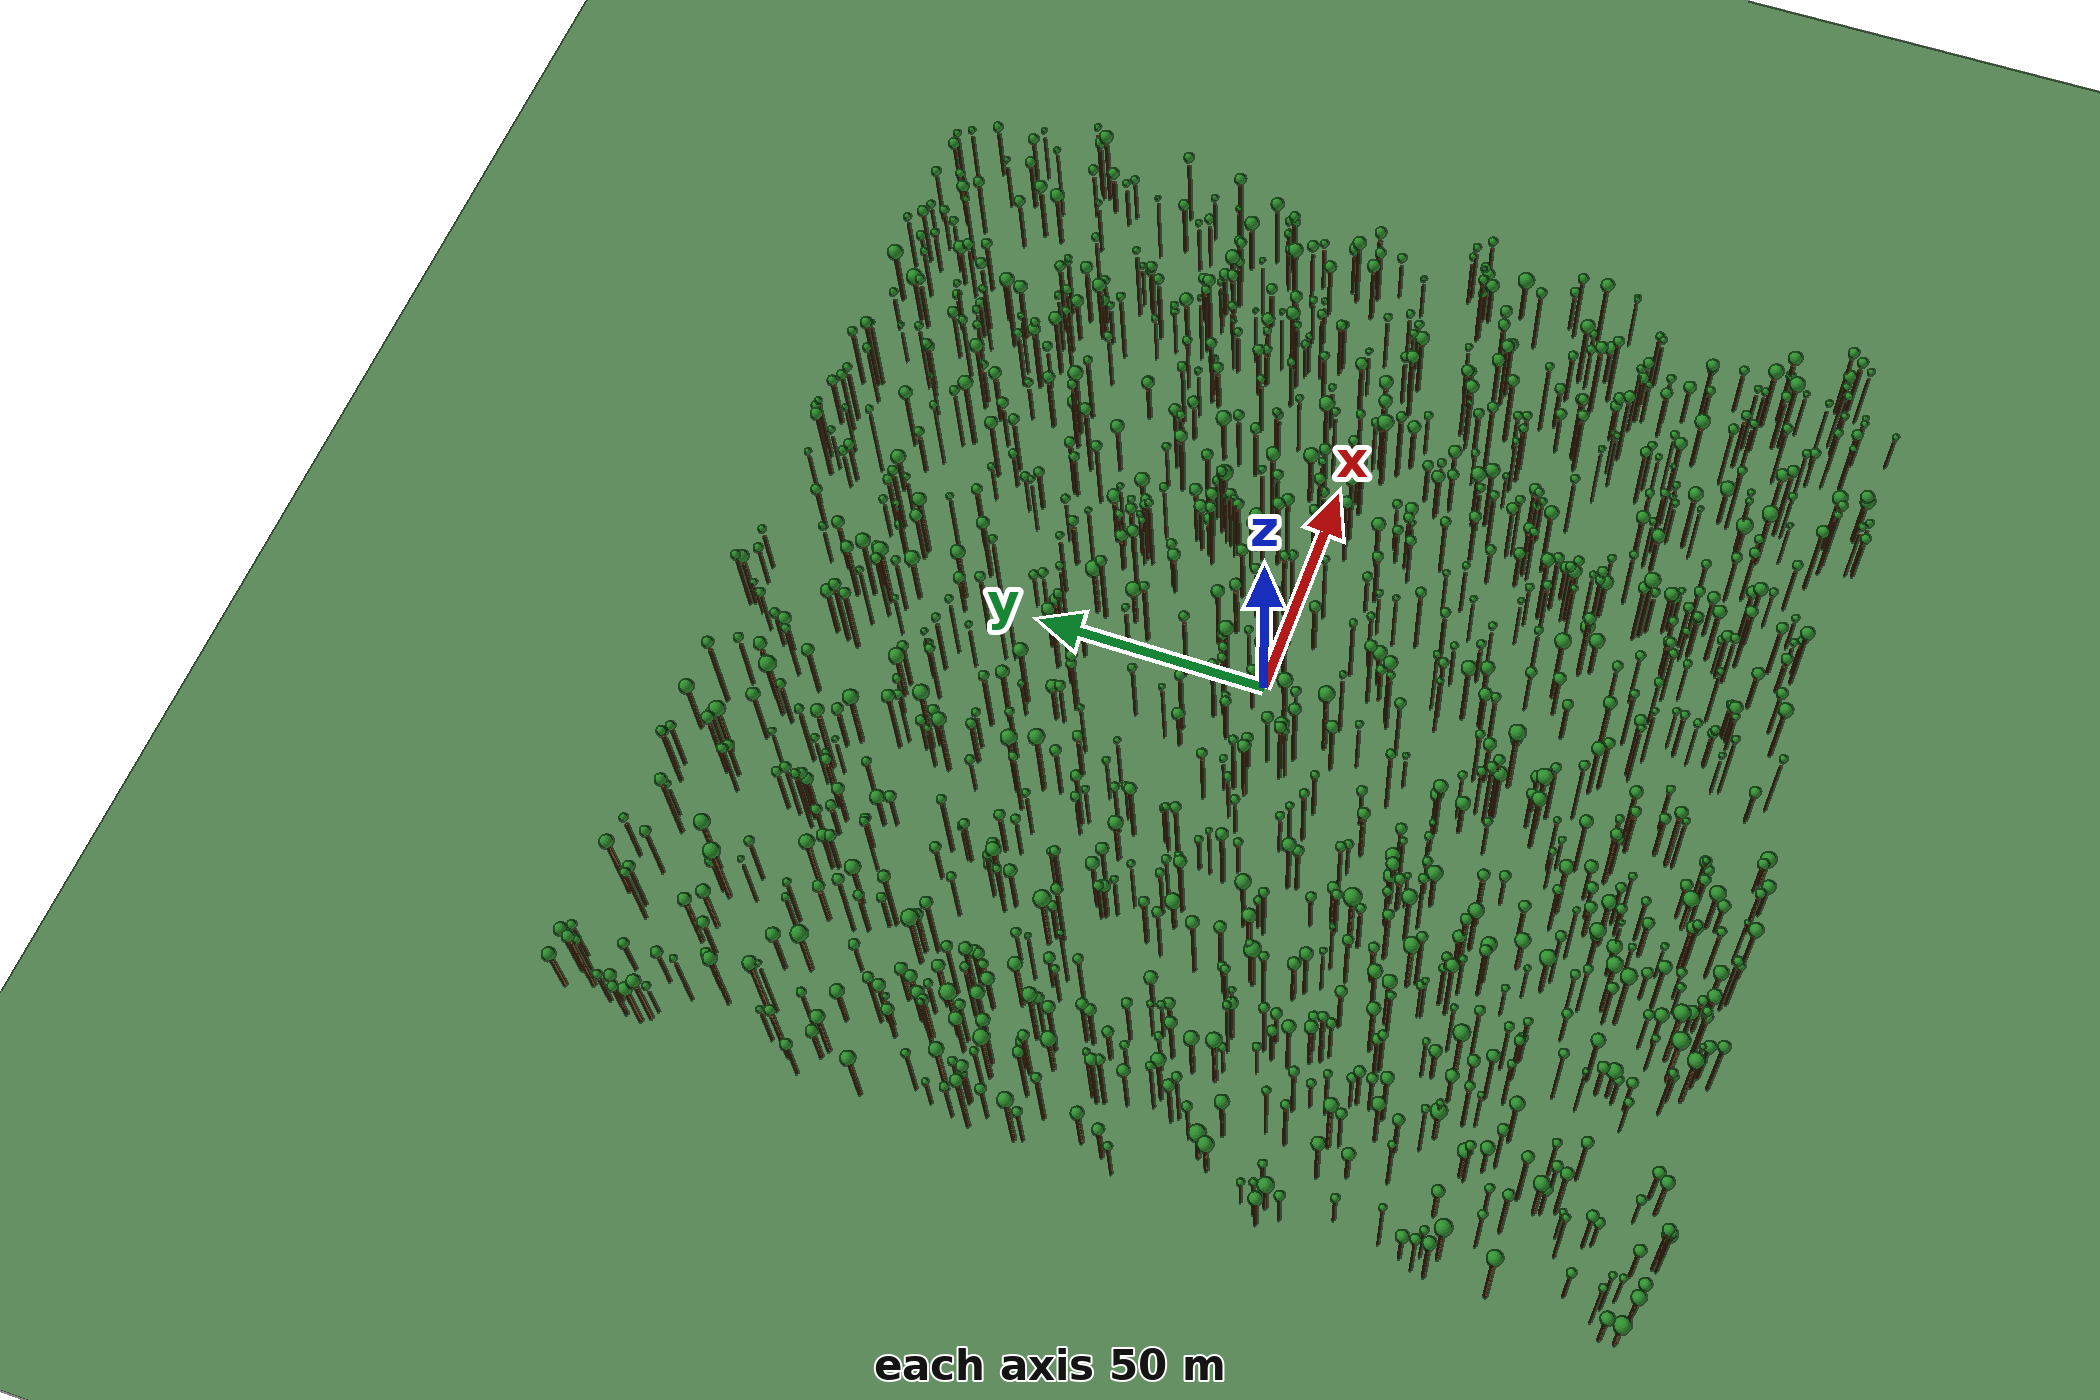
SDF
<?xml version="1.0" ?>
<sdf version="1.6">

<world name="real_forest">

  <!-- Sun -->
  <include>
    <uri>model://sun</uri>
  </include>

  <!-- Grass Ground -->
  <model name="grass_ground">
    <static>true</static>

    <link name="link">

      <collision name="collision">
        <geometry>
          <plane>
            <normal>0 0 1</normal>
            <size>500 500</size>
          </plane>
        </geometry>
      </collision>

      <visual name="visual">
        <geometry>
          <plane>
            <normal>0 0 1</normal>
            <size>500 500</size>
          </plane>
        </geometry>

        <material>
          <ambient>0.25 0.45 0.25 1</ambient>
          <diffuse>0.3 0.5 0.3 1</diffuse>
        </material>

      </visual>

    </link>

  </model>

  <model name="tree_0">
    <static>true</static>

    <link name="trunk_link">

      <!-- Tree Trunk -->
      <collision name="trunk_collision">
        <pose>31.529134701828468 22.47053448138601 6.874889457162214 0 0 0</pose>

        <geometry>
          <cylinder>
            <radius>0.3867742616346008</radius>
            <length>13.749778914324429</length>
          </cylinder>
        </geometry>
      </collision>

      <visual name="trunk_visual">
        <pose>31.529134701828468 22.47053448138601 6.874889457162214 0 0 0</pose>

        <geometry>
          <cylinder>
            <radius>0.3867742616346008</radius>
            <length>13.749778914324429</length>
          </cylinder>
        </geometry>

        <material>
          <ambient>0.35 0.2 0.1 1</ambient>
          <diffuse>0.45 0.28 0.12 1</diffuse>
        </material>

      </visual>

      <!-- Tree Crown -->
      <collision name="crown_collision">
        <pose>31.529134701828468 22.47053448138601 16.80270175032577 0 0 0</pose>

        <geometry>
          <sphere>
            <radius>1.3187069996053271</radius>
          </sphere>
        </geometry>
      </collision>

      <visual name="crown_visual">
        <pose>31.529134701828468 22.47053448138601 16.80270175032577 0 0 0</pose>

        <geometry>
          <sphere>
            <radius>1.3187069996053271</radius>
          </sphere>
        </geometry>

        <material>
          <ambient>0.1 0.45 0.1 1</ambient>
          <diffuse>0.15 0.55 0.15 1</diffuse>
        </material>

      </visual>

    </link>

  </model>

  <model name="tree_1">
    <static>true</static>

    <link name="trunk_link">

      <!-- Tree Trunk -->
      <collision name="trunk_collision">
        <pose>-84.01624281196703 35.13107407162801 10.270593623367935 0 0 0</pose>

        <geometry>
          <cylinder>
            <radius>0.31250764369110084</radius>
            <length>20.54118724673587</length>
          </cylinder>
        </geometry>
      </collision>

      <visual name="trunk_visual">
        <pose>-84.01624281196703 35.13107407162801 10.270593623367935 0 0 0</pose>

        <geometry>
          <cylinder>
            <radius>0.31250764369110084</radius>
            <length>20.54118724673587</length>
          </cylinder>
        </geometry>

        <material>
          <ambient>0.35 0.2 0.1 1</ambient>
          <diffuse>0.45 0.28 0.12 1</diffuse>
        </material>

      </visual>

      <!-- Tree Crown -->
      <collision name="crown_collision">
        <pose>-84.01624281196703 35.13107407162801 23.748602928418528 0 0 0</pose>

        <geometry>
          <sphere>
            <radius>1.0705489537205826</radius>
          </sphere>
        </geometry>
      </collision>

      <visual name="crown_visual">
        <pose>-84.01624281196703 35.13107407162801 23.748602928418528 0 0 0</pose>

        <geometry>
          <sphere>
            <radius>1.0705489537205826</radius>
          </sphere>
        </geometry>

        <material>
          <ambient>0.1 0.45 0.1 1</ambient>
          <diffuse>0.15 0.55 0.15 1</diffuse>
        </material>

      </visual>

    </link>

  </model>

  <model name="tree_2">
    <static>true</static>

    <link name="trunk_link">

      <!-- Tree Trunk -->
      <collision name="trunk_collision">
        <pose>-92.63422932500492 11.647837677196321 6.4110613679702615 0 0 0</pose>

        <geometry>
          <cylinder>
            <radius>0.42327184614077057</radius>
            <length>12.822122735940523</length>
          </cylinder>
        </geometry>
      </collision>

      <visual name="trunk_visual">
        <pose>-92.63422932500492 11.647837677196321 6.4110613679702615 0 0 0</pose>

        <geometry>
          <cylinder>
            <radius>0.42327184614077057</radius>
            <length>12.822122735940523</length>
          </cylinder>
        </geometry>

        <material>
          <ambient>0.35 0.2 0.1 1</ambient>
          <diffuse>0.45 0.28 0.12 1</diffuse>
        </material>

      </visual>

      <!-- Tree Crown -->
      <collision name="crown_collision">
        <pose>-92.63422932500492 11.647837677196321 16.154692013008624 0 0 0</pose>

        <geometry>
          <sphere>
            <radius>1.5691918624339711</radius>
          </sphere>
        </geometry>
      </collision>

      <visual name="crown_visual">
        <pose>-92.63422932500492 11.647837677196321 16.154692013008624 0 0 0</pose>

        <geometry>
          <sphere>
            <radius>1.5691918624339711</radius>
          </sphere>
        </geometry>

        <material>
          <ambient>0.1 0.45 0.1 1</ambient>
          <diffuse>0.15 0.55 0.15 1</diffuse>
        </material>

      </visual>

    </link>

  </model>

  <model name="tree_3">
    <static>true</static>

    <link name="trunk_link">

      <!-- Tree Trunk -->
      <collision name="trunk_collision">
        <pose>21.66588924683657 -72.71391092037274 8.737389356198026 0 0 0</pose>

        <geometry>
          <cylinder>
            <radius>0.26640891476083767</radius>
            <length>17.474778712396052</length>
          </cylinder>
        </geometry>
      </collision>

      <visual name="trunk_visual">
        <pose>21.66588924683657 -72.71391092037274 8.737389356198026 0 0 0</pose>

        <geometry>
          <cylinder>
            <radius>0.26640891476083767</radius>
            <length>17.474778712396052</length>
          </cylinder>
        </geometry>

        <material>
          <ambient>0.35 0.2 0.1 1</ambient>
          <diffuse>0.45 0.28 0.12 1</diffuse>
        </material>

      </visual>

      <!-- Tree Crown -->
      <collision name="crown_collision">
        <pose>21.66588924683657 -72.71391092037274 20.071915426759713 0 0 0</pose>

        <geometry>
          <sphere>
            <radius>0.9756759925453038</radius>
          </sphere>
        </geometry>
      </collision>

      <visual name="crown_visual">
        <pose>21.66588924683657 -72.71391092037274 20.071915426759713 0 0 0</pose>

        <geometry>
          <sphere>
            <radius>0.9756759925453038</radius>
          </sphere>
        </geometry>

        <material>
          <ambient>0.1 0.45 0.1 1</ambient>
          <diffuse>0.15 0.55 0.15 1</diffuse>
        </material>

      </visual>

    </link>

  </model>

  <model name="tree_4">
    <static>true</static>

    <link name="trunk_link">

      <!-- Tree Trunk -->
      <collision name="trunk_collision">
        <pose>37.92876721888436 25.758510346680026 9.352637727365384 0 0 0</pose>

        <geometry>
          <cylinder>
            <radius>0.4116242542921624</radius>
            <length>18.705275454730767</length>
          </cylinder>
        </geometry>
      </collision>

      <visual name="trunk_visual">
        <pose>37.92876721888436 25.758510346680026 9.352637727365384 0 0 0</pose>

        <geometry>
          <cylinder>
            <radius>0.4116242542921624</radius>
            <length>18.705275454730767</length>
          </cylinder>
        </geometry>

        <material>
          <ambient>0.35 0.2 0.1 1</ambient>
          <diffuse>0.45 0.28 0.12 1</diffuse>
        </material>

      </visual>

      <!-- Tree Crown -->
      <collision name="crown_collision">
        <pose>37.92876721888436 25.758510346680026 20.94555592380899 0 0 0</pose>

        <geometry>
          <sphere>
            <radius>1.173979852084271</radius>
          </sphere>
        </geometry>
      </collision>

      <visual name="crown_visual">
        <pose>37.92876721888436 25.758510346680026 20.94555592380899 0 0 0</pose>

        <geometry>
          <sphere>
            <radius>1.173979852084271</radius>
          </sphere>
        </geometry>

        <material>
          <ambient>0.1 0.45 0.1 1</ambient>
          <diffuse>0.15 0.55 0.15 1</diffuse>
        </material>

      </visual>

    </link>

  </model>

  <model name="tree_5">
    <static>true</static>

    <link name="trunk_link">

      <!-- Tree Trunk -->
      <collision name="trunk_collision">
        <pose>54.02118923643968 -23.53458030708103 5.618222237404904 0 0 0</pose>

        <geometry>
          <cylinder>
            <radius>0.32647394652605066</radius>
            <length>11.236444474809808</length>
          </cylinder>
        </geometry>
      </collision>

      <visual name="trunk_visual">
        <pose>54.02118923643968 -23.53458030708103 5.618222237404904 0 0 0</pose>

        <geometry>
          <cylinder>
            <radius>0.32647394652605066</radius>
            <length>11.236444474809808</length>
          </cylinder>
        </geometry>

        <material>
          <ambient>0.35 0.2 0.1 1</ambient>
          <diffuse>0.45 0.28 0.12 1</diffuse>
        </material>

      </visual>

      <!-- Tree Crown -->
      <collision name="crown_collision">
        <pose>54.02118923643968 -23.53458030708103 14.390618446895662 0 0 0</pose>

        <geometry>
          <sphere>
            <radius>1.1439666047922152</radius>
          </sphere>
        </geometry>
      </collision>

      <visual name="crown_visual">
        <pose>54.02118923643968 -23.53458030708103 14.390618446895662 0 0 0</pose>

        <geometry>
          <sphere>
            <radius>1.1439666047922152</radius>
          </sphere>
        </geometry>

        <material>
          <ambient>0.1 0.45 0.1 1</ambient>
          <diffuse>0.15 0.55 0.15 1</diffuse>
        </material>

      </visual>

    </link>

  </model>

  <model name="tree_6">
    <static>true</static>

    <link name="trunk_link">

      <!-- Tree Trunk -->
      <collision name="trunk_collision">
        <pose>-6.609136272057867 88.91885009876549 8.267204112638225 0 0 0</pose>

        <geometry>
          <cylinder>
            <radius>0.4297588451187523</radius>
            <length>16.53440822527645</length>
          </cylinder>
        </geometry>
      </collision>

      <visual name="trunk_visual">
        <pose>-6.609136272057867 88.91885009876549 8.267204112638225 0 0 0</pose>

        <geometry>
          <cylinder>
            <radius>0.4297588451187523</radius>
            <length>16.53440822527645</length>
          </cylinder>
        </geometry>

        <material>
          <ambient>0.35 0.2 0.1 1</ambient>
          <diffuse>0.45 0.28 0.12 1</diffuse>
        </material>

      </visual>

      <!-- Tree Crown -->
      <collision name="crown_collision">
        <pose>-6.609136272057867 88.91885009876549 19.422571393077845 0 0 0</pose>

        <geometry>
          <sphere>
            <radius>1.2967133466578296</radius>
          </sphere>
        </geometry>
      </collision>

      <visual name="crown_visual">
        <pose>-6.609136272057867 88.91885009876549 19.422571393077845 0 0 0</pose>

        <geometry>
          <sphere>
            <radius>1.2967133466578296</radius>
          </sphere>
        </geometry>

        <material>
          <ambient>0.1 0.45 0.1 1</ambient>
          <diffuse>0.15 0.55 0.15 1</diffuse>
        </material>

      </visual>

    </link>

  </model>

  <model name="tree_7">
    <static>true</static>

    <link name="trunk_link">

      <!-- Tree Trunk -->
      <collision name="trunk_collision">
        <pose>12.966262345774254 -52.61798918688688 6.425202495834324 0 0 0</pose>

        <geometry>
          <cylinder>
            <radius>0.2928709256275329</radius>
            <length>12.850404991668649</length>
          </cylinder>
        </geometry>
      </collision>

      <visual name="trunk_visual">
        <pose>12.966262345774254 -52.61798918688688 6.425202495834324 0 0 0</pose>

        <geometry>
          <cylinder>
            <radius>0.2928709256275329</radius>
            <length>12.850404991668649</length>
          </cylinder>
        </geometry>

        <material>
          <ambient>0.35 0.2 0.1 1</ambient>
          <diffuse>0.45 0.28 0.12 1</diffuse>
        </material>

      </visual>

      <!-- Tree Crown -->
      <collision name="crown_collision">
        <pose>12.966262345774254 -52.61798918688688 16.109504292367788 0 0 0</pose>

        <geometry>
          <sphere>
            <radius>1.1049477932079814</radius>
          </sphere>
        </geometry>
      </collision>

      <visual name="crown_visual">
        <pose>12.966262345774254 -52.61798918688688 16.109504292367788 0 0 0</pose>

        <geometry>
          <sphere>
            <radius>1.1049477932079814</radius>
          </sphere>
        </geometry>

        <material>
          <ambient>0.1 0.45 0.1 1</ambient>
          <diffuse>0.15 0.55 0.15 1</diffuse>
        </material>

      </visual>

    </link>

  </model>

  <model name="tree_8">
    <static>true</static>

    <link name="trunk_link">

      <!-- Tree Trunk -->
      <collision name="trunk_collision">
        <pose>49.87181699455621 -42.83246659785016 7.99003888319433 0 0 0</pose>

        <geometry>
          <cylinder>
            <radius>0.25148937480035044</radius>
            <length>15.98007776638866</length>
          </cylinder>
        </geometry>
      </collision>

      <visual name="trunk_visual">
        <pose>49.87181699455621 -42.83246659785016 7.99003888319433 0 0 0</pose>

        <geometry>
          <cylinder>
            <radius>0.25148937480035044</radius>
            <length>15.98007776638866</length>
          </cylinder>
        </geometry>

        <material>
          <ambient>0.35 0.2 0.1 1</ambient>
          <diffuse>0.45 0.28 0.12 1</diffuse>
        </material>

      </visual>

      <!-- Tree Crown -->
      <collision name="crown_collision">
        <pose>49.87181699455621 -42.83246659785016 18.307181590388517 0 0 0</pose>

        <geometry>
          <sphere>
            <radius>0.9380472752596682</radius>
          </sphere>
        </geometry>
      </collision>

      <visual name="crown_visual">
        <pose>49.87181699455621 -42.83246659785016 18.307181590388517 0 0 0</pose>

        <geometry>
          <sphere>
            <radius>0.9380472752596682</radius>
          </sphere>
        </geometry>

        <material>
          <ambient>0.1 0.45 0.1 1</ambient>
          <diffuse>0.15 0.55 0.15 1</diffuse>
        </material>

      </visual>

    </link>

  </model>

  <model name="tree_9">
    <static>true</static>

    <link name="trunk_link">

      <!-- Tree Trunk -->
      <collision name="trunk_collision">
        <pose>-105.04539253020221 55.333811885684895 5.28793874663461 0 0 0</pose>

        <geometry>
          <cylinder>
            <radius>0.40779683419814683</radius>
            <length>10.57587749326922</length>
          </cylinder>
        </geometry>
      </collision>

      <visual name="trunk_visual">
        <pose>-105.04539253020221 55.333811885684895 5.28793874663461 0 0 0</pose>

        <geometry>
          <cylinder>
            <radius>0.40779683419814683</radius>
            <length>10.57587749326922</length>
          </cylinder>
        </geometry>

        <material>
          <ambient>0.35 0.2 0.1 1</ambient>
          <diffuse>0.45 0.28 0.12 1</diffuse>
        </material>

      </visual>

      <!-- Tree Crown -->
      <collision name="crown_collision">
        <pose>-105.04539253020221 55.333811885684895 14.022501535516497 0 0 0</pose>

        <geometry>
          <sphere>
            <radius>1.252526521458858</radius>
          </sphere>
        </geometry>
      </collision>

      <visual name="crown_visual">
        <pose>-105.04539253020221 55.333811885684895 14.022501535516497 0 0 0</pose>

        <geometry>
          <sphere>
            <radius>1.252526521458858</radius>
          </sphere>
        </geometry>

        <material>
          <ambient>0.1 0.45 0.1 1</ambient>
          <diffuse>0.15 0.55 0.15 1</diffuse>
        </material>

      </visual>

    </link>

  </model>

  <model name="tree_10">
    <static>true</static>

    <link name="trunk_link">

      <!-- Tree Trunk -->
      <collision name="trunk_collision">
        <pose>50.903505081066584 -30.353346388520663 7.022483644388343 0 0 0</pose>

        <geometry>
          <cylinder>
            <radius>0.28593582704315507</radius>
            <length>14.044967288776686</length>
          </cylinder>
        </geometry>
      </collision>

      <visual name="trunk_visual">
        <pose>50.903505081066584 -30.353346388520663 7.022483644388343 0 0 0</pose>

        <geometry>
          <cylinder>
            <radius>0.28593582704315507</radius>
            <length>14.044967288776686</length>
          </cylinder>
        </geometry>

        <material>
          <ambient>0.35 0.2 0.1 1</ambient>
          <diffuse>0.45 0.28 0.12 1</diffuse>
        </material>

      </visual>

      <!-- Tree Crown -->
      <collision name="crown_collision">
        <pose>50.903505081066584 -30.353346388520663 17.445008453565983 0 0 0</pose>

        <geometry>
          <sphere>
            <radius>0.9441232396035144</radius>
          </sphere>
        </geometry>
      </collision>

      <visual name="crown_visual">
        <pose>50.903505081066584 -30.353346388520663 17.445008453565983 0 0 0</pose>

        <geometry>
          <sphere>
            <radius>0.9441232396035144</radius>
          </sphere>
        </geometry>

        <material>
          <ambient>0.1 0.45 0.1 1</ambient>
          <diffuse>0.15 0.55 0.15 1</diffuse>
        </material>

      </visual>

    </link>

  </model>

  <model name="tree_11">
    <static>true</static>

    <link name="trunk_link">

      <!-- Tree Trunk -->
      <collision name="trunk_collision">
        <pose>51.897666774106426 101.55526767127182 5.314692011359782 0 0 0</pose>

        <geometry>
          <cylinder>
            <radius>0.22870019087980048</radius>
            <length>10.629384022719565</length>
          </cylinder>
        </geometry>
      </collision>

      <visual name="trunk_visual">
        <pose>51.897666774106426 101.55526767127182 5.314692011359782 0 0 0</pose>

        <geometry>
          <cylinder>
            <radius>0.22870019087980048</radius>
            <length>10.629384022719565</length>
          </cylinder>
        </geometry>

        <material>
          <ambient>0.35 0.2 0.1 1</ambient>
          <diffuse>0.45 0.28 0.12 1</diffuse>
        </material>

      </visual>

      <!-- Tree Crown -->
      <collision name="crown_collision">
        <pose>51.897666774106426 101.55526767127182 13.93009142107594 0 0 0</pose>

        <geometry>
          <sphere>
            <radius>0.6715809662442573</radius>
          </sphere>
        </geometry>
      </collision>

      <visual name="crown_visual">
        <pose>51.897666774106426 101.55526767127182 13.93009142107594 0 0 0</pose>

        <geometry>
          <sphere>
            <radius>0.6715809662442573</radius>
          </sphere>
        </geometry>

        <material>
          <ambient>0.1 0.45 0.1 1</ambient>
          <diffuse>0.15 0.55 0.15 1</diffuse>
        </material>

      </visual>

    </link>

  </model>

  <model name="tree_12">
    <static>true</static>

    <link name="trunk_link">

      <!-- Tree Trunk -->
      <collision name="trunk_collision">
        <pose>99.63093035457663 -84.89369931287959 10.483590613203468 0 0 0</pose>

        <geometry>
          <cylinder>
            <radius>0.422642804184973</radius>
            <length>20.967181226406936</length>
          </cylinder>
        </geometry>
      </collision>

      <visual name="trunk_visual">
        <pose>99.63093035457663 -84.89369931287959 10.483590613203468 0 0 0</pose>

        <geometry>
          <cylinder>
            <radius>0.422642804184973</radius>
            <length>20.967181226406936</length>
          </cylinder>
        </geometry>

        <material>
          <ambient>0.35 0.2 0.1 1</ambient>
          <diffuse>0.45 0.28 0.12 1</diffuse>
        </material>

      </visual>

      <!-- Tree Crown -->
      <collision name="crown_collision">
        <pose>99.63093035457663 -84.89369931287959 23.84615174804456 0 0 0</pose>

        <geometry>
          <sphere>
            <radius>1.4710947264172918</radius>
          </sphere>
        </geometry>
      </collision>

      <visual name="crown_visual">
        <pose>99.63093035457663 -84.89369931287959 23.84615174804456 0 0 0</pose>

        <geometry>
          <sphere>
            <radius>1.4710947264172918</radius>
          </sphere>
        </geometry>

        <material>
          <ambient>0.1 0.45 0.1 1</ambient>
          <diffuse>0.15 0.55 0.15 1</diffuse>
        </material>

      </visual>

    </link>

  </model>

  <model name="tree_13">
    <static>true</static>

    <link name="trunk_link">

      <!-- Tree Trunk -->
      <collision name="trunk_collision">
        <pose>-77.1287811322416 106.92667881676311 7.22556625343614 0 0 0</pose>

        <geometry>
          <cylinder>
            <radius>0.32442940306246704</radius>
            <length>14.45113250687228</length>
          </cylinder>
        </geometry>
      </collision>

      <visual name="trunk_visual">
        <pose>-77.1287811322416 106.92667881676311 7.22556625343614 0 0 0</pose>

        <geometry>
          <cylinder>
            <radius>0.32442940306246704</radius>
            <length>14.45113250687228</length>
          </cylinder>
        </geometry>

        <material>
          <ambient>0.35 0.2 0.1 1</ambient>
          <diffuse>0.45 0.28 0.12 1</diffuse>
        </material>

      </visual>

      <!-- Tree Crown -->
      <collision name="crown_collision">
        <pose>-77.1287811322416 106.92667881676311 17.765654771329473 0 0 0</pose>

        <geometry>
          <sphere>
            <radius>0.8639786847333426</radius>
          </sphere>
        </geometry>
      </collision>

      <visual name="crown_visual">
        <pose>-77.1287811322416 106.92667881676311 17.765654771329473 0 0 0</pose>

        <geometry>
          <sphere>
            <radius>0.8639786847333426</radius>
          </sphere>
        </geometry>

        <material>
          <ambient>0.1 0.45 0.1 1</ambient>
          <diffuse>0.15 0.55 0.15 1</diffuse>
        </material>

      </visual>

    </link>

  </model>

  <model name="tree_14">
    <static>true</static>

    <link name="trunk_link">

      <!-- Tree Trunk -->
      <collision name="trunk_collision">
        <pose>-104.97072530516104 65.77625817293284 6.814315532148688 0 0 0</pose>

        <geometry>
          <cylinder>
            <radius>0.26324712043351706</radius>
            <length>13.628631064297377</length>
          </cylinder>
        </geometry>
      </collision>

      <visual name="trunk_visual">
        <pose>-104.97072530516104 65.77625817293284 6.814315532148688 0 0 0</pose>

        <geometry>
          <cylinder>
            <radius>0.26324712043351706</radius>
            <length>13.628631064297377</length>
          </cylinder>
        </geometry>

        <material>
          <ambient>0.35 0.2 0.1 1</ambient>
          <diffuse>0.45 0.28 0.12 1</diffuse>
        </material>

      </visual>

      <!-- Tree Crown -->
      <collision name="crown_collision">
        <pose>-104.97072530516104 65.77625817293284 16.43089351904898 0 0 0</pose>

        <geometry>
          <sphere>
            <radius>0.7267768616267813</radius>
          </sphere>
        </geometry>
      </collision>

      <visual name="crown_visual">
        <pose>-104.97072530516104 65.77625817293284 16.43089351904898 0 0 0</pose>

        <geometry>
          <sphere>
            <radius>0.7267768616267813</radius>
          </sphere>
        </geometry>

        <material>
          <ambient>0.1 0.45 0.1 1</ambient>
          <diffuse>0.15 0.55 0.15 1</diffuse>
        </material>

      </visual>

    </link>

  </model>

  <model name="tree_15">
    <static>true</static>

    <link name="trunk_link">

      <!-- Tree Trunk -->
      <collision name="trunk_collision">
        <pose>-20.5165262174243 102.85415705136143 6.64365406428477 0 0 0</pose>

        <geometry>
          <cylinder>
            <radius>0.25535367461257935</radius>
            <length>13.28730812856954</length>
          </cylinder>
        </geometry>
      </collision>

      <visual name="trunk_visual">
        <pose>-20.5165262174243 102.85415705136143 6.64365406428477 0 0 0</pose>

        <geometry>
          <cylinder>
            <radius>0.25535367461257935</radius>
            <length>13.28730812856954</length>
          </cylinder>
        </geometry>

        <material>
          <ambient>0.35 0.2 0.1 1</ambient>
          <diffuse>0.45 0.28 0.12 1</diffuse>
        </material>

      </visual>

      <!-- Tree Crown -->
      <collision name="crown_collision">
        <pose>-20.5165262174243 102.85415705136143 15.675922412447381 0 0 0</pose>

        <geometry>
          <sphere>
            <radius>1.0123153221180274</radius>
          </sphere>
        </geometry>
      </collision>

      <visual name="crown_visual">
        <pose>-20.5165262174243 102.85415705136143 15.675922412447381 0 0 0</pose>

        <geometry>
          <sphere>
            <radius>1.0123153221180274</radius>
          </sphere>
        </geometry>

        <material>
          <ambient>0.1 0.45 0.1 1</ambient>
          <diffuse>0.15 0.55 0.15 1</diffuse>
        </material>

      </visual>

    </link>

  </model>

  <model name="tree_16">
    <static>true</static>

    <link name="trunk_link">

      <!-- Tree Trunk -->
      <collision name="trunk_collision">
        <pose>26.844345605753517 21.634632538149503 5.64427331724319 0 0 0</pose>

        <geometry>
          <cylinder>
            <radius>0.35435196926751567</radius>
            <length>11.28854663448638</length>
          </cylinder>
        </geometry>
      </collision>

      <visual name="trunk_visual">
        <pose>26.844345605753517 21.634632538149503 5.64427331724319 0 0 0</pose>

        <geometry>
          <cylinder>
            <radius>0.35435196926751567</radius>
            <length>11.28854663448638</length>
          </cylinder>
        </geometry>

        <material>
          <ambient>0.35 0.2 0.1 1</ambient>
          <diffuse>0.45 0.28 0.12 1</diffuse>
        </material>

      </visual>

      <!-- Tree Crown -->
      <collision name="crown_collision">
        <pose>26.844345605753517 21.634632538149503 14.703950452061044 0 0 0</pose>

        <geometry>
          <sphere>
            <radius>1.1305339254666007</radius>
          </sphere>
        </geometry>
      </collision>

      <visual name="crown_visual">
        <pose>26.844345605753517 21.634632538149503 14.703950452061044 0 0 0</pose>

        <geometry>
          <sphere>
            <radius>1.1305339254666007</radius>
          </sphere>
        </geometry>

        <material>
          <ambient>0.1 0.45 0.1 1</ambient>
          <diffuse>0.15 0.55 0.15 1</diffuse>
        </material>

      </visual>

    </link>

  </model>

  <model name="tree_17">
    <static>true</static>

    <link name="trunk_link">

      <!-- Tree Trunk -->
      <collision name="trunk_collision">
        <pose>-55.11264617796665 -32.59204451640355 8.960271028347655 0 0 0</pose>

        <geometry>
          <cylinder>
            <radius>0.22676003795838945</radius>
            <length>17.92054205669531</length>
          </cylinder>
        </geometry>
      </collision>

      <visual name="trunk_visual">
        <pose>-55.11264617796665 -32.59204451640355 8.960271028347655 0 0 0</pose>

        <geometry>
          <cylinder>
            <radius>0.22676003795838945</radius>
            <length>17.92054205669531</length>
          </cylinder>
        </geometry>

        <material>
          <ambient>0.35 0.2 0.1 1</ambient>
          <diffuse>0.45 0.28 0.12 1</diffuse>
        </material>

      </visual>

      <!-- Tree Crown -->
      <collision name="crown_collision">
        <pose>-55.11264617796665 -32.59204451640355 20.977290082034322 0 0 0</pose>

        <geometry>
          <sphere>
            <radius>0.6251684062845273</radius>
          </sphere>
        </geometry>
      </collision>

      <visual name="crown_visual">
        <pose>-55.11264617796665 -32.59204451640355 20.977290082034322 0 0 0</pose>

        <geometry>
          <sphere>
            <radius>0.6251684062845273</radius>
          </sphere>
        </geometry>

        <material>
          <ambient>0.1 0.45 0.1 1</ambient>
          <diffuse>0.15 0.55 0.15 1</diffuse>
        </material>

      </visual>

    </link>

  </model>

  <model name="tree_18">
    <static>true</static>

    <link name="trunk_link">

      <!-- Tree Trunk -->
      <collision name="trunk_collision">
        <pose>-3.348859725423523 -54.26811130313128 6.868736289075838 0 0 0</pose>

        <geometry>
          <cylinder>
            <radius>0.39688436641818303</radius>
            <length>13.737472578151676</length>
          </cylinder>
        </geometry>
      </collision>

      <visual name="trunk_visual">
        <pose>-3.348859725423523 -54.26811130313128 6.868736289075838 0 0 0</pose>

        <geometry>
          <cylinder>
            <radius>0.39688436641818303</radius>
            <length>13.737472578151676</length>
          </cylinder>
        </geometry>

        <material>
          <ambient>0.35 0.2 0.1 1</ambient>
          <diffuse>0.45 0.28 0.12 1</diffuse>
        </material>

      </visual>

      <!-- Tree Crown -->
      <collision name="crown_collision">
        <pose>-3.348859725423523 -54.26811130313128 17.164097131687136 0 0 0</pose>

        <geometry>
          <sphere>
            <radius>1.101101138428924</radius>
          </sphere>
        </geometry>
      </collision>

      <visual name="crown_visual">
        <pose>-3.348859725423523 -54.26811130313128 17.164097131687136 0 0 0</pose>

        <geometry>
          <sphere>
            <radius>1.101101138428924</radius>
          </sphere>
        </geometry>

        <material>
          <ambient>0.1 0.45 0.1 1</ambient>
          <diffuse>0.15 0.55 0.15 1</diffuse>
        </material>

      </visual>

    </link>

  </model>

  <model name="tree_19">
    <static>true</static>

    <link name="trunk_link">

      <!-- Tree Trunk -->
      <collision name="trunk_collision">
        <pose>64.56340119362386 -84.25543291404034 9.780086911424899 0 0 0</pose>

        <geometry>
          <cylinder>
            <radius>0.25725726284941136</radius>
            <length>19.560173822849798</length>
          </cylinder>
        </geometry>
      </collision>

      <visual name="trunk_visual">
        <pose>64.56340119362386 -84.25543291404034 9.780086911424899 0 0 0</pose>

        <geometry>
          <cylinder>
            <radius>0.25725726284941136</radius>
            <length>19.560173822849798</length>
          </cylinder>
        </geometry>

        <material>
          <ambient>0.35 0.2 0.1 1</ambient>
          <diffuse>0.45 0.28 0.12 1</diffuse>
        </material>

      </visual>

      <!-- Tree Crown -->
      <collision name="crown_collision">
        <pose>64.56340119362386 -84.25543291404034 23.031736304132032 0 0 0</pose>

        <geometry>
          <sphere>
            <radius>0.7189542038252453</radius>
          </sphere>
        </geometry>
      </collision>

      <visual name="crown_visual">
        <pose>64.56340119362386 -84.25543291404034 23.031736304132032 0 0 0</pose>

        <geometry>
          <sphere>
            <radius>0.7189542038252453</radius>
          </sphere>
        </geometry>

        <material>
          <ambient>0.1 0.45 0.1 1</ambient>
          <diffuse>0.15 0.55 0.15 1</diffuse>
        </material>

      </visual>

    </link>

  </model>

  <model name="tree_20">
    <static>true</static>

    <link name="trunk_link">

      <!-- Tree Trunk -->
      <collision name="trunk_collision">
        <pose>-82.08345079903327 -0.4129953732970222 8.181237780336083 0 0 0</pose>

        <geometry>
          <cylinder>
            <radius>0.3020889517072256</radius>
            <length>16.362475560672166</length>
          </cylinder>
        </geometry>
      </collision>

      <visual name="trunk_visual">
        <pose>-82.08345079903327 -0.4129953732970222 8.181237780336083 0 0 0</pose>

        <geometry>
          <cylinder>
            <radius>0.3020889517072256</radius>
            <length>16.362475560672166</length>
          </cylinder>
        </geometry>

        <material>
          <ambient>0.35 0.2 0.1 1</ambient>
          <diffuse>0.45 0.28 0.12 1</diffuse>
        </material>

      </visual>

      <!-- Tree Crown -->
      <collision name="crown_collision">
        <pose>-82.08345079903327 -0.4129953732970222 19.309712893858375 0 0 0</pose>

        <geometry>
          <sphere>
            <radius>1.0346456161368214</radius>
          </sphere>
        </geometry>
      </collision>

      <visual name="crown_visual">
        <pose>-82.08345079903327 -0.4129953732970222 19.309712893858375 0 0 0</pose>

        <geometry>
          <sphere>
            <radius>1.0346456161368214</radius>
          </sphere>
        </geometry>

        <material>
          <ambient>0.1 0.45 0.1 1</ambient>
          <diffuse>0.15 0.55 0.15 1</diffuse>
        </material>

      </visual>

    </link>

  </model>

  <model name="tree_21">
    <static>true</static>

    <link name="trunk_link">

      <!-- Tree Trunk -->
      <collision name="trunk_collision">
        <pose>27.74673000408157 23.640816601757194 6.951958451049868 0 0 0</pose>

        <geometry>
          <cylinder>
            <radius>0.35143487422821773</radius>
            <length>13.903916902099736</length>
          </cylinder>
        </geometry>
      </collision>

      <visual name="trunk_visual">
        <pose>27.74673000408157 23.640816601757194 6.951958451049868 0 0 0</pose>

        <geometry>
          <cylinder>
            <radius>0.35143487422821773</radius>
            <length>13.903916902099736</length>
          </cylinder>
        </geometry>

        <material>
          <ambient>0.35 0.2 0.1 1</ambient>
          <diffuse>0.45 0.28 0.12 1</diffuse>
        </material>

      </visual>

      <!-- Tree Crown -->
      <collision name="crown_collision">
        <pose>27.74673000408157 23.640816601757194 17.068527479697593 0 0 0</pose>

        <geometry>
          <sphere>
            <radius>1.3875285910663215</radius>
          </sphere>
        </geometry>
      </collision>

      <visual name="crown_visual">
        <pose>27.74673000408157 23.640816601757194 17.068527479697593 0 0 0</pose>

        <geometry>
          <sphere>
            <radius>1.3875285910663215</radius>
          </sphere>
        </geometry>

        <material>
          <ambient>0.1 0.45 0.1 1</ambient>
          <diffuse>0.15 0.55 0.15 1</diffuse>
        </material>

      </visual>

    </link>

  </model>

  <model name="tree_22">
    <static>true</static>

    <link name="trunk_link">

      <!-- Tree Trunk -->
      <collision name="trunk_collision">
        <pose>-10.89248330576389 53.542222302286774 8.281078490810247 0 0 0</pose>

        <geometry>
          <cylinder>
            <radius>0.26000457642983865</radius>
            <length>16.562156981620493</length>
          </cylinder>
        </geometry>
      </collision>

      <visual name="trunk_visual">
        <pose>-10.89248330576389 53.542222302286774 8.281078490810247 0 0 0</pose>

        <geometry>
          <cylinder>
            <radius>0.26000457642983865</radius>
            <length>16.562156981620493</length>
          </cylinder>
        </geometry>

        <material>
          <ambient>0.35 0.2 0.1 1</ambient>
          <diffuse>0.45 0.28 0.12 1</diffuse>
        </material>

      </visual>

      <!-- Tree Crown -->
      <collision name="crown_collision">
        <pose>-10.89248330576389 53.542222302286774 19.778856182964898 0 0 0</pose>

        <geometry>
          <sphere>
            <radius>0.7503073287706611</radius>
          </sphere>
        </geometry>
      </collision>

      <visual name="crown_visual">
        <pose>-10.89248330576389 53.542222302286774 19.778856182964898 0 0 0</pose>

        <geometry>
          <sphere>
            <radius>0.7503073287706611</radius>
          </sphere>
        </geometry>

        <material>
          <ambient>0.1 0.45 0.1 1</ambient>
          <diffuse>0.15 0.55 0.15 1</diffuse>
        </material>

      </visual>

    </link>

  </model>

  <model name="tree_23">
    <static>true</static>

    <link name="trunk_link">

      <!-- Tree Trunk -->
      <collision name="trunk_collision">
        <pose>-55.291721078382665 -55.34886922656517 10.874738856062724 0 0 0</pose>

        <geometry>
          <cylinder>
            <radius>0.23705907895353312</radius>
            <length>21.749477712125447</length>
          </cylinder>
        </geometry>
      </collision>

      <visual name="trunk_visual">
        <pose>-55.291721078382665 -55.34886922656517 10.874738856062724 0 0 0</pose>

        <geometry>
          <cylinder>
            <radius>0.23705907895353312</radius>
            <length>21.749477712125447</length>
          </cylinder>
        </geometry>

        <material>
          <ambient>0.35 0.2 0.1 1</ambient>
          <diffuse>0.45 0.28 0.12 1</diffuse>
        </material>

      </visual>

      <!-- Tree Crown -->
      <collision name="crown_collision">
        <pose>-55.291721078382665 -55.34886922656517 24.048328782546157 0 0 0</pose>

        <geometry>
          <sphere>
            <radius>0.933823068571815</radius>
          </sphere>
        </geometry>
      </collision>

      <visual name="crown_visual">
        <pose>-55.291721078382665 -55.34886922656517 24.048328782546157 0 0 0</pose>

        <geometry>
          <sphere>
            <radius>0.933823068571815</radius>
          </sphere>
        </geometry>

        <material>
          <ambient>0.1 0.45 0.1 1</ambient>
          <diffuse>0.15 0.55 0.15 1</diffuse>
        </material>

      </visual>

    </link>

  </model>

  <model name="tree_24">
    <static>true</static>

    <link name="trunk_link">

      <!-- Tree Trunk -->
      <collision name="trunk_collision">
        <pose>70.1011386543654 103.17116783220166 7.063663062166823 0 0 0</pose>

        <geometry>
          <cylinder>
            <radius>0.32598511015744347</radius>
            <length>14.127326124333646</length>
          </cylinder>
        </geometry>
      </collision>

      <visual name="trunk_visual">
        <pose>70.1011386543654 103.17116783220166 7.063663062166823 0 0 0</pose>

        <geometry>
          <cylinder>
            <radius>0.32598511015744347</radius>
            <length>14.127326124333646</length>
          </cylinder>
        </geometry>

        <material>
          <ambient>0.35 0.2 0.1 1</ambient>
          <diffuse>0.45 0.28 0.12 1</diffuse>
        </material>

      </visual>

      <!-- Tree Crown -->
      <collision name="crown_collision">
        <pose>70.1011386543654 103.17116783220166 16.78641005867289 0 0 0</pose>

        <geometry>
          <sphere>
            <radius>0.8555925477867037</radius>
          </sphere>
        </geometry>
      </collision>

      <visual name="crown_visual">
        <pose>70.1011386543654 103.17116783220166 16.78641005867289 0 0 0</pose>

        <geometry>
          <sphere>
            <radius>0.8555925477867037</radius>
          </sphere>
        </geometry>

        <material>
          <ambient>0.1 0.45 0.1 1</ambient>
          <diffuse>0.15 0.55 0.15 1</diffuse>
        </material>

      </visual>

    </link>

  </model>

  <model name="tree_25">
    <static>true</static>

    <link name="trunk_link">

      <!-- Tree Trunk -->
      <collision name="trunk_collision">
        <pose>104.23073644838158 41.783675198392416 6.66758462202663 0 0 0</pose>

        <geometry>
          <cylinder>
            <radius>0.24910574039070849</radius>
            <length>13.33516924405326</length>
          </cylinder>
        </geometry>
      </collision>

      <visual name="trunk_visual">
        <pose>104.23073644838158 41.783675198392416 6.66758462202663 0 0 0</pose>

        <geometry>
          <cylinder>
            <radius>0.24910574039070849</radius>
            <length>13.33516924405326</length>
          </cylinder>
        </geometry>

        <material>
          <ambient>0.35 0.2 0.1 1</ambient>
          <diffuse>0.45 0.28 0.12 1</diffuse>
        </material>

      </visual>

      <!-- Tree Crown -->
      <collision name="crown_collision">
        <pose>104.23073644838158 41.783675198392416 15.860773087293015 0 0 0</pose>

        <geometry>
          <sphere>
            <radius>0.674389330511451</radius>
          </sphere>
        </geometry>
      </collision>

      <visual name="crown_visual">
        <pose>104.23073644838158 41.783675198392416 15.860773087293015 0 0 0</pose>

        <geometry>
          <sphere>
            <radius>0.674389330511451</radius>
          </sphere>
        </geometry>

        <material>
          <ambient>0.1 0.45 0.1 1</ambient>
          <diffuse>0.15 0.55 0.15 1</diffuse>
        </material>

      </visual>

    </link>

  </model>

  <model name="tree_26">
    <static>true</static>

    <link name="trunk_link">

      <!-- Tree Trunk -->
      <collision name="trunk_collision">
        <pose>89.55239326684034 -56.757388281336766 6.078390925450698 0 0 0</pose>

        <geometry>
          <cylinder>
            <radius>0.3162045389749766</radius>
            <length>12.156781850901396</length>
          </cylinder>
        </geometry>
      </collision>

      <visual name="trunk_visual">
        <pose>89.55239326684034 -56.757388281336766 6.078390925450698 0 0 0</pose>

        <geometry>
          <cylinder>
            <radius>0.3162045389749766</radius>
            <length>12.156781850901396</length>
          </cylinder>
        </geometry>

        <material>
          <ambient>0.35 0.2 0.1 1</ambient>
          <diffuse>0.45 0.28 0.12 1</diffuse>
        </material>

      </visual>

      <!-- Tree Crown -->
      <collision name="crown_collision">
        <pose>89.55239326684034 -56.757388281336766 14.339963421962771 0 0 0</pose>

        <geometry>
          <sphere>
            <radius>0.7923845594426965</radius>
          </sphere>
        </geometry>
      </collision>

      <visual name="crown_visual">
        <pose>89.55239326684034 -56.757388281336766 14.339963421962771 0 0 0</pose>

        <geometry>
          <sphere>
            <radius>0.7923845594426965</radius>
          </sphere>
        </geometry>

        <material>
          <ambient>0.1 0.45 0.1 1</ambient>
          <diffuse>0.15 0.55 0.15 1</diffuse>
        </material>

      </visual>

    </link>

  </model>

  <model name="tree_27">
    <static>true</static>

    <link name="trunk_link">

      <!-- Tree Trunk -->
      <collision name="trunk_collision">
        <pose>35.91334781288353 -12.759230370667552 7.265848294591291 0 0 0</pose>

        <geometry>
          <cylinder>
            <radius>0.39594307474426815</radius>
            <length>14.531696589182582</length>
          </cylinder>
        </geometry>
      </collision>

      <visual name="trunk_visual">
        <pose>35.91334781288353 -12.759230370667552 7.265848294591291 0 0 0</pose>

        <geometry>
          <cylinder>
            <radius>0.39594307474426815</radius>
            <length>14.531696589182582</length>
          </cylinder>
        </geometry>

        <material>
          <ambient>0.35 0.2 0.1 1</ambient>
          <diffuse>0.45 0.28 0.12 1</diffuse>
        </material>

      </visual>

      <!-- Tree Crown -->
      <collision name="crown_collision">
        <pose>35.91334781288353 -12.759230370667552 16.69620950892328 0 0 0</pose>

        <geometry>
          <sphere>
            <radius>1.407355507203327</radius>
          </sphere>
        </geometry>
      </collision>

      <visual name="crown_visual">
        <pose>35.91334781288353 -12.759230370667552 16.69620950892328 0 0 0</pose>

        <geometry>
          <sphere>
            <radius>1.407355507203327</radius>
          </sphere>
        </geometry>

        <material>
          <ambient>0.1 0.45 0.1 1</ambient>
          <diffuse>0.15 0.55 0.15 1</diffuse>
        </material>

      </visual>

    </link>

  </model>

  <model name="tree_28">
    <static>true</static>

    <link name="trunk_link">

      <!-- Tree Trunk -->
      <collision name="trunk_collision">
        <pose>105.67253060620007 66.9789937808942 5.733122598410087 0 0 0</pose>

        <geometry>
          <cylinder>
            <radius>0.27457671218204566</radius>
            <length>11.466245196820173</length>
          </cylinder>
        </geometry>
      </collision>

      <visual name="trunk_visual">
        <pose>105.67253060620007 66.9789937808942 5.733122598410087 0 0 0</pose>

        <geometry>
          <cylinder>
            <radius>0.27457671218204566</radius>
            <length>11.466245196820173</length>
          </cylinder>
        </geometry>

        <material>
          <ambient>0.35 0.2 0.1 1</ambient>
          <diffuse>0.45 0.28 0.12 1</diffuse>
        </material>

      </visual>

      <!-- Tree Crown -->
      <collision name="crown_collision">
        <pose>105.67253060620007 66.9789937808942 13.803700919948191 0 0 0</pose>

        <geometry>
          <sphere>
            <radius>0.9203696257281656</radius>
          </sphere>
        </geometry>
      </collision>

      <visual name="crown_visual">
        <pose>105.67253060620007 66.9789937808942 13.803700919948191 0 0 0</pose>

        <geometry>
          <sphere>
            <radius>0.9203696257281656</radius>
          </sphere>
        </geometry>

        <material>
          <ambient>0.1 0.45 0.1 1</ambient>
          <diffuse>0.15 0.55 0.15 1</diffuse>
        </material>

      </visual>

    </link>

  </model>

  <model name="tree_29">
    <static>true</static>

    <link name="trunk_link">

      <!-- Tree Trunk -->
      <collision name="trunk_collision">
        <pose>19.46003593313779 11.611361977339456 8.240375393087612 0 0 0</pose>

        <geometry>
          <cylinder>
            <radius>0.40090701709411397</radius>
            <length>16.480750786175225</length>
          </cylinder>
        </geometry>
      </collision>

      <visual name="trunk_visual">
        <pose>19.46003593313779 11.611361977339456 8.240375393087612 0 0 0</pose>

        <geometry>
          <cylinder>
            <radius>0.40090701709411397</radius>
            <length>16.480750786175225</length>
          </cylinder>
        </geometry>

        <material>
          <ambient>0.35 0.2 0.1 1</ambient>
          <diffuse>0.45 0.28 0.12 1</diffuse>
        </material>

      </visual>

      <!-- Tree Crown -->
      <collision name="crown_collision">
        <pose>19.46003593313779 11.611361977339456 19.06000174834748 0 0 0</pose>

        <geometry>
          <sphere>
            <radius>1.226267092730553</radius>
          </sphere>
        </geometry>
      </collision>

      <visual name="crown_visual">
        <pose>19.46003593313779 11.611361977339456 19.06000174834748 0 0 0</pose>

        <geometry>
          <sphere>
            <radius>1.226267092730553</radius>
          </sphere>
        </geometry>

        <material>
          <ambient>0.1 0.45 0.1 1</ambient>
          <diffuse>0.15 0.55 0.15 1</diffuse>
        </material>

      </visual>

    </link>

  </model>

  <model name="tree_30">
    <static>true</static>

    <link name="trunk_link">

      <!-- Tree Trunk -->
      <collision name="trunk_collision">
        <pose>53.66000213231044 -97.63527491211923 7.651928628025781 0 0 0</pose>

        <geometry>
          <cylinder>
            <radius>0.32550024669395794</radius>
            <length>15.303857256051563</length>
          </cylinder>
        </geometry>
      </collision>

      <visual name="trunk_visual">
        <pose>53.66000213231044 -97.63527491211923 7.651928628025781 0 0 0</pose>

        <geometry>
          <cylinder>
            <radius>0.32550024669395794</radius>
            <length>15.303857256051563</length>
          </cylinder>
        </geometry>

        <material>
          <ambient>0.35 0.2 0.1 1</ambient>
          <diffuse>0.45 0.28 0.12 1</diffuse>
        </material>

      </visual>

      <!-- Tree Crown -->
      <collision name="crown_collision">
        <pose>53.66000213231044 -97.63527491211923 18.31019433445597 0 0 0</pose>

        <geometry>
          <sphere>
            <radius>1.0135653201139074</radius>
          </sphere>
        </geometry>
      </collision>

      <visual name="crown_visual">
        <pose>53.66000213231044 -97.63527491211923 18.31019433445597 0 0 0</pose>

        <geometry>
          <sphere>
            <radius>1.0135653201139074</radius>
          </sphere>
        </geometry>

        <material>
          <ambient>0.1 0.45 0.1 1</ambient>
          <diffuse>0.15 0.55 0.15 1</diffuse>
        </material>

      </visual>

    </link>

  </model>

  <model name="tree_31">
    <static>true</static>

    <link name="trunk_link">

      <!-- Tree Trunk -->
      <collision name="trunk_collision">
        <pose>30.62839202877919 -0.2916527030248517 10.367198314812796 0 0 0</pose>

        <geometry>
          <cylinder>
            <radius>0.3675191654166787</radius>
            <length>20.734396629625593</length>
          </cylinder>
        </geometry>
      </collision>

      <visual name="trunk_visual">
        <pose>30.62839202877919 -0.2916527030248517 10.367198314812796 0 0 0</pose>

        <geometry>
          <cylinder>
            <radius>0.3675191654166787</radius>
            <length>20.734396629625593</length>
          </cylinder>
        </geometry>

        <material>
          <ambient>0.35 0.2 0.1 1</ambient>
          <diffuse>0.45 0.28 0.12 1</diffuse>
        </material>

      </visual>

      <!-- Tree Crown -->
      <collision name="crown_collision">
        <pose>30.62839202877919 -0.2916527030248517 24.03253492556741 0 0 0</pose>

        <geometry>
          <sphere>
            <radius>1.069424272397877</radius>
          </sphere>
        </geometry>
      </collision>

      <visual name="crown_visual">
        <pose>30.62839202877919 -0.2916527030248517 24.03253492556741 0 0 0</pose>

        <geometry>
          <sphere>
            <radius>1.069424272397877</radius>
          </sphere>
        </geometry>

        <material>
          <ambient>0.1 0.45 0.1 1</ambient>
          <diffuse>0.15 0.55 0.15 1</diffuse>
        </material>

      </visual>

    </link>

  </model>

  <model name="tree_32">
    <static>true</static>

    <link name="trunk_link">

      <!-- Tree Trunk -->
      <collision name="trunk_collision">
        <pose>-29.708928068753636 68.69406218407025 6.131784974694674 0 0 0</pose>

        <geometry>
          <cylinder>
            <radius>0.24261254103383814</radius>
            <length>12.263569949389348</length>
          </cylinder>
        </geometry>
      </collision>

      <visual name="trunk_visual">
        <pose>-29.708928068753636 68.69406218407025 6.131784974694674 0 0 0</pose>

        <geometry>
          <cylinder>
            <radius>0.24261254103383814</radius>
            <length>12.263569949389348</length>
          </cylinder>
        </geometry>

        <material>
          <ambient>0.35 0.2 0.1 1</ambient>
          <diffuse>0.45 0.28 0.12 1</diffuse>
        </material>

      </visual>

      <!-- Tree Crown -->
      <collision name="crown_collision">
        <pose>-29.708928068753636 68.69406218407025 15.204883736531205 0 0 0</pose>

        <geometry>
          <sphere>
            <radius>0.9111579493032371</radius>
          </sphere>
        </geometry>
      </collision>

      <visual name="crown_visual">
        <pose>-29.708928068753636 68.69406218407025 15.204883736531205 0 0 0</pose>

        <geometry>
          <sphere>
            <radius>0.9111579493032371</radius>
          </sphere>
        </geometry>

        <material>
          <ambient>0.1 0.45 0.1 1</ambient>
          <diffuse>0.15 0.55 0.15 1</diffuse>
        </material>

      </visual>

    </link>

  </model>

  <model name="tree_33">
    <static>true</static>

    <link name="trunk_link">

      <!-- Tree Trunk -->
      <collision name="trunk_collision">
        <pose>12.811497427957406 87.99372352571476 7.211903495264557 0 0 0</pose>

        <geometry>
          <cylinder>
            <radius>0.3787558682175779</radius>
            <length>14.423806990529114</length>
          </cylinder>
        </geometry>
      </collision>

      <visual name="trunk_visual">
        <pose>12.811497427957406 87.99372352571476 7.211903495264557 0 0 0</pose>

        <geometry>
          <cylinder>
            <radius>0.3787558682175779</radius>
            <length>14.423806990529114</length>
          </cylinder>
        </geometry>

        <material>
          <ambient>0.35 0.2 0.1 1</ambient>
          <diffuse>0.45 0.28 0.12 1</diffuse>
        </material>

      </visual>

      <!-- Tree Crown -->
      <collision name="crown_collision">
        <pose>12.811497427957406 87.99372352571476 16.885224714688682 0 0 0</pose>

        <geometry>
          <sphere>
            <radius>1.0657115921546307</radius>
          </sphere>
        </geometry>
      </collision>

      <visual name="crown_visual">
        <pose>12.811497427957406 87.99372352571476 16.885224714688682 0 0 0</pose>

        <geometry>
          <sphere>
            <radius>1.0657115921546307</radius>
          </sphere>
        </geometry>

        <material>
          <ambient>0.1 0.45 0.1 1</ambient>
          <diffuse>0.15 0.55 0.15 1</diffuse>
        </material>

      </visual>

    </link>

  </model>

  <model name="tree_34">
    <static>true</static>

    <link name="trunk_link">

      <!-- Tree Trunk -->
      <collision name="trunk_collision">
        <pose>9.119458137459986 -61.619024503630264 6.159237272856769 0 0 0</pose>

        <geometry>
          <cylinder>
            <radius>0.38360966751621406</radius>
            <length>12.318474545713539</length>
          </cylinder>
        </geometry>
      </collision>

      <visual name="trunk_visual">
        <pose>9.119458137459986 -61.619024503630264 6.159237272856769 0 0 0</pose>

        <geometry>
          <cylinder>
            <radius>0.38360966751621406</radius>
            <length>12.318474545713539</length>
          </cylinder>
        </geometry>

        <material>
          <ambient>0.35 0.2 0.1 1</ambient>
          <diffuse>0.45 0.28 0.12 1</diffuse>
        </material>

      </visual>

      <!-- Tree Crown -->
      <collision name="crown_collision">
        <pose>9.119458137459986 -61.619024503630264 14.435997999279644 0 0 0</pose>

        <geometry>
          <sphere>
            <radius>1.0951501481116392</radius>
          </sphere>
        </geometry>
      </collision>

      <visual name="crown_visual">
        <pose>9.119458137459986 -61.619024503630264 14.435997999279644 0 0 0</pose>

        <geometry>
          <sphere>
            <radius>1.0951501481116392</radius>
          </sphere>
        </geometry>

        <material>
          <ambient>0.1 0.45 0.1 1</ambient>
          <diffuse>0.15 0.55 0.15 1</diffuse>
        </material>

      </visual>

    </link>

  </model>

  <model name="tree_35">
    <static>true</static>

    <link name="trunk_link">

      <!-- Tree Trunk -->
      <collision name="trunk_collision">
        <pose>-102.23991366161992 -23.278181743961326 6.180259474863922 0 0 0</pose>

        <geometry>
          <cylinder>
            <radius>0.42173700487494353</radius>
            <length>12.360518949727844</length>
          </cylinder>
        </geometry>
      </collision>

      <visual name="trunk_visual">
        <pose>-102.23991366161992 -23.278181743961326 6.180259474863922 0 0 0</pose>

        <geometry>
          <cylinder>
            <radius>0.42173700487494353</radius>
            <length>12.360518949727844</length>
          </cylinder>
        </geometry>

        <material>
          <ambient>0.35 0.2 0.1 1</ambient>
          <diffuse>0.45 0.28 0.12 1</diffuse>
        </material>

      </visual>

      <!-- Tree Crown -->
      <collision name="crown_collision">
        <pose>-102.23991366161992 -23.278181743961326 15.068343456294322 0 0 0</pose>

        <geometry>
          <sphere>
            <radius>1.5811418808969224</radius>
          </sphere>
        </geometry>
      </collision>

      <visual name="crown_visual">
        <pose>-102.23991366161992 -23.278181743961326 15.068343456294322 0 0 0</pose>

        <geometry>
          <sphere>
            <radius>1.5811418808969224</radius>
          </sphere>
        </geometry>

        <material>
          <ambient>0.1 0.45 0.1 1</ambient>
          <diffuse>0.15 0.55 0.15 1</diffuse>
        </material>

      </visual>

    </link>

  </model>

  <model name="tree_36">
    <static>true</static>

    <link name="trunk_link">

      <!-- Tree Trunk -->
      <collision name="trunk_collision">
        <pose>-56.86024705721254 23.85985728103867 8.304419677404923 0 0 0</pose>

        <geometry>
          <cylinder>
            <radius>0.4020693288638141</radius>
            <length>16.608839354809845</length>
          </cylinder>
        </geometry>
      </collision>

      <visual name="trunk_visual">
        <pose>-56.86024705721254 23.85985728103867 8.304419677404923 0 0 0</pose>

        <geometry>
          <cylinder>
            <radius>0.4020693288638141</radius>
            <length>16.608839354809845</length>
          </cylinder>
        </geometry>

        <material>
          <ambient>0.35 0.2 0.1 1</ambient>
          <diffuse>0.45 0.28 0.12 1</diffuse>
        </material>

      </visual>

      <!-- Tree Crown -->
      <collision name="crown_collision">
        <pose>-56.86024705721254 23.85985728103867 19.09047876248141 0 0 0</pose>

        <geometry>
          <sphere>
            <radius>1.0334358541789062</radius>
          </sphere>
        </geometry>
      </collision>

      <visual name="crown_visual">
        <pose>-56.86024705721254 23.85985728103867 19.09047876248141 0 0 0</pose>

        <geometry>
          <sphere>
            <radius>1.0334358541789062</radius>
          </sphere>
        </geometry>

        <material>
          <ambient>0.1 0.45 0.1 1</ambient>
          <diffuse>0.15 0.55 0.15 1</diffuse>
        </material>

      </visual>

    </link>

  </model>

  <model name="tree_37">
    <static>true</static>

    <link name="trunk_link">

      <!-- Tree Trunk -->
      <collision name="trunk_collision">
        <pose>63.979992251392616 93.30351544997924 5.043440161088427 0 0 0</pose>

        <geometry>
          <cylinder>
            <radius>0.2673375907421078</radius>
            <length>10.086880322176855</length>
          </cylinder>
        </geometry>
      </collision>

      <visual name="trunk_visual">
        <pose>63.979992251392616 93.30351544997924 5.043440161088427 0 0 0</pose>

        <geometry>
          <cylinder>
            <radius>0.2673375907421078</radius>
            <length>10.086880322176855</length>
          </cylinder>
        </geometry>

        <material>
          <ambient>0.35 0.2 0.1 1</ambient>
          <diffuse>0.45 0.28 0.12 1</diffuse>
        </material>

      </visual>

      <!-- Tree Crown -->
      <collision name="crown_collision">
        <pose>63.979992251392616 93.30351544997924 13.175933406070541 0 0 0</pose>

        <geometry>
          <sphere>
            <radius>0.9918370944225748</radius>
          </sphere>
        </geometry>
      </collision>

      <visual name="crown_visual">
        <pose>63.979992251392616 93.30351544997924 13.175933406070541 0 0 0</pose>

        <geometry>
          <sphere>
            <radius>0.9918370944225748</radius>
          </sphere>
        </geometry>

        <material>
          <ambient>0.1 0.45 0.1 1</ambient>
          <diffuse>0.15 0.55 0.15 1</diffuse>
        </material>

      </visual>

    </link>

  </model>

  <model name="tree_38">
    <static>true</static>

    <link name="trunk_link">

      <!-- Tree Trunk -->
      <collision name="trunk_collision">
        <pose>-54.02456172079248 95.50237807457214 5.455002451325482 0 0 0</pose>

        <geometry>
          <cylinder>
            <radius>0.3405854633356364</radius>
            <length>10.910004902650964</length>
          </cylinder>
        </geometry>
      </collision>

      <visual name="trunk_visual">
        <pose>-54.02456172079248 95.50237807457214 5.455002451325482 0 0 0</pose>

        <geometry>
          <cylinder>
            <radius>0.3405854633356364</radius>
            <length>10.910004902650964</length>
          </cylinder>
        </geometry>

        <material>
          <ambient>0.35 0.2 0.1 1</ambient>
          <diffuse>0.45 0.28 0.12 1</diffuse>
        </material>

      </visual>

      <!-- Tree Crown -->
      <collision name="crown_collision">
        <pose>-54.02456172079248 95.50237807457214 13.236322916223443 0 0 0</pose>

        <geometry>
          <sphere>
            <radius>1.1649037878299573</radius>
          </sphere>
        </geometry>
      </collision>

      <visual name="crown_visual">
        <pose>-54.02456172079248 95.50237807457214 13.236322916223443 0 0 0</pose>

        <geometry>
          <sphere>
            <radius>1.1649037878299573</radius>
          </sphere>
        </geometry>

        <material>
          <ambient>0.1 0.45 0.1 1</ambient>
          <diffuse>0.15 0.55 0.15 1</diffuse>
        </material>

      </visual>

    </link>

  </model>

  <model name="tree_39">
    <static>true</static>

    <link name="trunk_link">

      <!-- Tree Trunk -->
      <collision name="trunk_collision">
        <pose>-54.79262024569187 -40.97817895435743 6.471201177231696 0 0 0</pose>

        <geometry>
          <cylinder>
            <radius>0.412204384420484</radius>
            <length>12.942402354463391</length>
          </cylinder>
        </geometry>
      </collision>

      <visual name="trunk_visual">
        <pose>-54.79262024569187 -40.97817895435743 6.471201177231696 0 0 0</pose>

        <geometry>
          <cylinder>
            <radius>0.412204384420484</radius>
            <length>12.942402354463391</length>
          </cylinder>
        </geometry>

        <material>
          <ambient>0.35 0.2 0.1 1</ambient>
          <diffuse>0.45 0.28 0.12 1</diffuse>
        </material>

      </visual>

      <!-- Tree Crown -->
      <collision name="crown_collision">
        <pose>-54.79262024569187 -40.97817895435743 16.34939589249594 0 0 0</pose>

        <geometry>
          <sphere>
            <radius>1.0362633656878626</radius>
          </sphere>
        </geometry>
      </collision>

      <visual name="crown_visual">
        <pose>-54.79262024569187 -40.97817895435743 16.34939589249594 0 0 0</pose>

        <geometry>
          <sphere>
            <radius>1.0362633656878626</radius>
          </sphere>
        </geometry>

        <material>
          <ambient>0.1 0.45 0.1 1</ambient>
          <diffuse>0.15 0.55 0.15 1</diffuse>
        </material>

      </visual>

    </link>

  </model>

  <model name="tree_40">
    <static>true</static>

    <link name="trunk_link">

      <!-- Tree Trunk -->
      <collision name="trunk_collision">
        <pose>12.538458047670687 -6.5924502111612355 7.383441730800619 0 0 0</pose>

        <geometry>
          <cylinder>
            <radius>0.43021296665409947</radius>
            <length>14.766883461601237</length>
          </cylinder>
        </geometry>
      </collision>

      <visual name="trunk_visual">
        <pose>12.538458047670687 -6.5924502111612355 7.383441730800619 0 0 0</pose>

        <geometry>
          <cylinder>
            <radius>0.43021296665409947</radius>
            <length>14.766883461601237</length>
          </cylinder>
        </geometry>

        <material>
          <ambient>0.35 0.2 0.1 1</ambient>
          <diffuse>0.45 0.28 0.12 1</diffuse>
        </material>

      </visual>

      <!-- Tree Crown -->
      <collision name="crown_collision">
        <pose>12.538458047670687 -6.5924502111612355 17.372664992444278 0 0 0</pose>

        <geometry>
          <sphere>
            <radius>1.2064696044432022</radius>
          </sphere>
        </geometry>
      </collision>

      <visual name="crown_visual">
        <pose>12.538458047670687 -6.5924502111612355 17.372664992444278 0 0 0</pose>

        <geometry>
          <sphere>
            <radius>1.2064696044432022</radius>
          </sphere>
        </geometry>

        <material>
          <ambient>0.1 0.45 0.1 1</ambient>
          <diffuse>0.15 0.55 0.15 1</diffuse>
        </material>

      </visual>

    </link>

  </model>

  <model name="tree_41">
    <static>true</static>

    <link name="trunk_link">

      <!-- Tree Trunk -->
      <collision name="trunk_collision">
        <pose>76.47939261981679 39.58579792719695 10.188911012461912 0 0 0</pose>

        <geometry>
          <cylinder>
            <radius>0.3809176162135492</radius>
            <length>20.377822024923823</length>
          </cylinder>
        </geometry>
      </collision>

      <visual name="trunk_visual">
        <pose>76.47939261981679 39.58579792719695 10.188911012461912 0 0 0</pose>

        <geometry>
          <cylinder>
            <radius>0.3809176162135492</radius>
            <length>20.377822024923823</length>
          </cylinder>
        </geometry>

        <material>
          <ambient>0.35 0.2 0.1 1</ambient>
          <diffuse>0.45 0.28 0.12 1</diffuse>
        </material>

      </visual>

      <!-- Tree Crown -->
      <collision name="crown_collision">
        <pose>76.47939261981679 39.58579792719695 22.59898670582113 0 0 0</pose>

        <geometry>
          <sphere>
            <radius>1.0086159283416851</radius>
          </sphere>
        </geometry>
      </collision>

      <visual name="crown_visual">
        <pose>76.47939261981679 39.58579792719695 22.59898670582113 0 0 0</pose>

        <geometry>
          <sphere>
            <radius>1.0086159283416851</radius>
          </sphere>
        </geometry>

        <material>
          <ambient>0.1 0.45 0.1 1</ambient>
          <diffuse>0.15 0.55 0.15 1</diffuse>
        </material>

      </visual>

    </link>

  </model>

  <model name="tree_42">
    <static>true</static>

    <link name="trunk_link">

      <!-- Tree Trunk -->
      <collision name="trunk_collision">
        <pose>-9.015995493275653 42.46968793143063 8.662389109159598 0 0 0</pose>

        <geometry>
          <cylinder>
            <radius>0.4320748505752702</radius>
            <length>17.324778218319196</length>
          </cylinder>
        </geometry>
      </collision>

      <visual name="trunk_visual">
        <pose>-9.015995493275653 42.46968793143063 8.662389109159598 0 0 0</pose>

        <geometry>
          <cylinder>
            <radius>0.4320748505752702</radius>
            <length>17.324778218319196</length>
          </cylinder>
        </geometry>

        <material>
          <ambient>0.35 0.2 0.1 1</ambient>
          <diffuse>0.45 0.28 0.12 1</diffuse>
        </material>

      </visual>

      <!-- Tree Crown -->
      <collision name="crown_collision">
        <pose>-9.015995493275653 42.46968793143063 19.85662950898794 0 0 0</pose>

        <geometry>
          <sphere>
            <radius>1.3180249941739572</radius>
          </sphere>
        </geometry>
      </collision>

      <visual name="crown_visual">
        <pose>-9.015995493275653 42.46968793143063 19.85662950898794 0 0 0</pose>

        <geometry>
          <sphere>
            <radius>1.3180249941739572</radius>
          </sphere>
        </geometry>

        <material>
          <ambient>0.1 0.45 0.1 1</ambient>
          <diffuse>0.15 0.55 0.15 1</diffuse>
        </material>

      </visual>

    </link>

  </model>

  <model name="tree_43">
    <static>true</static>

    <link name="trunk_link">

      <!-- Tree Trunk -->
      <collision name="trunk_collision">
        <pose>-16.260736588385072 89.4803709071218 7.018713032567545 0 0 0</pose>

        <geometry>
          <cylinder>
            <radius>0.40645712668962053</radius>
            <length>14.03742606513509</length>
          </cylinder>
        </geometry>
      </collision>

      <visual name="trunk_visual">
        <pose>-16.260736588385072 89.4803709071218 7.018713032567545 0 0 0</pose>

        <geometry>
          <cylinder>
            <radius>0.40645712668962053</radius>
            <length>14.03742606513509</length>
          </cylinder>
        </geometry>

        <material>
          <ambient>0.35 0.2 0.1 1</ambient>
          <diffuse>0.45 0.28 0.12 1</diffuse>
        </material>

      </visual>

      <!-- Tree Crown -->
      <collision name="crown_collision">
        <pose>-16.260736588385072 89.4803709071218 16.96467181698776 0 0 0</pose>

        <geometry>
          <sphere>
            <radius>1.4117153635776882</radius>
          </sphere>
        </geometry>
      </collision>

      <visual name="crown_visual">
        <pose>-16.260736588385072 89.4803709071218 16.96467181698776 0 0 0</pose>

        <geometry>
          <sphere>
            <radius>1.4117153635776882</radius>
          </sphere>
        </geometry>

        <material>
          <ambient>0.1 0.45 0.1 1</ambient>
          <diffuse>0.15 0.55 0.15 1</diffuse>
        </material>

      </visual>

    </link>

  </model>

  <model name="tree_44">
    <static>true</static>

    <link name="trunk_link">

      <!-- Tree Trunk -->
      <collision name="trunk_collision">
        <pose>75.83968358198098 -40.91591273666289 5.982707617649215 0 0 0</pose>

        <geometry>
          <cylinder>
            <radius>0.3170970935219411</radius>
            <length>11.96541523529843</length>
          </cylinder>
        </geometry>
      </collision>

      <visual name="trunk_visual">
        <pose>75.83968358198098 -40.91591273666289 5.982707617649215 0 0 0</pose>

        <geometry>
          <cylinder>
            <radius>0.3170970935219411</radius>
            <length>11.96541523529843</length>
          </cylinder>
        </geometry>

        <material>
          <ambient>0.35 0.2 0.1 1</ambient>
          <diffuse>0.45 0.28 0.12 1</diffuse>
        </material>

      </visual>

      <!-- Tree Crown -->
      <collision name="crown_collision">
        <pose>75.83968358198098 -40.91591273666289 14.795860953609324 0 0 0</pose>

        <geometry>
          <sphere>
            <radius>1.1635763520936646</radius>
          </sphere>
        </geometry>
      </collision>

      <visual name="crown_visual">
        <pose>75.83968358198098 -40.91591273666289 14.795860953609324 0 0 0</pose>

        <geometry>
          <sphere>
            <radius>1.1635763520936646</radius>
          </sphere>
        </geometry>

        <material>
          <ambient>0.1 0.45 0.1 1</ambient>
          <diffuse>0.15 0.55 0.15 1</diffuse>
        </material>

      </visual>

    </link>

  </model>

  <model name="tree_45">
    <static>true</static>

    <link name="trunk_link">

      <!-- Tree Trunk -->
      <collision name="trunk_collision">
        <pose>71.22236440293003 -54.06853851938216 8.521634741171287 0 0 0</pose>

        <geometry>
          <cylinder>
            <radius>0.24996465572379298</radius>
            <length>17.043269482342573</length>
          </cylinder>
        </geometry>
      </collision>

      <visual name="trunk_visual">
        <pose>71.22236440293003 -54.06853851938216 8.521634741171287 0 0 0</pose>

        <geometry>
          <cylinder>
            <radius>0.24996465572379298</radius>
            <length>17.043269482342573</length>
          </cylinder>
        </geometry>

        <material>
          <ambient>0.35 0.2 0.1 1</ambient>
          <diffuse>0.45 0.28 0.12 1</diffuse>
        </material>

      </visual>

      <!-- Tree Crown -->
      <collision name="crown_collision">
        <pose>71.22236440293003 -54.06853851938216 19.618426918322193 0 0 0</pose>

        <geometry>
          <sphere>
            <radius>0.7628168213703489</radius>
          </sphere>
        </geometry>
      </collision>

      <visual name="crown_visual">
        <pose>71.22236440293003 -54.06853851938216 19.618426918322193 0 0 0</pose>

        <geometry>
          <sphere>
            <radius>0.7628168213703489</radius>
          </sphere>
        </geometry>

        <material>
          <ambient>0.1 0.45 0.1 1</ambient>
          <diffuse>0.15 0.55 0.15 1</diffuse>
        </material>

      </visual>

    </link>

  </model>

  <model name="tree_46">
    <static>true</static>

    <link name="trunk_link">

      <!-- Tree Trunk -->
      <collision name="trunk_collision">
        <pose>-66.37384246130455 103.06692978281845 5.755044629275305 0 0 0</pose>

        <geometry>
          <cylinder>
            <radius>0.22742433815067115</radius>
            <length>11.51008925855061</length>
          </cylinder>
        </geometry>
      </collision>

      <visual name="trunk_visual">
        <pose>-66.37384246130455 103.06692978281845 5.755044629275305 0 0 0</pose>

        <geometry>
          <cylinder>
            <radius>0.22742433815067115</radius>
            <length>11.51008925855061</length>
          </cylinder>
        </geometry>

        <material>
          <ambient>0.35 0.2 0.1 1</ambient>
          <diffuse>0.45 0.28 0.12 1</diffuse>
        </material>

      </visual>

      <!-- Tree Crown -->
      <collision name="crown_collision">
        <pose>-66.37384246130455 103.06692978281845 14.532545335412053 0 0 0</pose>

        <geometry>
          <sphere>
            <radius>0.747527662148099</radius>
          </sphere>
        </geometry>
      </collision>

      <visual name="crown_visual">
        <pose>-66.37384246130455 103.06692978281845 14.532545335412053 0 0 0</pose>

        <geometry>
          <sphere>
            <radius>0.747527662148099</radius>
          </sphere>
        </geometry>

        <material>
          <ambient>0.1 0.45 0.1 1</ambient>
          <diffuse>0.15 0.55 0.15 1</diffuse>
        </material>

      </visual>

    </link>

  </model>

  <model name="tree_47">
    <static>true</static>

    <link name="trunk_link">

      <!-- Tree Trunk -->
      <collision name="trunk_collision">
        <pose>-102.52768803649869 -107.82194642421265 8.35377271184261 0 0 0</pose>

        <geometry>
          <cylinder>
            <radius>0.37332579130963084</radius>
            <length>16.70754542368522</length>
          </cylinder>
        </geometry>
      </collision>

      <visual name="trunk_visual">
        <pose>-102.52768803649869 -107.82194642421265 8.35377271184261 0 0 0</pose>

        <geometry>
          <cylinder>
            <radius>0.37332579130963084</radius>
            <length>16.70754542368522</length>
          </cylinder>
        </geometry>

        <material>
          <ambient>0.35 0.2 0.1 1</ambient>
          <diffuse>0.45 0.28 0.12 1</diffuse>
        </material>

      </visual>

      <!-- Tree Crown -->
      <collision name="crown_collision">
        <pose>-102.52768803649869 -107.82194642421265 19.26669318982836 0 0 0</pose>

        <geometry>
          <sphere>
            <radius>1.2260072457820523</radius>
          </sphere>
        </geometry>
      </collision>

      <visual name="crown_visual">
        <pose>-102.52768803649869 -107.82194642421265 19.26669318982836 0 0 0</pose>

        <geometry>
          <sphere>
            <radius>1.2260072457820523</radius>
          </sphere>
        </geometry>

        <material>
          <ambient>0.1 0.45 0.1 1</ambient>
          <diffuse>0.15 0.55 0.15 1</diffuse>
        </material>

      </visual>

    </link>

  </model>

  <model name="tree_48">
    <static>true</static>

    <link name="trunk_link">

      <!-- Tree Trunk -->
      <collision name="trunk_collision">
        <pose>86.55631922795934 15.809500234568276 6.336437170141599 0 0 0</pose>

        <geometry>
          <cylinder>
            <radius>0.2667154955317579</radius>
            <length>12.672874340283197</length>
          </cylinder>
        </geometry>
      </collision>

      <visual name="trunk_visual">
        <pose>86.55631922795934 15.809500234568276 6.336437170141599 0 0 0</pose>

        <geometry>
          <cylinder>
            <radius>0.2667154955317579</radius>
            <length>12.672874340283197</length>
          </cylinder>
        </geometry>

        <material>
          <ambient>0.35 0.2 0.1 1</ambient>
          <diffuse>0.45 0.28 0.12 1</diffuse>
        </material>

      </visual>

      <!-- Tree Crown -->
      <collision name="crown_collision">
        <pose>86.55631922795934 15.809500234568276 16.034992987058903 0 0 0</pose>

        <geometry>
          <sphere>
            <radius>0.7240412358337065</radius>
          </sphere>
        </geometry>
      </collision>

      <visual name="crown_visual">
        <pose>86.55631922795934 15.809500234568276 16.034992987058903 0 0 0</pose>

        <geometry>
          <sphere>
            <radius>0.7240412358337065</radius>
          </sphere>
        </geometry>

        <material>
          <ambient>0.1 0.45 0.1 1</ambient>
          <diffuse>0.15 0.55 0.15 1</diffuse>
        </material>

      </visual>

    </link>

  </model>

  <model name="tree_49">
    <static>true</static>

    <link name="trunk_link">

      <!-- Tree Trunk -->
      <collision name="trunk_collision">
        <pose>75.85609872759986 97.24347280195624 5.042322175194097 0 0 0</pose>

        <geometry>
          <cylinder>
            <radius>0.3624614362733391</radius>
            <length>10.084644350388194</length>
          </cylinder>
        </geometry>
      </collision>

      <visual name="trunk_visual">
        <pose>75.85609872759986 97.24347280195624 5.042322175194097 0 0 0</pose>

        <geometry>
          <cylinder>
            <radius>0.3624614362733391</radius>
            <length>10.084644350388194</length>
          </cylinder>
        </geometry>

        <material>
          <ambient>0.35 0.2 0.1 1</ambient>
          <diffuse>0.45 0.28 0.12 1</diffuse>
        </material>

      </visual>

      <!-- Tree Crown -->
      <collision name="crown_collision">
        <pose>75.85609872759986 97.24347280195624 13.545446687532362 0 0 0</pose>

        <geometry>
          <sphere>
            <radius>1.4463980245694779</radius>
          </sphere>
        </geometry>
      </collision>

      <visual name="crown_visual">
        <pose>75.85609872759986 97.24347280195624 13.545446687532362 0 0 0</pose>

        <geometry>
          <sphere>
            <radius>1.4463980245694779</radius>
          </sphere>
        </geometry>

        <material>
          <ambient>0.1 0.45 0.1 1</ambient>
          <diffuse>0.15 0.55 0.15 1</diffuse>
        </material>

      </visual>

    </link>

  </model>

  <model name="tree_50">
    <static>true</static>

    <link name="trunk_link">

      <!-- Tree Trunk -->
      <collision name="trunk_collision">
        <pose>20.77102146973141 89.47908729135187 5.056705070421771 0 0 0</pose>

        <geometry>
          <cylinder>
            <radius>0.4296661737801041</radius>
            <length>10.113410140843541</length>
          </cylinder>
        </geometry>
      </collision>

      <visual name="trunk_visual">
        <pose>20.77102146973141 89.47908729135187 5.056705070421771 0 0 0</pose>

        <geometry>
          <cylinder>
            <radius>0.4296661737801041</radius>
            <length>10.113410140843541</length>
          </cylinder>
        </geometry>

        <material>
          <ambient>0.35 0.2 0.1 1</ambient>
          <diffuse>0.45 0.28 0.12 1</diffuse>
        </material>

      </visual>

      <!-- Tree Crown -->
      <collision name="crown_collision">
        <pose>20.77102146973141 89.47908729135187 13.103663758990486 0 0 0</pose>

        <geometry>
          <sphere>
            <radius>1.540930828886125</radius>
          </sphere>
        </geometry>
      </collision>

      <visual name="crown_visual">
        <pose>20.77102146973141 89.47908729135187 13.103663758990486 0 0 0</pose>

        <geometry>
          <sphere>
            <radius>1.540930828886125</radius>
          </sphere>
        </geometry>

        <material>
          <ambient>0.1 0.45 0.1 1</ambient>
          <diffuse>0.15 0.55 0.15 1</diffuse>
        </material>

      </visual>

    </link>

  </model>

  <model name="tree_51">
    <static>true</static>

    <link name="trunk_link">

      <!-- Tree Trunk -->
      <collision name="trunk_collision">
        <pose>35.707827169512825 -53.790131839781644 9.633821654298476 0 0 0</pose>

        <geometry>
          <cylinder>
            <radius>0.2672757529538229</radius>
            <length>19.267643308596952</length>
          </cylinder>
        </geometry>
      </collision>

      <visual name="trunk_visual">
        <pose>35.707827169512825 -53.790131839781644 9.633821654298476 0 0 0</pose>

        <geometry>
          <cylinder>
            <radius>0.2672757529538229</radius>
            <length>19.267643308596952</length>
          </cylinder>
        </geometry>

        <material>
          <ambient>0.35 0.2 0.1 1</ambient>
          <diffuse>0.45 0.28 0.12 1</diffuse>
        </material>

      </visual>

      <!-- Tree Crown -->
      <collision name="crown_collision">
        <pose>35.707827169512825 -53.790131839781644 22.439560525547456 0 0 0</pose>

        <geometry>
          <sphere>
            <radius>1.058352818971208</radius>
          </sphere>
        </geometry>
      </collision>

      <visual name="crown_visual">
        <pose>35.707827169512825 -53.790131839781644 22.439560525547456 0 0 0</pose>

        <geometry>
          <sphere>
            <radius>1.058352818971208</radius>
          </sphere>
        </geometry>

        <material>
          <ambient>0.1 0.45 0.1 1</ambient>
          <diffuse>0.15 0.55 0.15 1</diffuse>
        </material>

      </visual>

    </link>

  </model>

  <model name="tree_52">
    <static>true</static>

    <link name="trunk_link">

      <!-- Tree Trunk -->
      <collision name="trunk_collision">
        <pose>78.4867223086004 20.451967133621935 8.87666859973827 0 0 0</pose>

        <geometry>
          <cylinder>
            <radius>0.4443049272184341</radius>
            <length>17.75333719947654</length>
          </cylinder>
        </geometry>
      </collision>

      <visual name="trunk_visual">
        <pose>78.4867223086004 20.451967133621935 8.87666859973827 0 0 0</pose>

        <geometry>
          <cylinder>
            <radius>0.4443049272184341</radius>
            <length>17.75333719947654</length>
          </cylinder>
        </geometry>

        <material>
          <ambient>0.35 0.2 0.1 1</ambient>
          <diffuse>0.45 0.28 0.12 1</diffuse>
        </material>

      </visual>

      <!-- Tree Crown -->
      <collision name="crown_collision">
        <pose>78.4867223086004 20.451967133621935 20.160575021827913 0 0 0</pose>

        <geometry>
          <sphere>
            <radius>1.4453257356677467</radius>
          </sphere>
        </geometry>
      </collision>

      <visual name="crown_visual">
        <pose>78.4867223086004 20.451967133621935 20.160575021827913 0 0 0</pose>

        <geometry>
          <sphere>
            <radius>1.4453257356677467</radius>
          </sphere>
        </geometry>

        <material>
          <ambient>0.1 0.45 0.1 1</ambient>
          <diffuse>0.15 0.55 0.15 1</diffuse>
        </material>

      </visual>

    </link>

  </model>

  <model name="tree_53">
    <static>true</static>

    <link name="trunk_link">

      <!-- Tree Trunk -->
      <collision name="trunk_collision">
        <pose>-24.396477539013134 -3.984507837842145 9.487992135301411 0 0 0</pose>

        <geometry>
          <cylinder>
            <radius>0.43217747604522017</radius>
            <length>18.975984270602822</length>
          </cylinder>
        </geometry>
      </collision>

      <visual name="trunk_visual">
        <pose>-24.396477539013134 -3.984507837842145 9.487992135301411 0 0 0</pose>

        <geometry>
          <cylinder>
            <radius>0.43217747604522017</radius>
            <length>18.975984270602822</length>
          </cylinder>
        </geometry>

        <material>
          <ambient>0.35 0.2 0.1 1</ambient>
          <diffuse>0.45 0.28 0.12 1</diffuse>
        </material>

      </visual>

      <!-- Tree Crown -->
      <collision name="crown_collision">
        <pose>-24.396477539013134 -3.984507837842145 21.650264532480442 0 0 0</pose>

        <geometry>
          <sphere>
            <radius>1.3100893676947174</radius>
          </sphere>
        </geometry>
      </collision>

      <visual name="crown_visual">
        <pose>-24.396477539013134 -3.984507837842145 21.650264532480442 0 0 0</pose>

        <geometry>
          <sphere>
            <radius>1.3100893676947174</radius>
          </sphere>
        </geometry>

        <material>
          <ambient>0.1 0.45 0.1 1</ambient>
          <diffuse>0.15 0.55 0.15 1</diffuse>
        </material>

      </visual>

    </link>

  </model>

  <model name="tree_54">
    <static>true</static>

    <link name="trunk_link">

      <!-- Tree Trunk -->
      <collision name="trunk_collision">
        <pose>-107.61748145279499 -34.5841196255291 8.399909904804298 0 0 0</pose>

        <geometry>
          <cylinder>
            <radius>0.24243051452556202</radius>
            <length>16.799819809608596</length>
          </cylinder>
        </geometry>
      </collision>

      <visual name="trunk_visual">
        <pose>-107.61748145279499 -34.5841196255291 8.399909904804298 0 0 0</pose>

        <geometry>
          <cylinder>
            <radius>0.24243051452556202</radius>
            <length>16.799819809608596</length>
          </cylinder>
        </geometry>

        <material>
          <ambient>0.35 0.2 0.1 1</ambient>
          <diffuse>0.45 0.28 0.12 1</diffuse>
        </material>

      </visual>

      <!-- Tree Crown -->
      <collision name="crown_collision">
        <pose>-107.61748145279499 -34.5841196255291 19.561926474220428 0 0 0</pose>

        <geometry>
          <sphere>
            <radius>0.780870557036754</radius>
          </sphere>
        </geometry>
      </collision>

      <visual name="crown_visual">
        <pose>-107.61748145279499 -34.5841196255291 19.561926474220428 0 0 0</pose>

        <geometry>
          <sphere>
            <radius>0.780870557036754</radius>
          </sphere>
        </geometry>

        <material>
          <ambient>0.1 0.45 0.1 1</ambient>
          <diffuse>0.15 0.55 0.15 1</diffuse>
        </material>

      </visual>

    </link>

  </model>

  <model name="tree_55">
    <static>true</static>

    <link name="trunk_link">

      <!-- Tree Trunk -->
      <collision name="trunk_collision">
        <pose>3.9261469911382534 -47.68743709354085 7.540868111127134 0 0 0</pose>

        <geometry>
          <cylinder>
            <radius>0.3444034675480784</radius>
            <length>15.081736222254268</length>
          </cylinder>
        </geometry>
      </collision>

      <visual name="trunk_visual">
        <pose>3.9261469911382534 -47.68743709354085 7.540868111127134 0 0 0</pose>

        <geometry>
          <cylinder>
            <radius>0.3444034675480784</radius>
            <length>15.081736222254268</length>
          </cylinder>
        </geometry>

        <material>
          <ambient>0.35 0.2 0.1 1</ambient>
          <diffuse>0.45 0.28 0.12 1</diffuse>
        </material>

      </visual>

      <!-- Tree Crown -->
      <collision name="crown_collision">
        <pose>3.9261469911382534 -47.68743709354085 18.423864410834362 0 0 0</pose>

        <geometry>
          <sphere>
            <radius>0.9535981531523501</radius>
          </sphere>
        </geometry>
      </collision>

      <visual name="crown_visual">
        <pose>3.9261469911382534 -47.68743709354085 18.423864410834362 0 0 0</pose>

        <geometry>
          <sphere>
            <radius>0.9535981531523501</radius>
          </sphere>
        </geometry>

        <material>
          <ambient>0.1 0.45 0.1 1</ambient>
          <diffuse>0.15 0.55 0.15 1</diffuse>
        </material>

      </visual>

    </link>

  </model>

  <model name="tree_56">
    <static>true</static>

    <link name="trunk_link">

      <!-- Tree Trunk -->
      <collision name="trunk_collision">
        <pose>-35.078971961653096 50.207816122192156 7.31388448805161 0 0 0</pose>

        <geometry>
          <cylinder>
            <radius>0.42432960444901896</radius>
            <length>14.62776897610322</length>
          </cylinder>
        </geometry>
      </collision>

      <visual name="trunk_visual">
        <pose>-35.078971961653096 50.207816122192156 7.31388448805161 0 0 0</pose>

        <geometry>
          <cylinder>
            <radius>0.42432960444901896</radius>
            <length>14.62776897610322</length>
          </cylinder>
        </geometry>

        <material>
          <ambient>0.35 0.2 0.1 1</ambient>
          <diffuse>0.45 0.28 0.12 1</diffuse>
        </material>

      </visual>

      <!-- Tree Crown -->
      <collision name="crown_collision">
        <pose>-35.078971961653096 50.207816122192156 16.742588086341936 0 0 0</pose>

        <geometry>
          <sphere>
            <radius>1.071982852555924</radius>
          </sphere>
        </geometry>
      </collision>

      <visual name="crown_visual">
        <pose>-35.078971961653096 50.207816122192156 16.742588086341936 0 0 0</pose>

        <geometry>
          <sphere>
            <radius>1.071982852555924</radius>
          </sphere>
        </geometry>

        <material>
          <ambient>0.1 0.45 0.1 1</ambient>
          <diffuse>0.15 0.55 0.15 1</diffuse>
        </material>

      </visual>

    </link>

  </model>

  <model name="tree_57">
    <static>true</static>

    <link name="trunk_link">

      <!-- Tree Trunk -->
      <collision name="trunk_collision">
        <pose>-68.33193057090557 41.0222669019999 8.045026471446585 0 0 0</pose>

        <geometry>
          <cylinder>
            <radius>0.2983475768234462</radius>
            <length>16.09005294289317</length>
          </cylinder>
        </geometry>
      </collision>

      <visual name="trunk_visual">
        <pose>-68.33193057090557 41.0222669019999 8.045026471446585 0 0 0</pose>

        <geometry>
          <cylinder>
            <radius>0.2983475768234462</radius>
            <length>16.09005294289317</length>
          </cylinder>
        </geometry>

        <material>
          <ambient>0.35 0.2 0.1 1</ambient>
          <diffuse>0.45 0.28 0.12 1</diffuse>
        </material>

      </visual>

      <!-- Tree Crown -->
      <collision name="crown_collision">
        <pose>-68.33193057090557 41.0222669019999 18.70003183955501 0 0 0</pose>

        <geometry>
          <sphere>
            <radius>0.9174946160439733</radius>
          </sphere>
        </geometry>
      </collision>

      <visual name="crown_visual">
        <pose>-68.33193057090557 41.0222669019999 18.70003183955501 0 0 0</pose>

        <geometry>
          <sphere>
            <radius>0.9174946160439733</radius>
          </sphere>
        </geometry>

        <material>
          <ambient>0.1 0.45 0.1 1</ambient>
          <diffuse>0.15 0.55 0.15 1</diffuse>
        </material>

      </visual>

    </link>

  </model>

  <model name="tree_58">
    <static>true</static>

    <link name="trunk_link">

      <!-- Tree Trunk -->
      <collision name="trunk_collision">
        <pose>-80.53966882411035 30.81843762639025 6.812910734099909 0 0 0</pose>

        <geometry>
          <cylinder>
            <radius>0.42923145195336837</radius>
            <length>13.625821468199819</length>
          </cylinder>
        </geometry>
      </collision>

      <visual name="trunk_visual">
        <pose>-80.53966882411035 30.81843762639025 6.812910734099909 0 0 0</pose>

        <geometry>
          <cylinder>
            <radius>0.42923145195336837</radius>
            <length>13.625821468199819</length>
          </cylinder>
        </geometry>

        <material>
          <ambient>0.35 0.2 0.1 1</ambient>
          <diffuse>0.45 0.28 0.12 1</diffuse>
        </material>

      </visual>

      <!-- Tree Crown -->
      <collision name="crown_collision">
        <pose>-80.53966882411035 30.81843762639025 15.69573450317591 0 0 0</pose>

        <geometry>
          <sphere>
            <radius>1.1754001556370925</radius>
          </sphere>
        </geometry>
      </collision>

      <visual name="crown_visual">
        <pose>-80.53966882411035 30.81843762639025 15.69573450317591 0 0 0</pose>

        <geometry>
          <sphere>
            <radius>1.1754001556370925</radius>
          </sphere>
        </geometry>

        <material>
          <ambient>0.1 0.45 0.1 1</ambient>
          <diffuse>0.15 0.55 0.15 1</diffuse>
        </material>

      </visual>

    </link>

  </model>

  <model name="tree_59">
    <static>true</static>

    <link name="trunk_link">

      <!-- Tree Trunk -->
      <collision name="trunk_collision">
        <pose>22.32514493102238 35.24643288015801 6.43350298157913 0 0 0</pose>

        <geometry>
          <cylinder>
            <radius>0.24553407121692894</radius>
            <length>12.86700596315826</length>
          </cylinder>
        </geometry>
      </collision>

      <visual name="trunk_visual">
        <pose>22.32514493102238 35.24643288015801 6.43350298157913 0 0 0</pose>

        <geometry>
          <cylinder>
            <radius>0.24553407121692894</radius>
            <length>12.86700596315826</length>
          </cylinder>
        </geometry>

        <material>
          <ambient>0.35 0.2 0.1 1</ambient>
          <diffuse>0.45 0.28 0.12 1</diffuse>
        </material>

      </visual>

      <!-- Tree Crown -->
      <collision name="crown_collision">
        <pose>22.32514493102238 35.24643288015801 16.325675075562522 0 0 0</pose>

        <geometry>
          <sphere>
            <radius>0.6913718780611954</radius>
          </sphere>
        </geometry>
      </collision>

      <visual name="crown_visual">
        <pose>22.32514493102238 35.24643288015801 16.325675075562522 0 0 0</pose>

        <geometry>
          <sphere>
            <radius>0.6913718780611954</radius>
          </sphere>
        </geometry>

        <material>
          <ambient>0.1 0.45 0.1 1</ambient>
          <diffuse>0.15 0.55 0.15 1</diffuse>
        </material>

      </visual>

    </link>

  </model>

  <model name="tree_60">
    <static>true</static>

    <link name="trunk_link">

      <!-- Tree Trunk -->
      <collision name="trunk_collision">
        <pose>3.9980908702403752 -77.28599086765604 10.26061885453748 0 0 0</pose>

        <geometry>
          <cylinder>
            <radius>0.23269222987601215</radius>
            <length>20.52123770907496</length>
          </cylinder>
        </geometry>
      </collision>

      <visual name="trunk_visual">
        <pose>3.9980908702403752 -77.28599086765604 10.26061885453748 0 0 0</pose>

        <geometry>
          <cylinder>
            <radius>0.23269222987601215</radius>
            <length>20.52123770907496</length>
          </cylinder>
        </geometry>

        <material>
          <ambient>0.35 0.2 0.1 1</ambient>
          <diffuse>0.45 0.28 0.12 1</diffuse>
        </material>

      </visual>

      <!-- Tree Crown -->
      <collision name="crown_collision">
        <pose>3.9980908702403752 -77.28599086765604 23.61118033180734 0 0 0</pose>

        <geometry>
          <sphere>
            <radius>0.7853332828482126</radius>
          </sphere>
        </geometry>
      </collision>

      <visual name="crown_visual">
        <pose>3.9980908702403752 -77.28599086765604 23.61118033180734 0 0 0</pose>

        <geometry>
          <sphere>
            <radius>0.7853332828482126</radius>
          </sphere>
        </geometry>

        <material>
          <ambient>0.1 0.45 0.1 1</ambient>
          <diffuse>0.15 0.55 0.15 1</diffuse>
        </material>

      </visual>

    </link>

  </model>

  <model name="tree_61">
    <static>true</static>

    <link name="trunk_link">

      <!-- Tree Trunk -->
      <collision name="trunk_collision">
        <pose>-36.97801273952561 -108.71223387495431 8.586309920295164 0 0 0</pose>

        <geometry>
          <cylinder>
            <radius>0.30340439834882005</radius>
            <length>17.17261984059033</length>
          </cylinder>
        </geometry>
      </collision>

      <visual name="trunk_visual">
        <pose>-36.97801273952561 -108.71223387495431 8.586309920295164 0 0 0</pose>

        <geometry>
          <cylinder>
            <radius>0.30340439834882005</radius>
            <length>17.17261984059033</length>
          </cylinder>
        </geometry>

        <material>
          <ambient>0.35 0.2 0.1 1</ambient>
          <diffuse>0.45 0.28 0.12 1</diffuse>
        </material>

      </visual>

      <!-- Tree Crown -->
      <collision name="crown_collision">
        <pose>-36.97801273952561 -108.71223387495431 19.35095865284586 0 0 0</pose>

        <geometry>
          <sphere>
            <radius>0.8578881042027782</radius>
          </sphere>
        </geometry>
      </collision>

      <visual name="crown_visual">
        <pose>-36.97801273952561 -108.71223387495431 19.35095865284586 0 0 0</pose>

        <geometry>
          <sphere>
            <radius>0.8578881042027782</radius>
          </sphere>
        </geometry>

        <material>
          <ambient>0.1 0.45 0.1 1</ambient>
          <diffuse>0.15 0.55 0.15 1</diffuse>
        </material>

      </visual>

    </link>

  </model>

  <model name="tree_62">
    <static>true</static>

    <link name="trunk_link">

      <!-- Tree Trunk -->
      <collision name="trunk_collision">
        <pose>-74.44131485335174 15.655951585072657 10.899490302714845 0 0 0</pose>

        <geometry>
          <cylinder>
            <radius>0.24915920458739382</radius>
            <length>21.79898060542969</length>
          </cylinder>
        </geometry>
      </collision>

      <visual name="trunk_visual">
        <pose>-74.44131485335174 15.655951585072657 10.899490302714845 0 0 0</pose>

        <geometry>
          <cylinder>
            <radius>0.24915920458739382</radius>
            <length>21.79898060542969</length>
          </cylinder>
        </geometry>

        <material>
          <ambient>0.35 0.2 0.1 1</ambient>
          <diffuse>0.45 0.28 0.12 1</diffuse>
        </material>

      </visual>

      <!-- Tree Crown -->
      <collision name="crown_collision">
        <pose>-74.44131485335174 15.655951585072657 23.815440519417493 0 0 0</pose>

        <geometry>
          <sphere>
            <radius>0.6594781921750632</radius>
          </sphere>
        </geometry>
      </collision>

      <visual name="crown_visual">
        <pose>-74.44131485335174 15.655951585072657 23.815440519417493 0 0 0</pose>

        <geometry>
          <sphere>
            <radius>0.6594781921750632</radius>
          </sphere>
        </geometry>

        <material>
          <ambient>0.1 0.45 0.1 1</ambient>
          <diffuse>0.15 0.55 0.15 1</diffuse>
        </material>

      </visual>

    </link>

  </model>

  <model name="tree_63">
    <static>true</static>

    <link name="trunk_link">

      <!-- Tree Trunk -->
      <collision name="trunk_collision">
        <pose>56.91949388754378 90.96172042239428 7.121703653834492 0 0 0</pose>

        <geometry>
          <cylinder>
            <radius>0.3160733465726653</radius>
            <length>14.243407307668985</length>
          </cylinder>
        </geometry>
      </collision>

      <visual name="trunk_visual">
        <pose>56.91949388754378 90.96172042239428 7.121703653834492 0 0 0</pose>

        <geometry>
          <cylinder>
            <radius>0.3160733465726653</radius>
            <length>14.243407307668985</length>
          </cylinder>
        </geometry>

        <material>
          <ambient>0.35 0.2 0.1 1</ambient>
          <diffuse>0.45 0.28 0.12 1</diffuse>
        </material>

      </visual>

      <!-- Tree Crown -->
      <collision name="crown_collision">
        <pose>56.91949388754378 90.96172042239428 17.021896928542485 0 0 0</pose>

        <geometry>
          <sphere>
            <radius>1.216812042215127</radius>
          </sphere>
        </geometry>
      </collision>

      <visual name="crown_visual">
        <pose>56.91949388754378 90.96172042239428 17.021896928542485 0 0 0</pose>

        <geometry>
          <sphere>
            <radius>1.216812042215127</radius>
          </sphere>
        </geometry>

        <material>
          <ambient>0.1 0.45 0.1 1</ambient>
          <diffuse>0.15 0.55 0.15 1</diffuse>
        </material>

      </visual>

    </link>

  </model>

  <model name="tree_64">
    <static>true</static>

    <link name="trunk_link">

      <!-- Tree Trunk -->
      <collision name="trunk_collision">
        <pose>74.92866176004256 46.51393343199891 5.099248158130238 0 0 0</pose>

        <geometry>
          <cylinder>
            <radius>0.24445906034790543</radius>
            <length>10.198496316260476</length>
          </cylinder>
        </geometry>
      </collision>

      <visual name="trunk_visual">
        <pose>74.92866176004256 46.51393343199891 5.099248158130238 0 0 0</pose>

        <geometry>
          <cylinder>
            <radius>0.24445906034790543</radius>
            <length>10.198496316260476</length>
          </cylinder>
        </geometry>

        <material>
          <ambient>0.35 0.2 0.1 1</ambient>
          <diffuse>0.45 0.28 0.12 1</diffuse>
        </material>

      </visual>

      <!-- Tree Crown -->
      <collision name="crown_collision">
        <pose>74.92866176004256 46.51393343199891 13.555556735182636 0 0 0</pose>

        <geometry>
          <sphere>
            <radius>0.9163779982940389</radius>
          </sphere>
        </geometry>
      </collision>

      <visual name="crown_visual">
        <pose>74.92866176004256 46.51393343199891 13.555556735182636 0 0 0</pose>

        <geometry>
          <sphere>
            <radius>0.9163779982940389</radius>
          </sphere>
        </geometry>

        <material>
          <ambient>0.1 0.45 0.1 1</ambient>
          <diffuse>0.15 0.55 0.15 1</diffuse>
        </material>

      </visual>

    </link>

  </model>

  <model name="tree_65">
    <static>true</static>

    <link name="trunk_link">

      <!-- Tree Trunk -->
      <collision name="trunk_collision">
        <pose>-6.247340950679771 -47.292836279960206 9.121360271694762 0 0 0</pose>

        <geometry>
          <cylinder>
            <radius>0.3067565186018161</radius>
            <length>18.242720543389524</length>
          </cylinder>
        </geometry>
      </collision>

      <visual name="trunk_visual">
        <pose>-6.247340950679771 -47.292836279960206 9.121360271694762 0 0 0</pose>

        <geometry>
          <cylinder>
            <radius>0.3067565186018161</radius>
            <length>18.242720543389524</length>
          </cylinder>
        </geometry>

        <material>
          <ambient>0.35 0.2 0.1 1</ambient>
          <diffuse>0.45 0.28 0.12 1</diffuse>
        </material>

      </visual>

      <!-- Tree Crown -->
      <collision name="crown_collision">
        <pose>-6.247340950679771 -47.292836279960206 20.670962863422712 0 0 0</pose>

        <geometry>
          <sphere>
            <radius>0.9192557452162482</radius>
          </sphere>
        </geometry>
      </collision>

      <visual name="crown_visual">
        <pose>-6.247340950679771 -47.292836279960206 20.670962863422712 0 0 0</pose>

        <geometry>
          <sphere>
            <radius>0.9192557452162482</radius>
          </sphere>
        </geometry>

        <material>
          <ambient>0.1 0.45 0.1 1</ambient>
          <diffuse>0.15 0.55 0.15 1</diffuse>
        </material>

      </visual>

    </link>

  </model>

  <model name="tree_66">
    <static>true</static>

    <link name="trunk_link">

      <!-- Tree Trunk -->
      <collision name="trunk_collision">
        <pose>-27.010256124201007 -84.17501659784973 10.18442888769892 0 0 0</pose>

        <geometry>
          <cylinder>
            <radius>0.2316341530324872</radius>
            <length>20.36885777539784</length>
          </cylinder>
        </geometry>
      </collision>

      <visual name="trunk_visual">
        <pose>-27.010256124201007 -84.17501659784973 10.18442888769892 0 0 0</pose>

        <geometry>
          <cylinder>
            <radius>0.2316341530324872</radius>
            <length>20.36885777539784</length>
          </cylinder>
        </geometry>

        <material>
          <ambient>0.35 0.2 0.1 1</ambient>
          <diffuse>0.45 0.28 0.12 1</diffuse>
        </material>

      </visual>

      <!-- Tree Crown -->
      <collision name="crown_collision">
        <pose>-27.010256124201007 -84.17501659784973 22.596193913299118 0 0 0</pose>

        <geometry>
          <sphere>
            <radius>0.7783060238233076</radius>
          </sphere>
        </geometry>
      </collision>

      <visual name="crown_visual">
        <pose>-27.010256124201007 -84.17501659784973 22.596193913299118 0 0 0</pose>

        <geometry>
          <sphere>
            <radius>0.7783060238233076</radius>
          </sphere>
        </geometry>

        <material>
          <ambient>0.1 0.45 0.1 1</ambient>
          <diffuse>0.15 0.55 0.15 1</diffuse>
        </material>

      </visual>

    </link>

  </model>

  <model name="tree_67">
    <static>true</static>

    <link name="trunk_link">

      <!-- Tree Trunk -->
      <collision name="trunk_collision">
        <pose>65.76378565783372 -108.06733748209177 8.462226836315663 0 0 0</pose>

        <geometry>
          <cylinder>
            <radius>0.23107559643887532</radius>
            <length>16.924453672631326</length>
          </cylinder>
        </geometry>
      </collision>

      <visual name="trunk_visual">
        <pose>65.76378565783372 -108.06733748209177 8.462226836315663 0 0 0</pose>

        <geometry>
          <cylinder>
            <radius>0.23107559643887532</radius>
            <length>16.924453672631326</length>
          </cylinder>
        </geometry>

        <material>
          <ambient>0.35 0.2 0.1 1</ambient>
          <diffuse>0.45 0.28 0.12 1</diffuse>
        </material>

      </visual>

      <!-- Tree Crown -->
      <collision name="crown_collision">
        <pose>65.76378565783372 -108.06733748209177 20.255318750592753 0 0 0</pose>

        <geometry>
          <sphere>
            <radius>0.8512912249772528</radius>
          </sphere>
        </geometry>
      </collision>

      <visual name="crown_visual">
        <pose>65.76378565783372 -108.06733748209177 20.255318750592753 0 0 0</pose>

        <geometry>
          <sphere>
            <radius>0.8512912249772528</radius>
          </sphere>
        </geometry>

        <material>
          <ambient>0.1 0.45 0.1 1</ambient>
          <diffuse>0.15 0.55 0.15 1</diffuse>
        </material>

      </visual>

    </link>

  </model>

  <model name="tree_68">
    <static>true</static>

    <link name="trunk_link">

      <!-- Tree Trunk -->
      <collision name="trunk_collision">
        <pose>-23.77233707963073 -1.487677248894144 9.665119478688617 0 0 0</pose>

        <geometry>
          <cylinder>
            <radius>0.35518963504565215</radius>
            <length>19.330238957377233</length>
          </cylinder>
        </geometry>
      </collision>

      <visual name="trunk_visual">
        <pose>-23.77233707963073 -1.487677248894144 9.665119478688617 0 0 0</pose>

        <geometry>
          <cylinder>
            <radius>0.35518963504565215</radius>
            <length>19.330238957377233</length>
          </cylinder>
        </geometry>

        <material>
          <ambient>0.35 0.2 0.1 1</ambient>
          <diffuse>0.45 0.28 0.12 1</diffuse>
        </material>

      </visual>

      <!-- Tree Crown -->
      <collision name="crown_collision">
        <pose>-23.77233707963073 -1.487677248894144 21.623925885543485 0 0 0</pose>

        <geometry>
          <sphere>
            <radius>0.9213486750189028</radius>
          </sphere>
        </geometry>
      </collision>

      <visual name="crown_visual">
        <pose>-23.77233707963073 -1.487677248894144 21.623925885543485 0 0 0</pose>

        <geometry>
          <sphere>
            <radius>0.9213486750189028</radius>
          </sphere>
        </geometry>

        <material>
          <ambient>0.1 0.45 0.1 1</ambient>
          <diffuse>0.15 0.55 0.15 1</diffuse>
        </material>

      </visual>

    </link>

  </model>

  <model name="tree_69">
    <static>true</static>

    <link name="trunk_link">

      <!-- Tree Trunk -->
      <collision name="trunk_collision">
        <pose>-107.71065294320753 99.18543521418371 5.414330449346228 0 0 0</pose>

        <geometry>
          <cylinder>
            <radius>0.3435316442143881</radius>
            <length>10.828660898692457</length>
          </cylinder>
        </geometry>
      </collision>

      <visual name="trunk_visual">
        <pose>-107.71065294320753 99.18543521418371 5.414330449346228 0 0 0</pose>

        <geometry>
          <cylinder>
            <radius>0.3435316442143881</radius>
            <length>10.828660898692457</length>
          </cylinder>
        </geometry>

        <material>
          <ambient>0.35 0.2 0.1 1</ambient>
          <diffuse>0.45 0.28 0.12 1</diffuse>
        </material>

      </visual>

      <!-- Tree Crown -->
      <collision name="crown_collision">
        <pose>-107.71065294320753 99.18543521418371 13.563701304073964 0 0 0</pose>

        <geometry>
          <sphere>
            <radius>0.9563401505773117</radius>
          </sphere>
        </geometry>
      </collision>

      <visual name="crown_visual">
        <pose>-107.71065294320753 99.18543521418371 13.563701304073964 0 0 0</pose>

        <geometry>
          <sphere>
            <radius>0.9563401505773117</radius>
          </sphere>
        </geometry>

        <material>
          <ambient>0.1 0.45 0.1 1</ambient>
          <diffuse>0.15 0.55 0.15 1</diffuse>
        </material>

      </visual>

    </link>

  </model>

  <model name="tree_70">
    <static>true</static>

    <link name="trunk_link">

      <!-- Tree Trunk -->
      <collision name="trunk_collision">
        <pose>5.310133456195899 -23.279570412287256 5.3319499533846235 0 0 0</pose>

        <geometry>
          <cylinder>
            <radius>0.31697510141591817</radius>
            <length>10.663899906769247</length>
          </cylinder>
        </geometry>
      </collision>

      <visual name="trunk_visual">
        <pose>5.310133456195899 -23.279570412287256 5.3319499533846235 0 0 0</pose>

        <geometry>
          <cylinder>
            <radius>0.31697510141591817</radius>
            <length>10.663899906769247</length>
          </cylinder>
        </geometry>

        <material>
          <ambient>0.35 0.2 0.1 1</ambient>
          <diffuse>0.45 0.28 0.12 1</diffuse>
        </material>

      </visual>

      <!-- Tree Crown -->
      <collision name="crown_collision">
        <pose>5.310133456195899 -23.279570412287256 12.849227389418107 0 0 0</pose>

        <geometry>
          <sphere>
            <radius>1.01235672502514</radius>
          </sphere>
        </geometry>
      </collision>

      <visual name="crown_visual">
        <pose>5.310133456195899 -23.279570412287256 12.849227389418107 0 0 0</pose>

        <geometry>
          <sphere>
            <radius>1.01235672502514</radius>
          </sphere>
        </geometry>

        <material>
          <ambient>0.1 0.45 0.1 1</ambient>
          <diffuse>0.15 0.55 0.15 1</diffuse>
        </material>

      </visual>

    </link>

  </model>

  <model name="tree_71">
    <static>true</static>

    <link name="trunk_link">

      <!-- Tree Trunk -->
      <collision name="trunk_collision">
        <pose>31.441742056446913 -50.401593313076155 8.427659793610571 0 0 0</pose>

        <geometry>
          <cylinder>
            <radius>0.29497243901236714</radius>
            <length>16.855319587221143</length>
          </cylinder>
        </geometry>
      </collision>

      <visual name="trunk_visual">
        <pose>31.441742056446913 -50.401593313076155 8.427659793610571 0 0 0</pose>

        <geometry>
          <cylinder>
            <radius>0.29497243901236714</radius>
            <length>16.855319587221143</length>
          </cylinder>
        </geometry>

        <material>
          <ambient>0.35 0.2 0.1 1</ambient>
          <diffuse>0.45 0.28 0.12 1</diffuse>
        </material>

      </visual>

      <!-- Tree Crown -->
      <collision name="crown_collision">
        <pose>31.441742056446913 -50.401593313076155 19.89518560960378 0 0 0</pose>

        <geometry>
          <sphere>
            <radius>1.0245562510514707</radius>
          </sphere>
        </geometry>
      </collision>

      <visual name="crown_visual">
        <pose>31.441742056446913 -50.401593313076155 19.89518560960378 0 0 0</pose>

        <geometry>
          <sphere>
            <radius>1.0245562510514707</radius>
          </sphere>
        </geometry>

        <material>
          <ambient>0.1 0.45 0.1 1</ambient>
          <diffuse>0.15 0.55 0.15 1</diffuse>
        </material>

      </visual>

    </link>

  </model>

  <model name="tree_72">
    <static>true</static>

    <link name="trunk_link">

      <!-- Tree Trunk -->
      <collision name="trunk_collision">
        <pose>66.66840819144329 -27.784791060400323 10.640282590664388 0 0 0</pose>

        <geometry>
          <cylinder>
            <radius>0.37789602002153666</radius>
            <length>21.280565181328775</length>
          </cylinder>
        </geometry>
      </collision>

      <visual name="trunk_visual">
        <pose>66.66840819144329 -27.784791060400323 10.640282590664388 0 0 0</pose>

        <geometry>
          <cylinder>
            <radius>0.37789602002153666</radius>
            <length>21.280565181328775</length>
          </cylinder>
        </geometry>

        <material>
          <ambient>0.35 0.2 0.1 1</ambient>
          <diffuse>0.45 0.28 0.12 1</diffuse>
        </material>

      </visual>

      <!-- Tree Crown -->
      <collision name="crown_collision">
        <pose>66.66840819144329 -27.784791060400323 24.12863397238271 0 0 0</pose>

        <geometry>
          <sphere>
            <radius>1.1149338589234514</radius>
          </sphere>
        </geometry>
      </collision>

      <visual name="crown_visual">
        <pose>66.66840819144329 -27.784791060400323 24.12863397238271 0 0 0</pose>

        <geometry>
          <sphere>
            <radius>1.1149338589234514</radius>
          </sphere>
        </geometry>

        <material>
          <ambient>0.1 0.45 0.1 1</ambient>
          <diffuse>0.15 0.55 0.15 1</diffuse>
        </material>

      </visual>

    </link>

  </model>

  <model name="tree_73">
    <static>true</static>

    <link name="trunk_link">

      <!-- Tree Trunk -->
      <collision name="trunk_collision">
        <pose>0.5285123756363248 -3.97637766172609 9.322735841183658 0 0 0</pose>

        <geometry>
          <cylinder>
            <radius>0.40899801999641416</radius>
            <length>18.645471682367315</length>
          </cylinder>
        </geometry>
      </collision>

      <visual name="trunk_visual">
        <pose>0.5285123756363248 -3.97637766172609 9.322735841183658 0 0 0</pose>

        <geometry>
          <cylinder>
            <radius>0.40899801999641416</radius>
            <length>18.645471682367315</length>
          </cylinder>
        </geometry>

        <material>
          <ambient>0.35 0.2 0.1 1</ambient>
          <diffuse>0.45 0.28 0.12 1</diffuse>
        </material>

      </visual>

      <!-- Tree Crown -->
      <collision name="crown_collision">
        <pose>0.5285123756363248 -3.97637766172609 21.427200647008444 0 0 0</pose>

        <geometry>
          <sphere>
            <radius>1.19129817378728</radius>
          </sphere>
        </geometry>
      </collision>

      <visual name="crown_visual">
        <pose>0.5285123756363248 -3.97637766172609 21.427200647008444 0 0 0</pose>

        <geometry>
          <sphere>
            <radius>1.19129817378728</radius>
          </sphere>
        </geometry>

        <material>
          <ambient>0.1 0.45 0.1 1</ambient>
          <diffuse>0.15 0.55 0.15 1</diffuse>
        </material>

      </visual>

    </link>

  </model>

  <model name="tree_74">
    <static>true</static>

    <link name="trunk_link">

      <!-- Tree Trunk -->
      <collision name="trunk_collision">
        <pose>57.10461409039496 -48.725282573215786 9.128282891310501 0 0 0</pose>

        <geometry>
          <cylinder>
            <radius>0.30254073468049475</radius>
            <length>18.256565782621003</length>
          </cylinder>
        </geometry>
      </collision>

      <visual name="trunk_visual">
        <pose>57.10461409039496 -48.725282573215786 9.128282891310501 0 0 0</pose>

        <geometry>
          <cylinder>
            <radius>0.30254073468049475</radius>
            <length>18.256565782621003</length>
          </cylinder>
        </geometry>

        <material>
          <ambient>0.35 0.2 0.1 1</ambient>
          <diffuse>0.45 0.28 0.12 1</diffuse>
        </material>

      </visual>

      <!-- Tree Crown -->
      <collision name="crown_collision">
        <pose>57.10461409039496 -48.725282573215786 21.19347223905287 0 0 0</pose>

        <geometry>
          <sphere>
            <radius>0.9191204348595535</radius>
          </sphere>
        </geometry>
      </collision>

      <visual name="crown_visual">
        <pose>57.10461409039496 -48.725282573215786 21.19347223905287 0 0 0</pose>

        <geometry>
          <sphere>
            <radius>0.9191204348595535</radius>
          </sphere>
        </geometry>

        <material>
          <ambient>0.1 0.45 0.1 1</ambient>
          <diffuse>0.15 0.55 0.15 1</diffuse>
        </material>

      </visual>

    </link>

  </model>

  <model name="tree_75">
    <static>true</static>

    <link name="trunk_link">

      <!-- Tree Trunk -->
      <collision name="trunk_collision">
        <pose>-48.94855107829656 -36.329282542273106 7.835527022042465 0 0 0</pose>

        <geometry>
          <cylinder>
            <radius>0.3592004989664106</radius>
            <length>15.67105404408493</length>
          </cylinder>
        </geometry>
      </collision>

      <visual name="trunk_visual">
        <pose>-48.94855107829656 -36.329282542273106 7.835527022042465 0 0 0</pose>

        <geometry>
          <cylinder>
            <radius>0.3592004989664106</radius>
            <length>15.67105404408493</length>
          </cylinder>
        </geometry>

        <material>
          <ambient>0.35 0.2 0.1 1</ambient>
          <diffuse>0.45 0.28 0.12 1</diffuse>
        </material>

      </visual>

      <!-- Tree Crown -->
      <collision name="crown_collision">
        <pose>-48.94855107829656 -36.329282542273106 19.037949136860508 0 0 0</pose>

        <geometry>
          <sphere>
            <radius>0.9252050179212271</radius>
          </sphere>
        </geometry>
      </collision>

      <visual name="crown_visual">
        <pose>-48.94855107829656 -36.329282542273106 19.037949136860508 0 0 0</pose>

        <geometry>
          <sphere>
            <radius>0.9252050179212271</radius>
          </sphere>
        </geometry>

        <material>
          <ambient>0.1 0.45 0.1 1</ambient>
          <diffuse>0.15 0.55 0.15 1</diffuse>
        </material>

      </visual>

    </link>

  </model>

  <model name="tree_76">
    <static>true</static>

    <link name="trunk_link">

      <!-- Tree Trunk -->
      <collision name="trunk_collision">
        <pose>-84.91099722353388 -86.55733284116621 5.879051047353265 0 0 0</pose>

        <geometry>
          <cylinder>
            <radius>0.29273650549604685</radius>
            <length>11.75810209470653</length>
          </cylinder>
        </geometry>
      </collision>

      <visual name="trunk_visual">
        <pose>-84.91099722353388 -86.55733284116621 5.879051047353265 0 0 0</pose>

        <geometry>
          <cylinder>
            <radius>0.29273650549604685</radius>
            <length>11.75810209470653</length>
          </cylinder>
        </geometry>

        <material>
          <ambient>0.35 0.2 0.1 1</ambient>
          <diffuse>0.45 0.28 0.12 1</diffuse>
        </material>

      </visual>

      <!-- Tree Crown -->
      <collision name="crown_collision">
        <pose>-84.91099722353388 -86.55733284116621 14.982232599205364 0 0 0</pose>

        <geometry>
          <sphere>
            <radius>1.0772551979814522</radius>
          </sphere>
        </geometry>
      </collision>

      <visual name="crown_visual">
        <pose>-84.91099722353388 -86.55733284116621 14.982232599205364 0 0 0</pose>

        <geometry>
          <sphere>
            <radius>1.0772551979814522</radius>
          </sphere>
        </geometry>

        <material>
          <ambient>0.1 0.45 0.1 1</ambient>
          <diffuse>0.15 0.55 0.15 1</diffuse>
        </material>

      </visual>

    </link>

  </model>

  <model name="tree_77">
    <static>true</static>

    <link name="trunk_link">

      <!-- Tree Trunk -->
      <collision name="trunk_collision">
        <pose>-5.85836149470353 81.50447715284204 9.366227639326432 0 0 0</pose>

        <geometry>
          <cylinder>
            <radius>0.4470537470931503</radius>
            <length>18.732455278652864</length>
          </cylinder>
        </geometry>
      </collision>

      <visual name="trunk_visual">
        <pose>-5.85836149470353 81.50447715284204 9.366227639326432 0 0 0</pose>

        <geometry>
          <cylinder>
            <radius>0.4470537470931503</radius>
            <length>18.732455278652864</length>
          </cylinder>
        </geometry>

        <material>
          <ambient>0.35 0.2 0.1 1</ambient>
          <diffuse>0.45 0.28 0.12 1</diffuse>
        </material>

      </visual>

      <!-- Tree Crown -->
      <collision name="crown_collision">
        <pose>-5.85836149470353 81.50447715284204 21.320763817352148 0 0 0</pose>

        <geometry>
          <sphere>
            <radius>1.5675284381721295</radius>
          </sphere>
        </geometry>
      </collision>

      <visual name="crown_visual">
        <pose>-5.85836149470353 81.50447715284204 21.320763817352148 0 0 0</pose>

        <geometry>
          <sphere>
            <radius>1.5675284381721295</radius>
          </sphere>
        </geometry>

        <material>
          <ambient>0.1 0.45 0.1 1</ambient>
          <diffuse>0.15 0.55 0.15 1</diffuse>
        </material>

      </visual>

    </link>

  </model>

  <model name="tree_78">
    <static>true</static>

    <link name="trunk_link">

      <!-- Tree Trunk -->
      <collision name="trunk_collision">
        <pose>-44.2899795624449 93.4149575610335 8.269080515311213 0 0 0</pose>

        <geometry>
          <cylinder>
            <radius>0.34475964631979134</radius>
            <length>16.538161030622426</length>
          </cylinder>
        </geometry>
      </collision>

      <visual name="trunk_visual">
        <pose>-44.2899795624449 93.4149575610335 8.269080515311213 0 0 0</pose>

        <geometry>
          <cylinder>
            <radius>0.34475964631979134</radius>
            <length>16.538161030622426</length>
          </cylinder>
        </geometry>

        <material>
          <ambient>0.35 0.2 0.1 1</ambient>
          <diffuse>0.45 0.28 0.12 1</diffuse>
        </material>

      </visual>

      <!-- Tree Crown -->
      <collision name="crown_collision">
        <pose>-44.2899795624449 93.4149575610335 19.268751027063335 0 0 0</pose>

        <geometry>
          <sphere>
            <radius>1.353195220839533</radius>
          </sphere>
        </geometry>
      </collision>

      <visual name="crown_visual">
        <pose>-44.2899795624449 93.4149575610335 19.268751027063335 0 0 0</pose>

        <geometry>
          <sphere>
            <radius>1.353195220839533</radius>
          </sphere>
        </geometry>

        <material>
          <ambient>0.1 0.45 0.1 1</ambient>
          <diffuse>0.15 0.55 0.15 1</diffuse>
        </material>

      </visual>

    </link>

  </model>

  <model name="tree_79">
    <static>true</static>

    <link name="trunk_link">

      <!-- Tree Trunk -->
      <collision name="trunk_collision">
        <pose>25.785378780732344 -63.10131168513729 5.542735993991064 0 0 0</pose>

        <geometry>
          <cylinder>
            <radius>0.417785380533368</radius>
            <length>11.085471987982128</length>
          </cylinder>
        </geometry>
      </collision>

      <visual name="trunk_visual">
        <pose>25.785378780732344 -63.10131168513729 5.542735993991064 0 0 0</pose>

        <geometry>
          <cylinder>
            <radius>0.417785380533368</radius>
            <length>11.085471987982128</length>
          </cylinder>
        </geometry>

        <material>
          <ambient>0.35 0.2 0.1 1</ambient>
          <diffuse>0.45 0.28 0.12 1</diffuse>
        </material>

      </visual>

      <!-- Tree Crown -->
      <collision name="crown_collision">
        <pose>25.785378780732344 -63.10131168513729 13.498966866073625 0 0 0</pose>

        <geometry>
          <sphere>
            <radius>1.5755045452821403</radius>
          </sphere>
        </geometry>
      </collision>

      <visual name="crown_visual">
        <pose>25.785378780732344 -63.10131168513729 13.498966866073625 0 0 0</pose>

        <geometry>
          <sphere>
            <radius>1.5755045452821403</radius>
          </sphere>
        </geometry>

        <material>
          <ambient>0.1 0.45 0.1 1</ambient>
          <diffuse>0.15 0.55 0.15 1</diffuse>
        </material>

      </visual>

    </link>

  </model>

  <model name="tree_80">
    <static>true</static>

    <link name="trunk_link">

      <!-- Tree Trunk -->
      <collision name="trunk_collision">
        <pose>-30.588678581747445 -38.642095584762615 8.311724179064608 0 0 0</pose>

        <geometry>
          <cylinder>
            <radius>0.2902411409985583</radius>
            <length>16.623448358129217</length>
          </cylinder>
        </geometry>
      </collision>

      <visual name="trunk_visual">
        <pose>-30.588678581747445 -38.642095584762615 8.311724179064608 0 0 0</pose>

        <geometry>
          <cylinder>
            <radius>0.2902411409985583</radius>
            <length>16.623448358129217</length>
          </cylinder>
        </geometry>

        <material>
          <ambient>0.35 0.2 0.1 1</ambient>
          <diffuse>0.45 0.28 0.12 1</diffuse>
        </material>

      </visual>

      <!-- Tree Crown -->
      <collision name="crown_collision">
        <pose>-30.588678581747445 -38.642095584762615 19.78578246669206 0 0 0</pose>

        <geometry>
          <sphere>
            <radius>1.0909882455791156</radius>
          </sphere>
        </geometry>
      </collision>

      <visual name="crown_visual">
        <pose>-30.588678581747445 -38.642095584762615 19.78578246669206 0 0 0</pose>

        <geometry>
          <sphere>
            <radius>1.0909882455791156</radius>
          </sphere>
        </geometry>

        <material>
          <ambient>0.1 0.45 0.1 1</ambient>
          <diffuse>0.15 0.55 0.15 1</diffuse>
        </material>

      </visual>

    </link>

  </model>

  <model name="tree_81">
    <static>true</static>

    <link name="trunk_link">

      <!-- Tree Trunk -->
      <collision name="trunk_collision">
        <pose>-99.11999174402453 69.31164396171806 10.418959714624688 0 0 0</pose>

        <geometry>
          <cylinder>
            <radius>0.4434820002937365</radius>
            <length>20.837919429249375</length>
          </cylinder>
        </geometry>
      </collision>

      <visual name="trunk_visual">
        <pose>-99.11999174402453 69.31164396171806 10.418959714624688 0 0 0</pose>

        <geometry>
          <cylinder>
            <radius>0.4434820002937365</radius>
            <length>20.837919429249375</length>
          </cylinder>
        </geometry>

        <material>
          <ambient>0.35 0.2 0.1 1</ambient>
          <diffuse>0.45 0.28 0.12 1</diffuse>
        </material>

      </visual>

      <!-- Tree Crown -->
      <collision name="crown_collision">
        <pose>-99.11999174402453 69.31164396171806 23.127837788840218 0 0 0</pose>

        <geometry>
          <sphere>
            <radius>1.4128522229483915</radius>
          </sphere>
        </geometry>
      </collision>

      <visual name="crown_visual">
        <pose>-99.11999174402453 69.31164396171806 23.127837788840218 0 0 0</pose>

        <geometry>
          <sphere>
            <radius>1.4128522229483915</radius>
          </sphere>
        </geometry>

        <material>
          <ambient>0.1 0.45 0.1 1</ambient>
          <diffuse>0.15 0.55 0.15 1</diffuse>
        </material>

      </visual>

    </link>

  </model>

  <model name="tree_82">
    <static>true</static>

    <link name="trunk_link">

      <!-- Tree Trunk -->
      <collision name="trunk_collision">
        <pose>62.16733683290468 -84.46676624021882 10.102651497574527 0 0 0</pose>

        <geometry>
          <cylinder>
            <radius>0.27143069924924446</radius>
            <length>20.205302995149054</length>
          </cylinder>
        </geometry>
      </collision>

      <visual name="trunk_visual">
        <pose>62.16733683290468 -84.46676624021882 10.102651497574527 0 0 0</pose>

        <geometry>
          <cylinder>
            <radius>0.27143069924924446</radius>
            <length>20.205302995149054</length>
          </cylinder>
        </geometry>

        <material>
          <ambient>0.35 0.2 0.1 1</ambient>
          <diffuse>0.45 0.28 0.12 1</diffuse>
        </material>

      </visual>

      <!-- Tree Crown -->
      <collision name="crown_collision">
        <pose>62.16733683290468 -84.46676624021882 23.35879954530663 0 0 0</pose>

        <geometry>
          <sphere>
            <radius>0.7435520889764002</radius>
          </sphere>
        </geometry>
      </collision>

      <visual name="crown_visual">
        <pose>62.16733683290468 -84.46676624021882 23.35879954530663 0 0 0</pose>

        <geometry>
          <sphere>
            <radius>0.7435520889764002</radius>
          </sphere>
        </geometry>

        <material>
          <ambient>0.1 0.45 0.1 1</ambient>
          <diffuse>0.15 0.55 0.15 1</diffuse>
        </material>

      </visual>

    </link>

  </model>

  <model name="tree_83">
    <static>true</static>

    <link name="trunk_link">

      <!-- Tree Trunk -->
      <collision name="trunk_collision">
        <pose>24.562490265903307 -14.06588890925751 5.597247445683075 0 0 0</pose>

        <geometry>
          <cylinder>
            <radius>0.31357862000266606</radius>
            <length>11.19449489136615</length>
          </cylinder>
        </geometry>
      </collision>

      <visual name="trunk_visual">
        <pose>24.562490265903307 -14.06588890925751 5.597247445683075 0 0 0</pose>

        <geometry>
          <cylinder>
            <radius>0.31357862000266606</radius>
            <length>11.19449489136615</length>
          </cylinder>
        </geometry>

        <material>
          <ambient>0.35 0.2 0.1 1</ambient>
          <diffuse>0.45 0.28 0.12 1</diffuse>
        </material>

      </visual>

      <!-- Tree Crown -->
      <collision name="crown_collision">
        <pose>24.562490265903307 -14.06588890925751 14.219503912426784 0 0 0</pose>

        <geometry>
          <sphere>
            <radius>0.9665239118386193</radius>
          </sphere>
        </geometry>
      </collision>

      <visual name="crown_visual">
        <pose>24.562490265903307 -14.06588890925751 14.219503912426784 0 0 0</pose>

        <geometry>
          <sphere>
            <radius>0.9665239118386193</radius>
          </sphere>
        </geometry>

        <material>
          <ambient>0.1 0.45 0.1 1</ambient>
          <diffuse>0.15 0.55 0.15 1</diffuse>
        </material>

      </visual>

    </link>

  </model>

  <model name="tree_84">
    <static>true</static>

    <link name="trunk_link">

      <!-- Tree Trunk -->
      <collision name="trunk_collision">
        <pose>-88.56470435522174 -88.70342641340437 10.462352318884701 0 0 0</pose>

        <geometry>
          <cylinder>
            <radius>0.39766057720431386</radius>
            <length>20.924704637769402</length>
          </cylinder>
        </geometry>
      </collision>

      <visual name="trunk_visual">
        <pose>-88.56470435522174 -88.70342641340437 10.462352318884701 0 0 0</pose>

        <geometry>
          <cylinder>
            <radius>0.39766057720431386</radius>
            <length>20.924704637769402</length>
          </cylinder>
        </geometry>

        <material>
          <ambient>0.35 0.2 0.1 1</ambient>
          <diffuse>0.45 0.28 0.12 1</diffuse>
        </material>

      </visual>

      <!-- Tree Crown -->
      <collision name="crown_collision">
        <pose>-88.56470435522174 -88.70342641340437 23.18154173731105 0 0 0</pose>

        <geometry>
          <sphere>
            <radius>1.2222959704549068</radius>
          </sphere>
        </geometry>
      </collision>

      <visual name="crown_visual">
        <pose>-88.56470435522174 -88.70342641340437 23.18154173731105 0 0 0</pose>

        <geometry>
          <sphere>
            <radius>1.2222959704549068</radius>
          </sphere>
        </geometry>

        <material>
          <ambient>0.1 0.45 0.1 1</ambient>
          <diffuse>0.15 0.55 0.15 1</diffuse>
        </material>

      </visual>

    </link>

  </model>

  <model name="tree_85">
    <static>true</static>

    <link name="trunk_link">

      <!-- Tree Trunk -->
      <collision name="trunk_collision">
        <pose>80.42023789160493 -36.17148972392603 10.900886698087804 0 0 0</pose>

        <geometry>
          <cylinder>
            <radius>0.3355534161909976</radius>
            <length>21.80177339617561</length>
          </cylinder>
        </geometry>
      </collision>

      <visual name="trunk_visual">
        <pose>80.42023789160493 -36.17148972392603 10.900886698087804 0 0 0</pose>

        <geometry>
          <cylinder>
            <radius>0.3355534161909976</radius>
            <length>21.80177339617561</length>
          </cylinder>
        </geometry>

        <material>
          <ambient>0.35 0.2 0.1 1</ambient>
          <diffuse>0.45 0.28 0.12 1</diffuse>
        </material>

      </visual>

      <!-- Tree Crown -->
      <collision name="crown_collision">
        <pose>80.42023789160493 -36.17148972392603 24.133823837052077 0 0 0</pose>

        <geometry>
          <sphere>
            <radius>0.8697375317612844</radius>
          </sphere>
        </geometry>
      </collision>

      <visual name="crown_visual">
        <pose>80.42023789160493 -36.17148972392603 24.133823837052077 0 0 0</pose>

        <geometry>
          <sphere>
            <radius>0.8697375317612844</radius>
          </sphere>
        </geometry>

        <material>
          <ambient>0.1 0.45 0.1 1</ambient>
          <diffuse>0.15 0.55 0.15 1</diffuse>
        </material>

      </visual>

    </link>

  </model>

  <model name="tree_86">
    <static>true</static>

    <link name="trunk_link">

      <!-- Tree Trunk -->
      <collision name="trunk_collision">
        <pose>-30.9596764928106 -39.417485568831054 6.624601862370329 0 0 0</pose>

        <geometry>
          <cylinder>
            <radius>0.27341179986409037</radius>
            <length>13.249203724740658</length>
          </cylinder>
        </geometry>
      </collision>

      <visual name="trunk_visual">
        <pose>-30.9596764928106 -39.417485568831054 6.624601862370329 0 0 0</pose>

        <geometry>
          <cylinder>
            <radius>0.27341179986409037</radius>
            <length>13.249203724740658</length>
          </cylinder>
        </geometry>

        <material>
          <ambient>0.35 0.2 0.1 1</ambient>
          <diffuse>0.45 0.28 0.12 1</diffuse>
        </material>

      </visual>

      <!-- Tree Crown -->
      <collision name="crown_collision">
        <pose>-30.9596764928106 -39.417485568831054 15.322650061231002 0 0 0</pose>

        <geometry>
          <sphere>
            <radius>0.7615329093569865</radius>
          </sphere>
        </geometry>
      </collision>

      <visual name="crown_visual">
        <pose>-30.9596764928106 -39.417485568831054 15.322650061231002 0 0 0</pose>

        <geometry>
          <sphere>
            <radius>0.7615329093569865</radius>
          </sphere>
        </geometry>

        <material>
          <ambient>0.1 0.45 0.1 1</ambient>
          <diffuse>0.15 0.55 0.15 1</diffuse>
        </material>

      </visual>

    </link>

  </model>

  <model name="tree_87">
    <static>true</static>

    <link name="trunk_link">

      <!-- Tree Trunk -->
      <collision name="trunk_collision">
        <pose>-77.71467115094131 44.469365370240325 7.797017603092141 0 0 0</pose>

        <geometry>
          <cylinder>
            <radius>0.42395164145407815</radius>
            <length>15.594035206184282</length>
          </cylinder>
        </geometry>
      </collision>

      <visual name="trunk_visual">
        <pose>-77.71467115094131 44.469365370240325 7.797017603092141 0 0 0</pose>

        <geometry>
          <cylinder>
            <radius>0.42395164145407815</radius>
            <length>15.594035206184282</length>
          </cylinder>
        </geometry>

        <material>
          <ambient>0.35 0.2 0.1 1</ambient>
          <diffuse>0.45 0.28 0.12 1</diffuse>
        </material>

      </visual>

      <!-- Tree Crown -->
      <collision name="crown_collision">
        <pose>-77.71467115094131 44.469365370240325 18.161615233428467 0 0 0</pose>

        <geometry>
          <sphere>
            <radius>1.173468812868449</radius>
          </sphere>
        </geometry>
      </collision>

      <visual name="crown_visual">
        <pose>-77.71467115094131 44.469365370240325 18.161615233428467 0 0 0</pose>

        <geometry>
          <sphere>
            <radius>1.173468812868449</radius>
          </sphere>
        </geometry>

        <material>
          <ambient>0.1 0.45 0.1 1</ambient>
          <diffuse>0.15 0.55 0.15 1</diffuse>
        </material>

      </visual>

    </link>

  </model>

  <model name="tree_88">
    <static>true</static>

    <link name="trunk_link">

      <!-- Tree Trunk -->
      <collision name="trunk_collision">
        <pose>-59.314784104056145 -105.42063753019708 9.736977044012109 0 0 0</pose>

        <geometry>
          <cylinder>
            <radius>0.4101535780315073</radius>
            <length>19.473954088024218</length>
          </cylinder>
        </geometry>
      </collision>

      <visual name="trunk_visual">
        <pose>-59.314784104056145 -105.42063753019708 9.736977044012109 0 0 0</pose>

        <geometry>
          <cylinder>
            <radius>0.4101535780315073</radius>
            <length>19.473954088024218</length>
          </cylinder>
        </geometry>

        <material>
          <ambient>0.35 0.2 0.1 1</ambient>
          <diffuse>0.45 0.28 0.12 1</diffuse>
        </material>

      </visual>

      <!-- Tree Crown -->
      <collision name="crown_collision">
        <pose>-59.314784104056145 -105.42063753019708 22.207892372825835 0 0 0</pose>

        <geometry>
          <sphere>
            <radius>1.621407351777027</radius>
          </sphere>
        </geometry>
      </collision>

      <visual name="crown_visual">
        <pose>-59.314784104056145 -105.42063753019708 22.207892372825835 0 0 0</pose>

        <geometry>
          <sphere>
            <radius>1.621407351777027</radius>
          </sphere>
        </geometry>

        <material>
          <ambient>0.1 0.45 0.1 1</ambient>
          <diffuse>0.15 0.55 0.15 1</diffuse>
        </material>

      </visual>

    </link>

  </model>

  <model name="tree_89">
    <static>true</static>

    <link name="trunk_link">

      <!-- Tree Trunk -->
      <collision name="trunk_collision">
        <pose>-12.772566901601351 -60.49533166351013 6.60018900247854 0 0 0</pose>

        <geometry>
          <cylinder>
            <radius>0.3736597629809758</radius>
            <length>13.20037800495708</length>
          </cylinder>
        </geometry>
      </collision>

      <visual name="trunk_visual">
        <pose>-12.772566901601351 -60.49533166351013 6.60018900247854 0 0 0</pose>

        <geometry>
          <cylinder>
            <radius>0.3736597629809758</radius>
            <length>13.20037800495708</length>
          </cylinder>
        </geometry>

        <material>
          <ambient>0.35 0.2 0.1 1</ambient>
          <diffuse>0.45 0.28 0.12 1</diffuse>
        </material>

      </visual>

      <!-- Tree Crown -->
      <collision name="crown_collision">
        <pose>-12.772566901601351 -60.49533166351013 15.309886314660364 0 0 0</pose>

        <geometry>
          <sphere>
            <radius>1.0925586241784513</radius>
          </sphere>
        </geometry>
      </collision>

      <visual name="crown_visual">
        <pose>-12.772566901601351 -60.49533166351013 15.309886314660364 0 0 0</pose>

        <geometry>
          <sphere>
            <radius>1.0925586241784513</radius>
          </sphere>
        </geometry>

        <material>
          <ambient>0.1 0.45 0.1 1</ambient>
          <diffuse>0.15 0.55 0.15 1</diffuse>
        </material>

      </visual>

    </link>

  </model>

  <model name="tree_90">
    <static>true</static>

    <link name="trunk_link">

      <!-- Tree Trunk -->
      <collision name="trunk_collision">
        <pose>83.42525872257977 -51.68729114544507 6.517004715883756 0 0 0</pose>

        <geometry>
          <cylinder>
            <radius>0.33532360837268915</radius>
            <length>13.034009431767512</length>
          </cylinder>
        </geometry>
      </collision>

      <visual name="trunk_visual">
        <pose>83.42525872257977 -51.68729114544507 6.517004715883756 0 0 0</pose>

        <geometry>
          <cylinder>
            <radius>0.33532360837268915</radius>
            <length>13.034009431767512</length>
          </cylinder>
        </geometry>

        <material>
          <ambient>0.35 0.2 0.1 1</ambient>
          <diffuse>0.45 0.28 0.12 1</diffuse>
        </material>

      </visual>

      <!-- Tree Crown -->
      <collision name="crown_collision">
        <pose>83.42525872257977 -51.68729114544507 15.356710285717954 0 0 0</pose>

        <geometry>
          <sphere>
            <radius>1.1789801906599262</radius>
          </sphere>
        </geometry>
      </collision>

      <visual name="crown_visual">
        <pose>83.42525872257977 -51.68729114544507 15.356710285717954 0 0 0</pose>

        <geometry>
          <sphere>
            <radius>1.1789801906599262</radius>
          </sphere>
        </geometry>

        <material>
          <ambient>0.1 0.45 0.1 1</ambient>
          <diffuse>0.15 0.55 0.15 1</diffuse>
        </material>

      </visual>

    </link>

  </model>

  <model name="tree_91">
    <static>true</static>

    <link name="trunk_link">

      <!-- Tree Trunk -->
      <collision name="trunk_collision">
        <pose>-104.06988030476505 24.460598345839202 8.278966839529481 0 0 0</pose>

        <geometry>
          <cylinder>
            <radius>0.44612237892577855</radius>
            <length>16.557933679058962</length>
          </cylinder>
        </geometry>
      </collision>

      <visual name="trunk_visual">
        <pose>-104.06988030476505 24.460598345839202 8.278966839529481 0 0 0</pose>

        <geometry>
          <cylinder>
            <radius>0.44612237892577855</radius>
            <length>16.557933679058962</length>
          </cylinder>
        </geometry>

        <material>
          <ambient>0.35 0.2 0.1 1</ambient>
          <diffuse>0.45 0.28 0.12 1</diffuse>
        </material>

      </visual>

      <!-- Tree Crown -->
      <collision name="crown_collision">
        <pose>-104.06988030476505 24.460598345839202 19.449661064840637 0 0 0</pose>

        <geometry>
          <sphere>
            <radius>1.1906611052999443</radius>
          </sphere>
        </geometry>
      </collision>

      <visual name="crown_visual">
        <pose>-104.06988030476505 24.460598345839202 19.449661064840637 0 0 0</pose>

        <geometry>
          <sphere>
            <radius>1.1906611052999443</radius>
          </sphere>
        </geometry>

        <material>
          <ambient>0.1 0.45 0.1 1</ambient>
          <diffuse>0.15 0.55 0.15 1</diffuse>
        </material>

      </visual>

    </link>

  </model>

  <model name="tree_92">
    <static>true</static>

    <link name="trunk_link">

      <!-- Tree Trunk -->
      <collision name="trunk_collision">
        <pose>10.907945427662597 9.99281746010088 8.188342350371556 0 0 0</pose>

        <geometry>
          <cylinder>
            <radius>0.42811938551533496</radius>
            <length>16.376684700743112</length>
          </cylinder>
        </geometry>
      </collision>

      <visual name="trunk_visual">
        <pose>10.907945427662597 9.99281746010088 8.188342350371556 0 0 0</pose>

        <geometry>
          <cylinder>
            <radius>0.42811938551533496</radius>
            <length>16.376684700743112</length>
          </cylinder>
        </geometry>

        <material>
          <ambient>0.35 0.2 0.1 1</ambient>
          <diffuse>0.45 0.28 0.12 1</diffuse>
        </material>

      </visual>

      <!-- Tree Crown -->
      <collision name="crown_collision">
        <pose>10.907945427662597 9.99281746010088 19.85799241455909 0 0 0</pose>

        <geometry>
          <sphere>
            <radius>1.26940957915698</radius>
          </sphere>
        </geometry>
      </collision>

      <visual name="crown_visual">
        <pose>10.907945427662597 9.99281746010088 19.85799241455909 0 0 0</pose>

        <geometry>
          <sphere>
            <radius>1.26940957915698</radius>
          </sphere>
        </geometry>

        <material>
          <ambient>0.1 0.45 0.1 1</ambient>
          <diffuse>0.15 0.55 0.15 1</diffuse>
        </material>

      </visual>

    </link>

  </model>

  <model name="tree_93">
    <static>true</static>

    <link name="trunk_link">

      <!-- Tree Trunk -->
      <collision name="trunk_collision">
        <pose>71.01318937980986 -91.24875186367767 10.892954880967029 0 0 0</pose>

        <geometry>
          <cylinder>
            <radius>0.3800089982932532</radius>
            <length>21.785909761934057</length>
          </cylinder>
        </geometry>
      </collision>

      <visual name="trunk_visual">
        <pose>71.01318937980986 -91.24875186367767 10.892954880967029 0 0 0</pose>

        <geometry>
          <cylinder>
            <radius>0.3800089982932532</radius>
            <length>21.785909761934057</length>
          </cylinder>
        </geometry>

        <material>
          <ambient>0.35 0.2 0.1 1</ambient>
          <diffuse>0.45 0.28 0.12 1</diffuse>
        </material>

      </visual>

      <!-- Tree Crown -->
      <collision name="crown_collision">
        <pose>71.01318937980986 -91.24875186367767 25.18845506205695 0 0 0</pose>

        <geometry>
          <sphere>
            <radius>1.2410342945130466</radius>
          </sphere>
        </geometry>
      </collision>

      <visual name="crown_visual">
        <pose>71.01318937980986 -91.24875186367767 25.18845506205695 0 0 0</pose>

        <geometry>
          <sphere>
            <radius>1.2410342945130466</radius>
          </sphere>
        </geometry>

        <material>
          <ambient>0.1 0.45 0.1 1</ambient>
          <diffuse>0.15 0.55 0.15 1</diffuse>
        </material>

      </visual>

    </link>

  </model>

  <model name="tree_94">
    <static>true</static>

    <link name="trunk_link">

      <!-- Tree Trunk -->
      <collision name="trunk_collision">
        <pose>89.62943711633565 -39.39653762012831 7.462394375637112 0 0 0</pose>

        <geometry>
          <cylinder>
            <radius>0.38237087874215575</radius>
            <length>14.924788751274225</length>
          </cylinder>
        </geometry>
      </collision>

      <visual name="trunk_visual">
        <pose>89.62943711633565 -39.39653762012831 7.462394375637112 0 0 0</pose>

        <geometry>
          <cylinder>
            <radius>0.38237087874215575</radius>
            <length>14.924788751274225</length>
          </cylinder>
        </geometry>

        <material>
          <ambient>0.35 0.2 0.1 1</ambient>
          <diffuse>0.45 0.28 0.12 1</diffuse>
        </material>

      </visual>

      <!-- Tree Crown -->
      <collision name="crown_collision">
        <pose>89.62943711633565 -39.39653762012831 16.960201444505238 0 0 0</pose>

        <geometry>
          <sphere>
            <radius>1.0235387874795039</radius>
          </sphere>
        </geometry>
      </collision>

      <visual name="crown_visual">
        <pose>89.62943711633565 -39.39653762012831 16.960201444505238 0 0 0</pose>

        <geometry>
          <sphere>
            <radius>1.0235387874795039</radius>
          </sphere>
        </geometry>

        <material>
          <ambient>0.1 0.45 0.1 1</ambient>
          <diffuse>0.15 0.55 0.15 1</diffuse>
        </material>

      </visual>

    </link>

  </model>

  <model name="tree_95">
    <static>true</static>

    <link name="trunk_link">

      <!-- Tree Trunk -->
      <collision name="trunk_collision">
        <pose>-81.77004675000077 -62.52761282715953 6.386244489253713 0 0 0</pose>

        <geometry>
          <cylinder>
            <radius>0.42916733769271503</radius>
            <length>12.772488978507425</length>
          </cylinder>
        </geometry>
      </collision>

      <visual name="trunk_visual">
        <pose>-81.77004675000077 -62.52761282715953 6.386244489253713 0 0 0</pose>

        <geometry>
          <cylinder>
            <radius>0.42916733769271503</radius>
            <length>12.772488978507425</length>
          </cylinder>
        </geometry>

        <material>
          <ambient>0.35 0.2 0.1 1</ambient>
          <diffuse>0.45 0.28 0.12 1</diffuse>
        </material>

      </visual>

      <!-- Tree Crown -->
      <collision name="crown_collision">
        <pose>-81.77004675000077 -62.52761282715953 14.88148864465791 0 0 0</pose>

        <geometry>
          <sphere>
            <radius>1.612928096135224</radius>
          </sphere>
        </geometry>
      </collision>

      <visual name="crown_visual">
        <pose>-81.77004675000077 -62.52761282715953 14.88148864465791 0 0 0</pose>

        <geometry>
          <sphere>
            <radius>1.612928096135224</radius>
          </sphere>
        </geometry>

        <material>
          <ambient>0.1 0.45 0.1 1</ambient>
          <diffuse>0.15 0.55 0.15 1</diffuse>
        </material>

      </visual>

    </link>

  </model>

  <model name="tree_96">
    <static>true</static>

    <link name="trunk_link">

      <!-- Tree Trunk -->
      <collision name="trunk_collision">
        <pose>60.315783153264704 68.25607812997606 9.123590864643301 0 0 0</pose>

        <geometry>
          <cylinder>
            <radius>0.38548838702967647</radius>
            <length>18.247181729286602</length>
          </cylinder>
        </geometry>
      </collision>

      <visual name="trunk_visual">
        <pose>60.315783153264704 68.25607812997606 9.123590864643301 0 0 0</pose>

        <geometry>
          <cylinder>
            <radius>0.38548838702967647</radius>
            <length>18.247181729286602</length>
          </cylinder>
        </geometry>

        <material>
          <ambient>0.35 0.2 0.1 1</ambient>
          <diffuse>0.45 0.28 0.12 1</diffuse>
        </material>

      </visual>

      <!-- Tree Crown -->
      <collision name="crown_collision">
        <pose>60.315783153264704 68.25607812997606 20.557210835729975 0 0 0</pose>

        <geometry>
          <sphere>
            <radius>1.4504695073170866</radius>
          </sphere>
        </geometry>
      </collision>

      <visual name="crown_visual">
        <pose>60.315783153264704 68.25607812997606 20.557210835729975 0 0 0</pose>

        <geometry>
          <sphere>
            <radius>1.4504695073170866</radius>
          </sphere>
        </geometry>

        <material>
          <ambient>0.1 0.45 0.1 1</ambient>
          <diffuse>0.15 0.55 0.15 1</diffuse>
        </material>

      </visual>

    </link>

  </model>

  <model name="tree_97">
    <static>true</static>

    <link name="trunk_link">

      <!-- Tree Trunk -->
      <collision name="trunk_collision">
        <pose>-14.513740837113886 23.250745248965075 8.936147946831227 0 0 0</pose>

        <geometry>
          <cylinder>
            <radius>0.2954348477437238</radius>
            <length>17.872295893662454</length>
          </cylinder>
        </geometry>
      </collision>

      <visual name="trunk_visual">
        <pose>-14.513740837113886 23.250745248965075 8.936147946831227 0 0 0</pose>

        <geometry>
          <cylinder>
            <radius>0.2954348477437238</radius>
            <length>17.872295893662454</length>
          </cylinder>
        </geometry>

        <material>
          <ambient>0.35 0.2 0.1 1</ambient>
          <diffuse>0.45 0.28 0.12 1</diffuse>
        </material>

      </visual>

      <!-- Tree Crown -->
      <collision name="crown_collision">
        <pose>-14.513740837113886 23.250745248965075 20.5389939003564 0 0 0</pose>

        <geometry>
          <sphere>
            <radius>0.8687811361897019</radius>
          </sphere>
        </geometry>
      </collision>

      <visual name="crown_visual">
        <pose>-14.513740837113886 23.250745248965075 20.5389939003564 0 0 0</pose>

        <geometry>
          <sphere>
            <radius>0.8687811361897019</radius>
          </sphere>
        </geometry>

        <material>
          <ambient>0.1 0.45 0.1 1</ambient>
          <diffuse>0.15 0.55 0.15 1</diffuse>
        </material>

      </visual>

    </link>

  </model>

  <model name="tree_98">
    <static>true</static>

    <link name="trunk_link">

      <!-- Tree Trunk -->
      <collision name="trunk_collision">
        <pose>-57.57750554234705 82.82390791807495 6.887377349036792 0 0 0</pose>

        <geometry>
          <cylinder>
            <radius>0.3209569565362665</radius>
            <length>13.774754698073584</length>
          </cylinder>
        </geometry>
      </collision>

      <visual name="trunk_visual">
        <pose>-57.57750554234705 82.82390791807495 6.887377349036792 0 0 0</pose>

        <geometry>
          <cylinder>
            <radius>0.3209569565362665</radius>
            <length>13.774754698073584</length>
          </cylinder>
        </geometry>

        <material>
          <ambient>0.35 0.2 0.1 1</ambient>
          <diffuse>0.45 0.28 0.12 1</diffuse>
        </material>

      </visual>

      <!-- Tree Crown -->
      <collision name="crown_collision">
        <pose>-57.57750554234705 82.82390791807495 16.631726506409294 0 0 0</pose>

        <geometry>
          <sphere>
            <radius>1.016351701994265</radius>
          </sphere>
        </geometry>
      </collision>

      <visual name="crown_visual">
        <pose>-57.57750554234705 82.82390791807495 16.631726506409294 0 0 0</pose>

        <geometry>
          <sphere>
            <radius>1.016351701994265</radius>
          </sphere>
        </geometry>

        <material>
          <ambient>0.1 0.45 0.1 1</ambient>
          <diffuse>0.15 0.55 0.15 1</diffuse>
        </material>

      </visual>

    </link>

  </model>

  <model name="tree_99">
    <static>true</static>

    <link name="trunk_link">

      <!-- Tree Trunk -->
      <collision name="trunk_collision">
        <pose>-83.65041610612042 -75.21516386680257 8.966971023936384 0 0 0</pose>

        <geometry>
          <cylinder>
            <radius>0.2942185552962137</radius>
            <length>17.93394204787277</length>
          </cylinder>
        </geometry>
      </collision>

      <visual name="trunk_visual">
        <pose>-83.65041610612042 -75.21516386680257 8.966971023936384 0 0 0</pose>

        <geometry>
          <cylinder>
            <radius>0.2942185552962137</radius>
            <length>17.93394204787277</length>
          </cylinder>
        </geometry>

        <material>
          <ambient>0.35 0.2 0.1 1</ambient>
          <diffuse>0.45 0.28 0.12 1</diffuse>
        </material>

      </visual>

      <!-- Tree Crown -->
      <collision name="crown_collision">
        <pose>-83.65041610612042 -75.21516386680257 21.389934607470995 0 0 0</pose>

        <geometry>
          <sphere>
            <radius>1.1451430274263075</radius>
          </sphere>
        </geometry>
      </collision>

      <visual name="crown_visual">
        <pose>-83.65041610612042 -75.21516386680257 21.389934607470995 0 0 0</pose>

        <geometry>
          <sphere>
            <radius>1.1451430274263075</radius>
          </sphere>
        </geometry>

        <material>
          <ambient>0.1 0.45 0.1 1</ambient>
          <diffuse>0.15 0.55 0.15 1</diffuse>
        </material>

      </visual>

    </link>

  </model>

  <model name="tree_100">
    <static>true</static>

    <link name="trunk_link">

      <!-- Tree Trunk -->
      <collision name="trunk_collision">
        <pose>13.905496517648643 -58.452234120719396 6.565997551985547 0 0 0</pose>

        <geometry>
          <cylinder>
            <radius>0.3578431292746474</radius>
            <length>13.131995103971095</length>
          </cylinder>
        </geometry>
      </collision>

      <visual name="trunk_visual">
        <pose>13.905496517648643 -58.452234120719396 6.565997551985547 0 0 0</pose>

        <geometry>
          <cylinder>
            <radius>0.3578431292746474</radius>
            <length>13.131995103971095</length>
          </cylinder>
        </geometry>

        <material>
          <ambient>0.35 0.2 0.1 1</ambient>
          <diffuse>0.45 0.28 0.12 1</diffuse>
        </material>

      </visual>

      <!-- Tree Crown -->
      <collision name="crown_collision">
        <pose>13.905496517648643 -58.452234120719396 15.226075570456446 0 0 0</pose>

        <geometry>
          <sphere>
            <radius>1.2805422669583018</radius>
          </sphere>
        </geometry>
      </collision>

      <visual name="crown_visual">
        <pose>13.905496517648643 -58.452234120719396 15.226075570456446 0 0 0</pose>

        <geometry>
          <sphere>
            <radius>1.2805422669583018</radius>
          </sphere>
        </geometry>

        <material>
          <ambient>0.1 0.45 0.1 1</ambient>
          <diffuse>0.15 0.55 0.15 1</diffuse>
        </material>

      </visual>

    </link>

  </model>

  <model name="tree_101">
    <static>true</static>

    <link name="trunk_link">

      <!-- Tree Trunk -->
      <collision name="trunk_collision">
        <pose>55.49527876823893 -64.38793126279349 7.072841701056744 0 0 0</pose>

        <geometry>
          <cylinder>
            <radius>0.4318047354632358</radius>
            <length>14.145683402113487</length>
          </cylinder>
        </geometry>
      </collision>

      <visual name="trunk_visual">
        <pose>55.49527876823893 -64.38793126279349 7.072841701056744 0 0 0</pose>

        <geometry>
          <cylinder>
            <radius>0.4318047354632358</radius>
            <length>14.145683402113487</length>
          </cylinder>
        </geometry>

        <material>
          <ambient>0.35 0.2 0.1 1</ambient>
          <diffuse>0.45 0.28 0.12 1</diffuse>
        </material>

      </visual>

      <!-- Tree Crown -->
      <collision name="crown_collision">
        <pose>55.49527876823893 -64.38793126279349 16.73432479842645 0 0 0</pose>

        <geometry>
          <sphere>
            <radius>1.4002062130773514</radius>
          </sphere>
        </geometry>
      </collision>

      <visual name="crown_visual">
        <pose>55.49527876823893 -64.38793126279349 16.73432479842645 0 0 0</pose>

        <geometry>
          <sphere>
            <radius>1.4002062130773514</radius>
          </sphere>
        </geometry>

        <material>
          <ambient>0.1 0.45 0.1 1</ambient>
          <diffuse>0.15 0.55 0.15 1</diffuse>
        </material>

      </visual>

    </link>

  </model>

  <model name="tree_102">
    <static>true</static>

    <link name="trunk_link">

      <!-- Tree Trunk -->
      <collision name="trunk_collision">
        <pose>-13.308435961013316 -18.81037195601921 8.142462940981416 0 0 0</pose>

        <geometry>
          <cylinder>
            <radius>0.3584591884528425</radius>
            <length>16.28492588196283</length>
          </cylinder>
        </geometry>
      </collision>

      <visual name="trunk_visual">
        <pose>-13.308435961013316 -18.81037195601921 8.142462940981416 0 0 0</pose>

        <geometry>
          <cylinder>
            <radius>0.3584591884528425</radius>
            <length>16.28492588196283</length>
          </cylinder>
        </geometry>

        <material>
          <ambient>0.35 0.2 0.1 1</ambient>
          <diffuse>0.45 0.28 0.12 1</diffuse>
        </material>

      </visual>

      <!-- Tree Crown -->
      <collision name="crown_collision">
        <pose>-13.308435961013316 -18.81037195601921 18.896617850931122 0 0 0</pose>

        <geometry>
          <sphere>
            <radius>1.3457511312400523</radius>
          </sphere>
        </geometry>
      </collision>

      <visual name="crown_visual">
        <pose>-13.308435961013316 -18.81037195601921 18.896617850931122 0 0 0</pose>

        <geometry>
          <sphere>
            <radius>1.3457511312400523</radius>
          </sphere>
        </geometry>

        <material>
          <ambient>0.1 0.45 0.1 1</ambient>
          <diffuse>0.15 0.55 0.15 1</diffuse>
        </material>

      </visual>

    </link>

  </model>

  <model name="tree_103">
    <static>true</static>

    <link name="trunk_link">

      <!-- Tree Trunk -->
      <collision name="trunk_collision">
        <pose>72.45030611315508 -21.652340943752534 8.776382523837032 0 0 0</pose>

        <geometry>
          <cylinder>
            <radius>0.4369376168503861</radius>
            <length>17.552765047674065</length>
          </cylinder>
        </geometry>
      </collision>

      <visual name="trunk_visual">
        <pose>72.45030611315508 -21.652340943752534 8.776382523837032 0 0 0</pose>

        <geometry>
          <cylinder>
            <radius>0.4369376168503861</radius>
            <length>17.552765047674065</length>
          </cylinder>
        </geometry>

        <material>
          <ambient>0.35 0.2 0.1 1</ambient>
          <diffuse>0.45 0.28 0.12 1</diffuse>
        </material>

      </visual>

      <!-- Tree Crown -->
      <collision name="crown_collision">
        <pose>72.45030611315508 -21.652340943752534 20.800303077250653 0 0 0</pose>

        <geometry>
          <sphere>
            <radius>1.3869784149517994</radius>
          </sphere>
        </geometry>
      </collision>

      <visual name="crown_visual">
        <pose>72.45030611315508 -21.652340943752534 20.800303077250653 0 0 0</pose>

        <geometry>
          <sphere>
            <radius>1.3869784149517994</radius>
          </sphere>
        </geometry>

        <material>
          <ambient>0.1 0.45 0.1 1</ambient>
          <diffuse>0.15 0.55 0.15 1</diffuse>
        </material>

      </visual>

    </link>

  </model>

  <model name="tree_104">
    <static>true</static>

    <link name="trunk_link">

      <!-- Tree Trunk -->
      <collision name="trunk_collision">
        <pose>-11.856875564364799 -90.90184963773002 9.30377489959398 0 0 0</pose>

        <geometry>
          <cylinder>
            <radius>0.29139173349379555</radius>
            <length>18.60754979918796</length>
          </cylinder>
        </geometry>
      </collision>

      <visual name="trunk_visual">
        <pose>-11.856875564364799 -90.90184963773002 9.30377489959398 0 0 0</pose>

        <geometry>
          <cylinder>
            <radius>0.29139173349379555</radius>
            <length>18.60754979918796</length>
          </cylinder>
        </geometry>

        <material>
          <ambient>0.35 0.2 0.1 1</ambient>
          <diffuse>0.45 0.28 0.12 1</diffuse>
        </material>

      </visual>

      <!-- Tree Crown -->
      <collision name="crown_collision">
        <pose>-11.856875564364799 -90.90184963773002 21.741990492320024 0 0 0</pose>

        <geometry>
          <sphere>
            <radius>0.7503473275211031</radius>
          </sphere>
        </geometry>
      </collision>

      <visual name="crown_visual">
        <pose>-11.856875564364799 -90.90184963773002 21.741990492320024 0 0 0</pose>

        <geometry>
          <sphere>
            <radius>0.7503473275211031</radius>
          </sphere>
        </geometry>

        <material>
          <ambient>0.1 0.45 0.1 1</ambient>
          <diffuse>0.15 0.55 0.15 1</diffuse>
        </material>

      </visual>

    </link>

  </model>

  <model name="tree_105">
    <static>true</static>

    <link name="trunk_link">

      <!-- Tree Trunk -->
      <collision name="trunk_collision">
        <pose>40.231531246335265 35.8215062154693 6.5445693757535555 0 0 0</pose>

        <geometry>
          <cylinder>
            <radius>0.24399430047309117</radius>
            <length>13.089138751507111</length>
          </cylinder>
        </geometry>
      </collision>

      <visual name="trunk_visual">
        <pose>40.231531246335265 35.8215062154693 6.5445693757535555 0 0 0</pose>

        <geometry>
          <cylinder>
            <radius>0.24399430047309117</radius>
            <length>13.089138751507111</length>
          </cylinder>
        </geometry>

        <material>
          <ambient>0.35 0.2 0.1 1</ambient>
          <diffuse>0.45 0.28 0.12 1</diffuse>
        </material>

      </visual>

      <!-- Tree Crown -->
      <collision name="crown_collision">
        <pose>40.231531246335265 35.8215062154693 15.654360181693672 0 0 0</pose>

        <geometry>
          <sphere>
            <radius>0.8953990573220988</radius>
          </sphere>
        </geometry>
      </collision>

      <visual name="crown_visual">
        <pose>40.231531246335265 35.8215062154693 15.654360181693672 0 0 0</pose>

        <geometry>
          <sphere>
            <radius>0.8953990573220988</radius>
          </sphere>
        </geometry>

        <material>
          <ambient>0.1 0.45 0.1 1</ambient>
          <diffuse>0.15 0.55 0.15 1</diffuse>
        </material>

      </visual>

    </link>

  </model>

  <model name="tree_106">
    <static>true</static>

    <link name="trunk_link">

      <!-- Tree Trunk -->
      <collision name="trunk_collision">
        <pose>-53.523349027218856 -67.23854070975726 5.109003196866507 0 0 0</pose>

        <geometry>
          <cylinder>
            <radius>0.25766284391368993</radius>
            <length>10.218006393733013</length>
          </cylinder>
        </geometry>
      </collision>

      <visual name="trunk_visual">
        <pose>-53.523349027218856 -67.23854070975726 5.109003196866507 0 0 0</pose>

        <geometry>
          <cylinder>
            <radius>0.25766284391368993</radius>
            <length>10.218006393733013</length>
          </cylinder>
        </geometry>

        <material>
          <ambient>0.35 0.2 0.1 1</ambient>
          <diffuse>0.45 0.28 0.12 1</diffuse>
        </material>

      </visual>

      <!-- Tree Crown -->
      <collision name="crown_collision">
        <pose>-53.523349027218856 -67.23854070975726 13.671721388719826 0 0 0</pose>

        <geometry>
          <sphere>
            <radius>0.7661134365311105</radius>
          </sphere>
        </geometry>
      </collision>

      <visual name="crown_visual">
        <pose>-53.523349027218856 -67.23854070975726 13.671721388719826 0 0 0</pose>

        <geometry>
          <sphere>
            <radius>0.7661134365311105</radius>
          </sphere>
        </geometry>

        <material>
          <ambient>0.1 0.45 0.1 1</ambient>
          <diffuse>0.15 0.55 0.15 1</diffuse>
        </material>

      </visual>

    </link>

  </model>

  <model name="tree_107">
    <static>true</static>

    <link name="trunk_link">

      <!-- Tree Trunk -->
      <collision name="trunk_collision">
        <pose>-77.90828304189556 -76.1900143744806 8.85764450357113 0 0 0</pose>

        <geometry>
          <cylinder>
            <radius>0.36534992377197406</radius>
            <length>17.71528900714226</length>
          </cylinder>
        </geometry>
      </collision>

      <visual name="trunk_visual">
        <pose>-77.90828304189556 -76.1900143744806 8.85764450357113 0 0 0</pose>

        <geometry>
          <cylinder>
            <radius>0.36534992377197406</radius>
            <length>17.71528900714226</length>
          </cylinder>
        </geometry>

        <material>
          <ambient>0.35 0.2 0.1 1</ambient>
          <diffuse>0.45 0.28 0.12 1</diffuse>
        </material>

      </visual>

      <!-- Tree Crown -->
      <collision name="crown_collision">
        <pose>-77.90828304189556 -76.1900143744806 21.208187603601672 0 0 0</pose>

        <geometry>
          <sphere>
            <radius>1.387672304428407</radius>
          </sphere>
        </geometry>
      </collision>

      <visual name="crown_visual">
        <pose>-77.90828304189556 -76.1900143744806 21.208187603601672 0 0 0</pose>

        <geometry>
          <sphere>
            <radius>1.387672304428407</radius>
          </sphere>
        </geometry>

        <material>
          <ambient>0.1 0.45 0.1 1</ambient>
          <diffuse>0.15 0.55 0.15 1</diffuse>
        </material>

      </visual>

    </link>

  </model>

  <model name="tree_108">
    <static>true</static>

    <link name="trunk_link">

      <!-- Tree Trunk -->
      <collision name="trunk_collision">
        <pose>-17.426127455300488 106.10842477955833 5.2387046981939775 0 0 0</pose>

        <geometry>
          <cylinder>
            <radius>0.22338163209572134</radius>
            <length>10.477409396387955</length>
          </cylinder>
        </geometry>
      </collision>

      <visual name="trunk_visual">
        <pose>-17.426127455300488 106.10842477955833 5.2387046981939775 0 0 0</pose>

        <geometry>
          <cylinder>
            <radius>0.22338163209572134</radius>
            <length>10.477409396387955</length>
          </cylinder>
        </geometry>

        <material>
          <ambient>0.35 0.2 0.1 1</ambient>
          <diffuse>0.45 0.28 0.12 1</diffuse>
        </material>

      </visual>

      <!-- Tree Crown -->
      <collision name="crown_collision">
        <pose>-17.426127455300488 106.10842477955833 12.979441132387741 0 0 0</pose>

        <geometry>
          <sphere>
            <radius>0.7564811613192087</radius>
          </sphere>
        </geometry>
      </collision>

      <visual name="crown_visual">
        <pose>-17.426127455300488 106.10842477955833 12.979441132387741 0 0 0</pose>

        <geometry>
          <sphere>
            <radius>0.7564811613192087</radius>
          </sphere>
        </geometry>

        <material>
          <ambient>0.1 0.45 0.1 1</ambient>
          <diffuse>0.15 0.55 0.15 1</diffuse>
        </material>

      </visual>

    </link>

  </model>

  <model name="tree_109">
    <static>true</static>

    <link name="trunk_link">

      <!-- Tree Trunk -->
      <collision name="trunk_collision">
        <pose>40.90840406268123 -15.19106733239704 7.567698551070546 0 0 0</pose>

        <geometry>
          <cylinder>
            <radius>0.2702606452666282</radius>
            <length>15.135397102141091</length>
          </cylinder>
        </geometry>
      </collision>

      <visual name="trunk_visual">
        <pose>40.90840406268123 -15.19106733239704 7.567698551070546 0 0 0</pose>

        <geometry>
          <cylinder>
            <radius>0.2702606452666282</radius>
            <length>15.135397102141091</length>
          </cylinder>
        </geometry>

        <material>
          <ambient>0.35 0.2 0.1 1</ambient>
          <diffuse>0.45 0.28 0.12 1</diffuse>
        </material>

      </visual>

      <!-- Tree Crown -->
      <collision name="crown_collision">
        <pose>40.90840406268123 -15.19106733239704 18.33976037187419 0 0 0</pose>

        <geometry>
          <sphere>
            <radius>0.9530250847664475</radius>
          </sphere>
        </geometry>
      </collision>

      <visual name="crown_visual">
        <pose>40.90840406268123 -15.19106733239704 18.33976037187419 0 0 0</pose>

        <geometry>
          <sphere>
            <radius>0.9530250847664475</radius>
          </sphere>
        </geometry>

        <material>
          <ambient>0.1 0.45 0.1 1</ambient>
          <diffuse>0.15 0.55 0.15 1</diffuse>
        </material>

      </visual>

    </link>

  </model>

  <model name="tree_110">
    <static>true</static>

    <link name="trunk_link">

      <!-- Tree Trunk -->
      <collision name="trunk_collision">
        <pose>-93.95334603155497 -75.9704968541262 7.565174637406161 0 0 0</pose>

        <geometry>
          <cylinder>
            <radius>0.2933665398282057</radius>
            <length>15.130349274812321</length>
          </cylinder>
        </geometry>
      </collision>

      <visual name="trunk_visual">
        <pose>-93.95334603155497 -75.9704968541262 7.565174637406161 0 0 0</pose>

        <geometry>
          <cylinder>
            <radius>0.2933665398282057</radius>
            <length>15.130349274812321</length>
          </cylinder>
        </geometry>

        <material>
          <ambient>0.35 0.2 0.1 1</ambient>
          <diffuse>0.45 0.28 0.12 1</diffuse>
        </material>

      </visual>

      <!-- Tree Crown -->
      <collision name="crown_collision">
        <pose>-93.95334603155497 -75.9704968541262 17.622416168437553 0 0 0</pose>

        <geometry>
          <sphere>
            <radius>0.88252364416293</radius>
          </sphere>
        </geometry>
      </collision>

      <visual name="crown_visual">
        <pose>-93.95334603155497 -75.9704968541262 17.622416168437553 0 0 0</pose>

        <geometry>
          <sphere>
            <radius>0.88252364416293</radius>
          </sphere>
        </geometry>

        <material>
          <ambient>0.1 0.45 0.1 1</ambient>
          <diffuse>0.15 0.55 0.15 1</diffuse>
        </material>

      </visual>

    </link>

  </model>

  <model name="tree_111">
    <static>true</static>

    <link name="trunk_link">

      <!-- Tree Trunk -->
      <collision name="trunk_collision">
        <pose>-92.01842159179924 31.780508183388918 9.876910817979795 0 0 0</pose>

        <geometry>
          <cylinder>
            <radius>0.4314399433378854</radius>
            <length>19.75382163595959</length>
          </cylinder>
        </geometry>
      </collision>

      <visual name="trunk_visual">
        <pose>-92.01842159179924 31.780508183388918 9.876910817979795 0 0 0</pose>

        <geometry>
          <cylinder>
            <radius>0.4314399433378854</radius>
            <length>19.75382163595959</length>
          </cylinder>
        </geometry>

        <material>
          <ambient>0.35 0.2 0.1 1</ambient>
          <diffuse>0.45 0.28 0.12 1</diffuse>
        </material>

      </visual>

      <!-- Tree Crown -->
      <collision name="crown_collision">
        <pose>-92.01842159179924 31.780508183388918 22.1562029812236 0 0 0</pose>

        <geometry>
          <sphere>
            <radius>1.6986770289010318</radius>
          </sphere>
        </geometry>
      </collision>

      <visual name="crown_visual">
        <pose>-92.01842159179924 31.780508183388918 22.1562029812236 0 0 0</pose>

        <geometry>
          <sphere>
            <radius>1.6986770289010318</radius>
          </sphere>
        </geometry>

        <material>
          <ambient>0.1 0.45 0.1 1</ambient>
          <diffuse>0.15 0.55 0.15 1</diffuse>
        </material>

      </visual>

    </link>

  </model>

  <model name="tree_112">
    <static>true</static>

    <link name="trunk_link">

      <!-- Tree Trunk -->
      <collision name="trunk_collision">
        <pose>92.45047826851658 -69.59456519740559 5.803949392625319 0 0 0</pose>

        <geometry>
          <cylinder>
            <radius>0.2989089241302233</radius>
            <length>11.607898785250638</length>
          </cylinder>
        </geometry>
      </collision>

      <visual name="trunk_visual">
        <pose>92.45047826851658 -69.59456519740559 5.803949392625319 0 0 0</pose>

        <geometry>
          <cylinder>
            <radius>0.2989089241302233</radius>
            <length>11.607898785250638</length>
          </cylinder>
        </geometry>

        <material>
          <ambient>0.35 0.2 0.1 1</ambient>
          <diffuse>0.45 0.28 0.12 1</diffuse>
        </material>

      </visual>

      <!-- Tree Crown -->
      <collision name="crown_collision">
        <pose>92.45047826851658 -69.59456519740559 14.222042333348554 0 0 0</pose>

        <geometry>
          <sphere>
            <radius>0.941449921929001</radius>
          </sphere>
        </geometry>
      </collision>

      <visual name="crown_visual">
        <pose>92.45047826851658 -69.59456519740559 14.222042333348554 0 0 0</pose>

        <geometry>
          <sphere>
            <radius>0.941449921929001</radius>
          </sphere>
        </geometry>

        <material>
          <ambient>0.1 0.45 0.1 1</ambient>
          <diffuse>0.15 0.55 0.15 1</diffuse>
        </material>

      </visual>

    </link>

  </model>

  <model name="tree_113">
    <static>true</static>

    <link name="trunk_link">

      <!-- Tree Trunk -->
      <collision name="trunk_collision">
        <pose>32.18757203373096 -46.676712642592236 6.576615633630485 0 0 0</pose>

        <geometry>
          <cylinder>
            <radius>0.2655195692939508</radius>
            <length>13.15323126726097</length>
          </cylinder>
        </geometry>
      </collision>

      <visual name="trunk_visual">
        <pose>32.18757203373096 -46.676712642592236 6.576615633630485 0 0 0</pose>

        <geometry>
          <cylinder>
            <radius>0.2655195692939508</radius>
            <length>13.15323126726097</length>
          </cylinder>
        </geometry>

        <material>
          <ambient>0.35 0.2 0.1 1</ambient>
          <diffuse>0.45 0.28 0.12 1</diffuse>
        </material>

      </visual>

      <!-- Tree Crown -->
      <collision name="crown_collision">
        <pose>32.18757203373096 -46.676712642592236 15.722944734022846 0 0 0</pose>

        <geometry>
          <sphere>
            <radius>0.8603927728566731</radius>
          </sphere>
        </geometry>
      </collision>

      <visual name="crown_visual">
        <pose>32.18757203373096 -46.676712642592236 15.722944734022846 0 0 0</pose>

        <geometry>
          <sphere>
            <radius>0.8603927728566731</radius>
          </sphere>
        </geometry>

        <material>
          <ambient>0.1 0.45 0.1 1</ambient>
          <diffuse>0.15 0.55 0.15 1</diffuse>
        </material>

      </visual>

    </link>

  </model>

  <model name="tree_114">
    <static>true</static>

    <link name="trunk_link">

      <!-- Tree Trunk -->
      <collision name="trunk_collision">
        <pose>-12.074796634491236 4.260508982553091 6.7465140277907505 0 0 0</pose>

        <geometry>
          <cylinder>
            <radius>0.29140702515927586</radius>
            <length>13.493028055581501</length>
          </cylinder>
        </geometry>
      </collision>

      <visual name="trunk_visual">
        <pose>-12.074796634491236 4.260508982553091 6.7465140277907505 0 0 0</pose>

        <geometry>
          <cylinder>
            <radius>0.29140702515927586</radius>
            <length>13.493028055581501</length>
          </cylinder>
        </geometry>

        <material>
          <ambient>0.35 0.2 0.1 1</ambient>
          <diffuse>0.45 0.28 0.12 1</diffuse>
        </material>

      </visual>

      <!-- Tree Crown -->
      <collision name="crown_collision">
        <pose>-12.074796634491236 4.260508982553091 15.905689220529581 0 0 0</pose>

        <geometry>
          <sphere>
            <radius>0.8166261140573409</radius>
          </sphere>
        </geometry>
      </collision>

      <visual name="crown_visual">
        <pose>-12.074796634491236 4.260508982553091 15.905689220529581 0 0 0</pose>

        <geometry>
          <sphere>
            <radius>0.8166261140573409</radius>
          </sphere>
        </geometry>

        <material>
          <ambient>0.1 0.45 0.1 1</ambient>
          <diffuse>0.15 0.55 0.15 1</diffuse>
        </material>

      </visual>

    </link>

  </model>

  <model name="tree_115">
    <static>true</static>

    <link name="trunk_link">

      <!-- Tree Trunk -->
      <collision name="trunk_collision">
        <pose>78.45572927276976 39.60156486728445 10.449231250170559 0 0 0</pose>

        <geometry>
          <cylinder>
            <radius>0.35596444370229474</radius>
            <length>20.898462500341118</length>
          </cylinder>
        </geometry>
      </collision>

      <visual name="trunk_visual">
        <pose>78.45572927276976 39.60156486728445 10.449231250170559 0 0 0</pose>

        <geometry>
          <cylinder>
            <radius>0.35596444370229474</radius>
            <length>20.898462500341118</length>
          </cylinder>
        </geometry>

        <material>
          <ambient>0.35 0.2 0.1 1</ambient>
          <diffuse>0.45 0.28 0.12 1</diffuse>
        </material>

      </visual>

      <!-- Tree Crown -->
      <collision name="crown_collision">
        <pose>78.45572927276976 39.60156486728445 23.473177854924668 0 0 0</pose>

        <geometry>
          <sphere>
            <radius>1.3210322153327927</radius>
          </sphere>
        </geometry>
      </collision>

      <visual name="crown_visual">
        <pose>78.45572927276976 39.60156486728445 23.473177854924668 0 0 0</pose>

        <geometry>
          <sphere>
            <radius>1.3210322153327927</radius>
          </sphere>
        </geometry>

        <material>
          <ambient>0.1 0.45 0.1 1</ambient>
          <diffuse>0.15 0.55 0.15 1</diffuse>
        </material>

      </visual>

    </link>

  </model>

  <model name="tree_116">
    <static>true</static>

    <link name="trunk_link">

      <!-- Tree Trunk -->
      <collision name="trunk_collision">
        <pose>43.324002217508365 57.76137116593537 10.495852491367609 0 0 0</pose>

        <geometry>
          <cylinder>
            <radius>0.3862619292284353</radius>
            <length>20.991704982735218</length>
          </cylinder>
        </geometry>
      </collision>

      <visual name="trunk_visual">
        <pose>43.324002217508365 57.76137116593537 10.495852491367609 0 0 0</pose>

        <geometry>
          <cylinder>
            <radius>0.3862619292284353</radius>
            <length>20.991704982735218</length>
          </cylinder>
        </geometry>

        <material>
          <ambient>0.35 0.2 0.1 1</ambient>
          <diffuse>0.45 0.28 0.12 1</diffuse>
        </material>

      </visual>

      <!-- Tree Crown -->
      <collision name="crown_collision">
        <pose>43.324002217508365 57.76137116593537 24.11745206492564 0 0 0</pose>

        <geometry>
          <sphere>
            <radius>1.0237174721262965</radius>
          </sphere>
        </geometry>
      </collision>

      <visual name="crown_visual">
        <pose>43.324002217508365 57.76137116593537 24.11745206492564 0 0 0</pose>

        <geometry>
          <sphere>
            <radius>1.0237174721262965</radius>
          </sphere>
        </geometry>

        <material>
          <ambient>0.1 0.45 0.1 1</ambient>
          <diffuse>0.15 0.55 0.15 1</diffuse>
        </material>

      </visual>

    </link>

  </model>

  <model name="tree_117">
    <static>true</static>

    <link name="trunk_link">

      <!-- Tree Trunk -->
      <collision name="trunk_collision">
        <pose>-42.88669923163977 -67.5653907165347 5.319569815134178 0 0 0</pose>

        <geometry>
          <cylinder>
            <radius>0.44783354825706306</radius>
            <length>10.639139630268357</length>
          </cylinder>
        </geometry>
      </collision>

      <visual name="trunk_visual">
        <pose>-42.88669923163977 -67.5653907165347 5.319569815134178 0 0 0</pose>

        <geometry>
          <cylinder>
            <radius>0.44783354825706306</radius>
            <length>10.639139630268357</length>
          </cylinder>
        </geometry>

        <material>
          <ambient>0.35 0.2 0.1 1</ambient>
          <diffuse>0.45 0.28 0.12 1</diffuse>
        </material>

      </visual>

      <!-- Tree Crown -->
      <collision name="crown_collision">
        <pose>-42.88669923163977 -67.5653907165347 13.585349424591861 0 0 0</pose>

        <geometry>
          <sphere>
            <radius>1.521904707362439</radius>
          </sphere>
        </geometry>
      </collision>

      <visual name="crown_visual">
        <pose>-42.88669923163977 -67.5653907165347 13.585349424591861 0 0 0</pose>

        <geometry>
          <sphere>
            <radius>1.521904707362439</radius>
          </sphere>
        </geometry>

        <material>
          <ambient>0.1 0.45 0.1 1</ambient>
          <diffuse>0.15 0.55 0.15 1</diffuse>
        </material>

      </visual>

    </link>

  </model>

  <model name="tree_118">
    <static>true</static>

    <link name="trunk_link">

      <!-- Tree Trunk -->
      <collision name="trunk_collision">
        <pose>109.56023110647354 90.01281622291879 7.217609287774613 0 0 0</pose>

        <geometry>
          <cylinder>
            <radius>0.24766349284989175</radius>
            <length>14.435218575549227</length>
          </cylinder>
        </geometry>
      </collision>

      <visual name="trunk_visual">
        <pose>109.56023110647354 90.01281622291879 7.217609287774613 0 0 0</pose>

        <geometry>
          <cylinder>
            <radius>0.24766349284989175</radius>
            <length>14.435218575549227</length>
          </cylinder>
        </geometry>

        <material>
          <ambient>0.35 0.2 0.1 1</ambient>
          <diffuse>0.45 0.28 0.12 1</diffuse>
        </material>

      </visual>

      <!-- Tree Crown -->
      <collision name="crown_collision">
        <pose>109.56023110647354 90.01281622291879 17.296151439372455 0 0 0</pose>

        <geometry>
          <sphere>
            <radius>0.6716811676836109</radius>
          </sphere>
        </geometry>
      </collision>

      <visual name="crown_visual">
        <pose>109.56023110647354 90.01281622291879 17.296151439372455 0 0 0</pose>

        <geometry>
          <sphere>
            <radius>0.6716811676836109</radius>
          </sphere>
        </geometry>

        <material>
          <ambient>0.1 0.45 0.1 1</ambient>
          <diffuse>0.15 0.55 0.15 1</diffuse>
        </material>

      </visual>

    </link>

  </model>

  <model name="tree_119">
    <static>true</static>

    <link name="trunk_link">

      <!-- Tree Trunk -->
      <collision name="trunk_collision">
        <pose>-46.171303157593286 -85.81715013848746 10.626614250373978 0 0 0</pose>

        <geometry>
          <cylinder>
            <radius>0.41382883547036176</radius>
            <length>21.253228500747955</length>
          </cylinder>
        </geometry>
      </collision>

      <visual name="trunk_visual">
        <pose>-46.171303157593286 -85.81715013848746 10.626614250373978 0 0 0</pose>

        <geometry>
          <cylinder>
            <radius>0.41382883547036176</radius>
            <length>21.253228500747955</length>
          </cylinder>
        </geometry>

        <material>
          <ambient>0.35 0.2 0.1 1</ambient>
          <diffuse>0.45 0.28 0.12 1</diffuse>
        </material>

      </visual>

      <!-- Tree Crown -->
      <collision name="crown_collision">
        <pose>-46.171303157593286 -85.81715013848746 23.458509047502478 0 0 0</pose>

        <geometry>
          <sphere>
            <radius>1.594307481926718</radius>
          </sphere>
        </geometry>
      </collision>

      <visual name="crown_visual">
        <pose>-46.171303157593286 -85.81715013848746 23.458509047502478 0 0 0</pose>

        <geometry>
          <sphere>
            <radius>1.594307481926718</radius>
          </sphere>
        </geometry>

        <material>
          <ambient>0.1 0.45 0.1 1</ambient>
          <diffuse>0.15 0.55 0.15 1</diffuse>
        </material>

      </visual>

    </link>

  </model>

  <model name="tree_120">
    <static>true</static>

    <link name="trunk_link">

      <!-- Tree Trunk -->
      <collision name="trunk_collision">
        <pose>-30.862051289798032 -60.406806688791235 5.028508038867292 0 0 0</pose>

        <geometry>
          <cylinder>
            <radius>0.29682046069372325</radius>
            <length>10.057016077734584</length>
          </cylinder>
        </geometry>
      </collision>

      <visual name="trunk_visual">
        <pose>-30.862051289798032 -60.406806688791235 5.028508038867292 0 0 0</pose>

        <geometry>
          <cylinder>
            <radius>0.29682046069372325</radius>
            <length>10.057016077734584</length>
          </cylinder>
        </geometry>

        <material>
          <ambient>0.35 0.2 0.1 1</ambient>
          <diffuse>0.45 0.28 0.12 1</diffuse>
        </material>

      </visual>

      <!-- Tree Crown -->
      <collision name="crown_collision">
        <pose>-30.862051289798032 -60.406806688791235 13.502078256612851 0 0 0</pose>

        <geometry>
          <sphere>
            <radius>1.1232695746305716</radius>
          </sphere>
        </geometry>
      </collision>

      <visual name="crown_visual">
        <pose>-30.862051289798032 -60.406806688791235 13.502078256612851 0 0 0</pose>

        <geometry>
          <sphere>
            <radius>1.1232695746305716</radius>
          </sphere>
        </geometry>

        <material>
          <ambient>0.1 0.45 0.1 1</ambient>
          <diffuse>0.15 0.55 0.15 1</diffuse>
        </material>

      </visual>

    </link>

  </model>

  <model name="tree_121">
    <static>true</static>

    <link name="trunk_link">

      <!-- Tree Trunk -->
      <collision name="trunk_collision">
        <pose>-61.90808395267384 -73.12190414173286 5.295521944175141 0 0 0</pose>

        <geometry>
          <cylinder>
            <radius>0.36966997239750304</radius>
            <length>10.591043888350281</length>
          </cylinder>
        </geometry>
      </collision>

      <visual name="trunk_visual">
        <pose>-61.90808395267384 -73.12190414173286 5.295521944175141 0 0 0</pose>

        <geometry>
          <cylinder>
            <radius>0.36966997239750304</radius>
            <length>10.591043888350281</length>
          </cylinder>
        </geometry>

        <material>
          <ambient>0.35 0.2 0.1 1</ambient>
          <diffuse>0.45 0.28 0.12 1</diffuse>
        </material>

      </visual>

      <!-- Tree Crown -->
      <collision name="crown_collision">
        <pose>-61.90808395267384 -73.12190414173286 12.670388960254025 0 0 0</pose>

        <geometry>
          <sphere>
            <radius>1.093541830589645</radius>
          </sphere>
        </geometry>
      </collision>

      <visual name="crown_visual">
        <pose>-61.90808395267384 -73.12190414173286 12.670388960254025 0 0 0</pose>

        <geometry>
          <sphere>
            <radius>1.093541830589645</radius>
          </sphere>
        </geometry>

        <material>
          <ambient>0.1 0.45 0.1 1</ambient>
          <diffuse>0.15 0.55 0.15 1</diffuse>
        </material>

      </visual>

    </link>

  </model>

  <model name="tree_122">
    <static>true</static>

    <link name="trunk_link">

      <!-- Tree Trunk -->
      <collision name="trunk_collision">
        <pose>64.49252740827882 -102.47117820353294 10.633712975391838 0 0 0</pose>

        <geometry>
          <cylinder>
            <radius>0.3243063210892625</radius>
            <length>21.267425950783675</length>
          </cylinder>
        </geometry>
      </collision>

      <visual name="trunk_visual">
        <pose>64.49252740827882 -102.47117820353294 10.633712975391838 0 0 0</pose>

        <geometry>
          <cylinder>
            <radius>0.3243063210892625</radius>
            <length>21.267425950783675</length>
          </cylinder>
        </geometry>

        <material>
          <ambient>0.35 0.2 0.1 1</ambient>
          <diffuse>0.45 0.28 0.12 1</diffuse>
        </material>

      </visual>

      <!-- Tree Crown -->
      <collision name="crown_collision">
        <pose>64.49252740827882 -102.47117820353294 23.89647295395093 0 0 0</pose>

        <geometry>
          <sphere>
            <radius>0.8458699429731027</radius>
          </sphere>
        </geometry>
      </collision>

      <visual name="crown_visual">
        <pose>64.49252740827882 -102.47117820353294 23.89647295395093 0 0 0</pose>

        <geometry>
          <sphere>
            <radius>0.8458699429731027</radius>
          </sphere>
        </geometry>

        <material>
          <ambient>0.1 0.45 0.1 1</ambient>
          <diffuse>0.15 0.55 0.15 1</diffuse>
        </material>

      </visual>

    </link>

  </model>

  <model name="tree_123">
    <static>true</static>

    <link name="trunk_link">

      <!-- Tree Trunk -->
      <collision name="trunk_collision">
        <pose>63.80263514814635 -63.992281027561845 5.034335663622471 0 0 0</pose>

        <geometry>
          <cylinder>
            <radius>0.33686071689448716</radius>
            <length>10.068671327244942</length>
          </cylinder>
        </geometry>
      </collision>

      <visual name="trunk_visual">
        <pose>63.80263514814635 -63.992281027561845 5.034335663622471 0 0 0</pose>

        <geometry>
          <cylinder>
            <radius>0.33686071689448716</radius>
            <length>10.068671327244942</length>
          </cylinder>
        </geometry>

        <material>
          <ambient>0.35 0.2 0.1 1</ambient>
          <diffuse>0.45 0.28 0.12 1</diffuse>
        </material>

      </visual>

      <!-- Tree Crown -->
      <collision name="crown_collision">
        <pose>63.80263514814635 -63.992281027561845 13.339583640229025 0 0 0</pose>

        <geometry>
          <sphere>
            <radius>0.918231118178512</radius>
          </sphere>
        </geometry>
      </collision>

      <visual name="crown_visual">
        <pose>63.80263514814635 -63.992281027561845 13.339583640229025 0 0 0</pose>

        <geometry>
          <sphere>
            <radius>0.918231118178512</radius>
          </sphere>
        </geometry>

        <material>
          <ambient>0.1 0.45 0.1 1</ambient>
          <diffuse>0.15 0.55 0.15 1</diffuse>
        </material>

      </visual>

    </link>

  </model>

  <model name="tree_124">
    <static>true</static>

    <link name="trunk_link">

      <!-- Tree Trunk -->
      <collision name="trunk_collision">
        <pose>5.4286067075095445 -76.78215909865945 10.323219709201112 0 0 0</pose>

        <geometry>
          <cylinder>
            <radius>0.446787704064333</radius>
            <length>20.646439418402224</length>
          </cylinder>
        </geometry>
      </collision>

      <visual name="trunk_visual">
        <pose>5.4286067075095445 -76.78215909865945 10.323219709201112 0 0 0</pose>

        <geometry>
          <cylinder>
            <radius>0.446787704064333</radius>
            <length>20.646439418402224</length>
          </cylinder>
        </geometry>

        <material>
          <ambient>0.35 0.2 0.1 1</ambient>
          <diffuse>0.45 0.28 0.12 1</diffuse>
        </material>

      </visual>

      <!-- Tree Crown -->
      <collision name="crown_collision">
        <pose>5.4286067075095445 -76.78215909865945 23.792072550227598 0 0 0</pose>

        <geometry>
          <sphere>
            <radius>1.2409833880178391</radius>
          </sphere>
        </geometry>
      </collision>

      <visual name="crown_visual">
        <pose>5.4286067075095445 -76.78215909865945 23.792072550227598 0 0 0</pose>

        <geometry>
          <sphere>
            <radius>1.2409833880178391</radius>
          </sphere>
        </geometry>

        <material>
          <ambient>0.1 0.45 0.1 1</ambient>
          <diffuse>0.15 0.55 0.15 1</diffuse>
        </material>

      </visual>

    </link>

  </model>

  <model name="tree_125">
    <static>true</static>

    <link name="trunk_link">

      <!-- Tree Trunk -->
      <collision name="trunk_collision">
        <pose>90.56707199400878 -94.37391971342305 10.428012969540074 0 0 0</pose>

        <geometry>
          <cylinder>
            <radius>0.2512910344959235</radius>
            <length>20.856025939080148</length>
          </cylinder>
        </geometry>
      </collision>

      <visual name="trunk_visual">
        <pose>90.56707199400878 -94.37391971342305 10.428012969540074 0 0 0</pose>

        <geometry>
          <cylinder>
            <radius>0.2512910344959235</radius>
            <length>20.856025939080148</length>
          </cylinder>
        </geometry>

        <material>
          <ambient>0.35 0.2 0.1 1</ambient>
          <diffuse>0.45 0.28 0.12 1</diffuse>
        </material>

      </visual>

      <!-- Tree Crown -->
      <collision name="crown_collision">
        <pose>90.56707199400878 -94.37391971342305 24.1570373711115 0 0 0</pose>

        <geometry>
          <sphere>
            <radius>0.7505784174300051</radius>
          </sphere>
        </geometry>
      </collision>

      <visual name="crown_visual">
        <pose>90.56707199400878 -94.37391971342305 24.1570373711115 0 0 0</pose>

        <geometry>
          <sphere>
            <radius>0.7505784174300051</radius>
          </sphere>
        </geometry>

        <material>
          <ambient>0.1 0.45 0.1 1</ambient>
          <diffuse>0.15 0.55 0.15 1</diffuse>
        </material>

      </visual>

    </link>

  </model>

  <model name="tree_126">
    <static>true</static>

    <link name="trunk_link">

      <!-- Tree Trunk -->
      <collision name="trunk_collision">
        <pose>-46.750773602362166 -55.84950047056398 6.019791429630659 0 0 0</pose>

        <geometry>
          <cylinder>
            <radius>0.3966745279518238</radius>
            <length>12.039582859261317</length>
          </cylinder>
        </geometry>
      </collision>

      <visual name="trunk_visual">
        <pose>-46.750773602362166 -55.84950047056398 6.019791429630659 0 0 0</pose>

        <geometry>
          <cylinder>
            <radius>0.3966745279518238</radius>
            <length>12.039582859261317</length>
          </cylinder>
        </geometry>

        <material>
          <ambient>0.35 0.2 0.1 1</ambient>
          <diffuse>0.45 0.28 0.12 1</diffuse>
        </material>

      </visual>

      <!-- Tree Crown -->
      <collision name="crown_collision">
        <pose>-46.750773602362166 -55.84950047056398 15.141924322921302 0 0 0</pose>

        <geometry>
          <sphere>
            <radius>1.282551772653936</radius>
          </sphere>
        </geometry>
      </collision>

      <visual name="crown_visual">
        <pose>-46.750773602362166 -55.84950047056398 15.141924322921302 0 0 0</pose>

        <geometry>
          <sphere>
            <radius>1.282551772653936</radius>
          </sphere>
        </geometry>

        <material>
          <ambient>0.1 0.45 0.1 1</ambient>
          <diffuse>0.15 0.55 0.15 1</diffuse>
        </material>

      </visual>

    </link>

  </model>

  <model name="tree_127">
    <static>true</static>

    <link name="trunk_link">

      <!-- Tree Trunk -->
      <collision name="trunk_collision">
        <pose>93.80968645740373 -55.30403057407724 6.235671761821742 0 0 0</pose>

        <geometry>
          <cylinder>
            <radius>0.3726733360675156</radius>
            <length>12.471343523643483</length>
          </cylinder>
        </geometry>
      </collision>

      <visual name="trunk_visual">
        <pose>93.80968645740373 -55.30403057407724 6.235671761821742 0 0 0</pose>

        <geometry>
          <cylinder>
            <radius>0.3726733360675156</radius>
            <length>12.471343523643483</length>
          </cylinder>
        </geometry>

        <material>
          <ambient>0.35 0.2 0.1 1</ambient>
          <diffuse>0.45 0.28 0.12 1</diffuse>
        </material>

      </visual>

      <!-- Tree Crown -->
      <collision name="crown_collision">
        <pose>93.80968645740373 -55.30403057407724 15.93711274484439 0 0 0</pose>

        <geometry>
          <sphere>
            <radius>1.211197351375803</radius>
          </sphere>
        </geometry>
      </collision>

      <visual name="crown_visual">
        <pose>93.80968645740373 -55.30403057407724 15.93711274484439 0 0 0</pose>

        <geometry>
          <sphere>
            <radius>1.211197351375803</radius>
          </sphere>
        </geometry>

        <material>
          <ambient>0.1 0.45 0.1 1</ambient>
          <diffuse>0.15 0.55 0.15 1</diffuse>
        </material>

      </visual>

    </link>

  </model>

  <model name="tree_128">
    <static>true</static>

    <link name="trunk_link">

      <!-- Tree Trunk -->
      <collision name="trunk_collision">
        <pose>-54.75254450942521 62.92120412065569 5.243810225770926 0 0 0</pose>

        <geometry>
          <cylinder>
            <radius>0.38612317793953393</radius>
            <length>10.487620451541853</length>
          </cylinder>
        </geometry>
      </collision>

      <visual name="trunk_visual">
        <pose>-54.75254450942521 62.92120412065569 5.243810225770926 0 0 0</pose>

        <geometry>
          <cylinder>
            <radius>0.38612317793953393</radius>
            <length>10.487620451541853</length>
          </cylinder>
        </geometry>

        <material>
          <ambient>0.35 0.2 0.1 1</ambient>
          <diffuse>0.45 0.28 0.12 1</diffuse>
        </material>

      </visual>

      <!-- Tree Crown -->
      <collision name="crown_collision">
        <pose>-54.75254450942521 62.92120412065569 12.815465966067425 0 0 0</pose>

        <geometry>
          <sphere>
            <radius>1.4730368859728016</radius>
          </sphere>
        </geometry>
      </collision>

      <visual name="crown_visual">
        <pose>-54.75254450942521 62.92120412065569 12.815465966067425 0 0 0</pose>

        <geometry>
          <sphere>
            <radius>1.4730368859728016</radius>
          </sphere>
        </geometry>

        <material>
          <ambient>0.1 0.45 0.1 1</ambient>
          <diffuse>0.15 0.55 0.15 1</diffuse>
        </material>

      </visual>

    </link>

  </model>

  <model name="tree_129">
    <static>true</static>

    <link name="trunk_link">

      <!-- Tree Trunk -->
      <collision name="trunk_collision">
        <pose>65.55213856043761 -67.51654086857147 10.133711710625061 0 0 0</pose>

        <geometry>
          <cylinder>
            <radius>0.22978077807081987</radius>
            <length>20.267423421250122</length>
          </cylinder>
        </geometry>
      </collision>

      <visual name="trunk_visual">
        <pose>65.55213856043761 -67.51654086857147 10.133711710625061 0 0 0</pose>

        <geometry>
          <cylinder>
            <radius>0.22978077807081987</radius>
            <length>20.267423421250122</length>
          </cylinder>
        </geometry>

        <material>
          <ambient>0.35 0.2 0.1 1</ambient>
          <diffuse>0.45 0.28 0.12 1</diffuse>
        </material>

      </visual>

      <!-- Tree Crown -->
      <collision name="crown_collision">
        <pose>65.55213856043761 -67.51654086857147 23.015430955933006 0 0 0</pose>

        <geometry>
          <sphere>
            <radius>0.6560177715895774</radius>
          </sphere>
        </geometry>
      </collision>

      <visual name="crown_visual">
        <pose>65.55213856043761 -67.51654086857147 23.015430955933006 0 0 0</pose>

        <geometry>
          <sphere>
            <radius>0.6560177715895774</radius>
          </sphere>
        </geometry>

        <material>
          <ambient>0.1 0.45 0.1 1</ambient>
          <diffuse>0.15 0.55 0.15 1</diffuse>
        </material>

      </visual>

    </link>

  </model>

  <model name="tree_130">
    <static>true</static>

    <link name="trunk_link">

      <!-- Tree Trunk -->
      <collision name="trunk_collision">
        <pose>105.7846282262876 72.14739879329485 5.259617451988886 0 0 0</pose>

        <geometry>
          <cylinder>
            <radius>0.43323595259215675</radius>
            <length>10.519234903977772</length>
          </cylinder>
        </geometry>
      </collision>

      <visual name="trunk_visual">
        <pose>105.7846282262876 72.14739879329485 5.259617451988886 0 0 0</pose>

        <geometry>
          <cylinder>
            <radius>0.43323595259215675</radius>
            <length>10.519234903977772</length>
          </cylinder>
        </geometry>

        <material>
          <ambient>0.35 0.2 0.1 1</ambient>
          <diffuse>0.45 0.28 0.12 1</diffuse>
        </material>

      </visual>

      <!-- Tree Crown -->
      <collision name="crown_collision">
        <pose>105.7846282262876 72.14739879329485 13.887621431041682 0 0 0</pose>

        <geometry>
          <sphere>
            <radius>1.2433665640926113</radius>
          </sphere>
        </geometry>
      </collision>

      <visual name="crown_visual">
        <pose>105.7846282262876 72.14739879329485 13.887621431041682 0 0 0</pose>

        <geometry>
          <sphere>
            <radius>1.2433665640926113</radius>
          </sphere>
        </geometry>

        <material>
          <ambient>0.1 0.45 0.1 1</ambient>
          <diffuse>0.15 0.55 0.15 1</diffuse>
        </material>

      </visual>

    </link>

  </model>

  <model name="tree_131">
    <static>true</static>

    <link name="trunk_link">

      <!-- Tree Trunk -->
      <collision name="trunk_collision">
        <pose>-93.42156647821398 -109.83059519227507 10.719910456633341 0 0 0</pose>

        <geometry>
          <cylinder>
            <radius>0.2743114713295393</radius>
            <length>21.439820913266683</length>
          </cylinder>
        </geometry>
      </collision>

      <visual name="trunk_visual">
        <pose>-93.42156647821398 -109.83059519227507 10.719910456633341 0 0 0</pose>

        <geometry>
          <cylinder>
            <radius>0.2743114713295393</radius>
            <length>21.439820913266683</length>
          </cylinder>
        </geometry>

        <material>
          <ambient>0.35 0.2 0.1 1</ambient>
          <diffuse>0.45 0.28 0.12 1</diffuse>
        </material>

      </visual>

      <!-- Tree Crown -->
      <collision name="crown_collision">
        <pose>-93.42156647821398 -109.83059519227507 24.339158015586612 0 0 0</pose>

        <geometry>
          <sphere>
            <radius>0.8708288733890108</radius>
          </sphere>
        </geometry>
      </collision>

      <visual name="crown_visual">
        <pose>-93.42156647821398 -109.83059519227507 24.339158015586612 0 0 0</pose>

        <geometry>
          <sphere>
            <radius>0.8708288733890108</radius>
          </sphere>
        </geometry>

        <material>
          <ambient>0.1 0.45 0.1 1</ambient>
          <diffuse>0.15 0.55 0.15 1</diffuse>
        </material>

      </visual>

    </link>

  </model>

  <model name="tree_132">
    <static>true</static>

    <link name="trunk_link">

      <!-- Tree Trunk -->
      <collision name="trunk_collision">
        <pose>-30.006052889403605 20.804616636559388 7.988904212280051 0 0 0</pose>

        <geometry>
          <cylinder>
            <radius>0.2439704350428516</radius>
            <length>15.977808424560102</length>
          </cylinder>
        </geometry>
      </collision>

      <visual name="trunk_visual">
        <pose>-30.006052889403605 20.804616636559388 7.988904212280051 0 0 0</pose>

        <geometry>
          <cylinder>
            <radius>0.2439704350428516</radius>
            <length>15.977808424560102</length>
          </cylinder>
        </geometry>

        <material>
          <ambient>0.35 0.2 0.1 1</ambient>
          <diffuse>0.45 0.28 0.12 1</diffuse>
        </material>

      </visual>

      <!-- Tree Crown -->
      <collision name="crown_collision">
        <pose>-30.006052889403605 20.804616636559388 18.73220132766854 0 0 0</pose>

        <geometry>
          <sphere>
            <radius>0.6788686821695255</radius>
          </sphere>
        </geometry>
      </collision>

      <visual name="crown_visual">
        <pose>-30.006052889403605 20.804616636559388 18.73220132766854 0 0 0</pose>

        <geometry>
          <sphere>
            <radius>0.6788686821695255</radius>
          </sphere>
        </geometry>

        <material>
          <ambient>0.1 0.45 0.1 1</ambient>
          <diffuse>0.15 0.55 0.15 1</diffuse>
        </material>

      </visual>

    </link>

  </model>

  <model name="tree_133">
    <static>true</static>

    <link name="trunk_link">

      <!-- Tree Trunk -->
      <collision name="trunk_collision">
        <pose>46.291356712729936 80.6886374425577 10.26071271922084 0 0 0</pose>

        <geometry>
          <cylinder>
            <radius>0.37455647829703786</radius>
            <length>20.52142543844168</length>
          </cylinder>
        </geometry>
      </collision>

      <visual name="trunk_visual">
        <pose>46.291356712729936 80.6886374425577 10.26071271922084 0 0 0</pose>

        <geometry>
          <cylinder>
            <radius>0.37455647829703786</radius>
            <length>20.52142543844168</length>
          </cylinder>
        </geometry>

        <material>
          <ambient>0.35 0.2 0.1 1</ambient>
          <diffuse>0.45 0.28 0.12 1</diffuse>
        </material>

      </visual>

      <!-- Tree Crown -->
      <collision name="crown_collision">
        <pose>46.291356712729936 80.6886374425577 23.7170860091762 0 0 0</pose>

        <geometry>
          <sphere>
            <radius>1.4777345006016507</radius>
          </sphere>
        </geometry>
      </collision>

      <visual name="crown_visual">
        <pose>46.291356712729936 80.6886374425577 23.7170860091762 0 0 0</pose>

        <geometry>
          <sphere>
            <radius>1.4777345006016507</radius>
          </sphere>
        </geometry>

        <material>
          <ambient>0.1 0.45 0.1 1</ambient>
          <diffuse>0.15 0.55 0.15 1</diffuse>
        </material>

      </visual>

    </link>

  </model>

  <model name="tree_134">
    <static>true</static>

    <link name="trunk_link">

      <!-- Tree Trunk -->
      <collision name="trunk_collision">
        <pose>97.74055353364491 106.7785234522872 8.879983265682164 0 0 0</pose>

        <geometry>
          <cylinder>
            <radius>0.32506341888094825</radius>
            <length>17.759966531364327</length>
          </cylinder>
        </geometry>
      </collision>

      <visual name="trunk_visual">
        <pose>97.74055353364491 106.7785234522872 8.879983265682164 0 0 0</pose>

        <geometry>
          <cylinder>
            <radius>0.32506341888094825</radius>
            <length>17.759966531364327</length>
          </cylinder>
        </geometry>

        <material>
          <ambient>0.35 0.2 0.1 1</ambient>
          <diffuse>0.45 0.28 0.12 1</diffuse>
        </material>

      </visual>

      <!-- Tree Crown -->
      <collision name="crown_collision">
        <pose>97.74055353364491 106.7785234522872 19.952977614729065 0 0 0</pose>

        <geometry>
          <sphere>
            <radius>1.277393682923516</radius>
          </sphere>
        </geometry>
      </collision>

      <visual name="crown_visual">
        <pose>97.74055353364491 106.7785234522872 19.952977614729065 0 0 0</pose>

        <geometry>
          <sphere>
            <radius>1.277393682923516</radius>
          </sphere>
        </geometry>

        <material>
          <ambient>0.1 0.45 0.1 1</ambient>
          <diffuse>0.15 0.55 0.15 1</diffuse>
        </material>

      </visual>

    </link>

  </model>

  <model name="tree_135">
    <static>true</static>

    <link name="trunk_link">

      <!-- Tree Trunk -->
      <collision name="trunk_collision">
        <pose>78.4983428111268 -54.3138304290887 10.396771061413896 0 0 0</pose>

        <geometry>
          <cylinder>
            <radius>0.34836328337601313</radius>
            <length>20.79354212282779</length>
          </cylinder>
        </geometry>
      </collision>

      <visual name="trunk_visual">
        <pose>78.4983428111268 -54.3138304290887 10.396771061413896 0 0 0</pose>

        <geometry>
          <cylinder>
            <radius>0.34836328337601313</radius>
            <length>20.79354212282779</length>
          </cylinder>
        </geometry>

        <material>
          <ambient>0.35 0.2 0.1 1</ambient>
          <diffuse>0.45 0.28 0.12 1</diffuse>
        </material>

      </visual>

      <!-- Tree Crown -->
      <collision name="crown_collision">
        <pose>78.4983428111268 -54.3138304290887 24.210725531180664 0 0 0</pose>

        <geometry>
          <sphere>
            <radius>1.2680405986970538</radius>
          </sphere>
        </geometry>
      </collision>

      <visual name="crown_visual">
        <pose>78.4983428111268 -54.3138304290887 24.210725531180664 0 0 0</pose>

        <geometry>
          <sphere>
            <radius>1.2680405986970538</radius>
          </sphere>
        </geometry>

        <material>
          <ambient>0.1 0.45 0.1 1</ambient>
          <diffuse>0.15 0.55 0.15 1</diffuse>
        </material>

      </visual>

    </link>

  </model>

  <model name="tree_136">
    <static>true</static>

    <link name="trunk_link">

      <!-- Tree Trunk -->
      <collision name="trunk_collision">
        <pose>-38.75974314533575 -80.89620376720922 6.933885894408339 0 0 0</pose>

        <geometry>
          <cylinder>
            <radius>0.3824541688481738</radius>
            <length>13.867771788816677</length>
          </cylinder>
        </geometry>
      </collision>

      <visual name="trunk_visual">
        <pose>-38.75974314533575 -80.89620376720922 6.933885894408339 0 0 0</pose>

        <geometry>
          <cylinder>
            <radius>0.3824541688481738</radius>
            <length>13.867771788816677</length>
          </cylinder>
        </geometry>

        <material>
          <ambient>0.35 0.2 0.1 1</ambient>
          <diffuse>0.45 0.28 0.12 1</diffuse>
        </material>

      </visual>

      <!-- Tree Crown -->
      <collision name="crown_collision">
        <pose>-38.75974314533575 -80.89620376720922 16.7804877074852 0 0 0</pose>

        <geometry>
          <sphere>
            <radius>1.0870720054117116</radius>
          </sphere>
        </geometry>
      </collision>

      <visual name="crown_visual">
        <pose>-38.75974314533575 -80.89620376720922 16.7804877074852 0 0 0</pose>

        <geometry>
          <sphere>
            <radius>1.0870720054117116</radius>
          </sphere>
        </geometry>

        <material>
          <ambient>0.1 0.45 0.1 1</ambient>
          <diffuse>0.15 0.55 0.15 1</diffuse>
        </material>

      </visual>

    </link>

  </model>

  <model name="tree_137">
    <static>true</static>

    <link name="trunk_link">

      <!-- Tree Trunk -->
      <collision name="trunk_collision">
        <pose>15.965898880332261 25.454148071060104 5.846307049053104 0 0 0</pose>

        <geometry>
          <cylinder>
            <radius>0.356925941354456</radius>
            <length>11.692614098106208</length>
          </cylinder>
        </geometry>
      </collision>

      <visual name="trunk_visual">
        <pose>15.965898880332261 25.454148071060104 5.846307049053104 0 0 0</pose>

        <geometry>
          <cylinder>
            <radius>0.356925941354456</radius>
            <length>11.692614098106208</length>
          </cylinder>
        </geometry>

        <material>
          <ambient>0.35 0.2 0.1 1</ambient>
          <diffuse>0.45 0.28 0.12 1</diffuse>
        </material>

      </visual>

      <!-- Tree Crown -->
      <collision name="crown_collision">
        <pose>15.965898880332261 25.454148071060104 15.09777598937227 0 0 0</pose>

        <geometry>
          <sphere>
            <radius>1.334690319678775</radius>
          </sphere>
        </geometry>
      </collision>

      <visual name="crown_visual">
        <pose>15.965898880332261 25.454148071060104 15.09777598937227 0 0 0</pose>

        <geometry>
          <sphere>
            <radius>1.334690319678775</radius>
          </sphere>
        </geometry>

        <material>
          <ambient>0.1 0.45 0.1 1</ambient>
          <diffuse>0.15 0.55 0.15 1</diffuse>
        </material>

      </visual>

    </link>

  </model>

  <model name="tree_138">
    <static>true</static>

    <link name="trunk_link">

      <!-- Tree Trunk -->
      <collision name="trunk_collision">
        <pose>-40.87121529471635 -20.81724809822383 7.599247618265219 0 0 0</pose>

        <geometry>
          <cylinder>
            <radius>0.3538866984480996</radius>
            <length>15.198495236530437</length>
          </cylinder>
        </geometry>
      </collision>

      <visual name="trunk_visual">
        <pose>-40.87121529471635 -20.81724809822383 7.599247618265219 0 0 0</pose>

        <geometry>
          <cylinder>
            <radius>0.3538866984480996</radius>
            <length>15.198495236530437</length>
          </cylinder>
        </geometry>

        <material>
          <ambient>0.35 0.2 0.1 1</ambient>
          <diffuse>0.45 0.28 0.12 1</diffuse>
        </material>

      </visual>

      <!-- Tree Crown -->
      <collision name="crown_collision">
        <pose>-40.87121529471635 -20.81724809822383 17.98204683456976 0 0 0</pose>

        <geometry>
          <sphere>
            <radius>1.1021466158386852</radius>
          </sphere>
        </geometry>
      </collision>

      <visual name="crown_visual">
        <pose>-40.87121529471635 -20.81724809822383 17.98204683456976 0 0 0</pose>

        <geometry>
          <sphere>
            <radius>1.1021466158386852</radius>
          </sphere>
        </geometry>

        <material>
          <ambient>0.1 0.45 0.1 1</ambient>
          <diffuse>0.15 0.55 0.15 1</diffuse>
        </material>

      </visual>

    </link>

  </model>

  <model name="tree_139">
    <static>true</static>

    <link name="trunk_link">

      <!-- Tree Trunk -->
      <collision name="trunk_collision">
        <pose>96.62248453416763 7.880796128841553 8.149392416794061 0 0 0</pose>

        <geometry>
          <cylinder>
            <radius>0.43540736175322814</radius>
            <length>16.298784833588122</length>
          </cylinder>
        </geometry>
      </collision>

      <visual name="trunk_visual">
        <pose>96.62248453416763 7.880796128841553 8.149392416794061 0 0 0</pose>

        <geometry>
          <cylinder>
            <radius>0.43540736175322814</radius>
            <length>16.298784833588122</length>
          </cylinder>
        </geometry>

        <material>
          <ambient>0.35 0.2 0.1 1</ambient>
          <diffuse>0.45 0.28 0.12 1</diffuse>
        </material>

      </visual>

      <!-- Tree Crown -->
      <collision name="crown_collision">
        <pose>96.62248453416763 7.880796128841553 19.35754846891923 0 0 0</pose>

        <geometry>
          <sphere>
            <radius>1.4468522442286507</radius>
          </sphere>
        </geometry>
      </collision>

      <visual name="crown_visual">
        <pose>96.62248453416763 7.880796128841553 19.35754846891923 0 0 0</pose>

        <geometry>
          <sphere>
            <radius>1.4468522442286507</radius>
          </sphere>
        </geometry>

        <material>
          <ambient>0.1 0.45 0.1 1</ambient>
          <diffuse>0.15 0.55 0.15 1</diffuse>
        </material>

      </visual>

    </link>

  </model>

  <model name="tree_140">
    <static>true</static>

    <link name="trunk_link">

      <!-- Tree Trunk -->
      <collision name="trunk_collision">
        <pose>-62.194034586095356 -12.223647275289707 8.897915746191075 0 0 0</pose>

        <geometry>
          <cylinder>
            <radius>0.3933633471170802</radius>
            <length>17.79583149238215</length>
          </cylinder>
        </geometry>
      </collision>

      <visual name="trunk_visual">
        <pose>-62.194034586095356 -12.223647275289707 8.897915746191075 0 0 0</pose>

        <geometry>
          <cylinder>
            <radius>0.3933633471170802</radius>
            <length>17.79583149238215</length>
          </cylinder>
        </geometry>

        <material>
          <ambient>0.35 0.2 0.1 1</ambient>
          <diffuse>0.45 0.28 0.12 1</diffuse>
        </material>

      </visual>

      <!-- Tree Crown -->
      <collision name="crown_collision">
        <pose>-62.194034586095356 -12.223647275289707 20.83903087781901 0 0 0</pose>

        <geometry>
          <sphere>
            <radius>1.1685600539509502</radius>
          </sphere>
        </geometry>
      </collision>

      <visual name="crown_visual">
        <pose>-62.194034586095356 -12.223647275289707 20.83903087781901 0 0 0</pose>

        <geometry>
          <sphere>
            <radius>1.1685600539509502</radius>
          </sphere>
        </geometry>

        <material>
          <ambient>0.1 0.45 0.1 1</ambient>
          <diffuse>0.15 0.55 0.15 1</diffuse>
        </material>

      </visual>

    </link>

  </model>

  <model name="tree_141">
    <static>true</static>

    <link name="trunk_link">

      <!-- Tree Trunk -->
      <collision name="trunk_collision">
        <pose>-63.311792086204285 -19.147489422930477 7.0959033420087785 0 0 0</pose>

        <geometry>
          <cylinder>
            <radius>0.4305554582034279</radius>
            <length>14.191806684017557</length>
          </cylinder>
        </geometry>
      </collision>

      <visual name="trunk_visual">
        <pose>-63.311792086204285 -19.147489422930477 7.0959033420087785 0 0 0</pose>

        <geometry>
          <cylinder>
            <radius>0.4305554582034279</radius>
            <length>14.191806684017557</length>
          </cylinder>
        </geometry>

        <material>
          <ambient>0.35 0.2 0.1 1</ambient>
          <diffuse>0.45 0.28 0.12 1</diffuse>
        </material>

      </visual>

      <!-- Tree Crown -->
      <collision name="crown_collision">
        <pose>-63.311792086204285 -19.147489422930477 17.658428070487908 0 0 0</pose>

        <geometry>
          <sphere>
            <radius>1.6886871306370166</radius>
          </sphere>
        </geometry>
      </collision>

      <visual name="crown_visual">
        <pose>-63.311792086204285 -19.147489422930477 17.658428070487908 0 0 0</pose>

        <geometry>
          <sphere>
            <radius>1.6886871306370166</radius>
          </sphere>
        </geometry>

        <material>
          <ambient>0.1 0.45 0.1 1</ambient>
          <diffuse>0.15 0.55 0.15 1</diffuse>
        </material>

      </visual>

    </link>

  </model>

  <model name="tree_142">
    <static>true</static>

    <link name="trunk_link">

      <!-- Tree Trunk -->
      <collision name="trunk_collision">
        <pose>-12.447638612421258 -78.40739928851536 6.075317235740105 0 0 0</pose>

        <geometry>
          <cylinder>
            <radius>0.34258187608221813</radius>
            <length>12.15063447148021</length>
          </cylinder>
        </geometry>
      </collision>

      <visual name="trunk_visual">
        <pose>-12.447638612421258 -78.40739928851536 6.075317235740105 0 0 0</pose>

        <geometry>
          <cylinder>
            <radius>0.34258187608221813</radius>
            <length>12.15063447148021</length>
          </cylinder>
        </geometry>

        <material>
          <ambient>0.35 0.2 0.1 1</ambient>
          <diffuse>0.45 0.28 0.12 1</diffuse>
        </material>

      </visual>

      <!-- Tree Crown -->
      <collision name="crown_collision">
        <pose>-12.447638612421258 -78.40739928851536 15.241914321314288 0 0 0</pose>

        <geometry>
          <sphere>
            <radius>0.8734426177870301</radius>
          </sphere>
        </geometry>
      </collision>

      <visual name="crown_visual">
        <pose>-12.447638612421258 -78.40739928851536 15.241914321314288 0 0 0</pose>

        <geometry>
          <sphere>
            <radius>0.8734426177870301</radius>
          </sphere>
        </geometry>

        <material>
          <ambient>0.1 0.45 0.1 1</ambient>
          <diffuse>0.15 0.55 0.15 1</diffuse>
        </material>

      </visual>

    </link>

  </model>

  <model name="tree_143">
    <static>true</static>

    <link name="trunk_link">

      <!-- Tree Trunk -->
      <collision name="trunk_collision">
        <pose>8.167441466604188 78.72069029065992 9.379392537002337 0 0 0</pose>

        <geometry>
          <cylinder>
            <radius>0.44308696819659266</radius>
            <length>18.758785074004674</length>
          </cylinder>
        </geometry>
      </collision>

      <visual name="trunk_visual">
        <pose>8.167441466604188 78.72069029065992 9.379392537002337 0 0 0</pose>

        <geometry>
          <cylinder>
            <radius>0.44308696819659266</radius>
            <length>18.758785074004674</length>
          </cylinder>
        </geometry>

        <material>
          <ambient>0.35 0.2 0.1 1</ambient>
          <diffuse>0.45 0.28 0.12 1</diffuse>
        </material>

      </visual>

      <!-- Tree Crown -->
      <collision name="crown_collision">
        <pose>8.167441466604188 78.72069029065992 20.862788585814968 0 0 0</pose>

        <geometry>
          <sphere>
            <radius>1.447629680018126</radius>
          </sphere>
        </geometry>
      </collision>

      <visual name="crown_visual">
        <pose>8.167441466604188 78.72069029065992 20.862788585814968 0 0 0</pose>

        <geometry>
          <sphere>
            <radius>1.447629680018126</radius>
          </sphere>
        </geometry>

        <material>
          <ambient>0.1 0.45 0.1 1</ambient>
          <diffuse>0.15 0.55 0.15 1</diffuse>
        </material>

      </visual>

    </link>

  </model>

  <model name="tree_144">
    <static>true</static>

    <link name="trunk_link">

      <!-- Tree Trunk -->
      <collision name="trunk_collision">
        <pose>14.99914311953799 33.8576095427334 9.69972068772953 0 0 0</pose>

        <geometry>
          <cylinder>
            <radius>0.3538183327490916</radius>
            <length>19.39944137545906</length>
          </cylinder>
        </geometry>
      </collision>

      <visual name="trunk_visual">
        <pose>14.99914311953799 33.8576095427334 9.69972068772953 0 0 0</pose>

        <geometry>
          <cylinder>
            <radius>0.3538183327490916</radius>
            <length>19.39944137545906</length>
          </cylinder>
        </geometry>

        <material>
          <ambient>0.35 0.2 0.1 1</ambient>
          <diffuse>0.45 0.28 0.12 1</diffuse>
        </material>

      </visual>

      <!-- Tree Crown -->
      <collision name="crown_collision">
        <pose>14.99914311953799 33.8576095427334 21.62393934677632 0 0 0</pose>

        <geometry>
          <sphere>
            <radius>1.277434328218147</radius>
          </sphere>
        </geometry>
      </collision>

      <visual name="crown_visual">
        <pose>14.99914311953799 33.8576095427334 21.62393934677632 0 0 0</pose>

        <geometry>
          <sphere>
            <radius>1.277434328218147</radius>
          </sphere>
        </geometry>

        <material>
          <ambient>0.1 0.45 0.1 1</ambient>
          <diffuse>0.15 0.55 0.15 1</diffuse>
        </material>

      </visual>

    </link>

  </model>

  <model name="tree_145">
    <static>true</static>

    <link name="trunk_link">

      <!-- Tree Trunk -->
      <collision name="trunk_collision">
        <pose>68.05860512721517 -63.82058856723782 9.164688638842735 0 0 0</pose>

        <geometry>
          <cylinder>
            <radius>0.23170961959014433</radius>
            <length>18.32937727768547</length>
          </cylinder>
        </geometry>
      </collision>

      <visual name="trunk_visual">
        <pose>68.05860512721517 -63.82058856723782 9.164688638842735 0 0 0</pose>

        <geometry>
          <cylinder>
            <radius>0.23170961959014433</radius>
            <length>18.32937727768547</length>
          </cylinder>
        </geometry>

        <material>
          <ambient>0.35 0.2 0.1 1</ambient>
          <diffuse>0.45 0.28 0.12 1</diffuse>
        </material>

      </visual>

      <!-- Tree Crown -->
      <collision name="crown_collision">
        <pose>68.05860512721517 -63.82058856723782 20.997057947486887 0 0 0</pose>

        <geometry>
          <sphere>
            <radius>0.6905138024751554</radius>
          </sphere>
        </geometry>
      </collision>

      <visual name="crown_visual">
        <pose>68.05860512721517 -63.82058856723782 20.997057947486887 0 0 0</pose>

        <geometry>
          <sphere>
            <radius>0.6905138024751554</radius>
          </sphere>
        </geometry>

        <material>
          <ambient>0.1 0.45 0.1 1</ambient>
          <diffuse>0.15 0.55 0.15 1</diffuse>
        </material>

      </visual>

    </link>

  </model>

  <model name="tree_146">
    <static>true</static>

    <link name="trunk_link">

      <!-- Tree Trunk -->
      <collision name="trunk_collision">
        <pose>-70.31573180085411 -65.85852264705794 6.329913292404271 0 0 0</pose>

        <geometry>
          <cylinder>
            <radius>0.35082529369425697</radius>
            <length>12.659826584808542</length>
          </cylinder>
        </geometry>
      </collision>

      <visual name="trunk_visual">
        <pose>-70.31573180085411 -65.85852264705794 6.329913292404271 0 0 0</pose>

        <geometry>
          <cylinder>
            <radius>0.35082529369425697</radius>
            <length>12.659826584808542</length>
          </cylinder>
        </geometry>

        <material>
          <ambient>0.35 0.2 0.1 1</ambient>
          <diffuse>0.45 0.28 0.12 1</diffuse>
        </material>

      </visual>

      <!-- Tree Crown -->
      <collision name="crown_collision">
        <pose>-70.31573180085411 -65.85852264705794 15.484645499534592 0 0 0</pose>

        <geometry>
          <sphere>
            <radius>1.1950663082176032</radius>
          </sphere>
        </geometry>
      </collision>

      <visual name="crown_visual">
        <pose>-70.31573180085411 -65.85852264705794 15.484645499534592 0 0 0</pose>

        <geometry>
          <sphere>
            <radius>1.1950663082176032</radius>
          </sphere>
        </geometry>

        <material>
          <ambient>0.1 0.45 0.1 1</ambient>
          <diffuse>0.15 0.55 0.15 1</diffuse>
        </material>

      </visual>

    </link>

  </model>

  <model name="tree_147">
    <static>true</static>

    <link name="trunk_link">

      <!-- Tree Trunk -->
      <collision name="trunk_collision">
        <pose>-94.68096404777015 -48.9876401052103 5.098108122349078 0 0 0</pose>

        <geometry>
          <cylinder>
            <radius>0.39459531845096113</radius>
            <length>10.196216244698157</length>
          </cylinder>
        </geometry>
      </collision>

      <visual name="trunk_visual">
        <pose>-94.68096404777015 -48.9876401052103 5.098108122349078 0 0 0</pose>

        <geometry>
          <cylinder>
            <radius>0.39459531845096113</radius>
            <length>10.196216244698157</length>
          </cylinder>
        </geometry>

        <material>
          <ambient>0.35 0.2 0.1 1</ambient>
          <diffuse>0.45 0.28 0.12 1</diffuse>
        </material>

      </visual>

      <!-- Tree Crown -->
      <collision name="crown_collision">
        <pose>-94.68096404777015 -48.9876401052103 13.041442139534215 0 0 0</pose>

        <geometry>
          <sphere>
            <radius>1.278745130310432</radius>
          </sphere>
        </geometry>
      </collision>

      <visual name="crown_visual">
        <pose>-94.68096404777015 -48.9876401052103 13.041442139534215 0 0 0</pose>

        <geometry>
          <sphere>
            <radius>1.278745130310432</radius>
          </sphere>
        </geometry>

        <material>
          <ambient>0.1 0.45 0.1 1</ambient>
          <diffuse>0.15 0.55 0.15 1</diffuse>
        </material>

      </visual>

    </link>

  </model>

  <model name="tree_148">
    <static>true</static>

    <link name="trunk_link">

      <!-- Tree Trunk -->
      <collision name="trunk_collision">
        <pose>-19.509778368678028 -78.89868743242074 9.872231381141608 0 0 0</pose>

        <geometry>
          <cylinder>
            <radius>0.44246367905803374</radius>
            <length>19.744462762283217</length>
          </cylinder>
        </geometry>
      </collision>

      <visual name="trunk_visual">
        <pose>-19.509778368678028 -78.89868743242074 9.872231381141608 0 0 0</pose>

        <geometry>
          <cylinder>
            <radius>0.44246367905803374</radius>
            <length>19.744462762283217</length>
          </cylinder>
        </geometry>

        <material>
          <ambient>0.35 0.2 0.1 1</ambient>
          <diffuse>0.45 0.28 0.12 1</diffuse>
        </material>

      </visual>

      <!-- Tree Crown -->
      <collision name="crown_collision">
        <pose>-19.509778368678028 -78.89868743242074 22.834093319227886 0 0 0</pose>

        <geometry>
          <sphere>
            <radius>1.1980736652811934</radius>
          </sphere>
        </geometry>
      </collision>

      <visual name="crown_visual">
        <pose>-19.509778368678028 -78.89868743242074 22.834093319227886 0 0 0</pose>

        <geometry>
          <sphere>
            <radius>1.1980736652811934</radius>
          </sphere>
        </geometry>

        <material>
          <ambient>0.1 0.45 0.1 1</ambient>
          <diffuse>0.15 0.55 0.15 1</diffuse>
        </material>

      </visual>

    </link>

  </model>

  <model name="tree_149">
    <static>true</static>

    <link name="trunk_link">

      <!-- Tree Trunk -->
      <collision name="trunk_collision">
        <pose>-48.497113058933245 -102.35912129859454 7.326177157597155 0 0 0</pose>

        <geometry>
          <cylinder>
            <radius>0.34992486153921243</radius>
            <length>14.65235431519431</length>
          </cylinder>
        </geometry>
      </collision>

      <visual name="trunk_visual">
        <pose>-48.497113058933245 -102.35912129859454 7.326177157597155 0 0 0</pose>

        <geometry>
          <cylinder>
            <radius>0.34992486153921243</radius>
            <length>14.65235431519431</length>
          </cylinder>
        </geometry>

        <material>
          <ambient>0.35 0.2 0.1 1</ambient>
          <diffuse>0.45 0.28 0.12 1</diffuse>
        </material>

      </visual>

      <!-- Tree Crown -->
      <collision name="crown_collision">
        <pose>-48.497113058933245 -102.35912129859454 17.940284808055576 0 0 0</pose>

        <geometry>
          <sphere>
            <radius>1.3892110658563637</radius>
          </sphere>
        </geometry>
      </collision>

      <visual name="crown_visual">
        <pose>-48.497113058933245 -102.35912129859454 17.940284808055576 0 0 0</pose>

        <geometry>
          <sphere>
            <radius>1.3892110658563637</radius>
          </sphere>
        </geometry>

        <material>
          <ambient>0.1 0.45 0.1 1</ambient>
          <diffuse>0.15 0.55 0.15 1</diffuse>
        </material>

      </visual>

    </link>

  </model>

  <model name="tree_150">
    <static>true</static>

    <link name="trunk_link">

      <!-- Tree Trunk -->
      <collision name="trunk_collision">
        <pose>-53.71053334581299 -107.327102859638 7.352880909349942 0 0 0</pose>

        <geometry>
          <cylinder>
            <radius>0.3511199863398822</radius>
            <length>14.705761818699884</length>
          </cylinder>
        </geometry>
      </collision>

      <visual name="trunk_visual">
        <pose>-53.71053334581299 -107.327102859638 7.352880909349942 0 0 0</pose>

        <geometry>
          <cylinder>
            <radius>0.3511199863398822</radius>
            <length>14.705761818699884</length>
          </cylinder>
        </geometry>

        <material>
          <ambient>0.35 0.2 0.1 1</ambient>
          <diffuse>0.45 0.28 0.12 1</diffuse>
        </material>

      </visual>

      <!-- Tree Crown -->
      <collision name="crown_collision">
        <pose>-53.71053334581299 -107.327102859638 16.981362660900526 0 0 0</pose>

        <geometry>
          <sphere>
            <radius>1.2582003775909871</radius>
          </sphere>
        </geometry>
      </collision>

      <visual name="crown_visual">
        <pose>-53.71053334581299 -107.327102859638 16.981362660900526 0 0 0</pose>

        <geometry>
          <sphere>
            <radius>1.2582003775909871</radius>
          </sphere>
        </geometry>

        <material>
          <ambient>0.1 0.45 0.1 1</ambient>
          <diffuse>0.15 0.55 0.15 1</diffuse>
        </material>

      </visual>

    </link>

  </model>

  <model name="tree_151">
    <static>true</static>

    <link name="trunk_link">

      <!-- Tree Trunk -->
      <collision name="trunk_collision">
        <pose>-101.48489924301478 -103.89039536348103 6.231431582273356 0 0 0</pose>

        <geometry>
          <cylinder>
            <radius>0.2500190051528011</radius>
            <length>12.462863164546713</length>
          </cylinder>
        </geometry>
      </collision>

      <visual name="trunk_visual">
        <pose>-101.48489924301478 -103.89039536348103 6.231431582273356 0 0 0</pose>

        <geometry>
          <cylinder>
            <radius>0.2500190051528011</radius>
            <length>12.462863164546713</length>
          </cylinder>
        </geometry>

        <material>
          <ambient>0.35 0.2 0.1 1</ambient>
          <diffuse>0.45 0.28 0.12 1</diffuse>
        </material>

      </visual>

      <!-- Tree Crown -->
      <collision name="crown_collision">
        <pose>-101.48489924301478 -103.89039536348103 15.212093290923194 0 0 0</pose>

        <geometry>
          <sphere>
            <radius>0.7865590820394048</radius>
          </sphere>
        </geometry>
      </collision>

      <visual name="crown_visual">
        <pose>-101.48489924301478 -103.89039536348103 15.212093290923194 0 0 0</pose>

        <geometry>
          <sphere>
            <radius>0.7865590820394048</radius>
          </sphere>
        </geometry>

        <material>
          <ambient>0.1 0.45 0.1 1</ambient>
          <diffuse>0.15 0.55 0.15 1</diffuse>
        </material>

      </visual>

    </link>

  </model>

  <model name="tree_152">
    <static>true</static>

    <link name="trunk_link">

      <!-- Tree Trunk -->
      <collision name="trunk_collision">
        <pose>15.657816387386376 85.2900061064498 5.98942210231845 0 0 0</pose>

        <geometry>
          <cylinder>
            <radius>0.26404915790391015</radius>
            <length>11.9788442046369</length>
          </cylinder>
        </geometry>
      </collision>

      <visual name="trunk_visual">
        <pose>15.657816387386376 85.2900061064498 5.98942210231845 0 0 0</pose>

        <geometry>
          <cylinder>
            <radius>0.26404915790391015</radius>
            <length>11.9788442046369</length>
          </cylinder>
        </geometry>

        <material>
          <ambient>0.35 0.2 0.1 1</ambient>
          <diffuse>0.45 0.28 0.12 1</diffuse>
        </material>

      </visual>

      <!-- Tree Crown -->
      <collision name="crown_collision">
        <pose>15.657816387386376 85.2900061064498 14.99117146702491 0 0 0</pose>

        <geometry>
          <sphere>
            <radius>0.7459683413687486</radius>
          </sphere>
        </geometry>
      </collision>

      <visual name="crown_visual">
        <pose>15.657816387386376 85.2900061064498 14.99117146702491 0 0 0</pose>

        <geometry>
          <sphere>
            <radius>0.7459683413687486</radius>
          </sphere>
        </geometry>

        <material>
          <ambient>0.1 0.45 0.1 1</ambient>
          <diffuse>0.15 0.55 0.15 1</diffuse>
        </material>

      </visual>

    </link>

  </model>

  <model name="tree_153">
    <static>true</static>

    <link name="trunk_link">

      <!-- Tree Trunk -->
      <collision name="trunk_collision">
        <pose>-49.45188637472498 -42.001851617199875 9.40078632172628 0 0 0</pose>

        <geometry>
          <cylinder>
            <radius>0.41658117599530964</radius>
            <length>18.80157264345256</length>
          </cylinder>
        </geometry>
      </collision>

      <visual name="trunk_visual">
        <pose>-49.45188637472498 -42.001851617199875 9.40078632172628 0 0 0</pose>

        <geometry>
          <cylinder>
            <radius>0.41658117599530964</radius>
            <length>18.80157264345256</length>
          </cylinder>
        </geometry>

        <material>
          <ambient>0.35 0.2 0.1 1</ambient>
          <diffuse>0.45 0.28 0.12 1</diffuse>
        </material>

      </visual>

      <!-- Tree Crown -->
      <collision name="crown_collision">
        <pose>-49.45188637472498 -42.001851617199875 21.234425548575803 0 0 0</pose>

        <geometry>
          <sphere>
            <radius>1.0900179429862276</radius>
          </sphere>
        </geometry>
      </collision>

      <visual name="crown_visual">
        <pose>-49.45188637472498 -42.001851617199875 21.234425548575803 0 0 0</pose>

        <geometry>
          <sphere>
            <radius>1.0900179429862276</radius>
          </sphere>
        </geometry>

        <material>
          <ambient>0.1 0.45 0.1 1</ambient>
          <diffuse>0.15 0.55 0.15 1</diffuse>
        </material>

      </visual>

    </link>

  </model>

  <model name="tree_154">
    <static>true</static>

    <link name="trunk_link">

      <!-- Tree Trunk -->
      <collision name="trunk_collision">
        <pose>6.3380183371445895 78.92909813325556 7.513613746684937 0 0 0</pose>

        <geometry>
          <cylinder>
            <radius>0.39849634698169545</radius>
            <length>15.027227493369875</length>
          </cylinder>
        </geometry>
      </collision>

      <visual name="trunk_visual">
        <pose>6.3380183371445895 78.92909813325556 7.513613746684937 0 0 0</pose>

        <geometry>
          <cylinder>
            <radius>0.39849634698169545</radius>
            <length>15.027227493369875</length>
          </cylinder>
        </geometry>

        <material>
          <ambient>0.35 0.2 0.1 1</ambient>
          <diffuse>0.45 0.28 0.12 1</diffuse>
        </material>

      </visual>

      <!-- Tree Crown -->
      <collision name="crown_collision">
        <pose>6.3380183371445895 78.92909813325556 17.179688669466035 0 0 0</pose>

        <geometry>
          <sphere>
            <radius>1.3301673377872048</radius>
          </sphere>
        </geometry>
      </collision>

      <visual name="crown_visual">
        <pose>6.3380183371445895 78.92909813325556 17.179688669466035 0 0 0</pose>

        <geometry>
          <sphere>
            <radius>1.3301673377872048</radius>
          </sphere>
        </geometry>

        <material>
          <ambient>0.1 0.45 0.1 1</ambient>
          <diffuse>0.15 0.55 0.15 1</diffuse>
        </material>

      </visual>

    </link>

  </model>

  <model name="tree_155">
    <static>true</static>

    <link name="trunk_link">

      <!-- Tree Trunk -->
      <collision name="trunk_collision">
        <pose>81.17004980312976 -25.04114674480438 9.013995013775705 0 0 0</pose>

        <geometry>
          <cylinder>
            <radius>0.3767022948760135</radius>
            <length>18.02799002755141</length>
          </cylinder>
        </geometry>
      </collision>

      <visual name="trunk_visual">
        <pose>81.17004980312976 -25.04114674480438 9.013995013775705 0 0 0</pose>

        <geometry>
          <cylinder>
            <radius>0.3767022948760135</radius>
            <length>18.02799002755141</length>
          </cylinder>
        </geometry>

        <material>
          <ambient>0.35 0.2 0.1 1</ambient>
          <diffuse>0.45 0.28 0.12 1</diffuse>
        </material>

      </visual>

      <!-- Tree Crown -->
      <collision name="crown_collision">
        <pose>81.17004980312976 -25.04114674480438 20.217133415461397 0 0 0</pose>

        <geometry>
          <sphere>
            <radius>1.4224897794990041</radius>
          </sphere>
        </geometry>
      </collision>

      <visual name="crown_visual">
        <pose>81.17004980312976 -25.04114674480438 20.217133415461397 0 0 0</pose>

        <geometry>
          <sphere>
            <radius>1.4224897794990041</radius>
          </sphere>
        </geometry>

        <material>
          <ambient>0.1 0.45 0.1 1</ambient>
          <diffuse>0.15 0.55 0.15 1</diffuse>
        </material>

      </visual>

    </link>

  </model>

  <model name="tree_156">
    <static>true</static>

    <link name="trunk_link">

      <!-- Tree Trunk -->
      <collision name="trunk_collision">
        <pose>-105.548483386365 -36.289630212797206 5.31984871540579 0 0 0</pose>

        <geometry>
          <cylinder>
            <radius>0.40262893163878527</radius>
            <length>10.63969743081158</length>
          </cylinder>
        </geometry>
      </collision>

      <visual name="trunk_visual">
        <pose>-105.548483386365 -36.289630212797206 5.31984871540579 0 0 0</pose>

        <geometry>
          <cylinder>
            <radius>0.40262893163878527</radius>
            <length>10.63969743081158</length>
          </cylinder>
        </geometry>

        <material>
          <ambient>0.35 0.2 0.1 1</ambient>
          <diffuse>0.45 0.28 0.12 1</diffuse>
        </material>

      </visual>

      <!-- Tree Crown -->
      <collision name="crown_collision">
        <pose>-105.548483386365 -36.289630212797206 13.472838751889071 0 0 0</pose>

        <geometry>
          <sphere>
            <radius>1.5988925784233925</radius>
          </sphere>
        </geometry>
      </collision>

      <visual name="crown_visual">
        <pose>-105.548483386365 -36.289630212797206 13.472838751889071 0 0 0</pose>

        <geometry>
          <sphere>
            <radius>1.5988925784233925</radius>
          </sphere>
        </geometry>

        <material>
          <ambient>0.1 0.45 0.1 1</ambient>
          <diffuse>0.15 0.55 0.15 1</diffuse>
        </material>

      </visual>

    </link>

  </model>

  <model name="tree_157">
    <static>true</static>

    <link name="trunk_link">

      <!-- Tree Trunk -->
      <collision name="trunk_collision">
        <pose>8.914180641416877 -15.819621937634523 9.970604108382314 0 0 0</pose>

        <geometry>
          <cylinder>
            <radius>0.3108549619420194</radius>
            <length>19.94120821676463</length>
          </cylinder>
        </geometry>
      </collision>

      <visual name="trunk_visual">
        <pose>8.914180641416877 -15.819621937634523 9.970604108382314 0 0 0</pose>

        <geometry>
          <cylinder>
            <radius>0.3108549619420194</radius>
            <length>19.94120821676463</length>
          </cylinder>
        </geometry>

        <material>
          <ambient>0.35 0.2 0.1 1</ambient>
          <diffuse>0.45 0.28 0.12 1</diffuse>
        </material>

      </visual>

      <!-- Tree Crown -->
      <collision name="crown_collision">
        <pose>8.914180641416877 -15.819621937634523 22.05434542254582 0 0 0</pose>

        <geometry>
          <sphere>
            <radius>0.8141981033199086</radius>
          </sphere>
        </geometry>
      </collision>

      <visual name="crown_visual">
        <pose>8.914180641416877 -15.819621937634523 22.05434542254582 0 0 0</pose>

        <geometry>
          <sphere>
            <radius>0.8141981033199086</radius>
          </sphere>
        </geometry>

        <material>
          <ambient>0.1 0.45 0.1 1</ambient>
          <diffuse>0.15 0.55 0.15 1</diffuse>
        </material>

      </visual>

    </link>

  </model>

  <model name="tree_158">
    <static>true</static>

    <link name="trunk_link">

      <!-- Tree Trunk -->
      <collision name="trunk_collision">
        <pose>68.71821278805069 56.330473602379016 10.136447607717885 0 0 0</pose>

        <geometry>
          <cylinder>
            <radius>0.31449465548457656</radius>
            <length>20.27289521543577</length>
          </cylinder>
        </geometry>
      </collision>

      <visual name="trunk_visual">
        <pose>68.71821278805069 56.330473602379016 10.136447607717885 0 0 0</pose>

        <geometry>
          <cylinder>
            <radius>0.31449465548457656</radius>
            <length>20.27289521543577</length>
          </cylinder>
        </geometry>

        <material>
          <ambient>0.35 0.2 0.1 1</ambient>
          <diffuse>0.45 0.28 0.12 1</diffuse>
        </material>

      </visual>

      <!-- Tree Crown -->
      <collision name="crown_collision">
        <pose>68.71821278805069 56.330473602379016 22.84174954578467 0 0 0</pose>

        <geometry>
          <sphere>
            <radius>0.9138157521559358</radius>
          </sphere>
        </geometry>
      </collision>

      <visual name="crown_visual">
        <pose>68.71821278805069 56.330473602379016 22.84174954578467 0 0 0</pose>

        <geometry>
          <sphere>
            <radius>0.9138157521559358</radius>
          </sphere>
        </geometry>

        <material>
          <ambient>0.1 0.45 0.1 1</ambient>
          <diffuse>0.15 0.55 0.15 1</diffuse>
        </material>

      </visual>

    </link>

  </model>

  <model name="tree_159">
    <static>true</static>

    <link name="trunk_link">

      <!-- Tree Trunk -->
      <collision name="trunk_collision">
        <pose>-51.159778590172834 2.8544986181956347 7.8366309762366955 0 0 0</pose>

        <geometry>
          <cylinder>
            <radius>0.23942679562435257</radius>
            <length>15.673261952473391</length>
          </cylinder>
        </geometry>
      </collision>

      <visual name="trunk_visual">
        <pose>-51.159778590172834 2.8544986181956347 7.8366309762366955 0 0 0</pose>

        <geometry>
          <cylinder>
            <radius>0.23942679562435257</radius>
            <length>15.673261952473391</length>
          </cylinder>
        </geometry>

        <material>
          <ambient>0.35 0.2 0.1 1</ambient>
          <diffuse>0.45 0.28 0.12 1</diffuse>
        </material>

      </visual>

      <!-- Tree Crown -->
      <collision name="crown_collision">
        <pose>-51.159778590172834 2.8544986181956347 18.475291632369508 0 0 0</pose>

        <geometry>
          <sphere>
            <radius>0.8763440257313679</radius>
          </sphere>
        </geometry>
      </collision>

      <visual name="crown_visual">
        <pose>-51.159778590172834 2.8544986181956347 18.475291632369508 0 0 0</pose>

        <geometry>
          <sphere>
            <radius>0.8763440257313679</radius>
          </sphere>
        </geometry>

        <material>
          <ambient>0.1 0.45 0.1 1</ambient>
          <diffuse>0.15 0.55 0.15 1</diffuse>
        </material>

      </visual>

    </link>

  </model>

  <model name="tree_160">
    <static>true</static>

    <link name="trunk_link">

      <!-- Tree Trunk -->
      <collision name="trunk_collision">
        <pose>79.02186130047502 72.94474914497715 6.072570328027365 0 0 0</pose>

        <geometry>
          <cylinder>
            <radius>0.24968404904027752</radius>
            <length>12.14514065605473</length>
          </cylinder>
        </geometry>
      </collision>

      <visual name="trunk_visual">
        <pose>79.02186130047502 72.94474914497715 6.072570328027365 0 0 0</pose>

        <geometry>
          <cylinder>
            <radius>0.24968404904027752</radius>
            <length>12.14514065605473</length>
          </cylinder>
        </geometry>

        <material>
          <ambient>0.35 0.2 0.1 1</ambient>
          <diffuse>0.45 0.28 0.12 1</diffuse>
        </material>

      </visual>

      <!-- Tree Crown -->
      <collision name="crown_collision">
        <pose>79.02186130047502 72.94474914497715 14.558843818449677 0 0 0</pose>

        <geometry>
          <sphere>
            <radius>0.8110490652544743</radius>
          </sphere>
        </geometry>
      </collision>

      <visual name="crown_visual">
        <pose>79.02186130047502 72.94474914497715 14.558843818449677 0 0 0</pose>

        <geometry>
          <sphere>
            <radius>0.8110490652544743</radius>
          </sphere>
        </geometry>

        <material>
          <ambient>0.1 0.45 0.1 1</ambient>
          <diffuse>0.15 0.55 0.15 1</diffuse>
        </material>

      </visual>

    </link>

  </model>

  <model name="tree_161">
    <static>true</static>

    <link name="trunk_link">

      <!-- Tree Trunk -->
      <collision name="trunk_collision">
        <pose>-55.61586170066393 47.667605688297186 10.682386210994338 0 0 0</pose>

        <geometry>
          <cylinder>
            <radius>0.36919871327442405</radius>
            <length>21.364772421988675</length>
          </cylinder>
        </geometry>
      </collision>

      <visual name="trunk_visual">
        <pose>-55.61586170066393 47.667605688297186 10.682386210994338 0 0 0</pose>

        <geometry>
          <cylinder>
            <radius>0.36919871327442405</radius>
            <length>21.364772421988675</length>
          </cylinder>
        </geometry>

        <material>
          <ambient>0.35 0.2 0.1 1</ambient>
          <diffuse>0.45 0.28 0.12 1</diffuse>
        </material>

      </visual>

      <!-- Tree Crown -->
      <collision name="crown_collision">
        <pose>-55.61586170066393 47.667605688297186 23.87337535658654 0 0 0</pose>

        <geometry>
          <sphere>
            <radius>0.924722238799527</radius>
          </sphere>
        </geometry>
      </collision>

      <visual name="crown_visual">
        <pose>-55.61586170066393 47.667605688297186 23.87337535658654 0 0 0</pose>

        <geometry>
          <sphere>
            <radius>0.924722238799527</radius>
          </sphere>
        </geometry>

        <material>
          <ambient>0.1 0.45 0.1 1</ambient>
          <diffuse>0.15 0.55 0.15 1</diffuse>
        </material>

      </visual>

    </link>

  </model>

  <model name="tree_162">
    <static>true</static>

    <link name="trunk_link">

      <!-- Tree Trunk -->
      <collision name="trunk_collision">
        <pose>37.95634537989358 -79.03288332857542 7.030199165718461 0 0 0</pose>

        <geometry>
          <cylinder>
            <radius>0.3565752602130813</radius>
            <length>14.060398331436922</length>
          </cylinder>
        </geometry>
      </collision>

      <visual name="trunk_visual">
        <pose>37.95634537989358 -79.03288332857542 7.030199165718461 0 0 0</pose>

        <geometry>
          <cylinder>
            <radius>0.3565752602130813</radius>
            <length>14.060398331436922</length>
          </cylinder>
        </geometry>

        <material>
          <ambient>0.35 0.2 0.1 1</ambient>
          <diffuse>0.45 0.28 0.12 1</diffuse>
        </material>

      </visual>

      <!-- Tree Crown -->
      <collision name="crown_collision">
        <pose>37.95634537989358 -79.03288332857542 16.240722610811773 0 0 0</pose>

        <geometry>
          <sphere>
            <radius>1.0901443296285989</radius>
          </sphere>
        </geometry>
      </collision>

      <visual name="crown_visual">
        <pose>37.95634537989358 -79.03288332857542 16.240722610811773 0 0 0</pose>

        <geometry>
          <sphere>
            <radius>1.0901443296285989</radius>
          </sphere>
        </geometry>

        <material>
          <ambient>0.1 0.45 0.1 1</ambient>
          <diffuse>0.15 0.55 0.15 1</diffuse>
        </material>

      </visual>

    </link>

  </model>

  <model name="tree_163">
    <static>true</static>

    <link name="trunk_link">

      <!-- Tree Trunk -->
      <collision name="trunk_collision">
        <pose>-42.51668176412744 -94.97038495446377 9.416965560653743 0 0 0</pose>

        <geometry>
          <cylinder>
            <radius>0.3654626852463781</radius>
            <length>18.833931121307486</length>
          </cylinder>
        </geometry>
      </collision>

      <visual name="trunk_visual">
        <pose>-42.51668176412744 -94.97038495446377 9.416965560653743 0 0 0</pose>

        <geometry>
          <cylinder>
            <radius>0.3654626852463781</radius>
            <length>18.833931121307486</length>
          </cylinder>
        </geometry>

        <material>
          <ambient>0.35 0.2 0.1 1</ambient>
          <diffuse>0.45 0.28 0.12 1</diffuse>
        </material>

      </visual>

      <!-- Tree Crown -->
      <collision name="crown_collision">
        <pose>-42.51668176412744 -94.97038495446377 20.957896796810534 0 0 0</pose>

        <geometry>
          <sphere>
            <radius>1.330434362692605</radius>
          </sphere>
        </geometry>
      </collision>

      <visual name="crown_visual">
        <pose>-42.51668176412744 -94.97038495446377 20.957896796810534 0 0 0</pose>

        <geometry>
          <sphere>
            <radius>1.330434362692605</radius>
          </sphere>
        </geometry>

        <material>
          <ambient>0.1 0.45 0.1 1</ambient>
          <diffuse>0.15 0.55 0.15 1</diffuse>
        </material>

      </visual>

    </link>

  </model>

  <model name="tree_164">
    <static>true</static>

    <link name="trunk_link">

      <!-- Tree Trunk -->
      <collision name="trunk_collision">
        <pose>55.76234204816146 -23.083525363142655 8.657517034650226 0 0 0</pose>

        <geometry>
          <cylinder>
            <radius>0.35548341015899754</radius>
            <length>17.315034069300452</length>
          </cylinder>
        </geometry>
      </collision>

      <visual name="trunk_visual">
        <pose>55.76234204816146 -23.083525363142655 8.657517034650226 0 0 0</pose>

        <geometry>
          <cylinder>
            <radius>0.35548341015899754</radius>
            <length>17.315034069300452</length>
          </cylinder>
        </geometry>

        <material>
          <ambient>0.35 0.2 0.1 1</ambient>
          <diffuse>0.45 0.28 0.12 1</diffuse>
        </material>

      </visual>

      <!-- Tree Crown -->
      <collision name="crown_collision">
        <pose>55.76234204816146 -23.083525363142655 20.60937125613972 0 0 0</pose>

        <geometry>
          <sphere>
            <radius>1.350824609605146</radius>
          </sphere>
        </geometry>
      </collision>

      <visual name="crown_visual">
        <pose>55.76234204816146 -23.083525363142655 20.60937125613972 0 0 0</pose>

        <geometry>
          <sphere>
            <radius>1.350824609605146</radius>
          </sphere>
        </geometry>

        <material>
          <ambient>0.1 0.45 0.1 1</ambient>
          <diffuse>0.15 0.55 0.15 1</diffuse>
        </material>

      </visual>

    </link>

  </model>

  <model name="tree_165">
    <static>true</static>

    <link name="trunk_link">

      <!-- Tree Trunk -->
      <collision name="trunk_collision">
        <pose>-63.596119008302644 -27.68747650864053 7.438864935764231 0 0 0</pose>

        <geometry>
          <cylinder>
            <radius>0.4234643438082979</radius>
            <length>14.877729871528462</length>
          </cylinder>
        </geometry>
      </collision>

      <visual name="trunk_visual">
        <pose>-63.596119008302644 -27.68747650864053 7.438864935764231 0 0 0</pose>

        <geometry>
          <cylinder>
            <radius>0.4234643438082979</radius>
            <length>14.877729871528462</length>
          </cylinder>
        </geometry>

        <material>
          <ambient>0.35 0.2 0.1 1</ambient>
          <diffuse>0.45 0.28 0.12 1</diffuse>
        </material>

      </visual>

      <!-- Tree Crown -->
      <collision name="crown_collision">
        <pose>-63.596119008302644 -27.68747650864053 17.936594017220923 0 0 0</pose>

        <geometry>
          <sphere>
            <radius>1.284608323660134</radius>
          </sphere>
        </geometry>
      </collision>

      <visual name="crown_visual">
        <pose>-63.596119008302644 -27.68747650864053 17.936594017220923 0 0 0</pose>

        <geometry>
          <sphere>
            <radius>1.284608323660134</radius>
          </sphere>
        </geometry>

        <material>
          <ambient>0.1 0.45 0.1 1</ambient>
          <diffuse>0.15 0.55 0.15 1</diffuse>
        </material>

      </visual>

    </link>

  </model>

  <model name="tree_166">
    <static>true</static>

    <link name="trunk_link">

      <!-- Tree Trunk -->
      <collision name="trunk_collision">
        <pose>-15.492311038704543 108.57260335259903 7.938011950778873 0 0 0</pose>

        <geometry>
          <cylinder>
            <radius>0.41929311860295837</radius>
            <length>15.876023901557746</length>
          </cylinder>
        </geometry>
      </collision>

      <visual name="trunk_visual">
        <pose>-15.492311038704543 108.57260335259903 7.938011950778873 0 0 0</pose>

        <geometry>
          <cylinder>
            <radius>0.41929311860295837</radius>
            <length>15.876023901557746</length>
          </cylinder>
        </geometry>

        <material>
          <ambient>0.35 0.2 0.1 1</ambient>
          <diffuse>0.45 0.28 0.12 1</diffuse>
        </material>

      </visual>

      <!-- Tree Crown -->
      <collision name="crown_collision">
        <pose>-15.492311038704543 108.57260335259903 19.103232331849057 0 0 0</pose>

        <geometry>
          <sphere>
            <radius>1.3922128167700418</radius>
          </sphere>
        </geometry>
      </collision>

      <visual name="crown_visual">
        <pose>-15.492311038704543 108.57260335259903 19.103232331849057 0 0 0</pose>

        <geometry>
          <sphere>
            <radius>1.3922128167700418</radius>
          </sphere>
        </geometry>

        <material>
          <ambient>0.1 0.45 0.1 1</ambient>
          <diffuse>0.15 0.55 0.15 1</diffuse>
        </material>

      </visual>

    </link>

  </model>

  <model name="tree_167">
    <static>true</static>

    <link name="trunk_link">

      <!-- Tree Trunk -->
      <collision name="trunk_collision">
        <pose>-67.79975105608389 -86.52365212675662 9.058483516914148 0 0 0</pose>

        <geometry>
          <cylinder>
            <radius>0.23022155050503013</radius>
            <length>18.116967033828296</length>
          </cylinder>
        </geometry>
      </collision>

      <visual name="trunk_visual">
        <pose>-67.79975105608389 -86.52365212675662 9.058483516914148 0 0 0</pose>

        <geometry>
          <cylinder>
            <radius>0.23022155050503013</radius>
            <length>18.116967033828296</length>
          </cylinder>
        </geometry>

        <material>
          <ambient>0.35 0.2 0.1 1</ambient>
          <diffuse>0.45 0.28 0.12 1</diffuse>
        </material>

      </visual>

      <!-- Tree Crown -->
      <collision name="crown_collision">
        <pose>-67.79975105608389 -86.52365212675662 21.534299842584172 0 0 0</pose>

        <geometry>
          <sphere>
            <radius>0.6395017277511129</radius>
          </sphere>
        </geometry>
      </collision>

      <visual name="crown_visual">
        <pose>-67.79975105608389 -86.52365212675662 21.534299842584172 0 0 0</pose>

        <geometry>
          <sphere>
            <radius>0.6395017277511129</radius>
          </sphere>
        </geometry>

        <material>
          <ambient>0.1 0.45 0.1 1</ambient>
          <diffuse>0.15 0.55 0.15 1</diffuse>
        </material>

      </visual>

    </link>

  </model>

  <model name="tree_168">
    <static>true</static>

    <link name="trunk_link">

      <!-- Tree Trunk -->
      <collision name="trunk_collision">
        <pose>-59.18982470635841 -51.96554266232247 6.948088678512236 0 0 0</pose>

        <geometry>
          <cylinder>
            <radius>0.24432589753066597</radius>
            <length>13.896177357024472</length>
          </cylinder>
        </geometry>
      </collision>

      <visual name="trunk_visual">
        <pose>-59.18982470635841 -51.96554266232247 6.948088678512236 0 0 0</pose>

        <geometry>
          <cylinder>
            <radius>0.24432589753066597</radius>
            <length>13.896177357024472</length>
          </cylinder>
        </geometry>

        <material>
          <ambient>0.35 0.2 0.1 1</ambient>
          <diffuse>0.45 0.28 0.12 1</diffuse>
        </material>

      </visual>

      <!-- Tree Crown -->
      <collision name="crown_collision">
        <pose>-59.18982470635841 -51.96554266232247 16.244237477865628 0 0 0</pose>

        <geometry>
          <sphere>
            <radius>0.964287962310437</radius>
          </sphere>
        </geometry>
      </collision>

      <visual name="crown_visual">
        <pose>-59.18982470635841 -51.96554266232247 16.244237477865628 0 0 0</pose>

        <geometry>
          <sphere>
            <radius>0.964287962310437</radius>
          </sphere>
        </geometry>

        <material>
          <ambient>0.1 0.45 0.1 1</ambient>
          <diffuse>0.15 0.55 0.15 1</diffuse>
        </material>

      </visual>

    </link>

  </model>

  <model name="tree_169">
    <static>true</static>

    <link name="trunk_link">

      <!-- Tree Trunk -->
      <collision name="trunk_collision">
        <pose>36.460359503445545 -69.37948706982684 9.455596910587966 0 0 0</pose>

        <geometry>
          <cylinder>
            <radius>0.38328443665050294</radius>
            <length>18.91119382117593</length>
          </cylinder>
        </geometry>
      </collision>

      <visual name="trunk_visual">
        <pose>36.460359503445545 -69.37948706982684 9.455596910587966 0 0 0</pose>

        <geometry>
          <cylinder>
            <radius>0.38328443665050294</radius>
            <length>18.91119382117593</length>
          </cylinder>
        </geometry>

        <material>
          <ambient>0.35 0.2 0.1 1</ambient>
          <diffuse>0.45 0.28 0.12 1</diffuse>
        </material>

      </visual>

      <!-- Tree Crown -->
      <collision name="crown_collision">
        <pose>36.460359503445545 -69.37948706982684 21.295665010392327 0 0 0</pose>

        <geometry>
          <sphere>
            <radius>1.252244184220404</radius>
          </sphere>
        </geometry>
      </collision>

      <visual name="crown_visual">
        <pose>36.460359503445545 -69.37948706982684 21.295665010392327 0 0 0</pose>

        <geometry>
          <sphere>
            <radius>1.252244184220404</radius>
          </sphere>
        </geometry>

        <material>
          <ambient>0.1 0.45 0.1 1</ambient>
          <diffuse>0.15 0.55 0.15 1</diffuse>
        </material>

      </visual>

    </link>

  </model>

  <model name="tree_170">
    <static>true</static>

    <link name="trunk_link">

      <!-- Tree Trunk -->
      <collision name="trunk_collision">
        <pose>-89.67466310294205 26.995276055778646 9.087672861365883 0 0 0</pose>

        <geometry>
          <cylinder>
            <radius>0.384073993602554</radius>
            <length>18.175345722731766</length>
          </cylinder>
        </geometry>
      </collision>

      <visual name="trunk_visual">
        <pose>-89.67466310294205 26.995276055778646 9.087672861365883 0 0 0</pose>

        <geometry>
          <cylinder>
            <radius>0.384073993602554</radius>
            <length>18.175345722731766</length>
          </cylinder>
        </geometry>

        <material>
          <ambient>0.35 0.2 0.1 1</ambient>
          <diffuse>0.45 0.28 0.12 1</diffuse>
        </material>

      </visual>

      <!-- Tree Crown -->
      <collision name="crown_collision">
        <pose>-89.67466310294205 26.995276055778646 20.22910232332012 0 0 0</pose>

        <geometry>
          <sphere>
            <radius>1.4175256215169318</radius>
          </sphere>
        </geometry>
      </collision>

      <visual name="crown_visual">
        <pose>-89.67466310294205 26.995276055778646 20.22910232332012 0 0 0</pose>

        <geometry>
          <sphere>
            <radius>1.4175256215169318</radius>
          </sphere>
        </geometry>

        <material>
          <ambient>0.1 0.45 0.1 1</ambient>
          <diffuse>0.15 0.55 0.15 1</diffuse>
        </material>

      </visual>

    </link>

  </model>

  <model name="tree_171">
    <static>true</static>

    <link name="trunk_link">

      <!-- Tree Trunk -->
      <collision name="trunk_collision">
        <pose>40.719630946582214 47.03587395153019 6.884676403226651 0 0 0</pose>

        <geometry>
          <cylinder>
            <radius>0.37231665851685214</radius>
            <length>13.769352806453302</length>
          </cylinder>
        </geometry>
      </collision>

      <visual name="trunk_visual">
        <pose>40.719630946582214 47.03587395153019 6.884676403226651 0 0 0</pose>

        <geometry>
          <cylinder>
            <radius>0.37231665851685214</radius>
            <length>13.769352806453302</length>
          </cylinder>
        </geometry>

        <material>
          <ambient>0.35 0.2 0.1 1</ambient>
          <diffuse>0.45 0.28 0.12 1</diffuse>
        </material>

      </visual>

      <!-- Tree Crown -->
      <collision name="crown_collision">
        <pose>40.719630946582214 47.03587395153019 17.165214335932266 0 0 0</pose>

        <geometry>
          <sphere>
            <radius>1.4076306491504027</radius>
          </sphere>
        </geometry>
      </collision>

      <visual name="crown_visual">
        <pose>40.719630946582214 47.03587395153019 17.165214335932266 0 0 0</pose>

        <geometry>
          <sphere>
            <radius>1.4076306491504027</radius>
          </sphere>
        </geometry>

        <material>
          <ambient>0.1 0.45 0.1 1</ambient>
          <diffuse>0.15 0.55 0.15 1</diffuse>
        </material>

      </visual>

    </link>

  </model>

  <model name="tree_172">
    <static>true</static>

    <link name="trunk_link">

      <!-- Tree Trunk -->
      <collision name="trunk_collision">
        <pose>-55.56025738154075 25.478284448839815 6.444909382133854 0 0 0</pose>

        <geometry>
          <cylinder>
            <radius>0.24912393302678862</radius>
            <length>12.889818764267709</length>
          </cylinder>
        </geometry>
      </collision>

      <visual name="trunk_visual">
        <pose>-55.56025738154075 25.478284448839815 6.444909382133854 0 0 0</pose>

        <geometry>
          <cylinder>
            <radius>0.24912393302678862</radius>
            <length>12.889818764267709</length>
          </cylinder>
        </geometry>

        <material>
          <ambient>0.35 0.2 0.1 1</ambient>
          <diffuse>0.45 0.28 0.12 1</diffuse>
        </material>

      </visual>

      <!-- Tree Crown -->
      <collision name="crown_collision">
        <pose>-55.56025738154075 25.478284448839815 15.181556569042053 0 0 0</pose>

        <geometry>
          <sphere>
            <radius>0.7333334436724918</radius>
          </sphere>
        </geometry>
      </collision>

      <visual name="crown_visual">
        <pose>-55.56025738154075 25.478284448839815 15.181556569042053 0 0 0</pose>

        <geometry>
          <sphere>
            <radius>0.7333334436724918</radius>
          </sphere>
        </geometry>

        <material>
          <ambient>0.1 0.45 0.1 1</ambient>
          <diffuse>0.15 0.55 0.15 1</diffuse>
        </material>

      </visual>

    </link>

  </model>

  <model name="tree_173">
    <static>true</static>

    <link name="trunk_link">

      <!-- Tree Trunk -->
      <collision name="trunk_collision">
        <pose>36.9794683353407 -91.36483327374705 10.069513858271124 0 0 0</pose>

        <geometry>
          <cylinder>
            <radius>0.3687461743094015</radius>
            <length>20.139027716542248</length>
          </cylinder>
        </geometry>
      </collision>

      <visual name="trunk_visual">
        <pose>36.9794683353407 -91.36483327374705 10.069513858271124 0 0 0</pose>

        <geometry>
          <cylinder>
            <radius>0.3687461743094015</radius>
            <length>20.139027716542248</length>
          </cylinder>
        </geometry>

        <material>
          <ambient>0.35 0.2 0.1 1</ambient>
          <diffuse>0.45 0.28 0.12 1</diffuse>
        </material>

      </visual>

      <!-- Tree Crown -->
      <collision name="crown_collision">
        <pose>36.9794683353407 -91.36483327374705 23.137062899424674 0 0 0</pose>

        <geometry>
          <sphere>
            <radius>1.241189163408932</radius>
          </sphere>
        </geometry>
      </collision>

      <visual name="crown_visual">
        <pose>36.9794683353407 -91.36483327374705 23.137062899424674 0 0 0</pose>

        <geometry>
          <sphere>
            <radius>1.241189163408932</radius>
          </sphere>
        </geometry>

        <material>
          <ambient>0.1 0.45 0.1 1</ambient>
          <diffuse>0.15 0.55 0.15 1</diffuse>
        </material>

      </visual>

    </link>

  </model>

  <model name="tree_174">
    <static>true</static>

    <link name="trunk_link">

      <!-- Tree Trunk -->
      <collision name="trunk_collision">
        <pose>72.72865053790326 2.8216114213451675 7.129684009756518 0 0 0</pose>

        <geometry>
          <cylinder>
            <radius>0.437888304039194</radius>
            <length>14.259368019513037</length>
          </cylinder>
        </geometry>
      </collision>

      <visual name="trunk_visual">
        <pose>72.72865053790326 2.8216114213451675 7.129684009756518 0 0 0</pose>

        <geometry>
          <cylinder>
            <radius>0.437888304039194</radius>
            <length>14.259368019513037</length>
          </cylinder>
        </geometry>

        <material>
          <ambient>0.35 0.2 0.1 1</ambient>
          <diffuse>0.45 0.28 0.12 1</diffuse>
        </material>

      </visual>

      <!-- Tree Crown -->
      <collision name="crown_collision">
        <pose>72.72865053790326 2.8216114213451675 17.195908274875364 0 0 0</pose>

        <geometry>
          <sphere>
            <radius>1.3575802314549532</radius>
          </sphere>
        </geometry>
      </collision>

      <visual name="crown_visual">
        <pose>72.72865053790326 2.8216114213451675 17.195908274875364 0 0 0</pose>

        <geometry>
          <sphere>
            <radius>1.3575802314549532</radius>
          </sphere>
        </geometry>

        <material>
          <ambient>0.1 0.45 0.1 1</ambient>
          <diffuse>0.15 0.55 0.15 1</diffuse>
        </material>

      </visual>

    </link>

  </model>

  <model name="tree_175">
    <static>true</static>

    <link name="trunk_link">

      <!-- Tree Trunk -->
      <collision name="trunk_collision">
        <pose>-72.98202570046985 -47.537335845531665 7.42825621069453 0 0 0</pose>

        <geometry>
          <cylinder>
            <radius>0.3642881846465004</radius>
            <length>14.85651242138906</length>
          </cylinder>
        </geometry>
      </collision>

      <visual name="trunk_visual">
        <pose>-72.98202570046985 -47.537335845531665 7.42825621069453 0 0 0</pose>

        <geometry>
          <cylinder>
            <radius>0.3642881846465004</radius>
            <length>14.85651242138906</length>
          </cylinder>
        </geometry>

        <material>
          <ambient>0.35 0.2 0.1 1</ambient>
          <diffuse>0.45 0.28 0.12 1</diffuse>
        </material>

      </visual>

      <!-- Tree Crown -->
      <collision name="crown_collision">
        <pose>-72.98202570046985 -47.537335845531665 17.739499060790045 0 0 0</pose>

        <geometry>
          <sphere>
            <radius>1.1122307163635632</radius>
          </sphere>
        </geometry>
      </collision>

      <visual name="crown_visual">
        <pose>-72.98202570046985 -47.537335845531665 17.739499060790045 0 0 0</pose>

        <geometry>
          <sphere>
            <radius>1.1122307163635632</radius>
          </sphere>
        </geometry>

        <material>
          <ambient>0.1 0.45 0.1 1</ambient>
          <diffuse>0.15 0.55 0.15 1</diffuse>
        </material>

      </visual>

    </link>

  </model>

  <model name="tree_176">
    <static>true</static>

    <link name="trunk_link">

      <!-- Tree Trunk -->
      <collision name="trunk_collision">
        <pose>22.86111811023744 37.18880008876087 8.474691474356426 0 0 0</pose>

        <geometry>
          <cylinder>
            <radius>0.2223903178598189</radius>
            <length>16.949382948712852</length>
          </cylinder>
        </geometry>
      </collision>

      <visual name="trunk_visual">
        <pose>22.86111811023744 37.18880008876087 8.474691474356426 0 0 0</pose>

        <geometry>
          <cylinder>
            <radius>0.2223903178598189</radius>
            <length>16.949382948712852</length>
          </cylinder>
        </geometry>

        <material>
          <ambient>0.35 0.2 0.1 1</ambient>
          <diffuse>0.45 0.28 0.12 1</diffuse>
        </material>

      </visual>

      <!-- Tree Crown -->
      <collision name="crown_collision">
        <pose>22.86111811023744 37.18880008876087 20.284153112193376 0 0 0</pose>

        <geometry>
          <sphere>
            <radius>0.8251246407824161</radius>
          </sphere>
        </geometry>
      </collision>

      <visual name="crown_visual">
        <pose>22.86111811023744 37.18880008876087 20.284153112193376 0 0 0</pose>

        <geometry>
          <sphere>
            <radius>0.8251246407824161</radius>
          </sphere>
        </geometry>

        <material>
          <ambient>0.1 0.45 0.1 1</ambient>
          <diffuse>0.15 0.55 0.15 1</diffuse>
        </material>

      </visual>

    </link>

  </model>

  <model name="tree_177">
    <static>true</static>

    <link name="trunk_link">

      <!-- Tree Trunk -->
      <collision name="trunk_collision">
        <pose>-105.14539054568806 35.36532744172203 8.65620893594312 0 0 0</pose>

        <geometry>
          <cylinder>
            <radius>0.2786670295074848</radius>
            <length>17.31241787188624</length>
          </cylinder>
        </geometry>
      </collision>

      <visual name="trunk_visual">
        <pose>-105.14539054568806 35.36532744172203 8.65620893594312 0 0 0</pose>

        <geometry>
          <cylinder>
            <radius>0.2786670295074848</radius>
            <length>17.31241787188624</length>
          </cylinder>
        </geometry>

        <material>
          <ambient>0.35 0.2 0.1 1</ambient>
          <diffuse>0.45 0.28 0.12 1</diffuse>
        </material>

      </visual>

      <!-- Tree Crown -->
      <collision name="crown_collision">
        <pose>-105.14539054568806 35.36532744172203 19.596002926605287 0 0 0</pose>

        <geometry>
          <sphere>
            <radius>0.8403089041602044</radius>
          </sphere>
        </geometry>
      </collision>

      <visual name="crown_visual">
        <pose>-105.14539054568806 35.36532744172203 19.596002926605287 0 0 0</pose>

        <geometry>
          <sphere>
            <radius>0.8403089041602044</radius>
          </sphere>
        </geometry>

        <material>
          <ambient>0.1 0.45 0.1 1</ambient>
          <diffuse>0.15 0.55 0.15 1</diffuse>
        </material>

      </visual>

    </link>

  </model>

  <model name="tree_178">
    <static>true</static>

    <link name="trunk_link">

      <!-- Tree Trunk -->
      <collision name="trunk_collision">
        <pose>-18.08744277197077 -2.4666633608566144 5.104304635131528 0 0 0</pose>

        <geometry>
          <cylinder>
            <radius>0.36131800089419536</radius>
            <length>10.208609270263056</length>
          </cylinder>
        </geometry>
      </collision>

      <visual name="trunk_visual">
        <pose>-18.08744277197077 -2.4666633608566144 5.104304635131528 0 0 0</pose>

        <geometry>
          <cylinder>
            <radius>0.36131800089419536</radius>
            <length>10.208609270263056</length>
          </cylinder>
        </geometry>

        <material>
          <ambient>0.35 0.2 0.1 1</ambient>
          <diffuse>0.45 0.28 0.12 1</diffuse>
        </material>

      </visual>

      <!-- Tree Crown -->
      <collision name="crown_collision">
        <pose>-18.08744277197077 -2.4666633608566144 12.471562469667372 0 0 0</pose>

        <geometry>
          <sphere>
            <radius>1.115899232036071</radius>
          </sphere>
        </geometry>
      </collision>

      <visual name="crown_visual">
        <pose>-18.08744277197077 -2.4666633608566144 12.471562469667372 0 0 0</pose>

        <geometry>
          <sphere>
            <radius>1.115899232036071</radius>
          </sphere>
        </geometry>

        <material>
          <ambient>0.1 0.45 0.1 1</ambient>
          <diffuse>0.15 0.55 0.15 1</diffuse>
        </material>

      </visual>

    </link>

  </model>

  <model name="tree_179">
    <static>true</static>

    <link name="trunk_link">

      <!-- Tree Trunk -->
      <collision name="trunk_collision">
        <pose>12.624428248278988 -84.58811298060566 7.9040759814364865 0 0 0</pose>

        <geometry>
          <cylinder>
            <radius>0.35287876295161213</radius>
            <length>15.808151962872973</length>
          </cylinder>
        </geometry>
      </collision>

      <visual name="trunk_visual">
        <pose>12.624428248278988 -84.58811298060566 7.9040759814364865 0 0 0</pose>

        <geometry>
          <cylinder>
            <radius>0.35287876295161213</radius>
            <length>15.808151962872973</length>
          </cylinder>
        </geometry>

        <material>
          <ambient>0.35 0.2 0.1 1</ambient>
          <diffuse>0.45 0.28 0.12 1</diffuse>
        </material>

      </visual>

      <!-- Tree Crown -->
      <collision name="crown_collision">
        <pose>12.624428248278988 -84.58811298060566 18.1748803755748 0 0 0</pose>

        <geometry>
          <sphere>
            <radius>0.9151900789052013</radius>
          </sphere>
        </geometry>
      </collision>

      <visual name="crown_visual">
        <pose>12.624428248278988 -84.58811298060566 18.1748803755748 0 0 0</pose>

        <geometry>
          <sphere>
            <radius>0.9151900789052013</radius>
          </sphere>
        </geometry>

        <material>
          <ambient>0.1 0.45 0.1 1</ambient>
          <diffuse>0.15 0.55 0.15 1</diffuse>
        </material>

      </visual>

    </link>

  </model>

  <model name="tree_180">
    <static>true</static>

    <link name="trunk_link">

      <!-- Tree Trunk -->
      <collision name="trunk_collision">
        <pose>-53.8813220736445 60.49980493301362 5.170401721041654 0 0 0</pose>

        <geometry>
          <cylinder>
            <radius>0.3124703640747396</radius>
            <length>10.340803442083308</length>
          </cylinder>
        </geometry>
      </collision>

      <visual name="trunk_visual">
        <pose>-53.8813220736445 60.49980493301362 5.170401721041654 0 0 0</pose>

        <geometry>
          <cylinder>
            <radius>0.3124703640747396</radius>
            <length>10.340803442083308</length>
          </cylinder>
        </geometry>

        <material>
          <ambient>0.35 0.2 0.1 1</ambient>
          <diffuse>0.45 0.28 0.12 1</diffuse>
        </material>

      </visual>

      <!-- Tree Crown -->
      <collision name="crown_collision">
        <pose>-53.8813220736445 60.49980493301362 12.989604962028707 0 0 0</pose>

        <geometry>
          <sphere>
            <radius>1.1653031894413346</radius>
          </sphere>
        </geometry>
      </collision>

      <visual name="crown_visual">
        <pose>-53.8813220736445 60.49980493301362 12.989604962028707 0 0 0</pose>

        <geometry>
          <sphere>
            <radius>1.1653031894413346</radius>
          </sphere>
        </geometry>

        <material>
          <ambient>0.1 0.45 0.1 1</ambient>
          <diffuse>0.15 0.55 0.15 1</diffuse>
        </material>

      </visual>

    </link>

  </model>

  <model name="tree_181">
    <static>true</static>

    <link name="trunk_link">

      <!-- Tree Trunk -->
      <collision name="trunk_collision">
        <pose>84.0455258422985 42.89898234127756 6.13256936506868 0 0 0</pose>

        <geometry>
          <cylinder>
            <radius>0.34522766230106605</radius>
            <length>12.26513873013736</length>
          </cylinder>
        </geometry>
      </collision>

      <visual name="trunk_visual">
        <pose>84.0455258422985 42.89898234127756 6.13256936506868 0 0 0</pose>

        <geometry>
          <cylinder>
            <radius>0.34522766230106605</radius>
            <length>12.26513873013736</length>
          </cylinder>
        </geometry>

        <material>
          <ambient>0.35 0.2 0.1 1</ambient>
          <diffuse>0.45 0.28 0.12 1</diffuse>
        </material>

      </visual>

      <!-- Tree Crown -->
      <collision name="crown_collision">
        <pose>84.0455258422985 42.89898234127756 15.457083530709873 0 0 0</pose>

        <geometry>
          <sphere>
            <radius>1.1261020127491226</radius>
          </sphere>
        </geometry>
      </collision>

      <visual name="crown_visual">
        <pose>84.0455258422985 42.89898234127756 15.457083530709873 0 0 0</pose>

        <geometry>
          <sphere>
            <radius>1.1261020127491226</radius>
          </sphere>
        </geometry>

        <material>
          <ambient>0.1 0.45 0.1 1</ambient>
          <diffuse>0.15 0.55 0.15 1</diffuse>
        </material>

      </visual>

    </link>

  </model>

  <model name="tree_182">
    <static>true</static>

    <link name="trunk_link">

      <!-- Tree Trunk -->
      <collision name="trunk_collision">
        <pose>73.65709029481553 43.15412594299255 8.956889239224536 0 0 0</pose>

        <geometry>
          <cylinder>
            <radius>0.40288248628594936</radius>
            <length>17.91377847844907</length>
          </cylinder>
        </geometry>
      </collision>

      <visual name="trunk_visual">
        <pose>73.65709029481553 43.15412594299255 8.956889239224536 0 0 0</pose>

        <geometry>
          <cylinder>
            <radius>0.40288248628594936</radius>
            <length>17.91377847844907</length>
          </cylinder>
        </geometry>

        <material>
          <ambient>0.35 0.2 0.1 1</ambient>
          <diffuse>0.45 0.28 0.12 1</diffuse>
        </material>

      </visual>

      <!-- Tree Crown -->
      <collision name="crown_collision">
        <pose>73.65709029481553 43.15412594299255 21.241924196588652 0 0 0</pose>

        <geometry>
          <sphere>
            <radius>1.3864548181877034</radius>
          </sphere>
        </geometry>
      </collision>

      <visual name="crown_visual">
        <pose>73.65709029481553 43.15412594299255 21.241924196588652 0 0 0</pose>

        <geometry>
          <sphere>
            <radius>1.3864548181877034</radius>
          </sphere>
        </geometry>

        <material>
          <ambient>0.1 0.45 0.1 1</ambient>
          <diffuse>0.15 0.55 0.15 1</diffuse>
        </material>

      </visual>

    </link>

  </model>

  <model name="tree_183">
    <static>true</static>

    <link name="trunk_link">

      <!-- Tree Trunk -->
      <collision name="trunk_collision">
        <pose>62.50843378870056 -69.05240955489165 9.329550688512922 0 0 0</pose>

        <geometry>
          <cylinder>
            <radius>0.22991317661216434</radius>
            <length>18.659101377025845</length>
          </cylinder>
        </geometry>
      </collision>

      <visual name="trunk_visual">
        <pose>62.50843378870056 -69.05240955489165 9.329550688512922 0 0 0</pose>

        <geometry>
          <cylinder>
            <radius>0.22991317661216434</radius>
            <length>18.659101377025845</length>
          </cylinder>
        </geometry>

        <material>
          <ambient>0.35 0.2 0.1 1</ambient>
          <diffuse>0.45 0.28 0.12 1</diffuse>
        </material>

      </visual>

      <!-- Tree Crown -->
      <collision name="crown_collision">
        <pose>62.50843378870056 -69.05240955489165 21.060272216564893 0 0 0</pose>

        <geometry>
          <sphere>
            <radius>0.7931403909435343</radius>
          </sphere>
        </geometry>
      </collision>

      <visual name="crown_visual">
        <pose>62.50843378870056 -69.05240955489165 21.060272216564893 0 0 0</pose>

        <geometry>
          <sphere>
            <radius>0.7931403909435343</radius>
          </sphere>
        </geometry>

        <material>
          <ambient>0.1 0.45 0.1 1</ambient>
          <diffuse>0.15 0.55 0.15 1</diffuse>
        </material>

      </visual>

    </link>

  </model>

  <model name="tree_184">
    <static>true</static>

    <link name="trunk_link">

      <!-- Tree Trunk -->
      <collision name="trunk_collision">
        <pose>70.64090293634851 -92.71656650034132 6.919484436300999 0 0 0</pose>

        <geometry>
          <cylinder>
            <radius>0.23831204397019656</radius>
            <length>13.838968872601997</length>
          </cylinder>
        </geometry>
      </collision>

      <visual name="trunk_visual">
        <pose>70.64090293634851 -92.71656650034132 6.919484436300999 0 0 0</pose>

        <geometry>
          <cylinder>
            <radius>0.23831204397019656</radius>
            <length>13.838968872601997</length>
          </cylinder>
        </geometry>

        <material>
          <ambient>0.35 0.2 0.1 1</ambient>
          <diffuse>0.45 0.28 0.12 1</diffuse>
        </material>

      </visual>

      <!-- Tree Crown -->
      <collision name="crown_collision">
        <pose>70.64090293634851 -92.71656650034132 16.66026767486668 0 0 0</pose>

        <geometry>
          <sphere>
            <radius>0.8678777546634472</radius>
          </sphere>
        </geometry>
      </collision>

      <visual name="crown_visual">
        <pose>70.64090293634851 -92.71656650034132 16.66026767486668 0 0 0</pose>

        <geometry>
          <sphere>
            <radius>0.8678777546634472</radius>
          </sphere>
        </geometry>

        <material>
          <ambient>0.1 0.45 0.1 1</ambient>
          <diffuse>0.15 0.55 0.15 1</diffuse>
        </material>

      </visual>

    </link>

  </model>

  <model name="tree_185">
    <static>true</static>

    <link name="trunk_link">

      <!-- Tree Trunk -->
      <collision name="trunk_collision">
        <pose>44.55792625482772 58.575589298773195 6.550355183585205 0 0 0</pose>

        <geometry>
          <cylinder>
            <radius>0.39290519540239055</radius>
            <length>13.10071036717041</length>
          </cylinder>
        </geometry>
      </collision>

      <visual name="trunk_visual">
        <pose>44.55792625482772 58.575589298773195 6.550355183585205 0 0 0</pose>

        <geometry>
          <cylinder>
            <radius>0.39290519540239055</radius>
            <length>13.10071036717041</length>
          </cylinder>
        </geometry>

        <material>
          <ambient>0.35 0.2 0.1 1</ambient>
          <diffuse>0.45 0.28 0.12 1</diffuse>
        </material>

      </visual>

      <!-- Tree Crown -->
      <collision name="crown_collision">
        <pose>44.55792625482772 58.575589298773195 15.417562805454056 0 0 0</pose>

        <geometry>
          <sphere>
            <radius>1.280607470031892</radius>
          </sphere>
        </geometry>
      </collision>

      <visual name="crown_visual">
        <pose>44.55792625482772 58.575589298773195 15.417562805454056 0 0 0</pose>

        <geometry>
          <sphere>
            <radius>1.280607470031892</radius>
          </sphere>
        </geometry>

        <material>
          <ambient>0.1 0.45 0.1 1</ambient>
          <diffuse>0.15 0.55 0.15 1</diffuse>
        </material>

      </visual>

    </link>

  </model>

  <model name="tree_186">
    <static>true</static>

    <link name="trunk_link">

      <!-- Tree Trunk -->
      <collision name="trunk_collision">
        <pose>-22.825124047056406 -97.56387446274044 9.263681108728907 0 0 0</pose>

        <geometry>
          <cylinder>
            <radius>0.299338977602475</radius>
            <length>18.527362217457814</length>
          </cylinder>
        </geometry>
      </collision>

      <visual name="trunk_visual">
        <pose>-22.825124047056406 -97.56387446274044 9.263681108728907 0 0 0</pose>

        <geometry>
          <cylinder>
            <radius>0.299338977602475</radius>
            <length>18.527362217457814</length>
          </cylinder>
        </geometry>

        <material>
          <ambient>0.35 0.2 0.1 1</ambient>
          <diffuse>0.45 0.28 0.12 1</diffuse>
        </material>

      </visual>

      <!-- Tree Crown -->
      <collision name="crown_collision">
        <pose>-22.825124047056406 -97.56387446274044 21.66530434985782 0 0 0</pose>

        <geometry>
          <sphere>
            <radius>1.1097770708968102</radius>
          </sphere>
        </geometry>
      </collision>

      <visual name="crown_visual">
        <pose>-22.825124047056406 -97.56387446274044 21.66530434985782 0 0 0</pose>

        <geometry>
          <sphere>
            <radius>1.1097770708968102</radius>
          </sphere>
        </geometry>

        <material>
          <ambient>0.1 0.45 0.1 1</ambient>
          <diffuse>0.15 0.55 0.15 1</diffuse>
        </material>

      </visual>

    </link>

  </model>

  <model name="tree_187">
    <static>true</static>

    <link name="trunk_link">

      <!-- Tree Trunk -->
      <collision name="trunk_collision">
        <pose>68.89061334183128 -34.891701180681196 9.289588482039512 0 0 0</pose>

        <geometry>
          <cylinder>
            <radius>0.3260549404121014</radius>
            <length>18.579176964079025</length>
          </cylinder>
        </geometry>
      </collision>

      <visual name="trunk_visual">
        <pose>68.89061334183128 -34.891701180681196 9.289588482039512 0 0 0</pose>

        <geometry>
          <cylinder>
            <radius>0.3260549404121014</radius>
            <length>18.579176964079025</length>
          </cylinder>
        </geometry>

        <material>
          <ambient>0.35 0.2 0.1 1</ambient>
          <diffuse>0.45 0.28 0.12 1</diffuse>
        </material>

      </visual>

      <!-- Tree Crown -->
      <collision name="crown_collision">
        <pose>68.89061334183128 -34.891701180681196 21.192176044207937 0 0 0</pose>

        <geometry>
          <sphere>
            <radius>0.9609657348141906</radius>
          </sphere>
        </geometry>
      </collision>

      <visual name="crown_visual">
        <pose>68.89061334183128 -34.891701180681196 21.192176044207937 0 0 0</pose>

        <geometry>
          <sphere>
            <radius>0.9609657348141906</radius>
          </sphere>
        </geometry>

        <material>
          <ambient>0.1 0.45 0.1 1</ambient>
          <diffuse>0.15 0.55 0.15 1</diffuse>
        </material>

      </visual>

    </link>

  </model>

  <model name="tree_188">
    <static>true</static>

    <link name="trunk_link">

      <!-- Tree Trunk -->
      <collision name="trunk_collision">
        <pose>-57.533028882641105 94.23824080608034 8.53440357331877 0 0 0</pose>

        <geometry>
          <cylinder>
            <radius>0.2731750137464567</radius>
            <length>17.06880714663754</length>
          </cylinder>
        </geometry>
      </collision>

      <visual name="trunk_visual">
        <pose>-57.533028882641105 94.23824080608034 8.53440357331877 0 0 0</pose>

        <geometry>
          <cylinder>
            <radius>0.2731750137464567</radius>
            <length>17.06880714663754</length>
          </cylinder>
        </geometry>

        <material>
          <ambient>0.35 0.2 0.1 1</ambient>
          <diffuse>0.45 0.28 0.12 1</diffuse>
        </material>

      </visual>

      <!-- Tree Crown -->
      <collision name="crown_collision">
        <pose>-57.533028882641105 94.23824080608034 19.330500823588647 0 0 0</pose>

        <geometry>
          <sphere>
            <radius>1.054597697340386</radius>
          </sphere>
        </geometry>
      </collision>

      <visual name="crown_visual">
        <pose>-57.533028882641105 94.23824080608034 19.330500823588647 0 0 0</pose>

        <geometry>
          <sphere>
            <radius>1.054597697340386</radius>
          </sphere>
        </geometry>

        <material>
          <ambient>0.1 0.45 0.1 1</ambient>
          <diffuse>0.15 0.55 0.15 1</diffuse>
        </material>

      </visual>

    </link>

  </model>

  <model name="tree_189">
    <static>true</static>

    <link name="trunk_link">

      <!-- Tree Trunk -->
      <collision name="trunk_collision">
        <pose>66.39746172963433 67.73478982755378 10.180234343380343 0 0 0</pose>

        <geometry>
          <cylinder>
            <radius>0.29165243588579526</radius>
            <length>20.360468686760687</length>
          </cylinder>
        </geometry>
      </collision>

      <visual name="trunk_visual">
        <pose>66.39746172963433 67.73478982755378 10.180234343380343 0 0 0</pose>

        <geometry>
          <cylinder>
            <radius>0.29165243588579526</radius>
            <length>20.360468686760687</length>
          </cylinder>
        </geometry>

        <material>
          <ambient>0.35 0.2 0.1 1</ambient>
          <diffuse>0.45 0.28 0.12 1</diffuse>
        </material>

      </visual>

      <!-- Tree Crown -->
      <collision name="crown_collision">
        <pose>66.39746172963433 67.73478982755378 23.300843238427383 0 0 0</pose>

        <geometry>
          <sphere>
            <radius>1.0594982817528318</radius>
          </sphere>
        </geometry>
      </collision>

      <visual name="crown_visual">
        <pose>66.39746172963433 67.73478982755378 23.300843238427383 0 0 0</pose>

        <geometry>
          <sphere>
            <radius>1.0594982817528318</radius>
          </sphere>
        </geometry>

        <material>
          <ambient>0.1 0.45 0.1 1</ambient>
          <diffuse>0.15 0.55 0.15 1</diffuse>
        </material>

      </visual>

    </link>

  </model>

  <model name="tree_190">
    <static>true</static>

    <link name="trunk_link">

      <!-- Tree Trunk -->
      <collision name="trunk_collision">
        <pose>-90.14617645479208 69.47325138675512 6.77183587319058 0 0 0</pose>

        <geometry>
          <cylinder>
            <radius>0.37906200382909194</radius>
            <length>13.54367174638116</length>
          </cylinder>
        </geometry>
      </collision>

      <visual name="trunk_visual">
        <pose>-90.14617645479208 69.47325138675512 6.77183587319058 0 0 0</pose>

        <geometry>
          <cylinder>
            <radius>0.37906200382909194</radius>
            <length>13.54367174638116</length>
          </cylinder>
        </geometry>

        <material>
          <ambient>0.35 0.2 0.1 1</ambient>
          <diffuse>0.45 0.28 0.12 1</diffuse>
        </material>

      </visual>

      <!-- Tree Crown -->
      <collision name="crown_collision">
        <pose>-90.14617645479208 69.47325138675512 16.853801685661132 0 0 0</pose>

        <geometry>
          <sphere>
            <radius>1.4058473122937685</radius>
          </sphere>
        </geometry>
      </collision>

      <visual name="crown_visual">
        <pose>-90.14617645479208 69.47325138675512 16.853801685661132 0 0 0</pose>

        <geometry>
          <sphere>
            <radius>1.4058473122937685</radius>
          </sphere>
        </geometry>

        <material>
          <ambient>0.1 0.45 0.1 1</ambient>
          <diffuse>0.15 0.55 0.15 1</diffuse>
        </material>

      </visual>

    </link>

  </model>

  <model name="tree_191">
    <static>true</static>

    <link name="trunk_link">

      <!-- Tree Trunk -->
      <collision name="trunk_collision">
        <pose>-93.41738262745604 -56.77034606159655 10.006179872699283 0 0 0</pose>

        <geometry>
          <cylinder>
            <radius>0.30750235778753354</radius>
            <length>20.012359745398566</length>
          </cylinder>
        </geometry>
      </collision>

      <visual name="trunk_visual">
        <pose>-93.41738262745604 -56.77034606159655 10.006179872699283 0 0 0</pose>

        <geometry>
          <cylinder>
            <radius>0.30750235778753354</radius>
            <length>20.012359745398566</length>
          </cylinder>
        </geometry>

        <material>
          <ambient>0.35 0.2 0.1 1</ambient>
          <diffuse>0.45 0.28 0.12 1</diffuse>
        </material>

      </visual>

      <!-- Tree Crown -->
      <collision name="crown_collision">
        <pose>-93.41738262745604 -56.77034606159655 22.32491159565316 0 0 0</pose>

        <geometry>
          <sphere>
            <radius>0.7967753815450622</radius>
          </sphere>
        </geometry>
      </collision>

      <visual name="crown_visual">
        <pose>-93.41738262745604 -56.77034606159655 22.32491159565316 0 0 0</pose>

        <geometry>
          <sphere>
            <radius>0.7967753815450622</radius>
          </sphere>
        </geometry>

        <material>
          <ambient>0.1 0.45 0.1 1</ambient>
          <diffuse>0.15 0.55 0.15 1</diffuse>
        </material>

      </visual>

    </link>

  </model>

  <model name="tree_192">
    <static>true</static>

    <link name="trunk_link">

      <!-- Tree Trunk -->
      <collision name="trunk_collision">
        <pose>47.0620839038975 94.27870359178459 10.451690881253361 0 0 0</pose>

        <geometry>
          <cylinder>
            <radius>0.2676611903903897</radius>
            <length>20.903381762506722</length>
          </cylinder>
        </geometry>
      </collision>

      <visual name="trunk_visual">
        <pose>47.0620839038975 94.27870359178459 10.451690881253361 0 0 0</pose>

        <geometry>
          <cylinder>
            <radius>0.2676611903903897</radius>
            <length>20.903381762506722</length>
          </cylinder>
        </geometry>

        <material>
          <ambient>0.35 0.2 0.1 1</ambient>
          <diffuse>0.45 0.28 0.12 1</diffuse>
        </material>

      </visual>

      <!-- Tree Crown -->
      <collision name="crown_collision">
        <pose>47.0620839038975 94.27870359178459 23.573208655388363 0 0 0</pose>

        <geometry>
          <sphere>
            <radius>0.8454438693345572</radius>
          </sphere>
        </geometry>
      </collision>

      <visual name="crown_visual">
        <pose>47.0620839038975 94.27870359178459 23.573208655388363 0 0 0</pose>

        <geometry>
          <sphere>
            <radius>0.8454438693345572</radius>
          </sphere>
        </geometry>

        <material>
          <ambient>0.1 0.45 0.1 1</ambient>
          <diffuse>0.15 0.55 0.15 1</diffuse>
        </material>

      </visual>

    </link>

  </model>

  <model name="tree_193">
    <static>true</static>

    <link name="trunk_link">

      <!-- Tree Trunk -->
      <collision name="trunk_collision">
        <pose>-11.03389786290488 -23.713171493994693 7.851190061014309 0 0 0</pose>

        <geometry>
          <cylinder>
            <radius>0.2627229000421626</radius>
            <length>15.702380122028618</length>
          </cylinder>
        </geometry>
      </collision>

      <visual name="trunk_visual">
        <pose>-11.03389786290488 -23.713171493994693 7.851190061014309 0 0 0</pose>

        <geometry>
          <cylinder>
            <radius>0.2627229000421626</radius>
            <length>15.702380122028618</length>
          </cylinder>
        </geometry>

        <material>
          <ambient>0.35 0.2 0.1 1</ambient>
          <diffuse>0.45 0.28 0.12 1</diffuse>
        </material>

      </visual>

      <!-- Tree Crown -->
      <collision name="crown_collision">
        <pose>-11.03389786290488 -23.713171493994693 18.950955439940326 0 0 0</pose>

        <geometry>
          <sphere>
            <radius>0.7925834283725175</radius>
          </sphere>
        </geometry>
      </collision>

      <visual name="crown_visual">
        <pose>-11.03389786290488 -23.713171493994693 18.950955439940326 0 0 0</pose>

        <geometry>
          <sphere>
            <radius>0.7925834283725175</radius>
          </sphere>
        </geometry>

        <material>
          <ambient>0.1 0.45 0.1 1</ambient>
          <diffuse>0.15 0.55 0.15 1</diffuse>
        </material>

      </visual>

    </link>

  </model>

  <model name="tree_194">
    <static>true</static>

    <link name="trunk_link">

      <!-- Tree Trunk -->
      <collision name="trunk_collision">
        <pose>-19.904743329748882 -68.83465749251305 5.426325836518739 0 0 0</pose>

        <geometry>
          <cylinder>
            <radius>0.24006545385439482</radius>
            <length>10.852651673037478</length>
          </cylinder>
        </geometry>
      </collision>

      <visual name="trunk_visual">
        <pose>-19.904743329748882 -68.83465749251305 5.426325836518739 0 0 0</pose>

        <geometry>
          <cylinder>
            <radius>0.24006545385439482</radius>
            <length>10.852651673037478</length>
          </cylinder>
        </geometry>

        <material>
          <ambient>0.35 0.2 0.1 1</ambient>
          <diffuse>0.45 0.28 0.12 1</diffuse>
        </material>

      </visual>

      <!-- Tree Crown -->
      <collision name="crown_collision">
        <pose>-19.904743329748882 -68.83465749251305 13.873547598229662 0 0 0</pose>

        <geometry>
          <sphere>
            <radius>0.7367322295548493</radius>
          </sphere>
        </geometry>
      </collision>

      <visual name="crown_visual">
        <pose>-19.904743329748882 -68.83465749251305 13.873547598229662 0 0 0</pose>

        <geometry>
          <sphere>
            <radius>0.7367322295548493</radius>
          </sphere>
        </geometry>

        <material>
          <ambient>0.1 0.45 0.1 1</ambient>
          <diffuse>0.15 0.55 0.15 1</diffuse>
        </material>

      </visual>

    </link>

  </model>

  <model name="tree_195">
    <static>true</static>

    <link name="trunk_link">

      <!-- Tree Trunk -->
      <collision name="trunk_collision">
        <pose>-42.04966212666031 -99.12605974003247 5.464937526540034 0 0 0</pose>

        <geometry>
          <cylinder>
            <radius>0.2488245039444017</radius>
            <length>10.929875053080067</length>
          </cylinder>
        </geometry>
      </collision>

      <visual name="trunk_visual">
        <pose>-42.04966212666031 -99.12605974003247 5.464937526540034 0 0 0</pose>

        <geometry>
          <cylinder>
            <radius>0.2488245039444017</radius>
            <length>10.929875053080067</length>
          </cylinder>
        </geometry>

        <material>
          <ambient>0.35 0.2 0.1 1</ambient>
          <diffuse>0.45 0.28 0.12 1</diffuse>
        </material>

      </visual>

      <!-- Tree Crown -->
      <collision name="crown_collision">
        <pose>-42.04966212666031 -99.12605974003247 12.95269456460223 0 0 0</pose>

        <geometry>
          <sphere>
            <radius>0.8717171921681831</radius>
          </sphere>
        </geometry>
      </collision>

      <visual name="crown_visual">
        <pose>-42.04966212666031 -99.12605974003247 12.95269456460223 0 0 0</pose>

        <geometry>
          <sphere>
            <radius>0.8717171921681831</radius>
          </sphere>
        </geometry>

        <material>
          <ambient>0.1 0.45 0.1 1</ambient>
          <diffuse>0.15 0.55 0.15 1</diffuse>
        </material>

      </visual>

    </link>

  </model>

  <model name="tree_196">
    <static>true</static>

    <link name="trunk_link">

      <!-- Tree Trunk -->
      <collision name="trunk_collision">
        <pose>-33.021250865717235 -71.25538909631494 8.703553052963166 0 0 0</pose>

        <geometry>
          <cylinder>
            <radius>0.29479150038355384</radius>
            <length>17.40710610592633</length>
          </cylinder>
        </geometry>
      </collision>

      <visual name="trunk_visual">
        <pose>-33.021250865717235 -71.25538909631494 8.703553052963166 0 0 0</pose>

        <geometry>
          <cylinder>
            <radius>0.29479150038355384</radius>
            <length>17.40710610592633</length>
          </cylinder>
        </geometry>

        <material>
          <ambient>0.35 0.2 0.1 1</ambient>
          <diffuse>0.45 0.28 0.12 1</diffuse>
        </material>

      </visual>

      <!-- Tree Crown -->
      <collision name="crown_collision">
        <pose>-33.021250865717235 -71.25538909631494 19.559631879892983 0 0 0</pose>

        <geometry>
          <sphere>
            <radius>0.973368014016923</radius>
          </sphere>
        </geometry>
      </collision>

      <visual name="crown_visual">
        <pose>-33.021250865717235 -71.25538909631494 19.559631879892983 0 0 0</pose>

        <geometry>
          <sphere>
            <radius>0.973368014016923</radius>
          </sphere>
        </geometry>

        <material>
          <ambient>0.1 0.45 0.1 1</ambient>
          <diffuse>0.15 0.55 0.15 1</diffuse>
        </material>

      </visual>

    </link>

  </model>

  <model name="tree_197">
    <static>true</static>

    <link name="trunk_link">

      <!-- Tree Trunk -->
      <collision name="trunk_collision">
        <pose>81.47073020887859 -7.802137170035365 8.410846002947414 0 0 0</pose>

        <geometry>
          <cylinder>
            <radius>0.3999869845532681</radius>
            <length>16.82169200589483</length>
          </cylinder>
        </geometry>
      </collision>

      <visual name="trunk_visual">
        <pose>81.47073020887859 -7.802137170035365 8.410846002947414 0 0 0</pose>

        <geometry>
          <cylinder>
            <radius>0.3999869845532681</radius>
            <length>16.82169200589483</length>
          </cylinder>
        </geometry>

        <material>
          <ambient>0.35 0.2 0.1 1</ambient>
          <diffuse>0.45 0.28 0.12 1</diffuse>
        </material>

      </visual>

      <!-- Tree Crown -->
      <collision name="crown_collision">
        <pose>81.47073020887859 -7.802137170035365 19.8296503867408 0 0 0</pose>

        <geometry>
          <sphere>
            <radius>1.5105128606913238</radius>
          </sphere>
        </geometry>
      </collision>

      <visual name="crown_visual">
        <pose>81.47073020887859 -7.802137170035365 19.8296503867408 0 0 0</pose>

        <geometry>
          <sphere>
            <radius>1.5105128606913238</radius>
          </sphere>
        </geometry>

        <material>
          <ambient>0.1 0.45 0.1 1</ambient>
          <diffuse>0.15 0.55 0.15 1</diffuse>
        </material>

      </visual>

    </link>

  </model>

  <model name="tree_198">
    <static>true</static>

    <link name="trunk_link">

      <!-- Tree Trunk -->
      <collision name="trunk_collision">
        <pose>61.66788115381857 -73.45524815643974 8.974371051756737 0 0 0</pose>

        <geometry>
          <cylinder>
            <radius>0.4161676395907743</radius>
            <length>17.948742103513474</length>
          </cylinder>
        </geometry>
      </collision>

      <visual name="trunk_visual">
        <pose>61.66788115381857 -73.45524815643974 8.974371051756737 0 0 0</pose>

        <geometry>
          <cylinder>
            <radius>0.4161676395907743</radius>
            <length>17.948742103513474</length>
          </cylinder>
        </geometry>

        <material>
          <ambient>0.35 0.2 0.1 1</ambient>
          <diffuse>0.45 0.28 0.12 1</diffuse>
        </material>

      </visual>

      <!-- Tree Crown -->
      <collision name="crown_collision">
        <pose>61.66788115381857 -73.45524815643974 21.205100346105006 0 0 0</pose>

        <geometry>
          <sphere>
            <radius>1.5040795639263491</radius>
          </sphere>
        </geometry>
      </collision>

      <visual name="crown_visual">
        <pose>61.66788115381857 -73.45524815643974 21.205100346105006 0 0 0</pose>

        <geometry>
          <sphere>
            <radius>1.5040795639263491</radius>
          </sphere>
        </geometry>

        <material>
          <ambient>0.1 0.45 0.1 1</ambient>
          <diffuse>0.15 0.55 0.15 1</diffuse>
        </material>

      </visual>

    </link>

  </model>

  <model name="tree_199">
    <static>true</static>

    <link name="trunk_link">

      <!-- Tree Trunk -->
      <collision name="trunk_collision">
        <pose>-66.59006868899314 19.37452084764473 10.964495576955782 0 0 0</pose>

        <geometry>
          <cylinder>
            <radius>0.31190345157197297</radius>
            <length>21.928991153911564</length>
          </cylinder>
        </geometry>
      </collision>

      <visual name="trunk_visual">
        <pose>-66.59006868899314 19.37452084764473 10.964495576955782 0 0 0</pose>

        <geometry>
          <cylinder>
            <radius>0.31190345157197297</radius>
            <length>21.928991153911564</length>
          </cylinder>
        </geometry>

        <material>
          <ambient>0.35 0.2 0.1 1</ambient>
          <diffuse>0.45 0.28 0.12 1</diffuse>
        </material>

      </visual>

      <!-- Tree Crown -->
      <collision name="crown_collision">
        <pose>-66.59006868899314 19.37452084764473 25.139764137210463 0 0 0</pose>

        <geometry>
          <sphere>
            <radius>1.0634249278214483</radius>
          </sphere>
        </geometry>
      </collision>

      <visual name="crown_visual">
        <pose>-66.59006868899314 19.37452084764473 25.139764137210463 0 0 0</pose>

        <geometry>
          <sphere>
            <radius>1.0634249278214483</radius>
          </sphere>
        </geometry>

        <material>
          <ambient>0.1 0.45 0.1 1</ambient>
          <diffuse>0.15 0.55 0.15 1</diffuse>
        </material>

      </visual>

    </link>

  </model>

  <model name="tree_200">
    <static>true</static>

    <link name="trunk_link">

      <!-- Tree Trunk -->
      <collision name="trunk_collision">
        <pose>-60.2822117990128 63.04700964468384 5.357165414356325 0 0 0</pose>

        <geometry>
          <cylinder>
            <radius>0.3520833192640633</radius>
            <length>10.71433082871265</length>
          </cylinder>
        </geometry>
      </collision>

      <visual name="trunk_visual">
        <pose>-60.2822117990128 63.04700964468384 5.357165414356325 0 0 0</pose>

        <geometry>
          <cylinder>
            <radius>0.3520833192640633</radius>
            <length>10.71433082871265</length>
          </cylinder>
        </geometry>

        <material>
          <ambient>0.35 0.2 0.1 1</ambient>
          <diffuse>0.45 0.28 0.12 1</diffuse>
        </material>

      </visual>

      <!-- Tree Crown -->
      <collision name="crown_collision">
        <pose>-60.2822117990128 63.04700964468384 13.846907256854783 0 0 0</pose>

        <geometry>
          <sphere>
            <radius>1.0297660425266515</radius>
          </sphere>
        </geometry>
      </collision>

      <visual name="crown_visual">
        <pose>-60.2822117990128 63.04700964468384 13.846907256854783 0 0 0</pose>

        <geometry>
          <sphere>
            <radius>1.0297660425266515</radius>
          </sphere>
        </geometry>

        <material>
          <ambient>0.1 0.45 0.1 1</ambient>
          <diffuse>0.15 0.55 0.15 1</diffuse>
        </material>

      </visual>

    </link>

  </model>

  <model name="tree_201">
    <static>true</static>

    <link name="trunk_link">

      <!-- Tree Trunk -->
      <collision name="trunk_collision">
        <pose>6.210545691700148 101.73446593387183 6.745484460801627 0 0 0</pose>

        <geometry>
          <cylinder>
            <radius>0.3418483025770803</radius>
            <length>13.490968921603255</length>
          </cylinder>
        </geometry>
      </collision>

      <visual name="trunk_visual">
        <pose>6.210545691700148 101.73446593387183 6.745484460801627 0 0 0</pose>

        <geometry>
          <cylinder>
            <radius>0.3418483025770803</radius>
            <length>13.490968921603255</length>
          </cylinder>
        </geometry>

        <material>
          <ambient>0.35 0.2 0.1 1</ambient>
          <diffuse>0.45 0.28 0.12 1</diffuse>
        </material>

      </visual>

      <!-- Tree Crown -->
      <collision name="crown_collision">
        <pose>6.210545691700148 101.73446593387183 15.744402849247164 0 0 0</pose>

        <geometry>
          <sphere>
            <radius>1.1236710712515803</radius>
          </sphere>
        </geometry>
      </collision>

      <visual name="crown_visual">
        <pose>6.210545691700148 101.73446593387183 15.744402849247164 0 0 0</pose>

        <geometry>
          <sphere>
            <radius>1.1236710712515803</radius>
          </sphere>
        </geometry>

        <material>
          <ambient>0.1 0.45 0.1 1</ambient>
          <diffuse>0.15 0.55 0.15 1</diffuse>
        </material>

      </visual>

    </link>

  </model>

  <model name="tree_202">
    <static>true</static>

    <link name="trunk_link">

      <!-- Tree Trunk -->
      <collision name="trunk_collision">
        <pose>-23.54318882717088 96.45526505841212 5.064267426702982 0 0 0</pose>

        <geometry>
          <cylinder>
            <radius>0.3934566079743035</radius>
            <length>10.128534853405965</length>
          </cylinder>
        </geometry>
      </collision>

      <visual name="trunk_visual">
        <pose>-23.54318882717088 96.45526505841212 5.064267426702982 0 0 0</pose>

        <geometry>
          <cylinder>
            <radius>0.3934566079743035</radius>
            <length>10.128534853405965</length>
          </cylinder>
        </geometry>

        <material>
          <ambient>0.35 0.2 0.1 1</ambient>
          <diffuse>0.45 0.28 0.12 1</diffuse>
        </material>

      </visual>

      <!-- Tree Crown -->
      <collision name="crown_collision">
        <pose>-23.54318882717088 96.45526505841212 13.568977600416268 0 0 0</pose>

        <geometry>
          <sphere>
            <radius>1.3610836788345229</radius>
          </sphere>
        </geometry>
      </collision>

      <visual name="crown_visual">
        <pose>-23.54318882717088 96.45526505841212 13.568977600416268 0 0 0</pose>

        <geometry>
          <sphere>
            <radius>1.3610836788345229</radius>
          </sphere>
        </geometry>

        <material>
          <ambient>0.1 0.45 0.1 1</ambient>
          <diffuse>0.15 0.55 0.15 1</diffuse>
        </material>

      </visual>

    </link>

  </model>

  <model name="tree_203">
    <static>true</static>

    <link name="trunk_link">

      <!-- Tree Trunk -->
      <collision name="trunk_collision">
        <pose>-78.1748542696569 -19.193354679375034 10.60967539634591 0 0 0</pose>

        <geometry>
          <cylinder>
            <radius>0.24147310682957876</radius>
            <length>21.21935079269182</length>
          </cylinder>
        </geometry>
      </collision>

      <visual name="trunk_visual">
        <pose>-78.1748542696569 -19.193354679375034 10.60967539634591 0 0 0</pose>

        <geometry>
          <cylinder>
            <radius>0.24147310682957876</radius>
            <length>21.21935079269182</length>
          </cylinder>
        </geometry>

        <material>
          <ambient>0.35 0.2 0.1 1</ambient>
          <diffuse>0.45 0.28 0.12 1</diffuse>
        </material>

      </visual>

      <!-- Tree Crown -->
      <collision name="crown_collision">
        <pose>-78.1748542696569 -19.193354679375034 24.455782409496834 0 0 0</pose>

        <geometry>
          <sphere>
            <radius>0.8133418411491816</radius>
          </sphere>
        </geometry>
      </collision>

      <visual name="crown_visual">
        <pose>-78.1748542696569 -19.193354679375034 24.455782409496834 0 0 0</pose>

        <geometry>
          <sphere>
            <radius>0.8133418411491816</radius>
          </sphere>
        </geometry>

        <material>
          <ambient>0.1 0.45 0.1 1</ambient>
          <diffuse>0.15 0.55 0.15 1</diffuse>
        </material>

      </visual>

    </link>

  </model>

  <model name="tree_204">
    <static>true</static>

    <link name="trunk_link">

      <!-- Tree Trunk -->
      <collision name="trunk_collision">
        <pose>7.210680429244064 12.632446429302775 9.667670835362227 0 0 0</pose>

        <geometry>
          <cylinder>
            <radius>0.3616993866888996</radius>
            <length>19.335341670724453</length>
          </cylinder>
        </geometry>
      </collision>

      <visual name="trunk_visual">
        <pose>7.210680429244064 12.632446429302775 9.667670835362227 0 0 0</pose>

        <geometry>
          <cylinder>
            <radius>0.3616993866888996</radius>
            <length>19.335341670724453</length>
          </cylinder>
        </geometry>

        <material>
          <ambient>0.35 0.2 0.1 1</ambient>
          <diffuse>0.45 0.28 0.12 1</diffuse>
        </material>

      </visual>

      <!-- Tree Crown -->
      <collision name="crown_collision">
        <pose>7.210680429244064 12.632446429302775 21.527819010824743 0 0 0</pose>

        <geometry>
          <sphere>
            <radius>1.3332642636051044</radius>
          </sphere>
        </geometry>
      </collision>

      <visual name="crown_visual">
        <pose>7.210680429244064 12.632446429302775 21.527819010824743 0 0 0</pose>

        <geometry>
          <sphere>
            <radius>1.3332642636051044</radius>
          </sphere>
        </geometry>

        <material>
          <ambient>0.1 0.45 0.1 1</ambient>
          <diffuse>0.15 0.55 0.15 1</diffuse>
        </material>

      </visual>

    </link>

  </model>

  <model name="tree_205">
    <static>true</static>

    <link name="trunk_link">

      <!-- Tree Trunk -->
      <collision name="trunk_collision">
        <pose>-21.309983059868983 -53.899539843420236 5.756465169412988 0 0 0</pose>

        <geometry>
          <cylinder>
            <radius>0.2875011850918684</radius>
            <length>11.512930338825976</length>
          </cylinder>
        </geometry>
      </collision>

      <visual name="trunk_visual">
        <pose>-21.309983059868983 -53.899539843420236 5.756465169412988 0 0 0</pose>

        <geometry>
          <cylinder>
            <radius>0.2875011850918684</radius>
            <length>11.512930338825976</length>
          </cylinder>
        </geometry>

        <material>
          <ambient>0.35 0.2 0.1 1</ambient>
          <diffuse>0.45 0.28 0.12 1</diffuse>
        </material>

      </visual>

      <!-- Tree Crown -->
      <collision name="crown_collision">
        <pose>-21.309983059868983 -53.899539843420236 14.826738399331548 0 0 0</pose>

        <geometry>
          <sphere>
            <radius>0.8887937068414693</radius>
          </sphere>
        </geometry>
      </collision>

      <visual name="crown_visual">
        <pose>-21.309983059868983 -53.899539843420236 14.826738399331548 0 0 0</pose>

        <geometry>
          <sphere>
            <radius>0.8887937068414693</radius>
          </sphere>
        </geometry>

        <material>
          <ambient>0.1 0.45 0.1 1</ambient>
          <diffuse>0.15 0.55 0.15 1</diffuse>
        </material>

      </visual>

    </link>

  </model>

  <model name="tree_206">
    <static>true</static>

    <link name="trunk_link">

      <!-- Tree Trunk -->
      <collision name="trunk_collision">
        <pose>-108.82308572923779 23.071595377092734 10.966322519836737 0 0 0</pose>

        <geometry>
          <cylinder>
            <radius>0.3858932913163245</radius>
            <length>21.932645039673474</length>
          </cylinder>
        </geometry>
      </collision>

      <visual name="trunk_visual">
        <pose>-108.82308572923779 23.071595377092734 10.966322519836737 0 0 0</pose>

        <geometry>
          <cylinder>
            <radius>0.3858932913163245</radius>
            <length>21.932645039673474</length>
          </cylinder>
        </geometry>

        <material>
          <ambient>0.35 0.2 0.1 1</ambient>
          <diffuse>0.45 0.28 0.12 1</diffuse>
        </material>

      </visual>

      <!-- Tree Crown -->
      <collision name="crown_collision">
        <pose>-108.82308572923779 23.071595377092734 25.210353337244413 0 0 0</pose>

        <geometry>
          <sphere>
            <radius>1.244759660240264</radius>
          </sphere>
        </geometry>
      </collision>

      <visual name="crown_visual">
        <pose>-108.82308572923779 23.071595377092734 25.210353337244413 0 0 0</pose>

        <geometry>
          <sphere>
            <radius>1.244759660240264</radius>
          </sphere>
        </geometry>

        <material>
          <ambient>0.1 0.45 0.1 1</ambient>
          <diffuse>0.15 0.55 0.15 1</diffuse>
        </material>

      </visual>

    </link>

  </model>

  <model name="tree_207">
    <static>true</static>

    <link name="trunk_link">

      <!-- Tree Trunk -->
      <collision name="trunk_collision">
        <pose>100.44157939622289 53.26352497486687 7.452746877429849 0 0 0</pose>

        <geometry>
          <cylinder>
            <radius>0.39664020150014323</radius>
            <length>14.905493754859698</length>
          </cylinder>
        </geometry>
      </collision>

      <visual name="trunk_visual">
        <pose>100.44157939622289 53.26352497486687 7.452746877429849 0 0 0</pose>

        <geometry>
          <cylinder>
            <radius>0.39664020150014323</radius>
            <length>14.905493754859698</length>
          </cylinder>
        </geometry>

        <material>
          <ambient>0.35 0.2 0.1 1</ambient>
          <diffuse>0.45 0.28 0.12 1</diffuse>
        </material>

      </visual>

      <!-- Tree Crown -->
      <collision name="crown_collision">
        <pose>100.44157939622289 53.26352497486687 16.976756483358752 0 0 0</pose>

        <geometry>
          <sphere>
            <radius>1.217495203849682</radius>
          </sphere>
        </geometry>
      </collision>

      <visual name="crown_visual">
        <pose>100.44157939622289 53.26352497486687 16.976756483358752 0 0 0</pose>

        <geometry>
          <sphere>
            <radius>1.217495203849682</radius>
          </sphere>
        </geometry>

        <material>
          <ambient>0.1 0.45 0.1 1</ambient>
          <diffuse>0.15 0.55 0.15 1</diffuse>
        </material>

      </visual>

    </link>

  </model>

  <model name="tree_208">
    <static>true</static>

    <link name="trunk_link">

      <!-- Tree Trunk -->
      <collision name="trunk_collision">
        <pose>-56.460126935945596 43.17621279374168 7.376425853435812 0 0 0</pose>

        <geometry>
          <cylinder>
            <radius>0.29864587533665093</radius>
            <length>14.752851706871624</length>
          </cylinder>
        </geometry>
      </collision>

      <visual name="trunk_visual">
        <pose>-56.460126935945596 43.17621279374168 7.376425853435812 0 0 0</pose>

        <geometry>
          <cylinder>
            <radius>0.29864587533665093</radius>
            <length>14.752851706871624</length>
          </cylinder>
        </geometry>

        <material>
          <ambient>0.35 0.2 0.1 1</ambient>
          <diffuse>0.45 0.28 0.12 1</diffuse>
        </material>

      </visual>

      <!-- Tree Crown -->
      <collision name="crown_collision">
        <pose>-56.460126935945596 43.17621279374168 17.463239874932487 0 0 0</pose>

        <geometry>
          <sphere>
            <radius>0.9991733369367001</radius>
          </sphere>
        </geometry>
      </collision>

      <visual name="crown_visual">
        <pose>-56.460126935945596 43.17621279374168 17.463239874932487 0 0 0</pose>

        <geometry>
          <sphere>
            <radius>0.9991733369367001</radius>
          </sphere>
        </geometry>

        <material>
          <ambient>0.1 0.45 0.1 1</ambient>
          <diffuse>0.15 0.55 0.15 1</diffuse>
        </material>

      </visual>

    </link>

  </model>

  <model name="tree_209">
    <static>true</static>

    <link name="trunk_link">

      <!-- Tree Trunk -->
      <collision name="trunk_collision">
        <pose>-64.10895836824706 -59.568139717871944 9.914472678568737 0 0 0</pose>

        <geometry>
          <cylinder>
            <radius>0.2542530467821559</radius>
            <length>19.828945357137474</length>
          </cylinder>
        </geometry>
      </collision>

      <visual name="trunk_visual">
        <pose>-64.10895836824706 -59.568139717871944 9.914472678568737 0 0 0</pose>

        <geometry>
          <cylinder>
            <radius>0.2542530467821559</radius>
            <length>19.828945357137474</length>
          </cylinder>
        </geometry>

        <material>
          <ambient>0.35 0.2 0.1 1</ambient>
          <diffuse>0.45 0.28 0.12 1</diffuse>
        </material>

      </visual>

      <!-- Tree Crown -->
      <collision name="crown_collision">
        <pose>-64.10895836824706 -59.568139717871944 22.672748908167428 0 0 0</pose>

        <geometry>
          <sphere>
            <radius>0.6894171099086304</radius>
          </sphere>
        </geometry>
      </collision>

      <visual name="crown_visual">
        <pose>-64.10895836824706 -59.568139717871944 22.672748908167428 0 0 0</pose>

        <geometry>
          <sphere>
            <radius>0.6894171099086304</radius>
          </sphere>
        </geometry>

        <material>
          <ambient>0.1 0.45 0.1 1</ambient>
          <diffuse>0.15 0.55 0.15 1</diffuse>
        </material>

      </visual>

    </link>

  </model>

  <model name="tree_210">
    <static>true</static>

    <link name="trunk_link">

      <!-- Tree Trunk -->
      <collision name="trunk_collision">
        <pose>-68.16806383232894 21.964542072301384 9.79880606975355 0 0 0</pose>

        <geometry>
          <cylinder>
            <radius>0.44384098401287986</radius>
            <length>19.5976121395071</length>
          </cylinder>
        </geometry>
      </collision>

      <visual name="trunk_visual">
        <pose>-68.16806383232894 21.964542072301384 9.79880606975355 0 0 0</pose>

        <geometry>
          <cylinder>
            <radius>0.44384098401287986</radius>
            <length>19.5976121395071</length>
          </cylinder>
        </geometry>

        <material>
          <ambient>0.35 0.2 0.1 1</ambient>
          <diffuse>0.45 0.28 0.12 1</diffuse>
        </material>

      </visual>

      <!-- Tree Crown -->
      <collision name="crown_collision">
        <pose>-68.16806383232894 21.964542072301384 21.79547602138929 0 0 0</pose>

        <geometry>
          <sphere>
            <radius>1.7197896880429688</radius>
          </sphere>
        </geometry>
      </collision>

      <visual name="crown_visual">
        <pose>-68.16806383232894 21.964542072301384 21.79547602138929 0 0 0</pose>

        <geometry>
          <sphere>
            <radius>1.7197896880429688</radius>
          </sphere>
        </geometry>

        <material>
          <ambient>0.1 0.45 0.1 1</ambient>
          <diffuse>0.15 0.55 0.15 1</diffuse>
        </material>

      </visual>

    </link>

  </model>

  <model name="tree_211">
    <static>true</static>

    <link name="trunk_link">

      <!-- Tree Trunk -->
      <collision name="trunk_collision">
        <pose>104.1056729971028 29.8557129673153 6.608905107123272 0 0 0</pose>

        <geometry>
          <cylinder>
            <radius>0.368823746718506</radius>
            <length>13.217810214246544</length>
          </cylinder>
        </geometry>
      </collision>

      <visual name="trunk_visual">
        <pose>104.1056729971028 29.8557129673153 6.608905107123272 0 0 0</pose>

        <geometry>
          <cylinder>
            <radius>0.368823746718506</radius>
            <length>13.217810214246544</length>
          </cylinder>
        </geometry>

        <material>
          <ambient>0.35 0.2 0.1 1</ambient>
          <diffuse>0.45 0.28 0.12 1</diffuse>
        </material>

      </visual>

      <!-- Tree Crown -->
      <collision name="crown_collision">
        <pose>104.1056729971028 29.8557129673153 16.541945970503846 0 0 0</pose>

        <geometry>
          <sphere>
            <radius>0.9225752315539824</radius>
          </sphere>
        </geometry>
      </collision>

      <visual name="crown_visual">
        <pose>104.1056729971028 29.8557129673153 16.541945970503846 0 0 0</pose>

        <geometry>
          <sphere>
            <radius>0.9225752315539824</radius>
          </sphere>
        </geometry>

        <material>
          <ambient>0.1 0.45 0.1 1</ambient>
          <diffuse>0.15 0.55 0.15 1</diffuse>
        </material>

      </visual>

    </link>

  </model>

  <model name="tree_212">
    <static>true</static>

    <link name="trunk_link">

      <!-- Tree Trunk -->
      <collision name="trunk_collision">
        <pose>36.7857048442539 -85.23186647988231 8.641648747891894 0 0 0</pose>

        <geometry>
          <cylinder>
            <radius>0.42676693098126095</radius>
            <length>17.28329749578379</length>
          </cylinder>
        </geometry>
      </collision>

      <visual name="trunk_visual">
        <pose>36.7857048442539 -85.23186647988231 8.641648747891894 0 0 0</pose>

        <geometry>
          <cylinder>
            <radius>0.42676693098126095</radius>
            <length>17.28329749578379</length>
          </cylinder>
        </geometry>

        <material>
          <ambient>0.35 0.2 0.1 1</ambient>
          <diffuse>0.45 0.28 0.12 1</diffuse>
        </material>

      </visual>

      <!-- Tree Crown -->
      <collision name="crown_collision">
        <pose>36.7857048442539 -85.23186647988231 19.97976439068362 0 0 0</pose>

        <geometry>
          <sphere>
            <radius>1.356467261357926</radius>
          </sphere>
        </geometry>
      </collision>

      <visual name="crown_visual">
        <pose>36.7857048442539 -85.23186647988231 19.97976439068362 0 0 0</pose>

        <geometry>
          <sphere>
            <radius>1.356467261357926</radius>
          </sphere>
        </geometry>

        <material>
          <ambient>0.1 0.45 0.1 1</ambient>
          <diffuse>0.15 0.55 0.15 1</diffuse>
        </material>

      </visual>

    </link>

  </model>

  <model name="tree_213">
    <static>true</static>

    <link name="trunk_link">

      <!-- Tree Trunk -->
      <collision name="trunk_collision">
        <pose>-95.81964824475725 -0.11368439887365867 10.525279222373097 0 0 0</pose>

        <geometry>
          <cylinder>
            <radius>0.3595797059420737</radius>
            <length>21.050558444746194</length>
          </cylinder>
        </geometry>
      </collision>

      <visual name="trunk_visual">
        <pose>-95.81964824475725 -0.11368439887365867 10.525279222373097 0 0 0</pose>

        <geometry>
          <cylinder>
            <radius>0.3595797059420737</radius>
            <length>21.050558444746194</length>
          </cylinder>
        </geometry>

        <material>
          <ambient>0.35 0.2 0.1 1</ambient>
          <diffuse>0.45 0.28 0.12 1</diffuse>
        </material>

      </visual>

      <!-- Tree Crown -->
      <collision name="crown_collision">
        <pose>-95.81964824475725 -0.11368439887365867 23.305856151143214 0 0 0</pose>

        <geometry>
          <sphere>
            <radius>1.0588581231886032</radius>
          </sphere>
        </geometry>
      </collision>

      <visual name="crown_visual">
        <pose>-95.81964824475725 -0.11368439887365867 23.305856151143214 0 0 0</pose>

        <geometry>
          <sphere>
            <radius>1.0588581231886032</radius>
          </sphere>
        </geometry>

        <material>
          <ambient>0.1 0.45 0.1 1</ambient>
          <diffuse>0.15 0.55 0.15 1</diffuse>
        </material>

      </visual>

    </link>

  </model>

  <model name="tree_214">
    <static>true</static>

    <link name="trunk_link">

      <!-- Tree Trunk -->
      <collision name="trunk_collision">
        <pose>62.15346652770094 100.76782663529715 7.244384477515587 0 0 0</pose>

        <geometry>
          <cylinder>
            <radius>0.36790382721908554</radius>
            <length>14.488768955031174</length>
          </cylinder>
        </geometry>
      </collision>

      <visual name="trunk_visual">
        <pose>62.15346652770094 100.76782663529715 7.244384477515587 0 0 0</pose>

        <geometry>
          <cylinder>
            <radius>0.36790382721908554</radius>
            <length>14.488768955031174</length>
          </cylinder>
        </geometry>

        <material>
          <ambient>0.35 0.2 0.1 1</ambient>
          <diffuse>0.45 0.28 0.12 1</diffuse>
        </material>

      </visual>

      <!-- Tree Crown -->
      <collision name="crown_collision">
        <pose>62.15346652770094 100.76782663529715 17.766088706175037 0 0 0</pose>

        <geometry>
          <sphere>
            <radius>0.9985339149111108</radius>
          </sphere>
        </geometry>
      </collision>

      <visual name="crown_visual">
        <pose>62.15346652770094 100.76782663529715 17.766088706175037 0 0 0</pose>

        <geometry>
          <sphere>
            <radius>0.9985339149111108</radius>
          </sphere>
        </geometry>

        <material>
          <ambient>0.1 0.45 0.1 1</ambient>
          <diffuse>0.15 0.55 0.15 1</diffuse>
        </material>

      </visual>

    </link>

  </model>

  <model name="tree_215">
    <static>true</static>

    <link name="trunk_link">

      <!-- Tree Trunk -->
      <collision name="trunk_collision">
        <pose>62.83456256593843 -89.34915007418174 8.73997778922011 0 0 0</pose>

        <geometry>
          <cylinder>
            <radius>0.4412901887409083</radius>
            <length>17.47995557844022</length>
          </cylinder>
        </geometry>
      </collision>

      <visual name="trunk_visual">
        <pose>62.83456256593843 -89.34915007418174 8.73997778922011 0 0 0</pose>

        <geometry>
          <cylinder>
            <radius>0.4412901887409083</radius>
            <length>17.47995557844022</length>
          </cylinder>
        </geometry>

        <material>
          <ambient>0.35 0.2 0.1 1</ambient>
          <diffuse>0.45 0.28 0.12 1</diffuse>
        </material>

      </visual>

      <!-- Tree Crown -->
      <collision name="crown_collision">
        <pose>62.83456256593843 -89.34915007418174 19.974036104073328 0 0 0</pose>

        <geometry>
          <sphere>
            <radius>1.7387320931976535</radius>
          </sphere>
        </geometry>
      </collision>

      <visual name="crown_visual">
        <pose>62.83456256593843 -89.34915007418174 19.974036104073328 0 0 0</pose>

        <geometry>
          <sphere>
            <radius>1.7387320931976535</radius>
          </sphere>
        </geometry>

        <material>
          <ambient>0.1 0.45 0.1 1</ambient>
          <diffuse>0.15 0.55 0.15 1</diffuse>
        </material>

      </visual>

    </link>

  </model>

  <model name="tree_216">
    <static>true</static>

    <link name="trunk_link">

      <!-- Tree Trunk -->
      <collision name="trunk_collision">
        <pose>50.34986885548042 23.12188718004313 7.980704178156788 0 0 0</pose>

        <geometry>
          <cylinder>
            <radius>0.3572362818157166</radius>
            <length>15.961408356313576</length>
          </cylinder>
        </geometry>
      </collision>

      <visual name="trunk_visual">
        <pose>50.34986885548042 23.12188718004313 7.980704178156788 0 0 0</pose>

        <geometry>
          <cylinder>
            <radius>0.3572362818157166</radius>
            <length>15.961408356313576</length>
          </cylinder>
        </geometry>

        <material>
          <ambient>0.35 0.2 0.1 1</ambient>
          <diffuse>0.45 0.28 0.12 1</diffuse>
        </material>

      </visual>

      <!-- Tree Crown -->
      <collision name="crown_collision">
        <pose>50.34986885548042 23.12188718004313 19.401175778022594 0 0 0</pose>

        <geometry>
          <sphere>
            <radius>1.0987464684949937</radius>
          </sphere>
        </geometry>
      </collision>

      <visual name="crown_visual">
        <pose>50.34986885548042 23.12188718004313 19.401175778022594 0 0 0</pose>

        <geometry>
          <sphere>
            <radius>1.0987464684949937</radius>
          </sphere>
        </geometry>

        <material>
          <ambient>0.1 0.45 0.1 1</ambient>
          <diffuse>0.15 0.55 0.15 1</diffuse>
        </material>

      </visual>

    </link>

  </model>

  <model name="tree_217">
    <static>true</static>

    <link name="trunk_link">

      <!-- Tree Trunk -->
      <collision name="trunk_collision">
        <pose>51.54098317906141 57.534563098007055 9.849871411185427 0 0 0</pose>

        <geometry>
          <cylinder>
            <radius>0.35149061971943796</radius>
            <length>19.699742822370855</length>
          </cylinder>
        </geometry>
      </collision>

      <visual name="trunk_visual">
        <pose>51.54098317906141 57.534563098007055 9.849871411185427 0 0 0</pose>

        <geometry>
          <cylinder>
            <radius>0.35149061971943796</radius>
            <length>19.699742822370855</length>
          </cylinder>
        </geometry>

        <material>
          <ambient>0.35 0.2 0.1 1</ambient>
          <diffuse>0.45 0.28 0.12 1</diffuse>
        </material>

      </visual>

      <!-- Tree Crown -->
      <collision name="crown_collision">
        <pose>51.54098317906141 57.534563098007055 21.83935982888684 0 0 0</pose>

        <geometry>
          <sphere>
            <radius>0.9136962571423698</radius>
          </sphere>
        </geometry>
      </collision>

      <visual name="crown_visual">
        <pose>51.54098317906141 57.534563098007055 21.83935982888684 0 0 0</pose>

        <geometry>
          <sphere>
            <radius>0.9136962571423698</radius>
          </sphere>
        </geometry>

        <material>
          <ambient>0.1 0.45 0.1 1</ambient>
          <diffuse>0.15 0.55 0.15 1</diffuse>
        </material>

      </visual>

    </link>

  </model>

  <model name="tree_218">
    <static>true</static>

    <link name="trunk_link">

      <!-- Tree Trunk -->
      <collision name="trunk_collision">
        <pose>53.44915899876264 -41.37898652770342 7.906557098304722 0 0 0</pose>

        <geometry>
          <cylinder>
            <radius>0.43020803342263864</radius>
            <length>15.813114196609444</length>
          </cylinder>
        </geometry>
      </collision>

      <visual name="trunk_visual">
        <pose>53.44915899876264 -41.37898652770342 7.906557098304722 0 0 0</pose>

        <geometry>
          <cylinder>
            <radius>0.43020803342263864</radius>
            <length>15.813114196609444</length>
          </cylinder>
        </geometry>

        <material>
          <ambient>0.35 0.2 0.1 1</ambient>
          <diffuse>0.45 0.28 0.12 1</diffuse>
        </material>

      </visual>

      <!-- Tree Crown -->
      <collision name="crown_collision">
        <pose>53.44915899876264 -41.37898652770342 18.81914553029083 0 0 0</pose>

        <geometry>
          <sphere>
            <radius>1.2179009952227964</radius>
          </sphere>
        </geometry>
      </collision>

      <visual name="crown_visual">
        <pose>53.44915899876264 -41.37898652770342 18.81914553029083 0 0 0</pose>

        <geometry>
          <sphere>
            <radius>1.2179009952227964</radius>
          </sphere>
        </geometry>

        <material>
          <ambient>0.1 0.45 0.1 1</ambient>
          <diffuse>0.15 0.55 0.15 1</diffuse>
        </material>

      </visual>

    </link>

  </model>

  <model name="tree_219">
    <static>true</static>

    <link name="trunk_link">

      <!-- Tree Trunk -->
      <collision name="trunk_collision">
        <pose>-12.25727643178071 -34.1379731075082 5.3448843158501145 0 0 0</pose>

        <geometry>
          <cylinder>
            <radius>0.26095220491903987</radius>
            <length>10.689768631700229</length>
          </cylinder>
        </geometry>
      </collision>

      <visual name="trunk_visual">
        <pose>-12.25727643178071 -34.1379731075082 5.3448843158501145 0 0 0</pose>

        <geometry>
          <cylinder>
            <radius>0.26095220491903987</radius>
            <length>10.689768631700229</length>
          </cylinder>
        </geometry>

        <material>
          <ambient>0.35 0.2 0.1 1</ambient>
          <diffuse>0.45 0.28 0.12 1</diffuse>
        </material>

      </visual>

      <!-- Tree Crown -->
      <collision name="crown_collision">
        <pose>-12.25727643178071 -34.1379731075082 14.06362911460591 0 0 0</pose>

        <geometry>
          <sphere>
            <radius>0.6666420613931211</radius>
          </sphere>
        </geometry>
      </collision>

      <visual name="crown_visual">
        <pose>-12.25727643178071 -34.1379731075082 14.06362911460591 0 0 0</pose>

        <geometry>
          <sphere>
            <radius>0.6666420613931211</radius>
          </sphere>
        </geometry>

        <material>
          <ambient>0.1 0.45 0.1 1</ambient>
          <diffuse>0.15 0.55 0.15 1</diffuse>
        </material>

      </visual>

    </link>

  </model>

  <model name="tree_220">
    <static>true</static>

    <link name="trunk_link">

      <!-- Tree Trunk -->
      <collision name="trunk_collision">
        <pose>76.7170702071875 16.885485344622154 5.012628969616804 0 0 0</pose>

        <geometry>
          <cylinder>
            <radius>0.3298627356593502</radius>
            <length>10.025257939233608</length>
          </cylinder>
        </geometry>
      </collision>

      <visual name="trunk_visual">
        <pose>76.7170702071875 16.885485344622154 5.012628969616804 0 0 0</pose>

        <geometry>
          <cylinder>
            <radius>0.3298627356593502</radius>
            <length>10.025257939233608</length>
          </cylinder>
        </geometry>

        <material>
          <ambient>0.35 0.2 0.1 1</ambient>
          <diffuse>0.45 0.28 0.12 1</diffuse>
        </material>

      </visual>

      <!-- Tree Crown -->
      <collision name="crown_collision">
        <pose>76.7170702071875 16.885485344622154 12.502065951779187 0 0 0</pose>

        <geometry>
          <sphere>
            <radius>0.9566058878306462</radius>
          </sphere>
        </geometry>
      </collision>

      <visual name="crown_visual">
        <pose>76.7170702071875 16.885485344622154 12.502065951779187 0 0 0</pose>

        <geometry>
          <sphere>
            <radius>0.9566058878306462</radius>
          </sphere>
        </geometry>

        <material>
          <ambient>0.1 0.45 0.1 1</ambient>
          <diffuse>0.15 0.55 0.15 1</diffuse>
        </material>

      </visual>

    </link>

  </model>

  <model name="tree_221">
    <static>true</static>

    <link name="trunk_link">

      <!-- Tree Trunk -->
      <collision name="trunk_collision">
        <pose>22.949662198463244 39.495944909885736 10.53207256677935 0 0 0</pose>

        <geometry>
          <cylinder>
            <radius>0.2280850189925429</radius>
            <length>21.0641451335587</length>
          </cylinder>
        </geometry>
      </collision>

      <visual name="trunk_visual">
        <pose>22.949662198463244 39.495944909885736 10.53207256677935 0 0 0</pose>

        <geometry>
          <cylinder>
            <radius>0.2280850189925429</radius>
            <length>21.0641451335587</length>
          </cylinder>
        </geometry>

        <material>
          <ambient>0.35 0.2 0.1 1</ambient>
          <diffuse>0.45 0.28 0.12 1</diffuse>
        </material>

      </visual>

      <!-- Tree Crown -->
      <collision name="crown_collision">
        <pose>22.949662198463244 39.495944909885736 24.012921940278154 0 0 0</pose>

        <geometry>
          <sphere>
            <radius>0.7328805701597159</radius>
          </sphere>
        </geometry>
      </collision>

      <visual name="crown_visual">
        <pose>22.949662198463244 39.495944909885736 24.012921940278154 0 0 0</pose>

        <geometry>
          <sphere>
            <radius>0.7328805701597159</radius>
          </sphere>
        </geometry>

        <material>
          <ambient>0.1 0.45 0.1 1</ambient>
          <diffuse>0.15 0.55 0.15 1</diffuse>
        </material>

      </visual>

    </link>

  </model>

  <model name="tree_222">
    <static>true</static>

    <link name="trunk_link">

      <!-- Tree Trunk -->
      <collision name="trunk_collision">
        <pose>36.902249772018905 79.58930942875872 10.345156708362495 0 0 0</pose>

        <geometry>
          <cylinder>
            <radius>0.4436603977104545</radius>
            <length>20.69031341672499</length>
          </cylinder>
        </geometry>
      </collision>

      <visual name="trunk_visual">
        <pose>36.902249772018905 79.58930942875872 10.345156708362495 0 0 0</pose>

        <geometry>
          <cylinder>
            <radius>0.4436603977104545</radius>
            <length>20.69031341672499</length>
          </cylinder>
        </geometry>

        <material>
          <ambient>0.35 0.2 0.1 1</ambient>
          <diffuse>0.45 0.28 0.12 1</diffuse>
        </material>

      </visual>

      <!-- Tree Crown -->
      <collision name="crown_collision">
        <pose>36.902249772018905 79.58930942875872 23.28352802385151 0 0 0</pose>

        <geometry>
          <sphere>
            <radius>1.5193928785829593</radius>
          </sphere>
        </geometry>
      </collision>

      <visual name="crown_visual">
        <pose>36.902249772018905 79.58930942875872 23.28352802385151 0 0 0</pose>

        <geometry>
          <sphere>
            <radius>1.5193928785829593</radius>
          </sphere>
        </geometry>

        <material>
          <ambient>0.1 0.45 0.1 1</ambient>
          <diffuse>0.15 0.55 0.15 1</diffuse>
        </material>

      </visual>

    </link>

  </model>

  <model name="tree_223">
    <static>true</static>

    <link name="trunk_link">

      <!-- Tree Trunk -->
      <collision name="trunk_collision">
        <pose>53.81595525763163 -68.55351026808526 5.387575945342455 0 0 0</pose>

        <geometry>
          <cylinder>
            <radius>0.4072043656500562</radius>
            <length>10.77515189068491</length>
          </cylinder>
        </geometry>
      </collision>

      <visual name="trunk_visual">
        <pose>53.81595525763163 -68.55351026808526 5.387575945342455 0 0 0</pose>

        <geometry>
          <cylinder>
            <radius>0.4072043656500562</radius>
            <length>10.77515189068491</length>
          </cylinder>
        </geometry>

        <material>
          <ambient>0.35 0.2 0.1 1</ambient>
          <diffuse>0.45 0.28 0.12 1</diffuse>
        </material>

      </visual>

      <!-- Tree Crown -->
      <collision name="crown_collision">
        <pose>53.81595525763163 -68.55351026808526 14.047653071630684 0 0 0</pose>

        <geometry>
          <sphere>
            <radius>1.4815817592730531</radius>
          </sphere>
        </geometry>
      </collision>

      <visual name="crown_visual">
        <pose>53.81595525763163 -68.55351026808526 14.047653071630684 0 0 0</pose>

        <geometry>
          <sphere>
            <radius>1.4815817592730531</radius>
          </sphere>
        </geometry>

        <material>
          <ambient>0.1 0.45 0.1 1</ambient>
          <diffuse>0.15 0.55 0.15 1</diffuse>
        </material>

      </visual>

    </link>

  </model>

  <model name="tree_224">
    <static>true</static>

    <link name="trunk_link">

      <!-- Tree Trunk -->
      <collision name="trunk_collision">
        <pose>32.178566973850565 91.63560387448777 9.124084857021014 0 0 0</pose>

        <geometry>
          <cylinder>
            <radius>0.34240548947525623</radius>
            <length>18.248169714042028</length>
          </cylinder>
        </geometry>
      </collision>

      <visual name="trunk_visual">
        <pose>32.178566973850565 91.63560387448777 9.124084857021014 0 0 0</pose>

        <geometry>
          <cylinder>
            <radius>0.34240548947525623</radius>
            <length>18.248169714042028</length>
          </cylinder>
        </geometry>

        <material>
          <ambient>0.35 0.2 0.1 1</ambient>
          <diffuse>0.45 0.28 0.12 1</diffuse>
        </material>

      </visual>

      <!-- Tree Crown -->
      <collision name="crown_collision">
        <pose>32.178566973850565 91.63560387448777 20.35212398320378 0 0 0</pose>

        <geometry>
          <sphere>
            <radius>1.3506311559901878</radius>
          </sphere>
        </geometry>
      </collision>

      <visual name="crown_visual">
        <pose>32.178566973850565 91.63560387448777 20.35212398320378 0 0 0</pose>

        <geometry>
          <sphere>
            <radius>1.3506311559901878</radius>
          </sphere>
        </geometry>

        <material>
          <ambient>0.1 0.45 0.1 1</ambient>
          <diffuse>0.15 0.55 0.15 1</diffuse>
        </material>

      </visual>

    </link>

  </model>

  <model name="tree_225">
    <static>true</static>

    <link name="trunk_link">

      <!-- Tree Trunk -->
      <collision name="trunk_collision">
        <pose>104.34133552352179 -16.00309676110544 7.391790327933295 0 0 0</pose>

        <geometry>
          <cylinder>
            <radius>0.3808256559532602</radius>
            <length>14.78358065586659</length>
          </cylinder>
        </geometry>
      </collision>

      <visual name="trunk_visual">
        <pose>104.34133552352179 -16.00309676110544 7.391790327933295 0 0 0</pose>

        <geometry>
          <cylinder>
            <radius>0.3808256559532602</radius>
            <length>14.78358065586659</length>
          </cylinder>
        </geometry>

        <material>
          <ambient>0.35 0.2 0.1 1</ambient>
          <diffuse>0.45 0.28 0.12 1</diffuse>
        </material>

      </visual>

      <!-- Tree Crown -->
      <collision name="crown_collision">
        <pose>104.34133552352179 -16.00309676110544 16.942693963260805 0 0 0</pose>

        <geometry>
          <sphere>
            <radius>1.3177875884940549</radius>
          </sphere>
        </geometry>
      </collision>

      <visual name="crown_visual">
        <pose>104.34133552352179 -16.00309676110544 16.942693963260805 0 0 0</pose>

        <geometry>
          <sphere>
            <radius>1.3177875884940549</radius>
          </sphere>
        </geometry>

        <material>
          <ambient>0.1 0.45 0.1 1</ambient>
          <diffuse>0.15 0.55 0.15 1</diffuse>
        </material>

      </visual>

    </link>

  </model>

  <model name="tree_226">
    <static>true</static>

    <link name="trunk_link">

      <!-- Tree Trunk -->
      <collision name="trunk_collision">
        <pose>-103.68396719877185 107.17324215140184 9.027755980896627 0 0 0</pose>

        <geometry>
          <cylinder>
            <radius>0.37431541814568836</radius>
            <length>18.055511961793254</length>
          </cylinder>
        </geometry>
      </collision>

      <visual name="trunk_visual">
        <pose>-103.68396719877185 107.17324215140184 9.027755980896627 0 0 0</pose>

        <geometry>
          <cylinder>
            <radius>0.37431541814568836</radius>
            <length>18.055511961793254</length>
          </cylinder>
        </geometry>

        <material>
          <ambient>0.35 0.2 0.1 1</ambient>
          <diffuse>0.45 0.28 0.12 1</diffuse>
        </material>

      </visual>

      <!-- Tree Crown -->
      <collision name="crown_collision">
        <pose>-103.68396719877185 107.17324215140184 20.85767724522436 0 0 0</pose>

        <geometry>
          <sphere>
            <radius>1.3165083025559985</radius>
          </sphere>
        </geometry>
      </collision>

      <visual name="crown_visual">
        <pose>-103.68396719877185 107.17324215140184 20.85767724522436 0 0 0</pose>

        <geometry>
          <sphere>
            <radius>1.3165083025559985</radius>
          </sphere>
        </geometry>

        <material>
          <ambient>0.1 0.45 0.1 1</ambient>
          <diffuse>0.15 0.55 0.15 1</diffuse>
        </material>

      </visual>

    </link>

  </model>

  <model name="tree_227">
    <static>true</static>

    <link name="trunk_link">

      <!-- Tree Trunk -->
      <collision name="trunk_collision">
        <pose>54.60594217447982 74.74372555045966 8.34268778969708 0 0 0</pose>

        <geometry>
          <cylinder>
            <radius>0.3293027157437075</radius>
            <length>16.68537557939416</length>
          </cylinder>
        </geometry>
      </collision>

      <visual name="trunk_visual">
        <pose>54.60594217447982 74.74372555045966 8.34268778969708 0 0 0</pose>

        <geometry>
          <cylinder>
            <radius>0.3293027157437075</radius>
            <length>16.68537557939416</length>
          </cylinder>
        </geometry>

        <material>
          <ambient>0.35 0.2 0.1 1</ambient>
          <diffuse>0.45 0.28 0.12 1</diffuse>
        </material>

      </visual>

      <!-- Tree Crown -->
      <collision name="crown_collision">
        <pose>54.60594217447982 74.74372555045966 19.60637674673958 0 0 0</pose>

        <geometry>
          <sphere>
            <radius>0.9644175327333098</radius>
          </sphere>
        </geometry>
      </collision>

      <visual name="crown_visual">
        <pose>54.60594217447982 74.74372555045966 19.60637674673958 0 0 0</pose>

        <geometry>
          <sphere>
            <radius>0.9644175327333098</radius>
          </sphere>
        </geometry>

        <material>
          <ambient>0.1 0.45 0.1 1</ambient>
          <diffuse>0.15 0.55 0.15 1</diffuse>
        </material>

      </visual>

    </link>

  </model>

  <model name="tree_228">
    <static>true</static>

    <link name="trunk_link">

      <!-- Tree Trunk -->
      <collision name="trunk_collision">
        <pose>-21.862857023380897 44.768304470737945 5.806446211132316 0 0 0</pose>

        <geometry>
          <cylinder>
            <radius>0.28039664378346185</radius>
            <length>11.612892422264633</length>
          </cylinder>
        </geometry>
      </collision>

      <visual name="trunk_visual">
        <pose>-21.862857023380897 44.768304470737945 5.806446211132316 0 0 0</pose>

        <geometry>
          <cylinder>
            <radius>0.28039664378346185</radius>
            <length>11.612892422264633</length>
          </cylinder>
        </geometry>

        <material>
          <ambient>0.35 0.2 0.1 1</ambient>
          <diffuse>0.45 0.28 0.12 1</diffuse>
        </material>

      </visual>

      <!-- Tree Crown -->
      <collision name="crown_collision">
        <pose>-21.862857023380897 44.768304470737945 13.712464403350076 0 0 0</pose>

        <geometry>
          <sphere>
            <radius>0.7195794218126462</radius>
          </sphere>
        </geometry>
      </collision>

      <visual name="crown_visual">
        <pose>-21.862857023380897 44.768304470737945 13.712464403350076 0 0 0</pose>

        <geometry>
          <sphere>
            <radius>0.7195794218126462</radius>
          </sphere>
        </geometry>

        <material>
          <ambient>0.1 0.45 0.1 1</ambient>
          <diffuse>0.15 0.55 0.15 1</diffuse>
        </material>

      </visual>

    </link>

  </model>

  <model name="tree_229">
    <static>true</static>

    <link name="trunk_link">

      <!-- Tree Trunk -->
      <collision name="trunk_collision">
        <pose>-55.32273928292783 -55.054257087744155 7.797483985943177 0 0 0</pose>

        <geometry>
          <cylinder>
            <radius>0.2233725046970661</radius>
            <length>15.594967971886353</length>
          </cylinder>
        </geometry>
      </collision>

      <visual name="trunk_visual">
        <pose>-55.32273928292783 -55.054257087744155 7.797483985943177 0 0 0</pose>

        <geometry>
          <cylinder>
            <radius>0.2233725046970661</radius>
            <length>15.594967971886353</length>
          </cylinder>
        </geometry>

        <material>
          <ambient>0.35 0.2 0.1 1</ambient>
          <diffuse>0.45 0.28 0.12 1</diffuse>
        </material>

      </visual>

      <!-- Tree Crown -->
      <collision name="crown_collision">
        <pose>-55.32273928292783 -55.054257087744155 18.34936456095329 0 0 0</pose>

        <geometry>
          <sphere>
            <radius>0.8693314003151975</radius>
          </sphere>
        </geometry>
      </collision>

      <visual name="crown_visual">
        <pose>-55.32273928292783 -55.054257087744155 18.34936456095329 0 0 0</pose>

        <geometry>
          <sphere>
            <radius>0.8693314003151975</radius>
          </sphere>
        </geometry>

        <material>
          <ambient>0.1 0.45 0.1 1</ambient>
          <diffuse>0.15 0.55 0.15 1</diffuse>
        </material>

      </visual>

    </link>

  </model>

  <model name="tree_230">
    <static>true</static>

    <link name="trunk_link">

      <!-- Tree Trunk -->
      <collision name="trunk_collision">
        <pose>-56.281202068106445 70.57689477561891 5.778547013298953 0 0 0</pose>

        <geometry>
          <cylinder>
            <radius>0.40432776038626883</radius>
            <length>11.557094026597905</length>
          </cylinder>
        </geometry>
      </collision>

      <visual name="trunk_visual">
        <pose>-56.281202068106445 70.57689477561891 5.778547013298953 0 0 0</pose>

        <geometry>
          <cylinder>
            <radius>0.40432776038626883</radius>
            <length>11.557094026597905</length>
          </cylinder>
        </geometry>

        <material>
          <ambient>0.35 0.2 0.1 1</ambient>
          <diffuse>0.45 0.28 0.12 1</diffuse>
        </material>

      </visual>

      <!-- Tree Crown -->
      <collision name="crown_collision">
        <pose>-56.281202068106445 70.57689477561891 14.524437369858685 0 0 0</pose>

        <geometry>
          <sphere>
            <radius>1.2404574713467305</radius>
          </sphere>
        </geometry>
      </collision>

      <visual name="crown_visual">
        <pose>-56.281202068106445 70.57689477561891 14.524437369858685 0 0 0</pose>

        <geometry>
          <sphere>
            <radius>1.2404574713467305</radius>
          </sphere>
        </geometry>

        <material>
          <ambient>0.1 0.45 0.1 1</ambient>
          <diffuse>0.15 0.55 0.15 1</diffuse>
        </material>

      </visual>

    </link>

  </model>

  <model name="tree_231">
    <static>true</static>

    <link name="trunk_link">

      <!-- Tree Trunk -->
      <collision name="trunk_collision">
        <pose>-40.86704637059678 17.234241766670408 9.440139232346784 0 0 0</pose>

        <geometry>
          <cylinder>
            <radius>0.28689985380452787</radius>
            <length>18.880278464693568</length>
          </cylinder>
        </geometry>
      </collision>

      <visual name="trunk_visual">
        <pose>-40.86704637059678 17.234241766670408 9.440139232346784 0 0 0</pose>

        <geometry>
          <cylinder>
            <radius>0.28689985380452787</radius>
            <length>18.880278464693568</length>
          </cylinder>
        </geometry>

        <material>
          <ambient>0.35 0.2 0.1 1</ambient>
          <diffuse>0.45 0.28 0.12 1</diffuse>
        </material>

      </visual>

      <!-- Tree Crown -->
      <collision name="crown_collision">
        <pose>-40.86704637059678 17.234241766670408 20.9960517383567 0 0 0</pose>

        <geometry>
          <sphere>
            <radius>0.9527849875960672</radius>
          </sphere>
        </geometry>
      </collision>

      <visual name="crown_visual">
        <pose>-40.86704637059678 17.234241766670408 20.9960517383567 0 0 0</pose>

        <geometry>
          <sphere>
            <radius>0.9527849875960672</radius>
          </sphere>
        </geometry>

        <material>
          <ambient>0.1 0.45 0.1 1</ambient>
          <diffuse>0.15 0.55 0.15 1</diffuse>
        </material>

      </visual>

    </link>

  </model>

  <model name="tree_232">
    <static>true</static>

    <link name="trunk_link">

      <!-- Tree Trunk -->
      <collision name="trunk_collision">
        <pose>65.63732197528111 40.152722490112666 7.789451220641876 0 0 0</pose>

        <geometry>
          <cylinder>
            <radius>0.24161028895915795</radius>
            <length>15.578902441283752</length>
          </cylinder>
        </geometry>
      </collision>

      <visual name="trunk_visual">
        <pose>65.63732197528111 40.152722490112666 7.789451220641876 0 0 0</pose>

        <geometry>
          <cylinder>
            <radius>0.24161028895915795</radius>
            <length>15.578902441283752</length>
          </cylinder>
        </geometry>

        <material>
          <ambient>0.35 0.2 0.1 1</ambient>
          <diffuse>0.45 0.28 0.12 1</diffuse>
        </material>

      </visual>

      <!-- Tree Crown -->
      <collision name="crown_collision">
        <pose>65.63732197528111 40.152722490112666 18.19412080645584 0 0 0</pose>

        <geometry>
          <sphere>
            <radius>0.9520740037344665</radius>
          </sphere>
        </geometry>
      </collision>

      <visual name="crown_visual">
        <pose>65.63732197528111 40.152722490112666 18.19412080645584 0 0 0</pose>

        <geometry>
          <sphere>
            <radius>0.9520740037344665</radius>
          </sphere>
        </geometry>

        <material>
          <ambient>0.1 0.45 0.1 1</ambient>
          <diffuse>0.15 0.55 0.15 1</diffuse>
        </material>

      </visual>

    </link>

  </model>

  <model name="tree_233">
    <static>true</static>

    <link name="trunk_link">

      <!-- Tree Trunk -->
      <collision name="trunk_collision">
        <pose>-64.09924470156233 -92.85752533484751 5.025199714213374 0 0 0</pose>

        <geometry>
          <cylinder>
            <radius>0.32815284698298736</radius>
            <length>10.050399428426749</length>
          </cylinder>
        </geometry>
      </collision>

      <visual name="trunk_visual">
        <pose>-64.09924470156233 -92.85752533484751 5.025199714213374 0 0 0</pose>

        <geometry>
          <cylinder>
            <radius>0.32815284698298736</radius>
            <length>10.050399428426749</length>
          </cylinder>
        </geometry>

        <material>
          <ambient>0.35 0.2 0.1 1</ambient>
          <diffuse>0.45 0.28 0.12 1</diffuse>
        </material>

      </visual>

      <!-- Tree Crown -->
      <collision name="crown_collision">
        <pose>-64.09924470156233 -92.85752533484751 12.813502542611385 0 0 0</pose>

        <geometry>
          <sphere>
            <radius>0.96681192514998</radius>
          </sphere>
        </geometry>
      </collision>

      <visual name="crown_visual">
        <pose>-64.09924470156233 -92.85752533484751 12.813502542611385 0 0 0</pose>

        <geometry>
          <sphere>
            <radius>0.96681192514998</radius>
          </sphere>
        </geometry>

        <material>
          <ambient>0.1 0.45 0.1 1</ambient>
          <diffuse>0.15 0.55 0.15 1</diffuse>
        </material>

      </visual>

    </link>

  </model>

  <model name="tree_234">
    <static>true</static>

    <link name="trunk_link">

      <!-- Tree Trunk -->
      <collision name="trunk_collision">
        <pose>62.17810141640581 66.44695602465487 9.41226346382207 0 0 0</pose>

        <geometry>
          <cylinder>
            <radius>0.2851810303217214</radius>
            <length>18.82452692764414</length>
          </cylinder>
        </geometry>
      </collision>

      <visual name="trunk_visual">
        <pose>62.17810141640581 66.44695602465487 9.41226346382207 0 0 0</pose>

        <geometry>
          <cylinder>
            <radius>0.2851810303217214</radius>
            <length>18.82452692764414</length>
          </cylinder>
        </geometry>

        <material>
          <ambient>0.35 0.2 0.1 1</ambient>
          <diffuse>0.45 0.28 0.12 1</diffuse>
        </material>

      </visual>

      <!-- Tree Crown -->
      <collision name="crown_collision">
        <pose>62.17810141640581 66.44695602465487 21.71751753439758 0 0 0</pose>

        <geometry>
          <sphere>
            <radius>0.925077790513687</radius>
          </sphere>
        </geometry>
      </collision>

      <visual name="crown_visual">
        <pose>62.17810141640581 66.44695602465487 21.71751753439758 0 0 0</pose>

        <geometry>
          <sphere>
            <radius>0.925077790513687</radius>
          </sphere>
        </geometry>

        <material>
          <ambient>0.1 0.45 0.1 1</ambient>
          <diffuse>0.15 0.55 0.15 1</diffuse>
        </material>

      </visual>

    </link>

  </model>

  <model name="tree_235">
    <static>true</static>

    <link name="trunk_link">

      <!-- Tree Trunk -->
      <collision name="trunk_collision">
        <pose>-77.00117860201826 -69.25018772300646 7.090029014226126 0 0 0</pose>

        <geometry>
          <cylinder>
            <radius>0.24908373785582066</radius>
            <length>14.180058028452253</length>
          </cylinder>
        </geometry>
      </collision>

      <visual name="trunk_visual">
        <pose>-77.00117860201826 -69.25018772300646 7.090029014226126 0 0 0</pose>

        <geometry>
          <cylinder>
            <radius>0.24908373785582066</radius>
            <length>14.180058028452253</length>
          </cylinder>
        </geometry>

        <material>
          <ambient>0.35 0.2 0.1 1</ambient>
          <diffuse>0.45 0.28 0.12 1</diffuse>
        </material>

      </visual>

      <!-- Tree Crown -->
      <collision name="crown_collision">
        <pose>-77.00117860201826 -69.25018772300646 17.284527740296006 0 0 0</pose>

        <geometry>
          <sphere>
            <radius>0.6626825455555874</radius>
          </sphere>
        </geometry>
      </collision>

      <visual name="crown_visual">
        <pose>-77.00117860201826 -69.25018772300646 17.284527740296006 0 0 0</pose>

        <geometry>
          <sphere>
            <radius>0.6626825455555874</radius>
          </sphere>
        </geometry>

        <material>
          <ambient>0.1 0.45 0.1 1</ambient>
          <diffuse>0.15 0.55 0.15 1</diffuse>
        </material>

      </visual>

    </link>

  </model>

  <model name="tree_236">
    <static>true</static>

    <link name="trunk_link">

      <!-- Tree Trunk -->
      <collision name="trunk_collision">
        <pose>104.64005448727201 8.997529967364386 8.71144168236493 0 0 0</pose>

        <geometry>
          <cylinder>
            <radius>0.4425400043403057</radius>
            <length>17.42288336472986</length>
          </cylinder>
        </geometry>
      </collision>

      <visual name="trunk_visual">
        <pose>104.64005448727201 8.997529967364386 8.71144168236493 0 0 0</pose>

        <geometry>
          <cylinder>
            <radius>0.4425400043403057</radius>
            <length>17.42288336472986</length>
          </cylinder>
        </geometry>

        <material>
          <ambient>0.35 0.2 0.1 1</ambient>
          <diffuse>0.45 0.28 0.12 1</diffuse>
        </material>

      </visual>

      <!-- Tree Crown -->
      <collision name="crown_collision">
        <pose>104.64005448727201 8.997529967364386 20.74530848049425 0 0 0</pose>

        <geometry>
          <sphere>
            <radius>1.2491197682096102</radius>
          </sphere>
        </geometry>
      </collision>

      <visual name="crown_visual">
        <pose>104.64005448727201 8.997529967364386 20.74530848049425 0 0 0</pose>

        <geometry>
          <sphere>
            <radius>1.2491197682096102</radius>
          </sphere>
        </geometry>

        <material>
          <ambient>0.1 0.45 0.1 1</ambient>
          <diffuse>0.15 0.55 0.15 1</diffuse>
        </material>

      </visual>

    </link>

  </model>

  <model name="tree_237">
    <static>true</static>

    <link name="trunk_link">

      <!-- Tree Trunk -->
      <collision name="trunk_collision">
        <pose>52.18648662723817 -29.279338947012846 8.747311790504146 0 0 0</pose>

        <geometry>
          <cylinder>
            <radius>0.4200268265380187</radius>
            <length>17.49462358100829</length>
          </cylinder>
        </geometry>
      </collision>

      <visual name="trunk_visual">
        <pose>52.18648662723817 -29.279338947012846 8.747311790504146 0 0 0</pose>

        <geometry>
          <cylinder>
            <radius>0.4200268265380187</radius>
            <length>17.49462358100829</length>
          </cylinder>
        </geometry>

        <material>
          <ambient>0.35 0.2 0.1 1</ambient>
          <diffuse>0.45 0.28 0.12 1</diffuse>
        </material>

      </visual>

      <!-- Tree Crown -->
      <collision name="crown_collision">
        <pose>52.18648662723817 -29.279338947012846 20.312876234459075 0 0 0</pose>

        <geometry>
          <sphere>
            <radius>1.540398947806276</radius>
          </sphere>
        </geometry>
      </collision>

      <visual name="crown_visual">
        <pose>52.18648662723817 -29.279338947012846 20.312876234459075 0 0 0</pose>

        <geometry>
          <sphere>
            <radius>1.540398947806276</radius>
          </sphere>
        </geometry>

        <material>
          <ambient>0.1 0.45 0.1 1</ambient>
          <diffuse>0.15 0.55 0.15 1</diffuse>
        </material>

      </visual>

    </link>

  </model>

  <model name="tree_238">
    <static>true</static>

    <link name="trunk_link">

      <!-- Tree Trunk -->
      <collision name="trunk_collision">
        <pose>-75.07429566683604 -18.965347003476467 7.7677969017258715 0 0 0</pose>

        <geometry>
          <cylinder>
            <radius>0.41089925370086583</radius>
            <length>15.535593803451743</length>
          </cylinder>
        </geometry>
      </collision>

      <visual name="trunk_visual">
        <pose>-75.07429566683604 -18.965347003476467 7.7677969017258715 0 0 0</pose>

        <geometry>
          <cylinder>
            <radius>0.41089925370086583</radius>
            <length>15.535593803451743</length>
          </cylinder>
        </geometry>

        <material>
          <ambient>0.35 0.2 0.1 1</ambient>
          <diffuse>0.45 0.28 0.12 1</diffuse>
        </material>

      </visual>

      <!-- Tree Crown -->
      <collision name="crown_collision">
        <pose>-75.07429566683604 -18.965347003476467 17.840265249494113 0 0 0</pose>

        <geometry>
          <sphere>
            <radius>1.25269874685369</radius>
          </sphere>
        </geometry>
      </collision>

      <visual name="crown_visual">
        <pose>-75.07429566683604 -18.965347003476467 17.840265249494113 0 0 0</pose>

        <geometry>
          <sphere>
            <radius>1.25269874685369</radius>
          </sphere>
        </geometry>

        <material>
          <ambient>0.1 0.45 0.1 1</ambient>
          <diffuse>0.15 0.55 0.15 1</diffuse>
        </material>

      </visual>

    </link>

  </model>

  <model name="tree_239">
    <static>true</static>

    <link name="trunk_link">

      <!-- Tree Trunk -->
      <collision name="trunk_collision">
        <pose>-73.41204827707666 25.926355425208556 5.323309225570162 0 0 0</pose>

        <geometry>
          <cylinder>
            <radius>0.2526581061732768</radius>
            <length>10.646618451140323</length>
          </cylinder>
        </geometry>
      </collision>

      <visual name="trunk_visual">
        <pose>-73.41204827707666 25.926355425208556 5.323309225570162 0 0 0</pose>

        <geometry>
          <cylinder>
            <radius>0.2526581061732768</radius>
            <length>10.646618451140323</length>
          </cylinder>
        </geometry>

        <material>
          <ambient>0.35 0.2 0.1 1</ambient>
          <diffuse>0.45 0.28 0.12 1</diffuse>
        </material>

      </visual>

      <!-- Tree Crown -->
      <collision name="crown_collision">
        <pose>-73.41204827707666 25.926355425208556 13.949728007405408 0 0 0</pose>

        <geometry>
          <sphere>
            <radius>0.9578357391587913</radius>
          </sphere>
        </geometry>
      </collision>

      <visual name="crown_visual">
        <pose>-73.41204827707666 25.926355425208556 13.949728007405408 0 0 0</pose>

        <geometry>
          <sphere>
            <radius>0.9578357391587913</radius>
          </sphere>
        </geometry>

        <material>
          <ambient>0.1 0.45 0.1 1</ambient>
          <diffuse>0.15 0.55 0.15 1</diffuse>
        </material>

      </visual>

    </link>

  </model>

  <model name="tree_240">
    <static>true</static>

    <link name="trunk_link">

      <!-- Tree Trunk -->
      <collision name="trunk_collision">
        <pose>-46.09246451372322 -56.528184258005425 10.015873448109232 0 0 0</pose>

        <geometry>
          <cylinder>
            <radius>0.44349515223605207</radius>
            <length>20.031746896218465</length>
          </cylinder>
        </geometry>
      </collision>

      <visual name="trunk_visual">
        <pose>-46.09246451372322 -56.528184258005425 10.015873448109232 0 0 0</pose>

        <geometry>
          <cylinder>
            <radius>0.44349515223605207</radius>
            <length>20.031746896218465</length>
          </cylinder>
        </geometry>

        <material>
          <ambient>0.35 0.2 0.1 1</ambient>
          <diffuse>0.45 0.28 0.12 1</diffuse>
        </material>

      </visual>

      <!-- Tree Crown -->
      <collision name="crown_collision">
        <pose>-46.09246451372322 -56.528184258005425 22.72561818983648 0 0 0</pose>

        <geometry>
          <sphere>
            <radius>1.1612081339876519</radius>
          </sphere>
        </geometry>
      </collision>

      <visual name="crown_visual">
        <pose>-46.09246451372322 -56.528184258005425 22.72561818983648 0 0 0</pose>

        <geometry>
          <sphere>
            <radius>1.1612081339876519</radius>
          </sphere>
        </geometry>

        <material>
          <ambient>0.1 0.45 0.1 1</ambient>
          <diffuse>0.15 0.55 0.15 1</diffuse>
        </material>

      </visual>

    </link>

  </model>

  <model name="tree_241">
    <static>true</static>

    <link name="trunk_link">

      <!-- Tree Trunk -->
      <collision name="trunk_collision">
        <pose>94.1248558820732 84.91069602430997 7.349986731050854 0 0 0</pose>

        <geometry>
          <cylinder>
            <radius>0.3880320468254435</radius>
            <length>14.699973462101708</length>
          </cylinder>
        </geometry>
      </collision>

      <visual name="trunk_visual">
        <pose>94.1248558820732 84.91069602430997 7.349986731050854 0 0 0</pose>

        <geometry>
          <cylinder>
            <radius>0.3880320468254435</radius>
            <length>14.699973462101708</length>
          </cylinder>
        </geometry>

        <material>
          <ambient>0.35 0.2 0.1 1</ambient>
          <diffuse>0.45 0.28 0.12 1</diffuse>
        </material>

      </visual>

      <!-- Tree Crown -->
      <collision name="crown_collision">
        <pose>94.1248558820732 84.91069602430997 17.976774736665924 0 0 0</pose>

        <geometry>
          <sphere>
            <radius>1.3521780911734658</radius>
          </sphere>
        </geometry>
      </collision>

      <visual name="crown_visual">
        <pose>94.1248558820732 84.91069602430997 17.976774736665924 0 0 0</pose>

        <geometry>
          <sphere>
            <radius>1.3521780911734658</radius>
          </sphere>
        </geometry>

        <material>
          <ambient>0.1 0.45 0.1 1</ambient>
          <diffuse>0.15 0.55 0.15 1</diffuse>
        </material>

      </visual>

    </link>

  </model>

  <model name="tree_242">
    <static>true</static>

    <link name="trunk_link">

      <!-- Tree Trunk -->
      <collision name="trunk_collision">
        <pose>-92.84186661492322 38.083007801910014 8.399098270116035 0 0 0</pose>

        <geometry>
          <cylinder>
            <radius>0.3331179066615484</radius>
            <length>16.79819654023207</length>
          </cylinder>
        </geometry>
      </collision>

      <visual name="trunk_visual">
        <pose>-92.84186661492322 38.083007801910014 8.399098270116035 0 0 0</pose>

        <geometry>
          <cylinder>
            <radius>0.3331179066615484</radius>
            <length>16.79819654023207</length>
          </cylinder>
        </geometry>

        <material>
          <ambient>0.35 0.2 0.1 1</ambient>
          <diffuse>0.45 0.28 0.12 1</diffuse>
        </material>

      </visual>

      <!-- Tree Crown -->
      <collision name="crown_collision">
        <pose>-92.84186661492322 38.083007801910014 18.809201850679866 0 0 0</pose>

        <geometry>
          <sphere>
            <radius>1.294668657573262</radius>
          </sphere>
        </geometry>
      </collision>

      <visual name="crown_visual">
        <pose>-92.84186661492322 38.083007801910014 18.809201850679866 0 0 0</pose>

        <geometry>
          <sphere>
            <radius>1.294668657573262</radius>
          </sphere>
        </geometry>

        <material>
          <ambient>0.1 0.45 0.1 1</ambient>
          <diffuse>0.15 0.55 0.15 1</diffuse>
        </material>

      </visual>

    </link>

  </model>

  <model name="tree_243">
    <static>true</static>

    <link name="trunk_link">

      <!-- Tree Trunk -->
      <collision name="trunk_collision">
        <pose>-11.708343594554776 -89.56537342952873 10.557990142364611 0 0 0</pose>

        <geometry>
          <cylinder>
            <radius>0.4330160349395592</radius>
            <length>21.115980284729222</length>
          </cylinder>
        </geometry>
      </collision>

      <visual name="trunk_visual">
        <pose>-11.708343594554776 -89.56537342952873 10.557990142364611 0 0 0</pose>

        <geometry>
          <cylinder>
            <radius>0.4330160349395592</radius>
            <length>21.115980284729222</length>
          </cylinder>
        </geometry>

        <material>
          <ambient>0.35 0.2 0.1 1</ambient>
          <diffuse>0.45 0.28 0.12 1</diffuse>
        </material>

      </visual>

      <!-- Tree Crown -->
      <collision name="crown_collision">
        <pose>-11.708343594554776 -89.56537342952873 24.3242552067077 0 0 0</pose>

        <geometry>
          <sphere>
            <radius>1.252536178453217</radius>
          </sphere>
        </geometry>
      </collision>

      <visual name="crown_visual">
        <pose>-11.708343594554776 -89.56537342952873 24.3242552067077 0 0 0</pose>

        <geometry>
          <sphere>
            <radius>1.252536178453217</radius>
          </sphere>
        </geometry>

        <material>
          <ambient>0.1 0.45 0.1 1</ambient>
          <diffuse>0.15 0.55 0.15 1</diffuse>
        </material>

      </visual>

    </link>

  </model>

  <model name="tree_244">
    <static>true</static>

    <link name="trunk_link">

      <!-- Tree Trunk -->
      <collision name="trunk_collision">
        <pose>-46.614800384960475 75.08759801208626 6.2480745360731875 0 0 0</pose>

        <geometry>
          <cylinder>
            <radius>0.2377201177117131</radius>
            <length>12.496149072146375</length>
          </cylinder>
        </geometry>
      </collision>

      <visual name="trunk_visual">
        <pose>-46.614800384960475 75.08759801208626 6.2480745360731875 0 0 0</pose>

        <geometry>
          <cylinder>
            <radius>0.2377201177117131</radius>
            <length>12.496149072146375</length>
          </cylinder>
        </geometry>

        <material>
          <ambient>0.35 0.2 0.1 1</ambient>
          <diffuse>0.45 0.28 0.12 1</diffuse>
        </material>

      </visual>

      <!-- Tree Crown -->
      <collision name="crown_collision">
        <pose>-46.614800384960475 75.08759801208626 15.430842119497424 0 0 0</pose>

        <geometry>
          <sphere>
            <radius>0.6420898896436105</radius>
          </sphere>
        </geometry>
      </collision>

      <visual name="crown_visual">
        <pose>-46.614800384960475 75.08759801208626 15.430842119497424 0 0 0</pose>

        <geometry>
          <sphere>
            <radius>0.6420898896436105</radius>
          </sphere>
        </geometry>

        <material>
          <ambient>0.1 0.45 0.1 1</ambient>
          <diffuse>0.15 0.55 0.15 1</diffuse>
        </material>

      </visual>

    </link>

  </model>

  <model name="tree_245">
    <static>true</static>

    <link name="trunk_link">

      <!-- Tree Trunk -->
      <collision name="trunk_collision">
        <pose>-55.201899124663655 -15.695054984193916 5.632373277085022 0 0 0</pose>

        <geometry>
          <cylinder>
            <radius>0.4358339430103574</radius>
            <length>11.264746554170044</length>
          </cylinder>
        </geometry>
      </collision>

      <visual name="trunk_visual">
        <pose>-55.201899124663655 -15.695054984193916 5.632373277085022 0 0 0</pose>

        <geometry>
          <cylinder>
            <radius>0.4358339430103574</radius>
            <length>11.264746554170044</length>
          </cylinder>
        </geometry>

        <material>
          <ambient>0.35 0.2 0.1 1</ambient>
          <diffuse>0.45 0.28 0.12 1</diffuse>
        </material>

      </visual>

      <!-- Tree Crown -->
      <collision name="crown_collision">
        <pose>-55.201899124663655 -15.695054984193916 13.622549540019245 0 0 0</pose>

        <geometry>
          <sphere>
            <radius>1.4721314624783572</radius>
          </sphere>
        </geometry>
      </collision>

      <visual name="crown_visual">
        <pose>-55.201899124663655 -15.695054984193916 13.622549540019245 0 0 0</pose>

        <geometry>
          <sphere>
            <radius>1.4721314624783572</radius>
          </sphere>
        </geometry>

        <material>
          <ambient>0.1 0.45 0.1 1</ambient>
          <diffuse>0.15 0.55 0.15 1</diffuse>
        </material>

      </visual>

    </link>

  </model>

  <model name="tree_246">
    <static>true</static>

    <link name="trunk_link">

      <!-- Tree Trunk -->
      <collision name="trunk_collision">
        <pose>-38.97436576361825 58.13689530287178 7.011253929676599 0 0 0</pose>

        <geometry>
          <cylinder>
            <radius>0.29565648707239855</radius>
            <length>14.022507859353198</length>
          </cylinder>
        </geometry>
      </collision>

      <visual name="trunk_visual">
        <pose>-38.97436576361825 58.13689530287178 7.011253929676599 0 0 0</pose>

        <geometry>
          <cylinder>
            <radius>0.29565648707239855</radius>
            <length>14.022507859353198</length>
          </cylinder>
        </geometry>

        <material>
          <ambient>0.35 0.2 0.1 1</ambient>
          <diffuse>0.45 0.28 0.12 1</diffuse>
        </material>

      </visual>

      <!-- Tree Crown -->
      <collision name="crown_collision">
        <pose>-38.97436576361825 58.13689530287178 16.73991571024295 0 0 0</pose>

        <geometry>
          <sphere>
            <radius>0.7410729928998955</radius>
          </sphere>
        </geometry>
      </collision>

      <visual name="crown_visual">
        <pose>-38.97436576361825 58.13689530287178 16.73991571024295 0 0 0</pose>

        <geometry>
          <sphere>
            <radius>0.7410729928998955</radius>
          </sphere>
        </geometry>

        <material>
          <ambient>0.1 0.45 0.1 1</ambient>
          <diffuse>0.15 0.55 0.15 1</diffuse>
        </material>

      </visual>

    </link>

  </model>

  <model name="tree_247">
    <static>true</static>

    <link name="trunk_link">

      <!-- Tree Trunk -->
      <collision name="trunk_collision">
        <pose>-41.51884448924979 6.285619152914819 9.36374311209871 0 0 0</pose>

        <geometry>
          <cylinder>
            <radius>0.26647279043011873</radius>
            <length>18.72748622419742</length>
          </cylinder>
        </geometry>
      </collision>

      <visual name="trunk_visual">
        <pose>-41.51884448924979 6.285619152914819 9.36374311209871 0 0 0</pose>

        <geometry>
          <cylinder>
            <radius>0.26647279043011873</radius>
            <length>18.72748622419742</length>
          </cylinder>
        </geometry>

        <material>
          <ambient>0.35 0.2 0.1 1</ambient>
          <diffuse>0.45 0.28 0.12 1</diffuse>
        </material>

      </visual>

      <!-- Tree Crown -->
      <collision name="crown_collision">
        <pose>-41.51884448924979 6.285619152914819 20.76956637519517 0 0 0</pose>

        <geometry>
          <sphere>
            <radius>0.7934657337830126</radius>
          </sphere>
        </geometry>
      </collision>

      <visual name="crown_visual">
        <pose>-41.51884448924979 6.285619152914819 20.76956637519517 0 0 0</pose>

        <geometry>
          <sphere>
            <radius>0.7934657337830126</radius>
          </sphere>
        </geometry>

        <material>
          <ambient>0.1 0.45 0.1 1</ambient>
          <diffuse>0.15 0.55 0.15 1</diffuse>
        </material>

      </visual>

    </link>

  </model>

  <model name="tree_248">
    <static>true</static>

    <link name="trunk_link">

      <!-- Tree Trunk -->
      <collision name="trunk_collision">
        <pose>66.66780854476193 -102.88598159387762 10.985233831032824 0 0 0</pose>

        <geometry>
          <cylinder>
            <radius>0.2948175802781462</radius>
            <length>21.970467662065648</length>
          </cylinder>
        </geometry>
      </collision>

      <visual name="trunk_visual">
        <pose>66.66780854476193 -102.88598159387762 10.985233831032824 0 0 0</pose>

        <geometry>
          <cylinder>
            <radius>0.2948175802781462</radius>
            <length>21.970467662065648</length>
          </cylinder>
        </geometry>

        <material>
          <ambient>0.35 0.2 0.1 1</ambient>
          <diffuse>0.45 0.28 0.12 1</diffuse>
        </material>

      </visual>

      <!-- Tree Crown -->
      <collision name="crown_collision">
        <pose>66.66780854476193 -102.88598159387762 24.448453439388622 0 0 0</pose>

        <geometry>
          <sphere>
            <radius>1.0422957628667895</radius>
          </sphere>
        </geometry>
      </collision>

      <visual name="crown_visual">
        <pose>66.66780854476193 -102.88598159387762 24.448453439388622 0 0 0</pose>

        <geometry>
          <sphere>
            <radius>1.0422957628667895</radius>
          </sphere>
        </geometry>

        <material>
          <ambient>0.1 0.45 0.1 1</ambient>
          <diffuse>0.15 0.55 0.15 1</diffuse>
        </material>

      </visual>

    </link>

  </model>

  <model name="tree_249">
    <static>true</static>

    <link name="trunk_link">

      <!-- Tree Trunk -->
      <collision name="trunk_collision">
        <pose>-49.62459545280247 -34.68579307142258 10.97381456910951 0 0 0</pose>

        <geometry>
          <cylinder>
            <radius>0.4494791586452832</radius>
            <length>21.94762913821902</length>
          </cylinder>
        </geometry>
      </collision>

      <visual name="trunk_visual">
        <pose>-49.62459545280247 -34.68579307142258 10.97381456910951 0 0 0</pose>

        <geometry>
          <cylinder>
            <radius>0.4494791586452832</radius>
            <length>21.94762913821902</length>
          </cylinder>
        </geometry>

        <material>
          <ambient>0.35 0.2 0.1 1</ambient>
          <diffuse>0.45 0.28 0.12 1</diffuse>
        </material>

      </visual>

      <!-- Tree Crown -->
      <collision name="crown_collision">
        <pose>-49.62459545280247 -34.68579307142258 24.656994930017532 0 0 0</pose>

        <geometry>
          <sphere>
            <radius>1.7853152783967794</radius>
          </sphere>
        </geometry>
      </collision>

      <visual name="crown_visual">
        <pose>-49.62459545280247 -34.68579307142258 24.656994930017532 0 0 0</pose>

        <geometry>
          <sphere>
            <radius>1.7853152783967794</radius>
          </sphere>
        </geometry>

        <material>
          <ambient>0.1 0.45 0.1 1</ambient>
          <diffuse>0.15 0.55 0.15 1</diffuse>
        </material>

      </visual>

    </link>

  </model>

  <model name="tree_250">
    <static>true</static>

    <link name="trunk_link">

      <!-- Tree Trunk -->
      <collision name="trunk_collision">
        <pose>-38.71651118550645 -88.01084209969753 7.220631064959152 0 0 0</pose>

        <geometry>
          <cylinder>
            <radius>0.2600916758936203</radius>
            <length>14.441262129918304</length>
          </cylinder>
        </geometry>
      </collision>

      <visual name="trunk_visual">
        <pose>-38.71651118550645 -88.01084209969753 7.220631064959152 0 0 0</pose>

        <geometry>
          <cylinder>
            <radius>0.2600916758936203</radius>
            <length>14.441262129918304</length>
          </cylinder>
        </geometry>

        <material>
          <ambient>0.35 0.2 0.1 1</ambient>
          <diffuse>0.45 0.28 0.12 1</diffuse>
        </material>

      </visual>

      <!-- Tree Crown -->
      <collision name="crown_collision">
        <pose>-38.71651118550645 -88.01084209969753 16.79912944682053 0 0 0</pose>

        <geometry>
          <sphere>
            <radius>0.7090001128326461</radius>
          </sphere>
        </geometry>
      </collision>

      <visual name="crown_visual">
        <pose>-38.71651118550645 -88.01084209969753 16.79912944682053 0 0 0</pose>

        <geometry>
          <sphere>
            <radius>0.7090001128326461</radius>
          </sphere>
        </geometry>

        <material>
          <ambient>0.1 0.45 0.1 1</ambient>
          <diffuse>0.15 0.55 0.15 1</diffuse>
        </material>

      </visual>

    </link>

  </model>

  <model name="tree_251">
    <static>true</static>

    <link name="trunk_link">

      <!-- Tree Trunk -->
      <collision name="trunk_collision">
        <pose>-104.36563847718199 -70.20003693745463 8.52514954352646 0 0 0</pose>

        <geometry>
          <cylinder>
            <radius>0.43506069982580897</radius>
            <length>17.05029908705292</length>
          </cylinder>
        </geometry>
      </collision>

      <visual name="trunk_visual">
        <pose>-104.36563847718199 -70.20003693745463 8.52514954352646 0 0 0</pose>

        <geometry>
          <cylinder>
            <radius>0.43506069982580897</radius>
            <length>17.05029908705292</length>
          </cylinder>
        </geometry>

        <material>
          <ambient>0.35 0.2 0.1 1</ambient>
          <diffuse>0.45 0.28 0.12 1</diffuse>
        </material>

      </visual>

      <!-- Tree Crown -->
      <collision name="crown_collision">
        <pose>-104.36563847718199 -70.20003693745463 19.1819138912412 0 0 0</pose>

        <geometry>
          <sphere>
            <radius>1.6712288597177432</radius>
          </sphere>
        </geometry>
      </collision>

      <visual name="crown_visual">
        <pose>-104.36563847718199 -70.20003693745463 19.1819138912412 0 0 0</pose>

        <geometry>
          <sphere>
            <radius>1.6712288597177432</radius>
          </sphere>
        </geometry>

        <material>
          <ambient>0.1 0.45 0.1 1</ambient>
          <diffuse>0.15 0.55 0.15 1</diffuse>
        </material>

      </visual>

    </link>

  </model>

  <model name="tree_252">
    <static>true</static>

    <link name="trunk_link">

      <!-- Tree Trunk -->
      <collision name="trunk_collision">
        <pose>-51.283017421501 -16.252582055645433 5.346406793581529 0 0 0</pose>

        <geometry>
          <cylinder>
            <radius>0.2842269553073496</radius>
            <length>10.692813587163059</length>
          </cylinder>
        </geometry>
      </collision>

      <visual name="trunk_visual">
        <pose>-51.283017421501 -16.252582055645433 5.346406793581529 0 0 0</pose>

        <geometry>
          <cylinder>
            <radius>0.2842269553073496</radius>
            <length>10.692813587163059</length>
          </cylinder>
        </geometry>

        <material>
          <ambient>0.35 0.2 0.1 1</ambient>
          <diffuse>0.45 0.28 0.12 1</diffuse>
        </material>

      </visual>

      <!-- Tree Crown -->
      <collision name="crown_collision">
        <pose>-51.283017421501 -16.252582055645433 12.904597549513165 0 0 0</pose>

        <geometry>
          <sphere>
            <radius>0.8852871500832593</radius>
          </sphere>
        </geometry>
      </collision>

      <visual name="crown_visual">
        <pose>-51.283017421501 -16.252582055645433 12.904597549513165 0 0 0</pose>

        <geometry>
          <sphere>
            <radius>0.8852871500832593</radius>
          </sphere>
        </geometry>

        <material>
          <ambient>0.1 0.45 0.1 1</ambient>
          <diffuse>0.15 0.55 0.15 1</diffuse>
        </material>

      </visual>

    </link>

  </model>

  <model name="tree_253">
    <static>true</static>

    <link name="trunk_link">

      <!-- Tree Trunk -->
      <collision name="trunk_collision">
        <pose>83.46032854154609 -87.58839176908661 9.161915057047576 0 0 0</pose>

        <geometry>
          <cylinder>
            <radius>0.292170346072392</radius>
            <length>18.323830114095152</length>
          </cylinder>
        </geometry>
      </collision>

      <visual name="trunk_visual">
        <pose>83.46032854154609 -87.58839176908661 9.161915057047576 0 0 0</pose>

        <geometry>
          <cylinder>
            <radius>0.292170346072392</radius>
            <length>18.323830114095152</length>
          </cylinder>
        </geometry>

        <material>
          <ambient>0.35 0.2 0.1 1</ambient>
          <diffuse>0.45 0.28 0.12 1</diffuse>
        </material>

      </visual>

      <!-- Tree Crown -->
      <collision name="crown_collision">
        <pose>83.46032854154609 -87.58839176908661 21.391249633782436 0 0 0</pose>

        <geometry>
          <sphere>
            <radius>1.0346569355296018</radius>
          </sphere>
        </geometry>
      </collision>

      <visual name="crown_visual">
        <pose>83.46032854154609 -87.58839176908661 21.391249633782436 0 0 0</pose>

        <geometry>
          <sphere>
            <radius>1.0346569355296018</radius>
          </sphere>
        </geometry>

        <material>
          <ambient>0.1 0.45 0.1 1</ambient>
          <diffuse>0.15 0.55 0.15 1</diffuse>
        </material>

      </visual>

    </link>

  </model>

  <model name="tree_254">
    <static>true</static>

    <link name="trunk_link">

      <!-- Tree Trunk -->
      <collision name="trunk_collision">
        <pose>78.7473282943674 99.50581434700572 7.933154229443959 0 0 0</pose>

        <geometry>
          <cylinder>
            <radius>0.27002511166939497</radius>
            <length>15.866308458887918</length>
          </cylinder>
        </geometry>
      </collision>

      <visual name="trunk_visual">
        <pose>78.7473282943674 99.50581434700572 7.933154229443959 0 0 0</pose>

        <geometry>
          <cylinder>
            <radius>0.27002511166939497</radius>
            <length>15.866308458887918</length>
          </cylinder>
        </geometry>

        <material>
          <ambient>0.35 0.2 0.1 1</ambient>
          <diffuse>0.45 0.28 0.12 1</diffuse>
        </material>

      </visual>

      <!-- Tree Crown -->
      <collision name="crown_collision">
        <pose>78.7473282943674 99.50581434700572 18.53070892520318 0 0 0</pose>

        <geometry>
          <sphere>
            <radius>0.9420025774888431</radius>
          </sphere>
        </geometry>
      </collision>

      <visual name="crown_visual">
        <pose>78.7473282943674 99.50581434700572 18.53070892520318 0 0 0</pose>

        <geometry>
          <sphere>
            <radius>0.9420025774888431</radius>
          </sphere>
        </geometry>

        <material>
          <ambient>0.1 0.45 0.1 1</ambient>
          <diffuse>0.15 0.55 0.15 1</diffuse>
        </material>

      </visual>

    </link>

  </model>

  <model name="tree_255">
    <static>true</static>

    <link name="trunk_link">

      <!-- Tree Trunk -->
      <collision name="trunk_collision">
        <pose>28.54866028071146 -96.26320035129412 5.871467901704392 0 0 0</pose>

        <geometry>
          <cylinder>
            <radius>0.40995596725164757</radius>
            <length>11.742935803408784</length>
          </cylinder>
        </geometry>
      </collision>

      <visual name="trunk_visual">
        <pose>28.54866028071146 -96.26320035129412 5.871467901704392 0 0 0</pose>

        <geometry>
          <cylinder>
            <radius>0.40995596725164757</radius>
            <length>11.742935803408784</length>
          </cylinder>
        </geometry>

        <material>
          <ambient>0.35 0.2 0.1 1</ambient>
          <diffuse>0.45 0.28 0.12 1</diffuse>
        </material>

      </visual>

      <!-- Tree Crown -->
      <collision name="crown_collision">
        <pose>28.54866028071146 -96.26320035129412 14.594188144627983 0 0 0</pose>

        <geometry>
          <sphere>
            <radius>1.2651402797142774</radius>
          </sphere>
        </geometry>
      </collision>

      <visual name="crown_visual">
        <pose>28.54866028071146 -96.26320035129412 14.594188144627983 0 0 0</pose>

        <geometry>
          <sphere>
            <radius>1.2651402797142774</radius>
          </sphere>
        </geometry>

        <material>
          <ambient>0.1 0.45 0.1 1</ambient>
          <diffuse>0.15 0.55 0.15 1</diffuse>
        </material>

      </visual>

    </link>

  </model>

  <model name="tree_256">
    <static>true</static>

    <link name="trunk_link">

      <!-- Tree Trunk -->
      <collision name="trunk_collision">
        <pose>-80.4772623676005 -25.927135873127682 5.718284335664827 0 0 0</pose>

        <geometry>
          <cylinder>
            <radius>0.2627654314624605</radius>
            <length>11.436568671329654</length>
          </cylinder>
        </geometry>
      </collision>

      <visual name="trunk_visual">
        <pose>-80.4772623676005 -25.927135873127682 5.718284335664827 0 0 0</pose>

        <geometry>
          <cylinder>
            <radius>0.2627654314624605</radius>
            <length>11.436568671329654</length>
          </cylinder>
        </geometry>

        <material>
          <ambient>0.35 0.2 0.1 1</ambient>
          <diffuse>0.45 0.28 0.12 1</diffuse>
        </material>

      </visual>

      <!-- Tree Crown -->
      <collision name="crown_collision">
        <pose>-80.4772623676005 -25.927135873127682 13.988100430094065 0 0 0</pose>

        <geometry>
          <sphere>
            <radius>0.8604432633184999</radius>
          </sphere>
        </geometry>
      </collision>

      <visual name="crown_visual">
        <pose>-80.4772623676005 -25.927135873127682 13.988100430094065 0 0 0</pose>

        <geometry>
          <sphere>
            <radius>0.8604432633184999</radius>
          </sphere>
        </geometry>

        <material>
          <ambient>0.1 0.45 0.1 1</ambient>
          <diffuse>0.15 0.55 0.15 1</diffuse>
        </material>

      </visual>

    </link>

  </model>

  <model name="tree_257">
    <static>true</static>

    <link name="trunk_link">

      <!-- Tree Trunk -->
      <collision name="trunk_collision">
        <pose>-46.360600911177556 15.17837040405503 7.429997614423606 0 0 0</pose>

        <geometry>
          <cylinder>
            <radius>0.4373031776940466</radius>
            <length>14.859995228847213</length>
          </cylinder>
        </geometry>
      </collision>

      <visual name="trunk_visual">
        <pose>-46.360600911177556 15.17837040405503 7.429997614423606 0 0 0</pose>

        <geometry>
          <cylinder>
            <radius>0.4373031776940466</radius>
            <length>14.859995228847213</length>
          </cylinder>
        </geometry>

        <material>
          <ambient>0.35 0.2 0.1 1</ambient>
          <diffuse>0.45 0.28 0.12 1</diffuse>
        </material>

      </visual>

      <!-- Tree Crown -->
      <collision name="crown_collision">
        <pose>-46.360600911177556 15.17837040405503 16.954280966281754 0 0 0</pose>

        <geometry>
          <sphere>
            <radius>1.4757198869712411</radius>
          </sphere>
        </geometry>
      </collision>

      <visual name="crown_visual">
        <pose>-46.360600911177556 15.17837040405503 16.954280966281754 0 0 0</pose>

        <geometry>
          <sphere>
            <radius>1.4757198869712411</radius>
          </sphere>
        </geometry>

        <material>
          <ambient>0.1 0.45 0.1 1</ambient>
          <diffuse>0.15 0.55 0.15 1</diffuse>
        </material>

      </visual>

    </link>

  </model>

  <model name="tree_258">
    <static>true</static>

    <link name="trunk_link">

      <!-- Tree Trunk -->
      <collision name="trunk_collision">
        <pose>-32.48592664695204 -89.64153530382823 6.839689397276696 0 0 0</pose>

        <geometry>
          <cylinder>
            <radius>0.41979742548822285</radius>
            <length>13.679378794553392</length>
          </cylinder>
        </geometry>
      </collision>

      <visual name="trunk_visual">
        <pose>-32.48592664695204 -89.64153530382823 6.839689397276696 0 0 0</pose>

        <geometry>
          <cylinder>
            <radius>0.41979742548822285</radius>
            <length>13.679378794553392</length>
          </cylinder>
        </geometry>

        <material>
          <ambient>0.35 0.2 0.1 1</ambient>
          <diffuse>0.45 0.28 0.12 1</diffuse>
        </material>

      </visual>

      <!-- Tree Crown -->
      <collision name="crown_collision">
        <pose>-32.48592664695204 -89.64153530382823 15.788727050036965 0 0 0</pose>

        <geometry>
          <sphere>
            <radius>1.1647680474886206</radius>
          </sphere>
        </geometry>
      </collision>

      <visual name="crown_visual">
        <pose>-32.48592664695204 -89.64153530382823 15.788727050036965 0 0 0</pose>

        <geometry>
          <sphere>
            <radius>1.1647680474886206</radius>
          </sphere>
        </geometry>

        <material>
          <ambient>0.1 0.45 0.1 1</ambient>
          <diffuse>0.15 0.55 0.15 1</diffuse>
        </material>

      </visual>

    </link>

  </model>

  <model name="tree_259">
    <static>true</static>

    <link name="trunk_link">

      <!-- Tree Trunk -->
      <collision name="trunk_collision">
        <pose>48.91021252948926 3.743768298711757 5.129968646105188 0 0 0</pose>

        <geometry>
          <cylinder>
            <radius>0.26787061711357024</radius>
            <length>10.259937292210376</length>
          </cylinder>
        </geometry>
      </collision>

      <visual name="trunk_visual">
        <pose>48.91021252948926 3.743768298711757 5.129968646105188 0 0 0</pose>

        <geometry>
          <cylinder>
            <radius>0.26787061711357024</radius>
            <length>10.259937292210376</length>
          </cylinder>
        </geometry>

        <material>
          <ambient>0.35 0.2 0.1 1</ambient>
          <diffuse>0.45 0.28 0.12 1</diffuse>
        </material>

      </visual>

      <!-- Tree Crown -->
      <collision name="crown_collision">
        <pose>48.91021252948926 3.743768298711757 13.276466024275926 0 0 0</pose>

        <geometry>
          <sphere>
            <radius>0.8750145523227425</radius>
          </sphere>
        </geometry>
      </collision>

      <visual name="crown_visual">
        <pose>48.91021252948926 3.743768298711757 13.276466024275926 0 0 0</pose>

        <geometry>
          <sphere>
            <radius>0.8750145523227425</radius>
          </sphere>
        </geometry>

        <material>
          <ambient>0.1 0.45 0.1 1</ambient>
          <diffuse>0.15 0.55 0.15 1</diffuse>
        </material>

      </visual>

    </link>

  </model>

  <model name="tree_260">
    <static>true</static>

    <link name="trunk_link">

      <!-- Tree Trunk -->
      <collision name="trunk_collision">
        <pose>67.32089507224038 -109.32285962268004 8.289060973411264 0 0 0</pose>

        <geometry>
          <cylinder>
            <radius>0.292443877874636</radius>
            <length>16.578121946822527</length>
          </cylinder>
        </geometry>
      </collision>

      <visual name="trunk_visual">
        <pose>67.32089507224038 -109.32285962268004 8.289060973411264 0 0 0</pose>

        <geometry>
          <cylinder>
            <radius>0.292443877874636</radius>
            <length>16.578121946822527</length>
          </cylinder>
        </geometry>

        <material>
          <ambient>0.35 0.2 0.1 1</ambient>
          <diffuse>0.45 0.28 0.12 1</diffuse>
        </material>

      </visual>

      <!-- Tree Crown -->
      <collision name="crown_collision">
        <pose>67.32089507224038 -109.32285962268004 19.859654684922535 0 0 0</pose>

        <geometry>
          <sphere>
            <radius>0.8497181864203718</radius>
          </sphere>
        </geometry>
      </collision>

      <visual name="crown_visual">
        <pose>67.32089507224038 -109.32285962268004 19.859654684922535 0 0 0</pose>

        <geometry>
          <sphere>
            <radius>0.8497181864203718</radius>
          </sphere>
        </geometry>

        <material>
          <ambient>0.1 0.45 0.1 1</ambient>
          <diffuse>0.15 0.55 0.15 1</diffuse>
        </material>

      </visual>

    </link>

  </model>

  <model name="tree_261">
    <static>true</static>

    <link name="trunk_link">

      <!-- Tree Trunk -->
      <collision name="trunk_collision">
        <pose>-35.96023200011679 61.16424873538563 5.236427775271416 0 0 0</pose>

        <geometry>
          <cylinder>
            <radius>0.3241506639054731</radius>
            <length>10.472855550542832</length>
          </cylinder>
        </geometry>
      </collision>

      <visual name="trunk_visual">
        <pose>-35.96023200011679 61.16424873538563 5.236427775271416 0 0 0</pose>

        <geometry>
          <cylinder>
            <radius>0.3241506639054731</radius>
            <length>10.472855550542832</length>
          </cylinder>
        </geometry>

        <material>
          <ambient>0.35 0.2 0.1 1</ambient>
          <diffuse>0.45 0.28 0.12 1</diffuse>
        </material>

      </visual>

      <!-- Tree Crown -->
      <collision name="crown_collision">
        <pose>-35.96023200011679 61.16424873538563 12.864356798664431 0 0 0</pose>

        <geometry>
          <sphere>
            <radius>1.057955528334545</radius>
          </sphere>
        </geometry>
      </collision>

      <visual name="crown_visual">
        <pose>-35.96023200011679 61.16424873538563 12.864356798664431 0 0 0</pose>

        <geometry>
          <sphere>
            <radius>1.057955528334545</radius>
          </sphere>
        </geometry>

        <material>
          <ambient>0.1 0.45 0.1 1</ambient>
          <diffuse>0.15 0.55 0.15 1</diffuse>
        </material>

      </visual>

    </link>

  </model>

  <model name="tree_262">
    <static>true</static>

    <link name="trunk_link">

      <!-- Tree Trunk -->
      <collision name="trunk_collision">
        <pose>-95.42247256224522 36.12570014030186 9.151751720550022 0 0 0</pose>

        <geometry>
          <cylinder>
            <radius>0.24488514114922738</radius>
            <length>18.303503441100045</length>
          </cylinder>
        </geometry>
      </collision>

      <visual name="trunk_visual">
        <pose>-95.42247256224522 36.12570014030186 9.151751720550022 0 0 0</pose>

        <geometry>
          <cylinder>
            <radius>0.24488514114922738</radius>
            <length>18.303503441100045</length>
          </cylinder>
        </geometry>

        <material>
          <ambient>0.35 0.2 0.1 1</ambient>
          <diffuse>0.45 0.28 0.12 1</diffuse>
        </material>

      </visual>

      <!-- Tree Crown -->
      <collision name="crown_collision">
        <pose>-95.42247256224522 36.12570014030186 21.64822186210074 0 0 0</pose>

        <geometry>
          <sphere>
            <radius>0.7470472576621835</radius>
          </sphere>
        </geometry>
      </collision>

      <visual name="crown_visual">
        <pose>-95.42247256224522 36.12570014030186 21.64822186210074 0 0 0</pose>

        <geometry>
          <sphere>
            <radius>0.7470472576621835</radius>
          </sphere>
        </geometry>

        <material>
          <ambient>0.1 0.45 0.1 1</ambient>
          <diffuse>0.15 0.55 0.15 1</diffuse>
        </material>

      </visual>

    </link>

  </model>

  <model name="tree_263">
    <static>true</static>

    <link name="trunk_link">

      <!-- Tree Trunk -->
      <collision name="trunk_collision">
        <pose>-41.15917478670269 -46.322610598568076 10.25903234565517 0 0 0</pose>

        <geometry>
          <cylinder>
            <radius>0.2834364158575305</radius>
            <length>20.51806469131034</length>
          </cylinder>
        </geometry>
      </collision>

      <visual name="trunk_visual">
        <pose>-41.15917478670269 -46.322610598568076 10.25903234565517 0 0 0</pose>

        <geometry>
          <cylinder>
            <radius>0.2834364158575305</radius>
            <length>20.51806469131034</length>
          </cylinder>
        </geometry>

        <material>
          <ambient>0.35 0.2 0.1 1</ambient>
          <diffuse>0.45 0.28 0.12 1</diffuse>
        </material>

      </visual>

      <!-- Tree Crown -->
      <collision name="crown_collision">
        <pose>-41.15917478670269 -46.322610598568076 23.827892456635183 0 0 0</pose>

        <geometry>
          <sphere>
            <radius>0.9839802015280867</radius>
          </sphere>
        </geometry>
      </collision>

      <visual name="crown_visual">
        <pose>-41.15917478670269 -46.322610598568076 23.827892456635183 0 0 0</pose>

        <geometry>
          <sphere>
            <radius>0.9839802015280867</radius>
          </sphere>
        </geometry>

        <material>
          <ambient>0.1 0.45 0.1 1</ambient>
          <diffuse>0.15 0.55 0.15 1</diffuse>
        </material>

      </visual>

    </link>

  </model>

  <model name="tree_264">
    <static>true</static>

    <link name="trunk_link">

      <!-- Tree Trunk -->
      <collision name="trunk_collision">
        <pose>-47.84153018411784 -81.31504390307362 9.057757251655572 0 0 0</pose>

        <geometry>
          <cylinder>
            <radius>0.2655621952970438</radius>
            <length>18.115514503311143</length>
          </cylinder>
        </geometry>
      </collision>

      <visual name="trunk_visual">
        <pose>-47.84153018411784 -81.31504390307362 9.057757251655572 0 0 0</pose>

        <geometry>
          <cylinder>
            <radius>0.2655621952970438</radius>
            <length>18.115514503311143</length>
          </cylinder>
        </geometry>

        <material>
          <ambient>0.35 0.2 0.1 1</ambient>
          <diffuse>0.45 0.28 0.12 1</diffuse>
        </material>

      </visual>

      <!-- Tree Crown -->
      <collision name="crown_collision">
        <pose>-47.84153018411784 -81.31504390307362 21.34109429009546 0 0 0</pose>

        <geometry>
          <sphere>
            <radius>0.9154980663362305</radius>
          </sphere>
        </geometry>
      </collision>

      <visual name="crown_visual">
        <pose>-47.84153018411784 -81.31504390307362 21.34109429009546 0 0 0</pose>

        <geometry>
          <sphere>
            <radius>0.9154980663362305</radius>
          </sphere>
        </geometry>

        <material>
          <ambient>0.1 0.45 0.1 1</ambient>
          <diffuse>0.15 0.55 0.15 1</diffuse>
        </material>

      </visual>

    </link>

  </model>

  <model name="tree_265">
    <static>true</static>

    <link name="trunk_link">

      <!-- Tree Trunk -->
      <collision name="trunk_collision">
        <pose>17.003201289146716 -42.75817970984393 9.741478152900498 0 0 0</pose>

        <geometry>
          <cylinder>
            <radius>0.23848226612181275</radius>
            <length>19.482956305800997</length>
          </cylinder>
        </geometry>
      </collision>

      <visual name="trunk_visual">
        <pose>17.003201289146716 -42.75817970984393 9.741478152900498 0 0 0</pose>

        <geometry>
          <cylinder>
            <radius>0.23848226612181275</radius>
            <length>19.482956305800997</length>
          </cylinder>
        </geometry>

        <material>
          <ambient>0.35 0.2 0.1 1</ambient>
          <diffuse>0.45 0.28 0.12 1</diffuse>
        </material>

      </visual>

      <!-- Tree Crown -->
      <collision name="crown_collision">
        <pose>17.003201289146716 -42.75817970984393 22.860242226889262 0 0 0</pose>

        <geometry>
          <sphere>
            <radius>0.8040525533997753</radius>
          </sphere>
        </geometry>
      </collision>

      <visual name="crown_visual">
        <pose>17.003201289146716 -42.75817970984393 22.860242226889262 0 0 0</pose>

        <geometry>
          <sphere>
            <radius>0.8040525533997753</radius>
          </sphere>
        </geometry>

        <material>
          <ambient>0.1 0.45 0.1 1</ambient>
          <diffuse>0.15 0.55 0.15 1</diffuse>
        </material>

      </visual>

    </link>

  </model>

  <model name="tree_266">
    <static>true</static>

    <link name="trunk_link">

      <!-- Tree Trunk -->
      <collision name="trunk_collision">
        <pose>17.664895320303117 -57.208931750430914 10.580984711890402 0 0 0</pose>

        <geometry>
          <cylinder>
            <radius>0.42780016975343665</radius>
            <length>21.161969423780803</length>
          </cylinder>
        </geometry>
      </collision>

      <visual name="trunk_visual">
        <pose>17.664895320303117 -57.208931750430914 10.580984711890402 0 0 0</pose>

        <geometry>
          <cylinder>
            <radius>0.42780016975343665</radius>
            <length>21.161969423780803</length>
          </cylinder>
        </geometry>

        <material>
          <ambient>0.35 0.2 0.1 1</ambient>
          <diffuse>0.45 0.28 0.12 1</diffuse>
        </material>

      </visual>

      <!-- Tree Crown -->
      <collision name="crown_collision">
        <pose>17.664895320303117 -57.208931750430914 23.888981591230927 0 0 0</pose>

        <geometry>
          <sphere>
            <radius>1.6314621768102926</radius>
          </sphere>
        </geometry>
      </collision>

      <visual name="crown_visual">
        <pose>17.664895320303117 -57.208931750430914 23.888981591230927 0 0 0</pose>

        <geometry>
          <sphere>
            <radius>1.6314621768102926</radius>
          </sphere>
        </geometry>

        <material>
          <ambient>0.1 0.45 0.1 1</ambient>
          <diffuse>0.15 0.55 0.15 1</diffuse>
        </material>

      </visual>

    </link>

  </model>

  <model name="tree_267">
    <static>true</static>

    <link name="trunk_link">

      <!-- Tree Trunk -->
      <collision name="trunk_collision">
        <pose>37.821346554103684 -50.75106052885778 8.955732181652596 0 0 0</pose>

        <geometry>
          <cylinder>
            <radius>0.3730449959513443</radius>
            <length>17.911464363305193</length>
          </cylinder>
        </geometry>
      </collision>

      <visual name="trunk_visual">
        <pose>37.821346554103684 -50.75106052885778 8.955732181652596 0 0 0</pose>

        <geometry>
          <cylinder>
            <radius>0.3730449959513443</radius>
            <length>17.911464363305193</length>
          </cylinder>
        </geometry>

        <material>
          <ambient>0.35 0.2 0.1 1</ambient>
          <diffuse>0.45 0.28 0.12 1</diffuse>
        </material>

      </visual>

      <!-- Tree Crown -->
      <collision name="crown_collision">
        <pose>37.821346554103684 -50.75106052885778 20.795999558826203 0 0 0</pose>

        <geometry>
          <sphere>
            <radius>1.077451302426653</radius>
          </sphere>
        </geometry>
      </collision>

      <visual name="crown_visual">
        <pose>37.821346554103684 -50.75106052885778 20.795999558826203 0 0 0</pose>

        <geometry>
          <sphere>
            <radius>1.077451302426653</radius>
          </sphere>
        </geometry>

        <material>
          <ambient>0.1 0.45 0.1 1</ambient>
          <diffuse>0.15 0.55 0.15 1</diffuse>
        </material>

      </visual>

    </link>

  </model>

  <model name="tree_268">
    <static>true</static>

    <link name="trunk_link">

      <!-- Tree Trunk -->
      <collision name="trunk_collision">
        <pose>-88.26167800813765 -1.9890909865118402 5.442946446917568 0 0 0</pose>

        <geometry>
          <cylinder>
            <radius>0.2906875973343995</radius>
            <length>10.885892893835136</length>
          </cylinder>
        </geometry>
      </collision>

      <visual name="trunk_visual">
        <pose>-88.26167800813765 -1.9890909865118402 5.442946446917568 0 0 0</pose>

        <geometry>
          <cylinder>
            <radius>0.2906875973343995</radius>
            <length>10.885892893835136</length>
          </cylinder>
        </geometry>

        <material>
          <ambient>0.35 0.2 0.1 1</ambient>
          <diffuse>0.45 0.28 0.12 1</diffuse>
        </material>

      </visual>

      <!-- Tree Crown -->
      <collision name="crown_collision">
        <pose>-88.26167800813765 -1.9890909865118402 13.84404103719741 0 0 0</pose>

        <geometry>
          <sphere>
            <radius>0.8272826812207338</radius>
          </sphere>
        </geometry>
      </collision>

      <visual name="crown_visual">
        <pose>-88.26167800813765 -1.9890909865118402 13.84404103719741 0 0 0</pose>

        <geometry>
          <sphere>
            <radius>0.8272826812207338</radius>
          </sphere>
        </geometry>

        <material>
          <ambient>0.1 0.45 0.1 1</ambient>
          <diffuse>0.15 0.55 0.15 1</diffuse>
        </material>

      </visual>

    </link>

  </model>

  <model name="tree_269">
    <static>true</static>

    <link name="trunk_link">

      <!-- Tree Trunk -->
      <collision name="trunk_collision">
        <pose>-102.927557555052 105.6121950876128 6.137680772314796 0 0 0</pose>

        <geometry>
          <cylinder>
            <radius>0.24833113012714578</radius>
            <length>12.275361544629591</length>
          </cylinder>
        </geometry>
      </collision>

      <visual name="trunk_visual">
        <pose>-102.927557555052 105.6121950876128 6.137680772314796 0 0 0</pose>

        <geometry>
          <cylinder>
            <radius>0.24833113012714578</radius>
            <length>12.275361544629591</length>
          </cylinder>
        </geometry>

        <material>
          <ambient>0.35 0.2 0.1 1</ambient>
          <diffuse>0.45 0.28 0.12 1</diffuse>
        </material>

      </visual>

      <!-- Tree Crown -->
      <collision name="crown_collision">
        <pose>-102.927557555052 105.6121950876128 14.982007472307334 0 0 0</pose>

        <geometry>
          <sphere>
            <radius>0.9695053653099619</radius>
          </sphere>
        </geometry>
      </collision>

      <visual name="crown_visual">
        <pose>-102.927557555052 105.6121950876128 14.982007472307334 0 0 0</pose>

        <geometry>
          <sphere>
            <radius>0.9695053653099619</radius>
          </sphere>
        </geometry>

        <material>
          <ambient>0.1 0.45 0.1 1</ambient>
          <diffuse>0.15 0.55 0.15 1</diffuse>
        </material>

      </visual>

    </link>

  </model>

  <model name="tree_270">
    <static>true</static>

    <link name="trunk_link">

      <!-- Tree Trunk -->
      <collision name="trunk_collision">
        <pose>59.573222593001816 106.48610766948892 5.267143702007422 0 0 0</pose>

        <geometry>
          <cylinder>
            <radius>0.31674969580486</radius>
            <length>10.534287404014844</length>
          </cylinder>
        </geometry>
      </collision>

      <visual name="trunk_visual">
        <pose>59.573222593001816 106.48610766948892 5.267143702007422 0 0 0</pose>

        <geometry>
          <cylinder>
            <radius>0.31674969580486</radius>
            <length>10.534287404014844</length>
          </cylinder>
        </geometry>

        <material>
          <ambient>0.35 0.2 0.1 1</ambient>
          <diffuse>0.45 0.28 0.12 1</diffuse>
        </material>

      </visual>

      <!-- Tree Crown -->
      <collision name="crown_collision">
        <pose>59.573222593001816 106.48610766948892 13.838068856879865 0 0 0</pose>

        <geometry>
          <sphere>
            <radius>0.9101349009152184</radius>
          </sphere>
        </geometry>
      </collision>

      <visual name="crown_visual">
        <pose>59.573222593001816 106.48610766948892 13.838068856879865 0 0 0</pose>

        <geometry>
          <sphere>
            <radius>0.9101349009152184</radius>
          </sphere>
        </geometry>

        <material>
          <ambient>0.1 0.45 0.1 1</ambient>
          <diffuse>0.15 0.55 0.15 1</diffuse>
        </material>

      </visual>

    </link>

  </model>

  <model name="tree_271">
    <static>true</static>

    <link name="trunk_link">

      <!-- Tree Trunk -->
      <collision name="trunk_collision">
        <pose>13.938743286660298 -82.81269793893517 6.888062956339605 0 0 0</pose>

        <geometry>
          <cylinder>
            <radius>0.2212525620853649</radius>
            <length>13.77612591267921</length>
          </cylinder>
        </geometry>
      </collision>

      <visual name="trunk_visual">
        <pose>13.938743286660298 -82.81269793893517 6.888062956339605 0 0 0</pose>

        <geometry>
          <cylinder>
            <radius>0.2212525620853649</radius>
            <length>13.77612591267921</length>
          </cylinder>
        </geometry>

        <material>
          <ambient>0.35 0.2 0.1 1</ambient>
          <diffuse>0.45 0.28 0.12 1</diffuse>
        </material>

      </visual>

      <!-- Tree Crown -->
      <collision name="crown_collision">
        <pose>13.938743286660298 -82.81269793893517 16.186025504503867 0 0 0</pose>

        <geometry>
          <sphere>
            <radius>0.772337166789162</radius>
          </sphere>
        </geometry>
      </collision>

      <visual name="crown_visual">
        <pose>13.938743286660298 -82.81269793893517 16.186025504503867 0 0 0</pose>

        <geometry>
          <sphere>
            <radius>0.772337166789162</radius>
          </sphere>
        </geometry>

        <material>
          <ambient>0.1 0.45 0.1 1</ambient>
          <diffuse>0.15 0.55 0.15 1</diffuse>
        </material>

      </visual>

    </link>

  </model>

  <model name="tree_272">
    <static>true</static>

    <link name="trunk_link">

      <!-- Tree Trunk -->
      <collision name="trunk_collision">
        <pose>46.84641777200679 58.49796085823564 10.188984797129136 0 0 0</pose>

        <geometry>
          <cylinder>
            <radius>0.4373051079046455</radius>
            <length>20.37796959425827</length>
          </cylinder>
        </geometry>
      </collision>

      <visual name="trunk_visual">
        <pose>46.84641777200679 58.49796085823564 10.188984797129136 0 0 0</pose>

        <geometry>
          <cylinder>
            <radius>0.4373051079046455</radius>
            <length>20.37796959425827</length>
          </cylinder>
        </geometry>

        <material>
          <ambient>0.35 0.2 0.1 1</ambient>
          <diffuse>0.45 0.28 0.12 1</diffuse>
        </material>

      </visual>

      <!-- Tree Crown -->
      <collision name="crown_collision">
        <pose>46.84641777200679 58.49796085823564 23.067885044164232 0 0 0</pose>

        <geometry>
          <sphere>
            <radius>1.5438202334160476</radius>
          </sphere>
        </geometry>
      </collision>

      <visual name="crown_visual">
        <pose>46.84641777200679 58.49796085823564 23.067885044164232 0 0 0</pose>

        <geometry>
          <sphere>
            <radius>1.5438202334160476</radius>
          </sphere>
        </geometry>

        <material>
          <ambient>0.1 0.45 0.1 1</ambient>
          <diffuse>0.15 0.55 0.15 1</diffuse>
        </material>

      </visual>

    </link>

  </model>

  <model name="tree_273">
    <static>true</static>

    <link name="trunk_link">

      <!-- Tree Trunk -->
      <collision name="trunk_collision">
        <pose>-24.060276492079424 -18.714663084611786 7.816160029624482 0 0 0</pose>

        <geometry>
          <cylinder>
            <radius>0.33987539198420513</radius>
            <length>15.632320059248965</length>
          </cylinder>
        </geometry>
      </collision>

      <visual name="trunk_visual">
        <pose>-24.060276492079424 -18.714663084611786 7.816160029624482 0 0 0</pose>

        <geometry>
          <cylinder>
            <radius>0.33987539198420513</radius>
            <length>15.632320059248965</length>
          </cylinder>
        </geometry>

        <material>
          <ambient>0.35 0.2 0.1 1</ambient>
          <diffuse>0.45 0.28 0.12 1</diffuse>
        </material>

      </visual>

      <!-- Tree Crown -->
      <collision name="crown_collision">
        <pose>-24.060276492079424 -18.714663084611786 17.77463558698806 0 0 0</pose>

        <geometry>
          <sphere>
            <radius>0.8525128877714513</radius>
          </sphere>
        </geometry>
      </collision>

      <visual name="crown_visual">
        <pose>-24.060276492079424 -18.714663084611786 17.77463558698806 0 0 0</pose>

        <geometry>
          <sphere>
            <radius>0.8525128877714513</radius>
          </sphere>
        </geometry>

        <material>
          <ambient>0.1 0.45 0.1 1</ambient>
          <diffuse>0.15 0.55 0.15 1</diffuse>
        </material>

      </visual>

    </link>

  </model>

  <model name="tree_274">
    <static>true</static>

    <link name="trunk_link">

      <!-- Tree Trunk -->
      <collision name="trunk_collision">
        <pose>-41.25645075544257 -8.54011627511241 5.8508825383191745 0 0 0</pose>

        <geometry>
          <cylinder>
            <radius>0.3572452681642747</radius>
            <length>11.701765076638349</length>
          </cylinder>
        </geometry>
      </collision>

      <visual name="trunk_visual">
        <pose>-41.25645075544257 -8.54011627511241 5.8508825383191745 0 0 0</pose>

        <geometry>
          <cylinder>
            <radius>0.3572452681642747</radius>
            <length>11.701765076638349</length>
          </cylinder>
        </geometry>

        <material>
          <ambient>0.35 0.2 0.1 1</ambient>
          <diffuse>0.45 0.28 0.12 1</diffuse>
        </material>

      </visual>

      <!-- Tree Crown -->
      <collision name="crown_collision">
        <pose>-41.25645075544257 -8.54011627511241 13.925750844638106 0 0 0</pose>

        <geometry>
          <sphere>
            <radius>0.9011094971248341</radius>
          </sphere>
        </geometry>
      </collision>

      <visual name="crown_visual">
        <pose>-41.25645075544257 -8.54011627511241 13.925750844638106 0 0 0</pose>

        <geometry>
          <sphere>
            <radius>0.9011094971248341</radius>
          </sphere>
        </geometry>

        <material>
          <ambient>0.1 0.45 0.1 1</ambient>
          <diffuse>0.15 0.55 0.15 1</diffuse>
        </material>

      </visual>

    </link>

  </model>

  <model name="tree_275">
    <static>true</static>

    <link name="trunk_link">

      <!-- Tree Trunk -->
      <collision name="trunk_collision">
        <pose>59.23111165661615 -75.30805884130328 8.780844549173821 0 0 0</pose>

        <geometry>
          <cylinder>
            <radius>0.2455045410881641</radius>
            <length>17.561689098347642</length>
          </cylinder>
        </geometry>
      </collision>

      <visual name="trunk_visual">
        <pose>59.23111165661615 -75.30805884130328 8.780844549173821 0 0 0</pose>

        <geometry>
          <cylinder>
            <radius>0.2455045410881641</radius>
            <length>17.561689098347642</length>
          </cylinder>
        </geometry>

        <material>
          <ambient>0.35 0.2 0.1 1</ambient>
          <diffuse>0.45 0.28 0.12 1</diffuse>
        </material>

      </visual>

      <!-- Tree Crown -->
      <collision name="crown_collision">
        <pose>59.23111165661615 -75.30805884130328 19.95075436354715 0 0 0</pose>

        <geometry>
          <sphere>
            <radius>0.6541334291152984</radius>
          </sphere>
        </geometry>
      </collision>

      <visual name="crown_visual">
        <pose>59.23111165661615 -75.30805884130328 19.95075436354715 0 0 0</pose>

        <geometry>
          <sphere>
            <radius>0.6541334291152984</radius>
          </sphere>
        </geometry>

        <material>
          <ambient>0.1 0.45 0.1 1</ambient>
          <diffuse>0.15 0.55 0.15 1</diffuse>
        </material>

      </visual>

    </link>

  </model>

  <model name="tree_276">
    <static>true</static>

    <link name="trunk_link">

      <!-- Tree Trunk -->
      <collision name="trunk_collision">
        <pose>-56.7925994917946 -0.4558166794356282 5.010743990409507 0 0 0</pose>

        <geometry>
          <cylinder>
            <radius>0.4094653045592259</radius>
            <length>10.021487980819014</length>
          </cylinder>
        </geometry>
      </collision>

      <visual name="trunk_visual">
        <pose>-56.7925994917946 -0.4558166794356282 5.010743990409507 0 0 0</pose>

        <geometry>
          <cylinder>
            <radius>0.4094653045592259</radius>
            <length>10.021487980819014</length>
          </cylinder>
        </geometry>

        <material>
          <ambient>0.35 0.2 0.1 1</ambient>
          <diffuse>0.45 0.28 0.12 1</diffuse>
        </material>

      </visual>

      <!-- Tree Crown -->
      <collision name="crown_collision">
        <pose>-56.7925994917946 -0.4558166794356282 12.683582764614899 0 0 0</pose>

        <geometry>
          <sphere>
            <radius>1.6233862289077483</radius>
          </sphere>
        </geometry>
      </collision>

      <visual name="crown_visual">
        <pose>-56.7925994917946 -0.4558166794356282 12.683582764614899 0 0 0</pose>

        <geometry>
          <sphere>
            <radius>1.6233862289077483</radius>
          </sphere>
        </geometry>

        <material>
          <ambient>0.1 0.45 0.1 1</ambient>
          <diffuse>0.15 0.55 0.15 1</diffuse>
        </material>

      </visual>

    </link>

  </model>

  <model name="tree_277">
    <static>true</static>

    <link name="trunk_link">

      <!-- Tree Trunk -->
      <collision name="trunk_collision">
        <pose>-64.57791811468269 70.69311124173873 9.030730799920772 0 0 0</pose>

        <geometry>
          <cylinder>
            <radius>0.30368218389018825</radius>
            <length>18.061461599841543</length>
          </cylinder>
        </geometry>
      </collision>

      <visual name="trunk_visual">
        <pose>-64.57791811468269 70.69311124173873 9.030730799920772 0 0 0</pose>

        <geometry>
          <cylinder>
            <radius>0.30368218389018825</radius>
            <length>18.061461599841543</length>
          </cylinder>
        </geometry>

        <material>
          <ambient>0.35 0.2 0.1 1</ambient>
          <diffuse>0.45 0.28 0.12 1</diffuse>
        </material>

      </visual>

      <!-- Tree Crown -->
      <collision name="crown_collision">
        <pose>-64.57791811468269 70.69311124173873 21.212320674482093 0 0 0</pose>

        <geometry>
          <sphere>
            <radius>1.0705955958920201</radius>
          </sphere>
        </geometry>
      </collision>

      <visual name="crown_visual">
        <pose>-64.57791811468269 70.69311124173873 21.212320674482093 0 0 0</pose>

        <geometry>
          <sphere>
            <radius>1.0705955958920201</radius>
          </sphere>
        </geometry>

        <material>
          <ambient>0.1 0.45 0.1 1</ambient>
          <diffuse>0.15 0.55 0.15 1</diffuse>
        </material>

      </visual>

    </link>

  </model>

  <model name="tree_278">
    <static>true</static>

    <link name="trunk_link">

      <!-- Tree Trunk -->
      <collision name="trunk_collision">
        <pose>40.14570912111276 -5.373404369918646 10.649716585348333 0 0 0</pose>

        <geometry>
          <cylinder>
            <radius>0.35789210611260464</radius>
            <length>21.299433170696666</length>
          </cylinder>
        </geometry>
      </collision>

      <visual name="trunk_visual">
        <pose>40.14570912111276 -5.373404369918646 10.649716585348333 0 0 0</pose>

        <geometry>
          <cylinder>
            <radius>0.35789210611260464</radius>
            <length>21.299433170696666</length>
          </cylinder>
        </geometry>

        <material>
          <ambient>0.35 0.2 0.1 1</ambient>
          <diffuse>0.45 0.28 0.12 1</diffuse>
        </material>

      </visual>

      <!-- Tree Crown -->
      <collision name="crown_collision">
        <pose>40.14570912111276 -5.373404369918646 23.71422098657238 0 0 0</pose>

        <geometry>
          <sphere>
            <radius>1.246867087709029</radius>
          </sphere>
        </geometry>
      </collision>

      <visual name="crown_visual">
        <pose>40.14570912111276 -5.373404369918646 23.71422098657238 0 0 0</pose>

        <geometry>
          <sphere>
            <radius>1.246867087709029</radius>
          </sphere>
        </geometry>

        <material>
          <ambient>0.1 0.45 0.1 1</ambient>
          <diffuse>0.15 0.55 0.15 1</diffuse>
        </material>

      </visual>

    </link>

  </model>

  <model name="tree_279">
    <static>true</static>

    <link name="trunk_link">

      <!-- Tree Trunk -->
      <collision name="trunk_collision">
        <pose>72.75426015924668 -61.55944129224497 7.62263688633956 0 0 0</pose>

        <geometry>
          <cylinder>
            <radius>0.26970041004737016</radius>
            <length>15.24527377267912</length>
          </cylinder>
        </geometry>
      </collision>

      <visual name="trunk_visual">
        <pose>72.75426015924668 -61.55944129224497 7.62263688633956 0 0 0</pose>

        <geometry>
          <cylinder>
            <radius>0.26970041004737016</radius>
            <length>15.24527377267912</length>
          </cylinder>
        </geometry>

        <material>
          <ambient>0.35 0.2 0.1 1</ambient>
          <diffuse>0.45 0.28 0.12 1</diffuse>
        </material>

      </visual>

      <!-- Tree Crown -->
      <collision name="crown_collision">
        <pose>72.75426015924668 -61.55944129224497 17.412291243880713 0 0 0</pose>

        <geometry>
          <sphere>
            <radius>0.9128311672220472</radius>
          </sphere>
        </geometry>
      </collision>

      <visual name="crown_visual">
        <pose>72.75426015924668 -61.55944129224497 17.412291243880713 0 0 0</pose>

        <geometry>
          <sphere>
            <radius>0.9128311672220472</radius>
          </sphere>
        </geometry>

        <material>
          <ambient>0.1 0.45 0.1 1</ambient>
          <diffuse>0.15 0.55 0.15 1</diffuse>
        </material>

      </visual>

    </link>

  </model>

  <model name="tree_280">
    <static>true</static>

    <link name="trunk_link">

      <!-- Tree Trunk -->
      <collision name="trunk_collision">
        <pose>-12.811902263841702 -53.53218103130333 8.638697584466417 0 0 0</pose>

        <geometry>
          <cylinder>
            <radius>0.39136468267874314</radius>
            <length>17.277395168932834</length>
          </cylinder>
        </geometry>
      </collision>

      <visual name="trunk_visual">
        <pose>-12.811902263841702 -53.53218103130333 8.638697584466417 0 0 0</pose>

        <geometry>
          <cylinder>
            <radius>0.39136468267874314</radius>
            <length>17.277395168932834</length>
          </cylinder>
        </geometry>

        <material>
          <ambient>0.35 0.2 0.1 1</ambient>
          <diffuse>0.45 0.28 0.12 1</diffuse>
        </material>

      </visual>

      <!-- Tree Crown -->
      <collision name="crown_collision">
        <pose>-12.811902263841702 -53.53218103130333 19.65227321074861 0 0 0</pose>

        <geometry>
          <sphere>
            <radius>1.490136507799336</radius>
          </sphere>
        </geometry>
      </collision>

      <visual name="crown_visual">
        <pose>-12.811902263841702 -53.53218103130333 19.65227321074861 0 0 0</pose>

        <geometry>
          <sphere>
            <radius>1.490136507799336</radius>
          </sphere>
        </geometry>

        <material>
          <ambient>0.1 0.45 0.1 1</ambient>
          <diffuse>0.15 0.55 0.15 1</diffuse>
        </material>

      </visual>

    </link>

  </model>

  <model name="tree_281">
    <static>true</static>

    <link name="trunk_link">

      <!-- Tree Trunk -->
      <collision name="trunk_collision">
        <pose>-32.73152205152097 -81.4104716381148 8.985864449781634 0 0 0</pose>

        <geometry>
          <cylinder>
            <radius>0.4283847359566342</radius>
            <length>17.971728899563267</length>
          </cylinder>
        </geometry>
      </collision>

      <visual name="trunk_visual">
        <pose>-32.73152205152097 -81.4104716381148 8.985864449781634 0 0 0</pose>

        <geometry>
          <cylinder>
            <radius>0.4283847359566342</radius>
            <length>17.971728899563267</length>
          </cylinder>
        </geometry>

        <material>
          <ambient>0.35 0.2 0.1 1</ambient>
          <diffuse>0.45 0.28 0.12 1</diffuse>
        </material>

      </visual>

      <!-- Tree Crown -->
      <collision name="crown_collision">
        <pose>-32.73152205152097 -81.4104716381148 20.472195945486963 0 0 0</pose>

        <geometry>
          <sphere>
            <radius>1.4679088076095745</radius>
          </sphere>
        </geometry>
      </collision>

      <visual name="crown_visual">
        <pose>-32.73152205152097 -81.4104716381148 20.472195945486963 0 0 0</pose>

        <geometry>
          <sphere>
            <radius>1.4679088076095745</radius>
          </sphere>
        </geometry>

        <material>
          <ambient>0.1 0.45 0.1 1</ambient>
          <diffuse>0.15 0.55 0.15 1</diffuse>
        </material>

      </visual>

    </link>

  </model>

  <model name="tree_282">
    <static>true</static>

    <link name="trunk_link">

      <!-- Tree Trunk -->
      <collision name="trunk_collision">
        <pose>6.713449484833205 -34.2251215822989 10.602009776436184 0 0 0</pose>

        <geometry>
          <cylinder>
            <radius>0.2218094167175032</radius>
            <length>21.204019552872367</length>
          </cylinder>
        </geometry>
      </collision>

      <visual name="trunk_visual">
        <pose>6.713449484833205 -34.2251215822989 10.602009776436184 0 0 0</pose>

        <geometry>
          <cylinder>
            <radius>0.2218094167175032</radius>
            <length>21.204019552872367</length>
          </cylinder>
        </geometry>

        <material>
          <ambient>0.35 0.2 0.1 1</ambient>
          <diffuse>0.45 0.28 0.12 1</diffuse>
        </material>

      </visual>

      <!-- Tree Crown -->
      <collision name="crown_collision">
        <pose>6.713449484833205 -34.2251215822989 23.578584333363217 0 0 0</pose>

        <geometry>
          <sphere>
            <radius>0.8233377369956997</radius>
          </sphere>
        </geometry>
      </collision>

      <visual name="crown_visual">
        <pose>6.713449484833205 -34.2251215822989 23.578584333363217 0 0 0</pose>

        <geometry>
          <sphere>
            <radius>0.8233377369956997</radius>
          </sphere>
        </geometry>

        <material>
          <ambient>0.1 0.45 0.1 1</ambient>
          <diffuse>0.15 0.55 0.15 1</diffuse>
        </material>

      </visual>

    </link>

  </model>

  <model name="tree_283">
    <static>true</static>

    <link name="trunk_link">

      <!-- Tree Trunk -->
      <collision name="trunk_collision">
        <pose>-80.41128708544409 -48.914014752136644 7.240138447450928 0 0 0</pose>

        <geometry>
          <cylinder>
            <radius>0.331089229348599</radius>
            <length>14.480276894901856</length>
          </cylinder>
        </geometry>
      </collision>

      <visual name="trunk_visual">
        <pose>-80.41128708544409 -48.914014752136644 7.240138447450928 0 0 0</pose>

        <geometry>
          <cylinder>
            <radius>0.331089229348599</radius>
            <length>14.480276894901856</length>
          </cylinder>
        </geometry>

        <material>
          <ambient>0.35 0.2 0.1 1</ambient>
          <diffuse>0.45 0.28 0.12 1</diffuse>
        </material>

      </visual>

      <!-- Tree Crown -->
      <collision name="crown_collision">
        <pose>-80.41128708544409 -48.914014752136644 16.920328946029063 0 0 0</pose>

        <geometry>
          <sphere>
            <radius>1.0423860514954444</radius>
          </sphere>
        </geometry>
      </collision>

      <visual name="crown_visual">
        <pose>-80.41128708544409 -48.914014752136644 16.920328946029063 0 0 0</pose>

        <geometry>
          <sphere>
            <radius>1.0423860514954444</radius>
          </sphere>
        </geometry>

        <material>
          <ambient>0.1 0.45 0.1 1</ambient>
          <diffuse>0.15 0.55 0.15 1</diffuse>
        </material>

      </visual>

    </link>

  </model>

  <model name="tree_284">
    <static>true</static>

    <link name="trunk_link">

      <!-- Tree Trunk -->
      <collision name="trunk_collision">
        <pose>-31.842020056395143 50.65716114520913 6.099068076326105 0 0 0</pose>

        <geometry>
          <cylinder>
            <radius>0.2794040107413088</radius>
            <length>12.19813615265221</length>
          </cylinder>
        </geometry>
      </collision>

      <visual name="trunk_visual">
        <pose>-31.842020056395143 50.65716114520913 6.099068076326105 0 0 0</pose>

        <geometry>
          <cylinder>
            <radius>0.2794040107413088</radius>
            <length>12.19813615265221</length>
          </cylinder>
        </geometry>

        <material>
          <ambient>0.35 0.2 0.1 1</ambient>
          <diffuse>0.45 0.28 0.12 1</diffuse>
        </material>

      </visual>

      <!-- Tree Crown -->
      <collision name="crown_collision">
        <pose>-31.842020056395143 50.65716114520913 15.456746208977108 0 0 0</pose>

        <geometry>
          <sphere>
            <radius>0.8632156643679475</radius>
          </sphere>
        </geometry>
      </collision>

      <visual name="crown_visual">
        <pose>-31.842020056395143 50.65716114520913 15.456746208977108 0 0 0</pose>

        <geometry>
          <sphere>
            <radius>0.8632156643679475</radius>
          </sphere>
        </geometry>

        <material>
          <ambient>0.1 0.45 0.1 1</ambient>
          <diffuse>0.15 0.55 0.15 1</diffuse>
        </material>

      </visual>

    </link>

  </model>

  <model name="tree_285">
    <static>true</static>

    <link name="trunk_link">

      <!-- Tree Trunk -->
      <collision name="trunk_collision">
        <pose>70.25540407207833 -22.150076189273562 7.376757861101433 0 0 0</pose>

        <geometry>
          <cylinder>
            <radius>0.2417649432650978</radius>
            <length>14.753515722202867</length>
          </cylinder>
        </geometry>
      </collision>

      <visual name="trunk_visual">
        <pose>70.25540407207833 -22.150076189273562 7.376757861101433 0 0 0</pose>

        <geometry>
          <cylinder>
            <radius>0.2417649432650978</radius>
            <length>14.753515722202867</length>
          </cylinder>
        </geometry>

        <material>
          <ambient>0.35 0.2 0.1 1</ambient>
          <diffuse>0.45 0.28 0.12 1</diffuse>
        </material>

      </visual>

      <!-- Tree Crown -->
      <collision name="crown_collision">
        <pose>70.25540407207833 -22.150076189273562 17.848915881329415 0 0 0</pose>

        <geometry>
          <sphere>
            <radius>0.6176466095224905</radius>
          </sphere>
        </geometry>
      </collision>

      <visual name="crown_visual">
        <pose>70.25540407207833 -22.150076189273562 17.848915881329415 0 0 0</pose>

        <geometry>
          <sphere>
            <radius>0.6176466095224905</radius>
          </sphere>
        </geometry>

        <material>
          <ambient>0.1 0.45 0.1 1</ambient>
          <diffuse>0.15 0.55 0.15 1</diffuse>
        </material>

      </visual>

    </link>

  </model>

  <model name="tree_286">
    <static>true</static>

    <link name="trunk_link">

      <!-- Tree Trunk -->
      <collision name="trunk_collision">
        <pose>6.37511027499238 30.874664772970846 5.12635964147198 0 0 0</pose>

        <geometry>
          <cylinder>
            <radius>0.4482173304093611</radius>
            <length>10.25271928294396</length>
          </cylinder>
        </geometry>
      </collision>

      <visual name="trunk_visual">
        <pose>6.37511027499238 30.874664772970846 5.12635964147198 0 0 0</pose>

        <geometry>
          <cylinder>
            <radius>0.4482173304093611</radius>
            <length>10.25271928294396</length>
          </cylinder>
        </geometry>

        <material>
          <ambient>0.35 0.2 0.1 1</ambient>
          <diffuse>0.45 0.28 0.12 1</diffuse>
        </material>

      </visual>

      <!-- Tree Crown -->
      <collision name="crown_collision">
        <pose>6.37511027499238 30.874664772970846 13.464764053823673 0 0 0</pose>

        <geometry>
          <sphere>
            <radius>1.6357706145643132</radius>
          </sphere>
        </geometry>
      </collision>

      <visual name="crown_visual">
        <pose>6.37511027499238 30.874664772970846 13.464764053823673 0 0 0</pose>

        <geometry>
          <sphere>
            <radius>1.6357706145643132</radius>
          </sphere>
        </geometry>

        <material>
          <ambient>0.1 0.45 0.1 1</ambient>
          <diffuse>0.15 0.55 0.15 1</diffuse>
        </material>

      </visual>

    </link>

  </model>

  <model name="tree_287">
    <static>true</static>

    <link name="trunk_link">

      <!-- Tree Trunk -->
      <collision name="trunk_collision">
        <pose>53.972748509900754 -66.73999299729604 7.762681328324234 0 0 0</pose>

        <geometry>
          <cylinder>
            <radius>0.28937889898150837</radius>
            <length>15.525362656648468</length>
          </cylinder>
        </geometry>
      </collision>

      <visual name="trunk_visual">
        <pose>53.972748509900754 -66.73999299729604 7.762681328324234 0 0 0</pose>

        <geometry>
          <cylinder>
            <radius>0.28937889898150837</radius>
            <length>15.525362656648468</length>
          </cylinder>
        </geometry>

        <material>
          <ambient>0.35 0.2 0.1 1</ambient>
          <diffuse>0.45 0.28 0.12 1</diffuse>
        </material>

      </visual>

      <!-- Tree Crown -->
      <collision name="crown_collision">
        <pose>53.972748509900754 -66.73999299729604 18.708517884508495 0 0 0</pose>

        <geometry>
          <sphere>
            <radius>0.8120589297566989</radius>
          </sphere>
        </geometry>
      </collision>

      <visual name="crown_visual">
        <pose>53.972748509900754 -66.73999299729604 18.708517884508495 0 0 0</pose>

        <geometry>
          <sphere>
            <radius>0.8120589297566989</radius>
          </sphere>
        </geometry>

        <material>
          <ambient>0.1 0.45 0.1 1</ambient>
          <diffuse>0.15 0.55 0.15 1</diffuse>
        </material>

      </visual>

    </link>

  </model>

  <model name="tree_288">
    <static>true</static>

    <link name="trunk_link">

      <!-- Tree Trunk -->
      <collision name="trunk_collision">
        <pose>24.598957268955672 -36.79611443685373 7.496694488948161 0 0 0</pose>

        <geometry>
          <cylinder>
            <radius>0.2323405766685648</radius>
            <length>14.993388977896322</length>
          </cylinder>
        </geometry>
      </collision>

      <visual name="trunk_visual">
        <pose>24.598957268955672 -36.79611443685373 7.496694488948161 0 0 0</pose>

        <geometry>
          <cylinder>
            <radius>0.2323405766685648</radius>
            <length>14.993388977896322</length>
          </cylinder>
        </geometry>

        <material>
          <ambient>0.35 0.2 0.1 1</ambient>
          <diffuse>0.45 0.28 0.12 1</diffuse>
        </material>

      </visual>

      <!-- Tree Crown -->
      <collision name="crown_collision">
        <pose>24.598957268955672 -36.79611443685373 17.84581364152524 0 0 0</pose>

        <geometry>
          <sphere>
            <radius>0.7287137798763602</radius>
          </sphere>
        </geometry>
      </collision>

      <visual name="crown_visual">
        <pose>24.598957268955672 -36.79611443685373 17.84581364152524 0 0 0</pose>

        <geometry>
          <sphere>
            <radius>0.7287137798763602</radius>
          </sphere>
        </geometry>

        <material>
          <ambient>0.1 0.45 0.1 1</ambient>
          <diffuse>0.15 0.55 0.15 1</diffuse>
        </material>

      </visual>

    </link>

  </model>

  <model name="tree_289">
    <static>true</static>

    <link name="trunk_link">

      <!-- Tree Trunk -->
      <collision name="trunk_collision">
        <pose>77.22920012984395 103.76578924844489 5.902808927600136 0 0 0</pose>

        <geometry>
          <cylinder>
            <radius>0.3309304610140442</radius>
            <length>11.805617855200271</length>
          </cylinder>
        </geometry>
      </collision>

      <visual name="trunk_visual">
        <pose>77.22920012984395 103.76578924844489 5.902808927600136 0 0 0</pose>

        <geometry>
          <cylinder>
            <radius>0.3309304610140442</radius>
            <length>11.805617855200271</length>
          </cylinder>
        </geometry>

        <material>
          <ambient>0.35 0.2 0.1 1</ambient>
          <diffuse>0.45 0.28 0.12 1</diffuse>
        </material>

      </visual>

      <!-- Tree Crown -->
      <collision name="crown_collision">
        <pose>77.22920012984395 103.76578924844489 14.315692176244294 0 0 0</pose>

        <geometry>
          <sphere>
            <radius>0.9080132555471987</radius>
          </sphere>
        </geometry>
      </collision>

      <visual name="crown_visual">
        <pose>77.22920012984395 103.76578924844489 14.315692176244294 0 0 0</pose>

        <geometry>
          <sphere>
            <radius>0.9080132555471987</radius>
          </sphere>
        </geometry>

        <material>
          <ambient>0.1 0.45 0.1 1</ambient>
          <diffuse>0.15 0.55 0.15 1</diffuse>
        </material>

      </visual>

    </link>

  </model>

  <model name="tree_290">
    <static>true</static>

    <link name="trunk_link">

      <!-- Tree Trunk -->
      <collision name="trunk_collision">
        <pose>-12.674484246669891 -52.880942660145905 10.93268681425265 0 0 0</pose>

        <geometry>
          <cylinder>
            <radius>0.3649148797271717</radius>
            <length>21.8653736285053</length>
          </cylinder>
        </geometry>
      </collision>

      <visual name="trunk_visual">
        <pose>-12.674484246669891 -52.880942660145905 10.93268681425265 0 0 0</pose>

        <geometry>
          <cylinder>
            <radius>0.3649148797271717</radius>
            <length>21.8653736285053</length>
          </cylinder>
        </geometry>

        <material>
          <ambient>0.35 0.2 0.1 1</ambient>
          <diffuse>0.45 0.28 0.12 1</diffuse>
        </material>

      </visual>

      <!-- Tree Crown -->
      <collision name="crown_collision">
        <pose>-12.674484246669891 -52.880942660145905 25.089156886144497 0 0 0</pose>

        <geometry>
          <sphere>
            <radius>1.0834285772891874</radius>
          </sphere>
        </geometry>
      </collision>

      <visual name="crown_visual">
        <pose>-12.674484246669891 -52.880942660145905 25.089156886144497 0 0 0</pose>

        <geometry>
          <sphere>
            <radius>1.0834285772891874</radius>
          </sphere>
        </geometry>

        <material>
          <ambient>0.1 0.45 0.1 1</ambient>
          <diffuse>0.15 0.55 0.15 1</diffuse>
        </material>

      </visual>

    </link>

  </model>

  <model name="tree_291">
    <static>true</static>

    <link name="trunk_link">

      <!-- Tree Trunk -->
      <collision name="trunk_collision">
        <pose>-59.55288588881194 70.84005468811148 5.057164696379026 0 0 0</pose>

        <geometry>
          <cylinder>
            <radius>0.3858523413043644</radius>
            <length>10.114329392758052</length>
          </cylinder>
        </geometry>
      </collision>

      <visual name="trunk_visual">
        <pose>-59.55288588881194 70.84005468811148 5.057164696379026 0 0 0</pose>

        <geometry>
          <cylinder>
            <radius>0.3858523413043644</radius>
            <length>10.114329392758052</length>
          </cylinder>
        </geometry>

        <material>
          <ambient>0.35 0.2 0.1 1</ambient>
          <diffuse>0.45 0.28 0.12 1</diffuse>
        </material>

      </visual>

      <!-- Tree Crown -->
      <collision name="crown_collision">
        <pose>-59.55288588881194 70.84005468811148 13.116930502482445 0 0 0</pose>

        <geometry>
          <sphere>
            <radius>1.0678506856747427</radius>
          </sphere>
        </geometry>
      </collision>

      <visual name="crown_visual">
        <pose>-59.55288588881194 70.84005468811148 13.116930502482445 0 0 0</pose>

        <geometry>
          <sphere>
            <radius>1.0678506856747427</radius>
          </sphere>
        </geometry>

        <material>
          <ambient>0.1 0.45 0.1 1</ambient>
          <diffuse>0.15 0.55 0.15 1</diffuse>
        </material>

      </visual>

    </link>

  </model>

  <model name="tree_292">
    <static>true</static>

    <link name="trunk_link">

      <!-- Tree Trunk -->
      <collision name="trunk_collision">
        <pose>-11.49940876837141 -80.9963653280958 7.584009371202496 0 0 0</pose>

        <geometry>
          <cylinder>
            <radius>0.4051146785723163</radius>
            <length>15.168018742404993</length>
          </cylinder>
        </geometry>
      </collision>

      <visual name="trunk_visual">
        <pose>-11.49940876837141 -80.9963653280958 7.584009371202496 0 0 0</pose>

        <geometry>
          <cylinder>
            <radius>0.4051146785723163</radius>
            <length>15.168018742404993</length>
          </cylinder>
        </geometry>

        <material>
          <ambient>0.35 0.2 0.1 1</ambient>
          <diffuse>0.45 0.28 0.12 1</diffuse>
        </material>

      </visual>

      <!-- Tree Crown -->
      <collision name="crown_collision">
        <pose>-11.49940876837141 -80.9963653280958 18.48979755064823 0 0 0</pose>

        <geometry>
          <sphere>
            <radius>1.062288930984264</radius>
          </sphere>
        </geometry>
      </collision>

      <visual name="crown_visual">
        <pose>-11.49940876837141 -80.9963653280958 18.48979755064823 0 0 0</pose>

        <geometry>
          <sphere>
            <radius>1.062288930984264</radius>
          </sphere>
        </geometry>

        <material>
          <ambient>0.1 0.45 0.1 1</ambient>
          <diffuse>0.15 0.55 0.15 1</diffuse>
        </material>

      </visual>

    </link>

  </model>

  <model name="tree_293">
    <static>true</static>

    <link name="trunk_link">

      <!-- Tree Trunk -->
      <collision name="trunk_collision">
        <pose>61.935490709085315 -26.15832405509144 5.0621596427522135 0 0 0</pose>

        <geometry>
          <cylinder>
            <radius>0.2427492970142799</radius>
            <length>10.124319285504427</length>
          </cylinder>
        </geometry>
      </collision>

      <visual name="trunk_visual">
        <pose>61.935490709085315 -26.15832405509144 5.0621596427522135 0 0 0</pose>

        <geometry>
          <cylinder>
            <radius>0.2427492970142799</radius>
            <length>10.124319285504427</length>
          </cylinder>
        </geometry>

        <material>
          <ambient>0.35 0.2 0.1 1</ambient>
          <diffuse>0.45 0.28 0.12 1</diffuse>
        </material>

      </visual>

      <!-- Tree Crown -->
      <collision name="crown_collision">
        <pose>61.935490709085315 -26.15832405509144 12.521162031761124 0 0 0</pose>

        <geometry>
          <sphere>
            <radius>0.8610558236042789</radius>
          </sphere>
        </geometry>
      </collision>

      <visual name="crown_visual">
        <pose>61.935490709085315 -26.15832405509144 12.521162031761124 0 0 0</pose>

        <geometry>
          <sphere>
            <radius>0.8610558236042789</radius>
          </sphere>
        </geometry>

        <material>
          <ambient>0.1 0.45 0.1 1</ambient>
          <diffuse>0.15 0.55 0.15 1</diffuse>
        </material>

      </visual>

    </link>

  </model>

  <model name="tree_294">
    <static>true</static>

    <link name="trunk_link">

      <!-- Tree Trunk -->
      <collision name="trunk_collision">
        <pose>-82.1236507025268 22.146939415439732 9.090252767144484 0 0 0</pose>

        <geometry>
          <cylinder>
            <radius>0.4337349134680371</radius>
            <length>18.18050553428897</length>
          </cylinder>
        </geometry>
      </collision>

      <visual name="trunk_visual">
        <pose>-82.1236507025268 22.146939415439732 9.090252767144484 0 0 0</pose>

        <geometry>
          <cylinder>
            <radius>0.4337349134680371</radius>
            <length>18.18050553428897</length>
          </cylinder>
        </geometry>

        <material>
          <ambient>0.35 0.2 0.1 1</ambient>
          <diffuse>0.45 0.28 0.12 1</diffuse>
        </material>

      </visual>

      <!-- Tree Crown -->
      <collision name="crown_collision">
        <pose>-82.1236507025268 22.146939415439732 21.097607335639303 0 0 0</pose>

        <geometry>
          <sphere>
            <radius>1.3873741621661606</radius>
          </sphere>
        </geometry>
      </collision>

      <visual name="crown_visual">
        <pose>-82.1236507025268 22.146939415439732 21.097607335639303 0 0 0</pose>

        <geometry>
          <sphere>
            <radius>1.3873741621661606</radius>
          </sphere>
        </geometry>

        <material>
          <ambient>0.1 0.45 0.1 1</ambient>
          <diffuse>0.15 0.55 0.15 1</diffuse>
        </material>

      </visual>

    </link>

  </model>

  <model name="tree_295">
    <static>true</static>

    <link name="trunk_link">

      <!-- Tree Trunk -->
      <collision name="trunk_collision">
        <pose>70.09537233959588 84.36173424061568 6.007488560527301 0 0 0</pose>

        <geometry>
          <cylinder>
            <radius>0.3994867380417555</radius>
            <length>12.014977121054603</length>
          </cylinder>
        </geometry>
      </collision>

      <visual name="trunk_visual">
        <pose>70.09537233959588 84.36173424061568 6.007488560527301 0 0 0</pose>

        <geometry>
          <cylinder>
            <radius>0.3994867380417555</radius>
            <length>12.014977121054603</length>
          </cylinder>
        </geometry>

        <material>
          <ambient>0.35 0.2 0.1 1</ambient>
          <diffuse>0.45 0.28 0.12 1</diffuse>
        </material>

      </visual>

      <!-- Tree Crown -->
      <collision name="crown_collision">
        <pose>70.09537233959588 84.36173424061568 14.477465041485079 0 0 0</pose>

        <geometry>
          <sphere>
            <radius>1.0686077730356818</radius>
          </sphere>
        </geometry>
      </collision>

      <visual name="crown_visual">
        <pose>70.09537233959588 84.36173424061568 14.477465041485079 0 0 0</pose>

        <geometry>
          <sphere>
            <radius>1.0686077730356818</radius>
          </sphere>
        </geometry>

        <material>
          <ambient>0.1 0.45 0.1 1</ambient>
          <diffuse>0.15 0.55 0.15 1</diffuse>
        </material>

      </visual>

    </link>

  </model>

  <model name="tree_296">
    <static>true</static>

    <link name="trunk_link">

      <!-- Tree Trunk -->
      <collision name="trunk_collision">
        <pose>-38.087073054954345 92.54467629755717 9.519215294721391 0 0 0</pose>

        <geometry>
          <cylinder>
            <radius>0.4360457732304647</radius>
            <length>19.038430589442783</length>
          </cylinder>
        </geometry>
      </collision>

      <visual name="trunk_visual">
        <pose>-38.087073054954345 92.54467629755717 9.519215294721391 0 0 0</pose>

        <geometry>
          <cylinder>
            <radius>0.4360457732304647</radius>
            <length>19.038430589442783</length>
          </cylinder>
        </geometry>

        <material>
          <ambient>0.35 0.2 0.1 1</ambient>
          <diffuse>0.45 0.28 0.12 1</diffuse>
        </material>

      </visual>

      <!-- Tree Crown -->
      <collision name="crown_collision">
        <pose>-38.087073054954345 92.54467629755717 21.715189506479742 0 0 0</pose>

        <geometry>
          <sphere>
            <radius>1.7429916657273135</radius>
          </sphere>
        </geometry>
      </collision>

      <visual name="crown_visual">
        <pose>-38.087073054954345 92.54467629755717 21.715189506479742 0 0 0</pose>

        <geometry>
          <sphere>
            <radius>1.7429916657273135</radius>
          </sphere>
        </geometry>

        <material>
          <ambient>0.1 0.45 0.1 1</ambient>
          <diffuse>0.15 0.55 0.15 1</diffuse>
        </material>

      </visual>

    </link>

  </model>

  <model name="tree_297">
    <static>true</static>

    <link name="trunk_link">

      <!-- Tree Trunk -->
      <collision name="trunk_collision">
        <pose>-103.73746807100306 -49.356322644021034 5.575255095522623 0 0 0</pose>

        <geometry>
          <cylinder>
            <radius>0.2870676615176331</radius>
            <length>11.150510191045246</length>
          </cylinder>
        </geometry>
      </collision>

      <visual name="trunk_visual">
        <pose>-103.73746807100306 -49.356322644021034 5.575255095522623 0 0 0</pose>

        <geometry>
          <cylinder>
            <radius>0.2870676615176331</radius>
            <length>11.150510191045246</length>
          </cylinder>
        </geometry>

        <material>
          <ambient>0.35 0.2 0.1 1</ambient>
          <diffuse>0.45 0.28 0.12 1</diffuse>
        </material>

      </visual>

      <!-- Tree Crown -->
      <collision name="crown_collision">
        <pose>-103.73746807100306 -49.356322644021034 13.603410318901448 0 0 0</pose>

        <geometry>
          <sphere>
            <radius>0.8686086736169353</radius>
          </sphere>
        </geometry>
      </collision>

      <visual name="crown_visual">
        <pose>-103.73746807100306 -49.356322644021034 13.603410318901448 0 0 0</pose>

        <geometry>
          <sphere>
            <radius>0.8686086736169353</radius>
          </sphere>
        </geometry>

        <material>
          <ambient>0.1 0.45 0.1 1</ambient>
          <diffuse>0.15 0.55 0.15 1</diffuse>
        </material>

      </visual>

    </link>

  </model>

  <model name="tree_298">
    <static>true</static>

    <link name="trunk_link">

      <!-- Tree Trunk -->
      <collision name="trunk_collision">
        <pose>86.95867358872306 69.21887234048953 6.343928347407839 0 0 0</pose>

        <geometry>
          <cylinder>
            <radius>0.275005778730023</radius>
            <length>12.687856694815679</length>
          </cylinder>
        </geometry>
      </collision>

      <visual name="trunk_visual">
        <pose>86.95867358872306 69.21887234048953 6.343928347407839 0 0 0</pose>

        <geometry>
          <cylinder>
            <radius>0.275005778730023</radius>
            <length>12.687856694815679</length>
          </cylinder>
        </geometry>

        <material>
          <ambient>0.35 0.2 0.1 1</ambient>
          <diffuse>0.45 0.28 0.12 1</diffuse>
        </material>

      </visual>

      <!-- Tree Crown -->
      <collision name="crown_collision">
        <pose>86.95867358872306 69.21887234048953 15.386769727404342 0 0 0</pose>

        <geometry>
          <sphere>
            <radius>0.9040159676880812</radius>
          </sphere>
        </geometry>
      </collision>

      <visual name="crown_visual">
        <pose>86.95867358872306 69.21887234048953 15.386769727404342 0 0 0</pose>

        <geometry>
          <sphere>
            <radius>0.9040159676880812</radius>
          </sphere>
        </geometry>

        <material>
          <ambient>0.1 0.45 0.1 1</ambient>
          <diffuse>0.15 0.55 0.15 1</diffuse>
        </material>

      </visual>

    </link>

  </model>

  <model name="tree_299">
    <static>true</static>

    <link name="trunk_link">

      <!-- Tree Trunk -->
      <collision name="trunk_collision">
        <pose>13.50678333008915 67.80068555786929 9.865983880966471 0 0 0</pose>

        <geometry>
          <cylinder>
            <radius>0.3966792692893434</radius>
            <length>19.731967761932943</length>
          </cylinder>
        </geometry>
      </collision>

      <visual name="trunk_visual">
        <pose>13.50678333008915 67.80068555786929 9.865983880966471 0 0 0</pose>

        <geometry>
          <cylinder>
            <radius>0.3966792692893434</radius>
            <length>19.731967761932943</length>
          </cylinder>
        </geometry>

        <material>
          <ambient>0.35 0.2 0.1 1</ambient>
          <diffuse>0.45 0.28 0.12 1</diffuse>
        </material>

      </visual>

      <!-- Tree Crown -->
      <collision name="crown_collision">
        <pose>13.50678333008915 67.80068555786929 22.455648766653745 0 0 0</pose>

        <geometry>
          <sphere>
            <radius>1.0761399561246447</radius>
          </sphere>
        </geometry>
      </collision>

      <visual name="crown_visual">
        <pose>13.50678333008915 67.80068555786929 22.455648766653745 0 0 0</pose>

        <geometry>
          <sphere>
            <radius>1.0761399561246447</radius>
          </sphere>
        </geometry>

        <material>
          <ambient>0.1 0.45 0.1 1</ambient>
          <diffuse>0.15 0.55 0.15 1</diffuse>
        </material>

      </visual>

    </link>

  </model>

  <model name="tree_300">
    <static>true</static>

    <link name="trunk_link">

      <!-- Tree Trunk -->
      <collision name="trunk_collision">
        <pose>-96.27143412219425 1.290361956123732 10.498885359313768 0 0 0</pose>

        <geometry>
          <cylinder>
            <radius>0.38031419876076755</radius>
            <length>20.997770718627535</length>
          </cylinder>
        </geometry>
      </collision>

      <visual name="trunk_visual">
        <pose>-96.27143412219425 1.290361956123732 10.498885359313768 0 0 0</pose>

        <geometry>
          <cylinder>
            <radius>0.38031419876076755</radius>
            <length>20.997770718627535</length>
          </cylinder>
        </geometry>

        <material>
          <ambient>0.35 0.2 0.1 1</ambient>
          <diffuse>0.45 0.28 0.12 1</diffuse>
        </material>

      </visual>

      <!-- Tree Crown -->
      <collision name="crown_collision">
        <pose>-96.27143412219425 1.290361956123732 23.337780668003113 0 0 0</pose>

        <geometry>
          <sphere>
            <radius>1.219679449644225</radius>
          </sphere>
        </geometry>
      </collision>

      <visual name="crown_visual">
        <pose>-96.27143412219425 1.290361956123732 23.337780668003113 0 0 0</pose>

        <geometry>
          <sphere>
            <radius>1.219679449644225</radius>
          </sphere>
        </geometry>

        <material>
          <ambient>0.1 0.45 0.1 1</ambient>
          <diffuse>0.15 0.55 0.15 1</diffuse>
        </material>

      </visual>

    </link>

  </model>

  <model name="tree_301">
    <static>true</static>

    <link name="trunk_link">

      <!-- Tree Trunk -->
      <collision name="trunk_collision">
        <pose>-79.39952152060229 -6.317335445551521 6.908871953844095 0 0 0</pose>

        <geometry>
          <cylinder>
            <radius>0.25723058279830957</radius>
            <length>13.81774390768819</length>
          </cylinder>
        </geometry>
      </collision>

      <visual name="trunk_visual">
        <pose>-79.39952152060229 -6.317335445551521 6.908871953844095 0 0 0</pose>

        <geometry>
          <cylinder>
            <radius>0.25723058279830957</radius>
            <length>13.81774390768819</length>
          </cylinder>
        </geometry>

        <material>
          <ambient>0.35 0.2 0.1 1</ambient>
          <diffuse>0.45 0.28 0.12 1</diffuse>
        </material>

      </visual>

      <!-- Tree Crown -->
      <collision name="crown_collision">
        <pose>-79.39952152060229 -6.317335445551521 17.052636455403 0 0 0</pose>

        <geometry>
          <sphere>
            <radius>0.7910053685159356</radius>
          </sphere>
        </geometry>
      </collision>

      <visual name="crown_visual">
        <pose>-79.39952152060229 -6.317335445551521 17.052636455403 0 0 0</pose>

        <geometry>
          <sphere>
            <radius>0.7910053685159356</radius>
          </sphere>
        </geometry>

        <material>
          <ambient>0.1 0.45 0.1 1</ambient>
          <diffuse>0.15 0.55 0.15 1</diffuse>
        </material>

      </visual>

    </link>

  </model>

  <model name="tree_302">
    <static>true</static>

    <link name="trunk_link">

      <!-- Tree Trunk -->
      <collision name="trunk_collision">
        <pose>60.45348334782477 90.90715784993941 9.786719813944668 0 0 0</pose>

        <geometry>
          <cylinder>
            <radius>0.26889217173804114</radius>
            <length>19.573439627889336</length>
          </cylinder>
        </geometry>
      </collision>

      <visual name="trunk_visual">
        <pose>60.45348334782477 90.90715784993941 9.786719813944668 0 0 0</pose>

        <geometry>
          <cylinder>
            <radius>0.26889217173804114</radius>
            <length>19.573439627889336</length>
          </cylinder>
        </geometry>

        <material>
          <ambient>0.35 0.2 0.1 1</ambient>
          <diffuse>0.45 0.28 0.12 1</diffuse>
        </material>

      </visual>

      <!-- Tree Crown -->
      <collision name="crown_collision">
        <pose>60.45348334782477 90.90715784993941 22.97900929309241 0 0 0</pose>

        <geometry>
          <sphere>
            <radius>0.7743113806717332</radius>
          </sphere>
        </geometry>
      </collision>

      <visual name="crown_visual">
        <pose>60.45348334782477 90.90715784993941 22.97900929309241 0 0 0</pose>

        <geometry>
          <sphere>
            <radius>0.7743113806717332</radius>
          </sphere>
        </geometry>

        <material>
          <ambient>0.1 0.45 0.1 1</ambient>
          <diffuse>0.15 0.55 0.15 1</diffuse>
        </material>

      </visual>

    </link>

  </model>

  <model name="tree_303">
    <static>true</static>

    <link name="trunk_link">

      <!-- Tree Trunk -->
      <collision name="trunk_collision">
        <pose>-20.82255413667272 36.71412329956013 6.237803501495392 0 0 0</pose>

        <geometry>
          <cylinder>
            <radius>0.2793326045157222</radius>
            <length>12.475607002990785</length>
          </cylinder>
        </geometry>
      </collision>

      <visual name="trunk_visual">
        <pose>-20.82255413667272 36.71412329956013 6.237803501495392 0 0 0</pose>

        <geometry>
          <cylinder>
            <radius>0.2793326045157222</radius>
            <length>12.475607002990785</length>
          </cylinder>
        </geometry>

        <material>
          <ambient>0.35 0.2 0.1 1</ambient>
          <diffuse>0.45 0.28 0.12 1</diffuse>
        </material>

      </visual>

      <!-- Tree Crown -->
      <collision name="crown_collision">
        <pose>-20.82255413667272 36.71412329956013 15.785319503648413 0 0 0</pose>

        <geometry>
          <sphere>
            <radius>1.0763330153991932</radius>
          </sphere>
        </geometry>
      </collision>

      <visual name="crown_visual">
        <pose>-20.82255413667272 36.71412329956013 15.785319503648413 0 0 0</pose>

        <geometry>
          <sphere>
            <radius>1.0763330153991932</radius>
          </sphere>
        </geometry>

        <material>
          <ambient>0.1 0.45 0.1 1</ambient>
          <diffuse>0.15 0.55 0.15 1</diffuse>
        </material>

      </visual>

    </link>

  </model>

  <model name="tree_304">
    <static>true</static>

    <link name="trunk_link">

      <!-- Tree Trunk -->
      <collision name="trunk_collision">
        <pose>29.516128551185375 7.14721407298012 10.919096954215552 0 0 0</pose>

        <geometry>
          <cylinder>
            <radius>0.3388244705849435</radius>
            <length>21.838193908431105</length>
          </cylinder>
        </geometry>
      </collision>

      <visual name="trunk_visual">
        <pose>29.516128551185375 7.14721407298012 10.919096954215552 0 0 0</pose>

        <geometry>
          <cylinder>
            <radius>0.3388244705849435</radius>
            <length>21.838193908431105</length>
          </cylinder>
        </geometry>

        <material>
          <ambient>0.35 0.2 0.1 1</ambient>
          <diffuse>0.45 0.28 0.12 1</diffuse>
        </material>

      </visual>

      <!-- Tree Crown -->
      <collision name="crown_collision">
        <pose>29.516128551185375 7.14721407298012 24.239492756925667 0 0 0</pose>

        <geometry>
          <sphere>
            <radius>1.266776282842604</radius>
          </sphere>
        </geometry>
      </collision>

      <visual name="crown_visual">
        <pose>29.516128551185375 7.14721407298012 24.239492756925667 0 0 0</pose>

        <geometry>
          <sphere>
            <radius>1.266776282842604</radius>
          </sphere>
        </geometry>

        <material>
          <ambient>0.1 0.45 0.1 1</ambient>
          <diffuse>0.15 0.55 0.15 1</diffuse>
        </material>

      </visual>

    </link>

  </model>

  <model name="tree_305">
    <static>true</static>

    <link name="trunk_link">

      <!-- Tree Trunk -->
      <collision name="trunk_collision">
        <pose>-84.0488145200995 -41.12924881926526 9.411004928532012 0 0 0</pose>

        <geometry>
          <cylinder>
            <radius>0.30822258011926607</radius>
            <length>18.822009857064025</length>
          </cylinder>
        </geometry>
      </collision>

      <visual name="trunk_visual">
        <pose>-84.0488145200995 -41.12924881926526 9.411004928532012 0 0 0</pose>

        <geometry>
          <cylinder>
            <radius>0.30822258011926607</radius>
            <length>18.822009857064025</length>
          </cylinder>
        </geometry>

        <material>
          <ambient>0.35 0.2 0.1 1</ambient>
          <diffuse>0.45 0.28 0.12 1</diffuse>
        </material>

      </visual>

      <!-- Tree Crown -->
      <collision name="crown_collision">
        <pose>-84.0488145200995 -41.12924881926526 21.763445022029284 0 0 0</pose>

        <geometry>
          <sphere>
            <radius>0.8118964517416464</radius>
          </sphere>
        </geometry>
      </collision>

      <visual name="crown_visual">
        <pose>-84.0488145200995 -41.12924881926526 21.763445022029284 0 0 0</pose>

        <geometry>
          <sphere>
            <radius>0.8118964517416464</radius>
          </sphere>
        </geometry>

        <material>
          <ambient>0.1 0.45 0.1 1</ambient>
          <diffuse>0.15 0.55 0.15 1</diffuse>
        </material>

      </visual>

    </link>

  </model>

  <model name="tree_306">
    <static>true</static>

    <link name="trunk_link">

      <!-- Tree Trunk -->
      <collision name="trunk_collision">
        <pose>-109.75032354033144 58.39529615319324 6.576470799762971 0 0 0</pose>

        <geometry>
          <cylinder>
            <radius>0.2960847627406954</radius>
            <length>13.152941599525942</length>
          </cylinder>
        </geometry>
      </collision>

      <visual name="trunk_visual">
        <pose>-109.75032354033144 58.39529615319324 6.576470799762971 0 0 0</pose>

        <geometry>
          <cylinder>
            <radius>0.2960847627406954</radius>
            <length>13.152941599525942</length>
          </cylinder>
        </geometry>

        <material>
          <ambient>0.35 0.2 0.1 1</ambient>
          <diffuse>0.45 0.28 0.12 1</diffuse>
        </material>

      </visual>

      <!-- Tree Crown -->
      <collision name="crown_collision">
        <pose>-109.75032354033144 58.39529615319324 15.848456332063984 0 0 0</pose>

        <geometry>
          <sphere>
            <radius>1.1653893500161103</radius>
          </sphere>
        </geometry>
      </collision>

      <visual name="crown_visual">
        <pose>-109.75032354033144 58.39529615319324 15.848456332063984 0 0 0</pose>

        <geometry>
          <sphere>
            <radius>1.1653893500161103</radius>
          </sphere>
        </geometry>

        <material>
          <ambient>0.1 0.45 0.1 1</ambient>
          <diffuse>0.15 0.55 0.15 1</diffuse>
        </material>

      </visual>

    </link>

  </model>

  <model name="tree_307">
    <static>true</static>

    <link name="trunk_link">

      <!-- Tree Trunk -->
      <collision name="trunk_collision">
        <pose>-77.42425437779211 -31.245190618038166 9.639985778486157 0 0 0</pose>

        <geometry>
          <cylinder>
            <radius>0.34204387287853244</radius>
            <length>19.279971556972313</length>
          </cylinder>
        </geometry>
      </collision>

      <visual name="trunk_visual">
        <pose>-77.42425437779211 -31.245190618038166 9.639985778486157 0 0 0</pose>

        <geometry>
          <cylinder>
            <radius>0.34204387287853244</radius>
            <length>19.279971556972313</length>
          </cylinder>
        </geometry>

        <material>
          <ambient>0.35 0.2 0.1 1</ambient>
          <diffuse>0.45 0.28 0.12 1</diffuse>
        </material>

      </visual>

      <!-- Tree Crown -->
      <collision name="crown_collision">
        <pose>-77.42425437779211 -31.245190618038166 21.528423237535428 0 0 0</pose>

        <geometry>
          <sphere>
            <radius>1.2850780564235254</radius>
          </sphere>
        </geometry>
      </collision>

      <visual name="crown_visual">
        <pose>-77.42425437779211 -31.245190618038166 21.528423237535428 0 0 0</pose>

        <geometry>
          <sphere>
            <radius>1.2850780564235254</radius>
          </sphere>
        </geometry>

        <material>
          <ambient>0.1 0.45 0.1 1</ambient>
          <diffuse>0.15 0.55 0.15 1</diffuse>
        </material>

      </visual>

    </link>

  </model>

  <model name="tree_308">
    <static>true</static>

    <link name="trunk_link">

      <!-- Tree Trunk -->
      <collision name="trunk_collision">
        <pose>-25.682051615881207 70.20307980100159 6.952401931352182 0 0 0</pose>

        <geometry>
          <cylinder>
            <radius>0.4449755899752209</radius>
            <length>13.904803862704364</length>
          </cylinder>
        </geometry>
      </collision>

      <visual name="trunk_visual">
        <pose>-25.682051615881207 70.20307980100159 6.952401931352182 0 0 0</pose>

        <geometry>
          <cylinder>
            <radius>0.4449755899752209</radius>
            <length>13.904803862704364</length>
          </cylinder>
        </geometry>

        <material>
          <ambient>0.35 0.2 0.1 1</ambient>
          <diffuse>0.45 0.28 0.12 1</diffuse>
        </material>

      </visual>

      <!-- Tree Crown -->
      <collision name="crown_collision">
        <pose>-25.682051615881207 70.20307980100159 16.764251604429717 0 0 0</pose>

        <geometry>
          <sphere>
            <radius>1.6811503710375064</radius>
          </sphere>
        </geometry>
      </collision>

      <visual name="crown_visual">
        <pose>-25.682051615881207 70.20307980100159 16.764251604429717 0 0 0</pose>

        <geometry>
          <sphere>
            <radius>1.6811503710375064</radius>
          </sphere>
        </geometry>

        <material>
          <ambient>0.1 0.45 0.1 1</ambient>
          <diffuse>0.15 0.55 0.15 1</diffuse>
        </material>

      </visual>

    </link>

  </model>

  <model name="tree_309">
    <static>true</static>

    <link name="trunk_link">

      <!-- Tree Trunk -->
      <collision name="trunk_collision">
        <pose>21.50626005433321 33.65320733474152 9.599203593551266 0 0 0</pose>

        <geometry>
          <cylinder>
            <radius>0.255242634397265</radius>
            <length>19.198407187102532</length>
          </cylinder>
        </geometry>
      </collision>

      <visual name="trunk_visual">
        <pose>21.50626005433321 33.65320733474152 9.599203593551266 0 0 0</pose>

        <geometry>
          <cylinder>
            <radius>0.255242634397265</radius>
            <length>19.198407187102532</length>
          </cylinder>
        </geometry>

        <material>
          <ambient>0.35 0.2 0.1 1</ambient>
          <diffuse>0.45 0.28 0.12 1</diffuse>
        </material>

      </visual>

      <!-- Tree Crown -->
      <collision name="crown_collision">
        <pose>21.50626005433321 33.65320733474152 22.072951172504844 0 0 0</pose>

        <geometry>
          <sphere>
            <radius>0.9741387380351291</radius>
          </sphere>
        </geometry>
      </collision>

      <visual name="crown_visual">
        <pose>21.50626005433321 33.65320733474152 22.072951172504844 0 0 0</pose>

        <geometry>
          <sphere>
            <radius>0.9741387380351291</radius>
          </sphere>
        </geometry>

        <material>
          <ambient>0.1 0.45 0.1 1</ambient>
          <diffuse>0.15 0.55 0.15 1</diffuse>
        </material>

      </visual>

    </link>

  </model>

  <model name="tree_310">
    <static>true</static>

    <link name="trunk_link">

      <!-- Tree Trunk -->
      <collision name="trunk_collision">
        <pose>79.06743398764684 26.288759836140258 5.741473922692602 0 0 0</pose>

        <geometry>
          <cylinder>
            <radius>0.388551314303884</radius>
            <length>11.482947845385205</length>
          </cylinder>
        </geometry>
      </collision>

      <visual name="trunk_visual">
        <pose>79.06743398764684 26.288759836140258 5.741473922692602 0 0 0</pose>

        <geometry>
          <cylinder>
            <radius>0.388551314303884</radius>
            <length>11.482947845385205</length>
          </cylinder>
        </geometry>

        <material>
          <ambient>0.35 0.2 0.1 1</ambient>
          <diffuse>0.45 0.28 0.12 1</diffuse>
        </material>

      </visual>

      <!-- Tree Crown -->
      <collision name="crown_collision">
        <pose>79.06743398764684 26.288759836140258 14.431393958744248 0 0 0</pose>

        <geometry>
          <sphere>
            <radius>1.3709492354556396</radius>
          </sphere>
        </geometry>
      </collision>

      <visual name="crown_visual">
        <pose>79.06743398764684 26.288759836140258 14.431393958744248 0 0 0</pose>

        <geometry>
          <sphere>
            <radius>1.3709492354556396</radius>
          </sphere>
        </geometry>

        <material>
          <ambient>0.1 0.45 0.1 1</ambient>
          <diffuse>0.15 0.55 0.15 1</diffuse>
        </material>

      </visual>

    </link>

  </model>

  <model name="tree_311">
    <static>true</static>

    <link name="trunk_link">

      <!-- Tree Trunk -->
      <collision name="trunk_collision">
        <pose>82.29273731870751 -70.06126352202236 6.915189799872346 0 0 0</pose>

        <geometry>
          <cylinder>
            <radius>0.4421541216744985</radius>
            <length>13.830379599744692</length>
          </cylinder>
        </geometry>
      </collision>

      <visual name="trunk_visual">
        <pose>82.29273731870751 -70.06126352202236 6.915189799872346 0 0 0</pose>

        <geometry>
          <cylinder>
            <radius>0.4421541216744985</radius>
            <length>13.830379599744692</length>
          </cylinder>
        </geometry>

        <material>
          <ambient>0.35 0.2 0.1 1</ambient>
          <diffuse>0.45 0.28 0.12 1</diffuse>
        </material>

      </visual>

      <!-- Tree Crown -->
      <collision name="crown_collision">
        <pose>82.29273731870751 -70.06126352202236 17.125482614964895 0 0 0</pose>

        <geometry>
          <sphere>
            <radius>1.5980655096986989</radius>
          </sphere>
        </geometry>
      </collision>

      <visual name="crown_visual">
        <pose>82.29273731870751 -70.06126352202236 17.125482614964895 0 0 0</pose>

        <geometry>
          <sphere>
            <radius>1.5980655096986989</radius>
          </sphere>
        </geometry>

        <material>
          <ambient>0.1 0.45 0.1 1</ambient>
          <diffuse>0.15 0.55 0.15 1</diffuse>
        </material>

      </visual>

    </link>

  </model>

  <model name="tree_312">
    <static>true</static>

    <link name="trunk_link">

      <!-- Tree Trunk -->
      <collision name="trunk_collision">
        <pose>92.62015058373336 -48.143038603181125 10.101077207569048 0 0 0</pose>

        <geometry>
          <cylinder>
            <radius>0.4027512569330173</radius>
            <length>20.202154415138097</length>
          </cylinder>
        </geometry>
      </collision>

      <visual name="trunk_visual">
        <pose>92.62015058373336 -48.143038603181125 10.101077207569048 0 0 0</pose>

        <geometry>
          <cylinder>
            <radius>0.4027512569330173</radius>
            <length>20.202154415138097</length>
          </cylinder>
        </geometry>

        <material>
          <ambient>0.35 0.2 0.1 1</ambient>
          <diffuse>0.45 0.28 0.12 1</diffuse>
        </material>

      </visual>

      <!-- Tree Crown -->
      <collision name="crown_collision">
        <pose>92.62015058373336 -48.143038603181125 22.38747873202832 0 0 0</pose>

        <geometry>
          <sphere>
            <radius>1.1247226774614951</radius>
          </sphere>
        </geometry>
      </collision>

      <visual name="crown_visual">
        <pose>92.62015058373336 -48.143038603181125 22.38747873202832 0 0 0</pose>

        <geometry>
          <sphere>
            <radius>1.1247226774614951</radius>
          </sphere>
        </geometry>

        <material>
          <ambient>0.1 0.45 0.1 1</ambient>
          <diffuse>0.15 0.55 0.15 1</diffuse>
        </material>

      </visual>

    </link>

  </model>

  <model name="tree_313">
    <static>true</static>

    <link name="trunk_link">

      <!-- Tree Trunk -->
      <collision name="trunk_collision">
        <pose>-94.64989687663913 -23.91236400239295 8.168874739450947 0 0 0</pose>

        <geometry>
          <cylinder>
            <radius>0.39529871759439617</radius>
            <length>16.337749478901895</length>
          </cylinder>
        </geometry>
      </collision>

      <visual name="trunk_visual">
        <pose>-94.64989687663913 -23.91236400239295 8.168874739450947 0 0 0</pose>

        <geometry>
          <cylinder>
            <radius>0.39529871759439617</radius>
            <length>16.337749478901895</length>
          </cylinder>
        </geometry>

        <material>
          <ambient>0.35 0.2 0.1 1</ambient>
          <diffuse>0.45 0.28 0.12 1</diffuse>
        </material>

      </visual>

      <!-- Tree Crown -->
      <collision name="crown_collision">
        <pose>-94.64989687663913 -23.91236400239295 18.926067423941163 0 0 0</pose>

        <geometry>
          <sphere>
            <radius>1.4072031381415209</radius>
          </sphere>
        </geometry>
      </collision>

      <visual name="crown_visual">
        <pose>-94.64989687663913 -23.91236400239295 18.926067423941163 0 0 0</pose>

        <geometry>
          <sphere>
            <radius>1.4072031381415209</radius>
          </sphere>
        </geometry>

        <material>
          <ambient>0.1 0.45 0.1 1</ambient>
          <diffuse>0.15 0.55 0.15 1</diffuse>
        </material>

      </visual>

    </link>

  </model>

  <model name="tree_314">
    <static>true</static>

    <link name="trunk_link">

      <!-- Tree Trunk -->
      <collision name="trunk_collision">
        <pose>-96.39951590885508 43.35832439826348 5.9375295067866825 0 0 0</pose>

        <geometry>
          <cylinder>
            <radius>0.3621868344431753</radius>
            <length>11.875059013573365</length>
          </cylinder>
        </geometry>
      </collision>

      <visual name="trunk_visual">
        <pose>-96.39951590885508 43.35832439826348 5.9375295067866825 0 0 0</pose>

        <geometry>
          <cylinder>
            <radius>0.3621868344431753</radius>
            <length>11.875059013573365</length>
          </cylinder>
        </geometry>

        <material>
          <ambient>0.35 0.2 0.1 1</ambient>
          <diffuse>0.45 0.28 0.12 1</diffuse>
        </material>

      </visual>

      <!-- Tree Crown -->
      <collision name="crown_collision">
        <pose>-96.39951590885508 43.35832439826348 14.163252321938607 0 0 0</pose>

        <geometry>
          <sphere>
            <radius>1.209153690212813</radius>
          </sphere>
        </geometry>
      </collision>

      <visual name="crown_visual">
        <pose>-96.39951590885508 43.35832439826348 14.163252321938607 0 0 0</pose>

        <geometry>
          <sphere>
            <radius>1.209153690212813</radius>
          </sphere>
        </geometry>

        <material>
          <ambient>0.1 0.45 0.1 1</ambient>
          <diffuse>0.15 0.55 0.15 1</diffuse>
        </material>

      </visual>

    </link>

  </model>

  <model name="tree_315">
    <static>true</static>

    <link name="trunk_link">

      <!-- Tree Trunk -->
      <collision name="trunk_collision">
        <pose>-24.544815485056617 -67.98743282687161 6.905301188683729 0 0 0</pose>

        <geometry>
          <cylinder>
            <radius>0.24187764335634743</radius>
            <length>13.810602377367458</length>
          </cylinder>
        </geometry>
      </collision>

      <visual name="trunk_visual">
        <pose>-24.544815485056617 -67.98743282687161 6.905301188683729 0 0 0</pose>

        <geometry>
          <cylinder>
            <radius>0.24187764335634743</radius>
            <length>13.810602377367458</length>
          </cylinder>
        </geometry>

        <material>
          <ambient>0.35 0.2 0.1 1</ambient>
          <diffuse>0.45 0.28 0.12 1</diffuse>
        </material>

      </visual>

      <!-- Tree Crown -->
      <collision name="crown_collision">
        <pose>-24.544815485056617 -67.98743282687161 17.29743880270994 0 0 0</pose>

        <geometry>
          <sphere>
            <radius>0.7783511032562931</radius>
          </sphere>
        </geometry>
      </collision>

      <visual name="crown_visual">
        <pose>-24.544815485056617 -67.98743282687161 17.29743880270994 0 0 0</pose>

        <geometry>
          <sphere>
            <radius>0.7783511032562931</radius>
          </sphere>
        </geometry>

        <material>
          <ambient>0.1 0.45 0.1 1</ambient>
          <diffuse>0.15 0.55 0.15 1</diffuse>
        </material>

      </visual>

    </link>

  </model>

  <model name="tree_316">
    <static>true</static>

    <link name="trunk_link">

      <!-- Tree Trunk -->
      <collision name="trunk_collision">
        <pose>-34.545793902487304 -29.29762915013795 5.441172189405799 0 0 0</pose>

        <geometry>
          <cylinder>
            <radius>0.2530436123251881</radius>
            <length>10.882344378811599</length>
          </cylinder>
        </geometry>
      </collision>

      <visual name="trunk_visual">
        <pose>-34.545793902487304 -29.29762915013795 5.441172189405799 0 0 0</pose>

        <geometry>
          <cylinder>
            <radius>0.2530436123251881</radius>
            <length>10.882344378811599</length>
          </cylinder>
        </geometry>

        <material>
          <ambient>0.35 0.2 0.1 1</ambient>
          <diffuse>0.45 0.28 0.12 1</diffuse>
        </material>

      </visual>

      <!-- Tree Crown -->
      <collision name="crown_collision">
        <pose>-34.545793902487304 -29.29762915013795 13.873720044857153 0 0 0</pose>

        <geometry>
          <sphere>
            <radius>0.9597290633107026</radius>
          </sphere>
        </geometry>
      </collision>

      <visual name="crown_visual">
        <pose>-34.545793902487304 -29.29762915013795 13.873720044857153 0 0 0</pose>

        <geometry>
          <sphere>
            <radius>0.9597290633107026</radius>
          </sphere>
        </geometry>

        <material>
          <ambient>0.1 0.45 0.1 1</ambient>
          <diffuse>0.15 0.55 0.15 1</diffuse>
        </material>

      </visual>

    </link>

  </model>

  <model name="tree_317">
    <static>true</static>

    <link name="trunk_link">

      <!-- Tree Trunk -->
      <collision name="trunk_collision">
        <pose>-109.38198091399997 -103.13763069790544 5.763491115618294 0 0 0</pose>

        <geometry>
          <cylinder>
            <radius>0.39648475560309815</radius>
            <length>11.526982231236587</length>
          </cylinder>
        </geometry>
      </collision>

      <visual name="trunk_visual">
        <pose>-109.38198091399997 -103.13763069790544 5.763491115618294 0 0 0</pose>

        <geometry>
          <cylinder>
            <radius>0.39648475560309815</radius>
            <length>11.526982231236587</length>
          </cylinder>
        </geometry>

        <material>
          <ambient>0.35 0.2 0.1 1</ambient>
          <diffuse>0.45 0.28 0.12 1</diffuse>
        </material>

      </visual>

      <!-- Tree Crown -->
      <collision name="crown_collision">
        <pose>-109.38198091399997 -103.13763069790544 14.489366368105784 0 0 0</pose>

        <geometry>
          <sphere>
            <radius>1.3607973440609549</radius>
          </sphere>
        </geometry>
      </collision>

      <visual name="crown_visual">
        <pose>-109.38198091399997 -103.13763069790544 14.489366368105784 0 0 0</pose>

        <geometry>
          <sphere>
            <radius>1.3607973440609549</radius>
          </sphere>
        </geometry>

        <material>
          <ambient>0.1 0.45 0.1 1</ambient>
          <diffuse>0.15 0.55 0.15 1</diffuse>
        </material>

      </visual>

    </link>

  </model>

  <model name="tree_318">
    <static>true</static>

    <link name="trunk_link">

      <!-- Tree Trunk -->
      <collision name="trunk_collision">
        <pose>-35.97607889079222 -93.9192968171207 6.107079867348762 0 0 0</pose>

        <geometry>
          <cylinder>
            <radius>0.22062226317785458</radius>
            <length>12.214159734697525</length>
          </cylinder>
        </geometry>
      </collision>

      <visual name="trunk_visual">
        <pose>-35.97607889079222 -93.9192968171207 6.107079867348762 0 0 0</pose>

        <geometry>
          <cylinder>
            <radius>0.22062226317785458</radius>
            <length>12.214159734697525</length>
          </cylinder>
        </geometry>

        <material>
          <ambient>0.35 0.2 0.1 1</ambient>
          <diffuse>0.45 0.28 0.12 1</diffuse>
        </material>

      </visual>

      <!-- Tree Crown -->
      <collision name="crown_collision">
        <pose>-35.97607889079222 -93.9192968171207 15.510061591810747 0 0 0</pose>

        <geometry>
          <sphere>
            <radius>0.7147438987757045</radius>
          </sphere>
        </geometry>
      </collision>

      <visual name="crown_visual">
        <pose>-35.97607889079222 -93.9192968171207 15.510061591810747 0 0 0</pose>

        <geometry>
          <sphere>
            <radius>0.7147438987757045</radius>
          </sphere>
        </geometry>

        <material>
          <ambient>0.1 0.45 0.1 1</ambient>
          <diffuse>0.15 0.55 0.15 1</diffuse>
        </material>

      </visual>

    </link>

  </model>

  <model name="tree_319">
    <static>true</static>

    <link name="trunk_link">

      <!-- Tree Trunk -->
      <collision name="trunk_collision">
        <pose>76.2521457268962 63.14113300472641 6.408281591397747 0 0 0</pose>

        <geometry>
          <cylinder>
            <radius>0.3215562102283759</radius>
            <length>12.816563182795495</length>
          </cylinder>
        </geometry>
      </collision>

      <visual name="trunk_visual">
        <pose>76.2521457268962 63.14113300472641 6.408281591397747 0 0 0</pose>

        <geometry>
          <cylinder>
            <radius>0.3215562102283759</radius>
            <length>12.816563182795495</length>
          </cylinder>
        </geometry>

        <material>
          <ambient>0.35 0.2 0.1 1</ambient>
          <diffuse>0.45 0.28 0.12 1</diffuse>
        </material>

      </visual>

      <!-- Tree Crown -->
      <collision name="crown_collision">
        <pose>76.2521457268962 63.14113300472641 15.841423431642276 0 0 0</pose>

        <geometry>
          <sphere>
            <radius>1.034158648145009</radius>
          </sphere>
        </geometry>
      </collision>

      <visual name="crown_visual">
        <pose>76.2521457268962 63.14113300472641 15.841423431642276 0 0 0</pose>

        <geometry>
          <sphere>
            <radius>1.034158648145009</radius>
          </sphere>
        </geometry>

        <material>
          <ambient>0.1 0.45 0.1 1</ambient>
          <diffuse>0.15 0.55 0.15 1</diffuse>
        </material>

      </visual>

    </link>

  </model>

  <model name="tree_320">
    <static>true</static>

    <link name="trunk_link">

      <!-- Tree Trunk -->
      <collision name="trunk_collision">
        <pose>-16.540877147115708 -9.218350303077756 8.494772295170002 0 0 0</pose>

        <geometry>
          <cylinder>
            <radius>0.36793819333296485</radius>
            <length>16.989544590340003</length>
          </cylinder>
        </geometry>
      </collision>

      <visual name="trunk_visual">
        <pose>-16.540877147115708 -9.218350303077756 8.494772295170002 0 0 0</pose>

        <geometry>
          <cylinder>
            <radius>0.36793819333296485</radius>
            <length>16.989544590340003</length>
          </cylinder>
        </geometry>

        <material>
          <ambient>0.35 0.2 0.1 1</ambient>
          <diffuse>0.45 0.28 0.12 1</diffuse>
        </material>

      </visual>

      <!-- Tree Crown -->
      <collision name="crown_collision">
        <pose>-16.540877147115708 -9.218350303077756 19.928439979439432 0 0 0</pose>

        <geometry>
          <sphere>
            <radius>1.4617719701756484</radius>
          </sphere>
        </geometry>
      </collision>

      <visual name="crown_visual">
        <pose>-16.540877147115708 -9.218350303077756 19.928439979439432 0 0 0</pose>

        <geometry>
          <sphere>
            <radius>1.4617719701756484</radius>
          </sphere>
        </geometry>

        <material>
          <ambient>0.1 0.45 0.1 1</ambient>
          <diffuse>0.15 0.55 0.15 1</diffuse>
        </material>

      </visual>

    </link>

  </model>

  <model name="tree_321">
    <static>true</static>

    <link name="trunk_link">

      <!-- Tree Trunk -->
      <collision name="trunk_collision">
        <pose>-61.522048616182545 3.6445197165066787 8.65975717932444 0 0 0</pose>

        <geometry>
          <cylinder>
            <radius>0.40867827813575547</radius>
            <length>17.31951435864888</length>
          </cylinder>
        </geometry>
      </collision>

      <visual name="trunk_visual">
        <pose>-61.522048616182545 3.6445197165066787 8.65975717932444 0 0 0</pose>

        <geometry>
          <cylinder>
            <radius>0.40867827813575547</radius>
            <length>17.31951435864888</length>
          </cylinder>
        </geometry>

        <material>
          <ambient>0.35 0.2 0.1 1</ambient>
          <diffuse>0.45 0.28 0.12 1</diffuse>
        </material>

      </visual>

      <!-- Tree Crown -->
      <collision name="crown_collision">
        <pose>-61.522048616182545 3.6445197165066787 19.7337012582535 0 0 0</pose>

        <geometry>
          <sphere>
            <radius>1.031938369773421</radius>
          </sphere>
        </geometry>
      </collision>

      <visual name="crown_visual">
        <pose>-61.522048616182545 3.6445197165066787 19.7337012582535 0 0 0</pose>

        <geometry>
          <sphere>
            <radius>1.031938369773421</radius>
          </sphere>
        </geometry>

        <material>
          <ambient>0.1 0.45 0.1 1</ambient>
          <diffuse>0.15 0.55 0.15 1</diffuse>
        </material>

      </visual>

    </link>

  </model>

  <model name="tree_322">
    <static>true</static>

    <link name="trunk_link">

      <!-- Tree Trunk -->
      <collision name="trunk_collision">
        <pose>-69.62352424196916 101.09632951405987 10.442457701212822 0 0 0</pose>

        <geometry>
          <cylinder>
            <radius>0.37565146878271727</radius>
            <length>20.884915402425644</length>
          </cylinder>
        </geometry>
      </collision>

      <visual name="trunk_visual">
        <pose>-69.62352424196916 101.09632951405987 10.442457701212822 0 0 0</pose>

        <geometry>
          <cylinder>
            <radius>0.37565146878271727</radius>
            <length>20.884915402425644</length>
          </cylinder>
        </geometry>

        <material>
          <ambient>0.35 0.2 0.1 1</ambient>
          <diffuse>0.45 0.28 0.12 1</diffuse>
        </material>

      </visual>

      <!-- Tree Crown -->
      <collision name="crown_collision">
        <pose>-69.62352424196916 101.09632951405987 24.19779921097103 0 0 0</pose>

        <geometry>
          <sphere>
            <radius>1.219789694978849</radius>
          </sphere>
        </geometry>
      </collision>

      <visual name="crown_visual">
        <pose>-69.62352424196916 101.09632951405987 24.19779921097103 0 0 0</pose>

        <geometry>
          <sphere>
            <radius>1.219789694978849</radius>
          </sphere>
        </geometry>

        <material>
          <ambient>0.1 0.45 0.1 1</ambient>
          <diffuse>0.15 0.55 0.15 1</diffuse>
        </material>

      </visual>

    </link>

  </model>

  <model name="tree_323">
    <static>true</static>

    <link name="trunk_link">

      <!-- Tree Trunk -->
      <collision name="trunk_collision">
        <pose>-96.95066709681606 -90.8080773808355 10.693745862917593 0 0 0</pose>

        <geometry>
          <cylinder>
            <radius>0.2577159933638988</radius>
            <length>21.387491725835186</length>
          </cylinder>
        </geometry>
      </collision>

      <visual name="trunk_visual">
        <pose>-96.95066709681606 -90.8080773808355 10.693745862917593 0 0 0</pose>

        <geometry>
          <cylinder>
            <radius>0.2577159933638988</radius>
            <length>21.387491725835186</length>
          </cylinder>
        </geometry>

        <material>
          <ambient>0.35 0.2 0.1 1</ambient>
          <diffuse>0.45 0.28 0.12 1</diffuse>
        </material>

      </visual>

      <!-- Tree Crown -->
      <collision name="crown_collision">
        <pose>-96.95066709681606 -90.8080773808355 24.25351818813064 0 0 0</pose>

        <geometry>
          <sphere>
            <radius>0.7519966049850779</radius>
          </sphere>
        </geometry>
      </collision>

      <visual name="crown_visual">
        <pose>-96.95066709681606 -90.8080773808355 24.25351818813064 0 0 0</pose>

        <geometry>
          <sphere>
            <radius>0.7519966049850779</radius>
          </sphere>
        </geometry>

        <material>
          <ambient>0.1 0.45 0.1 1</ambient>
          <diffuse>0.15 0.55 0.15 1</diffuse>
        </material>

      </visual>

    </link>

  </model>

  <model name="tree_324">
    <static>true</static>

    <link name="trunk_link">

      <!-- Tree Trunk -->
      <collision name="trunk_collision">
        <pose>77.63201919557702 13.619343019867529 10.341885991805285 0 0 0</pose>

        <geometry>
          <cylinder>
            <radius>0.3457671613746106</radius>
            <length>20.68377198361057</length>
          </cylinder>
        </geometry>
      </collision>

      <visual name="trunk_visual">
        <pose>77.63201919557702 13.619343019867529 10.341885991805285 0 0 0</pose>

        <geometry>
          <cylinder>
            <radius>0.3457671613746106</radius>
            <length>20.68377198361057</length>
          </cylinder>
        </geometry>

        <material>
          <ambient>0.35 0.2 0.1 1</ambient>
          <diffuse>0.45 0.28 0.12 1</diffuse>
        </material>

      </visual>

      <!-- Tree Crown -->
      <collision name="crown_collision">
        <pose>77.63201919557702 13.619343019867529 24.085939682893333 0 0 0</pose>

        <geometry>
          <sphere>
            <radius>0.9994338592071892</radius>
          </sphere>
        </geometry>
      </collision>

      <visual name="crown_visual">
        <pose>77.63201919557702 13.619343019867529 24.085939682893333 0 0 0</pose>

        <geometry>
          <sphere>
            <radius>0.9994338592071892</radius>
          </sphere>
        </geometry>

        <material>
          <ambient>0.1 0.45 0.1 1</ambient>
          <diffuse>0.15 0.55 0.15 1</diffuse>
        </material>

      </visual>

    </link>

  </model>

  <model name="tree_325">
    <static>true</static>

    <link name="trunk_link">

      <!-- Tree Trunk -->
      <collision name="trunk_collision">
        <pose>-42.35502627854298 37.80528338119157 10.54644331477026 0 0 0</pose>

        <geometry>
          <cylinder>
            <radius>0.32111597589698704</radius>
            <length>21.09288662954052</length>
          </cylinder>
        </geometry>
      </collision>

      <visual name="trunk_visual">
        <pose>-42.35502627854298 37.80528338119157 10.54644331477026 0 0 0</pose>

        <geometry>
          <cylinder>
            <radius>0.32111597589698704</radius>
            <length>21.09288662954052</length>
          </cylinder>
        </geometry>

        <material>
          <ambient>0.35 0.2 0.1 1</ambient>
          <diffuse>0.45 0.28 0.12 1</diffuse>
        </material>

      </visual>

      <!-- Tree Crown -->
      <collision name="crown_collision">
        <pose>-42.35502627854298 37.80528338119157 23.92651967978677 0 0 0</pose>

        <geometry>
          <sphere>
            <radius>0.9156418549219059</radius>
          </sphere>
        </geometry>
      </collision>

      <visual name="crown_visual">
        <pose>-42.35502627854298 37.80528338119157 23.92651967978677 0 0 0</pose>

        <geometry>
          <sphere>
            <radius>0.9156418549219059</radius>
          </sphere>
        </geometry>

        <material>
          <ambient>0.1 0.45 0.1 1</ambient>
          <diffuse>0.15 0.55 0.15 1</diffuse>
        </material>

      </visual>

    </link>

  </model>

  <model name="tree_326">
    <static>true</static>

    <link name="trunk_link">

      <!-- Tree Trunk -->
      <collision name="trunk_collision">
        <pose>2.9031181943459217 -102.33649623410525 5.475985779635276 0 0 0</pose>

        <geometry>
          <cylinder>
            <radius>0.3838679326488901</radius>
            <length>10.951971559270552</length>
          </cylinder>
        </geometry>
      </collision>

      <visual name="trunk_visual">
        <pose>2.9031181943459217 -102.33649623410525 5.475985779635276 0 0 0</pose>

        <geometry>
          <cylinder>
            <radius>0.3838679326488901</radius>
            <length>10.951971559270552</length>
          </cylinder>
        </geometry>

        <material>
          <ambient>0.35 0.2 0.1 1</ambient>
          <diffuse>0.45 0.28 0.12 1</diffuse>
        </material>

      </visual>

      <!-- Tree Crown -->
      <collision name="crown_collision">
        <pose>2.9031181943459217 -102.33649623410525 13.393766012386674 0 0 0</pose>

        <geometry>
          <sphere>
            <radius>1.1852542608044905</radius>
          </sphere>
        </geometry>
      </collision>

      <visual name="crown_visual">
        <pose>2.9031181943459217 -102.33649623410525 13.393766012386674 0 0 0</pose>

        <geometry>
          <sphere>
            <radius>1.1852542608044905</radius>
          </sphere>
        </geometry>

        <material>
          <ambient>0.1 0.45 0.1 1</ambient>
          <diffuse>0.15 0.55 0.15 1</diffuse>
        </material>

      </visual>

    </link>

  </model>

  <model name="tree_327">
    <static>true</static>

    <link name="trunk_link">

      <!-- Tree Trunk -->
      <collision name="trunk_collision">
        <pose>5.428224639165805 82.85649546525647 5.411210156193687 0 0 0</pose>

        <geometry>
          <cylinder>
            <radius>0.2726297381979727</radius>
            <length>10.822420312387374</length>
          </cylinder>
        </geometry>
      </collision>

      <visual name="trunk_visual">
        <pose>5.428224639165805 82.85649546525647 5.411210156193687 0 0 0</pose>

        <geometry>
          <cylinder>
            <radius>0.2726297381979727</radius>
            <length>10.822420312387374</length>
          </cylinder>
        </geometry>

        <material>
          <ambient>0.35 0.2 0.1 1</ambient>
          <diffuse>0.45 0.28 0.12 1</diffuse>
        </material>

      </visual>

      <!-- Tree Crown -->
      <collision name="crown_collision">
        <pose>5.428224639165805 82.85649546525647 12.888561544269601 0 0 0</pose>

        <geometry>
          <sphere>
            <radius>0.9569023992286919</radius>
          </sphere>
        </geometry>
      </collision>

      <visual name="crown_visual">
        <pose>5.428224639165805 82.85649546525647 12.888561544269601 0 0 0</pose>

        <geometry>
          <sphere>
            <radius>0.9569023992286919</radius>
          </sphere>
        </geometry>

        <material>
          <ambient>0.1 0.45 0.1 1</ambient>
          <diffuse>0.15 0.55 0.15 1</diffuse>
        </material>

      </visual>

    </link>

  </model>

  <model name="tree_328">
    <static>true</static>

    <link name="trunk_link">

      <!-- Tree Trunk -->
      <collision name="trunk_collision">
        <pose>49.06775279333982 18.82202020537639 7.465266444923953 0 0 0</pose>

        <geometry>
          <cylinder>
            <radius>0.42496777175772266</radius>
            <length>14.930532889847907</length>
          </cylinder>
        </geometry>
      </collision>

      <visual name="trunk_visual">
        <pose>49.06775279333982 18.82202020537639 7.465266444923953 0 0 0</pose>

        <geometry>
          <cylinder>
            <radius>0.42496777175772266</radius>
            <length>14.930532889847907</length>
          </cylinder>
        </geometry>

        <material>
          <ambient>0.35 0.2 0.1 1</ambient>
          <diffuse>0.45 0.28 0.12 1</diffuse>
        </material>

      </visual>

      <!-- Tree Crown -->
      <collision name="crown_collision">
        <pose>49.06775279333982 18.82202020537639 18.371637153249086 0 0 0</pose>

        <geometry>
          <sphere>
            <radius>1.1450693244470351</radius>
          </sphere>
        </geometry>
      </collision>

      <visual name="crown_visual">
        <pose>49.06775279333982 18.82202020537639 18.371637153249086 0 0 0</pose>

        <geometry>
          <sphere>
            <radius>1.1450693244470351</radius>
          </sphere>
        </geometry>

        <material>
          <ambient>0.1 0.45 0.1 1</ambient>
          <diffuse>0.15 0.55 0.15 1</diffuse>
        </material>

      </visual>

    </link>

  </model>

  <model name="tree_329">
    <static>true</static>

    <link name="trunk_link">

      <!-- Tree Trunk -->
      <collision name="trunk_collision">
        <pose>-99.10081531829667 67.28115645824451 10.626099410410696 0 0 0</pose>

        <geometry>
          <cylinder>
            <radius>0.2278095885811286</radius>
            <length>21.25219882082139</length>
          </cylinder>
        </geometry>
      </collision>

      <visual name="trunk_visual">
        <pose>-99.10081531829667 67.28115645824451 10.626099410410696 0 0 0</pose>

        <geometry>
          <cylinder>
            <radius>0.2278095885811286</radius>
            <length>21.25219882082139</length>
          </cylinder>
        </geometry>

        <material>
          <ambient>0.35 0.2 0.1 1</ambient>
          <diffuse>0.45 0.28 0.12 1</diffuse>
        </material>

      </visual>

      <!-- Tree Crown -->
      <collision name="crown_collision">
        <pose>-99.10081531829667 67.28115645824451 24.648277338062726 0 0 0</pose>

        <geometry>
          <sphere>
            <radius>0.5922917365213165</radius>
          </sphere>
        </geometry>
      </collision>

      <visual name="crown_visual">
        <pose>-99.10081531829667 67.28115645824451 24.648277338062726 0 0 0</pose>

        <geometry>
          <sphere>
            <radius>0.5922917365213165</radius>
          </sphere>
        </geometry>

        <material>
          <ambient>0.1 0.45 0.1 1</ambient>
          <diffuse>0.15 0.55 0.15 1</diffuse>
        </material>

      </visual>

    </link>

  </model>

  <model name="tree_330">
    <static>true</static>

    <link name="trunk_link">

      <!-- Tree Trunk -->
      <collision name="trunk_collision">
        <pose>-5.908783469890807 59.31986185396599 9.8755063746854 0 0 0</pose>

        <geometry>
          <cylinder>
            <radius>0.33759562036713087</radius>
            <length>19.7510127493708</length>
          </cylinder>
        </geometry>
      </collision>

      <visual name="trunk_visual">
        <pose>-5.908783469890807 59.31986185396599 9.8755063746854 0 0 0</pose>

        <geometry>
          <cylinder>
            <radius>0.33759562036713087</radius>
            <length>19.7510127493708</length>
          </cylinder>
        </geometry>

        <material>
          <ambient>0.35 0.2 0.1 1</ambient>
          <diffuse>0.45 0.28 0.12 1</diffuse>
        </material>

      </visual>

      <!-- Tree Crown -->
      <collision name="crown_collision">
        <pose>-5.908783469890807 59.31986185396599 22.81638290272303 0 0 0</pose>

        <geometry>
          <sphere>
            <radius>1.0497389294926494</radius>
          </sphere>
        </geometry>
      </collision>

      <visual name="crown_visual">
        <pose>-5.908783469890807 59.31986185396599 22.81638290272303 0 0 0</pose>

        <geometry>
          <sphere>
            <radius>1.0497389294926494</radius>
          </sphere>
        </geometry>

        <material>
          <ambient>0.1 0.45 0.1 1</ambient>
          <diffuse>0.15 0.55 0.15 1</diffuse>
        </material>

      </visual>

    </link>

  </model>

  <model name="tree_331">
    <static>true</static>

    <link name="trunk_link">

      <!-- Tree Trunk -->
      <collision name="trunk_collision">
        <pose>68.49337834965948 17.365406965479295 7.358003351183022 0 0 0</pose>

        <geometry>
          <cylinder>
            <radius>0.3568487290847516</radius>
            <length>14.716006702366045</length>
          </cylinder>
        </geometry>
      </collision>

      <visual name="trunk_visual">
        <pose>68.49337834965948 17.365406965479295 7.358003351183022 0 0 0</pose>

        <geometry>
          <cylinder>
            <radius>0.3568487290847516</radius>
            <length>14.716006702366045</length>
          </cylinder>
        </geometry>

        <material>
          <ambient>0.35 0.2 0.1 1</ambient>
          <diffuse>0.45 0.28 0.12 1</diffuse>
        </material>

      </visual>

      <!-- Tree Crown -->
      <collision name="crown_collision">
        <pose>68.49337834965948 17.365406965479295 16.75999990811664 0 0 0</pose>

        <geometry>
          <sphere>
            <radius>0.920361475164277</radius>
          </sphere>
        </geometry>
      </collision>

      <visual name="crown_visual">
        <pose>68.49337834965948 17.365406965479295 16.75999990811664 0 0 0</pose>

        <geometry>
          <sphere>
            <radius>0.920361475164277</radius>
          </sphere>
        </geometry>

        <material>
          <ambient>0.1 0.45 0.1 1</ambient>
          <diffuse>0.15 0.55 0.15 1</diffuse>
        </material>

      </visual>

    </link>

  </model>

  <model name="tree_332">
    <static>true</static>

    <link name="trunk_link">

      <!-- Tree Trunk -->
      <collision name="trunk_collision">
        <pose>2.4911348300712888 -45.73632208585832 9.082493281448755 0 0 0</pose>

        <geometry>
          <cylinder>
            <radius>0.32881859761028753</radius>
            <length>18.16498656289751</length>
          </cylinder>
        </geometry>
      </collision>

      <visual name="trunk_visual">
        <pose>2.4911348300712888 -45.73632208585832 9.082493281448755 0 0 0</pose>

        <geometry>
          <cylinder>
            <radius>0.32881859761028753</radius>
            <length>18.16498656289751</length>
          </cylinder>
        </geometry>

        <material>
          <ambient>0.35 0.2 0.1 1</ambient>
          <diffuse>0.45 0.28 0.12 1</diffuse>
        </material>

      </visual>

      <!-- Tree Crown -->
      <collision name="crown_collision">
        <pose>2.4911348300712888 -45.73632208585832 21.12155758809162 0 0 0</pose>

        <geometry>
          <sphere>
            <radius>1.312433443591084</radius>
          </sphere>
        </geometry>
      </collision>

      <visual name="crown_visual">
        <pose>2.4911348300712888 -45.73632208585832 21.12155758809162 0 0 0</pose>

        <geometry>
          <sphere>
            <radius>1.312433443591084</radius>
          </sphere>
        </geometry>

        <material>
          <ambient>0.1 0.45 0.1 1</ambient>
          <diffuse>0.15 0.55 0.15 1</diffuse>
        </material>

      </visual>

    </link>

  </model>

  <model name="tree_333">
    <static>true</static>

    <link name="trunk_link">

      <!-- Tree Trunk -->
      <collision name="trunk_collision">
        <pose>25.033161602219508 20.348816741031385 10.21265211007934 0 0 0</pose>

        <geometry>
          <cylinder>
            <radius>0.32562608555965333</radius>
            <length>20.42530422015868</length>
          </cylinder>
        </geometry>
      </collision>

      <visual name="trunk_visual">
        <pose>25.033161602219508 20.348816741031385 10.21265211007934 0 0 0</pose>

        <geometry>
          <cylinder>
            <radius>0.32562608555965333</radius>
            <length>20.42530422015868</length>
          </cylinder>
        </geometry>

        <material>
          <ambient>0.35 0.2 0.1 1</ambient>
          <diffuse>0.45 0.28 0.12 1</diffuse>
        </material>

      </visual>

      <!-- Tree Crown -->
      <collision name="crown_collision">
        <pose>25.033161602219508 20.348816741031385 22.609170686298683 0 0 0</pose>

        <geometry>
          <sphere>
            <radius>1.173580775560096</radius>
          </sphere>
        </geometry>
      </collision>

      <visual name="crown_visual">
        <pose>25.033161602219508 20.348816741031385 22.609170686298683 0 0 0</pose>

        <geometry>
          <sphere>
            <radius>1.173580775560096</radius>
          </sphere>
        </geometry>

        <material>
          <ambient>0.1 0.45 0.1 1</ambient>
          <diffuse>0.15 0.55 0.15 1</diffuse>
        </material>

      </visual>

    </link>

  </model>

  <model name="tree_334">
    <static>true</static>

    <link name="trunk_link">

      <!-- Tree Trunk -->
      <collision name="trunk_collision">
        <pose>-104.47837139879786 -107.42824600619291 7.045964667778019 0 0 0</pose>

        <geometry>
          <cylinder>
            <radius>0.3744059048234147</radius>
            <length>14.091929335556038</length>
          </cylinder>
        </geometry>
      </collision>

      <visual name="trunk_visual">
        <pose>-104.47837139879786 -107.42824600619291 7.045964667778019 0 0 0</pose>

        <geometry>
          <cylinder>
            <radius>0.3744059048234147</radius>
            <length>14.091929335556038</length>
          </cylinder>
        </geometry>

        <material>
          <ambient>0.35 0.2 0.1 1</ambient>
          <diffuse>0.45 0.28 0.12 1</diffuse>
        </material>

      </visual>

      <!-- Tree Crown -->
      <collision name="crown_collision">
        <pose>-104.47837139879786 -107.42824600619291 16.691165147900904 0 0 0</pose>

        <geometry>
          <sphere>
            <radius>1.4443414815445879</radius>
          </sphere>
        </geometry>
      </collision>

      <visual name="crown_visual">
        <pose>-104.47837139879786 -107.42824600619291 16.691165147900904 0 0 0</pose>

        <geometry>
          <sphere>
            <radius>1.4443414815445879</radius>
          </sphere>
        </geometry>

        <material>
          <ambient>0.1 0.45 0.1 1</ambient>
          <diffuse>0.15 0.55 0.15 1</diffuse>
        </material>

      </visual>

    </link>

  </model>

  <model name="tree_335">
    <static>true</static>

    <link name="trunk_link">

      <!-- Tree Trunk -->
      <collision name="trunk_collision">
        <pose>-12.700116016591252 63.40577593538154 9.664216033983529 0 0 0</pose>

        <geometry>
          <cylinder>
            <radius>0.2519060870654539</radius>
            <length>19.328432067967057</length>
          </cylinder>
        </geometry>
      </collision>

      <visual name="trunk_visual">
        <pose>-12.700116016591252 63.40577593538154 9.664216033983529 0 0 0</pose>

        <geometry>
          <cylinder>
            <radius>0.2519060870654539</radius>
            <length>19.328432067967057</length>
          </cylinder>
        </geometry>

        <material>
          <ambient>0.35 0.2 0.1 1</ambient>
          <diffuse>0.45 0.28 0.12 1</diffuse>
        </material>

      </visual>

      <!-- Tree Crown -->
      <collision name="crown_collision">
        <pose>-12.700116016591252 63.40577593538154 22.587139415689723 0 0 0</pose>

        <geometry>
          <sphere>
            <radius>0.8087323162430037</radius>
          </sphere>
        </geometry>
      </collision>

      <visual name="crown_visual">
        <pose>-12.700116016591252 63.40577593538154 22.587139415689723 0 0 0</pose>

        <geometry>
          <sphere>
            <radius>0.8087323162430037</radius>
          </sphere>
        </geometry>

        <material>
          <ambient>0.1 0.45 0.1 1</ambient>
          <diffuse>0.15 0.55 0.15 1</diffuse>
        </material>

      </visual>

    </link>

  </model>

  <model name="tree_336">
    <static>true</static>

    <link name="trunk_link">

      <!-- Tree Trunk -->
      <collision name="trunk_collision">
        <pose>39.24896617093816 -103.05817247076406 5.534384350420385 0 0 0</pose>

        <geometry>
          <cylinder>
            <radius>0.3770104067199629</radius>
            <length>11.06876870084077</length>
          </cylinder>
        </geometry>
      </collision>

      <visual name="trunk_visual">
        <pose>39.24896617093816 -103.05817247076406 5.534384350420385 0 0 0</pose>

        <geometry>
          <cylinder>
            <radius>0.3770104067199629</radius>
            <length>11.06876870084077</length>
          </cylinder>
        </geometry>

        <material>
          <ambient>0.35 0.2 0.1 1</ambient>
          <diffuse>0.45 0.28 0.12 1</diffuse>
        </material>

      </visual>

      <!-- Tree Crown -->
      <collision name="crown_collision">
        <pose>39.24896617093816 -103.05817247076406 13.950480434885202 0 0 0</pose>

        <geometry>
          <sphere>
            <radius>1.0099835119504232</radius>
          </sphere>
        </geometry>
      </collision>

      <visual name="crown_visual">
        <pose>39.24896617093816 -103.05817247076406 13.950480434885202 0 0 0</pose>

        <geometry>
          <sphere>
            <radius>1.0099835119504232</radius>
          </sphere>
        </geometry>

        <material>
          <ambient>0.1 0.45 0.1 1</ambient>
          <diffuse>0.15 0.55 0.15 1</diffuse>
        </material>

      </visual>

    </link>

  </model>

  <model name="tree_337">
    <static>true</static>

    <link name="trunk_link">

      <!-- Tree Trunk -->
      <collision name="trunk_collision">
        <pose>19.972186531246734 -6.195037526062279 10.822691383914101 0 0 0</pose>

        <geometry>
          <cylinder>
            <radius>0.26450848353832745</radius>
            <length>21.645382767828202</length>
          </cylinder>
        </geometry>
      </collision>

      <visual name="trunk_visual">
        <pose>19.972186531246734 -6.195037526062279 10.822691383914101 0 0 0</pose>

        <geometry>
          <cylinder>
            <radius>0.26450848353832745</radius>
            <length>21.645382767828202</length>
          </cylinder>
        </geometry>

        <material>
          <ambient>0.35 0.2 0.1 1</ambient>
          <diffuse>0.45 0.28 0.12 1</diffuse>
        </material>

      </visual>

      <!-- Tree Crown -->
      <collision name="crown_collision">
        <pose>19.972186531246734 -6.195037526062279 24.211654933728624 0 0 0</pose>

        <geometry>
          <sphere>
            <radius>0.7974467489337311</radius>
          </sphere>
        </geometry>
      </collision>

      <visual name="crown_visual">
        <pose>19.972186531246734 -6.195037526062279 24.211654933728624 0 0 0</pose>

        <geometry>
          <sphere>
            <radius>0.7974467489337311</radius>
          </sphere>
        </geometry>

        <material>
          <ambient>0.1 0.45 0.1 1</ambient>
          <diffuse>0.15 0.55 0.15 1</diffuse>
        </material>

      </visual>

    </link>

  </model>

  <model name="tree_338">
    <static>true</static>

    <link name="trunk_link">

      <!-- Tree Trunk -->
      <collision name="trunk_collision">
        <pose>-4.949903021462944 0.9741705593743717 6.965900878966538 0 0 0</pose>

        <geometry>
          <cylinder>
            <radius>0.3639231448241256</radius>
            <length>13.931801757933076</length>
          </cylinder>
        </geometry>
      </collision>

      <visual name="trunk_visual">
        <pose>-4.949903021462944 0.9741705593743717 6.965900878966538 0 0 0</pose>

        <geometry>
          <cylinder>
            <radius>0.3639231448241256</radius>
            <length>13.931801757933076</length>
          </cylinder>
        </geometry>

        <material>
          <ambient>0.35 0.2 0.1 1</ambient>
          <diffuse>0.45 0.28 0.12 1</diffuse>
        </material>

      </visual>

      <!-- Tree Crown -->
      <collision name="crown_collision">
        <pose>-4.949903021462944 0.9741705593743717 16.383392763780783 0 0 0</pose>

        <geometry>
          <sphere>
            <radius>1.0983679939529678</radius>
          </sphere>
        </geometry>
      </collision>

      <visual name="crown_visual">
        <pose>-4.949903021462944 0.9741705593743717 16.383392763780783 0 0 0</pose>

        <geometry>
          <sphere>
            <radius>1.0983679939529678</radius>
          </sphere>
        </geometry>

        <material>
          <ambient>0.1 0.45 0.1 1</ambient>
          <diffuse>0.15 0.55 0.15 1</diffuse>
        </material>

      </visual>

    </link>

  </model>

  <model name="tree_339">
    <static>true</static>

    <link name="trunk_link">

      <!-- Tree Trunk -->
      <collision name="trunk_collision">
        <pose>-40.35656649680534 14.172434071788032 9.47847089992152 0 0 0</pose>

        <geometry>
          <cylinder>
            <radius>0.36754196068796124</radius>
            <length>18.95694179984304</length>
          </cylinder>
        </geometry>
      </collision>

      <visual name="trunk_visual">
        <pose>-40.35656649680534 14.172434071788032 9.47847089992152 0 0 0</pose>

        <geometry>
          <cylinder>
            <radius>0.36754196068796124</radius>
            <length>18.95694179984304</length>
          </cylinder>
        </geometry>

        <material>
          <ambient>0.35 0.2 0.1 1</ambient>
          <diffuse>0.45 0.28 0.12 1</diffuse>
        </material>

      </visual>

      <!-- Tree Crown -->
      <collision name="crown_collision">
        <pose>-40.35656649680534 14.172434071788032 21.147478119144704 0 0 0</pose>

        <geometry>
          <sphere>
            <radius>1.2383464945605298</radius>
          </sphere>
        </geometry>
      </collision>

      <visual name="crown_visual">
        <pose>-40.35656649680534 14.172434071788032 21.147478119144704 0 0 0</pose>

        <geometry>
          <sphere>
            <radius>1.2383464945605298</radius>
          </sphere>
        </geometry>

        <material>
          <ambient>0.1 0.45 0.1 1</ambient>
          <diffuse>0.15 0.55 0.15 1</diffuse>
        </material>

      </visual>

    </link>

  </model>

  <model name="tree_340">
    <static>true</static>

    <link name="trunk_link">

      <!-- Tree Trunk -->
      <collision name="trunk_collision">
        <pose>-34.932944989057106 -38.508655456033054 6.746127029131933 0 0 0</pose>

        <geometry>
          <cylinder>
            <radius>0.4436655022089576</radius>
            <length>13.492254058263866</length>
          </cylinder>
        </geometry>
      </collision>

      <visual name="trunk_visual">
        <pose>-34.932944989057106 -38.508655456033054 6.746127029131933 0 0 0</pose>

        <geometry>
          <cylinder>
            <radius>0.4436655022089576</radius>
            <length>13.492254058263866</length>
          </cylinder>
        </geometry>

        <material>
          <ambient>0.35 0.2 0.1 1</ambient>
          <diffuse>0.45 0.28 0.12 1</diffuse>
        </material>

      </visual>

      <!-- Tree Crown -->
      <collision name="crown_collision">
        <pose>-34.932944989057106 -38.508655456033054 16.136827351909282 0 0 0</pose>

        <geometry>
          <sphere>
            <radius>1.5087662408358022</radius>
          </sphere>
        </geometry>
      </collision>

      <visual name="crown_visual">
        <pose>-34.932944989057106 -38.508655456033054 16.136827351909282 0 0 0</pose>

        <geometry>
          <sphere>
            <radius>1.5087662408358022</radius>
          </sphere>
        </geometry>

        <material>
          <ambient>0.1 0.45 0.1 1</ambient>
          <diffuse>0.15 0.55 0.15 1</diffuse>
        </material>

      </visual>

    </link>

  </model>

  <model name="tree_341">
    <static>true</static>

    <link name="trunk_link">

      <!-- Tree Trunk -->
      <collision name="trunk_collision">
        <pose>-100.54925058469904 107.4757260605951 6.5310621181148685 0 0 0</pose>

        <geometry>
          <cylinder>
            <radius>0.26126998852227634</radius>
            <length>13.062124236229737</length>
          </cylinder>
        </geometry>
      </collision>

      <visual name="trunk_visual">
        <pose>-100.54925058469904 107.4757260605951 6.5310621181148685 0 0 0</pose>

        <geometry>
          <cylinder>
            <radius>0.26126998852227634</radius>
            <length>13.062124236229737</length>
          </cylinder>
        </geometry>

        <material>
          <ambient>0.35 0.2 0.1 1</ambient>
          <diffuse>0.45 0.28 0.12 1</diffuse>
        </material>

      </visual>

      <!-- Tree Crown -->
      <collision name="crown_collision">
        <pose>-100.54925058469904 107.4757260605951 15.72145233274421 0 0 0</pose>

        <geometry>
          <sphere>
            <radius>0.9721434312047608</radius>
          </sphere>
        </geometry>
      </collision>

      <visual name="crown_visual">
        <pose>-100.54925058469904 107.4757260605951 15.72145233274421 0 0 0</pose>

        <geometry>
          <sphere>
            <radius>0.9721434312047608</radius>
          </sphere>
        </geometry>

        <material>
          <ambient>0.1 0.45 0.1 1</ambient>
          <diffuse>0.15 0.55 0.15 1</diffuse>
        </material>

      </visual>

    </link>

  </model>

  <model name="tree_342">
    <static>true</static>

    <link name="trunk_link">

      <!-- Tree Trunk -->
      <collision name="trunk_collision">
        <pose>-86.1492075687707 16.166224044722014 7.790066402453907 0 0 0</pose>

        <geometry>
          <cylinder>
            <radius>0.27647107817209743</radius>
            <length>15.580132804907814</length>
          </cylinder>
        </geometry>
      </collision>

      <visual name="trunk_visual">
        <pose>-86.1492075687707 16.166224044722014 7.790066402453907 0 0 0</pose>

        <geometry>
          <cylinder>
            <radius>0.27647107817209743</radius>
            <length>15.580132804907814</length>
          </cylinder>
        </geometry>

        <material>
          <ambient>0.35 0.2 0.1 1</ambient>
          <diffuse>0.45 0.28 0.12 1</diffuse>
        </material>

      </visual>

      <!-- Tree Crown -->
      <collision name="crown_collision">
        <pose>-86.1492075687707 16.166224044722014 18.012526673612832 0 0 0</pose>

        <geometry>
          <sphere>
            <radius>1.1032496691830505</radius>
          </sphere>
        </geometry>
      </collision>

      <visual name="crown_visual">
        <pose>-86.1492075687707 16.166224044722014 18.012526673612832 0 0 0</pose>

        <geometry>
          <sphere>
            <radius>1.1032496691830505</radius>
          </sphere>
        </geometry>

        <material>
          <ambient>0.1 0.45 0.1 1</ambient>
          <diffuse>0.15 0.55 0.15 1</diffuse>
        </material>

      </visual>

    </link>

  </model>

  <model name="tree_343">
    <static>true</static>

    <link name="trunk_link">

      <!-- Tree Trunk -->
      <collision name="trunk_collision">
        <pose>8.352105865032271 47.39265620727386 9.81494492771081 0 0 0</pose>

        <geometry>
          <cylinder>
            <radius>0.29855567363302027</radius>
            <length>19.62988985542162</length>
          </cylinder>
        </geometry>
      </collision>

      <visual name="trunk_visual">
        <pose>8.352105865032271 47.39265620727386 9.81494492771081 0 0 0</pose>

        <geometry>
          <cylinder>
            <radius>0.29855567363302027</radius>
            <length>19.62988985542162</length>
          </cylinder>
        </geometry>

        <material>
          <ambient>0.35 0.2 0.1 1</ambient>
          <diffuse>0.45 0.28 0.12 1</diffuse>
        </material>

      </visual>

      <!-- Tree Crown -->
      <collision name="crown_collision">
        <pose>8.352105865032271 47.39265620727386 23.102734727671105 0 0 0</pose>

        <geometry>
          <sphere>
            <radius>0.7834496182752632</radius>
          </sphere>
        </geometry>
      </collision>

      <visual name="crown_visual">
        <pose>8.352105865032271 47.39265620727386 23.102734727671105 0 0 0</pose>

        <geometry>
          <sphere>
            <radius>0.7834496182752632</radius>
          </sphere>
        </geometry>

        <material>
          <ambient>0.1 0.45 0.1 1</ambient>
          <diffuse>0.15 0.55 0.15 1</diffuse>
        </material>

      </visual>

    </link>

  </model>

  <model name="tree_344">
    <static>true</static>

    <link name="trunk_link">

      <!-- Tree Trunk -->
      <collision name="trunk_collision">
        <pose>-40.76934257575358 23.749783929200703 6.401711474888638 0 0 0</pose>

        <geometry>
          <cylinder>
            <radius>0.24023567709619045</radius>
            <length>12.803422949777277</length>
          </cylinder>
        </geometry>
      </collision>

      <visual name="trunk_visual">
        <pose>-40.76934257575358 23.749783929200703 6.401711474888638 0 0 0</pose>

        <geometry>
          <cylinder>
            <radius>0.24023567709619045</radius>
            <length>12.803422949777277</length>
          </cylinder>
        </geometry>

        <material>
          <ambient>0.35 0.2 0.1 1</ambient>
          <diffuse>0.45 0.28 0.12 1</diffuse>
        </material>

      </visual>

      <!-- Tree Crown -->
      <collision name="crown_collision">
        <pose>-40.76934257575358 23.749783929200703 15.455501415838519 0 0 0</pose>

        <geometry>
          <sphere>
            <radius>0.779670033023606</radius>
          </sphere>
        </geometry>
      </collision>

      <visual name="crown_visual">
        <pose>-40.76934257575358 23.749783929200703 15.455501415838519 0 0 0</pose>

        <geometry>
          <sphere>
            <radius>0.779670033023606</radius>
          </sphere>
        </geometry>

        <material>
          <ambient>0.1 0.45 0.1 1</ambient>
          <diffuse>0.15 0.55 0.15 1</diffuse>
        </material>

      </visual>

    </link>

  </model>

  <model name="tree_345">
    <static>true</static>

    <link name="trunk_link">

      <!-- Tree Trunk -->
      <collision name="trunk_collision">
        <pose>-37.23329776553899 -66.01881705405103 6.715037791279742 0 0 0</pose>

        <geometry>
          <cylinder>
            <radius>0.3792515949778513</radius>
            <length>13.430075582559484</length>
          </cylinder>
        </geometry>
      </collision>

      <visual name="trunk_visual">
        <pose>-37.23329776553899 -66.01881705405103 6.715037791279742 0 0 0</pose>

        <geometry>
          <cylinder>
            <radius>0.3792515949778513</radius>
            <length>13.430075582559484</length>
          </cylinder>
        </geometry>

        <material>
          <ambient>0.35 0.2 0.1 1</ambient>
          <diffuse>0.45 0.28 0.12 1</diffuse>
        </material>

      </visual>

      <!-- Tree Crown -->
      <collision name="crown_collision">
        <pose>-37.23329776553899 -66.01881705405103 16.82923978637788 0 0 0</pose>

        <geometry>
          <sphere>
            <radius>1.1430711471733164</radius>
          </sphere>
        </geometry>
      </collision>

      <visual name="crown_visual">
        <pose>-37.23329776553899 -66.01881705405103 16.82923978637788 0 0 0</pose>

        <geometry>
          <sphere>
            <radius>1.1430711471733164</radius>
          </sphere>
        </geometry>

        <material>
          <ambient>0.1 0.45 0.1 1</ambient>
          <diffuse>0.15 0.55 0.15 1</diffuse>
        </material>

      </visual>

    </link>

  </model>

  <model name="tree_346">
    <static>true</static>

    <link name="trunk_link">

      <!-- Tree Trunk -->
      <collision name="trunk_collision">
        <pose>52.81869916131322 86.72207757791864 9.686559830877037 0 0 0</pose>

        <geometry>
          <cylinder>
            <radius>0.2969555602583041</radius>
            <length>19.373119661754075</length>
          </cylinder>
        </geometry>
      </collision>

      <visual name="trunk_visual">
        <pose>52.81869916131322 86.72207757791864 9.686559830877037 0 0 0</pose>

        <geometry>
          <cylinder>
            <radius>0.2969555602583041</radius>
            <length>19.373119661754075</length>
          </cylinder>
        </geometry>

        <material>
          <ambient>0.35 0.2 0.1 1</ambient>
          <diffuse>0.45 0.28 0.12 1</diffuse>
        </material>

      </visual>

      <!-- Tree Crown -->
      <collision name="crown_collision">
        <pose>52.81869916131322 86.72207757791864 21.426464412285995 0 0 0</pose>

        <geometry>
          <sphere>
            <radius>0.9547750667999892</radius>
          </sphere>
        </geometry>
      </collision>

      <visual name="crown_visual">
        <pose>52.81869916131322 86.72207757791864 21.426464412285995 0 0 0</pose>

        <geometry>
          <sphere>
            <radius>0.9547750667999892</radius>
          </sphere>
        </geometry>

        <material>
          <ambient>0.1 0.45 0.1 1</ambient>
          <diffuse>0.15 0.55 0.15 1</diffuse>
        </material>

      </visual>

    </link>

  </model>

  <model name="tree_347">
    <static>true</static>

    <link name="trunk_link">

      <!-- Tree Trunk -->
      <collision name="trunk_collision">
        <pose>24.148787006999868 -101.87394965668307 7.220506189491592 0 0 0</pose>

        <geometry>
          <cylinder>
            <radius>0.30872313668297113</radius>
            <length>14.441012378983183</length>
          </cylinder>
        </geometry>
      </collision>

      <visual name="trunk_visual">
        <pose>24.148787006999868 -101.87394965668307 7.220506189491592 0 0 0</pose>

        <geometry>
          <cylinder>
            <radius>0.30872313668297113</radius>
            <length>14.441012378983183</length>
          </cylinder>
        </geometry>

        <material>
          <ambient>0.35 0.2 0.1 1</ambient>
          <diffuse>0.45 0.28 0.12 1</diffuse>
        </material>

      </visual>

      <!-- Tree Crown -->
      <collision name="crown_collision">
        <pose>24.148787006999868 -101.87394965668307 17.351006600243448 0 0 0</pose>

        <geometry>
          <sphere>
            <radius>1.162987018778147</radius>
          </sphere>
        </geometry>
      </collision>

      <visual name="crown_visual">
        <pose>24.148787006999868 -101.87394965668307 17.351006600243448 0 0 0</pose>

        <geometry>
          <sphere>
            <radius>1.162987018778147</radius>
          </sphere>
        </geometry>

        <material>
          <ambient>0.1 0.45 0.1 1</ambient>
          <diffuse>0.15 0.55 0.15 1</diffuse>
        </material>

      </visual>

    </link>

  </model>

  <model name="tree_348">
    <static>true</static>

    <link name="trunk_link">

      <!-- Tree Trunk -->
      <collision name="trunk_collision">
        <pose>18.505145065410574 -22.007367081823176 8.682007498430602 0 0 0</pose>

        <geometry>
          <cylinder>
            <radius>0.25336796209267826</radius>
            <length>17.364014996861204</length>
          </cylinder>
        </geometry>
      </collision>

      <visual name="trunk_visual">
        <pose>18.505145065410574 -22.007367081823176 8.682007498430602 0 0 0</pose>

        <geometry>
          <cylinder>
            <radius>0.25336796209267826</radius>
            <length>17.364014996861204</length>
          </cylinder>
        </geometry>

        <material>
          <ambient>0.35 0.2 0.1 1</ambient>
          <diffuse>0.45 0.28 0.12 1</diffuse>
        </material>

      </visual>

      <!-- Tree Crown -->
      <collision name="crown_collision">
        <pose>18.505145065410574 -22.007367081823176 19.84235642485413 0 0 0</pose>

        <geometry>
          <sphere>
            <radius>0.676339891673817</radius>
          </sphere>
        </geometry>
      </collision>

      <visual name="crown_visual">
        <pose>18.505145065410574 -22.007367081823176 19.84235642485413 0 0 0</pose>

        <geometry>
          <sphere>
            <radius>0.676339891673817</radius>
          </sphere>
        </geometry>

        <material>
          <ambient>0.1 0.45 0.1 1</ambient>
          <diffuse>0.15 0.55 0.15 1</diffuse>
        </material>

      </visual>

    </link>

  </model>

  <model name="tree_349">
    <static>true</static>

    <link name="trunk_link">

      <!-- Tree Trunk -->
      <collision name="trunk_collision">
        <pose>-81.79475876181678 -62.57253230207919 8.44702688644041 0 0 0</pose>

        <geometry>
          <cylinder>
            <radius>0.2753721946058501</radius>
            <length>16.89405377288082</length>
          </cylinder>
        </geometry>
      </collision>

      <visual name="trunk_visual">
        <pose>-81.79475876181678 -62.57253230207919 8.44702688644041 0 0 0</pose>

        <geometry>
          <cylinder>
            <radius>0.2753721946058501</radius>
            <length>16.89405377288082</length>
          </cylinder>
        </geometry>

        <material>
          <ambient>0.35 0.2 0.1 1</ambient>
          <diffuse>0.45 0.28 0.12 1</diffuse>
        </material>

      </visual>

      <!-- Tree Crown -->
      <collision name="crown_collision">
        <pose>-81.79475876181678 -62.57253230207919 19.56417214333744 0 0 0</pose>

        <geometry>
          <sphere>
            <radius>0.7008209830167333</radius>
          </sphere>
        </geometry>
      </collision>

      <visual name="crown_visual">
        <pose>-81.79475876181678 -62.57253230207919 19.56417214333744 0 0 0</pose>

        <geometry>
          <sphere>
            <radius>0.7008209830167333</radius>
          </sphere>
        </geometry>

        <material>
          <ambient>0.1 0.45 0.1 1</ambient>
          <diffuse>0.15 0.55 0.15 1</diffuse>
        </material>

      </visual>

    </link>

  </model>

  <model name="tree_350">
    <static>true</static>

    <link name="trunk_link">

      <!-- Tree Trunk -->
      <collision name="trunk_collision">
        <pose>47.233102205779545 92.96074016760022 6.750748360389253 0 0 0</pose>

        <geometry>
          <cylinder>
            <radius>0.3586132867202818</radius>
            <length>13.501496720778507</length>
          </cylinder>
        </geometry>
      </collision>

      <visual name="trunk_visual">
        <pose>47.233102205779545 92.96074016760022 6.750748360389253 0 0 0</pose>

        <geometry>
          <cylinder>
            <radius>0.3586132867202818</radius>
            <length>13.501496720778507</length>
          </cylinder>
        </geometry>

        <material>
          <ambient>0.35 0.2 0.1 1</ambient>
          <diffuse>0.45 0.28 0.12 1</diffuse>
        </material>

      </visual>

      <!-- Tree Crown -->
      <collision name="crown_collision">
        <pose>47.233102205779545 92.96074016760022 16.022983702612027 0 0 0</pose>

        <geometry>
          <sphere>
            <radius>1.2550466713684878</radius>
          </sphere>
        </geometry>
      </collision>

      <visual name="crown_visual">
        <pose>47.233102205779545 92.96074016760022 16.022983702612027 0 0 0</pose>

        <geometry>
          <sphere>
            <radius>1.2550466713684878</radius>
          </sphere>
        </geometry>

        <material>
          <ambient>0.1 0.45 0.1 1</ambient>
          <diffuse>0.15 0.55 0.15 1</diffuse>
        </material>

      </visual>

    </link>

  </model>

  <model name="tree_351">
    <static>true</static>

    <link name="trunk_link">

      <!-- Tree Trunk -->
      <collision name="trunk_collision">
        <pose>101.20152346518233 90.08425289341349 6.818820116751112 0 0 0</pose>

        <geometry>
          <cylinder>
            <radius>0.40322849042916514</radius>
            <length>13.637640233502225</length>
          </cylinder>
        </geometry>
      </collision>

      <visual name="trunk_visual">
        <pose>101.20152346518233 90.08425289341349 6.818820116751112 0 0 0</pose>

        <geometry>
          <cylinder>
            <radius>0.40322849042916514</radius>
            <length>13.637640233502225</length>
          </cylinder>
        </geometry>

        <material>
          <ambient>0.35 0.2 0.1 1</ambient>
          <diffuse>0.45 0.28 0.12 1</diffuse>
        </material>

      </visual>

      <!-- Tree Crown -->
      <collision name="crown_collision">
        <pose>101.20152346518233 90.08425289341349 15.89612886976734 0 0 0</pose>

        <geometry>
          <sphere>
            <radius>1.2327920725415653</radius>
          </sphere>
        </geometry>
      </collision>

      <visual name="crown_visual">
        <pose>101.20152346518233 90.08425289341349 15.89612886976734 0 0 0</pose>

        <geometry>
          <sphere>
            <radius>1.2327920725415653</radius>
          </sphere>
        </geometry>

        <material>
          <ambient>0.1 0.45 0.1 1</ambient>
          <diffuse>0.15 0.55 0.15 1</diffuse>
        </material>

      </visual>

    </link>

  </model>

  <model name="tree_352">
    <static>true</static>

    <link name="trunk_link">

      <!-- Tree Trunk -->
      <collision name="trunk_collision">
        <pose>-82.67910448589069 -106.67943504707344 8.412166895772774 0 0 0</pose>

        <geometry>
          <cylinder>
            <radius>0.3985016816038355</radius>
            <length>16.82433379154555</length>
          </cylinder>
        </geometry>
      </collision>

      <visual name="trunk_visual">
        <pose>-82.67910448589069 -106.67943504707344 8.412166895772774 0 0 0</pose>

        <geometry>
          <cylinder>
            <radius>0.3985016816038355</radius>
            <length>16.82433379154555</length>
          </cylinder>
        </geometry>

        <material>
          <ambient>0.35 0.2 0.1 1</ambient>
          <diffuse>0.45 0.28 0.12 1</diffuse>
        </material>

      </visual>

      <!-- Tree Crown -->
      <collision name="crown_collision">
        <pose>-82.67910448589069 -106.67943504707344 18.908748146657253 0 0 0</pose>

        <geometry>
          <sphere>
            <radius>1.300161300620398</radius>
          </sphere>
        </geometry>
      </collision>

      <visual name="crown_visual">
        <pose>-82.67910448589069 -106.67943504707344 18.908748146657253 0 0 0</pose>

        <geometry>
          <sphere>
            <radius>1.300161300620398</radius>
          </sphere>
        </geometry>

        <material>
          <ambient>0.1 0.45 0.1 1</ambient>
          <diffuse>0.15 0.55 0.15 1</diffuse>
        </material>

      </visual>

    </link>

  </model>

  <model name="tree_353">
    <static>true</static>

    <link name="trunk_link">

      <!-- Tree Trunk -->
      <collision name="trunk_collision">
        <pose>31.715591565043837 53.5408179533936 6.314602851638331 0 0 0</pose>

        <geometry>
          <cylinder>
            <radius>0.33665105265921785</radius>
            <length>12.629205703276662</length>
          </cylinder>
        </geometry>
      </collision>

      <visual name="trunk_visual">
        <pose>31.715591565043837 53.5408179533936 6.314602851638331 0 0 0</pose>

        <geometry>
          <cylinder>
            <radius>0.33665105265921785</radius>
            <length>12.629205703276662</length>
          </cylinder>
        </geometry>

        <material>
          <ambient>0.35 0.2 0.1 1</ambient>
          <diffuse>0.45 0.28 0.12 1</diffuse>
        </material>

      </visual>

      <!-- Tree Crown -->
      <collision name="crown_collision">
        <pose>31.715591565043837 53.5408179533936 15.190904042661634 0 0 0</pose>

        <geometry>
          <sphere>
            <radius>1.0714685891912399</radius>
          </sphere>
        </geometry>
      </collision>

      <visual name="crown_visual">
        <pose>31.715591565043837 53.5408179533936 15.190904042661634 0 0 0</pose>

        <geometry>
          <sphere>
            <radius>1.0714685891912399</radius>
          </sphere>
        </geometry>

        <material>
          <ambient>0.1 0.45 0.1 1</ambient>
          <diffuse>0.15 0.55 0.15 1</diffuse>
        </material>

      </visual>

    </link>

  </model>

  <model name="tree_354">
    <static>true</static>

    <link name="trunk_link">

      <!-- Tree Trunk -->
      <collision name="trunk_collision">
        <pose>32.29675033635726 109.0364955800735 7.099884066177461 0 0 0</pose>

        <geometry>
          <cylinder>
            <radius>0.42840573421647876</radius>
            <length>14.199768132354922</length>
          </cylinder>
        </geometry>
      </collision>

      <visual name="trunk_visual">
        <pose>32.29675033635726 109.0364955800735 7.099884066177461 0 0 0</pose>

        <geometry>
          <cylinder>
            <radius>0.42840573421647876</radius>
            <length>14.199768132354922</length>
          </cylinder>
        </geometry>

        <material>
          <ambient>0.35 0.2 0.1 1</ambient>
          <diffuse>0.45 0.28 0.12 1</diffuse>
        </material>

      </visual>

      <!-- Tree Crown -->
      <collision name="crown_collision">
        <pose>32.29675033635726 109.0364955800735 16.360496457336705 0 0 0</pose>

        <geometry>
          <sphere>
            <radius>1.1217689290898056</radius>
          </sphere>
        </geometry>
      </collision>

      <visual name="crown_visual">
        <pose>32.29675033635726 109.0364955800735 16.360496457336705 0 0 0</pose>

        <geometry>
          <sphere>
            <radius>1.1217689290898056</radius>
          </sphere>
        </geometry>

        <material>
          <ambient>0.1 0.45 0.1 1</ambient>
          <diffuse>0.15 0.55 0.15 1</diffuse>
        </material>

      </visual>

    </link>

  </model>

  <model name="tree_355">
    <static>true</static>

    <link name="trunk_link">

      <!-- Tree Trunk -->
      <collision name="trunk_collision">
        <pose>-86.30097761185081 85.82073574330605 7.103799923112541 0 0 0</pose>

        <geometry>
          <cylinder>
            <radius>0.4477582823093115</radius>
            <length>14.207599846225081</length>
          </cylinder>
        </geometry>
      </collision>

      <visual name="trunk_visual">
        <pose>-86.30097761185081 85.82073574330605 7.103799923112541 0 0 0</pose>

        <geometry>
          <cylinder>
            <radius>0.4477582823093115</radius>
            <length>14.207599846225081</length>
          </cylinder>
        </geometry>

        <material>
          <ambient>0.35 0.2 0.1 1</ambient>
          <diffuse>0.45 0.28 0.12 1</diffuse>
        </material>

      </visual>

      <!-- Tree Crown -->
      <collision name="crown_collision">
        <pose>-86.30097761185081 85.82073574330605 17.19633476233726 0 0 0</pose>

        <geometry>
          <sphere>
            <radius>1.375127116880438</radius>
          </sphere>
        </geometry>
      </collision>

      <visual name="crown_visual">
        <pose>-86.30097761185081 85.82073574330605 17.19633476233726 0 0 0</pose>

        <geometry>
          <sphere>
            <radius>1.375127116880438</radius>
          </sphere>
        </geometry>

        <material>
          <ambient>0.1 0.45 0.1 1</ambient>
          <diffuse>0.15 0.55 0.15 1</diffuse>
        </material>

      </visual>

    </link>

  </model>

  <model name="tree_356">
    <static>true</static>

    <link name="trunk_link">

      <!-- Tree Trunk -->
      <collision name="trunk_collision">
        <pose>-84.57968670762676 -18.855964462142907 9.476764942591617 0 0 0</pose>

        <geometry>
          <cylinder>
            <radius>0.426304918751396</radius>
            <length>18.953529885183233</length>
          </cylinder>
        </geometry>
      </collision>

      <visual name="trunk_visual">
        <pose>-84.57968670762676 -18.855964462142907 9.476764942591617 0 0 0</pose>

        <geometry>
          <cylinder>
            <radius>0.426304918751396</radius>
            <length>18.953529885183233</length>
          </cylinder>
        </geometry>

        <material>
          <ambient>0.35 0.2 0.1 1</ambient>
          <diffuse>0.45 0.28 0.12 1</diffuse>
        </material>

      </visual>

      <!-- Tree Crown -->
      <collision name="crown_collision">
        <pose>-84.57968670762676 -18.855964462142907 21.584241533096442 0 0 0</pose>

        <geometry>
          <sphere>
            <radius>1.524125493496969</radius>
          </sphere>
        </geometry>
      </collision>

      <visual name="crown_visual">
        <pose>-84.57968670762676 -18.855964462142907 21.584241533096442 0 0 0</pose>

        <geometry>
          <sphere>
            <radius>1.524125493496969</radius>
          </sphere>
        </geometry>

        <material>
          <ambient>0.1 0.45 0.1 1</ambient>
          <diffuse>0.15 0.55 0.15 1</diffuse>
        </material>

      </visual>

    </link>

  </model>

  <model name="tree_357">
    <static>true</static>

    <link name="trunk_link">

      <!-- Tree Trunk -->
      <collision name="trunk_collision">
        <pose>-39.304457855195366 89.97897732814252 7.015287496463289 0 0 0</pose>

        <geometry>
          <cylinder>
            <radius>0.33966435760981645</radius>
            <length>14.030574992926578</length>
          </cylinder>
        </geometry>
      </collision>

      <visual name="trunk_visual">
        <pose>-39.304457855195366 89.97897732814252 7.015287496463289 0 0 0</pose>

        <geometry>
          <cylinder>
            <radius>0.33966435760981645</radius>
            <length>14.030574992926578</length>
          </cylinder>
        </geometry>

        <material>
          <ambient>0.35 0.2 0.1 1</ambient>
          <diffuse>0.45 0.28 0.12 1</diffuse>
        </material>

      </visual>

      <!-- Tree Crown -->
      <collision name="crown_collision">
        <pose>-39.304457855195366 89.97897732814252 16.87392292804612 0 0 0</pose>

        <geometry>
          <sphere>
            <radius>1.0176601107060899</radius>
          </sphere>
        </geometry>
      </collision>

      <visual name="crown_visual">
        <pose>-39.304457855195366 89.97897732814252 16.87392292804612 0 0 0</pose>

        <geometry>
          <sphere>
            <radius>1.0176601107060899</radius>
          </sphere>
        </geometry>

        <material>
          <ambient>0.1 0.45 0.1 1</ambient>
          <diffuse>0.15 0.55 0.15 1</diffuse>
        </material>

      </visual>

    </link>

  </model>

  <model name="tree_358">
    <static>true</static>

    <link name="trunk_link">

      <!-- Tree Trunk -->
      <collision name="trunk_collision">
        <pose>-80.92793413617218 -90.59263500469467 9.264628634322227 0 0 0</pose>

        <geometry>
          <cylinder>
            <radius>0.3234394237646669</radius>
            <length>18.529257268644454</length>
          </cylinder>
        </geometry>
      </collision>

      <visual name="trunk_visual">
        <pose>-80.92793413617218 -90.59263500469467 9.264628634322227 0 0 0</pose>

        <geometry>
          <cylinder>
            <radius>0.3234394237646669</radius>
            <length>18.529257268644454</length>
          </cylinder>
        </geometry>

        <material>
          <ambient>0.35 0.2 0.1 1</ambient>
          <diffuse>0.45 0.28 0.12 1</diffuse>
        </material>

      </visual>

      <!-- Tree Crown -->
      <collision name="crown_collision">
        <pose>-80.92793413617218 -90.59263500469467 21.274734472797384 0 0 0</pose>

        <geometry>
          <sphere>
            <radius>1.122051477869408</radius>
          </sphere>
        </geometry>
      </collision>

      <visual name="crown_visual">
        <pose>-80.92793413617218 -90.59263500469467 21.274734472797384 0 0 0</pose>

        <geometry>
          <sphere>
            <radius>1.122051477869408</radius>
          </sphere>
        </geometry>

        <material>
          <ambient>0.1 0.45 0.1 1</ambient>
          <diffuse>0.15 0.55 0.15 1</diffuse>
        </material>

      </visual>

    </link>

  </model>

  <model name="tree_359">
    <static>true</static>

    <link name="trunk_link">

      <!-- Tree Trunk -->
      <collision name="trunk_collision">
        <pose>-64.59828840518094 32.80861343993604 9.21552206090493 0 0 0</pose>

        <geometry>
          <cylinder>
            <radius>0.2830179238839527</radius>
            <length>18.43104412180986</length>
          </cylinder>
        </geometry>
      </collision>

      <visual name="trunk_visual">
        <pose>-64.59828840518094 32.80861343993604 9.21552206090493 0 0 0</pose>

        <geometry>
          <cylinder>
            <radius>0.2830179238839527</radius>
            <length>18.43104412180986</length>
          </cylinder>
        </geometry>

        <material>
          <ambient>0.35 0.2 0.1 1</ambient>
          <diffuse>0.45 0.28 0.12 1</diffuse>
        </material>

      </visual>

      <!-- Tree Crown -->
      <collision name="crown_collision">
        <pose>-64.59828840518094 32.80861343993604 20.493642323784652 0 0 0</pose>

        <geometry>
          <sphere>
            <radius>0.856856693930053</radius>
          </sphere>
        </geometry>
      </collision>

      <visual name="crown_visual">
        <pose>-64.59828840518094 32.80861343993604 20.493642323784652 0 0 0</pose>

        <geometry>
          <sphere>
            <radius>0.856856693930053</radius>
          </sphere>
        </geometry>

        <material>
          <ambient>0.1 0.45 0.1 1</ambient>
          <diffuse>0.15 0.55 0.15 1</diffuse>
        </material>

      </visual>

    </link>

  </model>

  <model name="tree_360">
    <static>true</static>

    <link name="trunk_link">

      <!-- Tree Trunk -->
      <collision name="trunk_collision">
        <pose>97.60237912143555 39.36689611547831 5.214392726648533 0 0 0</pose>

        <geometry>
          <cylinder>
            <radius>0.3055707909069596</radius>
            <length>10.428785453297065</length>
          </cylinder>
        </geometry>
      </collision>

      <visual name="trunk_visual">
        <pose>97.60237912143555 39.36689611547831 5.214392726648533 0 0 0</pose>

        <geometry>
          <cylinder>
            <radius>0.3055707909069596</radius>
            <length>10.428785453297065</length>
          </cylinder>
        </geometry>

        <material>
          <ambient>0.35 0.2 0.1 1</ambient>
          <diffuse>0.45 0.28 0.12 1</diffuse>
        </material>

      </visual>

      <!-- Tree Crown -->
      <collision name="crown_collision">
        <pose>97.60237912143555 39.36689611547831 13.641018381549724 0 0 0</pose>

        <geometry>
          <sphere>
            <radius>1.040817406191723</radius>
          </sphere>
        </geometry>
      </collision>

      <visual name="crown_visual">
        <pose>97.60237912143555 39.36689611547831 13.641018381549724 0 0 0</pose>

        <geometry>
          <sphere>
            <radius>1.040817406191723</radius>
          </sphere>
        </geometry>

        <material>
          <ambient>0.1 0.45 0.1 1</ambient>
          <diffuse>0.15 0.55 0.15 1</diffuse>
        </material>

      </visual>

    </link>

  </model>

  <model name="tree_361">
    <static>true</static>

    <link name="trunk_link">

      <!-- Tree Trunk -->
      <collision name="trunk_collision">
        <pose>56.682415758285 16.184437391549764 5.348830981539061 0 0 0</pose>

        <geometry>
          <cylinder>
            <radius>0.28150705668729614</radius>
            <length>10.697661963078122</length>
          </cylinder>
        </geometry>
      </collision>

      <visual name="trunk_visual">
        <pose>56.682415758285 16.184437391549764 5.348830981539061 0 0 0</pose>

        <geometry>
          <cylinder>
            <radius>0.28150705668729614</radius>
            <length>10.697661963078122</length>
          </cylinder>
        </geometry>

        <material>
          <ambient>0.35 0.2 0.1 1</ambient>
          <diffuse>0.45 0.28 0.12 1</diffuse>
        </material>

      </visual>

      <!-- Tree Crown -->
      <collision name="crown_collision">
        <pose>56.682415758285 16.184437391549764 13.791819081190075 0 0 0</pose>

        <geometry>
          <sphere>
            <radius>0.8866376691971141</radius>
          </sphere>
        </geometry>
      </collision>

      <visual name="crown_visual">
        <pose>56.682415758285 16.184437391549764 13.791819081190075 0 0 0</pose>

        <geometry>
          <sphere>
            <radius>0.8866376691971141</radius>
          </sphere>
        </geometry>

        <material>
          <ambient>0.1 0.45 0.1 1</ambient>
          <diffuse>0.15 0.55 0.15 1</diffuse>
        </material>

      </visual>

    </link>

  </model>

  <model name="tree_362">
    <static>true</static>

    <link name="trunk_link">

      <!-- Tree Trunk -->
      <collision name="trunk_collision">
        <pose>11.469492865788183 1.5230855199992277 8.919771816089915 0 0 0</pose>

        <geometry>
          <cylinder>
            <radius>0.3656810400731746</radius>
            <length>17.83954363217983</length>
          </cylinder>
        </geometry>
      </collision>

      <visual name="trunk_visual">
        <pose>11.469492865788183 1.5230855199992277 8.919771816089915 0 0 0</pose>

        <geometry>
          <cylinder>
            <radius>0.3656810400731746</radius>
            <length>17.83954363217983</length>
          </cylinder>
        </geometry>

        <material>
          <ambient>0.35 0.2 0.1 1</ambient>
          <diffuse>0.45 0.28 0.12 1</diffuse>
        </material>

      </visual>

      <!-- Tree Crown -->
      <collision name="crown_collision">
        <pose>11.469492865788183 1.5230855199992277 20.271234880664608 0 0 0</pose>

        <geometry>
          <sphere>
            <radius>1.3492565316519605</radius>
          </sphere>
        </geometry>
      </collision>

      <visual name="crown_visual">
        <pose>11.469492865788183 1.5230855199992277 20.271234880664608 0 0 0</pose>

        <geometry>
          <sphere>
            <radius>1.3492565316519605</radius>
          </sphere>
        </geometry>

        <material>
          <ambient>0.1 0.45 0.1 1</ambient>
          <diffuse>0.15 0.55 0.15 1</diffuse>
        </material>

      </visual>

    </link>

  </model>

  <model name="tree_363">
    <static>true</static>

    <link name="trunk_link">

      <!-- Tree Trunk -->
      <collision name="trunk_collision">
        <pose>-12.319390099454651 83.22788916242155 10.173140396217725 0 0 0</pose>

        <geometry>
          <cylinder>
            <radius>0.26272735367130384</radius>
            <length>20.34628079243545</length>
          </cylinder>
        </geometry>
      </collision>

      <visual name="trunk_visual">
        <pose>-12.319390099454651 83.22788916242155 10.173140396217725 0 0 0</pose>

        <geometry>
          <cylinder>
            <radius>0.26272735367130384</radius>
            <length>20.34628079243545</length>
          </cylinder>
        </geometry>

        <material>
          <ambient>0.35 0.2 0.1 1</ambient>
          <diffuse>0.45 0.28 0.12 1</diffuse>
        </material>

      </visual>

      <!-- Tree Crown -->
      <collision name="crown_collision">
        <pose>-12.319390099454651 83.22788916242155 22.5219339142082 0 0 0</pose>

        <geometry>
          <sphere>
            <radius>0.7574697510107546</radius>
          </sphere>
        </geometry>
      </collision>

      <visual name="crown_visual">
        <pose>-12.319390099454651 83.22788916242155 22.5219339142082 0 0 0</pose>

        <geometry>
          <sphere>
            <radius>0.7574697510107546</radius>
          </sphere>
        </geometry>

        <material>
          <ambient>0.1 0.45 0.1 1</ambient>
          <diffuse>0.15 0.55 0.15 1</diffuse>
        </material>

      </visual>

    </link>

  </model>

  <model name="tree_364">
    <static>true</static>

    <link name="trunk_link">

      <!-- Tree Trunk -->
      <collision name="trunk_collision">
        <pose>101.91226677732996 8.022969973857528 7.400666832260124 0 0 0</pose>

        <geometry>
          <cylinder>
            <radius>0.3700898048497445</radius>
            <length>14.801333664520248</length>
          </cylinder>
        </geometry>
      </collision>

      <visual name="trunk_visual">
        <pose>101.91226677732996 8.022969973857528 7.400666832260124 0 0 0</pose>

        <geometry>
          <cylinder>
            <radius>0.3700898048497445</radius>
            <length>14.801333664520248</length>
          </cylinder>
        </geometry>

        <material>
          <ambient>0.35 0.2 0.1 1</ambient>
          <diffuse>0.45 0.28 0.12 1</diffuse>
        </material>

      </visual>

      <!-- Tree Crown -->
      <collision name="crown_collision">
        <pose>101.91226677732996 8.022969973857528 17.179774758652602 0 0 0</pose>

        <geometry>
          <sphere>
            <radius>1.1732125963505047</radius>
          </sphere>
        </geometry>
      </collision>

      <visual name="crown_visual">
        <pose>101.91226677732996 8.022969973857528 17.179774758652602 0 0 0</pose>

        <geometry>
          <sphere>
            <radius>1.1732125963505047</radius>
          </sphere>
        </geometry>

        <material>
          <ambient>0.1 0.45 0.1 1</ambient>
          <diffuse>0.15 0.55 0.15 1</diffuse>
        </material>

      </visual>

    </link>

  </model>

  <model name="tree_365">
    <static>true</static>

    <link name="trunk_link">

      <!-- Tree Trunk -->
      <collision name="trunk_collision">
        <pose>15.910677156904114 7.452457139214275 8.193288245465993 0 0 0</pose>

        <geometry>
          <cylinder>
            <radius>0.27345624288389736</radius>
            <length>16.386576490931986</length>
          </cylinder>
        </geometry>
      </collision>

      <visual name="trunk_visual">
        <pose>15.910677156904114 7.452457139214275 8.193288245465993 0 0 0</pose>

        <geometry>
          <cylinder>
            <radius>0.27345624288389736</radius>
            <length>16.386576490931986</length>
          </cylinder>
        </geometry>

        <material>
          <ambient>0.35 0.2 0.1 1</ambient>
          <diffuse>0.45 0.28 0.12 1</diffuse>
        </material>

      </visual>

      <!-- Tree Crown -->
      <collision name="crown_collision">
        <pose>15.910677156904114 7.452457139214275 19.736555498509727 0 0 0</pose>

        <geometry>
          <sphere>
            <radius>1.0276792047341654</radius>
          </sphere>
        </geometry>
      </collision>

      <visual name="crown_visual">
        <pose>15.910677156904114 7.452457139214275 19.736555498509727 0 0 0</pose>

        <geometry>
          <sphere>
            <radius>1.0276792047341654</radius>
          </sphere>
        </geometry>

        <material>
          <ambient>0.1 0.45 0.1 1</ambient>
          <diffuse>0.15 0.55 0.15 1</diffuse>
        </material>

      </visual>

    </link>

  </model>

  <model name="tree_366">
    <static>true</static>

    <link name="trunk_link">

      <!-- Tree Trunk -->
      <collision name="trunk_collision">
        <pose>-41.14965626064611 -19.02953531108534 8.896033081293798 0 0 0</pose>

        <geometry>
          <cylinder>
            <radius>0.37653673809206767</radius>
            <length>17.792066162587595</length>
          </cylinder>
        </geometry>
      </collision>

      <visual name="trunk_visual">
        <pose>-41.14965626064611 -19.02953531108534 8.896033081293798 0 0 0</pose>

        <geometry>
          <cylinder>
            <radius>0.37653673809206767</radius>
            <length>17.792066162587595</length>
          </cylinder>
        </geometry>

        <material>
          <ambient>0.35 0.2 0.1 1</ambient>
          <diffuse>0.45 0.28 0.12 1</diffuse>
        </material>

      </visual>

      <!-- Tree Crown -->
      <collision name="crown_collision">
        <pose>-41.14965626064611 -19.02953531108534 20.007984384000295 0 0 0</pose>

        <geometry>
          <sphere>
            <radius>1.4093744706833269</radius>
          </sphere>
        </geometry>
      </collision>

      <visual name="crown_visual">
        <pose>-41.14965626064611 -19.02953531108534 20.007984384000295 0 0 0</pose>

        <geometry>
          <sphere>
            <radius>1.4093744706833269</radius>
          </sphere>
        </geometry>

        <material>
          <ambient>0.1 0.45 0.1 1</ambient>
          <diffuse>0.15 0.55 0.15 1</diffuse>
        </material>

      </visual>

    </link>

  </model>

  <model name="tree_367">
    <static>true</static>

    <link name="trunk_link">

      <!-- Tree Trunk -->
      <collision name="trunk_collision">
        <pose>3.2017722102582695 51.84909602609247 5.217288562137195 0 0 0</pose>

        <geometry>
          <cylinder>
            <radius>0.2866274578261956</radius>
            <length>10.43457712427439</length>
          </cylinder>
        </geometry>
      </collision>

      <visual name="trunk_visual">
        <pose>3.2017722102582695 51.84909602609247 5.217288562137195 0 0 0</pose>

        <geometry>
          <cylinder>
            <radius>0.2866274578261956</radius>
            <length>10.43457712427439</length>
          </cylinder>
        </geometry>

        <material>
          <ambient>0.35 0.2 0.1 1</ambient>
          <diffuse>0.45 0.28 0.12 1</diffuse>
        </material>

      </visual>

      <!-- Tree Crown -->
      <collision name="crown_collision">
        <pose>3.2017722102582695 51.84909602609247 12.892805787753067 0 0 0</pose>

        <geometry>
          <sphere>
            <radius>0.9703066052669628</radius>
          </sphere>
        </geometry>
      </collision>

      <visual name="crown_visual">
        <pose>3.2017722102582695 51.84909602609247 12.892805787753067 0 0 0</pose>

        <geometry>
          <sphere>
            <radius>0.9703066052669628</radius>
          </sphere>
        </geometry>

        <material>
          <ambient>0.1 0.45 0.1 1</ambient>
          <diffuse>0.15 0.55 0.15 1</diffuse>
        </material>

      </visual>

    </link>

  </model>

  <model name="tree_368">
    <static>true</static>

    <link name="trunk_link">

      <!-- Tree Trunk -->
      <collision name="trunk_collision">
        <pose>-24.538322052250038 -43.60677907517629 5.384623939435163 0 0 0</pose>

        <geometry>
          <cylinder>
            <radius>0.2268479800672239</radius>
            <length>10.769247878870326</length>
          </cylinder>
        </geometry>
      </collision>

      <visual name="trunk_visual">
        <pose>-24.538322052250038 -43.60677907517629 5.384623939435163 0 0 0</pose>

        <geometry>
          <cylinder>
            <radius>0.2268479800672239</radius>
            <length>10.769247878870326</length>
          </cylinder>
        </geometry>

        <material>
          <ambient>0.35 0.2 0.1 1</ambient>
          <diffuse>0.45 0.28 0.12 1</diffuse>
        </material>

      </visual>

      <!-- Tree Crown -->
      <collision name="crown_collision">
        <pose>-24.538322052250038 -43.60677907517629 13.81165178043619 0 0 0</pose>

        <geometry>
          <sphere>
            <radius>0.7030244229704562</radius>
          </sphere>
        </geometry>
      </collision>

      <visual name="crown_visual">
        <pose>-24.538322052250038 -43.60677907517629 13.81165178043619 0 0 0</pose>

        <geometry>
          <sphere>
            <radius>0.7030244229704562</radius>
          </sphere>
        </geometry>

        <material>
          <ambient>0.1 0.45 0.1 1</ambient>
          <diffuse>0.15 0.55 0.15 1</diffuse>
        </material>

      </visual>

    </link>

  </model>

  <model name="tree_369">
    <static>true</static>

    <link name="trunk_link">

      <!-- Tree Trunk -->
      <collision name="trunk_collision">
        <pose>35.39470576277526 81.70538845756218 9.262326713809708 0 0 0</pose>

        <geometry>
          <cylinder>
            <radius>0.2784698562621337</radius>
            <length>18.524653427619416</length>
          </cylinder>
        </geometry>
      </collision>

      <visual name="trunk_visual">
        <pose>35.39470576277526 81.70538845756218 9.262326713809708 0 0 0</pose>

        <geometry>
          <cylinder>
            <radius>0.2784698562621337</radius>
            <length>18.524653427619416</length>
          </cylinder>
        </geometry>

        <material>
          <ambient>0.35 0.2 0.1 1</ambient>
          <diffuse>0.45 0.28 0.12 1</diffuse>
        </material>

      </visual>

      <!-- Tree Crown -->
      <collision name="crown_collision">
        <pose>35.39470576277526 81.70538845756218 21.508367135808125 0 0 0</pose>

        <geometry>
          <sphere>
            <radius>1.0078550761797431</radius>
          </sphere>
        </geometry>
      </collision>

      <visual name="crown_visual">
        <pose>35.39470576277526 81.70538845756218 21.508367135808125 0 0 0</pose>

        <geometry>
          <sphere>
            <radius>1.0078550761797431</radius>
          </sphere>
        </geometry>

        <material>
          <ambient>0.1 0.45 0.1 1</ambient>
          <diffuse>0.15 0.55 0.15 1</diffuse>
        </material>

      </visual>

    </link>

  </model>

  <model name="tree_370">
    <static>true</static>

    <link name="trunk_link">

      <!-- Tree Trunk -->
      <collision name="trunk_collision">
        <pose>-81.27325618194442 -45.203192859921344 6.996373668782623 0 0 0</pose>

        <geometry>
          <cylinder>
            <radius>0.23933861753793365</radius>
            <length>13.992747337565246</length>
          </cylinder>
        </geometry>
      </collision>

      <visual name="trunk_visual">
        <pose>-81.27325618194442 -45.203192859921344 6.996373668782623 0 0 0</pose>

        <geometry>
          <cylinder>
            <radius>0.23933861753793365</radius>
            <length>13.992747337565246</length>
          </cylinder>
        </geometry>

        <material>
          <ambient>0.35 0.2 0.1 1</ambient>
          <diffuse>0.45 0.28 0.12 1</diffuse>
        </material>

      </visual>

      <!-- Tree Crown -->
      <collision name="crown_collision">
        <pose>-81.27325618194442 -45.203192859921344 16.17853632771527 0 0 0</pose>

        <geometry>
          <sphere>
            <radius>0.9418603833957374</radius>
          </sphere>
        </geometry>
      </collision>

      <visual name="crown_visual">
        <pose>-81.27325618194442 -45.203192859921344 16.17853632771527 0 0 0</pose>

        <geometry>
          <sphere>
            <radius>0.9418603833957374</radius>
          </sphere>
        </geometry>

        <material>
          <ambient>0.1 0.45 0.1 1</ambient>
          <diffuse>0.15 0.55 0.15 1</diffuse>
        </material>

      </visual>

    </link>

  </model>

  <model name="tree_371">
    <static>true</static>

    <link name="trunk_link">

      <!-- Tree Trunk -->
      <collision name="trunk_collision">
        <pose>76.0189584654363 71.35779491377474 8.84238173562782 0 0 0</pose>

        <geometry>
          <cylinder>
            <radius>0.2789798227142859</radius>
            <length>17.68476347125564</length>
          </cylinder>
        </geometry>
      </collision>

      <visual name="trunk_visual">
        <pose>76.0189584654363 71.35779491377474 8.84238173562782 0 0 0</pose>

        <geometry>
          <cylinder>
            <radius>0.2789798227142859</radius>
            <length>17.68476347125564</length>
          </cylinder>
        </geometry>

        <material>
          <ambient>0.35 0.2 0.1 1</ambient>
          <diffuse>0.45 0.28 0.12 1</diffuse>
        </material>

      </visual>

      <!-- Tree Crown -->
      <collision name="crown_collision">
        <pose>76.0189584654363 71.35779491377474 20.641644129087243 0 0 0</pose>

        <geometry>
          <sphere>
            <radius>0.8013331541828815</radius>
          </sphere>
        </geometry>
      </collision>

      <visual name="crown_visual">
        <pose>76.0189584654363 71.35779491377474 20.641644129087243 0 0 0</pose>

        <geometry>
          <sphere>
            <radius>0.8013331541828815</radius>
          </sphere>
        </geometry>

        <material>
          <ambient>0.1 0.45 0.1 1</ambient>
          <diffuse>0.15 0.55 0.15 1</diffuse>
        </material>

      </visual>

    </link>

  </model>

  <model name="tree_372">
    <static>true</static>

    <link name="trunk_link">

      <!-- Tree Trunk -->
      <collision name="trunk_collision">
        <pose>0.9907405927945945 30.639295886782122 5.748609847126001 0 0 0</pose>

        <geometry>
          <cylinder>
            <radius>0.3086501786867888</radius>
            <length>11.497219694252003</length>
          </cylinder>
        </geometry>
      </collision>

      <visual name="trunk_visual">
        <pose>0.9907405927945945 30.639295886782122 5.748609847126001 0 0 0</pose>

        <geometry>
          <cylinder>
            <radius>0.3086501786867888</radius>
            <length>11.497219694252003</length>
          </cylinder>
        </geometry>

        <material>
          <ambient>0.35 0.2 0.1 1</ambient>
          <diffuse>0.45 0.28 0.12 1</diffuse>
        </material>

      </visual>

      <!-- Tree Crown -->
      <collision name="crown_collision">
        <pose>0.9907405927945945 30.639295886782122 14.947157644317624 0 0 0</pose>

        <geometry>
          <sphere>
            <radius>0.7924891739725103</radius>
          </sphere>
        </geometry>
      </collision>

      <visual name="crown_visual">
        <pose>0.9907405927945945 30.639295886782122 14.947157644317624 0 0 0</pose>

        <geometry>
          <sphere>
            <radius>0.7924891739725103</radius>
          </sphere>
        </geometry>

        <material>
          <ambient>0.1 0.45 0.1 1</ambient>
          <diffuse>0.15 0.55 0.15 1</diffuse>
        </material>

      </visual>

    </link>

  </model>

  <model name="tree_373">
    <static>true</static>

    <link name="trunk_link">

      <!-- Tree Trunk -->
      <collision name="trunk_collision">
        <pose>-14.662982179338002 58.797053531146986 7.2833287558416275 0 0 0</pose>

        <geometry>
          <cylinder>
            <radius>0.2649206421405508</radius>
            <length>14.566657511683255</length>
          </cylinder>
        </geometry>
      </collision>

      <visual name="trunk_visual">
        <pose>-14.662982179338002 58.797053531146986 7.2833287558416275 0 0 0</pose>

        <geometry>
          <cylinder>
            <radius>0.2649206421405508</radius>
            <length>14.566657511683255</length>
          </cylinder>
        </geometry>

        <material>
          <ambient>0.35 0.2 0.1 1</ambient>
          <diffuse>0.45 0.28 0.12 1</diffuse>
        </material>

      </visual>

      <!-- Tree Crown -->
      <collision name="crown_collision">
        <pose>-14.662982179338002 58.797053531146986 17.863278346703055 0 0 0</pose>

        <geometry>
          <sphere>
            <radius>0.7086155268457723</radius>
          </sphere>
        </geometry>
      </collision>

      <visual name="crown_visual">
        <pose>-14.662982179338002 58.797053531146986 17.863278346703055 0 0 0</pose>

        <geometry>
          <sphere>
            <radius>0.7086155268457723</radius>
          </sphere>
        </geometry>

        <material>
          <ambient>0.1 0.45 0.1 1</ambient>
          <diffuse>0.15 0.55 0.15 1</diffuse>
        </material>

      </visual>

    </link>

  </model>

  <model name="tree_374">
    <static>true</static>

    <link name="trunk_link">

      <!-- Tree Trunk -->
      <collision name="trunk_collision">
        <pose>60.25815105544399 21.456821726600907 8.240130200141838 0 0 0</pose>

        <geometry>
          <cylinder>
            <radius>0.3661548614932423</radius>
            <length>16.480260400283676</length>
          </cylinder>
        </geometry>
      </collision>

      <visual name="trunk_visual">
        <pose>60.25815105544399 21.456821726600907 8.240130200141838 0 0 0</pose>

        <geometry>
          <cylinder>
            <radius>0.3661548614932423</radius>
            <length>16.480260400283676</length>
          </cylinder>
        </geometry>

        <material>
          <ambient>0.35 0.2 0.1 1</ambient>
          <diffuse>0.45 0.28 0.12 1</diffuse>
        </material>

      </visual>

      <!-- Tree Crown -->
      <collision name="crown_collision">
        <pose>60.25815105544399 21.456821726600907 19.846966821028477 0 0 0</pose>

        <geometry>
          <sphere>
            <radius>0.9190612088667274</radius>
          </sphere>
        </geometry>
      </collision>

      <visual name="crown_visual">
        <pose>60.25815105544399 21.456821726600907 19.846966821028477 0 0 0</pose>

        <geometry>
          <sphere>
            <radius>0.9190612088667274</radius>
          </sphere>
        </geometry>

        <material>
          <ambient>0.1 0.45 0.1 1</ambient>
          <diffuse>0.15 0.55 0.15 1</diffuse>
        </material>

      </visual>

    </link>

  </model>

  <model name="tree_375">
    <static>true</static>

    <link name="trunk_link">

      <!-- Tree Trunk -->
      <collision name="trunk_collision">
        <pose>-59.15700303611821 -52.630426345771696 7.881398936256406 0 0 0</pose>

        <geometry>
          <cylinder>
            <radius>0.22009653321206019</radius>
            <length>15.762797872512811</length>
          </cylinder>
        </geometry>
      </collision>

      <visual name="trunk_visual">
        <pose>-59.15700303611821 -52.630426345771696 7.881398936256406 0 0 0</pose>

        <geometry>
          <cylinder>
            <radius>0.22009653321206019</radius>
            <length>15.762797872512811</length>
          </cylinder>
        </geometry>

        <material>
          <ambient>0.35 0.2 0.1 1</ambient>
          <diffuse>0.45 0.28 0.12 1</diffuse>
        </material>

      </visual>

      <!-- Tree Crown -->
      <collision name="crown_collision">
        <pose>-59.15700303611821 -52.630426345771696 18.978042481752258 0 0 0</pose>

        <geometry>
          <sphere>
            <radius>0.6735026572000672</radius>
          </sphere>
        </geometry>
      </collision>

      <visual name="crown_visual">
        <pose>-59.15700303611821 -52.630426345771696 18.978042481752258 0 0 0</pose>

        <geometry>
          <sphere>
            <radius>0.6735026572000672</radius>
          </sphere>
        </geometry>

        <material>
          <ambient>0.1 0.45 0.1 1</ambient>
          <diffuse>0.15 0.55 0.15 1</diffuse>
        </material>

      </visual>

    </link>

  </model>

  <model name="tree_376">
    <static>true</static>

    <link name="trunk_link">

      <!-- Tree Trunk -->
      <collision name="trunk_collision">
        <pose>-64.31008740919978 -70.48267957558016 9.546904407638614 0 0 0</pose>

        <geometry>
          <cylinder>
            <radius>0.2806449359495266</radius>
            <length>19.093808815277228</length>
          </cylinder>
        </geometry>
      </collision>

      <visual name="trunk_visual">
        <pose>-64.31008740919978 -70.48267957558016 9.546904407638614 0 0 0</pose>

        <geometry>
          <cylinder>
            <radius>0.2806449359495266</radius>
            <length>19.093808815277228</length>
          </cylinder>
        </geometry>

        <material>
          <ambient>0.35 0.2 0.1 1</ambient>
          <diffuse>0.45 0.28 0.12 1</diffuse>
        </material>

      </visual>

      <!-- Tree Crown -->
      <collision name="crown_collision">
        <pose>-64.31008740919978 -70.48267957558016 22.475366813017224 0 0 0</pose>

        <geometry>
          <sphere>
            <radius>0.9037211395417357</radius>
          </sphere>
        </geometry>
      </collision>

      <visual name="crown_visual">
        <pose>-64.31008740919978 -70.48267957558016 22.475366813017224 0 0 0</pose>

        <geometry>
          <sphere>
            <radius>0.9037211395417357</radius>
          </sphere>
        </geometry>

        <material>
          <ambient>0.1 0.45 0.1 1</ambient>
          <diffuse>0.15 0.55 0.15 1</diffuse>
        </material>

      </visual>

    </link>

  </model>

  <model name="tree_377">
    <static>true</static>

    <link name="trunk_link">

      <!-- Tree Trunk -->
      <collision name="trunk_collision">
        <pose>27.139146603307694 -46.17952391435762 7.441245527573399 0 0 0</pose>

        <geometry>
          <cylinder>
            <radius>0.23304932882438012</radius>
            <length>14.882491055146797</length>
          </cylinder>
        </geometry>
      </collision>

      <visual name="trunk_visual">
        <pose>27.139146603307694 -46.17952391435762 7.441245527573399 0 0 0</pose>

        <geometry>
          <cylinder>
            <radius>0.23304932882438012</radius>
            <length>14.882491055146797</length>
          </cylinder>
        </geometry>

        <material>
          <ambient>0.35 0.2 0.1 1</ambient>
          <diffuse>0.45 0.28 0.12 1</diffuse>
        </material>

      </visual>

      <!-- Tree Crown -->
      <collision name="crown_collision">
        <pose>27.139146603307694 -46.17952391435762 18.214746858842787 0 0 0</pose>

        <geometry>
          <sphere>
            <radius>0.67003837600465</radius>
          </sphere>
        </geometry>
      </collision>

      <visual name="crown_visual">
        <pose>27.139146603307694 -46.17952391435762 18.214746858842787 0 0 0</pose>

        <geometry>
          <sphere>
            <radius>0.67003837600465</radius>
          </sphere>
        </geometry>

        <material>
          <ambient>0.1 0.45 0.1 1</ambient>
          <diffuse>0.15 0.55 0.15 1</diffuse>
        </material>

      </visual>

    </link>

  </model>

  <model name="tree_378">
    <static>true</static>

    <link name="trunk_link">

      <!-- Tree Trunk -->
      <collision name="trunk_collision">
        <pose>34.09923072353965 -20.30999520645625 7.015960327072641 0 0 0</pose>

        <geometry>
          <cylinder>
            <radius>0.2869221824759984</radius>
            <length>14.031920654145281</length>
          </cylinder>
        </geometry>
      </collision>

      <visual name="trunk_visual">
        <pose>34.09923072353965 -20.30999520645625 7.015960327072641 0 0 0</pose>

        <geometry>
          <cylinder>
            <radius>0.2869221824759984</radius>
            <length>14.031920654145281</length>
          </cylinder>
        </geometry>

        <material>
          <ambient>0.35 0.2 0.1 1</ambient>
          <diffuse>0.45 0.28 0.12 1</diffuse>
        </material>

      </visual>

      <!-- Tree Crown -->
      <collision name="crown_collision">
        <pose>34.09923072353965 -20.30999520645625 16.971952793321726 0 0 0</pose>

        <geometry>
          <sphere>
            <radius>1.0811850492873198</radius>
          </sphere>
        </geometry>
      </collision>

      <visual name="crown_visual">
        <pose>34.09923072353965 -20.30999520645625 16.971952793321726 0 0 0</pose>

        <geometry>
          <sphere>
            <radius>1.0811850492873198</radius>
          </sphere>
        </geometry>

        <material>
          <ambient>0.1 0.45 0.1 1</ambient>
          <diffuse>0.15 0.55 0.15 1</diffuse>
        </material>

      </visual>

    </link>

  </model>

  <model name="tree_379">
    <static>true</static>

    <link name="trunk_link">

      <!-- Tree Trunk -->
      <collision name="trunk_collision">
        <pose>-109.59739048066977 91.77206087414496 6.932769693041598 0 0 0</pose>

        <geometry>
          <cylinder>
            <radius>0.4362279662365678</radius>
            <length>13.865539386083196</length>
          </cylinder>
        </geometry>
      </collision>

      <visual name="trunk_visual">
        <pose>-109.59739048066977 91.77206087414496 6.932769693041598 0 0 0</pose>

        <geometry>
          <cylinder>
            <radius>0.4362279662365678</radius>
            <length>13.865539386083196</length>
          </cylinder>
        </geometry>

        <material>
          <ambient>0.35 0.2 0.1 1</ambient>
          <diffuse>0.45 0.28 0.12 1</diffuse>
        </material>

      </visual>

      <!-- Tree Crown -->
      <collision name="crown_collision">
        <pose>-109.59739048066977 91.77206087414496 16.448893801132677 0 0 0</pose>

        <geometry>
          <sphere>
            <radius>1.4160767194020303</radius>
          </sphere>
        </geometry>
      </collision>

      <visual name="crown_visual">
        <pose>-109.59739048066977 91.77206087414496 16.448893801132677 0 0 0</pose>

        <geometry>
          <sphere>
            <radius>1.4160767194020303</radius>
          </sphere>
        </geometry>

        <material>
          <ambient>0.1 0.45 0.1 1</ambient>
          <diffuse>0.15 0.55 0.15 1</diffuse>
        </material>

      </visual>

    </link>

  </model>

  <model name="tree_380">
    <static>true</static>

    <link name="trunk_link">

      <!-- Tree Trunk -->
      <collision name="trunk_collision">
        <pose>-100.41699237882324 58.59426884795562 8.704285855025763 0 0 0</pose>

        <geometry>
          <cylinder>
            <radius>0.2839372550183945</radius>
            <length>17.408571710051525</length>
          </cylinder>
        </geometry>
      </collision>

      <visual name="trunk_visual">
        <pose>-100.41699237882324 58.59426884795562 8.704285855025763 0 0 0</pose>

        <geometry>
          <cylinder>
            <radius>0.2839372550183945</radius>
            <length>17.408571710051525</length>
          </cylinder>
        </geometry>

        <material>
          <ambient>0.35 0.2 0.1 1</ambient>
          <diffuse>0.45 0.28 0.12 1</diffuse>
        </material>

      </visual>

      <!-- Tree Crown -->
      <collision name="crown_collision">
        <pose>-100.41699237882324 58.59426884795562 20.228281335242304 0 0 0</pose>

        <geometry>
          <sphere>
            <radius>0.9336389962165039</radius>
          </sphere>
        </geometry>
      </collision>

      <visual name="crown_visual">
        <pose>-100.41699237882324 58.59426884795562 20.228281335242304 0 0 0</pose>

        <geometry>
          <sphere>
            <radius>0.9336389962165039</radius>
          </sphere>
        </geometry>

        <material>
          <ambient>0.1 0.45 0.1 1</ambient>
          <diffuse>0.15 0.55 0.15 1</diffuse>
        </material>

      </visual>

    </link>

  </model>

  <model name="tree_381">
    <static>true</static>

    <link name="trunk_link">

      <!-- Tree Trunk -->
      <collision name="trunk_collision">
        <pose>10.303188261910435 72.55167516810681 10.009257608498709 0 0 0</pose>

        <geometry>
          <cylinder>
            <radius>0.29198097250636623</radius>
            <length>20.018515216997418</length>
          </cylinder>
        </geometry>
      </collision>

      <visual name="trunk_visual">
        <pose>10.303188261910435 72.55167516810681 10.009257608498709 0 0 0</pose>

        <geometry>
          <cylinder>
            <radius>0.29198097250636623</radius>
            <length>20.018515216997418</length>
          </cylinder>
        </geometry>

        <material>
          <ambient>0.35 0.2 0.1 1</ambient>
          <diffuse>0.45 0.28 0.12 1</diffuse>
        </material>

      </visual>

      <!-- Tree Crown -->
      <collision name="crown_collision">
        <pose>10.303188261910435 72.55167516810681 22.166057174238663 0 0 0</pose>

        <geometry>
          <sphere>
            <radius>0.7478662397977991</radius>
          </sphere>
        </geometry>
      </collision>

      <visual name="crown_visual">
        <pose>10.303188261910435 72.55167516810681 22.166057174238663 0 0 0</pose>

        <geometry>
          <sphere>
            <radius>0.7478662397977991</radius>
          </sphere>
        </geometry>

        <material>
          <ambient>0.1 0.45 0.1 1</ambient>
          <diffuse>0.15 0.55 0.15 1</diffuse>
        </material>

      </visual>

    </link>

  </model>

  <model name="tree_382">
    <static>true</static>

    <link name="trunk_link">

      <!-- Tree Trunk -->
      <collision name="trunk_collision">
        <pose>-95.3537567907925 23.3758044763635 10.104797994230891 0 0 0</pose>

        <geometry>
          <cylinder>
            <radius>0.3361598753916019</radius>
            <length>20.209595988461782</length>
          </cylinder>
        </geometry>
      </collision>

      <visual name="trunk_visual">
        <pose>-95.3537567907925 23.3758044763635 10.104797994230891 0 0 0</pose>

        <geometry>
          <cylinder>
            <radius>0.3361598753916019</radius>
            <length>20.209595988461782</length>
          </cylinder>
        </geometry>

        <material>
          <ambient>0.35 0.2 0.1 1</ambient>
          <diffuse>0.45 0.28 0.12 1</diffuse>
        </material>

      </visual>

      <!-- Tree Crown -->
      <collision name="crown_collision">
        <pose>-95.3537567907925 23.3758044763635 22.79921614077116 0 0 0</pose>

        <geometry>
          <sphere>
            <radius>1.3117537177856569</radius>
          </sphere>
        </geometry>
      </collision>

      <visual name="crown_visual">
        <pose>-95.3537567907925 23.3758044763635 22.79921614077116 0 0 0</pose>

        <geometry>
          <sphere>
            <radius>1.3117537177856569</radius>
          </sphere>
        </geometry>

        <material>
          <ambient>0.1 0.45 0.1 1</ambient>
          <diffuse>0.15 0.55 0.15 1</diffuse>
        </material>

      </visual>

    </link>

  </model>

  <model name="tree_383">
    <static>true</static>

    <link name="trunk_link">

      <!-- Tree Trunk -->
      <collision name="trunk_collision">
        <pose>60.1048901169228 -100.62478287281239 10.32817816537721 0 0 0</pose>

        <geometry>
          <cylinder>
            <radius>0.35624036847699736</radius>
            <length>20.65635633075442</length>
          </cylinder>
        </geometry>
      </collision>

      <visual name="trunk_visual">
        <pose>60.1048901169228 -100.62478287281239 10.32817816537721 0 0 0</pose>

        <geometry>
          <cylinder>
            <radius>0.35624036847699736</radius>
            <length>20.65635633075442</length>
          </cylinder>
        </geometry>

        <material>
          <ambient>0.35 0.2 0.1 1</ambient>
          <diffuse>0.45 0.28 0.12 1</diffuse>
        </material>

      </visual>

      <!-- Tree Crown -->
      <collision name="crown_collision">
        <pose>60.1048901169228 -100.62478287281239 23.112268790983595 0 0 0</pose>

        <geometry>
          <sphere>
            <radius>1.3540767990942664</radius>
          </sphere>
        </geometry>
      </collision>

      <visual name="crown_visual">
        <pose>60.1048901169228 -100.62478287281239 23.112268790983595 0 0 0</pose>

        <geometry>
          <sphere>
            <radius>1.3540767990942664</radius>
          </sphere>
        </geometry>

        <material>
          <ambient>0.1 0.45 0.1 1</ambient>
          <diffuse>0.15 0.55 0.15 1</diffuse>
        </material>

      </visual>

    </link>

  </model>

  <model name="tree_384">
    <static>true</static>

    <link name="trunk_link">

      <!-- Tree Trunk -->
      <collision name="trunk_collision">
        <pose>30.959234095615443 19.18718437632191 7.606713713285934 0 0 0</pose>

        <geometry>
          <cylinder>
            <radius>0.22661729873628955</radius>
            <length>15.213427426571869</length>
          </cylinder>
        </geometry>
      </collision>

      <visual name="trunk_visual">
        <pose>30.959234095615443 19.18718437632191 7.606713713285934 0 0 0</pose>

        <geometry>
          <cylinder>
            <radius>0.22661729873628955</radius>
            <length>15.213427426571869</length>
          </cylinder>
        </geometry>

        <material>
          <ambient>0.35 0.2 0.1 1</ambient>
          <diffuse>0.45 0.28 0.12 1</diffuse>
        </material>

      </visual>

      <!-- Tree Crown -->
      <collision name="crown_collision">
        <pose>30.959234095615443 19.18718437632191 18.18321316362324 0 0 0</pose>

        <geometry>
          <sphere>
            <radius>0.5928940061926431</radius>
          </sphere>
        </geometry>
      </collision>

      <visual name="crown_visual">
        <pose>30.959234095615443 19.18718437632191 18.18321316362324 0 0 0</pose>

        <geometry>
          <sphere>
            <radius>0.5928940061926431</radius>
          </sphere>
        </geometry>

        <material>
          <ambient>0.1 0.45 0.1 1</ambient>
          <diffuse>0.15 0.55 0.15 1</diffuse>
        </material>

      </visual>

    </link>

  </model>

  <model name="tree_385">
    <static>true</static>

    <link name="trunk_link">

      <!-- Tree Trunk -->
      <collision name="trunk_collision">
        <pose>83.64543333438291 104.13843896628768 5.8705142601301805 0 0 0</pose>

        <geometry>
          <cylinder>
            <radius>0.26960569482022406</radius>
            <length>11.741028520260361</length>
          </cylinder>
        </geometry>
      </collision>

      <visual name="trunk_visual">
        <pose>83.64543333438291 104.13843896628768 5.8705142601301805 0 0 0</pose>

        <geometry>
          <cylinder>
            <radius>0.26960569482022406</radius>
            <length>11.741028520260361</length>
          </cylinder>
        </geometry>

        <material>
          <ambient>0.35 0.2 0.1 1</ambient>
          <diffuse>0.45 0.28 0.12 1</diffuse>
        </material>

      </visual>

      <!-- Tree Crown -->
      <collision name="crown_collision">
        <pose>83.64543333438291 104.13843896628768 14.310894684386046 0 0 0</pose>

        <geometry>
          <sphere>
            <radius>0.99298308048498</radius>
          </sphere>
        </geometry>
      </collision>

      <visual name="crown_visual">
        <pose>83.64543333438291 104.13843896628768 14.310894684386046 0 0 0</pose>

        <geometry>
          <sphere>
            <radius>0.99298308048498</radius>
          </sphere>
        </geometry>

        <material>
          <ambient>0.1 0.45 0.1 1</ambient>
          <diffuse>0.15 0.55 0.15 1</diffuse>
        </material>

      </visual>

    </link>

  </model>

  <model name="tree_386">
    <static>true</static>

    <link name="trunk_link">

      <!-- Tree Trunk -->
      <collision name="trunk_collision">
        <pose>-61.58189980510648 -73.51349791096162 9.22721849046864 0 0 0</pose>

        <geometry>
          <cylinder>
            <radius>0.3314135652182842</radius>
            <length>18.45443698093728</length>
          </cylinder>
        </geometry>
      </collision>

      <visual name="trunk_visual">
        <pose>-61.58189980510648 -73.51349791096162 9.22721849046864 0 0 0</pose>

        <geometry>
          <cylinder>
            <radius>0.3314135652182842</radius>
            <length>18.45443698093728</length>
          </cylinder>
        </geometry>

        <material>
          <ambient>0.35 0.2 0.1 1</ambient>
          <diffuse>0.45 0.28 0.12 1</diffuse>
        </material>

      </visual>

      <!-- Tree Crown -->
      <collision name="crown_collision">
        <pose>-61.58189980510648 -73.51349791096162 20.86464032622112 0 0 0</pose>

        <geometry>
          <sphere>
            <radius>0.8562226165629868</radius>
          </sphere>
        </geometry>
      </collision>

      <visual name="crown_visual">
        <pose>-61.58189980510648 -73.51349791096162 20.86464032622112 0 0 0</pose>

        <geometry>
          <sphere>
            <radius>0.8562226165629868</radius>
          </sphere>
        </geometry>

        <material>
          <ambient>0.1 0.45 0.1 1</ambient>
          <diffuse>0.15 0.55 0.15 1</diffuse>
        </material>

      </visual>

    </link>

  </model>

  <model name="tree_387">
    <static>true</static>

    <link name="trunk_link">

      <!-- Tree Trunk -->
      <collision name="trunk_collision">
        <pose>69.25919231937121 -81.15791623019203 10.124574791413796 0 0 0</pose>

        <geometry>
          <cylinder>
            <radius>0.3066466841074403</radius>
            <length>20.24914958282759</length>
          </cylinder>
        </geometry>
      </collision>

      <visual name="trunk_visual">
        <pose>69.25919231937121 -81.15791623019203 10.124574791413796 0 0 0</pose>

        <geometry>
          <cylinder>
            <radius>0.3066466841074403</radius>
            <length>20.24914958282759</length>
          </cylinder>
        </geometry>

        <material>
          <ambient>0.35 0.2 0.1 1</ambient>
          <diffuse>0.45 0.28 0.12 1</diffuse>
        </material>

      </visual>

      <!-- Tree Crown -->
      <collision name="crown_collision">
        <pose>69.25919231937121 -81.15791623019203 22.754910570671537 0 0 0</pose>

        <geometry>
          <sphere>
            <radius>0.9255026610705801</radius>
          </sphere>
        </geometry>
      </collision>

      <visual name="crown_visual">
        <pose>69.25919231937121 -81.15791623019203 22.754910570671537 0 0 0</pose>

        <geometry>
          <sphere>
            <radius>0.9255026610705801</radius>
          </sphere>
        </geometry>

        <material>
          <ambient>0.1 0.45 0.1 1</ambient>
          <diffuse>0.15 0.55 0.15 1</diffuse>
        </material>

      </visual>

    </link>

  </model>

  <model name="tree_388">
    <static>true</static>

    <link name="trunk_link">

      <!-- Tree Trunk -->
      <collision name="trunk_collision">
        <pose>-5.288539168363883 85.57312592623904 9.345027103706975 0 0 0</pose>

        <geometry>
          <cylinder>
            <radius>0.3963965017224771</radius>
            <length>18.69005420741395</length>
          </cylinder>
        </geometry>
      </collision>

      <visual name="trunk_visual">
        <pose>-5.288539168363883 85.57312592623904 9.345027103706975 0 0 0</pose>

        <geometry>
          <cylinder>
            <radius>0.3963965017224771</radius>
            <length>18.69005420741395</length>
          </cylinder>
        </geometry>

        <material>
          <ambient>0.35 0.2 0.1 1</ambient>
          <diffuse>0.45 0.28 0.12 1</diffuse>
        </material>

      </visual>

      <!-- Tree Crown -->
      <collision name="crown_collision">
        <pose>-5.288539168363883 85.57312592623904 21.77961195927717 0 0 0</pose>

        <geometry>
          <sphere>
            <radius>1.5322209415047905</radius>
          </sphere>
        </geometry>
      </collision>

      <visual name="crown_visual">
        <pose>-5.288539168363883 85.57312592623904 21.77961195927717 0 0 0</pose>

        <geometry>
          <sphere>
            <radius>1.5322209415047905</radius>
          </sphere>
        </geometry>

        <material>
          <ambient>0.1 0.45 0.1 1</ambient>
          <diffuse>0.15 0.55 0.15 1</diffuse>
        </material>

      </visual>

    </link>

  </model>

  <model name="tree_389">
    <static>true</static>

    <link name="trunk_link">

      <!-- Tree Trunk -->
      <collision name="trunk_collision">
        <pose>103.26011558542436 68.0596942822188 5.934643480091355 0 0 0</pose>

        <geometry>
          <cylinder>
            <radius>0.3205570993613191</radius>
            <length>11.86928696018271</length>
          </cylinder>
        </geometry>
      </collision>

      <visual name="trunk_visual">
        <pose>103.26011558542436 68.0596942822188 5.934643480091355 0 0 0</pose>

        <geometry>
          <cylinder>
            <radius>0.3205570993613191</radius>
            <length>11.86928696018271</length>
          </cylinder>
        </geometry>

        <material>
          <ambient>0.35 0.2 0.1 1</ambient>
          <diffuse>0.45 0.28 0.12 1</diffuse>
        </material>

      </visual>

      <!-- Tree Crown -->
      <collision name="crown_collision">
        <pose>103.26011558542436 68.0596942822188 15.117746930780388 0 0 0</pose>

        <geometry>
          <sphere>
            <radius>0.830565903731932</radius>
          </sphere>
        </geometry>
      </collision>

      <visual name="crown_visual">
        <pose>103.26011558542436 68.0596942822188 15.117746930780388 0 0 0</pose>

        <geometry>
          <sphere>
            <radius>0.830565903731932</radius>
          </sphere>
        </geometry>

        <material>
          <ambient>0.1 0.45 0.1 1</ambient>
          <diffuse>0.15 0.55 0.15 1</diffuse>
        </material>

      </visual>

    </link>

  </model>

  <model name="tree_390">
    <static>true</static>

    <link name="trunk_link">

      <!-- Tree Trunk -->
      <collision name="trunk_collision">
        <pose>26.269145929094492 59.495050148604946 6.0679654035701756 0 0 0</pose>

        <geometry>
          <cylinder>
            <radius>0.39018695510163176</radius>
            <length>12.135930807140351</length>
          </cylinder>
        </geometry>
      </collision>

      <visual name="trunk_visual">
        <pose>26.269145929094492 59.495050148604946 6.0679654035701756 0 0 0</pose>

        <geometry>
          <cylinder>
            <radius>0.39018695510163176</radius>
            <length>12.135930807140351</length>
          </cylinder>
        </geometry>

        <material>
          <ambient>0.35 0.2 0.1 1</ambient>
          <diffuse>0.45 0.28 0.12 1</diffuse>
        </material>

      </visual>

      <!-- Tree Crown -->
      <collision name="crown_collision">
        <pose>26.269145929094492 59.495050148604946 14.175414935438619 0 0 0</pose>

        <geometry>
          <sphere>
            <radius>1.0732873401866363</radius>
          </sphere>
        </geometry>
      </collision>

      <visual name="crown_visual">
        <pose>26.269145929094492 59.495050148604946 14.175414935438619 0 0 0</pose>

        <geometry>
          <sphere>
            <radius>1.0732873401866363</radius>
          </sphere>
        </geometry>

        <material>
          <ambient>0.1 0.45 0.1 1</ambient>
          <diffuse>0.15 0.55 0.15 1</diffuse>
        </material>

      </visual>

    </link>

  </model>

  <model name="tree_391">
    <static>true</static>

    <link name="trunk_link">

      <!-- Tree Trunk -->
      <collision name="trunk_collision">
        <pose>100.78240292430675 -28.746621051359654 8.996484044040198 0 0 0</pose>

        <geometry>
          <cylinder>
            <radius>0.35128231322379977</radius>
            <length>17.992968088080396</length>
          </cylinder>
        </geometry>
      </collision>

      <visual name="trunk_visual">
        <pose>100.78240292430675 -28.746621051359654 8.996484044040198 0 0 0</pose>

        <geometry>
          <cylinder>
            <radius>0.35128231322379977</radius>
            <length>17.992968088080396</length>
          </cylinder>
        </geometry>

        <material>
          <ambient>0.35 0.2 0.1 1</ambient>
          <diffuse>0.45 0.28 0.12 1</diffuse>
        </material>

      </visual>

      <!-- Tree Crown -->
      <collision name="crown_collision">
        <pose>100.78240292430675 -28.746621051359654 20.433273620710377 0 0 0</pose>

        <geometry>
          <sphere>
            <radius>1.12069092637992</radius>
          </sphere>
        </geometry>
      </collision>

      <visual name="crown_visual">
        <pose>100.78240292430675 -28.746621051359654 20.433273620710377 0 0 0</pose>

        <geometry>
          <sphere>
            <radius>1.12069092637992</radius>
          </sphere>
        </geometry>

        <material>
          <ambient>0.1 0.45 0.1 1</ambient>
          <diffuse>0.15 0.55 0.15 1</diffuse>
        </material>

      </visual>

    </link>

  </model>

  <model name="tree_392">
    <static>true</static>

    <link name="trunk_link">

      <!-- Tree Trunk -->
      <collision name="trunk_collision">
        <pose>38.71246608331987 53.09324877854593 10.229213427516758 0 0 0</pose>

        <geometry>
          <cylinder>
            <radius>0.37469097197019363</radius>
            <length>20.458426855033515</length>
          </cylinder>
        </geometry>
      </collision>

      <visual name="trunk_visual">
        <pose>38.71246608331987 53.09324877854593 10.229213427516758 0 0 0</pose>

        <geometry>
          <cylinder>
            <radius>0.37469097197019363</radius>
            <length>20.458426855033515</length>
          </cylinder>
        </geometry>

        <material>
          <ambient>0.35 0.2 0.1 1</ambient>
          <diffuse>0.45 0.28 0.12 1</diffuse>
        </material>

      </visual>

      <!-- Tree Crown -->
      <collision name="crown_collision">
        <pose>38.71246608331987 53.09324877854593 23.539909450508162 0 0 0</pose>

        <geometry>
          <sphere>
            <radius>1.3228636311205753</radius>
          </sphere>
        </geometry>
      </collision>

      <visual name="crown_visual">
        <pose>38.71246608331987 53.09324877854593 23.539909450508162 0 0 0</pose>

        <geometry>
          <sphere>
            <radius>1.3228636311205753</radius>
          </sphere>
        </geometry>

        <material>
          <ambient>0.1 0.45 0.1 1</ambient>
          <diffuse>0.15 0.55 0.15 1</diffuse>
        </material>

      </visual>

    </link>

  </model>

  <model name="tree_393">
    <static>true</static>

    <link name="trunk_link">

      <!-- Tree Trunk -->
      <collision name="trunk_collision">
        <pose>70.51855421327696 49.37864422074597 6.716285900010503 0 0 0</pose>

        <geometry>
          <cylinder>
            <radius>0.23482716723386546</radius>
            <length>13.432571800021005</length>
          </cylinder>
        </geometry>
      </collision>

      <visual name="trunk_visual">
        <pose>70.51855421327696 49.37864422074597 6.716285900010503 0 0 0</pose>

        <geometry>
          <cylinder>
            <radius>0.23482716723386546</radius>
            <length>13.432571800021005</length>
          </cylinder>
        </geometry>

        <material>
          <ambient>0.35 0.2 0.1 1</ambient>
          <diffuse>0.45 0.28 0.12 1</diffuse>
        </material>

      </visual>

      <!-- Tree Crown -->
      <collision name="crown_collision">
        <pose>70.51855421327696 49.37864422074597 15.58787267714872 0 0 0</pose>

        <geometry>
          <sphere>
            <radius>0.789873931349124</radius>
          </sphere>
        </geometry>
      </collision>

      <visual name="crown_visual">
        <pose>70.51855421327696 49.37864422074597 15.58787267714872 0 0 0</pose>

        <geometry>
          <sphere>
            <radius>0.789873931349124</radius>
          </sphere>
        </geometry>

        <material>
          <ambient>0.1 0.45 0.1 1</ambient>
          <diffuse>0.15 0.55 0.15 1</diffuse>
        </material>

      </visual>

    </link>

  </model>

  <model name="tree_394">
    <static>true</static>

    <link name="trunk_link">

      <!-- Tree Trunk -->
      <collision name="trunk_collision">
        <pose>66.1839890177582 -109.57342628069213 6.091402917115904 0 0 0</pose>

        <geometry>
          <cylinder>
            <radius>0.32279364348142764</radius>
            <length>12.182805834231807</length>
          </cylinder>
        </geometry>
      </collision>

      <visual name="trunk_visual">
        <pose>66.1839890177582 -109.57342628069213 6.091402917115904 0 0 0</pose>

        <geometry>
          <cylinder>
            <radius>0.32279364348142764</radius>
            <length>12.182805834231807</length>
          </cylinder>
        </geometry>

        <material>
          <ambient>0.35 0.2 0.1 1</ambient>
          <diffuse>0.45 0.28 0.12 1</diffuse>
        </material>

      </visual>

      <!-- Tree Crown -->
      <collision name="crown_collision">
        <pose>66.1839890177582 -109.57342628069213 15.503871906750955 0 0 0</pose>

        <geometry>
          <sphere>
            <radius>1.0903618154196286</radius>
          </sphere>
        </geometry>
      </collision>

      <visual name="crown_visual">
        <pose>66.1839890177582 -109.57342628069213 15.503871906750955 0 0 0</pose>

        <geometry>
          <sphere>
            <radius>1.0903618154196286</radius>
          </sphere>
        </geometry>

        <material>
          <ambient>0.1 0.45 0.1 1</ambient>
          <diffuse>0.15 0.55 0.15 1</diffuse>
        </material>

      </visual>

    </link>

  </model>

  <model name="tree_395">
    <static>true</static>

    <link name="trunk_link">

      <!-- Tree Trunk -->
      <collision name="trunk_collision">
        <pose>-97.87080231281956 70.59193904682323 6.909904688650583 0 0 0</pose>

        <geometry>
          <cylinder>
            <radius>0.25975882766021086</radius>
            <length>13.819809377301166</length>
          </cylinder>
        </geometry>
      </collision>

      <visual name="trunk_visual">
        <pose>-97.87080231281956 70.59193904682323 6.909904688650583 0 0 0</pose>

        <geometry>
          <cylinder>
            <radius>0.25975882766021086</radius>
            <length>13.819809377301166</length>
          </cylinder>
        </geometry>

        <material>
          <ambient>0.35 0.2 0.1 1</ambient>
          <diffuse>0.45 0.28 0.12 1</diffuse>
        </material>

      </visual>

      <!-- Tree Crown -->
      <collision name="crown_collision">
        <pose>-97.87080231281956 70.59193904682323 16.614003605832487 0 0 0</pose>

        <geometry>
          <sphere>
            <radius>0.8567132934148801</radius>
          </sphere>
        </geometry>
      </collision>

      <visual name="crown_visual">
        <pose>-97.87080231281956 70.59193904682323 16.614003605832487 0 0 0</pose>

        <geometry>
          <sphere>
            <radius>0.8567132934148801</radius>
          </sphere>
        </geometry>

        <material>
          <ambient>0.1 0.45 0.1 1</ambient>
          <diffuse>0.15 0.55 0.15 1</diffuse>
        </material>

      </visual>

    </link>

  </model>

  <model name="tree_396">
    <static>true</static>

    <link name="trunk_link">

      <!-- Tree Trunk -->
      <collision name="trunk_collision">
        <pose>93.63160939713987 25.00787609848365 9.237272391037786 0 0 0</pose>

        <geometry>
          <cylinder>
            <radius>0.41910610659384767</radius>
            <length>18.474544782075572</length>
          </cylinder>
        </geometry>
      </collision>

      <visual name="trunk_visual">
        <pose>93.63160939713987 25.00787609848365 9.237272391037786 0 0 0</pose>

        <geometry>
          <cylinder>
            <radius>0.41910610659384767</radius>
            <length>18.474544782075572</length>
          </cylinder>
        </geometry>

        <material>
          <ambient>0.35 0.2 0.1 1</ambient>
          <diffuse>0.45 0.28 0.12 1</diffuse>
        </material>

      </visual>

      <!-- Tree Crown -->
      <collision name="crown_collision">
        <pose>93.63160939713987 25.00787609848365 21.328931940458375 0 0 0</pose>

        <geometry>
          <sphere>
            <radius>1.578077301985031</radius>
          </sphere>
        </geometry>
      </collision>

      <visual name="crown_visual">
        <pose>93.63160939713987 25.00787609848365 21.328931940458375 0 0 0</pose>

        <geometry>
          <sphere>
            <radius>1.578077301985031</radius>
          </sphere>
        </geometry>

        <material>
          <ambient>0.1 0.45 0.1 1</ambient>
          <diffuse>0.15 0.55 0.15 1</diffuse>
        </material>

      </visual>

    </link>

  </model>

  <model name="tree_397">
    <static>true</static>

    <link name="trunk_link">

      <!-- Tree Trunk -->
      <collision name="trunk_collision">
        <pose>55.920120383936734 45.70512479955957 5.390722110424585 0 0 0</pose>

        <geometry>
          <cylinder>
            <radius>0.3242141926916644</radius>
            <length>10.78144422084917</length>
          </cylinder>
        </geometry>
      </collision>

      <visual name="trunk_visual">
        <pose>55.920120383936734 45.70512479955957 5.390722110424585 0 0 0</pose>

        <geometry>
          <cylinder>
            <radius>0.3242141926916644</radius>
            <length>10.78144422084917</length>
          </cylinder>
        </geometry>

        <material>
          <ambient>0.35 0.2 0.1 1</ambient>
          <diffuse>0.45 0.28 0.12 1</diffuse>
        </material>

      </visual>

      <!-- Tree Crown -->
      <collision name="crown_collision">
        <pose>55.920120383936734 45.70512479955957 13.287671709226561 0 0 0</pose>

        <geometry>
          <sphere>
            <radius>1.27237450781906</radius>
          </sphere>
        </geometry>
      </collision>

      <visual name="crown_visual">
        <pose>55.920120383936734 45.70512479955957 13.287671709226561 0 0 0</pose>

        <geometry>
          <sphere>
            <radius>1.27237450781906</radius>
          </sphere>
        </geometry>

        <material>
          <ambient>0.1 0.45 0.1 1</ambient>
          <diffuse>0.15 0.55 0.15 1</diffuse>
        </material>

      </visual>

    </link>

  </model>

  <model name="tree_398">
    <static>true</static>

    <link name="trunk_link">

      <!-- Tree Trunk -->
      <collision name="trunk_collision">
        <pose>6.542759747995902 -105.52550967134492 10.117842369492308 0 0 0</pose>

        <geometry>
          <cylinder>
            <radius>0.256037407421073</radius>
            <length>20.235684738984617</length>
          </cylinder>
        </geometry>
      </collision>

      <visual name="trunk_visual">
        <pose>6.542759747995902 -105.52550967134492 10.117842369492308 0 0 0</pose>

        <geometry>
          <cylinder>
            <radius>0.256037407421073</radius>
            <length>20.235684738984617</length>
          </cylinder>
        </geometry>

        <material>
          <ambient>0.35 0.2 0.1 1</ambient>
          <diffuse>0.45 0.28 0.12 1</diffuse>
        </material>

      </visual>

      <!-- Tree Crown -->
      <collision name="crown_collision">
        <pose>6.542759747995902 -105.52550967134492 23.43914812193134 0 0 0</pose>

        <geometry>
          <sphere>
            <radius>0.8429893636028466</radius>
          </sphere>
        </geometry>
      </collision>

      <visual name="crown_visual">
        <pose>6.542759747995902 -105.52550967134492 23.43914812193134 0 0 0</pose>

        <geometry>
          <sphere>
            <radius>0.8429893636028466</radius>
          </sphere>
        </geometry>

        <material>
          <ambient>0.1 0.45 0.1 1</ambient>
          <diffuse>0.15 0.55 0.15 1</diffuse>
        </material>

      </visual>

    </link>

  </model>

  <model name="tree_399">
    <static>true</static>

    <link name="trunk_link">

      <!-- Tree Trunk -->
      <collision name="trunk_collision">
        <pose>-94.8092698834439 29.530370773355287 7.250395414764369 0 0 0</pose>

        <geometry>
          <cylinder>
            <radius>0.38030885455525265</radius>
            <length>14.500790829528738</length>
          </cylinder>
        </geometry>
      </collision>

      <visual name="trunk_visual">
        <pose>-94.8092698834439 29.530370773355287 7.250395414764369 0 0 0</pose>

        <geometry>
          <cylinder>
            <radius>0.38030885455525265</radius>
            <length>14.500790829528738</length>
          </cylinder>
        </geometry>

        <material>
          <ambient>0.35 0.2 0.1 1</ambient>
          <diffuse>0.45 0.28 0.12 1</diffuse>
        </material>

      </visual>

      <!-- Tree Crown -->
      <collision name="crown_collision">
        <pose>-94.8092698834439 29.530370773355287 17.166147393770668 0 0 0</pose>

        <geometry>
          <sphere>
            <radius>1.4024939297878714</radius>
          </sphere>
        </geometry>
      </collision>

      <visual name="crown_visual">
        <pose>-94.8092698834439 29.530370773355287 17.166147393770668 0 0 0</pose>

        <geometry>
          <sphere>
            <radius>1.4024939297878714</radius>
          </sphere>
        </geometry>

        <material>
          <ambient>0.1 0.45 0.1 1</ambient>
          <diffuse>0.15 0.55 0.15 1</diffuse>
        </material>

      </visual>

    </link>

  </model>

  <model name="tree_400">
    <static>true</static>

    <link name="trunk_link">

      <!-- Tree Trunk -->
      <collision name="trunk_collision">
        <pose>-106.82064317664774 -100.70996891662011 10.172892205165635 0 0 0</pose>

        <geometry>
          <cylinder>
            <radius>0.22075020011553426</radius>
            <length>20.34578441033127</length>
          </cylinder>
        </geometry>
      </collision>

      <visual name="trunk_visual">
        <pose>-106.82064317664774 -100.70996891662011 10.172892205165635 0 0 0</pose>

        <geometry>
          <cylinder>
            <radius>0.22075020011553426</radius>
            <length>20.34578441033127</length>
          </cylinder>
        </geometry>

        <material>
          <ambient>0.35 0.2 0.1 1</ambient>
          <diffuse>0.45 0.28 0.12 1</diffuse>
        </material>

      </visual>

      <!-- Tree Crown -->
      <collision name="crown_collision">
        <pose>-106.82064317664774 -100.70996891662011 22.91291463383387 0 0 0</pose>

        <geometry>
          <sphere>
            <radius>0.8170325257789042</radius>
          </sphere>
        </geometry>
      </collision>

      <visual name="crown_visual">
        <pose>-106.82064317664774 -100.70996891662011 22.91291463383387 0 0 0</pose>

        <geometry>
          <sphere>
            <radius>0.8170325257789042</radius>
          </sphere>
        </geometry>

        <material>
          <ambient>0.1 0.45 0.1 1</ambient>
          <diffuse>0.15 0.55 0.15 1</diffuse>
        </material>

      </visual>

    </link>

  </model>

  <model name="tree_401">
    <static>true</static>

    <link name="trunk_link">

      <!-- Tree Trunk -->
      <collision name="trunk_collision">
        <pose>-18.898737931530192 -72.57630227511747 10.424213252379857 0 0 0</pose>

        <geometry>
          <cylinder>
            <radius>0.32771631980905175</radius>
            <length>20.848426504759715</length>
          </cylinder>
        </geometry>
      </collision>

      <visual name="trunk_visual">
        <pose>-18.898737931530192 -72.57630227511747 10.424213252379857 0 0 0</pose>

        <geometry>
          <cylinder>
            <radius>0.32771631980905175</radius>
            <length>20.848426504759715</length>
          </cylinder>
        </geometry>

        <material>
          <ambient>0.35 0.2 0.1 1</ambient>
          <diffuse>0.45 0.28 0.12 1</diffuse>
        </material>

      </visual>

      <!-- Tree Crown -->
      <collision name="crown_collision">
        <pose>-18.898737931530192 -72.57630227511747 22.95334091890582 0 0 0</pose>

        <geometry>
          <sphere>
            <radius>1.2978564035301776</radius>
          </sphere>
        </geometry>
      </collision>

      <visual name="crown_visual">
        <pose>-18.898737931530192 -72.57630227511747 22.95334091890582 0 0 0</pose>

        <geometry>
          <sphere>
            <radius>1.2978564035301776</radius>
          </sphere>
        </geometry>

        <material>
          <ambient>0.1 0.45 0.1 1</ambient>
          <diffuse>0.15 0.55 0.15 1</diffuse>
        </material>

      </visual>

    </link>

  </model>

  <model name="tree_402">
    <static>true</static>

    <link name="trunk_link">

      <!-- Tree Trunk -->
      <collision name="trunk_collision">
        <pose>-106.96562664798935 31.425726781021893 5.017018574105962 0 0 0</pose>

        <geometry>
          <cylinder>
            <radius>0.2753992106386733</radius>
            <length>10.034037148211924</length>
          </cylinder>
        </geometry>
      </collision>

      <visual name="trunk_visual">
        <pose>-106.96562664798935 31.425726781021893 5.017018574105962 0 0 0</pose>

        <geometry>
          <cylinder>
            <radius>0.2753992106386733</radius>
            <length>10.034037148211924</length>
          </cylinder>
        </geometry>

        <material>
          <ambient>0.35 0.2 0.1 1</ambient>
          <diffuse>0.45 0.28 0.12 1</diffuse>
        </material>

      </visual>

      <!-- Tree Crown -->
      <collision name="crown_collision">
        <pose>-106.96562664798935 31.425726781021893 12.315599866991725 0 0 0</pose>

        <geometry>
          <sphere>
            <radius>0.7332673761574436</radius>
          </sphere>
        </geometry>
      </collision>

      <visual name="crown_visual">
        <pose>-106.96562664798935 31.425726781021893 12.315599866991725 0 0 0</pose>

        <geometry>
          <sphere>
            <radius>0.7332673761574436</radius>
          </sphere>
        </geometry>

        <material>
          <ambient>0.1 0.45 0.1 1</ambient>
          <diffuse>0.15 0.55 0.15 1</diffuse>
        </material>

      </visual>

    </link>

  </model>

  <model name="tree_403">
    <static>true</static>

    <link name="trunk_link">

      <!-- Tree Trunk -->
      <collision name="trunk_collision">
        <pose>95.43517628711243 -22.619027418307027 7.268615763226898 0 0 0</pose>

        <geometry>
          <cylinder>
            <radius>0.3776469386211295</radius>
            <length>14.537231526453796</length>
          </cylinder>
        </geometry>
      </collision>

      <visual name="trunk_visual">
        <pose>95.43517628711243 -22.619027418307027 7.268615763226898 0 0 0</pose>

        <geometry>
          <cylinder>
            <radius>0.3776469386211295</radius>
            <length>14.537231526453796</length>
          </cylinder>
        </geometry>

        <material>
          <ambient>0.35 0.2 0.1 1</ambient>
          <diffuse>0.45 0.28 0.12 1</diffuse>
        </material>

      </visual>

      <!-- Tree Crown -->
      <collision name="crown_collision">
        <pose>95.43517628711243 -22.619027418307027 17.95484998442799 0 0 0</pose>

        <geometry>
          <sphere>
            <radius>1.258371795218522</radius>
          </sphere>
        </geometry>
      </collision>

      <visual name="crown_visual">
        <pose>95.43517628711243 -22.619027418307027 17.95484998442799 0 0 0</pose>

        <geometry>
          <sphere>
            <radius>1.258371795218522</radius>
          </sphere>
        </geometry>

        <material>
          <ambient>0.1 0.45 0.1 1</ambient>
          <diffuse>0.15 0.55 0.15 1</diffuse>
        </material>

      </visual>

    </link>

  </model>

  <model name="tree_404">
    <static>true</static>

    <link name="trunk_link">

      <!-- Tree Trunk -->
      <collision name="trunk_collision">
        <pose>-38.555789620690746 -41.182922052149735 5.566862768767715 0 0 0</pose>

        <geometry>
          <cylinder>
            <radius>0.42654243258745983</radius>
            <length>11.13372553753543</length>
          </cylinder>
        </geometry>
      </collision>

      <visual name="trunk_visual">
        <pose>-38.555789620690746 -41.182922052149735 5.566862768767715 0 0 0</pose>

        <geometry>
          <cylinder>
            <radius>0.42654243258745983</radius>
            <length>11.13372553753543</length>
          </cylinder>
        </geometry>

        <material>
          <ambient>0.35 0.2 0.1 1</ambient>
          <diffuse>0.45 0.28 0.12 1</diffuse>
        </material>

      </visual>

      <!-- Tree Crown -->
      <collision name="crown_collision">
        <pose>-38.555789620690746 -41.182922052149735 14.336863790956608 0 0 0</pose>

        <geometry>
          <sphere>
            <radius>1.0950735575520505</radius>
          </sphere>
        </geometry>
      </collision>

      <visual name="crown_visual">
        <pose>-38.555789620690746 -41.182922052149735 14.336863790956608 0 0 0</pose>

        <geometry>
          <sphere>
            <radius>1.0950735575520505</radius>
          </sphere>
        </geometry>

        <material>
          <ambient>0.1 0.45 0.1 1</ambient>
          <diffuse>0.15 0.55 0.15 1</diffuse>
        </material>

      </visual>

    </link>

  </model>

  <model name="tree_405">
    <static>true</static>

    <link name="trunk_link">

      <!-- Tree Trunk -->
      <collision name="trunk_collision">
        <pose>18.134202236984578 -32.571915343552604 8.594194560889601 0 0 0</pose>

        <geometry>
          <cylinder>
            <radius>0.37323744201388054</radius>
            <length>17.188389121779203</length>
          </cylinder>
        </geometry>
      </collision>

      <visual name="trunk_visual">
        <pose>18.134202236984578 -32.571915343552604 8.594194560889601 0 0 0</pose>

        <geometry>
          <cylinder>
            <radius>0.37323744201388054</radius>
            <length>17.188389121779203</length>
          </cylinder>
        </geometry>

        <material>
          <ambient>0.35 0.2 0.1 1</ambient>
          <diffuse>0.45 0.28 0.12 1</diffuse>
        </material>

      </visual>

      <!-- Tree Crown -->
      <collision name="crown_collision">
        <pose>18.134202236984578 -32.571915343552604 20.52998131528841 0 0 0</pose>

        <geometry>
          <sphere>
            <radius>0.9937299657534184</radius>
          </sphere>
        </geometry>
      </collision>

      <visual name="crown_visual">
        <pose>18.134202236984578 -32.571915343552604 20.52998131528841 0 0 0</pose>

        <geometry>
          <sphere>
            <radius>0.9937299657534184</radius>
          </sphere>
        </geometry>

        <material>
          <ambient>0.1 0.45 0.1 1</ambient>
          <diffuse>0.15 0.55 0.15 1</diffuse>
        </material>

      </visual>

    </link>

  </model>

  <model name="tree_406">
    <static>true</static>

    <link name="trunk_link">

      <!-- Tree Trunk -->
      <collision name="trunk_collision">
        <pose>-64.07733576886241 -47.27801198948406 8.290324707959567 0 0 0</pose>

        <geometry>
          <cylinder>
            <radius>0.2860972810363762</radius>
            <length>16.580649415919133</length>
          </cylinder>
        </geometry>
      </collision>

      <visual name="trunk_visual">
        <pose>-64.07733576886241 -47.27801198948406 8.290324707959567 0 0 0</pose>

        <geometry>
          <cylinder>
            <radius>0.2860972810363762</radius>
            <length>16.580649415919133</length>
          </cylinder>
        </geometry>

        <material>
          <ambient>0.35 0.2 0.1 1</ambient>
          <diffuse>0.45 0.28 0.12 1</diffuse>
        </material>

      </visual>

      <!-- Tree Crown -->
      <collision name="crown_collision">
        <pose>-64.07733576886241 -47.27801198948406 18.599295513070043 0 0 0</pose>

        <geometry>
          <sphere>
            <radius>0.8815178203619584</radius>
          </sphere>
        </geometry>
      </collision>

      <visual name="crown_visual">
        <pose>-64.07733576886241 -47.27801198948406 18.599295513070043 0 0 0</pose>

        <geometry>
          <sphere>
            <radius>0.8815178203619584</radius>
          </sphere>
        </geometry>

        <material>
          <ambient>0.1 0.45 0.1 1</ambient>
          <diffuse>0.15 0.55 0.15 1</diffuse>
        </material>

      </visual>

    </link>

  </model>

  <model name="tree_407">
    <static>true</static>

    <link name="trunk_link">

      <!-- Tree Trunk -->
      <collision name="trunk_collision">
        <pose>-57.86844212100565 75.99734065755376 8.1000570122762 0 0 0</pose>

        <geometry>
          <cylinder>
            <radius>0.39035810788678915</radius>
            <length>16.2001140245524</length>
          </cylinder>
        </geometry>
      </collision>

      <visual name="trunk_visual">
        <pose>-57.86844212100565 75.99734065755376 8.1000570122762 0 0 0</pose>

        <geometry>
          <cylinder>
            <radius>0.39035810788678915</radius>
            <length>16.2001140245524</length>
          </cylinder>
        </geometry>

        <material>
          <ambient>0.35 0.2 0.1 1</ambient>
          <diffuse>0.45 0.28 0.12 1</diffuse>
        </material>

      </visual>

      <!-- Tree Crown -->
      <collision name="crown_collision">
        <pose>-57.86844212100565 75.99734065755376 18.380617771449515 0 0 0</pose>

        <geometry>
          <sphere>
            <radius>1.2745237554840823</radius>
          </sphere>
        </geometry>
      </collision>

      <visual name="crown_visual">
        <pose>-57.86844212100565 75.99734065755376 18.380617771449515 0 0 0</pose>

        <geometry>
          <sphere>
            <radius>1.2745237554840823</radius>
          </sphere>
        </geometry>

        <material>
          <ambient>0.1 0.45 0.1 1</ambient>
          <diffuse>0.15 0.55 0.15 1</diffuse>
        </material>

      </visual>

    </link>

  </model>

  <model name="tree_408">
    <static>true</static>

    <link name="trunk_link">

      <!-- Tree Trunk -->
      <collision name="trunk_collision">
        <pose>-66.17458623558991 -22.424562402418218 10.407298465960558 0 0 0</pose>

        <geometry>
          <cylinder>
            <radius>0.3006871839989184</radius>
            <length>20.814596931921116</length>
          </cylinder>
        </geometry>
      </collision>

      <visual name="trunk_visual">
        <pose>-66.17458623558991 -22.424562402418218 10.407298465960558 0 0 0</pose>

        <geometry>
          <cylinder>
            <radius>0.3006871839989184</radius>
            <length>20.814596931921116</length>
          </cylinder>
        </geometry>

        <material>
          <ambient>0.35 0.2 0.1 1</ambient>
          <diffuse>0.45 0.28 0.12 1</diffuse>
        </material>

      </visual>

      <!-- Tree Crown -->
      <collision name="crown_collision">
        <pose>-66.17458623558991 -22.424562402418218 23.408844558910868 0 0 0</pose>

        <geometry>
          <sphere>
            <radius>0.9353036233391817</radius>
          </sphere>
        </geometry>
      </collision>

      <visual name="crown_visual">
        <pose>-66.17458623558991 -22.424562402418218 23.408844558910868 0 0 0</pose>

        <geometry>
          <sphere>
            <radius>0.9353036233391817</radius>
          </sphere>
        </geometry>

        <material>
          <ambient>0.1 0.45 0.1 1</ambient>
          <diffuse>0.15 0.55 0.15 1</diffuse>
        </material>

      </visual>

    </link>

  </model>

  <model name="tree_409">
    <static>true</static>

    <link name="trunk_link">

      <!-- Tree Trunk -->
      <collision name="trunk_collision">
        <pose>20.353058519942834 51.07265484757119 7.026215344262119 0 0 0</pose>

        <geometry>
          <cylinder>
            <radius>0.22819127778122983</radius>
            <length>14.052430688524238</length>
          </cylinder>
        </geometry>
      </collision>

      <visual name="trunk_visual">
        <pose>20.353058519942834 51.07265484757119 7.026215344262119 0 0 0</pose>

        <geometry>
          <cylinder>
            <radius>0.22819127778122983</radius>
            <length>14.052430688524238</length>
          </cylinder>
        </geometry>

        <material>
          <ambient>0.35 0.2 0.1 1</ambient>
          <diffuse>0.45 0.28 0.12 1</diffuse>
        </material>

      </visual>

      <!-- Tree Crown -->
      <collision name="crown_collision">
        <pose>20.353058519942834 51.07265484757119 17.106440144727557 0 0 0</pose>

        <geometry>
          <sphere>
            <radius>0.898643279519762</radius>
          </sphere>
        </geometry>
      </collision>

      <visual name="crown_visual">
        <pose>20.353058519942834 51.07265484757119 17.106440144727557 0 0 0</pose>

        <geometry>
          <sphere>
            <radius>0.898643279519762</radius>
          </sphere>
        </geometry>

        <material>
          <ambient>0.1 0.45 0.1 1</ambient>
          <diffuse>0.15 0.55 0.15 1</diffuse>
        </material>

      </visual>

    </link>

  </model>

  <model name="tree_410">
    <static>true</static>

    <link name="trunk_link">

      <!-- Tree Trunk -->
      <collision name="trunk_collision">
        <pose>1.9567196729451553 -36.38911791421272 9.728019828558654 0 0 0</pose>

        <geometry>
          <cylinder>
            <radius>0.2600893513300774</radius>
            <length>19.45603965711731</length>
          </cylinder>
        </geometry>
      </collision>

      <visual name="trunk_visual">
        <pose>1.9567196729451553 -36.38911791421272 9.728019828558654 0 0 0</pose>

        <geometry>
          <cylinder>
            <radius>0.2600893513300774</radius>
            <length>19.45603965711731</length>
          </cylinder>
        </geometry>

        <material>
          <ambient>0.35 0.2 0.1 1</ambient>
          <diffuse>0.45 0.28 0.12 1</diffuse>
        </material>

      </visual>

      <!-- Tree Crown -->
      <collision name="crown_collision">
        <pose>1.9567196729451553 -36.38911791421272 21.976317273788453 0 0 0</pose>

        <geometry>
          <sphere>
            <radius>0.6605997398919502</radius>
          </sphere>
        </geometry>
      </collision>

      <visual name="crown_visual">
        <pose>1.9567196729451553 -36.38911791421272 21.976317273788453 0 0 0</pose>

        <geometry>
          <sphere>
            <radius>0.6605997398919502</radius>
          </sphere>
        </geometry>

        <material>
          <ambient>0.1 0.45 0.1 1</ambient>
          <diffuse>0.15 0.55 0.15 1</diffuse>
        </material>

      </visual>

    </link>

  </model>

  <model name="tree_411">
    <static>true</static>

    <link name="trunk_link">

      <!-- Tree Trunk -->
      <collision name="trunk_collision">
        <pose>-55.34766625122337 106.89417487718012 7.445660617738625 0 0 0</pose>

        <geometry>
          <cylinder>
            <radius>0.3270267342556771</radius>
            <length>14.89132123547725</length>
          </cylinder>
        </geometry>
      </collision>

      <visual name="trunk_visual">
        <pose>-55.34766625122337 106.89417487718012 7.445660617738625 0 0 0</pose>

        <geometry>
          <cylinder>
            <radius>0.3270267342556771</radius>
            <length>14.89132123547725</length>
          </cylinder>
        </geometry>

        <material>
          <ambient>0.35 0.2 0.1 1</ambient>
          <diffuse>0.45 0.28 0.12 1</diffuse>
        </material>

      </visual>

      <!-- Tree Crown -->
      <collision name="crown_collision">
        <pose>-55.34766625122337 106.89417487718012 17.126070731438563 0 0 0</pose>

        <geometry>
          <sphere>
            <radius>1.0063740332716151</radius>
          </sphere>
        </geometry>
      </collision>

      <visual name="crown_visual">
        <pose>-55.34766625122337 106.89417487718012 17.126070731438563 0 0 0</pose>

        <geometry>
          <sphere>
            <radius>1.0063740332716151</radius>
          </sphere>
        </geometry>

        <material>
          <ambient>0.1 0.45 0.1 1</ambient>
          <diffuse>0.15 0.55 0.15 1</diffuse>
        </material>

      </visual>

    </link>

  </model>

  <model name="tree_412">
    <static>true</static>

    <link name="trunk_link">

      <!-- Tree Trunk -->
      <collision name="trunk_collision">
        <pose>-94.37155155548729 47.11944846871714 10.172308954199355 0 0 0</pose>

        <geometry>
          <cylinder>
            <radius>0.32003411171788604</radius>
            <length>20.34461790839871</length>
          </cylinder>
        </geometry>
      </collision>

      <visual name="trunk_visual">
        <pose>-94.37155155548729 47.11944846871714 10.172308954199355 0 0 0</pose>

        <geometry>
          <cylinder>
            <radius>0.32003411171788604</radius>
            <length>20.34461790839871</length>
          </cylinder>
        </geometry>

        <material>
          <ambient>0.35 0.2 0.1 1</ambient>
          <diffuse>0.45 0.28 0.12 1</diffuse>
        </material>

      </visual>

      <!-- Tree Crown -->
      <collision name="crown_collision">
        <pose>-94.37155155548729 47.11944846871714 22.74563318345079 0 0 0</pose>

        <geometry>
          <sphere>
            <radius>1.0385673090699152</radius>
          </sphere>
        </geometry>
      </collision>

      <visual name="crown_visual">
        <pose>-94.37155155548729 47.11944846871714 22.74563318345079 0 0 0</pose>

        <geometry>
          <sphere>
            <radius>1.0385673090699152</radius>
          </sphere>
        </geometry>

        <material>
          <ambient>0.1 0.45 0.1 1</ambient>
          <diffuse>0.15 0.55 0.15 1</diffuse>
        </material>

      </visual>

    </link>

  </model>

  <model name="tree_413">
    <static>true</static>

    <link name="trunk_link">

      <!-- Tree Trunk -->
      <collision name="trunk_collision">
        <pose>88.05574800478723 -3.1452902840021864 7.4192144029230445 0 0 0</pose>

        <geometry>
          <cylinder>
            <radius>0.31321448772145827</radius>
            <length>14.838428805846089</length>
          </cylinder>
        </geometry>
      </collision>

      <visual name="trunk_visual">
        <pose>88.05574800478723 -3.1452902840021864 7.4192144029230445 0 0 0</pose>

        <geometry>
          <cylinder>
            <radius>0.31321448772145827</radius>
            <length>14.838428805846089</length>
          </cylinder>
        </geometry>

        <material>
          <ambient>0.35 0.2 0.1 1</ambient>
          <diffuse>0.45 0.28 0.12 1</diffuse>
        </material>

      </visual>

      <!-- Tree Crown -->
      <collision name="crown_collision">
        <pose>88.05574800478723 -3.1452902840021864 17.91227842065834 0 0 0</pose>

        <geometry>
          <sphere>
            <radius>0.8929675907934495</radius>
          </sphere>
        </geometry>
      </collision>

      <visual name="crown_visual">
        <pose>88.05574800478723 -3.1452902840021864 17.91227842065834 0 0 0</pose>

        <geometry>
          <sphere>
            <radius>0.8929675907934495</radius>
          </sphere>
        </geometry>

        <material>
          <ambient>0.1 0.45 0.1 1</ambient>
          <diffuse>0.15 0.55 0.15 1</diffuse>
        </material>

      </visual>

    </link>

  </model>

  <model name="tree_414">
    <static>true</static>

    <link name="trunk_link">

      <!-- Tree Trunk -->
      <collision name="trunk_collision">
        <pose>46.985970708416176 -38.389400874348524 8.59970786403715 0 0 0</pose>

        <geometry>
          <cylinder>
            <radius>0.31484689105020974</radius>
            <length>17.1994157280743</length>
          </cylinder>
        </geometry>
      </collision>

      <visual name="trunk_visual">
        <pose>46.985970708416176 -38.389400874348524 8.59970786403715 0 0 0</pose>

        <geometry>
          <cylinder>
            <radius>0.31484689105020974</radius>
            <length>17.1994157280743</length>
          </cylinder>
        </geometry>

        <material>
          <ambient>0.35 0.2 0.1 1</ambient>
          <diffuse>0.45 0.28 0.12 1</diffuse>
        </material>

      </visual>

      <!-- Tree Crown -->
      <collision name="crown_collision">
        <pose>46.985970708416176 -38.389400874348524 19.526330642400943 0 0 0</pose>

        <geometry>
          <sphere>
            <radius>1.2544415973053926</radius>
          </sphere>
        </geometry>
      </collision>

      <visual name="crown_visual">
        <pose>46.985970708416176 -38.389400874348524 19.526330642400943 0 0 0</pose>

        <geometry>
          <sphere>
            <radius>1.2544415973053926</radius>
          </sphere>
        </geometry>

        <material>
          <ambient>0.1 0.45 0.1 1</ambient>
          <diffuse>0.15 0.55 0.15 1</diffuse>
        </material>

      </visual>

    </link>

  </model>

  <model name="tree_415">
    <static>true</static>

    <link name="trunk_link">

      <!-- Tree Trunk -->
      <collision name="trunk_collision">
        <pose>-109.62637849008843 45.248694346028486 8.506713803566385 0 0 0</pose>

        <geometry>
          <cylinder>
            <radius>0.38045232392382244</radius>
            <length>17.01342760713277</length>
          </cylinder>
        </geometry>
      </collision>

      <visual name="trunk_visual">
        <pose>-109.62637849008843 45.248694346028486 8.506713803566385 0 0 0</pose>

        <geometry>
          <cylinder>
            <radius>0.38045232392382244</radius>
            <length>17.01342760713277</length>
          </cylinder>
        </geometry>

        <material>
          <ambient>0.35 0.2 0.1 1</ambient>
          <diffuse>0.45 0.28 0.12 1</diffuse>
        </material>

      </visual>

      <!-- Tree Crown -->
      <collision name="crown_collision">
        <pose>-109.62637849008843 45.248694346028486 19.647231038949243 0 0 0</pose>

        <geometry>
          <sphere>
            <radius>1.474807432972448</radius>
          </sphere>
        </geometry>
      </collision>

      <visual name="crown_visual">
        <pose>-109.62637849008843 45.248694346028486 19.647231038949243 0 0 0</pose>

        <geometry>
          <sphere>
            <radius>1.474807432972448</radius>
          </sphere>
        </geometry>

        <material>
          <ambient>0.1 0.45 0.1 1</ambient>
          <diffuse>0.15 0.55 0.15 1</diffuse>
        </material>

      </visual>

    </link>

  </model>

  <model name="tree_416">
    <static>true</static>

    <link name="trunk_link">

      <!-- Tree Trunk -->
      <collision name="trunk_collision">
        <pose>40.773566685038816 -18.37142618779596 7.842527236831302 0 0 0</pose>

        <geometry>
          <cylinder>
            <radius>0.39976839834430833</radius>
            <length>15.685054473662603</length>
          </cylinder>
        </geometry>
      </collision>

      <visual name="trunk_visual">
        <pose>40.773566685038816 -18.37142618779596 7.842527236831302 0 0 0</pose>

        <geometry>
          <cylinder>
            <radius>0.39976839834430833</radius>
            <length>15.685054473662603</length>
          </cylinder>
        </geometry>

        <material>
          <ambient>0.35 0.2 0.1 1</ambient>
          <diffuse>0.45 0.28 0.12 1</diffuse>
        </material>

      </visual>

      <!-- Tree Crown -->
      <collision name="crown_collision">
        <pose>40.773566685038816 -18.37142618779596 18.323819611854205 0 0 0</pose>

        <geometry>
          <sphere>
            <radius>1.3481504054394216</radius>
          </sphere>
        </geometry>
      </collision>

      <visual name="crown_visual">
        <pose>40.773566685038816 -18.37142618779596 18.323819611854205 0 0 0</pose>

        <geometry>
          <sphere>
            <radius>1.3481504054394216</radius>
          </sphere>
        </geometry>

        <material>
          <ambient>0.1 0.45 0.1 1</ambient>
          <diffuse>0.15 0.55 0.15 1</diffuse>
        </material>

      </visual>

    </link>

  </model>

  <model name="tree_417">
    <static>true</static>

    <link name="trunk_link">

      <!-- Tree Trunk -->
      <collision name="trunk_collision">
        <pose>-77.23441432144935 56.96320564395131 6.88603341703716 0 0 0</pose>

        <geometry>
          <cylinder>
            <radius>0.3642797607620203</radius>
            <length>13.77206683407432</length>
          </cylinder>
        </geometry>
      </collision>

      <visual name="trunk_visual">
        <pose>-77.23441432144935 56.96320564395131 6.88603341703716 0 0 0</pose>

        <geometry>
          <cylinder>
            <radius>0.3642797607620203</radius>
            <length>13.77206683407432</length>
          </cylinder>
        </geometry>

        <material>
          <ambient>0.35 0.2 0.1 1</ambient>
          <diffuse>0.45 0.28 0.12 1</diffuse>
        </material>

      </visual>

      <!-- Tree Crown -->
      <collision name="crown_collision">
        <pose>-77.23441432144935 56.96320564395131 17.19282384514497 0 0 0</pose>

        <geometry>
          <sphere>
            <radius>1.0160835537563748</radius>
          </sphere>
        </geometry>
      </collision>

      <visual name="crown_visual">
        <pose>-77.23441432144935 56.96320564395131 17.19282384514497 0 0 0</pose>

        <geometry>
          <sphere>
            <radius>1.0160835537563748</radius>
          </sphere>
        </geometry>

        <material>
          <ambient>0.1 0.45 0.1 1</ambient>
          <diffuse>0.15 0.55 0.15 1</diffuse>
        </material>

      </visual>

    </link>

  </model>

  <model name="tree_418">
    <static>true</static>

    <link name="trunk_link">

      <!-- Tree Trunk -->
      <collision name="trunk_collision">
        <pose>80.50402975727005 56.984684299165025 10.53883699659427 0 0 0</pose>

        <geometry>
          <cylinder>
            <radius>0.30807956592759506</radius>
            <length>21.07767399318854</length>
          </cylinder>
        </geometry>
      </collision>

      <visual name="trunk_visual">
        <pose>80.50402975727005 56.984684299165025 10.53883699659427 0 0 0</pose>

        <geometry>
          <cylinder>
            <radius>0.30807956592759506</radius>
            <length>21.07767399318854</length>
          </cylinder>
        </geometry>

        <material>
          <ambient>0.35 0.2 0.1 1</ambient>
          <diffuse>0.45 0.28 0.12 1</diffuse>
        </material>

      </visual>

      <!-- Tree Crown -->
      <collision name="crown_collision">
        <pose>80.50402975727005 56.984684299165025 24.034095816315446 0 0 0</pose>

        <geometry>
          <sphere>
            <radius>0.7718685950326653</radius>
          </sphere>
        </geometry>
      </collision>

      <visual name="crown_visual">
        <pose>80.50402975727005 56.984684299165025 24.034095816315446 0 0 0</pose>

        <geometry>
          <sphere>
            <radius>0.7718685950326653</radius>
          </sphere>
        </geometry>

        <material>
          <ambient>0.1 0.45 0.1 1</ambient>
          <diffuse>0.15 0.55 0.15 1</diffuse>
        </material>

      </visual>

    </link>

  </model>

  <model name="tree_419">
    <static>true</static>

    <link name="trunk_link">

      <!-- Tree Trunk -->
      <collision name="trunk_collision">
        <pose>-12.368214938246268 37.52696599248742 6.572318881647397 0 0 0</pose>

        <geometry>
          <cylinder>
            <radius>0.2556677157551067</radius>
            <length>13.144637763294794</length>
          </cylinder>
        </geometry>
      </collision>

      <visual name="trunk_visual">
        <pose>-12.368214938246268 37.52696599248742 6.572318881647397 0 0 0</pose>

        <geometry>
          <cylinder>
            <radius>0.2556677157551067</radius>
            <length>13.144637763294794</length>
          </cylinder>
        </geometry>

        <material>
          <ambient>0.35 0.2 0.1 1</ambient>
          <diffuse>0.45 0.28 0.12 1</diffuse>
        </material>

      </visual>

      <!-- Tree Crown -->
      <collision name="crown_collision">
        <pose>-12.368214938246268 37.52696599248742 16.56193372053724 0 0 0</pose>

        <geometry>
          <sphere>
            <radius>0.6433535574998979</radius>
          </sphere>
        </geometry>
      </collision>

      <visual name="crown_visual">
        <pose>-12.368214938246268 37.52696599248742 16.56193372053724 0 0 0</pose>

        <geometry>
          <sphere>
            <radius>0.6433535574998979</radius>
          </sphere>
        </geometry>

        <material>
          <ambient>0.1 0.45 0.1 1</ambient>
          <diffuse>0.15 0.55 0.15 1</diffuse>
        </material>

      </visual>

    </link>

  </model>

  <model name="tree_420">
    <static>true</static>

    <link name="trunk_link">

      <!-- Tree Trunk -->
      <collision name="trunk_collision">
        <pose>21.2387485798684 36.66569597254872 8.075711638303435 0 0 0</pose>

        <geometry>
          <cylinder>
            <radius>0.40497943519505564</radius>
            <length>16.15142327660687</length>
          </cylinder>
        </geometry>
      </collision>

      <visual name="trunk_visual">
        <pose>21.2387485798684 36.66569597254872 8.075711638303435 0 0 0</pose>

        <geometry>
          <cylinder>
            <radius>0.40497943519505564</radius>
            <length>16.15142327660687</length>
          </cylinder>
        </geometry>

        <material>
          <ambient>0.35 0.2 0.1 1</ambient>
          <diffuse>0.45 0.28 0.12 1</diffuse>
        </material>

      </visual>

      <!-- Tree Crown -->
      <collision name="crown_collision">
        <pose>21.2387485798684 36.66569597254872 19.39116607586209 0 0 0</pose>

        <geometry>
          <sphere>
            <radius>1.1177823586265223</radius>
          </sphere>
        </geometry>
      </collision>

      <visual name="crown_visual">
        <pose>21.2387485798684 36.66569597254872 19.39116607586209 0 0 0</pose>

        <geometry>
          <sphere>
            <radius>1.1177823586265223</radius>
          </sphere>
        </geometry>

        <material>
          <ambient>0.1 0.45 0.1 1</ambient>
          <diffuse>0.15 0.55 0.15 1</diffuse>
        </material>

      </visual>

    </link>

  </model>

  <model name="tree_421">
    <static>true</static>

    <link name="trunk_link">

      <!-- Tree Trunk -->
      <collision name="trunk_collision">
        <pose>77.35211973101269 -5.482534457030255 7.055222625784066 0 0 0</pose>

        <geometry>
          <cylinder>
            <radius>0.3363555156139279</radius>
            <length>14.110445251568132</length>
          </cylinder>
        </geometry>
      </collision>

      <visual name="trunk_visual">
        <pose>77.35211973101269 -5.482534457030255 7.055222625784066 0 0 0</pose>

        <geometry>
          <cylinder>
            <radius>0.3363555156139279</radius>
            <length>14.110445251568132</length>
          </cylinder>
        </geometry>

        <material>
          <ambient>0.35 0.2 0.1 1</ambient>
          <diffuse>0.45 0.28 0.12 1</diffuse>
        </material>

      </visual>

      <!-- Tree Crown -->
      <collision name="crown_collision">
        <pose>77.35211973101269 -5.482534457030255 17.492971021148634 0 0 0</pose>

        <geometry>
          <sphere>
            <radius>1.0035738839965624</radius>
          </sphere>
        </geometry>
      </collision>

      <visual name="crown_visual">
        <pose>77.35211973101269 -5.482534457030255 17.492971021148634 0 0 0</pose>

        <geometry>
          <sphere>
            <radius>1.0035738839965624</radius>
          </sphere>
        </geometry>

        <material>
          <ambient>0.1 0.45 0.1 1</ambient>
          <diffuse>0.15 0.55 0.15 1</diffuse>
        </material>

      </visual>

    </link>

  </model>

  <model name="tree_422">
    <static>true</static>

    <link name="trunk_link">

      <!-- Tree Trunk -->
      <collision name="trunk_collision">
        <pose>-100.31750274227335 -20.968747824093867 5.865424482572845 0 0 0</pose>

        <geometry>
          <cylinder>
            <radius>0.447689448330528</radius>
            <length>11.73084896514569</length>
          </cylinder>
        </geometry>
      </collision>

      <visual name="trunk_visual">
        <pose>-100.31750274227335 -20.968747824093867 5.865424482572845 0 0 0</pose>

        <geometry>
          <cylinder>
            <radius>0.447689448330528</radius>
            <length>11.73084896514569</length>
          </cylinder>
        </geometry>

        <material>
          <ambient>0.35 0.2 0.1 1</ambient>
          <diffuse>0.45 0.28 0.12 1</diffuse>
        </material>

      </visual>

      <!-- Tree Crown -->
      <collision name="crown_collision">
        <pose>-100.31750274227335 -20.968747824093867 13.977844947460454 0 0 0</pose>

        <geometry>
          <sphere>
            <radius>1.710250766200953</radius>
          </sphere>
        </geometry>
      </collision>

      <visual name="crown_visual">
        <pose>-100.31750274227335 -20.968747824093867 13.977844947460454 0 0 0</pose>

        <geometry>
          <sphere>
            <radius>1.710250766200953</radius>
          </sphere>
        </geometry>

        <material>
          <ambient>0.1 0.45 0.1 1</ambient>
          <diffuse>0.15 0.55 0.15 1</diffuse>
        </material>

      </visual>

    </link>

  </model>

  <model name="tree_423">
    <static>true</static>

    <link name="trunk_link">

      <!-- Tree Trunk -->
      <collision name="trunk_collision">
        <pose>18.784998101052054 -51.8711574063494 9.98634409322661 0 0 0</pose>

        <geometry>
          <cylinder>
            <radius>0.31525760064130703</radius>
            <length>19.97268818645322</length>
          </cylinder>
        </geometry>
      </collision>

      <visual name="trunk_visual">
        <pose>18.784998101052054 -51.8711574063494 9.98634409322661 0 0 0</pose>

        <geometry>
          <cylinder>
            <radius>0.31525760064130703</radius>
            <length>19.97268818645322</length>
          </cylinder>
        </geometry>

        <material>
          <ambient>0.35 0.2 0.1 1</ambient>
          <diffuse>0.45 0.28 0.12 1</diffuse>
        </material>

      </visual>

      <!-- Tree Crown -->
      <collision name="crown_collision">
        <pose>18.784998101052054 -51.8711574063494 23.306079452541617 0 0 0</pose>

        <geometry>
          <sphere>
            <radius>0.8410267756575343</radius>
          </sphere>
        </geometry>
      </collision>

      <visual name="crown_visual">
        <pose>18.784998101052054 -51.8711574063494 23.306079452541617 0 0 0</pose>

        <geometry>
          <sphere>
            <radius>0.8410267756575343</radius>
          </sphere>
        </geometry>

        <material>
          <ambient>0.1 0.45 0.1 1</ambient>
          <diffuse>0.15 0.55 0.15 1</diffuse>
        </material>

      </visual>

    </link>

  </model>

  <model name="tree_424">
    <static>true</static>

    <link name="trunk_link">

      <!-- Tree Trunk -->
      <collision name="trunk_collision">
        <pose>3.078000695696076 27.034054333469385 9.957801918908917 0 0 0</pose>

        <geometry>
          <cylinder>
            <radius>0.3938140004190859</radius>
            <length>19.915603837817834</length>
          </cylinder>
        </geometry>
      </collision>

      <visual name="trunk_visual">
        <pose>3.078000695696076 27.034054333469385 9.957801918908917 0 0 0</pose>

        <geometry>
          <cylinder>
            <radius>0.3938140004190859</radius>
            <length>19.915603837817834</length>
          </cylinder>
        </geometry>

        <material>
          <ambient>0.35 0.2 0.1 1</ambient>
          <diffuse>0.45 0.28 0.12 1</diffuse>
        </material>

      </visual>

      <!-- Tree Crown -->
      <collision name="crown_collision">
        <pose>3.078000695696076 27.034054333469385 22.240954323011174 0 0 0</pose>

        <geometry>
          <sphere>
            <radius>1.005358351199883</radius>
          </sphere>
        </geometry>
      </collision>

      <visual name="crown_visual">
        <pose>3.078000695696076 27.034054333469385 22.240954323011174 0 0 0</pose>

        <geometry>
          <sphere>
            <radius>1.005358351199883</radius>
          </sphere>
        </geometry>

        <material>
          <ambient>0.1 0.45 0.1 1</ambient>
          <diffuse>0.15 0.55 0.15 1</diffuse>
        </material>

      </visual>

    </link>

  </model>

  <model name="tree_425">
    <static>true</static>

    <link name="trunk_link">

      <!-- Tree Trunk -->
      <collision name="trunk_collision">
        <pose>99.49707950567799 -56.78867806200414 7.261620871819471 0 0 0</pose>

        <geometry>
          <cylinder>
            <radius>0.3057207500666367</radius>
            <length>14.523241743638941</length>
          </cylinder>
        </geometry>
      </collision>

      <visual name="trunk_visual">
        <pose>99.49707950567799 -56.78867806200414 7.261620871819471 0 0 0</pose>

        <geometry>
          <cylinder>
            <radius>0.3057207500666367</radius>
            <length>14.523241743638941</length>
          </cylinder>
        </geometry>

        <material>
          <ambient>0.35 0.2 0.1 1</ambient>
          <diffuse>0.45 0.28 0.12 1</diffuse>
        </material>

      </visual>

      <!-- Tree Crown -->
      <collision name="crown_collision">
        <pose>99.49707950567799 -56.78867806200414 17.51062188399052 0 0 0</pose>

        <geometry>
          <sphere>
            <radius>0.7802001271464148</radius>
          </sphere>
        </geometry>
      </collision>

      <visual name="crown_visual">
        <pose>99.49707950567799 -56.78867806200414 17.51062188399052 0 0 0</pose>

        <geometry>
          <sphere>
            <radius>0.7802001271464148</radius>
          </sphere>
        </geometry>

        <material>
          <ambient>0.1 0.45 0.1 1</ambient>
          <diffuse>0.15 0.55 0.15 1</diffuse>
        </material>

      </visual>

    </link>

  </model>

  <model name="tree_426">
    <static>true</static>

    <link name="trunk_link">

      <!-- Tree Trunk -->
      <collision name="trunk_collision">
        <pose>86.60727749901702 -26.41001630882421 8.434047818391573 0 0 0</pose>

        <geometry>
          <cylinder>
            <radius>0.34296082666325495</radius>
            <length>16.868095636783146</length>
          </cylinder>
        </geometry>
      </collision>

      <visual name="trunk_visual">
        <pose>86.60727749901702 -26.41001630882421 8.434047818391573 0 0 0</pose>

        <geometry>
          <cylinder>
            <radius>0.34296082666325495</radius>
            <length>16.868095636783146</length>
          </cylinder>
        </geometry>

        <material>
          <ambient>0.35 0.2 0.1 1</ambient>
          <diffuse>0.45 0.28 0.12 1</diffuse>
        </material>

      </visual>

      <!-- Tree Crown -->
      <collision name="crown_collision">
        <pose>86.60727749901702 -26.41001630882421 19.196112344572317 0 0 0</pose>

        <geometry>
          <sphere>
            <radius>1.3606627448291044</radius>
          </sphere>
        </geometry>
      </collision>

      <visual name="crown_visual">
        <pose>86.60727749901702 -26.41001630882421 19.196112344572317 0 0 0</pose>

        <geometry>
          <sphere>
            <radius>1.3606627448291044</radius>
          </sphere>
        </geometry>

        <material>
          <ambient>0.1 0.45 0.1 1</ambient>
          <diffuse>0.15 0.55 0.15 1</diffuse>
        </material>

      </visual>

    </link>

  </model>

  <model name="tree_427">
    <static>true</static>

    <link name="trunk_link">

      <!-- Tree Trunk -->
      <collision name="trunk_collision">
        <pose>-90.2210077646915 87.36466295567519 9.264937468691613 0 0 0</pose>

        <geometry>
          <cylinder>
            <radius>0.40839752345965913</radius>
            <length>18.529874937383227</length>
          </cylinder>
        </geometry>
      </collision>

      <visual name="trunk_visual">
        <pose>-90.2210077646915 87.36466295567519 9.264937468691613 0 0 0</pose>

        <geometry>
          <cylinder>
            <radius>0.40839752345965913</radius>
            <length>18.529874937383227</length>
          </cylinder>
        </geometry>

        <material>
          <ambient>0.35 0.2 0.1 1</ambient>
          <diffuse>0.45 0.28 0.12 1</diffuse>
        </material>

      </visual>

      <!-- Tree Crown -->
      <collision name="crown_collision">
        <pose>-90.2210077646915 87.36466295567519 20.615987479713283 0 0 0</pose>

        <geometry>
          <sphere>
            <radius>1.3271209185837771</radius>
          </sphere>
        </geometry>
      </collision>

      <visual name="crown_visual">
        <pose>-90.2210077646915 87.36466295567519 20.615987479713283 0 0 0</pose>

        <geometry>
          <sphere>
            <radius>1.3271209185837771</radius>
          </sphere>
        </geometry>

        <material>
          <ambient>0.1 0.45 0.1 1</ambient>
          <diffuse>0.15 0.55 0.15 1</diffuse>
        </material>

      </visual>

    </link>

  </model>

  <model name="tree_428">
    <static>true</static>

    <link name="trunk_link">

      <!-- Tree Trunk -->
      <collision name="trunk_collision">
        <pose>-60.04056168941295 76.64052237545604 10.601902755178795 0 0 0</pose>

        <geometry>
          <cylinder>
            <radius>0.2986876871716392</radius>
            <length>21.20380551035759</length>
          </cylinder>
        </geometry>
      </collision>

      <visual name="trunk_visual">
        <pose>-60.04056168941295 76.64052237545604 10.601902755178795 0 0 0</pose>

        <geometry>
          <cylinder>
            <radius>0.2986876871716392</radius>
            <length>21.20380551035759</length>
          </cylinder>
        </geometry>

        <material>
          <ambient>0.35 0.2 0.1 1</ambient>
          <diffuse>0.45 0.28 0.12 1</diffuse>
        </material>

      </visual>

      <!-- Tree Crown -->
      <collision name="crown_collision">
        <pose>-60.04056168941295 76.64052237545604 24.610805155101886 0 0 0</pose>

        <geometry>
          <sphere>
            <radius>0.9261506162864465</radius>
          </sphere>
        </geometry>
      </collision>

      <visual name="crown_visual">
        <pose>-60.04056168941295 76.64052237545604 24.610805155101886 0 0 0</pose>

        <geometry>
          <sphere>
            <radius>0.9261506162864465</radius>
          </sphere>
        </geometry>

        <material>
          <ambient>0.1 0.45 0.1 1</ambient>
          <diffuse>0.15 0.55 0.15 1</diffuse>
        </material>

      </visual>

    </link>

  </model>

  <model name="tree_429">
    <static>true</static>

    <link name="trunk_link">

      <!-- Tree Trunk -->
      <collision name="trunk_collision">
        <pose>-94.91806825906461 15.624134402822449 8.568957784684585 0 0 0</pose>

        <geometry>
          <cylinder>
            <radius>0.39882414818331646</radius>
            <length>17.13791556936917</length>
          </cylinder>
        </geometry>
      </collision>

      <visual name="trunk_visual">
        <pose>-94.91806825906461 15.624134402822449 8.568957784684585 0 0 0</pose>

        <geometry>
          <cylinder>
            <radius>0.39882414818331646</radius>
            <length>17.13791556936917</length>
          </cylinder>
        </geometry>

        <material>
          <ambient>0.35 0.2 0.1 1</ambient>
          <diffuse>0.45 0.28 0.12 1</diffuse>
        </material>

      </visual>

      <!-- Tree Crown -->
      <collision name="crown_collision">
        <pose>-94.91806825906461 15.624134402822449 20.239705166556426 0 0 0</pose>

        <geometry>
          <sphere>
            <radius>1.0959047208030037</radius>
          </sphere>
        </geometry>
      </collision>

      <visual name="crown_visual">
        <pose>-94.91806825906461 15.624134402822449 20.239705166556426 0 0 0</pose>

        <geometry>
          <sphere>
            <radius>1.0959047208030037</radius>
          </sphere>
        </geometry>

        <material>
          <ambient>0.1 0.45 0.1 1</ambient>
          <diffuse>0.15 0.55 0.15 1</diffuse>
        </material>

      </visual>

    </link>

  </model>

  <model name="tree_430">
    <static>true</static>

    <link name="trunk_link">

      <!-- Tree Trunk -->
      <collision name="trunk_collision">
        <pose>-61.651956111799365 -29.448009334381624 8.722387451107874 0 0 0</pose>

        <geometry>
          <cylinder>
            <radius>0.3506267445368756</radius>
            <length>17.444774902215748</length>
          </cylinder>
        </geometry>
      </collision>

      <visual name="trunk_visual">
        <pose>-61.651956111799365 -29.448009334381624 8.722387451107874 0 0 0</pose>

        <geometry>
          <cylinder>
            <radius>0.3506267445368756</radius>
            <length>17.444774902215748</length>
          </cylinder>
        </geometry>

        <material>
          <ambient>0.35 0.2 0.1 1</ambient>
          <diffuse>0.45 0.28 0.12 1</diffuse>
        </material>

      </visual>

      <!-- Tree Crown -->
      <collision name="crown_collision">
        <pose>-61.651956111799365 -29.448009334381624 19.747543603153648 0 0 0</pose>

        <geometry>
          <sphere>
            <radius>1.3269917246361167</radius>
          </sphere>
        </geometry>
      </collision>

      <visual name="crown_visual">
        <pose>-61.651956111799365 -29.448009334381624 19.747543603153648 0 0 0</pose>

        <geometry>
          <sphere>
            <radius>1.3269917246361167</radius>
          </sphere>
        </geometry>

        <material>
          <ambient>0.1 0.45 0.1 1</ambient>
          <diffuse>0.15 0.55 0.15 1</diffuse>
        </material>

      </visual>

    </link>

  </model>

  <model name="tree_431">
    <static>true</static>

    <link name="trunk_link">

      <!-- Tree Trunk -->
      <collision name="trunk_collision">
        <pose>47.793493284107456 80.67776789958211 5.480379628123742 0 0 0</pose>

        <geometry>
          <cylinder>
            <radius>0.30230270026377937</radius>
            <length>10.960759256247483</length>
          </cylinder>
        </geometry>
      </collision>

      <visual name="trunk_visual">
        <pose>47.793493284107456 80.67776789958211 5.480379628123742 0 0 0</pose>

        <geometry>
          <cylinder>
            <radius>0.30230270026377937</radius>
            <length>10.960759256247483</length>
          </cylinder>
        </geometry>

        <material>
          <ambient>0.35 0.2 0.1 1</ambient>
          <diffuse>0.45 0.28 0.12 1</diffuse>
        </material>

      </visual>

      <!-- Tree Crown -->
      <collision name="crown_collision">
        <pose>47.793493284107456 80.67776789958211 14.370927456919011 0 0 0</pose>

        <geometry>
          <sphere>
            <radius>0.9943460702638727</radius>
          </sphere>
        </geometry>
      </collision>

      <visual name="crown_visual">
        <pose>47.793493284107456 80.67776789958211 14.370927456919011 0 0 0</pose>

        <geometry>
          <sphere>
            <radius>0.9943460702638727</radius>
          </sphere>
        </geometry>

        <material>
          <ambient>0.1 0.45 0.1 1</ambient>
          <diffuse>0.15 0.55 0.15 1</diffuse>
        </material>

      </visual>

    </link>

  </model>

  <model name="tree_432">
    <static>true</static>

    <link name="trunk_link">

      <!-- Tree Trunk -->
      <collision name="trunk_collision">
        <pose>-9.158064553349263 -16.085589102343405 10.769168872784364 0 0 0</pose>

        <geometry>
          <cylinder>
            <radius>0.42804507687072646</radius>
            <length>21.53833774556873</length>
          </cylinder>
        </geometry>
      </collision>

      <visual name="trunk_visual">
        <pose>-9.158064553349263 -16.085589102343405 10.769168872784364 0 0 0</pose>

        <geometry>
          <cylinder>
            <radius>0.42804507687072646</radius>
            <length>21.53833774556873</length>
          </cylinder>
        </geometry>

        <material>
          <ambient>0.35 0.2 0.1 1</ambient>
          <diffuse>0.45 0.28 0.12 1</diffuse>
        </material>

      </visual>

      <!-- Tree Crown -->
      <collision name="crown_collision">
        <pose>-9.158064553349263 -16.085589102343405 23.82130017670643 0 0 0</pose>

        <geometry>
          <sphere>
            <radius>1.6386572973673863</radius>
          </sphere>
        </geometry>
      </collision>

      <visual name="crown_visual">
        <pose>-9.158064553349263 -16.085589102343405 23.82130017670643 0 0 0</pose>

        <geometry>
          <sphere>
            <radius>1.6386572973673863</radius>
          </sphere>
        </geometry>

        <material>
          <ambient>0.1 0.45 0.1 1</ambient>
          <diffuse>0.15 0.55 0.15 1</diffuse>
        </material>

      </visual>

    </link>

  </model>

  <model name="tree_433">
    <static>true</static>

    <link name="trunk_link">

      <!-- Tree Trunk -->
      <collision name="trunk_collision">
        <pose>11.258917445938508 -87.62089391642633 7.7810893865690165 0 0 0</pose>

        <geometry>
          <cylinder>
            <radius>0.23629484086355215</radius>
            <length>15.562178773138033</length>
          </cylinder>
        </geometry>
      </collision>

      <visual name="trunk_visual">
        <pose>11.258917445938508 -87.62089391642633 7.7810893865690165 0 0 0</pose>

        <geometry>
          <cylinder>
            <radius>0.23629484086355215</radius>
            <length>15.562178773138033</length>
          </cylinder>
        </geometry>

        <material>
          <ambient>0.35 0.2 0.1 1</ambient>
          <diffuse>0.45 0.28 0.12 1</diffuse>
        </material>

      </visual>

      <!-- Tree Crown -->
      <collision name="crown_collision">
        <pose>11.258917445938508 -87.62089391642633 18.83374089793746 0 0 0</pose>

        <geometry>
          <sphere>
            <radius>0.8635929855537178</radius>
          </sphere>
        </geometry>
      </collision>

      <visual name="crown_visual">
        <pose>11.258917445938508 -87.62089391642633 18.83374089793746 0 0 0</pose>

        <geometry>
          <sphere>
            <radius>0.8635929855537178</radius>
          </sphere>
        </geometry>

        <material>
          <ambient>0.1 0.45 0.1 1</ambient>
          <diffuse>0.15 0.55 0.15 1</diffuse>
        </material>

      </visual>

    </link>

  </model>

  <model name="tree_434">
    <static>true</static>

    <link name="trunk_link">

      <!-- Tree Trunk -->
      <collision name="trunk_collision">
        <pose>0.6939888377273036 48.40335755750104 8.244760507776991 0 0 0</pose>

        <geometry>
          <cylinder>
            <radius>0.257473794432514</radius>
            <length>16.489521015553983</length>
          </cylinder>
        </geometry>
      </collision>

      <visual name="trunk_visual">
        <pose>0.6939888377273036 48.40335755750104 8.244760507776991 0 0 0</pose>

        <geometry>
          <cylinder>
            <radius>0.257473794432514</radius>
            <length>16.489521015553983</length>
          </cylinder>
        </geometry>

        <material>
          <ambient>0.35 0.2 0.1 1</ambient>
          <diffuse>0.45 0.28 0.12 1</diffuse>
        </material>

      </visual>

      <!-- Tree Crown -->
      <collision name="crown_collision">
        <pose>0.6939888377273036 48.40335755750104 19.727179950457202 0 0 0</pose>

        <geometry>
          <sphere>
            <radius>1.0096161256151124</radius>
          </sphere>
        </geometry>
      </collision>

      <visual name="crown_visual">
        <pose>0.6939888377273036 48.40335755750104 19.727179950457202 0 0 0</pose>

        <geometry>
          <sphere>
            <radius>1.0096161256151124</radius>
          </sphere>
        </geometry>

        <material>
          <ambient>0.1 0.45 0.1 1</ambient>
          <diffuse>0.15 0.55 0.15 1</diffuse>
        </material>

      </visual>

    </link>

  </model>

  <model name="tree_435">
    <static>true</static>

    <link name="trunk_link">

      <!-- Tree Trunk -->
      <collision name="trunk_collision">
        <pose>-56.76438483274171 -56.90298395098718 10.590919347426855 0 0 0</pose>

        <geometry>
          <cylinder>
            <radius>0.373872798185243</radius>
            <length>21.18183869485371</length>
          </cylinder>
        </geometry>
      </collision>

      <visual name="trunk_visual">
        <pose>-56.76438483274171 -56.90298395098718 10.590919347426855 0 0 0</pose>

        <geometry>
          <cylinder>
            <radius>0.373872798185243</radius>
            <length>21.18183869485371</length>
          </cylinder>
        </geometry>

        <material>
          <ambient>0.35 0.2 0.1 1</ambient>
          <diffuse>0.45 0.28 0.12 1</diffuse>
        </material>

      </visual>

      <!-- Tree Crown -->
      <collision name="crown_collision">
        <pose>-56.76438483274171 -56.90298395098718 24.423054087893497 0 0 0</pose>

        <geometry>
          <sphere>
            <radius>1.340372244924704</radius>
          </sphere>
        </geometry>
      </collision>

      <visual name="crown_visual">
        <pose>-56.76438483274171 -56.90298395098718 24.423054087893497 0 0 0</pose>

        <geometry>
          <sphere>
            <radius>1.340372244924704</radius>
          </sphere>
        </geometry>

        <material>
          <ambient>0.1 0.45 0.1 1</ambient>
          <diffuse>0.15 0.55 0.15 1</diffuse>
        </material>

      </visual>

    </link>

  </model>

  <model name="tree_436">
    <static>true</static>

    <link name="trunk_link">

      <!-- Tree Trunk -->
      <collision name="trunk_collision">
        <pose>108.49667552970666 92.39001185085874 6.178575761382465 0 0 0</pose>

        <geometry>
          <cylinder>
            <radius>0.3198502012613113</radius>
            <length>12.35715152276493</length>
          </cylinder>
        </geometry>
      </collision>

      <visual name="trunk_visual">
        <pose>108.49667552970666 92.39001185085874 6.178575761382465 0 0 0</pose>

        <geometry>
          <cylinder>
            <radius>0.3198502012613113</radius>
            <length>12.35715152276493</length>
          </cylinder>
        </geometry>

        <material>
          <ambient>0.35 0.2 0.1 1</ambient>
          <diffuse>0.45 0.28 0.12 1</diffuse>
        </material>

      </visual>

      <!-- Tree Crown -->
      <collision name="crown_collision">
        <pose>108.49667552970666 92.39001185085874 14.606906791832706 0 0 0</pose>

        <geometry>
          <sphere>
            <radius>1.1639615211456265</radius>
          </sphere>
        </geometry>
      </collision>

      <visual name="crown_visual">
        <pose>108.49667552970666 92.39001185085874 14.606906791832706 0 0 0</pose>

        <geometry>
          <sphere>
            <radius>1.1639615211456265</radius>
          </sphere>
        </geometry>

        <material>
          <ambient>0.1 0.45 0.1 1</ambient>
          <diffuse>0.15 0.55 0.15 1</diffuse>
        </material>

      </visual>

    </link>

  </model>

  <model name="tree_437">
    <static>true</static>

    <link name="trunk_link">

      <!-- Tree Trunk -->
      <collision name="trunk_collision">
        <pose>-28.14006790618903 -77.2776831816177 6.114213078573751 0 0 0</pose>

        <geometry>
          <cylinder>
            <radius>0.33864532214960474</radius>
            <length>12.228426157147503</length>
          </cylinder>
        </geometry>
      </collision>

      <visual name="trunk_visual">
        <pose>-28.14006790618903 -77.2776831816177 6.114213078573751 0 0 0</pose>

        <geometry>
          <cylinder>
            <radius>0.33864532214960474</radius>
            <length>12.228426157147503</length>
          </cylinder>
        </geometry>

        <material>
          <ambient>0.35 0.2 0.1 1</ambient>
          <diffuse>0.45 0.28 0.12 1</diffuse>
        </material>

      </visual>

      <!-- Tree Crown -->
      <collision name="crown_collision">
        <pose>-28.14006790618903 -77.2776831816177 14.441472964044534 0 0 0</pose>

        <geometry>
          <sphere>
            <radius>1.1651932655391721</radius>
          </sphere>
        </geometry>
      </collision>

      <visual name="crown_visual">
        <pose>-28.14006790618903 -77.2776831816177 14.441472964044534 0 0 0</pose>

        <geometry>
          <sphere>
            <radius>1.1651932655391721</radius>
          </sphere>
        </geometry>

        <material>
          <ambient>0.1 0.45 0.1 1</ambient>
          <diffuse>0.15 0.55 0.15 1</diffuse>
        </material>

      </visual>

    </link>

  </model>

  <model name="tree_438">
    <static>true</static>

    <link name="trunk_link">

      <!-- Tree Trunk -->
      <collision name="trunk_collision">
        <pose>5.335368464026004 37.23845404376104 10.46215089829164 0 0 0</pose>

        <geometry>
          <cylinder>
            <radius>0.3913657304356339</radius>
            <length>20.92430179658328</length>
          </cylinder>
        </geometry>
      </collision>

      <visual name="trunk_visual">
        <pose>5.335368464026004 37.23845404376104 10.46215089829164 0 0 0</pose>

        <geometry>
          <cylinder>
            <radius>0.3913657304356339</radius>
            <length>20.92430179658328</length>
          </cylinder>
        </geometry>

        <material>
          <ambient>0.35 0.2 0.1 1</ambient>
          <diffuse>0.45 0.28 0.12 1</diffuse>
        </material>

      </visual>

      <!-- Tree Crown -->
      <collision name="crown_collision">
        <pose>5.335368464026004 37.23845404376104 23.144368375853333 0 0 0</pose>

        <geometry>
          <sphere>
            <radius>1.1429425120157253</radius>
          </sphere>
        </geometry>
      </collision>

      <visual name="crown_visual">
        <pose>5.335368464026004 37.23845404376104 23.144368375853333 0 0 0</pose>

        <geometry>
          <sphere>
            <radius>1.1429425120157253</radius>
          </sphere>
        </geometry>

        <material>
          <ambient>0.1 0.45 0.1 1</ambient>
          <diffuse>0.15 0.55 0.15 1</diffuse>
        </material>

      </visual>

    </link>

  </model>

  <model name="tree_439">
    <static>true</static>

    <link name="trunk_link">

      <!-- Tree Trunk -->
      <collision name="trunk_collision">
        <pose>-92.51229202829336 -96.8934919230395 5.630140189352663 0 0 0</pose>

        <geometry>
          <cylinder>
            <radius>0.29547666270896733</radius>
            <length>11.260280378705326</length>
          </cylinder>
        </geometry>
      </collision>

      <visual name="trunk_visual">
        <pose>-92.51229202829336 -96.8934919230395 5.630140189352663 0 0 0</pose>

        <geometry>
          <cylinder>
            <radius>0.29547666270896733</radius>
            <length>11.260280378705326</length>
          </cylinder>
        </geometry>

        <material>
          <ambient>0.35 0.2 0.1 1</ambient>
          <diffuse>0.45 0.28 0.12 1</diffuse>
        </material>

      </visual>

      <!-- Tree Crown -->
      <collision name="crown_collision">
        <pose>-92.51229202829336 -96.8934919230395 14.14279509458306 0 0 0</pose>

        <geometry>
          <sphere>
            <radius>1.026165340438799</radius>
          </sphere>
        </geometry>
      </collision>

      <visual name="crown_visual">
        <pose>-92.51229202829336 -96.8934919230395 14.14279509458306 0 0 0</pose>

        <geometry>
          <sphere>
            <radius>1.026165340438799</radius>
          </sphere>
        </geometry>

        <material>
          <ambient>0.1 0.45 0.1 1</ambient>
          <diffuse>0.15 0.55 0.15 1</diffuse>
        </material>

      </visual>

    </link>

  </model>

  <model name="tree_440">
    <static>true</static>

    <link name="trunk_link">

      <!-- Tree Trunk -->
      <collision name="trunk_collision">
        <pose>-10.213805435917607 -86.83465243843827 7.155102230835203 0 0 0</pose>

        <geometry>
          <cylinder>
            <radius>0.4176736806838385</radius>
            <length>14.310204461670406</length>
          </cylinder>
        </geometry>
      </collision>

      <visual name="trunk_visual">
        <pose>-10.213805435917607 -86.83465243843827 7.155102230835203 0 0 0</pose>

        <geometry>
          <cylinder>
            <radius>0.4176736806838385</radius>
            <length>14.310204461670406</length>
          </cylinder>
        </geometry>

        <material>
          <ambient>0.35 0.2 0.1 1</ambient>
          <diffuse>0.45 0.28 0.12 1</diffuse>
        </material>

      </visual>

      <!-- Tree Crown -->
      <collision name="crown_collision">
        <pose>-10.213805435917607 -86.83465243843827 16.71647040165209 0 0 0</pose>

        <geometry>
          <sphere>
            <radius>1.110725714310497</radius>
          </sphere>
        </geometry>
      </collision>

      <visual name="crown_visual">
        <pose>-10.213805435917607 -86.83465243843827 16.71647040165209 0 0 0</pose>

        <geometry>
          <sphere>
            <radius>1.110725714310497</radius>
          </sphere>
        </geometry>

        <material>
          <ambient>0.1 0.45 0.1 1</ambient>
          <diffuse>0.15 0.55 0.15 1</diffuse>
        </material>

      </visual>

    </link>

  </model>

  <model name="tree_441">
    <static>true</static>

    <link name="trunk_link">

      <!-- Tree Trunk -->
      <collision name="trunk_collision">
        <pose>39.54031886085349 -61.110604318042114 5.831604091595888 0 0 0</pose>

        <geometry>
          <cylinder>
            <radius>0.4272994131757437</radius>
            <length>11.663208183191776</length>
          </cylinder>
        </geometry>
      </collision>

      <visual name="trunk_visual">
        <pose>39.54031886085349 -61.110604318042114 5.831604091595888 0 0 0</pose>

        <geometry>
          <cylinder>
            <radius>0.4272994131757437</radius>
            <length>11.663208183191776</length>
          </cylinder>
        </geometry>

        <material>
          <ambient>0.35 0.2 0.1 1</ambient>
          <diffuse>0.45 0.28 0.12 1</diffuse>
        </material>

      </visual>

      <!-- Tree Crown -->
      <collision name="crown_collision">
        <pose>39.54031886085349 -61.110604318042114 13.814168258984814 0 0 0</pose>

        <geometry>
          <sphere>
            <radius>1.5509730026598032</radius>
          </sphere>
        </geometry>
      </collision>

      <visual name="crown_visual">
        <pose>39.54031886085349 -61.110604318042114 13.814168258984814 0 0 0</pose>

        <geometry>
          <sphere>
            <radius>1.5509730026598032</radius>
          </sphere>
        </geometry>

        <material>
          <ambient>0.1 0.45 0.1 1</ambient>
          <diffuse>0.15 0.55 0.15 1</diffuse>
        </material>

      </visual>

    </link>

  </model>

  <model name="tree_442">
    <static>true</static>

    <link name="trunk_link">

      <!-- Tree Trunk -->
      <collision name="trunk_collision">
        <pose>-18.254530985741553 -47.9067998454572 5.4023187869292535 0 0 0</pose>

        <geometry>
          <cylinder>
            <radius>0.4149616064660791</radius>
            <length>10.804637573858507</length>
          </cylinder>
        </geometry>
      </collision>

      <visual name="trunk_visual">
        <pose>-18.254530985741553 -47.9067998454572 5.4023187869292535 0 0 0</pose>

        <geometry>
          <cylinder>
            <radius>0.4149616064660791</radius>
            <length>10.804637573858507</length>
          </cylinder>
        </geometry>

        <material>
          <ambient>0.35 0.2 0.1 1</ambient>
          <diffuse>0.45 0.28 0.12 1</diffuse>
        </material>

      </visual>

      <!-- Tree Crown -->
      <collision name="crown_collision">
        <pose>-18.254530985741553 -47.9067998454572 13.07865344841748 0 0 0</pose>

        <geometry>
          <sphere>
            <radius>1.4545574308750155</radius>
          </sphere>
        </geometry>
      </collision>

      <visual name="crown_visual">
        <pose>-18.254530985741553 -47.9067998454572 13.07865344841748 0 0 0</pose>

        <geometry>
          <sphere>
            <radius>1.4545574308750155</radius>
          </sphere>
        </geometry>

        <material>
          <ambient>0.1 0.45 0.1 1</ambient>
          <diffuse>0.15 0.55 0.15 1</diffuse>
        </material>

      </visual>

    </link>

  </model>

  <model name="tree_443">
    <static>true</static>

    <link name="trunk_link">

      <!-- Tree Trunk -->
      <collision name="trunk_collision">
        <pose>-7.937833134524865 -68.89287997956464 10.990804503857692 0 0 0</pose>

        <geometry>
          <cylinder>
            <radius>0.27550658300215647</radius>
            <length>21.981609007715385</length>
          </cylinder>
        </geometry>
      </collision>

      <visual name="trunk_visual">
        <pose>-7.937833134524865 -68.89287997956464 10.990804503857692 0 0 0</pose>

        <geometry>
          <cylinder>
            <radius>0.27550658300215647</radius>
            <length>21.981609007715385</length>
          </cylinder>
        </geometry>

        <material>
          <ambient>0.35 0.2 0.1 1</ambient>
          <diffuse>0.45 0.28 0.12 1</diffuse>
        </material>

      </visual>

      <!-- Tree Crown -->
      <collision name="crown_collision">
        <pose>-7.937833134524865 -68.89287997956464 24.27566773584598 0 0 0</pose>

        <geometry>
          <sphere>
            <radius>1.0054694151651167</radius>
          </sphere>
        </geometry>
      </collision>

      <visual name="crown_visual">
        <pose>-7.937833134524865 -68.89287997956464 24.27566773584598 0 0 0</pose>

        <geometry>
          <sphere>
            <radius>1.0054694151651167</radius>
          </sphere>
        </geometry>

        <material>
          <ambient>0.1 0.45 0.1 1</ambient>
          <diffuse>0.15 0.55 0.15 1</diffuse>
        </material>

      </visual>

    </link>

  </model>

  <model name="tree_444">
    <static>true</static>

    <link name="trunk_link">

      <!-- Tree Trunk -->
      <collision name="trunk_collision">
        <pose>19.98666245436965 -18.031828603422014 6.999942498132722 0 0 0</pose>

        <geometry>
          <cylinder>
            <radius>0.2276582403677065</radius>
            <length>13.999884996265443</length>
          </cylinder>
        </geometry>
      </collision>

      <visual name="trunk_visual">
        <pose>19.98666245436965 -18.031828603422014 6.999942498132722 0 0 0</pose>

        <geometry>
          <cylinder>
            <radius>0.2276582403677065</radius>
            <length>13.999884996265443</length>
          </cylinder>
        </geometry>

        <material>
          <ambient>0.35 0.2 0.1 1</ambient>
          <diffuse>0.45 0.28 0.12 1</diffuse>
        </material>

      </visual>

      <!-- Tree Crown -->
      <collision name="crown_collision">
        <pose>19.98666245436965 -18.031828603422014 17.09210085303679 0 0 0</pose>

        <geometry>
          <sphere>
            <radius>0.763556141982003</radius>
          </sphere>
        </geometry>
      </collision>

      <visual name="crown_visual">
        <pose>19.98666245436965 -18.031828603422014 17.09210085303679 0 0 0</pose>

        <geometry>
          <sphere>
            <radius>0.763556141982003</radius>
          </sphere>
        </geometry>

        <material>
          <ambient>0.1 0.45 0.1 1</ambient>
          <diffuse>0.15 0.55 0.15 1</diffuse>
        </material>

      </visual>

    </link>

  </model>

  <model name="tree_445">
    <static>true</static>

    <link name="trunk_link">

      <!-- Tree Trunk -->
      <collision name="trunk_collision">
        <pose>-49.592528372714256 -97.07152432694681 5.971299022558735 0 0 0</pose>

        <geometry>
          <cylinder>
            <radius>0.36580131312615216</radius>
            <length>11.94259804511747</length>
          </cylinder>
        </geometry>
      </collision>

      <visual name="trunk_visual">
        <pose>-49.592528372714256 -97.07152432694681 5.971299022558735 0 0 0</pose>

        <geometry>
          <cylinder>
            <radius>0.36580131312615216</radius>
            <length>11.94259804511747</length>
          </cylinder>
        </geometry>

        <material>
          <ambient>0.35 0.2 0.1 1</ambient>
          <diffuse>0.45 0.28 0.12 1</diffuse>
        </material>

      </visual>

      <!-- Tree Crown -->
      <collision name="crown_collision">
        <pose>-49.592528372714256 -97.07152432694681 14.879622350538849 0 0 0</pose>

        <geometry>
          <sphere>
            <radius>1.3702802344209677</radius>
          </sphere>
        </geometry>
      </collision>

      <visual name="crown_visual">
        <pose>-49.592528372714256 -97.07152432694681 14.879622350538849 0 0 0</pose>

        <geometry>
          <sphere>
            <radius>1.3702802344209677</radius>
          </sphere>
        </geometry>

        <material>
          <ambient>0.1 0.45 0.1 1</ambient>
          <diffuse>0.15 0.55 0.15 1</diffuse>
        </material>

      </visual>

    </link>

  </model>

  <model name="tree_446">
    <static>true</static>

    <link name="trunk_link">

      <!-- Tree Trunk -->
      <collision name="trunk_collision">
        <pose>100.45177750184854 -2.595533330385436 5.950413067648681 0 0 0</pose>

        <geometry>
          <cylinder>
            <radius>0.27534645085469067</radius>
            <length>11.900826135297361</length>
          </cylinder>
        </geometry>
      </collision>

      <visual name="trunk_visual">
        <pose>100.45177750184854 -2.595533330385436 5.950413067648681 0 0 0</pose>

        <geometry>
          <cylinder>
            <radius>0.27534645085469067</radius>
            <length>11.900826135297361</length>
          </cylinder>
        </geometry>

        <material>
          <ambient>0.35 0.2 0.1 1</ambient>
          <diffuse>0.45 0.28 0.12 1</diffuse>
        </material>

      </visual>

      <!-- Tree Crown -->
      <collision name="crown_collision">
        <pose>100.45177750184854 -2.595533330385436 14.290617936001537 0 0 0</pose>

        <geometry>
          <sphere>
            <radius>0.6934296118735058</radius>
          </sphere>
        </geometry>
      </collision>

      <visual name="crown_visual">
        <pose>100.45177750184854 -2.595533330385436 14.290617936001537 0 0 0</pose>

        <geometry>
          <sphere>
            <radius>0.6934296118735058</radius>
          </sphere>
        </geometry>

        <material>
          <ambient>0.1 0.45 0.1 1</ambient>
          <diffuse>0.15 0.55 0.15 1</diffuse>
        </material>

      </visual>

    </link>

  </model>

  <model name="tree_447">
    <static>true</static>

    <link name="trunk_link">

      <!-- Tree Trunk -->
      <collision name="trunk_collision">
        <pose>-73.82883467139314 81.42245553956471 7.526215927983616 0 0 0</pose>

        <geometry>
          <cylinder>
            <radius>0.3030246261624162</radius>
            <length>15.052431855967232</length>
          </cylinder>
        </geometry>
      </collision>

      <visual name="trunk_visual">
        <pose>-73.82883467139314 81.42245553956471 7.526215927983616 0 0 0</pose>

        <geometry>
          <cylinder>
            <radius>0.3030246261624162</radius>
            <length>15.052431855967232</length>
          </cylinder>
        </geometry>

        <material>
          <ambient>0.35 0.2 0.1 1</ambient>
          <diffuse>0.45 0.28 0.12 1</diffuse>
        </material>

      </visual>

      <!-- Tree Crown -->
      <collision name="crown_collision">
        <pose>-73.82883467139314 81.42245553956471 18.094198130157793 0 0 0</pose>

        <geometry>
          <sphere>
            <radius>0.9663236378608685</radius>
          </sphere>
        </geometry>
      </collision>

      <visual name="crown_visual">
        <pose>-73.82883467139314 81.42245553956471 18.094198130157793 0 0 0</pose>

        <geometry>
          <sphere>
            <radius>0.9663236378608685</radius>
          </sphere>
        </geometry>

        <material>
          <ambient>0.1 0.45 0.1 1</ambient>
          <diffuse>0.15 0.55 0.15 1</diffuse>
        </material>

      </visual>

    </link>

  </model>

  <model name="tree_448">
    <static>true</static>

    <link name="trunk_link">

      <!-- Tree Trunk -->
      <collision name="trunk_collision">
        <pose>-31.170284069727032 -98.72336986585942 7.247775027646117 0 0 0</pose>

        <geometry>
          <cylinder>
            <radius>0.4148569441390639</radius>
            <length>14.495550055292235</length>
          </cylinder>
        </geometry>
      </collision>

      <visual name="trunk_visual">
        <pose>-31.170284069727032 -98.72336986585942 7.247775027646117 0 0 0</pose>

        <geometry>
          <cylinder>
            <radius>0.4148569441390639</radius>
            <length>14.495550055292235</length>
          </cylinder>
        </geometry>

        <material>
          <ambient>0.35 0.2 0.1 1</ambient>
          <diffuse>0.45 0.28 0.12 1</diffuse>
        </material>

      </visual>

      <!-- Tree Crown -->
      <collision name="crown_collision">
        <pose>-31.170284069727032 -98.72336986585942 17.778447901123084 0 0 0</pose>

        <geometry>
          <sphere>
            <radius>1.3402582668340124</radius>
          </sphere>
        </geometry>
      </collision>

      <visual name="crown_visual">
        <pose>-31.170284069727032 -98.72336986585942 17.778447901123084 0 0 0</pose>

        <geometry>
          <sphere>
            <radius>1.3402582668340124</radius>
          </sphere>
        </geometry>

        <material>
          <ambient>0.1 0.45 0.1 1</ambient>
          <diffuse>0.15 0.55 0.15 1</diffuse>
        </material>

      </visual>

    </link>

  </model>

  <model name="tree_449">
    <static>true</static>

    <link name="trunk_link">

      <!-- Tree Trunk -->
      <collision name="trunk_collision">
        <pose>17.100180087779435 26.327406729013006 7.550565496473761 0 0 0</pose>

        <geometry>
          <cylinder>
            <radius>0.30579238552158783</radius>
            <length>15.101130992947523</length>
          </cylinder>
        </geometry>
      </collision>

      <visual name="trunk_visual">
        <pose>17.100180087779435 26.327406729013006 7.550565496473761 0 0 0</pose>

        <geometry>
          <cylinder>
            <radius>0.30579238552158783</radius>
            <length>15.101130992947523</length>
          </cylinder>
        </geometry>

        <material>
          <ambient>0.35 0.2 0.1 1</ambient>
          <diffuse>0.45 0.28 0.12 1</diffuse>
        </material>

      </visual>

      <!-- Tree Crown -->
      <collision name="crown_collision">
        <pose>17.100180087779435 26.327406729013006 17.262539781365856 0 0 0</pose>

        <geometry>
          <sphere>
            <radius>1.0522320856356242</radius>
          </sphere>
        </geometry>
      </collision>

      <visual name="crown_visual">
        <pose>17.100180087779435 26.327406729013006 17.262539781365856 0 0 0</pose>

        <geometry>
          <sphere>
            <radius>1.0522320856356242</radius>
          </sphere>
        </geometry>

        <material>
          <ambient>0.1 0.45 0.1 1</ambient>
          <diffuse>0.15 0.55 0.15 1</diffuse>
        </material>

      </visual>

    </link>

  </model>

  <model name="tree_450">
    <static>true</static>

    <link name="trunk_link">

      <!-- Tree Trunk -->
      <collision name="trunk_collision">
        <pose>-10.197824251960583 108.03701726255406 6.0944510426164085 0 0 0</pose>

        <geometry>
          <cylinder>
            <radius>0.2912194835582677</radius>
            <length>12.188902085232817</length>
          </cylinder>
        </geometry>
      </collision>

      <visual name="trunk_visual">
        <pose>-10.197824251960583 108.03701726255406 6.0944510426164085 0 0 0</pose>

        <geometry>
          <cylinder>
            <radius>0.2912194835582677</radius>
            <length>12.188902085232817</length>
          </cylinder>
        </geometry>

        <material>
          <ambient>0.35 0.2 0.1 1</ambient>
          <diffuse>0.45 0.28 0.12 1</diffuse>
        </material>

      </visual>

      <!-- Tree Crown -->
      <collision name="crown_collision">
        <pose>-10.197824251960583 108.03701726255406 14.395258025961699 0 0 0</pose>

        <geometry>
          <sphere>
            <radius>0.9904444955060463</radius>
          </sphere>
        </geometry>
      </collision>

      <visual name="crown_visual">
        <pose>-10.197824251960583 108.03701726255406 14.395258025961699 0 0 0</pose>

        <geometry>
          <sphere>
            <radius>0.9904444955060463</radius>
          </sphere>
        </geometry>

        <material>
          <ambient>0.1 0.45 0.1 1</ambient>
          <diffuse>0.15 0.55 0.15 1</diffuse>
        </material>

      </visual>

    </link>

  </model>

  <model name="tree_451">
    <static>true</static>

    <link name="trunk_link">

      <!-- Tree Trunk -->
      <collision name="trunk_collision">
        <pose>69.3149361979948 25.15587507409137 7.319518805287016 0 0 0</pose>

        <geometry>
          <cylinder>
            <radius>0.39084790966840544</radius>
            <length>14.639037610574032</length>
          </cylinder>
        </geometry>
      </collision>

      <visual name="trunk_visual">
        <pose>69.3149361979948 25.15587507409137 7.319518805287016 0 0 0</pose>

        <geometry>
          <cylinder>
            <radius>0.39084790966840544</radius>
            <length>14.639037610574032</length>
          </cylinder>
        </geometry>

        <material>
          <ambient>0.35 0.2 0.1 1</ambient>
          <diffuse>0.45 0.28 0.12 1</diffuse>
        </material>

      </visual>

      <!-- Tree Crown -->
      <collision name="crown_collision">
        <pose>69.3149361979948 25.15587507409137 16.645214615944433 0 0 0</pose>

        <geometry>
          <sphere>
            <radius>1.193208672774942</radius>
          </sphere>
        </geometry>
      </collision>

      <visual name="crown_visual">
        <pose>69.3149361979948 25.15587507409137 16.645214615944433 0 0 0</pose>

        <geometry>
          <sphere>
            <radius>1.193208672774942</radius>
          </sphere>
        </geometry>

        <material>
          <ambient>0.1 0.45 0.1 1</ambient>
          <diffuse>0.15 0.55 0.15 1</diffuse>
        </material>

      </visual>

    </link>

  </model>

  <model name="tree_452">
    <static>true</static>

    <link name="trunk_link">

      <!-- Tree Trunk -->
      <collision name="trunk_collision">
        <pose>-73.91665117261402 -62.75962324445849 5.7224937883098566 0 0 0</pose>

        <geometry>
          <cylinder>
            <radius>0.3409597046888489</radius>
            <length>11.444987576619713</length>
          </cylinder>
        </geometry>
      </collision>

      <visual name="trunk_visual">
        <pose>-73.91665117261402 -62.75962324445849 5.7224937883098566 0 0 0</pose>

        <geometry>
          <cylinder>
            <radius>0.3409597046888489</radius>
            <length>11.444987576619713</length>
          </cylinder>
        </geometry>

        <material>
          <ambient>0.35 0.2 0.1 1</ambient>
          <diffuse>0.45 0.28 0.12 1</diffuse>
        </material>

      </visual>

      <!-- Tree Crown -->
      <collision name="crown_collision">
        <pose>-73.91665117261402 -62.75962324445849 13.917927038379272 0 0 0</pose>

        <geometry>
          <sphere>
            <radius>1.2802508952803822</radius>
          </sphere>
        </geometry>
      </collision>

      <visual name="crown_visual">
        <pose>-73.91665117261402 -62.75962324445849 13.917927038379272 0 0 0</pose>

        <geometry>
          <sphere>
            <radius>1.2802508952803822</radius>
          </sphere>
        </geometry>

        <material>
          <ambient>0.1 0.45 0.1 1</ambient>
          <diffuse>0.15 0.55 0.15 1</diffuse>
        </material>

      </visual>

    </link>

  </model>

  <model name="tree_453">
    <static>true</static>

    <link name="trunk_link">

      <!-- Tree Trunk -->
      <collision name="trunk_collision">
        <pose>107.0170374454355 -98.76858413278737 7.61676210252463 0 0 0</pose>

        <geometry>
          <cylinder>
            <radius>0.4130185149965807</radius>
            <length>15.23352420504926</length>
          </cylinder>
        </geometry>
      </collision>

      <visual name="trunk_visual">
        <pose>107.0170374454355 -98.76858413278737 7.61676210252463 0 0 0</pose>

        <geometry>
          <cylinder>
            <radius>0.4130185149965807</radius>
            <length>15.23352420504926</length>
          </cylinder>
        </geometry>

        <material>
          <ambient>0.35 0.2 0.1 1</ambient>
          <diffuse>0.45 0.28 0.12 1</diffuse>
        </material>

      </visual>

      <!-- Tree Crown -->
      <collision name="crown_collision">
        <pose>107.0170374454355 -98.76858413278737 18.528693926862697 0 0 0</pose>

        <geometry>
          <sphere>
            <radius>1.1295925138496596</radius>
          </sphere>
        </geometry>
      </collision>

      <visual name="crown_visual">
        <pose>107.0170374454355 -98.76858413278737 18.528693926862697 0 0 0</pose>

        <geometry>
          <sphere>
            <radius>1.1295925138496596</radius>
          </sphere>
        </geometry>

        <material>
          <ambient>0.1 0.45 0.1 1</ambient>
          <diffuse>0.15 0.55 0.15 1</diffuse>
        </material>

      </visual>

    </link>

  </model>

  <model name="tree_454">
    <static>true</static>

    <link name="trunk_link">

      <!-- Tree Trunk -->
      <collision name="trunk_collision">
        <pose>-38.89074141568909 55.1460989817532 9.67161214152943 0 0 0</pose>

        <geometry>
          <cylinder>
            <radius>0.4347712503852825</radius>
            <length>19.34322428305886</length>
          </cylinder>
        </geometry>
      </collision>

      <visual name="trunk_visual">
        <pose>-38.89074141568909 55.1460989817532 9.67161214152943 0 0 0</pose>

        <geometry>
          <cylinder>
            <radius>0.4347712503852825</radius>
            <length>19.34322428305886</length>
          </cylinder>
        </geometry>

        <material>
          <ambient>0.35 0.2 0.1 1</ambient>
          <diffuse>0.45 0.28 0.12 1</diffuse>
        </material>

      </visual>

      <!-- Tree Crown -->
      <collision name="crown_collision">
        <pose>-38.89074141568909 55.1460989817532 22.38161396054299 0 0 0</pose>

        <geometry>
          <sphere>
            <radius>1.4676355742763656</radius>
          </sphere>
        </geometry>
      </collision>

      <visual name="crown_visual">
        <pose>-38.89074141568909 55.1460989817532 22.38161396054299 0 0 0</pose>

        <geometry>
          <sphere>
            <radius>1.4676355742763656</radius>
          </sphere>
        </geometry>

        <material>
          <ambient>0.1 0.45 0.1 1</ambient>
          <diffuse>0.15 0.55 0.15 1</diffuse>
        </material>

      </visual>

    </link>

  </model>

  <model name="tree_455">
    <static>true</static>

    <link name="trunk_link">

      <!-- Tree Trunk -->
      <collision name="trunk_collision">
        <pose>-5.131143023312788 -54.465468093693225 10.505177687192106 0 0 0</pose>

        <geometry>
          <cylinder>
            <radius>0.44431066369275085</radius>
            <length>21.01035537438421</length>
          </cylinder>
        </geometry>
      </collision>

      <visual name="trunk_visual">
        <pose>-5.131143023312788 -54.465468093693225 10.505177687192106 0 0 0</pose>

        <geometry>
          <cylinder>
            <radius>0.44431066369275085</radius>
            <length>21.01035537438421</length>
          </cylinder>
        </geometry>

        <material>
          <ambient>0.35 0.2 0.1 1</ambient>
          <diffuse>0.45 0.28 0.12 1</diffuse>
        </material>

      </visual>

      <!-- Tree Crown -->
      <collision name="crown_collision">
        <pose>-5.131143023312788 -54.465468093693225 23.920053406193688 0 0 0</pose>

        <geometry>
          <sphere>
            <radius>1.694587532498979</radius>
          </sphere>
        </geometry>
      </collision>

      <visual name="crown_visual">
        <pose>-5.131143023312788 -54.465468093693225 23.920053406193688 0 0 0</pose>

        <geometry>
          <sphere>
            <radius>1.694587532498979</radius>
          </sphere>
        </geometry>

        <material>
          <ambient>0.1 0.45 0.1 1</ambient>
          <diffuse>0.15 0.55 0.15 1</diffuse>
        </material>

      </visual>

    </link>

  </model>

  <model name="tree_456">
    <static>true</static>

    <link name="trunk_link">

      <!-- Tree Trunk -->
      <collision name="trunk_collision">
        <pose>-106.93904613217572 96.91950651577997 5.548878065902133 0 0 0</pose>

        <geometry>
          <cylinder>
            <radius>0.3765444408923071</radius>
            <length>11.097756131804266</length>
          </cylinder>
        </geometry>
      </collision>

      <visual name="trunk_visual">
        <pose>-106.93904613217572 96.91950651577997 5.548878065902133 0 0 0</pose>

        <geometry>
          <cylinder>
            <radius>0.3765444408923071</radius>
            <length>11.097756131804266</length>
          </cylinder>
        </geometry>

        <material>
          <ambient>0.35 0.2 0.1 1</ambient>
          <diffuse>0.45 0.28 0.12 1</diffuse>
        </material>

      </visual>

      <!-- Tree Crown -->
      <collision name="crown_collision">
        <pose>-106.93904613217572 96.91950651577997 13.182716020414867 0 0 0</pose>

        <geometry>
          <sphere>
            <radius>1.216146631821288</radius>
          </sphere>
        </geometry>
      </collision>

      <visual name="crown_visual">
        <pose>-106.93904613217572 96.91950651577997 13.182716020414867 0 0 0</pose>

        <geometry>
          <sphere>
            <radius>1.216146631821288</radius>
          </sphere>
        </geometry>

        <material>
          <ambient>0.1 0.45 0.1 1</ambient>
          <diffuse>0.15 0.55 0.15 1</diffuse>
        </material>

      </visual>

    </link>

  </model>

  <model name="tree_457">
    <static>true</static>

    <link name="trunk_link">

      <!-- Tree Trunk -->
      <collision name="trunk_collision">
        <pose>-85.6686010914541 -103.0926176393465 5.575263078059139 0 0 0</pose>

        <geometry>
          <cylinder>
            <radius>0.2432428809654745</radius>
            <length>11.150526156118278</length>
          </cylinder>
        </geometry>
      </collision>

      <visual name="trunk_visual">
        <pose>-85.6686010914541 -103.0926176393465 5.575263078059139 0 0 0</pose>

        <geometry>
          <cylinder>
            <radius>0.2432428809654745</radius>
            <length>11.150526156118278</length>
          </cylinder>
        </geometry>

        <material>
          <ambient>0.35 0.2 0.1 1</ambient>
          <diffuse>0.45 0.28 0.12 1</diffuse>
        </material>

      </visual>

      <!-- Tree Crown -->
      <collision name="crown_collision">
        <pose>-85.6686010914541 -103.0926176393465 13.781166431264895 0 0 0</pose>

        <geometry>
          <sphere>
            <radius>0.9404620811139093</radius>
          </sphere>
        </geometry>
      </collision>

      <visual name="crown_visual">
        <pose>-85.6686010914541 -103.0926176393465 13.781166431264895 0 0 0</pose>

        <geometry>
          <sphere>
            <radius>0.9404620811139093</radius>
          </sphere>
        </geometry>

        <material>
          <ambient>0.1 0.45 0.1 1</ambient>
          <diffuse>0.15 0.55 0.15 1</diffuse>
        </material>

      </visual>

    </link>

  </model>

  <model name="tree_458">
    <static>true</static>

    <link name="trunk_link">

      <!-- Tree Trunk -->
      <collision name="trunk_collision">
        <pose>94.9342816039563 -68.60490607793481 8.77899343021853 0 0 0</pose>

        <geometry>
          <cylinder>
            <radius>0.37245260101718913</radius>
            <length>17.55798686043706</length>
          </cylinder>
        </geometry>
      </collision>

      <visual name="trunk_visual">
        <pose>94.9342816039563 -68.60490607793481 8.77899343021853 0 0 0</pose>

        <geometry>
          <cylinder>
            <radius>0.37245260101718913</radius>
            <length>17.55798686043706</length>
          </cylinder>
        </geometry>

        <material>
          <ambient>0.35 0.2 0.1 1</ambient>
          <diffuse>0.45 0.28 0.12 1</diffuse>
        </material>

      </visual>

      <!-- Tree Crown -->
      <collision name="crown_collision">
        <pose>94.9342816039563 -68.60490607793481 19.97239946903421 0 0 0</pose>

        <geometry>
          <sphere>
            <radius>1.3306717740232403</radius>
          </sphere>
        </geometry>
      </collision>

      <visual name="crown_visual">
        <pose>94.9342816039563 -68.60490607793481 19.97239946903421 0 0 0</pose>

        <geometry>
          <sphere>
            <radius>1.3306717740232403</radius>
          </sphere>
        </geometry>

        <material>
          <ambient>0.1 0.45 0.1 1</ambient>
          <diffuse>0.15 0.55 0.15 1</diffuse>
        </material>

      </visual>

    </link>

  </model>

  <model name="tree_459">
    <static>true</static>

    <link name="trunk_link">

      <!-- Tree Trunk -->
      <collision name="trunk_collision">
        <pose>99.89892762264785 12.364090806945342 9.084020570191242 0 0 0</pose>

        <geometry>
          <cylinder>
            <radius>0.3765674442713126</radius>
            <length>18.168041140382485</length>
          </cylinder>
        </geometry>
      </collision>

      <visual name="trunk_visual">
        <pose>99.89892762264785 12.364090806945342 9.084020570191242 0 0 0</pose>

        <geometry>
          <cylinder>
            <radius>0.3765674442713126</radius>
            <length>18.168041140382485</length>
          </cylinder>
        </geometry>

        <material>
          <ambient>0.35 0.2 0.1 1</ambient>
          <diffuse>0.45 0.28 0.12 1</diffuse>
        </material>

      </visual>

      <!-- Tree Crown -->
      <collision name="crown_collision">
        <pose>99.89892762264785 12.364090806945342 21.500058017739754 0 0 0</pose>

        <geometry>
          <sphere>
            <radius>1.4374623829873128</radius>
          </sphere>
        </geometry>
      </collision>

      <visual name="crown_visual">
        <pose>99.89892762264785 12.364090806945342 21.500058017739754 0 0 0</pose>

        <geometry>
          <sphere>
            <radius>1.4374623829873128</radius>
          </sphere>
        </geometry>

        <material>
          <ambient>0.1 0.45 0.1 1</ambient>
          <diffuse>0.15 0.55 0.15 1</diffuse>
        </material>

      </visual>

    </link>

  </model>

  <model name="tree_460">
    <static>true</static>

    <link name="trunk_link">

      <!-- Tree Trunk -->
      <collision name="trunk_collision">
        <pose>-16.052391001973973 109.54236537097074 8.777876464334536 0 0 0</pose>

        <geometry>
          <cylinder>
            <radius>0.346506913144945</radius>
            <length>17.555752928669072</length>
          </cylinder>
        </geometry>
      </collision>

      <visual name="trunk_visual">
        <pose>-16.052391001973973 109.54236537097074 8.777876464334536 0 0 0</pose>

        <geometry>
          <cylinder>
            <radius>0.346506913144945</radius>
            <length>17.555752928669072</length>
          </cylinder>
        </geometry>

        <material>
          <ambient>0.35 0.2 0.1 1</ambient>
          <diffuse>0.45 0.28 0.12 1</diffuse>
        </material>

      </visual>

      <!-- Tree Crown -->
      <collision name="crown_collision">
        <pose>-16.052391001973973 109.54236537097074 20.12776256947995 0 0 0</pose>

        <geometry>
          <sphere>
            <radius>1.021822053328615</radius>
          </sphere>
        </geometry>
      </collision>

      <visual name="crown_visual">
        <pose>-16.052391001973973 109.54236537097074 20.12776256947995 0 0 0</pose>

        <geometry>
          <sphere>
            <radius>1.021822053328615</radius>
          </sphere>
        </geometry>

        <material>
          <ambient>0.1 0.45 0.1 1</ambient>
          <diffuse>0.15 0.55 0.15 1</diffuse>
        </material>

      </visual>

    </link>

  </model>

  <model name="tree_461">
    <static>true</static>

    <link name="trunk_link">

      <!-- Tree Trunk -->
      <collision name="trunk_collision">
        <pose>-91.4194735451515 39.665256206887136 9.584823183491318 0 0 0</pose>

        <geometry>
          <cylinder>
            <radius>0.4316704556507046</radius>
            <length>19.169646366982636</length>
          </cylinder>
        </geometry>
      </collision>

      <visual name="trunk_visual">
        <pose>-91.4194735451515 39.665256206887136 9.584823183491318 0 0 0</pose>

        <geometry>
          <cylinder>
            <radius>0.4316704556507046</radius>
            <length>19.169646366982636</length>
          </cylinder>
        </geometry>

        <material>
          <ambient>0.35 0.2 0.1 1</ambient>
          <diffuse>0.45 0.28 0.12 1</diffuse>
        </material>

      </visual>

      <!-- Tree Crown -->
      <collision name="crown_collision">
        <pose>-91.4194735451515 39.665256206887136 22.35148797600432 0 0 0</pose>

        <geometry>
          <sphere>
            <radius>1.2061649108939358</radius>
          </sphere>
        </geometry>
      </collision>

      <visual name="crown_visual">
        <pose>-91.4194735451515 39.665256206887136 22.35148797600432 0 0 0</pose>

        <geometry>
          <sphere>
            <radius>1.2061649108939358</radius>
          </sphere>
        </geometry>

        <material>
          <ambient>0.1 0.45 0.1 1</ambient>
          <diffuse>0.15 0.55 0.15 1</diffuse>
        </material>

      </visual>

    </link>

  </model>

  <model name="tree_462">
    <static>true</static>

    <link name="trunk_link">

      <!-- Tree Trunk -->
      <collision name="trunk_collision">
        <pose>-108.48143304065206 89.99690389584893 7.887482867533868 0 0 0</pose>

        <geometry>
          <cylinder>
            <radius>0.4124355516008755</radius>
            <length>15.774965735067736</length>
          </cylinder>
        </geometry>
      </collision>

      <visual name="trunk_visual">
        <pose>-108.48143304065206 89.99690389584893 7.887482867533868 0 0 0</pose>

        <geometry>
          <cylinder>
            <radius>0.4124355516008755</radius>
            <length>15.774965735067736</length>
          </cylinder>
        </geometry>

        <material>
          <ambient>0.35 0.2 0.1 1</ambient>
          <diffuse>0.45 0.28 0.12 1</diffuse>
        </material>

      </visual>

      <!-- Tree Crown -->
      <collision name="crown_collision">
        <pose>-108.48143304065206 89.99690389584893 19.258993799982136 0 0 0</pose>

        <geometry>
          <sphere>
            <radius>1.3597360668010106</radius>
          </sphere>
        </geometry>
      </collision>

      <visual name="crown_visual">
        <pose>-108.48143304065206 89.99690389584893 19.258993799982136 0 0 0</pose>

        <geometry>
          <sphere>
            <radius>1.3597360668010106</radius>
          </sphere>
        </geometry>

        <material>
          <ambient>0.1 0.45 0.1 1</ambient>
          <diffuse>0.15 0.55 0.15 1</diffuse>
        </material>

      </visual>

    </link>

  </model>

  <model name="tree_463">
    <static>true</static>

    <link name="trunk_link">

      <!-- Tree Trunk -->
      <collision name="trunk_collision">
        <pose>-108.1554230962039 12.049866912321889 6.938325048840188 0 0 0</pose>

        <geometry>
          <cylinder>
            <radius>0.25837225163278976</radius>
            <length>13.876650097680375</length>
          </cylinder>
        </geometry>
      </collision>

      <visual name="trunk_visual">
        <pose>-108.1554230962039 12.049866912321889 6.938325048840188 0 0 0</pose>

        <geometry>
          <cylinder>
            <radius>0.25837225163278976</radius>
            <length>13.876650097680375</length>
          </cylinder>
        </geometry>

        <material>
          <ambient>0.35 0.2 0.1 1</ambient>
          <diffuse>0.45 0.28 0.12 1</diffuse>
        </material>

      </visual>

      <!-- Tree Crown -->
      <collision name="crown_collision">
        <pose>-108.1554230962039 12.049866912321889 16.303002224627342 0 0 0</pose>

        <geometry>
          <sphere>
            <radius>0.998744339943652</radius>
          </sphere>
        </geometry>
      </collision>

      <visual name="crown_visual">
        <pose>-108.1554230962039 12.049866912321889 16.303002224627342 0 0 0</pose>

        <geometry>
          <sphere>
            <radius>0.998744339943652</radius>
          </sphere>
        </geometry>

        <material>
          <ambient>0.1 0.45 0.1 1</ambient>
          <diffuse>0.15 0.55 0.15 1</diffuse>
        </material>

      </visual>

    </link>

  </model>

  <model name="tree_464">
    <static>true</static>

    <link name="trunk_link">

      <!-- Tree Trunk -->
      <collision name="trunk_collision">
        <pose>-22.283714549020104 -100.78626847497374 6.502214462320388 0 0 0</pose>

        <geometry>
          <cylinder>
            <radius>0.3959186071379991</radius>
            <length>13.004428924640775</length>
          </cylinder>
        </geometry>
      </collision>

      <visual name="trunk_visual">
        <pose>-22.283714549020104 -100.78626847497374 6.502214462320388 0 0 0</pose>

        <geometry>
          <cylinder>
            <radius>0.3959186071379991</radius>
            <length>13.004428924640775</length>
          </cylinder>
        </geometry>

        <material>
          <ambient>0.35 0.2 0.1 1</ambient>
          <diffuse>0.45 0.28 0.12 1</diffuse>
        </material>

      </visual>

      <!-- Tree Crown -->
      <collision name="crown_collision">
        <pose>-22.283714549020104 -100.78626847497374 16.426976368848024 0 0 0</pose>

        <geometry>
          <sphere>
            <radius>1.5651515253251709</radius>
          </sphere>
        </geometry>
      </collision>

      <visual name="crown_visual">
        <pose>-22.283714549020104 -100.78626847497374 16.426976368848024 0 0 0</pose>

        <geometry>
          <sphere>
            <radius>1.5651515253251709</radius>
          </sphere>
        </geometry>

        <material>
          <ambient>0.1 0.45 0.1 1</ambient>
          <diffuse>0.15 0.55 0.15 1</diffuse>
        </material>

      </visual>

    </link>

  </model>

  <model name="tree_465">
    <static>true</static>

    <link name="trunk_link">

      <!-- Tree Trunk -->
      <collision name="trunk_collision">
        <pose>-35.017598803975574 95.29800984447888 9.981558821403727 0 0 0</pose>

        <geometry>
          <cylinder>
            <radius>0.4035116205279262</radius>
            <length>19.963117642807454</length>
          </cylinder>
        </geometry>
      </collision>

      <visual name="trunk_visual">
        <pose>-35.017598803975574 95.29800984447888 9.981558821403727 0 0 0</pose>

        <geometry>
          <cylinder>
            <radius>0.4035116205279262</radius>
            <length>19.963117642807454</length>
          </cylinder>
        </geometry>

        <material>
          <ambient>0.35 0.2 0.1 1</ambient>
          <diffuse>0.45 0.28 0.12 1</diffuse>
        </material>

      </visual>

      <!-- Tree Crown -->
      <collision name="crown_collision">
        <pose>-35.017598803975574 95.29800984447888 23.357069343432503 0 0 0</pose>

        <geometry>
          <sphere>
            <radius>1.314245033397348</radius>
          </sphere>
        </geometry>
      </collision>

      <visual name="crown_visual">
        <pose>-35.017598803975574 95.29800984447888 23.357069343432503 0 0 0</pose>

        <geometry>
          <sphere>
            <radius>1.314245033397348</radius>
          </sphere>
        </geometry>

        <material>
          <ambient>0.1 0.45 0.1 1</ambient>
          <diffuse>0.15 0.55 0.15 1</diffuse>
        </material>

      </visual>

    </link>

  </model>

  <model name="tree_466">
    <static>true</static>

    <link name="trunk_link">

      <!-- Tree Trunk -->
      <collision name="trunk_collision">
        <pose>-52.89406281127309 -0.7712841901612961 10.683622740826998 0 0 0</pose>

        <geometry>
          <cylinder>
            <radius>0.35677733465317873</radius>
            <length>21.367245481653995</length>
          </cylinder>
        </geometry>
      </collision>

      <visual name="trunk_visual">
        <pose>-52.89406281127309 -0.7712841901612961 10.683622740826998 0 0 0</pose>

        <geometry>
          <cylinder>
            <radius>0.35677733465317873</radius>
            <length>21.367245481653995</length>
          </cylinder>
        </geometry>

        <material>
          <ambient>0.35 0.2 0.1 1</ambient>
          <diffuse>0.45 0.28 0.12 1</diffuse>
        </material>

      </visual>

      <!-- Tree Crown -->
      <collision name="crown_collision">
        <pose>-52.89406281127309 -0.7712841901612961 23.578138677001945 0 0 0</pose>

        <geometry>
          <sphere>
            <radius>1.24903100585631</radius>
          </sphere>
        </geometry>
      </collision>

      <visual name="crown_visual">
        <pose>-52.89406281127309 -0.7712841901612961 23.578138677001945 0 0 0</pose>

        <geometry>
          <sphere>
            <radius>1.24903100585631</radius>
          </sphere>
        </geometry>

        <material>
          <ambient>0.1 0.45 0.1 1</ambient>
          <diffuse>0.15 0.55 0.15 1</diffuse>
        </material>

      </visual>

    </link>

  </model>

  <model name="tree_467">
    <static>true</static>

    <link name="trunk_link">

      <!-- Tree Trunk -->
      <collision name="trunk_collision">
        <pose>98.50166100495144 -16.21324955139012 9.962351131035486 0 0 0</pose>

        <geometry>
          <cylinder>
            <radius>0.3594248286990551</radius>
            <length>19.924702262070973</length>
          </cylinder>
        </geometry>
      </collision>

      <visual name="trunk_visual">
        <pose>98.50166100495144 -16.21324955139012 9.962351131035486 0 0 0</pose>

        <geometry>
          <cylinder>
            <radius>0.3594248286990551</radius>
            <length>19.924702262070973</length>
          </cylinder>
        </geometry>

        <material>
          <ambient>0.35 0.2 0.1 1</ambient>
          <diffuse>0.45 0.28 0.12 1</diffuse>
        </material>

      </visual>

      <!-- Tree Crown -->
      <collision name="crown_collision">
        <pose>98.50166100495144 -16.21324955139012 22.603268592776004 0 0 0</pose>

        <geometry>
          <sphere>
            <radius>1.0267717544073542</radius>
          </sphere>
        </geometry>
      </collision>

      <visual name="crown_visual">
        <pose>98.50166100495144 -16.21324955139012 22.603268592776004 0 0 0</pose>

        <geometry>
          <sphere>
            <radius>1.0267717544073542</radius>
          </sphere>
        </geometry>

        <material>
          <ambient>0.1 0.45 0.1 1</ambient>
          <diffuse>0.15 0.55 0.15 1</diffuse>
        </material>

      </visual>

    </link>

  </model>

  <model name="tree_468">
    <static>true</static>

    <link name="trunk_link">

      <!-- Tree Trunk -->
      <collision name="trunk_collision">
        <pose>82.61486457731044 97.8294252211077 10.040614821579917 0 0 0</pose>

        <geometry>
          <cylinder>
            <radius>0.2875298411102634</radius>
            <length>20.081229643159833</length>
          </cylinder>
        </geometry>
      </collision>

      <visual name="trunk_visual">
        <pose>82.61486457731044 97.8294252211077 10.040614821579917 0 0 0</pose>

        <geometry>
          <cylinder>
            <radius>0.2875298411102634</radius>
            <length>20.081229643159833</length>
          </cylinder>
        </geometry>

        <material>
          <ambient>0.35 0.2 0.1 1</ambient>
          <diffuse>0.45 0.28 0.12 1</diffuse>
        </material>

      </visual>

      <!-- Tree Crown -->
      <collision name="crown_collision">
        <pose>82.61486457731044 97.8294252211077 22.142991493746017 0 0 0</pose>

        <geometry>
          <sphere>
            <radius>0.7397981505821528</radius>
          </sphere>
        </geometry>
      </collision>

      <visual name="crown_visual">
        <pose>82.61486457731044 97.8294252211077 22.142991493746017 0 0 0</pose>

        <geometry>
          <sphere>
            <radius>0.7397981505821528</radius>
          </sphere>
        </geometry>

        <material>
          <ambient>0.1 0.45 0.1 1</ambient>
          <diffuse>0.15 0.55 0.15 1</diffuse>
        </material>

      </visual>

    </link>

  </model>

  <model name="tree_469">
    <static>true</static>

    <link name="trunk_link">

      <!-- Tree Trunk -->
      <collision name="trunk_collision">
        <pose>-76.19113796011759 21.811944164811592 9.659671560835454 0 0 0</pose>

        <geometry>
          <cylinder>
            <radius>0.24867484113478155</radius>
            <length>19.319343121670908</length>
          </cylinder>
        </geometry>
      </collision>

      <visual name="trunk_visual">
        <pose>-76.19113796011759 21.811944164811592 9.659671560835454 0 0 0</pose>

        <geometry>
          <cylinder>
            <radius>0.24867484113478155</radius>
            <length>19.319343121670908</length>
          </cylinder>
        </geometry>

        <material>
          <ambient>0.35 0.2 0.1 1</ambient>
          <diffuse>0.45 0.28 0.12 1</diffuse>
        </material>

      </visual>

      <!-- Tree Crown -->
      <collision name="crown_collision">
        <pose>-76.19113796011759 21.811944164811592 21.825963374552007 0 0 0</pose>

        <geometry>
          <sphere>
            <radius>0.622881648899944</radius>
          </sphere>
        </geometry>
      </collision>

      <visual name="crown_visual">
        <pose>-76.19113796011759 21.811944164811592 21.825963374552007 0 0 0</pose>

        <geometry>
          <sphere>
            <radius>0.622881648899944</radius>
          </sphere>
        </geometry>

        <material>
          <ambient>0.1 0.45 0.1 1</ambient>
          <diffuse>0.15 0.55 0.15 1</diffuse>
        </material>

      </visual>

    </link>

  </model>

  <model name="tree_470">
    <static>true</static>

    <link name="trunk_link">

      <!-- Tree Trunk -->
      <collision name="trunk_collision">
        <pose>74.78516464017869 -107.83108302890513 6.414308621721071 0 0 0</pose>

        <geometry>
          <cylinder>
            <radius>0.4167595168947686</radius>
            <length>12.828617243442142</length>
          </cylinder>
        </geometry>
      </collision>

      <visual name="trunk_visual">
        <pose>74.78516464017869 -107.83108302890513 6.414308621721071 0 0 0</pose>

        <geometry>
          <cylinder>
            <radius>0.4167595168947686</radius>
            <length>12.828617243442142</length>
          </cylinder>
        </geometry>

        <material>
          <ambient>0.35 0.2 0.1 1</ambient>
          <diffuse>0.45 0.28 0.12 1</diffuse>
        </material>

      </visual>

      <!-- Tree Crown -->
      <collision name="crown_collision">
        <pose>74.78516464017869 -107.83108302890513 16.27177587590837 0 0 0</pose>

        <geometry>
          <sphere>
            <radius>1.5940476573552707</radius>
          </sphere>
        </geometry>
      </collision>

      <visual name="crown_visual">
        <pose>74.78516464017869 -107.83108302890513 16.27177587590837 0 0 0</pose>

        <geometry>
          <sphere>
            <radius>1.5940476573552707</radius>
          </sphere>
        </geometry>

        <material>
          <ambient>0.1 0.45 0.1 1</ambient>
          <diffuse>0.15 0.55 0.15 1</diffuse>
        </material>

      </visual>

    </link>

  </model>

  <model name="tree_471">
    <static>true</static>

    <link name="trunk_link">

      <!-- Tree Trunk -->
      <collision name="trunk_collision">
        <pose>-16.67631088408305 35.4359015968447 10.046624549825506 0 0 0</pose>

        <geometry>
          <cylinder>
            <radius>0.40699805135576705</radius>
            <length>20.09324909965101</length>
          </cylinder>
        </geometry>
      </collision>

      <visual name="trunk_visual">
        <pose>-16.67631088408305 35.4359015968447 10.046624549825506 0 0 0</pose>

        <geometry>
          <cylinder>
            <radius>0.40699805135576705</radius>
            <length>20.09324909965101</length>
          </cylinder>
        </geometry>

        <material>
          <ambient>0.35 0.2 0.1 1</ambient>
          <diffuse>0.45 0.28 0.12 1</diffuse>
        </material>

      </visual>

      <!-- Tree Crown -->
      <collision name="crown_collision">
        <pose>-16.67631088408305 35.4359015968447 22.10537022577338 0 0 0</pose>

        <geometry>
          <sphere>
            <radius>1.1020338418288032</radius>
          </sphere>
        </geometry>
      </collision>

      <visual name="crown_visual">
        <pose>-16.67631088408305 35.4359015968447 22.10537022577338 0 0 0</pose>

        <geometry>
          <sphere>
            <radius>1.1020338418288032</radius>
          </sphere>
        </geometry>

        <material>
          <ambient>0.1 0.45 0.1 1</ambient>
          <diffuse>0.15 0.55 0.15 1</diffuse>
        </material>

      </visual>

    </link>

  </model>

  <model name="tree_472">
    <static>true</static>

    <link name="trunk_link">

      <!-- Tree Trunk -->
      <collision name="trunk_collision">
        <pose>28.693476015804606 -77.65337015611414 6.560987050491224 0 0 0</pose>

        <geometry>
          <cylinder>
            <radius>0.311790816802863</radius>
            <length>13.121974100982449</length>
          </cylinder>
        </geometry>
      </collision>

      <visual name="trunk_visual">
        <pose>28.693476015804606 -77.65337015611414 6.560987050491224 0 0 0</pose>

        <geometry>
          <cylinder>
            <radius>0.311790816802863</radius>
            <length>13.121974100982449</length>
          </cylinder>
        </geometry>

        <material>
          <ambient>0.35 0.2 0.1 1</ambient>
          <diffuse>0.45 0.28 0.12 1</diffuse>
        </material>

      </visual>

      <!-- Tree Crown -->
      <collision name="crown_collision">
        <pose>28.693476015804606 -77.65337015611414 16.313944267404924 0 0 0</pose>

        <geometry>
          <sphere>
            <radius>1.0585323135459814</radius>
          </sphere>
        </geometry>
      </collision>

      <visual name="crown_visual">
        <pose>28.693476015804606 -77.65337015611414 16.313944267404924 0 0 0</pose>

        <geometry>
          <sphere>
            <radius>1.0585323135459814</radius>
          </sphere>
        </geometry>

        <material>
          <ambient>0.1 0.45 0.1 1</ambient>
          <diffuse>0.15 0.55 0.15 1</diffuse>
        </material>

      </visual>

    </link>

  </model>

  <model name="tree_473">
    <static>true</static>

    <link name="trunk_link">

      <!-- Tree Trunk -->
      <collision name="trunk_collision">
        <pose>-49.57504356208563 87.43261145003191 6.926396109157808 0 0 0</pose>

        <geometry>
          <cylinder>
            <radius>0.22728028331672132</radius>
            <length>13.852792218315615</length>
          </cylinder>
        </geometry>
      </collision>

      <visual name="trunk_visual">
        <pose>-49.57504356208563 87.43261145003191 6.926396109157808 0 0 0</pose>

        <geometry>
          <cylinder>
            <radius>0.22728028331672132</radius>
            <length>13.852792218315615</length>
          </cylinder>
        </geometry>

        <material>
          <ambient>0.35 0.2 0.1 1</ambient>
          <diffuse>0.45 0.28 0.12 1</diffuse>
        </material>

      </visual>

      <!-- Tree Crown -->
      <collision name="crown_collision">
        <pose>-49.57504356208563 87.43261145003191 16.46072103972887 0 0 0</pose>

        <geometry>
          <sphere>
            <radius>0.7904955623372237</radius>
          </sphere>
        </geometry>
      </collision>

      <visual name="crown_visual">
        <pose>-49.57504356208563 87.43261145003191 16.46072103972887 0 0 0</pose>

        <geometry>
          <sphere>
            <radius>0.7904955623372237</radius>
          </sphere>
        </geometry>

        <material>
          <ambient>0.1 0.45 0.1 1</ambient>
          <diffuse>0.15 0.55 0.15 1</diffuse>
        </material>

      </visual>

    </link>

  </model>

  <model name="tree_474">
    <static>true</static>

    <link name="trunk_link">

      <!-- Tree Trunk -->
      <collision name="trunk_collision">
        <pose>-66.72409026566115 -14.139556716927075 5.187110991300308 0 0 0</pose>

        <geometry>
          <cylinder>
            <radius>0.23106589992937213</radius>
            <length>10.374221982600616</length>
          </cylinder>
        </geometry>
      </collision>

      <visual name="trunk_visual">
        <pose>-66.72409026566115 -14.139556716927075 5.187110991300308 0 0 0</pose>

        <geometry>
          <cylinder>
            <radius>0.23106589992937213</radius>
            <length>10.374221982600616</length>
          </cylinder>
        </geometry>

        <material>
          <ambient>0.35 0.2 0.1 1</ambient>
          <diffuse>0.45 0.28 0.12 1</diffuse>
        </material>

      </visual>

      <!-- Tree Crown -->
      <collision name="crown_collision">
        <pose>-66.72409026566115 -14.139556716927075 13.046279014943046 0 0 0</pose>

        <geometry>
          <sphere>
            <radius>0.9097252996989393</radius>
          </sphere>
        </geometry>
      </collision>

      <visual name="crown_visual">
        <pose>-66.72409026566115 -14.139556716927075 13.046279014943046 0 0 0</pose>

        <geometry>
          <sphere>
            <radius>0.9097252996989393</radius>
          </sphere>
        </geometry>

        <material>
          <ambient>0.1 0.45 0.1 1</ambient>
          <diffuse>0.15 0.55 0.15 1</diffuse>
        </material>

      </visual>

    </link>

  </model>

  <model name="tree_475">
    <static>true</static>

    <link name="trunk_link">

      <!-- Tree Trunk -->
      <collision name="trunk_collision">
        <pose>-75.6734992635987 -25.73779311133255 9.72112029251117 0 0 0</pose>

        <geometry>
          <cylinder>
            <radius>0.2918317982387887</radius>
            <length>19.44224058502234</length>
          </cylinder>
        </geometry>
      </collision>

      <visual name="trunk_visual">
        <pose>-75.6734992635987 -25.73779311133255 9.72112029251117 0 0 0</pose>

        <geometry>
          <cylinder>
            <radius>0.2918317982387887</radius>
            <length>19.44224058502234</length>
          </cylinder>
        </geometry>

        <material>
          <ambient>0.35 0.2 0.1 1</ambient>
          <diffuse>0.45 0.28 0.12 1</diffuse>
        </material>

      </visual>

      <!-- Tree Crown -->
      <collision name="crown_collision">
        <pose>-75.6734992635987 -25.73779311133255 22.410934008269823 0 0 0</pose>

        <geometry>
          <sphere>
            <radius>0.9859046093025927</radius>
          </sphere>
        </geometry>
      </collision>

      <visual name="crown_visual">
        <pose>-75.6734992635987 -25.73779311133255 22.410934008269823 0 0 0</pose>

        <geometry>
          <sphere>
            <radius>0.9859046093025927</radius>
          </sphere>
        </geometry>

        <material>
          <ambient>0.1 0.45 0.1 1</ambient>
          <diffuse>0.15 0.55 0.15 1</diffuse>
        </material>

      </visual>

    </link>

  </model>

  <model name="tree_476">
    <static>true</static>

    <link name="trunk_link">

      <!-- Tree Trunk -->
      <collision name="trunk_collision">
        <pose>-19.86716193789553 66.28309649033613 8.058287521969035 0 0 0</pose>

        <geometry>
          <cylinder>
            <radius>0.23057720360680706</radius>
            <length>16.11657504393807</length>
          </cylinder>
        </geometry>
      </collision>

      <visual name="trunk_visual">
        <pose>-19.86716193789553 66.28309649033613 8.058287521969035 0 0 0</pose>

        <geometry>
          <cylinder>
            <radius>0.23057720360680706</radius>
            <length>16.11657504393807</length>
          </cylinder>
        </geometry>

        <material>
          <ambient>0.35 0.2 0.1 1</ambient>
          <diffuse>0.45 0.28 0.12 1</diffuse>
        </material>

      </visual>

      <!-- Tree Crown -->
      <collision name="crown_collision">
        <pose>-19.86716193789553 66.28309649033613 19.54703089699184 0 0 0</pose>

        <geometry>
          <sphere>
            <radius>0.6783442400851663</radius>
          </sphere>
        </geometry>
      </collision>

      <visual name="crown_visual">
        <pose>-19.86716193789553 66.28309649033613 19.54703089699184 0 0 0</pose>

        <geometry>
          <sphere>
            <radius>0.6783442400851663</radius>
          </sphere>
        </geometry>

        <material>
          <ambient>0.1 0.45 0.1 1</ambient>
          <diffuse>0.15 0.55 0.15 1</diffuse>
        </material>

      </visual>

    </link>

  </model>

  <model name="tree_477">
    <static>true</static>

    <link name="trunk_link">

      <!-- Tree Trunk -->
      <collision name="trunk_collision">
        <pose>-0.5333870182747376 8.105571279759062 9.467026009922023 0 0 0</pose>

        <geometry>
          <cylinder>
            <radius>0.42974558701495535</radius>
            <length>18.934052019844046</length>
          </cylinder>
        </geometry>
      </collision>

      <visual name="trunk_visual">
        <pose>-0.5333870182747376 8.105571279759062 9.467026009922023 0 0 0</pose>

        <geometry>
          <cylinder>
            <radius>0.42974558701495535</radius>
            <length>18.934052019844046</length>
          </cylinder>
        </geometry>

        <material>
          <ambient>0.35 0.2 0.1 1</ambient>
          <diffuse>0.45 0.28 0.12 1</diffuse>
        </material>

      </visual>

      <!-- Tree Crown -->
      <collision name="crown_collision">
        <pose>-0.5333870182747376 8.105571279759062 21.979825827785202 0 0 0</pose>

        <geometry>
          <sphere>
            <radius>1.5842937598831537</radius>
          </sphere>
        </geometry>
      </collision>

      <visual name="crown_visual">
        <pose>-0.5333870182747376 8.105571279759062 21.979825827785202 0 0 0</pose>

        <geometry>
          <sphere>
            <radius>1.5842937598831537</radius>
          </sphere>
        </geometry>

        <material>
          <ambient>0.1 0.45 0.1 1</ambient>
          <diffuse>0.15 0.55 0.15 1</diffuse>
        </material>

      </visual>

    </link>

  </model>

  <model name="tree_478">
    <static>true</static>

    <link name="trunk_link">

      <!-- Tree Trunk -->
      <collision name="trunk_collision">
        <pose>27.73212968615792 -60.505992948528835 6.074884427287013 0 0 0</pose>

        <geometry>
          <cylinder>
            <radius>0.37436342328799677</radius>
            <length>12.149768854574026</length>
          </cylinder>
        </geometry>
      </collision>

      <visual name="trunk_visual">
        <pose>27.73212968615792 -60.505992948528835 6.074884427287013 0 0 0</pose>

        <geometry>
          <cylinder>
            <radius>0.37436342328799677</radius>
            <length>12.149768854574026</length>
          </cylinder>
        </geometry>

        <material>
          <ambient>0.35 0.2 0.1 1</ambient>
          <diffuse>0.45 0.28 0.12 1</diffuse>
        </material>

      </visual>

      <!-- Tree Crown -->
      <collision name="crown_collision">
        <pose>27.73212968615792 -60.505992948528835 14.592041930328309 0 0 0</pose>

        <geometry>
          <sphere>
            <radius>1.4855644308484806</radius>
          </sphere>
        </geometry>
      </collision>

      <visual name="crown_visual">
        <pose>27.73212968615792 -60.505992948528835 14.592041930328309 0 0 0</pose>

        <geometry>
          <sphere>
            <radius>1.4855644308484806</radius>
          </sphere>
        </geometry>

        <material>
          <ambient>0.1 0.45 0.1 1</ambient>
          <diffuse>0.15 0.55 0.15 1</diffuse>
        </material>

      </visual>

    </link>

  </model>

  <model name="tree_479">
    <static>true</static>

    <link name="trunk_link">

      <!-- Tree Trunk -->
      <collision name="trunk_collision">
        <pose>-9.460510771192176 7.863805396665967 9.812044404026071 0 0 0</pose>

        <geometry>
          <cylinder>
            <radius>0.37429813904904885</radius>
            <length>19.624088808052143</length>
          </cylinder>
        </geometry>
      </collision>

      <visual name="trunk_visual">
        <pose>-9.460510771192176 7.863805396665967 9.812044404026071 0 0 0</pose>

        <geometry>
          <cylinder>
            <radius>0.37429813904904885</radius>
            <length>19.624088808052143</length>
          </cylinder>
        </geometry>

        <material>
          <ambient>0.35 0.2 0.1 1</ambient>
          <diffuse>0.45 0.28 0.12 1</diffuse>
        </material>

      </visual>

      <!-- Tree Crown -->
      <collision name="crown_collision">
        <pose>-9.460510771192176 7.863805396665967 22.518351902791448 0 0 0</pose>

        <geometry>
          <sphere>
            <radius>1.013235123166453</radius>
          </sphere>
        </geometry>
      </collision>

      <visual name="crown_visual">
        <pose>-9.460510771192176 7.863805396665967 22.518351902791448 0 0 0</pose>

        <geometry>
          <sphere>
            <radius>1.013235123166453</radius>
          </sphere>
        </geometry>

        <material>
          <ambient>0.1 0.45 0.1 1</ambient>
          <diffuse>0.15 0.55 0.15 1</diffuse>
        </material>

      </visual>

    </link>

  </model>

  <model name="tree_480">
    <static>true</static>

    <link name="trunk_link">

      <!-- Tree Trunk -->
      <collision name="trunk_collision">
        <pose>87.01297920223129 39.0426905412007 6.1201760601595065 0 0 0</pose>

        <geometry>
          <cylinder>
            <radius>0.4299536465197616</radius>
            <length>12.240352120319013</length>
          </cylinder>
        </geometry>
      </collision>

      <visual name="trunk_visual">
        <pose>87.01297920223129 39.0426905412007 6.1201760601595065 0 0 0</pose>

        <geometry>
          <cylinder>
            <radius>0.4299536465197616</radius>
            <length>12.240352120319013</length>
          </cylinder>
        </geometry>

        <material>
          <ambient>0.35 0.2 0.1 1</ambient>
          <diffuse>0.45 0.28 0.12 1</diffuse>
        </material>

      </visual>

      <!-- Tree Crown -->
      <collision name="crown_collision">
        <pose>87.01297920223129 39.0426905412007 14.966864512623562 0 0 0</pose>

        <geometry>
          <sphere>
            <radius>1.190019358245358</radius>
          </sphere>
        </geometry>
      </collision>

      <visual name="crown_visual">
        <pose>87.01297920223129 39.0426905412007 14.966864512623562 0 0 0</pose>

        <geometry>
          <sphere>
            <radius>1.190019358245358</radius>
          </sphere>
        </geometry>

        <material>
          <ambient>0.1 0.45 0.1 1</ambient>
          <diffuse>0.15 0.55 0.15 1</diffuse>
        </material>

      </visual>

    </link>

  </model>

  <model name="tree_481">
    <static>true</static>

    <link name="trunk_link">

      <!-- Tree Trunk -->
      <collision name="trunk_collision">
        <pose>-70.93775958430768 -73.01937418256384 9.34069169969922 0 0 0</pose>

        <geometry>
          <cylinder>
            <radius>0.3055782551996029</radius>
            <length>18.68138339939844</length>
          </cylinder>
        </geometry>
      </collision>

      <visual name="trunk_visual">
        <pose>-70.93775958430768 -73.01937418256384 9.34069169969922 0 0 0</pose>

        <geometry>
          <cylinder>
            <radius>0.3055782551996029</radius>
            <length>18.68138339939844</length>
          </cylinder>
        </geometry>

        <material>
          <ambient>0.35 0.2 0.1 1</ambient>
          <diffuse>0.45 0.28 0.12 1</diffuse>
        </material>

      </visual>

      <!-- Tree Crown -->
      <collision name="crown_collision">
        <pose>-70.93775958430768 -73.01937418256384 21.60943619296386 0 0 0</pose>

        <geometry>
          <sphere>
            <radius>0.8186644247760961</radius>
          </sphere>
        </geometry>
      </collision>

      <visual name="crown_visual">
        <pose>-70.93775958430768 -73.01937418256384 21.60943619296386 0 0 0</pose>

        <geometry>
          <sphere>
            <radius>0.8186644247760961</radius>
          </sphere>
        </geometry>

        <material>
          <ambient>0.1 0.45 0.1 1</ambient>
          <diffuse>0.15 0.55 0.15 1</diffuse>
        </material>

      </visual>

    </link>

  </model>

  <model name="tree_482">
    <static>true</static>

    <link name="trunk_link">

      <!-- Tree Trunk -->
      <collision name="trunk_collision">
        <pose>37.66354374138166 -70.46016751267227 10.188790077033204 0 0 0</pose>

        <geometry>
          <cylinder>
            <radius>0.4121107718181194</radius>
            <length>20.377580154066408</length>
          </cylinder>
        </geometry>
      </collision>

      <visual name="trunk_visual">
        <pose>37.66354374138166 -70.46016751267227 10.188790077033204 0 0 0</pose>

        <geometry>
          <cylinder>
            <radius>0.4121107718181194</radius>
            <length>20.377580154066408</length>
          </cylinder>
        </geometry>

        <material>
          <ambient>0.35 0.2 0.1 1</ambient>
          <diffuse>0.45 0.28 0.12 1</diffuse>
        </material>

      </visual>

      <!-- Tree Crown -->
      <collision name="crown_collision">
        <pose>37.66354374138166 -70.46016751267227 22.998353181006383 0 0 0</pose>

        <geometry>
          <sphere>
            <radius>1.6357119542158605</radius>
          </sphere>
        </geometry>
      </collision>

      <visual name="crown_visual">
        <pose>37.66354374138166 -70.46016751267227 22.998353181006383 0 0 0</pose>

        <geometry>
          <sphere>
            <radius>1.6357119542158605</radius>
          </sphere>
        </geometry>

        <material>
          <ambient>0.1 0.45 0.1 1</ambient>
          <diffuse>0.15 0.55 0.15 1</diffuse>
        </material>

      </visual>

    </link>

  </model>

  <model name="tree_483">
    <static>true</static>

    <link name="trunk_link">

      <!-- Tree Trunk -->
      <collision name="trunk_collision">
        <pose>-1.185429321203756 -70.43274458181375 8.515024539420423 0 0 0</pose>

        <geometry>
          <cylinder>
            <radius>0.37270536045046404</radius>
            <length>17.030049078840847</length>
          </cylinder>
        </geometry>
      </collision>

      <visual name="trunk_visual">
        <pose>-1.185429321203756 -70.43274458181375 8.515024539420423 0 0 0</pose>

        <geometry>
          <cylinder>
            <radius>0.37270536045046404</radius>
            <length>17.030049078840847</length>
          </cylinder>
        </geometry>

        <material>
          <ambient>0.35 0.2 0.1 1</ambient>
          <diffuse>0.45 0.28 0.12 1</diffuse>
        </material>

      </visual>

      <!-- Tree Crown -->
      <collision name="crown_collision">
        <pose>-1.185429321203756 -70.43274458181375 19.923295512392276 0 0 0</pose>

        <geometry>
          <sphere>
            <radius>1.394587599072352</radius>
          </sphere>
        </geometry>
      </collision>

      <visual name="crown_visual">
        <pose>-1.185429321203756 -70.43274458181375 19.923295512392276 0 0 0</pose>

        <geometry>
          <sphere>
            <radius>1.394587599072352</radius>
          </sphere>
        </geometry>

        <material>
          <ambient>0.1 0.45 0.1 1</ambient>
          <diffuse>0.15 0.55 0.15 1</diffuse>
        </material>

      </visual>

    </link>

  </model>

  <model name="tree_484">
    <static>true</static>

    <link name="trunk_link">

      <!-- Tree Trunk -->
      <collision name="trunk_collision">
        <pose>6.044191836363794 39.31192798834161 7.6348126970523325 0 0 0</pose>

        <geometry>
          <cylinder>
            <radius>0.44892827524133433</radius>
            <length>15.269625394104665</length>
          </cylinder>
        </geometry>
      </collision>

      <visual name="trunk_visual">
        <pose>6.044191836363794 39.31192798834161 7.6348126970523325 0 0 0</pose>

        <geometry>
          <cylinder>
            <radius>0.44892827524133433</radius>
            <length>15.269625394104665</length>
          </cylinder>
        </geometry>

        <material>
          <ambient>0.35 0.2 0.1 1</ambient>
          <diffuse>0.45 0.28 0.12 1</diffuse>
        </material>

      </visual>

      <!-- Tree Crown -->
      <collision name="crown_collision">
        <pose>6.044191836363794 39.31192798834161 17.785716148696892 0 0 0</pose>

        <geometry>
          <sphere>
            <radius>1.746236386828861</radius>
          </sphere>
        </geometry>
      </collision>

      <visual name="crown_visual">
        <pose>6.044191836363794 39.31192798834161 17.785716148696892 0 0 0</pose>

        <geometry>
          <sphere>
            <radius>1.746236386828861</radius>
          </sphere>
        </geometry>

        <material>
          <ambient>0.1 0.45 0.1 1</ambient>
          <diffuse>0.15 0.55 0.15 1</diffuse>
        </material>

      </visual>

    </link>

  </model>

  <model name="tree_485">
    <static>true</static>

    <link name="trunk_link">

      <!-- Tree Trunk -->
      <collision name="trunk_collision">
        <pose>44.1657528104312 -65.14484682242846 8.562747499971298 0 0 0</pose>

        <geometry>
          <cylinder>
            <radius>0.3275730221573698</radius>
            <length>17.125494999942596</length>
          </cylinder>
        </geometry>
      </collision>

      <visual name="trunk_visual">
        <pose>44.1657528104312 -65.14484682242846 8.562747499971298 0 0 0</pose>

        <geometry>
          <cylinder>
            <radius>0.3275730221573698</radius>
            <length>17.125494999942596</length>
          </cylinder>
        </geometry>

        <material>
          <ambient>0.35 0.2 0.1 1</ambient>
          <diffuse>0.45 0.28 0.12 1</diffuse>
        </material>

      </visual>

      <!-- Tree Crown -->
      <collision name="crown_collision">
        <pose>44.1657528104312 -65.14484682242846 19.947969945285024 0 0 0</pose>

        <geometry>
          <sphere>
            <radius>0.8699183313062284</radius>
          </sphere>
        </geometry>
      </collision>

      <visual name="crown_visual">
        <pose>44.1657528104312 -65.14484682242846 19.947969945285024 0 0 0</pose>

        <geometry>
          <sphere>
            <radius>0.8699183313062284</radius>
          </sphere>
        </geometry>

        <material>
          <ambient>0.1 0.45 0.1 1</ambient>
          <diffuse>0.15 0.55 0.15 1</diffuse>
        </material>

      </visual>

    </link>

  </model>

  <model name="tree_486">
    <static>true</static>

    <link name="trunk_link">

      <!-- Tree Trunk -->
      <collision name="trunk_collision">
        <pose>-20.561603035468792 -67.16583824131851 10.342647710053114 0 0 0</pose>

        <geometry>
          <cylinder>
            <radius>0.2694024838990102</radius>
            <length>20.68529542010623</length>
          </cylinder>
        </geometry>
      </collision>

      <visual name="trunk_visual">
        <pose>-20.561603035468792 -67.16583824131851 10.342647710053114 0 0 0</pose>

        <geometry>
          <cylinder>
            <radius>0.2694024838990102</radius>
            <length>20.68529542010623</length>
          </cylinder>
        </geometry>

        <material>
          <ambient>0.35 0.2 0.1 1</ambient>
          <diffuse>0.45 0.28 0.12 1</diffuse>
        </material>

      </visual>

      <!-- Tree Crown -->
      <collision name="crown_collision">
        <pose>-20.561603035468792 -67.16583824131851 23.131126724897737 0 0 0</pose>

        <geometry>
          <sphere>
            <radius>0.6922758038494541</radius>
          </sphere>
        </geometry>
      </collision>

      <visual name="crown_visual">
        <pose>-20.561603035468792 -67.16583824131851 23.131126724897737 0 0 0</pose>

        <geometry>
          <sphere>
            <radius>0.6922758038494541</radius>
          </sphere>
        </geometry>

        <material>
          <ambient>0.1 0.45 0.1 1</ambient>
          <diffuse>0.15 0.55 0.15 1</diffuse>
        </material>

      </visual>

    </link>

  </model>

  <model name="tree_487">
    <static>true</static>

    <link name="trunk_link">

      <!-- Tree Trunk -->
      <collision name="trunk_collision">
        <pose>37.747881251099386 -98.23691532995217 8.031651025073224 0 0 0</pose>

        <geometry>
          <cylinder>
            <radius>0.3871505543096748</radius>
            <length>16.063302050146447</length>
          </cylinder>
        </geometry>
      </collision>

      <visual name="trunk_visual">
        <pose>37.747881251099386 -98.23691532995217 8.031651025073224 0 0 0</pose>

        <geometry>
          <cylinder>
            <radius>0.3871505543096748</radius>
            <length>16.063302050146447</length>
          </cylinder>
        </geometry>

        <material>
          <ambient>0.35 0.2 0.1 1</ambient>
          <diffuse>0.45 0.28 0.12 1</diffuse>
        </material>

      </visual>

      <!-- Tree Crown -->
      <collision name="crown_collision">
        <pose>37.747881251099386 -98.23691532995217 19.144633254394854 0 0 0</pose>

        <geometry>
          <sphere>
            <radius>1.1551867048235356</radius>
          </sphere>
        </geometry>
      </collision>

      <visual name="crown_visual">
        <pose>37.747881251099386 -98.23691532995217 19.144633254394854 0 0 0</pose>

        <geometry>
          <sphere>
            <radius>1.1551867048235356</radius>
          </sphere>
        </geometry>

        <material>
          <ambient>0.1 0.45 0.1 1</ambient>
          <diffuse>0.15 0.55 0.15 1</diffuse>
        </material>

      </visual>

    </link>

  </model>

  <model name="tree_488">
    <static>true</static>

    <link name="trunk_link">

      <!-- Tree Trunk -->
      <collision name="trunk_collision">
        <pose>31.05784506267466 -33.14698397437816 7.839224676802772 0 0 0</pose>

        <geometry>
          <cylinder>
            <radius>0.2896431705472702</radius>
            <length>15.678449353605544</length>
          </cylinder>
        </geometry>
      </collision>

      <visual name="trunk_visual">
        <pose>31.05784506267466 -33.14698397437816 7.839224676802772 0 0 0</pose>

        <geometry>
          <cylinder>
            <radius>0.2896431705472702</radius>
            <length>15.678449353605544</length>
          </cylinder>
        </geometry>

        <material>
          <ambient>0.35 0.2 0.1 1</ambient>
          <diffuse>0.45 0.28 0.12 1</diffuse>
        </material>

      </visual>

      <!-- Tree Crown -->
      <collision name="crown_collision">
        <pose>31.05784506267466 -33.14698397437816 18.86971747674341 0 0 0</pose>

        <geometry>
          <sphere>
            <radius>0.7733062098574605</radius>
          </sphere>
        </geometry>
      </collision>

      <visual name="crown_visual">
        <pose>31.05784506267466 -33.14698397437816 18.86971747674341 0 0 0</pose>

        <geometry>
          <sphere>
            <radius>0.7733062098574605</radius>
          </sphere>
        </geometry>

        <material>
          <ambient>0.1 0.45 0.1 1</ambient>
          <diffuse>0.15 0.55 0.15 1</diffuse>
        </material>

      </visual>

    </link>

  </model>

  <model name="tree_489">
    <static>true</static>

    <link name="trunk_link">

      <!-- Tree Trunk -->
      <collision name="trunk_collision">
        <pose>-59.52293630624854 13.969623006388474 6.579678789650304 0 0 0</pose>

        <geometry>
          <cylinder>
            <radius>0.3307056327528558</radius>
            <length>13.159357579300607</length>
          </cylinder>
        </geometry>
      </collision>

      <visual name="trunk_visual">
        <pose>-59.52293630624854 13.969623006388474 6.579678789650304 0 0 0</pose>

        <geometry>
          <cylinder>
            <radius>0.3307056327528558</radius>
            <length>13.159357579300607</length>
          </cylinder>
        </geometry>

        <material>
          <ambient>0.35 0.2 0.1 1</ambient>
          <diffuse>0.45 0.28 0.12 1</diffuse>
        </material>

      </visual>

      <!-- Tree Crown -->
      <collision name="crown_collision">
        <pose>-59.52293630624854 13.969623006388474 15.406478530912503 0 0 0</pose>

        <geometry>
          <sphere>
            <radius>1.0471435148753794</radius>
          </sphere>
        </geometry>
      </collision>

      <visual name="crown_visual">
        <pose>-59.52293630624854 13.969623006388474 15.406478530912503 0 0 0</pose>

        <geometry>
          <sphere>
            <radius>1.0471435148753794</radius>
          </sphere>
        </geometry>

        <material>
          <ambient>0.1 0.45 0.1 1</ambient>
          <diffuse>0.15 0.55 0.15 1</diffuse>
        </material>

      </visual>

    </link>

  </model>

  <model name="tree_490">
    <static>true</static>

    <link name="trunk_link">

      <!-- Tree Trunk -->
      <collision name="trunk_collision">
        <pose>-58.91713092107111 13.120305374698205 6.059761785195042 0 0 0</pose>

        <geometry>
          <cylinder>
            <radius>0.4079539667880484</radius>
            <length>12.119523570390085</length>
          </cylinder>
        </geometry>
      </collision>

      <visual name="trunk_visual">
        <pose>-58.91713092107111 13.120305374698205 6.059761785195042 0 0 0</pose>

        <geometry>
          <cylinder>
            <radius>0.4079539667880484</radius>
            <length>12.119523570390085</length>
          </cylinder>
        </geometry>

        <material>
          <ambient>0.35 0.2 0.1 1</ambient>
          <diffuse>0.45 0.28 0.12 1</diffuse>
        </material>

      </visual>

      <!-- Tree Crown -->
      <collision name="crown_collision">
        <pose>-58.91713092107111 13.120305374698205 14.680780715461612 0 0 0</pose>

        <geometry>
          <sphere>
            <radius>1.2980510795366542</radius>
          </sphere>
        </geometry>
      </collision>

      <visual name="crown_visual">
        <pose>-58.91713092107111 13.120305374698205 14.680780715461612 0 0 0</pose>

        <geometry>
          <sphere>
            <radius>1.2980510795366542</radius>
          </sphere>
        </geometry>

        <material>
          <ambient>0.1 0.45 0.1 1</ambient>
          <diffuse>0.15 0.55 0.15 1</diffuse>
        </material>

      </visual>

    </link>

  </model>

  <model name="tree_491">
    <static>true</static>

    <link name="trunk_link">

      <!-- Tree Trunk -->
      <collision name="trunk_collision">
        <pose>-9.271610132362795 80.66543680233559 10.713017776506856 0 0 0</pose>

        <geometry>
          <cylinder>
            <radius>0.3093774024658754</radius>
            <length>21.426035553013712</length>
          </cylinder>
        </geometry>
      </collision>

      <visual name="trunk_visual">
        <pose>-9.271610132362795 80.66543680233559 10.713017776506856 0 0 0</pose>

        <geometry>
          <cylinder>
            <radius>0.3093774024658754</radius>
            <length>21.426035553013712</length>
          </cylinder>
        </geometry>

        <material>
          <ambient>0.35 0.2 0.1 1</ambient>
          <diffuse>0.45 0.28 0.12 1</diffuse>
        </material>

      </visual>

      <!-- Tree Crown -->
      <collision name="crown_collision">
        <pose>-9.271610132362795 80.66543680233559 23.60610230008016 0 0 0</pose>

        <geometry>
          <sphere>
            <radius>1.1439886880530206</radius>
          </sphere>
        </geometry>
      </collision>

      <visual name="crown_visual">
        <pose>-9.271610132362795 80.66543680233559 23.60610230008016 0 0 0</pose>

        <geometry>
          <sphere>
            <radius>1.1439886880530206</radius>
          </sphere>
        </geometry>

        <material>
          <ambient>0.1 0.45 0.1 1</ambient>
          <diffuse>0.15 0.55 0.15 1</diffuse>
        </material>

      </visual>

    </link>

  </model>

  <model name="tree_492">
    <static>true</static>

    <link name="trunk_link">

      <!-- Tree Trunk -->
      <collision name="trunk_collision">
        <pose>36.124236986962984 -81.3274003445888 6.806341372476342 0 0 0</pose>

        <geometry>
          <cylinder>
            <radius>0.387330130880128</radius>
            <length>13.612682744952684</length>
          </cylinder>
        </geometry>
      </collision>

      <visual name="trunk_visual">
        <pose>36.124236986962984 -81.3274003445888 6.806341372476342 0 0 0</pose>

        <geometry>
          <cylinder>
            <radius>0.387330130880128</radius>
            <length>13.612682744952684</length>
          </cylinder>
        </geometry>

        <material>
          <ambient>0.35 0.2 0.1 1</ambient>
          <diffuse>0.45 0.28 0.12 1</diffuse>
        </material>

      </visual>

      <!-- Tree Crown -->
      <collision name="crown_collision">
        <pose>36.124236986962984 -81.3274003445888 16.71934533536143 0 0 0</pose>

        <geometry>
          <sphere>
            <radius>1.0511748029506798</radius>
          </sphere>
        </geometry>
      </collision>

      <visual name="crown_visual">
        <pose>36.124236986962984 -81.3274003445888 16.71934533536143 0 0 0</pose>

        <geometry>
          <sphere>
            <radius>1.0511748029506798</radius>
          </sphere>
        </geometry>

        <material>
          <ambient>0.1 0.45 0.1 1</ambient>
          <diffuse>0.15 0.55 0.15 1</diffuse>
        </material>

      </visual>

    </link>

  </model>

  <model name="tree_493">
    <static>true</static>

    <link name="trunk_link">

      <!-- Tree Trunk -->
      <collision name="trunk_collision">
        <pose>33.27843453002126 -88.13804770315036 7.5486246863374244 0 0 0</pose>

        <geometry>
          <cylinder>
            <radius>0.36214646188234445</radius>
            <length>15.097249372674849</length>
          </cylinder>
        </geometry>
      </collision>

      <visual name="trunk_visual">
        <pose>33.27843453002126 -88.13804770315036 7.5486246863374244 0 0 0</pose>

        <geometry>
          <cylinder>
            <radius>0.36214646188234445</radius>
            <length>15.097249372674849</length>
          </cylinder>
        </geometry>

        <material>
          <ambient>0.35 0.2 0.1 1</ambient>
          <diffuse>0.45 0.28 0.12 1</diffuse>
        </material>

      </visual>

      <!-- Tree Crown -->
      <collision name="crown_collision">
        <pose>33.27843453002126 -88.13804770315036 17.45173185287189 0 0 0</pose>

        <geometry>
          <sphere>
            <radius>1.1685917492908333</radius>
          </sphere>
        </geometry>
      </collision>

      <visual name="crown_visual">
        <pose>33.27843453002126 -88.13804770315036 17.45173185287189 0 0 0</pose>

        <geometry>
          <sphere>
            <radius>1.1685917492908333</radius>
          </sphere>
        </geometry>

        <material>
          <ambient>0.1 0.45 0.1 1</ambient>
          <diffuse>0.15 0.55 0.15 1</diffuse>
        </material>

      </visual>

    </link>

  </model>

  <model name="tree_494">
    <static>true</static>

    <link name="trunk_link">

      <!-- Tree Trunk -->
      <collision name="trunk_collision">
        <pose>109.23288830950997 -11.820872374739778 7.922670540696559 0 0 0</pose>

        <geometry>
          <cylinder>
            <radius>0.27528178099475425</radius>
            <length>15.845341081393117</length>
          </cylinder>
        </geometry>
      </collision>

      <visual name="trunk_visual">
        <pose>109.23288830950997 -11.820872374739778 7.922670540696559 0 0 0</pose>

        <geometry>
          <cylinder>
            <radius>0.27528178099475425</radius>
            <length>15.845341081393117</length>
          </cylinder>
        </geometry>

        <material>
          <ambient>0.35 0.2 0.1 1</ambient>
          <diffuse>0.45 0.28 0.12 1</diffuse>
        </material>

      </visual>

      <!-- Tree Crown -->
      <collision name="crown_collision">
        <pose>109.23288830950997 -11.820872374739778 18.651016142030013 0 0 0</pose>

        <geometry>
          <sphere>
            <radius>0.9015323728523836</radius>
          </sphere>
        </geometry>
      </collision>

      <visual name="crown_visual">
        <pose>109.23288830950997 -11.820872374739778 18.651016142030013 0 0 0</pose>

        <geometry>
          <sphere>
            <radius>0.9015323728523836</radius>
          </sphere>
        </geometry>

        <material>
          <ambient>0.1 0.45 0.1 1</ambient>
          <diffuse>0.15 0.55 0.15 1</diffuse>
        </material>

      </visual>

    </link>

  </model>

  <model name="tree_495">
    <static>true</static>

    <link name="trunk_link">

      <!-- Tree Trunk -->
      <collision name="trunk_collision">
        <pose>-37.61338913406891 -42.457493131640916 5.907701763394228 0 0 0</pose>

        <geometry>
          <cylinder>
            <radius>0.22128179312226492</radius>
            <length>11.815403526788456</length>
          </cylinder>
        </geometry>
      </collision>

      <visual name="trunk_visual">
        <pose>-37.61338913406891 -42.457493131640916 5.907701763394228 0 0 0</pose>

        <geometry>
          <cylinder>
            <radius>0.22128179312226492</radius>
            <length>11.815403526788456</length>
          </cylinder>
        </geometry>

        <material>
          <ambient>0.35 0.2 0.1 1</ambient>
          <diffuse>0.45 0.28 0.12 1</diffuse>
        </material>

      </visual>

      <!-- Tree Crown -->
      <collision name="crown_collision">
        <pose>-37.61338913406891 -42.457493131640916 14.763787861496617 0 0 0</pose>

        <geometry>
          <sphere>
            <radius>0.6591424563532607</radius>
          </sphere>
        </geometry>
      </collision>

      <visual name="crown_visual">
        <pose>-37.61338913406891 -42.457493131640916 14.763787861496617 0 0 0</pose>

        <geometry>
          <sphere>
            <radius>0.6591424563532607</radius>
          </sphere>
        </geometry>

        <material>
          <ambient>0.1 0.45 0.1 1</ambient>
          <diffuse>0.15 0.55 0.15 1</diffuse>
        </material>

      </visual>

    </link>

  </model>

  <model name="tree_496">
    <static>true</static>

    <link name="trunk_link">

      <!-- Tree Trunk -->
      <collision name="trunk_collision">
        <pose>7.463165059054091 -95.59288578841088 10.569027360934784 0 0 0</pose>

        <geometry>
          <cylinder>
            <radius>0.2592353869789735</radius>
            <length>21.13805472186957</length>
          </cylinder>
        </geometry>
      </collision>

      <visual name="trunk_visual">
        <pose>7.463165059054091 -95.59288578841088 10.569027360934784 0 0 0</pose>

        <geometry>
          <cylinder>
            <radius>0.2592353869789735</radius>
            <length>21.13805472186957</length>
          </cylinder>
        </geometry>

        <material>
          <ambient>0.35 0.2 0.1 1</ambient>
          <diffuse>0.45 0.28 0.12 1</diffuse>
        </material>

      </visual>

      <!-- Tree Crown -->
      <collision name="crown_collision">
        <pose>7.463165059054091 -95.59288578841088 23.849285332733807 0 0 0</pose>

        <geometry>
          <sphere>
            <radius>0.8181523605199421</radius>
          </sphere>
        </geometry>
      </collision>

      <visual name="crown_visual">
        <pose>7.463165059054091 -95.59288578841088 23.849285332733807 0 0 0</pose>

        <geometry>
          <sphere>
            <radius>0.8181523605199421</radius>
          </sphere>
        </geometry>

        <material>
          <ambient>0.1 0.45 0.1 1</ambient>
          <diffuse>0.15 0.55 0.15 1</diffuse>
        </material>

      </visual>

    </link>

  </model>

  <model name="tree_497">
    <static>true</static>

    <link name="trunk_link">

      <!-- Tree Trunk -->
      <collision name="trunk_collision">
        <pose>-24.661605455548212 0.3175718704843149 5.273855560098076 0 0 0</pose>

        <geometry>
          <cylinder>
            <radius>0.29098128992031513</radius>
            <length>10.547711120196151</length>
          </cylinder>
        </geometry>
      </collision>

      <visual name="trunk_visual">
        <pose>-24.661605455548212 0.3175718704843149 5.273855560098076 0 0 0</pose>

        <geometry>
          <cylinder>
            <radius>0.29098128992031513</radius>
            <length>10.547711120196151</length>
          </cylinder>
        </geometry>

        <material>
          <ambient>0.35 0.2 0.1 1</ambient>
          <diffuse>0.45 0.28 0.12 1</diffuse>
        </material>

      </visual>

      <!-- Tree Crown -->
      <collision name="crown_collision">
        <pose>-24.661605455548212 0.3175718704843149 13.897099929231752 0 0 0</pose>

        <geometry>
          <sphere>
            <radius>0.7630229652994444</radius>
          </sphere>
        </geometry>
      </collision>

      <visual name="crown_visual">
        <pose>-24.661605455548212 0.3175718704843149 13.897099929231752 0 0 0</pose>

        <geometry>
          <sphere>
            <radius>0.7630229652994444</radius>
          </sphere>
        </geometry>

        <material>
          <ambient>0.1 0.45 0.1 1</ambient>
          <diffuse>0.15 0.55 0.15 1</diffuse>
        </material>

      </visual>

    </link>

  </model>

  <model name="tree_498">
    <static>true</static>

    <link name="trunk_link">

      <!-- Tree Trunk -->
      <collision name="trunk_collision">
        <pose>-48.661119164856785 -86.72779862778026 7.855438400056612 0 0 0</pose>

        <geometry>
          <cylinder>
            <radius>0.304210997282842</radius>
            <length>15.710876800113224</length>
          </cylinder>
        </geometry>
      </collision>

      <visual name="trunk_visual">
        <pose>-48.661119164856785 -86.72779862778026 7.855438400056612 0 0 0</pose>

        <geometry>
          <cylinder>
            <radius>0.304210997282842</radius>
            <length>15.710876800113224</length>
          </cylinder>
        </geometry>

        <material>
          <ambient>0.35 0.2 0.1 1</ambient>
          <diffuse>0.45 0.28 0.12 1</diffuse>
        </material>

      </visual>

      <!-- Tree Crown -->
      <collision name="crown_collision">
        <pose>-48.661119164856785 -86.72779862778026 18.10018069190955 0 0 0</pose>

        <geometry>
          <sphere>
            <radius>1.121659090087864</radius>
          </sphere>
        </geometry>
      </collision>

      <visual name="crown_visual">
        <pose>-48.661119164856785 -86.72779862778026 18.10018069190955 0 0 0</pose>

        <geometry>
          <sphere>
            <radius>1.121659090087864</radius>
          </sphere>
        </geometry>

        <material>
          <ambient>0.1 0.45 0.1 1</ambient>
          <diffuse>0.15 0.55 0.15 1</diffuse>
        </material>

      </visual>

    </link>

  </model>

  <model name="tree_499">
    <static>true</static>

    <link name="trunk_link">

      <!-- Tree Trunk -->
      <collision name="trunk_collision">
        <pose>29.745161542771513 83.87340170778148 10.293181061482901 0 0 0</pose>

        <geometry>
          <cylinder>
            <radius>0.2330811815681512</radius>
            <length>20.586362122965802</length>
          </cylinder>
        </geometry>
      </collision>

      <visual name="trunk_visual">
        <pose>29.745161542771513 83.87340170778148 10.293181061482901 0 0 0</pose>

        <geometry>
          <cylinder>
            <radius>0.2330811815681512</radius>
            <length>20.586362122965802</length>
          </cylinder>
        </geometry>

        <material>
          <ambient>0.35 0.2 0.1 1</ambient>
          <diffuse>0.45 0.28 0.12 1</diffuse>
        </material>

      </visual>

      <!-- Tree Crown -->
      <collision name="crown_collision">
        <pose>29.745161542771513 83.87340170778148 22.959910200498896 0 0 0</pose>

        <geometry>
          <sphere>
            <radius>0.869162599257265</radius>
          </sphere>
        </geometry>
      </collision>

      <visual name="crown_visual">
        <pose>29.745161542771513 83.87340170778148 22.959910200498896 0 0 0</pose>

        <geometry>
          <sphere>
            <radius>0.869162599257265</radius>
          </sphere>
        </geometry>

        <material>
          <ambient>0.1 0.45 0.1 1</ambient>
          <diffuse>0.15 0.55 0.15 1</diffuse>
        </material>

      </visual>

    </link>

  </model>

  <model name="tree_500">
    <static>true</static>

    <link name="trunk_link">

      <!-- Tree Trunk -->
      <collision name="trunk_collision">
        <pose>-63.218443618918556 -64.35894898873987 9.822387943638539 0 0 0</pose>

        <geometry>
          <cylinder>
            <radius>0.30177908706784656</radius>
            <length>19.644775887277078</length>
          </cylinder>
        </geometry>
      </collision>

      <visual name="trunk_visual">
        <pose>-63.218443618918556 -64.35894898873987 9.822387943638539 0 0 0</pose>

        <geometry>
          <cylinder>
            <radius>0.30177908706784656</radius>
            <length>19.644775887277078</length>
          </cylinder>
        </geometry>

        <material>
          <ambient>0.35 0.2 0.1 1</ambient>
          <diffuse>0.45 0.28 0.12 1</diffuse>
        </material>

      </visual>

      <!-- Tree Crown -->
      <collision name="crown_collision">
        <pose>-63.218443618918556 -64.35894898873987 23.059267012013397 0 0 0</pose>

        <geometry>
          <sphere>
            <radius>0.978661106165137</radius>
          </sphere>
        </geometry>
      </collision>

      <visual name="crown_visual">
        <pose>-63.218443618918556 -64.35894898873987 23.059267012013397 0 0 0</pose>

        <geometry>
          <sphere>
            <radius>0.978661106165137</radius>
          </sphere>
        </geometry>

        <material>
          <ambient>0.1 0.45 0.1 1</ambient>
          <diffuse>0.15 0.55 0.15 1</diffuse>
        </material>

      </visual>

    </link>

  </model>

  <model name="tree_501">
    <static>true</static>

    <link name="trunk_link">

      <!-- Tree Trunk -->
      <collision name="trunk_collision">
        <pose>38.006557830173364 -16.432258185782587 5.2928207956417666 0 0 0</pose>

        <geometry>
          <cylinder>
            <radius>0.3433236313367227</radius>
            <length>10.585641591283533</length>
          </cylinder>
        </geometry>
      </collision>

      <visual name="trunk_visual">
        <pose>38.006557830173364 -16.432258185782587 5.2928207956417666 0 0 0</pose>

        <geometry>
          <cylinder>
            <radius>0.3433236313367227</radius>
            <length>10.585641591283533</length>
          </cylinder>
        </geometry>

        <material>
          <ambient>0.35 0.2 0.1 1</ambient>
          <diffuse>0.45 0.28 0.12 1</diffuse>
        </material>

      </visual>

      <!-- Tree Crown -->
      <collision name="crown_collision">
        <pose>38.006557830173364 -16.432258185782587 12.983214257330022 0 0 0</pose>

        <geometry>
          <sphere>
            <radius>1.055142023233517</radius>
          </sphere>
        </geometry>
      </collision>

      <visual name="crown_visual">
        <pose>38.006557830173364 -16.432258185782587 12.983214257330022 0 0 0</pose>

        <geometry>
          <sphere>
            <radius>1.055142023233517</radius>
          </sphere>
        </geometry>

        <material>
          <ambient>0.1 0.45 0.1 1</ambient>
          <diffuse>0.15 0.55 0.15 1</diffuse>
        </material>

      </visual>

    </link>

  </model>

  <model name="tree_502">
    <static>true</static>

    <link name="trunk_link">

      <!-- Tree Trunk -->
      <collision name="trunk_collision">
        <pose>-24.04470459065452 63.1985778658204 9.398506756570729 0 0 0</pose>

        <geometry>
          <cylinder>
            <radius>0.3188412356144386</radius>
            <length>18.797013513141458</length>
          </cylinder>
        </geometry>
      </collision>

      <visual name="trunk_visual">
        <pose>-24.04470459065452 63.1985778658204 9.398506756570729 0 0 0</pose>

        <geometry>
          <cylinder>
            <radius>0.3188412356144386</radius>
            <length>18.797013513141458</length>
          </cylinder>
        </geometry>

        <material>
          <ambient>0.35 0.2 0.1 1</ambient>
          <diffuse>0.45 0.28 0.12 1</diffuse>
        </material>

      </visual>

      <!-- Tree Crown -->
      <collision name="crown_collision">
        <pose>-24.04470459065452 63.1985778658204 21.20810302870258 0 0 0</pose>

        <geometry>
          <sphere>
            <radius>0.9809262544294813</radius>
          </sphere>
        </geometry>
      </collision>

      <visual name="crown_visual">
        <pose>-24.04470459065452 63.1985778658204 21.20810302870258 0 0 0</pose>

        <geometry>
          <sphere>
            <radius>0.9809262544294813</radius>
          </sphere>
        </geometry>

        <material>
          <ambient>0.1 0.45 0.1 1</ambient>
          <diffuse>0.15 0.55 0.15 1</diffuse>
        </material>

      </visual>

    </link>

  </model>

  <model name="tree_503">
    <static>true</static>

    <link name="trunk_link">

      <!-- Tree Trunk -->
      <collision name="trunk_collision">
        <pose>-9.829410168139091 -80.0862353786574 10.23922644893759 0 0 0</pose>

        <geometry>
          <cylinder>
            <radius>0.41102198927947803</radius>
            <length>20.47845289787518</length>
          </cylinder>
        </geometry>
      </collision>

      <visual name="trunk_visual">
        <pose>-9.829410168139091 -80.0862353786574 10.23922644893759 0 0 0</pose>

        <geometry>
          <cylinder>
            <radius>0.41102198927947803</radius>
            <length>20.47845289787518</length>
          </cylinder>
        </geometry>

        <material>
          <ambient>0.35 0.2 0.1 1</ambient>
          <diffuse>0.45 0.28 0.12 1</diffuse>
        </material>

      </visual>

      <!-- Tree Crown -->
      <collision name="crown_collision">
        <pose>-9.829410168139091 -80.0862353786574 23.414051074879303 0 0 0</pose>

        <geometry>
          <sphere>
            <radius>1.2571616210502152</radius>
          </sphere>
        </geometry>
      </collision>

      <visual name="crown_visual">
        <pose>-9.829410168139091 -80.0862353786574 23.414051074879303 0 0 0</pose>

        <geometry>
          <sphere>
            <radius>1.2571616210502152</radius>
          </sphere>
        </geometry>

        <material>
          <ambient>0.1 0.45 0.1 1</ambient>
          <diffuse>0.15 0.55 0.15 1</diffuse>
        </material>

      </visual>

    </link>

  </model>

  <model name="tree_504">
    <static>true</static>

    <link name="trunk_link">

      <!-- Tree Trunk -->
      <collision name="trunk_collision">
        <pose>-102.27021615011311 84.1283158368181 9.062133363331107 0 0 0</pose>

        <geometry>
          <cylinder>
            <radius>0.2763387362446959</radius>
            <length>18.124266726662214</length>
          </cylinder>
        </geometry>
      </collision>

      <visual name="trunk_visual">
        <pose>-102.27021615011311 84.1283158368181 9.062133363331107 0 0 0</pose>

        <geometry>
          <cylinder>
            <radius>0.2763387362446959</radius>
            <length>18.124266726662214</length>
          </cylinder>
        </geometry>

        <material>
          <ambient>0.35 0.2 0.1 1</ambient>
          <diffuse>0.45 0.28 0.12 1</diffuse>
        </material>

      </visual>

      <!-- Tree Crown -->
      <collision name="crown_collision">
        <pose>-102.27021615011311 84.1283158368181 21.109159653097294 0 0 0</pose>

        <geometry>
          <sphere>
            <radius>0.7389920957869996</radius>
          </sphere>
        </geometry>
      </collision>

      <visual name="crown_visual">
        <pose>-102.27021615011311 84.1283158368181 21.109159653097294 0 0 0</pose>

        <geometry>
          <sphere>
            <radius>0.7389920957869996</radius>
          </sphere>
        </geometry>

        <material>
          <ambient>0.1 0.45 0.1 1</ambient>
          <diffuse>0.15 0.55 0.15 1</diffuse>
        </material>

      </visual>

    </link>

  </model>

  <model name="tree_505">
    <static>true</static>

    <link name="trunk_link">

      <!-- Tree Trunk -->
      <collision name="trunk_collision">
        <pose>-2.9499800236747973 65.93256468699235 5.171382309190687 0 0 0</pose>

        <geometry>
          <cylinder>
            <radius>0.34303989227277687</radius>
            <length>10.342764618381374</length>
          </cylinder>
        </geometry>
      </collision>

      <visual name="trunk_visual">
        <pose>-2.9499800236747973 65.93256468699235 5.171382309190687 0 0 0</pose>

        <geometry>
          <cylinder>
            <radius>0.34303989227277687</radius>
            <length>10.342764618381374</length>
          </cylinder>
        </geometry>

        <material>
          <ambient>0.35 0.2 0.1 1</ambient>
          <diffuse>0.45 0.28 0.12 1</diffuse>
        </material>

      </visual>

      <!-- Tree Crown -->
      <collision name="crown_collision">
        <pose>-2.9499800236747973 65.93256468699235 13.783491667311559 0 0 0</pose>

        <geometry>
          <sphere>
            <radius>1.229854609730701</radius>
          </sphere>
        </geometry>
      </collision>

      <visual name="crown_visual">
        <pose>-2.9499800236747973 65.93256468699235 13.783491667311559 0 0 0</pose>

        <geometry>
          <sphere>
            <radius>1.229854609730701</radius>
          </sphere>
        </geometry>

        <material>
          <ambient>0.1 0.45 0.1 1</ambient>
          <diffuse>0.15 0.55 0.15 1</diffuse>
        </material>

      </visual>

    </link>

  </model>

  <model name="tree_506">
    <static>true</static>

    <link name="trunk_link">

      <!-- Tree Trunk -->
      <collision name="trunk_collision">
        <pose>58.985314647408245 -10.156599264565443 10.249158845093639 0 0 0</pose>

        <geometry>
          <cylinder>
            <radius>0.4164317625683488</radius>
            <length>20.498317690187278</length>
          </cylinder>
        </geometry>
      </collision>

      <visual name="trunk_visual">
        <pose>58.985314647408245 -10.156599264565443 10.249158845093639 0 0 0</pose>

        <geometry>
          <cylinder>
            <radius>0.4164317625683488</radius>
            <length>20.498317690187278</length>
          </cylinder>
        </geometry>

        <material>
          <ambient>0.35 0.2 0.1 1</ambient>
          <diffuse>0.45 0.28 0.12 1</diffuse>
        </material>

      </visual>

      <!-- Tree Crown -->
      <collision name="crown_collision">
        <pose>58.985314647408245 -10.156599264565443 22.7803974958819 0 0 0</pose>

        <geometry>
          <sphere>
            <radius>1.0684568213784487</radius>
          </sphere>
        </geometry>
      </collision>

      <visual name="crown_visual">
        <pose>58.985314647408245 -10.156599264565443 22.7803974958819 0 0 0</pose>

        <geometry>
          <sphere>
            <radius>1.0684568213784487</radius>
          </sphere>
        </geometry>

        <material>
          <ambient>0.1 0.45 0.1 1</ambient>
          <diffuse>0.15 0.55 0.15 1</diffuse>
        </material>

      </visual>

    </link>

  </model>

  <model name="tree_507">
    <static>true</static>

    <link name="trunk_link">

      <!-- Tree Trunk -->
      <collision name="trunk_collision">
        <pose>-77.62738734568956 -66.91074095244235 9.11697440900598 0 0 0</pose>

        <geometry>
          <cylinder>
            <radius>0.3468976747493522</radius>
            <length>18.23394881801196</length>
          </cylinder>
        </geometry>
      </collision>

      <visual name="trunk_visual">
        <pose>-77.62738734568956 -66.91074095244235 9.11697440900598 0 0 0</pose>

        <geometry>
          <cylinder>
            <radius>0.3468976747493522</radius>
            <length>18.23394881801196</length>
          </cylinder>
        </geometry>

        <material>
          <ambient>0.35 0.2 0.1 1</ambient>
          <diffuse>0.45 0.28 0.12 1</diffuse>
        </material>

      </visual>

      <!-- Tree Crown -->
      <collision name="crown_collision">
        <pose>-77.62738734568956 -66.91074095244235 21.653673547173625 0 0 0</pose>

        <geometry>
          <sphere>
            <radius>0.9341331908853427</radius>
          </sphere>
        </geometry>
      </collision>

      <visual name="crown_visual">
        <pose>-77.62738734568956 -66.91074095244235 21.653673547173625 0 0 0</pose>

        <geometry>
          <sphere>
            <radius>0.9341331908853427</radius>
          </sphere>
        </geometry>

        <material>
          <ambient>0.1 0.45 0.1 1</ambient>
          <diffuse>0.15 0.55 0.15 1</diffuse>
        </material>

      </visual>

    </link>

  </model>

  <model name="tree_508">
    <static>true</static>

    <link name="trunk_link">

      <!-- Tree Trunk -->
      <collision name="trunk_collision">
        <pose>-36.38522418110068 31.479565671084032 8.02897276888108 0 0 0</pose>

        <geometry>
          <cylinder>
            <radius>0.3303823117993194</radius>
            <length>16.05794553776216</length>
          </cylinder>
        </geometry>
      </collision>

      <visual name="trunk_visual">
        <pose>-36.38522418110068 31.479565671084032 8.02897276888108 0 0 0</pose>

        <geometry>
          <cylinder>
            <radius>0.3303823117993194</radius>
            <length>16.05794553776216</length>
          </cylinder>
        </geometry>

        <material>
          <ambient>0.35 0.2 0.1 1</ambient>
          <diffuse>0.45 0.28 0.12 1</diffuse>
        </material>

      </visual>

      <!-- Tree Crown -->
      <collision name="crown_collision">
        <pose>-36.38522418110068 31.479565671084032 19.349661315770316 0 0 0</pose>

        <geometry>
          <sphere>
            <radius>1.111551036910496</radius>
          </sphere>
        </geometry>
      </collision>

      <visual name="crown_visual">
        <pose>-36.38522418110068 31.479565671084032 19.349661315770316 0 0 0</pose>

        <geometry>
          <sphere>
            <radius>1.111551036910496</radius>
          </sphere>
        </geometry>

        <material>
          <ambient>0.1 0.45 0.1 1</ambient>
          <diffuse>0.15 0.55 0.15 1</diffuse>
        </material>

      </visual>

    </link>

  </model>

  <model name="tree_509">
    <static>true</static>

    <link name="trunk_link">

      <!-- Tree Trunk -->
      <collision name="trunk_collision">
        <pose>26.710425885050057 86.88681212586101 6.282563402262202 0 0 0</pose>

        <geometry>
          <cylinder>
            <radius>0.3679651383529576</radius>
            <length>12.565126804524404</length>
          </cylinder>
        </geometry>
      </collision>

      <visual name="trunk_visual">
        <pose>26.710425885050057 86.88681212586101 6.282563402262202 0 0 0</pose>

        <geometry>
          <cylinder>
            <radius>0.3679651383529576</radius>
            <length>12.565126804524404</length>
          </cylinder>
        </geometry>

        <material>
          <ambient>0.35 0.2 0.1 1</ambient>
          <diffuse>0.45 0.28 0.12 1</diffuse>
        </material>

      </visual>

      <!-- Tree Crown -->
      <collision name="crown_collision">
        <pose>26.710425885050057 86.88681212586101 15.517696899654208 0 0 0</pose>

        <geometry>
          <sphere>
            <radius>1.0655240186263089</radius>
          </sphere>
        </geometry>
      </collision>

      <visual name="crown_visual">
        <pose>26.710425885050057 86.88681212586101 15.517696899654208 0 0 0</pose>

        <geometry>
          <sphere>
            <radius>1.0655240186263089</radius>
          </sphere>
        </geometry>

        <material>
          <ambient>0.1 0.45 0.1 1</ambient>
          <diffuse>0.15 0.55 0.15 1</diffuse>
        </material>

      </visual>

    </link>

  </model>

  <model name="tree_510">
    <static>true</static>

    <link name="trunk_link">

      <!-- Tree Trunk -->
      <collision name="trunk_collision">
        <pose>33.63027119541141 67.63236565686694 8.326361856271753 0 0 0</pose>

        <geometry>
          <cylinder>
            <radius>0.34929545510991256</radius>
            <length>16.652723712543505</length>
          </cylinder>
        </geometry>
      </collision>

      <visual name="trunk_visual">
        <pose>33.63027119541141 67.63236565686694 8.326361856271753 0 0 0</pose>

        <geometry>
          <cylinder>
            <radius>0.34929545510991256</radius>
            <length>16.652723712543505</length>
          </cylinder>
        </geometry>

        <material>
          <ambient>0.35 0.2 0.1 1</ambient>
          <diffuse>0.45 0.28 0.12 1</diffuse>
        </material>

      </visual>

      <!-- Tree Crown -->
      <collision name="crown_collision">
        <pose>33.63027119541141 67.63236565686694 19.82258708033353 0 0 0</pose>

        <geometry>
          <sphere>
            <radius>1.1214326410152609</radius>
          </sphere>
        </geometry>
      </collision>

      <visual name="crown_visual">
        <pose>33.63027119541141 67.63236565686694 19.82258708033353 0 0 0</pose>

        <geometry>
          <sphere>
            <radius>1.1214326410152609</radius>
          </sphere>
        </geometry>

        <material>
          <ambient>0.1 0.45 0.1 1</ambient>
          <diffuse>0.15 0.55 0.15 1</diffuse>
        </material>

      </visual>

    </link>

  </model>

  <model name="tree_511">
    <static>true</static>

    <link name="trunk_link">

      <!-- Tree Trunk -->
      <collision name="trunk_collision">
        <pose>24.626023035481495 -60.89944798063385 10.62540398463105 0 0 0</pose>

        <geometry>
          <cylinder>
            <radius>0.44297719523938417</radius>
            <length>21.2508079692621</length>
          </cylinder>
        </geometry>
      </collision>

      <visual name="trunk_visual">
        <pose>24.626023035481495 -60.89944798063385 10.62540398463105 0 0 0</pose>

        <geometry>
          <cylinder>
            <radius>0.44297719523938417</radius>
            <length>21.2508079692621</length>
          </cylinder>
        </geometry>

        <material>
          <ambient>0.35 0.2 0.1 1</ambient>
          <diffuse>0.45 0.28 0.12 1</diffuse>
        </material>

      </visual>

      <!-- Tree Crown -->
      <collision name="crown_collision">
        <pose>24.626023035481495 -60.89944798063385 23.452507056277405 0 0 0</pose>

        <geometry>
          <sphere>
            <radius>1.2019942226852305</radius>
          </sphere>
        </geometry>
      </collision>

      <visual name="crown_visual">
        <pose>24.626023035481495 -60.89944798063385 23.452507056277405 0 0 0</pose>

        <geometry>
          <sphere>
            <radius>1.2019942226852305</radius>
          </sphere>
        </geometry>

        <material>
          <ambient>0.1 0.45 0.1 1</ambient>
          <diffuse>0.15 0.55 0.15 1</diffuse>
        </material>

      </visual>

    </link>

  </model>

  <model name="tree_512">
    <static>true</static>

    <link name="trunk_link">

      <!-- Tree Trunk -->
      <collision name="trunk_collision">
        <pose>55.78697859842251 68.77526237569273 6.339759445208788 0 0 0</pose>

        <geometry>
          <cylinder>
            <radius>0.26766060299969785</radius>
            <length>12.679518890417576</length>
          </cylinder>
        </geometry>
      </collision>

      <visual name="trunk_visual">
        <pose>55.78697859842251 68.77526237569273 6.339759445208788 0 0 0</pose>

        <geometry>
          <cylinder>
            <radius>0.26766060299969785</radius>
            <length>12.679518890417576</length>
          </cylinder>
        </geometry>

        <material>
          <ambient>0.35 0.2 0.1 1</ambient>
          <diffuse>0.45 0.28 0.12 1</diffuse>
        </material>

      </visual>

      <!-- Tree Crown -->
      <collision name="crown_collision">
        <pose>55.78697859842251 68.77526237569273 16.009512871881206 0 0 0</pose>

        <geometry>
          <sphere>
            <radius>0.9804711433319405</radius>
          </sphere>
        </geometry>
      </collision>

      <visual name="crown_visual">
        <pose>55.78697859842251 68.77526237569273 16.009512871881206 0 0 0</pose>

        <geometry>
          <sphere>
            <radius>0.9804711433319405</radius>
          </sphere>
        </geometry>

        <material>
          <ambient>0.1 0.45 0.1 1</ambient>
          <diffuse>0.15 0.55 0.15 1</diffuse>
        </material>

      </visual>

    </link>

  </model>

  <model name="tree_513">
    <static>true</static>

    <link name="trunk_link">

      <!-- Tree Trunk -->
      <collision name="trunk_collision">
        <pose>-43.68234026422492 -74.58637272230659 10.181105143638241 0 0 0</pose>

        <geometry>
          <cylinder>
            <radius>0.2693935613527601</radius>
            <length>20.362210287276483</length>
          </cylinder>
        </geometry>
      </collision>

      <visual name="trunk_visual">
        <pose>-43.68234026422492 -74.58637272230659 10.181105143638241 0 0 0</pose>

        <geometry>
          <cylinder>
            <radius>0.2693935613527601</radius>
            <length>20.362210287276483</length>
          </cylinder>
        </geometry>

        <material>
          <ambient>0.35 0.2 0.1 1</ambient>
          <diffuse>0.45 0.28 0.12 1</diffuse>
        </material>

      </visual>

      <!-- Tree Crown -->
      <collision name="crown_collision">
        <pose>-43.68234026422492 -74.58637272230659 22.921916022083174 0 0 0</pose>

        <geometry>
          <sphere>
            <radius>1.0316475187179022</radius>
          </sphere>
        </geometry>
      </collision>

      <visual name="crown_visual">
        <pose>-43.68234026422492 -74.58637272230659 22.921916022083174 0 0 0</pose>

        <geometry>
          <sphere>
            <radius>1.0316475187179022</radius>
          </sphere>
        </geometry>

        <material>
          <ambient>0.1 0.45 0.1 1</ambient>
          <diffuse>0.15 0.55 0.15 1</diffuse>
        </material>

      </visual>

    </link>

  </model>

  <model name="tree_514">
    <static>true</static>

    <link name="trunk_link">

      <!-- Tree Trunk -->
      <collision name="trunk_collision">
        <pose>-43.69427272487003 24.56500235000499 6.99765160652489 0 0 0</pose>

        <geometry>
          <cylinder>
            <radius>0.2643285072199471</radius>
            <length>13.99530321304978</length>
          </cylinder>
        </geometry>
      </collision>

      <visual name="trunk_visual">
        <pose>-43.69427272487003 24.56500235000499 6.99765160652489 0 0 0</pose>

        <geometry>
          <cylinder>
            <radius>0.2643285072199471</radius>
            <length>13.99530321304978</length>
          </cylinder>
        </geometry>

        <material>
          <ambient>0.35 0.2 0.1 1</ambient>
          <diffuse>0.45 0.28 0.12 1</diffuse>
        </material>

      </visual>

      <!-- Tree Crown -->
      <collision name="crown_collision">
        <pose>-43.69427272487003 24.56500235000499 17.38541563595802 0 0 0</pose>

        <geometry>
          <sphere>
            <radius>0.9722814069332535</radius>
          </sphere>
        </geometry>
      </collision>

      <visual name="crown_visual">
        <pose>-43.69427272487003 24.56500235000499 17.38541563595802 0 0 0</pose>

        <geometry>
          <sphere>
            <radius>0.9722814069332535</radius>
          </sphere>
        </geometry>

        <material>
          <ambient>0.1 0.45 0.1 1</ambient>
          <diffuse>0.15 0.55 0.15 1</diffuse>
        </material>

      </visual>

    </link>

  </model>

  <model name="tree_515">
    <static>true</static>

    <link name="trunk_link">

      <!-- Tree Trunk -->
      <collision name="trunk_collision">
        <pose>-103.4092978934689 54.36211303657262 7.562557679209233 0 0 0</pose>

        <geometry>
          <cylinder>
            <radius>0.4276367351951865</radius>
            <length>15.125115358418466</length>
          </cylinder>
        </geometry>
      </collision>

      <visual name="trunk_visual">
        <pose>-103.4092978934689 54.36211303657262 7.562557679209233 0 0 0</pose>

        <geometry>
          <cylinder>
            <radius>0.4276367351951865</radius>
            <length>15.125115358418466</length>
          </cylinder>
        </geometry>

        <material>
          <ambient>0.35 0.2 0.1 1</ambient>
          <diffuse>0.45 0.28 0.12 1</diffuse>
        </material>

      </visual>

      <!-- Tree Crown -->
      <collision name="crown_collision">
        <pose>-103.4092978934689 54.36211303657262 18.1630377086363 0 0 0</pose>

        <geometry>
          <sphere>
            <radius>1.422692873698421</radius>
          </sphere>
        </geometry>
      </collision>

      <visual name="crown_visual">
        <pose>-103.4092978934689 54.36211303657262 18.1630377086363 0 0 0</pose>

        <geometry>
          <sphere>
            <radius>1.422692873698421</radius>
          </sphere>
        </geometry>

        <material>
          <ambient>0.1 0.45 0.1 1</ambient>
          <diffuse>0.15 0.55 0.15 1</diffuse>
        </material>

      </visual>

    </link>

  </model>

  <model name="tree_516">
    <static>true</static>

    <link name="trunk_link">

      <!-- Tree Trunk -->
      <collision name="trunk_collision">
        <pose>-0.6408930220620448 8.838213007711843 8.343089607180055 0 0 0</pose>

        <geometry>
          <cylinder>
            <radius>0.3306801614017225</radius>
            <length>16.68617921436011</length>
          </cylinder>
        </geometry>
      </collision>

      <visual name="trunk_visual">
        <pose>-0.6408930220620448 8.838213007711843 8.343089607180055 0 0 0</pose>

        <geometry>
          <cylinder>
            <radius>0.3306801614017225</radius>
            <length>16.68617921436011</length>
          </cylinder>
        </geometry>

        <material>
          <ambient>0.35 0.2 0.1 1</ambient>
          <diffuse>0.45 0.28 0.12 1</diffuse>
        </material>

      </visual>

      <!-- Tree Crown -->
      <collision name="crown_collision">
        <pose>-0.6408930220620448 8.838213007711843 18.70387457060346 0 0 0</pose>

        <geometry>
          <sphere>
            <radius>1.0575471005784316</radius>
          </sphere>
        </geometry>
      </collision>

      <visual name="crown_visual">
        <pose>-0.6408930220620448 8.838213007711843 18.70387457060346 0 0 0</pose>

        <geometry>
          <sphere>
            <radius>1.0575471005784316</radius>
          </sphere>
        </geometry>

        <material>
          <ambient>0.1 0.45 0.1 1</ambient>
          <diffuse>0.15 0.55 0.15 1</diffuse>
        </material>

      </visual>

    </link>

  </model>

  <model name="tree_517">
    <static>true</static>

    <link name="trunk_link">

      <!-- Tree Trunk -->
      <collision name="trunk_collision">
        <pose>96.41046283518423 38.480606737157956 5.885130077146414 0 0 0</pose>

        <geometry>
          <cylinder>
            <radius>0.29452099264406495</radius>
            <length>11.770260154292828</length>
          </cylinder>
        </geometry>
      </collision>

      <visual name="trunk_visual">
        <pose>96.41046283518423 38.480606737157956 5.885130077146414 0 0 0</pose>

        <geometry>
          <cylinder>
            <radius>0.29452099264406495</radius>
            <length>11.770260154292828</length>
          </cylinder>
        </geometry>

        <material>
          <ambient>0.35 0.2 0.1 1</ambient>
          <diffuse>0.45 0.28 0.12 1</diffuse>
        </material>

      </visual>

      <!-- Tree Crown -->
      <collision name="crown_collision">
        <pose>96.41046283518423 38.480606737157956 14.632116508965673 0 0 0</pose>

        <geometry>
          <sphere>
            <radius>1.1012371078191554</radius>
          </sphere>
        </geometry>
      </collision>

      <visual name="crown_visual">
        <pose>96.41046283518423 38.480606737157956 14.632116508965673 0 0 0</pose>

        <geometry>
          <sphere>
            <radius>1.1012371078191554</radius>
          </sphere>
        </geometry>

        <material>
          <ambient>0.1 0.45 0.1 1</ambient>
          <diffuse>0.15 0.55 0.15 1</diffuse>
        </material>

      </visual>

    </link>

  </model>

  <model name="tree_518">
    <static>true</static>

    <link name="trunk_link">

      <!-- Tree Trunk -->
      <collision name="trunk_collision">
        <pose>40.54549361448264 -60.02161222437618 6.318616656179966 0 0 0</pose>

        <geometry>
          <cylinder>
            <radius>0.3427758307390225</radius>
            <length>12.637233312359932</length>
          </cylinder>
        </geometry>
      </collision>

      <visual name="trunk_visual">
        <pose>40.54549361448264 -60.02161222437618 6.318616656179966 0 0 0</pose>

        <geometry>
          <cylinder>
            <radius>0.3427758307390225</radius>
            <length>12.637233312359932</length>
          </cylinder>
        </geometry>

        <material>
          <ambient>0.35 0.2 0.1 1</ambient>
          <diffuse>0.45 0.28 0.12 1</diffuse>
        </material>

      </visual>

      <!-- Tree Crown -->
      <collision name="crown_collision">
        <pose>40.54549361448264 -60.02161222437618 15.92324974355402 0 0 0</pose>

        <geometry>
          <sphere>
            <radius>1.1660522802218265</radius>
          </sphere>
        </geometry>
      </collision>

      <visual name="crown_visual">
        <pose>40.54549361448264 -60.02161222437618 15.92324974355402 0 0 0</pose>

        <geometry>
          <sphere>
            <radius>1.1660522802218265</radius>
          </sphere>
        </geometry>

        <material>
          <ambient>0.1 0.45 0.1 1</ambient>
          <diffuse>0.15 0.55 0.15 1</diffuse>
        </material>

      </visual>

    </link>

  </model>

  <model name="tree_519">
    <static>true</static>

    <link name="trunk_link">

      <!-- Tree Trunk -->
      <collision name="trunk_collision">
        <pose>36.92899771240002 -103.33965791894934 9.52960993003796 0 0 0</pose>

        <geometry>
          <cylinder>
            <radius>0.35085189480250845</radius>
            <length>19.05921986007592</length>
          </cylinder>
        </geometry>
      </collision>

      <visual name="trunk_visual">
        <pose>36.92899771240002 -103.33965791894934 9.52960993003796 0 0 0</pose>

        <geometry>
          <cylinder>
            <radius>0.35085189480250845</radius>
            <length>19.05921986007592</length>
          </cylinder>
        </geometry>

        <material>
          <ambient>0.35 0.2 0.1 1</ambient>
          <diffuse>0.45 0.28 0.12 1</diffuse>
        </material>

      </visual>

      <!-- Tree Crown -->
      <collision name="crown_collision">
        <pose>36.92899771240002 -103.33965791894934 21.283216872696737 0 0 0</pose>

        <geometry>
          <sphere>
            <radius>1.401797463053871</radius>
          </sphere>
        </geometry>
      </collision>

      <visual name="crown_visual">
        <pose>36.92899771240002 -103.33965791894934 21.283216872696737 0 0 0</pose>

        <geometry>
          <sphere>
            <radius>1.401797463053871</radius>
          </sphere>
        </geometry>

        <material>
          <ambient>0.1 0.45 0.1 1</ambient>
          <diffuse>0.15 0.55 0.15 1</diffuse>
        </material>

      </visual>

    </link>

  </model>

  <model name="tree_520">
    <static>true</static>

    <link name="trunk_link">

      <!-- Tree Trunk -->
      <collision name="trunk_collision">
        <pose>-16.45399358616652 -96.78011227712369 7.079698012618248 0 0 0</pose>

        <geometry>
          <cylinder>
            <radius>0.30163047515982755</radius>
            <length>14.159396025236497</length>
          </cylinder>
        </geometry>
      </collision>

      <visual name="trunk_visual">
        <pose>-16.45399358616652 -96.78011227712369 7.079698012618248 0 0 0</pose>

        <geometry>
          <cylinder>
            <radius>0.30163047515982755</radius>
            <length>14.159396025236497</length>
          </cylinder>
        </geometry>

        <material>
          <ambient>0.35 0.2 0.1 1</ambient>
          <diffuse>0.45 0.28 0.12 1</diffuse>
        </material>

      </visual>

      <!-- Tree Crown -->
      <collision name="crown_collision">
        <pose>-16.45399358616652 -96.78011227712369 16.309643757501817 0 0 0</pose>

        <geometry>
          <sphere>
            <radius>1.1727334268063125</radius>
          </sphere>
        </geometry>
      </collision>

      <visual name="crown_visual">
        <pose>-16.45399358616652 -96.78011227712369 16.309643757501817 0 0 0</pose>

        <geometry>
          <sphere>
            <radius>1.1727334268063125</radius>
          </sphere>
        </geometry>

        <material>
          <ambient>0.1 0.45 0.1 1</ambient>
          <diffuse>0.15 0.55 0.15 1</diffuse>
        </material>

      </visual>

    </link>

  </model>

  <model name="tree_521">
    <static>true</static>

    <link name="trunk_link">

      <!-- Tree Trunk -->
      <collision name="trunk_collision">
        <pose>72.38035835737742 11.174508686217422 7.075486088448107 0 0 0</pose>

        <geometry>
          <cylinder>
            <radius>0.3577163026400799</radius>
            <length>14.150972176896214</length>
          </cylinder>
        </geometry>
      </collision>

      <visual name="trunk_visual">
        <pose>72.38035835737742 11.174508686217422 7.075486088448107 0 0 0</pose>

        <geometry>
          <cylinder>
            <radius>0.3577163026400799</radius>
            <length>14.150972176896214</length>
          </cylinder>
        </geometry>

        <material>
          <ambient>0.35 0.2 0.1 1</ambient>
          <diffuse>0.45 0.28 0.12 1</diffuse>
        </material>

      </visual>

      <!-- Tree Crown -->
      <collision name="crown_collision">
        <pose>72.38035835737742 11.174508686217422 16.688424999659233 0 0 0</pose>

        <geometry>
          <sphere>
            <radius>0.9998649457811457</radius>
          </sphere>
        </geometry>
      </collision>

      <visual name="crown_visual">
        <pose>72.38035835737742 11.174508686217422 16.688424999659233 0 0 0</pose>

        <geometry>
          <sphere>
            <radius>0.9998649457811457</radius>
          </sphere>
        </geometry>

        <material>
          <ambient>0.1 0.45 0.1 1</ambient>
          <diffuse>0.15 0.55 0.15 1</diffuse>
        </material>

      </visual>

    </link>

  </model>

  <model name="tree_522">
    <static>true</static>

    <link name="trunk_link">

      <!-- Tree Trunk -->
      <collision name="trunk_collision">
        <pose>-29.654973423401387 -30.657501758462303 7.943935201106495 0 0 0</pose>

        <geometry>
          <cylinder>
            <radius>0.4324003525702884</radius>
            <length>15.88787040221299</length>
          </cylinder>
        </geometry>
      </collision>

      <visual name="trunk_visual">
        <pose>-29.654973423401387 -30.657501758462303 7.943935201106495 0 0 0</pose>

        <geometry>
          <cylinder>
            <radius>0.4324003525702884</radius>
            <length>15.88787040221299</length>
          </cylinder>
        </geometry>

        <material>
          <ambient>0.35 0.2 0.1 1</ambient>
          <diffuse>0.45 0.28 0.12 1</diffuse>
        </material>

      </visual>

      <!-- Tree Crown -->
      <collision name="crown_collision">
        <pose>-29.654973423401387 -30.657501758462303 19.238379945572625 0 0 0</pose>

        <geometry>
          <sphere>
            <radius>1.2296309263436263</radius>
          </sphere>
        </geometry>
      </collision>

      <visual name="crown_visual">
        <pose>-29.654973423401387 -30.657501758462303 19.238379945572625 0 0 0</pose>

        <geometry>
          <sphere>
            <radius>1.2296309263436263</radius>
          </sphere>
        </geometry>

        <material>
          <ambient>0.1 0.45 0.1 1</ambient>
          <diffuse>0.15 0.55 0.15 1</diffuse>
        </material>

      </visual>

    </link>

  </model>

  <model name="tree_523">
    <static>true</static>

    <link name="trunk_link">

      <!-- Tree Trunk -->
      <collision name="trunk_collision">
        <pose>-32.68296168363804 -103.31631551943427 9.631921950296201 0 0 0</pose>

        <geometry>
          <cylinder>
            <radius>0.32654261357397135</radius>
            <length>19.263843900592402</length>
          </cylinder>
        </geometry>
      </collision>

      <visual name="trunk_visual">
        <pose>-32.68296168363804 -103.31631551943427 9.631921950296201 0 0 0</pose>

        <geometry>
          <cylinder>
            <radius>0.32654261357397135</radius>
            <length>19.263843900592402</length>
          </cylinder>
        </geometry>

        <material>
          <ambient>0.35 0.2 0.1 1</ambient>
          <diffuse>0.45 0.28 0.12 1</diffuse>
        </material>

      </visual>

      <!-- Tree Crown -->
      <collision name="crown_collision">
        <pose>-32.68296168363804 -103.31631551943427 22.566679203813326 0 0 0</pose>

        <geometry>
          <sphere>
            <radius>0.9188482008718817</radius>
          </sphere>
        </geometry>
      </collision>

      <visual name="crown_visual">
        <pose>-32.68296168363804 -103.31631551943427 22.566679203813326 0 0 0</pose>

        <geometry>
          <sphere>
            <radius>0.9188482008718817</radius>
          </sphere>
        </geometry>

        <material>
          <ambient>0.1 0.45 0.1 1</ambient>
          <diffuse>0.15 0.55 0.15 1</diffuse>
        </material>

      </visual>

    </link>

  </model>

  <model name="tree_524">
    <static>true</static>

    <link name="trunk_link">

      <!-- Tree Trunk -->
      <collision name="trunk_collision">
        <pose>73.40301824683362 -20.166627064623057 10.91402907722533 0 0 0</pose>

        <geometry>
          <cylinder>
            <radius>0.34347199643983006</radius>
            <length>21.82805815445066</length>
          </cylinder>
        </geometry>
      </collision>

      <visual name="trunk_visual">
        <pose>73.40301824683362 -20.166627064623057 10.91402907722533 0 0 0</pose>

        <geometry>
          <cylinder>
            <radius>0.34347199643983006</radius>
            <length>21.82805815445066</length>
          </cylinder>
        </geometry>

        <material>
          <ambient>0.35 0.2 0.1 1</ambient>
          <diffuse>0.45 0.28 0.12 1</diffuse>
        </material>

      </visual>

      <!-- Tree Crown -->
      <collision name="crown_collision">
        <pose>73.40301824683362 -20.166627064623057 24.672243677781374 0 0 0</pose>

        <geometry>
          <sphere>
            <radius>1.2605048276446957</radius>
          </sphere>
        </geometry>
      </collision>

      <visual name="crown_visual">
        <pose>73.40301824683362 -20.166627064623057 24.672243677781374 0 0 0</pose>

        <geometry>
          <sphere>
            <radius>1.2605048276446957</radius>
          </sphere>
        </geometry>

        <material>
          <ambient>0.1 0.45 0.1 1</ambient>
          <diffuse>0.15 0.55 0.15 1</diffuse>
        </material>

      </visual>

    </link>

  </model>

  <model name="tree_525">
    <static>true</static>

    <link name="trunk_link">

      <!-- Tree Trunk -->
      <collision name="trunk_collision">
        <pose>93.17528622461961 -86.85210292172269 10.578222168029587 0 0 0</pose>

        <geometry>
          <cylinder>
            <radius>0.42750861890485004</radius>
            <length>21.156444336059174</length>
          </cylinder>
        </geometry>
      </collision>

      <visual name="trunk_visual">
        <pose>93.17528622461961 -86.85210292172269 10.578222168029587 0 0 0</pose>

        <geometry>
          <cylinder>
            <radius>0.42750861890485004</radius>
            <length>21.156444336059174</length>
          </cylinder>
        </geometry>

        <material>
          <ambient>0.35 0.2 0.1 1</ambient>
          <diffuse>0.45 0.28 0.12 1</diffuse>
        </material>

      </visual>

      <!-- Tree Crown -->
      <collision name="crown_collision">
        <pose>93.17528622461961 -86.85210292172269 23.913208699710786 0 0 0</pose>

        <geometry>
          <sphere>
            <radius>1.6235558267583012</radius>
          </sphere>
        </geometry>
      </collision>

      <visual name="crown_visual">
        <pose>93.17528622461961 -86.85210292172269 23.913208699710786 0 0 0</pose>

        <geometry>
          <sphere>
            <radius>1.6235558267583012</radius>
          </sphere>
        </geometry>

        <material>
          <ambient>0.1 0.45 0.1 1</ambient>
          <diffuse>0.15 0.55 0.15 1</diffuse>
        </material>

      </visual>

    </link>

  </model>

  <model name="tree_526">
    <static>true</static>

    <link name="trunk_link">

      <!-- Tree Trunk -->
      <collision name="trunk_collision">
        <pose>-48.65387372414436 -105.340845312254 7.58418272315 0 0 0</pose>

        <geometry>
          <cylinder>
            <radius>0.3554464325259101</radius>
            <length>15.1683654463</length>
          </cylinder>
        </geometry>
      </collision>

      <visual name="trunk_visual">
        <pose>-48.65387372414436 -105.340845312254 7.58418272315 0 0 0</pose>

        <geometry>
          <cylinder>
            <radius>0.3554464325259101</radius>
            <length>15.1683654463</length>
          </cylinder>
        </geometry>

        <material>
          <ambient>0.35 0.2 0.1 1</ambient>
          <diffuse>0.45 0.28 0.12 1</diffuse>
        </material>

      </visual>

      <!-- Tree Crown -->
      <collision name="crown_collision">
        <pose>-48.65387372414436 -105.340845312254 18.414544087416637 0 0 0</pose>

        <geometry>
          <sphere>
            <radius>1.0961061029935777</radius>
          </sphere>
        </geometry>
      </collision>

      <visual name="crown_visual">
        <pose>-48.65387372414436 -105.340845312254 18.414544087416637 0 0 0</pose>

        <geometry>
          <sphere>
            <radius>1.0961061029935777</radius>
          </sphere>
        </geometry>

        <material>
          <ambient>0.1 0.45 0.1 1</ambient>
          <diffuse>0.15 0.55 0.15 1</diffuse>
        </material>

      </visual>

    </link>

  </model>

  <model name="tree_527">
    <static>true</static>

    <link name="trunk_link">

      <!-- Tree Trunk -->
      <collision name="trunk_collision">
        <pose>23.3672903564987 107.64518552867617 9.6727463090113 0 0 0</pose>

        <geometry>
          <cylinder>
            <radius>0.2660977778540587</radius>
            <length>19.3454926180226</length>
          </cylinder>
        </geometry>
      </collision>

      <visual name="trunk_visual">
        <pose>23.3672903564987 107.64518552867617 9.6727463090113 0 0 0</pose>

        <geometry>
          <cylinder>
            <radius>0.2660977778540587</radius>
            <length>19.3454926180226</length>
          </cylinder>
        </geometry>

        <material>
          <ambient>0.35 0.2 0.1 1</ambient>
          <diffuse>0.45 0.28 0.12 1</diffuse>
        </material>

      </visual>

      <!-- Tree Crown -->
      <collision name="crown_collision">
        <pose>23.3672903564987 107.64518552867617 22.059329089112175 0 0 0</pose>

        <geometry>
          <sphere>
            <radius>0.7410665450745881</radius>
          </sphere>
        </geometry>
      </collision>

      <visual name="crown_visual">
        <pose>23.3672903564987 107.64518552867617 22.059329089112175 0 0 0</pose>

        <geometry>
          <sphere>
            <radius>0.7410665450745881</radius>
          </sphere>
        </geometry>

        <material>
          <ambient>0.1 0.45 0.1 1</ambient>
          <diffuse>0.15 0.55 0.15 1</diffuse>
        </material>

      </visual>

    </link>

  </model>

  <model name="tree_528">
    <static>true</static>

    <link name="trunk_link">

      <!-- Tree Trunk -->
      <collision name="trunk_collision">
        <pose>44.457483107945706 76.29190700941112 7.337597635428731 0 0 0</pose>

        <geometry>
          <cylinder>
            <radius>0.42851395938310555</radius>
            <length>14.675195270857461</length>
          </cylinder>
        </geometry>
      </collision>

      <visual name="trunk_visual">
        <pose>44.457483107945706 76.29190700941112 7.337597635428731 0 0 0</pose>

        <geometry>
          <cylinder>
            <radius>0.42851395938310555</radius>
            <length>14.675195270857461</length>
          </cylinder>
        </geometry>

        <material>
          <ambient>0.35 0.2 0.1 1</ambient>
          <diffuse>0.45 0.28 0.12 1</diffuse>
        </material>

      </visual>

      <!-- Tree Crown -->
      <collision name="crown_collision">
        <pose>44.457483107945706 76.29190700941112 17.922610457129515 0 0 0</pose>

        <geometry>
          <sphere>
            <radius>1.2894741476066294</radius>
          </sphere>
        </geometry>
      </collision>

      <visual name="crown_visual">
        <pose>44.457483107945706 76.29190700941112 17.922610457129515 0 0 0</pose>

        <geometry>
          <sphere>
            <radius>1.2894741476066294</radius>
          </sphere>
        </geometry>

        <material>
          <ambient>0.1 0.45 0.1 1</ambient>
          <diffuse>0.15 0.55 0.15 1</diffuse>
        </material>

      </visual>

    </link>

  </model>

  <model name="tree_529">
    <static>true</static>

    <link name="trunk_link">

      <!-- Tree Trunk -->
      <collision name="trunk_collision">
        <pose>42.16399475019088 -83.24314498536891 6.1951057150240265 0 0 0</pose>

        <geometry>
          <cylinder>
            <radius>0.34526113525803237</radius>
            <length>12.390211430048053</length>
          </cylinder>
        </geometry>
      </collision>

      <visual name="trunk_visual">
        <pose>42.16399475019088 -83.24314498536891 6.1951057150240265 0 0 0</pose>

        <geometry>
          <cylinder>
            <radius>0.34526113525803237</radius>
            <length>12.390211430048053</length>
          </cylinder>
        </geometry>

        <material>
          <ambient>0.35 0.2 0.1 1</ambient>
          <diffuse>0.45 0.28 0.12 1</diffuse>
        </material>

      </visual>

      <!-- Tree Crown -->
      <collision name="crown_collision">
        <pose>42.16399475019088 -83.24314498536891 15.702940240497695 0 0 0</pose>

        <geometry>
          <sphere>
            <radius>1.2442585696745452</radius>
          </sphere>
        </geometry>
      </collision>

      <visual name="crown_visual">
        <pose>42.16399475019088 -83.24314498536891 15.702940240497695 0 0 0</pose>

        <geometry>
          <sphere>
            <radius>1.2442585696745452</radius>
          </sphere>
        </geometry>

        <material>
          <ambient>0.1 0.45 0.1 1</ambient>
          <diffuse>0.15 0.55 0.15 1</diffuse>
        </material>

      </visual>

    </link>

  </model>

  <model name="tree_530">
    <static>true</static>

    <link name="trunk_link">

      <!-- Tree Trunk -->
      <collision name="trunk_collision">
        <pose>83.90420697912484 -26.058700410664613 9.731761258854489 0 0 0</pose>

        <geometry>
          <cylinder>
            <radius>0.35686720468485744</radius>
            <length>19.463522517708977</length>
          </cylinder>
        </geometry>
      </collision>

      <visual name="trunk_visual">
        <pose>83.90420697912484 -26.058700410664613 9.731761258854489 0 0 0</pose>

        <geometry>
          <cylinder>
            <radius>0.35686720468485744</radius>
            <length>19.463522517708977</length>
          </cylinder>
        </geometry>

        <material>
          <ambient>0.35 0.2 0.1 1</ambient>
          <diffuse>0.45 0.28 0.12 1</diffuse>
        </material>

      </visual>

      <!-- Tree Crown -->
      <collision name="crown_collision">
        <pose>83.90420697912484 -26.058700410664613 22.04982753377063 0 0 0</pose>

        <geometry>
          <sphere>
            <radius>1.364711831206979</radius>
          </sphere>
        </geometry>
      </collision>

      <visual name="crown_visual">
        <pose>83.90420697912484 -26.058700410664613 22.04982753377063 0 0 0</pose>

        <geometry>
          <sphere>
            <radius>1.364711831206979</radius>
          </sphere>
        </geometry>

        <material>
          <ambient>0.1 0.45 0.1 1</ambient>
          <diffuse>0.15 0.55 0.15 1</diffuse>
        </material>

      </visual>

    </link>

  </model>

  <model name="tree_531">
    <static>true</static>

    <link name="trunk_link">

      <!-- Tree Trunk -->
      <collision name="trunk_collision">
        <pose>-52.0207674982963 -100.35461357592837 10.760945612443052 0 0 0</pose>

        <geometry>
          <cylinder>
            <radius>0.42971670545354956</radius>
            <length>21.521891224886105</length>
          </cylinder>
        </geometry>
      </collision>

      <visual name="trunk_visual">
        <pose>-52.0207674982963 -100.35461357592837 10.760945612443052 0 0 0</pose>

        <geometry>
          <cylinder>
            <radius>0.42971670545354956</radius>
            <length>21.521891224886105</length>
          </cylinder>
        </geometry>

        <material>
          <ambient>0.35 0.2 0.1 1</ambient>
          <diffuse>0.45 0.28 0.12 1</diffuse>
        </material>

      </visual>

      <!-- Tree Crown -->
      <collision name="crown_collision">
        <pose>-52.0207674982963 -100.35461357592837 24.63459269674898 0 0 0</pose>

        <geometry>
          <sphere>
            <radius>1.6646184612621926</radius>
          </sphere>
        </geometry>
      </collision>

      <visual name="crown_visual">
        <pose>-52.0207674982963 -100.35461357592837 24.63459269674898 0 0 0</pose>

        <geometry>
          <sphere>
            <radius>1.6646184612621926</radius>
          </sphere>
        </geometry>

        <material>
          <ambient>0.1 0.45 0.1 1</ambient>
          <diffuse>0.15 0.55 0.15 1</diffuse>
        </material>

      </visual>

    </link>

  </model>

  <model name="tree_532">
    <static>true</static>

    <link name="trunk_link">

      <!-- Tree Trunk -->
      <collision name="trunk_collision">
        <pose>-44.224130649613514 -44.64405745683422 8.784312205496242 0 0 0</pose>

        <geometry>
          <cylinder>
            <radius>0.3930237996713135</radius>
            <length>17.568624410992484</length>
          </cylinder>
        </geometry>
      </collision>

      <visual name="trunk_visual">
        <pose>-44.224130649613514 -44.64405745683422 8.784312205496242 0 0 0</pose>

        <geometry>
          <cylinder>
            <radius>0.3930237996713135</radius>
            <length>17.568624410992484</length>
          </cylinder>
        </geometry>

        <material>
          <ambient>0.35 0.2 0.1 1</ambient>
          <diffuse>0.45 0.28 0.12 1</diffuse>
        </material>

      </visual>

      <!-- Tree Crown -->
      <collision name="crown_collision">
        <pose>-44.224130649613514 -44.64405745683422 20.505701503403042 0 0 0</pose>

        <geometry>
          <sphere>
            <radius>1.52108663346685</radius>
          </sphere>
        </geometry>
      </collision>

      <visual name="crown_visual">
        <pose>-44.224130649613514 -44.64405745683422 20.505701503403042 0 0 0</pose>

        <geometry>
          <sphere>
            <radius>1.52108663346685</radius>
          </sphere>
        </geometry>

        <material>
          <ambient>0.1 0.45 0.1 1</ambient>
          <diffuse>0.15 0.55 0.15 1</diffuse>
        </material>

      </visual>

    </link>

  </model>

  <model name="tree_533">
    <static>true</static>

    <link name="trunk_link">

      <!-- Tree Trunk -->
      <collision name="trunk_collision">
        <pose>-31.81760583186214 42.97527422017916 9.115813315705044 0 0 0</pose>

        <geometry>
          <cylinder>
            <radius>0.3472723136302947</radius>
            <length>18.231626631410087</length>
          </cylinder>
        </geometry>
      </collision>

      <visual name="trunk_visual">
        <pose>-31.81760583186214 42.97527422017916 9.115813315705044 0 0 0</pose>

        <geometry>
          <cylinder>
            <radius>0.3472723136302947</radius>
            <length>18.231626631410087</length>
          </cylinder>
        </geometry>

        <material>
          <ambient>0.35 0.2 0.1 1</ambient>
          <diffuse>0.45 0.28 0.12 1</diffuse>
        </material>

      </visual>

      <!-- Tree Crown -->
      <collision name="crown_collision">
        <pose>-31.81760583186214 42.97527422017916 20.453740591415084 0 0 0</pose>

        <geometry>
          <sphere>
            <radius>0.899678763306771</radius>
          </sphere>
        </geometry>
      </collision>

      <visual name="crown_visual">
        <pose>-31.81760583186214 42.97527422017916 20.453740591415084 0 0 0</pose>

        <geometry>
          <sphere>
            <radius>0.899678763306771</radius>
          </sphere>
        </geometry>

        <material>
          <ambient>0.1 0.45 0.1 1</ambient>
          <diffuse>0.15 0.55 0.15 1</diffuse>
        </material>

      </visual>

    </link>

  </model>

  <model name="tree_534">
    <static>true</static>

    <link name="trunk_link">

      <!-- Tree Trunk -->
      <collision name="trunk_collision">
        <pose>87.69784973748722 37.42039059388114 9.454606187409961 0 0 0</pose>

        <geometry>
          <cylinder>
            <radius>0.4308639647722672</radius>
            <length>18.909212374819923</length>
          </cylinder>
        </geometry>
      </collision>

      <visual name="trunk_visual">
        <pose>87.69784973748722 37.42039059388114 9.454606187409961 0 0 0</pose>

        <geometry>
          <cylinder>
            <radius>0.4308639647722672</radius>
            <length>18.909212374819923</length>
          </cylinder>
        </geometry>

        <material>
          <ambient>0.35 0.2 0.1 1</ambient>
          <diffuse>0.45 0.28 0.12 1</diffuse>
        </material>

      </visual>

      <!-- Tree Crown -->
      <collision name="crown_collision">
        <pose>87.69784973748722 37.42039059388114 21.02848989122567 0 0 0</pose>

        <geometry>
          <sphere>
            <radius>1.5491709686208068</radius>
          </sphere>
        </geometry>
      </collision>

      <visual name="crown_visual">
        <pose>87.69784973748722 37.42039059388114 21.02848989122567 0 0 0</pose>

        <geometry>
          <sphere>
            <radius>1.5491709686208068</radius>
          </sphere>
        </geometry>

        <material>
          <ambient>0.1 0.45 0.1 1</ambient>
          <diffuse>0.15 0.55 0.15 1</diffuse>
        </material>

      </visual>

    </link>

  </model>

  <model name="tree_535">
    <static>true</static>

    <link name="trunk_link">

      <!-- Tree Trunk -->
      <collision name="trunk_collision">
        <pose>23.570211165344574 95.8728420014045 10.945135349821447 0 0 0</pose>

        <geometry>
          <cylinder>
            <radius>0.255241397716327</radius>
            <length>21.890270699642894</length>
          </cylinder>
        </geometry>
      </collision>

      <visual name="trunk_visual">
        <pose>23.570211165344574 95.8728420014045 10.945135349821447 0 0 0</pose>

        <geometry>
          <cylinder>
            <radius>0.255241397716327</radius>
            <length>21.890270699642894</length>
          </cylinder>
        </geometry>

        <material>
          <ambient>0.35 0.2 0.1 1</ambient>
          <diffuse>0.45 0.28 0.12 1</diffuse>
        </material>

      </visual>

      <!-- Tree Crown -->
      <collision name="crown_collision">
        <pose>23.570211165344574 95.8728420014045 24.258255355009545 0 0 0</pose>

        <geometry>
          <sphere>
            <radius>0.8139685649185726</radius>
          </sphere>
        </geometry>
      </collision>

      <visual name="crown_visual">
        <pose>23.570211165344574 95.8728420014045 24.258255355009545 0 0 0</pose>

        <geometry>
          <sphere>
            <radius>0.8139685649185726</radius>
          </sphere>
        </geometry>

        <material>
          <ambient>0.1 0.45 0.1 1</ambient>
          <diffuse>0.15 0.55 0.15 1</diffuse>
        </material>

      </visual>

    </link>

  </model>

  <model name="tree_536">
    <static>true</static>

    <link name="trunk_link">

      <!-- Tree Trunk -->
      <collision name="trunk_collision">
        <pose>-78.78527452399129 80.58289538945516 8.595721744185909 0 0 0</pose>

        <geometry>
          <cylinder>
            <radius>0.24326155430393787</radius>
            <length>17.191443488371817</length>
          </cylinder>
        </geometry>
      </collision>

      <visual name="trunk_visual">
        <pose>-78.78527452399129 80.58289538945516 8.595721744185909 0 0 0</pose>

        <geometry>
          <cylinder>
            <radius>0.24326155430393787</radius>
            <length>17.191443488371817</length>
          </cylinder>
        </geometry>

        <material>
          <ambient>0.35 0.2 0.1 1</ambient>
          <diffuse>0.45 0.28 0.12 1</diffuse>
        </material>

      </visual>

      <!-- Tree Crown -->
      <collision name="crown_collision">
        <pose>-78.78527452399129 80.58289538945516 20.47865757181573 0 0 0</pose>

        <geometry>
          <sphere>
            <radius>0.6489132496866408</radius>
          </sphere>
        </geometry>
      </collision>

      <visual name="crown_visual">
        <pose>-78.78527452399129 80.58289538945516 20.47865757181573 0 0 0</pose>

        <geometry>
          <sphere>
            <radius>0.6489132496866408</radius>
          </sphere>
        </geometry>

        <material>
          <ambient>0.1 0.45 0.1 1</ambient>
          <diffuse>0.15 0.55 0.15 1</diffuse>
        </material>

      </visual>

    </link>

  </model>

  <model name="tree_537">
    <static>true</static>

    <link name="trunk_link">

      <!-- Tree Trunk -->
      <collision name="trunk_collision">
        <pose>86.44746701615279 22.35866447581867 5.853369957368931 0 0 0</pose>

        <geometry>
          <cylinder>
            <radius>0.3664655581225623</radius>
            <length>11.706739914737861</length>
          </cylinder>
        </geometry>
      </collision>

      <visual name="trunk_visual">
        <pose>86.44746701615279 22.35866447581867 5.853369957368931 0 0 0</pose>

        <geometry>
          <cylinder>
            <radius>0.3664655581225623</radius>
            <length>11.706739914737861</length>
          </cylinder>
        </geometry>

        <material>
          <ambient>0.35 0.2 0.1 1</ambient>
          <diffuse>0.45 0.28 0.12 1</diffuse>
        </material>

      </visual>

      <!-- Tree Crown -->
      <collision name="crown_collision">
        <pose>86.44746701615279 22.35866447581867 14.792186246532792 0 0 0</pose>

        <geometry>
          <sphere>
            <radius>1.2914558232410354</radius>
          </sphere>
        </geometry>
      </collision>

      <visual name="crown_visual">
        <pose>86.44746701615279 22.35866447581867 14.792186246532792 0 0 0</pose>

        <geometry>
          <sphere>
            <radius>1.2914558232410354</radius>
          </sphere>
        </geometry>

        <material>
          <ambient>0.1 0.45 0.1 1</ambient>
          <diffuse>0.15 0.55 0.15 1</diffuse>
        </material>

      </visual>

    </link>

  </model>

  <model name="tree_538">
    <static>true</static>

    <link name="trunk_link">

      <!-- Tree Trunk -->
      <collision name="trunk_collision">
        <pose>-5.610488651219299 -8.570406449769763 5.40570368404374 0 0 0</pose>

        <geometry>
          <cylinder>
            <radius>0.26133574581309327</radius>
            <length>10.81140736808748</length>
          </cylinder>
        </geometry>
      </collision>

      <visual name="trunk_visual">
        <pose>-5.610488651219299 -8.570406449769763 5.40570368404374 0 0 0</pose>

        <geometry>
          <cylinder>
            <radius>0.26133574581309327</radius>
            <length>10.81140736808748</length>
          </cylinder>
        </geometry>

        <material>
          <ambient>0.35 0.2 0.1 1</ambient>
          <diffuse>0.45 0.28 0.12 1</diffuse>
        </material>

      </visual>

      <!-- Tree Crown -->
      <collision name="crown_collision">
        <pose>-5.610488651219299 -8.570406449769763 14.036012554077882 0 0 0</pose>

        <geometry>
          <sphere>
            <radius>1.0023273917253874</radius>
          </sphere>
        </geometry>
      </collision>

      <visual name="crown_visual">
        <pose>-5.610488651219299 -8.570406449769763 14.036012554077882 0 0 0</pose>

        <geometry>
          <sphere>
            <radius>1.0023273917253874</radius>
          </sphere>
        </geometry>

        <material>
          <ambient>0.1 0.45 0.1 1</ambient>
          <diffuse>0.15 0.55 0.15 1</diffuse>
        </material>

      </visual>

    </link>

  </model>

  <model name="tree_539">
    <static>true</static>

    <link name="trunk_link">

      <!-- Tree Trunk -->
      <collision name="trunk_collision">
        <pose>-100.69325388600015 23.265922574560335 8.841604143436252 0 0 0</pose>

        <geometry>
          <cylinder>
            <radius>0.29746773597020504</radius>
            <length>17.683208286872503</length>
          </cylinder>
        </geometry>
      </collision>

      <visual name="trunk_visual">
        <pose>-100.69325388600015 23.265922574560335 8.841604143436252 0 0 0</pose>

        <geometry>
          <cylinder>
            <radius>0.29746773597020504</radius>
            <length>17.683208286872503</length>
          </cylinder>
        </geometry>

        <material>
          <ambient>0.35 0.2 0.1 1</ambient>
          <diffuse>0.45 0.28 0.12 1</diffuse>
        </material>

      </visual>

      <!-- Tree Crown -->
      <collision name="crown_collision">
        <pose>-100.69325388600015 23.265922574560335 19.9694782425903 0 0 0</pose>

        <geometry>
          <sphere>
            <radius>0.8085203628144199</radius>
          </sphere>
        </geometry>
      </collision>

      <visual name="crown_visual">
        <pose>-100.69325388600015 23.265922574560335 19.9694782425903 0 0 0</pose>

        <geometry>
          <sphere>
            <radius>0.8085203628144199</radius>
          </sphere>
        </geometry>

        <material>
          <ambient>0.1 0.45 0.1 1</ambient>
          <diffuse>0.15 0.55 0.15 1</diffuse>
        </material>

      </visual>

    </link>

  </model>

  <model name="tree_540">
    <static>true</static>

    <link name="trunk_link">

      <!-- Tree Trunk -->
      <collision name="trunk_collision">
        <pose>58.581889546833935 -4.7592991164381 7.884887168137417 0 0 0</pose>

        <geometry>
          <cylinder>
            <radius>0.2786442363441745</radius>
            <length>15.769774336274834</length>
          </cylinder>
        </geometry>
      </collision>

      <visual name="trunk_visual">
        <pose>58.581889546833935 -4.7592991164381 7.884887168137417 0 0 0</pose>

        <geometry>
          <cylinder>
            <radius>0.2786442363441745</radius>
            <length>15.769774336274834</length>
          </cylinder>
        </geometry>

        <material>
          <ambient>0.35 0.2 0.1 1</ambient>
          <diffuse>0.45 0.28 0.12 1</diffuse>
        </material>

      </visual>

      <!-- Tree Crown -->
      <collision name="crown_collision">
        <pose>58.581889546833935 -4.7592991164381 18.656182229899432 0 0 0</pose>

        <geometry>
          <sphere>
            <radius>0.920133352011345</radius>
          </sphere>
        </geometry>
      </collision>

      <visual name="crown_visual">
        <pose>58.581889546833935 -4.7592991164381 18.656182229899432 0 0 0</pose>

        <geometry>
          <sphere>
            <radius>0.920133352011345</radius>
          </sphere>
        </geometry>

        <material>
          <ambient>0.1 0.45 0.1 1</ambient>
          <diffuse>0.15 0.55 0.15 1</diffuse>
        </material>

      </visual>

    </link>

  </model>

  <model name="tree_541">
    <static>true</static>

    <link name="trunk_link">

      <!-- Tree Trunk -->
      <collision name="trunk_collision">
        <pose>-56.06519307294807 -101.71958256674104 9.093338414822455 0 0 0</pose>

        <geometry>
          <cylinder>
            <radius>0.44626538884369116</radius>
            <length>18.18667682964491</length>
          </cylinder>
        </geometry>
      </collision>

      <visual name="trunk_visual">
        <pose>-56.06519307294807 -101.71958256674104 9.093338414822455 0 0 0</pose>

        <geometry>
          <cylinder>
            <radius>0.44626538884369116</radius>
            <length>18.18667682964491</length>
          </cylinder>
        </geometry>

        <material>
          <ambient>0.35 0.2 0.1 1</ambient>
          <diffuse>0.45 0.28 0.12 1</diffuse>
        </material>

      </visual>

      <!-- Tree Crown -->
      <collision name="crown_collision">
        <pose>-56.06519307294807 -101.71958256674104 21.39994069669939 0 0 0</pose>

        <geometry>
          <sphere>
            <radius>1.7629699992784498</radius>
          </sphere>
        </geometry>
      </collision>

      <visual name="crown_visual">
        <pose>-56.06519307294807 -101.71958256674104 21.39994069669939 0 0 0</pose>

        <geometry>
          <sphere>
            <radius>1.7629699992784498</radius>
          </sphere>
        </geometry>

        <material>
          <ambient>0.1 0.45 0.1 1</ambient>
          <diffuse>0.15 0.55 0.15 1</diffuse>
        </material>

      </visual>

    </link>

  </model>

  <model name="tree_542">
    <static>true</static>

    <link name="trunk_link">

      <!-- Tree Trunk -->
      <collision name="trunk_collision">
        <pose>36.00543203610107 23.000224880436207 6.328986399035894 0 0 0</pose>

        <geometry>
          <cylinder>
            <radius>0.2501850262010034</radius>
            <length>12.657972798071787</length>
          </cylinder>
        </geometry>
      </collision>

      <visual name="trunk_visual">
        <pose>36.00543203610107 23.000224880436207 6.328986399035894 0 0 0</pose>

        <geometry>
          <cylinder>
            <radius>0.2501850262010034</radius>
            <length>12.657972798071787</length>
          </cylinder>
        </geometry>

        <material>
          <ambient>0.35 0.2 0.1 1</ambient>
          <diffuse>0.45 0.28 0.12 1</diffuse>
        </material>

      </visual>

      <!-- Tree Crown -->
      <collision name="crown_collision">
        <pose>36.00543203610107 23.000224880436207 15.18814707823151 0 0 0</pose>

        <geometry>
          <sphere>
            <radius>0.900748416877904</radius>
          </sphere>
        </geometry>
      </collision>

      <visual name="crown_visual">
        <pose>36.00543203610107 23.000224880436207 15.18814707823151 0 0 0</pose>

        <geometry>
          <sphere>
            <radius>0.900748416877904</radius>
          </sphere>
        </geometry>

        <material>
          <ambient>0.1 0.45 0.1 1</ambient>
          <diffuse>0.15 0.55 0.15 1</diffuse>
        </material>

      </visual>

    </link>

  </model>

  <model name="tree_543">
    <static>true</static>

    <link name="trunk_link">

      <!-- Tree Trunk -->
      <collision name="trunk_collision">
        <pose>41.00993983269899 -75.6911451152711 5.429443623309987 0 0 0</pose>

        <geometry>
          <cylinder>
            <radius>0.36916780951099964</radius>
            <length>10.858887246619974</length>
          </cylinder>
        </geometry>
      </collision>

      <visual name="trunk_visual">
        <pose>41.00993983269899 -75.6911451152711 5.429443623309987 0 0 0</pose>

        <geometry>
          <cylinder>
            <radius>0.36916780951099964</radius>
            <length>10.858887246619974</length>
          </cylinder>
        </geometry>

        <material>
          <ambient>0.35 0.2 0.1 1</ambient>
          <diffuse>0.45 0.28 0.12 1</diffuse>
        </material>

      </visual>

      <!-- Tree Crown -->
      <collision name="crown_collision">
        <pose>41.00993983269899 -75.6911451152711 13.169274332029717 0 0 0</pose>

        <geometry>
          <sphere>
            <radius>1.1752355183352392</radius>
          </sphere>
        </geometry>
      </collision>

      <visual name="crown_visual">
        <pose>41.00993983269899 -75.6911451152711 13.169274332029717 0 0 0</pose>

        <geometry>
          <sphere>
            <radius>1.1752355183352392</radius>
          </sphere>
        </geometry>

        <material>
          <ambient>0.1 0.45 0.1 1</ambient>
          <diffuse>0.15 0.55 0.15 1</diffuse>
        </material>

      </visual>

    </link>

  </model>

  <model name="tree_544">
    <static>true</static>

    <link name="trunk_link">

      <!-- Tree Trunk -->
      <collision name="trunk_collision">
        <pose>31.698415349695466 48.176744141436444 9.969515177515522 0 0 0</pose>

        <geometry>
          <cylinder>
            <radius>0.3146683533727436</radius>
            <length>19.939030355031043</length>
          </cylinder>
        </geometry>
      </collision>

      <visual name="trunk_visual">
        <pose>31.698415349695466 48.176744141436444 9.969515177515522 0 0 0</pose>

        <geometry>
          <cylinder>
            <radius>0.3146683533727436</radius>
            <length>19.939030355031043</length>
          </cylinder>
        </geometry>

        <material>
          <ambient>0.35 0.2 0.1 1</ambient>
          <diffuse>0.45 0.28 0.12 1</diffuse>
        </material>

      </visual>

      <!-- Tree Crown -->
      <collision name="crown_collision">
        <pose>31.698415349695466 48.176744141436444 22.09884598227762 0 0 0</pose>

        <geometry>
          <sphere>
            <radius>1.1543819575643424</radius>
          </sphere>
        </geometry>
      </collision>

      <visual name="crown_visual">
        <pose>31.698415349695466 48.176744141436444 22.09884598227762 0 0 0</pose>

        <geometry>
          <sphere>
            <radius>1.1543819575643424</radius>
          </sphere>
        </geometry>

        <material>
          <ambient>0.1 0.45 0.1 1</ambient>
          <diffuse>0.15 0.55 0.15 1</diffuse>
        </material>

      </visual>

    </link>

  </model>

  <model name="tree_545">
    <static>true</static>

    <link name="trunk_link">

      <!-- Tree Trunk -->
      <collision name="trunk_collision">
        <pose>52.33934378384495 -21.19391455764955 8.611681266770121 0 0 0</pose>

        <geometry>
          <cylinder>
            <radius>0.2421063463683561</radius>
            <length>17.223362533540243</length>
          </cylinder>
        </geometry>
      </collision>

      <visual name="trunk_visual">
        <pose>52.33934378384495 -21.19391455764955 8.611681266770121 0 0 0</pose>

        <geometry>
          <cylinder>
            <radius>0.2421063463683561</radius>
            <length>17.223362533540243</length>
          </cylinder>
        </geometry>

        <material>
          <ambient>0.35 0.2 0.1 1</ambient>
          <diffuse>0.45 0.28 0.12 1</diffuse>
        </material>

      </visual>

      <!-- Tree Crown -->
      <collision name="crown_collision">
        <pose>52.33934378384495 -21.19391455764955 20.3495192199941 0 0 0</pose>

        <geometry>
          <sphere>
            <radius>0.9241056329290073</radius>
          </sphere>
        </geometry>
      </collision>

      <visual name="crown_visual">
        <pose>52.33934378384495 -21.19391455764955 20.3495192199941 0 0 0</pose>

        <geometry>
          <sphere>
            <radius>0.9241056329290073</radius>
          </sphere>
        </geometry>

        <material>
          <ambient>0.1 0.45 0.1 1</ambient>
          <diffuse>0.15 0.55 0.15 1</diffuse>
        </material>

      </visual>

    </link>

  </model>

  <model name="tree_546">
    <static>true</static>

    <link name="trunk_link">

      <!-- Tree Trunk -->
      <collision name="trunk_collision">
        <pose>-47.278367645600234 -30.96357966260622 7.9241131699375895 0 0 0</pose>

        <geometry>
          <cylinder>
            <radius>0.3840470826223367</radius>
            <length>15.848226339875179</length>
          </cylinder>
        </geometry>
      </collision>

      <visual name="trunk_visual">
        <pose>-47.278367645600234 -30.96357966260622 7.9241131699375895 0 0 0</pose>

        <geometry>
          <cylinder>
            <radius>0.3840470826223367</radius>
            <length>15.848226339875179</length>
          </cylinder>
        </geometry>

        <material>
          <ambient>0.35 0.2 0.1 1</ambient>
          <diffuse>0.45 0.28 0.12 1</diffuse>
        </material>

      </visual>

      <!-- Tree Crown -->
      <collision name="crown_collision">
        <pose>-47.278367645600234 -30.96357966260622 17.999144891490296 0 0 0</pose>

        <geometry>
          <sphere>
            <radius>1.0319498283177018</radius>
          </sphere>
        </geometry>
      </collision>

      <visual name="crown_visual">
        <pose>-47.278367645600234 -30.96357966260622 17.999144891490296 0 0 0</pose>

        <geometry>
          <sphere>
            <radius>1.0319498283177018</radius>
          </sphere>
        </geometry>

        <material>
          <ambient>0.1 0.45 0.1 1</ambient>
          <diffuse>0.15 0.55 0.15 1</diffuse>
        </material>

      </visual>

    </link>

  </model>

  <model name="tree_547">
    <static>true</static>

    <link name="trunk_link">

      <!-- Tree Trunk -->
      <collision name="trunk_collision">
        <pose>70.39412860363512 -3.3526018575701784 6.692779355823298 0 0 0</pose>

        <geometry>
          <cylinder>
            <radius>0.4023409608799277</radius>
            <length>13.385558711646595</length>
          </cylinder>
        </geometry>
      </collision>

      <visual name="trunk_visual">
        <pose>70.39412860363512 -3.3526018575701784 6.692779355823298 0 0 0</pose>

        <geometry>
          <cylinder>
            <radius>0.4023409608799277</radius>
            <length>13.385558711646595</length>
          </cylinder>
        </geometry>

        <material>
          <ambient>0.35 0.2 0.1 1</ambient>
          <diffuse>0.45 0.28 0.12 1</diffuse>
        </material>

      </visual>

      <!-- Tree Crown -->
      <collision name="crown_collision">
        <pose>70.39412860363512 -3.3526018575701784 16.47369231058272 0 0 0</pose>

        <geometry>
          <sphere>
            <radius>1.44076137916467</radius>
          </sphere>
        </geometry>
      </collision>

      <visual name="crown_visual">
        <pose>70.39412860363512 -3.3526018575701784 16.47369231058272 0 0 0</pose>

        <geometry>
          <sphere>
            <radius>1.44076137916467</radius>
          </sphere>
        </geometry>

        <material>
          <ambient>0.1 0.45 0.1 1</ambient>
          <diffuse>0.15 0.55 0.15 1</diffuse>
        </material>

      </visual>

    </link>

  </model>

  <model name="tree_548">
    <static>true</static>

    <link name="trunk_link">

      <!-- Tree Trunk -->
      <collision name="trunk_collision">
        <pose>-98.13247139837213 22.67125140835367 9.049560194436753 0 0 0</pose>

        <geometry>
          <cylinder>
            <radius>0.4219203641018492</radius>
            <length>18.099120388873505</length>
          </cylinder>
        </geometry>
      </collision>

      <visual name="trunk_visual">
        <pose>-98.13247139837213 22.67125140835367 9.049560194436753 0 0 0</pose>

        <geometry>
          <cylinder>
            <radius>0.4219203641018492</radius>
            <length>18.099120388873505</length>
          </cylinder>
        </geometry>

        <material>
          <ambient>0.35 0.2 0.1 1</ambient>
          <diffuse>0.45 0.28 0.12 1</diffuse>
        </material>

      </visual>

      <!-- Tree Crown -->
      <collision name="crown_collision">
        <pose>-98.13247139837213 22.67125140835367 21.333765046267366 0 0 0</pose>

        <geometry>
          <sphere>
            <radius>1.595379298514623</radius>
          </sphere>
        </geometry>
      </collision>

      <visual name="crown_visual">
        <pose>-98.13247139837213 22.67125140835367 21.333765046267366 0 0 0</pose>

        <geometry>
          <sphere>
            <radius>1.595379298514623</radius>
          </sphere>
        </geometry>

        <material>
          <ambient>0.1 0.45 0.1 1</ambient>
          <diffuse>0.15 0.55 0.15 1</diffuse>
        </material>

      </visual>

    </link>

  </model>

  <model name="tree_549">
    <static>true</static>

    <link name="trunk_link">

      <!-- Tree Trunk -->
      <collision name="trunk_collision">
        <pose>-88.26369146700137 43.7237355997475 6.3433116427615035 0 0 0</pose>

        <geometry>
          <cylinder>
            <radius>0.4184824412866123</radius>
            <length>12.686623285523007</length>
          </cylinder>
        </geometry>
      </collision>

      <visual name="trunk_visual">
        <pose>-88.26369146700137 43.7237355997475 6.3433116427615035 0 0 0</pose>

        <geometry>
          <cylinder>
            <radius>0.4184824412866123</radius>
            <length>12.686623285523007</length>
          </cylinder>
        </geometry>

        <material>
          <ambient>0.35 0.2 0.1 1</ambient>
          <diffuse>0.45 0.28 0.12 1</diffuse>
        </material>

      </visual>

      <!-- Tree Crown -->
      <collision name="crown_collision">
        <pose>-88.26369146700137 43.7237355997475 15.644305574845099 0 0 0</pose>

        <geometry>
          <sphere>
            <radius>1.2303374908535483</radius>
          </sphere>
        </geometry>
      </collision>

      <visual name="crown_visual">
        <pose>-88.26369146700137 43.7237355997475 15.644305574845099 0 0 0</pose>

        <geometry>
          <sphere>
            <radius>1.2303374908535483</radius>
          </sphere>
        </geometry>

        <material>
          <ambient>0.1 0.45 0.1 1</ambient>
          <diffuse>0.15 0.55 0.15 1</diffuse>
        </material>

      </visual>

    </link>

  </model>

  <model name="tree_550">
    <static>true</static>

    <link name="trunk_link">

      <!-- Tree Trunk -->
      <collision name="trunk_collision">
        <pose>94.53267299255418 -97.83350296024706 10.294211624617795 0 0 0</pose>

        <geometry>
          <cylinder>
            <radius>0.2782920318127786</radius>
            <length>20.58842324923559</length>
          </cylinder>
        </geometry>
      </collision>

      <visual name="trunk_visual">
        <pose>94.53267299255418 -97.83350296024706 10.294211624617795 0 0 0</pose>

        <geometry>
          <cylinder>
            <radius>0.2782920318127786</radius>
            <length>20.58842324923559</length>
          </cylinder>
        </geometry>

        <material>
          <ambient>0.35 0.2 0.1 1</ambient>
          <diffuse>0.45 0.28 0.12 1</diffuse>
        </material>

      </visual>

      <!-- Tree Crown -->
      <collision name="crown_collision">
        <pose>94.53267299255418 -97.83350296024706 22.84464799122859 0 0 0</pose>

        <geometry>
          <sphere>
            <radius>0.9471483137837168</radius>
          </sphere>
        </geometry>
      </collision>

      <visual name="crown_visual">
        <pose>94.53267299255418 -97.83350296024706 22.84464799122859 0 0 0</pose>

        <geometry>
          <sphere>
            <radius>0.9471483137837168</radius>
          </sphere>
        </geometry>

        <material>
          <ambient>0.1 0.45 0.1 1</ambient>
          <diffuse>0.15 0.55 0.15 1</diffuse>
        </material>

      </visual>

    </link>

  </model>

  <model name="tree_551">
    <static>true</static>

    <link name="trunk_link">

      <!-- Tree Trunk -->
      <collision name="trunk_collision">
        <pose>-39.71015457711296 -105.41069024375416 8.45354507063923 0 0 0</pose>

        <geometry>
          <cylinder>
            <radius>0.4019920000732132</radius>
            <length>16.90709014127846</length>
          </cylinder>
        </geometry>
      </collision>

      <visual name="trunk_visual">
        <pose>-39.71015457711296 -105.41069024375416 8.45354507063923 0 0 0</pose>

        <geometry>
          <cylinder>
            <radius>0.4019920000732132</radius>
            <length>16.90709014127846</length>
          </cylinder>
        </geometry>

        <material>
          <ambient>0.35 0.2 0.1 1</ambient>
          <diffuse>0.45 0.28 0.12 1</diffuse>
        </material>

      </visual>

      <!-- Tree Crown -->
      <collision name="crown_collision">
        <pose>-39.71015457711296 -105.41069024375416 19.977653050649387 0 0 0</pose>

        <geometry>
          <sphere>
            <radius>1.4520714239121442</radius>
          </sphere>
        </geometry>
      </collision>

      <visual name="crown_visual">
        <pose>-39.71015457711296 -105.41069024375416 19.977653050649387 0 0 0</pose>

        <geometry>
          <sphere>
            <radius>1.4520714239121442</radius>
          </sphere>
        </geometry>

        <material>
          <ambient>0.1 0.45 0.1 1</ambient>
          <diffuse>0.15 0.55 0.15 1</diffuse>
        </material>

      </visual>

    </link>

  </model>

  <model name="tree_552">
    <static>true</static>

    <link name="trunk_link">

      <!-- Tree Trunk -->
      <collision name="trunk_collision">
        <pose>31.95606300117919 54.26594128167912 8.772399821481322 0 0 0</pose>

        <geometry>
          <cylinder>
            <radius>0.3599692367356885</radius>
            <length>17.544799642962644</length>
          </cylinder>
        </geometry>
      </collision>

      <visual name="trunk_visual">
        <pose>31.95606300117919 54.26594128167912 8.772399821481322 0 0 0</pose>

        <geometry>
          <cylinder>
            <radius>0.3599692367356885</radius>
            <length>17.544799642962644</length>
          </cylinder>
        </geometry>

        <material>
          <ambient>0.35 0.2 0.1 1</ambient>
          <diffuse>0.45 0.28 0.12 1</diffuse>
        </material>

      </visual>

      <!-- Tree Crown -->
      <collision name="crown_collision">
        <pose>31.95606300117919 54.26594128167912 20.191516070912964 0 0 0</pose>

        <geometry>
          <sphere>
            <radius>1.1117341456496888</radius>
          </sphere>
        </geometry>
      </collision>

      <visual name="crown_visual">
        <pose>31.95606300117919 54.26594128167912 20.191516070912964 0 0 0</pose>

        <geometry>
          <sphere>
            <radius>1.1117341456496888</radius>
          </sphere>
        </geometry>

        <material>
          <ambient>0.1 0.45 0.1 1</ambient>
          <diffuse>0.15 0.55 0.15 1</diffuse>
        </material>

      </visual>

    </link>

  </model>

  <model name="tree_553">
    <static>true</static>

    <link name="trunk_link">

      <!-- Tree Trunk -->
      <collision name="trunk_collision">
        <pose>104.55186177037746 -100.95950161831709 8.329311520547382 0 0 0</pose>

        <geometry>
          <cylinder>
            <radius>0.2598106778401269</radius>
            <length>16.658623041094764</length>
          </cylinder>
        </geometry>
      </collision>

      <visual name="trunk_visual">
        <pose>104.55186177037746 -100.95950161831709 8.329311520547382 0 0 0</pose>

        <geometry>
          <cylinder>
            <radius>0.2598106778401269</radius>
            <length>16.658623041094764</length>
          </cylinder>
        </geometry>

        <material>
          <ambient>0.35 0.2 0.1 1</ambient>
          <diffuse>0.45 0.28 0.12 1</diffuse>
        </material>

      </visual>

      <!-- Tree Crown -->
      <collision name="crown_collision">
        <pose>104.55186177037746 -100.95950161831709 19.428472525287496 0 0 0</pose>

        <geometry>
          <sphere>
            <radius>0.7991828055389775</radius>
          </sphere>
        </geometry>
      </collision>

      <visual name="crown_visual">
        <pose>104.55186177037746 -100.95950161831709 19.428472525287496 0 0 0</pose>

        <geometry>
          <sphere>
            <radius>0.7991828055389775</radius>
          </sphere>
        </geometry>

        <material>
          <ambient>0.1 0.45 0.1 1</ambient>
          <diffuse>0.15 0.55 0.15 1</diffuse>
        </material>

      </visual>

    </link>

  </model>

  <model name="tree_554">
    <static>true</static>

    <link name="trunk_link">

      <!-- Tree Trunk -->
      <collision name="trunk_collision">
        <pose>82.46652186793744 54.77902565764478 6.033128650219267 0 0 0</pose>

        <geometry>
          <cylinder>
            <radius>0.3042964327006492</radius>
            <length>12.066257300438535</length>
          </cylinder>
        </geometry>
      </collision>

      <visual name="trunk_visual">
        <pose>82.46652186793744 54.77902565764478 6.033128650219267 0 0 0</pose>

        <geometry>
          <cylinder>
            <radius>0.3042964327006492</radius>
            <length>12.066257300438535</length>
          </cylinder>
        </geometry>

        <material>
          <ambient>0.35 0.2 0.1 1</ambient>
          <diffuse>0.45 0.28 0.12 1</diffuse>
        </material>

      </visual>

      <!-- Tree Crown -->
      <collision name="crown_collision">
        <pose>82.46652186793744 54.77902565764478 15.089160417706815 0 0 0</pose>

        <geometry>
          <sphere>
            <radius>1.0669938869883087</radius>
          </sphere>
        </geometry>
      </collision>

      <visual name="crown_visual">
        <pose>82.46652186793744 54.77902565764478 15.089160417706815 0 0 0</pose>

        <geometry>
          <sphere>
            <radius>1.0669938869883087</radius>
          </sphere>
        </geometry>

        <material>
          <ambient>0.1 0.45 0.1 1</ambient>
          <diffuse>0.15 0.55 0.15 1</diffuse>
        </material>

      </visual>

    </link>

  </model>

  <model name="tree_555">
    <static>true</static>

    <link name="trunk_link">

      <!-- Tree Trunk -->
      <collision name="trunk_collision">
        <pose>-100.00870149509907 97.35360728039149 5.409678405298003 0 0 0</pose>

        <geometry>
          <cylinder>
            <radius>0.33286865808138105</radius>
            <length>10.819356810596005</length>
          </cylinder>
        </geometry>
      </collision>

      <visual name="trunk_visual">
        <pose>-100.00870149509907 97.35360728039149 5.409678405298003 0 0 0</pose>

        <geometry>
          <cylinder>
            <radius>0.33286865808138105</radius>
            <length>10.819356810596005</length>
          </cylinder>
        </geometry>

        <material>
          <ambient>0.35 0.2 0.1 1</ambient>
          <diffuse>0.45 0.28 0.12 1</diffuse>
        </material>

      </visual>

      <!-- Tree Crown -->
      <collision name="crown_collision">
        <pose>-100.00870149509907 97.35360728039149 13.048939828998629 0 0 0</pose>

        <geometry>
          <sphere>
            <radius>1.0605827578520204</radius>
          </sphere>
        </geometry>
      </collision>

      <visual name="crown_visual">
        <pose>-100.00870149509907 97.35360728039149 13.048939828998629 0 0 0</pose>

        <geometry>
          <sphere>
            <radius>1.0605827578520204</radius>
          </sphere>
        </geometry>

        <material>
          <ambient>0.1 0.45 0.1 1</ambient>
          <diffuse>0.15 0.55 0.15 1</diffuse>
        </material>

      </visual>

    </link>

  </model>

  <model name="tree_556">
    <static>true</static>

    <link name="trunk_link">

      <!-- Tree Trunk -->
      <collision name="trunk_collision">
        <pose>-88.78318074698907 64.36916110132861 7.287935136424248 0 0 0</pose>

        <geometry>
          <cylinder>
            <radius>0.4439806793809285</radius>
            <length>14.575870272848496</length>
          </cylinder>
        </geometry>
      </collision>

      <visual name="trunk_visual">
        <pose>-88.78318074698907 64.36916110132861 7.287935136424248 0 0 0</pose>

        <geometry>
          <cylinder>
            <radius>0.4439806793809285</radius>
            <length>14.575870272848496</length>
          </cylinder>
        </geometry>

        <material>
          <ambient>0.35 0.2 0.1 1</ambient>
          <diffuse>0.45 0.28 0.12 1</diffuse>
        </material>

      </visual>

      <!-- Tree Crown -->
      <collision name="crown_collision">
        <pose>-88.78318074698907 64.36916110132861 18.046116026674436 0 0 0</pose>

        <geometry>
          <sphere>
            <radius>1.7129308691553238</radius>
          </sphere>
        </geometry>
      </collision>

      <visual name="crown_visual">
        <pose>-88.78318074698907 64.36916110132861 18.046116026674436 0 0 0</pose>

        <geometry>
          <sphere>
            <radius>1.7129308691553238</radius>
          </sphere>
        </geometry>

        <material>
          <ambient>0.1 0.45 0.1 1</ambient>
          <diffuse>0.15 0.55 0.15 1</diffuse>
        </material>

      </visual>

    </link>

  </model>

  <model name="tree_557">
    <static>true</static>

    <link name="trunk_link">

      <!-- Tree Trunk -->
      <collision name="trunk_collision">
        <pose>39.942729577611686 103.55354007292013 9.067012591450135 0 0 0</pose>

        <geometry>
          <cylinder>
            <radius>0.2711241703785799</radius>
            <length>18.13402518290027</length>
          </cylinder>
        </geometry>
      </collision>

      <visual name="trunk_visual">
        <pose>39.942729577611686 103.55354007292013 9.067012591450135 0 0 0</pose>

        <geometry>
          <cylinder>
            <radius>0.2711241703785799</radius>
            <length>18.13402518290027</length>
          </cylinder>
        </geometry>

        <material>
          <ambient>0.35 0.2 0.1 1</ambient>
          <diffuse>0.45 0.28 0.12 1</diffuse>
        </material>

      </visual>

      <!-- Tree Crown -->
      <collision name="crown_collision">
        <pose>39.942729577611686 103.55354007292013 20.848765662320787 0 0 0</pose>

        <geometry>
          <sphere>
            <radius>0.9570309155218404</radius>
          </sphere>
        </geometry>
      </collision>

      <visual name="crown_visual">
        <pose>39.942729577611686 103.55354007292013 20.848765662320787 0 0 0</pose>

        <geometry>
          <sphere>
            <radius>0.9570309155218404</radius>
          </sphere>
        </geometry>

        <material>
          <ambient>0.1 0.45 0.1 1</ambient>
          <diffuse>0.15 0.55 0.15 1</diffuse>
        </material>

      </visual>

    </link>

  </model>

  <model name="tree_558">
    <static>true</static>

    <link name="trunk_link">

      <!-- Tree Trunk -->
      <collision name="trunk_collision">
        <pose>20.38288034662054 -92.74359300951384 5.122438383371235 0 0 0</pose>

        <geometry>
          <cylinder>
            <radius>0.27907264736819387</radius>
            <length>10.24487676674247</length>
          </cylinder>
        </geometry>
      </collision>

      <visual name="trunk_visual">
        <pose>20.38288034662054 -92.74359300951384 5.122438383371235 0 0 0</pose>

        <geometry>
          <cylinder>
            <radius>0.27907264736819387</radius>
            <length>10.24487676674247</length>
          </cylinder>
        </geometry>

        <material>
          <ambient>0.35 0.2 0.1 1</ambient>
          <diffuse>0.45 0.28 0.12 1</diffuse>
        </material>

      </visual>

      <!-- Tree Crown -->
      <collision name="crown_collision">
        <pose>20.38288034662054 -92.74359300951384 13.683415229865794 0 0 0</pose>

        <geometry>
          <sphere>
            <radius>0.8578143666384739</radius>
          </sphere>
        </geometry>
      </collision>

      <visual name="crown_visual">
        <pose>20.38288034662054 -92.74359300951384 13.683415229865794 0 0 0</pose>

        <geometry>
          <sphere>
            <radius>0.8578143666384739</radius>
          </sphere>
        </geometry>

        <material>
          <ambient>0.1 0.45 0.1 1</ambient>
          <diffuse>0.15 0.55 0.15 1</diffuse>
        </material>

      </visual>

    </link>

  </model>

  <model name="tree_559">
    <static>true</static>

    <link name="trunk_link">

      <!-- Tree Trunk -->
      <collision name="trunk_collision">
        <pose>27.695950865291422 36.50825958337322 9.060241404836667 0 0 0</pose>

        <geometry>
          <cylinder>
            <radius>0.39253297643776097</radius>
            <length>18.120482809673334</length>
          </cylinder>
        </geometry>
      </collision>

      <visual name="trunk_visual">
        <pose>27.695950865291422 36.50825958337322 9.060241404836667 0 0 0</pose>

        <geometry>
          <cylinder>
            <radius>0.39253297643776097</radius>
            <length>18.120482809673334</length>
          </cylinder>
        </geometry>

        <material>
          <ambient>0.35 0.2 0.1 1</ambient>
          <diffuse>0.45 0.28 0.12 1</diffuse>
        </material>

      </visual>

      <!-- Tree Crown -->
      <collision name="crown_collision">
        <pose>27.695950865291422 36.50825958337322 21.069988538882633 0 0 0</pose>

        <geometry>
          <sphere>
            <radius>1.50318101659302</radius>
          </sphere>
        </geometry>
      </collision>

      <visual name="crown_visual">
        <pose>27.695950865291422 36.50825958337322 21.069988538882633 0 0 0</pose>

        <geometry>
          <sphere>
            <radius>1.50318101659302</radius>
          </sphere>
        </geometry>

        <material>
          <ambient>0.1 0.45 0.1 1</ambient>
          <diffuse>0.15 0.55 0.15 1</diffuse>
        </material>

      </visual>

    </link>

  </model>

  <model name="tree_560">
    <static>true</static>

    <link name="trunk_link">

      <!-- Tree Trunk -->
      <collision name="trunk_collision">
        <pose>40.29258661277666 -80.12439063498974 8.232949067722046 0 0 0</pose>

        <geometry>
          <cylinder>
            <radius>0.2852284032838833</radius>
            <length>16.465898135444093</length>
          </cylinder>
        </geometry>
      </collision>

      <visual name="trunk_visual">
        <pose>40.29258661277666 -80.12439063498974 8.232949067722046 0 0 0</pose>

        <geometry>
          <cylinder>
            <radius>0.2852284032838833</radius>
            <length>16.465898135444093</length>
          </cylinder>
        </geometry>

        <material>
          <ambient>0.35 0.2 0.1 1</ambient>
          <diffuse>0.45 0.28 0.12 1</diffuse>
        </material>

      </visual>

      <!-- Tree Crown -->
      <collision name="crown_collision">
        <pose>40.29258661277666 -80.12439063498974 19.585453909174056 0 0 0</pose>

        <geometry>
          <sphere>
            <radius>1.0833046869159075</radius>
          </sphere>
        </geometry>
      </collision>

      <visual name="crown_visual">
        <pose>40.29258661277666 -80.12439063498974 19.585453909174056 0 0 0</pose>

        <geometry>
          <sphere>
            <radius>1.0833046869159075</radius>
          </sphere>
        </geometry>

        <material>
          <ambient>0.1 0.45 0.1 1</ambient>
          <diffuse>0.15 0.55 0.15 1</diffuse>
        </material>

      </visual>

    </link>

  </model>

  <model name="tree_561">
    <static>true</static>

    <link name="trunk_link">

      <!-- Tree Trunk -->
      <collision name="trunk_collision">
        <pose>-27.64128167220214 -82.6674888973112 7.669408391364635 0 0 0</pose>

        <geometry>
          <cylinder>
            <radius>0.3551042506163707</radius>
            <length>15.33881678272927</length>
          </cylinder>
        </geometry>
      </collision>

      <visual name="trunk_visual">
        <pose>-27.64128167220214 -82.6674888973112 7.669408391364635 0 0 0</pose>

        <geometry>
          <cylinder>
            <radius>0.3551042506163707</radius>
            <length>15.33881678272927</length>
          </cylinder>
        </geometry>

        <material>
          <ambient>0.35 0.2 0.1 1</ambient>
          <diffuse>0.45 0.28 0.12 1</diffuse>
        </material>

      </visual>

      <!-- Tree Crown -->
      <collision name="crown_collision">
        <pose>-27.64128167220214 -82.6674888973112 17.411536647685427 0 0 0</pose>

        <geometry>
          <sphere>
            <radius>1.0267892871658997</radius>
          </sphere>
        </geometry>
      </collision>

      <visual name="crown_visual">
        <pose>-27.64128167220214 -82.6674888973112 17.411536647685427 0 0 0</pose>

        <geometry>
          <sphere>
            <radius>1.0267892871658997</radius>
          </sphere>
        </geometry>

        <material>
          <ambient>0.1 0.45 0.1 1</ambient>
          <diffuse>0.15 0.55 0.15 1</diffuse>
        </material>

      </visual>

    </link>

  </model>

  <model name="tree_562">
    <static>true</static>

    <link name="trunk_link">

      <!-- Tree Trunk -->
      <collision name="trunk_collision">
        <pose>-98.2951587084444 79.66640481743491 7.803364453150978 0 0 0</pose>

        <geometry>
          <cylinder>
            <radius>0.2825193677308935</radius>
            <length>15.606728906301957</length>
          </cylinder>
        </geometry>
      </collision>

      <visual name="trunk_visual">
        <pose>-98.2951587084444 79.66640481743491 7.803364453150978 0 0 0</pose>

        <geometry>
          <cylinder>
            <radius>0.2825193677308935</radius>
            <length>15.606728906301957</length>
          </cylinder>
        </geometry>

        <material>
          <ambient>0.35 0.2 0.1 1</ambient>
          <diffuse>0.45 0.28 0.12 1</diffuse>
        </material>

      </visual>

      <!-- Tree Crown -->
      <collision name="crown_collision">
        <pose>-98.2951587084444 79.66640481743491 18.127309213158142 0 0 0</pose>

        <geometry>
          <sphere>
            <radius>1.039112934385826</radius>
          </sphere>
        </geometry>
      </collision>

      <visual name="crown_visual">
        <pose>-98.2951587084444 79.66640481743491 18.127309213158142 0 0 0</pose>

        <geometry>
          <sphere>
            <radius>1.039112934385826</radius>
          </sphere>
        </geometry>

        <material>
          <ambient>0.1 0.45 0.1 1</ambient>
          <diffuse>0.15 0.55 0.15 1</diffuse>
        </material>

      </visual>

    </link>

  </model>

  <model name="tree_563">
    <static>true</static>

    <link name="trunk_link">

      <!-- Tree Trunk -->
      <collision name="trunk_collision">
        <pose>65.99356962479757 -34.966813954770146 9.034744984514372 0 0 0</pose>

        <geometry>
          <cylinder>
            <radius>0.3689249921225151</radius>
            <length>18.069489969028744</length>
          </cylinder>
        </geometry>
      </collision>

      <visual name="trunk_visual">
        <pose>65.99356962479757 -34.966813954770146 9.034744984514372 0 0 0</pose>

        <geometry>
          <cylinder>
            <radius>0.3689249921225151</radius>
            <length>18.069489969028744</length>
          </cylinder>
        </geometry>

        <material>
          <ambient>0.35 0.2 0.1 1</ambient>
          <diffuse>0.45 0.28 0.12 1</diffuse>
        </material>

      </visual>

      <!-- Tree Crown -->
      <collision name="crown_collision">
        <pose>65.99356962479757 -34.966813954770146 20.554129950869267 0 0 0</pose>

        <geometry>
          <sphere>
            <radius>0.9284075480490523</radius>
          </sphere>
        </geometry>
      </collision>

      <visual name="crown_visual">
        <pose>65.99356962479757 -34.966813954770146 20.554129950869267 0 0 0</pose>

        <geometry>
          <sphere>
            <radius>0.9284075480490523</radius>
          </sphere>
        </geometry>

        <material>
          <ambient>0.1 0.45 0.1 1</ambient>
          <diffuse>0.15 0.55 0.15 1</diffuse>
        </material>

      </visual>

    </link>

  </model>

  <model name="tree_564">
    <static>true</static>

    <link name="trunk_link">

      <!-- Tree Trunk -->
      <collision name="trunk_collision">
        <pose>-17.259641962974783 -79.54846055797489 7.2163371104562275 0 0 0</pose>

        <geometry>
          <cylinder>
            <radius>0.27609759035073544</radius>
            <length>14.432674220912455</length>
          </cylinder>
        </geometry>
      </collision>

      <visual name="trunk_visual">
        <pose>-17.259641962974783 -79.54846055797489 7.2163371104562275 0 0 0</pose>

        <geometry>
          <cylinder>
            <radius>0.27609759035073544</radius>
            <length>14.432674220912455</length>
          </cylinder>
        </geometry>

        <material>
          <ambient>0.35 0.2 0.1 1</ambient>
          <diffuse>0.45 0.28 0.12 1</diffuse>
        </material>

      </visual>

      <!-- Tree Crown -->
      <collision name="crown_collision">
        <pose>-17.259641962974783 -79.54846055797489 16.50367660001385 0 0 0</pose>

        <geometry>
          <sphere>
            <radius>1.0122854865416089</radius>
          </sphere>
        </geometry>
      </collision>

      <visual name="crown_visual">
        <pose>-17.259641962974783 -79.54846055797489 16.50367660001385 0 0 0</pose>

        <geometry>
          <sphere>
            <radius>1.0122854865416089</radius>
          </sphere>
        </geometry>

        <material>
          <ambient>0.1 0.45 0.1 1</ambient>
          <diffuse>0.15 0.55 0.15 1</diffuse>
        </material>

      </visual>

    </link>

  </model>

  <model name="tree_565">
    <static>true</static>

    <link name="trunk_link">

      <!-- Tree Trunk -->
      <collision name="trunk_collision">
        <pose>-17.88465070579025 -10.4245701660044 8.910356239743344 0 0 0</pose>

        <geometry>
          <cylinder>
            <radius>0.22050756639232325</radius>
            <length>17.820712479486687</length>
          </cylinder>
        </geometry>
      </collision>

      <visual name="trunk_visual">
        <pose>-17.88465070579025 -10.4245701660044 8.910356239743344 0 0 0</pose>

        <geometry>
          <cylinder>
            <radius>0.22050756639232325</radius>
            <length>17.820712479486687</length>
          </cylinder>
        </geometry>

        <material>
          <ambient>0.35 0.2 0.1 1</ambient>
          <diffuse>0.45 0.28 0.12 1</diffuse>
        </material>

      </visual>

      <!-- Tree Crown -->
      <collision name="crown_collision">
        <pose>-17.88465070579025 -10.4245701660044 19.94227834203339 0 0 0</pose>

        <geometry>
          <sphere>
            <radius>0.743816898228238</radius>
          </sphere>
        </geometry>
      </collision>

      <visual name="crown_visual">
        <pose>-17.88465070579025 -10.4245701660044 19.94227834203339 0 0 0</pose>

        <geometry>
          <sphere>
            <radius>0.743816898228238</radius>
          </sphere>
        </geometry>

        <material>
          <ambient>0.1 0.45 0.1 1</ambient>
          <diffuse>0.15 0.55 0.15 1</diffuse>
        </material>

      </visual>

    </link>

  </model>

  <model name="tree_566">
    <static>true</static>

    <link name="trunk_link">

      <!-- Tree Trunk -->
      <collision name="trunk_collision">
        <pose>40.900876381033356 89.67557333002034 6.429310124799436 0 0 0</pose>

        <geometry>
          <cylinder>
            <radius>0.22342018049355314</radius>
            <length>12.858620249598872</length>
          </cylinder>
        </geometry>
      </collision>

      <visual name="trunk_visual">
        <pose>40.900876381033356 89.67557333002034 6.429310124799436 0 0 0</pose>

        <geometry>
          <cylinder>
            <radius>0.22342018049355314</radius>
            <length>12.858620249598872</length>
          </cylinder>
        </geometry>

        <material>
          <ambient>0.35 0.2 0.1 1</ambient>
          <diffuse>0.45 0.28 0.12 1</diffuse>
        </material>

      </visual>

      <!-- Tree Crown -->
      <collision name="crown_collision">
        <pose>40.900876381033356 89.67557333002034 15.240652595995323 0 0 0</pose>

        <geometry>
          <sphere>
            <radius>0.605927776452464</radius>
          </sphere>
        </geometry>
      </collision>

      <visual name="crown_visual">
        <pose>40.900876381033356 89.67557333002034 15.240652595995323 0 0 0</pose>

        <geometry>
          <sphere>
            <radius>0.605927776452464</radius>
          </sphere>
        </geometry>

        <material>
          <ambient>0.1 0.45 0.1 1</ambient>
          <diffuse>0.15 0.55 0.15 1</diffuse>
        </material>

      </visual>

    </link>

  </model>

  <model name="tree_567">
    <static>true</static>

    <link name="trunk_link">

      <!-- Tree Trunk -->
      <collision name="trunk_collision">
        <pose>-63.20535103333913 -101.96334836895198 9.789915849394845 0 0 0</pose>

        <geometry>
          <cylinder>
            <radius>0.29714467603331124</radius>
            <length>19.57983169878969</length>
          </cylinder>
        </geometry>
      </collision>

      <visual name="trunk_visual">
        <pose>-63.20535103333913 -101.96334836895198 9.789915849394845 0 0 0</pose>

        <geometry>
          <cylinder>
            <radius>0.29714467603331124</radius>
            <length>19.57983169878969</length>
          </cylinder>
        </geometry>

        <material>
          <ambient>0.35 0.2 0.1 1</ambient>
          <diffuse>0.45 0.28 0.12 1</diffuse>
        </material>

      </visual>

      <!-- Tree Crown -->
      <collision name="crown_collision">
        <pose>-63.20535103333913 -101.96334836895198 22.435969138887224 0 0 0</pose>

        <geometry>
          <sphere>
            <radius>0.8669439523134248</radius>
          </sphere>
        </geometry>
      </collision>

      <visual name="crown_visual">
        <pose>-63.20535103333913 -101.96334836895198 22.435969138887224 0 0 0</pose>

        <geometry>
          <sphere>
            <radius>0.8669439523134248</radius>
          </sphere>
        </geometry>

        <material>
          <ambient>0.1 0.45 0.1 1</ambient>
          <diffuse>0.15 0.55 0.15 1</diffuse>
        </material>

      </visual>

    </link>

  </model>

  <model name="tree_568">
    <static>true</static>

    <link name="trunk_link">

      <!-- Tree Trunk -->
      <collision name="trunk_collision">
        <pose>42.56967147925707 -61.020860767857414 8.09097540407445 0 0 0</pose>

        <geometry>
          <cylinder>
            <radius>0.24950036134813</radius>
            <length>16.1819508081489</length>
          </cylinder>
        </geometry>
      </collision>

      <visual name="trunk_visual">
        <pose>42.56967147925707 -61.020860767857414 8.09097540407445 0 0 0</pose>

        <geometry>
          <cylinder>
            <radius>0.24950036134813</radius>
            <length>16.1819508081489</length>
          </cylinder>
        </geometry>

        <material>
          <ambient>0.35 0.2 0.1 1</ambient>
          <diffuse>0.45 0.28 0.12 1</diffuse>
        </material>

      </visual>

      <!-- Tree Crown -->
      <collision name="crown_collision">
        <pose>42.56967147925707 -61.020860767857414 18.699774352670566 0 0 0</pose>

        <geometry>
          <sphere>
            <radius>0.8279792531687269</radius>
          </sphere>
        </geometry>
      </collision>

      <visual name="crown_visual">
        <pose>42.56967147925707 -61.020860767857414 18.699774352670566 0 0 0</pose>

        <geometry>
          <sphere>
            <radius>0.8279792531687269</radius>
          </sphere>
        </geometry>

        <material>
          <ambient>0.1 0.45 0.1 1</ambient>
          <diffuse>0.15 0.55 0.15 1</diffuse>
        </material>

      </visual>

    </link>

  </model>

  <model name="tree_569">
    <static>true</static>

    <link name="trunk_link">

      <!-- Tree Trunk -->
      <collision name="trunk_collision">
        <pose>83.31471557822533 38.50999314023068 5.469402870580332 0 0 0</pose>

        <geometry>
          <cylinder>
            <radius>0.2588116459566295</radius>
            <length>10.938805741160664</length>
          </cylinder>
        </geometry>
      </collision>

      <visual name="trunk_visual">
        <pose>83.31471557822533 38.50999314023068 5.469402870580332 0 0 0</pose>

        <geometry>
          <cylinder>
            <radius>0.2588116459566295</radius>
            <length>10.938805741160664</length>
          </cylinder>
        </geometry>

        <material>
          <ambient>0.35 0.2 0.1 1</ambient>
          <diffuse>0.45 0.28 0.12 1</diffuse>
        </material>

      </visual>

      <!-- Tree Crown -->
      <collision name="crown_collision">
        <pose>83.31471557822533 38.50999314023068 13.013856603094373 0 0 0</pose>

        <geometry>
          <sphere>
            <radius>0.6506439276445971</radius>
          </sphere>
        </geometry>
      </collision>

      <visual name="crown_visual">
        <pose>83.31471557822533 38.50999314023068 13.013856603094373 0 0 0</pose>

        <geometry>
          <sphere>
            <radius>0.6506439276445971</radius>
          </sphere>
        </geometry>

        <material>
          <ambient>0.1 0.45 0.1 1</ambient>
          <diffuse>0.15 0.55 0.15 1</diffuse>
        </material>

      </visual>

    </link>

  </model>

  <model name="tree_570">
    <static>true</static>

    <link name="trunk_link">

      <!-- Tree Trunk -->
      <collision name="trunk_collision">
        <pose>73.31499883479381 62.52833770789945 5.151888929741671 0 0 0</pose>

        <geometry>
          <cylinder>
            <radius>0.3505139534815934</radius>
            <length>10.303777859483342</length>
          </cylinder>
        </geometry>
      </collision>

      <visual name="trunk_visual">
        <pose>73.31499883479381 62.52833770789945 5.151888929741671 0 0 0</pose>

        <geometry>
          <cylinder>
            <radius>0.3505139534815934</radius>
            <length>10.303777859483342</length>
          </cylinder>
        </geometry>

        <material>
          <ambient>0.35 0.2 0.1 1</ambient>
          <diffuse>0.45 0.28 0.12 1</diffuse>
        </material>

      </visual>

      <!-- Tree Crown -->
      <collision name="crown_collision">
        <pose>73.31499883479381 62.52833770789945 12.5829673661761 0 0 0</pose>

        <geometry>
          <sphere>
            <radius>1.2700858226086227</radius>
          </sphere>
        </geometry>
      </collision>

      <visual name="crown_visual">
        <pose>73.31499883479381 62.52833770789945 12.5829673661761 0 0 0</pose>

        <geometry>
          <sphere>
            <radius>1.2700858226086227</radius>
          </sphere>
        </geometry>

        <material>
          <ambient>0.1 0.45 0.1 1</ambient>
          <diffuse>0.15 0.55 0.15 1</diffuse>
        </material>

      </visual>

    </link>

  </model>

  <model name="tree_571">
    <static>true</static>

    <link name="trunk_link">

      <!-- Tree Trunk -->
      <collision name="trunk_collision">
        <pose>76.83312389284981 22.388113622044273 9.256406284291188 0 0 0</pose>

        <geometry>
          <cylinder>
            <radius>0.2328882513104504</radius>
            <length>18.512812568582376</length>
          </cylinder>
        </geometry>
      </collision>

      <visual name="trunk_visual">
        <pose>76.83312389284981 22.388113622044273 9.256406284291188 0 0 0</pose>

        <geometry>
          <cylinder>
            <radius>0.2328882513104504</radius>
            <length>18.512812568582376</length>
          </cylinder>
        </geometry>

        <material>
          <ambient>0.35 0.2 0.1 1</ambient>
          <diffuse>0.45 0.28 0.12 1</diffuse>
        </material>

      </visual>

      <!-- Tree Crown -->
      <collision name="crown_collision">
        <pose>76.83312389284981 22.388113622044273 21.99046702296696 0 0 0</pose>

        <geometry>
          <sphere>
            <radius>0.640225210001646</radius>
          </sphere>
        </geometry>
      </collision>

      <visual name="crown_visual">
        <pose>76.83312389284981 22.388113622044273 21.99046702296696 0 0 0</pose>

        <geometry>
          <sphere>
            <radius>0.640225210001646</radius>
          </sphere>
        </geometry>

        <material>
          <ambient>0.1 0.45 0.1 1</ambient>
          <diffuse>0.15 0.55 0.15 1</diffuse>
        </material>

      </visual>

    </link>

  </model>

  <model name="tree_572">
    <static>true</static>

    <link name="trunk_link">

      <!-- Tree Trunk -->
      <collision name="trunk_collision">
        <pose>-33.988016416864724 -16.767450819421427 9.854027919468916 0 0 0</pose>

        <geometry>
          <cylinder>
            <radius>0.2568016411076215</radius>
            <length>19.70805583893783</length>
          </cylinder>
        </geometry>
      </collision>

      <visual name="trunk_visual">
        <pose>-33.988016416864724 -16.767450819421427 9.854027919468916 0 0 0</pose>

        <geometry>
          <cylinder>
            <radius>0.2568016411076215</radius>
            <length>19.70805583893783</length>
          </cylinder>
        </geometry>

        <material>
          <ambient>0.35 0.2 0.1 1</ambient>
          <diffuse>0.45 0.28 0.12 1</diffuse>
        </material>

      </visual>

      <!-- Tree Crown -->
      <collision name="crown_collision">
        <pose>-33.988016416864724 -16.767450819421427 21.90535505018633 0 0 0</pose>

        <geometry>
          <sphere>
            <radius>0.7768982013150374</radius>
          </sphere>
        </geometry>
      </collision>

      <visual name="crown_visual">
        <pose>-33.988016416864724 -16.767450819421427 21.90535505018633 0 0 0</pose>

        <geometry>
          <sphere>
            <radius>0.7768982013150374</radius>
          </sphere>
        </geometry>

        <material>
          <ambient>0.1 0.45 0.1 1</ambient>
          <diffuse>0.15 0.55 0.15 1</diffuse>
        </material>

      </visual>

    </link>

  </model>

  <model name="tree_573">
    <static>true</static>

    <link name="trunk_link">

      <!-- Tree Trunk -->
      <collision name="trunk_collision">
        <pose>40.01410453341839 -74.84669416664539 6.66606571058732 0 0 0</pose>

        <geometry>
          <cylinder>
            <radius>0.373549040403639</radius>
            <length>13.33213142117464</length>
          </cylinder>
        </geometry>
      </collision>

      <visual name="trunk_visual">
        <pose>40.01410453341839 -74.84669416664539 6.66606571058732 0 0 0</pose>

        <geometry>
          <cylinder>
            <radius>0.373549040403639</radius>
            <length>13.33213142117464</length>
          </cylinder>
        </geometry>

        <material>
          <ambient>0.35 0.2 0.1 1</ambient>
          <diffuse>0.45 0.28 0.12 1</diffuse>
        </material>

      </visual>

      <!-- Tree Crown -->
      <collision name="crown_collision">
        <pose>40.01410453341839 -74.84669416664539 15.935645951659396 0 0 0</pose>

        <geometry>
          <sphere>
            <radius>1.4475237031053532</radius>
          </sphere>
        </geometry>
      </collision>

      <visual name="crown_visual">
        <pose>40.01410453341839 -74.84669416664539 15.935645951659396 0 0 0</pose>

        <geometry>
          <sphere>
            <radius>1.4475237031053532</radius>
          </sphere>
        </geometry>

        <material>
          <ambient>0.1 0.45 0.1 1</ambient>
          <diffuse>0.15 0.55 0.15 1</diffuse>
        </material>

      </visual>

    </link>

  </model>

  <model name="tree_574">
    <static>true</static>

    <link name="trunk_link">

      <!-- Tree Trunk -->
      <collision name="trunk_collision">
        <pose>61.76585769292379 -84.91815470109727 5.751584133151336 0 0 0</pose>

        <geometry>
          <cylinder>
            <radius>0.4359672660152714</radius>
            <length>11.503168266302673</length>
          </cylinder>
        </geometry>
      </collision>

      <visual name="trunk_visual">
        <pose>61.76585769292379 -84.91815470109727 5.751584133151336 0 0 0</pose>

        <geometry>
          <cylinder>
            <radius>0.4359672660152714</radius>
            <length>11.503168266302673</length>
          </cylinder>
        </geometry>

        <material>
          <ambient>0.35 0.2 0.1 1</ambient>
          <diffuse>0.45 0.28 0.12 1</diffuse>
        </material>

      </visual>

      <!-- Tree Crown -->
      <collision name="crown_collision">
        <pose>61.76585769292379 -84.91815470109727 14.515889292024722 0 0 0</pose>

        <geometry>
          <sphere>
            <radius>1.7248978731778504</radius>
          </sphere>
        </geometry>
      </collision>

      <visual name="crown_visual">
        <pose>61.76585769292379 -84.91815470109727 14.515889292024722 0 0 0</pose>

        <geometry>
          <sphere>
            <radius>1.7248978731778504</radius>
          </sphere>
        </geometry>

        <material>
          <ambient>0.1 0.45 0.1 1</ambient>
          <diffuse>0.15 0.55 0.15 1</diffuse>
        </material>

      </visual>

    </link>

  </model>

  <model name="tree_575">
    <static>true</static>

    <link name="trunk_link">

      <!-- Tree Trunk -->
      <collision name="trunk_collision">
        <pose>38.533834369416354 72.3220980158838 6.692333292183891 0 0 0</pose>

        <geometry>
          <cylinder>
            <radius>0.30005892321838074</radius>
            <length>13.384666584367782</length>
          </cylinder>
        </geometry>
      </collision>

      <visual name="trunk_visual">
        <pose>38.533834369416354 72.3220980158838 6.692333292183891 0 0 0</pose>

        <geometry>
          <cylinder>
            <radius>0.30005892321838074</radius>
            <length>13.384666584367782</length>
          </cylinder>
        </geometry>

        <material>
          <ambient>0.35 0.2 0.1 1</ambient>
          <diffuse>0.45 0.28 0.12 1</diffuse>
        </material>

      </visual>

      <!-- Tree Crown -->
      <collision name="crown_collision">
        <pose>38.533834369416354 72.3220980158838 16.87680264356461 0 0 0</pose>

        <geometry>
          <sphere>
            <radius>1.1745424919697833</radius>
          </sphere>
        </geometry>
      </collision>

      <visual name="crown_visual">
        <pose>38.533834369416354 72.3220980158838 16.87680264356461 0 0 0</pose>

        <geometry>
          <sphere>
            <radius>1.1745424919697833</radius>
          </sphere>
        </geometry>

        <material>
          <ambient>0.1 0.45 0.1 1</ambient>
          <diffuse>0.15 0.55 0.15 1</diffuse>
        </material>

      </visual>

    </link>

  </model>

  <model name="tree_576">
    <static>true</static>

    <link name="trunk_link">

      <!-- Tree Trunk -->
      <collision name="trunk_collision">
        <pose>-14.36231500787052 -51.97870698935729 10.862215046320008 0 0 0</pose>

        <geometry>
          <cylinder>
            <radius>0.3337561016245785</radius>
            <length>21.724430092640016</length>
          </cylinder>
        </geometry>
      </collision>

      <visual name="trunk_visual">
        <pose>-14.36231500787052 -51.97870698935729 10.862215046320008 0 0 0</pose>

        <geometry>
          <cylinder>
            <radius>0.3337561016245785</radius>
            <length>21.724430092640016</length>
          </cylinder>
        </geometry>

        <material>
          <ambient>0.35 0.2 0.1 1</ambient>
          <diffuse>0.45 0.28 0.12 1</diffuse>
        </material>

      </visual>

      <!-- Tree Crown -->
      <collision name="crown_collision">
        <pose>-14.36231500787052 -51.97870698935729 24.59474819039938 0 0 0</pose>

        <geometry>
          <sphere>
            <radius>1.139222955158782</radius>
          </sphere>
        </geometry>
      </collision>

      <visual name="crown_visual">
        <pose>-14.36231500787052 -51.97870698935729 24.59474819039938 0 0 0</pose>

        <geometry>
          <sphere>
            <radius>1.139222955158782</radius>
          </sphere>
        </geometry>

        <material>
          <ambient>0.1 0.45 0.1 1</ambient>
          <diffuse>0.15 0.55 0.15 1</diffuse>
        </material>

      </visual>

    </link>

  </model>

  <model name="tree_577">
    <static>true</static>

    <link name="trunk_link">

      <!-- Tree Trunk -->
      <collision name="trunk_collision">
        <pose>-13.655689779032954 -10.972122857377485 9.928390627619992 0 0 0</pose>

        <geometry>
          <cylinder>
            <radius>0.39168085831777066</radius>
            <length>19.856781255239984</length>
          </cylinder>
        </geometry>
      </collision>

      <visual name="trunk_visual">
        <pose>-13.655689779032954 -10.972122857377485 9.928390627619992 0 0 0</pose>

        <geometry>
          <cylinder>
            <radius>0.39168085831777066</radius>
            <length>19.856781255239984</length>
          </cylinder>
        </geometry>

        <material>
          <ambient>0.35 0.2 0.1 1</ambient>
          <diffuse>0.45 0.28 0.12 1</diffuse>
        </material>

      </visual>

      <!-- Tree Crown -->
      <collision name="crown_collision">
        <pose>-13.655689779032954 -10.972122857377485 22.23586791868158 0 0 0</pose>

        <geometry>
          <sphere>
            <radius>1.236912381895347</radius>
          </sphere>
        </geometry>
      </collision>

      <visual name="crown_visual">
        <pose>-13.655689779032954 -10.972122857377485 22.23586791868158 0 0 0</pose>

        <geometry>
          <sphere>
            <radius>1.236912381895347</radius>
          </sphere>
        </geometry>

        <material>
          <ambient>0.1 0.45 0.1 1</ambient>
          <diffuse>0.15 0.55 0.15 1</diffuse>
        </material>

      </visual>

    </link>

  </model>

  <model name="tree_578">
    <static>true</static>

    <link name="trunk_link">

      <!-- Tree Trunk -->
      <collision name="trunk_collision">
        <pose>-80.2927622775001 31.731308065748607 6.429458079520025 0 0 0</pose>

        <geometry>
          <cylinder>
            <radius>0.3805000602972527</radius>
            <length>12.85891615904005</length>
          </cylinder>
        </geometry>
      </collision>

      <visual name="trunk_visual">
        <pose>-80.2927622775001 31.731308065748607 6.429458079520025 0 0 0</pose>

        <geometry>
          <cylinder>
            <radius>0.3805000602972527</radius>
            <length>12.85891615904005</length>
          </cylinder>
        </geometry>

        <material>
          <ambient>0.35 0.2 0.1 1</ambient>
          <diffuse>0.45 0.28 0.12 1</diffuse>
        </material>

      </visual>

      <!-- Tree Crown -->
      <collision name="crown_collision">
        <pose>-80.2927622775001 31.731308065748607 15.524041376380413 0 0 0</pose>

        <geometry>
          <sphere>
            <radius>1.2565329523099464</radius>
          </sphere>
        </geometry>
      </collision>

      <visual name="crown_visual">
        <pose>-80.2927622775001 31.731308065748607 15.524041376380413 0 0 0</pose>

        <geometry>
          <sphere>
            <radius>1.2565329523099464</radius>
          </sphere>
        </geometry>

        <material>
          <ambient>0.1 0.45 0.1 1</ambient>
          <diffuse>0.15 0.55 0.15 1</diffuse>
        </material>

      </visual>

    </link>

  </model>

  <model name="tree_579">
    <static>true</static>

    <link name="trunk_link">

      <!-- Tree Trunk -->
      <collision name="trunk_collision">
        <pose>38.416666293125644 -19.3375251063095 6.965863043417835 0 0 0</pose>

        <geometry>
          <cylinder>
            <radius>0.24474228826045097</radius>
            <length>13.93172608683567</length>
          </cylinder>
        </geometry>
      </collision>

      <visual name="trunk_visual">
        <pose>38.416666293125644 -19.3375251063095 6.965863043417835 0 0 0</pose>

        <geometry>
          <cylinder>
            <radius>0.24474228826045097</radius>
            <length>13.93172608683567</length>
          </cylinder>
        </geometry>

        <material>
          <ambient>0.35 0.2 0.1 1</ambient>
          <diffuse>0.45 0.28 0.12 1</diffuse>
        </material>

      </visual>

      <!-- Tree Crown -->
      <collision name="crown_collision">
        <pose>38.416666293125644 -19.3375251063095 16.75635527174245 0 0 0</pose>

        <geometry>
          <sphere>
            <radius>0.6501102094294672</radius>
          </sphere>
        </geometry>
      </collision>

      <visual name="crown_visual">
        <pose>38.416666293125644 -19.3375251063095 16.75635527174245 0 0 0</pose>

        <geometry>
          <sphere>
            <radius>0.6501102094294672</radius>
          </sphere>
        </geometry>

        <material>
          <ambient>0.1 0.45 0.1 1</ambient>
          <diffuse>0.15 0.55 0.15 1</diffuse>
        </material>

      </visual>

    </link>

  </model>

  <model name="tree_580">
    <static>true</static>

    <link name="trunk_link">

      <!-- Tree Trunk -->
      <collision name="trunk_collision">
        <pose>-26.33120496093376 50.64173939831181 9.31979681499249 0 0 0</pose>

        <geometry>
          <cylinder>
            <radius>0.4033921814344831</radius>
            <length>18.63959362998498</length>
          </cylinder>
        </geometry>
      </collision>

      <visual name="trunk_visual">
        <pose>-26.33120496093376 50.64173939831181 9.31979681499249 0 0 0</pose>

        <geometry>
          <cylinder>
            <radius>0.4033921814344831</radius>
            <length>18.63959362998498</length>
          </cylinder>
        </geometry>

        <material>
          <ambient>0.35 0.2 0.1 1</ambient>
          <diffuse>0.45 0.28 0.12 1</diffuse>
        </material>

      </visual>

      <!-- Tree Crown -->
      <collision name="crown_collision">
        <pose>-26.33120496093376 50.64173939831181 21.434671314438226 0 0 0</pose>

        <geometry>
          <sphere>
            <radius>1.021092698224658</radius>
          </sphere>
        </geometry>
      </collision>

      <visual name="crown_visual">
        <pose>-26.33120496093376 50.64173939831181 21.434671314438226 0 0 0</pose>

        <geometry>
          <sphere>
            <radius>1.021092698224658</radius>
          </sphere>
        </geometry>

        <material>
          <ambient>0.1 0.45 0.1 1</ambient>
          <diffuse>0.15 0.55 0.15 1</diffuse>
        </material>

      </visual>

    </link>

  </model>

  <model name="tree_581">
    <static>true</static>

    <link name="trunk_link">

      <!-- Tree Trunk -->
      <collision name="trunk_collision">
        <pose>89.64637871295673 31.227285440372384 8.313412664169132 0 0 0</pose>

        <geometry>
          <cylinder>
            <radius>0.22339294968275955</radius>
            <length>16.626825328338263</length>
          </cylinder>
        </geometry>
      </collision>

      <visual name="trunk_visual">
        <pose>89.64637871295673 31.227285440372384 8.313412664169132 0 0 0</pose>

        <geometry>
          <cylinder>
            <radius>0.22339294968275955</radius>
            <length>16.626825328338263</length>
          </cylinder>
        </geometry>

        <material>
          <ambient>0.35 0.2 0.1 1</ambient>
          <diffuse>0.45 0.28 0.12 1</diffuse>
        </material>

      </visual>

      <!-- Tree Crown -->
      <collision name="crown_collision">
        <pose>89.64637871295673 31.227285440372384 19.97197485062943 0 0 0</pose>

        <geometry>
          <sphere>
            <radius>0.6577800819359444</radius>
          </sphere>
        </geometry>
      </collision>

      <visual name="crown_visual">
        <pose>89.64637871295673 31.227285440372384 19.97197485062943 0 0 0</pose>

        <geometry>
          <sphere>
            <radius>0.6577800819359444</radius>
          </sphere>
        </geometry>

        <material>
          <ambient>0.1 0.45 0.1 1</ambient>
          <diffuse>0.15 0.55 0.15 1</diffuse>
        </material>

      </visual>

    </link>

  </model>

  <model name="tree_582">
    <static>true</static>

    <link name="trunk_link">

      <!-- Tree Trunk -->
      <collision name="trunk_collision">
        <pose>-61.7944634442921 47.457979973101914 5.786746477284051 0 0 0</pose>

        <geometry>
          <cylinder>
            <radius>0.3467135997259348</radius>
            <length>11.573492954568103</length>
          </cylinder>
        </geometry>
      </collision>

      <visual name="trunk_visual">
        <pose>-61.7944634442921 47.457979973101914 5.786746477284051 0 0 0</pose>

        <geometry>
          <cylinder>
            <radius>0.3467135997259348</radius>
            <length>11.573492954568103</length>
          </cylinder>
        </geometry>

        <material>
          <ambient>0.35 0.2 0.1 1</ambient>
          <diffuse>0.45 0.28 0.12 1</diffuse>
        </material>

      </visual>

      <!-- Tree Crown -->
      <collision name="crown_collision">
        <pose>-61.7944634442921 47.457979973101914 14.372239437101044 0 0 0</pose>

        <geometry>
          <sphere>
            <radius>1.0749827782641876</radius>
          </sphere>
        </geometry>
      </collision>

      <visual name="crown_visual">
        <pose>-61.7944634442921 47.457979973101914 14.372239437101044 0 0 0</pose>

        <geometry>
          <sphere>
            <radius>1.0749827782641876</radius>
          </sphere>
        </geometry>

        <material>
          <ambient>0.1 0.45 0.1 1</ambient>
          <diffuse>0.15 0.55 0.15 1</diffuse>
        </material>

      </visual>

    </link>

  </model>

  <model name="tree_583">
    <static>true</static>

    <link name="trunk_link">

      <!-- Tree Trunk -->
      <collision name="trunk_collision">
        <pose>100.94405460598958 83.23178793942307 10.604703011765467 0 0 0</pose>

        <geometry>
          <cylinder>
            <radius>0.2271290092243626</radius>
            <length>21.209406023530935</length>
          </cylinder>
        </geometry>
      </collision>

      <visual name="trunk_visual">
        <pose>100.94405460598958 83.23178793942307 10.604703011765467 0 0 0</pose>

        <geometry>
          <cylinder>
            <radius>0.2271290092243626</radius>
            <length>21.209406023530935</length>
          </cylinder>
        </geometry>

        <material>
          <ambient>0.35 0.2 0.1 1</ambient>
          <diffuse>0.45 0.28 0.12 1</diffuse>
        </material>

      </visual>

      <!-- Tree Crown -->
      <collision name="crown_collision">
        <pose>100.94405460598958 83.23178793942307 23.28867238290305 0 0 0</pose>

        <geometry>
          <sphere>
            <radius>0.7173505047741983</radius>
          </sphere>
        </geometry>
      </collision>

      <visual name="crown_visual">
        <pose>100.94405460598958 83.23178793942307 23.28867238290305 0 0 0</pose>

        <geometry>
          <sphere>
            <radius>0.7173505047741983</radius>
          </sphere>
        </geometry>

        <material>
          <ambient>0.1 0.45 0.1 1</ambient>
          <diffuse>0.15 0.55 0.15 1</diffuse>
        </material>

      </visual>

    </link>

  </model>

  <model name="tree_584">
    <static>true</static>

    <link name="trunk_link">

      <!-- Tree Trunk -->
      <collision name="trunk_collision">
        <pose>89.9325838043886 -80.98000852854572 10.016506253622273 0 0 0</pose>

        <geometry>
          <cylinder>
            <radius>0.340622041265279</radius>
            <length>20.033012507244546</length>
          </cylinder>
        </geometry>
      </collision>

      <visual name="trunk_visual">
        <pose>89.9325838043886 -80.98000852854572 10.016506253622273 0 0 0</pose>

        <geometry>
          <cylinder>
            <radius>0.340622041265279</radius>
            <length>20.033012507244546</length>
          </cylinder>
        </geometry>

        <material>
          <ambient>0.35 0.2 0.1 1</ambient>
          <diffuse>0.45 0.28 0.12 1</diffuse>
        </material>

      </visual>

      <!-- Tree Crown -->
      <collision name="crown_collision">
        <pose>89.9325838043886 -80.98000852854572 22.882261902309626 0 0 0</pose>

        <geometry>
          <sphere>
            <radius>0.8583913516214932</radius>
          </sphere>
        </geometry>
      </collision>

      <visual name="crown_visual">
        <pose>89.9325838043886 -80.98000852854572 22.882261902309626 0 0 0</pose>

        <geometry>
          <sphere>
            <radius>0.8583913516214932</radius>
          </sphere>
        </geometry>

        <material>
          <ambient>0.1 0.45 0.1 1</ambient>
          <diffuse>0.15 0.55 0.15 1</diffuse>
        </material>

      </visual>

    </link>

  </model>

  <model name="tree_585">
    <static>true</static>

    <link name="trunk_link">

      <!-- Tree Trunk -->
      <collision name="trunk_collision">
        <pose>37.42533151302413 -55.02314298328399 9.942793155331684 0 0 0</pose>

        <geometry>
          <cylinder>
            <radius>0.4136103677697567</radius>
            <length>19.885586310663367</length>
          </cylinder>
        </geometry>
      </collision>

      <visual name="trunk_visual">
        <pose>37.42533151302413 -55.02314298328399 9.942793155331684 0 0 0</pose>

        <geometry>
          <cylinder>
            <radius>0.4136103677697567</radius>
            <length>19.885586310663367</length>
          </cylinder>
        </geometry>

        <material>
          <ambient>0.35 0.2 0.1 1</ambient>
          <diffuse>0.45 0.28 0.12 1</diffuse>
        </material>

      </visual>

      <!-- Tree Crown -->
      <collision name="crown_collision">
        <pose>37.42533151302413 -55.02314298328399 22.55753271882614 0 0 0</pose>

        <geometry>
          <sphere>
            <radius>1.0407281112448963</radius>
          </sphere>
        </geometry>
      </collision>

      <visual name="crown_visual">
        <pose>37.42533151302413 -55.02314298328399 22.55753271882614 0 0 0</pose>

        <geometry>
          <sphere>
            <radius>1.0407281112448963</radius>
          </sphere>
        </geometry>

        <material>
          <ambient>0.1 0.45 0.1 1</ambient>
          <diffuse>0.15 0.55 0.15 1</diffuse>
        </material>

      </visual>

    </link>

  </model>

  <model name="tree_586">
    <static>true</static>

    <link name="trunk_link">

      <!-- Tree Trunk -->
      <collision name="trunk_collision">
        <pose>40.56077720103454 12.074661860182331 10.629318792912144 0 0 0</pose>

        <geometry>
          <cylinder>
            <radius>0.4338482290281811</radius>
            <length>21.25863758582429</length>
          </cylinder>
        </geometry>
      </collision>

      <visual name="trunk_visual">
        <pose>40.56077720103454 12.074661860182331 10.629318792912144 0 0 0</pose>

        <geometry>
          <cylinder>
            <radius>0.4338482290281811</radius>
            <length>21.25863758582429</length>
          </cylinder>
        </geometry>

        <material>
          <ambient>0.35 0.2 0.1 1</ambient>
          <diffuse>0.45 0.28 0.12 1</diffuse>
        </material>

      </visual>

      <!-- Tree Crown -->
      <collision name="crown_collision">
        <pose>40.56077720103454 12.074661860182331 24.433242823865918 0 0 0</pose>

        <geometry>
          <sphere>
            <radius>1.453994982770003</radius>
          </sphere>
        </geometry>
      </collision>

      <visual name="crown_visual">
        <pose>40.56077720103454 12.074661860182331 24.433242823865918 0 0 0</pose>

        <geometry>
          <sphere>
            <radius>1.453994982770003</radius>
          </sphere>
        </geometry>

        <material>
          <ambient>0.1 0.45 0.1 1</ambient>
          <diffuse>0.15 0.55 0.15 1</diffuse>
        </material>

      </visual>

    </link>

  </model>

  <model name="tree_587">
    <static>true</static>

    <link name="trunk_link">

      <!-- Tree Trunk -->
      <collision name="trunk_collision">
        <pose>20.51524492621104 58.56863780822593 8.732061185406112 0 0 0</pose>

        <geometry>
          <cylinder>
            <radius>0.22160602116880204</radius>
            <length>17.464122370812223</length>
          </cylinder>
        </geometry>
      </collision>

      <visual name="trunk_visual">
        <pose>20.51524492621104 58.56863780822593 8.732061185406112 0 0 0</pose>

        <geometry>
          <cylinder>
            <radius>0.22160602116880204</radius>
            <length>17.464122370812223</length>
          </cylinder>
        </geometry>

        <material>
          <ambient>0.35 0.2 0.1 1</ambient>
          <diffuse>0.45 0.28 0.12 1</diffuse>
        </material>

      </visual>

      <!-- Tree Crown -->
      <collision name="crown_collision">
        <pose>20.51524492621104 58.56863780822593 20.499721638440967 0 0 0</pose>

        <geometry>
          <sphere>
            <radius>0.7677743107277719</radius>
          </sphere>
        </geometry>
      </collision>

      <visual name="crown_visual">
        <pose>20.51524492621104 58.56863780822593 20.499721638440967 0 0 0</pose>

        <geometry>
          <sphere>
            <radius>0.7677743107277719</radius>
          </sphere>
        </geometry>

        <material>
          <ambient>0.1 0.45 0.1 1</ambient>
          <diffuse>0.15 0.55 0.15 1</diffuse>
        </material>

      </visual>

    </link>

  </model>

  <model name="tree_588">
    <static>true</static>

    <link name="trunk_link">

      <!-- Tree Trunk -->
      <collision name="trunk_collision">
        <pose>38.98591872078967 -71.53276502332466 6.506441451932481 0 0 0</pose>

        <geometry>
          <cylinder>
            <radius>0.32195808212266647</radius>
            <length>13.012882903864963</length>
          </cylinder>
        </geometry>
      </collision>

      <visual name="trunk_visual">
        <pose>38.98591872078967 -71.53276502332466 6.506441451932481 0 0 0</pose>

        <geometry>
          <cylinder>
            <radius>0.32195808212266647</radius>
            <length>13.012882903864963</length>
          </cylinder>
        </geometry>

        <material>
          <ambient>0.35 0.2 0.1 1</ambient>
          <diffuse>0.45 0.28 0.12 1</diffuse>
        </material>

      </visual>

      <!-- Tree Crown -->
      <collision name="crown_collision">
        <pose>38.98591872078967 -71.53276502332466 16.45340605241544 0 0 0</pose>

        <geometry>
          <sphere>
            <radius>0.9555490304548172</radius>
          </sphere>
        </geometry>
      </collision>

      <visual name="crown_visual">
        <pose>38.98591872078967 -71.53276502332466 16.45340605241544 0 0 0</pose>

        <geometry>
          <sphere>
            <radius>0.9555490304548172</radius>
          </sphere>
        </geometry>

        <material>
          <ambient>0.1 0.45 0.1 1</ambient>
          <diffuse>0.15 0.55 0.15 1</diffuse>
        </material>

      </visual>

    </link>

  </model>

  <model name="tree_589">
    <static>true</static>

    <link name="trunk_link">

      <!-- Tree Trunk -->
      <collision name="trunk_collision">
        <pose>-105.8047893285437 103.66973525778906 10.798081558392756 0 0 0</pose>

        <geometry>
          <cylinder>
            <radius>0.41656844049628716</radius>
            <length>21.59616311678551</length>
          </cylinder>
        </geometry>
      </collision>

      <visual name="trunk_visual">
        <pose>-105.8047893285437 103.66973525778906 10.798081558392756 0 0 0</pose>

        <geometry>
          <cylinder>
            <radius>0.41656844049628716</radius>
            <length>21.59616311678551</length>
          </cylinder>
        </geometry>

        <material>
          <ambient>0.35 0.2 0.1 1</ambient>
          <diffuse>0.45 0.28 0.12 1</diffuse>
        </material>

      </visual>

      <!-- Tree Crown -->
      <collision name="crown_collision">
        <pose>-105.8047893285437 103.66973525778906 24.686158300046056 0 0 0</pose>

        <geometry>
          <sphere>
            <radius>1.2134083345325795</radius>
          </sphere>
        </geometry>
      </collision>

      <visual name="crown_visual">
        <pose>-105.8047893285437 103.66973525778906 24.686158300046056 0 0 0</pose>

        <geometry>
          <sphere>
            <radius>1.2134083345325795</radius>
          </sphere>
        </geometry>

        <material>
          <ambient>0.1 0.45 0.1 1</ambient>
          <diffuse>0.15 0.55 0.15 1</diffuse>
        </material>

      </visual>

    </link>

  </model>

  <model name="tree_590">
    <static>true</static>

    <link name="trunk_link">

      <!-- Tree Trunk -->
      <collision name="trunk_collision">
        <pose>57.916006271558416 12.086862948938219 9.189818325575725 0 0 0</pose>

        <geometry>
          <cylinder>
            <radius>0.22575267245883138</radius>
            <length>18.37963665115145</length>
          </cylinder>
        </geometry>
      </collision>

      <visual name="trunk_visual">
        <pose>57.916006271558416 12.086862948938219 9.189818325575725 0 0 0</pose>

        <geometry>
          <cylinder>
            <radius>0.22575267245883138</radius>
            <length>18.37963665115145</length>
          </cylinder>
        </geometry>

        <material>
          <ambient>0.35 0.2 0.1 1</ambient>
          <diffuse>0.45 0.28 0.12 1</diffuse>
        </material>

      </visual>

      <!-- Tree Crown -->
      <collision name="crown_collision">
        <pose>57.916006271558416 12.086862948938219 20.511485355555298 0 0 0</pose>

        <geometry>
          <sphere>
            <radius>0.8005618334570274</radius>
          </sphere>
        </geometry>
      </collision>

      <visual name="crown_visual">
        <pose>57.916006271558416 12.086862948938219 20.511485355555298 0 0 0</pose>

        <geometry>
          <sphere>
            <radius>0.8005618334570274</radius>
          </sphere>
        </geometry>

        <material>
          <ambient>0.1 0.45 0.1 1</ambient>
          <diffuse>0.15 0.55 0.15 1</diffuse>
        </material>

      </visual>

    </link>

  </model>

  <model name="tree_591">
    <static>true</static>

    <link name="trunk_link">

      <!-- Tree Trunk -->
      <collision name="trunk_collision">
        <pose>19.08656082056251 -103.44334758455766 9.037047184077597 0 0 0</pose>

        <geometry>
          <cylinder>
            <radius>0.39507357320621816</radius>
            <length>18.074094368155194</length>
          </cylinder>
        </geometry>
      </collision>

      <visual name="trunk_visual">
        <pose>19.08656082056251 -103.44334758455766 9.037047184077597 0 0 0</pose>

        <geometry>
          <cylinder>
            <radius>0.39507357320621816</radius>
            <length>18.074094368155194</length>
          </cylinder>
        </geometry>

        <material>
          <ambient>0.35 0.2 0.1 1</ambient>
          <diffuse>0.45 0.28 0.12 1</diffuse>
        </material>

      </visual>

      <!-- Tree Crown -->
      <collision name="crown_collision">
        <pose>19.08656082056251 -103.44334758455766 20.168281774982205 0 0 0</pose>

        <geometry>
          <sphere>
            <radius>1.4678047027629302</radius>
          </sphere>
        </geometry>
      </collision>

      <visual name="crown_visual">
        <pose>19.08656082056251 -103.44334758455766 20.168281774982205 0 0 0</pose>

        <geometry>
          <sphere>
            <radius>1.4678047027629302</radius>
          </sphere>
        </geometry>

        <material>
          <ambient>0.1 0.45 0.1 1</ambient>
          <diffuse>0.15 0.55 0.15 1</diffuse>
        </material>

      </visual>

    </link>

  </model>

  <model name="tree_592">
    <static>true</static>

    <link name="trunk_link">

      <!-- Tree Trunk -->
      <collision name="trunk_collision">
        <pose>61.79294226305373 -5.730225245350255 9.686547784859481 0 0 0</pose>

        <geometry>
          <cylinder>
            <radius>0.44495976843592566</radius>
            <length>19.373095569718963</length>
          </cylinder>
        </geometry>
      </collision>

      <visual name="trunk_visual">
        <pose>61.79294226305373 -5.730225245350255 9.686547784859481 0 0 0</pose>

        <geometry>
          <cylinder>
            <radius>0.44495976843592566</radius>
            <length>19.373095569718963</length>
          </cylinder>
        </geometry>

        <material>
          <ambient>0.35 0.2 0.1 1</ambient>
          <diffuse>0.45 0.28 0.12 1</diffuse>
        </material>

      </visual>

      <!-- Tree Crown -->
      <collision name="crown_collision">
        <pose>61.79294226305373 -5.730225245350255 22.6473095002864 0 0 0</pose>

        <geometry>
          <sphere>
            <radius>1.3806840865545884</radius>
          </sphere>
        </geometry>
      </collision>

      <visual name="crown_visual">
        <pose>61.79294226305373 -5.730225245350255 22.6473095002864 0 0 0</pose>

        <geometry>
          <sphere>
            <radius>1.3806840865545884</radius>
          </sphere>
        </geometry>

        <material>
          <ambient>0.1 0.45 0.1 1</ambient>
          <diffuse>0.15 0.55 0.15 1</diffuse>
        </material>

      </visual>

    </link>

  </model>

  <model name="tree_593">
    <static>true</static>

    <link name="trunk_link">

      <!-- Tree Trunk -->
      <collision name="trunk_collision">
        <pose>49.69218645690009 -42.88491967156398 10.643764423613067 0 0 0</pose>

        <geometry>
          <cylinder>
            <radius>0.33032714325637286</radius>
            <length>21.287528847226135</length>
          </cylinder>
        </geometry>
      </collision>

      <visual name="trunk_visual">
        <pose>49.69218645690009 -42.88491967156398 10.643764423613067 0 0 0</pose>

        <geometry>
          <cylinder>
            <radius>0.33032714325637286</radius>
            <length>21.287528847226135</length>
          </cylinder>
        </geometry>

        <material>
          <ambient>0.35 0.2 0.1 1</ambient>
          <diffuse>0.45 0.28 0.12 1</diffuse>
        </material>

      </visual>

      <!-- Tree Crown -->
      <collision name="crown_collision">
        <pose>49.69218645690009 -42.88491967156398 24.029587055697064 0 0 0</pose>

        <geometry>
          <sphere>
            <radius>0.9393500296270788</radius>
          </sphere>
        </geometry>
      </collision>

      <visual name="crown_visual">
        <pose>49.69218645690009 -42.88491967156398 24.029587055697064 0 0 0</pose>

        <geometry>
          <sphere>
            <radius>0.9393500296270788</radius>
          </sphere>
        </geometry>

        <material>
          <ambient>0.1 0.45 0.1 1</ambient>
          <diffuse>0.15 0.55 0.15 1</diffuse>
        </material>

      </visual>

    </link>

  </model>

  <model name="tree_594">
    <static>true</static>

    <link name="trunk_link">

      <!-- Tree Trunk -->
      <collision name="trunk_collision">
        <pose>89.83065995068634 -79.28412887124333 10.19209785348797 0 0 0</pose>

        <geometry>
          <cylinder>
            <radius>0.29661304124314003</radius>
            <length>20.38419570697594</length>
          </cylinder>
        </geometry>
      </collision>

      <visual name="trunk_visual">
        <pose>89.83065995068634 -79.28412887124333 10.19209785348797 0 0 0</pose>

        <geometry>
          <cylinder>
            <radius>0.29661304124314003</radius>
            <length>20.38419570697594</length>
          </cylinder>
        </geometry>

        <material>
          <ambient>0.35 0.2 0.1 1</ambient>
          <diffuse>0.45 0.28 0.12 1</diffuse>
        </material>

      </visual>

      <!-- Tree Crown -->
      <collision name="crown_collision">
        <pose>89.83065995068634 -79.28412887124333 23.34724608320727 0 0 0</pose>

        <geometry>
          <sphere>
            <radius>0.7727875571922148</radius>
          </sphere>
        </geometry>
      </collision>

      <visual name="crown_visual">
        <pose>89.83065995068634 -79.28412887124333 23.34724608320727 0 0 0</pose>

        <geometry>
          <sphere>
            <radius>0.7727875571922148</radius>
          </sphere>
        </geometry>

        <material>
          <ambient>0.1 0.45 0.1 1</ambient>
          <diffuse>0.15 0.55 0.15 1</diffuse>
        </material>

      </visual>

    </link>

  </model>

  <model name="tree_595">
    <static>true</static>

    <link name="trunk_link">

      <!-- Tree Trunk -->
      <collision name="trunk_collision">
        <pose>-17.984914460964603 12.319668900063263 5.5417492601362985 0 0 0</pose>

        <geometry>
          <cylinder>
            <radius>0.3857110473257599</radius>
            <length>11.083498520272597</length>
          </cylinder>
        </geometry>
      </collision>

      <visual name="trunk_visual">
        <pose>-17.984914460964603 12.319668900063263 5.5417492601362985 0 0 0</pose>

        <geometry>
          <cylinder>
            <radius>0.3857110473257599</radius>
            <length>11.083498520272597</length>
          </cylinder>
        </geometry>

        <material>
          <ambient>0.35 0.2 0.1 1</ambient>
          <diffuse>0.45 0.28 0.12 1</diffuse>
        </material>

      </visual>

      <!-- Tree Crown -->
      <collision name="crown_collision">
        <pose>-17.984914460964603 12.319668900063263 13.660203739261432 0 0 0</pose>

        <geometry>
          <sphere>
            <radius>1.2919883131616579</radius>
          </sphere>
        </geometry>
      </collision>

      <visual name="crown_visual">
        <pose>-17.984914460964603 12.319668900063263 13.660203739261432 0 0 0</pose>

        <geometry>
          <sphere>
            <radius>1.2919883131616579</radius>
          </sphere>
        </geometry>

        <material>
          <ambient>0.1 0.45 0.1 1</ambient>
          <diffuse>0.15 0.55 0.15 1</diffuse>
        </material>

      </visual>

    </link>

  </model>

  <model name="tree_596">
    <static>true</static>

    <link name="trunk_link">

      <!-- Tree Trunk -->
      <collision name="trunk_collision">
        <pose>-54.76816260024503 -79.92859321020846 5.465273443619182 0 0 0</pose>

        <geometry>
          <cylinder>
            <radius>0.28979323207312463</radius>
            <length>10.930546887238364</length>
          </cylinder>
        </geometry>
      </collision>

      <visual name="trunk_visual">
        <pose>-54.76816260024503 -79.92859321020846 5.465273443619182 0 0 0</pose>

        <geometry>
          <cylinder>
            <radius>0.28979323207312463</radius>
            <length>10.930546887238364</length>
          </cylinder>
        </geometry>

        <material>
          <ambient>0.35 0.2 0.1 1</ambient>
          <diffuse>0.45 0.28 0.12 1</diffuse>
        </material>

      </visual>

      <!-- Tree Crown -->
      <collision name="crown_collision">
        <pose>-54.76816260024503 -79.92859321020846 13.901271023130935 0 0 0</pose>

        <geometry>
          <sphere>
            <radius>0.9915165754997918</radius>
          </sphere>
        </geometry>
      </collision>

      <visual name="crown_visual">
        <pose>-54.76816260024503 -79.92859321020846 13.901271023130935 0 0 0</pose>

        <geometry>
          <sphere>
            <radius>0.9915165754997918</radius>
          </sphere>
        </geometry>

        <material>
          <ambient>0.1 0.45 0.1 1</ambient>
          <diffuse>0.15 0.55 0.15 1</diffuse>
        </material>

      </visual>

    </link>

  </model>

  <model name="tree_597">
    <static>true</static>

    <link name="trunk_link">

      <!-- Tree Trunk -->
      <collision name="trunk_collision">
        <pose>24.87988002019989 69.72757176243275 5.538305626893517 0 0 0</pose>

        <geometry>
          <cylinder>
            <radius>0.25931258860644807</radius>
            <length>11.076611253787034</length>
          </cylinder>
        </geometry>
      </collision>

      <visual name="trunk_visual">
        <pose>24.87988002019989 69.72757176243275 5.538305626893517 0 0 0</pose>

        <geometry>
          <cylinder>
            <radius>0.25931258860644807</radius>
            <length>11.076611253787034</length>
          </cylinder>
        </geometry>

        <material>
          <ambient>0.35 0.2 0.1 1</ambient>
          <diffuse>0.45 0.28 0.12 1</diffuse>
        </material>

      </visual>

      <!-- Tree Crown -->
      <collision name="crown_collision">
        <pose>24.87988002019989 69.72757176243275 13.164489027478515 0 0 0</pose>

        <geometry>
          <sphere>
            <radius>0.8078198972042726</radius>
          </sphere>
        </geometry>
      </collision>

      <visual name="crown_visual">
        <pose>24.87988002019989 69.72757176243275 13.164489027478515 0 0 0</pose>

        <geometry>
          <sphere>
            <radius>0.8078198972042726</radius>
          </sphere>
        </geometry>

        <material>
          <ambient>0.1 0.45 0.1 1</ambient>
          <diffuse>0.15 0.55 0.15 1</diffuse>
        </material>

      </visual>

    </link>

  </model>

  <model name="tree_598">
    <static>true</static>

    <link name="trunk_link">

      <!-- Tree Trunk -->
      <collision name="trunk_collision">
        <pose>-9.068466567745304 -60.46443593835336 6.735666670701574 0 0 0</pose>

        <geometry>
          <cylinder>
            <radius>0.39720163331392244</radius>
            <length>13.471333341403149</length>
          </cylinder>
        </geometry>
      </collision>

      <visual name="trunk_visual">
        <pose>-9.068466567745304 -60.46443593835336 6.735666670701574 0 0 0</pose>

        <geometry>
          <cylinder>
            <radius>0.39720163331392244</radius>
            <length>13.471333341403149</length>
          </cylinder>
        </geometry>

        <material>
          <ambient>0.35 0.2 0.1 1</ambient>
          <diffuse>0.45 0.28 0.12 1</diffuse>
        </material>

      </visual>

      <!-- Tree Crown -->
      <collision name="crown_collision">
        <pose>-9.068466567745304 -60.46443593835336 15.637247768165183 0 0 0</pose>

        <geometry>
          <sphere>
            <radius>1.282948457484622</radius>
          </sphere>
        </geometry>
      </collision>

      <visual name="crown_visual">
        <pose>-9.068466567745304 -60.46443593835336 15.637247768165183 0 0 0</pose>

        <geometry>
          <sphere>
            <radius>1.282948457484622</radius>
          </sphere>
        </geometry>

        <material>
          <ambient>0.1 0.45 0.1 1</ambient>
          <diffuse>0.15 0.55 0.15 1</diffuse>
        </material>

      </visual>

    </link>

  </model>

  <model name="tree_599">
    <static>true</static>

    <link name="trunk_link">

      <!-- Tree Trunk -->
      <collision name="trunk_collision">
        <pose>-85.18301646229466 -60.519330314568755 10.206152759839458 0 0 0</pose>

        <geometry>
          <cylinder>
            <radius>0.24688953475145117</radius>
            <length>20.412305519678917</length>
          </cylinder>
        </geometry>
      </collision>

      <visual name="trunk_visual">
        <pose>-85.18301646229466 -60.519330314568755 10.206152759839458 0 0 0</pose>

        <geometry>
          <cylinder>
            <radius>0.24688953475145117</radius>
            <length>20.412305519678917</length>
          </cylinder>
        </geometry>

        <material>
          <ambient>0.35 0.2 0.1 1</ambient>
          <diffuse>0.45 0.28 0.12 1</diffuse>
        </material>

      </visual>

      <!-- Tree Crown -->
      <collision name="crown_collision">
        <pose>-85.18301646229466 -60.519330314568755 23.385846560141545 0 0 0</pose>

        <geometry>
          <sphere>
            <radius>0.804063149967467</radius>
          </sphere>
        </geometry>
      </collision>

      <visual name="crown_visual">
        <pose>-85.18301646229466 -60.519330314568755 23.385846560141545 0 0 0</pose>

        <geometry>
          <sphere>
            <radius>0.804063149967467</radius>
          </sphere>
        </geometry>

        <material>
          <ambient>0.1 0.45 0.1 1</ambient>
          <diffuse>0.15 0.55 0.15 1</diffuse>
        </material>

      </visual>

    </link>

  </model>

  <model name="tree_600">
    <static>true</static>

    <link name="trunk_link">

      <!-- Tree Trunk -->
      <collision name="trunk_collision">
        <pose>11.991026962365282 85.87846161572554 9.884153999526603 0 0 0</pose>

        <geometry>
          <cylinder>
            <radius>0.3765304565172806</radius>
            <length>19.768307999053206</length>
          </cylinder>
        </geometry>
      </collision>

      <visual name="trunk_visual">
        <pose>11.991026962365282 85.87846161572554 9.884153999526603 0 0 0</pose>

        <geometry>
          <cylinder>
            <radius>0.3765304565172806</radius>
            <length>19.768307999053206</length>
          </cylinder>
        </geometry>

        <material>
          <ambient>0.35 0.2 0.1 1</ambient>
          <diffuse>0.45 0.28 0.12 1</diffuse>
        </material>

      </visual>

      <!-- Tree Crown -->
      <collision name="crown_collision">
        <pose>11.991026962365282 85.87846161572554 22.696733436498207 0 0 0</pose>

        <geometry>
          <sphere>
            <radius>1.0398398318454007</radius>
          </sphere>
        </geometry>
      </collision>

      <visual name="crown_visual">
        <pose>11.991026962365282 85.87846161572554 22.696733436498207 0 0 0</pose>

        <geometry>
          <sphere>
            <radius>1.0398398318454007</radius>
          </sphere>
        </geometry>

        <material>
          <ambient>0.1 0.45 0.1 1</ambient>
          <diffuse>0.15 0.55 0.15 1</diffuse>
        </material>

      </visual>

    </link>

  </model>

  <model name="tree_601">
    <static>true</static>

    <link name="trunk_link">

      <!-- Tree Trunk -->
      <collision name="trunk_collision">
        <pose>-15.730422679600423 -5.936772734645999 8.160980354951402 0 0 0</pose>

        <geometry>
          <cylinder>
            <radius>0.3452669098899431</radius>
            <length>16.321960709902804</length>
          </cylinder>
        </geometry>
      </collision>

      <visual name="trunk_visual">
        <pose>-15.730422679600423 -5.936772734645999 8.160980354951402 0 0 0</pose>

        <geometry>
          <cylinder>
            <radius>0.3452669098899431</radius>
            <length>16.321960709902804</length>
          </cylinder>
        </geometry>

        <material>
          <ambient>0.35 0.2 0.1 1</ambient>
          <diffuse>0.45 0.28 0.12 1</diffuse>
        </material>

      </visual>

      <!-- Tree Crown -->
      <collision name="crown_collision">
        <pose>-15.730422679600423 -5.936772734645999 19.503544164486165 0 0 0</pose>

        <geometry>
          <sphere>
            <radius>1.1539521585619397</radius>
          </sphere>
        </geometry>
      </collision>

      <visual name="crown_visual">
        <pose>-15.730422679600423 -5.936772734645999 19.503544164486165 0 0 0</pose>

        <geometry>
          <sphere>
            <radius>1.1539521585619397</radius>
          </sphere>
        </geometry>

        <material>
          <ambient>0.1 0.45 0.1 1</ambient>
          <diffuse>0.15 0.55 0.15 1</diffuse>
        </material>

      </visual>

    </link>

  </model>

  <model name="tree_602">
    <static>true</static>

    <link name="trunk_link">

      <!-- Tree Trunk -->
      <collision name="trunk_collision">
        <pose>75.71207535403073 -44.7079698945727 10.035589535272255 0 0 0</pose>

        <geometry>
          <cylinder>
            <radius>0.3398990769167908</radius>
            <length>20.07117907054451</length>
          </cylinder>
        </geometry>
      </collision>

      <visual name="trunk_visual">
        <pose>75.71207535403073 -44.7079698945727 10.035589535272255 0 0 0</pose>

        <geometry>
          <cylinder>
            <radius>0.3398990769167908</radius>
            <length>20.07117907054451</length>
          </cylinder>
        </geometry>

        <material>
          <ambient>0.35 0.2 0.1 1</ambient>
          <diffuse>0.45 0.28 0.12 1</diffuse>
        </material>

      </visual>

      <!-- Tree Crown -->
      <collision name="crown_collision">
        <pose>75.71207535403073 -44.7079698945727 22.581579066084416 0 0 0</pose>

        <geometry>
          <sphere>
            <radius>1.1969988739893778</radius>
          </sphere>
        </geometry>
      </collision>

      <visual name="crown_visual">
        <pose>75.71207535403073 -44.7079698945727 22.581579066084416 0 0 0</pose>

        <geometry>
          <sphere>
            <radius>1.1969988739893778</radius>
          </sphere>
        </geometry>

        <material>
          <ambient>0.1 0.45 0.1 1</ambient>
          <diffuse>0.15 0.55 0.15 1</diffuse>
        </material>

      </visual>

    </link>

  </model>

  <model name="tree_603">
    <static>true</static>

    <link name="trunk_link">

      <!-- Tree Trunk -->
      <collision name="trunk_collision">
        <pose>-0.6738749424483785 0.5245528854200359 8.820843727637964 0 0 0</pose>

        <geometry>
          <cylinder>
            <radius>0.4235211851779176</radius>
            <length>17.641687455275928</length>
          </cylinder>
        </geometry>
      </collision>

      <visual name="trunk_visual">
        <pose>-0.6738749424483785 0.5245528854200359 8.820843727637964 0 0 0</pose>

        <geometry>
          <cylinder>
            <radius>0.4235211851779176</radius>
            <length>17.641687455275928</length>
          </cylinder>
        </geometry>

        <material>
          <ambient>0.35 0.2 0.1 1</ambient>
          <diffuse>0.45 0.28 0.12 1</diffuse>
        </material>

      </visual>

      <!-- Tree Crown -->
      <collision name="crown_collision">
        <pose>-0.6738749424483785 0.5245528854200359 21.037100439227945 0 0 0</pose>

        <geometry>
          <sphere>
            <radius>1.3162988476854767</radius>
          </sphere>
        </geometry>
      </collision>

      <visual name="crown_visual">
        <pose>-0.6738749424483785 0.5245528854200359 21.037100439227945 0 0 0</pose>

        <geometry>
          <sphere>
            <radius>1.3162988476854767</radius>
          </sphere>
        </geometry>

        <material>
          <ambient>0.1 0.45 0.1 1</ambient>
          <diffuse>0.15 0.55 0.15 1</diffuse>
        </material>

      </visual>

    </link>

  </model>

  <model name="tree_604">
    <static>true</static>

    <link name="trunk_link">

      <!-- Tree Trunk -->
      <collision name="trunk_collision">
        <pose>73.65461490859263 32.367212572398785 7.600324965714806 0 0 0</pose>

        <geometry>
          <cylinder>
            <radius>0.2223012070035664</radius>
            <length>15.200649931429613</length>
          </cylinder>
        </geometry>
      </collision>

      <visual name="trunk_visual">
        <pose>73.65461490859263 32.367212572398785 7.600324965714806 0 0 0</pose>

        <geometry>
          <cylinder>
            <radius>0.2223012070035664</radius>
            <length>15.200649931429613</length>
          </cylinder>
        </geometry>

        <material>
          <ambient>0.35 0.2 0.1 1</ambient>
          <diffuse>0.45 0.28 0.12 1</diffuse>
        </material>

      </visual>

      <!-- Tree Crown -->
      <collision name="crown_collision">
        <pose>73.65461490859263 32.367212572398785 18.002295254166388 0 0 0</pose>

        <geometry>
          <sphere>
            <radius>0.6036542228537781</radius>
          </sphere>
        </geometry>
      </collision>

      <visual name="crown_visual">
        <pose>73.65461490859263 32.367212572398785 18.002295254166388 0 0 0</pose>

        <geometry>
          <sphere>
            <radius>0.6036542228537781</radius>
          </sphere>
        </geometry>

        <material>
          <ambient>0.1 0.45 0.1 1</ambient>
          <diffuse>0.15 0.55 0.15 1</diffuse>
        </material>

      </visual>

    </link>

  </model>

  <model name="tree_605">
    <static>true</static>

    <link name="trunk_link">

      <!-- Tree Trunk -->
      <collision name="trunk_collision">
        <pose>58.3133258356263 -67.37287146035695 10.348554224738727 0 0 0</pose>

        <geometry>
          <cylinder>
            <radius>0.34932667095957015</radius>
            <length>20.697108449477454</length>
          </cylinder>
        </geometry>
      </collision>

      <visual name="trunk_visual">
        <pose>58.3133258356263 -67.37287146035695 10.348554224738727 0 0 0</pose>

        <geometry>
          <cylinder>
            <radius>0.34932667095957015</radius>
            <length>20.697108449477454</length>
          </cylinder>
        </geometry>

        <material>
          <ambient>0.35 0.2 0.1 1</ambient>
          <diffuse>0.45 0.28 0.12 1</diffuse>
        </material>

      </visual>

      <!-- Tree Crown -->
      <collision name="crown_collision">
        <pose>58.3133258356263 -67.37287146035695 23.578144577599733 0 0 0</pose>

        <geometry>
          <sphere>
            <radius>0.9235243114508361</radius>
          </sphere>
        </geometry>
      </collision>

      <visual name="crown_visual">
        <pose>58.3133258356263 -67.37287146035695 23.578144577599733 0 0 0</pose>

        <geometry>
          <sphere>
            <radius>0.9235243114508361</radius>
          </sphere>
        </geometry>

        <material>
          <ambient>0.1 0.45 0.1 1</ambient>
          <diffuse>0.15 0.55 0.15 1</diffuse>
        </material>

      </visual>

    </link>

  </model>

  <model name="tree_606">
    <static>true</static>

    <link name="trunk_link">

      <!-- Tree Trunk -->
      <collision name="trunk_collision">
        <pose>-77.63949054719785 -7.1832814117492205 5.343860458674195 0 0 0</pose>

        <geometry>
          <cylinder>
            <radius>0.3157268857577996</radius>
            <length>10.68772091734839</length>
          </cylinder>
        </geometry>
      </collision>

      <visual name="trunk_visual">
        <pose>-77.63949054719785 -7.1832814117492205 5.343860458674195 0 0 0</pose>

        <geometry>
          <cylinder>
            <radius>0.3157268857577996</radius>
            <length>10.68772091734839</length>
          </cylinder>
        </geometry>

        <material>
          <ambient>0.35 0.2 0.1 1</ambient>
          <diffuse>0.45 0.28 0.12 1</diffuse>
        </material>

      </visual>

      <!-- Tree Crown -->
      <collision name="crown_collision">
        <pose>-77.63949054719785 -7.1832814117492205 14.116882553766587 0 0 0</pose>

        <geometry>
          <sphere>
            <radius>1.1413562314391241</radius>
          </sphere>
        </geometry>
      </collision>

      <visual name="crown_visual">
        <pose>-77.63949054719785 -7.1832814117492205 14.116882553766587 0 0 0</pose>

        <geometry>
          <sphere>
            <radius>1.1413562314391241</radius>
          </sphere>
        </geometry>

        <material>
          <ambient>0.1 0.45 0.1 1</ambient>
          <diffuse>0.15 0.55 0.15 1</diffuse>
        </material>

      </visual>

    </link>

  </model>

  <model name="tree_607">
    <static>true</static>

    <link name="trunk_link">

      <!-- Tree Trunk -->
      <collision name="trunk_collision">
        <pose>90.2069762540475 36.79447756109454 6.629438584342582 0 0 0</pose>

        <geometry>
          <cylinder>
            <radius>0.3979136471995548</radius>
            <length>13.258877168685164</length>
          </cylinder>
        </geometry>
      </collision>

      <visual name="trunk_visual">
        <pose>90.2069762540475 36.79447756109454 6.629438584342582 0 0 0</pose>

        <geometry>
          <cylinder>
            <radius>0.3979136471995548</radius>
            <length>13.258877168685164</length>
          </cylinder>
        </geometry>

        <material>
          <ambient>0.35 0.2 0.1 1</ambient>
          <diffuse>0.45 0.28 0.12 1</diffuse>
        </material>

      </visual>

      <!-- Tree Crown -->
      <collision name="crown_collision">
        <pose>90.2069762540475 36.79447756109454 16.228161888763495 0 0 0</pose>

        <geometry>
          <sphere>
            <radius>1.050712558202452</radius>
          </sphere>
        </geometry>
      </collision>

      <visual name="crown_visual">
        <pose>90.2069762540475 36.79447756109454 16.228161888763495 0 0 0</pose>

        <geometry>
          <sphere>
            <radius>1.050712558202452</radius>
          </sphere>
        </geometry>

        <material>
          <ambient>0.1 0.45 0.1 1</ambient>
          <diffuse>0.15 0.55 0.15 1</diffuse>
        </material>

      </visual>

    </link>

  </model>

  <model name="tree_608">
    <static>true</static>

    <link name="trunk_link">

      <!-- Tree Trunk -->
      <collision name="trunk_collision">
        <pose>30.538118853933298 18.03866522245545 9.026970017484336 0 0 0</pose>

        <geometry>
          <cylinder>
            <radius>0.32324235963000625</radius>
            <length>18.053940034968672</length>
          </cylinder>
        </geometry>
      </collision>

      <visual name="trunk_visual">
        <pose>30.538118853933298 18.03866522245545 9.026970017484336 0 0 0</pose>

        <geometry>
          <cylinder>
            <radius>0.32324235963000625</radius>
            <length>18.053940034968672</length>
          </cylinder>
        </geometry>

        <material>
          <ambient>0.35 0.2 0.1 1</ambient>
          <diffuse>0.45 0.28 0.12 1</diffuse>
        </material>

      </visual>

      <!-- Tree Crown -->
      <collision name="crown_collision">
        <pose>30.538118853933298 18.03866522245545 20.810603993627097 0 0 0</pose>

        <geometry>
          <sphere>
            <radius>1.107481012948564</radius>
          </sphere>
        </geometry>
      </collision>

      <visual name="crown_visual">
        <pose>30.538118853933298 18.03866522245545 20.810603993627097 0 0 0</pose>

        <geometry>
          <sphere>
            <radius>1.107481012948564</radius>
          </sphere>
        </geometry>

        <material>
          <ambient>0.1 0.45 0.1 1</ambient>
          <diffuse>0.15 0.55 0.15 1</diffuse>
        </material>

      </visual>

    </link>

  </model>

  <model name="tree_609">
    <static>true</static>

    <link name="trunk_link">

      <!-- Tree Trunk -->
      <collision name="trunk_collision">
        <pose>59.37017569937572 35.415797738651776 7.249146059506419 0 0 0</pose>

        <geometry>
          <cylinder>
            <radius>0.2563027825437736</radius>
            <length>14.498292119012838</length>
          </cylinder>
        </geometry>
      </collision>

      <visual name="trunk_visual">
        <pose>59.37017569937572 35.415797738651776 7.249146059506419 0 0 0</pose>

        <geometry>
          <cylinder>
            <radius>0.2563027825437736</radius>
            <length>14.498292119012838</length>
          </cylinder>
        </geometry>

        <material>
          <ambient>0.35 0.2 0.1 1</ambient>
          <diffuse>0.45 0.28 0.12 1</diffuse>
        </material>

      </visual>

      <!-- Tree Crown -->
      <collision name="crown_collision">
        <pose>59.37017569937572 35.415797738651776 17.547244131327442 0 0 0</pose>

        <geometry>
          <sphere>
            <radius>0.7886911986683263</radius>
          </sphere>
        </geometry>
      </collision>

      <visual name="crown_visual">
        <pose>59.37017569937572 35.415797738651776 17.547244131327442 0 0 0</pose>

        <geometry>
          <sphere>
            <radius>0.7886911986683263</radius>
          </sphere>
        </geometry>

        <material>
          <ambient>0.1 0.45 0.1 1</ambient>
          <diffuse>0.15 0.55 0.15 1</diffuse>
        </material>

      </visual>

    </link>

  </model>

  <model name="tree_610">
    <static>true</static>

    <link name="trunk_link">

      <!-- Tree Trunk -->
      <collision name="trunk_collision">
        <pose>44.76080335218771 104.47463399273477 10.345920429307231 0 0 0</pose>

        <geometry>
          <cylinder>
            <radius>0.2699841399210486</radius>
            <length>20.691840858614462</length>
          </cylinder>
        </geometry>
      </collision>

      <visual name="trunk_visual">
        <pose>44.76080335218771 104.47463399273477 10.345920429307231 0 0 0</pose>

        <geometry>
          <cylinder>
            <radius>0.2699841399210486</radius>
            <length>20.691840858614462</length>
          </cylinder>
        </geometry>

        <material>
          <ambient>0.35 0.2 0.1 1</ambient>
          <diffuse>0.45 0.28 0.12 1</diffuse>
        </material>

      </visual>

      <!-- Tree Crown -->
      <collision name="crown_collision">
        <pose>44.76080335218771 104.47463399273477 23.00696592714793 0 0 0</pose>

        <geometry>
          <sphere>
            <radius>0.7724623590213266</radius>
          </sphere>
        </geometry>
      </collision>

      <visual name="crown_visual">
        <pose>44.76080335218771 104.47463399273477 23.00696592714793 0 0 0</pose>

        <geometry>
          <sphere>
            <radius>0.7724623590213266</radius>
          </sphere>
        </geometry>

        <material>
          <ambient>0.1 0.45 0.1 1</ambient>
          <diffuse>0.15 0.55 0.15 1</diffuse>
        </material>

      </visual>

    </link>

  </model>

  <model name="tree_611">
    <static>true</static>

    <link name="trunk_link">

      <!-- Tree Trunk -->
      <collision name="trunk_collision">
        <pose>61.80479667895969 7.113989135496368 6.251810347731183 0 0 0</pose>

        <geometry>
          <cylinder>
            <radius>0.4410499401109937</radius>
            <length>12.503620695462367</length>
          </cylinder>
        </geometry>
      </collision>

      <visual name="trunk_visual">
        <pose>61.80479667895969 7.113989135496368 6.251810347731183 0 0 0</pose>

        <geometry>
          <cylinder>
            <radius>0.4410499401109937</radius>
            <length>12.503620695462367</length>
          </cylinder>
        </geometry>

        <material>
          <ambient>0.35 0.2 0.1 1</ambient>
          <diffuse>0.45 0.28 0.12 1</diffuse>
        </material>

      </visual>

      <!-- Tree Crown -->
      <collision name="crown_collision">
        <pose>61.80479667895969 7.113989135496368 15.307269735594467 0 0 0</pose>

        <geometry>
          <sphere>
            <radius>1.6421679072046076</radius>
          </sphere>
        </geometry>
      </collision>

      <visual name="crown_visual">
        <pose>61.80479667895969 7.113989135496368 15.307269735594467 0 0 0</pose>

        <geometry>
          <sphere>
            <radius>1.6421679072046076</radius>
          </sphere>
        </geometry>

        <material>
          <ambient>0.1 0.45 0.1 1</ambient>
          <diffuse>0.15 0.55 0.15 1</diffuse>
        </material>

      </visual>

    </link>

  </model>

  <model name="tree_612">
    <static>true</static>

    <link name="trunk_link">

      <!-- Tree Trunk -->
      <collision name="trunk_collision">
        <pose>94.39138226002927 71.31493967371955 7.211284634308888 0 0 0</pose>

        <geometry>
          <cylinder>
            <radius>0.2784758537134794</radius>
            <length>14.422569268617776</length>
          </cylinder>
        </geometry>
      </collision>

      <visual name="trunk_visual">
        <pose>94.39138226002927 71.31493967371955 7.211284634308888 0 0 0</pose>

        <geometry>
          <cylinder>
            <radius>0.2784758537134794</radius>
            <length>14.422569268617776</length>
          </cylinder>
        </geometry>

        <material>
          <ambient>0.35 0.2 0.1 1</ambient>
          <diffuse>0.45 0.28 0.12 1</diffuse>
        </material>

      </visual>

      <!-- Tree Crown -->
      <collision name="crown_collision">
        <pose>94.39138226002927 71.31493967371955 17.44278831289776 0 0 0</pose>

        <geometry>
          <sphere>
            <radius>0.721846780057541</radius>
          </sphere>
        </geometry>
      </collision>

      <visual name="crown_visual">
        <pose>94.39138226002927 71.31493967371955 17.44278831289776 0 0 0</pose>

        <geometry>
          <sphere>
            <radius>0.721846780057541</radius>
          </sphere>
        </geometry>

        <material>
          <ambient>0.1 0.45 0.1 1</ambient>
          <diffuse>0.15 0.55 0.15 1</diffuse>
        </material>

      </visual>

    </link>

  </model>

  <model name="tree_613">
    <static>true</static>

    <link name="trunk_link">

      <!-- Tree Trunk -->
      <collision name="trunk_collision">
        <pose>-85.67984332536557 54.91304745077244 5.106801303128921 0 0 0</pose>

        <geometry>
          <cylinder>
            <radius>0.27732909266542194</radius>
            <length>10.213602606257842</length>
          </cylinder>
        </geometry>
      </collision>

      <visual name="trunk_visual">
        <pose>-85.67984332536557 54.91304745077244 5.106801303128921 0 0 0</pose>

        <geometry>
          <cylinder>
            <radius>0.27732909266542194</radius>
            <length>10.213602606257842</length>
          </cylinder>
        </geometry>

        <material>
          <ambient>0.35 0.2 0.1 1</ambient>
          <diffuse>0.45 0.28 0.12 1</diffuse>
        </material>

      </visual>

      <!-- Tree Crown -->
      <collision name="crown_collision">
        <pose>-85.67984332536557 54.91304745077244 13.282284476717455 0 0 0</pose>

        <geometry>
          <sphere>
            <radius>1.0772002809031913</radius>
          </sphere>
        </geometry>
      </collision>

      <visual name="crown_visual">
        <pose>-85.67984332536557 54.91304745077244 13.282284476717455 0 0 0</pose>

        <geometry>
          <sphere>
            <radius>1.0772002809031913</radius>
          </sphere>
        </geometry>

        <material>
          <ambient>0.1 0.45 0.1 1</ambient>
          <diffuse>0.15 0.55 0.15 1</diffuse>
        </material>

      </visual>

    </link>

  </model>

  <model name="tree_614">
    <static>true</static>

    <link name="trunk_link">

      <!-- Tree Trunk -->
      <collision name="trunk_collision">
        <pose>-13.387268304288185 3.813166138884199 6.954854156810162 0 0 0</pose>

        <geometry>
          <cylinder>
            <radius>0.38934649357375384</radius>
            <length>13.909708313620325</length>
          </cylinder>
        </geometry>
      </collision>

      <visual name="trunk_visual">
        <pose>-13.387268304288185 3.813166138884199 6.954854156810162 0 0 0</pose>

        <geometry>
          <cylinder>
            <radius>0.38934649357375384</radius>
            <length>13.909708313620325</length>
          </cylinder>
        </geometry>

        <material>
          <ambient>0.35 0.2 0.1 1</ambient>
          <diffuse>0.45 0.28 0.12 1</diffuse>
        </material>

      </visual>

      <!-- Tree Crown -->
      <collision name="crown_collision">
        <pose>-13.387268304288185 3.813166138884199 15.929872331786854 0 0 0</pose>

        <geometry>
          <sphere>
            <radius>1.076285576172907</radius>
          </sphere>
        </geometry>
      </collision>

      <visual name="crown_visual">
        <pose>-13.387268304288185 3.813166138884199 15.929872331786854 0 0 0</pose>

        <geometry>
          <sphere>
            <radius>1.076285576172907</radius>
          </sphere>
        </geometry>

        <material>
          <ambient>0.1 0.45 0.1 1</ambient>
          <diffuse>0.15 0.55 0.15 1</diffuse>
        </material>

      </visual>

    </link>

  </model>

  <model name="tree_615">
    <static>true</static>

    <link name="trunk_link">

      <!-- Tree Trunk -->
      <collision name="trunk_collision">
        <pose>-68.48828321533801 -62.419616918753874 10.14008712943026 0 0 0</pose>

        <geometry>
          <cylinder>
            <radius>0.43331189409615156</radius>
            <length>20.28017425886052</length>
          </cylinder>
        </geometry>
      </collision>

      <visual name="trunk_visual">
        <pose>-68.48828321533801 -62.419616918753874 10.14008712943026 0 0 0</pose>

        <geometry>
          <cylinder>
            <radius>0.43331189409615156</radius>
            <length>20.28017425886052</length>
          </cylinder>
        </geometry>

        <material>
          <ambient>0.35 0.2 0.1 1</ambient>
          <diffuse>0.45 0.28 0.12 1</diffuse>
        </material>

      </visual>

      <!-- Tree Crown -->
      <collision name="crown_collision">
        <pose>-68.48828321533801 -62.419616918753874 22.815782742108645 0 0 0</pose>

        <geometry>
          <sphere>
            <radius>1.619344224153786</radius>
          </sphere>
        </geometry>
      </collision>

      <visual name="crown_visual">
        <pose>-68.48828321533801 -62.419616918753874 22.815782742108645 0 0 0</pose>

        <geometry>
          <sphere>
            <radius>1.619344224153786</radius>
          </sphere>
        </geometry>

        <material>
          <ambient>0.1 0.45 0.1 1</ambient>
          <diffuse>0.15 0.55 0.15 1</diffuse>
        </material>

      </visual>

    </link>

  </model>

  <model name="tree_616">
    <static>true</static>

    <link name="trunk_link">

      <!-- Tree Trunk -->
      <collision name="trunk_collision">
        <pose>-35.213591004246254 60.21066378914773 10.871525629883937 0 0 0</pose>

        <geometry>
          <cylinder>
            <radius>0.434515648164269</radius>
            <length>21.743051259767874</length>
          </cylinder>
        </geometry>
      </collision>

      <visual name="trunk_visual">
        <pose>-35.213591004246254 60.21066378914773 10.871525629883937 0 0 0</pose>

        <geometry>
          <cylinder>
            <radius>0.434515648164269</radius>
            <length>21.743051259767874</length>
          </cylinder>
        </geometry>

        <material>
          <ambient>0.35 0.2 0.1 1</ambient>
          <diffuse>0.45 0.28 0.12 1</diffuse>
        </material>

      </visual>

      <!-- Tree Crown -->
      <collision name="crown_collision">
        <pose>-35.213591004246254 60.21066378914773 24.23327041043533 0 0 0</pose>

        <geometry>
          <sphere>
            <radius>1.624359840211891</radius>
          </sphere>
        </geometry>
      </collision>

      <visual name="crown_visual">
        <pose>-35.213591004246254 60.21066378914773 24.23327041043533 0 0 0</pose>

        <geometry>
          <sphere>
            <radius>1.624359840211891</radius>
          </sphere>
        </geometry>

        <material>
          <ambient>0.1 0.45 0.1 1</ambient>
          <diffuse>0.15 0.55 0.15 1</diffuse>
        </material>

      </visual>

    </link>

  </model>

  <model name="tree_617">
    <static>true</static>

    <link name="trunk_link">

      <!-- Tree Trunk -->
      <collision name="trunk_collision">
        <pose>29.391548077802582 25.32797020391621 8.58166449517113 0 0 0</pose>

        <geometry>
          <cylinder>
            <radius>0.3445059547058835</radius>
            <length>17.16332899034226</length>
          </cylinder>
        </geometry>
      </collision>

      <visual name="trunk_visual">
        <pose>29.391548077802582 25.32797020391621 8.58166449517113 0 0 0</pose>

        <geometry>
          <cylinder>
            <radius>0.3445059547058835</radius>
            <length>17.16332899034226</length>
          </cylinder>
        </geometry>

        <material>
          <ambient>0.35 0.2 0.1 1</ambient>
          <diffuse>0.45 0.28 0.12 1</diffuse>
        </material>

      </visual>

      <!-- Tree Crown -->
      <collision name="crown_collision">
        <pose>29.391548077802582 25.32797020391621 20.386379679053682 0 0 0</pose>

        <geometry>
          <sphere>
            <radius>1.28062237940005</radius>
          </sphere>
        </geometry>
      </collision>

      <visual name="crown_visual">
        <pose>29.391548077802582 25.32797020391621 20.386379679053682 0 0 0</pose>

        <geometry>
          <sphere>
            <radius>1.28062237940005</radius>
          </sphere>
        </geometry>

        <material>
          <ambient>0.1 0.45 0.1 1</ambient>
          <diffuse>0.15 0.55 0.15 1</diffuse>
        </material>

      </visual>

    </link>

  </model>

  <model name="tree_618">
    <static>true</static>

    <link name="trunk_link">

      <!-- Tree Trunk -->
      <collision name="trunk_collision">
        <pose>-22.144869914205486 -94.55470229050115 6.363271635327386 0 0 0</pose>

        <geometry>
          <cylinder>
            <radius>0.3087879331510778</radius>
            <length>12.726543270654773</length>
          </cylinder>
        </geometry>
      </collision>

      <visual name="trunk_visual">
        <pose>-22.144869914205486 -94.55470229050115 6.363271635327386 0 0 0</pose>

        <geometry>
          <cylinder>
            <radius>0.3087879331510778</radius>
            <length>12.726543270654773</length>
          </cylinder>
        </geometry>

        <material>
          <ambient>0.35 0.2 0.1 1</ambient>
          <diffuse>0.45 0.28 0.12 1</diffuse>
        </material>

      </visual>

      <!-- Tree Crown -->
      <collision name="crown_collision">
        <pose>-22.144869914205486 -94.55470229050115 15.581623221492793 0 0 0</pose>

        <geometry>
          <sphere>
            <radius>1.177794862300094</radius>
          </sphere>
        </geometry>
      </collision>

      <visual name="crown_visual">
        <pose>-22.144869914205486 -94.55470229050115 15.581623221492793 0 0 0</pose>

        <geometry>
          <sphere>
            <radius>1.177794862300094</radius>
          </sphere>
        </geometry>

        <material>
          <ambient>0.1 0.45 0.1 1</ambient>
          <diffuse>0.15 0.55 0.15 1</diffuse>
        </material>

      </visual>

    </link>

  </model>

  <model name="tree_619">
    <static>true</static>

    <link name="trunk_link">

      <!-- Tree Trunk -->
      <collision name="trunk_collision">
        <pose>-30.431257518550524 -2.677300535569671 7.7784452470218035 0 0 0</pose>

        <geometry>
          <cylinder>
            <radius>0.2342989991759459</radius>
            <length>15.556890494043607</length>
          </cylinder>
        </geometry>
      </collision>

      <visual name="trunk_visual">
        <pose>-30.431257518550524 -2.677300535569671 7.7784452470218035 0 0 0</pose>

        <geometry>
          <cylinder>
            <radius>0.2342989991759459</radius>
            <length>15.556890494043607</length>
          </cylinder>
        </geometry>

        <material>
          <ambient>0.35 0.2 0.1 1</ambient>
          <diffuse>0.45 0.28 0.12 1</diffuse>
        </material>

      </visual>

      <!-- Tree Crown -->
      <collision name="crown_collision">
        <pose>-30.431257518550524 -2.677300535569671 18.72402781541433 0 0 0</pose>

        <geometry>
          <sphere>
            <radius>0.9073165814546144</radius>
          </sphere>
        </geometry>
      </collision>

      <visual name="crown_visual">
        <pose>-30.431257518550524 -2.677300535569671 18.72402781541433 0 0 0</pose>

        <geometry>
          <sphere>
            <radius>0.9073165814546144</radius>
          </sphere>
        </geometry>

        <material>
          <ambient>0.1 0.45 0.1 1</ambient>
          <diffuse>0.15 0.55 0.15 1</diffuse>
        </material>

      </visual>

    </link>

  </model>

  <model name="tree_620">
    <static>true</static>

    <link name="trunk_link">

      <!-- Tree Trunk -->
      <collision name="trunk_collision">
        <pose>38.57690757992157 1.0974418142628934 10.198962250592608 0 0 0</pose>

        <geometry>
          <cylinder>
            <radius>0.3248883471595072</radius>
            <length>20.397924501185216</length>
          </cylinder>
        </geometry>
      </collision>

      <visual name="trunk_visual">
        <pose>38.57690757992157 1.0974418142628934 10.198962250592608 0 0 0</pose>

        <geometry>
          <cylinder>
            <radius>0.3248883471595072</radius>
            <length>20.397924501185216</length>
          </cylinder>
        </geometry>

        <material>
          <ambient>0.35 0.2 0.1 1</ambient>
          <diffuse>0.45 0.28 0.12 1</diffuse>
        </material>

      </visual>

      <!-- Tree Crown -->
      <collision name="crown_collision">
        <pose>38.57690757992157 1.0974418142628934 23.231082792701994 0 0 0</pose>

        <geometry>
          <sphere>
            <radius>1.2177773776614702</radius>
          </sphere>
        </geometry>
      </collision>

      <visual name="crown_visual">
        <pose>38.57690757992157 1.0974418142628934 23.231082792701994 0 0 0</pose>

        <geometry>
          <sphere>
            <radius>1.2177773776614702</radius>
          </sphere>
        </geometry>

        <material>
          <ambient>0.1 0.45 0.1 1</ambient>
          <diffuse>0.15 0.55 0.15 1</diffuse>
        </material>

      </visual>

    </link>

  </model>

  <model name="tree_621">
    <static>true</static>

    <link name="trunk_link">

      <!-- Tree Trunk -->
      <collision name="trunk_collision">
        <pose>83.49692170265098 -17.771679717829073 7.830452981771881 0 0 0</pose>

        <geometry>
          <cylinder>
            <radius>0.25791248837790137</radius>
            <length>15.660905963543762</length>
          </cylinder>
        </geometry>
      </collision>

      <visual name="trunk_visual">
        <pose>83.49692170265098 -17.771679717829073 7.830452981771881 0 0 0</pose>

        <geometry>
          <cylinder>
            <radius>0.25791248837790137</radius>
            <length>15.660905963543762</length>
          </cylinder>
        </geometry>

        <material>
          <ambient>0.35 0.2 0.1 1</ambient>
          <diffuse>0.45 0.28 0.12 1</diffuse>
        </material>

      </visual>

      <!-- Tree Crown -->
      <collision name="crown_collision">
        <pose>83.49692170265098 -17.771679717829073 18.413957810685083 0 0 0</pose>

        <geometry>
          <sphere>
            <radius>0.7806362646842829</radius>
          </sphere>
        </geometry>
      </collision>

      <visual name="crown_visual">
        <pose>83.49692170265098 -17.771679717829073 18.413957810685083 0 0 0</pose>

        <geometry>
          <sphere>
            <radius>0.7806362646842829</radius>
          </sphere>
        </geometry>

        <material>
          <ambient>0.1 0.45 0.1 1</ambient>
          <diffuse>0.15 0.55 0.15 1</diffuse>
        </material>

      </visual>

    </link>

  </model>

  <model name="tree_622">
    <static>true</static>

    <link name="trunk_link">

      <!-- Tree Trunk -->
      <collision name="trunk_collision">
        <pose>-62.755236079430205 -18.482442400113158 7.937212402457401 0 0 0</pose>

        <geometry>
          <cylinder>
            <radius>0.29135515639459403</radius>
            <length>15.874424804914803</length>
          </cylinder>
        </geometry>
      </collision>

      <visual name="trunk_visual">
        <pose>-62.755236079430205 -18.482442400113158 7.937212402457401 0 0 0</pose>

        <geometry>
          <cylinder>
            <radius>0.29135515639459403</radius>
            <length>15.874424804914803</length>
          </cylinder>
        </geometry>

        <material>
          <ambient>0.35 0.2 0.1 1</ambient>
          <diffuse>0.45 0.28 0.12 1</diffuse>
        </material>

      </visual>

      <!-- Tree Crown -->
      <collision name="crown_collision">
        <pose>-62.755236079430205 -18.482442400113158 18.66916816696269 0 0 0</pose>

        <geometry>
          <sphere>
            <radius>0.9278892781315609</radius>
          </sphere>
        </geometry>
      </collision>

      <visual name="crown_visual">
        <pose>-62.755236079430205 -18.482442400113158 18.66916816696269 0 0 0</pose>

        <geometry>
          <sphere>
            <radius>0.9278892781315609</radius>
          </sphere>
        </geometry>

        <material>
          <ambient>0.1 0.45 0.1 1</ambient>
          <diffuse>0.15 0.55 0.15 1</diffuse>
        </material>

      </visual>

    </link>

  </model>

  <model name="tree_623">
    <static>true</static>

    <link name="trunk_link">

      <!-- Tree Trunk -->
      <collision name="trunk_collision">
        <pose>3.4475136634623027 60.32515874787663 9.72641547528126 0 0 0</pose>

        <geometry>
          <cylinder>
            <radius>0.27888811099805993</radius>
            <length>19.45283095056252</length>
          </cylinder>
        </geometry>
      </collision>

      <visual name="trunk_visual">
        <pose>3.4475136634623027 60.32515874787663 9.72641547528126 0 0 0</pose>

        <geometry>
          <cylinder>
            <radius>0.27888811099805993</radius>
            <length>19.45283095056252</length>
          </cylinder>
        </geometry>

        <material>
          <ambient>0.35 0.2 0.1 1</ambient>
          <diffuse>0.45 0.28 0.12 1</diffuse>
        </material>

      </visual>

      <!-- Tree Crown -->
      <collision name="crown_collision">
        <pose>3.4475136634623027 60.32515874787663 22.39307244166467 0 0 0</pose>

        <geometry>
          <sphere>
            <radius>0.8723263227296828</radius>
          </sphere>
        </geometry>
      </collision>

      <visual name="crown_visual">
        <pose>3.4475136634623027 60.32515874787663 22.39307244166467 0 0 0</pose>

        <geometry>
          <sphere>
            <radius>0.8723263227296828</radius>
          </sphere>
        </geometry>

        <material>
          <ambient>0.1 0.45 0.1 1</ambient>
          <diffuse>0.15 0.55 0.15 1</diffuse>
        </material>

      </visual>

    </link>

  </model>

  <model name="tree_624">
    <static>true</static>

    <link name="trunk_link">

      <!-- Tree Trunk -->
      <collision name="trunk_collision">
        <pose>106.45670102952863 -36.418697725712704 9.744619705021979 0 0 0</pose>

        <geometry>
          <cylinder>
            <radius>0.3243456275615817</radius>
            <length>19.489239410043957</length>
          </cylinder>
        </geometry>
      </collision>

      <visual name="trunk_visual">
        <pose>106.45670102952863 -36.418697725712704 9.744619705021979 0 0 0</pose>

        <geometry>
          <cylinder>
            <radius>0.3243456275615817</radius>
            <length>19.489239410043957</length>
          </cylinder>
        </geometry>

        <material>
          <ambient>0.35 0.2 0.1 1</ambient>
          <diffuse>0.45 0.28 0.12 1</diffuse>
        </material>

      </visual>

      <!-- Tree Crown -->
      <collision name="crown_collision">
        <pose>106.45670102952863 -36.418697725712704 21.703837107942018 0 0 0</pose>

        <geometry>
          <sphere>
            <radius>1.1070746881004143</radius>
          </sphere>
        </geometry>
      </collision>

      <visual name="crown_visual">
        <pose>106.45670102952863 -36.418697725712704 21.703837107942018 0 0 0</pose>

        <geometry>
          <sphere>
            <radius>1.1070746881004143</radius>
          </sphere>
        </geometry>

        <material>
          <ambient>0.1 0.45 0.1 1</ambient>
          <diffuse>0.15 0.55 0.15 1</diffuse>
        </material>

      </visual>

    </link>

  </model>

  <model name="tree_625">
    <static>true</static>

    <link name="trunk_link">

      <!-- Tree Trunk -->
      <collision name="trunk_collision">
        <pose>10.056969924467168 -69.74628546903608 8.127121375976984 0 0 0</pose>

        <geometry>
          <cylinder>
            <radius>0.43933541739414167</radius>
            <length>16.254242751953967</length>
          </cylinder>
        </geometry>
      </collision>

      <visual name="trunk_visual">
        <pose>10.056969924467168 -69.74628546903608 8.127121375976984 0 0 0</pose>

        <geometry>
          <cylinder>
            <radius>0.43933541739414167</radius>
            <length>16.254242751953967</length>
          </cylinder>
        </geometry>

        <material>
          <ambient>0.35 0.2 0.1 1</ambient>
          <diffuse>0.45 0.28 0.12 1</diffuse>
        </material>

      </visual>

      <!-- Tree Crown -->
      <collision name="crown_collision">
        <pose>10.056969924467168 -69.74628546903608 18.668203813942217 0 0 0</pose>

        <geometry>
          <sphere>
            <radius>1.312254736304065</radius>
          </sphere>
        </geometry>
      </collision>

      <visual name="crown_visual">
        <pose>10.056969924467168 -69.74628546903608 18.668203813942217 0 0 0</pose>

        <geometry>
          <sphere>
            <radius>1.312254736304065</radius>
          </sphere>
        </geometry>

        <material>
          <ambient>0.1 0.45 0.1 1</ambient>
          <diffuse>0.15 0.55 0.15 1</diffuse>
        </material>

      </visual>

    </link>

  </model>

  <model name="tree_626">
    <static>true</static>

    <link name="trunk_link">

      <!-- Tree Trunk -->
      <collision name="trunk_collision">
        <pose>19.653759735729437 100.12611732772439 5.715788919648174 0 0 0</pose>

        <geometry>
          <cylinder>
            <radius>0.33821338066574935</radius>
            <length>11.431577839296349</length>
          </cylinder>
        </geometry>
      </collision>

      <visual name="trunk_visual">
        <pose>19.653759735729437 100.12611732772439 5.715788919648174 0 0 0</pose>

        <geometry>
          <cylinder>
            <radius>0.33821338066574935</radius>
            <length>11.431577839296349</length>
          </cylinder>
        </geometry>

        <material>
          <ambient>0.35 0.2 0.1 1</ambient>
          <diffuse>0.45 0.28 0.12 1</diffuse>
        </material>

      </visual>

      <!-- Tree Crown -->
      <collision name="crown_collision">
        <pose>19.653759735729437 100.12611732772439 14.21241568033317 0 0 0</pose>

        <geometry>
          <sphere>
            <radius>1.2062111066616428</radius>
          </sphere>
        </geometry>
      </collision>

      <visual name="crown_visual">
        <pose>19.653759735729437 100.12611732772439 14.21241568033317 0 0 0</pose>

        <geometry>
          <sphere>
            <radius>1.2062111066616428</radius>
          </sphere>
        </geometry>

        <material>
          <ambient>0.1 0.45 0.1 1</ambient>
          <diffuse>0.15 0.55 0.15 1</diffuse>
        </material>

      </visual>

    </link>

  </model>

  <model name="tree_627">
    <static>true</static>

    <link name="trunk_link">

      <!-- Tree Trunk -->
      <collision name="trunk_collision">
        <pose>34.34350513844916 105.99049933050298 8.274523508101142 0 0 0</pose>

        <geometry>
          <cylinder>
            <radius>0.35932432244822854</radius>
            <length>16.549047016202284</length>
          </cylinder>
        </geometry>
      </collision>

      <visual name="trunk_visual">
        <pose>34.34350513844916 105.99049933050298 8.274523508101142 0 0 0</pose>

        <geometry>
          <cylinder>
            <radius>0.35932432244822854</radius>
            <length>16.549047016202284</length>
          </cylinder>
        </geometry>

        <material>
          <ambient>0.35 0.2 0.1 1</ambient>
          <diffuse>0.45 0.28 0.12 1</diffuse>
        </material>

      </visual>

      <!-- Tree Crown -->
      <collision name="crown_collision">
        <pose>34.34350513844916 105.99049933050298 19.939799793366642 0 0 0</pose>

        <geometry>
          <sphere>
            <radius>0.9310091016977061</radius>
          </sphere>
        </geometry>
      </collision>

      <visual name="crown_visual">
        <pose>34.34350513844916 105.99049933050298 19.939799793366642 0 0 0</pose>

        <geometry>
          <sphere>
            <radius>0.9310091016977061</radius>
          </sphere>
        </geometry>

        <material>
          <ambient>0.1 0.45 0.1 1</ambient>
          <diffuse>0.15 0.55 0.15 1</diffuse>
        </material>

      </visual>

    </link>

  </model>

  <model name="tree_628">
    <static>true</static>

    <link name="trunk_link">

      <!-- Tree Trunk -->
      <collision name="trunk_collision">
        <pose>39.215376450393165 -59.98511530627896 6.314404972622581 0 0 0</pose>

        <geometry>
          <cylinder>
            <radius>0.33379064052983143</radius>
            <length>12.628809945245163</length>
          </cylinder>
        </geometry>
      </collision>

      <visual name="trunk_visual">
        <pose>39.215376450393165 -59.98511530627896 6.314404972622581 0 0 0</pose>

        <geometry>
          <cylinder>
            <radius>0.33379064052983143</radius>
            <length>12.628809945245163</length>
          </cylinder>
        </geometry>

        <material>
          <ambient>0.35 0.2 0.1 1</ambient>
          <diffuse>0.45 0.28 0.12 1</diffuse>
        </material>

      </visual>

      <!-- Tree Crown -->
      <collision name="crown_collision">
        <pose>39.215376450393165 -59.98511530627896 14.71376707110133 0 0 0</pose>

        <geometry>
          <sphere>
            <radius>1.0305697522498394</radius>
          </sphere>
        </geometry>
      </collision>

      <visual name="crown_visual">
        <pose>39.215376450393165 -59.98511530627896 14.71376707110133 0 0 0</pose>

        <geometry>
          <sphere>
            <radius>1.0305697522498394</radius>
          </sphere>
        </geometry>

        <material>
          <ambient>0.1 0.45 0.1 1</ambient>
          <diffuse>0.15 0.55 0.15 1</diffuse>
        </material>

      </visual>

    </link>

  </model>

  <model name="tree_629">
    <static>true</static>

    <link name="trunk_link">

      <!-- Tree Trunk -->
      <collision name="trunk_collision">
        <pose>-86.19732023130598 -8.32542823882197 7.723603614353123 0 0 0</pose>

        <geometry>
          <cylinder>
            <radius>0.25729187655090124</radius>
            <length>15.447207228706246</length>
          </cylinder>
        </geometry>
      </collision>

      <visual name="trunk_visual">
        <pose>-86.19732023130598 -8.32542823882197 7.723603614353123 0 0 0</pose>

        <geometry>
          <cylinder>
            <radius>0.25729187655090124</radius>
            <length>15.447207228706246</length>
          </cylinder>
        </geometry>

        <material>
          <ambient>0.35 0.2 0.1 1</ambient>
          <diffuse>0.45 0.28 0.12 1</diffuse>
        </material>

      </visual>

      <!-- Tree Crown -->
      <collision name="crown_collision">
        <pose>-86.19732023130598 -8.32542823882197 18.805211463315178 0 0 0</pose>

        <geometry>
          <sphere>
            <radius>0.834697715293887</radius>
          </sphere>
        </geometry>
      </collision>

      <visual name="crown_visual">
        <pose>-86.19732023130598 -8.32542823882197 18.805211463315178 0 0 0</pose>

        <geometry>
          <sphere>
            <radius>0.834697715293887</radius>
          </sphere>
        </geometry>

        <material>
          <ambient>0.1 0.45 0.1 1</ambient>
          <diffuse>0.15 0.55 0.15 1</diffuse>
        </material>

      </visual>

    </link>

  </model>

  <model name="tree_630">
    <static>true</static>

    <link name="trunk_link">

      <!-- Tree Trunk -->
      <collision name="trunk_collision">
        <pose>50.79965118031154 26.664552681357236 6.404278679283734 0 0 0</pose>

        <geometry>
          <cylinder>
            <radius>0.417204805593795</radius>
            <length>12.808557358567468</length>
          </cylinder>
        </geometry>
      </collision>

      <visual name="trunk_visual">
        <pose>50.79965118031154 26.664552681357236 6.404278679283734 0 0 0</pose>

        <geometry>
          <cylinder>
            <radius>0.417204805593795</radius>
            <length>12.808557358567468</length>
          </cylinder>
        </geometry>

        <material>
          <ambient>0.35 0.2 0.1 1</ambient>
          <diffuse>0.45 0.28 0.12 1</diffuse>
        </material>

      </visual>

      <!-- Tree Crown -->
      <collision name="crown_collision">
        <pose>50.79965118031154 26.664552681357236 15.864272759712133 0 0 0</pose>

        <geometry>
          <sphere>
            <radius>1.6103265026302367</radius>
          </sphere>
        </geometry>
      </collision>

      <visual name="crown_visual">
        <pose>50.79965118031154 26.664552681357236 15.864272759712133 0 0 0</pose>

        <geometry>
          <sphere>
            <radius>1.6103265026302367</radius>
          </sphere>
        </geometry>

        <material>
          <ambient>0.1 0.45 0.1 1</ambient>
          <diffuse>0.15 0.55 0.15 1</diffuse>
        </material>

      </visual>

    </link>

  </model>

  <model name="tree_631">
    <static>true</static>

    <link name="trunk_link">

      <!-- Tree Trunk -->
      <collision name="trunk_collision">
        <pose>-1.0740477154142098 45.34843657874248 5.056652761965207 0 0 0</pose>

        <geometry>
          <cylinder>
            <radius>0.44920175897440506</radius>
            <length>10.113305523930414</length>
          </cylinder>
        </geometry>
      </collision>

      <visual name="trunk_visual">
        <pose>-1.0740477154142098 45.34843657874248 5.056652761965207 0 0 0</pose>

        <geometry>
          <cylinder>
            <radius>0.44920175897440506</radius>
            <length>10.113305523930414</length>
          </cylinder>
        </geometry>

        <material>
          <ambient>0.35 0.2 0.1 1</ambient>
          <diffuse>0.45 0.28 0.12 1</diffuse>
        </material>

      </visual>

      <!-- Tree Crown -->
      <collision name="crown_collision">
        <pose>-1.0740477154142098 45.34843657874248 13.164460027218666 0 0 0</pose>

        <geometry>
          <sphere>
            <radius>1.313048484460584</radius>
          </sphere>
        </geometry>
      </collision>

      <visual name="crown_visual">
        <pose>-1.0740477154142098 45.34843657874248 13.164460027218666 0 0 0</pose>

        <geometry>
          <sphere>
            <radius>1.313048484460584</radius>
          </sphere>
        </geometry>

        <material>
          <ambient>0.1 0.45 0.1 1</ambient>
          <diffuse>0.15 0.55 0.15 1</diffuse>
        </material>

      </visual>

    </link>

  </model>

  <model name="tree_632">
    <static>true</static>

    <link name="trunk_link">

      <!-- Tree Trunk -->
      <collision name="trunk_collision">
        <pose>-106.69171826587493 -63.30505460180033 5.234446552649912 0 0 0</pose>

        <geometry>
          <cylinder>
            <radius>0.32879818735095306</radius>
            <length>10.468893105299824</length>
          </cylinder>
        </geometry>
      </collision>

      <visual name="trunk_visual">
        <pose>-106.69171826587493 -63.30505460180033 5.234446552649912 0 0 0</pose>

        <geometry>
          <cylinder>
            <radius>0.32879818735095306</radius>
            <length>10.468893105299824</length>
          </cylinder>
        </geometry>

        <material>
          <ambient>0.35 0.2 0.1 1</ambient>
          <diffuse>0.45 0.28 0.12 1</diffuse>
        </material>

      </visual>

      <!-- Tree Crown -->
      <collision name="crown_collision">
        <pose>-106.69171826587493 -63.30505460180033 13.908709505428124 0 0 0</pose>

        <geometry>
          <sphere>
            <radius>1.2873993396755508</radius>
          </sphere>
        </geometry>
      </collision>

      <visual name="crown_visual">
        <pose>-106.69171826587493 -63.30505460180033 13.908709505428124 0 0 0</pose>

        <geometry>
          <sphere>
            <radius>1.2873993396755508</radius>
          </sphere>
        </geometry>

        <material>
          <ambient>0.1 0.45 0.1 1</ambient>
          <diffuse>0.15 0.55 0.15 1</diffuse>
        </material>

      </visual>

    </link>

  </model>

  <model name="tree_633">
    <static>true</static>

    <link name="trunk_link">

      <!-- Tree Trunk -->
      <collision name="trunk_collision">
        <pose>-24.146501404229753 -75.91862111763176 6.2092823521161655 0 0 0</pose>

        <geometry>
          <cylinder>
            <radius>0.33859828492938476</radius>
            <length>12.418564704232331</length>
          </cylinder>
        </geometry>
      </collision>

      <visual name="trunk_visual">
        <pose>-24.146501404229753 -75.91862111763176 6.2092823521161655 0 0 0</pose>

        <geometry>
          <cylinder>
            <radius>0.33859828492938476</radius>
            <length>12.418564704232331</length>
          </cylinder>
        </geometry>

        <material>
          <ambient>0.35 0.2 0.1 1</ambient>
          <diffuse>0.45 0.28 0.12 1</diffuse>
        </material>

      </visual>

      <!-- Tree Crown -->
      <collision name="crown_collision">
        <pose>-24.146501404229753 -75.91862111763176 15.143892901852155 0 0 0</pose>

        <geometry>
          <sphere>
            <radius>1.302295583244248</radius>
          </sphere>
        </geometry>
      </collision>

      <visual name="crown_visual">
        <pose>-24.146501404229753 -75.91862111763176 15.143892901852155 0 0 0</pose>

        <geometry>
          <sphere>
            <radius>1.302295583244248</radius>
          </sphere>
        </geometry>

        <material>
          <ambient>0.1 0.45 0.1 1</ambient>
          <diffuse>0.15 0.55 0.15 1</diffuse>
        </material>

      </visual>

    </link>

  </model>

  <model name="tree_634">
    <static>true</static>

    <link name="trunk_link">

      <!-- Tree Trunk -->
      <collision name="trunk_collision">
        <pose>-38.4454850984348 -107.75353272961163 10.702081303942755 0 0 0</pose>

        <geometry>
          <cylinder>
            <radius>0.29879868180244307</radius>
            <length>21.40416260788551</length>
          </cylinder>
        </geometry>
      </collision>

      <visual name="trunk_visual">
        <pose>-38.4454850984348 -107.75353272961163 10.702081303942755 0 0 0</pose>

        <geometry>
          <cylinder>
            <radius>0.29879868180244307</radius>
            <length>21.40416260788551</length>
          </cylinder>
        </geometry>

        <material>
          <ambient>0.35 0.2 0.1 1</ambient>
          <diffuse>0.45 0.28 0.12 1</diffuse>
        </material>

      </visual>

      <!-- Tree Crown -->
      <collision name="crown_collision">
        <pose>-38.4454850984348 -107.75353272961163 24.647448191116926 0 0 0</pose>

        <geometry>
          <sphere>
            <radius>0.9846335210924623</radius>
          </sphere>
        </geometry>
      </collision>

      <visual name="crown_visual">
        <pose>-38.4454850984348 -107.75353272961163 24.647448191116926 0 0 0</pose>

        <geometry>
          <sphere>
            <radius>0.9846335210924623</radius>
          </sphere>
        </geometry>

        <material>
          <ambient>0.1 0.45 0.1 1</ambient>
          <diffuse>0.15 0.55 0.15 1</diffuse>
        </material>

      </visual>

    </link>

  </model>

  <model name="tree_635">
    <static>true</static>

    <link name="trunk_link">

      <!-- Tree Trunk -->
      <collision name="trunk_collision">
        <pose>-108.57057167329563 -68.69748191803018 9.40537120427059 0 0 0</pose>

        <geometry>
          <cylinder>
            <radius>0.39544175030304063</radius>
            <length>18.81074240854118</length>
          </cylinder>
        </geometry>
      </collision>

      <visual name="trunk_visual">
        <pose>-108.57057167329563 -68.69748191803018 9.40537120427059 0 0 0</pose>

        <geometry>
          <cylinder>
            <radius>0.39544175030304063</radius>
            <length>18.81074240854118</length>
          </cylinder>
        </geometry>

        <material>
          <ambient>0.35 0.2 0.1 1</ambient>
          <diffuse>0.45 0.28 0.12 1</diffuse>
        </material>

      </visual>

      <!-- Tree Crown -->
      <collision name="crown_collision">
        <pose>-108.57057167329563 -68.69748191803018 21.116066232264487 0 0 0</pose>

        <geometry>
          <sphere>
            <radius>1.3286005852926563</radius>
          </sphere>
        </geometry>
      </collision>

      <visual name="crown_visual">
        <pose>-108.57057167329563 -68.69748191803018 21.116066232264487 0 0 0</pose>

        <geometry>
          <sphere>
            <radius>1.3286005852926563</radius>
          </sphere>
        </geometry>

        <material>
          <ambient>0.1 0.45 0.1 1</ambient>
          <diffuse>0.15 0.55 0.15 1</diffuse>
        </material>

      </visual>

    </link>

  </model>

  <model name="tree_636">
    <static>true</static>

    <link name="trunk_link">

      <!-- Tree Trunk -->
      <collision name="trunk_collision">
        <pose>75.74246122868777 25.38318155946976 6.0414708443993685 0 0 0</pose>

        <geometry>
          <cylinder>
            <radius>0.33441263322215775</radius>
            <length>12.082941688798737</length>
          </cylinder>
        </geometry>
      </collision>

      <visual name="trunk_visual">
        <pose>75.74246122868777 25.38318155946976 6.0414708443993685 0 0 0</pose>

        <geometry>
          <cylinder>
            <radius>0.33441263322215775</radius>
            <length>12.082941688798737</length>
          </cylinder>
        </geometry>

        <material>
          <ambient>0.35 0.2 0.1 1</ambient>
          <diffuse>0.45 0.28 0.12 1</diffuse>
        </material>

      </visual>

      <!-- Tree Crown -->
      <collision name="crown_collision">
        <pose>75.74246122868777 25.38318155946976 14.978917545087167 0 0 0</pose>

        <geometry>
          <sphere>
            <radius>0.8802091631979413</radius>
          </sphere>
        </geometry>
      </collision>

      <visual name="crown_visual">
        <pose>75.74246122868777 25.38318155946976 14.978917545087167 0 0 0</pose>

        <geometry>
          <sphere>
            <radius>0.8802091631979413</radius>
          </sphere>
        </geometry>

        <material>
          <ambient>0.1 0.45 0.1 1</ambient>
          <diffuse>0.15 0.55 0.15 1</diffuse>
        </material>

      </visual>

    </link>

  </model>

  <model name="tree_637">
    <static>true</static>

    <link name="trunk_link">

      <!-- Tree Trunk -->
      <collision name="trunk_collision">
        <pose>-41.42570339995993 48.26392801502129 5.30936896063959 0 0 0</pose>

        <geometry>
          <cylinder>
            <radius>0.2580583060352282</radius>
            <length>10.61873792127918</length>
          </cylinder>
        </geometry>
      </collision>

      <visual name="trunk_visual">
        <pose>-41.42570339995993 48.26392801502129 5.30936896063959 0 0 0</pose>

        <geometry>
          <cylinder>
            <radius>0.2580583060352282</radius>
            <length>10.61873792127918</length>
          </cylinder>
        </geometry>

        <material>
          <ambient>0.35 0.2 0.1 1</ambient>
          <diffuse>0.45 0.28 0.12 1</diffuse>
        </material>

      </visual>

      <!-- Tree Crown -->
      <collision name="crown_collision">
        <pose>-41.42570339995993 48.26392801502129 13.817886645513328 0 0 0</pose>

        <geometry>
          <sphere>
            <radius>0.9574421887786081</radius>
          </sphere>
        </geometry>
      </collision>

      <visual name="crown_visual">
        <pose>-41.42570339995993 48.26392801502129 13.817886645513328 0 0 0</pose>

        <geometry>
          <sphere>
            <radius>0.9574421887786081</radius>
          </sphere>
        </geometry>

        <material>
          <ambient>0.1 0.45 0.1 1</ambient>
          <diffuse>0.15 0.55 0.15 1</diffuse>
        </material>

      </visual>

    </link>

  </model>

  <model name="tree_638">
    <static>true</static>

    <link name="trunk_link">

      <!-- Tree Trunk -->
      <collision name="trunk_collision">
        <pose>71.50833652655007 60.14497856138803 5.719676339627602 0 0 0</pose>

        <geometry>
          <cylinder>
            <radius>0.30011666831932127</radius>
            <length>11.439352679255204</length>
          </cylinder>
        </geometry>
      </collision>

      <visual name="trunk_visual">
        <pose>71.50833652655007 60.14497856138803 5.719676339627602 0 0 0</pose>

        <geometry>
          <cylinder>
            <radius>0.30011666831932127</radius>
            <length>11.439352679255204</length>
          </cylinder>
        </geometry>

        <material>
          <ambient>0.35 0.2 0.1 1</ambient>
          <diffuse>0.45 0.28 0.12 1</diffuse>
        </material>

      </visual>

      <!-- Tree Crown -->
      <collision name="crown_collision">
        <pose>71.50833652655007 60.14497856138803 14.095580826911382 0 0 0</pose>

        <geometry>
          <sphere>
            <radius>0.7995186138466532</radius>
          </sphere>
        </geometry>
      </collision>

      <visual name="crown_visual">
        <pose>71.50833652655007 60.14497856138803 14.095580826911382 0 0 0</pose>

        <geometry>
          <sphere>
            <radius>0.7995186138466532</radius>
          </sphere>
        </geometry>

        <material>
          <ambient>0.1 0.45 0.1 1</ambient>
          <diffuse>0.15 0.55 0.15 1</diffuse>
        </material>

      </visual>

    </link>

  </model>

  <model name="tree_639">
    <static>true</static>

    <link name="trunk_link">

      <!-- Tree Trunk -->
      <collision name="trunk_collision">
        <pose>-49.307203870540455 -79.27600565372033 8.55335521605376 0 0 0</pose>

        <geometry>
          <cylinder>
            <radius>0.2511594504988301</radius>
            <length>17.10671043210752</length>
          </cylinder>
        </geometry>
      </collision>

      <visual name="trunk_visual">
        <pose>-49.307203870540455 -79.27600565372033 8.55335521605376 0 0 0</pose>

        <geometry>
          <cylinder>
            <radius>0.2511594504988301</radius>
            <length>17.10671043210752</length>
          </cylinder>
        </geometry>

        <material>
          <ambient>0.35 0.2 0.1 1</ambient>
          <diffuse>0.45 0.28 0.12 1</diffuse>
        </material>

      </visual>

      <!-- Tree Crown -->
      <collision name="crown_collision">
        <pose>-49.307203870540455 -79.27600565372033 20.541377113626 0 0 0</pose>

        <geometry>
          <sphere>
            <radius>0.935503342009763</radius>
          </sphere>
        </geometry>
      </collision>

      <visual name="crown_visual">
        <pose>-49.307203870540455 -79.27600565372033 20.541377113626 0 0 0</pose>

        <geometry>
          <sphere>
            <radius>0.935503342009763</radius>
          </sphere>
        </geometry>

        <material>
          <ambient>0.1 0.45 0.1 1</ambient>
          <diffuse>0.15 0.55 0.15 1</diffuse>
        </material>

      </visual>

    </link>

  </model>

  <model name="tree_640">
    <static>true</static>

    <link name="trunk_link">

      <!-- Tree Trunk -->
      <collision name="trunk_collision">
        <pose>45.49053484036142 35.59355906090278 10.090662664550763 0 0 0</pose>

        <geometry>
          <cylinder>
            <radius>0.3593874873007177</radius>
            <length>20.181325329101526</length>
          </cylinder>
        </geometry>
      </collision>

      <visual name="trunk_visual">
        <pose>45.49053484036142 35.59355906090278 10.090662664550763 0 0 0</pose>

        <geometry>
          <cylinder>
            <radius>0.3593874873007177</radius>
            <length>20.181325329101526</length>
          </cylinder>
        </geometry>

        <material>
          <ambient>0.35 0.2 0.1 1</ambient>
          <diffuse>0.45 0.28 0.12 1</diffuse>
        </material>

      </visual>

      <!-- Tree Crown -->
      <collision name="crown_collision">
        <pose>45.49053484036142 35.59355906090278 22.301138344798556 0 0 0</pose>

        <geometry>
          <sphere>
            <radius>1.2390058418062702</radius>
          </sphere>
        </geometry>
      </collision>

      <visual name="crown_visual">
        <pose>45.49053484036142 35.59355906090278 22.301138344798556 0 0 0</pose>

        <geometry>
          <sphere>
            <radius>1.2390058418062702</radius>
          </sphere>
        </geometry>

        <material>
          <ambient>0.1 0.45 0.1 1</ambient>
          <diffuse>0.15 0.55 0.15 1</diffuse>
        </material>

      </visual>

    </link>

  </model>

  <model name="tree_641">
    <static>true</static>

    <link name="trunk_link">

      <!-- Tree Trunk -->
      <collision name="trunk_collision">
        <pose>31.429528451671416 -55.852847403134916 9.687016926028663 0 0 0</pose>

        <geometry>
          <cylinder>
            <radius>0.22567307895459776</radius>
            <length>19.374033852057327</length>
          </cylinder>
        </geometry>
      </collision>

      <visual name="trunk_visual">
        <pose>31.429528451671416 -55.852847403134916 9.687016926028663 0 0 0</pose>

        <geometry>
          <cylinder>
            <radius>0.22567307895459776</radius>
            <length>19.374033852057327</length>
          </cylinder>
        </geometry>

        <material>
          <ambient>0.35 0.2 0.1 1</ambient>
          <diffuse>0.45 0.28 0.12 1</diffuse>
        </material>

      </visual>

      <!-- Tree Crown -->
      <collision name="crown_collision">
        <pose>31.429528451671416 -55.852847403134916 21.693439230287087 0 0 0</pose>

        <geometry>
          <sphere>
            <radius>0.7200713798748394</radius>
          </sphere>
        </geometry>
      </collision>

      <visual name="crown_visual">
        <pose>31.429528451671416 -55.852847403134916 21.693439230287087 0 0 0</pose>

        <geometry>
          <sphere>
            <radius>0.7200713798748394</radius>
          </sphere>
        </geometry>

        <material>
          <ambient>0.1 0.45 0.1 1</ambient>
          <diffuse>0.15 0.55 0.15 1</diffuse>
        </material>

      </visual>

    </link>

  </model>

  <model name="tree_642">
    <static>true</static>

    <link name="trunk_link">

      <!-- Tree Trunk -->
      <collision name="trunk_collision">
        <pose>-36.65307709228502 35.148097081162916 10.227379570569866 0 0 0</pose>

        <geometry>
          <cylinder>
            <radius>0.4213053149895272</radius>
            <length>20.454759141139732</length>
          </cylinder>
        </geometry>
      </collision>

      <visual name="trunk_visual">
        <pose>-36.65307709228502 35.148097081162916 10.227379570569866 0 0 0</pose>

        <geometry>
          <cylinder>
            <radius>0.4213053149895272</radius>
            <length>20.454759141139732</length>
          </cylinder>
        </geometry>

        <material>
          <ambient>0.35 0.2 0.1 1</ambient>
          <diffuse>0.45 0.28 0.12 1</diffuse>
        </material>

      </visual>

      <!-- Tree Crown -->
      <collision name="crown_collision">
        <pose>-36.65307709228502 35.148097081162916 23.41549309408925 0 0 0</pose>

        <geometry>
          <sphere>
            <radius>1.6254069589982736</radius>
          </sphere>
        </geometry>
      </collision>

      <visual name="crown_visual">
        <pose>-36.65307709228502 35.148097081162916 23.41549309408925 0 0 0</pose>

        <geometry>
          <sphere>
            <radius>1.6254069589982736</radius>
          </sphere>
        </geometry>

        <material>
          <ambient>0.1 0.45 0.1 1</ambient>
          <diffuse>0.15 0.55 0.15 1</diffuse>
        </material>

      </visual>

    </link>

  </model>

  <model name="tree_643">
    <static>true</static>

    <link name="trunk_link">

      <!-- Tree Trunk -->
      <collision name="trunk_collision">
        <pose>-81.56389659935145 -51.974039413229725 10.288788796112291 0 0 0</pose>

        <geometry>
          <cylinder>
            <radius>0.3787313424147499</radius>
            <length>20.577577592224582</length>
          </cylinder>
        </geometry>
      </collision>

      <visual name="trunk_visual">
        <pose>-81.56389659935145 -51.974039413229725 10.288788796112291 0 0 0</pose>

        <geometry>
          <cylinder>
            <radius>0.3787313424147499</radius>
            <length>20.577577592224582</length>
          </cylinder>
        </geometry>

        <material>
          <ambient>0.35 0.2 0.1 1</ambient>
          <diffuse>0.45 0.28 0.12 1</diffuse>
        </material>

      </visual>

      <!-- Tree Crown -->
      <collision name="crown_collision">
        <pose>-81.56389659935145 -51.974039413229725 22.86797547582676 0 0 0</pose>

        <geometry>
          <sphere>
            <radius>1.2551619932908686</radius>
          </sphere>
        </geometry>
      </collision>

      <visual name="crown_visual">
        <pose>-81.56389659935145 -51.974039413229725 22.86797547582676 0 0 0</pose>

        <geometry>
          <sphere>
            <radius>1.2551619932908686</radius>
          </sphere>
        </geometry>

        <material>
          <ambient>0.1 0.45 0.1 1</ambient>
          <diffuse>0.15 0.55 0.15 1</diffuse>
        </material>

      </visual>

    </link>

  </model>

  <model name="tree_644">
    <static>true</static>

    <link name="trunk_link">

      <!-- Tree Trunk -->
      <collision name="trunk_collision">
        <pose>-62.85961359578129 -91.63921407591309 5.093502891964523 0 0 0</pose>

        <geometry>
          <cylinder>
            <radius>0.3971275125635466</radius>
            <length>10.187005783929045</length>
          </cylinder>
        </geometry>
      </collision>

      <visual name="trunk_visual">
        <pose>-62.85961359578129 -91.63921407591309 5.093502891964523 0 0 0</pose>

        <geometry>
          <cylinder>
            <radius>0.3971275125635466</radius>
            <length>10.187005783929045</length>
          </cylinder>
        </geometry>

        <material>
          <ambient>0.35 0.2 0.1 1</ambient>
          <diffuse>0.45 0.28 0.12 1</diffuse>
        </material>

      </visual>

      <!-- Tree Crown -->
      <collision name="crown_collision">
        <pose>-62.85961359578129 -91.63921407591309 13.573570428344816 0 0 0</pose>

        <geometry>
          <sphere>
            <radius>1.5572366695813553</radius>
          </sphere>
        </geometry>
      </collision>

      <visual name="crown_visual">
        <pose>-62.85961359578129 -91.63921407591309 13.573570428344816 0 0 0</pose>

        <geometry>
          <sphere>
            <radius>1.5572366695813553</radius>
          </sphere>
        </geometry>

        <material>
          <ambient>0.1 0.45 0.1 1</ambient>
          <diffuse>0.15 0.55 0.15 1</diffuse>
        </material>

      </visual>

    </link>

  </model>

  <model name="tree_645">
    <static>true</static>

    <link name="trunk_link">

      <!-- Tree Trunk -->
      <collision name="trunk_collision">
        <pose>-57.36694813306284 15.773862404535478 8.566986956507478 0 0 0</pose>

        <geometry>
          <cylinder>
            <radius>0.3398947816974667</radius>
            <length>17.133973913014955</length>
          </cylinder>
        </geometry>
      </collision>

      <visual name="trunk_visual">
        <pose>-57.36694813306284 15.773862404535478 8.566986956507478 0 0 0</pose>

        <geometry>
          <cylinder>
            <radius>0.3398947816974667</radius>
            <length>17.133973913014955</length>
          </cylinder>
        </geometry>

        <material>
          <ambient>0.35 0.2 0.1 1</ambient>
          <diffuse>0.45 0.28 0.12 1</diffuse>
        </material>

      </visual>

      <!-- Tree Crown -->
      <collision name="crown_collision">
        <pose>-57.36694813306284 15.773862404535478 20.18570105906513 0 0 0</pose>

        <geometry>
          <sphere>
            <radius>1.3485240550333975</radius>
          </sphere>
        </geometry>
      </collision>

      <visual name="crown_visual">
        <pose>-57.36694813306284 15.773862404535478 20.18570105906513 0 0 0</pose>

        <geometry>
          <sphere>
            <radius>1.3485240550333975</radius>
          </sphere>
        </geometry>

        <material>
          <ambient>0.1 0.45 0.1 1</ambient>
          <diffuse>0.15 0.55 0.15 1</diffuse>
        </material>

      </visual>

    </link>

  </model>

  <model name="tree_646">
    <static>true</static>

    <link name="trunk_link">

      <!-- Tree Trunk -->
      <collision name="trunk_collision">
        <pose>-105.30588111703419 -66.9324552395206 7.383334244824303 0 0 0</pose>

        <geometry>
          <cylinder>
            <radius>0.22244249881841993</radius>
            <length>14.766668489648605</length>
          </cylinder>
        </geometry>
      </collision>

      <visual name="trunk_visual">
        <pose>-105.30588111703419 -66.9324552395206 7.383334244824303 0 0 0</pose>

        <geometry>
          <cylinder>
            <radius>0.22244249881841993</radius>
            <length>14.766668489648605</length>
          </cylinder>
        </geometry>

        <material>
          <ambient>0.35 0.2 0.1 1</ambient>
          <diffuse>0.45 0.28 0.12 1</diffuse>
        </material>

      </visual>

      <!-- Tree Crown -->
      <collision name="crown_collision">
        <pose>-105.30588111703419 -66.9324552395206 17.198504931872414 0 0 0</pose>

        <geometry>
          <sphere>
            <radius>0.8350781370950005</radius>
          </sphere>
        </geometry>
      </collision>

      <visual name="crown_visual">
        <pose>-105.30588111703419 -66.9324552395206 17.198504931872414 0 0 0</pose>

        <geometry>
          <sphere>
            <radius>0.8350781370950005</radius>
          </sphere>
        </geometry>

        <material>
          <ambient>0.1 0.45 0.1 1</ambient>
          <diffuse>0.15 0.55 0.15 1</diffuse>
        </material>

      </visual>

    </link>

  </model>

  <model name="tree_647">
    <static>true</static>

    <link name="trunk_link">

      <!-- Tree Trunk -->
      <collision name="trunk_collision">
        <pose>89.37426331699112 -55.216925890116954 7.033089209418589 0 0 0</pose>

        <geometry>
          <cylinder>
            <radius>0.443020299980938</radius>
            <length>14.066178418837177</length>
          </cylinder>
        </geometry>
      </collision>

      <visual name="trunk_visual">
        <pose>89.37426331699112 -55.216925890116954 7.033089209418589 0 0 0</pose>

        <geometry>
          <cylinder>
            <radius>0.443020299980938</radius>
            <length>14.066178418837177</length>
          </cylinder>
        </geometry>

        <material>
          <ambient>0.35 0.2 0.1 1</ambient>
          <diffuse>0.45 0.28 0.12 1</diffuse>
        </material>

      </visual>

      <!-- Tree Crown -->
      <collision name="crown_collision">
        <pose>89.37426331699112 -55.216925890116954 16.377774477076343 0 0 0</pose>

        <geometry>
          <sphere>
            <radius>1.2634249993348006</radius>
          </sphere>
        </geometry>
      </collision>

      <visual name="crown_visual">
        <pose>89.37426331699112 -55.216925890116954 16.377774477076343 0 0 0</pose>

        <geometry>
          <sphere>
            <radius>1.2634249993348006</radius>
          </sphere>
        </geometry>

        <material>
          <ambient>0.1 0.45 0.1 1</ambient>
          <diffuse>0.15 0.55 0.15 1</diffuse>
        </material>

      </visual>

    </link>

  </model>

  <model name="tree_648">
    <static>true</static>

    <link name="trunk_link">

      <!-- Tree Trunk -->
      <collision name="trunk_collision">
        <pose>-99.3243208628263 14.59136974705278 10.680536159346044 0 0 0</pose>

        <geometry>
          <cylinder>
            <radius>0.3377589617130971</radius>
            <length>21.361072318692088</length>
          </cylinder>
        </geometry>
      </collision>

      <visual name="trunk_visual">
        <pose>-99.3243208628263 14.59136974705278 10.680536159346044 0 0 0</pose>

        <geometry>
          <cylinder>
            <radius>0.3377589617130971</radius>
            <length>21.361072318692088</length>
          </cylinder>
        </geometry>

        <material>
          <ambient>0.35 0.2 0.1 1</ambient>
          <diffuse>0.45 0.28 0.12 1</diffuse>
        </material>

      </visual>

      <!-- Tree Crown -->
      <collision name="crown_collision">
        <pose>-99.3243208628263 14.59136974705278 23.519530733881492 0 0 0</pose>

        <geometry>
          <sphere>
            <radius>1.1213625619263936</radius>
          </sphere>
        </geometry>
      </collision>

      <visual name="crown_visual">
        <pose>-99.3243208628263 14.59136974705278 23.519530733881492 0 0 0</pose>

        <geometry>
          <sphere>
            <radius>1.1213625619263936</radius>
          </sphere>
        </geometry>

        <material>
          <ambient>0.1 0.45 0.1 1</ambient>
          <diffuse>0.15 0.55 0.15 1</diffuse>
        </material>

      </visual>

    </link>

  </model>

  <model name="tree_649">
    <static>true</static>

    <link name="trunk_link">

      <!-- Tree Trunk -->
      <collision name="trunk_collision">
        <pose>86.92727775783518 -24.058905900689595 10.983669477051414 0 0 0</pose>

        <geometry>
          <cylinder>
            <radius>0.3773184287988123</radius>
            <length>21.96733895410283</length>
          </cylinder>
        </geometry>
      </collision>

      <visual name="trunk_visual">
        <pose>86.92727775783518 -24.058905900689595 10.983669477051414 0 0 0</pose>

        <geometry>
          <cylinder>
            <radius>0.3773184287988123</radius>
            <length>21.96733895410283</length>
          </cylinder>
        </geometry>

        <material>
          <ambient>0.35 0.2 0.1 1</ambient>
          <diffuse>0.45 0.28 0.12 1</diffuse>
        </material>

      </visual>

      <!-- Tree Crown -->
      <collision name="crown_collision">
        <pose>86.92727775783518 -24.058905900689595 25.0977195797576 0 0 0</pose>

        <geometry>
          <sphere>
            <radius>1.2307051961423778</radius>
          </sphere>
        </geometry>
      </collision>

      <visual name="crown_visual">
        <pose>86.92727775783518 -24.058905900689595 25.0977195797576 0 0 0</pose>

        <geometry>
          <sphere>
            <radius>1.2307051961423778</radius>
          </sphere>
        </geometry>

        <material>
          <ambient>0.1 0.45 0.1 1</ambient>
          <diffuse>0.15 0.55 0.15 1</diffuse>
        </material>

      </visual>

    </link>

  </model>

  <model name="tree_650">
    <static>true</static>

    <link name="trunk_link">

      <!-- Tree Trunk -->
      <collision name="trunk_collision">
        <pose>107.32798552298271 100.26372420561353 7.205805146576292 0 0 0</pose>

        <geometry>
          <cylinder>
            <radius>0.32808389575584734</radius>
            <length>14.411610293152584</length>
          </cylinder>
        </geometry>
      </collision>

      <visual name="trunk_visual">
        <pose>107.32798552298271 100.26372420561353 7.205805146576292 0 0 0</pose>

        <geometry>
          <cylinder>
            <radius>0.32808389575584734</radius>
            <length>14.411610293152584</length>
          </cylinder>
        </geometry>

        <material>
          <ambient>0.35 0.2 0.1 1</ambient>
          <diffuse>0.45 0.28 0.12 1</diffuse>
        </material>

      </visual>

      <!-- Tree Crown -->
      <collision name="crown_collision">
        <pose>107.32798552298271 100.26372420561353 17.06076323480203 0 0 0</pose>

        <geometry>
          <sphere>
            <radius>1.0982370865775357</radius>
          </sphere>
        </geometry>
      </collision>

      <visual name="crown_visual">
        <pose>107.32798552298271 100.26372420561353 17.06076323480203 0 0 0</pose>

        <geometry>
          <sphere>
            <radius>1.0982370865775357</radius>
          </sphere>
        </geometry>

        <material>
          <ambient>0.1 0.45 0.1 1</ambient>
          <diffuse>0.15 0.55 0.15 1</diffuse>
        </material>

      </visual>

    </link>

  </model>

  <model name="tree_651">
    <static>true</static>

    <link name="trunk_link">

      <!-- Tree Trunk -->
      <collision name="trunk_collision">
        <pose>61.97272951235354 -12.376123327573026 6.1278448109184005 0 0 0</pose>

        <geometry>
          <cylinder>
            <radius>0.448845517108389</radius>
            <length>12.255689621836801</length>
          </cylinder>
        </geometry>
      </collision>

      <visual name="trunk_visual">
        <pose>61.97272951235354 -12.376123327573026 6.1278448109184005 0 0 0</pose>

        <geometry>
          <cylinder>
            <radius>0.448845517108389</radius>
            <length>12.255689621836801</length>
          </cylinder>
        </geometry>

        <material>
          <ambient>0.35 0.2 0.1 1</ambient>
          <diffuse>0.45 0.28 0.12 1</diffuse>
        </material>

      </visual>

      <!-- Tree Crown -->
      <collision name="crown_collision">
        <pose>61.97272951235354 -12.376123327573026 15.704019164585041 0 0 0</pose>

        <geometry>
          <sphere>
            <radius>1.32070680725537</radius>
          </sphere>
        </geometry>
      </collision>

      <visual name="crown_visual">
        <pose>61.97272951235354 -12.376123327573026 15.704019164585041 0 0 0</pose>

        <geometry>
          <sphere>
            <radius>1.32070680725537</radius>
          </sphere>
        </geometry>

        <material>
          <ambient>0.1 0.45 0.1 1</ambient>
          <diffuse>0.15 0.55 0.15 1</diffuse>
        </material>

      </visual>

    </link>

  </model>

  <model name="tree_652">
    <static>true</static>

    <link name="trunk_link">

      <!-- Tree Trunk -->
      <collision name="trunk_collision">
        <pose>79.58903579172659 -76.8239494140939 9.353208508173365 0 0 0</pose>

        <geometry>
          <cylinder>
            <radius>0.29554449704288277</radius>
            <length>18.70641701634673</length>
          </cylinder>
        </geometry>
      </collision>

      <visual name="trunk_visual">
        <pose>79.58903579172659 -76.8239494140939 9.353208508173365 0 0 0</pose>

        <geometry>
          <cylinder>
            <radius>0.29554449704288277</radius>
            <length>18.70641701634673</length>
          </cylinder>
        </geometry>

        <material>
          <ambient>0.35 0.2 0.1 1</ambient>
          <diffuse>0.45 0.28 0.12 1</diffuse>
        </material>

      </visual>

      <!-- Tree Crown -->
      <collision name="crown_collision">
        <pose>79.58903579172659 -76.8239494140939 21.467713691855543 0 0 0</pose>

        <geometry>
          <sphere>
            <radius>1.0745271415639572</radius>
          </sphere>
        </geometry>
      </collision>

      <visual name="crown_visual">
        <pose>79.58903579172659 -76.8239494140939 21.467713691855543 0 0 0</pose>

        <geometry>
          <sphere>
            <radius>1.0745271415639572</radius>
          </sphere>
        </geometry>

        <material>
          <ambient>0.1 0.45 0.1 1</ambient>
          <diffuse>0.15 0.55 0.15 1</diffuse>
        </material>

      </visual>

    </link>

  </model>

  <model name="tree_653">
    <static>true</static>

    <link name="trunk_link">

      <!-- Tree Trunk -->
      <collision name="trunk_collision">
        <pose>18.478414756349025 38.1395567204807 8.940277239649818 0 0 0</pose>

        <geometry>
          <cylinder>
            <radius>0.286471731827666</radius>
            <length>17.880554479299636</length>
          </cylinder>
        </geometry>
      </collision>

      <visual name="trunk_visual">
        <pose>18.478414756349025 38.1395567204807 8.940277239649818 0 0 0</pose>

        <geometry>
          <cylinder>
            <radius>0.286471731827666</radius>
            <length>17.880554479299636</length>
          </cylinder>
        </geometry>

        <material>
          <ambient>0.35 0.2 0.1 1</ambient>
          <diffuse>0.45 0.28 0.12 1</diffuse>
        </material>

      </visual>

      <!-- Tree Crown -->
      <collision name="crown_collision">
        <pose>18.478414756349025 38.1395567204807 20.616048051413753 0 0 0</pose>

        <geometry>
          <sphere>
            <radius>0.905742774949628</radius>
          </sphere>
        </geometry>
      </collision>

      <visual name="crown_visual">
        <pose>18.478414756349025 38.1395567204807 20.616048051413753 0 0 0</pose>

        <geometry>
          <sphere>
            <radius>0.905742774949628</radius>
          </sphere>
        </geometry>

        <material>
          <ambient>0.1 0.45 0.1 1</ambient>
          <diffuse>0.15 0.55 0.15 1</diffuse>
        </material>

      </visual>

    </link>

  </model>

  <model name="tree_654">
    <static>true</static>

    <link name="trunk_link">

      <!-- Tree Trunk -->
      <collision name="trunk_collision">
        <pose>56.143560251594465 71.2165919659557 10.456091922706443 0 0 0</pose>

        <geometry>
          <cylinder>
            <radius>0.242084413010865</radius>
            <length>20.912183845412887</length>
          </cylinder>
        </geometry>
      </collision>

      <visual name="trunk_visual">
        <pose>56.143560251594465 71.2165919659557 10.456091922706443 0 0 0</pose>

        <geometry>
          <cylinder>
            <radius>0.242084413010865</radius>
            <length>20.912183845412887</length>
          </cylinder>
        </geometry>

        <material>
          <ambient>0.35 0.2 0.1 1</ambient>
          <diffuse>0.45 0.28 0.12 1</diffuse>
        </material>

      </visual>

      <!-- Tree Crown -->
      <collision name="crown_collision">
        <pose>56.143560251594465 71.2165919659557 23.359052607157356 0 0 0</pose>

        <geometry>
          <sphere>
            <radius>0.927366351468447</radius>
          </sphere>
        </geometry>
      </collision>

      <visual name="crown_visual">
        <pose>56.143560251594465 71.2165919659557 23.359052607157356 0 0 0</pose>

        <geometry>
          <sphere>
            <radius>0.927366351468447</radius>
          </sphere>
        </geometry>

        <material>
          <ambient>0.1 0.45 0.1 1</ambient>
          <diffuse>0.15 0.55 0.15 1</diffuse>
        </material>

      </visual>

    </link>

  </model>

  <model name="tree_655">
    <static>true</static>

    <link name="trunk_link">

      <!-- Tree Trunk -->
      <collision name="trunk_collision">
        <pose>-90.19116424535525 -43.75335834359707 10.098799208354135 0 0 0</pose>

        <geometry>
          <cylinder>
            <radius>0.44216227817416043</radius>
            <length>20.19759841670827</length>
          </cylinder>
        </geometry>
      </collision>

      <visual name="trunk_visual">
        <pose>-90.19116424535525 -43.75335834359707 10.098799208354135 0 0 0</pose>

        <geometry>
          <cylinder>
            <radius>0.44216227817416043</radius>
            <length>20.19759841670827</length>
          </cylinder>
        </geometry>

        <material>
          <ambient>0.35 0.2 0.1 1</ambient>
          <diffuse>0.45 0.28 0.12 1</diffuse>
        </material>

      </visual>

      <!-- Tree Crown -->
      <collision name="crown_collision">
        <pose>-90.19116424535525 -43.75335834359707 23.337556221415674 0 0 0</pose>

        <geometry>
          <sphere>
            <radius>1.4036799015549748</radius>
          </sphere>
        </geometry>
      </collision>

      <visual name="crown_visual">
        <pose>-90.19116424535525 -43.75335834359707 23.337556221415674 0 0 0</pose>

        <geometry>
          <sphere>
            <radius>1.4036799015549748</radius>
          </sphere>
        </geometry>

        <material>
          <ambient>0.1 0.45 0.1 1</ambient>
          <diffuse>0.15 0.55 0.15 1</diffuse>
        </material>

      </visual>

    </link>

  </model>

  <model name="tree_656">
    <static>true</static>

    <link name="trunk_link">

      <!-- Tree Trunk -->
      <collision name="trunk_collision">
        <pose>40.38039220558559 32.511576825556375 8.982532369425567 0 0 0</pose>

        <geometry>
          <cylinder>
            <radius>0.3854935441532367</radius>
            <length>17.965064738851133</length>
          </cylinder>
        </geometry>
      </collision>

      <visual name="trunk_visual">
        <pose>40.38039220558559 32.511576825556375 8.982532369425567 0 0 0</pose>

        <geometry>
          <cylinder>
            <radius>0.3854935441532367</radius>
            <length>17.965064738851133</length>
          </cylinder>
        </geometry>

        <material>
          <ambient>0.35 0.2 0.1 1</ambient>
          <diffuse>0.45 0.28 0.12 1</diffuse>
        </material>

      </visual>

      <!-- Tree Crown -->
      <collision name="crown_collision">
        <pose>40.38039220558559 32.511576825556375 21.093702691425197 0 0 0</pose>

        <geometry>
          <sphere>
            <radius>1.3585198777015877</radius>
          </sphere>
        </geometry>
      </collision>

      <visual name="crown_visual">
        <pose>40.38039220558559 32.511576825556375 21.093702691425197 0 0 0</pose>

        <geometry>
          <sphere>
            <radius>1.3585198777015877</radius>
          </sphere>
        </geometry>

        <material>
          <ambient>0.1 0.45 0.1 1</ambient>
          <diffuse>0.15 0.55 0.15 1</diffuse>
        </material>

      </visual>

    </link>

  </model>

  <model name="tree_657">
    <static>true</static>

    <link name="trunk_link">

      <!-- Tree Trunk -->
      <collision name="trunk_collision">
        <pose>66.53383268642744 78.93419915344163 8.325421359112948 0 0 0</pose>

        <geometry>
          <cylinder>
            <radius>0.42204582225441456</radius>
            <length>16.650842718225896</length>
          </cylinder>
        </geometry>
      </collision>

      <visual name="trunk_visual">
        <pose>66.53383268642744 78.93419915344163 8.325421359112948 0 0 0</pose>

        <geometry>
          <cylinder>
            <radius>0.42204582225441456</radius>
            <length>16.650842718225896</length>
          </cylinder>
        </geometry>

        <material>
          <ambient>0.35 0.2 0.1 1</ambient>
          <diffuse>0.45 0.28 0.12 1</diffuse>
        </material>

      </visual>

      <!-- Tree Crown -->
      <collision name="crown_collision">
        <pose>66.53383268642744 78.93419915344163 19.085353993105723 0 0 0</pose>

        <geometry>
          <sphere>
            <radius>1.4136172706022676</radius>
          </sphere>
        </geometry>
      </collision>

      <visual name="crown_visual">
        <pose>66.53383268642744 78.93419915344163 19.085353993105723 0 0 0</pose>

        <geometry>
          <sphere>
            <radius>1.4136172706022676</radius>
          </sphere>
        </geometry>

        <material>
          <ambient>0.1 0.45 0.1 1</ambient>
          <diffuse>0.15 0.55 0.15 1</diffuse>
        </material>

      </visual>

    </link>

  </model>

  <model name="tree_658">
    <static>true</static>

    <link name="trunk_link">

      <!-- Tree Trunk -->
      <collision name="trunk_collision">
        <pose>55.936495319121406 -7.544439707899713 10.195151509755782 0 0 0</pose>

        <geometry>
          <cylinder>
            <radius>0.4489057854235802</radius>
            <length>20.390303019511563</length>
          </cylinder>
        </geometry>
      </collision>

      <visual name="trunk_visual">
        <pose>55.936495319121406 -7.544439707899713 10.195151509755782 0 0 0</pose>

        <geometry>
          <cylinder>
            <radius>0.4489057854235802</radius>
            <length>20.390303019511563</length>
          </cylinder>
        </geometry>

        <material>
          <ambient>0.35 0.2 0.1 1</ambient>
          <diffuse>0.45 0.28 0.12 1</diffuse>
        </material>

      </visual>

      <!-- Tree Crown -->
      <collision name="crown_collision">
        <pose>55.936495319121406 -7.544439707899713 23.786240223332985 0 0 0</pose>

        <geometry>
          <sphere>
            <radius>1.6896963370619678</radius>
          </sphere>
        </geometry>
      </collision>

      <visual name="crown_visual">
        <pose>55.936495319121406 -7.544439707899713 23.786240223332985 0 0 0</pose>

        <geometry>
          <sphere>
            <radius>1.6896963370619678</radius>
          </sphere>
        </geometry>

        <material>
          <ambient>0.1 0.45 0.1 1</ambient>
          <diffuse>0.15 0.55 0.15 1</diffuse>
        </material>

      </visual>

    </link>

  </model>

  <model name="tree_659">
    <static>true</static>

    <link name="trunk_link">

      <!-- Tree Trunk -->
      <collision name="trunk_collision">
        <pose>-53.612707091651096 -48.08670573595299 9.063277814666051 0 0 0</pose>

        <geometry>
          <cylinder>
            <radius>0.4454052734998396</radius>
            <length>18.126555629332103</length>
          </cylinder>
        </geometry>
      </collision>

      <visual name="trunk_visual">
        <pose>-53.612707091651096 -48.08670573595299 9.063277814666051 0 0 0</pose>

        <geometry>
          <cylinder>
            <radius>0.4454052734998396</radius>
            <length>18.126555629332103</length>
          </cylinder>
        </geometry>

        <material>
          <ambient>0.35 0.2 0.1 1</ambient>
          <diffuse>0.45 0.28 0.12 1</diffuse>
        </material>

      </visual>

      <!-- Tree Crown -->
      <collision name="crown_collision">
        <pose>-53.612707091651096 -48.08670573595299 20.358695974738886 0 0 0</pose>

        <geometry>
          <sphere>
            <radius>1.6663913818262932</radius>
          </sphere>
        </geometry>
      </collision>

      <visual name="crown_visual">
        <pose>-53.612707091651096 -48.08670573595299 20.358695974738886 0 0 0</pose>

        <geometry>
          <sphere>
            <radius>1.6663913818262932</radius>
          </sphere>
        </geometry>

        <material>
          <ambient>0.1 0.45 0.1 1</ambient>
          <diffuse>0.15 0.55 0.15 1</diffuse>
        </material>

      </visual>

    </link>

  </model>

  <model name="tree_660">
    <static>true</static>

    <link name="trunk_link">

      <!-- Tree Trunk -->
      <collision name="trunk_collision">
        <pose>-15.397936086980835 -46.55729139261942 8.201228374556838 0 0 0</pose>

        <geometry>
          <cylinder>
            <radius>0.23239717934166954</radius>
            <length>16.402456749113675</length>
          </cylinder>
        </geometry>
      </collision>

      <visual name="trunk_visual">
        <pose>-15.397936086980835 -46.55729139261942 8.201228374556838 0 0 0</pose>

        <geometry>
          <cylinder>
            <radius>0.23239717934166954</radius>
            <length>16.402456749113675</length>
          </cylinder>
        </geometry>

        <material>
          <ambient>0.35 0.2 0.1 1</ambient>
          <diffuse>0.45 0.28 0.12 1</diffuse>
        </material>

      </visual>

      <!-- Tree Crown -->
      <collision name="crown_collision">
        <pose>-15.397936086980835 -46.55729139261942 19.380830982441598 0 0 0</pose>

        <geometry>
          <sphere>
            <radius>0.8612230843383304</radius>
          </sphere>
        </geometry>
      </collision>

      <visual name="crown_visual">
        <pose>-15.397936086980835 -46.55729139261942 19.380830982441598 0 0 0</pose>

        <geometry>
          <sphere>
            <radius>0.8612230843383304</radius>
          </sphere>
        </geometry>

        <material>
          <ambient>0.1 0.45 0.1 1</ambient>
          <diffuse>0.15 0.55 0.15 1</diffuse>
        </material>

      </visual>

    </link>

  </model>

  <model name="tree_661">
    <static>true</static>

    <link name="trunk_link">

      <!-- Tree Trunk -->
      <collision name="trunk_collision">
        <pose>-76.79208940172816 -27.816251183797448 6.411919552008303 0 0 0</pose>

        <geometry>
          <cylinder>
            <radius>0.38999838491381267</radius>
            <length>12.823839104016606</length>
          </cylinder>
        </geometry>
      </collision>

      <visual name="trunk_visual">
        <pose>-76.79208940172816 -27.816251183797448 6.411919552008303 0 0 0</pose>

        <geometry>
          <cylinder>
            <radius>0.38999838491381267</radius>
            <length>12.823839104016606</length>
          </cylinder>
        </geometry>

        <material>
          <ambient>0.35 0.2 0.1 1</ambient>
          <diffuse>0.45 0.28 0.12 1</diffuse>
        </material>

      </visual>

      <!-- Tree Crown -->
      <collision name="crown_collision">
        <pose>-76.79208940172816 -27.816251183797448 14.859561079580558 0 0 0</pose>

        <geometry>
          <sphere>
            <radius>1.1016580142794894</radius>
          </sphere>
        </geometry>
      </collision>

      <visual name="crown_visual">
        <pose>-76.79208940172816 -27.816251183797448 14.859561079580558 0 0 0</pose>

        <geometry>
          <sphere>
            <radius>1.1016580142794894</radius>
          </sphere>
        </geometry>

        <material>
          <ambient>0.1 0.45 0.1 1</ambient>
          <diffuse>0.15 0.55 0.15 1</diffuse>
        </material>

      </visual>

    </link>

  </model>

  <model name="tree_662">
    <static>true</static>

    <link name="trunk_link">

      <!-- Tree Trunk -->
      <collision name="trunk_collision">
        <pose>-49.86302636129152 77.40086837289297 8.674091502091361 0 0 0</pose>

        <geometry>
          <cylinder>
            <radius>0.23260025416025035</radius>
            <length>17.348183004182722</length>
          </cylinder>
        </geometry>
      </collision>

      <visual name="trunk_visual">
        <pose>-49.86302636129152 77.40086837289297 8.674091502091361 0 0 0</pose>

        <geometry>
          <cylinder>
            <radius>0.23260025416025035</radius>
            <length>17.348183004182722</length>
          </cylinder>
        </geometry>

        <material>
          <ambient>0.35 0.2 0.1 1</ambient>
          <diffuse>0.45 0.28 0.12 1</diffuse>
        </material>

      </visual>

      <!-- Tree Crown -->
      <collision name="crown_collision">
        <pose>-49.86302636129152 77.40086837289297 20.5575176824641 0 0 0</pose>

        <geometry>
          <sphere>
            <radius>0.8109757827879069</radius>
          </sphere>
        </geometry>
      </collision>

      <visual name="crown_visual">
        <pose>-49.86302636129152 77.40086837289297 20.5575176824641 0 0 0</pose>

        <geometry>
          <sphere>
            <radius>0.8109757827879069</radius>
          </sphere>
        </geometry>

        <material>
          <ambient>0.1 0.45 0.1 1</ambient>
          <diffuse>0.15 0.55 0.15 1</diffuse>
        </material>

      </visual>

    </link>

  </model>

  <model name="tree_663">
    <static>true</static>

    <link name="trunk_link">

      <!-- Tree Trunk -->
      <collision name="trunk_collision">
        <pose>72.68538926397773 -46.01243065536265 9.097870120040833 0 0 0</pose>

        <geometry>
          <cylinder>
            <radius>0.40295186699589386</radius>
            <length>18.195740240081665</length>
          </cylinder>
        </geometry>
      </collision>

      <visual name="trunk_visual">
        <pose>72.68538926397773 -46.01243065536265 9.097870120040833 0 0 0</pose>

        <geometry>
          <cylinder>
            <radius>0.40295186699589386</radius>
            <length>18.195740240081665</length>
          </cylinder>
        </geometry>

        <material>
          <ambient>0.35 0.2 0.1 1</ambient>
          <diffuse>0.45 0.28 0.12 1</diffuse>
        </material>

      </visual>

      <!-- Tree Crown -->
      <collision name="crown_collision">
        <pose>72.68538926397773 -46.01243065536265 21.25647631561849 0 0 0</pose>

        <geometry>
          <sphere>
            <radius>1.1848205869767774</radius>
          </sphere>
        </geometry>
      </collision>

      <visual name="crown_visual">
        <pose>72.68538926397773 -46.01243065536265 21.25647631561849 0 0 0</pose>

        <geometry>
          <sphere>
            <radius>1.1848205869767774</radius>
          </sphere>
        </geometry>

        <material>
          <ambient>0.1 0.45 0.1 1</ambient>
          <diffuse>0.15 0.55 0.15 1</diffuse>
        </material>

      </visual>

    </link>

  </model>

  <model name="tree_664">
    <static>true</static>

    <link name="trunk_link">

      <!-- Tree Trunk -->
      <collision name="trunk_collision">
        <pose>25.072102701082997 109.60642980797317 6.620398816932443 0 0 0</pose>

        <geometry>
          <cylinder>
            <radius>0.37425024466990997</radius>
            <length>13.240797633864887</length>
          </cylinder>
        </geometry>
      </collision>

      <visual name="trunk_visual">
        <pose>25.072102701082997 109.60642980797317 6.620398816932443 0 0 0</pose>

        <geometry>
          <cylinder>
            <radius>0.37425024466990997</radius>
            <length>13.240797633864887</length>
          </cylinder>
        </geometry>

        <material>
          <ambient>0.35 0.2 0.1 1</ambient>
          <diffuse>0.45 0.28 0.12 1</diffuse>
        </material>

      </visual>

      <!-- Tree Crown -->
      <collision name="crown_collision">
        <pose>25.072102701082997 109.60642980797317 16.55449676049451 0 0 0</pose>

        <geometry>
          <sphere>
            <radius>1.1453418463705283</radius>
          </sphere>
        </geometry>
      </collision>

      <visual name="crown_visual">
        <pose>25.072102701082997 109.60642980797317 16.55449676049451 0 0 0</pose>

        <geometry>
          <sphere>
            <radius>1.1453418463705283</radius>
          </sphere>
        </geometry>

        <material>
          <ambient>0.1 0.45 0.1 1</ambient>
          <diffuse>0.15 0.55 0.15 1</diffuse>
        </material>

      </visual>

    </link>

  </model>

  <model name="tree_665">
    <static>true</static>

    <link name="trunk_link">

      <!-- Tree Trunk -->
      <collision name="trunk_collision">
        <pose>-74.2496635390625 52.164131520094145 10.386513685245902 0 0 0</pose>

        <geometry>
          <cylinder>
            <radius>0.36650871820944075</radius>
            <length>20.773027370491803</length>
          </cylinder>
        </geometry>
      </collision>

      <visual name="trunk_visual">
        <pose>-74.2496635390625 52.164131520094145 10.386513685245902 0 0 0</pose>

        <geometry>
          <cylinder>
            <radius>0.36650871820944075</radius>
            <length>20.773027370491803</length>
          </cylinder>
        </geometry>

        <material>
          <ambient>0.35 0.2 0.1 1</ambient>
          <diffuse>0.45 0.28 0.12 1</diffuse>
        </material>

      </visual>

      <!-- Tree Crown -->
      <collision name="crown_collision">
        <pose>-74.2496635390625 52.164131520094145 23.190461640373034 0 0 0</pose>

        <geometry>
          <sphere>
            <radius>1.2141570707786582</radius>
          </sphere>
        </geometry>
      </collision>

      <visual name="crown_visual">
        <pose>-74.2496635390625 52.164131520094145 23.190461640373034 0 0 0</pose>

        <geometry>
          <sphere>
            <radius>1.2141570707786582</radius>
          </sphere>
        </geometry>

        <material>
          <ambient>0.1 0.45 0.1 1</ambient>
          <diffuse>0.15 0.55 0.15 1</diffuse>
        </material>

      </visual>

    </link>

  </model>

  <model name="tree_666">
    <static>true</static>

    <link name="trunk_link">

      <!-- Tree Trunk -->
      <collision name="trunk_collision">
        <pose>76.57914868980006 109.57707789305582 7.90905824168793 0 0 0</pose>

        <geometry>
          <cylinder>
            <radius>0.30645888972700464</radius>
            <length>15.81811648337586</length>
          </cylinder>
        </geometry>
      </collision>

      <visual name="trunk_visual">
        <pose>76.57914868980006 109.57707789305582 7.90905824168793 0 0 0</pose>

        <geometry>
          <cylinder>
            <radius>0.30645888972700464</radius>
            <length>15.81811648337586</length>
          </cylinder>
        </geometry>

        <material>
          <ambient>0.35 0.2 0.1 1</ambient>
          <diffuse>0.45 0.28 0.12 1</diffuse>
        </material>

      </visual>

      <!-- Tree Crown -->
      <collision name="crown_collision">
        <pose>76.57914868980006 109.57707789305582 18.294951712320078 0 0 0</pose>

        <geometry>
          <sphere>
            <radius>0.838795647089158</radius>
          </sphere>
        </geometry>
      </collision>

      <visual name="crown_visual">
        <pose>76.57914868980006 109.57707789305582 18.294951712320078 0 0 0</pose>

        <geometry>
          <sphere>
            <radius>0.838795647089158</radius>
          </sphere>
        </geometry>

        <material>
          <ambient>0.1 0.45 0.1 1</ambient>
          <diffuse>0.15 0.55 0.15 1</diffuse>
        </material>

      </visual>

    </link>

  </model>

  <model name="tree_667">
    <static>true</static>

    <link name="trunk_link">

      <!-- Tree Trunk -->
      <collision name="trunk_collision">
        <pose>6.376112846018344 -44.73002778862066 10.845521701476155 0 0 0</pose>

        <geometry>
          <cylinder>
            <radius>0.41862833788043585</radius>
            <length>21.69104340295231</length>
          </cylinder>
        </geometry>
      </collision>

      <visual name="trunk_visual">
        <pose>6.376112846018344 -44.73002778862066 10.845521701476155 0 0 0</pose>

        <geometry>
          <cylinder>
            <radius>0.41862833788043585</radius>
            <length>21.69104340295231</length>
          </cylinder>
        </geometry>

        <material>
          <ambient>0.35 0.2 0.1 1</ambient>
          <diffuse>0.45 0.28 0.12 1</diffuse>
        </material>

      </visual>

      <!-- Tree Crown -->
      <collision name="crown_collision">
        <pose>6.376112846018344 -44.73002778862066 24.813295000460656 0 0 0</pose>

        <geometry>
          <sphere>
            <radius>1.3846623049725866</radius>
          </sphere>
        </geometry>
      </collision>

      <visual name="crown_visual">
        <pose>6.376112846018344 -44.73002778862066 24.813295000460656 0 0 0</pose>

        <geometry>
          <sphere>
            <radius>1.3846623049725866</radius>
          </sphere>
        </geometry>

        <material>
          <ambient>0.1 0.45 0.1 1</ambient>
          <diffuse>0.15 0.55 0.15 1</diffuse>
        </material>

      </visual>

    </link>

  </model>

  <model name="tree_668">
    <static>true</static>

    <link name="trunk_link">

      <!-- Tree Trunk -->
      <collision name="trunk_collision">
        <pose>109.43411124450921 76.75146274539753 10.394691828820932 0 0 0</pose>

        <geometry>
          <cylinder>
            <radius>0.30759053848027945</radius>
            <length>20.789383657641864</length>
          </cylinder>
        </geometry>
      </collision>

      <visual name="trunk_visual">
        <pose>109.43411124450921 76.75146274539753 10.394691828820932 0 0 0</pose>

        <geometry>
          <cylinder>
            <radius>0.30759053848027945</radius>
            <length>20.789383657641864</length>
          </cylinder>
        </geometry>

        <material>
          <ambient>0.35 0.2 0.1 1</ambient>
          <diffuse>0.45 0.28 0.12 1</diffuse>
        </material>

      </visual>

      <!-- Tree Crown -->
      <collision name="crown_collision">
        <pose>109.43411124450921 76.75146274539753 23.921971008371564 0 0 0</pose>

        <geometry>
          <sphere>
            <radius>0.7775516835901811</radius>
          </sphere>
        </geometry>
      </collision>

      <visual name="crown_visual">
        <pose>109.43411124450921 76.75146274539753 23.921971008371564 0 0 0</pose>

        <geometry>
          <sphere>
            <radius>0.7775516835901811</radius>
          </sphere>
        </geometry>

        <material>
          <ambient>0.1 0.45 0.1 1</ambient>
          <diffuse>0.15 0.55 0.15 1</diffuse>
        </material>

      </visual>

    </link>

  </model>

  <model name="tree_669">
    <static>true</static>

    <link name="trunk_link">

      <!-- Tree Trunk -->
      <collision name="trunk_collision">
        <pose>-8.385908097502124 6.1580659109977205 10.591711611868005 0 0 0</pose>

        <geometry>
          <cylinder>
            <radius>0.26419699107701344</radius>
            <length>21.18342322373601</length>
          </cylinder>
        </geometry>
      </collision>

      <visual name="trunk_visual">
        <pose>-8.385908097502124 6.1580659109977205 10.591711611868005 0 0 0</pose>

        <geometry>
          <cylinder>
            <radius>0.26419699107701344</radius>
            <length>21.18342322373601</length>
          </cylinder>
        </geometry>

        <material>
          <ambient>0.35 0.2 0.1 1</ambient>
          <diffuse>0.45 0.28 0.12 1</diffuse>
        </material>

      </visual>

      <!-- Tree Crown -->
      <collision name="crown_collision">
        <pose>-8.385908097502124 6.1580659109977205 24.434705030953626 0 0 0</pose>

        <geometry>
          <sphere>
            <radius>0.9493736236121633</radius>
          </sphere>
        </geometry>
      </collision>

      <visual name="crown_visual">
        <pose>-8.385908097502124 6.1580659109977205 24.434705030953626 0 0 0</pose>

        <geometry>
          <sphere>
            <radius>0.9493736236121633</radius>
          </sphere>
        </geometry>

        <material>
          <ambient>0.1 0.45 0.1 1</ambient>
          <diffuse>0.15 0.55 0.15 1</diffuse>
        </material>

      </visual>

    </link>

  </model>

  <model name="tree_670">
    <static>true</static>

    <link name="trunk_link">

      <!-- Tree Trunk -->
      <collision name="trunk_collision">
        <pose>-96.59872129486362 -67.01117151842531 6.213742360962517 0 0 0</pose>

        <geometry>
          <cylinder>
            <radius>0.43315208113433107</radius>
            <length>12.427484721925033</length>
          </cylinder>
        </geometry>
      </collision>

      <visual name="trunk_visual">
        <pose>-96.59872129486362 -67.01117151842531 6.213742360962517 0 0 0</pose>

        <geometry>
          <cylinder>
            <radius>0.43315208113433107</radius>
            <length>12.427484721925033</length>
          </cylinder>
        </geometry>

        <material>
          <ambient>0.35 0.2 0.1 1</ambient>
          <diffuse>0.45 0.28 0.12 1</diffuse>
        </material>

      </visual>

      <!-- Tree Crown -->
      <collision name="crown_collision">
        <pose>-96.59872129486362 -67.01117151842531 14.599043837180101 0 0 0</pose>

        <geometry>
          <sphere>
            <radius>1.2112812853112878</radius>
          </sphere>
        </geometry>
      </collision>

      <visual name="crown_visual">
        <pose>-96.59872129486362 -67.01117151842531 14.599043837180101 0 0 0</pose>

        <geometry>
          <sphere>
            <radius>1.2112812853112878</radius>
          </sphere>
        </geometry>

        <material>
          <ambient>0.1 0.45 0.1 1</ambient>
          <diffuse>0.15 0.55 0.15 1</diffuse>
        </material>

      </visual>

    </link>

  </model>

  <model name="tree_671">
    <static>true</static>

    <link name="trunk_link">

      <!-- Tree Trunk -->
      <collision name="trunk_collision">
        <pose>-62.80290787595058 31.0631007465889 6.898147855853875 0 0 0</pose>

        <geometry>
          <cylinder>
            <radius>0.3589752989582554</radius>
            <length>13.79629571170775</length>
          </cylinder>
        </geometry>
      </collision>

      <visual name="trunk_visual">
        <pose>-62.80290787595058 31.0631007465889 6.898147855853875 0 0 0</pose>

        <geometry>
          <cylinder>
            <radius>0.3589752989582554</radius>
            <length>13.79629571170775</length>
          </cylinder>
        </geometry>

        <material>
          <ambient>0.35 0.2 0.1 1</ambient>
          <diffuse>0.45 0.28 0.12 1</diffuse>
        </material>

      </visual>

      <!-- Tree Crown -->
      <collision name="crown_collision">
        <pose>-62.80290787595058 31.0631007465889 17.04920140035987 0 0 0</pose>

        <geometry>
          <sphere>
            <radius>1.3024931125762431</radius>
          </sphere>
        </geometry>
      </collision>

      <visual name="crown_visual">
        <pose>-62.80290787595058 31.0631007465889 17.04920140035987 0 0 0</pose>

        <geometry>
          <sphere>
            <radius>1.3024931125762431</radius>
          </sphere>
        </geometry>

        <material>
          <ambient>0.1 0.45 0.1 1</ambient>
          <diffuse>0.15 0.55 0.15 1</diffuse>
        </material>

      </visual>

    </link>

  </model>

  <model name="tree_672">
    <static>true</static>

    <link name="trunk_link">

      <!-- Tree Trunk -->
      <collision name="trunk_collision">
        <pose>31.71318193429687 5.833007617447549 10.140111165377974 0 0 0</pose>

        <geometry>
          <cylinder>
            <radius>0.3197035305146988</radius>
            <length>20.280222330755947</length>
          </cylinder>
        </geometry>
      </collision>

      <visual name="trunk_visual">
        <pose>31.71318193429687 5.833007617447549 10.140111165377974 0 0 0</pose>

        <geometry>
          <cylinder>
            <radius>0.3197035305146988</radius>
            <length>20.280222330755947</length>
          </cylinder>
        </geometry>

        <material>
          <ambient>0.35 0.2 0.1 1</ambient>
          <diffuse>0.45 0.28 0.12 1</diffuse>
        </material>

      </visual>

      <!-- Tree Crown -->
      <collision name="crown_collision">
        <pose>31.71318193429687 5.833007617447549 23.144911288643037 0 0 0</pose>

        <geometry>
          <sphere>
            <radius>1.2407923724479684</radius>
          </sphere>
        </geometry>
      </collision>

      <visual name="crown_visual">
        <pose>31.71318193429687 5.833007617447549 23.144911288643037 0 0 0</pose>

        <geometry>
          <sphere>
            <radius>1.2407923724479684</radius>
          </sphere>
        </geometry>

        <material>
          <ambient>0.1 0.45 0.1 1</ambient>
          <diffuse>0.15 0.55 0.15 1</diffuse>
        </material>

      </visual>

    </link>

  </model>

  <model name="tree_673">
    <static>true</static>

    <link name="trunk_link">

      <!-- Tree Trunk -->
      <collision name="trunk_collision">
        <pose>-91.4492226753704 -31.57236857881982 10.664768894980782 0 0 0</pose>

        <geometry>
          <cylinder>
            <radius>0.22840382767108605</radius>
            <length>21.329537789961563</length>
          </cylinder>
        </geometry>
      </collision>

      <visual name="trunk_visual">
        <pose>-91.4492226753704 -31.57236857881982 10.664768894980782 0 0 0</pose>

        <geometry>
          <cylinder>
            <radius>0.22840382767108605</radius>
            <length>21.329537789961563</length>
          </cylinder>
        </geometry>

        <material>
          <ambient>0.35 0.2 0.1 1</ambient>
          <diffuse>0.45 0.28 0.12 1</diffuse>
        </material>

      </visual>

      <!-- Tree Crown -->
      <collision name="crown_collision">
        <pose>-91.4492226753704 -31.57236857881982 23.585381144694395 0 0 0</pose>

        <geometry>
          <sphere>
            <radius>0.8178266191945377</radius>
          </sphere>
        </geometry>
      </collision>

      <visual name="crown_visual">
        <pose>-91.4492226753704 -31.57236857881982 23.585381144694395 0 0 0</pose>

        <geometry>
          <sphere>
            <radius>0.8178266191945377</radius>
          </sphere>
        </geometry>

        <material>
          <ambient>0.1 0.45 0.1 1</ambient>
          <diffuse>0.15 0.55 0.15 1</diffuse>
        </material>

      </visual>

    </link>

  </model>

  <model name="tree_674">
    <static>true</static>

    <link name="trunk_link">

      <!-- Tree Trunk -->
      <collision name="trunk_collision">
        <pose>59.383361141288304 -6.023090682750237 7.160243891012624 0 0 0</pose>

        <geometry>
          <cylinder>
            <radius>0.34026436656031894</radius>
            <length>14.320487782025248</length>
          </cylinder>
        </geometry>
      </collision>

      <visual name="trunk_visual">
        <pose>59.383361141288304 -6.023090682750237 7.160243891012624 0 0 0</pose>

        <geometry>
          <cylinder>
            <radius>0.34026436656031894</radius>
            <length>14.320487782025248</length>
          </cylinder>
        </geometry>

        <material>
          <ambient>0.35 0.2 0.1 1</ambient>
          <diffuse>0.45 0.28 0.12 1</diffuse>
        </material>

      </visual>

      <!-- Tree Crown -->
      <collision name="crown_collision">
        <pose>59.383361141288304 -6.023090682750237 16.36494485922812 0 0 0</pose>

        <geometry>
          <sphere>
            <radius>1.0613982156666872</radius>
          </sphere>
        </geometry>
      </collision>

      <visual name="crown_visual">
        <pose>59.383361141288304 -6.023090682750237 16.36494485922812 0 0 0</pose>

        <geometry>
          <sphere>
            <radius>1.0613982156666872</radius>
          </sphere>
        </geometry>

        <material>
          <ambient>0.1 0.45 0.1 1</ambient>
          <diffuse>0.15 0.55 0.15 1</diffuse>
        </material>

      </visual>

    </link>

  </model>

  <model name="tree_675">
    <static>true</static>

    <link name="trunk_link">

      <!-- Tree Trunk -->
      <collision name="trunk_collision">
        <pose>-85.05293273481414 6.131975946322314 7.614829858609909 0 0 0</pose>

        <geometry>
          <cylinder>
            <radius>0.37819959957709215</radius>
            <length>15.229659717219818</length>
          </cylinder>
        </geometry>
      </collision>

      <visual name="trunk_visual">
        <pose>-85.05293273481414 6.131975946322314 7.614829858609909 0 0 0</pose>

        <geometry>
          <cylinder>
            <radius>0.37819959957709215</radius>
            <length>15.229659717219818</length>
          </cylinder>
        </geometry>

        <material>
          <ambient>0.35 0.2 0.1 1</ambient>
          <diffuse>0.45 0.28 0.12 1</diffuse>
        </material>

      </visual>

      <!-- Tree Crown -->
      <collision name="crown_collision">
        <pose>-85.05293273481414 6.131975946322314 17.44546757144753 0 0 0</pose>

        <geometry>
          <sphere>
            <radius>1.2221696777692552</radius>
          </sphere>
        </geometry>
      </collision>

      <visual name="crown_visual">
        <pose>-85.05293273481414 6.131975946322314 17.44546757144753 0 0 0</pose>

        <geometry>
          <sphere>
            <radius>1.2221696777692552</radius>
          </sphere>
        </geometry>

        <material>
          <ambient>0.1 0.45 0.1 1</ambient>
          <diffuse>0.15 0.55 0.15 1</diffuse>
        </material>

      </visual>

    </link>

  </model>

  <model name="tree_676">
    <static>true</static>

    <link name="trunk_link">

      <!-- Tree Trunk -->
      <collision name="trunk_collision">
        <pose>19.991175928201983 -93.11276662186759 5.528504375556528 0 0 0</pose>

        <geometry>
          <cylinder>
            <radius>0.3104367298159121</radius>
            <length>11.057008751113056</length>
          </cylinder>
        </geometry>
      </collision>

      <visual name="trunk_visual">
        <pose>19.991175928201983 -93.11276662186759 5.528504375556528 0 0 0</pose>

        <geometry>
          <cylinder>
            <radius>0.3104367298159121</radius>
            <length>11.057008751113056</length>
          </cylinder>
        </geometry>

        <material>
          <ambient>0.35 0.2 0.1 1</ambient>
          <diffuse>0.45 0.28 0.12 1</diffuse>
        </material>

      </visual>

      <!-- Tree Crown -->
      <collision name="crown_collision">
        <pose>19.991175928201983 -93.11276662186759 14.218939356737028 0 0 0</pose>

        <geometry>
          <sphere>
            <radius>1.0500556264175724</radius>
          </sphere>
        </geometry>
      </collision>

      <visual name="crown_visual">
        <pose>19.991175928201983 -93.11276662186759 14.218939356737028 0 0 0</pose>

        <geometry>
          <sphere>
            <radius>1.0500556264175724</radius>
          </sphere>
        </geometry>

        <material>
          <ambient>0.1 0.45 0.1 1</ambient>
          <diffuse>0.15 0.55 0.15 1</diffuse>
        </material>

      </visual>

    </link>

  </model>

  <model name="tree_677">
    <static>true</static>

    <link name="trunk_link">

      <!-- Tree Trunk -->
      <collision name="trunk_collision">
        <pose>-87.72637322293747 16.9531725890932 10.221195756530925 0 0 0</pose>

        <geometry>
          <cylinder>
            <radius>0.39833854658389656</radius>
            <length>20.44239151306185</length>
          </cylinder>
        </geometry>
      </collision>

      <visual name="trunk_visual">
        <pose>-87.72637322293747 16.9531725890932 10.221195756530925 0 0 0</pose>

        <geometry>
          <cylinder>
            <radius>0.39833854658389656</radius>
            <length>20.44239151306185</length>
          </cylinder>
        </geometry>

        <material>
          <ambient>0.35 0.2 0.1 1</ambient>
          <diffuse>0.45 0.28 0.12 1</diffuse>
        </material>

      </visual>

      <!-- Tree Crown -->
      <collision name="crown_collision">
        <pose>-87.72637322293747 16.9531725890932 22.75079930087612 0 0 0</pose>

        <geometry>
          <sphere>
            <radius>1.458413491059595</radius>
          </sphere>
        </geometry>
      </collision>

      <visual name="crown_visual">
        <pose>-87.72637322293747 16.9531725890932 22.75079930087612 0 0 0</pose>

        <geometry>
          <sphere>
            <radius>1.458413491059595</radius>
          </sphere>
        </geometry>

        <material>
          <ambient>0.1 0.45 0.1 1</ambient>
          <diffuse>0.15 0.55 0.15 1</diffuse>
        </material>

      </visual>

    </link>

  </model>

  <model name="tree_678">
    <static>true</static>

    <link name="trunk_link">

      <!-- Tree Trunk -->
      <collision name="trunk_collision">
        <pose>-105.42814196869425 -58.76998546155154 9.967055424326134 0 0 0</pose>

        <geometry>
          <cylinder>
            <radius>0.23616105361675607</radius>
            <length>19.934110848652267</length>
          </cylinder>
        </geometry>
      </collision>

      <visual name="trunk_visual">
        <pose>-105.42814196869425 -58.76998546155154 9.967055424326134 0 0 0</pose>

        <geometry>
          <cylinder>
            <radius>0.23616105361675607</radius>
            <length>19.934110848652267</length>
          </cylinder>
        </geometry>

        <material>
          <ambient>0.35 0.2 0.1 1</ambient>
          <diffuse>0.45 0.28 0.12 1</diffuse>
        </material>

      </visual>

      <!-- Tree Crown -->
      <collision name="crown_collision">
        <pose>-105.42814196869425 -58.76998546155154 22.53030307747441 0 0 0</pose>

        <geometry>
          <sphere>
            <radius>0.7338574471023684</radius>
          </sphere>
        </geometry>
      </collision>

      <visual name="crown_visual">
        <pose>-105.42814196869425 -58.76998546155154 22.53030307747441 0 0 0</pose>

        <geometry>
          <sphere>
            <radius>0.7338574471023684</radius>
          </sphere>
        </geometry>

        <material>
          <ambient>0.1 0.45 0.1 1</ambient>
          <diffuse>0.15 0.55 0.15 1</diffuse>
        </material>

      </visual>

    </link>

  </model>

  <model name="tree_679">
    <static>true</static>

    <link name="trunk_link">

      <!-- Tree Trunk -->
      <collision name="trunk_collision">
        <pose>87.18914299492798 28.2199692078554 5.343685187392403 0 0 0</pose>

        <geometry>
          <cylinder>
            <radius>0.43161051644990195</radius>
            <length>10.687370374784805</length>
          </cylinder>
        </geometry>
      </collision>

      <visual name="trunk_visual">
        <pose>87.18914299492798 28.2199692078554 5.343685187392403 0 0 0</pose>

        <geometry>
          <cylinder>
            <radius>0.43161051644990195</radius>
            <length>10.687370374784805</length>
          </cylinder>
        </geometry>

        <material>
          <ambient>0.35 0.2 0.1 1</ambient>
          <diffuse>0.45 0.28 0.12 1</diffuse>
        </material>

      </visual>

      <!-- Tree Crown -->
      <collision name="crown_collision">
        <pose>87.18914299492798 28.2199692078554 14.143245406103368 0 0 0</pose>

        <geometry>
          <sphere>
            <radius>1.1226221341674147</radius>
          </sphere>
        </geometry>
      </collision>

      <visual name="crown_visual">
        <pose>87.18914299492798 28.2199692078554 14.143245406103368 0 0 0</pose>

        <geometry>
          <sphere>
            <radius>1.1226221341674147</radius>
          </sphere>
        </geometry>

        <material>
          <ambient>0.1 0.45 0.1 1</ambient>
          <diffuse>0.15 0.55 0.15 1</diffuse>
        </material>

      </visual>

    </link>

  </model>

  <model name="tree_680">
    <static>true</static>

    <link name="trunk_link">

      <!-- Tree Trunk -->
      <collision name="trunk_collision">
        <pose>-22.997908003775578 98.82796611304795 5.439560078428377 0 0 0</pose>

        <geometry>
          <cylinder>
            <radius>0.3112136794020989</radius>
            <length>10.879120156856754</length>
          </cylinder>
        </geometry>
      </collision>

      <visual name="trunk_visual">
        <pose>-22.997908003775578 98.82796611304795 5.439560078428377 0 0 0</pose>

        <geometry>
          <cylinder>
            <radius>0.3112136794020989</radius>
            <length>10.879120156856754</length>
          </cylinder>
        </geometry>

        <material>
          <ambient>0.35 0.2 0.1 1</ambient>
          <diffuse>0.45 0.28 0.12 1</diffuse>
        </material>

      </visual>

      <!-- Tree Crown -->
      <collision name="crown_collision">
        <pose>-22.997908003775578 98.82796611304795 13.634355530672837 0 0 0</pose>

        <geometry>
          <sphere>
            <radius>1.0064619267334756</radius>
          </sphere>
        </geometry>
      </collision>

      <visual name="crown_visual">
        <pose>-22.997908003775578 98.82796611304795 13.634355530672837 0 0 0</pose>

        <geometry>
          <sphere>
            <radius>1.0064619267334756</radius>
          </sphere>
        </geometry>

        <material>
          <ambient>0.1 0.45 0.1 1</ambient>
          <diffuse>0.15 0.55 0.15 1</diffuse>
        </material>

      </visual>

    </link>

  </model>

  <model name="tree_681">
    <static>true</static>

    <link name="trunk_link">

      <!-- Tree Trunk -->
      <collision name="trunk_collision">
        <pose>-14.372291768421547 13.037214576276995 10.248437402355087 0 0 0</pose>

        <geometry>
          <cylinder>
            <radius>0.38820139044791724</radius>
            <length>20.496874804710174</length>
          </cylinder>
        </geometry>
      </collision>

      <visual name="trunk_visual">
        <pose>-14.372291768421547 13.037214576276995 10.248437402355087 0 0 0</pose>

        <geometry>
          <cylinder>
            <radius>0.38820139044791724</radius>
            <length>20.496874804710174</length>
          </cylinder>
        </geometry>

        <material>
          <ambient>0.35 0.2 0.1 1</ambient>
          <diffuse>0.45 0.28 0.12 1</diffuse>
        </material>

      </visual>

      <!-- Tree Crown -->
      <collision name="crown_collision">
        <pose>-14.372291768421547 13.037214576276995 23.33163992323083 0 0 0</pose>

        <geometry>
          <sphere>
            <radius>1.0793503989982558</radius>
          </sphere>
        </geometry>
      </collision>

      <visual name="crown_visual">
        <pose>-14.372291768421547 13.037214576276995 23.33163992323083 0 0 0</pose>

        <geometry>
          <sphere>
            <radius>1.0793503989982558</radius>
          </sphere>
        </geometry>

        <material>
          <ambient>0.1 0.45 0.1 1</ambient>
          <diffuse>0.15 0.55 0.15 1</diffuse>
        </material>

      </visual>

    </link>

  </model>

  <model name="tree_682">
    <static>true</static>

    <link name="trunk_link">

      <!-- Tree Trunk -->
      <collision name="trunk_collision">
        <pose>66.24395125597476 -14.237329470684301 6.2777939307680155 0 0 0</pose>

        <geometry>
          <cylinder>
            <radius>0.2720832791457989</radius>
            <length>12.555587861536031</length>
          </cylinder>
        </geometry>
      </collision>

      <visual name="trunk_visual">
        <pose>66.24395125597476 -14.237329470684301 6.2777939307680155 0 0 0</pose>

        <geometry>
          <cylinder>
            <radius>0.2720832791457989</radius>
            <length>12.555587861536031</length>
          </cylinder>
        </geometry>

        <material>
          <ambient>0.35 0.2 0.1 1</ambient>
          <diffuse>0.45 0.28 0.12 1</diffuse>
        </material>

      </visual>

      <!-- Tree Crown -->
      <collision name="crown_collision">
        <pose>66.24395125597476 -14.237329470684301 14.89426496096383 0 0 0</pose>

        <geometry>
          <sphere>
            <radius>0.9041852066956599</radius>
          </sphere>
        </geometry>
      </collision>

      <visual name="crown_visual">
        <pose>66.24395125597476 -14.237329470684301 14.89426496096383 0 0 0</pose>

        <geometry>
          <sphere>
            <radius>0.9041852066956599</radius>
          </sphere>
        </geometry>

        <material>
          <ambient>0.1 0.45 0.1 1</ambient>
          <diffuse>0.15 0.55 0.15 1</diffuse>
        </material>

      </visual>

    </link>

  </model>

  <model name="tree_683">
    <static>true</static>

    <link name="trunk_link">

      <!-- Tree Trunk -->
      <collision name="trunk_collision">
        <pose>58.44543233526761 -34.11131970686195 5.179421727898346 0 0 0</pose>

        <geometry>
          <cylinder>
            <radius>0.24069290418501518</radius>
            <length>10.358843455796691</length>
          </cylinder>
        </geometry>
      </collision>

      <visual name="trunk_visual">
        <pose>58.44543233526761 -34.11131970686195 5.179421727898346 0 0 0</pose>

        <geometry>
          <cylinder>
            <radius>0.24069290418501518</radius>
            <length>10.358843455796691</length>
          </cylinder>
        </geometry>

        <material>
          <ambient>0.35 0.2 0.1 1</ambient>
          <diffuse>0.45 0.28 0.12 1</diffuse>
        </material>

      </visual>

      <!-- Tree Crown -->
      <collision name="crown_collision">
        <pose>58.44543233526761 -34.11131970686195 12.657695599217805 0 0 0</pose>

        <geometry>
          <sphere>
            <radius>0.7247068624730427</radius>
          </sphere>
        </geometry>
      </collision>

      <visual name="crown_visual">
        <pose>58.44543233526761 -34.11131970686195 12.657695599217805 0 0 0</pose>

        <geometry>
          <sphere>
            <radius>0.7247068624730427</radius>
          </sphere>
        </geometry>

        <material>
          <ambient>0.1 0.45 0.1 1</ambient>
          <diffuse>0.15 0.55 0.15 1</diffuse>
        </material>

      </visual>

    </link>

  </model>

  <model name="tree_684">
    <static>true</static>

    <link name="trunk_link">

      <!-- Tree Trunk -->
      <collision name="trunk_collision">
        <pose>92.44292526667505 -65.12325746495107 5.4672101457599425 0 0 0</pose>

        <geometry>
          <cylinder>
            <radius>0.36712202748565465</radius>
            <length>10.934420291519885</length>
          </cylinder>
        </geometry>
      </collision>

      <visual name="trunk_visual">
        <pose>92.44292526667505 -65.12325746495107 5.4672101457599425 0 0 0</pose>

        <geometry>
          <cylinder>
            <radius>0.36712202748565465</radius>
            <length>10.934420291519885</length>
          </cylinder>
        </geometry>

        <material>
          <ambient>0.35 0.2 0.1 1</ambient>
          <diffuse>0.45 0.28 0.12 1</diffuse>
        </material>

      </visual>

      <!-- Tree Crown -->
      <collision name="crown_collision">
        <pose>92.44292526667505 -65.12325746495107 13.422575243765639 0 0 0</pose>

        <geometry>
          <sphere>
            <radius>1.3010931277145759</radius>
          </sphere>
        </geometry>
      </collision>

      <visual name="crown_visual">
        <pose>92.44292526667505 -65.12325746495107 13.422575243765639 0 0 0</pose>

        <geometry>
          <sphere>
            <radius>1.3010931277145759</radius>
          </sphere>
        </geometry>

        <material>
          <ambient>0.1 0.45 0.1 1</ambient>
          <diffuse>0.15 0.55 0.15 1</diffuse>
        </material>

      </visual>

    </link>

  </model>

  <model name="tree_685">
    <static>true</static>

    <link name="trunk_link">

      <!-- Tree Trunk -->
      <collision name="trunk_collision">
        <pose>6.852444950105067 63.87780469124269 9.703308512848384 0 0 0</pose>

        <geometry>
          <cylinder>
            <radius>0.39674281839241327</radius>
            <length>19.406617025696768</length>
          </cylinder>
        </geometry>
      </collision>

      <visual name="trunk_visual">
        <pose>6.852444950105067 63.87780469124269 9.703308512848384 0 0 0</pose>

        <geometry>
          <cylinder>
            <radius>0.39674281839241327</radius>
            <length>19.406617025696768</length>
          </cylinder>
        </geometry>

        <material>
          <ambient>0.35 0.2 0.1 1</ambient>
          <diffuse>0.45 0.28 0.12 1</diffuse>
        </material>

      </visual>

      <!-- Tree Crown -->
      <collision name="crown_collision">
        <pose>6.852444950105067 63.87780469124269 21.545886323559426 0 0 0</pose>

        <geometry>
          <sphere>
            <radius>1.3065194532459043</radius>
          </sphere>
        </geometry>
      </collision>

      <visual name="crown_visual">
        <pose>6.852444950105067 63.87780469124269 21.545886323559426 0 0 0</pose>

        <geometry>
          <sphere>
            <radius>1.3065194532459043</radius>
          </sphere>
        </geometry>

        <material>
          <ambient>0.1 0.45 0.1 1</ambient>
          <diffuse>0.15 0.55 0.15 1</diffuse>
        </material>

      </visual>

    </link>

  </model>

  <model name="tree_686">
    <static>true</static>

    <link name="trunk_link">

      <!-- Tree Trunk -->
      <collision name="trunk_collision">
        <pose>46.776883929489 5.654093480897089 7.671048012754396 0 0 0</pose>

        <geometry>
          <cylinder>
            <radius>0.44477783549638805</radius>
            <length>15.342096025508791</length>
          </cylinder>
        </geometry>
      </collision>

      <visual name="trunk_visual">
        <pose>46.776883929489 5.654093480897089 7.671048012754396 0 0 0</pose>

        <geometry>
          <cylinder>
            <radius>0.44477783549638805</radius>
            <length>15.342096025508791</length>
          </cylinder>
        </geometry>

        <material>
          <ambient>0.35 0.2 0.1 1</ambient>
          <diffuse>0.45 0.28 0.12 1</diffuse>
        </material>

      </visual>

      <!-- Tree Crown -->
      <collision name="crown_collision">
        <pose>46.776883929489 5.654093480897089 17.800790340974466 0 0 0</pose>

        <geometry>
          <sphere>
            <radius>1.6019534202435848</radius>
          </sphere>
        </geometry>
      </collision>

      <visual name="crown_visual">
        <pose>46.776883929489 5.654093480897089 17.800790340974466 0 0 0</pose>

        <geometry>
          <sphere>
            <radius>1.6019534202435848</radius>
          </sphere>
        </geometry>

        <material>
          <ambient>0.1 0.45 0.1 1</ambient>
          <diffuse>0.15 0.55 0.15 1</diffuse>
        </material>

      </visual>

    </link>

  </model>

  <model name="tree_687">
    <static>true</static>

    <link name="trunk_link">

      <!-- Tree Trunk -->
      <collision name="trunk_collision">
        <pose>-93.14738924412363 -109.01184037499887 10.592156881580445 0 0 0</pose>

        <geometry>
          <cylinder>
            <radius>0.36002884342193003</radius>
            <length>21.18431376316089</length>
          </cylinder>
        </geometry>
      </collision>

      <visual name="trunk_visual">
        <pose>-93.14738924412363 -109.01184037499887 10.592156881580445 0 0 0</pose>

        <geometry>
          <cylinder>
            <radius>0.36002884342193003</radius>
            <length>21.18431376316089</length>
          </cylinder>
        </geometry>

        <material>
          <ambient>0.35 0.2 0.1 1</ambient>
          <diffuse>0.45 0.28 0.12 1</diffuse>
        </material>

      </visual>

      <!-- Tree Crown -->
      <collision name="crown_collision">
        <pose>-93.14738924412363 -109.01184037499887 24.479883103756308 0 0 0</pose>

        <geometry>
          <sphere>
            <radius>1.2081260226877184</radius>
          </sphere>
        </geometry>
      </collision>

      <visual name="crown_visual">
        <pose>-93.14738924412363 -109.01184037499887 24.479883103756308 0 0 0</pose>

        <geometry>
          <sphere>
            <radius>1.2081260226877184</radius>
          </sphere>
        </geometry>

        <material>
          <ambient>0.1 0.45 0.1 1</ambient>
          <diffuse>0.15 0.55 0.15 1</diffuse>
        </material>

      </visual>

    </link>

  </model>

  <model name="tree_688">
    <static>true</static>

    <link name="trunk_link">

      <!-- Tree Trunk -->
      <collision name="trunk_collision">
        <pose>2.0179188613394814 44.95627358440211 9.57055027748017 0 0 0</pose>

        <geometry>
          <cylinder>
            <radius>0.24582915096497365</radius>
            <length>19.14110055496034</length>
          </cylinder>
        </geometry>
      </collision>

      <visual name="trunk_visual">
        <pose>2.0179188613394814 44.95627358440211 9.57055027748017 0 0 0</pose>

        <geometry>
          <cylinder>
            <radius>0.24582915096497365</radius>
            <length>19.14110055496034</length>
          </cylinder>
        </geometry>

        <material>
          <ambient>0.35 0.2 0.1 1</ambient>
          <diffuse>0.45 0.28 0.12 1</diffuse>
        </material>

      </visual>

      <!-- Tree Crown -->
      <collision name="crown_collision">
        <pose>2.0179188613394814 44.95627358440211 22.473362786950055 0 0 0</pose>

        <geometry>
          <sphere>
            <radius>0.8309629522910709</radius>
          </sphere>
        </geometry>
      </collision>

      <visual name="crown_visual">
        <pose>2.0179188613394814 44.95627358440211 22.473362786950055 0 0 0</pose>

        <geometry>
          <sphere>
            <radius>0.8309629522910709</radius>
          </sphere>
        </geometry>

        <material>
          <ambient>0.1 0.45 0.1 1</ambient>
          <diffuse>0.15 0.55 0.15 1</diffuse>
        </material>

      </visual>

    </link>

  </model>

  <model name="tree_689">
    <static>true</static>

    <link name="trunk_link">

      <!-- Tree Trunk -->
      <collision name="trunk_collision">
        <pose>-20.51840846328912 38.51864858953428 5.503581665731501 0 0 0</pose>

        <geometry>
          <cylinder>
            <radius>0.4255867316396351</radius>
            <length>11.007163331463001</length>
          </cylinder>
        </geometry>
      </collision>

      <visual name="trunk_visual">
        <pose>-20.51840846328912 38.51864858953428 5.503581665731501 0 0 0</pose>

        <geometry>
          <cylinder>
            <radius>0.4255867316396351</radius>
            <length>11.007163331463001</length>
          </cylinder>
        </geometry>

        <material>
          <ambient>0.35 0.2 0.1 1</ambient>
          <diffuse>0.45 0.28 0.12 1</diffuse>
        </material>

      </visual>

      <!-- Tree Crown -->
      <collision name="crown_collision">
        <pose>-20.51840846328912 38.51864858953428 13.971474484539737 0 0 0</pose>

        <geometry>
          <sphere>
            <radius>1.361580155892291</radius>
          </sphere>
        </geometry>
      </collision>

      <visual name="crown_visual">
        <pose>-20.51840846328912 38.51864858953428 13.971474484539737 0 0 0</pose>

        <geometry>
          <sphere>
            <radius>1.361580155892291</radius>
          </sphere>
        </geometry>

        <material>
          <ambient>0.1 0.45 0.1 1</ambient>
          <diffuse>0.15 0.55 0.15 1</diffuse>
        </material>

      </visual>

    </link>

  </model>

  <model name="tree_690">
    <static>true</static>

    <link name="trunk_link">

      <!-- Tree Trunk -->
      <collision name="trunk_collision">
        <pose>87.21349611414112 -60.957783213507085 6.791240106432484 0 0 0</pose>

        <geometry>
          <cylinder>
            <radius>0.33668258574752596</radius>
            <length>13.582480212864969</length>
          </cylinder>
        </geometry>
      </collision>

      <visual name="trunk_visual">
        <pose>87.21349611414112 -60.957783213507085 6.791240106432484 0 0 0</pose>

        <geometry>
          <cylinder>
            <radius>0.33668258574752596</radius>
            <length>13.582480212864969</length>
          </cylinder>
        </geometry>

        <material>
          <ambient>0.35 0.2 0.1 1</ambient>
          <diffuse>0.45 0.28 0.12 1</diffuse>
        </material>

      </visual>

      <!-- Tree Crown -->
      <collision name="crown_collision">
        <pose>87.21349611414112 -60.957783213507085 16.379781273110556 0 0 0</pose>

        <geometry>
          <sphere>
            <radius>1.2033231313519848</radius>
          </sphere>
        </geometry>
      </collision>

      <visual name="crown_visual">
        <pose>87.21349611414112 -60.957783213507085 16.379781273110556 0 0 0</pose>

        <geometry>
          <sphere>
            <radius>1.2033231313519848</radius>
          </sphere>
        </geometry>

        <material>
          <ambient>0.1 0.45 0.1 1</ambient>
          <diffuse>0.15 0.55 0.15 1</diffuse>
        </material>

      </visual>

    </link>

  </model>

  <model name="tree_691">
    <static>true</static>

    <link name="trunk_link">

      <!-- Tree Trunk -->
      <collision name="trunk_collision">
        <pose>54.296584758059225 -1.4166101260821193 6.953903724144943 0 0 0</pose>

        <geometry>
          <cylinder>
            <radius>0.3688415089019066</radius>
            <length>13.907807448289885</length>
          </cylinder>
        </geometry>
      </collision>

      <visual name="trunk_visual">
        <pose>54.296584758059225 -1.4166101260821193 6.953903724144943 0 0 0</pose>

        <geometry>
          <cylinder>
            <radius>0.3688415089019066</radius>
            <length>13.907807448289885</length>
          </cylinder>
        </geometry>

        <material>
          <ambient>0.35 0.2 0.1 1</ambient>
          <diffuse>0.45 0.28 0.12 1</diffuse>
        </material>

      </visual>

      <!-- Tree Crown -->
      <collision name="crown_collision">
        <pose>54.296584758059225 -1.4166101260821193 16.04135273345954 0 0 0</pose>

        <geometry>
          <sphere>
            <radius>1.0726012298326484</radius>
          </sphere>
        </geometry>
      </collision>

      <visual name="crown_visual">
        <pose>54.296584758059225 -1.4166101260821193 16.04135273345954 0 0 0</pose>

        <geometry>
          <sphere>
            <radius>1.0726012298326484</radius>
          </sphere>
        </geometry>

        <material>
          <ambient>0.1 0.45 0.1 1</ambient>
          <diffuse>0.15 0.55 0.15 1</diffuse>
        </material>

      </visual>

    </link>

  </model>

  <model name="tree_692">
    <static>true</static>

    <link name="trunk_link">

      <!-- Tree Trunk -->
      <collision name="trunk_collision">
        <pose>-37.38118250202403 16.406169472592907 6.094181795473127 0 0 0</pose>

        <geometry>
          <cylinder>
            <radius>0.2603426228420727</radius>
            <length>12.188363590946254</length>
          </cylinder>
        </geometry>
      </collision>

      <visual name="trunk_visual">
        <pose>-37.38118250202403 16.406169472592907 6.094181795473127 0 0 0</pose>

        <geometry>
          <cylinder>
            <radius>0.2603426228420727</radius>
            <length>12.188363590946254</length>
          </cylinder>
        </geometry>

        <material>
          <ambient>0.35 0.2 0.1 1</ambient>
          <diffuse>0.45 0.28 0.12 1</diffuse>
        </material>

      </visual>

      <!-- Tree Crown -->
      <collision name="crown_collision">
        <pose>-37.38118250202403 16.406169472592907 15.122157392767436 0 0 0</pose>

        <geometry>
          <sphere>
            <radius>0.859078616887092</radius>
          </sphere>
        </geometry>
      </collision>

      <visual name="crown_visual">
        <pose>-37.38118250202403 16.406169472592907 15.122157392767436 0 0 0</pose>

        <geometry>
          <sphere>
            <radius>0.859078616887092</radius>
          </sphere>
        </geometry>

        <material>
          <ambient>0.1 0.45 0.1 1</ambient>
          <diffuse>0.15 0.55 0.15 1</diffuse>
        </material>

      </visual>

    </link>

  </model>

  <model name="tree_693">
    <static>true</static>

    <link name="trunk_link">

      <!-- Tree Trunk -->
      <collision name="trunk_collision">
        <pose>-51.3750555291118 -94.71390645787478 7.018658244372883 0 0 0</pose>

        <geometry>
          <cylinder>
            <radius>0.2591750293714111</radius>
            <length>14.037316488745766</length>
          </cylinder>
        </geometry>
      </collision>

      <visual name="trunk_visual">
        <pose>-51.3750555291118 -94.71390645787478 7.018658244372883 0 0 0</pose>

        <geometry>
          <cylinder>
            <radius>0.2591750293714111</radius>
            <length>14.037316488745766</length>
          </cylinder>
        </geometry>

        <material>
          <ambient>0.35 0.2 0.1 1</ambient>
          <diffuse>0.45 0.28 0.12 1</diffuse>
        </material>

      </visual>

      <!-- Tree Crown -->
      <collision name="crown_collision">
        <pose>-51.3750555291118 -94.71390645787478 17.516753505459185 0 0 0</pose>

        <geometry>
          <sphere>
            <radius>0.9686624002736761</radius>
          </sphere>
        </geometry>
      </collision>

      <visual name="crown_visual">
        <pose>-51.3750555291118 -94.71390645787478 17.516753505459185 0 0 0</pose>

        <geometry>
          <sphere>
            <radius>0.9686624002736761</radius>
          </sphere>
        </geometry>

        <material>
          <ambient>0.1 0.45 0.1 1</ambient>
          <diffuse>0.15 0.55 0.15 1</diffuse>
        </material>

      </visual>

    </link>

  </model>

  <model name="tree_694">
    <static>true</static>

    <link name="trunk_link">

      <!-- Tree Trunk -->
      <collision name="trunk_collision">
        <pose>-79.94486268216721 -104.82228523602868 5.879412891397871 0 0 0</pose>

        <geometry>
          <cylinder>
            <radius>0.3780772757042702</radius>
            <length>11.758825782795743</length>
          </cylinder>
        </geometry>
      </collision>

      <visual name="trunk_visual">
        <pose>-79.94486268216721 -104.82228523602868 5.879412891397871 0 0 0</pose>

        <geometry>
          <cylinder>
            <radius>0.3780772757042702</radius>
            <length>11.758825782795743</length>
          </cylinder>
        </geometry>

        <material>
          <ambient>0.35 0.2 0.1 1</ambient>
          <diffuse>0.45 0.28 0.12 1</diffuse>
        </material>

      </visual>

      <!-- Tree Crown -->
      <collision name="crown_collision">
        <pose>-79.94486268216721 -104.82228523602868 14.966072874548608 0 0 0</pose>

        <geometry>
          <sphere>
            <radius>1.18429774818889</radius>
          </sphere>
        </geometry>
      </collision>

      <visual name="crown_visual">
        <pose>-79.94486268216721 -104.82228523602868 14.966072874548608 0 0 0</pose>

        <geometry>
          <sphere>
            <radius>1.18429774818889</radius>
          </sphere>
        </geometry>

        <material>
          <ambient>0.1 0.45 0.1 1</ambient>
          <diffuse>0.15 0.55 0.15 1</diffuse>
        </material>

      </visual>

    </link>

  </model>

  <model name="tree_695">
    <static>true</static>

    <link name="trunk_link">

      <!-- Tree Trunk -->
      <collision name="trunk_collision">
        <pose>-87.12032537503507 -56.12307330044141 7.743686558556805 0 0 0</pose>

        <geometry>
          <cylinder>
            <radius>0.37778152576483576</radius>
            <length>15.48737311711361</length>
          </cylinder>
        </geometry>
      </collision>

      <visual name="trunk_visual">
        <pose>-87.12032537503507 -56.12307330044141 7.743686558556805 0 0 0</pose>

        <geometry>
          <cylinder>
            <radius>0.37778152576483576</radius>
            <length>15.48737311711361</length>
          </cylinder>
        </geometry>

        <material>
          <ambient>0.35 0.2 0.1 1</ambient>
          <diffuse>0.45 0.28 0.12 1</diffuse>
        </material>

      </visual>

      <!-- Tree Crown -->
      <collision name="crown_collision">
        <pose>-87.12032537503507 -56.12307330044141 18.43051635904437 0 0 0</pose>

        <geometry>
          <sphere>
            <radius>1.1057891531673913</radius>
          </sphere>
        </geometry>
      </collision>

      <visual name="crown_visual">
        <pose>-87.12032537503507 -56.12307330044141 18.43051635904437 0 0 0</pose>

        <geometry>
          <sphere>
            <radius>1.1057891531673913</radius>
          </sphere>
        </geometry>

        <material>
          <ambient>0.1 0.45 0.1 1</ambient>
          <diffuse>0.15 0.55 0.15 1</diffuse>
        </material>

      </visual>

    </link>

  </model>

  <model name="tree_696">
    <static>true</static>

    <link name="trunk_link">

      <!-- Tree Trunk -->
      <collision name="trunk_collision">
        <pose>-91.69676336885118 83.81856206638773 6.1584623026262415 0 0 0</pose>

        <geometry>
          <cylinder>
            <radius>0.32034222321237643</radius>
            <length>12.316924605252483</length>
          </cylinder>
        </geometry>
      </collision>

      <visual name="trunk_visual">
        <pose>-91.69676336885118 83.81856206638773 6.1584623026262415 0 0 0</pose>

        <geometry>
          <cylinder>
            <radius>0.32034222321237643</radius>
            <length>12.316924605252483</length>
          </cylinder>
        </geometry>

        <material>
          <ambient>0.35 0.2 0.1 1</ambient>
          <diffuse>0.45 0.28 0.12 1</diffuse>
        </material>

      </visual>

      <!-- Tree Crown -->
      <collision name="crown_collision">
        <pose>-91.69676336885118 83.81856206638773 15.297147016336718 0 0 0</pose>

        <geometry>
          <sphere>
            <radius>1.2014708455366496</radius>
          </sphere>
        </geometry>
      </collision>

      <visual name="crown_visual">
        <pose>-91.69676336885118 83.81856206638773 15.297147016336718 0 0 0</pose>

        <geometry>
          <sphere>
            <radius>1.2014708455366496</radius>
          </sphere>
        </geometry>

        <material>
          <ambient>0.1 0.45 0.1 1</ambient>
          <diffuse>0.15 0.55 0.15 1</diffuse>
        </material>

      </visual>

    </link>

  </model>

  <model name="tree_697">
    <static>true</static>

    <link name="trunk_link">

      <!-- Tree Trunk -->
      <collision name="trunk_collision">
        <pose>85.9112217271628 36.79605879179354 7.046123469153467 0 0 0</pose>

        <geometry>
          <cylinder>
            <radius>0.40886739782337056</radius>
            <length>14.092246938306934</length>
          </cylinder>
        </geometry>
      </collision>

      <visual name="trunk_visual">
        <pose>85.9112217271628 36.79605879179354 7.046123469153467 0 0 0</pose>

        <geometry>
          <cylinder>
            <radius>0.40886739782337056</radius>
            <length>14.092246938306934</length>
          </cylinder>
        </geometry>

        <material>
          <ambient>0.35 0.2 0.1 1</ambient>
          <diffuse>0.45 0.28 0.12 1</diffuse>
        </material>

      </visual>

      <!-- Tree Crown -->
      <collision name="crown_collision">
        <pose>85.9112217271628 36.79605879179354 16.85439113758679 0 0 0</pose>

        <geometry>
          <sphere>
            <radius>1.2603388747732567</radius>
          </sphere>
        </geometry>
      </collision>

      <visual name="crown_visual">
        <pose>85.9112217271628 36.79605879179354 16.85439113758679 0 0 0</pose>

        <geometry>
          <sphere>
            <radius>1.2603388747732567</radius>
          </sphere>
        </geometry>

        <material>
          <ambient>0.1 0.45 0.1 1</ambient>
          <diffuse>0.15 0.55 0.15 1</diffuse>
        </material>

      </visual>

    </link>

  </model>

  <model name="tree_698">
    <static>true</static>

    <link name="trunk_link">

      <!-- Tree Trunk -->
      <collision name="trunk_collision">
        <pose>-58.10033805306294 80.0405469284334 9.191349199789371 0 0 0</pose>

        <geometry>
          <cylinder>
            <radius>0.2856797182963122</radius>
            <length>18.382698399578743</length>
          </cylinder>
        </geometry>
      </collision>

      <visual name="trunk_visual">
        <pose>-58.10033805306294 80.0405469284334 9.191349199789371 0 0 0</pose>

        <geometry>
          <cylinder>
            <radius>0.2856797182963122</radius>
            <length>18.382698399578743</length>
          </cylinder>
        </geometry>

        <material>
          <ambient>0.35 0.2 0.1 1</ambient>
          <diffuse>0.45 0.28 0.12 1</diffuse>
        </material>

      </visual>

      <!-- Tree Crown -->
      <collision name="crown_collision">
        <pose>-58.10033805306294 80.0405469284334 21.554440075748452 0 0 0</pose>

        <geometry>
          <sphere>
            <radius>1.072008257553846</radius>
          </sphere>
        </geometry>
      </collision>

      <visual name="crown_visual">
        <pose>-58.10033805306294 80.0405469284334 21.554440075748452 0 0 0</pose>

        <geometry>
          <sphere>
            <radius>1.072008257553846</radius>
          </sphere>
        </geometry>

        <material>
          <ambient>0.1 0.45 0.1 1</ambient>
          <diffuse>0.15 0.55 0.15 1</diffuse>
        </material>

      </visual>

    </link>

  </model>

  <model name="tree_699">
    <static>true</static>

    <link name="trunk_link">

      <!-- Tree Trunk -->
      <collision name="trunk_collision">
        <pose>74.49911236665895 -67.18269579882437 8.141414661216164 0 0 0</pose>

        <geometry>
          <cylinder>
            <radius>0.43179018510924727</radius>
            <length>16.282829322432328</length>
          </cylinder>
        </geometry>
      </collision>

      <visual name="trunk_visual">
        <pose>74.49911236665895 -67.18269579882437 8.141414661216164 0 0 0</pose>

        <geometry>
          <cylinder>
            <radius>0.43179018510924727</radius>
            <length>16.282829322432328</length>
          </cylinder>
        </geometry>

        <material>
          <ambient>0.35 0.2 0.1 1</ambient>
          <diffuse>0.45 0.28 0.12 1</diffuse>
        </material>

      </visual>

      <!-- Tree Crown -->
      <collision name="crown_collision">
        <pose>74.49911236665895 -67.18269579882437 18.465323047121306 0 0 0</pose>

        <geometry>
          <sphere>
            <radius>1.3165290238180027</radius>
          </sphere>
        </geometry>
      </collision>

      <visual name="crown_visual">
        <pose>74.49911236665895 -67.18269579882437 18.465323047121306 0 0 0</pose>

        <geometry>
          <sphere>
            <radius>1.3165290238180027</radius>
          </sphere>
        </geometry>

        <material>
          <ambient>0.1 0.45 0.1 1</ambient>
          <diffuse>0.15 0.55 0.15 1</diffuse>
        </material>

      </visual>

    </link>

  </model>

  <model name="tree_700">
    <static>true</static>

    <link name="trunk_link">

      <!-- Tree Trunk -->
      <collision name="trunk_collision">
        <pose>19.293037504957 106.06418753762543 10.743117718387323 0 0 0</pose>

        <geometry>
          <cylinder>
            <radius>0.39887567494338727</radius>
            <length>21.486235436774646</length>
          </cylinder>
        </geometry>
      </collision>

      <visual name="trunk_visual">
        <pose>19.293037504957 106.06418753762543 10.743117718387323 0 0 0</pose>

        <geometry>
          <cylinder>
            <radius>0.39887567494338727</radius>
            <length>21.486235436774646</length>
          </cylinder>
        </geometry>

        <material>
          <ambient>0.35 0.2 0.1 1</ambient>
          <diffuse>0.45 0.28 0.12 1</diffuse>
        </material>

      </visual>

      <!-- Tree Crown -->
      <collision name="crown_collision">
        <pose>19.293037504957 106.06418753762543 23.621570596798005 0 0 0</pose>

        <geometry>
          <sphere>
            <radius>1.3307334760369758</radius>
          </sphere>
        </geometry>
      </collision>

      <visual name="crown_visual">
        <pose>19.293037504957 106.06418753762543 23.621570596798005 0 0 0</pose>

        <geometry>
          <sphere>
            <radius>1.3307334760369758</radius>
          </sphere>
        </geometry>

        <material>
          <ambient>0.1 0.45 0.1 1</ambient>
          <diffuse>0.15 0.55 0.15 1</diffuse>
        </material>

      </visual>

    </link>

  </model>

  <model name="tree_701">
    <static>true</static>

    <link name="trunk_link">

      <!-- Tree Trunk -->
      <collision name="trunk_collision">
        <pose>-6.149681447379223 -6.361751480373869 7.766182557570928 0 0 0</pose>

        <geometry>
          <cylinder>
            <radius>0.4167449718861942</radius>
            <length>15.532365115141856</length>
          </cylinder>
        </geometry>
      </collision>

      <visual name="trunk_visual">
        <pose>-6.149681447379223 -6.361751480373869 7.766182557570928 0 0 0</pose>

        <geometry>
          <cylinder>
            <radius>0.4167449718861942</radius>
            <length>15.532365115141856</length>
          </cylinder>
        </geometry>

        <material>
          <ambient>0.35 0.2 0.1 1</ambient>
          <diffuse>0.45 0.28 0.12 1</diffuse>
        </material>

      </visual>

      <!-- Tree Crown -->
      <collision name="crown_collision">
        <pose>-6.149681447379223 -6.361751480373869 18.386557029972856 0 0 0</pose>

        <geometry>
          <sphere>
            <radius>1.5507504711840168</radius>
          </sphere>
        </geometry>
      </collision>

      <visual name="crown_visual">
        <pose>-6.149681447379223 -6.361751480373869 18.386557029972856 0 0 0</pose>

        <geometry>
          <sphere>
            <radius>1.5507504711840168</radius>
          </sphere>
        </geometry>

        <material>
          <ambient>0.1 0.45 0.1 1</ambient>
          <diffuse>0.15 0.55 0.15 1</diffuse>
        </material>

      </visual>

    </link>

  </model>

  <model name="tree_702">
    <static>true</static>

    <link name="trunk_link">

      <!-- Tree Trunk -->
      <collision name="trunk_collision">
        <pose>25.419818850522745 -82.11831757728066 6.637929848295442 0 0 0</pose>

        <geometry>
          <cylinder>
            <radius>0.24694976209189817</radius>
            <length>13.275859696590883</length>
          </cylinder>
        </geometry>
      </collision>

      <visual name="trunk_visual">
        <pose>25.419818850522745 -82.11831757728066 6.637929848295442 0 0 0</pose>

        <geometry>
          <cylinder>
            <radius>0.24694976209189817</radius>
            <length>13.275859696590883</length>
          </cylinder>
        </geometry>

        <material>
          <ambient>0.35 0.2 0.1 1</ambient>
          <diffuse>0.45 0.28 0.12 1</diffuse>
        </material>

      </visual>

      <!-- Tree Crown -->
      <collision name="crown_collision">
        <pose>25.419818850522745 -82.11831757728066 15.65681203937788 0 0 0</pose>

        <geometry>
          <sphere>
            <radius>0.8522995284584999</radius>
          </sphere>
        </geometry>
      </collision>

      <visual name="crown_visual">
        <pose>25.419818850522745 -82.11831757728066 15.65681203937788 0 0 0</pose>

        <geometry>
          <sphere>
            <radius>0.8522995284584999</radius>
          </sphere>
        </geometry>

        <material>
          <ambient>0.1 0.45 0.1 1</ambient>
          <diffuse>0.15 0.55 0.15 1</diffuse>
        </material>

      </visual>

    </link>

  </model>

  <model name="tree_703">
    <static>true</static>

    <link name="trunk_link">

      <!-- Tree Trunk -->
      <collision name="trunk_collision">
        <pose>-105.94238833974593 20.28997298198604 6.585783169073366 0 0 0</pose>

        <geometry>
          <cylinder>
            <radius>0.2916871200411045</radius>
            <length>13.171566338146732</length>
          </cylinder>
        </geometry>
      </collision>

      <visual name="trunk_visual">
        <pose>-105.94238833974593 20.28997298198604 6.585783169073366 0 0 0</pose>

        <geometry>
          <cylinder>
            <radius>0.2916871200411045</radius>
            <length>13.171566338146732</length>
          </cylinder>
        </geometry>

        <material>
          <ambient>0.35 0.2 0.1 1</ambient>
          <diffuse>0.45 0.28 0.12 1</diffuse>
        </material>

      </visual>

      <!-- Tree Crown -->
      <collision name="crown_collision">
        <pose>-105.94238833974593 20.28997298198604 15.713261883086567 0 0 0</pose>

        <geometry>
          <sphere>
            <radius>1.0464065053795675</radius>
          </sphere>
        </geometry>
      </collision>

      <visual name="crown_visual">
        <pose>-105.94238833974593 20.28997298198604 15.713261883086567 0 0 0</pose>

        <geometry>
          <sphere>
            <radius>1.0464065053795675</radius>
          </sphere>
        </geometry>

        <material>
          <ambient>0.1 0.45 0.1 1</ambient>
          <diffuse>0.15 0.55 0.15 1</diffuse>
        </material>

      </visual>

    </link>

  </model>

  <model name="tree_704">
    <static>true</static>

    <link name="trunk_link">

      <!-- Tree Trunk -->
      <collision name="trunk_collision">
        <pose>-64.32838531126728 -7.392090068657566 10.313960992235101 0 0 0</pose>

        <geometry>
          <cylinder>
            <radius>0.32593971793933324</radius>
            <length>20.627921984470202</length>
          </cylinder>
        </geometry>
      </collision>

      <visual name="trunk_visual">
        <pose>-64.32838531126728 -7.392090068657566 10.313960992235101 0 0 0</pose>

        <geometry>
          <cylinder>
            <radius>0.32593971793933324</radius>
            <length>20.627921984470202</length>
          </cylinder>
        </geometry>

        <material>
          <ambient>0.35 0.2 0.1 1</ambient>
          <diffuse>0.45 0.28 0.12 1</diffuse>
        </material>

      </visual>

      <!-- Tree Crown -->
      <collision name="crown_collision">
        <pose>-64.32838531126728 -7.392090068657566 24.07424666575592 0 0 0</pose>

        <geometry>
          <sphere>
            <radius>1.296500067679675</radius>
          </sphere>
        </geometry>
      </collision>

      <visual name="crown_visual">
        <pose>-64.32838531126728 -7.392090068657566 24.07424666575592 0 0 0</pose>

        <geometry>
          <sphere>
            <radius>1.296500067679675</radius>
          </sphere>
        </geometry>

        <material>
          <ambient>0.1 0.45 0.1 1</ambient>
          <diffuse>0.15 0.55 0.15 1</diffuse>
        </material>

      </visual>

    </link>

  </model>

  <model name="tree_705">
    <static>true</static>

    <link name="trunk_link">

      <!-- Tree Trunk -->
      <collision name="trunk_collision">
        <pose>52.975424983939575 -88.63291178502764 8.326738990372698 0 0 0</pose>

        <geometry>
          <cylinder>
            <radius>0.34196099954738</radius>
            <length>16.653477980745397</length>
          </cylinder>
        </geometry>
      </collision>

      <visual name="trunk_visual">
        <pose>52.975424983939575 -88.63291178502764 8.326738990372698 0 0 0</pose>

        <geometry>
          <cylinder>
            <radius>0.34196099954738</radius>
            <length>16.653477980745397</length>
          </cylinder>
        </geometry>

        <material>
          <ambient>0.35 0.2 0.1 1</ambient>
          <diffuse>0.45 0.28 0.12 1</diffuse>
        </material>

      </visual>

      <!-- Tree Crown -->
      <collision name="crown_collision">
        <pose>52.975424983939575 -88.63291178502764 19.43723366426071 0 0 0</pose>

        <geometry>
          <sphere>
            <radius>1.1590873996113618</radius>
          </sphere>
        </geometry>
      </collision>

      <visual name="crown_visual">
        <pose>52.975424983939575 -88.63291178502764 19.43723366426071 0 0 0</pose>

        <geometry>
          <sphere>
            <radius>1.1590873996113618</radius>
          </sphere>
        </geometry>

        <material>
          <ambient>0.1 0.45 0.1 1</ambient>
          <diffuse>0.15 0.55 0.15 1</diffuse>
        </material>

      </visual>

    </link>

  </model>

  <model name="tree_706">
    <static>true</static>

    <link name="trunk_link">

      <!-- Tree Trunk -->
      <collision name="trunk_collision">
        <pose>105.62143579795435 -97.07731440045498 5.601930557527708 0 0 0</pose>

        <geometry>
          <cylinder>
            <radius>0.44446456586639504</radius>
            <length>11.203861115055416</length>
          </cylinder>
        </geometry>
      </collision>

      <visual name="trunk_visual">
        <pose>105.62143579795435 -97.07731440045498 5.601930557527708 0 0 0</pose>

        <geometry>
          <cylinder>
            <radius>0.44446456586639504</radius>
            <length>11.203861115055416</length>
          </cylinder>
        </geometry>

        <material>
          <ambient>0.35 0.2 0.1 1</ambient>
          <diffuse>0.45 0.28 0.12 1</diffuse>
        </material>

      </visual>

      <!-- Tree Crown -->
      <collision name="crown_collision">
        <pose>105.62143579795435 -97.07731440045498 14.435853245740292 0 0 0</pose>

        <geometry>
          <sphere>
            <radius>1.4054934596106718</radius>
          </sphere>
        </geometry>
      </collision>

      <visual name="crown_visual">
        <pose>105.62143579795435 -97.07731440045498 14.435853245740292 0 0 0</pose>

        <geometry>
          <sphere>
            <radius>1.4054934596106718</radius>
          </sphere>
        </geometry>

        <material>
          <ambient>0.1 0.45 0.1 1</ambient>
          <diffuse>0.15 0.55 0.15 1</diffuse>
        </material>

      </visual>

    </link>

  </model>

  <model name="tree_707">
    <static>true</static>

    <link name="trunk_link">

      <!-- Tree Trunk -->
      <collision name="trunk_collision">
        <pose>-68.87743948616824 -45.24340721091228 9.767217143246212 0 0 0</pose>

        <geometry>
          <cylinder>
            <radius>0.40601107926573177</radius>
            <length>19.534434286492424</length>
          </cylinder>
        </geometry>
      </collision>

      <visual name="trunk_visual">
        <pose>-68.87743948616824 -45.24340721091228 9.767217143246212 0 0 0</pose>

        <geometry>
          <cylinder>
            <radius>0.40601107926573177</radius>
            <length>19.534434286492424</length>
          </cylinder>
        </geometry>

        <material>
          <ambient>0.35 0.2 0.1 1</ambient>
          <diffuse>0.45 0.28 0.12 1</diffuse>
        </material>

      </visual>

      <!-- Tree Crown -->
      <collision name="crown_collision">
        <pose>-68.87743948616824 -45.24340721091228 21.76172738852264 0 0 0</pose>

        <geometry>
          <sphere>
            <radius>1.3009296139303947</radius>
          </sphere>
        </geometry>
      </collision>

      <visual name="crown_visual">
        <pose>-68.87743948616824 -45.24340721091228 21.76172738852264 0 0 0</pose>

        <geometry>
          <sphere>
            <radius>1.3009296139303947</radius>
          </sphere>
        </geometry>

        <material>
          <ambient>0.1 0.45 0.1 1</ambient>
          <diffuse>0.15 0.55 0.15 1</diffuse>
        </material>

      </visual>

    </link>

  </model>

  <model name="tree_708">
    <static>true</static>

    <link name="trunk_link">

      <!-- Tree Trunk -->
      <collision name="trunk_collision">
        <pose>-66.72060096279085 -81.70605601612532 10.75217415683663 0 0 0</pose>

        <geometry>
          <cylinder>
            <radius>0.25594231136097606</radius>
            <length>21.50434831367326</length>
          </cylinder>
        </geometry>
      </collision>

      <visual name="trunk_visual">
        <pose>-66.72060096279085 -81.70605601612532 10.75217415683663 0 0 0</pose>

        <geometry>
          <cylinder>
            <radius>0.25594231136097606</radius>
            <length>21.50434831367326</length>
          </cylinder>
        </geometry>

        <material>
          <ambient>0.35 0.2 0.1 1</ambient>
          <diffuse>0.45 0.28 0.12 1</diffuse>
        </material>

      </visual>

      <!-- Tree Crown -->
      <collision name="crown_collision">
        <pose>-66.72060096279085 -81.70605601612532 24.190760285196045 0 0 0</pose>

        <geometry>
          <sphere>
            <radius>0.9498164343849889</radius>
          </sphere>
        </geometry>
      </collision>

      <visual name="crown_visual">
        <pose>-66.72060096279085 -81.70605601612532 24.190760285196045 0 0 0</pose>

        <geometry>
          <sphere>
            <radius>0.9498164343849889</radius>
          </sphere>
        </geometry>

        <material>
          <ambient>0.1 0.45 0.1 1</ambient>
          <diffuse>0.15 0.55 0.15 1</diffuse>
        </material>

      </visual>

    </link>

  </model>

  <model name="tree_709">
    <static>true</static>

    <link name="trunk_link">

      <!-- Tree Trunk -->
      <collision name="trunk_collision">
        <pose>-24.17646979589442 47.45378519270119 9.507767656474456 0 0 0</pose>

        <geometry>
          <cylinder>
            <radius>0.4232809219824831</radius>
            <length>19.015535312948913</length>
          </cylinder>
        </geometry>
      </collision>

      <visual name="trunk_visual">
        <pose>-24.17646979589442 47.45378519270119 9.507767656474456 0 0 0</pose>

        <geometry>
          <cylinder>
            <radius>0.4232809219824831</radius>
            <length>19.015535312948913</length>
          </cylinder>
        </geometry>

        <material>
          <ambient>0.35 0.2 0.1 1</ambient>
          <diffuse>0.45 0.28 0.12 1</diffuse>
        </material>

      </visual>

      <!-- Tree Crown -->
      <collision name="crown_collision">
        <pose>-24.17646979589442 47.45378519270119 21.11283918514076 0 0 0</pose>

        <geometry>
          <sphere>
            <radius>1.35586518963102</radius>
          </sphere>
        </geometry>
      </collision>

      <visual name="crown_visual">
        <pose>-24.17646979589442 47.45378519270119 21.11283918514076 0 0 0</pose>

        <geometry>
          <sphere>
            <radius>1.35586518963102</radius>
          </sphere>
        </geometry>

        <material>
          <ambient>0.1 0.45 0.1 1</ambient>
          <diffuse>0.15 0.55 0.15 1</diffuse>
        </material>

      </visual>

    </link>

  </model>

  <model name="tree_710">
    <static>true</static>

    <link name="trunk_link">

      <!-- Tree Trunk -->
      <collision name="trunk_collision">
        <pose>-74.42759515475468 -18.874560537727305 9.888510636105845 0 0 0</pose>

        <geometry>
          <cylinder>
            <radius>0.24259832833839004</radius>
            <length>19.77702127221169</length>
          </cylinder>
        </geometry>
      </collision>

      <visual name="trunk_visual">
        <pose>-74.42759515475468 -18.874560537727305 9.888510636105845 0 0 0</pose>

        <geometry>
          <cylinder>
            <radius>0.24259832833839004</radius>
            <length>19.77702127221169</length>
          </cylinder>
        </geometry>

        <material>
          <ambient>0.35 0.2 0.1 1</ambient>
          <diffuse>0.45 0.28 0.12 1</diffuse>
        </material>

      </visual>

      <!-- Tree Crown -->
      <collision name="crown_collision">
        <pose>-74.42759515475468 -18.874560537727305 22.851097684003104 0 0 0</pose>

        <geometry>
          <sphere>
            <radius>0.6974811780966849</radius>
          </sphere>
        </geometry>
      </collision>

      <visual name="crown_visual">
        <pose>-74.42759515475468 -18.874560537727305 22.851097684003104 0 0 0</pose>

        <geometry>
          <sphere>
            <radius>0.6974811780966849</radius>
          </sphere>
        </geometry>

        <material>
          <ambient>0.1 0.45 0.1 1</ambient>
          <diffuse>0.15 0.55 0.15 1</diffuse>
        </material>

      </visual>

    </link>

  </model>

  <model name="tree_711">
    <static>true</static>

    <link name="trunk_link">

      <!-- Tree Trunk -->
      <collision name="trunk_collision">
        <pose>36.258705433506606 -54.65778332482164 8.372810831811648 0 0 0</pose>

        <geometry>
          <cylinder>
            <radius>0.44303736801979227</radius>
            <length>16.745621663623297</length>
          </cylinder>
        </geometry>
      </collision>

      <visual name="trunk_visual">
        <pose>36.258705433506606 -54.65778332482164 8.372810831811648 0 0 0</pose>

        <geometry>
          <cylinder>
            <radius>0.44303736801979227</radius>
            <length>16.745621663623297</length>
          </cylinder>
        </geometry>

        <material>
          <ambient>0.35 0.2 0.1 1</ambient>
          <diffuse>0.45 0.28 0.12 1</diffuse>
        </material>

      </visual>

      <!-- Tree Crown -->
      <collision name="crown_collision">
        <pose>36.258705433506606 -54.65778332482164 20.047123960724818 0 0 0</pose>

        <geometry>
          <sphere>
            <radius>1.485099241210418</radius>
          </sphere>
        </geometry>
      </collision>

      <visual name="crown_visual">
        <pose>36.258705433506606 -54.65778332482164 20.047123960724818 0 0 0</pose>

        <geometry>
          <sphere>
            <radius>1.485099241210418</radius>
          </sphere>
        </geometry>

        <material>
          <ambient>0.1 0.45 0.1 1</ambient>
          <diffuse>0.15 0.55 0.15 1</diffuse>
        </material>

      </visual>

    </link>

  </model>

  <model name="tree_712">
    <static>true</static>

    <link name="trunk_link">

      <!-- Tree Trunk -->
      <collision name="trunk_collision">
        <pose>-106.2187710082182 -31.607828951564017 5.059134888220733 0 0 0</pose>

        <geometry>
          <cylinder>
            <radius>0.2238387025065637</radius>
            <length>10.118269776441466</length>
          </cylinder>
        </geometry>
      </collision>

      <visual name="trunk_visual">
        <pose>-106.2187710082182 -31.607828951564017 5.059134888220733 0 0 0</pose>

        <geometry>
          <cylinder>
            <radius>0.2238387025065637</radius>
            <length>10.118269776441466</length>
          </cylinder>
        </geometry>

        <material>
          <ambient>0.35 0.2 0.1 1</ambient>
          <diffuse>0.45 0.28 0.12 1</diffuse>
        </material>

      </visual>

      <!-- Tree Crown -->
      <collision name="crown_collision">
        <pose>-106.2187710082182 -31.607828951564017 12.544080833201262 0 0 0</pose>

        <geometry>
          <sphere>
            <radius>0.7800155985098083</radius>
          </sphere>
        </geometry>
      </collision>

      <visual name="crown_visual">
        <pose>-106.2187710082182 -31.607828951564017 12.544080833201262 0 0 0</pose>

        <geometry>
          <sphere>
            <radius>0.7800155985098083</radius>
          </sphere>
        </geometry>

        <material>
          <ambient>0.1 0.45 0.1 1</ambient>
          <diffuse>0.15 0.55 0.15 1</diffuse>
        </material>

      </visual>

    </link>

  </model>

  <model name="tree_713">
    <static>true</static>

    <link name="trunk_link">

      <!-- Tree Trunk -->
      <collision name="trunk_collision">
        <pose>-54.81328382115161 2.7192281037181516 8.445159834732202 0 0 0</pose>

        <geometry>
          <cylinder>
            <radius>0.2918665306265271</radius>
            <length>16.890319669464404</length>
          </cylinder>
        </geometry>
      </collision>

      <visual name="trunk_visual">
        <pose>-54.81328382115161 2.7192281037181516 8.445159834732202 0 0 0</pose>

        <geometry>
          <cylinder>
            <radius>0.2918665306265271</radius>
            <length>16.890319669464404</length>
          </cylinder>
        </geometry>

        <material>
          <ambient>0.35 0.2 0.1 1</ambient>
          <diffuse>0.45 0.28 0.12 1</diffuse>
        </material>

      </visual>

      <!-- Tree Crown -->
      <collision name="crown_collision">
        <pose>-54.81328382115161 2.7192281037181516 19.808869470780134 0 0 0</pose>

        <geometry>
          <sphere>
            <radius>0.9043227792445587</radius>
          </sphere>
        </geometry>
      </collision>

      <visual name="crown_visual">
        <pose>-54.81328382115161 2.7192281037181516 19.808869470780134 0 0 0</pose>

        <geometry>
          <sphere>
            <radius>0.9043227792445587</radius>
          </sphere>
        </geometry>

        <material>
          <ambient>0.1 0.45 0.1 1</ambient>
          <diffuse>0.15 0.55 0.15 1</diffuse>
        </material>

      </visual>

    </link>

  </model>

  <model name="tree_714">
    <static>true</static>

    <link name="trunk_link">

      <!-- Tree Trunk -->
      <collision name="trunk_collision">
        <pose>-36.56702426606405 -57.02296520502581 10.140386540257067 0 0 0</pose>

        <geometry>
          <cylinder>
            <radius>0.4257146796861735</radius>
            <length>20.280773080514134</length>
          </cylinder>
        </geometry>
      </collision>

      <visual name="trunk_visual">
        <pose>-36.56702426606405 -57.02296520502581 10.140386540257067 0 0 0</pose>

        <geometry>
          <cylinder>
            <radius>0.4257146796861735</radius>
            <length>20.280773080514134</length>
          </cylinder>
        </geometry>

        <material>
          <ambient>0.35 0.2 0.1 1</ambient>
          <diffuse>0.45 0.28 0.12 1</diffuse>
        </material>

      </visual>

      <!-- Tree Crown -->
      <collision name="crown_collision">
        <pose>-36.56702426606405 -57.02296520502581 23.646950381719677 0 0 0</pose>

        <geometry>
          <sphere>
            <radius>1.1285365491635924</radius>
          </sphere>
        </geometry>
      </collision>

      <visual name="crown_visual">
        <pose>-36.56702426606405 -57.02296520502581 23.646950381719677 0 0 0</pose>

        <geometry>
          <sphere>
            <radius>1.1285365491635924</radius>
          </sphere>
        </geometry>

        <material>
          <ambient>0.1 0.45 0.1 1</ambient>
          <diffuse>0.15 0.55 0.15 1</diffuse>
        </material>

      </visual>

    </link>

  </model>

  <model name="tree_715">
    <static>true</static>

    <link name="trunk_link">

      <!-- Tree Trunk -->
      <collision name="trunk_collision">
        <pose>72.03700551196027 24.24975113051954 5.198146307093747 0 0 0</pose>

        <geometry>
          <cylinder>
            <radius>0.4227160932896771</radius>
            <length>10.396292614187495</length>
          </cylinder>
        </geometry>
      </collision>

      <visual name="trunk_visual">
        <pose>72.03700551196027 24.24975113051954 5.198146307093747 0 0 0</pose>

        <geometry>
          <cylinder>
            <radius>0.4227160932896771</radius>
            <length>10.396292614187495</length>
          </cylinder>
        </geometry>

        <material>
          <ambient>0.35 0.2 0.1 1</ambient>
          <diffuse>0.45 0.28 0.12 1</diffuse>
        </material>

      </visual>

      <!-- Tree Crown -->
      <collision name="crown_collision">
        <pose>72.03700551196027 24.24975113051954 13.472965968293469 0 0 0</pose>

        <geometry>
          <sphere>
            <radius>1.0760989704971147</radius>
          </sphere>
        </geometry>
      </collision>

      <visual name="crown_visual">
        <pose>72.03700551196027 24.24975113051954 13.472965968293469 0 0 0</pose>

        <geometry>
          <sphere>
            <radius>1.0760989704971147</radius>
          </sphere>
        </geometry>

        <material>
          <ambient>0.1 0.45 0.1 1</ambient>
          <diffuse>0.15 0.55 0.15 1</diffuse>
        </material>

      </visual>

    </link>

  </model>

  <model name="tree_716">
    <static>true</static>

    <link name="trunk_link">

      <!-- Tree Trunk -->
      <collision name="trunk_collision">
        <pose>-103.74939338221691 -101.72716738978448 9.544682156993943 0 0 0</pose>

        <geometry>
          <cylinder>
            <radius>0.2668391142747531</radius>
            <length>19.089364313987886</length>
          </cylinder>
        </geometry>
      </collision>

      <visual name="trunk_visual">
        <pose>-103.74939338221691 -101.72716738978448 9.544682156993943 0 0 0</pose>

        <geometry>
          <cylinder>
            <radius>0.2668391142747531</radius>
            <length>19.089364313987886</length>
          </cylinder>
        </geometry>

        <material>
          <ambient>0.35 0.2 0.1 1</ambient>
          <diffuse>0.45 0.28 0.12 1</diffuse>
        </material>

      </visual>

      <!-- Tree Crown -->
      <collision name="crown_collision">
        <pose>-103.74939338221691 -101.72716738978448 21.98690110106617 0 0 0</pose>

        <geometry>
          <sphere>
            <radius>0.7213810191034843</radius>
          </sphere>
        </geometry>
      </collision>

      <visual name="crown_visual">
        <pose>-103.74939338221691 -101.72716738978448 21.98690110106617 0 0 0</pose>

        <geometry>
          <sphere>
            <radius>0.7213810191034843</radius>
          </sphere>
        </geometry>

        <material>
          <ambient>0.1 0.45 0.1 1</ambient>
          <diffuse>0.15 0.55 0.15 1</diffuse>
        </material>

      </visual>

    </link>

  </model>

  <model name="tree_717">
    <static>true</static>

    <link name="trunk_link">

      <!-- Tree Trunk -->
      <collision name="trunk_collision">
        <pose>-89.31607731840782 100.05365833253387 9.786670292036924 0 0 0</pose>

        <geometry>
          <cylinder>
            <radius>0.2780379793331239</radius>
            <length>19.573340584073847</length>
          </cylinder>
        </geometry>
      </collision>

      <visual name="trunk_visual">
        <pose>-89.31607731840782 100.05365833253387 9.786670292036924 0 0 0</pose>

        <geometry>
          <cylinder>
            <radius>0.2780379793331239</radius>
            <length>19.573340584073847</length>
          </cylinder>
        </geometry>

        <material>
          <ambient>0.35 0.2 0.1 1</ambient>
          <diffuse>0.45 0.28 0.12 1</diffuse>
        </material>

      </visual>

      <!-- Tree Crown -->
      <collision name="crown_collision">
        <pose>-89.31607731840782 100.05365833253387 22.084668097174458 0 0 0</pose>

        <geometry>
          <sphere>
            <radius>0.9634232139203446</radius>
          </sphere>
        </geometry>
      </collision>

      <visual name="crown_visual">
        <pose>-89.31607731840782 100.05365833253387 22.084668097174458 0 0 0</pose>

        <geometry>
          <sphere>
            <radius>0.9634232139203446</radius>
          </sphere>
        </geometry>

        <material>
          <ambient>0.1 0.45 0.1 1</ambient>
          <diffuse>0.15 0.55 0.15 1</diffuse>
        </material>

      </visual>

    </link>

  </model>

  <model name="tree_718">
    <static>true</static>

    <link name="trunk_link">

      <!-- Tree Trunk -->
      <collision name="trunk_collision">
        <pose>109.28837928739307 55.19941392249862 9.535512981949147 0 0 0</pose>

        <geometry>
          <cylinder>
            <radius>0.3281009244813053</radius>
            <length>19.071025963898293</length>
          </cylinder>
        </geometry>
      </collision>

      <visual name="trunk_visual">
        <pose>109.28837928739307 55.19941392249862 9.535512981949147 0 0 0</pose>

        <geometry>
          <cylinder>
            <radius>0.3281009244813053</radius>
            <length>19.071025963898293</length>
          </cylinder>
        </geometry>

        <material>
          <ambient>0.35 0.2 0.1 1</ambient>
          <diffuse>0.45 0.28 0.12 1</diffuse>
        </material>

      </visual>

      <!-- Tree Crown -->
      <collision name="crown_collision">
        <pose>109.28837928739307 55.19941392249862 22.327233658843802 0 0 0</pose>

        <geometry>
          <sphere>
            <radius>1.1284141276793673</radius>
          </sphere>
        </geometry>
      </collision>

      <visual name="crown_visual">
        <pose>109.28837928739307 55.19941392249862 22.327233658843802 0 0 0</pose>

        <geometry>
          <sphere>
            <radius>1.1284141276793673</radius>
          </sphere>
        </geometry>

        <material>
          <ambient>0.1 0.45 0.1 1</ambient>
          <diffuse>0.15 0.55 0.15 1</diffuse>
        </material>

      </visual>

    </link>

  </model>

  <model name="tree_719">
    <static>true</static>

    <link name="trunk_link">

      <!-- Tree Trunk -->
      <collision name="trunk_collision">
        <pose>-42.551995378922555 -39.87786626018182 6.8684379102840385 0 0 0</pose>

        <geometry>
          <cylinder>
            <radius>0.34047890629935973</radius>
            <length>13.736875820568077</length>
          </cylinder>
        </geometry>
      </collision>

      <visual name="trunk_visual">
        <pose>-42.551995378922555 -39.87786626018182 6.8684379102840385 0 0 0</pose>

        <geometry>
          <cylinder>
            <radius>0.34047890629935973</radius>
            <length>13.736875820568077</length>
          </cylinder>
        </geometry>

        <material>
          <ambient>0.35 0.2 0.1 1</ambient>
          <diffuse>0.45 0.28 0.12 1</diffuse>
        </material>

      </visual>

      <!-- Tree Crown -->
      <collision name="crown_collision">
        <pose>-42.551995378922555 -39.87786626018182 15.874898090606981 0 0 0</pose>

        <geometry>
          <sphere>
            <radius>0.9334292424486677</radius>
          </sphere>
        </geometry>
      </collision>

      <visual name="crown_visual">
        <pose>-42.551995378922555 -39.87786626018182 15.874898090606981 0 0 0</pose>

        <geometry>
          <sphere>
            <radius>0.9334292424486677</radius>
          </sphere>
        </geometry>

        <material>
          <ambient>0.1 0.45 0.1 1</ambient>
          <diffuse>0.15 0.55 0.15 1</diffuse>
        </material>

      </visual>

    </link>

  </model>

  <model name="tree_720">
    <static>true</static>

    <link name="trunk_link">

      <!-- Tree Trunk -->
      <collision name="trunk_collision">
        <pose>60.96247875966637 56.473165146117594 7.867627458742822 0 0 0</pose>

        <geometry>
          <cylinder>
            <radius>0.28385226846416595</radius>
            <length>15.735254917485644</length>
          </cylinder>
        </geometry>
      </collision>

      <visual name="trunk_visual">
        <pose>60.96247875966637 56.473165146117594 7.867627458742822 0 0 0</pose>

        <geometry>
          <cylinder>
            <radius>0.28385226846416595</radius>
            <length>15.735254917485644</length>
          </cylinder>
        </geometry>

        <material>
          <ambient>0.35 0.2 0.1 1</ambient>
          <diffuse>0.45 0.28 0.12 1</diffuse>
        </material>

      </visual>

      <!-- Tree Crown -->
      <collision name="crown_collision">
        <pose>60.96247875966637 56.473165146117594 18.455248400206006 0 0 0</pose>

        <geometry>
          <sphere>
            <radius>1.0466402452904664</radius>
          </sphere>
        </geometry>
      </collision>

      <visual name="crown_visual">
        <pose>60.96247875966637 56.473165146117594 18.455248400206006 0 0 0</pose>

        <geometry>
          <sphere>
            <radius>1.0466402452904664</radius>
          </sphere>
        </geometry>

        <material>
          <ambient>0.1 0.45 0.1 1</ambient>
          <diffuse>0.15 0.55 0.15 1</diffuse>
        </material>

      </visual>

    </link>

  </model>

  <model name="tree_721">
    <static>true</static>

    <link name="trunk_link">

      <!-- Tree Trunk -->
      <collision name="trunk_collision">
        <pose>107.55555996641962 -23.90866595264619 5.505596031221984 0 0 0</pose>

        <geometry>
          <cylinder>
            <radius>0.4468376817687355</radius>
            <length>11.011192062443968</length>
          </cylinder>
        </geometry>
      </collision>

      <visual name="trunk_visual">
        <pose>107.55555996641962 -23.90866595264619 5.505596031221984 0 0 0</pose>

        <geometry>
          <cylinder>
            <radius>0.4468376817687355</radius>
            <length>11.011192062443968</length>
          </cylinder>
        </geometry>

        <material>
          <ambient>0.35 0.2 0.1 1</ambient>
          <diffuse>0.45 0.28 0.12 1</diffuse>
        </material>

      </visual>

      <!-- Tree Crown -->
      <collision name="crown_collision">
        <pose>107.55555996641962 -23.90866595264619 13.9492344967857 0 0 0</pose>

        <geometry>
          <sphere>
            <radius>1.7758820583271198</radius>
          </sphere>
        </geometry>
      </collision>

      <visual name="crown_visual">
        <pose>107.55555996641962 -23.90866595264619 13.9492344967857 0 0 0</pose>

        <geometry>
          <sphere>
            <radius>1.7758820583271198</radius>
          </sphere>
        </geometry>

        <material>
          <ambient>0.1 0.45 0.1 1</ambient>
          <diffuse>0.15 0.55 0.15 1</diffuse>
        </material>

      </visual>

    </link>

  </model>

  <model name="tree_722">
    <static>true</static>

    <link name="trunk_link">

      <!-- Tree Trunk -->
      <collision name="trunk_collision">
        <pose>-35.69051049162887 -47.32019234490588 6.319529920419498 0 0 0</pose>

        <geometry>
          <cylinder>
            <radius>0.4153299500021554</radius>
            <length>12.639059840838996</length>
          </cylinder>
        </geometry>
      </collision>

      <visual name="trunk_visual">
        <pose>-35.69051049162887 -47.32019234490588 6.319529920419498 0 0 0</pose>

        <geometry>
          <cylinder>
            <radius>0.4153299500021554</radius>
            <length>12.639059840838996</length>
          </cylinder>
        </geometry>

        <material>
          <ambient>0.35 0.2 0.1 1</ambient>
          <diffuse>0.45 0.28 0.12 1</diffuse>
        </material>

      </visual>

      <!-- Tree Crown -->
      <collision name="crown_collision">
        <pose>-35.69051049162887 -47.32019234490588 15.534992222918286 0 0 0</pose>

        <geometry>
          <sphere>
            <radius>1.5965698790935177</radius>
          </sphere>
        </geometry>
      </collision>

      <visual name="crown_visual">
        <pose>-35.69051049162887 -47.32019234490588 15.534992222918286 0 0 0</pose>

        <geometry>
          <sphere>
            <radius>1.5965698790935177</radius>
          </sphere>
        </geometry>

        <material>
          <ambient>0.1 0.45 0.1 1</ambient>
          <diffuse>0.15 0.55 0.15 1</diffuse>
        </material>

      </visual>

    </link>

  </model>

  <model name="tree_723">
    <static>true</static>

    <link name="trunk_link">

      <!-- Tree Trunk -->
      <collision name="trunk_collision">
        <pose>63.81974660993538 80.60141654554681 10.787566710253177 0 0 0</pose>

        <geometry>
          <cylinder>
            <radius>0.4183043128859736</radius>
            <length>21.575133420506354</length>
          </cylinder>
        </geometry>
      </collision>

      <visual name="trunk_visual">
        <pose>63.81974660993538 80.60141654554681 10.787566710253177 0 0 0</pose>

        <geometry>
          <cylinder>
            <radius>0.4183043128859736</radius>
            <length>21.575133420506354</length>
          </cylinder>
        </geometry>

        <material>
          <ambient>0.35 0.2 0.1 1</ambient>
          <diffuse>0.45 0.28 0.12 1</diffuse>
        </material>

      </visual>

      <!-- Tree Crown -->
      <collision name="crown_collision">
        <pose>63.81974660993538 80.60141654554681 24.49441502269089 0 0 0</pose>

        <geometry>
          <sphere>
            <radius>1.514791827590548</radius>
          </sphere>
        </geometry>
      </collision>

      <visual name="crown_visual">
        <pose>63.81974660993538 80.60141654554681 24.49441502269089 0 0 0</pose>

        <geometry>
          <sphere>
            <radius>1.514791827590548</radius>
          </sphere>
        </geometry>

        <material>
          <ambient>0.1 0.45 0.1 1</ambient>
          <diffuse>0.15 0.55 0.15 1</diffuse>
        </material>

      </visual>

    </link>

  </model>

  <model name="tree_724">
    <static>true</static>

    <link name="trunk_link">

      <!-- Tree Trunk -->
      <collision name="trunk_collision">
        <pose>-16.29011365939732 -109.94280991752143 5.372814287955704 0 0 0</pose>

        <geometry>
          <cylinder>
            <radius>0.3663246877230486</radius>
            <length>10.745628575911407</length>
          </cylinder>
        </geometry>
      </collision>

      <visual name="trunk_visual">
        <pose>-16.29011365939732 -109.94280991752143 5.372814287955704 0 0 0</pose>

        <geometry>
          <cylinder>
            <radius>0.3663246877230486</radius>
            <length>10.745628575911407</length>
          </cylinder>
        </geometry>

        <material>
          <ambient>0.35 0.2 0.1 1</ambient>
          <diffuse>0.45 0.28 0.12 1</diffuse>
        </material>

      </visual>

      <!-- Tree Crown -->
      <collision name="crown_collision">
        <pose>-16.29011365939732 -109.94280991752143 13.581246253033811 0 0 0</pose>

        <geometry>
          <sphere>
            <radius>1.3599184907782094</radius>
          </sphere>
        </geometry>
      </collision>

      <visual name="crown_visual">
        <pose>-16.29011365939732 -109.94280991752143 13.581246253033811 0 0 0</pose>

        <geometry>
          <sphere>
            <radius>1.3599184907782094</radius>
          </sphere>
        </geometry>

        <material>
          <ambient>0.1 0.45 0.1 1</ambient>
          <diffuse>0.15 0.55 0.15 1</diffuse>
        </material>

      </visual>

    </link>

  </model>

  <model name="tree_725">
    <static>true</static>

    <link name="trunk_link">

      <!-- Tree Trunk -->
      <collision name="trunk_collision">
        <pose>-71.00094352510736 70.144897846724 8.67004803964274 0 0 0</pose>

        <geometry>
          <cylinder>
            <radius>0.44144753094117206</radius>
            <length>17.34009607928548</length>
          </cylinder>
        </geometry>
      </collision>

      <visual name="trunk_visual">
        <pose>-71.00094352510736 70.144897846724 8.67004803964274 0 0 0</pose>

        <geometry>
          <cylinder>
            <radius>0.44144753094117206</radius>
            <length>17.34009607928548</length>
          </cylinder>
        </geometry>

        <material>
          <ambient>0.35 0.2 0.1 1</ambient>
          <diffuse>0.45 0.28 0.12 1</diffuse>
        </material>

      </visual>

      <!-- Tree Crown -->
      <collision name="crown_collision">
        <pose>-71.00094352510736 70.144897846724 19.78588056887533 0 0 0</pose>

        <geometry>
          <sphere>
            <radius>1.4955965992770877</radius>
          </sphere>
        </geometry>
      </collision>

      <visual name="crown_visual">
        <pose>-71.00094352510736 70.144897846724 19.78588056887533 0 0 0</pose>

        <geometry>
          <sphere>
            <radius>1.4955965992770877</radius>
          </sphere>
        </geometry>

        <material>
          <ambient>0.1 0.45 0.1 1</ambient>
          <diffuse>0.15 0.55 0.15 1</diffuse>
        </material>

      </visual>

    </link>

  </model>

  <model name="tree_726">
    <static>true</static>

    <link name="trunk_link">

      <!-- Tree Trunk -->
      <collision name="trunk_collision">
        <pose>17.736593618613853 100.7800675888555 5.611212023235403 0 0 0</pose>

        <geometry>
          <cylinder>
            <radius>0.2863032875652357</radius>
            <length>11.222424046470806</length>
          </cylinder>
        </geometry>
      </collision>

      <visual name="trunk_visual">
        <pose>17.736593618613853 100.7800675888555 5.611212023235403 0 0 0</pose>

        <geometry>
          <cylinder>
            <radius>0.2863032875652357</radius>
            <length>11.222424046470806</length>
          </cylinder>
        </geometry>

        <material>
          <ambient>0.35 0.2 0.1 1</ambient>
          <diffuse>0.45 0.28 0.12 1</diffuse>
        </material>

      </visual>

      <!-- Tree Crown -->
      <collision name="crown_collision">
        <pose>17.736593618613853 100.7800675888555 14.242551981161117 0 0 0</pose>

        <geometry>
          <sphere>
            <radius>0.9933616675086842</radius>
          </sphere>
        </geometry>
      </collision>

      <visual name="crown_visual">
        <pose>17.736593618613853 100.7800675888555 14.242551981161117 0 0 0</pose>

        <geometry>
          <sphere>
            <radius>0.9933616675086842</radius>
          </sphere>
        </geometry>

        <material>
          <ambient>0.1 0.45 0.1 1</ambient>
          <diffuse>0.15 0.55 0.15 1</diffuse>
        </material>

      </visual>

    </link>

  </model>

  <model name="tree_727">
    <static>true</static>

    <link name="trunk_link">

      <!-- Tree Trunk -->
      <collision name="trunk_collision">
        <pose>-95.59997237041253 -79.75257708928845 9.547975000821829 0 0 0</pose>

        <geometry>
          <cylinder>
            <radius>0.3829015592467705</radius>
            <length>19.095950001643658</length>
          </cylinder>
        </geometry>
      </collision>

      <visual name="trunk_visual">
        <pose>-95.59997237041253 -79.75257708928845 9.547975000821829 0 0 0</pose>

        <geometry>
          <cylinder>
            <radius>0.3829015592467705</radius>
            <length>19.095950001643658</length>
          </cylinder>
        </geometry>

        <material>
          <ambient>0.35 0.2 0.1 1</ambient>
          <diffuse>0.45 0.28 0.12 1</diffuse>
        </material>

      </visual>

      <!-- Tree Crown -->
      <collision name="crown_collision">
        <pose>-95.59997237041253 -79.75257708928845 22.274360777410394 0 0 0</pose>

        <geometry>
          <sphere>
            <radius>1.093771012354545</radius>
          </sphere>
        </geometry>
      </collision>

      <visual name="crown_visual">
        <pose>-95.59997237041253 -79.75257708928845 22.274360777410394 0 0 0</pose>

        <geometry>
          <sphere>
            <radius>1.093771012354545</radius>
          </sphere>
        </geometry>

        <material>
          <ambient>0.1 0.45 0.1 1</ambient>
          <diffuse>0.15 0.55 0.15 1</diffuse>
        </material>

      </visual>

    </link>

  </model>

  <model name="tree_728">
    <static>true</static>

    <link name="trunk_link">

      <!-- Tree Trunk -->
      <collision name="trunk_collision">
        <pose>-86.08025915988763 -51.853313644499565 8.960683506800098 0 0 0</pose>

        <geometry>
          <cylinder>
            <radius>0.3502403414331573</radius>
            <length>17.921367013600197</length>
          </cylinder>
        </geometry>
      </collision>

      <visual name="trunk_visual">
        <pose>-86.08025915988763 -51.853313644499565 8.960683506800098 0 0 0</pose>

        <geometry>
          <cylinder>
            <radius>0.3502403414331573</radius>
            <length>17.921367013600197</length>
          </cylinder>
        </geometry>

        <material>
          <ambient>0.35 0.2 0.1 1</ambient>
          <diffuse>0.45 0.28 0.12 1</diffuse>
        </material>

      </visual>

      <!-- Tree Crown -->
      <collision name="crown_collision">
        <pose>-86.08025915988763 -51.853313644499565 20.46954273717308 0 0 0</pose>

        <geometry>
          <sphere>
            <radius>1.3974132467297709</radius>
          </sphere>
        </geometry>
      </collision>

      <visual name="crown_visual">
        <pose>-86.08025915988763 -51.853313644499565 20.46954273717308 0 0 0</pose>

        <geometry>
          <sphere>
            <radius>1.3974132467297709</radius>
          </sphere>
        </geometry>

        <material>
          <ambient>0.1 0.45 0.1 1</ambient>
          <diffuse>0.15 0.55 0.15 1</diffuse>
        </material>

      </visual>

    </link>

  </model>

  <model name="tree_729">
    <static>true</static>

    <link name="trunk_link">

      <!-- Tree Trunk -->
      <collision name="trunk_collision">
        <pose>34.22803336809224 20.587644213622468 9.629327832532542 0 0 0</pose>

        <geometry>
          <cylinder>
            <radius>0.43725957352174705</radius>
            <length>19.258655665065085</length>
          </cylinder>
        </geometry>
      </collision>

      <visual name="trunk_visual">
        <pose>34.22803336809224 20.587644213622468 9.629327832532542 0 0 0</pose>

        <geometry>
          <cylinder>
            <radius>0.43725957352174705</radius>
            <length>19.258655665065085</length>
          </cylinder>
        </geometry>

        <material>
          <ambient>0.35 0.2 0.1 1</ambient>
          <diffuse>0.45 0.28 0.12 1</diffuse>
        </material>

      </visual>

      <!-- Tree Crown -->
      <collision name="crown_collision">
        <pose>34.22803336809224 20.587644213622468 22.137847045481923 0 0 0</pose>

        <geometry>
          <sphere>
            <radius>1.695717893465265</radius>
          </sphere>
        </geometry>
      </collision>

      <visual name="crown_visual">
        <pose>34.22803336809224 20.587644213622468 22.137847045481923 0 0 0</pose>

        <geometry>
          <sphere>
            <radius>1.695717893465265</radius>
          </sphere>
        </geometry>

        <material>
          <ambient>0.1 0.45 0.1 1</ambient>
          <diffuse>0.15 0.55 0.15 1</diffuse>
        </material>

      </visual>

    </link>

  </model>

  <model name="tree_730">
    <static>true</static>

    <link name="trunk_link">

      <!-- Tree Trunk -->
      <collision name="trunk_collision">
        <pose>-46.766345362708144 33.820784929109834 7.685748417539438 0 0 0</pose>

        <geometry>
          <cylinder>
            <radius>0.26122622027941944</radius>
            <length>15.371496835078876</length>
          </cylinder>
        </geometry>
      </collision>

      <visual name="trunk_visual">
        <pose>-46.766345362708144 33.820784929109834 7.685748417539438 0 0 0</pose>

        <geometry>
          <cylinder>
            <radius>0.26122622027941944</radius>
            <length>15.371496835078876</length>
          </cylinder>
        </geometry>

        <material>
          <ambient>0.35 0.2 0.1 1</ambient>
          <diffuse>0.45 0.28 0.12 1</diffuse>
        </material>

      </visual>

      <!-- Tree Crown -->
      <collision name="crown_collision">
        <pose>-46.766345362708144 33.820784929109834 18.682168424563507 0 0 0</pose>

        <geometry>
          <sphere>
            <radius>0.8185461362495514</radius>
          </sphere>
        </geometry>
      </collision>

      <visual name="crown_visual">
        <pose>-46.766345362708144 33.820784929109834 18.682168424563507 0 0 0</pose>

        <geometry>
          <sphere>
            <radius>0.8185461362495514</radius>
          </sphere>
        </geometry>

        <material>
          <ambient>0.1 0.45 0.1 1</ambient>
          <diffuse>0.15 0.55 0.15 1</diffuse>
        </material>

      </visual>

    </link>

  </model>

  <model name="tree_731">
    <static>true</static>

    <link name="trunk_link">

      <!-- Tree Trunk -->
      <collision name="trunk_collision">
        <pose>-93.60417190637835 45.87912023513303 7.293155744008114 0 0 0</pose>

        <geometry>
          <cylinder>
            <radius>0.40812348909593976</radius>
            <length>14.586311488016229</length>
          </cylinder>
        </geometry>
      </collision>

      <visual name="trunk_visual">
        <pose>-93.60417190637835 45.87912023513303 7.293155744008114 0 0 0</pose>

        <geometry>
          <cylinder>
            <radius>0.40812348909593976</radius>
            <length>14.586311488016229</length>
          </cylinder>
        </geometry>

        <material>
          <ambient>0.35 0.2 0.1 1</ambient>
          <diffuse>0.45 0.28 0.12 1</diffuse>
        </material>

      </visual>

      <!-- Tree Crown -->
      <collision name="crown_collision">
        <pose>-93.60417190637835 45.87912023513303 17.97339016256926 0 0 0</pose>

        <geometry>
          <sphere>
            <radius>1.2949666679119705</radius>
          </sphere>
        </geometry>
      </collision>

      <visual name="crown_visual">
        <pose>-93.60417190637835 45.87912023513303 17.97339016256926 0 0 0</pose>

        <geometry>
          <sphere>
            <radius>1.2949666679119705</radius>
          </sphere>
        </geometry>

        <material>
          <ambient>0.1 0.45 0.1 1</ambient>
          <diffuse>0.15 0.55 0.15 1</diffuse>
        </material>

      </visual>

    </link>

  </model>

  <model name="tree_732">
    <static>true</static>

    <link name="trunk_link">

      <!-- Tree Trunk -->
      <collision name="trunk_collision">
        <pose>86.31827579024377 -54.6097169798951 10.557389446938103 0 0 0</pose>

        <geometry>
          <cylinder>
            <radius>0.26213868731155976</radius>
            <length>21.114778893876206</length>
          </cylinder>
        </geometry>
      </collision>

      <visual name="trunk_visual">
        <pose>86.31827579024377 -54.6097169798951 10.557389446938103 0 0 0</pose>

        <geometry>
          <cylinder>
            <radius>0.26213868731155976</radius>
            <length>21.114778893876206</length>
          </cylinder>
        </geometry>

        <material>
          <ambient>0.35 0.2 0.1 1</ambient>
          <diffuse>0.45 0.28 0.12 1</diffuse>
        </material>

      </visual>

      <!-- Tree Crown -->
      <collision name="crown_collision">
        <pose>86.31827579024377 -54.6097169798951 23.940886601965683 0 0 0</pose>

        <geometry>
          <sphere>
            <radius>0.8491140235412297</radius>
          </sphere>
        </geometry>
      </collision>

      <visual name="crown_visual">
        <pose>86.31827579024377 -54.6097169798951 23.940886601965683 0 0 0</pose>

        <geometry>
          <sphere>
            <radius>0.8491140235412297</radius>
          </sphere>
        </geometry>

        <material>
          <ambient>0.1 0.45 0.1 1</ambient>
          <diffuse>0.15 0.55 0.15 1</diffuse>
        </material>

      </visual>

    </link>

  </model>

  <model name="tree_733">
    <static>true</static>

    <link name="trunk_link">

      <!-- Tree Trunk -->
      <collision name="trunk_collision">
        <pose>-107.55075697054352 109.08275244718325 6.659335421476568 0 0 0</pose>

        <geometry>
          <cylinder>
            <radius>0.42454717723276647</radius>
            <length>13.318670842953136</length>
          </cylinder>
        </geometry>
      </collision>

      <visual name="trunk_visual">
        <pose>-107.55075697054352 109.08275244718325 6.659335421476568 0 0 0</pose>

        <geometry>
          <cylinder>
            <radius>0.42454717723276647</radius>
            <length>13.318670842953136</length>
          </cylinder>
        </geometry>

        <material>
          <ambient>0.35 0.2 0.1 1</ambient>
          <diffuse>0.45 0.28 0.12 1</diffuse>
        </material>

      </visual>

      <!-- Tree Crown -->
      <collision name="crown_collision">
        <pose>-107.55075697054352 109.08275244718325 15.575939585187987 0 0 0</pose>

        <geometry>
          <sphere>
            <radius>1.3743577119113493</radius>
          </sphere>
        </geometry>
      </collision>

      <visual name="crown_visual">
        <pose>-107.55075697054352 109.08275244718325 15.575939585187987 0 0 0</pose>

        <geometry>
          <sphere>
            <radius>1.3743577119113493</radius>
          </sphere>
        </geometry>

        <material>
          <ambient>0.1 0.45 0.1 1</ambient>
          <diffuse>0.15 0.55 0.15 1</diffuse>
        </material>

      </visual>

    </link>

  </model>

  <model name="tree_734">
    <static>true</static>

    <link name="trunk_link">

      <!-- Tree Trunk -->
      <collision name="trunk_collision">
        <pose>-44.294127499015886 -6.317259062232921 9.706429507389348 0 0 0</pose>

        <geometry>
          <cylinder>
            <radius>0.4005088515998541</radius>
            <length>19.412859014778697</length>
          </cylinder>
        </geometry>
      </collision>

      <visual name="trunk_visual">
        <pose>-44.294127499015886 -6.317259062232921 9.706429507389348 0 0 0</pose>

        <geometry>
          <cylinder>
            <radius>0.4005088515998541</radius>
            <length>19.412859014778697</length>
          </cylinder>
        </geometry>

        <material>
          <ambient>0.35 0.2 0.1 1</ambient>
          <diffuse>0.45 0.28 0.12 1</diffuse>
        </material>

      </visual>

      <!-- Tree Crown -->
      <collision name="crown_collision">
        <pose>-44.294127499015886 -6.317259062232921 22.483092017004175 0 0 0</pose>

        <geometry>
          <sphere>
            <radius>1.2349188998956488</radius>
          </sphere>
        </geometry>
      </collision>

      <visual name="crown_visual">
        <pose>-44.294127499015886 -6.317259062232921 22.483092017004175 0 0 0</pose>

        <geometry>
          <sphere>
            <radius>1.2349188998956488</radius>
          </sphere>
        </geometry>

        <material>
          <ambient>0.1 0.45 0.1 1</ambient>
          <diffuse>0.15 0.55 0.15 1</diffuse>
        </material>

      </visual>

    </link>

  </model>

  <model name="tree_735">
    <static>true</static>

    <link name="trunk_link">

      <!-- Tree Trunk -->
      <collision name="trunk_collision">
        <pose>12.259816491576089 -18.63109135234876 9.408649750678773 0 0 0</pose>

        <geometry>
          <cylinder>
            <radius>0.2919983223021968</radius>
            <length>18.817299501357546</length>
          </cylinder>
        </geometry>
      </collision>

      <visual name="trunk_visual">
        <pose>12.259816491576089 -18.63109135234876 9.408649750678773 0 0 0</pose>

        <geometry>
          <cylinder>
            <radius>0.2919983223021968</radius>
            <length>18.817299501357546</length>
          </cylinder>
        </geometry>

        <material>
          <ambient>0.35 0.2 0.1 1</ambient>
          <diffuse>0.45 0.28 0.12 1</diffuse>
        </material>

      </visual>

      <!-- Tree Crown -->
      <collision name="crown_collision">
        <pose>12.259816491576089 -18.63109135234876 20.834799832257087 0 0 0</pose>

        <geometry>
          <sphere>
            <radius>0.841046134147938</radius>
          </sphere>
        </geometry>
      </collision>

      <visual name="crown_visual">
        <pose>12.259816491576089 -18.63109135234876 20.834799832257087 0 0 0</pose>

        <geometry>
          <sphere>
            <radius>0.841046134147938</radius>
          </sphere>
        </geometry>

        <material>
          <ambient>0.1 0.45 0.1 1</ambient>
          <diffuse>0.15 0.55 0.15 1</diffuse>
        </material>

      </visual>

    </link>

  </model>

  <model name="tree_736">
    <static>true</static>

    <link name="trunk_link">

      <!-- Tree Trunk -->
      <collision name="trunk_collision">
        <pose>-45.23295224032141 -105.49412243211665 8.799614435843345 0 0 0</pose>

        <geometry>
          <cylinder>
            <radius>0.43753334506032776</radius>
            <length>17.59922887168669</length>
          </cylinder>
        </geometry>
      </collision>

      <visual name="trunk_visual">
        <pose>-45.23295224032141 -105.49412243211665 8.799614435843345 0 0 0</pose>

        <geometry>
          <cylinder>
            <radius>0.43753334506032776</radius>
            <length>17.59922887168669</length>
          </cylinder>
        </geometry>

        <material>
          <ambient>0.35 0.2 0.1 1</ambient>
          <diffuse>0.45 0.28 0.12 1</diffuse>
        </material>

      </visual>

      <!-- Tree Crown -->
      <collision name="crown_collision">
        <pose>-45.23295224032141 -105.49412243211665 21.035136029233694 0 0 0</pose>

        <geometry>
          <sphere>
            <radius>1.4519549468715023</radius>
          </sphere>
        </geometry>
      </collision>

      <visual name="crown_visual">
        <pose>-45.23295224032141 -105.49412243211665 21.035136029233694 0 0 0</pose>

        <geometry>
          <sphere>
            <radius>1.4519549468715023</radius>
          </sphere>
        </geometry>

        <material>
          <ambient>0.1 0.45 0.1 1</ambient>
          <diffuse>0.15 0.55 0.15 1</diffuse>
        </material>

      </visual>

    </link>

  </model>

  <model name="tree_737">
    <static>true</static>

    <link name="trunk_link">

      <!-- Tree Trunk -->
      <collision name="trunk_collision">
        <pose>78.05517639200659 16.45328128184589 5.352630080698421 0 0 0</pose>

        <geometry>
          <cylinder>
            <radius>0.23125675952195568</radius>
            <length>10.705260161396842</length>
          </cylinder>
        </geometry>
      </collision>

      <visual name="trunk_visual">
        <pose>78.05517639200659 16.45328128184589 5.352630080698421 0 0 0</pose>

        <geometry>
          <cylinder>
            <radius>0.23125675952195568</radius>
            <length>10.705260161396842</length>
          </cylinder>
        </geometry>

        <material>
          <ambient>0.35 0.2 0.1 1</ambient>
          <diffuse>0.45 0.28 0.12 1</diffuse>
        </material>

      </visual>

      <!-- Tree Crown -->
      <collision name="crown_collision">
        <pose>78.05517639200659 16.45328128184589 13.892869332311943 0 0 0</pose>

        <geometry>
          <sphere>
            <radius>0.7475102669739881</radius>
          </sphere>
        </geometry>
      </collision>

      <visual name="crown_visual">
        <pose>78.05517639200659 16.45328128184589 13.892869332311943 0 0 0</pose>

        <geometry>
          <sphere>
            <radius>0.7475102669739881</radius>
          </sphere>
        </geometry>

        <material>
          <ambient>0.1 0.45 0.1 1</ambient>
          <diffuse>0.15 0.55 0.15 1</diffuse>
        </material>

      </visual>

    </link>

  </model>

  <model name="tree_738">
    <static>true</static>

    <link name="trunk_link">

      <!-- Tree Trunk -->
      <collision name="trunk_collision">
        <pose>-48.59788254577035 -70.12566757959169 5.859050179489767 0 0 0</pose>

        <geometry>
          <cylinder>
            <radius>0.2333956940219097</radius>
            <length>11.718100358979534</length>
          </cylinder>
        </geometry>
      </collision>

      <visual name="trunk_visual">
        <pose>-48.59788254577035 -70.12566757959169 5.859050179489767 0 0 0</pose>

        <geometry>
          <cylinder>
            <radius>0.2333956940219097</radius>
            <length>11.718100358979534</length>
          </cylinder>
        </geometry>

        <material>
          <ambient>0.35 0.2 0.1 1</ambient>
          <diffuse>0.45 0.28 0.12 1</diffuse>
        </material>

      </visual>

      <!-- Tree Crown -->
      <collision name="crown_collision">
        <pose>-48.59788254577035 -70.12566757959169 14.636511981968502 0 0 0</pose>

        <geometry>
          <sphere>
            <radius>0.6707415533488227</radius>
          </sphere>
        </geometry>
      </collision>

      <visual name="crown_visual">
        <pose>-48.59788254577035 -70.12566757959169 14.636511981968502 0 0 0</pose>

        <geometry>
          <sphere>
            <radius>0.6707415533488227</radius>
          </sphere>
        </geometry>

        <material>
          <ambient>0.1 0.45 0.1 1</ambient>
          <diffuse>0.15 0.55 0.15 1</diffuse>
        </material>

      </visual>

    </link>

  </model>

  <model name="tree_739">
    <static>true</static>

    <link name="trunk_link">

      <!-- Tree Trunk -->
      <collision name="trunk_collision">
        <pose>-97.39012279606493 -17.944870364442565 7.829423513004539 0 0 0</pose>

        <geometry>
          <cylinder>
            <radius>0.2545593558487475</radius>
            <length>15.658847026009077</length>
          </cylinder>
        </geometry>
      </collision>

      <visual name="trunk_visual">
        <pose>-97.39012279606493 -17.944870364442565 7.829423513004539 0 0 0</pose>

        <geometry>
          <cylinder>
            <radius>0.2545593558487475</radius>
            <length>15.658847026009077</length>
          </cylinder>
        </geometry>

        <material>
          <ambient>0.35 0.2 0.1 1</ambient>
          <diffuse>0.45 0.28 0.12 1</diffuse>
        </material>

      </visual>

      <!-- Tree Crown -->
      <collision name="crown_collision">
        <pose>-97.39012279606493 -17.944870364442565 18.199294340690443 0 0 0</pose>

        <geometry>
          <sphere>
            <radius>0.9965736277104438</radius>
          </sphere>
        </geometry>
      </collision>

      <visual name="crown_visual">
        <pose>-97.39012279606493 -17.944870364442565 18.199294340690443 0 0 0</pose>

        <geometry>
          <sphere>
            <radius>0.9965736277104438</radius>
          </sphere>
        </geometry>

        <material>
          <ambient>0.1 0.45 0.1 1</ambient>
          <diffuse>0.15 0.55 0.15 1</diffuse>
        </material>

      </visual>

    </link>

  </model>

  <model name="tree_740">
    <static>true</static>

    <link name="trunk_link">

      <!-- Tree Trunk -->
      <collision name="trunk_collision">
        <pose>99.03233108405502 -16.38307541524047 7.5140619913024205 0 0 0</pose>

        <geometry>
          <cylinder>
            <radius>0.3393597287258004</radius>
            <length>15.028123982604841</length>
          </cylinder>
        </geometry>
      </collision>

      <visual name="trunk_visual">
        <pose>99.03233108405502 -16.38307541524047 7.5140619913024205 0 0 0</pose>

        <geometry>
          <cylinder>
            <radius>0.3393597287258004</radius>
            <length>15.028123982604841</length>
          </cylinder>
        </geometry>

        <material>
          <ambient>0.35 0.2 0.1 1</ambient>
          <diffuse>0.45 0.28 0.12 1</diffuse>
        </material>

      </visual>

      <!-- Tree Crown -->
      <collision name="crown_collision">
        <pose>99.03233108405502 -16.38307541524047 17.08840776900571 0 0 0</pose>

        <geometry>
          <sphere>
            <radius>1.0063687473752563</radius>
          </sphere>
        </geometry>
      </collision>

      <visual name="crown_visual">
        <pose>99.03233108405502 -16.38307541524047 17.08840776900571 0 0 0</pose>

        <geometry>
          <sphere>
            <radius>1.0063687473752563</radius>
          </sphere>
        </geometry>

        <material>
          <ambient>0.1 0.45 0.1 1</ambient>
          <diffuse>0.15 0.55 0.15 1</diffuse>
        </material>

      </visual>

    </link>

  </model>

  <model name="tree_741">
    <static>true</static>

    <link name="trunk_link">

      <!-- Tree Trunk -->
      <collision name="trunk_collision">
        <pose>-18.50245059246106 -9.538217749165455 9.722400181096864 0 0 0</pose>

        <geometry>
          <cylinder>
            <radius>0.3472151013676117</radius>
            <length>19.444800362193728</length>
          </cylinder>
        </geometry>
      </collision>

      <visual name="trunk_visual">
        <pose>-18.50245059246106 -9.538217749165455 9.722400181096864 0 0 0</pose>

        <geometry>
          <cylinder>
            <radius>0.3472151013676117</radius>
            <length>19.444800362193728</length>
          </cylinder>
        </geometry>

        <material>
          <ambient>0.35 0.2 0.1 1</ambient>
          <diffuse>0.45 0.28 0.12 1</diffuse>
        </material>

      </visual>

      <!-- Tree Crown -->
      <collision name="crown_collision">
        <pose>-18.50245059246106 -9.538217749165455 22.462116856475163 0 0 0</pose>

        <geometry>
          <sphere>
            <radius>1.1730545149834035</radius>
          </sphere>
        </geometry>
      </collision>

      <visual name="crown_visual">
        <pose>-18.50245059246106 -9.538217749165455 22.462116856475163 0 0 0</pose>

        <geometry>
          <sphere>
            <radius>1.1730545149834035</radius>
          </sphere>
        </geometry>

        <material>
          <ambient>0.1 0.45 0.1 1</ambient>
          <diffuse>0.15 0.55 0.15 1</diffuse>
        </material>

      </visual>

    </link>

  </model>

  <model name="tree_742">
    <static>true</static>

    <link name="trunk_link">

      <!-- Tree Trunk -->
      <collision name="trunk_collision">
        <pose>-30.733237872761762 87.54931323320875 7.651575257225418 0 0 0</pose>

        <geometry>
          <cylinder>
            <radius>0.38392354163290876</radius>
            <length>15.303150514450836</length>
          </cylinder>
        </geometry>
      </collision>

      <visual name="trunk_visual">
        <pose>-30.733237872761762 87.54931323320875 7.651575257225418 0 0 0</pose>

        <geometry>
          <cylinder>
            <radius>0.38392354163290876</radius>
            <length>15.303150514450836</length>
          </cylinder>
        </geometry>

        <material>
          <ambient>0.35 0.2 0.1 1</ambient>
          <diffuse>0.45 0.28 0.12 1</diffuse>
        </material>

      </visual>

      <!-- Tree Crown -->
      <collision name="crown_collision">
        <pose>-30.733237872761762 87.54931323320875 17.852756094344173 0 0 0</pose>

        <geometry>
          <sphere>
            <radius>1.2276266413829666</radius>
          </sphere>
        </geometry>
      </collision>

      <visual name="crown_visual">
        <pose>-30.733237872761762 87.54931323320875 17.852756094344173 0 0 0</pose>

        <geometry>
          <sphere>
            <radius>1.2276266413829666</radius>
          </sphere>
        </geometry>

        <material>
          <ambient>0.1 0.45 0.1 1</ambient>
          <diffuse>0.15 0.55 0.15 1</diffuse>
        </material>

      </visual>

    </link>

  </model>

  <model name="tree_743">
    <static>true</static>

    <link name="trunk_link">

      <!-- Tree Trunk -->
      <collision name="trunk_collision">
        <pose>-109.18233503107881 -106.09934086704448 5.1843826505030615 0 0 0</pose>

        <geometry>
          <cylinder>
            <radius>0.43891549238556293</radius>
            <length>10.368765301006123</length>
          </cylinder>
        </geometry>
      </collision>

      <visual name="trunk_visual">
        <pose>-109.18233503107881 -106.09934086704448 5.1843826505030615 0 0 0</pose>

        <geometry>
          <cylinder>
            <radius>0.43891549238556293</radius>
            <length>10.368765301006123</length>
          </cylinder>
        </geometry>

        <material>
          <ambient>0.35 0.2 0.1 1</ambient>
          <diffuse>0.45 0.28 0.12 1</diffuse>
        </material>

      </visual>

      <!-- Tree Crown -->
      <collision name="crown_collision">
        <pose>-109.18233503107881 -106.09934086704448 12.844309096536303 0 0 0</pose>

        <geometry>
          <sphere>
            <radius>1.7046455740187614</radius>
          </sphere>
        </geometry>
      </collision>

      <visual name="crown_visual">
        <pose>-109.18233503107881 -106.09934086704448 12.844309096536303 0 0 0</pose>

        <geometry>
          <sphere>
            <radius>1.7046455740187614</radius>
          </sphere>
        </geometry>

        <material>
          <ambient>0.1 0.45 0.1 1</ambient>
          <diffuse>0.15 0.55 0.15 1</diffuse>
        </material>

      </visual>

    </link>

  </model>

  <model name="tree_744">
    <static>true</static>

    <link name="trunk_link">

      <!-- Tree Trunk -->
      <collision name="trunk_collision">
        <pose>-102.50654471725683 -34.668269503165945 6.75812849817207 0 0 0</pose>

        <geometry>
          <cylinder>
            <radius>0.3205314143818774</radius>
            <length>13.51625699634414</length>
          </cylinder>
        </geometry>
      </collision>

      <visual name="trunk_visual">
        <pose>-102.50654471725683 -34.668269503165945 6.75812849817207 0 0 0</pose>

        <geometry>
          <cylinder>
            <radius>0.3205314143818774</radius>
            <length>13.51625699634414</length>
          </cylinder>
        </geometry>

        <material>
          <ambient>0.35 0.2 0.1 1</ambient>
          <diffuse>0.45 0.28 0.12 1</diffuse>
        </material>

      </visual>

      <!-- Tree Crown -->
      <collision name="crown_collision">
        <pose>-102.50654471725683 -34.668269503165945 15.602302469262787 0 0 0</pose>

        <geometry>
          <sphere>
            <radius>0.8521606234014153</radius>
          </sphere>
        </geometry>
      </collision>

      <visual name="crown_visual">
        <pose>-102.50654471725683 -34.668269503165945 15.602302469262787 0 0 0</pose>

        <geometry>
          <sphere>
            <radius>0.8521606234014153</radius>
          </sphere>
        </geometry>

        <material>
          <ambient>0.1 0.45 0.1 1</ambient>
          <diffuse>0.15 0.55 0.15 1</diffuse>
        </material>

      </visual>

    </link>

  </model>

  <model name="tree_745">
    <static>true</static>

    <link name="trunk_link">

      <!-- Tree Trunk -->
      <collision name="trunk_collision">
        <pose>-17.49120218998614 15.762604506209271 9.836768213138482 0 0 0</pose>

        <geometry>
          <cylinder>
            <radius>0.24528509252479302</radius>
            <length>19.673536426276964</length>
          </cylinder>
        </geometry>
      </collision>

      <visual name="trunk_visual">
        <pose>-17.49120218998614 15.762604506209271 9.836768213138482 0 0 0</pose>

        <geometry>
          <cylinder>
            <radius>0.24528509252479302</radius>
            <length>19.673536426276964</length>
          </cylinder>
        </geometry>

        <material>
          <ambient>0.35 0.2 0.1 1</ambient>
          <diffuse>0.45 0.28 0.12 1</diffuse>
        </material>

      </visual>

      <!-- Tree Crown -->
      <collision name="crown_collision">
        <pose>-17.49120218998614 15.762604506209271 22.203142841351887 0 0 0</pose>

        <geometry>
          <sphere>
            <radius>0.6444360361148176</radius>
          </sphere>
        </geometry>
      </collision>

      <visual name="crown_visual">
        <pose>-17.49120218998614 15.762604506209271 22.203142841351887 0 0 0</pose>

        <geometry>
          <sphere>
            <radius>0.6444360361148176</radius>
          </sphere>
        </geometry>

        <material>
          <ambient>0.1 0.45 0.1 1</ambient>
          <diffuse>0.15 0.55 0.15 1</diffuse>
        </material>

      </visual>

    </link>

  </model>

  <model name="tree_746">
    <static>true</static>

    <link name="trunk_link">

      <!-- Tree Trunk -->
      <collision name="trunk_collision">
        <pose>75.3807508228357 66.8852749825949 8.458151543131015 0 0 0</pose>

        <geometry>
          <cylinder>
            <radius>0.3985879056123769</radius>
            <length>16.91630308626203</length>
          </cylinder>
        </geometry>
      </collision>

      <visual name="trunk_visual">
        <pose>75.3807508228357 66.8852749825949 8.458151543131015 0 0 0</pose>

        <geometry>
          <cylinder>
            <radius>0.3985879056123769</radius>
            <length>16.91630308626203</length>
          </cylinder>
        </geometry>

        <material>
          <ambient>0.35 0.2 0.1 1</ambient>
          <diffuse>0.45 0.28 0.12 1</diffuse>
        </material>

      </visual>

      <!-- Tree Crown -->
      <collision name="crown_collision">
        <pose>75.3807508228357 66.8852749825949 20.120148841262647 0 0 0</pose>

        <geometry>
          <sphere>
            <radius>1.2993788802568955</radius>
          </sphere>
        </geometry>
      </collision>

      <visual name="crown_visual">
        <pose>75.3807508228357 66.8852749825949 20.120148841262647 0 0 0</pose>

        <geometry>
          <sphere>
            <radius>1.2993788802568955</radius>
          </sphere>
        </geometry>

        <material>
          <ambient>0.1 0.45 0.1 1</ambient>
          <diffuse>0.15 0.55 0.15 1</diffuse>
        </material>

      </visual>

    </link>

  </model>

  <model name="tree_747">
    <static>true</static>

    <link name="trunk_link">

      <!-- Tree Trunk -->
      <collision name="trunk_collision">
        <pose>3.4350363994603583 81.22190271581161 10.953374715687987 0 0 0</pose>

        <geometry>
          <cylinder>
            <radius>0.26866691033388795</radius>
            <length>21.906749431375975</length>
          </cylinder>
        </geometry>
      </collision>

      <visual name="trunk_visual">
        <pose>3.4350363994603583 81.22190271581161 10.953374715687987 0 0 0</pose>

        <geometry>
          <cylinder>
            <radius>0.26866691033388795</radius>
            <length>21.906749431375975</length>
          </cylinder>
        </geometry>

        <material>
          <ambient>0.35 0.2 0.1 1</ambient>
          <diffuse>0.45 0.28 0.12 1</diffuse>
        </material>

      </visual>

      <!-- Tree Crown -->
      <collision name="crown_collision">
        <pose>3.4350363994603583 81.22190271581161 25.231848593944196 0 0 0</pose>

        <geometry>
          <sphere>
            <radius>0.7508081845258289</radius>
          </sphere>
        </geometry>
      </collision>

      <visual name="crown_visual">
        <pose>3.4350363994603583 81.22190271581161 25.231848593944196 0 0 0</pose>

        <geometry>
          <sphere>
            <radius>0.7508081845258289</radius>
          </sphere>
        </geometry>

        <material>
          <ambient>0.1 0.45 0.1 1</ambient>
          <diffuse>0.15 0.55 0.15 1</diffuse>
        </material>

      </visual>

    </link>

  </model>

  <model name="tree_748">
    <static>true</static>

    <link name="trunk_link">

      <!-- Tree Trunk -->
      <collision name="trunk_collision">
        <pose>74.30553902892743 -52.98058111719203 6.669233114320418 0 0 0</pose>

        <geometry>
          <cylinder>
            <radius>0.23717354316146722</radius>
            <length>13.338466228640836</length>
          </cylinder>
        </geometry>
      </collision>

      <visual name="trunk_visual">
        <pose>74.30553902892743 -52.98058111719203 6.669233114320418 0 0 0</pose>

        <geometry>
          <cylinder>
            <radius>0.23717354316146722</radius>
            <length>13.338466228640836</length>
          </cylinder>
        </geometry>

        <material>
          <ambient>0.35 0.2 0.1 1</ambient>
          <diffuse>0.45 0.28 0.12 1</diffuse>
        </material>

      </visual>

      <!-- Tree Crown -->
      <collision name="crown_collision">
        <pose>74.30553902892743 -52.98058111719203 15.539704357375193 0 0 0</pose>

        <geometry>
          <sphere>
            <radius>0.6558229727861155</radius>
          </sphere>
        </geometry>
      </collision>

      <visual name="crown_visual">
        <pose>74.30553902892743 -52.98058111719203 15.539704357375193 0 0 0</pose>

        <geometry>
          <sphere>
            <radius>0.6558229727861155</radius>
          </sphere>
        </geometry>

        <material>
          <ambient>0.1 0.45 0.1 1</ambient>
          <diffuse>0.15 0.55 0.15 1</diffuse>
        </material>

      </visual>

    </link>

  </model>

  <model name="tree_749">
    <static>true</static>

    <link name="trunk_link">

      <!-- Tree Trunk -->
      <collision name="trunk_collision">
        <pose>9.012249161892058 -78.85827183827953 9.66663549605471 0 0 0</pose>

        <geometry>
          <cylinder>
            <radius>0.26761366333881376</radius>
            <length>19.33327099210942</length>
          </cylinder>
        </geometry>
      </collision>

      <visual name="trunk_visual">
        <pose>9.012249161892058 -78.85827183827953 9.66663549605471 0 0 0</pose>

        <geometry>
          <cylinder>
            <radius>0.26761366333881376</radius>
            <length>19.33327099210942</length>
          </cylinder>
        </geometry>

        <material>
          <ambient>0.35 0.2 0.1 1</ambient>
          <diffuse>0.45 0.28 0.12 1</diffuse>
        </material>

      </visual>

      <!-- Tree Crown -->
      <collision name="crown_collision">
        <pose>9.012249161892058 -78.85827183827953 22.62419391528495 0 0 0</pose>

        <geometry>
          <sphere>
            <radius>0.6929797151761882</radius>
          </sphere>
        </geometry>
      </collision>

      <visual name="crown_visual">
        <pose>9.012249161892058 -78.85827183827953 22.62419391528495 0 0 0</pose>

        <geometry>
          <sphere>
            <radius>0.6929797151761882</radius>
          </sphere>
        </geometry>

        <material>
          <ambient>0.1 0.45 0.1 1</ambient>
          <diffuse>0.15 0.55 0.15 1</diffuse>
        </material>

      </visual>

    </link>

  </model>

  <model name="tree_750">
    <static>true</static>

    <link name="trunk_link">

      <!-- Tree Trunk -->
      <collision name="trunk_collision">
        <pose>-2.774455486742781 84.27013937222898 6.657715767942393 0 0 0</pose>

        <geometry>
          <cylinder>
            <radius>0.3300854862165551</radius>
            <length>13.315431535884786</length>
          </cylinder>
        </geometry>
      </collision>

      <visual name="trunk_visual">
        <pose>-2.774455486742781 84.27013937222898 6.657715767942393 0 0 0</pose>

        <geometry>
          <cylinder>
            <radius>0.3300854862165551</radius>
            <length>13.315431535884786</length>
          </cylinder>
        </geometry>

        <material>
          <ambient>0.35 0.2 0.1 1</ambient>
          <diffuse>0.45 0.28 0.12 1</diffuse>
        </material>

      </visual>

      <!-- Tree Crown -->
      <collision name="crown_collision">
        <pose>-2.774455486742781 84.27013937222898 16.304780854405145 0 0 0</pose>

        <geometry>
          <sphere>
            <radius>1.021191044681875</radius>
          </sphere>
        </geometry>
      </collision>

      <visual name="crown_visual">
        <pose>-2.774455486742781 84.27013937222898 16.304780854405145 0 0 0</pose>

        <geometry>
          <sphere>
            <radius>1.021191044681875</radius>
          </sphere>
        </geometry>

        <material>
          <ambient>0.1 0.45 0.1 1</ambient>
          <diffuse>0.15 0.55 0.15 1</diffuse>
        </material>

      </visual>

    </link>

  </model>

  <model name="tree_751">
    <static>true</static>

    <link name="trunk_link">

      <!-- Tree Trunk -->
      <collision name="trunk_collision">
        <pose>-74.07758317147758 -36.89397286009971 10.235480392120866 0 0 0</pose>

        <geometry>
          <cylinder>
            <radius>0.40007153878130364</radius>
            <length>20.470960784241733</length>
          </cylinder>
        </geometry>
      </collision>

      <visual name="trunk_visual">
        <pose>-74.07758317147758 -36.89397286009971 10.235480392120866 0 0 0</pose>

        <geometry>
          <cylinder>
            <radius>0.40007153878130364</radius>
            <length>20.470960784241733</length>
          </cylinder>
        </geometry>

        <material>
          <ambient>0.35 0.2 0.1 1</ambient>
          <diffuse>0.45 0.28 0.12 1</diffuse>
        </material>

      </visual>

      <!-- Tree Crown -->
      <collision name="crown_collision">
        <pose>-74.07758317147758 -36.89397286009971 23.307558144665325 0 0 0</pose>

        <geometry>
          <sphere>
            <radius>1.006101460555283</radius>
          </sphere>
        </geometry>
      </collision>

      <visual name="crown_visual">
        <pose>-74.07758317147758 -36.89397286009971 23.307558144665325 0 0 0</pose>

        <geometry>
          <sphere>
            <radius>1.006101460555283</radius>
          </sphere>
        </geometry>

        <material>
          <ambient>0.1 0.45 0.1 1</ambient>
          <diffuse>0.15 0.55 0.15 1</diffuse>
        </material>

      </visual>

    </link>

  </model>

  <model name="tree_752">
    <static>true</static>

    <link name="trunk_link">

      <!-- Tree Trunk -->
      <collision name="trunk_collision">
        <pose>-78.75932585188917 87.84478041394317 5.736775096580052 0 0 0</pose>

        <geometry>
          <cylinder>
            <radius>0.3498918288127462</radius>
            <length>11.473550193160104</length>
          </cylinder>
        </geometry>
      </collision>

      <visual name="trunk_visual">
        <pose>-78.75932585188917 87.84478041394317 5.736775096580052 0 0 0</pose>

        <geometry>
          <cylinder>
            <radius>0.3498918288127462</radius>
            <length>11.473550193160104</length>
          </cylinder>
        </geometry>

        <material>
          <ambient>0.35 0.2 0.1 1</ambient>
          <diffuse>0.45 0.28 0.12 1</diffuse>
        </material>

      </visual>

      <!-- Tree Crown -->
      <collision name="crown_collision">
        <pose>-78.75932585188917 87.84478041394317 14.808132001563044 0 0 0</pose>

        <geometry>
          <sphere>
            <radius>1.379231238795941</radius>
          </sphere>
        </geometry>
      </collision>

      <visual name="crown_visual">
        <pose>-78.75932585188917 87.84478041394317 14.808132001563044 0 0 0</pose>

        <geometry>
          <sphere>
            <radius>1.379231238795941</radius>
          </sphere>
        </geometry>

        <material>
          <ambient>0.1 0.45 0.1 1</ambient>
          <diffuse>0.15 0.55 0.15 1</diffuse>
        </material>

      </visual>

    </link>

  </model>

  <model name="tree_753">
    <static>true</static>

    <link name="trunk_link">

      <!-- Tree Trunk -->
      <collision name="trunk_collision">
        <pose>36.75011053723762 -81.4549846159239 5.6469229166963695 0 0 0</pose>

        <geometry>
          <cylinder>
            <radius>0.3964204013353554</radius>
            <length>11.293845833392739</length>
          </cylinder>
        </geometry>
      </collision>

      <visual name="trunk_visual">
        <pose>36.75011053723762 -81.4549846159239 5.6469229166963695 0 0 0</pose>

        <geometry>
          <cylinder>
            <radius>0.3964204013353554</radius>
            <length>11.293845833392739</length>
          </cylinder>
        </geometry>

        <material>
          <ambient>0.35 0.2 0.1 1</ambient>
          <diffuse>0.45 0.28 0.12 1</diffuse>
        </material>

      </visual>

      <!-- Tree Crown -->
      <collision name="crown_collision">
        <pose>36.75011053723762 -81.4549846159239 14.527177103092981 0 0 0</pose>

        <geometry>
          <sphere>
            <radius>1.0288436586342722</radius>
          </sphere>
        </geometry>
      </collision>

      <visual name="crown_visual">
        <pose>36.75011053723762 -81.4549846159239 14.527177103092981 0 0 0</pose>

        <geometry>
          <sphere>
            <radius>1.0288436586342722</radius>
          </sphere>
        </geometry>

        <material>
          <ambient>0.1 0.45 0.1 1</ambient>
          <diffuse>0.15 0.55 0.15 1</diffuse>
        </material>

      </visual>

    </link>

  </model>

  <model name="tree_754">
    <static>true</static>

    <link name="trunk_link">

      <!-- Tree Trunk -->
      <collision name="trunk_collision">
        <pose>35.09307479141469 -101.28520196842872 8.285172813861113 0 0 0</pose>

        <geometry>
          <cylinder>
            <radius>0.2653068352644935</radius>
            <length>16.570345627722226</length>
          </cylinder>
        </geometry>
      </collision>

      <visual name="trunk_visual">
        <pose>35.09307479141469 -101.28520196842872 8.285172813861113 0 0 0</pose>

        <geometry>
          <cylinder>
            <radius>0.2653068352644935</radius>
            <length>16.570345627722226</length>
          </cylinder>
        </geometry>

        <material>
          <ambient>0.35 0.2 0.1 1</ambient>
          <diffuse>0.45 0.28 0.12 1</diffuse>
        </material>

      </visual>

      <!-- Tree Crown -->
      <collision name="crown_collision">
        <pose>35.09307479141469 -101.28520196842872 19.478290118986532 0 0 0</pose>

        <geometry>
          <sphere>
            <radius>0.8216697461455821</radius>
          </sphere>
        </geometry>
      </collision>

      <visual name="crown_visual">
        <pose>35.09307479141469 -101.28520196842872 19.478290118986532 0 0 0</pose>

        <geometry>
          <sphere>
            <radius>0.8216697461455821</radius>
          </sphere>
        </geometry>

        <material>
          <ambient>0.1 0.45 0.1 1</ambient>
          <diffuse>0.15 0.55 0.15 1</diffuse>
        </material>

      </visual>

    </link>

  </model>

  <model name="tree_755">
    <static>true</static>

    <link name="trunk_link">

      <!-- Tree Trunk -->
      <collision name="trunk_collision">
        <pose>79.41921612944978 -6.374567290440297 10.529208506775262 0 0 0</pose>

        <geometry>
          <cylinder>
            <radius>0.28708816288955286</radius>
            <length>21.058417013550525</length>
          </cylinder>
        </geometry>
      </collision>

      <visual name="trunk_visual">
        <pose>79.41921612944978 -6.374567290440297 10.529208506775262 0 0 0</pose>

        <geometry>
          <cylinder>
            <radius>0.28708816288955286</radius>
            <length>21.058417013550525</length>
          </cylinder>
        </geometry>

        <material>
          <ambient>0.35 0.2 0.1 1</ambient>
          <diffuse>0.45 0.28 0.12 1</diffuse>
        </material>

      </visual>

      <!-- Tree Crown -->
      <collision name="crown_collision">
        <pose>79.41921612944978 -6.374567290440297 23.76392419165999 0 0 0</pose>

        <geometry>
          <sphere>
            <radius>0.8986254550375534</radius>
          </sphere>
        </geometry>
      </collision>

      <visual name="crown_visual">
        <pose>79.41921612944978 -6.374567290440297 23.76392419165999 0 0 0</pose>

        <geometry>
          <sphere>
            <radius>0.8986254550375534</radius>
          </sphere>
        </geometry>

        <material>
          <ambient>0.1 0.45 0.1 1</ambient>
          <diffuse>0.15 0.55 0.15 1</diffuse>
        </material>

      </visual>

    </link>

  </model>

  <model name="tree_756">
    <static>true</static>

    <link name="trunk_link">

      <!-- Tree Trunk -->
      <collision name="trunk_collision">
        <pose>63.24332997367884 32.37569399040166 5.8148211782078345 0 0 0</pose>

        <geometry>
          <cylinder>
            <radius>0.4442761934471517</radius>
            <length>11.629642356415669</length>
          </cylinder>
        </geometry>
      </collision>

      <visual name="trunk_visual">
        <pose>63.24332997367884 32.37569399040166 5.8148211782078345 0 0 0</pose>

        <geometry>
          <cylinder>
            <radius>0.4442761934471517</radius>
            <length>11.629642356415669</length>
          </cylinder>
        </geometry>

        <material>
          <ambient>0.35 0.2 0.1 1</ambient>
          <diffuse>0.45 0.28 0.12 1</diffuse>
        </material>

      </visual>

      <!-- Tree Crown -->
      <collision name="crown_collision">
        <pose>63.24332997367884 32.37569399040166 14.875644285693351 0 0 0</pose>

        <geometry>
          <sphere>
            <radius>1.1569325437928688</radius>
          </sphere>
        </geometry>
      </collision>

      <visual name="crown_visual">
        <pose>63.24332997367884 32.37569399040166 14.875644285693351 0 0 0</pose>

        <geometry>
          <sphere>
            <radius>1.1569325437928688</radius>
          </sphere>
        </geometry>

        <material>
          <ambient>0.1 0.45 0.1 1</ambient>
          <diffuse>0.15 0.55 0.15 1</diffuse>
        </material>

      </visual>

    </link>

  </model>

  <model name="tree_757">
    <static>true</static>

    <link name="trunk_link">

      <!-- Tree Trunk -->
      <collision name="trunk_collision">
        <pose>98.5076226806579 46.617520706410176 7.071370229259847 0 0 0</pose>

        <geometry>
          <cylinder>
            <radius>0.28287664169437593</radius>
            <length>14.142740458519693</length>
          </cylinder>
        </geometry>
      </collision>

      <visual name="trunk_visual">
        <pose>98.5076226806579 46.617520706410176 7.071370229259847 0 0 0</pose>

        <geometry>
          <cylinder>
            <radius>0.28287664169437593</radius>
            <length>14.142740458519693</length>
          </cylinder>
        </geometry>

        <material>
          <ambient>0.35 0.2 0.1 1</ambient>
          <diffuse>0.45 0.28 0.12 1</diffuse>
        </material>

      </visual>

      <!-- Tree Crown -->
      <collision name="crown_collision">
        <pose>98.5076226806579 46.617520706410176 17.20010110084936 0 0 0</pose>

        <geometry>
          <sphere>
            <radius>1.0585579232469797</radius>
          </sphere>
        </geometry>
      </collision>

      <visual name="crown_visual">
        <pose>98.5076226806579 46.617520706410176 17.20010110084936 0 0 0</pose>

        <geometry>
          <sphere>
            <radius>1.0585579232469797</radius>
          </sphere>
        </geometry>

        <material>
          <ambient>0.1 0.45 0.1 1</ambient>
          <diffuse>0.15 0.55 0.15 1</diffuse>
        </material>

      </visual>

    </link>

  </model>

  <model name="tree_758">
    <static>true</static>

    <link name="trunk_link">

      <!-- Tree Trunk -->
      <collision name="trunk_collision">
        <pose>44.64196329733144 -100.40843286158524 5.076651674309175 0 0 0</pose>

        <geometry>
          <cylinder>
            <radius>0.2958026211697063</radius>
            <length>10.15330334861835</length>
          </cylinder>
        </geometry>
      </collision>

      <visual name="trunk_visual">
        <pose>44.64196329733144 -100.40843286158524 5.076651674309175 0 0 0</pose>

        <geometry>
          <cylinder>
            <radius>0.2958026211697063</radius>
            <length>10.15330334861835</length>
          </cylinder>
        </geometry>

        <material>
          <ambient>0.35 0.2 0.1 1</ambient>
          <diffuse>0.45 0.28 0.12 1</diffuse>
        </material>

      </visual>

      <!-- Tree Crown -->
      <collision name="crown_collision">
        <pose>44.64196329733144 -100.40843286158524 12.898235374477762 0 0 0</pose>

        <geometry>
          <sphere>
            <radius>0.7924480813479178</radius>
          </sphere>
        </geometry>
      </collision>

      <visual name="crown_visual">
        <pose>44.64196329733144 -100.40843286158524 12.898235374477762 0 0 0</pose>

        <geometry>
          <sphere>
            <radius>0.7924480813479178</radius>
          </sphere>
        </geometry>

        <material>
          <ambient>0.1 0.45 0.1 1</ambient>
          <diffuse>0.15 0.55 0.15 1</diffuse>
        </material>

      </visual>

    </link>

  </model>

  <model name="tree_759">
    <static>true</static>

    <link name="trunk_link">

      <!-- Tree Trunk -->
      <collision name="trunk_collision">
        <pose>33.10514532158092 20.887003472615902 10.735316801506713 0 0 0</pose>

        <geometry>
          <cylinder>
            <radius>0.3259838488053403</radius>
            <length>21.470633603013425</length>
          </cylinder>
        </geometry>
      </collision>

      <visual name="trunk_visual">
        <pose>33.10514532158092 20.887003472615902 10.735316801506713 0 0 0</pose>

        <geometry>
          <cylinder>
            <radius>0.3259838488053403</radius>
            <length>21.470633603013425</length>
          </cylinder>
        </geometry>

        <material>
          <ambient>0.35 0.2 0.1 1</ambient>
          <diffuse>0.45 0.28 0.12 1</diffuse>
        </material>

      </visual>

      <!-- Tree Crown -->
      <collision name="crown_collision">
        <pose>33.10514532158092 20.887003472615902 24.29742439989472 0 0 0</pose>

        <geometry>
          <sphere>
            <radius>1.0641152335497488</radius>
          </sphere>
        </geometry>
      </collision>

      <visual name="crown_visual">
        <pose>33.10514532158092 20.887003472615902 24.29742439989472 0 0 0</pose>

        <geometry>
          <sphere>
            <radius>1.0641152335497488</radius>
          </sphere>
        </geometry>

        <material>
          <ambient>0.1 0.45 0.1 1</ambient>
          <diffuse>0.15 0.55 0.15 1</diffuse>
        </material>

      </visual>

    </link>

  </model>

  <model name="tree_760">
    <static>true</static>

    <link name="trunk_link">

      <!-- Tree Trunk -->
      <collision name="trunk_collision">
        <pose>73.29191838324877 31.29438209896989 6.05188495683392 0 0 0</pose>

        <geometry>
          <cylinder>
            <radius>0.3288941247871545</radius>
            <length>12.10376991366784</length>
          </cylinder>
        </geometry>
      </collision>

      <visual name="trunk_visual">
        <pose>73.29191838324877 31.29438209896989 6.05188495683392 0 0 0</pose>

        <geometry>
          <cylinder>
            <radius>0.3288941247871545</radius>
            <length>12.10376991366784</length>
          </cylinder>
        </geometry>

        <material>
          <ambient>0.35 0.2 0.1 1</ambient>
          <diffuse>0.45 0.28 0.12 1</diffuse>
        </material>

      </visual>

      <!-- Tree Crown -->
      <collision name="crown_collision">
        <pose>73.29191838324877 31.29438209896989 15.063082005745459 0 0 0</pose>

        <geometry>
          <sphere>
            <radius>0.903011555328718</radius>
          </sphere>
        </geometry>
      </collision>

      <visual name="crown_visual">
        <pose>73.29191838324877 31.29438209896989 15.063082005745459 0 0 0</pose>

        <geometry>
          <sphere>
            <radius>0.903011555328718</radius>
          </sphere>
        </geometry>

        <material>
          <ambient>0.1 0.45 0.1 1</ambient>
          <diffuse>0.15 0.55 0.15 1</diffuse>
        </material>

      </visual>

    </link>

  </model>

  <model name="tree_761">
    <static>true</static>

    <link name="trunk_link">

      <!-- Tree Trunk -->
      <collision name="trunk_collision">
        <pose>-46.04325232860373 77.81125334892147 10.856311702357498 0 0 0</pose>

        <geometry>
          <cylinder>
            <radius>0.4464831272772375</radius>
            <length>21.712623404714996</length>
          </cylinder>
        </geometry>
      </collision>

      <visual name="trunk_visual">
        <pose>-46.04325232860373 77.81125334892147 10.856311702357498 0 0 0</pose>

        <geometry>
          <cylinder>
            <radius>0.4464831272772375</radius>
            <length>21.712623404714996</length>
          </cylinder>
        </geometry>

        <material>
          <ambient>0.35 0.2 0.1 1</ambient>
          <diffuse>0.45 0.28 0.12 1</diffuse>
        </material>

      </visual>

      <!-- Tree Crown -->
      <collision name="crown_collision">
        <pose>-46.04325232860373 77.81125334892147 25.18636187129596 0 0 0</pose>

        <geometry>
          <sphere>
            <radius>1.2926747604563442</radius>
          </sphere>
        </geometry>
      </collision>

      <visual name="crown_visual">
        <pose>-46.04325232860373 77.81125334892147 25.18636187129596 0 0 0</pose>

        <geometry>
          <sphere>
            <radius>1.2926747604563442</radius>
          </sphere>
        </geometry>

        <material>
          <ambient>0.1 0.45 0.1 1</ambient>
          <diffuse>0.15 0.55 0.15 1</diffuse>
        </material>

      </visual>

    </link>

  </model>

  <model name="tree_762">
    <static>true</static>

    <link name="trunk_link">

      <!-- Tree Trunk -->
      <collision name="trunk_collision">
        <pose>-66.05806842309315 -37.98344422720696 7.290345972718166 0 0 0</pose>

        <geometry>
          <cylinder>
            <radius>0.36855420275807926</radius>
            <length>14.580691945436332</length>
          </cylinder>
        </geometry>
      </collision>

      <visual name="trunk_visual">
        <pose>-66.05806842309315 -37.98344422720696 7.290345972718166 0 0 0</pose>

        <geometry>
          <cylinder>
            <radius>0.36855420275807926</radius>
            <length>14.580691945436332</length>
          </cylinder>
        </geometry>

        <material>
          <ambient>0.35 0.2 0.1 1</ambient>
          <diffuse>0.45 0.28 0.12 1</diffuse>
        </material>

      </visual>

      <!-- Tree Crown -->
      <collision name="crown_collision">
        <pose>-66.05806842309315 -37.98344422720696 17.861904254020267 0 0 0</pose>

        <geometry>
          <sphere>
            <radius>1.132088966964959</radius>
          </sphere>
        </geometry>
      </collision>

      <visual name="crown_visual">
        <pose>-66.05806842309315 -37.98344422720696 17.861904254020267 0 0 0</pose>

        <geometry>
          <sphere>
            <radius>1.132088966964959</radius>
          </sphere>
        </geometry>

        <material>
          <ambient>0.1 0.45 0.1 1</ambient>
          <diffuse>0.15 0.55 0.15 1</diffuse>
        </material>

      </visual>

    </link>

  </model>

  <model name="tree_763">
    <static>true</static>

    <link name="trunk_link">

      <!-- Tree Trunk -->
      <collision name="trunk_collision">
        <pose>-33.25474032614507 -98.6517738251151 10.775367396692609 0 0 0</pose>

        <geometry>
          <cylinder>
            <radius>0.3030419023635096</radius>
            <length>21.550734793385217</length>
          </cylinder>
        </geometry>
      </collision>

      <visual name="trunk_visual">
        <pose>-33.25474032614507 -98.6517738251151 10.775367396692609 0 0 0</pose>

        <geometry>
          <cylinder>
            <radius>0.3030419023635096</radius>
            <length>21.550734793385217</length>
          </cylinder>
        </geometry>

        <material>
          <ambient>0.35 0.2 0.1 1</ambient>
          <diffuse>0.45 0.28 0.12 1</diffuse>
        </material>

      </visual>

      <!-- Tree Crown -->
      <collision name="crown_collision">
        <pose>-33.25474032614507 -98.6517738251151 23.619719282925004 0 0 0</pose>

        <geometry>
          <sphere>
            <radius>0.9516506281610263</radius>
          </sphere>
        </geometry>
      </collision>

      <visual name="crown_visual">
        <pose>-33.25474032614507 -98.6517738251151 23.619719282925004 0 0 0</pose>

        <geometry>
          <sphere>
            <radius>0.9516506281610263</radius>
          </sphere>
        </geometry>

        <material>
          <ambient>0.1 0.45 0.1 1</ambient>
          <diffuse>0.15 0.55 0.15 1</diffuse>
        </material>

      </visual>

    </link>

  </model>

  <model name="tree_764">
    <static>true</static>

    <link name="trunk_link">

      <!-- Tree Trunk -->
      <collision name="trunk_collision">
        <pose>-1.1929729338953479 93.26105388650677 7.644630179003773 0 0 0</pose>

        <geometry>
          <cylinder>
            <radius>0.3781803287760855</radius>
            <length>15.289260358007546</length>
          </cylinder>
        </geometry>
      </collision>

      <visual name="trunk_visual">
        <pose>-1.1929729338953479 93.26105388650677 7.644630179003773 0 0 0</pose>

        <geometry>
          <cylinder>
            <radius>0.3781803287760855</radius>
            <length>15.289260358007546</length>
          </cylinder>
        </geometry>

        <material>
          <ambient>0.35 0.2 0.1 1</ambient>
          <diffuse>0.45 0.28 0.12 1</diffuse>
        </material>

      </visual>

      <!-- Tree Crown -->
      <collision name="crown_collision">
        <pose>-1.1929729338953479 93.26105388650677 18.67439683471727 0 0 0</pose>

        <geometry>
          <sphere>
            <radius>1.2373951586401037</radius>
          </sphere>
        </geometry>
      </collision>

      <visual name="crown_visual">
        <pose>-1.1929729338953479 93.26105388650677 18.67439683471727 0 0 0</pose>

        <geometry>
          <sphere>
            <radius>1.2373951586401037</radius>
          </sphere>
        </geometry>

        <material>
          <ambient>0.1 0.45 0.1 1</ambient>
          <diffuse>0.15 0.55 0.15 1</diffuse>
        </material>

      </visual>

    </link>

  </model>

  <model name="tree_765">
    <static>true</static>

    <link name="trunk_link">

      <!-- Tree Trunk -->
      <collision name="trunk_collision">
        <pose>-87.08103181853996 30.097570283810768 10.642502875187574 0 0 0</pose>

        <geometry>
          <cylinder>
            <radius>0.3596014866549688</radius>
            <length>21.28500575037515</length>
          </cylinder>
        </geometry>
      </collision>

      <visual name="trunk_visual">
        <pose>-87.08103181853996 30.097570283810768 10.642502875187574 0 0 0</pose>

        <geometry>
          <cylinder>
            <radius>0.3596014866549688</radius>
            <length>21.28500575037515</length>
          </cylinder>
        </geometry>

        <material>
          <ambient>0.35 0.2 0.1 1</ambient>
          <diffuse>0.45 0.28 0.12 1</diffuse>
        </material>

      </visual>

      <!-- Tree Crown -->
      <collision name="crown_collision">
        <pose>-87.08103181853996 30.097570283810768 24.743940578990067 0 0 0</pose>

        <geometry>
          <sphere>
            <radius>0.9004471305620719</radius>
          </sphere>
        </geometry>
      </collision>

      <visual name="crown_visual">
        <pose>-87.08103181853996 30.097570283810768 24.743940578990067 0 0 0</pose>

        <geometry>
          <sphere>
            <radius>0.9004471305620719</radius>
          </sphere>
        </geometry>

        <material>
          <ambient>0.1 0.45 0.1 1</ambient>
          <diffuse>0.15 0.55 0.15 1</diffuse>
        </material>

      </visual>

    </link>

  </model>

  <model name="tree_766">
    <static>true</static>

    <link name="trunk_link">

      <!-- Tree Trunk -->
      <collision name="trunk_collision">
        <pose>-80.10795761617233 -46.277220982795534 7.431777911609098 0 0 0</pose>

        <geometry>
          <cylinder>
            <radius>0.35591805093053186</radius>
            <length>14.863555823218196</length>
          </cylinder>
        </geometry>
      </collision>

      <visual name="trunk_visual">
        <pose>-80.10795761617233 -46.277220982795534 7.431777911609098 0 0 0</pose>

        <geometry>
          <cylinder>
            <radius>0.35591805093053186</radius>
            <length>14.863555823218196</length>
          </cylinder>
        </geometry>

        <material>
          <ambient>0.35 0.2 0.1 1</ambient>
          <diffuse>0.45 0.28 0.12 1</diffuse>
        </material>

      </visual>

      <!-- Tree Crown -->
      <collision name="crown_collision">
        <pose>-80.10795761617233 -46.277220982795534 17.436980196712575 0 0 0</pose>

        <geometry>
          <sphere>
            <radius>1.088217752602684</radius>
          </sphere>
        </geometry>
      </collision>

      <visual name="crown_visual">
        <pose>-80.10795761617233 -46.277220982795534 17.436980196712575 0 0 0</pose>

        <geometry>
          <sphere>
            <radius>1.088217752602684</radius>
          </sphere>
        </geometry>

        <material>
          <ambient>0.1 0.45 0.1 1</ambient>
          <diffuse>0.15 0.55 0.15 1</diffuse>
        </material>

      </visual>

    </link>

  </model>

  <model name="tree_767">
    <static>true</static>

    <link name="trunk_link">

      <!-- Tree Trunk -->
      <collision name="trunk_collision">
        <pose>12.399073213677056 -91.31382130655739 6.42881593332975 0 0 0</pose>

        <geometry>
          <cylinder>
            <radius>0.236357914532903</radius>
            <length>12.8576318666595</length>
          </cylinder>
        </geometry>
      </collision>

      <visual name="trunk_visual">
        <pose>12.399073213677056 -91.31382130655739 6.42881593332975 0 0 0</pose>

        <geometry>
          <cylinder>
            <radius>0.236357914532903</radius>
            <length>12.8576318666595</length>
          </cylinder>
        </geometry>

        <material>
          <ambient>0.35 0.2 0.1 1</ambient>
          <diffuse>0.45 0.28 0.12 1</diffuse>
        </material>

      </visual>

      <!-- Tree Crown -->
      <collision name="crown_collision">
        <pose>12.399073213677056 -91.31382130655739 16.065131964379972 0 0 0</pose>

        <geometry>
          <sphere>
            <radius>0.9260139282819801</radius>
          </sphere>
        </geometry>
      </collision>

      <visual name="crown_visual">
        <pose>12.399073213677056 -91.31382130655739 16.065131964379972 0 0 0</pose>

        <geometry>
          <sphere>
            <radius>0.9260139282819801</radius>
          </sphere>
        </geometry>

        <material>
          <ambient>0.1 0.45 0.1 1</ambient>
          <diffuse>0.15 0.55 0.15 1</diffuse>
        </material>

      </visual>

    </link>

  </model>

  <model name="tree_768">
    <static>true</static>

    <link name="trunk_link">

      <!-- Tree Trunk -->
      <collision name="trunk_collision">
        <pose>-4.201298996590893 -17.866148281198974 10.462470092077394 0 0 0</pose>

        <geometry>
          <cylinder>
            <radius>0.28108591138269157</radius>
            <length>20.92494018415479</length>
          </cylinder>
        </geometry>
      </collision>

      <visual name="trunk_visual">
        <pose>-4.201298996590893 -17.866148281198974 10.462470092077394 0 0 0</pose>

        <geometry>
          <cylinder>
            <radius>0.28108591138269157</radius>
            <length>20.92494018415479</length>
          </cylinder>
        </geometry>

        <material>
          <ambient>0.35 0.2 0.1 1</ambient>
          <diffuse>0.45 0.28 0.12 1</diffuse>
        </material>

      </visual>

      <!-- Tree Crown -->
      <collision name="crown_collision">
        <pose>-4.201298996590893 -17.866148281198974 24.33274535004865 0 0 0</pose>

        <geometry>
          <sphere>
            <radius>0.7474532252804408</radius>
          </sphere>
        </geometry>
      </collision>

      <visual name="crown_visual">
        <pose>-4.201298996590893 -17.866148281198974 24.33274535004865 0 0 0</pose>

        <geometry>
          <sphere>
            <radius>0.7474532252804408</radius>
          </sphere>
        </geometry>

        <material>
          <ambient>0.1 0.45 0.1 1</ambient>
          <diffuse>0.15 0.55 0.15 1</diffuse>
        </material>

      </visual>

    </link>

  </model>

  <model name="tree_769">
    <static>true</static>

    <link name="trunk_link">

      <!-- Tree Trunk -->
      <collision name="trunk_collision">
        <pose>-57.88352226397497 76.83263989539287 8.752283264391089 0 0 0</pose>

        <geometry>
          <cylinder>
            <radius>0.3218722099493417</radius>
            <length>17.504566528782178</length>
          </cylinder>
        </geometry>
      </collision>

      <visual name="trunk_visual">
        <pose>-57.88352226397497 76.83263989539287 8.752283264391089 0 0 0</pose>

        <geometry>
          <cylinder>
            <radius>0.3218722099493417</radius>
            <length>17.504566528782178</length>
          </cylinder>
        </geometry>

        <material>
          <ambient>0.35 0.2 0.1 1</ambient>
          <diffuse>0.45 0.28 0.12 1</diffuse>
        </material>

      </visual>

      <!-- Tree Crown -->
      <collision name="crown_collision">
        <pose>-57.88352226397497 76.83263989539287 20.4399836073362 0 0 0</pose>

        <geometry>
          <sphere>
            <radius>1.1547590657804203</radius>
          </sphere>
        </geometry>
      </collision>

      <visual name="crown_visual">
        <pose>-57.88352226397497 76.83263989539287 20.4399836073362 0 0 0</pose>

        <geometry>
          <sphere>
            <radius>1.1547590657804203</radius>
          </sphere>
        </geometry>

        <material>
          <ambient>0.1 0.45 0.1 1</ambient>
          <diffuse>0.15 0.55 0.15 1</diffuse>
        </material>

      </visual>

    </link>

  </model>

  <model name="tree_770">
    <static>true</static>

    <link name="trunk_link">

      <!-- Tree Trunk -->
      <collision name="trunk_collision">
        <pose>-69.08873853629338 -95.8093393051868 6.937842682333901 0 0 0</pose>

        <geometry>
          <cylinder>
            <radius>0.22991826249958325</radius>
            <length>13.875685364667802</length>
          </cylinder>
        </geometry>
      </collision>

      <visual name="trunk_visual">
        <pose>-69.08873853629338 -95.8093393051868 6.937842682333901 0 0 0</pose>

        <geometry>
          <cylinder>
            <radius>0.22991826249958325</radius>
            <length>13.875685364667802</length>
          </cylinder>
        </geometry>

        <material>
          <ambient>0.35 0.2 0.1 1</ambient>
          <diffuse>0.45 0.28 0.12 1</diffuse>
        </material>

      </visual>

      <!-- Tree Crown -->
      <collision name="crown_collision">
        <pose>-69.08873853629338 -95.8093393051868 16.411252070389544 0 0 0</pose>

        <geometry>
          <sphere>
            <radius>0.9072664941690503</radius>
          </sphere>
        </geometry>
      </collision>

      <visual name="crown_visual">
        <pose>-69.08873853629338 -95.8093393051868 16.411252070389544 0 0 0</pose>

        <geometry>
          <sphere>
            <radius>0.9072664941690503</radius>
          </sphere>
        </geometry>

        <material>
          <ambient>0.1 0.45 0.1 1</ambient>
          <diffuse>0.15 0.55 0.15 1</diffuse>
        </material>

      </visual>

    </link>

  </model>

  <model name="tree_771">
    <static>true</static>

    <link name="trunk_link">

      <!-- Tree Trunk -->
      <collision name="trunk_collision">
        <pose>44.364742772986176 -90.51078712252811 7.9147355048569334 0 0 0</pose>

        <geometry>
          <cylinder>
            <radius>0.3738892222949967</radius>
            <length>15.829471009713867</length>
          </cylinder>
        </geometry>
      </collision>

      <visual name="trunk_visual">
        <pose>44.364742772986176 -90.51078712252811 7.9147355048569334 0 0 0</pose>

        <geometry>
          <cylinder>
            <radius>0.3738892222949967</radius>
            <length>15.829471009713867</length>
          </cylinder>
        </geometry>

        <material>
          <ambient>0.35 0.2 0.1 1</ambient>
          <diffuse>0.45 0.28 0.12 1</diffuse>
        </material>

      </visual>

      <!-- Tree Crown -->
      <collision name="crown_collision">
        <pose>44.364742772986176 -90.51078712252811 18.486846814247492 0 0 0</pose>

        <geometry>
          <sphere>
            <radius>1.2823942116291769</radius>
          </sphere>
        </geometry>
      </collision>

      <visual name="crown_visual">
        <pose>44.364742772986176 -90.51078712252811 18.486846814247492 0 0 0</pose>

        <geometry>
          <sphere>
            <radius>1.2823942116291769</radius>
          </sphere>
        </geometry>

        <material>
          <ambient>0.1 0.45 0.1 1</ambient>
          <diffuse>0.15 0.55 0.15 1</diffuse>
        </material>

      </visual>

    </link>

  </model>

  <model name="tree_772">
    <static>true</static>

    <link name="trunk_link">

      <!-- Tree Trunk -->
      <collision name="trunk_collision">
        <pose>-38.388986347290256 -84.76819742817649 5.482461053371072 0 0 0</pose>

        <geometry>
          <cylinder>
            <radius>0.40571281565772765</radius>
            <length>10.964922106742144</length>
          </cylinder>
        </geometry>
      </collision>

      <visual name="trunk_visual">
        <pose>-38.388986347290256 -84.76819742817649 5.482461053371072 0 0 0</pose>

        <geometry>
          <cylinder>
            <radius>0.40571281565772765</radius>
            <length>10.964922106742144</length>
          </cylinder>
        </geometry>

        <material>
          <ambient>0.35 0.2 0.1 1</ambient>
          <diffuse>0.45 0.28 0.12 1</diffuse>
        </material>

      </visual>

      <!-- Tree Crown -->
      <collision name="crown_collision">
        <pose>-38.388986347290256 -84.76819742817649 13.692098676036661 0 0 0</pose>

        <geometry>
          <sphere>
            <radius>1.4670073703461644</radius>
          </sphere>
        </geometry>
      </collision>

      <visual name="crown_visual">
        <pose>-38.388986347290256 -84.76819742817649 13.692098676036661 0 0 0</pose>

        <geometry>
          <sphere>
            <radius>1.4670073703461644</radius>
          </sphere>
        </geometry>

        <material>
          <ambient>0.1 0.45 0.1 1</ambient>
          <diffuse>0.15 0.55 0.15 1</diffuse>
        </material>

      </visual>

    </link>

  </model>

  <model name="tree_773">
    <static>true</static>

    <link name="trunk_link">

      <!-- Tree Trunk -->
      <collision name="trunk_collision">
        <pose>-86.82296556540263 1.922798831672523 5.385929648495396 0 0 0</pose>

        <geometry>
          <cylinder>
            <radius>0.42131741193074446</radius>
            <length>10.771859296990792</length>
          </cylinder>
        </geometry>
      </collision>

      <visual name="trunk_visual">
        <pose>-86.82296556540263 1.922798831672523 5.385929648495396 0 0 0</pose>

        <geometry>
          <cylinder>
            <radius>0.42131741193074446</radius>
            <length>10.771859296990792</length>
          </cylinder>
        </geometry>

        <material>
          <ambient>0.35 0.2 0.1 1</ambient>
          <diffuse>0.45 0.28 0.12 1</diffuse>
        </material>

      </visual>

      <!-- Tree Crown -->
      <collision name="crown_collision">
        <pose>-86.82296556540263 1.922798831672523 13.91770225499874 0 0 0</pose>

        <geometry>
          <sphere>
            <radius>1.0848998742579234</radius>
          </sphere>
        </geometry>
      </collision>

      <visual name="crown_visual">
        <pose>-86.82296556540263 1.922798831672523 13.91770225499874 0 0 0</pose>

        <geometry>
          <sphere>
            <radius>1.0848998742579234</radius>
          </sphere>
        </geometry>

        <material>
          <ambient>0.1 0.45 0.1 1</ambient>
          <diffuse>0.15 0.55 0.15 1</diffuse>
        </material>

      </visual>

    </link>

  </model>

  <model name="tree_774">
    <static>true</static>

    <link name="trunk_link">

      <!-- Tree Trunk -->
      <collision name="trunk_collision">
        <pose>82.93343711448364 -51.306933083490485 5.076098283975325 0 0 0</pose>

        <geometry>
          <cylinder>
            <radius>0.36655936152190205</radius>
            <length>10.15219656795065</length>
          </cylinder>
        </geometry>
      </collision>

      <visual name="trunk_visual">
        <pose>82.93343711448364 -51.306933083490485 5.076098283975325 0 0 0</pose>

        <geometry>
          <cylinder>
            <radius>0.36655936152190205</radius>
            <length>10.15219656795065</length>
          </cylinder>
        </geometry>

        <material>
          <ambient>0.35 0.2 0.1 1</ambient>
          <diffuse>0.45 0.28 0.12 1</diffuse>
        </material>

      </visual>

      <!-- Tree Crown -->
      <collision name="crown_collision">
        <pose>82.93343711448364 -51.306933083490485 12.91385391362085 0 0 0</pose>

        <geometry>
          <sphere>
            <radius>1.1896013808990449</radius>
          </sphere>
        </geometry>
      </collision>

      <visual name="crown_visual">
        <pose>82.93343711448364 -51.306933083490485 12.91385391362085 0 0 0</pose>

        <geometry>
          <sphere>
            <radius>1.1896013808990449</radius>
          </sphere>
        </geometry>

        <material>
          <ambient>0.1 0.45 0.1 1</ambient>
          <diffuse>0.15 0.55 0.15 1</diffuse>
        </material>

      </visual>

    </link>

  </model>

  <model name="tree_775">
    <static>true</static>

    <link name="trunk_link">

      <!-- Tree Trunk -->
      <collision name="trunk_collision">
        <pose>99.79089593394278 -84.96860972420788 7.542112730443136 0 0 0</pose>

        <geometry>
          <cylinder>
            <radius>0.37378773599419024</radius>
            <length>15.084225460886271</length>
          </cylinder>
        </geometry>
      </collision>

      <visual name="trunk_visual">
        <pose>99.79089593394278 -84.96860972420788 7.542112730443136 0 0 0</pose>

        <geometry>
          <cylinder>
            <radius>0.37378773599419024</radius>
            <length>15.084225460886271</length>
          </cylinder>
        </geometry>

        <material>
          <ambient>0.35 0.2 0.1 1</ambient>
          <diffuse>0.45 0.28 0.12 1</diffuse>
        </material>

      </visual>

      <!-- Tree Crown -->
      <collision name="crown_collision">
        <pose>99.79089593394278 -84.96860972420788 17.08425868883695 0 0 0</pose>

        <geometry>
          <sphere>
            <radius>1.0101755681611424</radius>
          </sphere>
        </geometry>
      </collision>

      <visual name="crown_visual">
        <pose>99.79089593394278 -84.96860972420788 17.08425868883695 0 0 0</pose>

        <geometry>
          <sphere>
            <radius>1.0101755681611424</radius>
          </sphere>
        </geometry>

        <material>
          <ambient>0.1 0.45 0.1 1</ambient>
          <diffuse>0.15 0.55 0.15 1</diffuse>
        </material>

      </visual>

    </link>

  </model>

  <model name="tree_776">
    <static>true</static>

    <link name="trunk_link">

      <!-- Tree Trunk -->
      <collision name="trunk_collision">
        <pose>-49.09477993277208 67.33594248448568 6.523701326630446 0 0 0</pose>

        <geometry>
          <cylinder>
            <radius>0.32546076466774465</radius>
            <length>13.047402653260892</length>
          </cylinder>
        </geometry>
      </collision>

      <visual name="trunk_visual">
        <pose>-49.09477993277208 67.33594248448568 6.523701326630446 0 0 0</pose>

        <geometry>
          <cylinder>
            <radius>0.32546076466774465</radius>
            <length>13.047402653260892</length>
          </cylinder>
        </geometry>

        <material>
          <ambient>0.35 0.2 0.1 1</ambient>
          <diffuse>0.45 0.28 0.12 1</diffuse>
        </material>

      </visual>

      <!-- Tree Crown -->
      <collision name="crown_collision">
        <pose>-49.09477993277208 67.33594248448568 15.108281479141821 0 0 0</pose>

        <geometry>
          <sphere>
            <radius>0.9121120665076665</radius>
          </sphere>
        </geometry>
      </collision>

      <visual name="crown_visual">
        <pose>-49.09477993277208 67.33594248448568 15.108281479141821 0 0 0</pose>

        <geometry>
          <sphere>
            <radius>0.9121120665076665</radius>
          </sphere>
        </geometry>

        <material>
          <ambient>0.1 0.45 0.1 1</ambient>
          <diffuse>0.15 0.55 0.15 1</diffuse>
        </material>

      </visual>

    </link>

  </model>

  <model name="tree_777">
    <static>true</static>

    <link name="trunk_link">

      <!-- Tree Trunk -->
      <collision name="trunk_collision">
        <pose>-31.840977815526614 -78.10919662585906 5.068163082103498 0 0 0</pose>

        <geometry>
          <cylinder>
            <radius>0.4317273498099895</radius>
            <length>10.136326164206997</length>
          </cylinder>
        </geometry>
      </collision>

      <visual name="trunk_visual">
        <pose>-31.840977815526614 -78.10919662585906 5.068163082103498 0 0 0</pose>

        <geometry>
          <cylinder>
            <radius>0.4317273498099895</radius>
            <length>10.136326164206997</length>
          </cylinder>
        </geometry>

        <material>
          <ambient>0.35 0.2 0.1 1</ambient>
          <diffuse>0.45 0.28 0.12 1</diffuse>
        </material>

      </visual>

      <!-- Tree Crown -->
      <collision name="crown_collision">
        <pose>-31.840977815526614 -78.10919662585906 13.51425505483724 0 0 0</pose>

        <geometry>
          <sphere>
            <radius>1.186839806206321</radius>
          </sphere>
        </geometry>
      </collision>

      <visual name="crown_visual">
        <pose>-31.840977815526614 -78.10919662585906 13.51425505483724 0 0 0</pose>

        <geometry>
          <sphere>
            <radius>1.186839806206321</radius>
          </sphere>
        </geometry>

        <material>
          <ambient>0.1 0.45 0.1 1</ambient>
          <diffuse>0.15 0.55 0.15 1</diffuse>
        </material>

      </visual>

    </link>

  </model>

  <model name="tree_778">
    <static>true</static>

    <link name="trunk_link">

      <!-- Tree Trunk -->
      <collision name="trunk_collision">
        <pose>-46.09633290404526 -73.31720777804976 6.6333357905969095 0 0 0</pose>

        <geometry>
          <cylinder>
            <radius>0.41601150366728656</radius>
            <length>13.266671581193819</length>
          </cylinder>
        </geometry>
      </collision>

      <visual name="trunk_visual">
        <pose>-46.09633290404526 -73.31720777804976 6.6333357905969095 0 0 0</pose>

        <geometry>
          <cylinder>
            <radius>0.41601150366728656</radius>
            <length>13.266671581193819</length>
          </cylinder>
        </geometry>

        <material>
          <ambient>0.35 0.2 0.1 1</ambient>
          <diffuse>0.45 0.28 0.12 1</diffuse>
        </material>

      </visual>

      <!-- Tree Crown -->
      <collision name="crown_collision">
        <pose>-46.09633290404526 -73.31720777804976 16.721760565972854 0 0 0</pose>

        <geometry>
          <sphere>
            <radius>1.6464631945865715</radius>
          </sphere>
        </geometry>
      </collision>

      <visual name="crown_visual">
        <pose>-46.09633290404526 -73.31720777804976 16.721760565972854 0 0 0</pose>

        <geometry>
          <sphere>
            <radius>1.6464631945865715</radius>
          </sphere>
        </geometry>

        <material>
          <ambient>0.1 0.45 0.1 1</ambient>
          <diffuse>0.15 0.55 0.15 1</diffuse>
        </material>

      </visual>

    </link>

  </model>

  <model name="tree_779">
    <static>true</static>

    <link name="trunk_link">

      <!-- Tree Trunk -->
      <collision name="trunk_collision">
        <pose>97.8763972212403 27.801391751736503 6.2678982364644735 0 0 0</pose>

        <geometry>
          <cylinder>
            <radius>0.26982872637968425</radius>
            <length>12.535796472928947</length>
          </cylinder>
        </geometry>
      </collision>

      <visual name="trunk_visual">
        <pose>97.8763972212403 27.801391751736503 6.2678982364644735 0 0 0</pose>

        <geometry>
          <cylinder>
            <radius>0.26982872637968425</radius>
            <length>12.535796472928947</length>
          </cylinder>
        </geometry>

        <material>
          <ambient>0.35 0.2 0.1 1</ambient>
          <diffuse>0.45 0.28 0.12 1</diffuse>
        </material>

      </visual>

      <!-- Tree Crown -->
      <collision name="crown_collision">
        <pose>97.8763972212403 27.801391751736503 15.103716801623777 0 0 0</pose>

        <geometry>
          <sphere>
            <radius>0.8814308747283832</radius>
          </sphere>
        </geometry>
      </collision>

      <visual name="crown_visual">
        <pose>97.8763972212403 27.801391751736503 15.103716801623777 0 0 0</pose>

        <geometry>
          <sphere>
            <radius>0.8814308747283832</radius>
          </sphere>
        </geometry>

        <material>
          <ambient>0.1 0.45 0.1 1</ambient>
          <diffuse>0.15 0.55 0.15 1</diffuse>
        </material>

      </visual>

    </link>

  </model>

  <model name="tree_780">
    <static>true</static>

    <link name="trunk_link">

      <!-- Tree Trunk -->
      <collision name="trunk_collision">
        <pose>96.71694221657765 -102.74323906177798 5.233925005746189 0 0 0</pose>

        <geometry>
          <cylinder>
            <radius>0.27194354710650015</radius>
            <length>10.467850011492377</length>
          </cylinder>
        </geometry>
      </collision>

      <visual name="trunk_visual">
        <pose>96.71694221657765 -102.74323906177798 5.233925005746189 0 0 0</pose>

        <geometry>
          <cylinder>
            <radius>0.27194354710650015</radius>
            <length>10.467850011492377</length>
          </cylinder>
        </geometry>

        <material>
          <ambient>0.35 0.2 0.1 1</ambient>
          <diffuse>0.45 0.28 0.12 1</diffuse>
        </material>

      </visual>

      <!-- Tree Crown -->
      <collision name="crown_collision">
        <pose>96.71694221657765 -102.74323906177798 13.582229458290605 0 0 0</pose>

        <geometry>
          <sphere>
            <radius>0.7071416875176947</radius>
          </sphere>
        </geometry>
      </collision>

      <visual name="crown_visual">
        <pose>96.71694221657765 -102.74323906177798 13.582229458290605 0 0 0</pose>

        <geometry>
          <sphere>
            <radius>0.7071416875176947</radius>
          </sphere>
        </geometry>

        <material>
          <ambient>0.1 0.45 0.1 1</ambient>
          <diffuse>0.15 0.55 0.15 1</diffuse>
        </material>

      </visual>

    </link>

  </model>

  <model name="tree_781">
    <static>true</static>

    <link name="trunk_link">

      <!-- Tree Trunk -->
      <collision name="trunk_collision">
        <pose>31.389343265434547 12.533022694748126 6.03741075443517 0 0 0</pose>

        <geometry>
          <cylinder>
            <radius>0.4223599491632286</radius>
            <length>12.07482150887034</length>
          </cylinder>
        </geometry>
      </collision>

      <visual name="trunk_visual">
        <pose>31.389343265434547 12.533022694748126 6.03741075443517 0 0 0</pose>

        <geometry>
          <cylinder>
            <radius>0.4223599491632286</radius>
            <length>12.07482150887034</length>
          </cylinder>
        </geometry>

        <material>
          <ambient>0.35 0.2 0.1 1</ambient>
          <diffuse>0.45 0.28 0.12 1</diffuse>
        </material>

      </visual>

      <!-- Tree Crown -->
      <collision name="crown_collision">
        <pose>31.389343265434547 12.533022694748126 14.090242533244563 0 0 0</pose>

        <geometry>
          <sphere>
            <radius>1.4524114882224815</radius>
          </sphere>
        </geometry>
      </collision>

      <visual name="crown_visual">
        <pose>31.389343265434547 12.533022694748126 14.090242533244563 0 0 0</pose>

        <geometry>
          <sphere>
            <radius>1.4524114882224815</radius>
          </sphere>
        </geometry>

        <material>
          <ambient>0.1 0.45 0.1 1</ambient>
          <diffuse>0.15 0.55 0.15 1</diffuse>
        </material>

      </visual>

    </link>

  </model>

  <model name="tree_782">
    <static>true</static>

    <link name="trunk_link">

      <!-- Tree Trunk -->
      <collision name="trunk_collision">
        <pose>-109.25771087837289 -35.583614544639985 6.427139916826042 0 0 0</pose>

        <geometry>
          <cylinder>
            <radius>0.3749921989666967</radius>
            <length>12.854279833652084</length>
          </cylinder>
        </geometry>
      </collision>

      <visual name="trunk_visual">
        <pose>-109.25771087837289 -35.583614544639985 6.427139916826042 0 0 0</pose>

        <geometry>
          <cylinder>
            <radius>0.3749921989666967</radius>
            <length>12.854279833652084</length>
          </cylinder>
        </geometry>

        <material>
          <ambient>0.35 0.2 0.1 1</ambient>
          <diffuse>0.45 0.28 0.12 1</diffuse>
        </material>

      </visual>

      <!-- Tree Crown -->
      <collision name="crown_collision">
        <pose>-109.25771087837289 -35.583614544639985 15.64247594815506 0 0 0</pose>

        <geometry>
          <sphere>
            <radius>1.390335962782816</radius>
          </sphere>
        </geometry>
      </collision>

      <visual name="crown_visual">
        <pose>-109.25771087837289 -35.583614544639985 15.64247594815506 0 0 0</pose>

        <geometry>
          <sphere>
            <radius>1.390335962782816</radius>
          </sphere>
        </geometry>

        <material>
          <ambient>0.1 0.45 0.1 1</ambient>
          <diffuse>0.15 0.55 0.15 1</diffuse>
        </material>

      </visual>

    </link>

  </model>

  <model name="tree_783">
    <static>true</static>

    <link name="trunk_link">

      <!-- Tree Trunk -->
      <collision name="trunk_collision">
        <pose>75.08823689291214 -107.51261498335575 7.0240340780496435 0 0 0</pose>

        <geometry>
          <cylinder>
            <radius>0.3911234886808558</radius>
            <length>14.048068156099287</length>
          </cylinder>
        </geometry>
      </collision>

      <visual name="trunk_visual">
        <pose>75.08823689291214 -107.51261498335575 7.0240340780496435 0 0 0</pose>

        <geometry>
          <cylinder>
            <radius>0.3911234886808558</radius>
            <length>14.048068156099287</length>
          </cylinder>
        </geometry>

        <material>
          <ambient>0.35 0.2 0.1 1</ambient>
          <diffuse>0.45 0.28 0.12 1</diffuse>
        </material>

      </visual>

      <!-- Tree Crown -->
      <collision name="crown_collision">
        <pose>75.08823689291214 -107.51261498335575 17.35308912301907 0 0 0</pose>

        <geometry>
          <sphere>
            <radius>1.4125852375041001</radius>
          </sphere>
        </geometry>
      </collision>

      <visual name="crown_visual">
        <pose>75.08823689291214 -107.51261498335575 17.35308912301907 0 0 0</pose>

        <geometry>
          <sphere>
            <radius>1.4125852375041001</radius>
          </sphere>
        </geometry>

        <material>
          <ambient>0.1 0.45 0.1 1</ambient>
          <diffuse>0.15 0.55 0.15 1</diffuse>
        </material>

      </visual>

    </link>

  </model>

  <model name="tree_784">
    <static>true</static>

    <link name="trunk_link">

      <!-- Tree Trunk -->
      <collision name="trunk_collision">
        <pose>17.491012153167276 -94.43462188076934 5.923398752156757 0 0 0</pose>

        <geometry>
          <cylinder>
            <radius>0.29739553473688835</radius>
            <length>11.846797504313514</length>
          </cylinder>
        </geometry>
      </collision>

      <visual name="trunk_visual">
        <pose>17.491012153167276 -94.43462188076934 5.923398752156757 0 0 0</pose>

        <geometry>
          <cylinder>
            <radius>0.29739553473688835</radius>
            <length>11.846797504313514</length>
          </cylinder>
        </geometry>

        <material>
          <ambient>0.35 0.2 0.1 1</ambient>
          <diffuse>0.45 0.28 0.12 1</diffuse>
        </material>

      </visual>

      <!-- Tree Crown -->
      <collision name="crown_collision">
        <pose>17.491012153167276 -94.43462188076934 14.433561565577307 0 0 0</pose>

        <geometry>
          <sphere>
            <radius>0.7844513106811019</radius>
          </sphere>
        </geometry>
      </collision>

      <visual name="crown_visual">
        <pose>17.491012153167276 -94.43462188076934 14.433561565577307 0 0 0</pose>

        <geometry>
          <sphere>
            <radius>0.7844513106811019</radius>
          </sphere>
        </geometry>

        <material>
          <ambient>0.1 0.45 0.1 1</ambient>
          <diffuse>0.15 0.55 0.15 1</diffuse>
        </material>

      </visual>

    </link>

  </model>

  <model name="tree_785">
    <static>true</static>

    <link name="trunk_link">

      <!-- Tree Trunk -->
      <collision name="trunk_collision">
        <pose>-49.56651220540301 99.01592236614141 7.980381020242739 0 0 0</pose>

        <geometry>
          <cylinder>
            <radius>0.4319339276847755</radius>
            <length>15.960762040485479</length>
          </cylinder>
        </geometry>
      </collision>

      <visual name="trunk_visual">
        <pose>-49.56651220540301 99.01592236614141 7.980381020242739 0 0 0</pose>

        <geometry>
          <cylinder>
            <radius>0.4319339276847755</radius>
            <length>15.960762040485479</length>
          </cylinder>
        </geometry>

        <material>
          <ambient>0.35 0.2 0.1 1</ambient>
          <diffuse>0.45 0.28 0.12 1</diffuse>
        </material>

      </visual>

      <!-- Tree Crown -->
      <collision name="crown_collision">
        <pose>-49.56651220540301 99.01592236614141 18.893922639915306 0 0 0</pose>

        <geometry>
          <sphere>
            <radius>1.685825400573937</radius>
          </sphere>
        </geometry>
      </collision>

      <visual name="crown_visual">
        <pose>-49.56651220540301 99.01592236614141 18.893922639915306 0 0 0</pose>

        <geometry>
          <sphere>
            <radius>1.685825400573937</radius>
          </sphere>
        </geometry>

        <material>
          <ambient>0.1 0.45 0.1 1</ambient>
          <diffuse>0.15 0.55 0.15 1</diffuse>
        </material>

      </visual>

    </link>

  </model>

  <model name="tree_786">
    <static>true</static>

    <link name="trunk_link">

      <!-- Tree Trunk -->
      <collision name="trunk_collision">
        <pose>5.170062208752185 -35.96326486775294 10.871649770521774 0 0 0</pose>

        <geometry>
          <cylinder>
            <radius>0.33330958061349836</radius>
            <length>21.743299541043548</length>
          </cylinder>
        </geometry>
      </collision>

      <visual name="trunk_visual">
        <pose>5.170062208752185 -35.96326486775294 10.871649770521774 0 0 0</pose>

        <geometry>
          <cylinder>
            <radius>0.33330958061349836</radius>
            <length>21.743299541043548</length>
          </cylinder>
        </geometry>

        <material>
          <ambient>0.35 0.2 0.1 1</ambient>
          <diffuse>0.45 0.28 0.12 1</diffuse>
        </material>

      </visual>

      <!-- Tree Crown -->
      <collision name="crown_collision">
        <pose>5.170062208752185 -35.96326486775294 23.78977489597363 0 0 0</pose>

        <geometry>
          <sphere>
            <radius>1.0311125256955436</radius>
          </sphere>
        </geometry>
      </collision>

      <visual name="crown_visual">
        <pose>5.170062208752185 -35.96326486775294 23.78977489597363 0 0 0</pose>

        <geometry>
          <sphere>
            <radius>1.0311125256955436</radius>
          </sphere>
        </geometry>

        <material>
          <ambient>0.1 0.45 0.1 1</ambient>
          <diffuse>0.15 0.55 0.15 1</diffuse>
        </material>

      </visual>

    </link>

  </model>

  <model name="tree_787">
    <static>true</static>

    <link name="trunk_link">

      <!-- Tree Trunk -->
      <collision name="trunk_collision">
        <pose>-17.25757443812408 64.58858019311418 9.256760048451103 0 0 0</pose>

        <geometry>
          <cylinder>
            <radius>0.33811691830012847</radius>
            <length>18.513520096902205</length>
          </cylinder>
        </geometry>
      </collision>

      <visual name="trunk_visual">
        <pose>-17.25757443812408 64.58858019311418 9.256760048451103 0 0 0</pose>

        <geometry>
          <cylinder>
            <radius>0.33811691830012847</radius>
            <length>18.513520096902205</length>
          </cylinder>
        </geometry>

        <material>
          <ambient>0.35 0.2 0.1 1</ambient>
          <diffuse>0.45 0.28 0.12 1</diffuse>
        </material>

      </visual>

      <!-- Tree Crown -->
      <collision name="crown_collision">
        <pose>-17.25757443812408 64.58858019311418 21.87571138468446 0 0 0</pose>

        <geometry>
          <sphere>
            <radius>0.8669082500641127</radius>
          </sphere>
        </geometry>
      </collision>

      <visual name="crown_visual">
        <pose>-17.25757443812408 64.58858019311418 21.87571138468446 0 0 0</pose>

        <geometry>
          <sphere>
            <radius>0.8669082500641127</radius>
          </sphere>
        </geometry>

        <material>
          <ambient>0.1 0.45 0.1 1</ambient>
          <diffuse>0.15 0.55 0.15 1</diffuse>
        </material>

      </visual>

    </link>

  </model>

  <model name="tree_788">
    <static>true</static>

    <link name="trunk_link">

      <!-- Tree Trunk -->
      <collision name="trunk_collision">
        <pose>-56.03317452094602 -106.53390032543993 6.24350113793111 0 0 0</pose>

        <geometry>
          <cylinder>
            <radius>0.28604802359468795</radius>
            <length>12.48700227586222</length>
          </cylinder>
        </geometry>
      </collision>

      <visual name="trunk_visual">
        <pose>-56.03317452094602 -106.53390032543993 6.24350113793111 0 0 0</pose>

        <geometry>
          <cylinder>
            <radius>0.28604802359468795</radius>
            <length>12.48700227586222</length>
          </cylinder>
        </geometry>

        <material>
          <ambient>0.35 0.2 0.1 1</ambient>
          <diffuse>0.45 0.28 0.12 1</diffuse>
        </material>

      </visual>

      <!-- Tree Crown -->
      <collision name="crown_collision">
        <pose>-56.03317452094602 -106.53390032543993 14.810474165733485 0 0 0</pose>

        <geometry>
          <sphere>
            <radius>1.0904627338741475</radius>
          </sphere>
        </geometry>
      </collision>

      <visual name="crown_visual">
        <pose>-56.03317452094602 -106.53390032543993 14.810474165733485 0 0 0</pose>

        <geometry>
          <sphere>
            <radius>1.0904627338741475</radius>
          </sphere>
        </geometry>

        <material>
          <ambient>0.1 0.45 0.1 1</ambient>
          <diffuse>0.15 0.55 0.15 1</diffuse>
        </material>

      </visual>

    </link>

  </model>

  <model name="tree_789">
    <static>true</static>

    <link name="trunk_link">

      <!-- Tree Trunk -->
      <collision name="trunk_collision">
        <pose>-100.28263136739781 89.7370625044986 6.019365553701516 0 0 0</pose>

        <geometry>
          <cylinder>
            <radius>0.2934005026907459</radius>
            <length>12.038731107403033</length>
          </cylinder>
        </geometry>
      </collision>

      <visual name="trunk_visual">
        <pose>-100.28263136739781 89.7370625044986 6.019365553701516 0 0 0</pose>

        <geometry>
          <cylinder>
            <radius>0.2934005026907459</radius>
            <length>12.038731107403033</length>
          </cylinder>
        </geometry>

        <material>
          <ambient>0.35 0.2 0.1 1</ambient>
          <diffuse>0.45 0.28 0.12 1</diffuse>
        </material>

      </visual>

      <!-- Tree Crown -->
      <collision name="crown_collision">
        <pose>-100.28263136739781 89.7370625044986 15.225928795941746 0 0 0</pose>

        <geometry>
          <sphere>
            <radius>1.156813776533612</radius>
          </sphere>
        </geometry>
      </collision>

      <visual name="crown_visual">
        <pose>-100.28263136739781 89.7370625044986 15.225928795941746 0 0 0</pose>

        <geometry>
          <sphere>
            <radius>1.156813776533612</radius>
          </sphere>
        </geometry>

        <material>
          <ambient>0.1 0.45 0.1 1</ambient>
          <diffuse>0.15 0.55 0.15 1</diffuse>
        </material>

      </visual>

    </link>

  </model>

  <model name="tree_790">
    <static>true</static>

    <link name="trunk_link">

      <!-- Tree Trunk -->
      <collision name="trunk_collision">
        <pose>67.29706657068408 108.80412815248928 7.74055979151554 0 0 0</pose>

        <geometry>
          <cylinder>
            <radius>0.4409184152871081</radius>
            <length>15.48111958303108</length>
          </cylinder>
        </geometry>
      </collision>

      <visual name="trunk_visual">
        <pose>67.29706657068408 108.80412815248928 7.74055979151554 0 0 0</pose>

        <geometry>
          <cylinder>
            <radius>0.4409184152871081</radius>
            <length>15.48111958303108</length>
          </cylinder>
        </geometry>

        <material>
          <ambient>0.35 0.2 0.1 1</ambient>
          <diffuse>0.45 0.28 0.12 1</diffuse>
        </material>

      </visual>

      <!-- Tree Crown -->
      <collision name="crown_collision">
        <pose>67.29706657068408 108.80412815248928 17.509601334162543 0 0 0</pose>

        <geometry>
          <sphere>
            <radius>1.6670211854259493</radius>
          </sphere>
        </geometry>
      </collision>

      <visual name="crown_visual">
        <pose>67.29706657068408 108.80412815248928 17.509601334162543 0 0 0</pose>

        <geometry>
          <sphere>
            <radius>1.6670211854259493</radius>
          </sphere>
        </geometry>

        <material>
          <ambient>0.1 0.45 0.1 1</ambient>
          <diffuse>0.15 0.55 0.15 1</diffuse>
        </material>

      </visual>

    </link>

  </model>

  <model name="tree_791">
    <static>true</static>

    <link name="trunk_link">

      <!-- Tree Trunk -->
      <collision name="trunk_collision">
        <pose>100.40648665418226 -55.82958477879126 7.675830835541619 0 0 0</pose>

        <geometry>
          <cylinder>
            <radius>0.34670669870599524</radius>
            <length>15.351661671083239</length>
          </cylinder>
        </geometry>
      </collision>

      <visual name="trunk_visual">
        <pose>100.40648665418226 -55.82958477879126 7.675830835541619 0 0 0</pose>

        <geometry>
          <cylinder>
            <radius>0.34670669870599524</radius>
            <length>15.351661671083239</length>
          </cylinder>
        </geometry>

        <material>
          <ambient>0.35 0.2 0.1 1</ambient>
          <diffuse>0.45 0.28 0.12 1</diffuse>
        </material>

      </visual>

      <!-- Tree Crown -->
      <collision name="crown_collision">
        <pose>100.40648665418226 -55.82958477879126 17.363616863092542 0 0 0</pose>

        <geometry>
          <sphere>
            <radius>0.8982875133505944</radius>
          </sphere>
        </geometry>
      </collision>

      <visual name="crown_visual">
        <pose>100.40648665418226 -55.82958477879126 17.363616863092542 0 0 0</pose>

        <geometry>
          <sphere>
            <radius>0.8982875133505944</radius>
          </sphere>
        </geometry>

        <material>
          <ambient>0.1 0.45 0.1 1</ambient>
          <diffuse>0.15 0.55 0.15 1</diffuse>
        </material>

      </visual>

    </link>

  </model>

  <model name="tree_792">
    <static>true</static>

    <link name="trunk_link">

      <!-- Tree Trunk -->
      <collision name="trunk_collision">
        <pose>69.95072647233673 -79.25432744909955 5.342432004908264 0 0 0</pose>

        <geometry>
          <cylinder>
            <radius>0.4040801456940648</radius>
            <length>10.684864009816527</length>
          </cylinder>
        </geometry>
      </collision>

      <visual name="trunk_visual">
        <pose>69.95072647233673 -79.25432744909955 5.342432004908264 0 0 0</pose>

        <geometry>
          <cylinder>
            <radius>0.4040801456940648</radius>
            <length>10.684864009816527</length>
          </cylinder>
        </geometry>

        <material>
          <ambient>0.35 0.2 0.1 1</ambient>
          <diffuse>0.45 0.28 0.12 1</diffuse>
        </material>

      </visual>

      <!-- Tree Crown -->
      <collision name="crown_collision">
        <pose>69.95072647233673 -79.25432744909955 13.821906625366974 0 0 0</pose>

        <geometry>
          <sphere>
            <radius>1.5636631104686223</radius>
          </sphere>
        </geometry>
      </collision>

      <visual name="crown_visual">
        <pose>69.95072647233673 -79.25432744909955 13.821906625366974 0 0 0</pose>

        <geometry>
          <sphere>
            <radius>1.5636631104686223</radius>
          </sphere>
        </geometry>

        <material>
          <ambient>0.1 0.45 0.1 1</ambient>
          <diffuse>0.15 0.55 0.15 1</diffuse>
        </material>

      </visual>

    </link>

  </model>

  <model name="tree_793">
    <static>true</static>

    <link name="trunk_link">

      <!-- Tree Trunk -->
      <collision name="trunk_collision">
        <pose>100.62215833409897 -15.61686882917148 10.544501451136089 0 0 0</pose>

        <geometry>
          <cylinder>
            <radius>0.25934362336198014</radius>
            <length>21.089002902272178</length>
          </cylinder>
        </geometry>
      </collision>

      <visual name="trunk_visual">
        <pose>100.62215833409897 -15.61686882917148 10.544501451136089 0 0 0</pose>

        <geometry>
          <cylinder>
            <radius>0.25934362336198014</radius>
            <length>21.089002902272178</length>
          </cylinder>
        </geometry>

        <material>
          <ambient>0.35 0.2 0.1 1</ambient>
          <diffuse>0.45 0.28 0.12 1</diffuse>
        </material>

      </visual>

      <!-- Tree Crown -->
      <collision name="crown_collision">
        <pose>100.62215833409897 -15.61686882917148 23.5148770336499 0 0 0</pose>

        <geometry>
          <sphere>
            <radius>0.6659798656191431</radius>
          </sphere>
        </geometry>
      </collision>

      <visual name="crown_visual">
        <pose>100.62215833409897 -15.61686882917148 23.5148770336499 0 0 0</pose>

        <geometry>
          <sphere>
            <radius>0.6659798656191431</radius>
          </sphere>
        </geometry>

        <material>
          <ambient>0.1 0.45 0.1 1</ambient>
          <diffuse>0.15 0.55 0.15 1</diffuse>
        </material>

      </visual>

    </link>

  </model>

  <model name="tree_794">
    <static>true</static>

    <link name="trunk_link">

      <!-- Tree Trunk -->
      <collision name="trunk_collision">
        <pose>104.2107384851746 -17.179295849186033 5.709127948741569 0 0 0</pose>

        <geometry>
          <cylinder>
            <radius>0.3840155830735129</radius>
            <length>11.418255897483139</length>
          </cylinder>
        </geometry>
      </collision>

      <visual name="trunk_visual">
        <pose>104.2107384851746 -17.179295849186033 5.709127948741569 0 0 0</pose>

        <geometry>
          <cylinder>
            <radius>0.3840155830735129</radius>
            <length>11.418255897483139</length>
          </cylinder>
        </geometry>

        <material>
          <ambient>0.35 0.2 0.1 1</ambient>
          <diffuse>0.45 0.28 0.12 1</diffuse>
        </material>

      </visual>

      <!-- Tree Crown -->
      <collision name="crown_collision">
        <pose>104.2107384851746 -17.179295849186033 13.43494445440926 0 0 0</pose>

        <geometry>
          <sphere>
            <radius>1.4391244331182722</radius>
          </sphere>
        </geometry>
      </collision>

      <visual name="crown_visual">
        <pose>104.2107384851746 -17.179295849186033 13.43494445440926 0 0 0</pose>

        <geometry>
          <sphere>
            <radius>1.4391244331182722</radius>
          </sphere>
        </geometry>

        <material>
          <ambient>0.1 0.45 0.1 1</ambient>
          <diffuse>0.15 0.55 0.15 1</diffuse>
        </material>

      </visual>

    </link>

  </model>

  <model name="tree_795">
    <static>true</static>

    <link name="trunk_link">

      <!-- Tree Trunk -->
      <collision name="trunk_collision">
        <pose>-12.667108823252846 -62.29228139721691 10.747680868482774 0 0 0</pose>

        <geometry>
          <cylinder>
            <radius>0.43864400436456713</radius>
            <length>21.49536173696555</length>
          </cylinder>
        </geometry>
      </collision>

      <visual name="trunk_visual">
        <pose>-12.667108823252846 -62.29228139721691 10.747680868482774 0 0 0</pose>

        <geometry>
          <cylinder>
            <radius>0.43864400436456713</radius>
            <length>21.49536173696555</length>
          </cylinder>
        </geometry>

        <material>
          <ambient>0.35 0.2 0.1 1</ambient>
          <diffuse>0.45 0.28 0.12 1</diffuse>
        </material>

      </visual>

      <!-- Tree Crown -->
      <collision name="crown_collision">
        <pose>-12.667108823252846 -62.29228139721691 23.882556981680523 0 0 0</pose>

        <geometry>
          <sphere>
            <radius>1.723307019764887</radius>
          </sphere>
        </geometry>
      </collision>

      <visual name="crown_visual">
        <pose>-12.667108823252846 -62.29228139721691 23.882556981680523 0 0 0</pose>

        <geometry>
          <sphere>
            <radius>1.723307019764887</radius>
          </sphere>
        </geometry>

        <material>
          <ambient>0.1 0.45 0.1 1</ambient>
          <diffuse>0.15 0.55 0.15 1</diffuse>
        </material>

      </visual>

    </link>

  </model>

  <model name="tree_796">
    <static>true</static>

    <link name="trunk_link">

      <!-- Tree Trunk -->
      <collision name="trunk_collision">
        <pose>21.080760523974106 104.72482356218674 6.264705224683022 0 0 0</pose>

        <geometry>
          <cylinder>
            <radius>0.22141692248552225</radius>
            <length>12.529410449366043</length>
          </cylinder>
        </geometry>
      </collision>

      <visual name="trunk_visual">
        <pose>21.080760523974106 104.72482356218674 6.264705224683022 0 0 0</pose>

        <geometry>
          <cylinder>
            <radius>0.22141692248552225</radius>
            <length>12.529410449366043</length>
          </cylinder>
        </geometry>

        <material>
          <ambient>0.35 0.2 0.1 1</ambient>
          <diffuse>0.45 0.28 0.12 1</diffuse>
        </material>

      </visual>

      <!-- Tree Crown -->
      <collision name="crown_collision">
        <pose>21.080760523974106 104.72482356218674 15.489223213329076 0 0 0</pose>

        <geometry>
          <sphere>
            <radius>0.7994434564629637</radius>
          </sphere>
        </geometry>
      </collision>

      <visual name="crown_visual">
        <pose>21.080760523974106 104.72482356218674 15.489223213329076 0 0 0</pose>

        <geometry>
          <sphere>
            <radius>0.7994434564629637</radius>
          </sphere>
        </geometry>

        <material>
          <ambient>0.1 0.45 0.1 1</ambient>
          <diffuse>0.15 0.55 0.15 1</diffuse>
        </material>

      </visual>

    </link>

  </model>

  <model name="tree_797">
    <static>true</static>

    <link name="trunk_link">

      <!-- Tree Trunk -->
      <collision name="trunk_collision">
        <pose>108.10651566557382 -48.65970036232654 7.000532632949239 0 0 0</pose>

        <geometry>
          <cylinder>
            <radius>0.22527574870501613</radius>
            <length>14.001065265898479</length>
          </cylinder>
        </geometry>
      </collision>

      <visual name="trunk_visual">
        <pose>108.10651566557382 -48.65970036232654 7.000532632949239 0 0 0</pose>

        <geometry>
          <cylinder>
            <radius>0.22527574870501613</radius>
            <length>14.001065265898479</length>
          </cylinder>
        </geometry>

        <material>
          <ambient>0.35 0.2 0.1 1</ambient>
          <diffuse>0.45 0.28 0.12 1</diffuse>
        </material>

      </visual>

      <!-- Tree Crown -->
      <collision name="crown_collision">
        <pose>108.10651566557382 -48.65970036232654 17.355272633384615 0 0 0</pose>

        <geometry>
          <sphere>
            <radius>0.7052869765520968</radius>
          </sphere>
        </geometry>
      </collision>

      <visual name="crown_visual">
        <pose>108.10651566557382 -48.65970036232654 17.355272633384615 0 0 0</pose>

        <geometry>
          <sphere>
            <radius>0.7052869765520968</radius>
          </sphere>
        </geometry>

        <material>
          <ambient>0.1 0.45 0.1 1</ambient>
          <diffuse>0.15 0.55 0.15 1</diffuse>
        </material>

      </visual>

    </link>

  </model>

  <model name="tree_798">
    <static>true</static>

    <link name="trunk_link">

      <!-- Tree Trunk -->
      <collision name="trunk_collision">
        <pose>8.864957703265276 -21.829570631296207 5.053719542178388 0 0 0</pose>

        <geometry>
          <cylinder>
            <radius>0.38910099066559123</radius>
            <length>10.107439084356775</length>
          </cylinder>
        </geometry>
      </collision>

      <visual name="trunk_visual">
        <pose>8.864957703265276 -21.829570631296207 5.053719542178388 0 0 0</pose>

        <geometry>
          <cylinder>
            <radius>0.38910099066559123</radius>
            <length>10.107439084356775</length>
          </cylinder>
        </geometry>

        <material>
          <ambient>0.35 0.2 0.1 1</ambient>
          <diffuse>0.45 0.28 0.12 1</diffuse>
        </material>

      </visual>

      <!-- Tree Crown -->
      <collision name="crown_collision">
        <pose>8.864957703265276 -21.829570631296207 13.076402330436645 0 0 0</pose>

        <geometry>
          <sphere>
            <radius>1.5023556972867318</radius>
          </sphere>
        </geometry>
      </collision>

      <visual name="crown_visual">
        <pose>8.864957703265276 -21.829570631296207 13.076402330436645 0 0 0</pose>

        <geometry>
          <sphere>
            <radius>1.5023556972867318</radius>
          </sphere>
        </geometry>

        <material>
          <ambient>0.1 0.45 0.1 1</ambient>
          <diffuse>0.15 0.55 0.15 1</diffuse>
        </material>

      </visual>

    </link>

  </model>

  <model name="tree_799">
    <static>true</static>

    <link name="trunk_link">

      <!-- Tree Trunk -->
      <collision name="trunk_collision">
        <pose>-54.09793135996709 98.04481127588457 10.428176170370842 0 0 0</pose>

        <geometry>
          <cylinder>
            <radius>0.38245879156408796</radius>
            <length>20.856352340741683</length>
          </cylinder>
        </geometry>
      </collision>

      <visual name="trunk_visual">
        <pose>-54.09793135996709 98.04481127588457 10.428176170370842 0 0 0</pose>

        <geometry>
          <cylinder>
            <radius>0.38245879156408796</radius>
            <length>20.856352340741683</length>
          </cylinder>
        </geometry>

        <material>
          <ambient>0.35 0.2 0.1 1</ambient>
          <diffuse>0.45 0.28 0.12 1</diffuse>
        </material>

      </visual>

      <!-- Tree Crown -->
      <collision name="crown_collision">
        <pose>-54.09793135996709 98.04481127588457 24.07741452808071 0 0 0</pose>

        <geometry>
          <sphere>
            <radius>1.2918653220734044</radius>
          </sphere>
        </geometry>
      </collision>

      <visual name="crown_visual">
        <pose>-54.09793135996709 98.04481127588457 24.07741452808071 0 0 0</pose>

        <geometry>
          <sphere>
            <radius>1.2918653220734044</radius>
          </sphere>
        </geometry>

        <material>
          <ambient>0.1 0.45 0.1 1</ambient>
          <diffuse>0.15 0.55 0.15 1</diffuse>
        </material>

      </visual>

    </link>

  </model>

  <model name="tree_800">
    <static>true</static>

    <link name="trunk_link">

      <!-- Tree Trunk -->
      <collision name="trunk_collision">
        <pose>20.170219401973696 33.865165976916416 7.302317253811666 0 0 0</pose>

        <geometry>
          <cylinder>
            <radius>0.23867753481489376</radius>
            <length>14.604634507623333</length>
          </cylinder>
        </geometry>
      </collision>

      <visual name="trunk_visual">
        <pose>20.170219401973696 33.865165976916416 7.302317253811666 0 0 0</pose>

        <geometry>
          <cylinder>
            <radius>0.23867753481489376</radius>
            <length>14.604634507623333</length>
          </cylinder>
        </geometry>

        <material>
          <ambient>0.35 0.2 0.1 1</ambient>
          <diffuse>0.45 0.28 0.12 1</diffuse>
        </material>

      </visual>

      <!-- Tree Crown -->
      <collision name="crown_collision">
        <pose>20.170219401973696 33.865165976916416 17.8114257319819 0 0 0</pose>

        <geometry>
          <sphere>
            <radius>0.7894898726787536</radius>
          </sphere>
        </geometry>
      </collision>

      <visual name="crown_visual">
        <pose>20.170219401973696 33.865165976916416 17.8114257319819 0 0 0</pose>

        <geometry>
          <sphere>
            <radius>0.7894898726787536</radius>
          </sphere>
        </geometry>

        <material>
          <ambient>0.1 0.45 0.1 1</ambient>
          <diffuse>0.15 0.55 0.15 1</diffuse>
        </material>

      </visual>

    </link>

  </model>

  <model name="tree_801">
    <static>true</static>

    <link name="trunk_link">

      <!-- Tree Trunk -->
      <collision name="trunk_collision">
        <pose>100.93691613274228 20.60793420868501 6.768556684984615 0 0 0</pose>

        <geometry>
          <cylinder>
            <radius>0.2967499365788125</radius>
            <length>13.53711336996923</length>
          </cylinder>
        </geometry>
      </collision>

      <visual name="trunk_visual">
        <pose>100.93691613274228 20.60793420868501 6.768556684984615 0 0 0</pose>

        <geometry>
          <cylinder>
            <radius>0.2967499365788125</radius>
            <length>13.53711336996923</length>
          </cylinder>
        </geometry>

        <material>
          <ambient>0.35 0.2 0.1 1</ambient>
          <diffuse>0.45 0.28 0.12 1</diffuse>
        </material>

      </visual>

      <!-- Tree Crown -->
      <collision name="crown_collision">
        <pose>100.93691613274228 20.60793420868501 16.373806448977156 0 0 0</pose>

        <geometry>
          <sphere>
            <radius>0.9202811092007793</radius>
          </sphere>
        </geometry>
      </collision>

      <visual name="crown_visual">
        <pose>100.93691613274228 20.60793420868501 16.373806448977156 0 0 0</pose>

        <geometry>
          <sphere>
            <radius>0.9202811092007793</radius>
          </sphere>
        </geometry>

        <material>
          <ambient>0.1 0.45 0.1 1</ambient>
          <diffuse>0.15 0.55 0.15 1</diffuse>
        </material>

      </visual>

    </link>

  </model>

  <model name="tree_802">
    <static>true</static>

    <link name="trunk_link">

      <!-- Tree Trunk -->
      <collision name="trunk_collision">
        <pose>-90.02212046542816 -84.77348276357478 7.652921955079427 0 0 0</pose>

        <geometry>
          <cylinder>
            <radius>0.41515103193508973</radius>
            <length>15.305843910158854</length>
          </cylinder>
        </geometry>
      </collision>

      <visual name="trunk_visual">
        <pose>-90.02212046542816 -84.77348276357478 7.652921955079427 0 0 0</pose>

        <geometry>
          <cylinder>
            <radius>0.41515103193508973</radius>
            <length>15.305843910158854</length>
          </cylinder>
        </geometry>

        <material>
          <ambient>0.35 0.2 0.1 1</ambient>
          <diffuse>0.45 0.28 0.12 1</diffuse>
        </material>

      </visual>

      <!-- Tree Crown -->
      <collision name="crown_collision">
        <pose>-90.02212046542816 -84.77348276357478 17.732977453358245 0 0 0</pose>

        <geometry>
          <sphere>
            <radius>1.5263451969918453</radius>
          </sphere>
        </geometry>
      </collision>

      <visual name="crown_visual">
        <pose>-90.02212046542816 -84.77348276357478 17.732977453358245 0 0 0</pose>

        <geometry>
          <sphere>
            <radius>1.5263451969918453</radius>
          </sphere>
        </geometry>

        <material>
          <ambient>0.1 0.45 0.1 1</ambient>
          <diffuse>0.15 0.55 0.15 1</diffuse>
        </material>

      </visual>

    </link>

  </model>

  <model name="tree_803">
    <static>true</static>

    <link name="trunk_link">

      <!-- Tree Trunk -->
      <collision name="trunk_collision">
        <pose>-74.10248482076346 -2.1936866948763623 6.122051928003621 0 0 0</pose>

        <geometry>
          <cylinder>
            <radius>0.3578454279645389</radius>
            <length>12.244103856007243</length>
          </cylinder>
        </geometry>
      </collision>

      <visual name="trunk_visual">
        <pose>-74.10248482076346 -2.1936866948763623 6.122051928003621 0 0 0</pose>

        <geometry>
          <cylinder>
            <radius>0.3578454279645389</radius>
            <length>12.244103856007243</length>
          </cylinder>
        </geometry>

        <material>
          <ambient>0.35 0.2 0.1 1</ambient>
          <diffuse>0.45 0.28 0.12 1</diffuse>
        </material>

      </visual>

      <!-- Tree Crown -->
      <collision name="crown_collision">
        <pose>-74.10248482076346 -2.1936866948763623 14.932586391570434 0 0 0</pose>

        <geometry>
          <sphere>
            <radius>1.2848290311138464</radius>
          </sphere>
        </geometry>
      </collision>

      <visual name="crown_visual">
        <pose>-74.10248482076346 -2.1936866948763623 14.932586391570434 0 0 0</pose>

        <geometry>
          <sphere>
            <radius>1.2848290311138464</radius>
          </sphere>
        </geometry>

        <material>
          <ambient>0.1 0.45 0.1 1</ambient>
          <diffuse>0.15 0.55 0.15 1</diffuse>
        </material>

      </visual>

    </link>

  </model>

  <model name="tree_804">
    <static>true</static>

    <link name="trunk_link">

      <!-- Tree Trunk -->
      <collision name="trunk_collision">
        <pose>-17.006819105142526 -97.80485035511242 5.453818957318239 0 0 0</pose>

        <geometry>
          <cylinder>
            <radius>0.42106694265454075</radius>
            <length>10.907637914636478</length>
          </cylinder>
        </geometry>
      </collision>

      <visual name="trunk_visual">
        <pose>-17.006819105142526 -97.80485035511242 5.453818957318239 0 0 0</pose>

        <geometry>
          <cylinder>
            <radius>0.42106694265454075</radius>
            <length>10.907637914636478</length>
          </cylinder>
        </geometry>

        <material>
          <ambient>0.35 0.2 0.1 1</ambient>
          <diffuse>0.45 0.28 0.12 1</diffuse>
        </material>

      </visual>

      <!-- Tree Crown -->
      <collision name="crown_collision">
        <pose>-17.006819105142526 -97.80485035511242 14.257504518697605 0 0 0</pose>

        <geometry>
          <sphere>
            <radius>1.0969247278222918</radius>
          </sphere>
        </geometry>
      </collision>

      <visual name="crown_visual">
        <pose>-17.006819105142526 -97.80485035511242 14.257504518697605 0 0 0</pose>

        <geometry>
          <sphere>
            <radius>1.0969247278222918</radius>
          </sphere>
        </geometry>

        <material>
          <ambient>0.1 0.45 0.1 1</ambient>
          <diffuse>0.15 0.55 0.15 1</diffuse>
        </material>

      </visual>

    </link>

  </model>

  <model name="tree_805">
    <static>true</static>

    <link name="trunk_link">

      <!-- Tree Trunk -->
      <collision name="trunk_collision">
        <pose>66.0509688251002 -51.992846892372775 9.262474321571798 0 0 0</pose>

        <geometry>
          <cylinder>
            <radius>0.22754008931156697</radius>
            <length>18.524948643143595</length>
          </cylinder>
        </geometry>
      </collision>

      <visual name="trunk_visual">
        <pose>66.0509688251002 -51.992846892372775 9.262474321571798 0 0 0</pose>

        <geometry>
          <cylinder>
            <radius>0.22754008931156697</radius>
            <length>18.524948643143595</length>
          </cylinder>
        </geometry>

        <material>
          <ambient>0.35 0.2 0.1 1</ambient>
          <diffuse>0.45 0.28 0.12 1</diffuse>
        </material>

      </visual>

      <!-- Tree Crown -->
      <collision name="crown_collision">
        <pose>66.0509688251002 -51.992846892372775 21.156948152239714 0 0 0</pose>

        <geometry>
          <sphere>
            <radius>0.7471903788829065</radius>
          </sphere>
        </geometry>
      </collision>

      <visual name="crown_visual">
        <pose>66.0509688251002 -51.992846892372775 21.156948152239714 0 0 0</pose>

        <geometry>
          <sphere>
            <radius>0.7471903788829065</radius>
          </sphere>
        </geometry>

        <material>
          <ambient>0.1 0.45 0.1 1</ambient>
          <diffuse>0.15 0.55 0.15 1</diffuse>
        </material>

      </visual>

    </link>

  </model>

  <model name="tree_806">
    <static>true</static>

    <link name="trunk_link">

      <!-- Tree Trunk -->
      <collision name="trunk_collision">
        <pose>43.48320049922822 33.486776338675185 10.82612355337784 0 0 0</pose>

        <geometry>
          <cylinder>
            <radius>0.3572092328712817</radius>
            <length>21.65224710675568</length>
          </cylinder>
        </geometry>
      </collision>

      <visual name="trunk_visual">
        <pose>43.48320049922822 33.486776338675185 10.82612355337784 0 0 0</pose>

        <geometry>
          <cylinder>
            <radius>0.3572092328712817</radius>
            <length>21.65224710675568</length>
          </cylinder>
        </geometry>

        <material>
          <ambient>0.35 0.2 0.1 1</ambient>
          <diffuse>0.45 0.28 0.12 1</diffuse>
        </material>

      </visual>

      <!-- Tree Crown -->
      <collision name="crown_collision">
        <pose>43.48320049922822 33.486776338675185 24.1377728752303 0 0 0</pose>

        <geometry>
          <sphere>
            <radius>0.9658766664340486</radius>
          </sphere>
        </geometry>
      </collision>

      <visual name="crown_visual">
        <pose>43.48320049922822 33.486776338675185 24.1377728752303 0 0 0</pose>

        <geometry>
          <sphere>
            <radius>0.9658766664340486</radius>
          </sphere>
        </geometry>

        <material>
          <ambient>0.1 0.45 0.1 1</ambient>
          <diffuse>0.15 0.55 0.15 1</diffuse>
        </material>

      </visual>

    </link>

  </model>

  <model name="tree_807">
    <static>true</static>

    <link name="trunk_link">

      <!-- Tree Trunk -->
      <collision name="trunk_collision">
        <pose>-78.32888527365064 10.614861857140909 10.57060510155983 0 0 0</pose>

        <geometry>
          <cylinder>
            <radius>0.2978188599774431</radius>
            <length>21.14121020311966</length>
          </cylinder>
        </geometry>
      </collision>

      <visual name="trunk_visual">
        <pose>-78.32888527365064 10.614861857140909 10.57060510155983 0 0 0</pose>

        <geometry>
          <cylinder>
            <radius>0.2978188599774431</radius>
            <length>21.14121020311966</length>
          </cylinder>
        </geometry>

        <material>
          <ambient>0.35 0.2 0.1 1</ambient>
          <diffuse>0.45 0.28 0.12 1</diffuse>
        </material>

      </visual>

      <!-- Tree Crown -->
      <collision name="crown_collision">
        <pose>-78.32888527365064 10.614861857140909 23.8855233607941 0 0 0</pose>

        <geometry>
          <sphere>
            <radius>0.9440967262825288</radius>
          </sphere>
        </geometry>
      </collision>

      <visual name="crown_visual">
        <pose>-78.32888527365064 10.614861857140909 23.8855233607941 0 0 0</pose>

        <geometry>
          <sphere>
            <radius>0.9440967262825288</radius>
          </sphere>
        </geometry>

        <material>
          <ambient>0.1 0.45 0.1 1</ambient>
          <diffuse>0.15 0.55 0.15 1</diffuse>
        </material>

      </visual>

    </link>

  </model>

  <model name="tree_808">
    <static>true</static>

    <link name="trunk_link">

      <!-- Tree Trunk -->
      <collision name="trunk_collision">
        <pose>105.7142532079821 -96.28677609098543 9.967655487444622 0 0 0</pose>

        <geometry>
          <cylinder>
            <radius>0.30312337858969496</radius>
            <length>19.935310974889244</length>
          </cylinder>
        </geometry>
      </collision>

      <visual name="trunk_visual">
        <pose>105.7142532079821 -96.28677609098543 9.967655487444622 0 0 0</pose>

        <geometry>
          <cylinder>
            <radius>0.30312337858969496</radius>
            <length>19.935310974889244</length>
          </cylinder>
        </geometry>

        <material>
          <ambient>0.35 0.2 0.1 1</ambient>
          <diffuse>0.45 0.28 0.12 1</diffuse>
        </material>

      </visual>

      <!-- Tree Crown -->
      <collision name="crown_collision">
        <pose>105.7142532079821 -96.28677609098543 22.80480166987172 0 0 0</pose>

        <geometry>
          <sphere>
            <radius>1.1887871116174635</radius>
          </sphere>
        </geometry>
      </collision>

      <visual name="crown_visual">
        <pose>105.7142532079821 -96.28677609098543 22.80480166987172 0 0 0</pose>

        <geometry>
          <sphere>
            <radius>1.1887871116174635</radius>
          </sphere>
        </geometry>

        <material>
          <ambient>0.1 0.45 0.1 1</ambient>
          <diffuse>0.15 0.55 0.15 1</diffuse>
        </material>

      </visual>

    </link>

  </model>

  <model name="tree_809">
    <static>true</static>

    <link name="trunk_link">

      <!-- Tree Trunk -->
      <collision name="trunk_collision">
        <pose>-37.99637332667618 -28.679288744563877 8.106335292163937 0 0 0</pose>

        <geometry>
          <cylinder>
            <radius>0.3010676293649155</radius>
            <length>16.212670584327874</length>
          </cylinder>
        </geometry>
      </collision>

      <visual name="trunk_visual">
        <pose>-37.99637332667618 -28.679288744563877 8.106335292163937 0 0 0</pose>

        <geometry>
          <cylinder>
            <radius>0.3010676293649155</radius>
            <length>16.212670584327874</length>
          </cylinder>
        </geometry>

        <material>
          <ambient>0.35 0.2 0.1 1</ambient>
          <diffuse>0.45 0.28 0.12 1</diffuse>
        </material>

      </visual>

      <!-- Tree Crown -->
      <collision name="crown_collision">
        <pose>-37.99637332667618 -28.679288744563877 19.63087672529154 0 0 0</pose>

        <geometry>
          <sphere>
            <radius>1.0316965978835653</radius>
          </sphere>
        </geometry>
      </collision>

      <visual name="crown_visual">
        <pose>-37.99637332667618 -28.679288744563877 19.63087672529154 0 0 0</pose>

        <geometry>
          <sphere>
            <radius>1.0316965978835653</radius>
          </sphere>
        </geometry>

        <material>
          <ambient>0.1 0.45 0.1 1</ambient>
          <diffuse>0.15 0.55 0.15 1</diffuse>
        </material>

      </visual>

    </link>

  </model>

  <model name="tree_810">
    <static>true</static>

    <link name="trunk_link">

      <!-- Tree Trunk -->
      <collision name="trunk_collision">
        <pose>28.289116909731177 16.402579263748365 10.074816386816918 0 0 0</pose>

        <geometry>
          <cylinder>
            <radius>0.2615831029286635</radius>
            <length>20.149632773633837</length>
          </cylinder>
        </geometry>
      </collision>

      <visual name="trunk_visual">
        <pose>28.289116909731177 16.402579263748365 10.074816386816918 0 0 0</pose>

        <geometry>
          <cylinder>
            <radius>0.2615831029286635</radius>
            <length>20.149632773633837</length>
          </cylinder>
        </geometry>

        <material>
          <ambient>0.35 0.2 0.1 1</ambient>
          <diffuse>0.45 0.28 0.12 1</diffuse>
        </material>

      </visual>

      <!-- Tree Crown -->
      <collision name="crown_collision">
        <pose>28.289116909731177 16.402579263748365 23.630121846755106 0 0 0</pose>

        <geometry>
          <sphere>
            <radius>0.6719636058528524</radius>
          </sphere>
        </geometry>
      </collision>

      <visual name="crown_visual">
        <pose>28.289116909731177 16.402579263748365 23.630121846755106 0 0 0</pose>

        <geometry>
          <sphere>
            <radius>0.6719636058528524</radius>
          </sphere>
        </geometry>

        <material>
          <ambient>0.1 0.45 0.1 1</ambient>
          <diffuse>0.15 0.55 0.15 1</diffuse>
        </material>

      </visual>

    </link>

  </model>

  <model name="tree_811">
    <static>true</static>

    <link name="trunk_link">

      <!-- Tree Trunk -->
      <collision name="trunk_collision">
        <pose>63.094621281858764 -34.266875215062086 8.582942841478562 0 0 0</pose>

        <geometry>
          <cylinder>
            <radius>0.28395768872169674</radius>
            <length>17.165885682957125</length>
          </cylinder>
        </geometry>
      </collision>

      <visual name="trunk_visual">
        <pose>63.094621281858764 -34.266875215062086 8.582942841478562 0 0 0</pose>

        <geometry>
          <cylinder>
            <radius>0.28395768872169674</radius>
            <length>17.165885682957125</length>
          </cylinder>
        </geometry>

        <material>
          <ambient>0.35 0.2 0.1 1</ambient>
          <diffuse>0.45 0.28 0.12 1</diffuse>
        </material>

      </visual>

      <!-- Tree Crown -->
      <collision name="crown_collision">
        <pose>63.094621281858764 -34.266875215062086 19.509009223222375 0 0 0</pose>

        <geometry>
          <sphere>
            <radius>0.7608805532736366</radius>
          </sphere>
        </geometry>
      </collision>

      <visual name="crown_visual">
        <pose>63.094621281858764 -34.266875215062086 19.509009223222375 0 0 0</pose>

        <geometry>
          <sphere>
            <radius>0.7608805532736366</radius>
          </sphere>
        </geometry>

        <material>
          <ambient>0.1 0.45 0.1 1</ambient>
          <diffuse>0.15 0.55 0.15 1</diffuse>
        </material>

      </visual>

    </link>

  </model>

  <model name="tree_812">
    <static>true</static>

    <link name="trunk_link">

      <!-- Tree Trunk -->
      <collision name="trunk_collision">
        <pose>-0.5015006613561184 -26.775402453574756 9.867738821264345 0 0 0</pose>

        <geometry>
          <cylinder>
            <radius>0.26338461187023116</radius>
            <length>19.73547764252869</length>
          </cylinder>
        </geometry>
      </collision>

      <visual name="trunk_visual">
        <pose>-0.5015006613561184 -26.775402453574756 9.867738821264345 0 0 0</pose>

        <geometry>
          <cylinder>
            <radius>0.26338461187023116</radius>
            <length>19.73547764252869</length>
          </cylinder>
        </geometry>

        <material>
          <ambient>0.35 0.2 0.1 1</ambient>
          <diffuse>0.45 0.28 0.12 1</diffuse>
        </material>

      </visual>

      <!-- Tree Crown -->
      <collision name="crown_collision">
        <pose>-0.5015006613561184 -26.775402453574756 22.914644123597405 0 0 0</pose>

        <geometry>
          <sphere>
            <radius>0.7976925685019794</radius>
          </sphere>
        </geometry>
      </collision>

      <visual name="crown_visual">
        <pose>-0.5015006613561184 -26.775402453574756 22.914644123597405 0 0 0</pose>

        <geometry>
          <sphere>
            <radius>0.7976925685019794</radius>
          </sphere>
        </geometry>

        <material>
          <ambient>0.1 0.45 0.1 1</ambient>
          <diffuse>0.15 0.55 0.15 1</diffuse>
        </material>

      </visual>

    </link>

  </model>

  <model name="tree_813">
    <static>true</static>

    <link name="trunk_link">

      <!-- Tree Trunk -->
      <collision name="trunk_collision">
        <pose>108.38604549184285 75.91396630365094 8.46075330812701 0 0 0</pose>

        <geometry>
          <cylinder>
            <radius>0.31076252579857744</radius>
            <length>16.92150661625402</length>
          </cylinder>
        </geometry>
      </collision>

      <visual name="trunk_visual">
        <pose>108.38604549184285 75.91396630365094 8.46075330812701 0 0 0</pose>

        <geometry>
          <cylinder>
            <radius>0.31076252579857744</radius>
            <length>16.92150661625402</length>
          </cylinder>
        </geometry>

        <material>
          <ambient>0.35 0.2 0.1 1</ambient>
          <diffuse>0.45 0.28 0.12 1</diffuse>
        </material>

      </visual>

      <!-- Tree Crown -->
      <collision name="crown_collision">
        <pose>108.38604549184285 75.91396630365094 20.168359559486632 0 0 0</pose>

        <geometry>
          <sphere>
            <radius>1.1885306431969993</radius>
          </sphere>
        </geometry>
      </collision>

      <visual name="crown_visual">
        <pose>108.38604549184285 75.91396630365094 20.168359559486632 0 0 0</pose>

        <geometry>
          <sphere>
            <radius>1.1885306431969993</radius>
          </sphere>
        </geometry>

        <material>
          <ambient>0.1 0.45 0.1 1</ambient>
          <diffuse>0.15 0.55 0.15 1</diffuse>
        </material>

      </visual>

    </link>

  </model>

  <model name="tree_814">
    <static>true</static>

    <link name="trunk_link">

      <!-- Tree Trunk -->
      <collision name="trunk_collision">
        <pose>73.64143934558996 17.858365006605425 10.554210943406801 0 0 0</pose>

        <geometry>
          <cylinder>
            <radius>0.2660671399029833</radius>
            <length>21.108421886813602</length>
          </cylinder>
        </geometry>
      </collision>

      <visual name="trunk_visual">
        <pose>73.64143934558996 17.858365006605425 10.554210943406801 0 0 0</pose>

        <geometry>
          <cylinder>
            <radius>0.2660671399029833</radius>
            <length>21.108421886813602</length>
          </cylinder>
        </geometry>

        <material>
          <ambient>0.35 0.2 0.1 1</ambient>
          <diffuse>0.45 0.28 0.12 1</diffuse>
        </material>

      </visual>

      <!-- Tree Crown -->
      <collision name="crown_collision">
        <pose>73.64143934558996 17.858365006605425 23.33890253446296 0 0 0</pose>

        <geometry>
          <sphere>
            <radius>0.7615617573103253</radius>
          </sphere>
        </geometry>
      </collision>

      <visual name="crown_visual">
        <pose>73.64143934558996 17.858365006605425 23.33890253446296 0 0 0</pose>

        <geometry>
          <sphere>
            <radius>0.7615617573103253</radius>
          </sphere>
        </geometry>

        <material>
          <ambient>0.1 0.45 0.1 1</ambient>
          <diffuse>0.15 0.55 0.15 1</diffuse>
        </material>

      </visual>

    </link>

  </model>

  <model name="tree_815">
    <static>true</static>

    <link name="trunk_link">

      <!-- Tree Trunk -->
      <collision name="trunk_collision">
        <pose>104.74028010091746 -15.16981467043054 7.891893443909444 0 0 0</pose>

        <geometry>
          <cylinder>
            <radius>0.2691098716423699</radius>
            <length>15.783786887818888</length>
          </cylinder>
        </geometry>
      </collision>

      <visual name="trunk_visual">
        <pose>104.74028010091746 -15.16981467043054 7.891893443909444 0 0 0</pose>

        <geometry>
          <cylinder>
            <radius>0.2691098716423699</radius>
            <length>15.783786887818888</length>
          </cylinder>
        </geometry>

        <material>
          <ambient>0.35 0.2 0.1 1</ambient>
          <diffuse>0.45 0.28 0.12 1</diffuse>
        </material>

      </visual>

      <!-- Tree Crown -->
      <collision name="crown_collision">
        <pose>104.74028010091746 -15.16981467043054 18.691220922537397 0 0 0</pose>

        <geometry>
          <sphere>
            <radius>1.0286613403234626</radius>
          </sphere>
        </geometry>
      </collision>

      <visual name="crown_visual">
        <pose>104.74028010091746 -15.16981467043054 18.691220922537397 0 0 0</pose>

        <geometry>
          <sphere>
            <radius>1.0286613403234626</radius>
          </sphere>
        </geometry>

        <material>
          <ambient>0.1 0.45 0.1 1</ambient>
          <diffuse>0.15 0.55 0.15 1</diffuse>
        </material>

      </visual>

    </link>

  </model>

  <model name="tree_816">
    <static>true</static>

    <link name="trunk_link">

      <!-- Tree Trunk -->
      <collision name="trunk_collision">
        <pose>-23.00448480771918 70.115404855577 7.117988183388738 0 0 0</pose>

        <geometry>
          <cylinder>
            <radius>0.3610974279256822</radius>
            <length>14.235976366777477</length>
          </cylinder>
        </geometry>
      </collision>

      <visual name="trunk_visual">
        <pose>-23.00448480771918 70.115404855577 7.117988183388738 0 0 0</pose>

        <geometry>
          <cylinder>
            <radius>0.3610974279256822</radius>
            <length>14.235976366777477</length>
          </cylinder>
        </geometry>

        <material>
          <ambient>0.35 0.2 0.1 1</ambient>
          <diffuse>0.45 0.28 0.12 1</diffuse>
        </material>

      </visual>

      <!-- Tree Crown -->
      <collision name="crown_collision">
        <pose>-23.00448480771918 70.115404855577 16.38900456642895 0 0 0</pose>

        <geometry>
          <sphere>
            <radius>1.0698736214366285</radius>
          </sphere>
        </geometry>
      </collision>

      <visual name="crown_visual">
        <pose>-23.00448480771918 70.115404855577 16.38900456642895 0 0 0</pose>

        <geometry>
          <sphere>
            <radius>1.0698736214366285</radius>
          </sphere>
        </geometry>

        <material>
          <ambient>0.1 0.45 0.1 1</ambient>
          <diffuse>0.15 0.55 0.15 1</diffuse>
        </material>

      </visual>

    </link>

  </model>

  <model name="tree_817">
    <static>true</static>

    <link name="trunk_link">

      <!-- Tree Trunk -->
      <collision name="trunk_collision">
        <pose>-55.288139091682055 8.51704201944814 8.782503315804387 0 0 0</pose>

        <geometry>
          <cylinder>
            <radius>0.23603593551721058</radius>
            <length>17.565006631608775</length>
          </cylinder>
        </geometry>
      </collision>

      <visual name="trunk_visual">
        <pose>-55.288139091682055 8.51704201944814 8.782503315804387 0 0 0</pose>

        <geometry>
          <cylinder>
            <radius>0.23603593551721058</radius>
            <length>17.565006631608775</length>
          </cylinder>
        </geometry>

        <material>
          <ambient>0.35 0.2 0.1 1</ambient>
          <diffuse>0.45 0.28 0.12 1</diffuse>
        </material>

      </visual>

      <!-- Tree Crown -->
      <collision name="crown_collision">
        <pose>-55.288139091682055 8.51704201944814 20.87717041365876 0 0 0</pose>

        <geometry>
          <sphere>
            <radius>0.7396052261296912</radius>
          </sphere>
        </geometry>
      </collision>

      <visual name="crown_visual">
        <pose>-55.288139091682055 8.51704201944814 20.87717041365876 0 0 0</pose>

        <geometry>
          <sphere>
            <radius>0.7396052261296912</radius>
          </sphere>
        </geometry>

        <material>
          <ambient>0.1 0.45 0.1 1</ambient>
          <diffuse>0.15 0.55 0.15 1</diffuse>
        </material>

      </visual>

    </link>

  </model>

  <model name="tree_818">
    <static>true</static>

    <link name="trunk_link">

      <!-- Tree Trunk -->
      <collision name="trunk_collision">
        <pose>40.72320994731933 0.8266697598202484 5.807993541303085 0 0 0</pose>

        <geometry>
          <cylinder>
            <radius>0.2823664658169229</radius>
            <length>11.61598708260617</length>
          </cylinder>
        </geometry>
      </collision>

      <visual name="trunk_visual">
        <pose>40.72320994731933 0.8266697598202484 5.807993541303085 0 0 0</pose>

        <geometry>
          <cylinder>
            <radius>0.2823664658169229</radius>
            <length>11.61598708260617</length>
          </cylinder>
        </geometry>

        <material>
          <ambient>0.35 0.2 0.1 1</ambient>
          <diffuse>0.45 0.28 0.12 1</diffuse>
        </material>

      </visual>

      <!-- Tree Crown -->
      <collision name="crown_collision">
        <pose>40.72320994731933 0.8266697598202484 14.981851125613414 0 0 0</pose>

        <geometry>
          <sphere>
            <radius>1.075274388115979</radius>
          </sphere>
        </geometry>
      </collision>

      <visual name="crown_visual">
        <pose>40.72320994731933 0.8266697598202484 14.981851125613414 0 0 0</pose>

        <geometry>
          <sphere>
            <radius>1.075274388115979</radius>
          </sphere>
        </geometry>

        <material>
          <ambient>0.1 0.45 0.1 1</ambient>
          <diffuse>0.15 0.55 0.15 1</diffuse>
        </material>

      </visual>

    </link>

  </model>

  <model name="tree_819">
    <static>true</static>

    <link name="trunk_link">

      <!-- Tree Trunk -->
      <collision name="trunk_collision">
        <pose>-93.33063040523936 -90.00426052399882 6.63404304154603 0 0 0</pose>

        <geometry>
          <cylinder>
            <radius>0.238296228461055</radius>
            <length>13.26808608309206</length>
          </cylinder>
        </geometry>
      </collision>

      <visual name="trunk_visual">
        <pose>-93.33063040523936 -90.00426052399882 6.63404304154603 0 0 0</pose>

        <geometry>
          <cylinder>
            <radius>0.238296228461055</radius>
            <length>13.26808608309206</length>
          </cylinder>
        </geometry>

        <material>
          <ambient>0.35 0.2 0.1 1</ambient>
          <diffuse>0.45 0.28 0.12 1</diffuse>
        </material>

      </visual>

      <!-- Tree Crown -->
      <collision name="crown_collision">
        <pose>-93.33063040523936 -90.00426052399882 15.849627284706745 0 0 0</pose>

        <geometry>
          <sphere>
            <radius>0.696063148742903</radius>
          </sphere>
        </geometry>
      </collision>

      <visual name="crown_visual">
        <pose>-93.33063040523936 -90.00426052399882 15.849627284706745 0 0 0</pose>

        <geometry>
          <sphere>
            <radius>0.696063148742903</radius>
          </sphere>
        </geometry>

        <material>
          <ambient>0.1 0.45 0.1 1</ambient>
          <diffuse>0.15 0.55 0.15 1</diffuse>
        </material>

      </visual>

    </link>

  </model>

  <model name="tree_820">
    <static>true</static>

    <link name="trunk_link">

      <!-- Tree Trunk -->
      <collision name="trunk_collision">
        <pose>16.81678368739584 44.377986235577055 9.557724057112832 0 0 0</pose>

        <geometry>
          <cylinder>
            <radius>0.2679150865956851</radius>
            <length>19.115448114225664</length>
          </cylinder>
        </geometry>
      </collision>

      <visual name="trunk_visual">
        <pose>16.81678368739584 44.377986235577055 9.557724057112832 0 0 0</pose>

        <geometry>
          <cylinder>
            <radius>0.2679150865956851</radius>
            <length>19.115448114225664</length>
          </cylinder>
        </geometry>

        <material>
          <ambient>0.35 0.2 0.1 1</ambient>
          <diffuse>0.45 0.28 0.12 1</diffuse>
        </material>

      </visual>

      <!-- Tree Crown -->
      <collision name="crown_collision">
        <pose>16.81678368739584 44.377986235577055 21.356352911787685 0 0 0</pose>

        <geometry>
          <sphere>
            <radius>0.6770733675025503</radius>
          </sphere>
        </geometry>
      </collision>

      <visual name="crown_visual">
        <pose>16.81678368739584 44.377986235577055 21.356352911787685 0 0 0</pose>

        <geometry>
          <sphere>
            <radius>0.6770733675025503</radius>
          </sphere>
        </geometry>

        <material>
          <ambient>0.1 0.45 0.1 1</ambient>
          <diffuse>0.15 0.55 0.15 1</diffuse>
        </material>

      </visual>

    </link>

  </model>

  <model name="tree_821">
    <static>true</static>

    <link name="trunk_link">

      <!-- Tree Trunk -->
      <collision name="trunk_collision">
        <pose>-93.3497306454181 -95.35577595622556 8.034950564294475 0 0 0</pose>

        <geometry>
          <cylinder>
            <radius>0.3139095349626772</radius>
            <length>16.06990112858895</length>
          </cylinder>
        </geometry>
      </collision>

      <visual name="trunk_visual">
        <pose>-93.3497306454181 -95.35577595622556 8.034950564294475 0 0 0</pose>

        <geometry>
          <cylinder>
            <radius>0.3139095349626772</radius>
            <length>16.06990112858895</length>
          </cylinder>
        </geometry>

        <material>
          <ambient>0.35 0.2 0.1 1</ambient>
          <diffuse>0.45 0.28 0.12 1</diffuse>
        </material>

      </visual>

      <!-- Tree Crown -->
      <collision name="crown_collision">
        <pose>-93.3497306454181 -95.35577595622556 19.09273778183644 0 0 0</pose>

        <geometry>
          <sphere>
            <radius>1.1120062220279323</radius>
          </sphere>
        </geometry>
      </collision>

      <visual name="crown_visual">
        <pose>-93.3497306454181 -95.35577595622556 19.09273778183644 0 0 0</pose>

        <geometry>
          <sphere>
            <radius>1.1120062220279323</radius>
          </sphere>
        </geometry>

        <material>
          <ambient>0.1 0.45 0.1 1</ambient>
          <diffuse>0.15 0.55 0.15 1</diffuse>
        </material>

      </visual>

    </link>

  </model>

  <model name="tree_822">
    <static>true</static>

    <link name="trunk_link">

      <!-- Tree Trunk -->
      <collision name="trunk_collision">
        <pose>-91.54348685578869 -10.219173786714961 9.546579588678554 0 0 0</pose>

        <geometry>
          <cylinder>
            <radius>0.37005287109479823</radius>
            <length>19.09315917735711</length>
          </cylinder>
        </geometry>
      </collision>

      <visual name="trunk_visual">
        <pose>-91.54348685578869 -10.219173786714961 9.546579588678554 0 0 0</pose>

        <geometry>
          <cylinder>
            <radius>0.37005287109479823</radius>
            <length>19.09315917735711</length>
          </cylinder>
        </geometry>

        <material>
          <ambient>0.35 0.2 0.1 1</ambient>
          <diffuse>0.45 0.28 0.12 1</diffuse>
        </material>

      </visual>

      <!-- Tree Crown -->
      <collision name="crown_collision">
        <pose>-91.54348685578869 -10.219173786714961 21.24582475749263 0 0 0</pose>

        <geometry>
          <sphere>
            <radius>1.4091307991962208</radius>
          </sphere>
        </geometry>
      </collision>

      <visual name="crown_visual">
        <pose>-91.54348685578869 -10.219173786714961 21.24582475749263 0 0 0</pose>

        <geometry>
          <sphere>
            <radius>1.4091307991962208</radius>
          </sphere>
        </geometry>

        <material>
          <ambient>0.1 0.45 0.1 1</ambient>
          <diffuse>0.15 0.55 0.15 1</diffuse>
        </material>

      </visual>

    </link>

  </model>

  <model name="tree_823">
    <static>true</static>

    <link name="trunk_link">

      <!-- Tree Trunk -->
      <collision name="trunk_collision">
        <pose>-37.29835580124835 66.65380475472165 10.029695952003115 0 0 0</pose>

        <geometry>
          <cylinder>
            <radius>0.3472757363023192</radius>
            <length>20.05939190400623</length>
          </cylinder>
        </geometry>
      </collision>

      <visual name="trunk_visual">
        <pose>-37.29835580124835 66.65380475472165 10.029695952003115 0 0 0</pose>

        <geometry>
          <cylinder>
            <radius>0.3472757363023192</radius>
            <length>20.05939190400623</length>
          </cylinder>
        </geometry>

        <material>
          <ambient>0.35 0.2 0.1 1</ambient>
          <diffuse>0.45 0.28 0.12 1</diffuse>
        </material>

      </visual>

      <!-- Tree Crown -->
      <collision name="crown_collision">
        <pose>-37.29835580124835 66.65380475472165 22.443945774617283 0 0 0</pose>

        <geometry>
          <sphere>
            <radius>1.3220426254482538</radius>
          </sphere>
        </geometry>
      </collision>

      <visual name="crown_visual">
        <pose>-37.29835580124835 66.65380475472165 22.443945774617283 0 0 0</pose>

        <geometry>
          <sphere>
            <radius>1.3220426254482538</radius>
          </sphere>
        </geometry>

        <material>
          <ambient>0.1 0.45 0.1 1</ambient>
          <diffuse>0.15 0.55 0.15 1</diffuse>
        </material>

      </visual>

    </link>

  </model>

  <model name="tree_824">
    <static>true</static>

    <link name="trunk_link">

      <!-- Tree Trunk -->
      <collision name="trunk_collision">
        <pose>104.29854989433926 32.76850874385039 8.926091775924906 0 0 0</pose>

        <geometry>
          <cylinder>
            <radius>0.362175167924369</radius>
            <length>17.852183551849812</length>
          </cylinder>
        </geometry>
      </collision>

      <visual name="trunk_visual">
        <pose>104.29854989433926 32.76850874385039 8.926091775924906 0 0 0</pose>

        <geometry>
          <cylinder>
            <radius>0.362175167924369</radius>
            <length>17.852183551849812</length>
          </cylinder>
        </geometry>

        <material>
          <ambient>0.35 0.2 0.1 1</ambient>
          <diffuse>0.45 0.28 0.12 1</diffuse>
        </material>

      </visual>

      <!-- Tree Crown -->
      <collision name="crown_collision">
        <pose>104.29854989433926 32.76850874385039 21.149965533432972 0 0 0</pose>

        <geometry>
          <sphere>
            <radius>1.4129791856701734</radius>
          </sphere>
        </geometry>
      </collision>

      <visual name="crown_visual">
        <pose>104.29854989433926 32.76850874385039 21.149965533432972 0 0 0</pose>

        <geometry>
          <sphere>
            <radius>1.4129791856701734</radius>
          </sphere>
        </geometry>

        <material>
          <ambient>0.1 0.45 0.1 1</ambient>
          <diffuse>0.15 0.55 0.15 1</diffuse>
        </material>

      </visual>

    </link>

  </model>

  <model name="tree_825">
    <static>true</static>

    <link name="trunk_link">

      <!-- Tree Trunk -->
      <collision name="trunk_collision">
        <pose>49.28106578406408 -3.993365483675902 7.504677200519174 0 0 0</pose>

        <geometry>
          <cylinder>
            <radius>0.30758641686098603</radius>
            <length>15.009354401038348</length>
          </cylinder>
        </geometry>
      </collision>

      <visual name="trunk_visual">
        <pose>49.28106578406408 -3.993365483675902 7.504677200519174 0 0 0</pose>

        <geometry>
          <cylinder>
            <radius>0.30758641686098603</radius>
            <length>15.009354401038348</length>
          </cylinder>
        </geometry>

        <material>
          <ambient>0.35 0.2 0.1 1</ambient>
          <diffuse>0.45 0.28 0.12 1</diffuse>
        </material>

      </visual>

      <!-- Tree Crown -->
      <collision name="crown_collision">
        <pose>49.28106578406408 -3.993365483675902 18.456317122338305 0 0 0</pose>

        <geometry>
          <sphere>
            <radius>1.1675583184491443</radius>
          </sphere>
        </geometry>
      </collision>

      <visual name="crown_visual">
        <pose>49.28106578406408 -3.993365483675902 18.456317122338305 0 0 0</pose>

        <geometry>
          <sphere>
            <radius>1.1675583184491443</radius>
          </sphere>
        </geometry>

        <material>
          <ambient>0.1 0.45 0.1 1</ambient>
          <diffuse>0.15 0.55 0.15 1</diffuse>
        </material>

      </visual>

    </link>

  </model>

  <model name="tree_826">
    <static>true</static>

    <link name="trunk_link">

      <!-- Tree Trunk -->
      <collision name="trunk_collision">
        <pose>75.22754408868121 -29.735196253950747 10.307757797193805 0 0 0</pose>

        <geometry>
          <cylinder>
            <radius>0.4382027966551507</radius>
            <length>20.61551559438761</length>
          </cylinder>
        </geometry>
      </collision>

      <visual name="trunk_visual">
        <pose>75.22754408868121 -29.735196253950747 10.307757797193805 0 0 0</pose>

        <geometry>
          <cylinder>
            <radius>0.4382027966551507</radius>
            <length>20.61551559438761</length>
          </cylinder>
        </geometry>

        <material>
          <ambient>0.35 0.2 0.1 1</ambient>
          <diffuse>0.45 0.28 0.12 1</diffuse>
        </material>

      </visual>

      <!-- Tree Crown -->
      <collision name="crown_collision">
        <pose>75.22754408868121 -29.735196253950747 22.900894401345518 0 0 0</pose>

        <geometry>
          <sphere>
            <radius>1.2502156832016267</radius>
          </sphere>
        </geometry>
      </collision>

      <visual name="crown_visual">
        <pose>75.22754408868121 -29.735196253950747 22.900894401345518 0 0 0</pose>

        <geometry>
          <sphere>
            <radius>1.2502156832016267</radius>
          </sphere>
        </geometry>

        <material>
          <ambient>0.1 0.45 0.1 1</ambient>
          <diffuse>0.15 0.55 0.15 1</diffuse>
        </material>

      </visual>

    </link>

  </model>

  <model name="tree_827">
    <static>true</static>

    <link name="trunk_link">

      <!-- Tree Trunk -->
      <collision name="trunk_collision">
        <pose>9.029624206380518 87.82477437286053 5.998459385151907 0 0 0</pose>

        <geometry>
          <cylinder>
            <radius>0.2862720854729559</radius>
            <length>11.996918770303814</length>
          </cylinder>
        </geometry>
      </collision>

      <visual name="trunk_visual">
        <pose>9.029624206380518 87.82477437286053 5.998459385151907 0 0 0</pose>

        <geometry>
          <cylinder>
            <radius>0.2862720854729559</radius>
            <length>11.996918770303814</length>
          </cylinder>
        </geometry>

        <material>
          <ambient>0.35 0.2 0.1 1</ambient>
          <diffuse>0.45 0.28 0.12 1</diffuse>
        </material>

      </visual>

      <!-- Tree Crown -->
      <collision name="crown_collision">
        <pose>9.029624206380518 87.82477437286053 14.880293597608524 0 0 0</pose>

        <geometry>
          <sphere>
            <radius>0.862287347717525</radius>
          </sphere>
        </geometry>
      </collision>

      <visual name="crown_visual">
        <pose>9.029624206380518 87.82477437286053 14.880293597608524 0 0 0</pose>

        <geometry>
          <sphere>
            <radius>0.862287347717525</radius>
          </sphere>
        </geometry>

        <material>
          <ambient>0.1 0.45 0.1 1</ambient>
          <diffuse>0.15 0.55 0.15 1</diffuse>
        </material>

      </visual>

    </link>

  </model>

  <model name="tree_828">
    <static>true</static>

    <link name="trunk_link">

      <!-- Tree Trunk -->
      <collision name="trunk_collision">
        <pose>99.52161786537644 95.18641096437815 6.841991335877994 0 0 0</pose>

        <geometry>
          <cylinder>
            <radius>0.2899279096233912</radius>
            <length>13.683982671755988</length>
          </cylinder>
        </geometry>
      </collision>

      <visual name="trunk_visual">
        <pose>99.52161786537644 95.18641096437815 6.841991335877994 0 0 0</pose>

        <geometry>
          <cylinder>
            <radius>0.2899279096233912</radius>
            <length>13.683982671755988</length>
          </cylinder>
        </geometry>

        <material>
          <ambient>0.35 0.2 0.1 1</ambient>
          <diffuse>0.45 0.28 0.12 1</diffuse>
        </material>

      </visual>

      <!-- Tree Crown -->
      <collision name="crown_collision">
        <pose>99.52161786537644 95.18641096437815 16.71052312281197 0 0 0</pose>

        <geometry>
          <sphere>
            <radius>0.7349729240832383</radius>
          </sphere>
        </geometry>
      </collision>

      <visual name="crown_visual">
        <pose>99.52161786537644 95.18641096437815 16.71052312281197 0 0 0</pose>

        <geometry>
          <sphere>
            <radius>0.7349729240832383</radius>
          </sphere>
        </geometry>

        <material>
          <ambient>0.1 0.45 0.1 1</ambient>
          <diffuse>0.15 0.55 0.15 1</diffuse>
        </material>

      </visual>

    </link>

  </model>

  <model name="tree_829">
    <static>true</static>

    <link name="trunk_link">

      <!-- Tree Trunk -->
      <collision name="trunk_collision">
        <pose>79.53269619054598 -92.9187034403206 9.08692740762899 0 0 0</pose>

        <geometry>
          <cylinder>
            <radius>0.2417822535854909</radius>
            <length>18.17385481525798</length>
          </cylinder>
        </geometry>
      </collision>

      <visual name="trunk_visual">
        <pose>79.53269619054598 -92.9187034403206 9.08692740762899 0 0 0</pose>

        <geometry>
          <cylinder>
            <radius>0.2417822535854909</radius>
            <length>18.17385481525798</length>
          </cylinder>
        </geometry>

        <material>
          <ambient>0.35 0.2 0.1 1</ambient>
          <diffuse>0.45 0.28 0.12 1</diffuse>
        </material>

      </visual>

      <!-- Tree Crown -->
      <collision name="crown_collision">
        <pose>79.53269619054598 -92.9187034403206 20.213593984905913 0 0 0</pose>

        <geometry>
          <sphere>
            <radius>0.8675279501955406</radius>
          </sphere>
        </geometry>
      </collision>

      <visual name="crown_visual">
        <pose>79.53269619054598 -92.9187034403206 20.213593984905913 0 0 0</pose>

        <geometry>
          <sphere>
            <radius>0.8675279501955406</radius>
          </sphere>
        </geometry>

        <material>
          <ambient>0.1 0.45 0.1 1</ambient>
          <diffuse>0.15 0.55 0.15 1</diffuse>
        </material>

      </visual>

    </link>

  </model>

  <model name="tree_830">
    <static>true</static>

    <link name="trunk_link">

      <!-- Tree Trunk -->
      <collision name="trunk_collision">
        <pose>-93.69193922947463 -9.490518797868475 10.206007593923816 0 0 0</pose>

        <geometry>
          <cylinder>
            <radius>0.26831943804939173</radius>
            <length>20.412015187847633</length>
          </cylinder>
        </geometry>
      </collision>

      <visual name="trunk_visual">
        <pose>-93.69193922947463 -9.490518797868475 10.206007593923816 0 0 0</pose>

        <geometry>
          <cylinder>
            <radius>0.26831943804939173</radius>
            <length>20.412015187847633</length>
          </cylinder>
        </geometry>

        <material>
          <ambient>0.35 0.2 0.1 1</ambient>
          <diffuse>0.45 0.28 0.12 1</diffuse>
        </material>

      </visual>

      <!-- Tree Crown -->
      <collision name="crown_collision">
        <pose>-93.69193922947463 -9.490518797868475 22.861113680783905 0 0 0</pose>

        <geometry>
          <sphere>
            <radius>0.8388355960316568</radius>
          </sphere>
        </geometry>
      </collision>

      <visual name="crown_visual">
        <pose>-93.69193922947463 -9.490518797868475 22.861113680783905 0 0 0</pose>

        <geometry>
          <sphere>
            <radius>0.8388355960316568</radius>
          </sphere>
        </geometry>

        <material>
          <ambient>0.1 0.45 0.1 1</ambient>
          <diffuse>0.15 0.55 0.15 1</diffuse>
        </material>

      </visual>

    </link>

  </model>

  <model name="tree_831">
    <static>true</static>

    <link name="trunk_link">

      <!-- Tree Trunk -->
      <collision name="trunk_collision">
        <pose>29.646153011294388 66.67501411458616 5.24708448516476 0 0 0</pose>

        <geometry>
          <cylinder>
            <radius>0.3438385516319252</radius>
            <length>10.49416897032952</length>
          </cylinder>
        </geometry>
      </collision>

      <visual name="trunk_visual">
        <pose>29.646153011294388 66.67501411458616 5.24708448516476 0 0 0</pose>

        <geometry>
          <cylinder>
            <radius>0.3438385516319252</radius>
            <length>10.49416897032952</length>
          </cylinder>
        </geometry>

        <material>
          <ambient>0.35 0.2 0.1 1</ambient>
          <diffuse>0.45 0.28 0.12 1</diffuse>
        </material>

      </visual>

      <!-- Tree Crown -->
      <collision name="crown_collision">
        <pose>29.646153011294388 66.67501411458616 12.829729186861822 0 0 0</pose>

        <geometry>
          <sphere>
            <radius>0.9762473313301017</radius>
          </sphere>
        </geometry>
      </collision>

      <visual name="crown_visual">
        <pose>29.646153011294388 66.67501411458616 12.829729186861822 0 0 0</pose>

        <geometry>
          <sphere>
            <radius>0.9762473313301017</radius>
          </sphere>
        </geometry>

        <material>
          <ambient>0.1 0.45 0.1 1</ambient>
          <diffuse>0.15 0.55 0.15 1</diffuse>
        </material>

      </visual>

    </link>

  </model>

  <model name="tree_832">
    <static>true</static>

    <link name="trunk_link">

      <!-- Tree Trunk -->
      <collision name="trunk_collision">
        <pose>-89.72607966062169 -85.96607870916935 5.837788923998474 0 0 0</pose>

        <geometry>
          <cylinder>
            <radius>0.32605102693268806</radius>
            <length>11.675577847996948</length>
          </cylinder>
        </geometry>
      </collision>

      <visual name="trunk_visual">
        <pose>-89.72607966062169 -85.96607870916935 5.837788923998474 0 0 0</pose>

        <geometry>
          <cylinder>
            <radius>0.32605102693268806</radius>
            <length>11.675577847996948</length>
          </cylinder>
        </geometry>

        <material>
          <ambient>0.35 0.2 0.1 1</ambient>
          <diffuse>0.45 0.28 0.12 1</diffuse>
        </material>

      </visual>

      <!-- Tree Crown -->
      <collision name="crown_collision">
        <pose>-89.72607966062169 -85.96607870916935 14.63761764517276 0 0 0</pose>

        <geometry>
          <sphere>
            <radius>1.1553121806771776</radius>
          </sphere>
        </geometry>
      </collision>

      <visual name="crown_visual">
        <pose>-89.72607966062169 -85.96607870916935 14.63761764517276 0 0 0</pose>

        <geometry>
          <sphere>
            <radius>1.1553121806771776</radius>
          </sphere>
        </geometry>

        <material>
          <ambient>0.1 0.45 0.1 1</ambient>
          <diffuse>0.15 0.55 0.15 1</diffuse>
        </material>

      </visual>

    </link>

  </model>

  <model name="tree_833">
    <static>true</static>

    <link name="trunk_link">

      <!-- Tree Trunk -->
      <collision name="trunk_collision">
        <pose>40.77075687243865 -42.22973652071627 5.4371961390347945 0 0 0</pose>

        <geometry>
          <cylinder>
            <radius>0.39933359046140626</radius>
            <length>10.874392278069589</length>
          </cylinder>
        </geometry>
      </collision>

      <visual name="trunk_visual">
        <pose>40.77075687243865 -42.22973652071627 5.4371961390347945 0 0 0</pose>

        <geometry>
          <cylinder>
            <radius>0.39933359046140626</radius>
            <length>10.874392278069589</length>
          </cylinder>
        </geometry>

        <material>
          <ambient>0.35 0.2 0.1 1</ambient>
          <diffuse>0.45 0.28 0.12 1</diffuse>
        </material>

      </visual>

      <!-- Tree Crown -->
      <collision name="crown_collision">
        <pose>40.77075687243865 -42.22973652071627 13.203441281919744 0 0 0</pose>

        <geometry>
          <sphere>
            <radius>1.2583729192045214</radius>
          </sphere>
        </geometry>
      </collision>

      <visual name="crown_visual">
        <pose>40.77075687243865 -42.22973652071627 13.203441281919744 0 0 0</pose>

        <geometry>
          <sphere>
            <radius>1.2583729192045214</radius>
          </sphere>
        </geometry>

        <material>
          <ambient>0.1 0.45 0.1 1</ambient>
          <diffuse>0.15 0.55 0.15 1</diffuse>
        </material>

      </visual>

    </link>

  </model>

  <model name="tree_834">
    <static>true</static>

    <link name="trunk_link">

      <!-- Tree Trunk -->
      <collision name="trunk_collision">
        <pose>-18.31924361992148 84.05150107880019 9.992722518399614 0 0 0</pose>

        <geometry>
          <cylinder>
            <radius>0.43612925736774477</radius>
            <length>19.985445036799227</length>
          </cylinder>
        </geometry>
      </collision>

      <visual name="trunk_visual">
        <pose>-18.31924361992148 84.05150107880019 9.992722518399614 0 0 0</pose>

        <geometry>
          <cylinder>
            <radius>0.43612925736774477</radius>
            <length>19.985445036799227</length>
          </cylinder>
        </geometry>

        <material>
          <ambient>0.35 0.2 0.1 1</ambient>
          <diffuse>0.45 0.28 0.12 1</diffuse>
        </material>

      </visual>

      <!-- Tree Crown -->
      <collision name="crown_collision">
        <pose>-18.31924361992148 84.05150107880019 22.39619177354816 0 0 0</pose>

        <geometry>
          <sphere>
            <radius>1.181387914473935</radius>
          </sphere>
        </geometry>
      </collision>

      <visual name="crown_visual">
        <pose>-18.31924361992148 84.05150107880019 22.39619177354816 0 0 0</pose>

        <geometry>
          <sphere>
            <radius>1.181387914473935</radius>
          </sphere>
        </geometry>

        <material>
          <ambient>0.1 0.45 0.1 1</ambient>
          <diffuse>0.15 0.55 0.15 1</diffuse>
        </material>

      </visual>

    </link>

  </model>

  <model name="tree_835">
    <static>true</static>

    <link name="trunk_link">

      <!-- Tree Trunk -->
      <collision name="trunk_collision">
        <pose>-48.1105642823754 -61.91446839724821 8.359965328396754 0 0 0</pose>

        <geometry>
          <cylinder>
            <radius>0.3840994469860929</radius>
            <length>16.719930656793508</length>
          </cylinder>
        </geometry>
      </collision>

      <visual name="trunk_visual">
        <pose>-48.1105642823754 -61.91446839724821 8.359965328396754 0 0 0</pose>

        <geometry>
          <cylinder>
            <radius>0.3840994469860929</radius>
            <length>16.719930656793508</length>
          </cylinder>
        </geometry>

        <material>
          <ambient>0.35 0.2 0.1 1</ambient>
          <diffuse>0.45 0.28 0.12 1</diffuse>
        </material>

      </visual>

      <!-- Tree Crown -->
      <collision name="crown_collision">
        <pose>-48.1105642823754 -61.91446839724821 18.83836511494329 0 0 0</pose>

        <geometry>
          <sphere>
            <radius>1.5346346825718318</radius>
          </sphere>
        </geometry>
      </collision>

      <visual name="crown_visual">
        <pose>-48.1105642823754 -61.91446839724821 18.83836511494329 0 0 0</pose>

        <geometry>
          <sphere>
            <radius>1.5346346825718318</radius>
          </sphere>
        </geometry>

        <material>
          <ambient>0.1 0.45 0.1 1</ambient>
          <diffuse>0.15 0.55 0.15 1</diffuse>
        </material>

      </visual>

    </link>

  </model>

  <model name="tree_836">
    <static>true</static>

    <link name="trunk_link">

      <!-- Tree Trunk -->
      <collision name="trunk_collision">
        <pose>93.68875824009902 80.89539729057762 7.161197135244295 0 0 0</pose>

        <geometry>
          <cylinder>
            <radius>0.40799206973193325</radius>
            <length>14.32239427048859</length>
          </cylinder>
        </geometry>
      </collision>

      <visual name="trunk_visual">
        <pose>93.68875824009902 80.89539729057762 7.161197135244295 0 0 0</pose>

        <geometry>
          <cylinder>
            <radius>0.40799206973193325</radius>
            <length>14.32239427048859</length>
          </cylinder>
        </geometry>

        <material>
          <ambient>0.35 0.2 0.1 1</ambient>
          <diffuse>0.45 0.28 0.12 1</diffuse>
        </material>

      </visual>

      <!-- Tree Crown -->
      <collision name="crown_collision">
        <pose>93.68875824009902 80.89539729057762 17.024169354595777 0 0 0</pose>

        <geometry>
          <sphere>
            <radius>1.5024161090887933</radius>
          </sphere>
        </geometry>
      </collision>

      <visual name="crown_visual">
        <pose>93.68875824009902 80.89539729057762 17.024169354595777 0 0 0</pose>

        <geometry>
          <sphere>
            <radius>1.5024161090887933</radius>
          </sphere>
        </geometry>

        <material>
          <ambient>0.1 0.45 0.1 1</ambient>
          <diffuse>0.15 0.55 0.15 1</diffuse>
        </material>

      </visual>

    </link>

  </model>

  <model name="tree_837">
    <static>true</static>

    <link name="trunk_link">

      <!-- Tree Trunk -->
      <collision name="trunk_collision">
        <pose>41.009321365068786 -52.28678380828822 5.09632449695331 0 0 0</pose>

        <geometry>
          <cylinder>
            <radius>0.40387081110595385</radius>
            <length>10.19264899390662</length>
          </cylinder>
        </geometry>
      </collision>

      <visual name="trunk_visual">
        <pose>41.009321365068786 -52.28678380828822 5.09632449695331 0 0 0</pose>

        <geometry>
          <cylinder>
            <radius>0.40387081110595385</radius>
            <length>10.19264899390662</length>
          </cylinder>
        </geometry>

        <material>
          <ambient>0.35 0.2 0.1 1</ambient>
          <diffuse>0.45 0.28 0.12 1</diffuse>
        </material>

      </visual>

      <!-- Tree Crown -->
      <collision name="crown_collision">
        <pose>41.009321365068786 -52.28678380828822 12.699369901097478 0 0 0</pose>

        <geometry>
          <sphere>
            <radius>1.2113103557978357</radius>
          </sphere>
        </geometry>
      </collision>

      <visual name="crown_visual">
        <pose>41.009321365068786 -52.28678380828822 12.699369901097478 0 0 0</pose>

        <geometry>
          <sphere>
            <radius>1.2113103557978357</radius>
          </sphere>
        </geometry>

        <material>
          <ambient>0.1 0.45 0.1 1</ambient>
          <diffuse>0.15 0.55 0.15 1</diffuse>
        </material>

      </visual>

    </link>

  </model>

  <model name="tree_838">
    <static>true</static>

    <link name="trunk_link">

      <!-- Tree Trunk -->
      <collision name="trunk_collision">
        <pose>-89.23145005981135 37.774093785076786 5.921877437019777 0 0 0</pose>

        <geometry>
          <cylinder>
            <radius>0.32149385194749414</radius>
            <length>11.843754874039554</length>
          </cylinder>
        </geometry>
      </collision>

      <visual name="trunk_visual">
        <pose>-89.23145005981135 37.774093785076786 5.921877437019777 0 0 0</pose>

        <geometry>
          <cylinder>
            <radius>0.32149385194749414</radius>
            <length>11.843754874039554</length>
          </cylinder>
        </geometry>

        <material>
          <ambient>0.35 0.2 0.1 1</ambient>
          <diffuse>0.45 0.28 0.12 1</diffuse>
        </material>

      </visual>

      <!-- Tree Crown -->
      <collision name="crown_collision">
        <pose>-89.23145005981135 37.774093785076786 15.172762265054425 0 0 0</pose>

        <geometry>
          <sphere>
            <radius>0.8509253393160856</radius>
          </sphere>
        </geometry>
      </collision>

      <visual name="crown_visual">
        <pose>-89.23145005981135 37.774093785076786 15.172762265054425 0 0 0</pose>

        <geometry>
          <sphere>
            <radius>0.8509253393160856</radius>
          </sphere>
        </geometry>

        <material>
          <ambient>0.1 0.45 0.1 1</ambient>
          <diffuse>0.15 0.55 0.15 1</diffuse>
        </material>

      </visual>

    </link>

  </model>

  <model name="tree_839">
    <static>true</static>

    <link name="trunk_link">

      <!-- Tree Trunk -->
      <collision name="trunk_collision">
        <pose>76.65083348544599 2.4728023881781382 6.831587173928761 0 0 0</pose>

        <geometry>
          <cylinder>
            <radius>0.23984562891757982</radius>
            <length>13.663174347857522</length>
          </cylinder>
        </geometry>
      </collision>

      <visual name="trunk_visual">
        <pose>76.65083348544599 2.4728023881781382 6.831587173928761 0 0 0</pose>

        <geometry>
          <cylinder>
            <radius>0.23984562891757982</radius>
            <length>13.663174347857522</length>
          </cylinder>
        </geometry>

        <material>
          <ambient>0.35 0.2 0.1 1</ambient>
          <diffuse>0.45 0.28 0.12 1</diffuse>
        </material>

      </visual>

      <!-- Tree Crown -->
      <collision name="crown_collision">
        <pose>76.65083348544599 2.4728023881781382 16.662946257083156 0 0 0</pose>

        <geometry>
          <sphere>
            <radius>0.7191864439641842</radius>
          </sphere>
        </geometry>
      </collision>

      <visual name="crown_visual">
        <pose>76.65083348544599 2.4728023881781382 16.662946257083156 0 0 0</pose>

        <geometry>
          <sphere>
            <radius>0.7191864439641842</radius>
          </sphere>
        </geometry>

        <material>
          <ambient>0.1 0.45 0.1 1</ambient>
          <diffuse>0.15 0.55 0.15 1</diffuse>
        </material>

      </visual>

    </link>

  </model>

  <model name="tree_840">
    <static>true</static>

    <link name="trunk_link">

      <!-- Tree Trunk -->
      <collision name="trunk_collision">
        <pose>-30.190422760189975 -18.476109867879686 9.127921494002495 0 0 0</pose>

        <geometry>
          <cylinder>
            <radius>0.34145377869203497</radius>
            <length>18.25584298800499</length>
          </cylinder>
        </geometry>
      </collision>

      <visual name="trunk_visual">
        <pose>-30.190422760189975 -18.476109867879686 9.127921494002495 0 0 0</pose>

        <geometry>
          <cylinder>
            <radius>0.34145377869203497</radius>
            <length>18.25584298800499</length>
          </cylinder>
        </geometry>

        <material>
          <ambient>0.35 0.2 0.1 1</ambient>
          <diffuse>0.45 0.28 0.12 1</diffuse>
        </material>

      </visual>

      <!-- Tree Crown -->
      <collision name="crown_collision">
        <pose>-30.190422760189975 -18.476109867879686 21.083629654093983 0 0 0</pose>

        <geometry>
          <sphere>
            <radius>0.9348703098188631</radius>
          </sphere>
        </geometry>
      </collision>

      <visual name="crown_visual">
        <pose>-30.190422760189975 -18.476109867879686 21.083629654093983 0 0 0</pose>

        <geometry>
          <sphere>
            <radius>0.9348703098188631</radius>
          </sphere>
        </geometry>

        <material>
          <ambient>0.1 0.45 0.1 1</ambient>
          <diffuse>0.15 0.55 0.15 1</diffuse>
        </material>

      </visual>

    </link>

  </model>

  <model name="tree_841">
    <static>true</static>

    <link name="trunk_link">

      <!-- Tree Trunk -->
      <collision name="trunk_collision">
        <pose>-64.52582548912741 60.34767402265115 10.023338941433003 0 0 0</pose>

        <geometry>
          <cylinder>
            <radius>0.23334280226750484</radius>
            <length>20.046677882866007</length>
          </cylinder>
        </geometry>
      </collision>

      <visual name="trunk_visual">
        <pose>-64.52582548912741 60.34767402265115 10.023338941433003 0 0 0</pose>

        <geometry>
          <cylinder>
            <radius>0.23334280226750484</radius>
            <length>20.046677882866007</length>
          </cylinder>
        </geometry>

        <material>
          <ambient>0.35 0.2 0.1 1</ambient>
          <diffuse>0.45 0.28 0.12 1</diffuse>
        </material>

      </visual>

      <!-- Tree Crown -->
      <collision name="crown_collision">
        <pose>-64.52582548912741 60.34767402265115 23.035118413887716 0 0 0</pose>

        <geometry>
          <sphere>
            <radius>0.923076175321848</radius>
          </sphere>
        </geometry>
      </collision>

      <visual name="crown_visual">
        <pose>-64.52582548912741 60.34767402265115 23.035118413887716 0 0 0</pose>

        <geometry>
          <sphere>
            <radius>0.923076175321848</radius>
          </sphere>
        </geometry>

        <material>
          <ambient>0.1 0.45 0.1 1</ambient>
          <diffuse>0.15 0.55 0.15 1</diffuse>
        </material>

      </visual>

    </link>

  </model>

  <model name="tree_842">
    <static>true</static>

    <link name="trunk_link">

      <!-- Tree Trunk -->
      <collision name="trunk_collision">
        <pose>-81.87365191163799 -85.26355246701124 8.144109683783435 0 0 0</pose>

        <geometry>
          <cylinder>
            <radius>0.3053331156272173</radius>
            <length>16.28821936756687</length>
          </cylinder>
        </geometry>
      </collision>

      <visual name="trunk_visual">
        <pose>-81.87365191163799 -85.26355246701124 8.144109683783435 0 0 0</pose>

        <geometry>
          <cylinder>
            <radius>0.3053331156272173</radius>
            <length>16.28821936756687</length>
          </cylinder>
        </geometry>

        <material>
          <ambient>0.35 0.2 0.1 1</ambient>
          <diffuse>0.45 0.28 0.12 1</diffuse>
        </material>

      </visual>

      <!-- Tree Crown -->
      <collision name="crown_collision">
        <pose>-81.87365191163799 -85.26355246701124 18.513898765655778 0 0 0</pose>

        <geometry>
          <sphere>
            <radius>0.8840955957716461</radius>
          </sphere>
        </geometry>
      </collision>

      <visual name="crown_visual">
        <pose>-81.87365191163799 -85.26355246701124 18.513898765655778 0 0 0</pose>

        <geometry>
          <sphere>
            <radius>0.8840955957716461</radius>
          </sphere>
        </geometry>

        <material>
          <ambient>0.1 0.45 0.1 1</ambient>
          <diffuse>0.15 0.55 0.15 1</diffuse>
        </material>

      </visual>

    </link>

  </model>

  <model name="tree_843">
    <static>true</static>

    <link name="trunk_link">

      <!-- Tree Trunk -->
      <collision name="trunk_collision">
        <pose>86.81773277622707 -101.8705017828157 9.604416119852921 0 0 0</pose>

        <geometry>
          <cylinder>
            <radius>0.41207610840929787</radius>
            <length>19.208832239705842</length>
          </cylinder>
        </geometry>
      </collision>

      <visual name="trunk_visual">
        <pose>86.81773277622707 -101.8705017828157 9.604416119852921 0 0 0</pose>

        <geometry>
          <cylinder>
            <radius>0.41207610840929787</radius>
            <length>19.208832239705842</length>
          </cylinder>
        </geometry>

        <material>
          <ambient>0.35 0.2 0.1 1</ambient>
          <diffuse>0.45 0.28 0.12 1</diffuse>
        </material>

      </visual>

      <!-- Tree Crown -->
      <collision name="crown_collision">
        <pose>86.81773277622707 -101.8705017828157 21.24701566546531 0 0 0</pose>

        <geometry>
          <sphere>
            <radius>1.151953486345201</radius>
          </sphere>
        </geometry>
      </collision>

      <visual name="crown_visual">
        <pose>86.81773277622707 -101.8705017828157 21.24701566546531 0 0 0</pose>

        <geometry>
          <sphere>
            <radius>1.151953486345201</radius>
          </sphere>
        </geometry>

        <material>
          <ambient>0.1 0.45 0.1 1</ambient>
          <diffuse>0.15 0.55 0.15 1</diffuse>
        </material>

      </visual>

    </link>

  </model>

  <model name="tree_844">
    <static>true</static>

    <link name="trunk_link">

      <!-- Tree Trunk -->
      <collision name="trunk_collision">
        <pose>95.38995921621773 -40.67048080359851 9.068816744628691 0 0 0</pose>

        <geometry>
          <cylinder>
            <radius>0.43695277578265634</radius>
            <length>18.137633489257382</length>
          </cylinder>
        </geometry>
      </collision>

      <visual name="trunk_visual">
        <pose>95.38995921621773 -40.67048080359851 9.068816744628691 0 0 0</pose>

        <geometry>
          <cylinder>
            <radius>0.43695277578265634</radius>
            <length>18.137633489257382</length>
          </cylinder>
        </geometry>

        <material>
          <ambient>0.35 0.2 0.1 1</ambient>
          <diffuse>0.45 0.28 0.12 1</diffuse>
        </material>

      </visual>

      <!-- Tree Crown -->
      <collision name="crown_collision">
        <pose>95.38995921621773 -40.67048080359851 20.73025569079033 0 0 0</pose>

        <geometry>
          <sphere>
            <radius>1.4802067654552482</radius>
          </sphere>
        </geometry>
      </collision>

      <visual name="crown_visual">
        <pose>95.38995921621773 -40.67048080359851 20.73025569079033 0 0 0</pose>

        <geometry>
          <sphere>
            <radius>1.4802067654552482</radius>
          </sphere>
        </geometry>

        <material>
          <ambient>0.1 0.45 0.1 1</ambient>
          <diffuse>0.15 0.55 0.15 1</diffuse>
        </material>

      </visual>

    </link>

  </model>

  <model name="tree_845">
    <static>true</static>

    <link name="trunk_link">

      <!-- Tree Trunk -->
      <collision name="trunk_collision">
        <pose>-22.600157928503776 -102.67243986181504 5.034896690535691 0 0 0</pose>

        <geometry>
          <cylinder>
            <radius>0.38022026405352405</radius>
            <length>10.069793381071381</length>
          </cylinder>
        </geometry>
      </collision>

      <visual name="trunk_visual">
        <pose>-22.600157928503776 -102.67243986181504 5.034896690535691 0 0 0</pose>

        <geometry>
          <cylinder>
            <radius>0.38022026405352405</radius>
            <length>10.069793381071381</length>
          </cylinder>
        </geometry>

        <material>
          <ambient>0.35 0.2 0.1 1</ambient>
          <diffuse>0.45 0.28 0.12 1</diffuse>
        </material>

      </visual>

      <!-- Tree Crown -->
      <collision name="crown_collision">
        <pose>-22.600157928503776 -102.67243986181504 12.416395658457969 0 0 0</pose>

        <geometry>
          <sphere>
            <radius>1.2637879802255432</radius>
          </sphere>
        </geometry>
      </collision>

      <visual name="crown_visual">
        <pose>-22.600157928503776 -102.67243986181504 12.416395658457969 0 0 0</pose>

        <geometry>
          <sphere>
            <radius>1.2637879802255432</radius>
          </sphere>
        </geometry>

        <material>
          <ambient>0.1 0.45 0.1 1</ambient>
          <diffuse>0.15 0.55 0.15 1</diffuse>
        </material>

      </visual>

    </link>

  </model>

  <model name="tree_846">
    <static>true</static>

    <link name="trunk_link">

      <!-- Tree Trunk -->
      <collision name="trunk_collision">
        <pose>-62.222941100491376 35.95768652011438 8.772405003488515 0 0 0</pose>

        <geometry>
          <cylinder>
            <radius>0.2564839624287478</radius>
            <length>17.54481000697703</length>
          </cylinder>
        </geometry>
      </collision>

      <visual name="trunk_visual">
        <pose>-62.222941100491376 35.95768652011438 8.772405003488515 0 0 0</pose>

        <geometry>
          <cylinder>
            <radius>0.2564839624287478</radius>
            <length>17.54481000697703</length>
          </cylinder>
        </geometry>

        <material>
          <ambient>0.35 0.2 0.1 1</ambient>
          <diffuse>0.45 0.28 0.12 1</diffuse>
        </material>

      </visual>

      <!-- Tree Crown -->
      <collision name="crown_collision">
        <pose>-62.222941100491376 35.95768652011438 19.650507982145033 0 0 0</pose>

        <geometry>
          <sphere>
            <radius>0.8247315619691191</radius>
          </sphere>
        </geometry>
      </collision>

      <visual name="crown_visual">
        <pose>-62.222941100491376 35.95768652011438 19.650507982145033 0 0 0</pose>

        <geometry>
          <sphere>
            <radius>0.8247315619691191</radius>
          </sphere>
        </geometry>

        <material>
          <ambient>0.1 0.45 0.1 1</ambient>
          <diffuse>0.15 0.55 0.15 1</diffuse>
        </material>

      </visual>

    </link>

  </model>

  <model name="tree_847">
    <static>true</static>

    <link name="trunk_link">

      <!-- Tree Trunk -->
      <collision name="trunk_collision">
        <pose>-104.3272911255615 26.0340181565941 9.55903800788884 0 0 0</pose>

        <geometry>
          <cylinder>
            <radius>0.25506235891278034</radius>
            <length>19.11807601577768</length>
          </cylinder>
        </geometry>
      </collision>

      <visual name="trunk_visual">
        <pose>-104.3272911255615 26.0340181565941 9.55903800788884 0 0 0</pose>

        <geometry>
          <cylinder>
            <radius>0.25506235891278034</radius>
            <length>19.11807601577768</length>
          </cylinder>
        </geometry>

        <material>
          <ambient>0.35 0.2 0.1 1</ambient>
          <diffuse>0.45 0.28 0.12 1</diffuse>
        </material>

      </visual>

      <!-- Tree Crown -->
      <collision name="crown_collision">
        <pose>-104.3272911255615 26.0340181565941 21.483410703400057 0 0 0</pose>

        <geometry>
          <sphere>
            <radius>0.8731893594191187</radius>
          </sphere>
        </geometry>
      </collision>

      <visual name="crown_visual">
        <pose>-104.3272911255615 26.0340181565941 21.483410703400057 0 0 0</pose>

        <geometry>
          <sphere>
            <radius>0.8731893594191187</radius>
          </sphere>
        </geometry>

        <material>
          <ambient>0.1 0.45 0.1 1</ambient>
          <diffuse>0.15 0.55 0.15 1</diffuse>
        </material>

      </visual>

    </link>

  </model>

  <model name="tree_848">
    <static>true</static>

    <link name="trunk_link">

      <!-- Tree Trunk -->
      <collision name="trunk_collision">
        <pose>97.17345084648292 -81.80693658283403 8.864522765822494 0 0 0</pose>

        <geometry>
          <cylinder>
            <radius>0.4485639359859991</radius>
            <length>17.72904553164499</length>
          </cylinder>
        </geometry>
      </collision>

      <visual name="trunk_visual">
        <pose>97.17345084648292 -81.80693658283403 8.864522765822494 0 0 0</pose>

        <geometry>
          <cylinder>
            <radius>0.4485639359859991</radius>
            <length>17.72904553164499</length>
          </cylinder>
        </geometry>

        <material>
          <ambient>0.35 0.2 0.1 1</ambient>
          <diffuse>0.45 0.28 0.12 1</diffuse>
        </material>

      </visual>

      <!-- Tree Crown -->
      <collision name="crown_collision">
        <pose>97.17345084648292 -81.80693658283403 20.833949364594382 0 0 0</pose>

        <geometry>
          <sphere>
            <radius>1.592762077824117</radius>
          </sphere>
        </geometry>
      </collision>

      <visual name="crown_visual">
        <pose>97.17345084648292 -81.80693658283403 20.833949364594382 0 0 0</pose>

        <geometry>
          <sphere>
            <radius>1.592762077824117</radius>
          </sphere>
        </geometry>

        <material>
          <ambient>0.1 0.45 0.1 1</ambient>
          <diffuse>0.15 0.55 0.15 1</diffuse>
        </material>

      </visual>

    </link>

  </model>

  <model name="tree_849">
    <static>true</static>

    <link name="trunk_link">

      <!-- Tree Trunk -->
      <collision name="trunk_collision">
        <pose>59.99666620444154 86.88093616683105 6.480823550022777 0 0 0</pose>

        <geometry>
          <cylinder>
            <radius>0.22555005320762497</radius>
            <length>12.961647100045553</length>
          </cylinder>
        </geometry>
      </collision>

      <visual name="trunk_visual">
        <pose>59.99666620444154 86.88093616683105 6.480823550022777 0 0 0</pose>

        <geometry>
          <cylinder>
            <radius>0.22555005320762497</radius>
            <length>12.961647100045553</length>
          </cylinder>
        </geometry>

        <material>
          <ambient>0.35 0.2 0.1 1</ambient>
          <diffuse>0.45 0.28 0.12 1</diffuse>
        </material>

      </visual>

      <!-- Tree Crown -->
      <collision name="crown_collision">
        <pose>59.99666620444154 86.88093616683105 15.750887773787227 0 0 0</pose>

        <geometry>
          <sphere>
            <radius>0.8761226143614643</radius>
          </sphere>
        </geometry>
      </collision>

      <visual name="crown_visual">
        <pose>59.99666620444154 86.88093616683105 15.750887773787227 0 0 0</pose>

        <geometry>
          <sphere>
            <radius>0.8761226143614643</radius>
          </sphere>
        </geometry>

        <material>
          <ambient>0.1 0.45 0.1 1</ambient>
          <diffuse>0.15 0.55 0.15 1</diffuse>
        </material>

      </visual>

    </link>

  </model>

  <model name="tree_850">
    <static>true</static>

    <link name="trunk_link">

      <!-- Tree Trunk -->
      <collision name="trunk_collision">
        <pose>101.15385888681013 103.74759442622343 9.594238277169937 0 0 0</pose>

        <geometry>
          <cylinder>
            <radius>0.2773720597739768</radius>
            <length>19.188476554339875</length>
          </cylinder>
        </geometry>
      </collision>

      <visual name="trunk_visual">
        <pose>101.15385888681013 103.74759442622343 9.594238277169937 0 0 0</pose>

        <geometry>
          <cylinder>
            <radius>0.2773720597739768</radius>
            <length>19.188476554339875</length>
          </cylinder>
        </geometry>

        <material>
          <ambient>0.35 0.2 0.1 1</ambient>
          <diffuse>0.45 0.28 0.12 1</diffuse>
        </material>

      </visual>

      <!-- Tree Crown -->
      <collision name="crown_collision">
        <pose>101.15385888681013 103.74759442622343 21.800445411923267 0 0 0</pose>

        <geometry>
          <sphere>
            <radius>0.7920741028053213</radius>
          </sphere>
        </geometry>
      </collision>

      <visual name="crown_visual">
        <pose>101.15385888681013 103.74759442622343 21.800445411923267 0 0 0</pose>

        <geometry>
          <sphere>
            <radius>0.7920741028053213</radius>
          </sphere>
        </geometry>

        <material>
          <ambient>0.1 0.45 0.1 1</ambient>
          <diffuse>0.15 0.55 0.15 1</diffuse>
        </material>

      </visual>

    </link>

  </model>

  <model name="tree_851">
    <static>true</static>

    <link name="trunk_link">

      <!-- Tree Trunk -->
      <collision name="trunk_collision">
        <pose>-6.4529824062443595 108.53937161986818 6.256341146405659 0 0 0</pose>

        <geometry>
          <cylinder>
            <radius>0.3018998847021461</radius>
            <length>12.512682292811318</length>
          </cylinder>
        </geometry>
      </collision>

      <visual name="trunk_visual">
        <pose>-6.4529824062443595 108.53937161986818 6.256341146405659 0 0 0</pose>

        <geometry>
          <cylinder>
            <radius>0.3018998847021461</radius>
            <length>12.512682292811318</length>
          </cylinder>
        </geometry>

        <material>
          <ambient>0.35 0.2 0.1 1</ambient>
          <diffuse>0.45 0.28 0.12 1</diffuse>
        </material>

      </visual>

      <!-- Tree Crown -->
      <collision name="crown_collision">
        <pose>-6.4529824062443595 108.53937161986818 15.857236377500112 0 0 0</pose>

        <geometry>
          <sphere>
            <radius>0.8370797025517929</radius>
          </sphere>
        </geometry>
      </collision>

      <visual name="crown_visual">
        <pose>-6.4529824062443595 108.53937161986818 15.857236377500112 0 0 0</pose>

        <geometry>
          <sphere>
            <radius>0.8370797025517929</radius>
          </sphere>
        </geometry>

        <material>
          <ambient>0.1 0.45 0.1 1</ambient>
          <diffuse>0.15 0.55 0.15 1</diffuse>
        </material>

      </visual>

    </link>

  </model>

  <model name="tree_852">
    <static>true</static>

    <link name="trunk_link">

      <!-- Tree Trunk -->
      <collision name="trunk_collision">
        <pose>-104.51554246310197 24.49103046607715 6.576128650741282 0 0 0</pose>

        <geometry>
          <cylinder>
            <radius>0.31325657131938467</radius>
            <length>13.152257301482564</length>
          </cylinder>
        </geometry>
      </collision>

      <visual name="trunk_visual">
        <pose>-104.51554246310197 24.49103046607715 6.576128650741282 0 0 0</pose>

        <geometry>
          <cylinder>
            <radius>0.31325657131938467</radius>
            <length>13.152257301482564</length>
          </cylinder>
        </geometry>

        <material>
          <ambient>0.35 0.2 0.1 1</ambient>
          <diffuse>0.45 0.28 0.12 1</diffuse>
        </material>

      </visual>

      <!-- Tree Crown -->
      <collision name="crown_collision">
        <pose>-104.51554246310197 24.49103046607715 16.273819293124966 0 0 0</pose>

        <geometry>
          <sphere>
            <radius>0.9165805950844929</radius>
          </sphere>
        </geometry>
      </collision>

      <visual name="crown_visual">
        <pose>-104.51554246310197 24.49103046607715 16.273819293124966 0 0 0</pose>

        <geometry>
          <sphere>
            <radius>0.9165805950844929</radius>
          </sphere>
        </geometry>

        <material>
          <ambient>0.1 0.45 0.1 1</ambient>
          <diffuse>0.15 0.55 0.15 1</diffuse>
        </material>

      </visual>

    </link>

  </model>

  <model name="tree_853">
    <static>true</static>

    <link name="trunk_link">

      <!-- Tree Trunk -->
      <collision name="trunk_collision">
        <pose>-28.5239495961696 93.05339244284042 8.898990298462374 0 0 0</pose>

        <geometry>
          <cylinder>
            <radius>0.30844761900765616</radius>
            <length>17.79798059692475</length>
          </cylinder>
        </geometry>
      </collision>

      <visual name="trunk_visual">
        <pose>-28.5239495961696 93.05339244284042 8.898990298462374 0 0 0</pose>

        <geometry>
          <cylinder>
            <radius>0.30844761900765616</radius>
            <length>17.79798059692475</length>
          </cylinder>
        </geometry>

        <material>
          <ambient>0.35 0.2 0.1 1</ambient>
          <diffuse>0.45 0.28 0.12 1</diffuse>
        </material>

      </visual>

      <!-- Tree Crown -->
      <collision name="crown_collision">
        <pose>-28.5239495961696 93.05339244284042 19.82827356499927 0 0 0</pose>

        <geometry>
          <sphere>
            <radius>0.9281649462514171</radius>
          </sphere>
        </geometry>
      </collision>

      <visual name="crown_visual">
        <pose>-28.5239495961696 93.05339244284042 19.82827356499927 0 0 0</pose>

        <geometry>
          <sphere>
            <radius>0.9281649462514171</radius>
          </sphere>
        </geometry>

        <material>
          <ambient>0.1 0.45 0.1 1</ambient>
          <diffuse>0.15 0.55 0.15 1</diffuse>
        </material>

      </visual>

    </link>

  </model>

  <model name="tree_854">
    <static>true</static>

    <link name="trunk_link">

      <!-- Tree Trunk -->
      <collision name="trunk_collision">
        <pose>-75.10629093684373 -34.969463841118596 8.281757881667119 0 0 0</pose>

        <geometry>
          <cylinder>
            <radius>0.41683534763665686</radius>
            <length>16.563515763334237</length>
          </cylinder>
        </geometry>
      </collision>

      <visual name="trunk_visual">
        <pose>-75.10629093684373 -34.969463841118596 8.281757881667119 0 0 0</pose>

        <geometry>
          <cylinder>
            <radius>0.41683534763665686</radius>
            <length>16.563515763334237</length>
          </cylinder>
        </geometry>

        <material>
          <ambient>0.35 0.2 0.1 1</ambient>
          <diffuse>0.45 0.28 0.12 1</diffuse>
        </material>

      </visual>

      <!-- Tree Crown -->
      <collision name="crown_collision">
        <pose>-75.10629093684373 -34.969463841118596 18.71568259340724 0 0 0</pose>

        <geometry>
          <sphere>
            <radius>1.2957266866355974</radius>
          </sphere>
        </geometry>
      </collision>

      <visual name="crown_visual">
        <pose>-75.10629093684373 -34.969463841118596 18.71568259340724 0 0 0</pose>

        <geometry>
          <sphere>
            <radius>1.2957266866355974</radius>
          </sphere>
        </geometry>

        <material>
          <ambient>0.1 0.45 0.1 1</ambient>
          <diffuse>0.15 0.55 0.15 1</diffuse>
        </material>

      </visual>

    </link>

  </model>

  <model name="tree_855">
    <static>true</static>

    <link name="trunk_link">

      <!-- Tree Trunk -->
      <collision name="trunk_collision">
        <pose>43.675643818942035 -31.35535056996919 7.534078774255656 0 0 0</pose>

        <geometry>
          <cylinder>
            <radius>0.37019721737190636</radius>
            <length>15.068157548511312</length>
          </cylinder>
        </geometry>
      </collision>

      <visual name="trunk_visual">
        <pose>43.675643818942035 -31.35535056996919 7.534078774255656 0 0 0</pose>

        <geometry>
          <cylinder>
            <radius>0.37019721737190636</radius>
            <length>15.068157548511312</length>
          </cylinder>
        </geometry>

        <material>
          <ambient>0.35 0.2 0.1 1</ambient>
          <diffuse>0.45 0.28 0.12 1</diffuse>
        </material>

      </visual>

      <!-- Tree Crown -->
      <collision name="crown_collision">
        <pose>43.675643818942035 -31.35535056996919 17.58594488986362 0 0 0</pose>

        <geometry>
          <sphere>
            <radius>1.2212826247601394</radius>
          </sphere>
        </geometry>
      </collision>

      <visual name="crown_visual">
        <pose>43.675643818942035 -31.35535056996919 17.58594488986362 0 0 0</pose>

        <geometry>
          <sphere>
            <radius>1.2212826247601394</radius>
          </sphere>
        </geometry>

        <material>
          <ambient>0.1 0.45 0.1 1</ambient>
          <diffuse>0.15 0.55 0.15 1</diffuse>
        </material>

      </visual>

    </link>

  </model>

  <model name="tree_856">
    <static>true</static>

    <link name="trunk_link">

      <!-- Tree Trunk -->
      <collision name="trunk_collision">
        <pose>62.38223014817734 -68.98668751091651 7.08684841208573 0 0 0</pose>

        <geometry>
          <cylinder>
            <radius>0.24834138089340174</radius>
            <length>14.17369682417146</length>
          </cylinder>
        </geometry>
      </collision>

      <visual name="trunk_visual">
        <pose>62.38223014817734 -68.98668751091651 7.08684841208573 0 0 0</pose>

        <geometry>
          <cylinder>
            <radius>0.24834138089340174</radius>
            <length>14.17369682417146</length>
          </cylinder>
        </geometry>

        <material>
          <ambient>0.35 0.2 0.1 1</ambient>
          <diffuse>0.45 0.28 0.12 1</diffuse>
        </material>

      </visual>

      <!-- Tree Crown -->
      <collision name="crown_collision">
        <pose>62.38223014817734 -68.98668751091651 16.71287423934639 0 0 0</pose>

        <geometry>
          <sphere>
            <radius>0.7192440984407181</radius>
          </sphere>
        </geometry>
      </collision>

      <visual name="crown_visual">
        <pose>62.38223014817734 -68.98668751091651 16.71287423934639 0 0 0</pose>

        <geometry>
          <sphere>
            <radius>0.7192440984407181</radius>
          </sphere>
        </geometry>

        <material>
          <ambient>0.1 0.45 0.1 1</ambient>
          <diffuse>0.15 0.55 0.15 1</diffuse>
        </material>

      </visual>

    </link>

  </model>

  <model name="tree_857">
    <static>true</static>

    <link name="trunk_link">

      <!-- Tree Trunk -->
      <collision name="trunk_collision">
        <pose>73.79282132673177 39.97420103852616 9.923714234479627 0 0 0</pose>

        <geometry>
          <cylinder>
            <radius>0.2539936247030853</radius>
            <length>19.847428468959254</length>
          </cylinder>
        </geometry>
      </collision>

      <visual name="trunk_visual">
        <pose>73.79282132673177 39.97420103852616 9.923714234479627 0 0 0</pose>

        <geometry>
          <cylinder>
            <radius>0.2539936247030853</radius>
            <length>19.847428468959254</length>
          </cylinder>
        </geometry>

        <material>
          <ambient>0.35 0.2 0.1 1</ambient>
          <diffuse>0.45 0.28 0.12 1</diffuse>
        </material>

      </visual>

      <!-- Tree Crown -->
      <collision name="crown_collision">
        <pose>73.79282132673177 39.97420103852616 23.08598045572847 0 0 0</pose>

        <geometry>
          <sphere>
            <radius>0.6440264131078673</radius>
          </sphere>
        </geometry>
      </collision>

      <visual name="crown_visual">
        <pose>73.79282132673177 39.97420103852616 23.08598045572847 0 0 0</pose>

        <geometry>
          <sphere>
            <radius>0.6440264131078673</radius>
          </sphere>
        </geometry>

        <material>
          <ambient>0.1 0.45 0.1 1</ambient>
          <diffuse>0.15 0.55 0.15 1</diffuse>
        </material>

      </visual>

    </link>

  </model>

  <model name="tree_858">
    <static>true</static>

    <link name="trunk_link">

      <!-- Tree Trunk -->
      <collision name="trunk_collision">
        <pose>98.30970069379543 106.01597680693882 10.24785383414396 0 0 0</pose>

        <geometry>
          <cylinder>
            <radius>0.34594694520198066</radius>
            <length>20.49570766828792</length>
          </cylinder>
        </geometry>
      </collision>

      <visual name="trunk_visual">
        <pose>98.30970069379543 106.01597680693882 10.24785383414396 0 0 0</pose>

        <geometry>
          <cylinder>
            <radius>0.34594694520198066</radius>
            <length>20.49570766828792</length>
          </cylinder>
        </geometry>

        <material>
          <ambient>0.35 0.2 0.1 1</ambient>
          <diffuse>0.45 0.28 0.12 1</diffuse>
        </material>

      </visual>

      <!-- Tree Crown -->
      <collision name="crown_collision">
        <pose>98.30970069379543 106.01597680693882 23.105116033441227 0 0 0</pose>

        <geometry>
          <sphere>
            <radius>0.8801389004326972</radius>
          </sphere>
        </geometry>
      </collision>

      <visual name="crown_visual">
        <pose>98.30970069379543 106.01597680693882 23.105116033441227 0 0 0</pose>

        <geometry>
          <sphere>
            <radius>0.8801389004326972</radius>
          </sphere>
        </geometry>

        <material>
          <ambient>0.1 0.45 0.1 1</ambient>
          <diffuse>0.15 0.55 0.15 1</diffuse>
        </material>

      </visual>

    </link>

  </model>

  <model name="tree_859">
    <static>true</static>

    <link name="trunk_link">

      <!-- Tree Trunk -->
      <collision name="trunk_collision">
        <pose>-94.12772964576416 36.356207144643804 8.42159553614264 0 0 0</pose>

        <geometry>
          <cylinder>
            <radius>0.42463485433072856</radius>
            <length>16.84319107228528</length>
          </cylinder>
        </geometry>
      </collision>

      <visual name="trunk_visual">
        <pose>-94.12772964576416 36.356207144643804 8.42159553614264 0 0 0</pose>

        <geometry>
          <cylinder>
            <radius>0.42463485433072856</radius>
            <length>16.84319107228528</length>
          </cylinder>
        </geometry>

        <material>
          <ambient>0.35 0.2 0.1 1</ambient>
          <diffuse>0.45 0.28 0.12 1</diffuse>
        </material>

      </visual>

      <!-- Tree Crown -->
      <collision name="crown_collision">
        <pose>-94.12772964576416 36.356207144643804 19.485604049295247 0 0 0</pose>

        <geometry>
          <sphere>
            <radius>1.1238869331150216</radius>
          </sphere>
        </geometry>
      </collision>

      <visual name="crown_visual">
        <pose>-94.12772964576416 36.356207144643804 19.485604049295247 0 0 0</pose>

        <geometry>
          <sphere>
            <radius>1.1238869331150216</radius>
          </sphere>
        </geometry>

        <material>
          <ambient>0.1 0.45 0.1 1</ambient>
          <diffuse>0.15 0.55 0.15 1</diffuse>
        </material>

      </visual>

    </link>

  </model>

  <model name="tree_860">
    <static>true</static>

    <link name="trunk_link">

      <!-- Tree Trunk -->
      <collision name="trunk_collision">
        <pose>-72.76447579204161 -38.247794874330566 7.448951162512028 0 0 0</pose>

        <geometry>
          <cylinder>
            <radius>0.25982130769305445</radius>
            <length>14.897902325024056</length>
          </cylinder>
        </geometry>
      </collision>

      <visual name="trunk_visual">
        <pose>-72.76447579204161 -38.247794874330566 7.448951162512028 0 0 0</pose>

        <geometry>
          <cylinder>
            <radius>0.25982130769305445</radius>
            <length>14.897902325024056</length>
          </cylinder>
        </geometry>

        <material>
          <ambient>0.35 0.2 0.1 1</ambient>
          <diffuse>0.45 0.28 0.12 1</diffuse>
        </material>

      </visual>

      <!-- Tree Crown -->
      <collision name="crown_collision">
        <pose>-72.76447579204161 -38.247794874330566 17.8422796424098 0 0 0</pose>

        <geometry>
          <sphere>
            <radius>0.9851276757600419</radius>
          </sphere>
        </geometry>
      </collision>

      <visual name="crown_visual">
        <pose>-72.76447579204161 -38.247794874330566 17.8422796424098 0 0 0</pose>

        <geometry>
          <sphere>
            <radius>0.9851276757600419</radius>
          </sphere>
        </geometry>

        <material>
          <ambient>0.1 0.45 0.1 1</ambient>
          <diffuse>0.15 0.55 0.15 1</diffuse>
        </material>

      </visual>

    </link>

  </model>

  <model name="tree_861">
    <static>true</static>

    <link name="trunk_link">

      <!-- Tree Trunk -->
      <collision name="trunk_collision">
        <pose>-38.663131652161155 40.19122893222931 10.260628028533423 0 0 0</pose>

        <geometry>
          <cylinder>
            <radius>0.43533389880038575</radius>
            <length>20.521256057066847</length>
          </cylinder>
        </geometry>
      </collision>

      <visual name="trunk_visual">
        <pose>-38.663131652161155 40.19122893222931 10.260628028533423 0 0 0</pose>

        <geometry>
          <cylinder>
            <radius>0.43533389880038575</radius>
            <length>20.521256057066847</length>
          </cylinder>
        </geometry>

        <material>
          <ambient>0.35 0.2 0.1 1</ambient>
          <diffuse>0.45 0.28 0.12 1</diffuse>
        </material>

      </visual>

      <!-- Tree Crown -->
      <collision name="crown_collision">
        <pose>-38.663131652161155 40.19122893222931 23.723435592361316 0 0 0</pose>

        <geometry>
          <sphere>
            <radius>1.632902046633992</radius>
          </sphere>
        </geometry>
      </collision>

      <visual name="crown_visual">
        <pose>-38.663131652161155 40.19122893222931 23.723435592361316 0 0 0</pose>

        <geometry>
          <sphere>
            <radius>1.632902046633992</radius>
          </sphere>
        </geometry>

        <material>
          <ambient>0.1 0.45 0.1 1</ambient>
          <diffuse>0.15 0.55 0.15 1</diffuse>
        </material>

      </visual>

    </link>

  </model>

  <model name="tree_862">
    <static>true</static>

    <link name="trunk_link">

      <!-- Tree Trunk -->
      <collision name="trunk_collision">
        <pose>-41.203496110893056 -92.24464638222074 5.03215856041721 0 0 0</pose>

        <geometry>
          <cylinder>
            <radius>0.33023591411607317</radius>
            <length>10.06431712083442</length>
          </cylinder>
        </geometry>
      </collision>

      <visual name="trunk_visual">
        <pose>-41.203496110893056 -92.24464638222074 5.03215856041721 0 0 0</pose>

        <geometry>
          <cylinder>
            <radius>0.33023591411607317</radius>
            <length>10.06431712083442</length>
          </cylinder>
        </geometry>

        <material>
          <ambient>0.35 0.2 0.1 1</ambient>
          <diffuse>0.45 0.28 0.12 1</diffuse>
        </material>

      </visual>

      <!-- Tree Crown -->
      <collision name="crown_collision">
        <pose>-41.203496110893056 -92.24464638222074 12.847083083698486 0 0 0</pose>

        <geometry>
          <sphere>
            <radius>1.0902718717156186</radius>
          </sphere>
        </geometry>
      </collision>

      <visual name="crown_visual">
        <pose>-41.203496110893056 -92.24464638222074 12.847083083698486 0 0 0</pose>

        <geometry>
          <sphere>
            <radius>1.0902718717156186</radius>
          </sphere>
        </geometry>

        <material>
          <ambient>0.1 0.45 0.1 1</ambient>
          <diffuse>0.15 0.55 0.15 1</diffuse>
        </material>

      </visual>

    </link>

  </model>

  <model name="tree_863">
    <static>true</static>

    <link name="trunk_link">

      <!-- Tree Trunk -->
      <collision name="trunk_collision">
        <pose>18.389300305411155 2.061356566734858 10.611431784993048 0 0 0</pose>

        <geometry>
          <cylinder>
            <radius>0.3908594197744102</radius>
            <length>21.222863569986096</length>
          </cylinder>
        </geometry>
      </collision>

      <visual name="trunk_visual">
        <pose>18.389300305411155 2.061356566734858 10.611431784993048 0 0 0</pose>

        <geometry>
          <cylinder>
            <radius>0.3908594197744102</radius>
            <length>21.222863569986096</length>
          </cylinder>
        </geometry>

        <material>
          <ambient>0.35 0.2 0.1 1</ambient>
          <diffuse>0.45 0.28 0.12 1</diffuse>
        </material>

      </visual>

      <!-- Tree Crown -->
      <collision name="crown_collision">
        <pose>18.389300305411155 2.061356566734858 23.75884926871194 0 0 0</pose>

        <geometry>
          <sphere>
            <radius>1.0256911330597354</radius>
          </sphere>
        </geometry>
      </collision>

      <visual name="crown_visual">
        <pose>18.389300305411155 2.061356566734858 23.75884926871194 0 0 0</pose>

        <geometry>
          <sphere>
            <radius>1.0256911330597354</radius>
          </sphere>
        </geometry>

        <material>
          <ambient>0.1 0.45 0.1 1</ambient>
          <diffuse>0.15 0.55 0.15 1</diffuse>
        </material>

      </visual>

    </link>

  </model>

  <model name="tree_864">
    <static>true</static>

    <link name="trunk_link">

      <!-- Tree Trunk -->
      <collision name="trunk_collision">
        <pose>-95.24649444886545 -13.591739364614227 8.387327074156321 0 0 0</pose>

        <geometry>
          <cylinder>
            <radius>0.33807182577976275</radius>
            <length>16.774654148312642</length>
          </cylinder>
        </geometry>
      </collision>

      <visual name="trunk_visual">
        <pose>-95.24649444886545 -13.591739364614227 8.387327074156321 0 0 0</pose>

        <geometry>
          <cylinder>
            <radius>0.33807182577976275</radius>
            <length>16.774654148312642</length>
          </cylinder>
        </geometry>

        <material>
          <ambient>0.35 0.2 0.1 1</ambient>
          <diffuse>0.45 0.28 0.12 1</diffuse>
        </material>

      </visual>

      <!-- Tree Crown -->
      <collision name="crown_collision">
        <pose>-95.24649444886545 -13.591739364614227 20.066150624963782 0 0 0</pose>

        <geometry>
          <sphere>
            <radius>1.1863586717863395</radius>
          </sphere>
        </geometry>
      </collision>

      <visual name="crown_visual">
        <pose>-95.24649444886545 -13.591739364614227 20.066150624963782 0 0 0</pose>

        <geometry>
          <sphere>
            <radius>1.1863586717863395</radius>
          </sphere>
        </geometry>

        <material>
          <ambient>0.1 0.45 0.1 1</ambient>
          <diffuse>0.15 0.55 0.15 1</diffuse>
        </material>

      </visual>

    </link>

  </model>

  <model name="tree_865">
    <static>true</static>

    <link name="trunk_link">

      <!-- Tree Trunk -->
      <collision name="trunk_collision">
        <pose>-39.642854871033876 7.605514848810401 6.456035620991313 0 0 0</pose>

        <geometry>
          <cylinder>
            <radius>0.30559016023071767</radius>
            <length>12.912071241982625</length>
          </cylinder>
        </geometry>
      </collision>

      <visual name="trunk_visual">
        <pose>-39.642854871033876 7.605514848810401 6.456035620991313 0 0 0</pose>

        <geometry>
          <cylinder>
            <radius>0.30559016023071767</radius>
            <length>12.912071241982625</length>
          </cylinder>
        </geometry>

        <material>
          <ambient>0.35 0.2 0.1 1</ambient>
          <diffuse>0.45 0.28 0.12 1</diffuse>
        </material>

      </visual>

      <!-- Tree Crown -->
      <collision name="crown_collision">
        <pose>-39.642854871033876 7.605514848810401 15.574798799312273 0 0 0</pose>

        <geometry>
          <sphere>
            <radius>0.8095014510956884</radius>
          </sphere>
        </geometry>
      </collision>

      <visual name="crown_visual">
        <pose>-39.642854871033876 7.605514848810401 15.574798799312273 0 0 0</pose>

        <geometry>
          <sphere>
            <radius>0.8095014510956884</radius>
          </sphere>
        </geometry>

        <material>
          <ambient>0.1 0.45 0.1 1</ambient>
          <diffuse>0.15 0.55 0.15 1</diffuse>
        </material>

      </visual>

    </link>

  </model>

  <model name="tree_866">
    <static>true</static>

    <link name="trunk_link">

      <!-- Tree Trunk -->
      <collision name="trunk_collision">
        <pose>39.22216259119722 10.558868337928175 7.8846674208791026 0 0 0</pose>

        <geometry>
          <cylinder>
            <radius>0.31369041124656727</radius>
            <length>15.769334841758205</length>
          </cylinder>
        </geometry>
      </collision>

      <visual name="trunk_visual">
        <pose>39.22216259119722 10.558868337928175 7.8846674208791026 0 0 0</pose>

        <geometry>
          <cylinder>
            <radius>0.31369041124656727</radius>
            <length>15.769334841758205</length>
          </cylinder>
        </geometry>

        <material>
          <ambient>0.35 0.2 0.1 1</ambient>
          <diffuse>0.45 0.28 0.12 1</diffuse>
        </material>

      </visual>

      <!-- Tree Crown -->
      <collision name="crown_collision">
        <pose>39.22216259119722 10.558868337928175 18.879765730904996 0 0 0</pose>

        <geometry>
          <sphere>
            <radius>1.1170043175644504</radius>
          </sphere>
        </geometry>
      </collision>

      <visual name="crown_visual">
        <pose>39.22216259119722 10.558868337928175 18.879765730904996 0 0 0</pose>

        <geometry>
          <sphere>
            <radius>1.1170043175644504</radius>
          </sphere>
        </geometry>

        <material>
          <ambient>0.1 0.45 0.1 1</ambient>
          <diffuse>0.15 0.55 0.15 1</diffuse>
        </material>

      </visual>

    </link>

  </model>

  <model name="tree_867">
    <static>true</static>

    <link name="trunk_link">

      <!-- Tree Trunk -->
      <collision name="trunk_collision">
        <pose>53.56937560672543 34.459273093219764 5.4440034658144265 0 0 0</pose>

        <geometry>
          <cylinder>
            <radius>0.36884723406616765</radius>
            <length>10.888006931628853</length>
          </cylinder>
        </geometry>
      </collision>

      <visual name="trunk_visual">
        <pose>53.56937560672543 34.459273093219764 5.4440034658144265 0 0 0</pose>

        <geometry>
          <cylinder>
            <radius>0.36884723406616765</radius>
            <length>10.888006931628853</length>
          </cylinder>
        </geometry>

        <material>
          <ambient>0.35 0.2 0.1 1</ambient>
          <diffuse>0.45 0.28 0.12 1</diffuse>
        </material>

      </visual>

      <!-- Tree Crown -->
      <collision name="crown_collision">
        <pose>53.56937560672543 34.459273093219764 14.292757974746733 0 0 0</pose>

        <geometry>
          <sphere>
            <radius>1.256175250487802</radius>
          </sphere>
        </geometry>
      </collision>

      <visual name="crown_visual">
        <pose>53.56937560672543 34.459273093219764 14.292757974746733 0 0 0</pose>

        <geometry>
          <sphere>
            <radius>1.256175250487802</radius>
          </sphere>
        </geometry>

        <material>
          <ambient>0.1 0.45 0.1 1</ambient>
          <diffuse>0.15 0.55 0.15 1</diffuse>
        </material>

      </visual>

    </link>

  </model>

  <model name="tree_868">
    <static>true</static>

    <link name="trunk_link">

      <!-- Tree Trunk -->
      <collision name="trunk_collision">
        <pose>-71.05802128709851 -69.38213562442355 10.112884575979685 0 0 0</pose>

        <geometry>
          <cylinder>
            <radius>0.33044909067479317</radius>
            <length>20.22576915195937</length>
          </cylinder>
        </geometry>
      </collision>

      <visual name="trunk_visual">
        <pose>-71.05802128709851 -69.38213562442355 10.112884575979685 0 0 0</pose>

        <geometry>
          <cylinder>
            <radius>0.33044909067479317</radius>
            <length>20.22576915195937</length>
          </cylinder>
        </geometry>

        <material>
          <ambient>0.35 0.2 0.1 1</ambient>
          <diffuse>0.45 0.28 0.12 1</diffuse>
        </material>

      </visual>

      <!-- Tree Crown -->
      <collision name="crown_collision">
        <pose>-71.05802128709851 -69.38213562442355 23.150916241945215 0 0 0</pose>

        <geometry>
          <sphere>
            <radius>1.2256177868503586</radius>
          </sphere>
        </geometry>
      </collision>

      <visual name="crown_visual">
        <pose>-71.05802128709851 -69.38213562442355 23.150916241945215 0 0 0</pose>

        <geometry>
          <sphere>
            <radius>1.2256177868503586</radius>
          </sphere>
        </geometry>

        <material>
          <ambient>0.1 0.45 0.1 1</ambient>
          <diffuse>0.15 0.55 0.15 1</diffuse>
        </material>

      </visual>

    </link>

  </model>

  <model name="tree_869">
    <static>true</static>

    <link name="trunk_link">

      <!-- Tree Trunk -->
      <collision name="trunk_collision">
        <pose>-64.4736253795751 -95.45051257338375 5.90498102563125 0 0 0</pose>

        <geometry>
          <cylinder>
            <radius>0.33714389866929334</radius>
            <length>11.8099620512625</length>
          </cylinder>
        </geometry>
      </collision>

      <visual name="trunk_visual">
        <pose>-64.4736253795751 -95.45051257338375 5.90498102563125 0 0 0</pose>

        <geometry>
          <cylinder>
            <radius>0.33714389866929334</radius>
            <length>11.8099620512625</length>
          </cylinder>
        </geometry>

        <material>
          <ambient>0.35 0.2 0.1 1</ambient>
          <diffuse>0.45 0.28 0.12 1</diffuse>
        </material>

      </visual>

      <!-- Tree Crown -->
      <collision name="crown_collision">
        <pose>-64.4736253795751 -95.45051257338375 14.683254269436922 0 0 0</pose>

        <geometry>
          <sphere>
            <radius>1.0671770989959934</radius>
          </sphere>
        </geometry>
      </collision>

      <visual name="crown_visual">
        <pose>-64.4736253795751 -95.45051257338375 14.683254269436922 0 0 0</pose>

        <geometry>
          <sphere>
            <radius>1.0671770989959934</radius>
          </sphere>
        </geometry>

        <material>
          <ambient>0.1 0.45 0.1 1</ambient>
          <diffuse>0.15 0.55 0.15 1</diffuse>
        </material>

      </visual>

    </link>

  </model>

  <model name="tree_870">
    <static>true</static>

    <link name="trunk_link">

      <!-- Tree Trunk -->
      <collision name="trunk_collision">
        <pose>-85.50957286826872 -34.985102241061924 8.985364311873424 0 0 0</pose>

        <geometry>
          <cylinder>
            <radius>0.336916449421266</radius>
            <length>17.970728623746847</length>
          </cylinder>
        </geometry>
      </collision>

      <visual name="trunk_visual">
        <pose>-85.50957286826872 -34.985102241061924 8.985364311873424 0 0 0</pose>

        <geometry>
          <cylinder>
            <radius>0.336916449421266</radius>
            <length>17.970728623746847</length>
          </cylinder>
        </geometry>

        <material>
          <ambient>0.35 0.2 0.1 1</ambient>
          <diffuse>0.45 0.28 0.12 1</diffuse>
        </material>

      </visual>

      <!-- Tree Crown -->
      <collision name="crown_collision">
        <pose>-85.50957286826872 -34.985102241061924 21.39545661484479 0 0 0</pose>

        <geometry>
          <sphere>
            <radius>1.0133192677155236</radius>
          </sphere>
        </geometry>
      </collision>

      <visual name="crown_visual">
        <pose>-85.50957286826872 -34.985102241061924 21.39545661484479 0 0 0</pose>

        <geometry>
          <sphere>
            <radius>1.0133192677155236</radius>
          </sphere>
        </geometry>

        <material>
          <ambient>0.1 0.45 0.1 1</ambient>
          <diffuse>0.15 0.55 0.15 1</diffuse>
        </material>

      </visual>

    </link>

  </model>

  <model name="tree_871">
    <static>true</static>

    <link name="trunk_link">

      <!-- Tree Trunk -->
      <collision name="trunk_collision">
        <pose>-33.10360264076863 -5.0125193832821395 5.876309644313331 0 0 0</pose>

        <geometry>
          <cylinder>
            <radius>0.2812965148152117</radius>
            <length>11.752619288626661</length>
          </cylinder>
        </geometry>
      </collision>

      <visual name="trunk_visual">
        <pose>-33.10360264076863 -5.0125193832821395 5.876309644313331 0 0 0</pose>

        <geometry>
          <cylinder>
            <radius>0.2812965148152117</radius>
            <length>11.752619288626661</length>
          </cylinder>
        </geometry>

        <material>
          <ambient>0.35 0.2 0.1 1</ambient>
          <diffuse>0.45 0.28 0.12 1</diffuse>
        </material>

      </visual>

      <!-- Tree Crown -->
      <collision name="crown_collision">
        <pose>-33.10360264076863 -5.0125193832821395 15.11394350178342 0 0 0</pose>

        <geometry>
          <sphere>
            <radius>0.9368958440460404</radius>
          </sphere>
        </geometry>
      </collision>

      <visual name="crown_visual">
        <pose>-33.10360264076863 -5.0125193832821395 15.11394350178342 0 0 0</pose>

        <geometry>
          <sphere>
            <radius>0.9368958440460404</radius>
          </sphere>
        </geometry>

        <material>
          <ambient>0.1 0.45 0.1 1</ambient>
          <diffuse>0.15 0.55 0.15 1</diffuse>
        </material>

      </visual>

    </link>

  </model>

  <model name="tree_872">
    <static>true</static>

    <link name="trunk_link">

      <!-- Tree Trunk -->
      <collision name="trunk_collision">
        <pose>-108.31597739220831 -80.76048864240566 10.512544720610055 0 0 0</pose>

        <geometry>
          <cylinder>
            <radius>0.4418944093455149</radius>
            <length>21.02508944122011</length>
          </cylinder>
        </geometry>
      </collision>

      <visual name="trunk_visual">
        <pose>-108.31597739220831 -80.76048864240566 10.512544720610055 0 0 0</pose>

        <geometry>
          <cylinder>
            <radius>0.4418944093455149</radius>
            <length>21.02508944122011</length>
          </cylinder>
        </geometry>

        <material>
          <ambient>0.35 0.2 0.1 1</ambient>
          <diffuse>0.45 0.28 0.12 1</diffuse>
        </material>

      </visual>

      <!-- Tree Crown -->
      <collision name="crown_collision">
        <pose>-108.31597739220831 -80.76048864240566 24.324222614498368 0 0 0</pose>

        <geometry>
          <sphere>
            <radius>1.5371453159474924</radius>
          </sphere>
        </geometry>
      </collision>

      <visual name="crown_visual">
        <pose>-108.31597739220831 -80.76048864240566 24.324222614498368 0 0 0</pose>

        <geometry>
          <sphere>
            <radius>1.5371453159474924</radius>
          </sphere>
        </geometry>

        <material>
          <ambient>0.1 0.45 0.1 1</ambient>
          <diffuse>0.15 0.55 0.15 1</diffuse>
        </material>

      </visual>

    </link>

  </model>

  <model name="tree_873">
    <static>true</static>

    <link name="trunk_link">

      <!-- Tree Trunk -->
      <collision name="trunk_collision">
        <pose>73.21970870308769 93.67226448743534 8.253157820649665 0 0 0</pose>

        <geometry>
          <cylinder>
            <radius>0.29568748148639634</radius>
            <length>16.50631564129933</length>
          </cylinder>
        </geometry>
      </collision>

      <visual name="trunk_visual">
        <pose>73.21970870308769 93.67226448743534 8.253157820649665 0 0 0</pose>

        <geometry>
          <cylinder>
            <radius>0.29568748148639634</radius>
            <length>16.50631564129933</length>
          </cylinder>
        </geometry>

        <material>
          <ambient>0.35 0.2 0.1 1</ambient>
          <diffuse>0.45 0.28 0.12 1</diffuse>
        </material>

      </visual>

      <!-- Tree Crown -->
      <collision name="crown_collision">
        <pose>73.21970870308769 93.67226448743534 19.54228273769443 0 0 0</pose>

        <geometry>
          <sphere>
            <radius>1.1715034718995738</radius>
          </sphere>
        </geometry>
      </collision>

      <visual name="crown_visual">
        <pose>73.21970870308769 93.67226448743534 19.54228273769443 0 0 0</pose>

        <geometry>
          <sphere>
            <radius>1.1715034718995738</radius>
          </sphere>
        </geometry>

        <material>
          <ambient>0.1 0.45 0.1 1</ambient>
          <diffuse>0.15 0.55 0.15 1</diffuse>
        </material>

      </visual>

    </link>

  </model>

  <model name="tree_874">
    <static>true</static>

    <link name="trunk_link">

      <!-- Tree Trunk -->
      <collision name="trunk_collision">
        <pose>-34.3389535870169 21.59877864004679 7.554469384510739 0 0 0</pose>

        <geometry>
          <cylinder>
            <radius>0.22275001860008967</radius>
            <length>15.108938769021478</length>
          </cylinder>
        </geometry>
      </collision>

      <visual name="trunk_visual">
        <pose>-34.3389535870169 21.59877864004679 7.554469384510739 0 0 0</pose>

        <geometry>
          <cylinder>
            <radius>0.22275001860008967</radius>
            <length>15.108938769021478</length>
          </cylinder>
        </geometry>

        <material>
          <ambient>0.35 0.2 0.1 1</ambient>
          <diffuse>0.45 0.28 0.12 1</diffuse>
        </material>

      </visual>

      <!-- Tree Crown -->
      <collision name="crown_collision">
        <pose>-34.3389535870169 21.59877864004679 17.45776271564871 0 0 0</pose>

        <geometry>
          <sphere>
            <radius>0.8088359235134754</radius>
          </sphere>
        </geometry>
      </collision>

      <visual name="crown_visual">
        <pose>-34.3389535870169 21.59877864004679 17.45776271564871 0 0 0</pose>

        <geometry>
          <sphere>
            <radius>0.8088359235134754</radius>
          </sphere>
        </geometry>

        <material>
          <ambient>0.1 0.45 0.1 1</ambient>
          <diffuse>0.15 0.55 0.15 1</diffuse>
        </material>

      </visual>

    </link>

  </model>

  <model name="tree_875">
    <static>true</static>

    <link name="trunk_link">

      <!-- Tree Trunk -->
      <collision name="trunk_collision">
        <pose>-47.60630320347662 -25.854154118638192 5.6914762532630405 0 0 0</pose>

        <geometry>
          <cylinder>
            <radius>0.30229455440377473</radius>
            <length>11.382952506526081</length>
          </cylinder>
        </geometry>
      </collision>

      <visual name="trunk_visual">
        <pose>-47.60630320347662 -25.854154118638192 5.6914762532630405 0 0 0</pose>

        <geometry>
          <cylinder>
            <radius>0.30229455440377473</radius>
            <length>11.382952506526081</length>
          </cylinder>
        </geometry>

        <material>
          <ambient>0.35 0.2 0.1 1</ambient>
          <diffuse>0.45 0.28 0.12 1</diffuse>
        </material>

      </visual>

      <!-- Tree Crown -->
      <collision name="crown_collision">
        <pose>-47.60630320347662 -25.854154118638192 13.784773544947434 0 0 0</pose>

        <geometry>
          <sphere>
            <radius>1.0085683939388952</radius>
          </sphere>
        </geometry>
      </collision>

      <visual name="crown_visual">
        <pose>-47.60630320347662 -25.854154118638192 13.784773544947434 0 0 0</pose>

        <geometry>
          <sphere>
            <radius>1.0085683939388952</radius>
          </sphere>
        </geometry>

        <material>
          <ambient>0.1 0.45 0.1 1</ambient>
          <diffuse>0.15 0.55 0.15 1</diffuse>
        </material>

      </visual>

    </link>

  </model>

  <model name="tree_876">
    <static>true</static>

    <link name="trunk_link">

      <!-- Tree Trunk -->
      <collision name="trunk_collision">
        <pose>30.015501672595775 16.214049677256327 7.940297273992691 0 0 0</pose>

        <geometry>
          <cylinder>
            <radius>0.4481306364083329</radius>
            <length>15.880594547985382</length>
          </cylinder>
        </geometry>
      </collision>

      <visual name="trunk_visual">
        <pose>30.015501672595775 16.214049677256327 7.940297273992691 0 0 0</pose>

        <geometry>
          <cylinder>
            <radius>0.4481306364083329</radius>
            <length>15.880594547985382</length>
          </cylinder>
        </geometry>

        <material>
          <ambient>0.35 0.2 0.1 1</ambient>
          <diffuse>0.45 0.28 0.12 1</diffuse>
        </material>

      </visual>

      <!-- Tree Crown -->
      <collision name="crown_collision">
        <pose>30.015501672595775 16.214049677256327 18.524809464194366 0 0 0</pose>

        <geometry>
          <sphere>
            <radius>1.1937680776729256</radius>
          </sphere>
        </geometry>
      </collision>

      <visual name="crown_visual">
        <pose>30.015501672595775 16.214049677256327 18.524809464194366 0 0 0</pose>

        <geometry>
          <sphere>
            <radius>1.1937680776729256</radius>
          </sphere>
        </geometry>

        <material>
          <ambient>0.1 0.45 0.1 1</ambient>
          <diffuse>0.15 0.55 0.15 1</diffuse>
        </material>

      </visual>

    </link>

  </model>

  <model name="tree_877">
    <static>true</static>

    <link name="trunk_link">

      <!-- Tree Trunk -->
      <collision name="trunk_collision">
        <pose>63.90266065373842 33.992985633301345 10.172333894126586 0 0 0</pose>

        <geometry>
          <cylinder>
            <radius>0.3656539019126813</radius>
            <length>20.344667788253172</length>
          </cylinder>
        </geometry>
      </collision>

      <visual name="trunk_visual">
        <pose>63.90266065373842 33.992985633301345 10.172333894126586 0 0 0</pose>

        <geometry>
          <cylinder>
            <radius>0.3656539019126813</radius>
            <length>20.344667788253172</length>
          </cylinder>
        </geometry>

        <material>
          <ambient>0.35 0.2 0.1 1</ambient>
          <diffuse>0.45 0.28 0.12 1</diffuse>
        </material>

      </visual>

      <!-- Tree Crown -->
      <collision name="crown_collision">
        <pose>63.90266065373842 33.992985633301345 22.426077047375177 0 0 0</pose>

        <geometry>
          <sphere>
            <radius>1.117527788338706</radius>
          </sphere>
        </geometry>
      </collision>

      <visual name="crown_visual">
        <pose>63.90266065373842 33.992985633301345 22.426077047375177 0 0 0</pose>

        <geometry>
          <sphere>
            <radius>1.117527788338706</radius>
          </sphere>
        </geometry>

        <material>
          <ambient>0.1 0.45 0.1 1</ambient>
          <diffuse>0.15 0.55 0.15 1</diffuse>
        </material>

      </visual>

    </link>

  </model>

  <model name="tree_878">
    <static>true</static>

    <link name="trunk_link">

      <!-- Tree Trunk -->
      <collision name="trunk_collision">
        <pose>80.89655763225062 -19.532892750825056 5.695282834045726 0 0 0</pose>

        <geometry>
          <cylinder>
            <radius>0.36354981603900716</radius>
            <length>11.390565668091453</length>
          </cylinder>
        </geometry>
      </collision>

      <visual name="trunk_visual">
        <pose>80.89655763225062 -19.532892750825056 5.695282834045726 0 0 0</pose>

        <geometry>
          <cylinder>
            <radius>0.36354981603900716</radius>
            <length>11.390565668091453</length>
          </cylinder>
        </geometry>

        <material>
          <ambient>0.35 0.2 0.1 1</ambient>
          <diffuse>0.45 0.28 0.12 1</diffuse>
        </material>

      </visual>

      <!-- Tree Crown -->
      <collision name="crown_collision">
        <pose>80.89655763225062 -19.532892750825056 13.53137877370077 0 0 0</pose>

        <geometry>
          <sphere>
            <radius>0.9817828566219379</radius>
          </sphere>
        </geometry>
      </collision>

      <visual name="crown_visual">
        <pose>80.89655763225062 -19.532892750825056 13.53137877370077 0 0 0</pose>

        <geometry>
          <sphere>
            <radius>0.9817828566219379</radius>
          </sphere>
        </geometry>

        <material>
          <ambient>0.1 0.45 0.1 1</ambient>
          <diffuse>0.15 0.55 0.15 1</diffuse>
        </material>

      </visual>

    </link>

  </model>

  <model name="tree_879">
    <static>true</static>

    <link name="trunk_link">

      <!-- Tree Trunk -->
      <collision name="trunk_collision">
        <pose>-6.638907981370494 77.88118552254184 8.645627413298994 0 0 0</pose>

        <geometry>
          <cylinder>
            <radius>0.3097630655270358</radius>
            <length>17.29125482659799</length>
          </cylinder>
        </geometry>
      </collision>

      <visual name="trunk_visual">
        <pose>-6.638907981370494 77.88118552254184 8.645627413298994 0 0 0</pose>

        <geometry>
          <cylinder>
            <radius>0.3097630655270358</radius>
            <length>17.29125482659799</length>
          </cylinder>
        </geometry>

        <material>
          <ambient>0.35 0.2 0.1 1</ambient>
          <diffuse>0.45 0.28 0.12 1</diffuse>
        </material>

      </visual>

      <!-- Tree Crown -->
      <collision name="crown_collision">
        <pose>-6.638907981370494 77.88118552254184 20.22146445862444 0 0 0</pose>

        <geometry>
          <sphere>
            <radius>0.921529368454107</radius>
          </sphere>
        </geometry>
      </collision>

      <visual name="crown_visual">
        <pose>-6.638907981370494 77.88118552254184 20.22146445862444 0 0 0</pose>

        <geometry>
          <sphere>
            <radius>0.921529368454107</radius>
          </sphere>
        </geometry>

        <material>
          <ambient>0.1 0.45 0.1 1</ambient>
          <diffuse>0.15 0.55 0.15 1</diffuse>
        </material>

      </visual>

    </link>

  </model>

  <model name="tree_880">
    <static>true</static>

    <link name="trunk_link">

      <!-- Tree Trunk -->
      <collision name="trunk_collision">
        <pose>36.42982829656651 13.106046808242922 10.354618279726372 0 0 0</pose>

        <geometry>
          <cylinder>
            <radius>0.30228259253554424</radius>
            <length>20.709236559452744</length>
          </cylinder>
        </geometry>
      </collision>

      <visual name="trunk_visual">
        <pose>36.42982829656651 13.106046808242922 10.354618279726372 0 0 0</pose>

        <geometry>
          <cylinder>
            <radius>0.30228259253554424</radius>
            <length>20.709236559452744</length>
          </cylinder>
        </geometry>

        <material>
          <ambient>0.35 0.2 0.1 1</ambient>
          <diffuse>0.45 0.28 0.12 1</diffuse>
        </material>

      </visual>

      <!-- Tree Crown -->
      <collision name="crown_collision">
        <pose>36.42982829656651 13.106046808242922 24.00900106267197 0 0 0</pose>

        <geometry>
          <sphere>
            <radius>0.8390953379510562</radius>
          </sphere>
        </geometry>
      </collision>

      <visual name="crown_visual">
        <pose>36.42982829656651 13.106046808242922 24.00900106267197 0 0 0</pose>

        <geometry>
          <sphere>
            <radius>0.8390953379510562</radius>
          </sphere>
        </geometry>

        <material>
          <ambient>0.1 0.45 0.1 1</ambient>
          <diffuse>0.15 0.55 0.15 1</diffuse>
        </material>

      </visual>

    </link>

  </model>

  <model name="tree_881">
    <static>true</static>

    <link name="trunk_link">

      <!-- Tree Trunk -->
      <collision name="trunk_collision">
        <pose>46.078650863380176 -46.61153402581526 10.260479881507713 0 0 0</pose>

        <geometry>
          <cylinder>
            <radius>0.39495211595297497</radius>
            <length>20.520959763015426</length>
          </cylinder>
        </geometry>
      </collision>

      <visual name="trunk_visual">
        <pose>46.078650863380176 -46.61153402581526 10.260479881507713 0 0 0</pose>

        <geometry>
          <cylinder>
            <radius>0.39495211595297497</radius>
            <length>20.520959763015426</length>
          </cylinder>
        </geometry>

        <material>
          <ambient>0.35 0.2 0.1 1</ambient>
          <diffuse>0.45 0.28 0.12 1</diffuse>
        </material>

      </visual>

      <!-- Tree Crown -->
      <collision name="crown_collision">
        <pose>46.078650863380176 -46.61153402581526 23.64142892397951 0 0 0</pose>

        <geometry>
          <sphere>
            <radius>1.426621675193801</radius>
          </sphere>
        </geometry>
      </collision>

      <visual name="crown_visual">
        <pose>46.078650863380176 -46.61153402581526 23.64142892397951 0 0 0</pose>

        <geometry>
          <sphere>
            <radius>1.426621675193801</radius>
          </sphere>
        </geometry>

        <material>
          <ambient>0.1 0.45 0.1 1</ambient>
          <diffuse>0.15 0.55 0.15 1</diffuse>
        </material>

      </visual>

    </link>

  </model>

  <model name="tree_882">
    <static>true</static>

    <link name="trunk_link">

      <!-- Tree Trunk -->
      <collision name="trunk_collision">
        <pose>-52.54142794926038 -49.63990241620512 10.111498101640056 0 0 0</pose>

        <geometry>
          <cylinder>
            <radius>0.39032414778278585</radius>
            <length>20.22299620328011</length>
          </cylinder>
        </geometry>
      </collision>

      <visual name="trunk_visual">
        <pose>-52.54142794926038 -49.63990241620512 10.111498101640056 0 0 0</pose>

        <geometry>
          <cylinder>
            <radius>0.39032414778278585</radius>
            <length>20.22299620328011</length>
          </cylinder>
        </geometry>

        <material>
          <ambient>0.35 0.2 0.1 1</ambient>
          <diffuse>0.45 0.28 0.12 1</diffuse>
        </material>

      </visual>

      <!-- Tree Crown -->
      <collision name="crown_collision">
        <pose>-52.54142794926038 -49.63990241620512 23.22317939569893 0 0 0</pose>

        <geometry>
          <sphere>
            <radius>1.0041658200155208</radius>
          </sphere>
        </geometry>
      </collision>

      <visual name="crown_visual">
        <pose>-52.54142794926038 -49.63990241620512 23.22317939569893 0 0 0</pose>

        <geometry>
          <sphere>
            <radius>1.0041658200155208</radius>
          </sphere>
        </geometry>

        <material>
          <ambient>0.1 0.45 0.1 1</ambient>
          <diffuse>0.15 0.55 0.15 1</diffuse>
        </material>

      </visual>

    </link>

  </model>

  <model name="tree_883">
    <static>true</static>

    <link name="trunk_link">

      <!-- Tree Trunk -->
      <collision name="trunk_collision">
        <pose>83.36982033574603 56.9537888979294 6.128241882345237 0 0 0</pose>

        <geometry>
          <cylinder>
            <radius>0.24211018308107018</radius>
            <length>12.256483764690474</length>
          </cylinder>
        </geometry>
      </collision>

      <visual name="trunk_visual">
        <pose>83.36982033574603 56.9537888979294 6.128241882345237 0 0 0</pose>

        <geometry>
          <cylinder>
            <radius>0.24211018308107018</radius>
            <length>12.256483764690474</length>
          </cylinder>
        </geometry>

        <material>
          <ambient>0.35 0.2 0.1 1</ambient>
          <diffuse>0.45 0.28 0.12 1</diffuse>
        </material>

      </visual>

      <!-- Tree Crown -->
      <collision name="crown_collision">
        <pose>83.36982033574603 56.9537888979294 14.753898187980973 0 0 0</pose>

        <geometry>
          <sphere>
            <radius>0.6985723983416042</radius>
          </sphere>
        </geometry>
      </collision>

      <visual name="crown_visual">
        <pose>83.36982033574603 56.9537888979294 14.753898187980973 0 0 0</pose>

        <geometry>
          <sphere>
            <radius>0.6985723983416042</radius>
          </sphere>
        </geometry>

        <material>
          <ambient>0.1 0.45 0.1 1</ambient>
          <diffuse>0.15 0.55 0.15 1</diffuse>
        </material>

      </visual>

    </link>

  </model>

  <model name="tree_884">
    <static>true</static>

    <link name="trunk_link">

      <!-- Tree Trunk -->
      <collision name="trunk_collision">
        <pose>-1.1140392728806603 97.29806670061012 5.759058861457812 0 0 0</pose>

        <geometry>
          <cylinder>
            <radius>0.2535339090224994</radius>
            <length>11.518117722915624</length>
          </cylinder>
        </geometry>
      </collision>

      <visual name="trunk_visual">
        <pose>-1.1140392728806603 97.29806670061012 5.759058861457812 0 0 0</pose>

        <geometry>
          <cylinder>
            <radius>0.2535339090224994</radius>
            <length>11.518117722915624</length>
          </cylinder>
        </geometry>

        <material>
          <ambient>0.35 0.2 0.1 1</ambient>
          <diffuse>0.45 0.28 0.12 1</diffuse>
        </material>

      </visual>

      <!-- Tree Crown -->
      <collision name="crown_collision">
        <pose>-1.1140392728806603 97.29806670061012 14.807753595821051 0 0 0</pose>

        <geometry>
          <sphere>
            <radius>0.8175205784361795</radius>
          </sphere>
        </geometry>
      </collision>

      <visual name="crown_visual">
        <pose>-1.1140392728806603 97.29806670061012 14.807753595821051 0 0 0</pose>

        <geometry>
          <sphere>
            <radius>0.8175205784361795</radius>
          </sphere>
        </geometry>

        <material>
          <ambient>0.1 0.45 0.1 1</ambient>
          <diffuse>0.15 0.55 0.15 1</diffuse>
        </material>

      </visual>

    </link>

  </model>

  <model name="tree_885">
    <static>true</static>

    <link name="trunk_link">

      <!-- Tree Trunk -->
      <collision name="trunk_collision">
        <pose>-85.28735167301632 -73.23685279674763 5.34989059989548 0 0 0</pose>

        <geometry>
          <cylinder>
            <radius>0.33769034652337987</radius>
            <length>10.69978119979096</length>
          </cylinder>
        </geometry>
      </collision>

      <visual name="trunk_visual">
        <pose>-85.28735167301632 -73.23685279674763 5.34989059989548 0 0 0</pose>

        <geometry>
          <cylinder>
            <radius>0.33769034652337987</radius>
            <length>10.69978119979096</length>
          </cylinder>
        </geometry>

        <material>
          <ambient>0.35 0.2 0.1 1</ambient>
          <diffuse>0.45 0.28 0.12 1</diffuse>
        </material>

      </visual>

      <!-- Tree Crown -->
      <collision name="crown_collision">
        <pose>-85.28735167301632 -73.23685279674763 13.667025220406622 0 0 0</pose>

        <geometry>
          <sphere>
            <radius>1.335814351572337</radius>
          </sphere>
        </geometry>
      </collision>

      <visual name="crown_visual">
        <pose>-85.28735167301632 -73.23685279674763 13.667025220406622 0 0 0</pose>

        <geometry>
          <sphere>
            <radius>1.335814351572337</radius>
          </sphere>
        </geometry>

        <material>
          <ambient>0.1 0.45 0.1 1</ambient>
          <diffuse>0.15 0.55 0.15 1</diffuse>
        </material>

      </visual>

    </link>

  </model>

  <model name="tree_886">
    <static>true</static>

    <link name="trunk_link">

      <!-- Tree Trunk -->
      <collision name="trunk_collision">
        <pose>85.65210931940462 -97.97905720407135 9.610801576844342 0 0 0</pose>

        <geometry>
          <cylinder>
            <radius>0.24639279434568495</radius>
            <length>19.221603153688683</length>
          </cylinder>
        </geometry>
      </collision>

      <visual name="trunk_visual">
        <pose>85.65210931940462 -97.97905720407135 9.610801576844342 0 0 0</pose>

        <geometry>
          <cylinder>
            <radius>0.24639279434568495</radius>
            <length>19.221603153688683</length>
          </cylinder>
        </geometry>

        <material>
          <ambient>0.35 0.2 0.1 1</ambient>
          <diffuse>0.45 0.28 0.12 1</diffuse>
        </material>

      </visual>

      <!-- Tree Crown -->
      <collision name="crown_collision">
        <pose>85.65210931940462 -97.97905720407135 21.589377612616854 0 0 0</pose>

        <geometry>
          <sphere>
            <radius>0.9365756643798957</radius>
          </sphere>
        </geometry>
      </collision>

      <visual name="crown_visual">
        <pose>85.65210931940462 -97.97905720407135 21.589377612616854 0 0 0</pose>

        <geometry>
          <sphere>
            <radius>0.9365756643798957</radius>
          </sphere>
        </geometry>

        <material>
          <ambient>0.1 0.45 0.1 1</ambient>
          <diffuse>0.15 0.55 0.15 1</diffuse>
        </material>

      </visual>

    </link>

  </model>

  <model name="tree_887">
    <static>true</static>

    <link name="trunk_link">

      <!-- Tree Trunk -->
      <collision name="trunk_collision">
        <pose>-59.04070420718893 106.18453088975326 9.792068164475051 0 0 0</pose>

        <geometry>
          <cylinder>
            <radius>0.3669622093795962</radius>
            <length>19.584136328950102</length>
          </cylinder>
        </geometry>
      </collision>

      <visual name="trunk_visual">
        <pose>-59.04070420718893 106.18453088975326 9.792068164475051 0 0 0</pose>

        <geometry>
          <cylinder>
            <radius>0.3669622093795962</radius>
            <length>19.584136328950102</length>
          </cylinder>
        </geometry>

        <material>
          <ambient>0.35 0.2 0.1 1</ambient>
          <diffuse>0.45 0.28 0.12 1</diffuse>
        </material>

      </visual>

      <!-- Tree Crown -->
      <collision name="crown_collision">
        <pose>-59.04070420718893 106.18453088975326 22.259077483097858 0 0 0</pose>

        <geometry>
          <sphere>
            <radius>0.9988289058992226</radius>
          </sphere>
        </geometry>
      </collision>

      <visual name="crown_visual">
        <pose>-59.04070420718893 106.18453088975326 22.259077483097858 0 0 0</pose>

        <geometry>
          <sphere>
            <radius>0.9988289058992226</radius>
          </sphere>
        </geometry>

        <material>
          <ambient>0.1 0.45 0.1 1</ambient>
          <diffuse>0.15 0.55 0.15 1</diffuse>
        </material>

      </visual>

    </link>

  </model>

  <model name="tree_888">
    <static>true</static>

    <link name="trunk_link">

      <!-- Tree Trunk -->
      <collision name="trunk_collision">
        <pose>12.33925333268607 -91.06011180806154 5.617514329100075 0 0 0</pose>

        <geometry>
          <cylinder>
            <radius>0.4098711600443716</radius>
            <length>11.23502865820015</length>
          </cylinder>
        </geometry>
      </collision>

      <visual name="trunk_visual">
        <pose>12.33925333268607 -91.06011180806154 5.617514329100075 0 0 0</pose>

        <geometry>
          <cylinder>
            <radius>0.4098711600443716</radius>
            <length>11.23502865820015</length>
          </cylinder>
        </geometry>

        <material>
          <ambient>0.35 0.2 0.1 1</ambient>
          <diffuse>0.45 0.28 0.12 1</diffuse>
        </material>

      </visual>

      <!-- Tree Crown -->
      <collision name="crown_collision">
        <pose>12.33925333268607 -91.06011180806154 14.614795144770625 0 0 0</pose>

        <geometry>
          <sphere>
            <radius>1.0719685960180976</radius>
          </sphere>
        </geometry>
      </collision>

      <visual name="crown_visual">
        <pose>12.33925333268607 -91.06011180806154 14.614795144770625 0 0 0</pose>

        <geometry>
          <sphere>
            <radius>1.0719685960180976</radius>
          </sphere>
        </geometry>

        <material>
          <ambient>0.1 0.45 0.1 1</ambient>
          <diffuse>0.15 0.55 0.15 1</diffuse>
        </material>

      </visual>

    </link>

  </model>

  <model name="tree_889">
    <static>true</static>

    <link name="trunk_link">

      <!-- Tree Trunk -->
      <collision name="trunk_collision">
        <pose>46.94431064780531 -5.388852405064398 8.965779327100108 0 0 0</pose>

        <geometry>
          <cylinder>
            <radius>0.4095020154946253</radius>
            <length>17.931558654200217</length>
          </cylinder>
        </geometry>
      </collision>

      <visual name="trunk_visual">
        <pose>46.94431064780531 -5.388852405064398 8.965779327100108 0 0 0</pose>

        <geometry>
          <cylinder>
            <radius>0.4095020154946253</radius>
            <length>17.931558654200217</length>
          </cylinder>
        </geometry>

        <material>
          <ambient>0.35 0.2 0.1 1</ambient>
          <diffuse>0.45 0.28 0.12 1</diffuse>
        </material>

      </visual>

      <!-- Tree Crown -->
      <collision name="crown_collision">
        <pose>46.94431064780531 -5.388852405064398 20.186229780582607 0 0 0</pose>

        <geometry>
          <sphere>
            <radius>1.1130854536478134</radius>
          </sphere>
        </geometry>
      </collision>

      <visual name="crown_visual">
        <pose>46.94431064780531 -5.388852405064398 20.186229780582607 0 0 0</pose>

        <geometry>
          <sphere>
            <radius>1.1130854536478134</radius>
          </sphere>
        </geometry>

        <material>
          <ambient>0.1 0.45 0.1 1</ambient>
          <diffuse>0.15 0.55 0.15 1</diffuse>
        </material>

      </visual>

    </link>

  </model>

  <model name="tree_890">
    <static>true</static>

    <link name="trunk_link">

      <!-- Tree Trunk -->
      <collision name="trunk_collision">
        <pose>19.347709790623043 -93.90049411852686 5.831205233083729 0 0 0</pose>

        <geometry>
          <cylinder>
            <radius>0.3849094186185361</radius>
            <length>11.662410466167458</length>
          </cylinder>
        </geometry>
      </collision>

      <visual name="trunk_visual">
        <pose>19.347709790623043 -93.90049411852686 5.831205233083729 0 0 0</pose>

        <geometry>
          <cylinder>
            <radius>0.3849094186185361</radius>
            <length>11.662410466167458</length>
          </cylinder>
        </geometry>

        <material>
          <ambient>0.35 0.2 0.1 1</ambient>
          <diffuse>0.45 0.28 0.12 1</diffuse>
        </material>

      </visual>

      <!-- Tree Crown -->
      <collision name="crown_collision">
        <pose>19.347709790623043 -93.90049411852686 14.718055373059368 0 0 0</pose>

        <geometry>
          <sphere>
            <radius>1.3696370189901332</radius>
          </sphere>
        </geometry>
      </collision>

      <visual name="crown_visual">
        <pose>19.347709790623043 -93.90049411852686 14.718055373059368 0 0 0</pose>

        <geometry>
          <sphere>
            <radius>1.3696370189901332</radius>
          </sphere>
        </geometry>

        <material>
          <ambient>0.1 0.45 0.1 1</ambient>
          <diffuse>0.15 0.55 0.15 1</diffuse>
        </material>

      </visual>

    </link>

  </model>

  <model name="tree_891">
    <static>true</static>

    <link name="trunk_link">

      <!-- Tree Trunk -->
      <collision name="trunk_collision">
        <pose>97.16666930380615 58.17093338470863 9.568087167056229 0 0 0</pose>

        <geometry>
          <cylinder>
            <radius>0.23346069031817757</radius>
            <length>19.136174334112457</length>
          </cylinder>
        </geometry>
      </collision>

      <visual name="trunk_visual">
        <pose>97.16666930380615 58.17093338470863 9.568087167056229 0 0 0</pose>

        <geometry>
          <cylinder>
            <radius>0.23346069031817757</radius>
            <length>19.136174334112457</length>
          </cylinder>
        </geometry>

        <material>
          <ambient>0.35 0.2 0.1 1</ambient>
          <diffuse>0.45 0.28 0.12 1</diffuse>
        </material>

      </visual>

      <!-- Tree Crown -->
      <collision name="crown_collision">
        <pose>97.16666930380615 58.17093338470863 21.339669061132863 0 0 0</pose>

        <geometry>
          <sphere>
            <radius>0.6091081602191845</radius>
          </sphere>
        </geometry>
      </collision>

      <visual name="crown_visual">
        <pose>97.16666930380615 58.17093338470863 21.339669061132863 0 0 0</pose>

        <geometry>
          <sphere>
            <radius>0.6091081602191845</radius>
          </sphere>
        </geometry>

        <material>
          <ambient>0.1 0.45 0.1 1</ambient>
          <diffuse>0.15 0.55 0.15 1</diffuse>
        </material>

      </visual>

    </link>

  </model>

  <model name="tree_892">
    <static>true</static>

    <link name="trunk_link">

      <!-- Tree Trunk -->
      <collision name="trunk_collision">
        <pose>-104.80305507595817 1.233550792627156 6.675129458510965 0 0 0</pose>

        <geometry>
          <cylinder>
            <radius>0.42556583421927785</radius>
            <length>13.35025891702193</length>
          </cylinder>
        </geometry>
      </collision>

      <visual name="trunk_visual">
        <pose>-104.80305507595817 1.233550792627156 6.675129458510965 0 0 0</pose>

        <geometry>
          <cylinder>
            <radius>0.42556583421927785</radius>
            <length>13.35025891702193</length>
          </cylinder>
        </geometry>

        <material>
          <ambient>0.35 0.2 0.1 1</ambient>
          <diffuse>0.45 0.28 0.12 1</diffuse>
        </material>

      </visual>

      <!-- Tree Crown -->
      <collision name="crown_collision">
        <pose>-104.80305507595817 1.233550792627156 16.7214303714579 0 0 0</pose>

        <geometry>
          <sphere>
            <radius>1.2853482590347607</radius>
          </sphere>
        </geometry>
      </collision>

      <visual name="crown_visual">
        <pose>-104.80305507595817 1.233550792627156 16.7214303714579 0 0 0</pose>

        <geometry>
          <sphere>
            <radius>1.2853482590347607</radius>
          </sphere>
        </geometry>

        <material>
          <ambient>0.1 0.45 0.1 1</ambient>
          <diffuse>0.15 0.55 0.15 1</diffuse>
        </material>

      </visual>

    </link>

  </model>

  <model name="tree_893">
    <static>true</static>

    <link name="trunk_link">

      <!-- Tree Trunk -->
      <collision name="trunk_collision">
        <pose>69.073517105896 -60.91290849214022 8.816470462907642 0 0 0</pose>

        <geometry>
          <cylinder>
            <radius>0.35217477269925085</radius>
            <length>17.632940925815284</length>
          </cylinder>
        </geometry>
      </collision>

      <visual name="trunk_visual">
        <pose>69.073517105896 -60.91290849214022 8.816470462907642 0 0 0</pose>

        <geometry>
          <cylinder>
            <radius>0.35217477269925085</radius>
            <length>17.632940925815284</length>
          </cylinder>
        </geometry>

        <material>
          <ambient>0.35 0.2 0.1 1</ambient>
          <diffuse>0.45 0.28 0.12 1</diffuse>
        </material>

      </visual>

      <!-- Tree Crown -->
      <collision name="crown_collision">
        <pose>69.073517105896 -60.91290849214022 19.9747924915692 0 0 0</pose>

        <geometry>
          <sphere>
            <radius>1.1477420486369214</radius>
          </sphere>
        </geometry>
      </collision>

      <visual name="crown_visual">
        <pose>69.073517105896 -60.91290849214022 19.9747924915692 0 0 0</pose>

        <geometry>
          <sphere>
            <radius>1.1477420486369214</radius>
          </sphere>
        </geometry>

        <material>
          <ambient>0.1 0.45 0.1 1</ambient>
          <diffuse>0.15 0.55 0.15 1</diffuse>
        </material>

      </visual>

    </link>

  </model>

  <model name="tree_894">
    <static>true</static>

    <link name="trunk_link">

      <!-- Tree Trunk -->
      <collision name="trunk_collision">
        <pose>103.16067947213287 28.385974900381342 8.346897272053898 0 0 0</pose>

        <geometry>
          <cylinder>
            <radius>0.3922229305375072</radius>
            <length>16.693794544107796</length>
          </cylinder>
        </geometry>
      </collision>

      <visual name="trunk_visual">
        <pose>103.16067947213287 28.385974900381342 8.346897272053898 0 0 0</pose>

        <geometry>
          <cylinder>
            <radius>0.3922229305375072</radius>
            <length>16.693794544107796</length>
          </cylinder>
        </geometry>

        <material>
          <ambient>0.35 0.2 0.1 1</ambient>
          <diffuse>0.45 0.28 0.12 1</diffuse>
        </material>

      </visual>

      <!-- Tree Crown -->
      <collision name="crown_collision">
        <pose>103.16067947213287 28.385974900381342 19.979061242356263 0 0 0</pose>

        <geometry>
          <sphere>
            <radius>1.0649059722587888</radius>
          </sphere>
        </geometry>
      </collision>

      <visual name="crown_visual">
        <pose>103.16067947213287 28.385974900381342 19.979061242356263 0 0 0</pose>

        <geometry>
          <sphere>
            <radius>1.0649059722587888</radius>
          </sphere>
        </geometry>

        <material>
          <ambient>0.1 0.45 0.1 1</ambient>
          <diffuse>0.15 0.55 0.15 1</diffuse>
        </material>

      </visual>

    </link>

  </model>

  <model name="tree_895">
    <static>true</static>

    <link name="trunk_link">

      <!-- Tree Trunk -->
      <collision name="trunk_collision">
        <pose>-45.459879497372626 -29.714189424480622 6.613543072328307 0 0 0</pose>

        <geometry>
          <cylinder>
            <radius>0.43245370443065045</radius>
            <length>13.227086144656614</length>
          </cylinder>
        </geometry>
      </collision>

      <visual name="trunk_visual">
        <pose>-45.459879497372626 -29.714189424480622 6.613543072328307 0 0 0</pose>

        <geometry>
          <cylinder>
            <radius>0.43245370443065045</radius>
            <length>13.227086144656614</length>
          </cylinder>
        </geometry>

        <material>
          <ambient>0.35 0.2 0.1 1</ambient>
          <diffuse>0.45 0.28 0.12 1</diffuse>
        </material>

      </visual>

      <!-- Tree Crown -->
      <collision name="crown_collision">
        <pose>-45.459879497372626 -29.714189424480622 16.456386198701743 0 0 0</pose>

        <geometry>
          <sphere>
            <radius>1.208171442685501</radius>
          </sphere>
        </geometry>
      </collision>

      <visual name="crown_visual">
        <pose>-45.459879497372626 -29.714189424480622 16.456386198701743 0 0 0</pose>

        <geometry>
          <sphere>
            <radius>1.208171442685501</radius>
          </sphere>
        </geometry>

        <material>
          <ambient>0.1 0.45 0.1 1</ambient>
          <diffuse>0.15 0.55 0.15 1</diffuse>
        </material>

      </visual>

    </link>

  </model>

  <model name="tree_896">
    <static>true</static>

    <link name="trunk_link">

      <!-- Tree Trunk -->
      <collision name="trunk_collision">
        <pose>85.60853073632185 18.153469743705784 7.092136748049317 0 0 0</pose>

        <geometry>
          <cylinder>
            <radius>0.2546885520181455</radius>
            <length>14.184273496098633</length>
          </cylinder>
        </geometry>
      </collision>

      <visual name="trunk_visual">
        <pose>85.60853073632185 18.153469743705784 7.092136748049317 0 0 0</pose>

        <geometry>
          <cylinder>
            <radius>0.2546885520181455</radius>
            <length>14.184273496098633</length>
          </cylinder>
        </geometry>

        <material>
          <ambient>0.35 0.2 0.1 1</ambient>
          <diffuse>0.45 0.28 0.12 1</diffuse>
        </material>

      </visual>

      <!-- Tree Crown -->
      <collision name="crown_collision">
        <pose>85.60853073632185 18.153469743705784 16.452304013390734 0 0 0</pose>

        <geometry>
          <sphere>
            <radius>0.8510830718610971</radius>
          </sphere>
        </geometry>
      </collision>

      <visual name="crown_visual">
        <pose>85.60853073632185 18.153469743705784 16.452304013390734 0 0 0</pose>

        <geometry>
          <sphere>
            <radius>0.8510830718610971</radius>
          </sphere>
        </geometry>

        <material>
          <ambient>0.1 0.45 0.1 1</ambient>
          <diffuse>0.15 0.55 0.15 1</diffuse>
        </material>

      </visual>

    </link>

  </model>

  <model name="tree_897">
    <static>true</static>

    <link name="trunk_link">

      <!-- Tree Trunk -->
      <collision name="trunk_collision">
        <pose>37.34779505386129 -18.748588943692866 8.627027790216284 0 0 0</pose>

        <geometry>
          <cylinder>
            <radius>0.3076342474106797</radius>
            <length>17.254055580432567</length>
          </cylinder>
        </geometry>
      </collision>

      <visual name="trunk_visual">
        <pose>37.34779505386129 -18.748588943692866 8.627027790216284 0 0 0</pose>

        <geometry>
          <cylinder>
            <radius>0.3076342474106797</radius>
            <length>17.254055580432567</length>
          </cylinder>
        </geometry>

        <material>
          <ambient>0.35 0.2 0.1 1</ambient>
          <diffuse>0.45 0.28 0.12 1</diffuse>
        </material>

      </visual>

      <!-- Tree Crown -->
      <collision name="crown_collision">
        <pose>37.34779505386129 -18.748588943692866 20.400015199335137 0 0 0</pose>

        <geometry>
          <sphere>
            <radius>1.046235018955257</radius>
          </sphere>
        </geometry>
      </collision>

      <visual name="crown_visual">
        <pose>37.34779505386129 -18.748588943692866 20.400015199335137 0 0 0</pose>

        <geometry>
          <sphere>
            <radius>1.046235018955257</radius>
          </sphere>
        </geometry>

        <material>
          <ambient>0.1 0.45 0.1 1</ambient>
          <diffuse>0.15 0.55 0.15 1</diffuse>
        </material>

      </visual>

    </link>

  </model>

  <model name="tree_898">
    <static>true</static>

    <link name="trunk_link">

      <!-- Tree Trunk -->
      <collision name="trunk_collision">
        <pose>-108.91569037828836 -6.337379106230884 7.0901391623458325 0 0 0</pose>

        <geometry>
          <cylinder>
            <radius>0.24466648665633145</radius>
            <length>14.180278324691665</length>
          </cylinder>
        </geometry>
      </collision>

      <visual name="trunk_visual">
        <pose>-108.91569037828836 -6.337379106230884 7.0901391623458325 0 0 0</pose>

        <geometry>
          <cylinder>
            <radius>0.24466648665633145</radius>
            <length>14.180278324691665</length>
          </cylinder>
        </geometry>

        <material>
          <ambient>0.35 0.2 0.1 1</ambient>
          <diffuse>0.45 0.28 0.12 1</diffuse>
        </material>

      </visual>

      <!-- Tree Crown -->
      <collision name="crown_collision">
        <pose>-108.91569037828836 -6.337379106230884 16.194787894471332 0 0 0</pose>

        <geometry>
          <sphere>
            <radius>0.91347227985638</radius>
          </sphere>
        </geometry>
      </collision>

      <visual name="crown_visual">
        <pose>-108.91569037828836 -6.337379106230884 16.194787894471332 0 0 0</pose>

        <geometry>
          <sphere>
            <radius>0.91347227985638</radius>
          </sphere>
        </geometry>

        <material>
          <ambient>0.1 0.45 0.1 1</ambient>
          <diffuse>0.15 0.55 0.15 1</diffuse>
        </material>

      </visual>

    </link>

  </model>

  <model name="tree_899">
    <static>true</static>

    <link name="trunk_link">

      <!-- Tree Trunk -->
      <collision name="trunk_collision">
        <pose>-78.91142406962985 15.596692001697221 6.49304876162149 0 0 0</pose>

        <geometry>
          <cylinder>
            <radius>0.27989847081372826</radius>
            <length>12.98609752324298</length>
          </cylinder>
        </geometry>
      </collision>

      <visual name="trunk_visual">
        <pose>-78.91142406962985 15.596692001697221 6.49304876162149 0 0 0</pose>

        <geometry>
          <cylinder>
            <radius>0.27989847081372826</radius>
            <length>12.98609752324298</length>
          </cylinder>
        </geometry>

        <material>
          <ambient>0.35 0.2 0.1 1</ambient>
          <diffuse>0.45 0.28 0.12 1</diffuse>
        </material>

      </visual>

      <!-- Tree Crown -->
      <collision name="crown_collision">
        <pose>-78.91142406962985 15.596692001697221 16.193124034828898 0 0 0</pose>

        <geometry>
          <sphere>
            <radius>0.8063055608408419</radius>
          </sphere>
        </geometry>
      </collision>

      <visual name="crown_visual">
        <pose>-78.91142406962985 15.596692001697221 16.193124034828898 0 0 0</pose>

        <geometry>
          <sphere>
            <radius>0.8063055608408419</radius>
          </sphere>
        </geometry>

        <material>
          <ambient>0.1 0.45 0.1 1</ambient>
          <diffuse>0.15 0.55 0.15 1</diffuse>
        </material>

      </visual>

    </link>

  </model>

  <model name="tree_900">
    <static>true</static>

    <link name="trunk_link">

      <!-- Tree Trunk -->
      <collision name="trunk_collision">
        <pose>-65.6377548820204 -73.08241195003325 9.20157740223527 0 0 0</pose>

        <geometry>
          <cylinder>
            <radius>0.32265956977828725</radius>
            <length>18.40315480447054</length>
          </cylinder>
        </geometry>
      </collision>

      <visual name="trunk_visual">
        <pose>-65.6377548820204 -73.08241195003325 9.20157740223527 0 0 0</pose>

        <geometry>
          <cylinder>
            <radius>0.32265956977828725</radius>
            <length>18.40315480447054</length>
          </cylinder>
        </geometry>

        <material>
          <ambient>0.35 0.2 0.1 1</ambient>
          <diffuse>0.45 0.28 0.12 1</diffuse>
        </material>

      </visual>

      <!-- Tree Crown -->
      <collision name="crown_collision">
        <pose>-65.6377548820204 -73.08241195003325 20.77775446295762 0 0 0</pose>

        <geometry>
          <sphere>
            <radius>1.0253640910985435</radius>
          </sphere>
        </geometry>
      </collision>

      <visual name="crown_visual">
        <pose>-65.6377548820204 -73.08241195003325 20.77775446295762 0 0 0</pose>

        <geometry>
          <sphere>
            <radius>1.0253640910985435</radius>
          </sphere>
        </geometry>

        <material>
          <ambient>0.1 0.45 0.1 1</ambient>
          <diffuse>0.15 0.55 0.15 1</diffuse>
        </material>

      </visual>

    </link>

  </model>

  <model name="tree_901">
    <static>true</static>

    <link name="trunk_link">

      <!-- Tree Trunk -->
      <collision name="trunk_collision">
        <pose>96.82965335026185 -42.090259880509976 7.14042136325548 0 0 0</pose>

        <geometry>
          <cylinder>
            <radius>0.26024774485151086</radius>
            <length>14.28084272651096</length>
          </cylinder>
        </geometry>
      </collision>

      <visual name="trunk_visual">
        <pose>96.82965335026185 -42.090259880509976 7.14042136325548 0 0 0</pose>

        <geometry>
          <cylinder>
            <radius>0.26024774485151086</radius>
            <length>14.28084272651096</length>
          </cylinder>
        </geometry>

        <material>
          <ambient>0.35 0.2 0.1 1</ambient>
          <diffuse>0.45 0.28 0.12 1</diffuse>
        </material>

      </visual>

      <!-- Tree Crown -->
      <collision name="crown_collision">
        <pose>96.82965335026185 -42.090259880509976 16.647495789521823 0 0 0</pose>

        <geometry>
          <sphere>
            <radius>0.9233162769082306</radius>
          </sphere>
        </geometry>
      </collision>

      <visual name="crown_visual">
        <pose>96.82965335026185 -42.090259880509976 16.647495789521823 0 0 0</pose>

        <geometry>
          <sphere>
            <radius>0.9233162769082306</radius>
          </sphere>
        </geometry>

        <material>
          <ambient>0.1 0.45 0.1 1</ambient>
          <diffuse>0.15 0.55 0.15 1</diffuse>
        </material>

      </visual>

    </link>

  </model>

  <model name="tree_902">
    <static>true</static>

    <link name="trunk_link">

      <!-- Tree Trunk -->
      <collision name="trunk_collision">
        <pose>66.19384758462257 69.8875661013031 8.78199187900952 0 0 0</pose>

        <geometry>
          <cylinder>
            <radius>0.2573473551995219</radius>
            <length>17.56398375801904</length>
          </cylinder>
        </geometry>
      </collision>

      <visual name="trunk_visual">
        <pose>66.19384758462257 69.8875661013031 8.78199187900952 0 0 0</pose>

        <geometry>
          <cylinder>
            <radius>0.2573473551995219</radius>
            <length>17.56398375801904</length>
          </cylinder>
        </geometry>

        <material>
          <ambient>0.35 0.2 0.1 1</ambient>
          <diffuse>0.45 0.28 0.12 1</diffuse>
        </material>

      </visual>

      <!-- Tree Crown -->
      <collision name="crown_collision">
        <pose>66.19384758462257 69.8875661013031 20.573491187494284 0 0 0</pose>

        <geometry>
          <sphere>
            <radius>0.8302752967958805</radius>
          </sphere>
        </geometry>
      </collision>

      <visual name="crown_visual">
        <pose>66.19384758462257 69.8875661013031 20.573491187494284 0 0 0</pose>

        <geometry>
          <sphere>
            <radius>0.8302752967958805</radius>
          </sphere>
        </geometry>

        <material>
          <ambient>0.1 0.45 0.1 1</ambient>
          <diffuse>0.15 0.55 0.15 1</diffuse>
        </material>

      </visual>

    </link>

  </model>

  <model name="tree_903">
    <static>true</static>

    <link name="trunk_link">

      <!-- Tree Trunk -->
      <collision name="trunk_collision">
        <pose>42.639365321618754 -91.83457032540633 10.511758998505663 0 0 0</pose>

        <geometry>
          <cylinder>
            <radius>0.36353047435662994</radius>
            <length>21.023517997011325</length>
          </cylinder>
        </geometry>
      </collision>

      <visual name="trunk_visual">
        <pose>42.639365321618754 -91.83457032540633 10.511758998505663 0 0 0</pose>

        <geometry>
          <cylinder>
            <radius>0.36353047435662994</radius>
            <length>21.023517997011325</length>
          </cylinder>
        </geometry>

        <material>
          <ambient>0.35 0.2 0.1 1</ambient>
          <diffuse>0.45 0.28 0.12 1</diffuse>
        </material>

      </visual>

      <!-- Tree Crown -->
      <collision name="crown_collision">
        <pose>42.639365321618754 -91.83457032540633 23.312090489776214 0 0 0</pose>

        <geometry>
          <sphere>
            <radius>1.3907433892242098</radius>
          </sphere>
        </geometry>
      </collision>

      <visual name="crown_visual">
        <pose>42.639365321618754 -91.83457032540633 23.312090489776214 0 0 0</pose>

        <geometry>
          <sphere>
            <radius>1.3907433892242098</radius>
          </sphere>
        </geometry>

        <material>
          <ambient>0.1 0.45 0.1 1</ambient>
          <diffuse>0.15 0.55 0.15 1</diffuse>
        </material>

      </visual>

    </link>

  </model>

  <model name="tree_904">
    <static>true</static>

    <link name="trunk_link">

      <!-- Tree Trunk -->
      <collision name="trunk_collision">
        <pose>-72.76149604681048 -34.712490733960294 8.173448386669406 0 0 0</pose>

        <geometry>
          <cylinder>
            <radius>0.32227308203207106</radius>
            <length>16.346896773338813</length>
          </cylinder>
        </geometry>
      </collision>

      <visual name="trunk_visual">
        <pose>-72.76149604681048 -34.712490733960294 8.173448386669406 0 0 0</pose>

        <geometry>
          <cylinder>
            <radius>0.32227308203207106</radius>
            <length>16.346896773338813</length>
          </cylinder>
        </geometry>

        <material>
          <ambient>0.35 0.2 0.1 1</ambient>
          <diffuse>0.45 0.28 0.12 1</diffuse>
        </material>

      </visual>

      <!-- Tree Crown -->
      <collision name="crown_collision">
        <pose>-72.76149604681048 -34.712490733960294 18.440256070533213 0 0 0</pose>

        <geometry>
          <sphere>
            <radius>0.987196808282931</radius>
          </sphere>
        </geometry>
      </collision>

      <visual name="crown_visual">
        <pose>-72.76149604681048 -34.712490733960294 18.440256070533213 0 0 0</pose>

        <geometry>
          <sphere>
            <radius>0.987196808282931</radius>
          </sphere>
        </geometry>

        <material>
          <ambient>0.1 0.45 0.1 1</ambient>
          <diffuse>0.15 0.55 0.15 1</diffuse>
        </material>

      </visual>

    </link>

  </model>

  <model name="tree_905">
    <static>true</static>

    <link name="trunk_link">

      <!-- Tree Trunk -->
      <collision name="trunk_collision">
        <pose>-66.44520179090374 20.90507100511647 6.634279621512063 0 0 0</pose>

        <geometry>
          <cylinder>
            <radius>0.40566265876878416</radius>
            <length>13.268559243024127</length>
          </cylinder>
        </geometry>
      </collision>

      <visual name="trunk_visual">
        <pose>-66.44520179090374 20.90507100511647 6.634279621512063 0 0 0</pose>

        <geometry>
          <cylinder>
            <radius>0.40566265876878416</radius>
            <length>13.268559243024127</length>
          </cylinder>
        </geometry>

        <material>
          <ambient>0.35 0.2 0.1 1</ambient>
          <diffuse>0.45 0.28 0.12 1</diffuse>
        </material>

      </visual>

      <!-- Tree Crown -->
      <collision name="crown_collision">
        <pose>-66.44520179090374 20.90507100511647 15.460686853047417 0 0 0</pose>

        <geometry>
          <sphere>
            <radius>1.0279192215113422</radius>
          </sphere>
        </geometry>
      </collision>

      <visual name="crown_visual">
        <pose>-66.44520179090374 20.90507100511647 15.460686853047417 0 0 0</pose>

        <geometry>
          <sphere>
            <radius>1.0279192215113422</radius>
          </sphere>
        </geometry>

        <material>
          <ambient>0.1 0.45 0.1 1</ambient>
          <diffuse>0.15 0.55 0.15 1</diffuse>
        </material>

      </visual>

    </link>

  </model>

  <model name="tree_906">
    <static>true</static>

    <link name="trunk_link">

      <!-- Tree Trunk -->
      <collision name="trunk_collision">
        <pose>-76.92325573530401 42.179028342355736 10.417502920340038 0 0 0</pose>

        <geometry>
          <cylinder>
            <radius>0.3689272058428872</radius>
            <length>20.835005840680076</length>
          </cylinder>
        </geometry>
      </collision>

      <visual name="trunk_visual">
        <pose>-76.92325573530401 42.179028342355736 10.417502920340038 0 0 0</pose>

        <geometry>
          <cylinder>
            <radius>0.3689272058428872</radius>
            <length>20.835005840680076</length>
          </cylinder>
        </geometry>

        <material>
          <ambient>0.35 0.2 0.1 1</ambient>
          <diffuse>0.45 0.28 0.12 1</diffuse>
        </material>

      </visual>

      <!-- Tree Crown -->
      <collision name="crown_collision">
        <pose>-76.92325573530401 42.179028342355736 23.921826312370698 0 0 0</pose>

        <geometry>
          <sphere>
            <radius>1.1885723629033254</radius>
          </sphere>
        </geometry>
      </collision>

      <visual name="crown_visual">
        <pose>-76.92325573530401 42.179028342355736 23.921826312370698 0 0 0</pose>

        <geometry>
          <sphere>
            <radius>1.1885723629033254</radius>
          </sphere>
        </geometry>

        <material>
          <ambient>0.1 0.45 0.1 1</ambient>
          <diffuse>0.15 0.55 0.15 1</diffuse>
        </material>

      </visual>

    </link>

  </model>

  <model name="tree_907">
    <static>true</static>

    <link name="trunk_link">

      <!-- Tree Trunk -->
      <collision name="trunk_collision">
        <pose>94.89430499145135 104.83388018031718 5.604942525975503 0 0 0</pose>

        <geometry>
          <cylinder>
            <radius>0.31466980529165967</radius>
            <length>11.209885051951005</length>
          </cylinder>
        </geometry>
      </collision>

      <visual name="trunk_visual">
        <pose>94.89430499145135 104.83388018031718 5.604942525975503 0 0 0</pose>

        <geometry>
          <cylinder>
            <radius>0.31466980529165967</radius>
            <length>11.209885051951005</length>
          </cylinder>
        </geometry>

        <material>
          <ambient>0.35 0.2 0.1 1</ambient>
          <diffuse>0.45 0.28 0.12 1</diffuse>
        </material>

      </visual>

      <!-- Tree Crown -->
      <collision name="crown_collision">
        <pose>94.89430499145135 104.83388018031718 13.453246356969556 0 0 0</pose>

        <geometry>
          <sphere>
            <radius>1.01188506330124</radius>
          </sphere>
        </geometry>
      </collision>

      <visual name="crown_visual">
        <pose>94.89430499145135 104.83388018031718 13.453246356969556 0 0 0</pose>

        <geometry>
          <sphere>
            <radius>1.01188506330124</radius>
          </sphere>
        </geometry>

        <material>
          <ambient>0.1 0.45 0.1 1</ambient>
          <diffuse>0.15 0.55 0.15 1</diffuse>
        </material>

      </visual>

    </link>

  </model>

  <model name="tree_908">
    <static>true</static>

    <link name="trunk_link">

      <!-- Tree Trunk -->
      <collision name="trunk_collision">
        <pose>47.711548137670064 -39.500914380961845 9.99886405985242 0 0 0</pose>

        <geometry>
          <cylinder>
            <radius>0.24370698605207347</radius>
            <length>19.99772811970484</length>
          </cylinder>
        </geometry>
      </collision>

      <visual name="trunk_visual">
        <pose>47.711548137670064 -39.500914380961845 9.99886405985242 0 0 0</pose>

        <geometry>
          <cylinder>
            <radius>0.24370698605207347</radius>
            <length>19.99772811970484</length>
          </cylinder>
        </geometry>

        <material>
          <ambient>0.35 0.2 0.1 1</ambient>
          <diffuse>0.45 0.28 0.12 1</diffuse>
        </material>

      </visual>

      <!-- Tree Crown -->
      <collision name="crown_collision">
        <pose>47.711548137670064 -39.500914380961845 22.42838152289338 0 0 0</pose>

        <geometry>
          <sphere>
            <radius>0.9531974376167803</radius>
          </sphere>
        </geometry>
      </collision>

      <visual name="crown_visual">
        <pose>47.711548137670064 -39.500914380961845 22.42838152289338 0 0 0</pose>

        <geometry>
          <sphere>
            <radius>0.9531974376167803</radius>
          </sphere>
        </geometry>

        <material>
          <ambient>0.1 0.45 0.1 1</ambient>
          <diffuse>0.15 0.55 0.15 1</diffuse>
        </material>

      </visual>

    </link>

  </model>

  <model name="tree_909">
    <static>true</static>

    <link name="trunk_link">

      <!-- Tree Trunk -->
      <collision name="trunk_collision">
        <pose>0.9374713190993447 -26.11351060197171 10.96280975284428 0 0 0</pose>

        <geometry>
          <cylinder>
            <radius>0.42946646202253247</radius>
            <length>21.92561950568856</length>
          </cylinder>
        </geometry>
      </collision>

      <visual name="trunk_visual">
        <pose>0.9374713190993447 -26.11351060197171 10.96280975284428 0 0 0</pose>

        <geometry>
          <cylinder>
            <radius>0.42946646202253247</radius>
            <length>21.92561950568856</length>
          </cylinder>
        </geometry>

        <material>
          <ambient>0.35 0.2 0.1 1</ambient>
          <diffuse>0.45 0.28 0.12 1</diffuse>
        </material>

      </visual>

      <!-- Tree Crown -->
      <collision name="crown_collision">
        <pose>0.9374713190993447 -26.11351060197171 25.190827518450007 0 0 0</pose>

        <geometry>
          <sphere>
            <radius>1.4291446994575048</radius>
          </sphere>
        </geometry>
      </collision>

      <visual name="crown_visual">
        <pose>0.9374713190993447 -26.11351060197171 25.190827518450007 0 0 0</pose>

        <geometry>
          <sphere>
            <radius>1.4291446994575048</radius>
          </sphere>
        </geometry>

        <material>
          <ambient>0.1 0.45 0.1 1</ambient>
          <diffuse>0.15 0.55 0.15 1</diffuse>
        </material>

      </visual>

    </link>

  </model>

  <model name="tree_910">
    <static>true</static>

    <link name="trunk_link">

      <!-- Tree Trunk -->
      <collision name="trunk_collision">
        <pose>-96.31637555579827 53.72087634461246 6.270461396830724 0 0 0</pose>

        <geometry>
          <cylinder>
            <radius>0.4007334636472205</radius>
            <length>12.540922793661448</length>
          </cylinder>
        </geometry>
      </collision>

      <visual name="trunk_visual">
        <pose>-96.31637555579827 53.72087634461246 6.270461396830724 0 0 0</pose>

        <geometry>
          <cylinder>
            <radius>0.4007334636472205</radius>
            <length>12.540922793661448</length>
          </cylinder>
        </geometry>

        <material>
          <ambient>0.35 0.2 0.1 1</ambient>
          <diffuse>0.45 0.28 0.12 1</diffuse>
        </material>

      </visual>

      <!-- Tree Crown -->
      <collision name="crown_collision">
        <pose>-96.31637555579827 53.72087634461246 14.940406508444207 0 0 0</pose>

        <geometry>
          <sphere>
            <radius>1.4000234432721486</radius>
          </sphere>
        </geometry>
      </collision>

      <visual name="crown_visual">
        <pose>-96.31637555579827 53.72087634461246 14.940406508444207 0 0 0</pose>

        <geometry>
          <sphere>
            <radius>1.4000234432721486</radius>
          </sphere>
        </geometry>

        <material>
          <ambient>0.1 0.45 0.1 1</ambient>
          <diffuse>0.15 0.55 0.15 1</diffuse>
        </material>

      </visual>

    </link>

  </model>

  <model name="tree_911">
    <static>true</static>

    <link name="trunk_link">

      <!-- Tree Trunk -->
      <collision name="trunk_collision">
        <pose>-9.560764528627146 -63.75095785064578 9.679213253782992 0 0 0</pose>

        <geometry>
          <cylinder>
            <radius>0.35186095905549697</radius>
            <length>19.358426507565984</length>
          </cylinder>
        </geometry>
      </collision>

      <visual name="trunk_visual">
        <pose>-9.560764528627146 -63.75095785064578 9.679213253782992 0 0 0</pose>

        <geometry>
          <cylinder>
            <radius>0.35186095905549697</radius>
            <length>19.358426507565984</length>
          </cylinder>
        </geometry>

        <material>
          <ambient>0.35 0.2 0.1 1</ambient>
          <diffuse>0.45 0.28 0.12 1</diffuse>
        </material>

      </visual>

      <!-- Tree Crown -->
      <collision name="crown_collision">
        <pose>-9.560764528627146 -63.75095785064578 22.822200295964443 0 0 0</pose>

        <geometry>
          <sphere>
            <radius>1.0010387704962216</radius>
          </sphere>
        </geometry>
      </collision>

      <visual name="crown_visual">
        <pose>-9.560764528627146 -63.75095785064578 22.822200295964443 0 0 0</pose>

        <geometry>
          <sphere>
            <radius>1.0010387704962216</radius>
          </sphere>
        </geometry>

        <material>
          <ambient>0.1 0.45 0.1 1</ambient>
          <diffuse>0.15 0.55 0.15 1</diffuse>
        </material>

      </visual>

    </link>

  </model>

  <model name="tree_912">
    <static>true</static>

    <link name="trunk_link">

      <!-- Tree Trunk -->
      <collision name="trunk_collision">
        <pose>-66.63625996684237 67.85353888239814 6.528504138669485 0 0 0</pose>

        <geometry>
          <cylinder>
            <radius>0.3422696096048258</radius>
            <length>13.05700827733897</length>
          </cylinder>
        </geometry>
      </collision>

      <visual name="trunk_visual">
        <pose>-66.63625996684237 67.85353888239814 6.528504138669485 0 0 0</pose>

        <geometry>
          <cylinder>
            <radius>0.3422696096048258</radius>
            <length>13.05700827733897</length>
          </cylinder>
        </geometry>

        <material>
          <ambient>0.35 0.2 0.1 1</ambient>
          <diffuse>0.45 0.28 0.12 1</diffuse>
        </material>

      </visual>

      <!-- Tree Crown -->
      <collision name="crown_collision">
        <pose>-66.63625996684237 67.85353888239814 15.304241109391826 0 0 0</pose>

        <geometry>
          <sphere>
            <radius>1.2367477316056275</radius>
          </sphere>
        </geometry>
      </collision>

      <visual name="crown_visual">
        <pose>-66.63625996684237 67.85353888239814 15.304241109391826 0 0 0</pose>

        <geometry>
          <sphere>
            <radius>1.2367477316056275</radius>
          </sphere>
        </geometry>

        <material>
          <ambient>0.1 0.45 0.1 1</ambient>
          <diffuse>0.15 0.55 0.15 1</diffuse>
        </material>

      </visual>

    </link>

  </model>

  <model name="tree_913">
    <static>true</static>

    <link name="trunk_link">

      <!-- Tree Trunk -->
      <collision name="trunk_collision">
        <pose>-4.886335816140061 45.3641979096507 6.695303108589985 0 0 0</pose>

        <geometry>
          <cylinder>
            <radius>0.34579511354281245</radius>
            <length>13.39060621717997</length>
          </cylinder>
        </geometry>
      </collision>

      <visual name="trunk_visual">
        <pose>-4.886335816140061 45.3641979096507 6.695303108589985 0 0 0</pose>

        <geometry>
          <cylinder>
            <radius>0.34579511354281245</radius>
            <length>13.39060621717997</length>
          </cylinder>
        </geometry>

        <material>
          <ambient>0.35 0.2 0.1 1</ambient>
          <diffuse>0.45 0.28 0.12 1</diffuse>
        </material>

      </visual>

      <!-- Tree Crown -->
      <collision name="crown_collision">
        <pose>-4.886335816140061 45.3641979096507 15.712647587458612 0 0 0</pose>

        <geometry>
          <sphere>
            <radius>1.3750042934527091</radius>
          </sphere>
        </geometry>
      </collision>

      <visual name="crown_visual">
        <pose>-4.886335816140061 45.3641979096507 15.712647587458612 0 0 0</pose>

        <geometry>
          <sphere>
            <radius>1.3750042934527091</radius>
          </sphere>
        </geometry>

        <material>
          <ambient>0.1 0.45 0.1 1</ambient>
          <diffuse>0.15 0.55 0.15 1</diffuse>
        </material>

      </visual>

    </link>

  </model>

  <model name="tree_914">
    <static>true</static>

    <link name="trunk_link">

      <!-- Tree Trunk -->
      <collision name="trunk_collision">
        <pose>-50.83095513061564 -61.821083868274094 9.87544182656717 0 0 0</pose>

        <geometry>
          <cylinder>
            <radius>0.36738222486559524</radius>
            <length>19.75088365313434</length>
          </cylinder>
        </geometry>
      </collision>

      <visual name="trunk_visual">
        <pose>-50.83095513061564 -61.821083868274094 9.87544182656717 0 0 0</pose>

        <geometry>
          <cylinder>
            <radius>0.36738222486559524</radius>
            <length>19.75088365313434</length>
          </cylinder>
        </geometry>

        <material>
          <ambient>0.35 0.2 0.1 1</ambient>
          <diffuse>0.45 0.28 0.12 1</diffuse>
        </material>

      </visual>

      <!-- Tree Crown -->
      <collision name="crown_collision">
        <pose>-50.83095513061564 -61.821083868274094 22.035366192315767 0 0 0</pose>

        <geometry>
          <sphere>
            <radius>1.13687672031506</radius>
          </sphere>
        </geometry>
      </collision>

      <visual name="crown_visual">
        <pose>-50.83095513061564 -61.821083868274094 22.035366192315767 0 0 0</pose>

        <geometry>
          <sphere>
            <radius>1.13687672031506</radius>
          </sphere>
        </geometry>

        <material>
          <ambient>0.1 0.45 0.1 1</ambient>
          <diffuse>0.15 0.55 0.15 1</diffuse>
        </material>

      </visual>

    </link>

  </model>

  <model name="tree_915">
    <static>true</static>

    <link name="trunk_link">

      <!-- Tree Trunk -->
      <collision name="trunk_collision">
        <pose>71.02831254230668 -102.05064372249412 8.456132379523636 0 0 0</pose>

        <geometry>
          <cylinder>
            <radius>0.3937930769204064</radius>
            <length>16.91226475904727</length>
          </cylinder>
        </geometry>
      </collision>

      <visual name="trunk_visual">
        <pose>71.02831254230668 -102.05064372249412 8.456132379523636 0 0 0</pose>

        <geometry>
          <cylinder>
            <radius>0.3937930769204064</radius>
            <length>16.91226475904727</length>
          </cylinder>
        </geometry>

        <material>
          <ambient>0.35 0.2 0.1 1</ambient>
          <diffuse>0.45 0.28 0.12 1</diffuse>
        </material>

      </visual>

      <!-- Tree Crown -->
      <collision name="crown_collision">
        <pose>71.02831254230668 -102.05064372249412 20.370480419886828 0 0 0</pose>

        <geometry>
          <sphere>
            <radius>1.5692907586084839</radius>
          </sphere>
        </geometry>
      </collision>

      <visual name="crown_visual">
        <pose>71.02831254230668 -102.05064372249412 20.370480419886828 0 0 0</pose>

        <geometry>
          <sphere>
            <radius>1.5692907586084839</radius>
          </sphere>
        </geometry>

        <material>
          <ambient>0.1 0.45 0.1 1</ambient>
          <diffuse>0.15 0.55 0.15 1</diffuse>
        </material>

      </visual>

    </link>

  </model>

  <model name="tree_916">
    <static>true</static>

    <link name="trunk_link">

      <!-- Tree Trunk -->
      <collision name="trunk_collision">
        <pose>84.97497430648397 0.9928653456950514 8.090740512349672 0 0 0</pose>

        <geometry>
          <cylinder>
            <radius>0.2902262895561207</radius>
            <length>16.181481024699345</length>
          </cylinder>
        </geometry>
      </collision>

      <visual name="trunk_visual">
        <pose>84.97497430648397 0.9928653456950514 8.090740512349672 0 0 0</pose>

        <geometry>
          <cylinder>
            <radius>0.2902262895561207</radius>
            <length>16.181481024699345</length>
          </cylinder>
        </geometry>

        <material>
          <ambient>0.35 0.2 0.1 1</ambient>
          <diffuse>0.45 0.28 0.12 1</diffuse>
        </material>

      </visual>

      <!-- Tree Crown -->
      <collision name="crown_collision">
        <pose>84.97497430648397 0.9928653456950514 18.933893878505714 0 0 0</pose>

        <geometry>
          <sphere>
            <radius>0.8430466344157916</radius>
          </sphere>
        </geometry>
      </collision>

      <visual name="crown_visual">
        <pose>84.97497430648397 0.9928653456950514 18.933893878505714 0 0 0</pose>

        <geometry>
          <sphere>
            <radius>0.8430466344157916</radius>
          </sphere>
        </geometry>

        <material>
          <ambient>0.1 0.45 0.1 1</ambient>
          <diffuse>0.15 0.55 0.15 1</diffuse>
        </material>

      </visual>

    </link>

  </model>

  <model name="tree_917">
    <static>true</static>

    <link name="trunk_link">

      <!-- Tree Trunk -->
      <collision name="trunk_collision">
        <pose>-95.40669292786103 2.5599713162969095 10.466899917432418 0 0 0</pose>

        <geometry>
          <cylinder>
            <radius>0.25879134681711646</radius>
            <length>20.933799834864836</length>
          </cylinder>
        </geometry>
      </collision>

      <visual name="trunk_visual">
        <pose>-95.40669292786103 2.5599713162969095 10.466899917432418 0 0 0</pose>

        <geometry>
          <cylinder>
            <radius>0.25879134681711646</radius>
            <length>20.933799834864836</length>
          </cylinder>
        </geometry>

        <material>
          <ambient>0.35 0.2 0.1 1</ambient>
          <diffuse>0.45 0.28 0.12 1</diffuse>
        </material>

      </visual>

      <!-- Tree Crown -->
      <collision name="crown_collision">
        <pose>-95.40669292786103 2.5599713162969095 24.27012921758212 0 0 0</pose>

        <geometry>
          <sphere>
            <radius>0.6768901365183597</radius>
          </sphere>
        </geometry>
      </collision>

      <visual name="crown_visual">
        <pose>-95.40669292786103 2.5599713162969095 24.27012921758212 0 0 0</pose>

        <geometry>
          <sphere>
            <radius>0.6768901365183597</radius>
          </sphere>
        </geometry>

        <material>
          <ambient>0.1 0.45 0.1 1</ambient>
          <diffuse>0.15 0.55 0.15 1</diffuse>
        </material>

      </visual>

    </link>

  </model>

  <model name="tree_918">
    <static>true</static>

    <link name="trunk_link">

      <!-- Tree Trunk -->
      <collision name="trunk_collision">
        <pose>43.490817999738624 108.62915800988054 8.691588162143002 0 0 0</pose>

        <geometry>
          <cylinder>
            <radius>0.38331860830760933</radius>
            <length>17.383176324286005</length>
          </cylinder>
        </geometry>
      </collision>

      <visual name="trunk_visual">
        <pose>43.490817999738624 108.62915800988054 8.691588162143002 0 0 0</pose>

        <geometry>
          <cylinder>
            <radius>0.38331860830760933</radius>
            <length>17.383176324286005</length>
          </cylinder>
        </geometry>

        <material>
          <ambient>0.35 0.2 0.1 1</ambient>
          <diffuse>0.45 0.28 0.12 1</diffuse>
        </material>

      </visual>

      <!-- Tree Crown -->
      <collision name="crown_collision">
        <pose>43.490817999738624 108.62915800988054 19.74403161822896 0 0 0</pose>

        <geometry>
          <sphere>
            <radius>1.0023532912969346</radius>
          </sphere>
        </geometry>
      </collision>

      <visual name="crown_visual">
        <pose>43.490817999738624 108.62915800988054 19.74403161822896 0 0 0</pose>

        <geometry>
          <sphere>
            <radius>1.0023532912969346</radius>
          </sphere>
        </geometry>

        <material>
          <ambient>0.1 0.45 0.1 1</ambient>
          <diffuse>0.15 0.55 0.15 1</diffuse>
        </material>

      </visual>

    </link>

  </model>

  <model name="tree_919">
    <static>true</static>

    <link name="trunk_link">

      <!-- Tree Trunk -->
      <collision name="trunk_collision">
        <pose>-35.53786709915157 65.29311035468331 8.749866180451653 0 0 0</pose>

        <geometry>
          <cylinder>
            <radius>0.24424941185507415</radius>
            <length>17.499732360903305</length>
          </cylinder>
        </geometry>
      </collision>

      <visual name="trunk_visual">
        <pose>-35.53786709915157 65.29311035468331 8.749866180451653 0 0 0</pose>

        <geometry>
          <cylinder>
            <radius>0.24424941185507415</radius>
            <length>17.499732360903305</length>
          </cylinder>
        </geometry>

        <material>
          <ambient>0.35 0.2 0.1 1</ambient>
          <diffuse>0.45 0.28 0.12 1</diffuse>
        </material>

      </visual>

      <!-- Tree Crown -->
      <collision name="crown_collision">
        <pose>-35.53786709915157 65.29311035468331 20.86992251673209 0 0 0</pose>

        <geometry>
          <sphere>
            <radius>0.9626879710651596</radius>
          </sphere>
        </geometry>
      </collision>

      <visual name="crown_visual">
        <pose>-35.53786709915157 65.29311035468331 20.86992251673209 0 0 0</pose>

        <geometry>
          <sphere>
            <radius>0.9626879710651596</radius>
          </sphere>
        </geometry>

        <material>
          <ambient>0.1 0.45 0.1 1</ambient>
          <diffuse>0.15 0.55 0.15 1</diffuse>
        </material>

      </visual>

    </link>

  </model>

  <model name="tree_920">
    <static>true</static>

    <link name="trunk_link">

      <!-- Tree Trunk -->
      <collision name="trunk_collision">
        <pose>93.26706835853369 -102.8036634983205 7.157466231440622 0 0 0</pose>

        <geometry>
          <cylinder>
            <radius>0.2644967376256389</radius>
            <length>14.314932462881243</length>
          </cylinder>
        </geometry>
      </collision>

      <visual name="trunk_visual">
        <pose>93.26706835853369 -102.8036634983205 7.157466231440622 0 0 0</pose>

        <geometry>
          <cylinder>
            <radius>0.2644967376256389</radius>
            <length>14.314932462881243</length>
          </cylinder>
        </geometry>

        <material>
          <ambient>0.35 0.2 0.1 1</ambient>
          <diffuse>0.45 0.28 0.12 1</diffuse>
        </material>

      </visual>

      <!-- Tree Crown -->
      <collision name="crown_collision">
        <pose>93.26706835853369 -102.8036634983205 16.461427979411475 0 0 0</pose>

        <geometry>
          <sphere>
            <radius>0.7699926564766758</radius>
          </sphere>
        </geometry>
      </collision>

      <visual name="crown_visual">
        <pose>93.26706835853369 -102.8036634983205 16.461427979411475 0 0 0</pose>

        <geometry>
          <sphere>
            <radius>0.7699926564766758</radius>
          </sphere>
        </geometry>

        <material>
          <ambient>0.1 0.45 0.1 1</ambient>
          <diffuse>0.15 0.55 0.15 1</diffuse>
        </material>

      </visual>

    </link>

  </model>

  <model name="tree_921">
    <static>true</static>

    <link name="trunk_link">

      <!-- Tree Trunk -->
      <collision name="trunk_collision">
        <pose>-57.40984288826149 78.17017348484373 7.904678403306031 0 0 0</pose>

        <geometry>
          <cylinder>
            <radius>0.32697808325010314</radius>
            <length>15.809356806612062</length>
          </cylinder>
        </geometry>
      </collision>

      <visual name="trunk_visual">
        <pose>-57.40984288826149 78.17017348484373 7.904678403306031 0 0 0</pose>

        <geometry>
          <cylinder>
            <radius>0.32697808325010314</radius>
            <length>15.809356806612062</length>
          </cylinder>
        </geometry>

        <material>
          <ambient>0.35 0.2 0.1 1</ambient>
          <diffuse>0.45 0.28 0.12 1</diffuse>
        </material>

      </visual>

      <!-- Tree Crown -->
      <collision name="crown_collision">
        <pose>-57.40984288826149 78.17017348484373 18.13662813019871 0 0 0</pose>

        <geometry>
          <sphere>
            <radius>1.032515323684098</radius>
          </sphere>
        </geometry>
      </collision>

      <visual name="crown_visual">
        <pose>-57.40984288826149 78.17017348484373 18.13662813019871 0 0 0</pose>

        <geometry>
          <sphere>
            <radius>1.032515323684098</radius>
          </sphere>
        </geometry>

        <material>
          <ambient>0.1 0.45 0.1 1</ambient>
          <diffuse>0.15 0.55 0.15 1</diffuse>
        </material>

      </visual>

    </link>

  </model>

  <model name="tree_922">
    <static>true</static>

    <link name="trunk_link">

      <!-- Tree Trunk -->
      <collision name="trunk_collision">
        <pose>19.734457301810863 -26.752633900611556 9.861630616125357 0 0 0</pose>

        <geometry>
          <cylinder>
            <radius>0.3427896331534294</radius>
            <length>19.723261232250714</length>
          </cylinder>
        </geometry>
      </collision>

      <visual name="trunk_visual">
        <pose>19.734457301810863 -26.752633900611556 9.861630616125357 0 0 0</pose>

        <geometry>
          <cylinder>
            <radius>0.3427896331534294</radius>
            <length>19.723261232250714</length>
          </cylinder>
        </geometry>

        <material>
          <ambient>0.35 0.2 0.1 1</ambient>
          <diffuse>0.45 0.28 0.12 1</diffuse>
        </material>

      </visual>

      <!-- Tree Crown -->
      <collision name="crown_collision">
        <pose>19.734457301810863 -26.752633900611556 22.860584306955058 0 0 0</pose>

        <geometry>
          <sphere>
            <radius>1.054727081043931</radius>
          </sphere>
        </geometry>
      </collision>

      <visual name="crown_visual">
        <pose>19.734457301810863 -26.752633900611556 22.860584306955058 0 0 0</pose>

        <geometry>
          <sphere>
            <radius>1.054727081043931</radius>
          </sphere>
        </geometry>

        <material>
          <ambient>0.1 0.45 0.1 1</ambient>
          <diffuse>0.15 0.55 0.15 1</diffuse>
        </material>

      </visual>

    </link>

  </model>

  <model name="tree_923">
    <static>true</static>

    <link name="trunk_link">

      <!-- Tree Trunk -->
      <collision name="trunk_collision">
        <pose>-29.819294908845507 -83.87237065884868 5.31590050700609 0 0 0</pose>

        <geometry>
          <cylinder>
            <radius>0.3633360923270977</radius>
            <length>10.63180101401218</length>
          </cylinder>
        </geometry>
      </collision>

      <visual name="trunk_visual">
        <pose>-29.819294908845507 -83.87237065884868 5.31590050700609 0 0 0</pose>

        <geometry>
          <cylinder>
            <radius>0.3633360923270977</radius>
            <length>10.63180101401218</length>
          </cylinder>
        </geometry>

        <material>
          <ambient>0.35 0.2 0.1 1</ambient>
          <diffuse>0.45 0.28 0.12 1</diffuse>
        </material>

      </visual>

      <!-- Tree Crown -->
      <collision name="crown_collision">
        <pose>-29.819294908845507 -83.87237065884868 12.649533381999643 0 0 0</pose>

        <geometry>
          <sphere>
            <radius>1.0489413392121745</radius>
          </sphere>
        </geometry>
      </collision>

      <visual name="crown_visual">
        <pose>-29.819294908845507 -83.87237065884868 12.649533381999643 0 0 0</pose>

        <geometry>
          <sphere>
            <radius>1.0489413392121745</radius>
          </sphere>
        </geometry>

        <material>
          <ambient>0.1 0.45 0.1 1</ambient>
          <diffuse>0.15 0.55 0.15 1</diffuse>
        </material>

      </visual>

    </link>

  </model>

  <model name="tree_924">
    <static>true</static>

    <link name="trunk_link">

      <!-- Tree Trunk -->
      <collision name="trunk_collision">
        <pose>-90.89226472835408 -109.76417835628897 6.61725473283283 0 0 0</pose>

        <geometry>
          <cylinder>
            <radius>0.3949367459200177</radius>
            <length>13.23450946566566</length>
          </cylinder>
        </geometry>
      </collision>

      <visual name="trunk_visual">
        <pose>-90.89226472835408 -109.76417835628897 6.61725473283283 0 0 0</pose>

        <geometry>
          <cylinder>
            <radius>0.3949367459200177</radius>
            <length>13.23450946566566</length>
          </cylinder>
        </geometry>

        <material>
          <ambient>0.35 0.2 0.1 1</ambient>
          <diffuse>0.45 0.28 0.12 1</diffuse>
        </material>

      </visual>

      <!-- Tree Crown -->
      <collision name="crown_collision">
        <pose>-90.89226472835408 -109.76417835628897 15.386869479566894 0 0 0</pose>

        <geometry>
          <sphere>
            <radius>1.4923375284116447</radius>
          </sphere>
        </geometry>
      </collision>

      <visual name="crown_visual">
        <pose>-90.89226472835408 -109.76417835628897 15.386869479566894 0 0 0</pose>

        <geometry>
          <sphere>
            <radius>1.4923375284116447</radius>
          </sphere>
        </geometry>

        <material>
          <ambient>0.1 0.45 0.1 1</ambient>
          <diffuse>0.15 0.55 0.15 1</diffuse>
        </material>

      </visual>

    </link>

  </model>

  <model name="tree_925">
    <static>true</static>

    <link name="trunk_link">

      <!-- Tree Trunk -->
      <collision name="trunk_collision">
        <pose>-29.490496332068147 -88.00839585709559 8.189059403038211 0 0 0</pose>

        <geometry>
          <cylinder>
            <radius>0.33965291595718855</radius>
            <length>16.378118806076422</length>
          </cylinder>
        </geometry>
      </collision>

      <visual name="trunk_visual">
        <pose>-29.490496332068147 -88.00839585709559 8.189059403038211 0 0 0</pose>

        <geometry>
          <cylinder>
            <radius>0.33965291595718855</radius>
            <length>16.378118806076422</length>
          </cylinder>
        </geometry>

        <material>
          <ambient>0.35 0.2 0.1 1</ambient>
          <diffuse>0.45 0.28 0.12 1</diffuse>
        </material>

      </visual>

      <!-- Tree Crown -->
      <collision name="crown_collision">
        <pose>-29.490496332068147 -88.00839585709559 18.785641760102344 0 0 0</pose>

        <geometry>
          <sphere>
            <radius>0.8763917350161802</radius>
          </sphere>
        </geometry>
      </collision>

      <visual name="crown_visual">
        <pose>-29.490496332068147 -88.00839585709559 18.785641760102344 0 0 0</pose>

        <geometry>
          <sphere>
            <radius>0.8763917350161802</radius>
          </sphere>
        </geometry>

        <material>
          <ambient>0.1 0.45 0.1 1</ambient>
          <diffuse>0.15 0.55 0.15 1</diffuse>
        </material>

      </visual>

    </link>

  </model>

  <model name="tree_926">
    <static>true</static>

    <link name="trunk_link">

      <!-- Tree Trunk -->
      <collision name="trunk_collision">
        <pose>79.16994600503963 106.96142745093613 8.022232656253538 0 0 0</pose>

        <geometry>
          <cylinder>
            <radius>0.30349967621217766</radius>
            <length>16.044465312507075</length>
          </cylinder>
        </geometry>
      </collision>

      <visual name="trunk_visual">
        <pose>79.16994600503963 106.96142745093613 8.022232656253538 0 0 0</pose>

        <geometry>
          <cylinder>
            <radius>0.30349967621217766</radius>
            <length>16.044465312507075</length>
          </cylinder>
        </geometry>

        <material>
          <ambient>0.35 0.2 0.1 1</ambient>
          <diffuse>0.45 0.28 0.12 1</diffuse>
        </material>

      </visual>

      <!-- Tree Crown -->
      <collision name="crown_collision">
        <pose>79.16994600503963 106.96142745093613 18.30638576441588 0 0 0</pose>

        <geometry>
          <sphere>
            <radius>1.2028023189197896</radius>
          </sphere>
        </geometry>
      </collision>

      <visual name="crown_visual">
        <pose>79.16994600503963 106.96142745093613 18.30638576441588 0 0 0</pose>

        <geometry>
          <sphere>
            <radius>1.2028023189197896</radius>
          </sphere>
        </geometry>

        <material>
          <ambient>0.1 0.45 0.1 1</ambient>
          <diffuse>0.15 0.55 0.15 1</diffuse>
        </material>

      </visual>

    </link>

  </model>

  <model name="tree_927">
    <static>true</static>

    <link name="trunk_link">

      <!-- Tree Trunk -->
      <collision name="trunk_collision">
        <pose>-20.703479961718145 -108.57463620845061 8.177354464810815 0 0 0</pose>

        <geometry>
          <cylinder>
            <radius>0.40494768461158964</radius>
            <length>16.35470892962163</length>
          </cylinder>
        </geometry>
      </collision>

      <visual name="trunk_visual">
        <pose>-20.703479961718145 -108.57463620845061 8.177354464810815 0 0 0</pose>

        <geometry>
          <cylinder>
            <radius>0.40494768461158964</radius>
            <length>16.35470892962163</length>
          </cylinder>
        </geometry>

        <material>
          <ambient>0.35 0.2 0.1 1</ambient>
          <diffuse>0.45 0.28 0.12 1</diffuse>
        </material>

      </visual>

      <!-- Tree Crown -->
      <collision name="crown_collision">
        <pose>-20.703479961718145 -108.57463620845061 18.714609877985712 0 0 0</pose>

        <geometry>
          <sphere>
            <radius>1.0380457668936234</radius>
          </sphere>
        </geometry>
      </collision>

      <visual name="crown_visual">
        <pose>-20.703479961718145 -108.57463620845061 18.714609877985712 0 0 0</pose>

        <geometry>
          <sphere>
            <radius>1.0380457668936234</radius>
          </sphere>
        </geometry>

        <material>
          <ambient>0.1 0.45 0.1 1</ambient>
          <diffuse>0.15 0.55 0.15 1</diffuse>
        </material>

      </visual>

    </link>

  </model>

  <model name="tree_928">
    <static>true</static>

    <link name="trunk_link">

      <!-- Tree Trunk -->
      <collision name="trunk_collision">
        <pose>-70.16610155565544 -58.34168278202823 5.729006670673649 0 0 0</pose>

        <geometry>
          <cylinder>
            <radius>0.3988270532911541</radius>
            <length>11.458013341347298</length>
          </cylinder>
        </geometry>
      </collision>

      <visual name="trunk_visual">
        <pose>-70.16610155565544 -58.34168278202823 5.729006670673649 0 0 0</pose>

        <geometry>
          <cylinder>
            <radius>0.3988270532911541</radius>
            <length>11.458013341347298</length>
          </cylinder>
        </geometry>

        <material>
          <ambient>0.35 0.2 0.1 1</ambient>
          <diffuse>0.45 0.28 0.12 1</diffuse>
        </material>

      </visual>

      <!-- Tree Crown -->
      <collision name="crown_collision">
        <pose>-70.16610155565544 -58.34168278202823 13.947434826543512 0 0 0</pose>

        <geometry>
          <sphere>
            <radius>1.2453473308339749</radius>
          </sphere>
        </geometry>
      </collision>

      <visual name="crown_visual">
        <pose>-70.16610155565544 -58.34168278202823 13.947434826543512 0 0 0</pose>

        <geometry>
          <sphere>
            <radius>1.2453473308339749</radius>
          </sphere>
        </geometry>

        <material>
          <ambient>0.1 0.45 0.1 1</ambient>
          <diffuse>0.15 0.55 0.15 1</diffuse>
        </material>

      </visual>

    </link>

  </model>

  <model name="tree_929">
    <static>true</static>

    <link name="trunk_link">

      <!-- Tree Trunk -->
      <collision name="trunk_collision">
        <pose>-79.91366192100581 70.65565604457615 8.258305122123922 0 0 0</pose>

        <geometry>
          <cylinder>
            <radius>0.28728802198730063</radius>
            <length>16.516610244247843</length>
          </cylinder>
        </geometry>
      </collision>

      <visual name="trunk_visual">
        <pose>-79.91366192100581 70.65565604457615 8.258305122123922 0 0 0</pose>

        <geometry>
          <cylinder>
            <radius>0.28728802198730063</radius>
            <length>16.516610244247843</length>
          </cylinder>
        </geometry>

        <material>
          <ambient>0.35 0.2 0.1 1</ambient>
          <diffuse>0.45 0.28 0.12 1</diffuse>
        </material>

      </visual>

      <!-- Tree Crown -->
      <collision name="crown_collision">
        <pose>-79.91366192100581 70.65565604457615 19.00741025314827 0 0 0</pose>

        <geometry>
          <sphere>
            <radius>0.7956428155204844</radius>
          </sphere>
        </geometry>
      </collision>

      <visual name="crown_visual">
        <pose>-79.91366192100581 70.65565604457615 19.00741025314827 0 0 0</pose>

        <geometry>
          <sphere>
            <radius>0.7956428155204844</radius>
          </sphere>
        </geometry>

        <material>
          <ambient>0.1 0.45 0.1 1</ambient>
          <diffuse>0.15 0.55 0.15 1</diffuse>
        </material>

      </visual>

    </link>

  </model>

  <model name="tree_930">
    <static>true</static>

    <link name="trunk_link">

      <!-- Tree Trunk -->
      <collision name="trunk_collision">
        <pose>34.91122351854531 -5.969062171726847 10.574424152746454 0 0 0</pose>

        <geometry>
          <cylinder>
            <radius>0.34020003727200016</radius>
            <length>21.14884830549291</length>
          </cylinder>
        </geometry>
      </collision>

      <visual name="trunk_visual">
        <pose>34.91122351854531 -5.969062171726847 10.574424152746454 0 0 0</pose>

        <geometry>
          <cylinder>
            <radius>0.34020003727200016</radius>
            <length>21.14884830549291</length>
          </cylinder>
        </geometry>

        <material>
          <ambient>0.35 0.2 0.1 1</ambient>
          <diffuse>0.45 0.28 0.12 1</diffuse>
        </material>

      </visual>

      <!-- Tree Crown -->
      <collision name="crown_collision">
        <pose>34.91122351854531 -5.969062171726847 23.292211005523537 0 0 0</pose>

        <geometry>
          <sphere>
            <radius>1.3144109388428222</radius>
          </sphere>
        </geometry>
      </collision>

      <visual name="crown_visual">
        <pose>34.91122351854531 -5.969062171726847 23.292211005523537 0 0 0</pose>

        <geometry>
          <sphere>
            <radius>1.3144109388428222</radius>
          </sphere>
        </geometry>

        <material>
          <ambient>0.1 0.45 0.1 1</ambient>
          <diffuse>0.15 0.55 0.15 1</diffuse>
        </material>

      </visual>

    </link>

  </model>

  <model name="tree_931">
    <static>true</static>

    <link name="trunk_link">

      <!-- Tree Trunk -->
      <collision name="trunk_collision">
        <pose>24.286254224253327 -78.89693638258773 8.940091918790076 0 0 0</pose>

        <geometry>
          <cylinder>
            <radius>0.2642956093678886</radius>
            <length>17.88018383758015</length>
          </cylinder>
        </geometry>
      </collision>

      <visual name="trunk_visual">
        <pose>24.286254224253327 -78.89693638258773 8.940091918790076 0 0 0</pose>

        <geometry>
          <cylinder>
            <radius>0.2642956093678886</radius>
            <length>17.88018383758015</length>
          </cylinder>
        </geometry>

        <material>
          <ambient>0.35 0.2 0.1 1</ambient>
          <diffuse>0.45 0.28 0.12 1</diffuse>
        </material>

      </visual>

      <!-- Tree Crown -->
      <collision name="crown_collision">
        <pose>24.286254224253327 -78.89693638258773 20.108251759574888 0 0 0</pose>

        <geometry>
          <sphere>
            <radius>0.9491632245956377</radius>
          </sphere>
        </geometry>
      </collision>

      <visual name="crown_visual">
        <pose>24.286254224253327 -78.89693638258773 20.108251759574888 0 0 0</pose>

        <geometry>
          <sphere>
            <radius>0.9491632245956377</radius>
          </sphere>
        </geometry>

        <material>
          <ambient>0.1 0.45 0.1 1</ambient>
          <diffuse>0.15 0.55 0.15 1</diffuse>
        </material>

      </visual>

    </link>

  </model>

  <model name="tree_932">
    <static>true</static>

    <link name="trunk_link">

      <!-- Tree Trunk -->
      <collision name="trunk_collision">
        <pose>-19.082208965841474 -42.66840604433443 6.495403211657296 0 0 0</pose>

        <geometry>
          <cylinder>
            <radius>0.3903980540164542</radius>
            <length>12.990806423314591</length>
          </cylinder>
        </geometry>
      </collision>

      <visual name="trunk_visual">
        <pose>-19.082208965841474 -42.66840604433443 6.495403211657296 0 0 0</pose>

        <geometry>
          <cylinder>
            <radius>0.3903980540164542</radius>
            <length>12.990806423314591</length>
          </cylinder>
        </geometry>

        <material>
          <ambient>0.35 0.2 0.1 1</ambient>
          <diffuse>0.45 0.28 0.12 1</diffuse>
        </material>

      </visual>

      <!-- Tree Crown -->
      <collision name="crown_collision">
        <pose>-19.082208965841474 -42.66840604433443 15.23028870187753 0 0 0</pose>

        <geometry>
          <sphere>
            <radius>1.3257857685755174</radius>
          </sphere>
        </geometry>
      </collision>

      <visual name="crown_visual">
        <pose>-19.082208965841474 -42.66840604433443 15.23028870187753 0 0 0</pose>

        <geometry>
          <sphere>
            <radius>1.3257857685755174</radius>
          </sphere>
        </geometry>

        <material>
          <ambient>0.1 0.45 0.1 1</ambient>
          <diffuse>0.15 0.55 0.15 1</diffuse>
        </material>

      </visual>

    </link>

  </model>

  <model name="tree_933">
    <static>true</static>

    <link name="trunk_link">

      <!-- Tree Trunk -->
      <collision name="trunk_collision">
        <pose>81.54349326001008 54.099940342329546 7.42190690590097 0 0 0</pose>

        <geometry>
          <cylinder>
            <radius>0.4062759687676287</radius>
            <length>14.84381381180194</length>
          </cylinder>
        </geometry>
      </collision>

      <visual name="trunk_visual">
        <pose>81.54349326001008 54.099940342329546 7.42190690590097 0 0 0</pose>

        <geometry>
          <cylinder>
            <radius>0.4062759687676287</radius>
            <length>14.84381381180194</length>
          </cylinder>
        </geometry>

        <material>
          <ambient>0.35 0.2 0.1 1</ambient>
          <diffuse>0.45 0.28 0.12 1</diffuse>
        </material>

      </visual>

      <!-- Tree Crown -->
      <collision name="crown_collision">
        <pose>81.54349326001008 54.099940342329546 18.10714077663595 0 0 0</pose>

        <geometry>
          <sphere>
            <radius>1.102673003381963</radius>
          </sphere>
        </geometry>
      </collision>

      <visual name="crown_visual">
        <pose>81.54349326001008 54.099940342329546 18.10714077663595 0 0 0</pose>

        <geometry>
          <sphere>
            <radius>1.102673003381963</radius>
          </sphere>
        </geometry>

        <material>
          <ambient>0.1 0.45 0.1 1</ambient>
          <diffuse>0.15 0.55 0.15 1</diffuse>
        </material>

      </visual>

    </link>

  </model>

  <model name="tree_934">
    <static>true</static>

    <link name="trunk_link">

      <!-- Tree Trunk -->
      <collision name="trunk_collision">
        <pose>11.889864567775192 -73.94335200321945 9.538422621790668 0 0 0</pose>

        <geometry>
          <cylinder>
            <radius>0.3208231530234739</radius>
            <length>19.076845243581335</length>
          </cylinder>
        </geometry>
      </collision>

      <visual name="trunk_visual">
        <pose>11.889864567775192 -73.94335200321945 9.538422621790668 0 0 0</pose>

        <geometry>
          <cylinder>
            <radius>0.3208231530234739</radius>
            <length>19.076845243581335</length>
          </cylinder>
        </geometry>

        <material>
          <ambient>0.35 0.2 0.1 1</ambient>
          <diffuse>0.45 0.28 0.12 1</diffuse>
        </material>

      </visual>

      <!-- Tree Crown -->
      <collision name="crown_collision">
        <pose>11.889864567775192 -73.94335200321945 21.84503646312974 0 0 0</pose>

        <geometry>
          <sphere>
            <radius>0.9087130981122341</radius>
          </sphere>
        </geometry>
      </collision>

      <visual name="crown_visual">
        <pose>11.889864567775192 -73.94335200321945 21.84503646312974 0 0 0</pose>

        <geometry>
          <sphere>
            <radius>0.9087130981122341</radius>
          </sphere>
        </geometry>

        <material>
          <ambient>0.1 0.45 0.1 1</ambient>
          <diffuse>0.15 0.55 0.15 1</diffuse>
        </material>

      </visual>

    </link>

  </model>

  <model name="tree_935">
    <static>true</static>

    <link name="trunk_link">

      <!-- Tree Trunk -->
      <collision name="trunk_collision">
        <pose>-83.55234202160918 69.01288339664231 9.370339752947583 0 0 0</pose>

        <geometry>
          <cylinder>
            <radius>0.2957874398104274</radius>
            <length>18.740679505895166</length>
          </cylinder>
        </geometry>
      </collision>

      <visual name="trunk_visual">
        <pose>-83.55234202160918 69.01288339664231 9.370339752947583 0 0 0</pose>

        <geometry>
          <cylinder>
            <radius>0.2957874398104274</radius>
            <length>18.740679505895166</length>
          </cylinder>
        </geometry>

        <material>
          <ambient>0.35 0.2 0.1 1</ambient>
          <diffuse>0.45 0.28 0.12 1</diffuse>
        </material>

      </visual>

      <!-- Tree Crown -->
      <collision name="crown_collision">
        <pose>-83.55234202160918 69.01288339664231 20.89145631492528 0 0 0</pose>

        <geometry>
          <sphere>
            <radius>0.8027577287250435</radius>
          </sphere>
        </geometry>
      </collision>

      <visual name="crown_visual">
        <pose>-83.55234202160918 69.01288339664231 20.89145631492528 0 0 0</pose>

        <geometry>
          <sphere>
            <radius>0.8027577287250435</radius>
          </sphere>
        </geometry>

        <material>
          <ambient>0.1 0.45 0.1 1</ambient>
          <diffuse>0.15 0.55 0.15 1</diffuse>
        </material>

      </visual>

    </link>

  </model>

  <model name="tree_936">
    <static>true</static>

    <link name="trunk_link">

      <!-- Tree Trunk -->
      <collision name="trunk_collision">
        <pose>-4.378537985152903 -86.22646604511192 7.739251886905804 0 0 0</pose>

        <geometry>
          <cylinder>
            <radius>0.33840315537910853</radius>
            <length>15.478503773811608</length>
          </cylinder>
        </geometry>
      </collision>

      <visual name="trunk_visual">
        <pose>-4.378537985152903 -86.22646604511192 7.739251886905804 0 0 0</pose>

        <geometry>
          <cylinder>
            <radius>0.33840315537910853</radius>
            <length>15.478503773811608</length>
          </cylinder>
        </geometry>

        <material>
          <ambient>0.35 0.2 0.1 1</ambient>
          <diffuse>0.45 0.28 0.12 1</diffuse>
        </material>

      </visual>

      <!-- Tree Crown -->
      <collision name="crown_collision">
        <pose>-4.378537985152903 -86.22646604511192 18.107808878155993 0 0 0</pose>

        <geometry>
          <sphere>
            <radius>0.8687901517700203</radius>
          </sphere>
        </geometry>
      </collision>

      <visual name="crown_visual">
        <pose>-4.378537985152903 -86.22646604511192 18.107808878155993 0 0 0</pose>

        <geometry>
          <sphere>
            <radius>0.8687901517700203</radius>
          </sphere>
        </geometry>

        <material>
          <ambient>0.1 0.45 0.1 1</ambient>
          <diffuse>0.15 0.55 0.15 1</diffuse>
        </material>

      </visual>

    </link>

  </model>

  <model name="tree_937">
    <static>true</static>

    <link name="trunk_link">

      <!-- Tree Trunk -->
      <collision name="trunk_collision">
        <pose>90.83109658154254 -60.93270479190081 7.057555236279705 0 0 0</pose>

        <geometry>
          <cylinder>
            <radius>0.3273811376008369</radius>
            <length>14.11511047255941</length>
          </cylinder>
        </geometry>
      </collision>

      <visual name="trunk_visual">
        <pose>90.83109658154254 -60.93270479190081 7.057555236279705 0 0 0</pose>

        <geometry>
          <cylinder>
            <radius>0.3273811376008369</radius>
            <length>14.11511047255941</length>
          </cylinder>
        </geometry>

        <material>
          <ambient>0.35 0.2 0.1 1</ambient>
          <diffuse>0.45 0.28 0.12 1</diffuse>
        </material>

      </visual>

      <!-- Tree Crown -->
      <collision name="crown_collision">
        <pose>90.83109658154254 -60.93270479190081 16.967764358048704 0 0 0</pose>

        <geometry>
          <sphere>
            <radius>0.9109706267701592</radius>
          </sphere>
        </geometry>
      </collision>

      <visual name="crown_visual">
        <pose>90.83109658154254 -60.93270479190081 16.967764358048704 0 0 0</pose>

        <geometry>
          <sphere>
            <radius>0.9109706267701592</radius>
          </sphere>
        </geometry>

        <material>
          <ambient>0.1 0.45 0.1 1</ambient>
          <diffuse>0.15 0.55 0.15 1</diffuse>
        </material>

      </visual>

    </link>

  </model>

  <model name="tree_938">
    <static>true</static>

    <link name="trunk_link">

      <!-- Tree Trunk -->
      <collision name="trunk_collision">
        <pose>-46.479656007299 107.25792148406569 7.661978579051139 0 0 0</pose>

        <geometry>
          <cylinder>
            <radius>0.3954437290833402</radius>
            <length>15.323957158102278</length>
          </cylinder>
        </geometry>
      </collision>

      <visual name="trunk_visual">
        <pose>-46.479656007299 107.25792148406569 7.661978579051139 0 0 0</pose>

        <geometry>
          <cylinder>
            <radius>0.3954437290833402</radius>
            <length>15.323957158102278</length>
          </cylinder>
        </geometry>

        <material>
          <ambient>0.35 0.2 0.1 1</ambient>
          <diffuse>0.45 0.28 0.12 1</diffuse>
        </material>

      </visual>

      <!-- Tree Crown -->
      <collision name="crown_collision">
        <pose>-46.479656007299 107.25792148406569 17.981055335530538 0 0 0</pose>

        <geometry>
          <sphere>
            <radius>1.518312606795168</radius>
          </sphere>
        </geometry>
      </collision>

      <visual name="crown_visual">
        <pose>-46.479656007299 107.25792148406569 17.981055335530538 0 0 0</pose>

        <geometry>
          <sphere>
            <radius>1.518312606795168</radius>
          </sphere>
        </geometry>

        <material>
          <ambient>0.1 0.45 0.1 1</ambient>
          <diffuse>0.15 0.55 0.15 1</diffuse>
        </material>

      </visual>

    </link>

  </model>

  <model name="tree_939">
    <static>true</static>

    <link name="trunk_link">

      <!-- Tree Trunk -->
      <collision name="trunk_collision">
        <pose>-59.84335604351298 -32.274717294953874 8.091505187923282 0 0 0</pose>

        <geometry>
          <cylinder>
            <radius>0.22431806272002563</radius>
            <length>16.183010375846564</length>
          </cylinder>
        </geometry>
      </collision>

      <visual name="trunk_visual">
        <pose>-59.84335604351298 -32.274717294953874 8.091505187923282 0 0 0</pose>

        <geometry>
          <cylinder>
            <radius>0.22431806272002563</radius>
            <length>16.183010375846564</length>
          </cylinder>
        </geometry>

        <material>
          <ambient>0.35 0.2 0.1 1</ambient>
          <diffuse>0.45 0.28 0.12 1</diffuse>
        </material>

      </visual>

      <!-- Tree Crown -->
      <collision name="crown_collision">
        <pose>-59.84335604351298 -32.274717294953874 19.334458601828103 0 0 0</pose>

        <geometry>
          <sphere>
            <radius>0.6889610344854292</radius>
          </sphere>
        </geometry>
      </collision>

      <visual name="crown_visual">
        <pose>-59.84335604351298 -32.274717294953874 19.334458601828103 0 0 0</pose>

        <geometry>
          <sphere>
            <radius>0.6889610344854292</radius>
          </sphere>
        </geometry>

        <material>
          <ambient>0.1 0.45 0.1 1</ambient>
          <diffuse>0.15 0.55 0.15 1</diffuse>
        </material>

      </visual>

    </link>

  </model>

  <model name="tree_940">
    <static>true</static>

    <link name="trunk_link">

      <!-- Tree Trunk -->
      <collision name="trunk_collision">
        <pose>74.07771376442753 105.48587083580324 7.190986294051174 0 0 0</pose>

        <geometry>
          <cylinder>
            <radius>0.29610328527112484</radius>
            <length>14.381972588102348</length>
          </cylinder>
        </geometry>
      </collision>

      <visual name="trunk_visual">
        <pose>74.07771376442753 105.48587083580324 7.190986294051174 0 0 0</pose>

        <geometry>
          <cylinder>
            <radius>0.29610328527112484</radius>
            <length>14.381972588102348</length>
          </cylinder>
        </geometry>

        <material>
          <ambient>0.35 0.2 0.1 1</ambient>
          <diffuse>0.45 0.28 0.12 1</diffuse>
        </material>

      </visual>

      <!-- Tree Crown -->
      <collision name="crown_collision">
        <pose>74.07771376442753 105.48587083580324 16.51923940708087 0 0 0</pose>

        <geometry>
          <sphere>
            <radius>1.075826320981</radius>
          </sphere>
        </geometry>
      </collision>

      <visual name="crown_visual">
        <pose>74.07771376442753 105.48587083580324 16.51923940708087 0 0 0</pose>

        <geometry>
          <sphere>
            <radius>1.075826320981</radius>
          </sphere>
        </geometry>

        <material>
          <ambient>0.1 0.45 0.1 1</ambient>
          <diffuse>0.15 0.55 0.15 1</diffuse>
        </material>

      </visual>

    </link>

  </model>

  <model name="tree_941">
    <static>true</static>

    <link name="trunk_link">

      <!-- Tree Trunk -->
      <collision name="trunk_collision">
        <pose>-94.31110787464215 44.46350282660575 5.961041535516904 0 0 0</pose>

        <geometry>
          <cylinder>
            <radius>0.23614720751440896</radius>
            <length>11.922083071033809</length>
          </cylinder>
        </geometry>
      </collision>

      <visual name="trunk_visual">
        <pose>-94.31110787464215 44.46350282660575 5.961041535516904 0 0 0</pose>

        <geometry>
          <cylinder>
            <radius>0.23614720751440896</radius>
            <length>11.922083071033809</length>
          </cylinder>
        </geometry>

        <material>
          <ambient>0.35 0.2 0.1 1</ambient>
          <diffuse>0.45 0.28 0.12 1</diffuse>
        </material>

      </visual>

      <!-- Tree Crown -->
      <collision name="crown_collision">
        <pose>-94.31110787464215 44.46350282660575 15.163780726082376 0 0 0</pose>

        <geometry>
          <sphere>
            <radius>0.6905634543951464</radius>
          </sphere>
        </geometry>
      </collision>

      <visual name="crown_visual">
        <pose>-94.31110787464215 44.46350282660575 15.163780726082376 0 0 0</pose>

        <geometry>
          <sphere>
            <radius>0.6905634543951464</radius>
          </sphere>
        </geometry>

        <material>
          <ambient>0.1 0.45 0.1 1</ambient>
          <diffuse>0.15 0.55 0.15 1</diffuse>
        </material>

      </visual>

    </link>

  </model>

  <model name="tree_942">
    <static>true</static>

    <link name="trunk_link">

      <!-- Tree Trunk -->
      <collision name="trunk_collision">
        <pose>-17.324064407857577 86.59907723679737 9.779287257808502 0 0 0</pose>

        <geometry>
          <cylinder>
            <radius>0.39955959568480237</radius>
            <length>19.558574515617003</length>
          </cylinder>
        </geometry>
      </collision>

      <visual name="trunk_visual">
        <pose>-17.324064407857577 86.59907723679737 9.779287257808502 0 0 0</pose>

        <geometry>
          <cylinder>
            <radius>0.39955959568480237</radius>
            <length>19.558574515617003</length>
          </cylinder>
        </geometry>

        <material>
          <ambient>0.35 0.2 0.1 1</ambient>
          <diffuse>0.45 0.28 0.12 1</diffuse>
        </material>

      </visual>

      <!-- Tree Crown -->
      <collision name="crown_collision">
        <pose>-17.324064407857577 86.59907723679737 22.95274566521358 0 0 0</pose>

        <geometry>
          <sphere>
            <radius>1.213950200163523</radius>
          </sphere>
        </geometry>
      </collision>

      <visual name="crown_visual">
        <pose>-17.324064407857577 86.59907723679737 22.95274566521358 0 0 0</pose>

        <geometry>
          <sphere>
            <radius>1.213950200163523</radius>
          </sphere>
        </geometry>

        <material>
          <ambient>0.1 0.45 0.1 1</ambient>
          <diffuse>0.15 0.55 0.15 1</diffuse>
        </material>

      </visual>

    </link>

  </model>

  <model name="tree_943">
    <static>true</static>

    <link name="trunk_link">

      <!-- Tree Trunk -->
      <collision name="trunk_collision">
        <pose>51.73881887277571 -85.35493758273608 7.5502975394846725 0 0 0</pose>

        <geometry>
          <cylinder>
            <radius>0.3241987802838562</radius>
            <length>15.100595078969345</length>
          </cylinder>
        </geometry>
      </collision>

      <visual name="trunk_visual">
        <pose>51.73881887277571 -85.35493758273608 7.5502975394846725 0 0 0</pose>

        <geometry>
          <cylinder>
            <radius>0.3241987802838562</radius>
            <length>15.100595078969345</length>
          </cylinder>
        </geometry>

        <material>
          <ambient>0.35 0.2 0.1 1</ambient>
          <diffuse>0.45 0.28 0.12 1</diffuse>
        </material>

      </visual>

      <!-- Tree Crown -->
      <collision name="crown_collision">
        <pose>51.73881887277571 -85.35493758273608 17.752569246670586 0 0 0</pose>

        <geometry>
          <sphere>
            <radius>1.0525275566790577</radius>
          </sphere>
        </geometry>
      </collision>

      <visual name="crown_visual">
        <pose>51.73881887277571 -85.35493758273608 17.752569246670586 0 0 0</pose>

        <geometry>
          <sphere>
            <radius>1.0525275566790577</radius>
          </sphere>
        </geometry>

        <material>
          <ambient>0.1 0.45 0.1 1</ambient>
          <diffuse>0.15 0.55 0.15 1</diffuse>
        </material>

      </visual>

    </link>

  </model>

  <model name="tree_944">
    <static>true</static>

    <link name="trunk_link">

      <!-- Tree Trunk -->
      <collision name="trunk_collision">
        <pose>26.277680326070993 103.2972168436961 7.585836993631973 0 0 0</pose>

        <geometry>
          <cylinder>
            <radius>0.2321842796845885</radius>
            <length>15.171673987263945</length>
          </cylinder>
        </geometry>
      </collision>

      <visual name="trunk_visual">
        <pose>26.277680326070993 103.2972168436961 7.585836993631973 0 0 0</pose>

        <geometry>
          <cylinder>
            <radius>0.2321842796845885</radius>
            <length>15.171673987263945</length>
          </cylinder>
        </geometry>

        <material>
          <ambient>0.35 0.2 0.1 1</ambient>
          <diffuse>0.45 0.28 0.12 1</diffuse>
        </material>

      </visual>

      <!-- Tree Crown -->
      <collision name="crown_collision">
        <pose>26.277680326070993 103.2972168436961 17.416218269024952 0 0 0</pose>

        <geometry>
          <sphere>
            <radius>0.751144088758453</radius>
          </sphere>
        </geometry>
      </collision>

      <visual name="crown_visual">
        <pose>26.277680326070993 103.2972168436961 17.416218269024952 0 0 0</pose>

        <geometry>
          <sphere>
            <radius>0.751144088758453</radius>
          </sphere>
        </geometry>

        <material>
          <ambient>0.1 0.45 0.1 1</ambient>
          <diffuse>0.15 0.55 0.15 1</diffuse>
        </material>

      </visual>

    </link>

  </model>

  <model name="tree_945">
    <static>true</static>

    <link name="trunk_link">

      <!-- Tree Trunk -->
      <collision name="trunk_collision">
        <pose>75.53785175552665 -45.03286352751225 10.169746553279019 0 0 0</pose>

        <geometry>
          <cylinder>
            <radius>0.4471130454370926</radius>
            <length>20.339493106558038</length>
          </cylinder>
        </geometry>
      </collision>

      <visual name="trunk_visual">
        <pose>75.53785175552665 -45.03286352751225 10.169746553279019 0 0 0</pose>

        <geometry>
          <cylinder>
            <radius>0.4471130454370926</radius>
            <length>20.339493106558038</length>
          </cylinder>
        </geometry>

        <material>
          <ambient>0.35 0.2 0.1 1</ambient>
          <diffuse>0.45 0.28 0.12 1</diffuse>
        </material>

      </visual>

      <!-- Tree Crown -->
      <collision name="crown_collision">
        <pose>75.53785175552665 -45.03286352751225 22.854883938272593 0 0 0</pose>

        <geometry>
          <sphere>
            <radius>1.214177979734506</radius>
          </sphere>
        </geometry>
      </collision>

      <visual name="crown_visual">
        <pose>75.53785175552665 -45.03286352751225 22.854883938272593 0 0 0</pose>

        <geometry>
          <sphere>
            <radius>1.214177979734506</radius>
          </sphere>
        </geometry>

        <material>
          <ambient>0.1 0.45 0.1 1</ambient>
          <diffuse>0.15 0.55 0.15 1</diffuse>
        </material>

      </visual>

    </link>

  </model>

  <model name="tree_946">
    <static>true</static>

    <link name="trunk_link">

      <!-- Tree Trunk -->
      <collision name="trunk_collision">
        <pose>104.2581140528431 3.6434120592976598 5.534695358708955 0 0 0</pose>

        <geometry>
          <cylinder>
            <radius>0.2916032246479384</radius>
            <length>11.06939071741791</length>
          </cylinder>
        </geometry>
      </collision>

      <visual name="trunk_visual">
        <pose>104.2581140528431 3.6434120592976598 5.534695358708955 0 0 0</pose>

        <geometry>
          <cylinder>
            <radius>0.2916032246479384</radius>
            <length>11.06939071741791</length>
          </cylinder>
        </geometry>

        <material>
          <ambient>0.35 0.2 0.1 1</ambient>
          <diffuse>0.45 0.28 0.12 1</diffuse>
        </material>

      </visual>

      <!-- Tree Crown -->
      <collision name="crown_collision">
        <pose>104.2581140528431 3.6434120592976598 14.407876771479419 0 0 0</pose>

        <geometry>
          <sphere>
            <radius>1.0149763397602307</radius>
          </sphere>
        </geometry>
      </collision>

      <visual name="crown_visual">
        <pose>104.2581140528431 3.6434120592976598 14.407876771479419 0 0 0</pose>

        <geometry>
          <sphere>
            <radius>1.0149763397602307</radius>
          </sphere>
        </geometry>

        <material>
          <ambient>0.1 0.45 0.1 1</ambient>
          <diffuse>0.15 0.55 0.15 1</diffuse>
        </material>

      </visual>

    </link>

  </model>

  <model name="tree_947">
    <static>true</static>

    <link name="trunk_link">

      <!-- Tree Trunk -->
      <collision name="trunk_collision">
        <pose>-3.0911576947018773 76.20846378638217 6.467662483010704 0 0 0</pose>

        <geometry>
          <cylinder>
            <radius>0.43218034627350377</radius>
            <length>12.935324966021408</length>
          </cylinder>
        </geometry>
      </collision>

      <visual name="trunk_visual">
        <pose>-3.0911576947018773 76.20846378638217 6.467662483010704 0 0 0</pose>

        <geometry>
          <cylinder>
            <radius>0.43218034627350377</radius>
            <length>12.935324966021408</length>
          </cylinder>
        </geometry>

        <material>
          <ambient>0.35 0.2 0.1 1</ambient>
          <diffuse>0.45 0.28 0.12 1</diffuse>
        </material>

      </visual>

      <!-- Tree Crown -->
      <collision name="crown_collision">
        <pose>-3.0911576947018773 76.20846378638217 16.328779181935882 0 0 0</pose>

        <geometry>
          <sphere>
            <radius>1.5693129131825432</radius>
          </sphere>
        </geometry>
      </collision>

      <visual name="crown_visual">
        <pose>-3.0911576947018773 76.20846378638217 16.328779181935882 0 0 0</pose>

        <geometry>
          <sphere>
            <radius>1.5693129131825432</radius>
          </sphere>
        </geometry>

        <material>
          <ambient>0.1 0.45 0.1 1</ambient>
          <diffuse>0.15 0.55 0.15 1</diffuse>
        </material>

      </visual>

    </link>

  </model>

  <model name="tree_948">
    <static>true</static>

    <link name="trunk_link">

      <!-- Tree Trunk -->
      <collision name="trunk_collision">
        <pose>97.21015011060749 -89.27616079097066 6.67658208721608 0 0 0</pose>

        <geometry>
          <cylinder>
            <radius>0.27635607845844284</radius>
            <length>13.35316417443216</length>
          </cylinder>
        </geometry>
      </collision>

      <visual name="trunk_visual">
        <pose>97.21015011060749 -89.27616079097066 6.67658208721608 0 0 0</pose>

        <geometry>
          <cylinder>
            <radius>0.27635607845844284</radius>
            <length>13.35316417443216</length>
          </cylinder>
        </geometry>

        <material>
          <ambient>0.35 0.2 0.1 1</ambient>
          <diffuse>0.45 0.28 0.12 1</diffuse>
        </material>

      </visual>

      <!-- Tree Crown -->
      <collision name="crown_collision">
        <pose>97.21015011060749 -89.27616079097066 15.721367091403309 0 0 0</pose>

        <geometry>
          <sphere>
            <radius>0.7034013579857326</radius>
          </sphere>
        </geometry>
      </collision>

      <visual name="crown_visual">
        <pose>97.21015011060749 -89.27616079097066 15.721367091403309 0 0 0</pose>

        <geometry>
          <sphere>
            <radius>0.7034013579857326</radius>
          </sphere>
        </geometry>

        <material>
          <ambient>0.1 0.45 0.1 1</ambient>
          <diffuse>0.15 0.55 0.15 1</diffuse>
        </material>

      </visual>

    </link>

  </model>

  <model name="tree_949">
    <static>true</static>

    <link name="trunk_link">

      <!-- Tree Trunk -->
      <collision name="trunk_collision">
        <pose>44.34057550466369 105.32418289439283 10.511300276047027 0 0 0</pose>

        <geometry>
          <cylinder>
            <radius>0.43220988105492575</radius>
            <length>21.022600552094055</length>
          </cylinder>
        </geometry>
      </collision>

      <visual name="trunk_visual">
        <pose>44.34057550466369 105.32418289439283 10.511300276047027 0 0 0</pose>

        <geometry>
          <cylinder>
            <radius>0.43220988105492575</radius>
            <length>21.022600552094055</length>
          </cylinder>
        </geometry>

        <material>
          <ambient>0.35 0.2 0.1 1</ambient>
          <diffuse>0.45 0.28 0.12 1</diffuse>
        </material>

      </visual>

      <!-- Tree Crown -->
      <collision name="crown_collision">
        <pose>44.34057550466369 105.32418289439283 23.323046041440755 0 0 0</pose>

        <geometry>
          <sphere>
            <radius>1.2636195106092314</radius>
          </sphere>
        </geometry>
      </collision>

      <visual name="crown_visual">
        <pose>44.34057550466369 105.32418289439283 23.323046041440755 0 0 0</pose>

        <geometry>
          <sphere>
            <radius>1.2636195106092314</radius>
          </sphere>
        </geometry>

        <material>
          <ambient>0.1 0.45 0.1 1</ambient>
          <diffuse>0.15 0.55 0.15 1</diffuse>
        </material>

      </visual>

    </link>

  </model>

  <model name="tree_950">
    <static>true</static>

    <link name="trunk_link">

      <!-- Tree Trunk -->
      <collision name="trunk_collision">
        <pose>48.149081717097715 -94.55160157902044 5.914071266552169 0 0 0</pose>

        <geometry>
          <cylinder>
            <radius>0.23903186043258973</radius>
            <length>11.828142533104337</length>
          </cylinder>
        </geometry>
      </collision>

      <visual name="trunk_visual">
        <pose>48.149081717097715 -94.55160157902044 5.914071266552169 0 0 0</pose>

        <geometry>
          <cylinder>
            <radius>0.23903186043258973</radius>
            <length>11.828142533104337</length>
          </cylinder>
        </geometry>

        <material>
          <ambient>0.35 0.2 0.1 1</ambient>
          <diffuse>0.45 0.28 0.12 1</diffuse>
        </material>

      </visual>

      <!-- Tree Crown -->
      <collision name="crown_collision">
        <pose>48.149081717097715 -94.55160157902044 14.452088278592264 0 0 0</pose>

        <geometry>
          <sphere>
            <radius>0.9096634051979426</radius>
          </sphere>
        </geometry>
      </collision>

      <visual name="crown_visual">
        <pose>48.149081717097715 -94.55160157902044 14.452088278592264 0 0 0</pose>

        <geometry>
          <sphere>
            <radius>0.9096634051979426</radius>
          </sphere>
        </geometry>

        <material>
          <ambient>0.1 0.45 0.1 1</ambient>
          <diffuse>0.15 0.55 0.15 1</diffuse>
        </material>

      </visual>

    </link>

  </model>

  <model name="tree_951">
    <static>true</static>

    <link name="trunk_link">

      <!-- Tree Trunk -->
      <collision name="trunk_collision">
        <pose>-6.125833388334627 -30.51883761987034 10.108069507697522 0 0 0</pose>

        <geometry>
          <cylinder>
            <radius>0.2913022758589867</radius>
            <length>20.216139015395044</length>
          </cylinder>
        </geometry>
      </collision>

      <visual name="trunk_visual">
        <pose>-6.125833388334627 -30.51883761987034 10.108069507697522 0 0 0</pose>

        <geometry>
          <cylinder>
            <radius>0.2913022758589867</radius>
            <length>20.216139015395044</length>
          </cylinder>
        </geometry>

        <material>
          <ambient>0.35 0.2 0.1 1</ambient>
          <diffuse>0.45 0.28 0.12 1</diffuse>
        </material>

      </visual>

      <!-- Tree Crown -->
      <collision name="crown_collision">
        <pose>-6.125833388334627 -30.51883761987034 23.34646232973021 0 0 0</pose>

        <geometry>
          <sphere>
            <radius>1.0755677270999542</radius>
          </sphere>
        </geometry>
      </collision>

      <visual name="crown_visual">
        <pose>-6.125833388334627 -30.51883761987034 23.34646232973021 0 0 0</pose>

        <geometry>
          <sphere>
            <radius>1.0755677270999542</radius>
          </sphere>
        </geometry>

        <material>
          <ambient>0.1 0.45 0.1 1</ambient>
          <diffuse>0.15 0.55 0.15 1</diffuse>
        </material>

      </visual>

    </link>

  </model>

  <model name="tree_952">
    <static>true</static>

    <link name="trunk_link">

      <!-- Tree Trunk -->
      <collision name="trunk_collision">
        <pose>107.34121835875695 -41.76643491430164 9.163217479543373 0 0 0</pose>

        <geometry>
          <cylinder>
            <radius>0.3836259553956277</radius>
            <length>18.326434959086747</length>
          </cylinder>
        </geometry>
      </collision>

      <visual name="trunk_visual">
        <pose>107.34121835875695 -41.76643491430164 9.163217479543373 0 0 0</pose>

        <geometry>
          <cylinder>
            <radius>0.3836259553956277</radius>
            <length>18.326434959086747</length>
          </cylinder>
        </geometry>

        <material>
          <ambient>0.35 0.2 0.1 1</ambient>
          <diffuse>0.45 0.28 0.12 1</diffuse>
        </material>

      </visual>

      <!-- Tree Crown -->
      <collision name="crown_collision">
        <pose>107.34121835875695 -41.76643491430164 20.57083779133513 0 0 0</pose>

        <geometry>
          <sphere>
            <radius>1.4313392994438157</radius>
          </sphere>
        </geometry>
      </collision>

      <visual name="crown_visual">
        <pose>107.34121835875695 -41.76643491430164 20.57083779133513 0 0 0</pose>

        <geometry>
          <sphere>
            <radius>1.4313392994438157</radius>
          </sphere>
        </geometry>

        <material>
          <ambient>0.1 0.45 0.1 1</ambient>
          <diffuse>0.15 0.55 0.15 1</diffuse>
        </material>

      </visual>

    </link>

  </model>

  <model name="tree_953">
    <static>true</static>

    <link name="trunk_link">

      <!-- Tree Trunk -->
      <collision name="trunk_collision">
        <pose>-92.34309882267777 -35.7060130016835 9.35171022837843 0 0 0</pose>

        <geometry>
          <cylinder>
            <radius>0.3577647075808017</radius>
            <length>18.70342045675686</length>
          </cylinder>
        </geometry>
      </collision>

      <visual name="trunk_visual">
        <pose>-92.34309882267777 -35.7060130016835 9.35171022837843 0 0 0</pose>

        <geometry>
          <cylinder>
            <radius>0.3577647075808017</radius>
            <length>18.70342045675686</length>
          </cylinder>
        </geometry>

        <material>
          <ambient>0.35 0.2 0.1 1</ambient>
          <diffuse>0.45 0.28 0.12 1</diffuse>
        </material>

      </visual>

      <!-- Tree Crown -->
      <collision name="crown_collision">
        <pose>-92.34309882267777 -35.7060130016835 22.0096354673043 0 0 0</pose>

        <geometry>
          <sphere>
            <radius>0.9282987842411398</radius>
          </sphere>
        </geometry>
      </collision>

      <visual name="crown_visual">
        <pose>-92.34309882267777 -35.7060130016835 22.0096354673043 0 0 0</pose>

        <geometry>
          <sphere>
            <radius>0.9282987842411398</radius>
          </sphere>
        </geometry>

        <material>
          <ambient>0.1 0.45 0.1 1</ambient>
          <diffuse>0.15 0.55 0.15 1</diffuse>
        </material>

      </visual>

    </link>

  </model>

  <model name="tree_954">
    <static>true</static>

    <link name="trunk_link">

      <!-- Tree Trunk -->
      <collision name="trunk_collision">
        <pose>29.536178393796433 -29.546476217526404 6.921990472441322 0 0 0</pose>

        <geometry>
          <cylinder>
            <radius>0.259873530550117</radius>
            <length>13.843980944882643</length>
          </cylinder>
        </geometry>
      </collision>

      <visual name="trunk_visual">
        <pose>29.536178393796433 -29.546476217526404 6.921990472441322 0 0 0</pose>

        <geometry>
          <cylinder>
            <radius>0.259873530550117</radius>
            <length>13.843980944882643</length>
          </cylinder>
        </geometry>

        <material>
          <ambient>0.35 0.2 0.1 1</ambient>
          <diffuse>0.45 0.28 0.12 1</diffuse>
        </material>

      </visual>

      <!-- Tree Crown -->
      <collision name="crown_collision">
        <pose>29.536178393796433 -29.546476217526404 16.22267818678703 0 0 0</pose>

        <geometry>
          <sphere>
            <radius>0.7176925949436715</radius>
          </sphere>
        </geometry>
      </collision>

      <visual name="crown_visual">
        <pose>29.536178393796433 -29.546476217526404 16.22267818678703 0 0 0</pose>

        <geometry>
          <sphere>
            <radius>0.7176925949436715</radius>
          </sphere>
        </geometry>

        <material>
          <ambient>0.1 0.45 0.1 1</ambient>
          <diffuse>0.15 0.55 0.15 1</diffuse>
        </material>

      </visual>

    </link>

  </model>

  <model name="tree_955">
    <static>true</static>

    <link name="trunk_link">

      <!-- Tree Trunk -->
      <collision name="trunk_collision">
        <pose>20.801188921033855 32.33006262374889 10.914715036659802 0 0 0</pose>

        <geometry>
          <cylinder>
            <radius>0.2973821444657736</radius>
            <length>21.829430073319603</length>
          </cylinder>
        </geometry>
      </collision>

      <visual name="trunk_visual">
        <pose>20.801188921033855 32.33006262374889 10.914715036659802 0 0 0</pose>

        <geometry>
          <cylinder>
            <radius>0.2973821444657736</radius>
            <length>21.829430073319603</length>
          </cylinder>
        </geometry>

        <material>
          <ambient>0.35 0.2 0.1 1</ambient>
          <diffuse>0.45 0.28 0.12 1</diffuse>
        </material>

      </visual>

      <!-- Tree Crown -->
      <collision name="crown_collision">
        <pose>20.801188921033855 32.33006262374889 24.617406834762257 0 0 0</pose>

        <geometry>
          <sphere>
            <radius>0.8264399929922612</radius>
          </sphere>
        </geometry>
      </collision>

      <visual name="crown_visual">
        <pose>20.801188921033855 32.33006262374889 24.617406834762257 0 0 0</pose>

        <geometry>
          <sphere>
            <radius>0.8264399929922612</radius>
          </sphere>
        </geometry>

        <material>
          <ambient>0.1 0.45 0.1 1</ambient>
          <diffuse>0.15 0.55 0.15 1</diffuse>
        </material>

      </visual>

    </link>

  </model>

  <model name="tree_956">
    <static>true</static>

    <link name="trunk_link">

      <!-- Tree Trunk -->
      <collision name="trunk_collision">
        <pose>64.29049063766092 -93.8996853126515 6.474642082615332 0 0 0</pose>

        <geometry>
          <cylinder>
            <radius>0.22706026598846862</radius>
            <length>12.949284165230663</length>
          </cylinder>
        </geometry>
      </collision>

      <visual name="trunk_visual">
        <pose>64.29049063766092 -93.8996853126515 6.474642082615332 0 0 0</pose>

        <geometry>
          <cylinder>
            <radius>0.22706026598846862</radius>
            <length>12.949284165230663</length>
          </cylinder>
        </geometry>

        <material>
          <ambient>0.35 0.2 0.1 1</ambient>
          <diffuse>0.45 0.28 0.12 1</diffuse>
        </material>

      </visual>

      <!-- Tree Crown -->
      <collision name="crown_collision">
        <pose>64.29049063766092 -93.8996853126515 15.459312297320913 0 0 0</pose>

        <geometry>
          <sphere>
            <radius>0.6532903651807713</radius>
          </sphere>
        </geometry>
      </collision>

      <visual name="crown_visual">
        <pose>64.29049063766092 -93.8996853126515 15.459312297320913 0 0 0</pose>

        <geometry>
          <sphere>
            <radius>0.6532903651807713</radius>
          </sphere>
        </geometry>

        <material>
          <ambient>0.1 0.45 0.1 1</ambient>
          <diffuse>0.15 0.55 0.15 1</diffuse>
        </material>

      </visual>

    </link>

  </model>

  <model name="tree_957">
    <static>true</static>

    <link name="trunk_link">

      <!-- Tree Trunk -->
      <collision name="trunk_collision">
        <pose>-85.04570436934074 105.61999390818883 10.588799442324763 0 0 0</pose>

        <geometry>
          <cylinder>
            <radius>0.43543942349292375</radius>
            <length>21.177598884649527</length>
          </cylinder>
        </geometry>
      </collision>

      <visual name="trunk_visual">
        <pose>-85.04570436934074 105.61999390818883 10.588799442324763 0 0 0</pose>

        <geometry>
          <cylinder>
            <radius>0.43543942349292375</radius>
            <length>21.177598884649527</length>
          </cylinder>
        </geometry>

        <material>
          <ambient>0.35 0.2 0.1 1</ambient>
          <diffuse>0.45 0.28 0.12 1</diffuse>
        </material>

      </visual>

      <!-- Tree Crown -->
      <collision name="crown_collision">
        <pose>-85.04570436934074 105.61999390818883 23.68772881208713 0 0 0</pose>

        <geometry>
          <sphere>
            <radius>1.405880461852023</radius>
          </sphere>
        </geometry>
      </collision>

      <visual name="crown_visual">
        <pose>-85.04570436934074 105.61999390818883 23.68772881208713 0 0 0</pose>

        <geometry>
          <sphere>
            <radius>1.405880461852023</radius>
          </sphere>
        </geometry>

        <material>
          <ambient>0.1 0.45 0.1 1</ambient>
          <diffuse>0.15 0.55 0.15 1</diffuse>
        </material>

      </visual>

    </link>

  </model>

  <model name="tree_958">
    <static>true</static>

    <link name="trunk_link">

      <!-- Tree Trunk -->
      <collision name="trunk_collision">
        <pose>-103.61321821925053 -94.61646112353053 5.996521099153503 0 0 0</pose>

        <geometry>
          <cylinder>
            <radius>0.3023552271513296</radius>
            <length>11.993042198307005</length>
          </cylinder>
        </geometry>
      </collision>

      <visual name="trunk_visual">
        <pose>-103.61321821925053 -94.61646112353053 5.996521099153503 0 0 0</pose>

        <geometry>
          <cylinder>
            <radius>0.3023552271513296</radius>
            <length>11.993042198307005</length>
          </cylinder>
        </geometry>

        <material>
          <ambient>0.35 0.2 0.1 1</ambient>
          <diffuse>0.45 0.28 0.12 1</diffuse>
        </material>

      </visual>

      <!-- Tree Crown -->
      <collision name="crown_collision">
        <pose>-103.61321821925053 -94.61646112353053 15.218770293940578 0 0 0</pose>

        <geometry>
          <sphere>
            <radius>0.9519245966299908</radius>
          </sphere>
        </geometry>
      </collision>

      <visual name="crown_visual">
        <pose>-103.61321821925053 -94.61646112353053 15.218770293940578 0 0 0</pose>

        <geometry>
          <sphere>
            <radius>0.9519245966299908</radius>
          </sphere>
        </geometry>

        <material>
          <ambient>0.1 0.45 0.1 1</ambient>
          <diffuse>0.15 0.55 0.15 1</diffuse>
        </material>

      </visual>

    </link>

  </model>

  <model name="tree_959">
    <static>true</static>

    <link name="trunk_link">

      <!-- Tree Trunk -->
      <collision name="trunk_collision">
        <pose>101.8747069643785 13.860867409330922 6.443520138185986 0 0 0</pose>

        <geometry>
          <cylinder>
            <radius>0.39254749685781454</radius>
            <length>12.887040276371971</length>
          </cylinder>
        </geometry>
      </collision>

      <visual name="trunk_visual">
        <pose>101.8747069643785 13.860867409330922 6.443520138185986 0 0 0</pose>

        <geometry>
          <cylinder>
            <radius>0.39254749685781454</radius>
            <length>12.887040276371971</length>
          </cylinder>
        </geometry>

        <material>
          <ambient>0.35 0.2 0.1 1</ambient>
          <diffuse>0.45 0.28 0.12 1</diffuse>
        </material>

      </visual>

      <!-- Tree Crown -->
      <collision name="crown_collision">
        <pose>101.8747069643785 13.860867409330922 16.177687258739137 0 0 0</pose>

        <geometry>
          <sphere>
            <radius>1.2774916367406661</radius>
          </sphere>
        </geometry>
      </collision>

      <visual name="crown_visual">
        <pose>101.8747069643785 13.860867409330922 16.177687258739137 0 0 0</pose>

        <geometry>
          <sphere>
            <radius>1.2774916367406661</radius>
          </sphere>
        </geometry>

        <material>
          <ambient>0.1 0.45 0.1 1</ambient>
          <diffuse>0.15 0.55 0.15 1</diffuse>
        </material>

      </visual>

    </link>

  </model>

  <model name="tree_960">
    <static>true</static>

    <link name="trunk_link">

      <!-- Tree Trunk -->
      <collision name="trunk_collision">
        <pose>0.15029228474220702 67.08325226464945 8.256234715075006 0 0 0</pose>

        <geometry>
          <cylinder>
            <radius>0.4468864935638161</radius>
            <length>16.512469430150013</length>
          </cylinder>
        </geometry>
      </collision>

      <visual name="trunk_visual">
        <pose>0.15029228474220702 67.08325226464945 8.256234715075006 0 0 0</pose>

        <geometry>
          <cylinder>
            <radius>0.4468864935638161</radius>
            <length>16.512469430150013</length>
          </cylinder>
        </geometry>

        <material>
          <ambient>0.35 0.2 0.1 1</ambient>
          <diffuse>0.45 0.28 0.12 1</diffuse>
        </material>

      </visual>

      <!-- Tree Crown -->
      <collision name="crown_collision">
        <pose>0.15029228474220702 67.08325226464945 18.676109294342552 0 0 0</pose>

        <geometry>
          <sphere>
            <radius>1.495771887898797</radius>
          </sphere>
        </geometry>
      </collision>

      <visual name="crown_visual">
        <pose>0.15029228474220702 67.08325226464945 18.676109294342552 0 0 0</pose>

        <geometry>
          <sphere>
            <radius>1.495771887898797</radius>
          </sphere>
        </geometry>

        <material>
          <ambient>0.1 0.45 0.1 1</ambient>
          <diffuse>0.15 0.55 0.15 1</diffuse>
        </material>

      </visual>

    </link>

  </model>

  <model name="tree_961">
    <static>true</static>

    <link name="trunk_link">

      <!-- Tree Trunk -->
      <collision name="trunk_collision">
        <pose>29.329955165866778 10.6216351369536 5.939061354340997 0 0 0</pose>

        <geometry>
          <cylinder>
            <radius>0.33561422644411354</radius>
            <length>11.878122708681994</length>
          </cylinder>
        </geometry>
      </collision>

      <visual name="trunk_visual">
        <pose>29.329955165866778 10.6216351369536 5.939061354340997 0 0 0</pose>

        <geometry>
          <cylinder>
            <radius>0.33561422644411354</radius>
            <length>11.878122708681994</length>
          </cylinder>
        </geometry>

        <material>
          <ambient>0.35 0.2 0.1 1</ambient>
          <diffuse>0.45 0.28 0.12 1</diffuse>
        </material>

      </visual>

      <!-- Tree Crown -->
      <collision name="crown_collision">
        <pose>29.329955165866778 10.6216351369536 13.957836430924683 0 0 0</pose>

        <geometry>
          <sphere>
            <radius>1.0840475166756387</radius>
          </sphere>
        </geometry>
      </collision>

      <visual name="crown_visual">
        <pose>29.329955165866778 10.6216351369536 13.957836430924683 0 0 0</pose>

        <geometry>
          <sphere>
            <radius>1.0840475166756387</radius>
          </sphere>
        </geometry>

        <material>
          <ambient>0.1 0.45 0.1 1</ambient>
          <diffuse>0.15 0.55 0.15 1</diffuse>
        </material>

      </visual>

    </link>

  </model>

  <model name="tree_962">
    <static>true</static>

    <link name="trunk_link">

      <!-- Tree Trunk -->
      <collision name="trunk_collision">
        <pose>-5.538186624489555 -49.4195151114173 6.5475813466268225 0 0 0</pose>

        <geometry>
          <cylinder>
            <radius>0.4030256823668961</radius>
            <length>13.095162693253645</length>
          </cylinder>
        </geometry>
      </collision>

      <visual name="trunk_visual">
        <pose>-5.538186624489555 -49.4195151114173 6.5475813466268225 0 0 0</pose>

        <geometry>
          <cylinder>
            <radius>0.4030256823668961</radius>
            <length>13.095162693253645</length>
          </cylinder>
        </geometry>

        <material>
          <ambient>0.35 0.2 0.1 1</ambient>
          <diffuse>0.45 0.28 0.12 1</diffuse>
        </material>

      </visual>

      <!-- Tree Crown -->
      <collision name="crown_collision">
        <pose>-5.538186624489555 -49.4195151114173 16.39602365068201 0 0 0</pose>

        <geometry>
          <sphere>
            <radius>1.285962096681972</radius>
          </sphere>
        </geometry>
      </collision>

      <visual name="crown_visual">
        <pose>-5.538186624489555 -49.4195151114173 16.39602365068201 0 0 0</pose>

        <geometry>
          <sphere>
            <radius>1.285962096681972</radius>
          </sphere>
        </geometry>

        <material>
          <ambient>0.1 0.45 0.1 1</ambient>
          <diffuse>0.15 0.55 0.15 1</diffuse>
        </material>

      </visual>

    </link>

  </model>

  <model name="tree_963">
    <static>true</static>

    <link name="trunk_link">

      <!-- Tree Trunk -->
      <collision name="trunk_collision">
        <pose>6.8674292981288545 -94.00527033290527 6.911290012797637 0 0 0</pose>

        <geometry>
          <cylinder>
            <radius>0.23423822427121</radius>
            <length>13.822580025595274</length>
          </cylinder>
        </geometry>
      </collision>

      <visual name="trunk_visual">
        <pose>6.8674292981288545 -94.00527033290527 6.911290012797637 0 0 0</pose>

        <geometry>
          <cylinder>
            <radius>0.23423822427121</radius>
            <length>13.822580025595274</length>
          </cylinder>
        </geometry>

        <material>
          <ambient>0.35 0.2 0.1 1</ambient>
          <diffuse>0.45 0.28 0.12 1</diffuse>
        </material>

      </visual>

      <!-- Tree Crown -->
      <collision name="crown_collision">
        <pose>6.8674292981288545 -94.00527033290527 16.839681803211374 0 0 0</pose>

        <geometry>
          <sphere>
            <radius>0.6689804030416489</radius>
          </sphere>
        </geometry>
      </collision>

      <visual name="crown_visual">
        <pose>6.8674292981288545 -94.00527033290527 16.839681803211374 0 0 0</pose>

        <geometry>
          <sphere>
            <radius>0.6689804030416489</radius>
          </sphere>
        </geometry>

        <material>
          <ambient>0.1 0.45 0.1 1</ambient>
          <diffuse>0.15 0.55 0.15 1</diffuse>
        </material>

      </visual>

    </link>

  </model>

  <model name="tree_964">
    <static>true</static>

    <link name="trunk_link">

      <!-- Tree Trunk -->
      <collision name="trunk_collision">
        <pose>-12.43687657093912 76.29338954691414 6.526528248290915 0 0 0</pose>

        <geometry>
          <cylinder>
            <radius>0.23187431821900684</radius>
            <length>13.05305649658183</length>
          </cylinder>
        </geometry>
      </collision>

      <visual name="trunk_visual">
        <pose>-12.43687657093912 76.29338954691414 6.526528248290915 0 0 0</pose>

        <geometry>
          <cylinder>
            <radius>0.23187431821900684</radius>
            <length>13.05305649658183</length>
          </cylinder>
        </geometry>

        <material>
          <ambient>0.35 0.2 0.1 1</ambient>
          <diffuse>0.45 0.28 0.12 1</diffuse>
        </material>

      </visual>

      <!-- Tree Crown -->
      <collision name="crown_collision">
        <pose>-12.43687657093912 76.29338954691414 15.067325120130617 0 0 0</pose>

        <geometry>
          <sphere>
            <radius>0.6947927923897936</radius>
          </sphere>
        </geometry>
      </collision>

      <visual name="crown_visual">
        <pose>-12.43687657093912 76.29338954691414 15.067325120130617 0 0 0</pose>

        <geometry>
          <sphere>
            <radius>0.6947927923897936</radius>
          </sphere>
        </geometry>

        <material>
          <ambient>0.1 0.45 0.1 1</ambient>
          <diffuse>0.15 0.55 0.15 1</diffuse>
        </material>

      </visual>

    </link>

  </model>

  <model name="tree_965">
    <static>true</static>

    <link name="trunk_link">

      <!-- Tree Trunk -->
      <collision name="trunk_collision">
        <pose>3.941405586722638 -21.164833709293546 10.865204951242342 0 0 0</pose>

        <geometry>
          <cylinder>
            <radius>0.324679734914065</radius>
            <length>21.730409902484684</length>
          </cylinder>
        </geometry>
      </collision>

      <visual name="trunk_visual">
        <pose>3.941405586722638 -21.164833709293546 10.865204951242342 0 0 0</pose>

        <geometry>
          <cylinder>
            <radius>0.324679734914065</radius>
            <length>21.730409902484684</length>
          </cylinder>
        </geometry>

        <material>
          <ambient>0.35 0.2 0.1 1</ambient>
          <diffuse>0.45 0.28 0.12 1</diffuse>
        </material>

      </visual>

      <!-- Tree Crown -->
      <collision name="crown_collision">
        <pose>3.941405586722638 -21.164833709293546 24.038333076668092 0 0 0</pose>

        <geometry>
          <sphere>
            <radius>1.2385354375583728</radius>
          </sphere>
        </geometry>
      </collision>

      <visual name="crown_visual">
        <pose>3.941405586722638 -21.164833709293546 24.038333076668092 0 0 0</pose>

        <geometry>
          <sphere>
            <radius>1.2385354375583728</radius>
          </sphere>
        </geometry>

        <material>
          <ambient>0.1 0.45 0.1 1</ambient>
          <diffuse>0.15 0.55 0.15 1</diffuse>
        </material>

      </visual>

    </link>

  </model>

  <model name="tree_966">
    <static>true</static>

    <link name="trunk_link">

      <!-- Tree Trunk -->
      <collision name="trunk_collision">
        <pose>-73.1927532058552 -27.412479783667678 5.713925114297977 0 0 0</pose>

        <geometry>
          <cylinder>
            <radius>0.3474536416875292</radius>
            <length>11.427850228595954</length>
          </cylinder>
        </geometry>
      </collision>

      <visual name="trunk_visual">
        <pose>-73.1927532058552 -27.412479783667678 5.713925114297977 0 0 0</pose>

        <geometry>
          <cylinder>
            <radius>0.3474536416875292</radius>
            <length>11.427850228595954</length>
          </cylinder>
        </geometry>

        <material>
          <ambient>0.35 0.2 0.1 1</ambient>
          <diffuse>0.45 0.28 0.12 1</diffuse>
        </material>

      </visual>

      <!-- Tree Crown -->
      <collision name="crown_collision">
        <pose>-73.1927532058552 -27.412479783667678 14.840076338187414 0 0 0</pose>

        <geometry>
          <sphere>
            <radius>1.1063369103781218</radius>
          </sphere>
        </geometry>
      </collision>

      <visual name="crown_visual">
        <pose>-73.1927532058552 -27.412479783667678 14.840076338187414 0 0 0</pose>

        <geometry>
          <sphere>
            <radius>1.1063369103781218</radius>
          </sphere>
        </geometry>

        <material>
          <ambient>0.1 0.45 0.1 1</ambient>
          <diffuse>0.15 0.55 0.15 1</diffuse>
        </material>

      </visual>

    </link>

  </model>

  <model name="tree_967">
    <static>true</static>

    <link name="trunk_link">

      <!-- Tree Trunk -->
      <collision name="trunk_collision">
        <pose>77.17488138645865 28.50444964250036 8.091603308891113 0 0 0</pose>

        <geometry>
          <cylinder>
            <radius>0.2233040108513332</radius>
            <length>16.183206617782226</length>
          </cylinder>
        </geometry>
      </collision>

      <visual name="trunk_visual">
        <pose>77.17488138645865 28.50444964250036 8.091603308891113 0 0 0</pose>

        <geometry>
          <cylinder>
            <radius>0.2233040108513332</radius>
            <length>16.183206617782226</length>
          </cylinder>
        </geometry>

        <material>
          <ambient>0.35 0.2 0.1 1</ambient>
          <diffuse>0.45 0.28 0.12 1</diffuse>
        </material>

      </visual>

      <!-- Tree Crown -->
      <collision name="crown_collision">
        <pose>77.17488138645865 28.50444964250036 19.043993680508436 0 0 0</pose>

        <geometry>
          <sphere>
            <radius>0.5943249004611117</radius>
          </sphere>
        </geometry>
      </collision>

      <visual name="crown_visual">
        <pose>77.17488138645865 28.50444964250036 19.043993680508436 0 0 0</pose>

        <geometry>
          <sphere>
            <radius>0.5943249004611117</radius>
          </sphere>
        </geometry>

        <material>
          <ambient>0.1 0.45 0.1 1</ambient>
          <diffuse>0.15 0.55 0.15 1</diffuse>
        </material>

      </visual>

    </link>

  </model>

  <model name="tree_968">
    <static>true</static>

    <link name="trunk_link">

      <!-- Tree Trunk -->
      <collision name="trunk_collision">
        <pose>-94.15574193324039 16.788479665176965 6.01440675806064 0 0 0</pose>

        <geometry>
          <cylinder>
            <radius>0.3058589437315561</radius>
            <length>12.02881351612128</length>
          </cylinder>
        </geometry>
      </collision>

      <visual name="trunk_visual">
        <pose>-94.15574193324039 16.788479665176965 6.01440675806064 0 0 0</pose>

        <geometry>
          <cylinder>
            <radius>0.3058589437315561</radius>
            <length>12.02881351612128</length>
          </cylinder>
        </geometry>

        <material>
          <ambient>0.35 0.2 0.1 1</ambient>
          <diffuse>0.45 0.28 0.12 1</diffuse>
        </material>

      </visual>

      <!-- Tree Crown -->
      <collision name="crown_collision">
        <pose>-94.15574193324039 16.788479665176965 14.331097226090584 0 0 0</pose>

        <geometry>
          <sphere>
            <radius>1.0793114444101757</radius>
          </sphere>
        </geometry>
      </collision>

      <visual name="crown_visual">
        <pose>-94.15574193324039 16.788479665176965 14.331097226090584 0 0 0</pose>

        <geometry>
          <sphere>
            <radius>1.0793114444101757</radius>
          </sphere>
        </geometry>

        <material>
          <ambient>0.1 0.45 0.1 1</ambient>
          <diffuse>0.15 0.55 0.15 1</diffuse>
        </material>

      </visual>

    </link>

  </model>

  <model name="tree_969">
    <static>true</static>

    <link name="trunk_link">

      <!-- Tree Trunk -->
      <collision name="trunk_collision">
        <pose>-56.90092538398988 107.93237530435596 6.703691748755982 0 0 0</pose>

        <geometry>
          <cylinder>
            <radius>0.333540119083699</radius>
            <length>13.407383497511963</length>
          </cylinder>
        </geometry>
      </collision>

      <visual name="trunk_visual">
        <pose>-56.90092538398988 107.93237530435596 6.703691748755982 0 0 0</pose>

        <geometry>
          <cylinder>
            <radius>0.333540119083699</radius>
            <length>13.407383497511963</length>
          </cylinder>
        </geometry>

        <material>
          <ambient>0.35 0.2 0.1 1</ambient>
          <diffuse>0.45 0.28 0.12 1</diffuse>
        </material>

      </visual>

      <!-- Tree Crown -->
      <collision name="crown_collision">
        <pose>-56.90092538398988 107.93237530435596 16.713910515459496 0 0 0</pose>

        <geometry>
          <sphere>
            <radius>1.0718815271586601</radius>
          </sphere>
        </geometry>
      </collision>

      <visual name="crown_visual">
        <pose>-56.90092538398988 107.93237530435596 16.713910515459496 0 0 0</pose>

        <geometry>
          <sphere>
            <radius>1.0718815271586601</radius>
          </sphere>
        </geometry>

        <material>
          <ambient>0.1 0.45 0.1 1</ambient>
          <diffuse>0.15 0.55 0.15 1</diffuse>
        </material>

      </visual>

    </link>

  </model>

  <model name="tree_970">
    <static>true</static>

    <link name="trunk_link">

      <!-- Tree Trunk -->
      <collision name="trunk_collision">
        <pose>17.767486632310934 37.77418153775753 5.164233394145192 0 0 0</pose>

        <geometry>
          <cylinder>
            <radius>0.4152695658818564</radius>
            <length>10.328466788290385</length>
          </cylinder>
        </geometry>
      </collision>

      <visual name="trunk_visual">
        <pose>17.767486632310934 37.77418153775753 5.164233394145192 0 0 0</pose>

        <geometry>
          <cylinder>
            <radius>0.4152695658818564</radius>
            <length>10.328466788290385</length>
          </cylinder>
        </geometry>

        <material>
          <ambient>0.35 0.2 0.1 1</ambient>
          <diffuse>0.45 0.28 0.12 1</diffuse>
        </material>

      </visual>

      <!-- Tree Crown -->
      <collision name="crown_collision">
        <pose>17.767486632310934 37.77418153775753 13.342813784721605 0 0 0</pose>

        <geometry>
          <sphere>
            <radius>1.318214105224651</radius>
          </sphere>
        </geometry>
      </collision>

      <visual name="crown_visual">
        <pose>17.767486632310934 37.77418153775753 13.342813784721605 0 0 0</pose>

        <geometry>
          <sphere>
            <radius>1.318214105224651</radius>
          </sphere>
        </geometry>

        <material>
          <ambient>0.1 0.45 0.1 1</ambient>
          <diffuse>0.15 0.55 0.15 1</diffuse>
        </material>

      </visual>

    </link>

  </model>

  <model name="tree_971">
    <static>true</static>

    <link name="trunk_link">

      <!-- Tree Trunk -->
      <collision name="trunk_collision">
        <pose>-86.88460596669752 36.11088523271016 8.602904567528164 0 0 0</pose>

        <geometry>
          <cylinder>
            <radius>0.44724030304949736</radius>
            <length>17.205809135056327</length>
          </cylinder>
        </geometry>
      </collision>

      <visual name="trunk_visual">
        <pose>-86.88460596669752 36.11088523271016 8.602904567528164 0 0 0</pose>

        <geometry>
          <cylinder>
            <radius>0.44724030304949736</radius>
            <length>17.205809135056327</length>
          </cylinder>
        </geometry>

        <material>
          <ambient>0.35 0.2 0.1 1</ambient>
          <diffuse>0.45 0.28 0.12 1</diffuse>
        </material>

      </visual>

      <!-- Tree Crown -->
      <collision name="crown_collision">
        <pose>-86.88460596669752 36.11088523271016 19.993709916439197 0 0 0</pose>

        <geometry>
          <sphere>
            <radius>1.224811571944909</radius>
          </sphere>
        </geometry>
      </collision>

      <visual name="crown_visual">
        <pose>-86.88460596669752 36.11088523271016 19.993709916439197 0 0 0</pose>

        <geometry>
          <sphere>
            <radius>1.224811571944909</radius>
          </sphere>
        </geometry>

        <material>
          <ambient>0.1 0.45 0.1 1</ambient>
          <diffuse>0.15 0.55 0.15 1</diffuse>
        </material>

      </visual>

    </link>

  </model>

  <model name="tree_972">
    <static>true</static>

    <link name="trunk_link">

      <!-- Tree Trunk -->
      <collision name="trunk_collision">
        <pose>-74.53889497297266 90.51395000458723 9.399058026000006 0 0 0</pose>

        <geometry>
          <cylinder>
            <radius>0.436546000462978</radius>
            <length>18.79811605200001</length>
          </cylinder>
        </geometry>
      </collision>

      <visual name="trunk_visual">
        <pose>-74.53889497297266 90.51395000458723 9.399058026000006 0 0 0</pose>

        <geometry>
          <cylinder>
            <radius>0.436546000462978</radius>
            <length>18.79811605200001</length>
          </cylinder>
        </geometry>

        <material>
          <ambient>0.35 0.2 0.1 1</ambient>
          <diffuse>0.45 0.28 0.12 1</diffuse>
        </material>

      </visual>

      <!-- Tree Crown -->
      <collision name="crown_collision">
        <pose>-74.53889497297266 90.51395000458723 21.93128221072863 0 0 0</pose>

        <geometry>
          <sphere>
            <radius>1.5668908759847466</radius>
          </sphere>
        </geometry>
      </collision>

      <visual name="crown_visual">
        <pose>-74.53889497297266 90.51395000458723 21.93128221072863 0 0 0</pose>

        <geometry>
          <sphere>
            <radius>1.5668908759847466</radius>
          </sphere>
        </geometry>

        <material>
          <ambient>0.1 0.45 0.1 1</ambient>
          <diffuse>0.15 0.55 0.15 1</diffuse>
        </material>

      </visual>

    </link>

  </model>

  <model name="tree_973">
    <static>true</static>

    <link name="trunk_link">

      <!-- Tree Trunk -->
      <collision name="trunk_collision">
        <pose>27.501695408796564 -15.216182362904291 7.857281675176208 0 0 0</pose>

        <geometry>
          <cylinder>
            <radius>0.40489198821009464</radius>
            <length>15.714563350352416</length>
          </cylinder>
        </geometry>
      </collision>

      <visual name="trunk_visual">
        <pose>27.501695408796564 -15.216182362904291 7.857281675176208 0 0 0</pose>

        <geometry>
          <cylinder>
            <radius>0.40489198821009464</radius>
            <length>15.714563350352416</length>
          </cylinder>
        </geometry>

        <material>
          <ambient>0.35 0.2 0.1 1</ambient>
          <diffuse>0.45 0.28 0.12 1</diffuse>
        </material>

      </visual>

      <!-- Tree Crown -->
      <collision name="crown_collision">
        <pose>27.501695408796564 -15.216182362904291 18.28844955577935 0 0 0</pose>

        <geometry>
          <sphere>
            <radius>1.0956692245072188</radius>
          </sphere>
        </geometry>
      </collision>

      <visual name="crown_visual">
        <pose>27.501695408796564 -15.216182362904291 18.28844955577935 0 0 0</pose>

        <geometry>
          <sphere>
            <radius>1.0956692245072188</radius>
          </sphere>
        </geometry>

        <material>
          <ambient>0.1 0.45 0.1 1</ambient>
          <diffuse>0.15 0.55 0.15 1</diffuse>
        </material>

      </visual>

    </link>

  </model>

  <model name="tree_974">
    <static>true</static>

    <link name="trunk_link">

      <!-- Tree Trunk -->
      <collision name="trunk_collision">
        <pose>-24.09392747099136 -96.22462537058632 5.899874828299953 0 0 0</pose>

        <geometry>
          <cylinder>
            <radius>0.4466167357228052</radius>
            <length>11.799749656599905</length>
          </cylinder>
        </geometry>
      </collision>

      <visual name="trunk_visual">
        <pose>-24.09392747099136 -96.22462537058632 5.899874828299953 0 0 0</pose>

        <geometry>
          <cylinder>
            <radius>0.4466167357228052</radius>
            <length>11.799749656599905</length>
          </cylinder>
        </geometry>

        <material>
          <ambient>0.35 0.2 0.1 1</ambient>
          <diffuse>0.45 0.28 0.12 1</diffuse>
        </material>

      </visual>

      <!-- Tree Crown -->
      <collision name="crown_collision">
        <pose>-24.09392747099136 -96.22462537058632 14.285484123993696 0 0 0</pose>

        <geometry>
          <sphere>
            <radius>1.6701272187380773</radius>
          </sphere>
        </geometry>
      </collision>

      <visual name="crown_visual">
        <pose>-24.09392747099136 -96.22462537058632 14.285484123993696 0 0 0</pose>

        <geometry>
          <sphere>
            <radius>1.6701272187380773</radius>
          </sphere>
        </geometry>

        <material>
          <ambient>0.1 0.45 0.1 1</ambient>
          <diffuse>0.15 0.55 0.15 1</diffuse>
        </material>

      </visual>

    </link>

  </model>

  <model name="tree_975">
    <static>true</static>

    <link name="trunk_link">

      <!-- Tree Trunk -->
      <collision name="trunk_collision">
        <pose>71.42458001246592 71.27199517418848 10.485237862706729 0 0 0</pose>

        <geometry>
          <cylinder>
            <radius>0.3705828221725004</radius>
            <length>20.970475725413458</length>
          </cylinder>
        </geometry>
      </collision>

      <visual name="trunk_visual">
        <pose>71.42458001246592 71.27199517418848 10.485237862706729 0 0 0</pose>

        <geometry>
          <cylinder>
            <radius>0.3705828221725004</radius>
            <length>20.970475725413458</length>
          </cylinder>
        </geometry>

        <material>
          <ambient>0.35 0.2 0.1 1</ambient>
          <diffuse>0.45 0.28 0.12 1</diffuse>
        </material>

      </visual>

      <!-- Tree Crown -->
      <collision name="crown_collision">
        <pose>71.42458001246592 71.27199517418848 23.749760367765937 0 0 0</pose>

        <geometry>
          <sphere>
            <radius>1.0810809938323294</radius>
          </sphere>
        </geometry>
      </collision>

      <visual name="crown_visual">
        <pose>71.42458001246592 71.27199517418848 23.749760367765937 0 0 0</pose>

        <geometry>
          <sphere>
            <radius>1.0810809938323294</radius>
          </sphere>
        </geometry>

        <material>
          <ambient>0.1 0.45 0.1 1</ambient>
          <diffuse>0.15 0.55 0.15 1</diffuse>
        </material>

      </visual>

    </link>

  </model>

  <model name="tree_976">
    <static>true</static>

    <link name="trunk_link">

      <!-- Tree Trunk -->
      <collision name="trunk_collision">
        <pose>34.911020390032775 -49.033224536695634 10.359098492620067 0 0 0</pose>

        <geometry>
          <cylinder>
            <radius>0.4060709775570975</radius>
            <length>20.718196985240134</length>
          </cylinder>
        </geometry>
      </collision>

      <visual name="trunk_visual">
        <pose>34.911020390032775 -49.033224536695634 10.359098492620067 0 0 0</pose>

        <geometry>
          <cylinder>
            <radius>0.4060709775570975</radius>
            <length>20.718196985240134</length>
          </cylinder>
        </geometry>

        <material>
          <ambient>0.35 0.2 0.1 1</ambient>
          <diffuse>0.45 0.28 0.12 1</diffuse>
        </material>

      </visual>

      <!-- Tree Crown -->
      <collision name="crown_collision">
        <pose>34.911020390032775 -49.033224536695634 23.82681756077705 0 0 0</pose>

        <geometry>
          <sphere>
            <radius>1.3803232038276083</radius>
          </sphere>
        </geometry>
      </collision>

      <visual name="crown_visual">
        <pose>34.911020390032775 -49.033224536695634 23.82681756077705 0 0 0</pose>

        <geometry>
          <sphere>
            <radius>1.3803232038276083</radius>
          </sphere>
        </geometry>

        <material>
          <ambient>0.1 0.45 0.1 1</ambient>
          <diffuse>0.15 0.55 0.15 1</diffuse>
        </material>

      </visual>

    </link>

  </model>

  <model name="tree_977">
    <static>true</static>

    <link name="trunk_link">

      <!-- Tree Trunk -->
      <collision name="trunk_collision">
        <pose>90.16725644259589 -98.23315101894289 9.879621548211556 0 0 0</pose>

        <geometry>
          <cylinder>
            <radius>0.25515582208326637</radius>
            <length>19.759243096423113</length>
          </cylinder>
        </geometry>
      </collision>

      <visual name="trunk_visual">
        <pose>90.16725644259589 -98.23315101894289 9.879621548211556 0 0 0</pose>

        <geometry>
          <cylinder>
            <radius>0.25515582208326637</radius>
            <length>19.759243096423113</length>
          </cylinder>
        </geometry>

        <material>
          <ambient>0.35 0.2 0.1 1</ambient>
          <diffuse>0.45 0.28 0.12 1</diffuse>
        </material>

      </visual>

      <!-- Tree Crown -->
      <collision name="crown_collision">
        <pose>90.16725644259589 -98.23315101894289 21.774383700154708 0 0 0</pose>

        <geometry>
          <sphere>
            <radius>0.7995712088394663</radius>
          </sphere>
        </geometry>
      </collision>

      <visual name="crown_visual">
        <pose>90.16725644259589 -98.23315101894289 21.774383700154708 0 0 0</pose>

        <geometry>
          <sphere>
            <radius>0.7995712088394663</radius>
          </sphere>
        </geometry>

        <material>
          <ambient>0.1 0.45 0.1 1</ambient>
          <diffuse>0.15 0.55 0.15 1</diffuse>
        </material>

      </visual>

    </link>

  </model>

  <model name="tree_978">
    <static>true</static>

    <link name="trunk_link">

      <!-- Tree Trunk -->
      <collision name="trunk_collision">
        <pose>85.00289397302623 -78.57756380313107 8.1988769450364 0 0 0</pose>

        <geometry>
          <cylinder>
            <radius>0.3986556382565424</radius>
            <length>16.3977538900728</length>
          </cylinder>
        </geometry>
      </collision>

      <visual name="trunk_visual">
        <pose>85.00289397302623 -78.57756380313107 8.1988769450364 0 0 0</pose>

        <geometry>
          <cylinder>
            <radius>0.3986556382565424</radius>
            <length>16.3977538900728</length>
          </cylinder>
        </geometry>

        <material>
          <ambient>0.35 0.2 0.1 1</ambient>
          <diffuse>0.45 0.28 0.12 1</diffuse>
        </material>

      </visual>

      <!-- Tree Crown -->
      <collision name="crown_collision">
        <pose>85.00289397302623 -78.57756380313107 19.863772405769016 0 0 0</pose>

        <geometry>
          <sphere>
            <radius>1.055456220088404</radius>
          </sphere>
        </geometry>
      </collision>

      <visual name="crown_visual">
        <pose>85.00289397302623 -78.57756380313107 19.863772405769016 0 0 0</pose>

        <geometry>
          <sphere>
            <radius>1.055456220088404</radius>
          </sphere>
        </geometry>

        <material>
          <ambient>0.1 0.45 0.1 1</ambient>
          <diffuse>0.15 0.55 0.15 1</diffuse>
        </material>

      </visual>

    </link>

  </model>

  <model name="tree_979">
    <static>true</static>

    <link name="trunk_link">

      <!-- Tree Trunk -->
      <collision name="trunk_collision">
        <pose>-11.595222018315212 38.58864318035924 10.336840124351681 0 0 0</pose>

        <geometry>
          <cylinder>
            <radius>0.38634125219536797</radius>
            <length>20.673680248703363</length>
          </cylinder>
        </geometry>
      </collision>

      <visual name="trunk_visual">
        <pose>-11.595222018315212 38.58864318035924 10.336840124351681 0 0 0</pose>

        <geometry>
          <cylinder>
            <radius>0.38634125219536797</radius>
            <length>20.673680248703363</length>
          </cylinder>
        </geometry>

        <material>
          <ambient>0.35 0.2 0.1 1</ambient>
          <diffuse>0.45 0.28 0.12 1</diffuse>
        </material>

      </visual>

      <!-- Tree Crown -->
      <collision name="crown_collision">
        <pose>-11.595222018315212 38.58864318035924 23.161212359750564 0 0 0</pose>

        <geometry>
          <sphere>
            <radius>1.3037283781178914</radius>
          </sphere>
        </geometry>
      </collision>

      <visual name="crown_visual">
        <pose>-11.595222018315212 38.58864318035924 23.161212359750564 0 0 0</pose>

        <geometry>
          <sphere>
            <radius>1.3037283781178914</radius>
          </sphere>
        </geometry>

        <material>
          <ambient>0.1 0.45 0.1 1</ambient>
          <diffuse>0.15 0.55 0.15 1</diffuse>
        </material>

      </visual>

    </link>

  </model>

  <model name="tree_980">
    <static>true</static>

    <link name="trunk_link">

      <!-- Tree Trunk -->
      <collision name="trunk_collision">
        <pose>81.60480378870037 9.634656556988531 7.088680583693694 0 0 0</pose>

        <geometry>
          <cylinder>
            <radius>0.2958156941912624</radius>
            <length>14.177361167387389</length>
          </cylinder>
        </geometry>
      </collision>

      <visual name="trunk_visual">
        <pose>81.60480378870037 9.634656556988531 7.088680583693694 0 0 0</pose>

        <geometry>
          <cylinder>
            <radius>0.2958156941912624</radius>
            <length>14.177361167387389</length>
          </cylinder>
        </geometry>

        <material>
          <ambient>0.35 0.2 0.1 1</ambient>
          <diffuse>0.45 0.28 0.12 1</diffuse>
        </material>

      </visual>

      <!-- Tree Crown -->
      <collision name="crown_collision">
        <pose>81.60480378870037 9.634656556988531 16.427743935817187 0 0 0</pose>

        <geometry>
          <sphere>
            <radius>0.9145272023017723</radius>
          </sphere>
        </geometry>
      </collision>

      <visual name="crown_visual">
        <pose>81.60480378870037 9.634656556988531 16.427743935817187 0 0 0</pose>

        <geometry>
          <sphere>
            <radius>0.9145272023017723</radius>
          </sphere>
        </geometry>

        <material>
          <ambient>0.1 0.45 0.1 1</ambient>
          <diffuse>0.15 0.55 0.15 1</diffuse>
        </material>

      </visual>

    </link>

  </model>

  <model name="tree_981">
    <static>true</static>

    <link name="trunk_link">

      <!-- Tree Trunk -->
      <collision name="trunk_collision">
        <pose>-27.86074631785327 3.657030060657121 8.452797576441586 0 0 0</pose>

        <geometry>
          <cylinder>
            <radius>0.35555196578611814</radius>
            <length>16.905595152883173</length>
          </cylinder>
        </geometry>
      </collision>

      <visual name="trunk_visual">
        <pose>-27.86074631785327 3.657030060657121 8.452797576441586 0 0 0</pose>

        <geometry>
          <cylinder>
            <radius>0.35555196578611814</radius>
            <length>16.905595152883173</length>
          </cylinder>
        </geometry>

        <material>
          <ambient>0.35 0.2 0.1 1</ambient>
          <diffuse>0.45 0.28 0.12 1</diffuse>
        </material>

      </visual>

      <!-- Tree Crown -->
      <collision name="crown_collision">
        <pose>-27.86074631785327 3.657030060657121 20.02298456256152 0 0 0</pose>

        <geometry>
          <sphere>
            <radius>1.0242286293469212</radius>
          </sphere>
        </geometry>
      </collision>

      <visual name="crown_visual">
        <pose>-27.86074631785327 3.657030060657121 20.02298456256152 0 0 0</pose>

        <geometry>
          <sphere>
            <radius>1.0242286293469212</radius>
          </sphere>
        </geometry>

        <material>
          <ambient>0.1 0.45 0.1 1</ambient>
          <diffuse>0.15 0.55 0.15 1</diffuse>
        </material>

      </visual>

    </link>

  </model>

  <model name="tree_982">
    <static>true</static>

    <link name="trunk_link">

      <!-- Tree Trunk -->
      <collision name="trunk_collision">
        <pose>96.55727101098796 48.46754659348713 7.192461109632241 0 0 0</pose>

        <geometry>
          <cylinder>
            <radius>0.28710805857714583</radius>
            <length>14.384922219264482</length>
          </cylinder>
        </geometry>
      </collision>

      <visual name="trunk_visual">
        <pose>96.55727101098796 48.46754659348713 7.192461109632241 0 0 0</pose>

        <geometry>
          <cylinder>
            <radius>0.28710805857714583</radius>
            <length>14.384922219264482</length>
          </cylinder>
        </geometry>

        <material>
          <ambient>0.35 0.2 0.1 1</ambient>
          <diffuse>0.45 0.28 0.12 1</diffuse>
        </material>

      </visual>

      <!-- Tree Crown -->
      <collision name="crown_collision">
        <pose>96.55727101098796 48.46754659348713 17.357395721541888 0 0 0</pose>

        <geometry>
          <sphere>
            <radius>0.7498076505754829</radius>
          </sphere>
        </geometry>
      </collision>

      <visual name="crown_visual">
        <pose>96.55727101098796 48.46754659348713 17.357395721541888 0 0 0</pose>

        <geometry>
          <sphere>
            <radius>0.7498076505754829</radius>
          </sphere>
        </geometry>

        <material>
          <ambient>0.1 0.45 0.1 1</ambient>
          <diffuse>0.15 0.55 0.15 1</diffuse>
        </material>

      </visual>

    </link>

  </model>

  <model name="tree_983">
    <static>true</static>

    <link name="trunk_link">

      <!-- Tree Trunk -->
      <collision name="trunk_collision">
        <pose>34.64678209477401 -79.91343085336129 5.015872249819272 0 0 0</pose>

        <geometry>
          <cylinder>
            <radius>0.22655032781237439</radius>
            <length>10.031744499638544</length>
          </cylinder>
        </geometry>
      </collision>

      <visual name="trunk_visual">
        <pose>34.64678209477401 -79.91343085336129 5.015872249819272 0 0 0</pose>

        <geometry>
          <cylinder>
            <radius>0.22655032781237439</radius>
            <length>10.031744499638544</length>
          </cylinder>
        </geometry>

        <material>
          <ambient>0.35 0.2 0.1 1</ambient>
          <diffuse>0.45 0.28 0.12 1</diffuse>
        </material>

      </visual>

      <!-- Tree Crown -->
      <collision name="crown_collision">
        <pose>34.64678209477401 -79.91343085336129 12.232832447860702 0 0 0</pose>

        <geometry>
          <sphere>
            <radius>0.8257062829202866</radius>
          </sphere>
        </geometry>
      </collision>

      <visual name="crown_visual">
        <pose>34.64678209477401 -79.91343085336129 12.232832447860702 0 0 0</pose>

        <geometry>
          <sphere>
            <radius>0.8257062829202866</radius>
          </sphere>
        </geometry>

        <material>
          <ambient>0.1 0.45 0.1 1</ambient>
          <diffuse>0.15 0.55 0.15 1</diffuse>
        </material>

      </visual>

    </link>

  </model>

  <model name="tree_984">
    <static>true</static>

    <link name="trunk_link">

      <!-- Tree Trunk -->
      <collision name="trunk_collision">
        <pose>-89.49519552212058 -45.69151748545228 8.01515725386458 0 0 0</pose>

        <geometry>
          <cylinder>
            <radius>0.28290176977367504</radius>
            <length>16.03031450772916</length>
          </cylinder>
        </geometry>
      </collision>

      <visual name="trunk_visual">
        <pose>-89.49519552212058 -45.69151748545228 8.01515725386458 0 0 0</pose>

        <geometry>
          <cylinder>
            <radius>0.28290176977367504</radius>
            <length>16.03031450772916</length>
          </cylinder>
        </geometry>

        <material>
          <ambient>0.35 0.2 0.1 1</ambient>
          <diffuse>0.45 0.28 0.12 1</diffuse>
        </material>

      </visual>

      <!-- Tree Crown -->
      <collision name="crown_collision">
        <pose>-89.49519552212058 -45.69151748545228 18.546640667689434 0 0 0</pose>

        <geometry>
          <sphere>
            <radius>1.053315940715859</radius>
          </sphere>
        </geometry>
      </collision>

      <visual name="crown_visual">
        <pose>-89.49519552212058 -45.69151748545228 18.546640667689434 0 0 0</pose>

        <geometry>
          <sphere>
            <radius>1.053315940715859</radius>
          </sphere>
        </geometry>

        <material>
          <ambient>0.1 0.45 0.1 1</ambient>
          <diffuse>0.15 0.55 0.15 1</diffuse>
        </material>

      </visual>

    </link>

  </model>

  <model name="tree_985">
    <static>true</static>

    <link name="trunk_link">

      <!-- Tree Trunk -->
      <collision name="trunk_collision">
        <pose>15.560938037884469 47.560398186064674 6.997563253297261 0 0 0</pose>

        <geometry>
          <cylinder>
            <radius>0.4302357435014902</radius>
            <length>13.995126506594522</length>
          </cylinder>
        </geometry>
      </collision>

      <visual name="trunk_visual">
        <pose>15.560938037884469 47.560398186064674 6.997563253297261 0 0 0</pose>

        <geometry>
          <cylinder>
            <radius>0.4302357435014902</radius>
            <length>13.995126506594522</length>
          </cylinder>
        </geometry>

        <material>
          <ambient>0.35 0.2 0.1 1</ambient>
          <diffuse>0.45 0.28 0.12 1</diffuse>
        </material>

      </visual>

      <!-- Tree Crown -->
      <collision name="crown_collision">
        <pose>15.560938037884469 47.560398186064674 17.337399763904 0 0 0</pose>

        <geometry>
          <sphere>
            <radius>1.1069047893188035</radius>
          </sphere>
        </geometry>
      </collision>

      <visual name="crown_visual">
        <pose>15.560938037884469 47.560398186064674 17.337399763904 0 0 0</pose>

        <geometry>
          <sphere>
            <radius>1.1069047893188035</radius>
          </sphere>
        </geometry>

        <material>
          <ambient>0.1 0.45 0.1 1</ambient>
          <diffuse>0.15 0.55 0.15 1</diffuse>
        </material>

      </visual>

    </link>

  </model>

  <model name="tree_986">
    <static>true</static>

    <link name="trunk_link">

      <!-- Tree Trunk -->
      <collision name="trunk_collision">
        <pose>93.98893910784119 -42.495940537721 5.790146742026122 0 0 0</pose>

        <geometry>
          <cylinder>
            <radius>0.29796183098512635</radius>
            <length>11.580293484052245</length>
          </cylinder>
        </geometry>
      </collision>

      <visual name="trunk_visual">
        <pose>93.98893910784119 -42.495940537721 5.790146742026122 0 0 0</pose>

        <geometry>
          <cylinder>
            <radius>0.29796183098512635</radius>
            <length>11.580293484052245</length>
          </cylinder>
        </geometry>

        <material>
          <ambient>0.35 0.2 0.1 1</ambient>
          <diffuse>0.45 0.28 0.12 1</diffuse>
        </material>

      </visual>

      <!-- Tree Crown -->
      <collision name="crown_collision">
        <pose>93.98893910784119 -42.495940537721 14.873490441026378 0 0 0</pose>

        <geometry>
          <sphere>
            <radius>0.9805838671661278</radius>
          </sphere>
        </geometry>
      </collision>

      <visual name="crown_visual">
        <pose>93.98893910784119 -42.495940537721 14.873490441026378 0 0 0</pose>

        <geometry>
          <sphere>
            <radius>0.9805838671661278</radius>
          </sphere>
        </geometry>

        <material>
          <ambient>0.1 0.45 0.1 1</ambient>
          <diffuse>0.15 0.55 0.15 1</diffuse>
        </material>

      </visual>

    </link>

  </model>

  <model name="tree_987">
    <static>true</static>

    <link name="trunk_link">

      <!-- Tree Trunk -->
      <collision name="trunk_collision">
        <pose>-41.52139492703199 25.012437210043743 9.794343881092901 0 0 0</pose>

        <geometry>
          <cylinder>
            <radius>0.3482212749867085</radius>
            <length>19.588687762185803</length>
          </cylinder>
        </geometry>
      </collision>

      <visual name="trunk_visual">
        <pose>-41.52139492703199 25.012437210043743 9.794343881092901 0 0 0</pose>

        <geometry>
          <cylinder>
            <radius>0.3482212749867085</radius>
            <length>19.588687762185803</length>
          </cylinder>
        </geometry>

        <material>
          <ambient>0.35 0.2 0.1 1</ambient>
          <diffuse>0.45 0.28 0.12 1</diffuse>
        </material>

      </visual>

      <!-- Tree Crown -->
      <collision name="crown_collision">
        <pose>-41.52139492703199 25.012437210043743 22.134848013323026 0 0 0</pose>

        <geometry>
          <sphere>
            <radius>1.1095832028145847</radius>
          </sphere>
        </geometry>
      </collision>

      <visual name="crown_visual">
        <pose>-41.52139492703199 25.012437210043743 22.134848013323026 0 0 0</pose>

        <geometry>
          <sphere>
            <radius>1.1095832028145847</radius>
          </sphere>
        </geometry>

        <material>
          <ambient>0.1 0.45 0.1 1</ambient>
          <diffuse>0.15 0.55 0.15 1</diffuse>
        </material>

      </visual>

    </link>

  </model>

  <model name="tree_988">
    <static>true</static>

    <link name="trunk_link">

      <!-- Tree Trunk -->
      <collision name="trunk_collision">
        <pose>98.98104808612194 -75.16273457333904 6.3605581683851895 0 0 0</pose>

        <geometry>
          <cylinder>
            <radius>0.35639682901363423</radius>
            <length>12.721116336770379</length>
          </cylinder>
        </geometry>
      </collision>

      <visual name="trunk_visual">
        <pose>98.98104808612194 -75.16273457333904 6.3605581683851895 0 0 0</pose>

        <geometry>
          <cylinder>
            <radius>0.35639682901363423</radius>
            <length>12.721116336770379</length>
          </cylinder>
        </geometry>

        <material>
          <ambient>0.35 0.2 0.1 1</ambient>
          <diffuse>0.45 0.28 0.12 1</diffuse>
        </material>

      </visual>

      <!-- Tree Crown -->
      <collision name="crown_collision">
        <pose>98.98104808612194 -75.16273457333904 15.508544056909066 0 0 0</pose>

        <geometry>
          <sphere>
            <radius>0.9591280628131543</radius>
          </sphere>
        </geometry>
      </collision>

      <visual name="crown_visual">
        <pose>98.98104808612194 -75.16273457333904 15.508544056909066 0 0 0</pose>

        <geometry>
          <sphere>
            <radius>0.9591280628131543</radius>
          </sphere>
        </geometry>

        <material>
          <ambient>0.1 0.45 0.1 1</ambient>
          <diffuse>0.15 0.55 0.15 1</diffuse>
        </material>

      </visual>

    </link>

  </model>

  <model name="tree_989">
    <static>true</static>

    <link name="trunk_link">

      <!-- Tree Trunk -->
      <collision name="trunk_collision">
        <pose>-84.28869899547566 -14.10667511459846 7.398162875587164 0 0 0</pose>

        <geometry>
          <cylinder>
            <radius>0.4226496764991555</radius>
            <length>14.796325751174328</length>
          </cylinder>
        </geometry>
      </collision>

      <visual name="trunk_visual">
        <pose>-84.28869899547566 -14.10667511459846 7.398162875587164 0 0 0</pose>

        <geometry>
          <cylinder>
            <radius>0.4226496764991555</radius>
            <length>14.796325751174328</length>
          </cylinder>
        </geometry>

        <material>
          <ambient>0.35 0.2 0.1 1</ambient>
          <diffuse>0.45 0.28 0.12 1</diffuse>
        </material>

      </visual>

      <!-- Tree Crown -->
      <collision name="crown_collision">
        <pose>-84.28869899547566 -14.10667511459846 17.78124123208498 0 0 0</pose>

        <geometry>
          <sphere>
            <radius>1.4395563834145728</radius>
          </sphere>
        </geometry>
      </collision>

      <visual name="crown_visual">
        <pose>-84.28869899547566 -14.10667511459846 17.78124123208498 0 0 0</pose>

        <geometry>
          <sphere>
            <radius>1.4395563834145728</radius>
          </sphere>
        </geometry>

        <material>
          <ambient>0.1 0.45 0.1 1</ambient>
          <diffuse>0.15 0.55 0.15 1</diffuse>
        </material>

      </visual>

    </link>

  </model>

  <model name="tree_990">
    <static>true</static>

    <link name="trunk_link">

      <!-- Tree Trunk -->
      <collision name="trunk_collision">
        <pose>-18.325467309856577 -2.6517199640299083 5.2174197181454085 0 0 0</pose>

        <geometry>
          <cylinder>
            <radius>0.33940857117629664</radius>
            <length>10.434839436290817</length>
          </cylinder>
        </geometry>
      </collision>

      <visual name="trunk_visual">
        <pose>-18.325467309856577 -2.6517199640299083 5.2174197181454085 0 0 0</pose>

        <geometry>
          <cylinder>
            <radius>0.33940857117629664</radius>
            <length>10.434839436290817</length>
          </cylinder>
        </geometry>

        <material>
          <ambient>0.35 0.2 0.1 1</ambient>
          <diffuse>0.45 0.28 0.12 1</diffuse>
        </material>

      </visual>

      <!-- Tree Crown -->
      <collision name="crown_collision">
        <pose>-18.325467309856577 -2.6517199640299083 12.476366813719064 0 0 0</pose>

        <geometry>
          <sphere>
            <radius>0.8589276219069276</radius>
          </sphere>
        </geometry>
      </collision>

      <visual name="crown_visual">
        <pose>-18.325467309856577 -2.6517199640299083 12.476366813719064 0 0 0</pose>

        <geometry>
          <sphere>
            <radius>0.8589276219069276</radius>
          </sphere>
        </geometry>

        <material>
          <ambient>0.1 0.45 0.1 1</ambient>
          <diffuse>0.15 0.55 0.15 1</diffuse>
        </material>

      </visual>

    </link>

  </model>

  <model name="tree_991">
    <static>true</static>

    <link name="trunk_link">

      <!-- Tree Trunk -->
      <collision name="trunk_collision">
        <pose>-100.67255098376155 76.91513991617322 10.137018678903248 0 0 0</pose>

        <geometry>
          <cylinder>
            <radius>0.37568893751137744</radius>
            <length>20.274037357806495</length>
          </cylinder>
        </geometry>
      </collision>

      <visual name="trunk_visual">
        <pose>-100.67255098376155 76.91513991617322 10.137018678903248 0 0 0</pose>

        <geometry>
          <cylinder>
            <radius>0.37568893751137744</radius>
            <length>20.274037357806495</length>
          </cylinder>
        </geometry>

        <material>
          <ambient>0.35 0.2 0.1 1</ambient>
          <diffuse>0.45 0.28 0.12 1</diffuse>
        </material>

      </visual>

      <!-- Tree Crown -->
      <collision name="crown_collision">
        <pose>-100.67255098376155 76.91513991617322 23.001459499731673 0 0 0</pose>

        <geometry>
          <sphere>
            <radius>1.405649251751003</radius>
          </sphere>
        </geometry>
      </collision>

      <visual name="crown_visual">
        <pose>-100.67255098376155 76.91513991617322 23.001459499731673 0 0 0</pose>

        <geometry>
          <sphere>
            <radius>1.405649251751003</radius>
          </sphere>
        </geometry>

        <material>
          <ambient>0.1 0.45 0.1 1</ambient>
          <diffuse>0.15 0.55 0.15 1</diffuse>
        </material>

      </visual>

    </link>

  </model>

  <model name="tree_992">
    <static>true</static>

    <link name="trunk_link">

      <!-- Tree Trunk -->
      <collision name="trunk_collision">
        <pose>-9.97496811931157 -108.49870212968617 5.122090583580749 0 0 0</pose>

        <geometry>
          <cylinder>
            <radius>0.44127109772759304</radius>
            <length>10.244181167161498</length>
          </cylinder>
        </geometry>
      </collision>

      <visual name="trunk_visual">
        <pose>-9.97496811931157 -108.49870212968617 5.122090583580749 0 0 0</pose>

        <geometry>
          <cylinder>
            <radius>0.44127109772759304</radius>
            <length>10.244181167161498</length>
          </cylinder>
        </geometry>

        <material>
          <ambient>0.35 0.2 0.1 1</ambient>
          <diffuse>0.45 0.28 0.12 1</diffuse>
        </material>

      </visual>

      <!-- Tree Crown -->
      <collision name="crown_collision">
        <pose>-9.97496811931157 -108.49870212968617 12.327930325411982 0 0 0</pose>

        <geometry>
          <sphere>
            <radius>1.6127504689074517</radius>
          </sphere>
        </geometry>
      </collision>

      <visual name="crown_visual">
        <pose>-9.97496811931157 -108.49870212968617 12.327930325411982 0 0 0</pose>

        <geometry>
          <sphere>
            <radius>1.6127504689074517</radius>
          </sphere>
        </geometry>

        <material>
          <ambient>0.1 0.45 0.1 1</ambient>
          <diffuse>0.15 0.55 0.15 1</diffuse>
        </material>

      </visual>

    </link>

  </model>

  <model name="tree_993">
    <static>true</static>

    <link name="trunk_link">

      <!-- Tree Trunk -->
      <collision name="trunk_collision">
        <pose>-25.949737651477804 30.079418863025296 8.674560041986167 0 0 0</pose>

        <geometry>
          <cylinder>
            <radius>0.24064017973219226</radius>
            <length>17.349120083972334</length>
          </cylinder>
        </geometry>
      </collision>

      <visual name="trunk_visual">
        <pose>-25.949737651477804 30.079418863025296 8.674560041986167 0 0 0</pose>

        <geometry>
          <cylinder>
            <radius>0.24064017973219226</radius>
            <length>17.349120083972334</length>
          </cylinder>
        </geometry>

        <material>
          <ambient>0.35 0.2 0.1 1</ambient>
          <diffuse>0.45 0.28 0.12 1</diffuse>
        </material>

      </visual>

      <!-- Tree Crown -->
      <collision name="crown_collision">
        <pose>-25.949737651477804 30.079418863025296 19.623841911916358 0 0 0</pose>

        <geometry>
          <sphere>
            <radius>0.7000332026602547</radius>
          </sphere>
        </geometry>
      </collision>

      <visual name="crown_visual">
        <pose>-25.949737651477804 30.079418863025296 19.623841911916358 0 0 0</pose>

        <geometry>
          <sphere>
            <radius>0.7000332026602547</radius>
          </sphere>
        </geometry>

        <material>
          <ambient>0.1 0.45 0.1 1</ambient>
          <diffuse>0.15 0.55 0.15 1</diffuse>
        </material>

      </visual>

    </link>

  </model>

  <model name="tree_994">
    <static>true</static>

    <link name="trunk_link">

      <!-- Tree Trunk -->
      <collision name="trunk_collision">
        <pose>73.96329183323368 -65.58552602626995 9.393480479213107 0 0 0</pose>

        <geometry>
          <cylinder>
            <radius>0.2210325575329967</radius>
            <length>18.786960958426214</length>
          </cylinder>
        </geometry>
      </collision>

      <visual name="trunk_visual">
        <pose>73.96329183323368 -65.58552602626995 9.393480479213107 0 0 0</pose>

        <geometry>
          <cylinder>
            <radius>0.2210325575329967</radius>
            <length>18.786960958426214</length>
          </cylinder>
        </geometry>

        <material>
          <ambient>0.35 0.2 0.1 1</ambient>
          <diffuse>0.45 0.28 0.12 1</diffuse>
        </material>

      </visual>

      <!-- Tree Crown -->
      <collision name="crown_collision">
        <pose>73.96329183323368 -65.58552602626995 21.863936605100925 0 0 0</pose>

        <geometry>
          <sphere>
            <radius>0.8823568174406424</radius>
          </sphere>
        </geometry>
      </collision>

      <visual name="crown_visual">
        <pose>73.96329183323368 -65.58552602626995 21.863936605100925 0 0 0</pose>

        <geometry>
          <sphere>
            <radius>0.8823568174406424</radius>
          </sphere>
        </geometry>

        <material>
          <ambient>0.1 0.45 0.1 1</ambient>
          <diffuse>0.15 0.55 0.15 1</diffuse>
        </material>

      </visual>

    </link>

  </model>

  <model name="tree_995">
    <static>true</static>

    <link name="trunk_link">

      <!-- Tree Trunk -->
      <collision name="trunk_collision">
        <pose>6.727352531973281 -40.95245082814719 9.325696795224035 0 0 0</pose>

        <geometry>
          <cylinder>
            <radius>0.4193107315060721</radius>
            <length>18.65139359044807</length>
          </cylinder>
        </geometry>
      </collision>

      <visual name="trunk_visual">
        <pose>6.727352531973281 -40.95245082814719 9.325696795224035 0 0 0</pose>

        <geometry>
          <cylinder>
            <radius>0.4193107315060721</radius>
            <length>18.65139359044807</length>
          </cylinder>
        </geometry>

        <material>
          <ambient>0.35 0.2 0.1 1</ambient>
          <diffuse>0.45 0.28 0.12 1</diffuse>
        </material>

      </visual>

      <!-- Tree Crown -->
      <collision name="crown_collision">
        <pose>6.727352531973281 -40.95245082814719 21.84050094547639 0 0 0</pose>

        <geometry>
          <sphere>
            <radius>1.5407039617956104</radius>
          </sphere>
        </geometry>
      </collision>

      <visual name="crown_visual">
        <pose>6.727352531973281 -40.95245082814719 21.84050094547639 0 0 0</pose>

        <geometry>
          <sphere>
            <radius>1.5407039617956104</radius>
          </sphere>
        </geometry>

        <material>
          <ambient>0.1 0.45 0.1 1</ambient>
          <diffuse>0.15 0.55 0.15 1</diffuse>
        </material>

      </visual>

    </link>

  </model>

  <model name="tree_996">
    <static>true</static>

    <link name="trunk_link">

      <!-- Tree Trunk -->
      <collision name="trunk_collision">
        <pose>-95.76730723912203 -105.36368871579486 6.362845154632922 0 0 0</pose>

        <geometry>
          <cylinder>
            <radius>0.34648924580815654</radius>
            <length>12.725690309265843</length>
          </cylinder>
        </geometry>
      </collision>

      <visual name="trunk_visual">
        <pose>-95.76730723912203 -105.36368871579486 6.362845154632922 0 0 0</pose>

        <geometry>
          <cylinder>
            <radius>0.34648924580815654</radius>
            <length>12.725690309265843</length>
          </cylinder>
        </geometry>

        <material>
          <ambient>0.35 0.2 0.1 1</ambient>
          <diffuse>0.45 0.28 0.12 1</diffuse>
        </material>

      </visual>

      <!-- Tree Crown -->
      <collision name="crown_collision">
        <pose>-95.76730723912203 -105.36368871579486 16.032777870439144 0 0 0</pose>

        <geometry>
          <sphere>
            <radius>1.1651894136046232</radius>
          </sphere>
        </geometry>
      </collision>

      <visual name="crown_visual">
        <pose>-95.76730723912203 -105.36368871579486 16.032777870439144 0 0 0</pose>

        <geometry>
          <sphere>
            <radius>1.1651894136046232</radius>
          </sphere>
        </geometry>

        <material>
          <ambient>0.1 0.45 0.1 1</ambient>
          <diffuse>0.15 0.55 0.15 1</diffuse>
        </material>

      </visual>

    </link>

  </model>

  <model name="tree_997">
    <static>true</static>

    <link name="trunk_link">

      <!-- Tree Trunk -->
      <collision name="trunk_collision">
        <pose>30.15273266984954 -77.11702669735777 5.235644271974746 0 0 0</pose>

        <geometry>
          <cylinder>
            <radius>0.4348894578530425</radius>
            <length>10.471288543949491</length>
          </cylinder>
        </geometry>
      </collision>

      <visual name="trunk_visual">
        <pose>30.15273266984954 -77.11702669735777 5.235644271974746 0 0 0</pose>

        <geometry>
          <cylinder>
            <radius>0.4348894578530425</radius>
            <length>10.471288543949491</length>
          </cylinder>
        </geometry>

        <material>
          <ambient>0.35 0.2 0.1 1</ambient>
          <diffuse>0.45 0.28 0.12 1</diffuse>
        </material>

      </visual>

      <!-- Tree Crown -->
      <collision name="crown_collision">
        <pose>30.15273266984954 -77.11702669735777 13.927627931865578 0 0 0</pose>

        <geometry>
          <sphere>
            <radius>1.138223522479212</radius>
          </sphere>
        </geometry>
      </collision>

      <visual name="crown_visual">
        <pose>30.15273266984954 -77.11702669735777 13.927627931865578 0 0 0</pose>

        <geometry>
          <sphere>
            <radius>1.138223522479212</radius>
          </sphere>
        </geometry>

        <material>
          <ambient>0.1 0.45 0.1 1</ambient>
          <diffuse>0.15 0.55 0.15 1</diffuse>
        </material>

      </visual>

    </link>

  </model>

  <model name="tree_998">
    <static>true</static>

    <link name="trunk_link">

      <!-- Tree Trunk -->
      <collision name="trunk_collision">
        <pose>-28.915976976266776 -71.57840900119253 9.399686695154998 0 0 0</pose>

        <geometry>
          <cylinder>
            <radius>0.4144015050501956</radius>
            <length>18.799373390309995</length>
          </cylinder>
        </geometry>
      </collision>

      <visual name="trunk_visual">
        <pose>-28.915976976266776 -71.57840900119253 9.399686695154998 0 0 0</pose>

        <geometry>
          <cylinder>
            <radius>0.4144015050501956</radius>
            <length>18.799373390309995</length>
          </cylinder>
        </geometry>

        <material>
          <ambient>0.35 0.2 0.1 1</ambient>
          <diffuse>0.45 0.28 0.12 1</diffuse>
        </material>

      </visual>

      <!-- Tree Crown -->
      <collision name="crown_collision">
        <pose>-28.915976976266776 -71.57840900119253 21.864602064991722 0 0 0</pose>

        <geometry>
          <sphere>
            <radius>1.4175288307148135</radius>
          </sphere>
        </geometry>
      </collision>

      <visual name="crown_visual">
        <pose>-28.915976976266776 -71.57840900119253 21.864602064991722 0 0 0</pose>

        <geometry>
          <sphere>
            <radius>1.4175288307148135</radius>
          </sphere>
        </geometry>

        <material>
          <ambient>0.1 0.45 0.1 1</ambient>
          <diffuse>0.15 0.55 0.15 1</diffuse>
        </material>

      </visual>

    </link>

  </model>

  <model name="tree_999">
    <static>true</static>

    <link name="trunk_link">

      <!-- Tree Trunk -->
      <collision name="trunk_collision">
        <pose>54.30212723991335 2.967647144492773 10.813659359985078 0 0 0</pose>

        <geometry>
          <cylinder>
            <radius>0.2509180811299058</radius>
            <length>21.627318719970155</length>
          </cylinder>
        </geometry>
      </collision>

      <visual name="trunk_visual">
        <pose>54.30212723991335 2.967647144492773 10.813659359985078 0 0 0</pose>

        <geometry>
          <cylinder>
            <radius>0.2509180811299058</radius>
            <length>21.627318719970155</length>
          </cylinder>
        </geometry>

        <material>
          <ambient>0.35 0.2 0.1 1</ambient>
          <diffuse>0.45 0.28 0.12 1</diffuse>
        </material>

      </visual>

      <!-- Tree Crown -->
      <collision name="crown_collision">
        <pose>54.30212723991335 2.967647144492773 24.886612242625098 0 0 0</pose>

        <geometry>
          <sphere>
            <radius>0.8841919562523991</radius>
          </sphere>
        </geometry>
      </collision>

      <visual name="crown_visual">
        <pose>54.30212723991335 2.967647144492773 24.886612242625098 0 0 0</pose>

        <geometry>
          <sphere>
            <radius>0.8841919562523991</radius>
          </sphere>
        </geometry>

        <material>
          <ambient>0.1 0.45 0.1 1</ambient>
          <diffuse>0.15 0.55 0.15 1</diffuse>
        </material>

      </visual>

    </link>

  </model>

  <model name="tree_1000">
    <static>true</static>

    <link name="trunk_link">

      <!-- Tree Trunk -->
      <collision name="trunk_collision">
        <pose>63.50892878541447 102.88665619137225 6.4205811181361625 0 0 0</pose>

        <geometry>
          <cylinder>
            <radius>0.43269967133008236</radius>
            <length>12.841162236272325</length>
          </cylinder>
        </geometry>
      </collision>

      <visual name="trunk_visual">
        <pose>63.50892878541447 102.88665619137225 6.4205811181361625 0 0 0</pose>

        <geometry>
          <cylinder>
            <radius>0.43269967133008236</radius>
            <length>12.841162236272325</length>
          </cylinder>
        </geometry>

        <material>
          <ambient>0.35 0.2 0.1 1</ambient>
          <diffuse>0.45 0.28 0.12 1</diffuse>
        </material>

      </visual>

      <!-- Tree Crown -->
      <collision name="crown_collision">
        <pose>63.50892878541447 102.88665619137225 15.926457993667201 0 0 0</pose>

        <geometry>
          <sphere>
            <radius>1.7287654557821162</radius>
          </sphere>
        </geometry>
      </collision>

      <visual name="crown_visual">
        <pose>63.50892878541447 102.88665619137225 15.926457993667201 0 0 0</pose>

        <geometry>
          <sphere>
            <radius>1.7287654557821162</radius>
          </sphere>
        </geometry>

        <material>
          <ambient>0.1 0.45 0.1 1</ambient>
          <diffuse>0.15 0.55 0.15 1</diffuse>
        </material>

      </visual>

    </link>

  </model>

  <model name="tree_1001">
    <static>true</static>

    <link name="trunk_link">

      <!-- Tree Trunk -->
      <collision name="trunk_collision">
        <pose>105.77154401256664 47.989748134294246 6.394758305326784 0 0 0</pose>

        <geometry>
          <cylinder>
            <radius>0.2724414457555663</radius>
            <length>12.789516610653568</length>
          </cylinder>
        </geometry>
      </collision>

      <visual name="trunk_visual">
        <pose>105.77154401256664 47.989748134294246 6.394758305326784 0 0 0</pose>

        <geometry>
          <cylinder>
            <radius>0.2724414457555663</radius>
            <length>12.789516610653568</length>
          </cylinder>
        </geometry>

        <material>
          <ambient>0.35 0.2 0.1 1</ambient>
          <diffuse>0.45 0.28 0.12 1</diffuse>
        </material>

      </visual>

      <!-- Tree Crown -->
      <collision name="crown_collision">
        <pose>105.77154401256664 47.989748134294246 15.191839024880906 0 0 0</pose>

        <geometry>
          <sphere>
            <radius>0.7871399686998009</radius>
          </sphere>
        </geometry>
      </collision>

      <visual name="crown_visual">
        <pose>105.77154401256664 47.989748134294246 15.191839024880906 0 0 0</pose>

        <geometry>
          <sphere>
            <radius>0.7871399686998009</radius>
          </sphere>
        </geometry>

        <material>
          <ambient>0.1 0.45 0.1 1</ambient>
          <diffuse>0.15 0.55 0.15 1</diffuse>
        </material>

      </visual>

    </link>

  </model>

  <model name="tree_1002">
    <static>true</static>

    <link name="trunk_link">

      <!-- Tree Trunk -->
      <collision name="trunk_collision">
        <pose>-108.12101611667431 -66.03273597540695 8.47038421873821 0 0 0</pose>

        <geometry>
          <cylinder>
            <radius>0.26697919279051185</radius>
            <length>16.94076843747642</length>
          </cylinder>
        </geometry>
      </collision>

      <visual name="trunk_visual">
        <pose>-108.12101611667431 -66.03273597540695 8.47038421873821 0 0 0</pose>

        <geometry>
          <cylinder>
            <radius>0.26697919279051185</radius>
            <length>16.94076843747642</length>
          </cylinder>
        </geometry>

        <material>
          <ambient>0.35 0.2 0.1 1</ambient>
          <diffuse>0.45 0.28 0.12 1</diffuse>
        </material>

      </visual>

      <!-- Tree Crown -->
      <collision name="crown_collision">
        <pose>-108.12101611667431 -66.03273597540695 19.431095579787723 0 0 0</pose>

        <geometry>
          <sphere>
            <radius>1.064119795549064</radius>
          </sphere>
        </geometry>
      </collision>

      <visual name="crown_visual">
        <pose>-108.12101611667431 -66.03273597540695 19.431095579787723 0 0 0</pose>

        <geometry>
          <sphere>
            <radius>1.064119795549064</radius>
          </sphere>
        </geometry>

        <material>
          <ambient>0.1 0.45 0.1 1</ambient>
          <diffuse>0.15 0.55 0.15 1</diffuse>
        </material>

      </visual>

    </link>

  </model>

  <model name="tree_1003">
    <static>true</static>

    <link name="trunk_link">

      <!-- Tree Trunk -->
      <collision name="trunk_collision">
        <pose>57.674086885218856 75.00863345323594 9.55424345574686 0 0 0</pose>

        <geometry>
          <cylinder>
            <radius>0.23137612978345393</radius>
            <length>19.10848691149372</length>
          </cylinder>
        </geometry>
      </collision>

      <visual name="trunk_visual">
        <pose>57.674086885218856 75.00863345323594 9.55424345574686 0 0 0</pose>

        <geometry>
          <cylinder>
            <radius>0.23137612978345393</radius>
            <length>19.10848691149372</length>
          </cylinder>
        </geometry>

        <material>
          <ambient>0.35 0.2 0.1 1</ambient>
          <diffuse>0.45 0.28 0.12 1</diffuse>
        </material>

      </visual>

      <!-- Tree Crown -->
      <collision name="crown_collision">
        <pose>57.674086885218856 75.00863345323594 21.903037625668627 0 0 0</pose>

        <geometry>
          <sphere>
            <radius>0.7787988111363077</radius>
          </sphere>
        </geometry>
      </collision>

      <visual name="crown_visual">
        <pose>57.674086885218856 75.00863345323594 21.903037625668627 0 0 0</pose>

        <geometry>
          <sphere>
            <radius>0.7787988111363077</radius>
          </sphere>
        </geometry>

        <material>
          <ambient>0.1 0.45 0.1 1</ambient>
          <diffuse>0.15 0.55 0.15 1</diffuse>
        </material>

      </visual>

    </link>

  </model>

  <model name="tree_1004">
    <static>true</static>

    <link name="trunk_link">

      <!-- Tree Trunk -->
      <collision name="trunk_collision">
        <pose>-56.42226845521697 43.91766372456101 6.30333999778904 0 0 0</pose>

        <geometry>
          <cylinder>
            <radius>0.22955549209819448</radius>
            <length>12.60667999557808</length>
          </cylinder>
        </geometry>
      </collision>

      <visual name="trunk_visual">
        <pose>-56.42226845521697 43.91766372456101 6.30333999778904 0 0 0</pose>

        <geometry>
          <cylinder>
            <radius>0.22955549209819448</radius>
            <length>12.60667999557808</length>
          </cylinder>
        </geometry>

        <material>
          <ambient>0.35 0.2 0.1 1</ambient>
          <diffuse>0.45 0.28 0.12 1</diffuse>
        </material>

      </visual>

      <!-- Tree Crown -->
      <collision name="crown_collision">
        <pose>-56.42226845521697 43.91766372456101 15.92607731564133 0 0 0</pose>

        <geometry>
          <sphere>
            <radius>0.8101762931211229</radius>
          </sphere>
        </geometry>
      </collision>

      <visual name="crown_visual">
        <pose>-56.42226845521697 43.91766372456101 15.92607731564133 0 0 0</pose>

        <geometry>
          <sphere>
            <radius>0.8101762931211229</radius>
          </sphere>
        </geometry>

        <material>
          <ambient>0.1 0.45 0.1 1</ambient>
          <diffuse>0.15 0.55 0.15 1</diffuse>
        </material>

      </visual>

    </link>

  </model>

  <model name="tree_1005">
    <static>true</static>

    <link name="trunk_link">

      <!-- Tree Trunk -->
      <collision name="trunk_collision">
        <pose>-51.770140814368325 -0.10678509946789916 10.255681152307025 0 0 0</pose>

        <geometry>
          <cylinder>
            <radius>0.26763536722768017</radius>
            <length>20.51136230461405</length>
          </cylinder>
        </geometry>
      </collision>

      <visual name="trunk_visual">
        <pose>-51.770140814368325 -0.10678509946789916 10.255681152307025 0 0 0</pose>

        <geometry>
          <cylinder>
            <radius>0.26763536722768017</radius>
            <length>20.51136230461405</length>
          </cylinder>
        </geometry>

        <material>
          <ambient>0.35 0.2 0.1 1</ambient>
          <diffuse>0.45 0.28 0.12 1</diffuse>
        </material>

      </visual>

      <!-- Tree Crown -->
      <collision name="crown_collision">
        <pose>-51.770140814368325 -0.10678509946789916 23.41339291458463 0 0 0</pose>

        <geometry>
          <sphere>
            <radius>0.8593016493316438</radius>
          </sphere>
        </geometry>
      </collision>

      <visual name="crown_visual">
        <pose>-51.770140814368325 -0.10678509946789916 23.41339291458463 0 0 0</pose>

        <geometry>
          <sphere>
            <radius>0.8593016493316438</radius>
          </sphere>
        </geometry>

        <material>
          <ambient>0.1 0.45 0.1 1</ambient>
          <diffuse>0.15 0.55 0.15 1</diffuse>
        </material>

      </visual>

    </link>

  </model>

  <model name="tree_1006">
    <static>true</static>

    <link name="trunk_link">

      <!-- Tree Trunk -->
      <collision name="trunk_collision">
        <pose>95.25909037147451 21.523863182217184 9.442167094141757 0 0 0</pose>

        <geometry>
          <cylinder>
            <radius>0.32191508199765684</radius>
            <length>18.884334188283514</length>
          </cylinder>
        </geometry>
      </collision>

      <visual name="trunk_visual">
        <pose>95.25909037147451 21.523863182217184 9.442167094141757 0 0 0</pose>

        <geometry>
          <cylinder>
            <radius>0.32191508199765684</radius>
            <length>18.884334188283514</length>
          </cylinder>
        </geometry>

        <material>
          <ambient>0.35 0.2 0.1 1</ambient>
          <diffuse>0.45 0.28 0.12 1</diffuse>
        </material>

      </visual>

      <!-- Tree Crown -->
      <collision name="crown_collision">
        <pose>95.25909037147451 21.523863182217184 22.371040130423324 0 0 0</pose>

        <geometry>
          <sphere>
            <radius>1.1968480262018417</radius>
          </sphere>
        </geometry>
      </collision>

      <visual name="crown_visual">
        <pose>95.25909037147451 21.523863182217184 22.371040130423324 0 0 0</pose>

        <geometry>
          <sphere>
            <radius>1.1968480262018417</radius>
          </sphere>
        </geometry>

        <material>
          <ambient>0.1 0.45 0.1 1</ambient>
          <diffuse>0.15 0.55 0.15 1</diffuse>
        </material>

      </visual>

    </link>

  </model>

  <model name="tree_1007">
    <static>true</static>

    <link name="trunk_link">

      <!-- Tree Trunk -->
      <collision name="trunk_collision">
        <pose>-59.62540851016695 -42.749553258874556 6.969282662660613 0 0 0</pose>

        <geometry>
          <cylinder>
            <radius>0.3797863739455457</radius>
            <length>13.938565325321226</length>
          </cylinder>
        </geometry>
      </collision>

      <visual name="trunk_visual">
        <pose>-59.62540851016695 -42.749553258874556 6.969282662660613 0 0 0</pose>

        <geometry>
          <cylinder>
            <radius>0.3797863739455457</radius>
            <length>13.938565325321226</length>
          </cylinder>
        </geometry>

        <material>
          <ambient>0.35 0.2 0.1 1</ambient>
          <diffuse>0.45 0.28 0.12 1</diffuse>
        </material>

      </visual>

      <!-- Tree Crown -->
      <collision name="crown_collision">
        <pose>-59.62540851016695 -42.749553258874556 16.957628335581852 0 0 0</pose>

        <geometry>
          <sphere>
            <radius>1.397706822490322</radius>
          </sphere>
        </geometry>
      </collision>

      <visual name="crown_visual">
        <pose>-59.62540851016695 -42.749553258874556 16.957628335581852 0 0 0</pose>

        <geometry>
          <sphere>
            <radius>1.397706822490322</radius>
          </sphere>
        </geometry>

        <material>
          <ambient>0.1 0.45 0.1 1</ambient>
          <diffuse>0.15 0.55 0.15 1</diffuse>
        </material>

      </visual>

    </link>

  </model>

  <model name="tree_1008">
    <static>true</static>

    <link name="trunk_link">

      <!-- Tree Trunk -->
      <collision name="trunk_collision">
        <pose>88.53587749510066 -45.28433115209249 10.55635580339461 0 0 0</pose>

        <geometry>
          <cylinder>
            <radius>0.4357640123426636</radius>
            <length>21.11271160678922</length>
          </cylinder>
        </geometry>
      </collision>

      <visual name="trunk_visual">
        <pose>88.53587749510066 -45.28433115209249 10.55635580339461 0 0 0</pose>

        <geometry>
          <cylinder>
            <radius>0.4357640123426636</radius>
            <length>21.11271160678922</length>
          </cylinder>
        </geometry>

        <material>
          <ambient>0.35 0.2 0.1 1</ambient>
          <diffuse>0.45 0.28 0.12 1</diffuse>
        </material>

      </visual>

      <!-- Tree Crown -->
      <collision name="crown_collision">
        <pose>88.53587749510066 -45.28433115209249 24.4015181453736 0 0 0</pose>

        <geometry>
          <sphere>
            <radius>1.2665524379516262</radius>
          </sphere>
        </geometry>
      </collision>

      <visual name="crown_visual">
        <pose>88.53587749510066 -45.28433115209249 24.4015181453736 0 0 0</pose>

        <geometry>
          <sphere>
            <radius>1.2665524379516262</radius>
          </sphere>
        </geometry>

        <material>
          <ambient>0.1 0.45 0.1 1</ambient>
          <diffuse>0.15 0.55 0.15 1</diffuse>
        </material>

      </visual>

    </link>

  </model>

  <model name="tree_1009">
    <static>true</static>

    <link name="trunk_link">

      <!-- Tree Trunk -->
      <collision name="trunk_collision">
        <pose>-3.0744074703254682 43.55989123884342 8.658193988637008 0 0 0</pose>

        <geometry>
          <cylinder>
            <radius>0.2635848194049487</radius>
            <length>17.316387977274015</length>
          </cylinder>
        </geometry>
      </collision>

      <visual name="trunk_visual">
        <pose>-3.0744074703254682 43.55989123884342 8.658193988637008 0 0 0</pose>

        <geometry>
          <cylinder>
            <radius>0.2635848194049487</radius>
            <length>17.316387977274015</length>
          </cylinder>
        </geometry>

        <material>
          <ambient>0.35 0.2 0.1 1</ambient>
          <diffuse>0.45 0.28 0.12 1</diffuse>
        </material>

      </visual>

      <!-- Tree Crown -->
      <collision name="crown_collision">
        <pose>-3.0744074703254682 43.55989123884342 20.09676035019212 0 0 0</pose>

        <geometry>
          <sphere>
            <radius>1.0059470079438866</radius>
          </sphere>
        </geometry>
      </collision>

      <visual name="crown_visual">
        <pose>-3.0744074703254682 43.55989123884342 20.09676035019212 0 0 0</pose>

        <geometry>
          <sphere>
            <radius>1.0059470079438866</radius>
          </sphere>
        </geometry>

        <material>
          <ambient>0.1 0.45 0.1 1</ambient>
          <diffuse>0.15 0.55 0.15 1</diffuse>
        </material>

      </visual>

    </link>

  </model>

  <model name="tree_1010">
    <static>true</static>

    <link name="trunk_link">

      <!-- Tree Trunk -->
      <collision name="trunk_collision">
        <pose>96.53331264582877 -96.88158187270024 10.013401378528599 0 0 0</pose>

        <geometry>
          <cylinder>
            <radius>0.2397126312497016</radius>
            <length>20.026802757057197</length>
          </cylinder>
        </geometry>
      </collision>

      <visual name="trunk_visual">
        <pose>96.53331264582877 -96.88158187270024 10.013401378528599 0 0 0</pose>

        <geometry>
          <cylinder>
            <radius>0.2397126312497016</radius>
            <length>20.026802757057197</length>
          </cylinder>
        </geometry>

        <material>
          <ambient>0.35 0.2 0.1 1</ambient>
          <diffuse>0.45 0.28 0.12 1</diffuse>
        </material>

      </visual>

      <!-- Tree Crown -->
      <collision name="crown_collision">
        <pose>96.53331264582877 -96.88158187270024 23.13895791672352 0 0 0</pose>

        <geometry>
          <sphere>
            <radius>0.8315410070002617</radius>
          </sphere>
        </geometry>
      </collision>

      <visual name="crown_visual">
        <pose>96.53331264582877 -96.88158187270024 23.13895791672352 0 0 0</pose>

        <geometry>
          <sphere>
            <radius>0.8315410070002617</radius>
          </sphere>
        </geometry>

        <material>
          <ambient>0.1 0.45 0.1 1</ambient>
          <diffuse>0.15 0.55 0.15 1</diffuse>
        </material>

      </visual>

    </link>

  </model>

  <model name="tree_1011">
    <static>true</static>

    <link name="trunk_link">

      <!-- Tree Trunk -->
      <collision name="trunk_collision">
        <pose>-82.9743904074971 31.82252003104938 10.29881557944504 0 0 0</pose>

        <geometry>
          <cylinder>
            <radius>0.40568944335833224</radius>
            <length>20.59763115889008</length>
          </cylinder>
        </geometry>
      </collision>

      <visual name="trunk_visual">
        <pose>-82.9743904074971 31.82252003104938 10.29881557944504 0 0 0</pose>

        <geometry>
          <cylinder>
            <radius>0.40568944335833224</radius>
            <length>20.59763115889008</length>
          </cylinder>
        </geometry>

        <material>
          <ambient>0.35 0.2 0.1 1</ambient>
          <diffuse>0.45 0.28 0.12 1</diffuse>
        </material>

      </visual>

      <!-- Tree Crown -->
      <collision name="crown_collision">
        <pose>-82.9743904074971 31.82252003104938 22.90092994414351 0 0 0</pose>

        <geometry>
          <sphere>
            <radius>1.2663467053720512</radius>
          </sphere>
        </geometry>
      </collision>

      <visual name="crown_visual">
        <pose>-82.9743904074971 31.82252003104938 22.90092994414351 0 0 0</pose>

        <geometry>
          <sphere>
            <radius>1.2663467053720512</radius>
          </sphere>
        </geometry>

        <material>
          <ambient>0.1 0.45 0.1 1</ambient>
          <diffuse>0.15 0.55 0.15 1</diffuse>
        </material>

      </visual>

    </link>

  </model>

  <model name="tree_1012">
    <static>true</static>

    <link name="trunk_link">

      <!-- Tree Trunk -->
      <collision name="trunk_collision">
        <pose>-79.68746732248788 -4.224366213645368 7.0924640954889 0 0 0</pose>

        <geometry>
          <cylinder>
            <radius>0.23424049695345792</radius>
            <length>14.1849281909778</length>
          </cylinder>
        </geometry>
      </collision>

      <visual name="trunk_visual">
        <pose>-79.68746732248788 -4.224366213645368 7.0924640954889 0 0 0</pose>

        <geometry>
          <cylinder>
            <radius>0.23424049695345792</radius>
            <length>14.1849281909778</length>
          </cylinder>
        </geometry>

        <material>
          <ambient>0.35 0.2 0.1 1</ambient>
          <diffuse>0.45 0.28 0.12 1</diffuse>
        </material>

      </visual>

      <!-- Tree Crown -->
      <collision name="crown_collision">
        <pose>-79.68746732248788 -4.224366213645368 16.43034719753539 0 0 0</pose>

        <geometry>
          <sphere>
            <radius>0.6846894497579614</radius>
          </sphere>
        </geometry>
      </collision>

      <visual name="crown_visual">
        <pose>-79.68746732248788 -4.224366213645368 16.43034719753539 0 0 0</pose>

        <geometry>
          <sphere>
            <radius>0.6846894497579614</radius>
          </sphere>
        </geometry>

        <material>
          <ambient>0.1 0.45 0.1 1</ambient>
          <diffuse>0.15 0.55 0.15 1</diffuse>
        </material>

      </visual>

    </link>

  </model>

  <model name="tree_1013">
    <static>true</static>

    <link name="trunk_link">

      <!-- Tree Trunk -->
      <collision name="trunk_collision">
        <pose>78.74544250625925 34.459581084306734 6.305962037281108 0 0 0</pose>

        <geometry>
          <cylinder>
            <radius>0.30344149161490463</radius>
            <length>12.611924074562216</length>
          </cylinder>
        </geometry>
      </collision>

      <visual name="trunk_visual">
        <pose>78.74544250625925 34.459581084306734 6.305962037281108 0 0 0</pose>

        <geometry>
          <cylinder>
            <radius>0.30344149161490463</radius>
            <length>12.611924074562216</length>
          </cylinder>
        </geometry>

        <material>
          <ambient>0.35 0.2 0.1 1</ambient>
          <diffuse>0.45 0.28 0.12 1</diffuse>
        </material>

      </visual>

      <!-- Tree Crown -->
      <collision name="crown_collision">
        <pose>78.74544250625925 34.459581084306734 15.985899751064686 0 0 0</pose>

        <geometry>
          <sphere>
            <radius>0.9773219780007328</radius>
          </sphere>
        </geometry>
      </collision>

      <visual name="crown_visual">
        <pose>78.74544250625925 34.459581084306734 15.985899751064686 0 0 0</pose>

        <geometry>
          <sphere>
            <radius>0.9773219780007328</radius>
          </sphere>
        </geometry>

        <material>
          <ambient>0.1 0.45 0.1 1</ambient>
          <diffuse>0.15 0.55 0.15 1</diffuse>
        </material>

      </visual>

    </link>

  </model>

  <model name="tree_1014">
    <static>true</static>

    <link name="trunk_link">

      <!-- Tree Trunk -->
      <collision name="trunk_collision">
        <pose>72.113409686876 62.70388822703282 8.730941905548484 0 0 0</pose>

        <geometry>
          <cylinder>
            <radius>0.44610031992867816</radius>
            <length>17.461883811096968</length>
          </cylinder>
        </geometry>
      </collision>

      <visual name="trunk_visual">
        <pose>72.113409686876 62.70388822703282 8.730941905548484 0 0 0</pose>

        <geometry>
          <cylinder>
            <radius>0.44610031992867816</radius>
            <length>17.461883811096968</length>
          </cylinder>
        </geometry>

        <material>
          <ambient>0.35 0.2 0.1 1</ambient>
          <diffuse>0.45 0.28 0.12 1</diffuse>
        </material>

      </visual>

      <!-- Tree Crown -->
      <collision name="crown_collision">
        <pose>72.113409686876 62.70388822703282 19.620747216911983 0 0 0</pose>

        <geometry>
          <sphere>
            <radius>1.4787616682003042</radius>
          </sphere>
        </geometry>
      </collision>

      <visual name="crown_visual">
        <pose>72.113409686876 62.70388822703282 19.620747216911983 0 0 0</pose>

        <geometry>
          <sphere>
            <radius>1.4787616682003042</radius>
          </sphere>
        </geometry>

        <material>
          <ambient>0.1 0.45 0.1 1</ambient>
          <diffuse>0.15 0.55 0.15 1</diffuse>
        </material>

      </visual>

    </link>

  </model>

  <model name="tree_1015">
    <static>true</static>

    <link name="trunk_link">

      <!-- Tree Trunk -->
      <collision name="trunk_collision">
        <pose>-55.19677164653769 -109.67735898457231 10.2137667790605 0 0 0</pose>

        <geometry>
          <cylinder>
            <radius>0.36485085405373985</radius>
            <length>20.427533558121</length>
          </cylinder>
        </geometry>
      </collision>

      <visual name="trunk_visual">
        <pose>-55.19677164653769 -109.67735898457231 10.2137667790605 0 0 0</pose>

        <geometry>
          <cylinder>
            <radius>0.36485085405373985</radius>
            <length>20.427533558121</length>
          </cylinder>
        </geometry>

        <material>
          <ambient>0.35 0.2 0.1 1</ambient>
          <diffuse>0.45 0.28 0.12 1</diffuse>
        </material>

      </visual>

      <!-- Tree Crown -->
      <collision name="crown_collision">
        <pose>-55.19677164653769 -109.67735898457231 22.771356703534913 0 0 0</pose>

        <geometry>
          <sphere>
            <radius>1.2113261716848036</radius>
          </sphere>
        </geometry>
      </collision>

      <visual name="crown_visual">
        <pose>-55.19677164653769 -109.67735898457231 22.771356703534913 0 0 0</pose>

        <geometry>
          <sphere>
            <radius>1.2113261716848036</radius>
          </sphere>
        </geometry>

        <material>
          <ambient>0.1 0.45 0.1 1</ambient>
          <diffuse>0.15 0.55 0.15 1</diffuse>
        </material>

      </visual>

    </link>

  </model>

  <model name="tree_1016">
    <static>true</static>

    <link name="trunk_link">

      <!-- Tree Trunk -->
      <collision name="trunk_collision">
        <pose>-60.34808082625739 35.16803251635912 9.506329068517903 0 0 0</pose>

        <geometry>
          <cylinder>
            <radius>0.3546533999872862</radius>
            <length>19.012658137035807</length>
          </cylinder>
        </geometry>
      </collision>

      <visual name="trunk_visual">
        <pose>-60.34808082625739 35.16803251635912 9.506329068517903 0 0 0</pose>

        <geometry>
          <cylinder>
            <radius>0.3546533999872862</radius>
            <length>19.012658137035807</length>
          </cylinder>
        </geometry>

        <material>
          <ambient>0.35 0.2 0.1 1</ambient>
          <diffuse>0.45 0.28 0.12 1</diffuse>
        </material>

      </visual>

      <!-- Tree Crown -->
      <collision name="crown_collision">
        <pose>-60.34808082625739 35.16803251635912 22.007596531698887 0 0 0</pose>

        <geometry>
          <sphere>
            <radius>1.1315210958807842</radius>
          </sphere>
        </geometry>
      </collision>

      <visual name="crown_visual">
        <pose>-60.34808082625739 35.16803251635912 22.007596531698887 0 0 0</pose>

        <geometry>
          <sphere>
            <radius>1.1315210958807842</radius>
          </sphere>
        </geometry>

        <material>
          <ambient>0.1 0.45 0.1 1</ambient>
          <diffuse>0.15 0.55 0.15 1</diffuse>
        </material>

      </visual>

    </link>

  </model>

  <model name="tree_1017">
    <static>true</static>

    <link name="trunk_link">

      <!-- Tree Trunk -->
      <collision name="trunk_collision">
        <pose>-66.91907756815434 69.15705952535873 6.28885324726734 0 0 0</pose>

        <geometry>
          <cylinder>
            <radius>0.3494359597772526</radius>
            <length>12.57770649453468</length>
          </cylinder>
        </geometry>
      </collision>

      <visual name="trunk_visual">
        <pose>-66.91907756815434 69.15705952535873 6.28885324726734 0 0 0</pose>

        <geometry>
          <cylinder>
            <radius>0.3494359597772526</radius>
            <length>12.57770649453468</length>
          </cylinder>
        </geometry>

        <material>
          <ambient>0.35 0.2 0.1 1</ambient>
          <diffuse>0.45 0.28 0.12 1</diffuse>
        </material>

      </visual>

      <!-- Tree Crown -->
      <collision name="crown_collision">
        <pose>-66.91907756815434 69.15705952535873 15.250271321715655 0 0 0</pose>

        <geometry>
          <sphere>
            <radius>1.2571215732707166</radius>
          </sphere>
        </geometry>
      </collision>

      <visual name="crown_visual">
        <pose>-66.91907756815434 69.15705952535873 15.250271321715655 0 0 0</pose>

        <geometry>
          <sphere>
            <radius>1.2571215732707166</radius>
          </sphere>
        </geometry>

        <material>
          <ambient>0.1 0.45 0.1 1</ambient>
          <diffuse>0.15 0.55 0.15 1</diffuse>
        </material>

      </visual>

    </link>

  </model>

  <model name="tree_1018">
    <static>true</static>

    <link name="trunk_link">

      <!-- Tree Trunk -->
      <collision name="trunk_collision">
        <pose>-53.9570848943779 15.02401876697148 8.952004546388359 0 0 0</pose>

        <geometry>
          <cylinder>
            <radius>0.32718355388657694</radius>
            <length>17.904009092776718</length>
          </cylinder>
        </geometry>
      </collision>

      <visual name="trunk_visual">
        <pose>-53.9570848943779 15.02401876697148 8.952004546388359 0 0 0</pose>

        <geometry>
          <cylinder>
            <radius>0.32718355388657694</radius>
            <length>17.904009092776718</length>
          </cylinder>
        </geometry>

        <material>
          <ambient>0.35 0.2 0.1 1</ambient>
          <diffuse>0.45 0.28 0.12 1</diffuse>
        </material>

      </visual>

      <!-- Tree Crown -->
      <collision name="crown_collision">
        <pose>-53.9570848943779 15.02401876697148 20.50325587049061 0 0 0</pose>

        <geometry>
          <sphere>
            <radius>1.2538247011886812</radius>
          </sphere>
        </geometry>
      </collision>

      <visual name="crown_visual">
        <pose>-53.9570848943779 15.02401876697148 20.50325587049061 0 0 0</pose>

        <geometry>
          <sphere>
            <radius>1.2538247011886812</radius>
          </sphere>
        </geometry>

        <material>
          <ambient>0.1 0.45 0.1 1</ambient>
          <diffuse>0.15 0.55 0.15 1</diffuse>
        </material>

      </visual>

    </link>

  </model>

  <model name="tree_1019">
    <static>true</static>

    <link name="trunk_link">

      <!-- Tree Trunk -->
      <collision name="trunk_collision">
        <pose>73.7296487293435 -32.14304490273794 5.17336621833739 0 0 0</pose>

        <geometry>
          <cylinder>
            <radius>0.3125028944009267</radius>
            <length>10.34673243667478</length>
          </cylinder>
        </geometry>
      </collision>

      <visual name="trunk_visual">
        <pose>73.7296487293435 -32.14304490273794 5.17336621833739 0 0 0</pose>

        <geometry>
          <cylinder>
            <radius>0.3125028944009267</radius>
            <length>10.34673243667478</length>
          </cylinder>
        </geometry>

        <material>
          <ambient>0.35 0.2 0.1 1</ambient>
          <diffuse>0.45 0.28 0.12 1</diffuse>
        </material>

      </visual>

      <!-- Tree Crown -->
      <collision name="crown_collision">
        <pose>73.7296487293435 -32.14304490273794 12.902605055072694 0 0 0</pose>

        <geometry>
          <sphere>
            <radius>0.955316854435051</radius>
          </sphere>
        </geometry>
      </collision>

      <visual name="crown_visual">
        <pose>73.7296487293435 -32.14304490273794 12.902605055072694 0 0 0</pose>

        <geometry>
          <sphere>
            <radius>0.955316854435051</radius>
          </sphere>
        </geometry>

        <material>
          <ambient>0.1 0.45 0.1 1</ambient>
          <diffuse>0.15 0.55 0.15 1</diffuse>
        </material>

      </visual>

    </link>

  </model>

  <model name="tree_1020">
    <static>true</static>

    <link name="trunk_link">

      <!-- Tree Trunk -->
      <collision name="trunk_collision">
        <pose>-99.86185023517871 -76.25051937577604 8.59455181504245 0 0 0</pose>

        <geometry>
          <cylinder>
            <radius>0.27202887829880446</radius>
            <length>17.1891036300849</length>
          </cylinder>
        </geometry>
      </collision>

      <visual name="trunk_visual">
        <pose>-99.86185023517871 -76.25051937577604 8.59455181504245 0 0 0</pose>

        <geometry>
          <cylinder>
            <radius>0.27202887829880446</radius>
            <length>17.1891036300849</length>
          </cylinder>
        </geometry>

        <material>
          <ambient>0.35 0.2 0.1 1</ambient>
          <diffuse>0.45 0.28 0.12 1</diffuse>
        </material>

      </visual>

      <!-- Tree Crown -->
      <collision name="crown_collision">
        <pose>-99.86185023517871 -76.25051937577604 19.947165942212106 0 0 0</pose>

        <geometry>
          <sphere>
            <radius>0.8785508246081803</radius>
          </sphere>
        </geometry>
      </collision>

      <visual name="crown_visual">
        <pose>-99.86185023517871 -76.25051937577604 19.947165942212106 0 0 0</pose>

        <geometry>
          <sphere>
            <radius>0.8785508246081803</radius>
          </sphere>
        </geometry>

        <material>
          <ambient>0.1 0.45 0.1 1</ambient>
          <diffuse>0.15 0.55 0.15 1</diffuse>
        </material>

      </visual>

    </link>

  </model>

  <model name="tree_1021">
    <static>true</static>

    <link name="trunk_link">

      <!-- Tree Trunk -->
      <collision name="trunk_collision">
        <pose>76.22519850243202 50.41948347492675 9.342494959960955 0 0 0</pose>

        <geometry>
          <cylinder>
            <radius>0.3549407434095663</radius>
            <length>18.68498991992191</length>
          </cylinder>
        </geometry>
      </collision>

      <visual name="trunk_visual">
        <pose>76.22519850243202 50.41948347492675 9.342494959960955 0 0 0</pose>

        <geometry>
          <cylinder>
            <radius>0.3549407434095663</radius>
            <length>18.68498991992191</length>
          </cylinder>
        </geometry>

        <material>
          <ambient>0.35 0.2 0.1 1</ambient>
          <diffuse>0.45 0.28 0.12 1</diffuse>
        </material>

      </visual>

      <!-- Tree Crown -->
      <collision name="crown_collision">
        <pose>76.22519850243202 50.41948347492675 22.011672837208604 0 0 0</pose>

        <geometry>
          <sphere>
            <radius>1.091972978609499</radius>
          </sphere>
        </geometry>
      </collision>

      <visual name="crown_visual">
        <pose>76.22519850243202 50.41948347492675 22.011672837208604 0 0 0</pose>

        <geometry>
          <sphere>
            <radius>1.091972978609499</radius>
          </sphere>
        </geometry>

        <material>
          <ambient>0.1 0.45 0.1 1</ambient>
          <diffuse>0.15 0.55 0.15 1</diffuse>
        </material>

      </visual>

    </link>

  </model>

  <model name="tree_1022">
    <static>true</static>

    <link name="trunk_link">

      <!-- Tree Trunk -->
      <collision name="trunk_collision">
        <pose>31.472719049954236 105.85418412099338 9.577028830687507 0 0 0</pose>

        <geometry>
          <cylinder>
            <radius>0.3020931888939509</radius>
            <length>19.154057661375013</length>
          </cylinder>
        </geometry>
      </collision>

      <visual name="trunk_visual">
        <pose>31.472719049954236 105.85418412099338 9.577028830687507 0 0 0</pose>

        <geometry>
          <cylinder>
            <radius>0.3020931888939509</radius>
            <length>19.154057661375013</length>
          </cylinder>
        </geometry>

        <material>
          <ambient>0.35 0.2 0.1 1</ambient>
          <diffuse>0.45 0.28 0.12 1</diffuse>
        </material>

      </visual>

      <!-- Tree Crown -->
      <collision name="crown_collision">
        <pose>31.472719049954236 105.85418412099338 21.173734660467215 0 0 0</pose>

        <geometry>
          <sphere>
            <radius>1.0575776743865148</radius>
          </sphere>
        </geometry>
      </collision>

      <visual name="crown_visual">
        <pose>31.472719049954236 105.85418412099338 21.173734660467215 0 0 0</pose>

        <geometry>
          <sphere>
            <radius>1.0575776743865148</radius>
          </sphere>
        </geometry>

        <material>
          <ambient>0.1 0.45 0.1 1</ambient>
          <diffuse>0.15 0.55 0.15 1</diffuse>
        </material>

      </visual>

    </link>

  </model>

  <model name="tree_1023">
    <static>true</static>

    <link name="trunk_link">

      <!-- Tree Trunk -->
      <collision name="trunk_collision">
        <pose>-79.6427031389695 86.12488869731126 9.452523804046246 0 0 0</pose>

        <geometry>
          <cylinder>
            <radius>0.44386949569263</radius>
            <length>18.90504760809249</length>
          </cylinder>
        </geometry>
      </collision>

      <visual name="trunk_visual">
        <pose>-79.6427031389695 86.12488869731126 9.452523804046246 0 0 0</pose>

        <geometry>
          <cylinder>
            <radius>0.44386949569263</radius>
            <length>18.90504760809249</length>
          </cylinder>
        </geometry>

        <material>
          <ambient>0.35 0.2 0.1 1</ambient>
          <diffuse>0.45 0.28 0.12 1</diffuse>
        </material>

      </visual>

      <!-- Tree Crown -->
      <collision name="crown_collision">
        <pose>-79.6427031389695 86.12488869731126 22.016234365604532 0 0 0</pose>

        <geometry>
          <sphere>
            <radius>1.687230210503924</radius>
          </sphere>
        </geometry>
      </collision>

      <visual name="crown_visual">
        <pose>-79.6427031389695 86.12488869731126 22.016234365604532 0 0 0</pose>

        <geometry>
          <sphere>
            <radius>1.687230210503924</radius>
          </sphere>
        </geometry>

        <material>
          <ambient>0.1 0.45 0.1 1</ambient>
          <diffuse>0.15 0.55 0.15 1</diffuse>
        </material>

      </visual>

    </link>

  </model>

  <model name="tree_1024">
    <static>true</static>

    <link name="trunk_link">

      <!-- Tree Trunk -->
      <collision name="trunk_collision">
        <pose>-60.253955164139796 -102.77558127189275 5.30808412018353 0 0 0</pose>

        <geometry>
          <cylinder>
            <radius>0.23612471247594494</radius>
            <length>10.61616824036706</length>
          </cylinder>
        </geometry>
      </collision>

      <visual name="trunk_visual">
        <pose>-60.253955164139796 -102.77558127189275 5.30808412018353 0 0 0</pose>

        <geometry>
          <cylinder>
            <radius>0.23612471247594494</radius>
            <length>10.61616824036706</length>
          </cylinder>
        </geometry>

        <material>
          <ambient>0.35 0.2 0.1 1</ambient>
          <diffuse>0.45 0.28 0.12 1</diffuse>
        </material>

      </visual>

      <!-- Tree Crown -->
      <collision name="crown_collision">
        <pose>-60.253955164139796 -102.77558127189275 13.135143904660557 0 0 0</pose>

        <geometry>
          <sphere>
            <radius>0.750333040624156</radius>
          </sphere>
        </geometry>
      </collision>

      <visual name="crown_visual">
        <pose>-60.253955164139796 -102.77558127189275 13.135143904660557 0 0 0</pose>

        <geometry>
          <sphere>
            <radius>0.750333040624156</radius>
          </sphere>
        </geometry>

        <material>
          <ambient>0.1 0.45 0.1 1</ambient>
          <diffuse>0.15 0.55 0.15 1</diffuse>
        </material>

      </visual>

    </link>

  </model>

  <model name="tree_1025">
    <static>true</static>

    <link name="trunk_link">

      <!-- Tree Trunk -->
      <collision name="trunk_collision">
        <pose>46.64671022201691 64.78817615051324 8.090150246711978 0 0 0</pose>

        <geometry>
          <cylinder>
            <radius>0.44324668370995535</radius>
            <length>16.180300493423957</length>
          </cylinder>
        </geometry>
      </collision>

      <visual name="trunk_visual">
        <pose>46.64671022201691 64.78817615051324 8.090150246711978 0 0 0</pose>

        <geometry>
          <cylinder>
            <radius>0.44324668370995535</radius>
            <length>16.180300493423957</length>
          </cylinder>
        </geometry>

        <material>
          <ambient>0.35 0.2 0.1 1</ambient>
          <diffuse>0.45 0.28 0.12 1</diffuse>
        </material>

      </visual>

      <!-- Tree Crown -->
      <collision name="crown_collision">
        <pose>46.64671022201691 64.78817615051324 18.834948492102956 0 0 0</pose>

        <geometry>
          <sphere>
            <radius>1.263777867546064</radius>
          </sphere>
        </geometry>
      </collision>

      <visual name="crown_visual">
        <pose>46.64671022201691 64.78817615051324 18.834948492102956 0 0 0</pose>

        <geometry>
          <sphere>
            <radius>1.263777867546064</radius>
          </sphere>
        </geometry>

        <material>
          <ambient>0.1 0.45 0.1 1</ambient>
          <diffuse>0.15 0.55 0.15 1</diffuse>
        </material>

      </visual>

    </link>

  </model>

  <model name="tree_1026">
    <static>true</static>

    <link name="trunk_link">

      <!-- Tree Trunk -->
      <collision name="trunk_collision">
        <pose>55.46721017637665 45.62469544857424 5.148627941171449 0 0 0</pose>

        <geometry>
          <cylinder>
            <radius>0.3712871490426185</radius>
            <length>10.297255882342897</length>
          </cylinder>
        </geometry>
      </collision>

      <visual name="trunk_visual">
        <pose>55.46721017637665 45.62469544857424 5.148627941171449 0 0 0</pose>

        <geometry>
          <cylinder>
            <radius>0.3712871490426185</radius>
            <length>10.297255882342897</length>
          </cylinder>
        </geometry>

        <material>
          <ambient>0.35 0.2 0.1 1</ambient>
          <diffuse>0.45 0.28 0.12 1</diffuse>
        </material>

      </visual>

      <!-- Tree Crown -->
      <collision name="crown_collision">
        <pose>55.46721017637665 45.62469544857424 13.557387951334 0 0 0</pose>

        <geometry>
          <sphere>
            <radius>1.297186872952601</radius>
          </sphere>
        </geometry>
      </collision>

      <visual name="crown_visual">
        <pose>55.46721017637665 45.62469544857424 13.557387951334 0 0 0</pose>

        <geometry>
          <sphere>
            <radius>1.297186872952601</radius>
          </sphere>
        </geometry>

        <material>
          <ambient>0.1 0.45 0.1 1</ambient>
          <diffuse>0.15 0.55 0.15 1</diffuse>
        </material>

      </visual>

    </link>

  </model>

  <model name="tree_1027">
    <static>true</static>

    <link name="trunk_link">

      <!-- Tree Trunk -->
      <collision name="trunk_collision">
        <pose>-17.204360817056568 35.41434911782329 8.287381512216534 0 0 0</pose>

        <geometry>
          <cylinder>
            <radius>0.30438306643821056</radius>
            <length>16.574763024433068</length>
          </cylinder>
        </geometry>
      </collision>

      <visual name="trunk_visual">
        <pose>-17.204360817056568 35.41434911782329 8.287381512216534 0 0 0</pose>

        <geometry>
          <cylinder>
            <radius>0.30438306643821056</radius>
            <length>16.574763024433068</length>
          </cylinder>
        </geometry>

        <material>
          <ambient>0.35 0.2 0.1 1</ambient>
          <diffuse>0.45 0.28 0.12 1</diffuse>
        </material>

      </visual>

      <!-- Tree Crown -->
      <collision name="crown_collision">
        <pose>-17.204360817056568 35.41434911782329 19.54345181728708 0 0 0</pose>

        <geometry>
          <sphere>
            <radius>1.0357321434348012</radius>
          </sphere>
        </geometry>
      </collision>

      <visual name="crown_visual">
        <pose>-17.204360817056568 35.41434911782329 19.54345181728708 0 0 0</pose>

        <geometry>
          <sphere>
            <radius>1.0357321434348012</radius>
          </sphere>
        </geometry>

        <material>
          <ambient>0.1 0.45 0.1 1</ambient>
          <diffuse>0.15 0.55 0.15 1</diffuse>
        </material>

      </visual>

    </link>

  </model>

  <model name="tree_1028">
    <static>true</static>

    <link name="trunk_link">

      <!-- Tree Trunk -->
      <collision name="trunk_collision">
        <pose>-75.05913744943751 53.37402519672909 5.763345531642884 0 0 0</pose>

        <geometry>
          <cylinder>
            <radius>0.3344874618996649</radius>
            <length>11.526691063285767</length>
          </cylinder>
        </geometry>
      </collision>

      <visual name="trunk_visual">
        <pose>-75.05913744943751 53.37402519672909 5.763345531642884 0 0 0</pose>

        <geometry>
          <cylinder>
            <radius>0.3344874618996649</radius>
            <length>11.526691063285767</length>
          </cylinder>
        </geometry>

        <material>
          <ambient>0.35 0.2 0.1 1</ambient>
          <diffuse>0.45 0.28 0.12 1</diffuse>
        </material>

      </visual>

      <!-- Tree Crown -->
      <collision name="crown_collision">
        <pose>-75.05913744943751 53.37402519672909 14.173273548619008 0 0 0</pose>

        <geometry>
          <sphere>
            <radius>0.9587936496037848</radius>
          </sphere>
        </geometry>
      </collision>

      <visual name="crown_visual">
        <pose>-75.05913744943751 53.37402519672909 14.173273548619008 0 0 0</pose>

        <geometry>
          <sphere>
            <radius>0.9587936496037848</radius>
          </sphere>
        </geometry>

        <material>
          <ambient>0.1 0.45 0.1 1</ambient>
          <diffuse>0.15 0.55 0.15 1</diffuse>
        </material>

      </visual>

    </link>

  </model>

  <model name="tree_1029">
    <static>true</static>

    <link name="trunk_link">

      <!-- Tree Trunk -->
      <collision name="trunk_collision">
        <pose>76.51643914209467 -89.41269331946027 5.637497028709812 0 0 0</pose>

        <geometry>
          <cylinder>
            <radius>0.3689789816992388</radius>
            <length>11.274994057419624</length>
          </cylinder>
        </geometry>
      </collision>

      <visual name="trunk_visual">
        <pose>76.51643914209467 -89.41269331946027 5.637497028709812 0 0 0</pose>

        <geometry>
          <cylinder>
            <radius>0.3689789816992388</radius>
            <length>11.274994057419624</length>
          </cylinder>
        </geometry>

        <material>
          <ambient>0.35 0.2 0.1 1</ambient>
          <diffuse>0.45 0.28 0.12 1</diffuse>
        </material>

      </visual>

      <!-- Tree Crown -->
      <collision name="crown_collision">
        <pose>76.51643914209467 -89.41269331946027 14.48774557321773 0 0 0</pose>

        <geometry>
          <sphere>
            <radius>1.3647011512108844</radius>
          </sphere>
        </geometry>
      </collision>

      <visual name="crown_visual">
        <pose>76.51643914209467 -89.41269331946027 14.48774557321773 0 0 0</pose>

        <geometry>
          <sphere>
            <radius>1.3647011512108844</radius>
          </sphere>
        </geometry>

        <material>
          <ambient>0.1 0.45 0.1 1</ambient>
          <diffuse>0.15 0.55 0.15 1</diffuse>
        </material>

      </visual>

    </link>

  </model>

  <model name="tree_1030">
    <static>true</static>

    <link name="trunk_link">

      <!-- Tree Trunk -->
      <collision name="trunk_collision">
        <pose>-17.737004686147543 -32.27036702435598 10.506760344326606 0 0 0</pose>

        <geometry>
          <cylinder>
            <radius>0.3100595575867411</radius>
            <length>21.013520688653212</length>
          </cylinder>
        </geometry>
      </collision>

      <visual name="trunk_visual">
        <pose>-17.737004686147543 -32.27036702435598 10.506760344326606 0 0 0</pose>

        <geometry>
          <cylinder>
            <radius>0.3100595575867411</radius>
            <length>21.013520688653212</length>
          </cylinder>
        </geometry>

        <material>
          <ambient>0.35 0.2 0.1 1</ambient>
          <diffuse>0.45 0.28 0.12 1</diffuse>
        </material>

      </visual>

      <!-- Tree Crown -->
      <collision name="crown_collision">
        <pose>-17.737004686147543 -32.27036702435598 23.97074615270839 0 0 0</pose>

        <geometry>
          <sphere>
            <radius>0.9678638035364122</radius>
          </sphere>
        </geometry>
      </collision>

      <visual name="crown_visual">
        <pose>-17.737004686147543 -32.27036702435598 23.97074615270839 0 0 0</pose>

        <geometry>
          <sphere>
            <radius>0.9678638035364122</radius>
          </sphere>
        </geometry>

        <material>
          <ambient>0.1 0.45 0.1 1</ambient>
          <diffuse>0.15 0.55 0.15 1</diffuse>
        </material>

      </visual>

    </link>

  </model>

  <model name="tree_1031">
    <static>true</static>

    <link name="trunk_link">

      <!-- Tree Trunk -->
      <collision name="trunk_collision">
        <pose>-52.369345955042455 -17.682439415837166 9.016493820137146 0 0 0</pose>

        <geometry>
          <cylinder>
            <radius>0.3413627047643996</radius>
            <length>18.032987640274293</length>
          </cylinder>
        </geometry>
      </collision>

      <visual name="trunk_visual">
        <pose>-52.369345955042455 -17.682439415837166 9.016493820137146 0 0 0</pose>

        <geometry>
          <cylinder>
            <radius>0.3413627047643996</radius>
            <length>18.032987640274293</length>
          </cylinder>
        </geometry>

        <material>
          <ambient>0.35 0.2 0.1 1</ambient>
          <diffuse>0.45 0.28 0.12 1</diffuse>
        </material>

      </visual>

      <!-- Tree Crown -->
      <collision name="crown_collision">
        <pose>-52.369345955042455 -17.682439415837166 20.171641102071227 0 0 0</pose>

        <geometry>
          <sphere>
            <radius>0.9924779494317152</radius>
          </sphere>
        </geometry>
      </collision>

      <visual name="crown_visual">
        <pose>-52.369345955042455 -17.682439415837166 20.171641102071227 0 0 0</pose>

        <geometry>
          <sphere>
            <radius>0.9924779494317152</radius>
          </sphere>
        </geometry>

        <material>
          <ambient>0.1 0.45 0.1 1</ambient>
          <diffuse>0.15 0.55 0.15 1</diffuse>
        </material>

      </visual>

    </link>

  </model>

  <model name="tree_1032">
    <static>true</static>

    <link name="trunk_link">

      <!-- Tree Trunk -->
      <collision name="trunk_collision">
        <pose>91.5298047430567 102.85020655512477 5.498550277091615 0 0 0</pose>

        <geometry>
          <cylinder>
            <radius>0.4137700085133026</radius>
            <length>10.99710055418323</length>
          </cylinder>
        </geometry>
      </collision>

      <visual name="trunk_visual">
        <pose>91.5298047430567 102.85020655512477 5.498550277091615 0 0 0</pose>

        <geometry>
          <cylinder>
            <radius>0.4137700085133026</radius>
            <length>10.99710055418323</length>
          </cylinder>
        </geometry>

        <material>
          <ambient>0.35 0.2 0.1 1</ambient>
          <diffuse>0.45 0.28 0.12 1</diffuse>
        </material>

      </visual>

      <!-- Tree Crown -->
      <collision name="crown_collision">
        <pose>91.5298047430567 102.85020655512477 13.730750695516445 0 0 0</pose>

        <geometry>
          <sphere>
            <radius>1.3224161703643929</radius>
          </sphere>
        </geometry>
      </collision>

      <visual name="crown_visual">
        <pose>91.5298047430567 102.85020655512477 13.730750695516445 0 0 0</pose>

        <geometry>
          <sphere>
            <radius>1.3224161703643929</radius>
          </sphere>
        </geometry>

        <material>
          <ambient>0.1 0.45 0.1 1</ambient>
          <diffuse>0.15 0.55 0.15 1</diffuse>
        </material>

      </visual>

    </link>

  </model>

  <model name="tree_1033">
    <static>true</static>

    <link name="trunk_link">

      <!-- Tree Trunk -->
      <collision name="trunk_collision">
        <pose>42.92913059452309 -44.16332007095326 8.162542357212416 0 0 0</pose>

        <geometry>
          <cylinder>
            <radius>0.24577504564185712</radius>
            <length>16.325084714424833</length>
          </cylinder>
        </geometry>
      </collision>

      <visual name="trunk_visual">
        <pose>42.92913059452309 -44.16332007095326 8.162542357212416 0 0 0</pose>

        <geometry>
          <cylinder>
            <radius>0.24577504564185712</radius>
            <length>16.325084714424833</length>
          </cylinder>
        </geometry>

        <material>
          <ambient>0.35 0.2 0.1 1</ambient>
          <diffuse>0.45 0.28 0.12 1</diffuse>
        </material>

      </visual>

      <!-- Tree Crown -->
      <collision name="crown_collision">
        <pose>42.92913059452309 -44.16332007095326 19.59606594379233 0 0 0</pose>

        <geometry>
          <sphere>
            <radius>0.9438684822090073</radius>
          </sphere>
        </geometry>
      </collision>

      <visual name="crown_visual">
        <pose>42.92913059452309 -44.16332007095326 19.59606594379233 0 0 0</pose>

        <geometry>
          <sphere>
            <radius>0.9438684822090073</radius>
          </sphere>
        </geometry>

        <material>
          <ambient>0.1 0.45 0.1 1</ambient>
          <diffuse>0.15 0.55 0.15 1</diffuse>
        </material>

      </visual>

    </link>

  </model>

  <model name="tree_1034">
    <static>true</static>

    <link name="trunk_link">

      <!-- Tree Trunk -->
      <collision name="trunk_collision">
        <pose>107.53893386165879 -11.503559308222975 7.049439870804728 0 0 0</pose>

        <geometry>
          <cylinder>
            <radius>0.31176379140959426</radius>
            <length>14.098879741609457</length>
          </cylinder>
        </geometry>
      </collision>

      <visual name="trunk_visual">
        <pose>107.53893386165879 -11.503559308222975 7.049439870804728 0 0 0</pose>

        <geometry>
          <cylinder>
            <radius>0.31176379140959426</radius>
            <length>14.098879741609457</length>
          </cylinder>
        </geometry>

        <material>
          <ambient>0.35 0.2 0.1 1</ambient>
          <diffuse>0.45 0.28 0.12 1</diffuse>
        </material>

      </visual>

      <!-- Tree Crown -->
      <collision name="crown_collision">
        <pose>107.53893386165879 -11.503559308222975 17.286177020840707 0 0 0</pose>

        <geometry>
          <sphere>
            <radius>0.8053680151174174</radius>
          </sphere>
        </geometry>
      </collision>

      <visual name="crown_visual">
        <pose>107.53893386165879 -11.503559308222975 17.286177020840707 0 0 0</pose>

        <geometry>
          <sphere>
            <radius>0.8053680151174174</radius>
          </sphere>
        </geometry>

        <material>
          <ambient>0.1 0.45 0.1 1</ambient>
          <diffuse>0.15 0.55 0.15 1</diffuse>
        </material>

      </visual>

    </link>

  </model>

  <model name="tree_1035">
    <static>true</static>

    <link name="trunk_link">

      <!-- Tree Trunk -->
      <collision name="trunk_collision">
        <pose>-82.69683735836284 -9.40820986678898 7.608122855611718 0 0 0</pose>

        <geometry>
          <cylinder>
            <radius>0.363391094136046</radius>
            <length>15.216245711223436</length>
          </cylinder>
        </geometry>
      </collision>

      <visual name="trunk_visual">
        <pose>-82.69683735836284 -9.40820986678898 7.608122855611718 0 0 0</pose>

        <geometry>
          <cylinder>
            <radius>0.363391094136046</radius>
            <length>15.216245711223436</length>
          </cylinder>
        </geometry>

        <material>
          <ambient>0.35 0.2 0.1 1</ambient>
          <diffuse>0.45 0.28 0.12 1</diffuse>
        </material>

      </visual>

      <!-- Tree Crown -->
      <collision name="crown_collision">
        <pose>-82.69683735836284 -9.40820986678898 18.116492360578114 0 0 0</pose>

        <geometry>
          <sphere>
            <radius>1.2333992878592677</radius>
          </sphere>
        </geometry>
      </collision>

      <visual name="crown_visual">
        <pose>-82.69683735836284 -9.40820986678898 18.116492360578114 0 0 0</pose>

        <geometry>
          <sphere>
            <radius>1.2333992878592677</radius>
          </sphere>
        </geometry>

        <material>
          <ambient>0.1 0.45 0.1 1</ambient>
          <diffuse>0.15 0.55 0.15 1</diffuse>
        </material>

      </visual>

    </link>

  </model>

  <model name="tree_1036">
    <static>true</static>

    <link name="trunk_link">

      <!-- Tree Trunk -->
      <collision name="trunk_collision">
        <pose>63.44533786172366 -0.032220447431640764 5.016528640602665 0 0 0</pose>

        <geometry>
          <cylinder>
            <radius>0.32988261017583476</radius>
            <length>10.03305728120533</length>
          </cylinder>
        </geometry>
      </collision>

      <visual name="trunk_visual">
        <pose>63.44533786172366 -0.032220447431640764 5.016528640602665 0 0 0</pose>

        <geometry>
          <cylinder>
            <radius>0.32988261017583476</radius>
            <length>10.03305728120533</length>
          </cylinder>
        </geometry>

        <material>
          <ambient>0.35 0.2 0.1 1</ambient>
          <diffuse>0.45 0.28 0.12 1</diffuse>
        </material>

      </visual>

      <!-- Tree Crown -->
      <collision name="crown_collision">
        <pose>63.44533786172366 -0.032220447431640764 12.44199271842474 0 0 0</pose>

        <geometry>
          <sphere>
            <radius>0.9626466688681211</radius>
          </sphere>
        </geometry>
      </collision>

      <visual name="crown_visual">
        <pose>63.44533786172366 -0.032220447431640764 12.44199271842474 0 0 0</pose>

        <geometry>
          <sphere>
            <radius>0.9626466688681211</radius>
          </sphere>
        </geometry>

        <material>
          <ambient>0.1 0.45 0.1 1</ambient>
          <diffuse>0.15 0.55 0.15 1</diffuse>
        </material>

      </visual>

    </link>

  </model>

  <model name="tree_1037">
    <static>true</static>

    <link name="trunk_link">

      <!-- Tree Trunk -->
      <collision name="trunk_collision">
        <pose>92.35053467392771 -85.43944572278951 8.23290500180489 0 0 0</pose>

        <geometry>
          <cylinder>
            <radius>0.4069262370557121</radius>
            <length>16.46581000360978</length>
          </cylinder>
        </geometry>
      </collision>

      <visual name="trunk_visual">
        <pose>92.35053467392771 -85.43944572278951 8.23290500180489 0 0 0</pose>

        <geometry>
          <cylinder>
            <radius>0.4069262370557121</radius>
            <length>16.46581000360978</length>
          </cylinder>
        </geometry>

        <material>
          <ambient>0.35 0.2 0.1 1</ambient>
          <diffuse>0.45 0.28 0.12 1</diffuse>
        </material>

      </visual>

      <!-- Tree Crown -->
      <collision name="crown_collision">
        <pose>92.35053467392771 -85.43944572278951 19.828294456475803 0 0 0</pose>

        <geometry>
          <sphere>
            <radius>1.1212913497338008</radius>
          </sphere>
        </geometry>
      </collision>

      <visual name="crown_visual">
        <pose>92.35053467392771 -85.43944572278951 19.828294456475803 0 0 0</pose>

        <geometry>
          <sphere>
            <radius>1.1212913497338008</radius>
          </sphere>
        </geometry>

        <material>
          <ambient>0.1 0.45 0.1 1</ambient>
          <diffuse>0.15 0.55 0.15 1</diffuse>
        </material>

      </visual>

    </link>

  </model>

  <model name="tree_1038">
    <static>true</static>

    <link name="trunk_link">

      <!-- Tree Trunk -->
      <collision name="trunk_collision">
        <pose>55.258842566484475 71.21977863912247 9.415118540450678 0 0 0</pose>

        <geometry>
          <cylinder>
            <radius>0.39838849435517704</radius>
            <length>18.830237080901355</length>
          </cylinder>
        </geometry>
      </collision>

      <visual name="trunk_visual">
        <pose>55.258842566484475 71.21977863912247 9.415118540450678 0 0 0</pose>

        <geometry>
          <cylinder>
            <radius>0.39838849435517704</radius>
            <length>18.830237080901355</length>
          </cylinder>
        </geometry>

        <material>
          <ambient>0.35 0.2 0.1 1</ambient>
          <diffuse>0.45 0.28 0.12 1</diffuse>
        </material>

      </visual>

      <!-- Tree Crown -->
      <collision name="crown_collision">
        <pose>55.258842566484475 71.21977863912247 21.873309391758152 0 0 0</pose>

        <geometry>
          <sphere>
            <radius>1.313684795172407</radius>
          </sphere>
        </geometry>
      </collision>

      <visual name="crown_visual">
        <pose>55.258842566484475 71.21977863912247 21.873309391758152 0 0 0</pose>

        <geometry>
          <sphere>
            <radius>1.313684795172407</radius>
          </sphere>
        </geometry>

        <material>
          <ambient>0.1 0.45 0.1 1</ambient>
          <diffuse>0.15 0.55 0.15 1</diffuse>
        </material>

      </visual>

    </link>

  </model>

  <model name="tree_1039">
    <static>true</static>

    <link name="trunk_link">

      <!-- Tree Trunk -->
      <collision name="trunk_collision">
        <pose>-16.71812979444418 -62.50895284142361 9.442039942902172 0 0 0</pose>

        <geometry>
          <cylinder>
            <radius>0.3914599187618001</radius>
            <length>18.884079885804343</length>
          </cylinder>
        </geometry>
      </collision>

      <visual name="trunk_visual">
        <pose>-16.71812979444418 -62.50895284142361 9.442039942902172 0 0 0</pose>

        <geometry>
          <cylinder>
            <radius>0.3914599187618001</radius>
            <length>18.884079885804343</length>
          </cylinder>
        </geometry>

        <material>
          <ambient>0.35 0.2 0.1 1</ambient>
          <diffuse>0.45 0.28 0.12 1</diffuse>
        </material>

      </visual>

      <!-- Tree Crown -->
      <collision name="crown_collision">
        <pose>-16.71812979444418 -62.50895284142361 21.99109481998539 0 0 0</pose>

        <geometry>
          <sphere>
            <radius>1.4905923692237988</radius>
          </sphere>
        </geometry>
      </collision>

      <visual name="crown_visual">
        <pose>-16.71812979444418 -62.50895284142361 21.99109481998539 0 0 0</pose>

        <geometry>
          <sphere>
            <radius>1.4905923692237988</radius>
          </sphere>
        </geometry>

        <material>
          <ambient>0.1 0.45 0.1 1</ambient>
          <diffuse>0.15 0.55 0.15 1</diffuse>
        </material>

      </visual>

    </link>

  </model>

  <model name="tree_1040">
    <static>true</static>

    <link name="trunk_link">

      <!-- Tree Trunk -->
      <collision name="trunk_collision">
        <pose>99.39361166393363 28.580698322932534 7.802113980268954 0 0 0</pose>

        <geometry>
          <cylinder>
            <radius>0.25226325142931916</radius>
            <length>15.604227960537909</length>
          </cylinder>
        </geometry>
      </collision>

      <visual name="trunk_visual">
        <pose>99.39361166393363 28.580698322932534 7.802113980268954 0 0 0</pose>

        <geometry>
          <cylinder>
            <radius>0.25226325142931916</radius>
            <length>15.604227960537909</length>
          </cylinder>
        </geometry>

        <material>
          <ambient>0.35 0.2 0.1 1</ambient>
          <diffuse>0.45 0.28 0.12 1</diffuse>
        </material>

      </visual>

      <!-- Tree Crown -->
      <collision name="crown_collision">
        <pose>99.39361166393363 28.580698322932534 18.51449085921618 0 0 0</pose>

        <geometry>
          <sphere>
            <radius>0.8616619783751022</radius>
          </sphere>
        </geometry>
      </collision>

      <visual name="crown_visual">
        <pose>99.39361166393363 28.580698322932534 18.51449085921618 0 0 0</pose>

        <geometry>
          <sphere>
            <radius>0.8616619783751022</radius>
          </sphere>
        </geometry>

        <material>
          <ambient>0.1 0.45 0.1 1</ambient>
          <diffuse>0.15 0.55 0.15 1</diffuse>
        </material>

      </visual>

    </link>

  </model>

  <model name="tree_1041">
    <static>true</static>

    <link name="trunk_link">

      <!-- Tree Trunk -->
      <collision name="trunk_collision">
        <pose>-102.65180590391462 9.833084528109566 10.186637093169711 0 0 0</pose>

        <geometry>
          <cylinder>
            <radius>0.35530289082416</radius>
            <length>20.373274186339422</length>
          </cylinder>
        </geometry>
      </collision>

      <visual name="trunk_visual">
        <pose>-102.65180590391462 9.833084528109566 10.186637093169711 0 0 0</pose>

        <geometry>
          <cylinder>
            <radius>0.35530289082416</radius>
            <length>20.373274186339422</length>
          </cylinder>
        </geometry>

        <material>
          <ambient>0.35 0.2 0.1 1</ambient>
          <diffuse>0.45 0.28 0.12 1</diffuse>
        </material>

      </visual>

      <!-- Tree Crown -->
      <collision name="crown_collision">
        <pose>-102.65180590391462 9.833084528109566 22.65825774944506 0 0 0</pose>

        <geometry>
          <sphere>
            <radius>0.9716291820126222</radius>
          </sphere>
        </geometry>
      </collision>

      <visual name="crown_visual">
        <pose>-102.65180590391462 9.833084528109566 22.65825774944506 0 0 0</pose>

        <geometry>
          <sphere>
            <radius>0.9716291820126222</radius>
          </sphere>
        </geometry>

        <material>
          <ambient>0.1 0.45 0.1 1</ambient>
          <diffuse>0.15 0.55 0.15 1</diffuse>
        </material>

      </visual>

    </link>

  </model>

  <model name="tree_1042">
    <static>true</static>

    <link name="trunk_link">

      <!-- Tree Trunk -->
      <collision name="trunk_collision">
        <pose>-38.95379284833044 104.64725807923193 10.890656171459586 0 0 0</pose>

        <geometry>
          <cylinder>
            <radius>0.37284632072657076</radius>
            <length>21.781312342919172</length>
          </cylinder>
        </geometry>
      </collision>

      <visual name="trunk_visual">
        <pose>-38.95379284833044 104.64725807923193 10.890656171459586 0 0 0</pose>

        <geometry>
          <cylinder>
            <radius>0.37284632072657076</radius>
            <length>21.781312342919172</length>
          </cylinder>
        </geometry>

        <material>
          <ambient>0.35 0.2 0.1 1</ambient>
          <diffuse>0.45 0.28 0.12 1</diffuse>
        </material>

      </visual>

      <!-- Tree Crown -->
      <collision name="crown_collision">
        <pose>-38.95379284833044 104.64725807923193 25.10179669782282 0 0 0</pose>

        <geometry>
          <sphere>
            <radius>1.1775705051687775</radius>
          </sphere>
        </geometry>
      </collision>

      <visual name="crown_visual">
        <pose>-38.95379284833044 104.64725807923193 25.10179669782282 0 0 0</pose>

        <geometry>
          <sphere>
            <radius>1.1775705051687775</radius>
          </sphere>
        </geometry>

        <material>
          <ambient>0.1 0.45 0.1 1</ambient>
          <diffuse>0.15 0.55 0.15 1</diffuse>
        </material>

      </visual>

    </link>

  </model>

  <model name="tree_1043">
    <static>true</static>

    <link name="trunk_link">

      <!-- Tree Trunk -->
      <collision name="trunk_collision">
        <pose>-76.3876139270327 17.8786029417313 5.906110230602592 0 0 0</pose>

        <geometry>
          <cylinder>
            <radius>0.3337793629677359</radius>
            <length>11.812220461205184</length>
          </cylinder>
        </geometry>
      </collision>

      <visual name="trunk_visual">
        <pose>-76.3876139270327 17.8786029417313 5.906110230602592 0 0 0</pose>

        <geometry>
          <cylinder>
            <radius>0.3337793629677359</radius>
            <length>11.812220461205184</length>
          </cylinder>
        </geometry>

        <material>
          <ambient>0.35 0.2 0.1 1</ambient>
          <diffuse>0.45 0.28 0.12 1</diffuse>
        </material>

      </visual>

      <!-- Tree Crown -->
      <collision name="crown_collision">
        <pose>-76.3876139270327 17.8786029417313 14.199053300367575 0 0 0</pose>

        <geometry>
          <sphere>
            <radius>1.1348986497264715</radius>
          </sphere>
        </geometry>
      </collision>

      <visual name="crown_visual">
        <pose>-76.3876139270327 17.8786029417313 14.199053300367575 0 0 0</pose>

        <geometry>
          <sphere>
            <radius>1.1348986497264715</radius>
          </sphere>
        </geometry>

        <material>
          <ambient>0.1 0.45 0.1 1</ambient>
          <diffuse>0.15 0.55 0.15 1</diffuse>
        </material>

      </visual>

    </link>

  </model>

  <model name="tree_1044">
    <static>true</static>

    <link name="trunk_link">

      <!-- Tree Trunk -->
      <collision name="trunk_collision">
        <pose>-33.56863550560114 101.23955738845908 8.333500711195038 0 0 0</pose>

        <geometry>
          <cylinder>
            <radius>0.3261154066005296</radius>
            <length>16.667001422390076</length>
          </cylinder>
        </geometry>
      </collision>

      <visual name="trunk_visual">
        <pose>-33.56863550560114 101.23955738845908 8.333500711195038 0 0 0</pose>

        <geometry>
          <cylinder>
            <radius>0.3261154066005296</radius>
            <length>16.667001422390076</length>
          </cylinder>
        </geometry>

        <material>
          <ambient>0.35 0.2 0.1 1</ambient>
          <diffuse>0.45 0.28 0.12 1</diffuse>
        </material>

      </visual>

      <!-- Tree Crown -->
      <collision name="crown_collision">
        <pose>-33.56863550560114 101.23955738845908 19.886001855421974 0 0 0</pose>

        <geometry>
          <sphere>
            <radius>0.992278135902225</radius>
          </sphere>
        </geometry>
      </collision>

      <visual name="crown_visual">
        <pose>-33.56863550560114 101.23955738845908 19.886001855421974 0 0 0</pose>

        <geometry>
          <sphere>
            <radius>0.992278135902225</radius>
          </sphere>
        </geometry>

        <material>
          <ambient>0.1 0.45 0.1 1</ambient>
          <diffuse>0.15 0.55 0.15 1</diffuse>
        </material>

      </visual>

    </link>

  </model>

  <model name="tree_1045">
    <static>true</static>

    <link name="trunk_link">

      <!-- Tree Trunk -->
      <collision name="trunk_collision">
        <pose>-27.75591746848869 -43.8149153397669 5.389069384670473 0 0 0</pose>

        <geometry>
          <cylinder>
            <radius>0.29441504657559386</radius>
            <length>10.778138769340947</length>
          </cylinder>
        </geometry>
      </collision>

      <visual name="trunk_visual">
        <pose>-27.75591746848869 -43.8149153397669 5.389069384670473 0 0 0</pose>

        <geometry>
          <cylinder>
            <radius>0.29441504657559386</radius>
            <length>10.778138769340947</length>
          </cylinder>
        </geometry>

        <material>
          <ambient>0.35 0.2 0.1 1</ambient>
          <diffuse>0.45 0.28 0.12 1</diffuse>
        </material>

      </visual>

      <!-- Tree Crown -->
      <collision name="crown_collision">
        <pose>-27.75591746848869 -43.8149153397669 14.172270581260442 0 0 0</pose>

        <geometry>
          <sphere>
            <radius>0.8852360830472394</radius>
          </sphere>
        </geometry>
      </collision>

      <visual name="crown_visual">
        <pose>-27.75591746848869 -43.8149153397669 14.172270581260442 0 0 0</pose>

        <geometry>
          <sphere>
            <radius>0.8852360830472394</radius>
          </sphere>
        </geometry>

        <material>
          <ambient>0.1 0.45 0.1 1</ambient>
          <diffuse>0.15 0.55 0.15 1</diffuse>
        </material>

      </visual>

    </link>

  </model>

  <model name="tree_1046">
    <static>true</static>

    <link name="trunk_link">

      <!-- Tree Trunk -->
      <collision name="trunk_collision">
        <pose>76.26060698005762 90.8477510127745 7.3949505021351865 0 0 0</pose>

        <geometry>
          <cylinder>
            <radius>0.35661993698370864</radius>
            <length>14.789901004270373</length>
          </cylinder>
        </geometry>
      </collision>

      <visual name="trunk_visual">
        <pose>76.26060698005762 90.8477510127745 7.3949505021351865 0 0 0</pose>

        <geometry>
          <cylinder>
            <radius>0.35661993698370864</radius>
            <length>14.789901004270373</length>
          </cylinder>
        </geometry>

        <material>
          <ambient>0.35 0.2 0.1 1</ambient>
          <diffuse>0.45 0.28 0.12 1</diffuse>
        </material>

      </visual>

      <!-- Tree Crown -->
      <collision name="crown_collision">
        <pose>76.26060698005762 90.8477510127745 17.078659789788787 0 0 0</pose>

        <geometry>
          <sphere>
            <radius>1.1351737705301161</radius>
          </sphere>
        </geometry>
      </collision>

      <visual name="crown_visual">
        <pose>76.26060698005762 90.8477510127745 17.078659789788787 0 0 0</pose>

        <geometry>
          <sphere>
            <radius>1.1351737705301161</radius>
          </sphere>
        </geometry>

        <material>
          <ambient>0.1 0.45 0.1 1</ambient>
          <diffuse>0.15 0.55 0.15 1</diffuse>
        </material>

      </visual>

    </link>

  </model>

  <model name="tree_1047">
    <static>true</static>

    <link name="trunk_link">

      <!-- Tree Trunk -->
      <collision name="trunk_collision">
        <pose>23.882551363360903 41.44968534384253 7.177889002066864 0 0 0</pose>

        <geometry>
          <cylinder>
            <radius>0.4256964928250463</radius>
            <length>14.355778004133729</length>
          </cylinder>
        </geometry>
      </collision>

      <visual name="trunk_visual">
        <pose>23.882551363360903 41.44968534384253 7.177889002066864 0 0 0</pose>

        <geometry>
          <cylinder>
            <radius>0.4256964928250463</radius>
            <length>14.355778004133729</length>
          </cylinder>
        </geometry>

        <material>
          <ambient>0.35 0.2 0.1 1</ambient>
          <diffuse>0.45 0.28 0.12 1</diffuse>
        </material>

      </visual>

      <!-- Tree Crown -->
      <collision name="crown_collision">
        <pose>23.882551363360903 41.44968534384253 17.76634376787456 0 0 0</pose>

        <geometry>
          <sphere>
            <radius>1.4852099012129887</radius>
          </sphere>
        </geometry>
      </collision>

      <visual name="crown_visual">
        <pose>23.882551363360903 41.44968534384253 17.76634376787456 0 0 0</pose>

        <geometry>
          <sphere>
            <radius>1.4852099012129887</radius>
          </sphere>
        </geometry>

        <material>
          <ambient>0.1 0.45 0.1 1</ambient>
          <diffuse>0.15 0.55 0.15 1</diffuse>
        </material>

      </visual>

    </link>

  </model>

  <model name="tree_1048">
    <static>true</static>

    <link name="trunk_link">

      <!-- Tree Trunk -->
      <collision name="trunk_collision">
        <pose>85.4201859816497 -101.93403458011342 7.454822484422101 0 0 0</pose>

        <geometry>
          <cylinder>
            <radius>0.25498751579529766</radius>
            <length>14.909644968844201</length>
          </cylinder>
        </geometry>
      </collision>

      <visual name="trunk_visual">
        <pose>85.4201859816497 -101.93403458011342 7.454822484422101 0 0 0</pose>

        <geometry>
          <cylinder>
            <radius>0.25498751579529766</radius>
            <length>14.909644968844201</length>
          </cylinder>
        </geometry>

        <material>
          <ambient>0.35 0.2 0.1 1</ambient>
          <diffuse>0.45 0.28 0.12 1</diffuse>
        </material>

      </visual>

      <!-- Tree Crown -->
      <collision name="crown_collision">
        <pose>85.4201859816497 -101.93403458011342 17.94921749834063 0 0 0</pose>

        <geometry>
          <sphere>
            <radius>0.7635438091545166</radius>
          </sphere>
        </geometry>
      </collision>

      <visual name="crown_visual">
        <pose>85.4201859816497 -101.93403458011342 17.94921749834063 0 0 0</pose>

        <geometry>
          <sphere>
            <radius>0.7635438091545166</radius>
          </sphere>
        </geometry>

        <material>
          <ambient>0.1 0.45 0.1 1</ambient>
          <diffuse>0.15 0.55 0.15 1</diffuse>
        </material>

      </visual>

    </link>

  </model>

  <model name="tree_1049">
    <static>true</static>

    <link name="trunk_link">

      <!-- Tree Trunk -->
      <collision name="trunk_collision">
        <pose>109.76076221598396 -15.065075784496656 9.299402185221583 0 0 0</pose>

        <geometry>
          <cylinder>
            <radius>0.31260930996618663</radius>
            <length>18.598804370443165</length>
          </cylinder>
        </geometry>
      </collision>

      <visual name="trunk_visual">
        <pose>109.76076221598396 -15.065075784496656 9.299402185221583 0 0 0</pose>

        <geometry>
          <cylinder>
            <radius>0.31260930996618663</radius>
            <length>18.598804370443165</length>
          </cylinder>
        </geometry>

        <material>
          <ambient>0.35 0.2 0.1 1</ambient>
          <diffuse>0.45 0.28 0.12 1</diffuse>
        </material>

      </visual>

      <!-- Tree Crown -->
      <collision name="crown_collision">
        <pose>109.76076221598396 -15.065075784496656 21.455412618627776 0 0 0</pose>

        <geometry>
          <sphere>
            <radius>1.0035320106215933</radius>
          </sphere>
        </geometry>
      </collision>

      <visual name="crown_visual">
        <pose>109.76076221598396 -15.065075784496656 21.455412618627776 0 0 0</pose>

        <geometry>
          <sphere>
            <radius>1.0035320106215933</radius>
          </sphere>
        </geometry>

        <material>
          <ambient>0.1 0.45 0.1 1</ambient>
          <diffuse>0.15 0.55 0.15 1</diffuse>
        </material>

      </visual>

    </link>

  </model>

  <model name="tree_1050">
    <static>true</static>

    <link name="trunk_link">

      <!-- Tree Trunk -->
      <collision name="trunk_collision">
        <pose>-55.48052846267403 -105.9880917044102 8.925124973697782 0 0 0</pose>

        <geometry>
          <cylinder>
            <radius>0.22888874529125597</radius>
            <length>17.850249947395564</length>
          </cylinder>
        </geometry>
      </collision>

      <visual name="trunk_visual">
        <pose>-55.48052846267403 -105.9880917044102 8.925124973697782 0 0 0</pose>

        <geometry>
          <cylinder>
            <radius>0.22888874529125597</radius>
            <length>17.850249947395564</length>
          </cylinder>
        </geometry>

        <material>
          <ambient>0.35 0.2 0.1 1</ambient>
          <diffuse>0.45 0.28 0.12 1</diffuse>
        </material>

      </visual>

      <!-- Tree Crown -->
      <collision name="crown_collision">
        <pose>-55.48052846267403 -105.9880917044102 20.27164292086267 0 0 0</pose>

        <geometry>
          <sphere>
            <radius>0.6178969733095881</radius>
          </sphere>
        </geometry>
      </collision>

      <visual name="crown_visual">
        <pose>-55.48052846267403 -105.9880917044102 20.27164292086267 0 0 0</pose>

        <geometry>
          <sphere>
            <radius>0.6178969733095881</radius>
          </sphere>
        </geometry>

        <material>
          <ambient>0.1 0.45 0.1 1</ambient>
          <diffuse>0.15 0.55 0.15 1</diffuse>
        </material>

      </visual>

    </link>

  </model>

  <model name="tree_1051">
    <static>true</static>

    <link name="trunk_link">

      <!-- Tree Trunk -->
      <collision name="trunk_collision">
        <pose>-62.48037876273285 -46.37886635087188 8.969738834616665 0 0 0</pose>

        <geometry>
          <cylinder>
            <radius>0.4482718546777765</radius>
            <length>17.93947766923333</length>
          </cylinder>
        </geometry>
      </collision>

      <visual name="trunk_visual">
        <pose>-62.48037876273285 -46.37886635087188 8.969738834616665 0 0 0</pose>

        <geometry>
          <cylinder>
            <radius>0.4482718546777765</radius>
            <length>17.93947766923333</length>
          </cylinder>
        </geometry>

        <material>
          <ambient>0.35 0.2 0.1 1</ambient>
          <diffuse>0.45 0.28 0.12 1</diffuse>
        </material>

      </visual>

      <!-- Tree Crown -->
      <collision name="crown_collision">
        <pose>-62.48037876273285 -46.37886635087188 21.23669343909172 0 0 0</pose>

        <geometry>
          <sphere>
            <radius>1.3978409349696057</radius>
          </sphere>
        </geometry>
      </collision>

      <visual name="crown_visual">
        <pose>-62.48037876273285 -46.37886635087188 21.23669343909172 0 0 0</pose>

        <geometry>
          <sphere>
            <radius>1.3978409349696057</radius>
          </sphere>
        </geometry>

        <material>
          <ambient>0.1 0.45 0.1 1</ambient>
          <diffuse>0.15 0.55 0.15 1</diffuse>
        </material>

      </visual>

    </link>

  </model>

  <model name="tree_1052">
    <static>true</static>

    <link name="trunk_link">

      <!-- Tree Trunk -->
      <collision name="trunk_collision">
        <pose>-52.072708212552236 37.48944174822523 6.809835819522121 0 0 0</pose>

        <geometry>
          <cylinder>
            <radius>0.3865732003435544</radius>
            <length>13.619671639044242</length>
          </cylinder>
        </geometry>
      </collision>

      <visual name="trunk_visual">
        <pose>-52.072708212552236 37.48944174822523 6.809835819522121 0 0 0</pose>

        <geometry>
          <cylinder>
            <radius>0.3865732003435544</radius>
            <length>13.619671639044242</length>
          </cylinder>
        </geometry>

        <material>
          <ambient>0.35 0.2 0.1 1</ambient>
          <diffuse>0.45 0.28 0.12 1</diffuse>
        </material>

      </visual>

      <!-- Tree Crown -->
      <collision name="crown_collision">
        <pose>-52.072708212552236 37.48944174822523 16.737833064923414 0 0 0</pose>

        <geometry>
          <sphere>
            <radius>1.0721179836192605</radius>
          </sphere>
        </geometry>
      </collision>

      <visual name="crown_visual">
        <pose>-52.072708212552236 37.48944174822523 16.737833064923414 0 0 0</pose>

        <geometry>
          <sphere>
            <radius>1.0721179836192605</radius>
          </sphere>
        </geometry>

        <material>
          <ambient>0.1 0.45 0.1 1</ambient>
          <diffuse>0.15 0.55 0.15 1</diffuse>
        </material>

      </visual>

    </link>

  </model>

  <model name="tree_1053">
    <static>true</static>

    <link name="trunk_link">

      <!-- Tree Trunk -->
      <collision name="trunk_collision">
        <pose>86.76961051678103 -5.631366615187289 7.329474044978564 0 0 0</pose>

        <geometry>
          <cylinder>
            <radius>0.30689964050682333</radius>
            <length>14.658948089957129</length>
          </cylinder>
        </geometry>
      </collision>

      <visual name="trunk_visual">
        <pose>86.76961051678103 -5.631366615187289 7.329474044978564 0 0 0</pose>

        <geometry>
          <cylinder>
            <radius>0.30689964050682333</radius>
            <length>14.658948089957129</length>
          </cylinder>
        </geometry>

        <material>
          <ambient>0.35 0.2 0.1 1</ambient>
          <diffuse>0.45 0.28 0.12 1</diffuse>
        </material>

      </visual>

      <!-- Tree Crown -->
      <collision name="crown_collision">
        <pose>86.76961051678103 -5.631366615187289 16.76842966959814 0 0 0</pose>

        <geometry>
          <sphere>
            <radius>0.9476102099781896</radius>
          </sphere>
        </geometry>
      </collision>

      <visual name="crown_visual">
        <pose>86.76961051678103 -5.631366615187289 16.76842966959814 0 0 0</pose>

        <geometry>
          <sphere>
            <radius>0.9476102099781896</radius>
          </sphere>
        </geometry>

        <material>
          <ambient>0.1 0.45 0.1 1</ambient>
          <diffuse>0.15 0.55 0.15 1</diffuse>
        </material>

      </visual>

    </link>

  </model>

  <model name="tree_1054">
    <static>true</static>

    <link name="trunk_link">

      <!-- Tree Trunk -->
      <collision name="trunk_collision">
        <pose>55.30895722751123 16.254848642139635 6.9326596252745425 0 0 0</pose>

        <geometry>
          <cylinder>
            <radius>0.3278276602385178</radius>
            <length>13.865319250549085</length>
          </cylinder>
        </geometry>
      </collision>

      <visual name="trunk_visual">
        <pose>55.30895722751123 16.254848642139635 6.9326596252745425 0 0 0</pose>

        <geometry>
          <cylinder>
            <radius>0.3278276602385178</radius>
            <length>13.865319250549085</length>
          </cylinder>
        </geometry>

        <material>
          <ambient>0.35 0.2 0.1 1</ambient>
          <diffuse>0.45 0.28 0.12 1</diffuse>
        </material>

      </visual>

      <!-- Tree Crown -->
      <collision name="crown_collision">
        <pose>55.30895722751123 16.254848642139635 16.895322143250432 0 0 0</pose>

        <geometry>
          <sphere>
            <radius>0.8517872984605438</radius>
          </sphere>
        </geometry>
      </collision>

      <visual name="crown_visual">
        <pose>55.30895722751123 16.254848642139635 16.895322143250432 0 0 0</pose>

        <geometry>
          <sphere>
            <radius>0.8517872984605438</radius>
          </sphere>
        </geometry>

        <material>
          <ambient>0.1 0.45 0.1 1</ambient>
          <diffuse>0.15 0.55 0.15 1</diffuse>
        </material>

      </visual>

    </link>

  </model>

  <model name="tree_1055">
    <static>true</static>

    <link name="trunk_link">

      <!-- Tree Trunk -->
      <collision name="trunk_collision">
        <pose>24.433380378866673 61.89143303157911 5.874468846117119 0 0 0</pose>

        <geometry>
          <cylinder>
            <radius>0.24008626808696618</radius>
            <length>11.748937692234238</length>
          </cylinder>
        </geometry>
      </collision>

      <visual name="trunk_visual">
        <pose>24.433380378866673 61.89143303157911 5.874468846117119 0 0 0</pose>

        <geometry>
          <cylinder>
            <radius>0.24008626808696618</radius>
            <length>11.748937692234238</length>
          </cylinder>
        </geometry>

        <material>
          <ambient>0.35 0.2 0.1 1</ambient>
          <diffuse>0.45 0.28 0.12 1</diffuse>
        </material>

      </visual>

      <!-- Tree Crown -->
      <collision name="crown_collision">
        <pose>24.433380378866673 61.89143303157911 14.05158267652635 0 0 0</pose>

        <geometry>
          <sphere>
            <radius>0.9380558142037199</radius>
          </sphere>
        </geometry>
      </collision>

      <visual name="crown_visual">
        <pose>24.433380378866673 61.89143303157911 14.05158267652635 0 0 0</pose>

        <geometry>
          <sphere>
            <radius>0.9380558142037199</radius>
          </sphere>
        </geometry>

        <material>
          <ambient>0.1 0.45 0.1 1</ambient>
          <diffuse>0.15 0.55 0.15 1</diffuse>
        </material>

      </visual>

    </link>

  </model>

  <model name="tree_1056">
    <static>true</static>

    <link name="trunk_link">

      <!-- Tree Trunk -->
      <collision name="trunk_collision">
        <pose>51.392170232709816 -20.954571712677676 7.000934127832951 0 0 0</pose>

        <geometry>
          <cylinder>
            <radius>0.34613732021312094</radius>
            <length>14.001868255665903</length>
          </cylinder>
        </geometry>
      </collision>

      <visual name="trunk_visual">
        <pose>51.392170232709816 -20.954571712677676 7.000934127832951 0 0 0</pose>

        <geometry>
          <cylinder>
            <radius>0.34613732021312094</radius>
            <length>14.001868255665903</length>
          </cylinder>
        </geometry>

        <material>
          <ambient>0.35 0.2 0.1 1</ambient>
          <diffuse>0.45 0.28 0.12 1</diffuse>
        </material>

      </visual>

      <!-- Tree Crown -->
      <collision name="crown_collision">
        <pose>51.392170232709816 -20.954571712677676 16.26234574311537 0 0 0</pose>

        <geometry>
          <sphere>
            <radius>1.3540741274876555</radius>
          </sphere>
        </geometry>
      </collision>

      <visual name="crown_visual">
        <pose>51.392170232709816 -20.954571712677676 16.26234574311537 0 0 0</pose>

        <geometry>
          <sphere>
            <radius>1.3540741274876555</radius>
          </sphere>
        </geometry>

        <material>
          <ambient>0.1 0.45 0.1 1</ambient>
          <diffuse>0.15 0.55 0.15 1</diffuse>
        </material>

      </visual>

    </link>

  </model>

  <model name="tree_1057">
    <static>true</static>

    <link name="trunk_link">

      <!-- Tree Trunk -->
      <collision name="trunk_collision">
        <pose>-23.180313896999223 -28.337357783092045 6.069573076408067 0 0 0</pose>

        <geometry>
          <cylinder>
            <radius>0.28140629542425977</radius>
            <length>12.139146152816133</length>
          </cylinder>
        </geometry>
      </collision>

      <visual name="trunk_visual">
        <pose>-23.180313896999223 -28.337357783092045 6.069573076408067 0 0 0</pose>

        <geometry>
          <cylinder>
            <radius>0.28140629542425977</radius>
            <length>12.139146152816133</length>
          </cylinder>
        </geometry>

        <material>
          <ambient>0.35 0.2 0.1 1</ambient>
          <diffuse>0.45 0.28 0.12 1</diffuse>
        </material>

      </visual>

      <!-- Tree Crown -->
      <collision name="crown_collision">
        <pose>-23.180313896999223 -28.337357783092045 15.29744375794645 0 0 0</pose>

        <geometry>
          <sphere>
            <radius>1.0388525760500764</radius>
          </sphere>
        </geometry>
      </collision>

      <visual name="crown_visual">
        <pose>-23.180313896999223 -28.337357783092045 15.29744375794645 0 0 0</pose>

        <geometry>
          <sphere>
            <radius>1.0388525760500764</radius>
          </sphere>
        </geometry>

        <material>
          <ambient>0.1 0.45 0.1 1</ambient>
          <diffuse>0.15 0.55 0.15 1</diffuse>
        </material>

      </visual>

    </link>

  </model>

  <model name="tree_1058">
    <static>true</static>

    <link name="trunk_link">

      <!-- Tree Trunk -->
      <collision name="trunk_collision">
        <pose>45.35410744793825 92.13394481429927 8.560342227090548 0 0 0</pose>

        <geometry>
          <cylinder>
            <radius>0.35266018842002256</radius>
            <length>17.120684454181095</length>
          </cylinder>
        </geometry>
      </collision>

      <visual name="trunk_visual">
        <pose>45.35410744793825 92.13394481429927 8.560342227090548 0 0 0</pose>

        <geometry>
          <cylinder>
            <radius>0.35266018842002256</radius>
            <length>17.120684454181095</length>
          </cylinder>
        </geometry>

        <material>
          <ambient>0.35 0.2 0.1 1</ambient>
          <diffuse>0.45 0.28 0.12 1</diffuse>
        </material>

      </visual>

      <!-- Tree Crown -->
      <collision name="crown_collision">
        <pose>45.35410744793825 92.13394481429927 20.28095717124264 0 0 0</pose>

        <geometry>
          <sphere>
            <radius>1.0747544520995924</radius>
          </sphere>
        </geometry>
      </collision>

      <visual name="crown_visual">
        <pose>45.35410744793825 92.13394481429927 20.28095717124264 0 0 0</pose>

        <geometry>
          <sphere>
            <radius>1.0747544520995924</radius>
          </sphere>
        </geometry>

        <material>
          <ambient>0.1 0.45 0.1 1</ambient>
          <diffuse>0.15 0.55 0.15 1</diffuse>
        </material>

      </visual>

    </link>

  </model>

  <model name="tree_1059">
    <static>true</static>

    <link name="trunk_link">

      <!-- Tree Trunk -->
      <collision name="trunk_collision">
        <pose>16.04575376675892 -41.162580055251624 6.3988405680471665 0 0 0</pose>

        <geometry>
          <cylinder>
            <radius>0.3594527344841982</radius>
            <length>12.797681136094333</length>
          </cylinder>
        </geometry>
      </collision>

      <visual name="trunk_visual">
        <pose>16.04575376675892 -41.162580055251624 6.3988405680471665 0 0 0</pose>

        <geometry>
          <cylinder>
            <radius>0.3594527344841982</radius>
            <length>12.797681136094333</length>
          </cylinder>
        </geometry>

        <material>
          <ambient>0.35 0.2 0.1 1</ambient>
          <diffuse>0.45 0.28 0.12 1</diffuse>
        </material>

      </visual>

      <!-- Tree Crown -->
      <collision name="crown_collision">
        <pose>16.04575376675892 -41.162580055251624 15.91046036860011 0 0 0</pose>

        <geometry>
          <sphere>
            <radius>0.9029560564944638</radius>
          </sphere>
        </geometry>
      </collision>

      <visual name="crown_visual">
        <pose>16.04575376675892 -41.162580055251624 15.91046036860011 0 0 0</pose>

        <geometry>
          <sphere>
            <radius>0.9029560564944638</radius>
          </sphere>
        </geometry>

        <material>
          <ambient>0.1 0.45 0.1 1</ambient>
          <diffuse>0.15 0.55 0.15 1</diffuse>
        </material>

      </visual>

    </link>

  </model>

  <model name="tree_1060">
    <static>true</static>

    <link name="trunk_link">

      <!-- Tree Trunk -->
      <collision name="trunk_collision">
        <pose>95.20259634428697 -109.97421922498559 5.0396265582704425 0 0 0</pose>

        <geometry>
          <cylinder>
            <radius>0.2851679392631098</radius>
            <length>10.079253116540885</length>
          </cylinder>
        </geometry>
      </collision>

      <visual name="trunk_visual">
        <pose>95.20259634428697 -109.97421922498559 5.0396265582704425 0 0 0</pose>

        <geometry>
          <cylinder>
            <radius>0.2851679392631098</radius>
            <length>10.079253116540885</length>
          </cylinder>
        </geometry>

        <material>
          <ambient>0.35 0.2 0.1 1</ambient>
          <diffuse>0.45 0.28 0.12 1</diffuse>
        </material>

      </visual>

      <!-- Tree Crown -->
      <collision name="crown_collision">
        <pose>95.20259634428697 -109.97421922498559 12.08335747206648 0 0 0</pose>

        <geometry>
          <sphere>
            <radius>0.7406364560913996</radius>
          </sphere>
        </geometry>
      </collision>

      <visual name="crown_visual">
        <pose>95.20259634428697 -109.97421922498559 12.08335747206648 0 0 0</pose>

        <geometry>
          <sphere>
            <radius>0.7406364560913996</radius>
          </sphere>
        </geometry>

        <material>
          <ambient>0.1 0.45 0.1 1</ambient>
          <diffuse>0.15 0.55 0.15 1</diffuse>
        </material>

      </visual>

    </link>

  </model>

  <model name="tree_1061">
    <static>true</static>

    <link name="trunk_link">

      <!-- Tree Trunk -->
      <collision name="trunk_collision">
        <pose>-96.62277952898864 -43.551081884254344 7.924423543510389 0 0 0</pose>

        <geometry>
          <cylinder>
            <radius>0.39863760098282797</radius>
            <length>15.848847087020777</length>
          </cylinder>
        </geometry>
      </collision>

      <visual name="trunk_visual">
        <pose>-96.62277952898864 -43.551081884254344 7.924423543510389 0 0 0</pose>

        <geometry>
          <cylinder>
            <radius>0.39863760098282797</radius>
            <length>15.848847087020777</length>
          </cylinder>
        </geometry>

        <material>
          <ambient>0.35 0.2 0.1 1</ambient>
          <diffuse>0.45 0.28 0.12 1</diffuse>
        </material>

      </visual>

      <!-- Tree Crown -->
      <collision name="crown_collision">
        <pose>-96.62277952898864 -43.551081884254344 19.331445247935356 0 0 0</pose>

        <geometry>
          <sphere>
            <radius>1.3489437447682733</radius>
          </sphere>
        </geometry>
      </collision>

      <visual name="crown_visual">
        <pose>-96.62277952898864 -43.551081884254344 19.331445247935356 0 0 0</pose>

        <geometry>
          <sphere>
            <radius>1.3489437447682733</radius>
          </sphere>
        </geometry>

        <material>
          <ambient>0.1 0.45 0.1 1</ambient>
          <diffuse>0.15 0.55 0.15 1</diffuse>
        </material>

      </visual>

    </link>

  </model>

  <model name="tree_1062">
    <static>true</static>

    <link name="trunk_link">

      <!-- Tree Trunk -->
      <collision name="trunk_collision">
        <pose>-84.6243187192225 27.400967025358682 6.241442816712503 0 0 0</pose>

        <geometry>
          <cylinder>
            <radius>0.36702180321882827</radius>
            <length>12.482885633425006</length>
          </cylinder>
        </geometry>
      </collision>

      <visual name="trunk_visual">
        <pose>-84.6243187192225 27.400967025358682 6.241442816712503 0 0 0</pose>

        <geometry>
          <cylinder>
            <radius>0.36702180321882827</radius>
            <length>12.482885633425006</length>
          </cylinder>
        </geometry>

        <material>
          <ambient>0.35 0.2 0.1 1</ambient>
          <diffuse>0.45 0.28 0.12 1</diffuse>
        </material>

      </visual>

      <!-- Tree Crown -->
      <collision name="crown_collision">
        <pose>-84.6243187192225 27.400967025358682 15.04026928244199 0 0 0</pose>

        <geometry>
          <sphere>
            <radius>1.3807993415821838</radius>
          </sphere>
        </geometry>
      </collision>

      <visual name="crown_visual">
        <pose>-84.6243187192225 27.400967025358682 15.04026928244199 0 0 0</pose>

        <geometry>
          <sphere>
            <radius>1.3807993415821838</radius>
          </sphere>
        </geometry>

        <material>
          <ambient>0.1 0.45 0.1 1</ambient>
          <diffuse>0.15 0.55 0.15 1</diffuse>
        </material>

      </visual>

    </link>

  </model>

  <model name="tree_1063">
    <static>true</static>

    <link name="trunk_link">

      <!-- Tree Trunk -->
      <collision name="trunk_collision">
        <pose>-61.42207419018746 36.41299604540626 5.7874241428772315 0 0 0</pose>

        <geometry>
          <cylinder>
            <radius>0.3080671727266683</radius>
            <length>11.574848285754463</length>
          </cylinder>
        </geometry>
      </collision>

      <visual name="trunk_visual">
        <pose>-61.42207419018746 36.41299604540626 5.7874241428772315 0 0 0</pose>

        <geometry>
          <cylinder>
            <radius>0.3080671727266683</radius>
            <length>11.574848285754463</length>
          </cylinder>
        </geometry>

        <material>
          <ambient>0.35 0.2 0.1 1</ambient>
          <diffuse>0.45 0.28 0.12 1</diffuse>
        </material>

      </visual>

      <!-- Tree Crown -->
      <collision name="crown_collision">
        <pose>-61.42207419018746 36.41299604540626 13.580970748413403 0 0 0</pose>

        <geometry>
          <sphere>
            <radius>0.9982500831754945</radius>
          </sphere>
        </geometry>
      </collision>

      <visual name="crown_visual">
        <pose>-61.42207419018746 36.41299604540626 13.580970748413403 0 0 0</pose>

        <geometry>
          <sphere>
            <radius>0.9982500831754945</radius>
          </sphere>
        </geometry>

        <material>
          <ambient>0.1 0.45 0.1 1</ambient>
          <diffuse>0.15 0.55 0.15 1</diffuse>
        </material>

      </visual>

    </link>

  </model>

  <model name="tree_1064">
    <static>true</static>

    <link name="trunk_link">

      <!-- Tree Trunk -->
      <collision name="trunk_collision">
        <pose>-84.92202123540402 7.611081571924274 8.176573808040562 0 0 0</pose>

        <geometry>
          <cylinder>
            <radius>0.3675323044937776</radius>
            <length>16.353147616081124</length>
          </cylinder>
        </geometry>
      </collision>

      <visual name="trunk_visual">
        <pose>-84.92202123540402 7.611081571924274 8.176573808040562 0 0 0</pose>

        <geometry>
          <cylinder>
            <radius>0.3675323044937776</radius>
            <length>16.353147616081124</length>
          </cylinder>
        </geometry>

        <material>
          <ambient>0.35 0.2 0.1 1</ambient>
          <diffuse>0.45 0.28 0.12 1</diffuse>
        </material>

      </visual>

      <!-- Tree Crown -->
      <collision name="crown_collision">
        <pose>-84.92202123540402 7.611081571924274 19.086437831092404 0 0 0</pose>

        <geometry>
          <sphere>
            <radius>1.1172699211951278</radius>
          </sphere>
        </geometry>
      </collision>

      <visual name="crown_visual">
        <pose>-84.92202123540402 7.611081571924274 19.086437831092404 0 0 0</pose>

        <geometry>
          <sphere>
            <radius>1.1172699211951278</radius>
          </sphere>
        </geometry>

        <material>
          <ambient>0.1 0.45 0.1 1</ambient>
          <diffuse>0.15 0.55 0.15 1</diffuse>
        </material>

      </visual>

    </link>

  </model>

  <model name="tree_1065">
    <static>true</static>

    <link name="trunk_link">

      <!-- Tree Trunk -->
      <collision name="trunk_collision">
        <pose>-2.187889662768413 16.516618012493183 10.75876931614534 0 0 0</pose>

        <geometry>
          <cylinder>
            <radius>0.3320357405868935</radius>
            <length>21.51753863229068</length>
          </cylinder>
        </geometry>
      </collision>

      <visual name="trunk_visual">
        <pose>-2.187889662768413 16.516618012493183 10.75876931614534 0 0 0</pose>

        <geometry>
          <cylinder>
            <radius>0.3320357405868935</radius>
            <length>21.51753863229068</length>
          </cylinder>
        </geometry>

        <material>
          <ambient>0.35 0.2 0.1 1</ambient>
          <diffuse>0.45 0.28 0.12 1</diffuse>
        </material>

      </visual>

      <!-- Tree Crown -->
      <collision name="crown_collision">
        <pose>-2.187889662768413 16.516618012493183 24.908365446335207 0 0 0</pose>

        <geometry>
          <sphere>
            <radius>1.0040113114747529</radius>
          </sphere>
        </geometry>
      </collision>

      <visual name="crown_visual">
        <pose>-2.187889662768413 16.516618012493183 24.908365446335207 0 0 0</pose>

        <geometry>
          <sphere>
            <radius>1.0040113114747529</radius>
          </sphere>
        </geometry>

        <material>
          <ambient>0.1 0.45 0.1 1</ambient>
          <diffuse>0.15 0.55 0.15 1</diffuse>
        </material>

      </visual>

    </link>

  </model>

  <model name="tree_1066">
    <static>true</static>

    <link name="trunk_link">

      <!-- Tree Trunk -->
      <collision name="trunk_collision">
        <pose>80.02173589057554 9.92834071776106 8.139068899960707 0 0 0</pose>

        <geometry>
          <cylinder>
            <radius>0.415125126758788</radius>
            <length>16.278137799921414</length>
          </cylinder>
        </geometry>
      </collision>

      <visual name="trunk_visual">
        <pose>80.02173589057554 9.92834071776106 8.139068899960707 0 0 0</pose>

        <geometry>
          <cylinder>
            <radius>0.415125126758788</radius>
            <length>16.278137799921414</length>
          </cylinder>
        </geometry>

        <material>
          <ambient>0.35 0.2 0.1 1</ambient>
          <diffuse>0.45 0.28 0.12 1</diffuse>
        </material>

      </visual>

      <!-- Tree Crown -->
      <collision name="crown_collision">
        <pose>80.02173589057554 9.92834071776106 18.425641917641244 0 0 0</pose>

        <geometry>
          <sphere>
            <radius>1.109166761106675</radius>
          </sphere>
        </geometry>
      </collision>

      <visual name="crown_visual">
        <pose>80.02173589057554 9.92834071776106 18.425641917641244 0 0 0</pose>

        <geometry>
          <sphere>
            <radius>1.109166761106675</radius>
          </sphere>
        </geometry>

        <material>
          <ambient>0.1 0.45 0.1 1</ambient>
          <diffuse>0.15 0.55 0.15 1</diffuse>
        </material>

      </visual>

    </link>

  </model>

  <model name="tree_1067">
    <static>true</static>

    <link name="trunk_link">

      <!-- Tree Trunk -->
      <collision name="trunk_collision">
        <pose>74.54921350398226 -7.866027528578073 9.4853113773318 0 0 0</pose>

        <geometry>
          <cylinder>
            <radius>0.39342768869925404</radius>
            <length>18.9706227546636</length>
          </cylinder>
        </geometry>
      </collision>

      <visual name="trunk_visual">
        <pose>74.54921350398226 -7.866027528578073 9.4853113773318 0 0 0</pose>

        <geometry>
          <cylinder>
            <radius>0.39342768869925404</radius>
            <length>18.9706227546636</length>
          </cylinder>
        </geometry>

        <material>
          <ambient>0.35 0.2 0.1 1</ambient>
          <diffuse>0.45 0.28 0.12 1</diffuse>
        </material>

      </visual>

      <!-- Tree Crown -->
      <collision name="crown_collision">
        <pose>74.54921350398226 -7.866027528578073 22.38023611867273 0 0 0</pose>

        <geometry>
          <sphere>
            <radius>1.425318429283283</radius>
          </sphere>
        </geometry>
      </collision>

      <visual name="crown_visual">
        <pose>74.54921350398226 -7.866027528578073 22.38023611867273 0 0 0</pose>

        <geometry>
          <sphere>
            <radius>1.425318429283283</radius>
          </sphere>
        </geometry>

        <material>
          <ambient>0.1 0.45 0.1 1</ambient>
          <diffuse>0.15 0.55 0.15 1</diffuse>
        </material>

      </visual>

    </link>

  </model>

  <model name="tree_1068">
    <static>true</static>

    <link name="trunk_link">

      <!-- Tree Trunk -->
      <collision name="trunk_collision">
        <pose>-31.04766168842221 28.848858126652686 7.076963091821559 0 0 0</pose>

        <geometry>
          <cylinder>
            <radius>0.40779949531287607</radius>
            <length>14.153926183643119</length>
          </cylinder>
        </geometry>
      </collision>

      <visual name="trunk_visual">
        <pose>-31.04766168842221 28.848858126652686 7.076963091821559 0 0 0</pose>

        <geometry>
          <cylinder>
            <radius>0.40779949531287607</radius>
            <length>14.153926183643119</length>
          </cylinder>
        </geometry>

        <material>
          <ambient>0.35 0.2 0.1 1</ambient>
          <diffuse>0.45 0.28 0.12 1</diffuse>
        </material>

      </visual>

      <!-- Tree Crown -->
      <collision name="crown_collision">
        <pose>-31.04766168842221 28.848858126652686 17.48642090470073 0 0 0</pose>

        <geometry>
          <sphere>
            <radius>1.1087809846653889</radius>
          </sphere>
        </geometry>
      </collision>

      <visual name="crown_visual">
        <pose>-31.04766168842221 28.848858126652686 17.48642090470073 0 0 0</pose>

        <geometry>
          <sphere>
            <radius>1.1087809846653889</radius>
          </sphere>
        </geometry>

        <material>
          <ambient>0.1 0.45 0.1 1</ambient>
          <diffuse>0.15 0.55 0.15 1</diffuse>
        </material>

      </visual>

    </link>

  </model>

  <model name="tree_1069">
    <static>true</static>

    <link name="trunk_link">

      <!-- Tree Trunk -->
      <collision name="trunk_collision">
        <pose>-30.948831847962126 -109.41800958199194 10.49153119613837 0 0 0</pose>

        <geometry>
          <cylinder>
            <radius>0.3555086992683413</radius>
            <length>20.98306239227674</length>
          </cylinder>
        </geometry>
      </collision>

      <visual name="trunk_visual">
        <pose>-30.948831847962126 -109.41800958199194 10.49153119613837 0 0 0</pose>

        <geometry>
          <cylinder>
            <radius>0.3555086992683413</radius>
            <length>20.98306239227674</length>
          </cylinder>
        </geometry>

        <material>
          <ambient>0.35 0.2 0.1 1</ambient>
          <diffuse>0.45 0.28 0.12 1</diffuse>
        </material>

      </visual>

      <!-- Tree Crown -->
      <collision name="crown_collision">
        <pose>-30.948831847962126 -109.41800958199194 24.16148585241066 0 0 0</pose>

        <geometry>
          <sphere>
            <radius>1.4179170913577825</radius>
          </sphere>
        </geometry>
      </collision>

      <visual name="crown_visual">
        <pose>-30.948831847962126 -109.41800958199194 24.16148585241066 0 0 0</pose>

        <geometry>
          <sphere>
            <radius>1.4179170913577825</radius>
          </sphere>
        </geometry>

        <material>
          <ambient>0.1 0.45 0.1 1</ambient>
          <diffuse>0.15 0.55 0.15 1</diffuse>
        </material>

      </visual>

    </link>

  </model>

  <model name="tree_1070">
    <static>true</static>

    <link name="trunk_link">

      <!-- Tree Trunk -->
      <collision name="trunk_collision">
        <pose>-19.10230475281034 66.38264635370342 5.299824451575095 0 0 0</pose>

        <geometry>
          <cylinder>
            <radius>0.36371829539547434</radius>
            <length>10.59964890315019</length>
          </cylinder>
        </geometry>
      </collision>

      <visual name="trunk_visual">
        <pose>-19.10230475281034 66.38264635370342 5.299824451575095 0 0 0</pose>

        <geometry>
          <cylinder>
            <radius>0.36371829539547434</radius>
            <length>10.59964890315019</length>
          </cylinder>
        </geometry>

        <material>
          <ambient>0.35 0.2 0.1 1</ambient>
          <diffuse>0.45 0.28 0.12 1</diffuse>
        </material>

      </visual>

      <!-- Tree Crown -->
      <collision name="crown_collision">
        <pose>-19.10230475281034 66.38264635370342 12.90786095953635 0 0 0</pose>

        <geometry>
          <sphere>
            <radius>0.984589682382609</radius>
          </sphere>
        </geometry>
      </collision>

      <visual name="crown_visual">
        <pose>-19.10230475281034 66.38264635370342 12.90786095953635 0 0 0</pose>

        <geometry>
          <sphere>
            <radius>0.984589682382609</radius>
          </sphere>
        </geometry>

        <material>
          <ambient>0.1 0.45 0.1 1</ambient>
          <diffuse>0.15 0.55 0.15 1</diffuse>
        </material>

      </visual>

    </link>

  </model>

  <model name="tree_1071">
    <static>true</static>

    <link name="trunk_link">

      <!-- Tree Trunk -->
      <collision name="trunk_collision">
        <pose>13.478472202384637 -36.19354774618381 6.9014456346742055 0 0 0</pose>

        <geometry>
          <cylinder>
            <radius>0.2948050220060511</radius>
            <length>13.802891269348411</length>
          </cylinder>
        </geometry>
      </collision>

      <visual name="trunk_visual">
        <pose>13.478472202384637 -36.19354774618381 6.9014456346742055 0 0 0</pose>

        <geometry>
          <cylinder>
            <radius>0.2948050220060511</radius>
            <length>13.802891269348411</length>
          </cylinder>
        </geometry>

        <material>
          <ambient>0.35 0.2 0.1 1</ambient>
          <diffuse>0.45 0.28 0.12 1</diffuse>
        </material>

      </visual>

      <!-- Tree Crown -->
      <collision name="crown_collision">
        <pose>13.478472202384637 -36.19354774618381 16.666093919643167 0 0 0</pose>

        <geometry>
          <sphere>
            <radius>0.7700299813355019</radius>
          </sphere>
        </geometry>
      </collision>

      <visual name="crown_visual">
        <pose>13.478472202384637 -36.19354774618381 16.666093919643167 0 0 0</pose>

        <geometry>
          <sphere>
            <radius>0.7700299813355019</radius>
          </sphere>
        </geometry>

        <material>
          <ambient>0.1 0.45 0.1 1</ambient>
          <diffuse>0.15 0.55 0.15 1</diffuse>
        </material>

      </visual>

    </link>

  </model>

  <model name="tree_1072">
    <static>true</static>

    <link name="trunk_link">

      <!-- Tree Trunk -->
      <collision name="trunk_collision">
        <pose>-103.36428977370161 29.65373455435102 9.731558651576766 0 0 0</pose>

        <geometry>
          <cylinder>
            <radius>0.4360169828047068</radius>
            <length>19.46311730315353</length>
          </cylinder>
        </geometry>
      </collision>

      <visual name="trunk_visual">
        <pose>-103.36428977370161 29.65373455435102 9.731558651576766 0 0 0</pose>

        <geometry>
          <cylinder>
            <radius>0.4360169828047068</radius>
            <length>19.46311730315353</length>
          </cylinder>
        </geometry>

        <material>
          <ambient>0.35 0.2 0.1 1</ambient>
          <diffuse>0.45 0.28 0.12 1</diffuse>
        </material>

      </visual>

      <!-- Tree Crown -->
      <collision name="crown_collision">
        <pose>-103.36428977370161 29.65373455435102 22.066206977368108 0 0 0</pose>

        <geometry>
          <sphere>
            <radius>1.3943871575841449</radius>
          </sphere>
        </geometry>
      </collision>

      <visual name="crown_visual">
        <pose>-103.36428977370161 29.65373455435102 22.066206977368108 0 0 0</pose>

        <geometry>
          <sphere>
            <radius>1.3943871575841449</radius>
          </sphere>
        </geometry>

        <material>
          <ambient>0.1 0.45 0.1 1</ambient>
          <diffuse>0.15 0.55 0.15 1</diffuse>
        </material>

      </visual>

    </link>

  </model>

  <model name="tree_1073">
    <static>true</static>

    <link name="trunk_link">

      <!-- Tree Trunk -->
      <collision name="trunk_collision">
        <pose>-77.6803158018043 65.34913424634186 6.410203840432342 0 0 0</pose>

        <geometry>
          <cylinder>
            <radius>0.4315942364111512</radius>
            <length>12.820407680864683</length>
          </cylinder>
        </geometry>
      </collision>

      <visual name="trunk_visual">
        <pose>-77.6803158018043 65.34913424634186 6.410203840432342 0 0 0</pose>

        <geometry>
          <cylinder>
            <radius>0.4315942364111512</radius>
            <length>12.820407680864683</length>
          </cylinder>
        </geometry>

        <material>
          <ambient>0.35 0.2 0.1 1</ambient>
          <diffuse>0.45 0.28 0.12 1</diffuse>
        </material>

      </visual>

      <!-- Tree Crown -->
      <collision name="crown_collision">
        <pose>-77.6803158018043 65.34913424634186 16.29002248538433 0 0 0</pose>

        <geometry>
          <sphere>
            <radius>1.1772589506523896</radius>
          </sphere>
        </geometry>
      </collision>

      <visual name="crown_visual">
        <pose>-77.6803158018043 65.34913424634186 16.29002248538433 0 0 0</pose>

        <geometry>
          <sphere>
            <radius>1.1772589506523896</radius>
          </sphere>
        </geometry>

        <material>
          <ambient>0.1 0.45 0.1 1</ambient>
          <diffuse>0.15 0.55 0.15 1</diffuse>
        </material>

      </visual>

    </link>

  </model>

  <model name="tree_1074">
    <static>true</static>

    <link name="trunk_link">

      <!-- Tree Trunk -->
      <collision name="trunk_collision">
        <pose>18.251331616249075 -77.81819517727412 7.74330207882696 0 0 0</pose>

        <geometry>
          <cylinder>
            <radius>0.26444342792970466</radius>
            <length>15.48660415765392</length>
          </cylinder>
        </geometry>
      </collision>

      <visual name="trunk_visual">
        <pose>18.251331616249075 -77.81819517727412 7.74330207882696 0 0 0</pose>

        <geometry>
          <cylinder>
            <radius>0.26444342792970466</radius>
            <length>15.48660415765392</length>
          </cylinder>
        </geometry>

        <material>
          <ambient>0.35 0.2 0.1 1</ambient>
          <diffuse>0.45 0.28 0.12 1</diffuse>
        </material>

      </visual>

      <!-- Tree Crown -->
      <collision name="crown_collision">
        <pose>18.251331616249075 -77.81819517727412 17.920779738803894 0 0 0</pose>

        <geometry>
          <sphere>
            <radius>0.9930109001634082</radius>
          </sphere>
        </geometry>
      </collision>

      <visual name="crown_visual">
        <pose>18.251331616249075 -77.81819517727412 17.920779738803894 0 0 0</pose>

        <geometry>
          <sphere>
            <radius>0.9930109001634082</radius>
          </sphere>
        </geometry>

        <material>
          <ambient>0.1 0.45 0.1 1</ambient>
          <diffuse>0.15 0.55 0.15 1</diffuse>
        </material>

      </visual>

    </link>

  </model>

  <model name="tree_1075">
    <static>true</static>

    <link name="trunk_link">

      <!-- Tree Trunk -->
      <collision name="trunk_collision">
        <pose>43.906614411480206 -42.945738243696454 7.968570085925239 0 0 0</pose>

        <geometry>
          <cylinder>
            <radius>0.3839259875148179</radius>
            <length>15.937140171850478</length>
          </cylinder>
        </geometry>
      </collision>

      <visual name="trunk_visual">
        <pose>43.906614411480206 -42.945738243696454 7.968570085925239 0 0 0</pose>

        <geometry>
          <cylinder>
            <radius>0.3839259875148179</radius>
            <length>15.937140171850478</length>
          </cylinder>
        </geometry>

        <material>
          <ambient>0.35 0.2 0.1 1</ambient>
          <diffuse>0.45 0.28 0.12 1</diffuse>
        </material>

      </visual>

      <!-- Tree Crown -->
      <collision name="crown_collision">
        <pose>43.906614411480206 -42.945738243696454 18.926011077848884 0 0 0</pose>

        <geometry>
          <sphere>
            <radius>1.166061284973608</radius>
          </sphere>
        </geometry>
      </collision>

      <visual name="crown_visual">
        <pose>43.906614411480206 -42.945738243696454 18.926011077848884 0 0 0</pose>

        <geometry>
          <sphere>
            <radius>1.166061284973608</radius>
          </sphere>
        </geometry>

        <material>
          <ambient>0.1 0.45 0.1 1</ambient>
          <diffuse>0.15 0.55 0.15 1</diffuse>
        </material>

      </visual>

    </link>

  </model>

  <model name="tree_1076">
    <static>true</static>

    <link name="trunk_link">

      <!-- Tree Trunk -->
      <collision name="trunk_collision">
        <pose>84.87482135294738 107.9012066427002 5.443956782427251 0 0 0</pose>

        <geometry>
          <cylinder>
            <radius>0.26253883145485957</radius>
            <length>10.887913564854502</length>
          </cylinder>
        </geometry>
      </collision>

      <visual name="trunk_visual">
        <pose>84.87482135294738 107.9012066427002 5.443956782427251 0 0 0</pose>

        <geometry>
          <cylinder>
            <radius>0.26253883145485957</radius>
            <length>10.887913564854502</length>
          </cylinder>
        </geometry>

        <material>
          <ambient>0.35 0.2 0.1 1</ambient>
          <diffuse>0.45 0.28 0.12 1</diffuse>
        </material>

      </visual>

      <!-- Tree Crown -->
      <collision name="crown_collision">
        <pose>84.87482135294738 107.9012066427002 13.297433240339263 0 0 0</pose>

        <geometry>
          <sphere>
            <radius>0.8900500741645251</radius>
          </sphere>
        </geometry>
      </collision>

      <visual name="crown_visual">
        <pose>84.87482135294738 107.9012066427002 13.297433240339263 0 0 0</pose>

        <geometry>
          <sphere>
            <radius>0.8900500741645251</radius>
          </sphere>
        </geometry>

        <material>
          <ambient>0.1 0.45 0.1 1</ambient>
          <diffuse>0.15 0.55 0.15 1</diffuse>
        </material>

      </visual>

    </link>

  </model>

  <model name="tree_1077">
    <static>true</static>

    <link name="trunk_link">

      <!-- Tree Trunk -->
      <collision name="trunk_collision">
        <pose>39.5391747783398 -36.29799461555936 5.1403865425981845 0 0 0</pose>

        <geometry>
          <cylinder>
            <radius>0.3475259952690982</radius>
            <length>10.280773085196369</length>
          </cylinder>
        </geometry>
      </collision>

      <visual name="trunk_visual">
        <pose>39.5391747783398 -36.29799461555936 5.1403865425981845 0 0 0</pose>

        <geometry>
          <cylinder>
            <radius>0.3475259952690982</radius>
            <length>10.280773085196369</length>
          </cylinder>
        </geometry>

        <material>
          <ambient>0.35 0.2 0.1 1</ambient>
          <diffuse>0.45 0.28 0.12 1</diffuse>
        </material>

      </visual>

      <!-- Tree Crown -->
      <collision name="crown_collision">
        <pose>39.5391747783398 -36.29799461555936 13.385444426358998 0 0 0</pose>

        <geometry>
          <sphere>
            <radius>1.0373236141127284</radius>
          </sphere>
        </geometry>
      </collision>

      <visual name="crown_visual">
        <pose>39.5391747783398 -36.29799461555936 13.385444426358998 0 0 0</pose>

        <geometry>
          <sphere>
            <radius>1.0373236141127284</radius>
          </sphere>
        </geometry>

        <material>
          <ambient>0.1 0.45 0.1 1</ambient>
          <diffuse>0.15 0.55 0.15 1</diffuse>
        </material>

      </visual>

    </link>

  </model>

  <model name="tree_1078">
    <static>true</static>

    <link name="trunk_link">

      <!-- Tree Trunk -->
      <collision name="trunk_collision">
        <pose>109.78127392136474 -48.38721621068311 6.752384880597071 0 0 0</pose>

        <geometry>
          <cylinder>
            <radius>0.22958989679591985</radius>
            <length>13.504769761194142</length>
          </cylinder>
        </geometry>
      </collision>

      <visual name="trunk_visual">
        <pose>109.78127392136474 -48.38721621068311 6.752384880597071 0 0 0</pose>

        <geometry>
          <cylinder>
            <radius>0.22958989679591985</radius>
            <length>13.504769761194142</length>
          </cylinder>
        </geometry>

        <material>
          <ambient>0.35 0.2 0.1 1</ambient>
          <diffuse>0.45 0.28 0.12 1</diffuse>
        </material>

      </visual>

      <!-- Tree Crown -->
      <collision name="crown_collision">
        <pose>109.78127392136474 -48.38721621068311 15.872669004406209 0 0 0</pose>

        <geometry>
          <sphere>
            <radius>0.7085831317196971</radius>
          </sphere>
        </geometry>
      </collision>

      <visual name="crown_visual">
        <pose>109.78127392136474 -48.38721621068311 15.872669004406209 0 0 0</pose>

        <geometry>
          <sphere>
            <radius>0.7085831317196971</radius>
          </sphere>
        </geometry>

        <material>
          <ambient>0.1 0.45 0.1 1</ambient>
          <diffuse>0.15 0.55 0.15 1</diffuse>
        </material>

      </visual>

    </link>

  </model>

  <model name="tree_1079">
    <static>true</static>

    <link name="trunk_link">

      <!-- Tree Trunk -->
      <collision name="trunk_collision">
        <pose>66.0466834297153 87.38062712395637 10.65611327800401 0 0 0</pose>

        <geometry>
          <cylinder>
            <radius>0.3132604147772381</radius>
            <length>21.31222655600802</length>
          </cylinder>
        </geometry>
      </collision>

      <visual name="trunk_visual">
        <pose>66.0466834297153 87.38062712395637 10.65611327800401 0 0 0</pose>

        <geometry>
          <cylinder>
            <radius>0.3132604147772381</radius>
            <length>21.31222655600802</length>
          </cylinder>
        </geometry>

        <material>
          <ambient>0.35 0.2 0.1 1</ambient>
          <diffuse>0.45 0.28 0.12 1</diffuse>
        </material>

      </visual>

      <!-- Tree Crown -->
      <collision name="crown_collision">
        <pose>66.0466834297153 87.38062712395637 24.6783447070193 0 0 0</pose>

        <geometry>
          <sphere>
            <radius>1.1632391652930967</radius>
          </sphere>
        </geometry>
      </collision>

      <visual name="crown_visual">
        <pose>66.0466834297153 87.38062712395637 24.6783447070193 0 0 0</pose>

        <geometry>
          <sphere>
            <radius>1.1632391652930967</radius>
          </sphere>
        </geometry>

        <material>
          <ambient>0.1 0.45 0.1 1</ambient>
          <diffuse>0.15 0.55 0.15 1</diffuse>
        </material>

      </visual>

    </link>

  </model>

  <model name="tree_1080">
    <static>true</static>

    <link name="trunk_link">

      <!-- Tree Trunk -->
      <collision name="trunk_collision">
        <pose>57.205419731803545 -88.66529487377132 7.5647787375034055 0 0 0</pose>

        <geometry>
          <cylinder>
            <radius>0.30359576694931756</radius>
            <length>15.129557475006811</length>
          </cylinder>
        </geometry>
      </collision>

      <visual name="trunk_visual">
        <pose>57.205419731803545 -88.66529487377132 7.5647787375034055 0 0 0</pose>

        <geometry>
          <cylinder>
            <radius>0.30359576694931756</radius>
            <length>15.129557475006811</length>
          </cylinder>
        </geometry>

        <material>
          <ambient>0.35 0.2 0.1 1</ambient>
          <diffuse>0.45 0.28 0.12 1</diffuse>
        </material>

      </visual>

      <!-- Tree Crown -->
      <collision name="crown_collision">
        <pose>57.205419731803545 -88.66529487377132 18.276843568976542 0 0 0</pose>

        <geometry>
          <sphere>
            <radius>0.9722371830563253</radius>
          </sphere>
        </geometry>
      </collision>

      <visual name="crown_visual">
        <pose>57.205419731803545 -88.66529487377132 18.276843568976542 0 0 0</pose>

        <geometry>
          <sphere>
            <radius>0.9722371830563253</radius>
          </sphere>
        </geometry>

        <material>
          <ambient>0.1 0.45 0.1 1</ambient>
          <diffuse>0.15 0.55 0.15 1</diffuse>
        </material>

      </visual>

    </link>

  </model>

  <model name="tree_1081">
    <static>true</static>

    <link name="trunk_link">

      <!-- Tree Trunk -->
      <collision name="trunk_collision">
        <pose>-106.83732377341364 89.20752989386887 5.145283078015842 0 0 0</pose>

        <geometry>
          <cylinder>
            <radius>0.24218105307450444</radius>
            <length>10.290566156031684</length>
          </cylinder>
        </geometry>
      </collision>

      <visual name="trunk_visual">
        <pose>-106.83732377341364 89.20752989386887 5.145283078015842 0 0 0</pose>

        <geometry>
          <cylinder>
            <radius>0.24218105307450444</radius>
            <length>10.290566156031684</length>
          </cylinder>
        </geometry>

        <material>
          <ambient>0.35 0.2 0.1 1</ambient>
          <diffuse>0.45 0.28 0.12 1</diffuse>
        </material>

      </visual>

      <!-- Tree Crown -->
      <collision name="crown_collision">
        <pose>-106.83732377341364 89.20752989386887 13.70993394906639 0 0 0</pose>

        <geometry>
          <sphere>
            <radius>0.8259273660841289</radius>
          </sphere>
        </geometry>
      </collision>

      <visual name="crown_visual">
        <pose>-106.83732377341364 89.20752989386887 13.70993394906639 0 0 0</pose>

        <geometry>
          <sphere>
            <radius>0.8259273660841289</radius>
          </sphere>
        </geometry>

        <material>
          <ambient>0.1 0.45 0.1 1</ambient>
          <diffuse>0.15 0.55 0.15 1</diffuse>
        </material>

      </visual>

    </link>

  </model>

  <model name="tree_1082">
    <static>true</static>

    <link name="trunk_link">

      <!-- Tree Trunk -->
      <collision name="trunk_collision">
        <pose>-94.88307695012682 -4.460402309983749 7.878861984945178 0 0 0</pose>

        <geometry>
          <cylinder>
            <radius>0.30840864550624875</radius>
            <length>15.757723969890357</length>
          </cylinder>
        </geometry>
      </collision>

      <visual name="trunk_visual">
        <pose>-94.88307695012682 -4.460402309983749 7.878861984945178 0 0 0</pose>

        <geometry>
          <cylinder>
            <radius>0.30840864550624875</radius>
            <length>15.757723969890357</length>
          </cylinder>
        </geometry>

        <material>
          <ambient>0.35 0.2 0.1 1</ambient>
          <diffuse>0.45 0.28 0.12 1</diffuse>
        </material>

      </visual>

      <!-- Tree Crown -->
      <collision name="crown_collision">
        <pose>-94.88307695012682 -4.460402309983749 19.121671498430494 0 0 0</pose>

        <geometry>
          <sphere>
            <radius>1.2298896842923686</radius>
          </sphere>
        </geometry>
      </collision>

      <visual name="crown_visual">
        <pose>-94.88307695012682 -4.460402309983749 19.121671498430494 0 0 0</pose>

        <geometry>
          <sphere>
            <radius>1.2298896842923686</radius>
          </sphere>
        </geometry>

        <material>
          <ambient>0.1 0.45 0.1 1</ambient>
          <diffuse>0.15 0.55 0.15 1</diffuse>
        </material>

      </visual>

    </link>

  </model>

  <model name="tree_1083">
    <static>true</static>

    <link name="trunk_link">

      <!-- Tree Trunk -->
      <collision name="trunk_collision">
        <pose>-49.38402475553314 -104.89977134181702 9.723047338361312 0 0 0</pose>

        <geometry>
          <cylinder>
            <radius>0.2629656249510513</radius>
            <length>19.446094676722623</length>
          </cylinder>
        </geometry>
      </collision>

      <visual name="trunk_visual">
        <pose>-49.38402475553314 -104.89977134181702 9.723047338361312 0 0 0</pose>

        <geometry>
          <cylinder>
            <radius>0.2629656249510513</radius>
            <length>19.446094676722623</length>
          </cylinder>
        </geometry>

        <material>
          <ambient>0.35 0.2 0.1 1</ambient>
          <diffuse>0.45 0.28 0.12 1</diffuse>
        </material>

      </visual>

      <!-- Tree Crown -->
      <collision name="crown_collision">
        <pose>-49.38402475553314 -104.89977134181702 22.84053098749671 0 0 0</pose>

        <geometry>
          <sphere>
            <radius>0.8930376472755271</radius>
          </sphere>
        </geometry>
      </collision>

      <visual name="crown_visual">
        <pose>-49.38402475553314 -104.89977134181702 22.84053098749671 0 0 0</pose>

        <geometry>
          <sphere>
            <radius>0.8930376472755271</radius>
          </sphere>
        </geometry>

        <material>
          <ambient>0.1 0.45 0.1 1</ambient>
          <diffuse>0.15 0.55 0.15 1</diffuse>
        </material>

      </visual>

    </link>

  </model>

  <model name="tree_1084">
    <static>true</static>

    <link name="trunk_link">

      <!-- Tree Trunk -->
      <collision name="trunk_collision">
        <pose>103.18943913806223 75.78998662908208 6.8013265153777995 0 0 0</pose>

        <geometry>
          <cylinder>
            <radius>0.30429738027064057</radius>
            <length>13.602653030755599</length>
          </cylinder>
        </geometry>
      </collision>

      <visual name="trunk_visual">
        <pose>103.18943913806223 75.78998662908208 6.8013265153777995 0 0 0</pose>

        <geometry>
          <cylinder>
            <radius>0.30429738027064057</radius>
            <length>13.602653030755599</length>
          </cylinder>
        </geometry>

        <material>
          <ambient>0.35 0.2 0.1 1</ambient>
          <diffuse>0.45 0.28 0.12 1</diffuse>
        </material>

      </visual>

      <!-- Tree Crown -->
      <collision name="crown_collision">
        <pose>103.18943913806223 75.78998662908208 16.774432785074044 0 0 0</pose>

        <geometry>
          <sphere>
            <radius>1.0908819939493484</radius>
          </sphere>
        </geometry>
      </collision>

      <visual name="crown_visual">
        <pose>103.18943913806223 75.78998662908208 16.774432785074044 0 0 0</pose>

        <geometry>
          <sphere>
            <radius>1.0908819939493484</radius>
          </sphere>
        </geometry>

        <material>
          <ambient>0.1 0.45 0.1 1</ambient>
          <diffuse>0.15 0.55 0.15 1</diffuse>
        </material>

      </visual>

    </link>

  </model>

  <model name="tree_1085">
    <static>true</static>

    <link name="trunk_link">

      <!-- Tree Trunk -->
      <collision name="trunk_collision">
        <pose>-32.72150534035795 -97.94319671538841 8.568714123470718 0 0 0</pose>

        <geometry>
          <cylinder>
            <radius>0.4137233169109683</radius>
            <length>17.137428246941436</length>
          </cylinder>
        </geometry>
      </collision>

      <visual name="trunk_visual">
        <pose>-32.72150534035795 -97.94319671538841 8.568714123470718 0 0 0</pose>

        <geometry>
          <cylinder>
            <radius>0.4137233169109683</radius>
            <length>17.137428246941436</length>
          </cylinder>
        </geometry>

        <material>
          <ambient>0.35 0.2 0.1 1</ambient>
          <diffuse>0.45 0.28 0.12 1</diffuse>
        </material>

      </visual>

      <!-- Tree Crown -->
      <collision name="crown_collision">
        <pose>-32.72150534035795 -97.94319671538841 20.585239790630087 0 0 0</pose>

        <geometry>
          <sphere>
            <radius>1.2737310908112254</radius>
          </sphere>
        </geometry>
      </collision>

      <visual name="crown_visual">
        <pose>-32.72150534035795 -97.94319671538841 20.585239790630087 0 0 0</pose>

        <geometry>
          <sphere>
            <radius>1.2737310908112254</radius>
          </sphere>
        </geometry>

        <material>
          <ambient>0.1 0.45 0.1 1</ambient>
          <diffuse>0.15 0.55 0.15 1</diffuse>
        </material>

      </visual>

    </link>

  </model>

  <model name="tree_1086">
    <static>true</static>

    <link name="trunk_link">

      <!-- Tree Trunk -->
      <collision name="trunk_collision">
        <pose>34.06748054459587 -87.28979522514607 5.4045477125557415 0 0 0</pose>

        <geometry>
          <cylinder>
            <radius>0.24128018176721394</radius>
            <length>10.809095425111483</length>
          </cylinder>
        </geometry>
      </collision>

      <visual name="trunk_visual">
        <pose>34.06748054459587 -87.28979522514607 5.4045477125557415 0 0 0</pose>

        <geometry>
          <cylinder>
            <radius>0.24128018176721394</radius>
            <length>10.809095425111483</length>
          </cylinder>
        </geometry>

        <material>
          <ambient>0.35 0.2 0.1 1</ambient>
          <diffuse>0.45 0.28 0.12 1</diffuse>
        </material>

      </visual>

      <!-- Tree Crown -->
      <collision name="crown_collision">
        <pose>34.06748054459587 -87.28979522514607 14.000888916815954 0 0 0</pose>

        <geometry>
          <sphere>
            <radius>0.9463859207386187</radius>
          </sphere>
        </geometry>
      </collision>

      <visual name="crown_visual">
        <pose>34.06748054459587 -87.28979522514607 14.000888916815954 0 0 0</pose>

        <geometry>
          <sphere>
            <radius>0.9463859207386187</radius>
          </sphere>
        </geometry>

        <material>
          <ambient>0.1 0.45 0.1 1</ambient>
          <diffuse>0.15 0.55 0.15 1</diffuse>
        </material>

      </visual>

    </link>

  </model>

  <model name="tree_1087">
    <static>true</static>

    <link name="trunk_link">

      <!-- Tree Trunk -->
      <collision name="trunk_collision">
        <pose>107.87695428744965 42.621254285117146 9.576385662434536 0 0 0</pose>

        <geometry>
          <cylinder>
            <radius>0.385477199368453</radius>
            <length>19.15277132486907</length>
          </cylinder>
        </geometry>
      </collision>

      <visual name="trunk_visual">
        <pose>107.87695428744965 42.621254285117146 9.576385662434536 0 0 0</pose>

        <geometry>
          <cylinder>
            <radius>0.385477199368453</radius>
            <length>19.15277132486907</length>
          </cylinder>
        </geometry>

        <material>
          <ambient>0.35 0.2 0.1 1</ambient>
          <diffuse>0.45 0.28 0.12 1</diffuse>
        </material>

      </visual>

      <!-- Tree Crown -->
      <collision name="crown_collision">
        <pose>107.87695428744965 42.621254285117146 21.498282322738852 0 0 0</pose>

        <geometry>
          <sphere>
            <radius>1.2641374430670103</radius>
          </sphere>
        </geometry>
      </collision>

      <visual name="crown_visual">
        <pose>107.87695428744965 42.621254285117146 21.498282322738852 0 0 0</pose>

        <geometry>
          <sphere>
            <radius>1.2641374430670103</radius>
          </sphere>
        </geometry>

        <material>
          <ambient>0.1 0.45 0.1 1</ambient>
          <diffuse>0.15 0.55 0.15 1</diffuse>
        </material>

      </visual>

    </link>

  </model>

  <model name="tree_1088">
    <static>true</static>

    <link name="trunk_link">

      <!-- Tree Trunk -->
      <collision name="trunk_collision">
        <pose>90.53568697983701 98.2624331740225 7.925749483618198 0 0 0</pose>

        <geometry>
          <cylinder>
            <radius>0.32045508468269457</radius>
            <length>15.851498967236395</length>
          </cylinder>
        </geometry>
      </collision>

      <visual name="trunk_visual">
        <pose>90.53568697983701 98.2624331740225 7.925749483618198 0 0 0</pose>

        <geometry>
          <cylinder>
            <radius>0.32045508468269457</radius>
            <length>15.851498967236395</length>
          </cylinder>
        </geometry>

        <material>
          <ambient>0.35 0.2 0.1 1</ambient>
          <diffuse>0.45 0.28 0.12 1</diffuse>
        </material>

      </visual>

      <!-- Tree Crown -->
      <collision name="crown_collision">
        <pose>90.53568697983701 98.2624331740225 18.4604445655909 0 0 0</pose>

        <geometry>
          <sphere>
            <radius>1.1682739269615119</radius>
          </sphere>
        </geometry>
      </collision>

      <visual name="crown_visual">
        <pose>90.53568697983701 98.2624331740225 18.4604445655909 0 0 0</pose>

        <geometry>
          <sphere>
            <radius>1.1682739269615119</radius>
          </sphere>
        </geometry>

        <material>
          <ambient>0.1 0.45 0.1 1</ambient>
          <diffuse>0.15 0.55 0.15 1</diffuse>
        </material>

      </visual>

    </link>

  </model>

  <model name="tree_1089">
    <static>true</static>

    <link name="trunk_link">

      <!-- Tree Trunk -->
      <collision name="trunk_collision">
        <pose>73.48976483403041 45.94743572552059 7.299270948768463 0 0 0</pose>

        <geometry>
          <cylinder>
            <radius>0.24246325785662245</radius>
            <length>14.598541897536926</length>
          </cylinder>
        </geometry>
      </collision>

      <visual name="trunk_visual">
        <pose>73.48976483403041 45.94743572552059 7.299270948768463 0 0 0</pose>

        <geometry>
          <cylinder>
            <radius>0.24246325785662245</radius>
            <length>14.598541897536926</length>
          </cylinder>
        </geometry>

        <material>
          <ambient>0.35 0.2 0.1 1</ambient>
          <diffuse>0.45 0.28 0.12 1</diffuse>
        </material>

      </visual>

      <!-- Tree Crown -->
      <collision name="crown_collision">
        <pose>73.48976483403041 45.94743572552059 18.042665782841762 0 0 0</pose>

        <geometry>
          <sphere>
            <radius>0.830202149994504</radius>
          </sphere>
        </geometry>
      </collision>

      <visual name="crown_visual">
        <pose>73.48976483403041 45.94743572552059 18.042665782841762 0 0 0</pose>

        <geometry>
          <sphere>
            <radius>0.830202149994504</radius>
          </sphere>
        </geometry>

        <material>
          <ambient>0.1 0.45 0.1 1</ambient>
          <diffuse>0.15 0.55 0.15 1</diffuse>
        </material>

      </visual>

    </link>

  </model>

  <model name="tree_1090">
    <static>true</static>

    <link name="trunk_link">

      <!-- Tree Trunk -->
      <collision name="trunk_collision">
        <pose>0.4589908811652492 -72.04147133880139 8.8373800460631 0 0 0</pose>

        <geometry>
          <cylinder>
            <radius>0.35771000840096945</radius>
            <length>17.6747600921262</length>
          </cylinder>
        </geometry>
      </collision>

      <visual name="trunk_visual">
        <pose>0.4589908811652492 -72.04147133880139 8.8373800460631 0 0 0</pose>

        <geometry>
          <cylinder>
            <radius>0.35771000840096945</radius>
            <length>17.6747600921262</length>
          </cylinder>
        </geometry>

        <material>
          <ambient>0.35 0.2 0.1 1</ambient>
          <diffuse>0.45 0.28 0.12 1</diffuse>
        </material>

      </visual>

      <!-- Tree Crown -->
      <collision name="crown_collision">
        <pose>0.4589908811652492 -72.04147133880139 20.14770074186966 0 0 0</pose>

        <geometry>
          <sphere>
            <radius>1.1278526963368125</radius>
          </sphere>
        </geometry>
      </collision>

      <visual name="crown_visual">
        <pose>0.4589908811652492 -72.04147133880139 20.14770074186966 0 0 0</pose>

        <geometry>
          <sphere>
            <radius>1.1278526963368125</radius>
          </sphere>
        </geometry>

        <material>
          <ambient>0.1 0.45 0.1 1</ambient>
          <diffuse>0.15 0.55 0.15 1</diffuse>
        </material>

      </visual>

    </link>

  </model>

  <model name="tree_1091">
    <static>true</static>

    <link name="trunk_link">

      <!-- Tree Trunk -->
      <collision name="trunk_collision">
        <pose>-80.24211390674822 44.43147691383291 9.79621048833849 0 0 0</pose>

        <geometry>
          <cylinder>
            <radius>0.4255180877917009</radius>
            <length>19.59242097667698</length>
          </cylinder>
        </geometry>
      </collision>

      <visual name="trunk_visual">
        <pose>-80.24211390674822 44.43147691383291 9.79621048833849 0 0 0</pose>

        <geometry>
          <cylinder>
            <radius>0.4255180877917009</radius>
            <length>19.59242097667698</length>
          </cylinder>
        </geometry>

        <material>
          <ambient>0.35 0.2 0.1 1</ambient>
          <diffuse>0.45 0.28 0.12 1</diffuse>
        </material>

      </visual>

      <!-- Tree Crown -->
      <collision name="crown_collision">
        <pose>-80.24211390674822 44.43147691383291 22.139460102952107 0 0 0</pose>

        <geometry>
          <sphere>
            <radius>1.6829700759768682</radius>
          </sphere>
        </geometry>
      </collision>

      <visual name="crown_visual">
        <pose>-80.24211390674822 44.43147691383291 22.139460102952107 0 0 0</pose>

        <geometry>
          <sphere>
            <radius>1.6829700759768682</radius>
          </sphere>
        </geometry>

        <material>
          <ambient>0.1 0.45 0.1 1</ambient>
          <diffuse>0.15 0.55 0.15 1</diffuse>
        </material>

      </visual>

    </link>

  </model>

  <model name="tree_1092">
    <static>true</static>

    <link name="trunk_link">

      <!-- Tree Trunk -->
      <collision name="trunk_collision">
        <pose>-34.03185954054902 59.03192810674793 6.480832692623174 0 0 0</pose>

        <geometry>
          <cylinder>
            <radius>0.33557654586722074</radius>
            <length>12.961665385246349</length>
          </cylinder>
        </geometry>
      </collision>

      <visual name="trunk_visual">
        <pose>-34.03185954054902 59.03192810674793 6.480832692623174 0 0 0</pose>

        <geometry>
          <cylinder>
            <radius>0.33557654586722074</radius>
            <length>12.961665385246349</length>
          </cylinder>
        </geometry>

        <material>
          <ambient>0.35 0.2 0.1 1</ambient>
          <diffuse>0.45 0.28 0.12 1</diffuse>
        </material>

      </visual>

      <!-- Tree Crown -->
      <collision name="crown_collision">
        <pose>-34.03185954054902 59.03192810674793 15.088987333295846 0 0 0</pose>

        <geometry>
          <sphere>
            <radius>1.1474870879084822</radius>
          </sphere>
        </geometry>
      </collision>

      <visual name="crown_visual">
        <pose>-34.03185954054902 59.03192810674793 15.088987333295846 0 0 0</pose>

        <geometry>
          <sphere>
            <radius>1.1474870879084822</radius>
          </sphere>
        </geometry>

        <material>
          <ambient>0.1 0.45 0.1 1</ambient>
          <diffuse>0.15 0.55 0.15 1</diffuse>
        </material>

      </visual>

    </link>

  </model>

  <model name="tree_1093">
    <static>true</static>

    <link name="trunk_link">

      <!-- Tree Trunk -->
      <collision name="trunk_collision">
        <pose>41.946774110121225 -76.58284693674013 6.012625644978663 0 0 0</pose>

        <geometry>
          <cylinder>
            <radius>0.2817344419821519</radius>
            <length>12.025251289957327</length>
          </cylinder>
        </geometry>
      </collision>

      <visual name="trunk_visual">
        <pose>41.946774110121225 -76.58284693674013 6.012625644978663 0 0 0</pose>

        <geometry>
          <cylinder>
            <radius>0.2817344419821519</radius>
            <length>12.025251289957327</length>
          </cylinder>
        </geometry>

        <material>
          <ambient>0.35 0.2 0.1 1</ambient>
          <diffuse>0.45 0.28 0.12 1</diffuse>
        </material>

      </visual>

      <!-- Tree Crown -->
      <collision name="crown_collision">
        <pose>41.946774110121225 -76.58284693674013 15.057989423458745 0 0 0</pose>

        <geometry>
          <sphere>
            <radius>0.712979968067346</radius>
          </sphere>
        </geometry>
      </collision>

      <visual name="crown_visual">
        <pose>41.946774110121225 -76.58284693674013 15.057989423458745 0 0 0</pose>

        <geometry>
          <sphere>
            <radius>0.712979968067346</radius>
          </sphere>
        </geometry>

        <material>
          <ambient>0.1 0.45 0.1 1</ambient>
          <diffuse>0.15 0.55 0.15 1</diffuse>
        </material>

      </visual>

    </link>

  </model>

  <model name="tree_1094">
    <static>true</static>

    <link name="trunk_link">

      <!-- Tree Trunk -->
      <collision name="trunk_collision">
        <pose>-63.1639568574758 -89.42360158054124 5.508898645699437 0 0 0</pose>

        <geometry>
          <cylinder>
            <radius>0.40007897055030894</radius>
            <length>11.017797291398875</length>
          </cylinder>
        </geometry>
      </collision>

      <visual name="trunk_visual">
        <pose>-63.1639568574758 -89.42360158054124 5.508898645699437 0 0 0</pose>

        <geometry>
          <cylinder>
            <radius>0.40007897055030894</radius>
            <length>11.017797291398875</length>
          </cylinder>
        </geometry>

        <material>
          <ambient>0.35 0.2 0.1 1</ambient>
          <diffuse>0.45 0.28 0.12 1</diffuse>
        </material>

      </visual>

      <!-- Tree Crown -->
      <collision name="crown_collision">
        <pose>-63.1639568574758 -89.42360158054124 14.353180191523794 0 0 0</pose>

        <geometry>
          <sphere>
            <radius>1.1841232041248444</radius>
          </sphere>
        </geometry>
      </collision>

      <visual name="crown_visual">
        <pose>-63.1639568574758 -89.42360158054124 14.353180191523794 0 0 0</pose>

        <geometry>
          <sphere>
            <radius>1.1841232041248444</radius>
          </sphere>
        </geometry>

        <material>
          <ambient>0.1 0.45 0.1 1</ambient>
          <diffuse>0.15 0.55 0.15 1</diffuse>
        </material>

      </visual>

    </link>

  </model>

  <model name="tree_1095">
    <static>true</static>

    <link name="trunk_link">

      <!-- Tree Trunk -->
      <collision name="trunk_collision">
        <pose>-5.968544475380256 41.469359140267244 5.720697388776498 0 0 0</pose>

        <geometry>
          <cylinder>
            <radius>0.2694745156822644</radius>
            <length>11.441394777552995</length>
          </cylinder>
        </geometry>
      </collision>

      <visual name="trunk_visual">
        <pose>-5.968544475380256 41.469359140267244 5.720697388776498 0 0 0</pose>

        <geometry>
          <cylinder>
            <radius>0.2694745156822644</radius>
            <length>11.441394777552995</length>
          </cylinder>
        </geometry>

        <material>
          <ambient>0.35 0.2 0.1 1</ambient>
          <diffuse>0.45 0.28 0.12 1</diffuse>
        </material>

      </visual>

      <!-- Tree Crown -->
      <collision name="crown_collision">
        <pose>-5.968544475380256 41.469359140267244 13.595342381900938 0 0 0</pose>

        <geometry>
          <sphere>
            <radius>0.7591396362036691</radius>
          </sphere>
        </geometry>
      </collision>

      <visual name="crown_visual">
        <pose>-5.968544475380256 41.469359140267244 13.595342381900938 0 0 0</pose>

        <geometry>
          <sphere>
            <radius>0.7591396362036691</radius>
          </sphere>
        </geometry>

        <material>
          <ambient>0.1 0.45 0.1 1</ambient>
          <diffuse>0.15 0.55 0.15 1</diffuse>
        </material>

      </visual>

    </link>

  </model>

  <model name="tree_1096">
    <static>true</static>

    <link name="trunk_link">

      <!-- Tree Trunk -->
      <collision name="trunk_collision">
        <pose>-70.70213220989666 -56.38133917455601 8.129619763497063 0 0 0</pose>

        <geometry>
          <cylinder>
            <radius>0.26673714411255117</radius>
            <length>16.259239526994126</length>
          </cylinder>
        </geometry>
      </collision>

      <visual name="trunk_visual">
        <pose>-70.70213220989666 -56.38133917455601 8.129619763497063 0 0 0</pose>

        <geometry>
          <cylinder>
            <radius>0.26673714411255117</radius>
            <length>16.259239526994126</length>
          </cylinder>
        </geometry>

        <material>
          <ambient>0.35 0.2 0.1 1</ambient>
          <diffuse>0.45 0.28 0.12 1</diffuse>
        </material>

      </visual>

      <!-- Tree Crown -->
      <collision name="crown_collision">
        <pose>-70.70213220989666 -56.38133917455601 18.554359640056955 0 0 0</pose>

        <geometry>
          <sphere>
            <radius>0.6900679522391708</radius>
          </sphere>
        </geometry>
      </collision>

      <visual name="crown_visual">
        <pose>-70.70213220989666 -56.38133917455601 18.554359640056955 0 0 0</pose>

        <geometry>
          <sphere>
            <radius>0.6900679522391708</radius>
          </sphere>
        </geometry>

        <material>
          <ambient>0.1 0.45 0.1 1</ambient>
          <diffuse>0.15 0.55 0.15 1</diffuse>
        </material>

      </visual>

    </link>

  </model>

  <model name="tree_1097">
    <static>true</static>

    <link name="trunk_link">

      <!-- Tree Trunk -->
      <collision name="trunk_collision">
        <pose>-88.41311600004464 -81.07021011312582 10.754264050777135 0 0 0</pose>

        <geometry>
          <cylinder>
            <radius>0.3711717886822896</radius>
            <length>21.50852810155427</length>
          </cylinder>
        </geometry>
      </collision>

      <visual name="trunk_visual">
        <pose>-88.41311600004464 -81.07021011312582 10.754264050777135 0 0 0</pose>

        <geometry>
          <cylinder>
            <radius>0.3711717886822896</radius>
            <length>21.50852810155427</length>
          </cylinder>
        </geometry>

        <material>
          <ambient>0.35 0.2 0.1 1</ambient>
          <diffuse>0.45 0.28 0.12 1</diffuse>
        </material>

      </visual>

      <!-- Tree Crown -->
      <collision name="crown_collision">
        <pose>-88.41311600004464 -81.07021011312582 24.73280583083177 0 0 0</pose>

        <geometry>
          <sphere>
            <radius>1.1349614635951637</radius>
          </sphere>
        </geometry>
      </collision>

      <visual name="crown_visual">
        <pose>-88.41311600004464 -81.07021011312582 24.73280583083177 0 0 0</pose>

        <geometry>
          <sphere>
            <radius>1.1349614635951637</radius>
          </sphere>
        </geometry>

        <material>
          <ambient>0.1 0.45 0.1 1</ambient>
          <diffuse>0.15 0.55 0.15 1</diffuse>
        </material>

      </visual>

    </link>

  </model>

  <model name="tree_1098">
    <static>true</static>

    <link name="trunk_link">

      <!-- Tree Trunk -->
      <collision name="trunk_collision">
        <pose>-92.62752748106045 29.488545905099897 8.39664003813809 0 0 0</pose>

        <geometry>
          <cylinder>
            <radius>0.2788806700882118</radius>
            <length>16.79328007627618</length>
          </cylinder>
        </geometry>
      </collision>

      <visual name="trunk_visual">
        <pose>-92.62752748106045 29.488545905099897 8.39664003813809 0 0 0</pose>

        <geometry>
          <cylinder>
            <radius>0.2788806700882118</radius>
            <length>16.79328007627618</length>
          </cylinder>
        </geometry>

        <material>
          <ambient>0.35 0.2 0.1 1</ambient>
          <diffuse>0.45 0.28 0.12 1</diffuse>
        </material>

      </visual>

      <!-- Tree Crown -->
      <collision name="crown_collision">
        <pose>-92.62752748106045 29.488545905099897 19.11568042426467 0 0 0</pose>

        <geometry>
          <sphere>
            <radius>1.0362103552006559</radius>
          </sphere>
        </geometry>
      </collision>

      <visual name="crown_visual">
        <pose>-92.62752748106045 29.488545905099897 19.11568042426467 0 0 0</pose>

        <geometry>
          <sphere>
            <radius>1.0362103552006559</radius>
          </sphere>
        </geometry>

        <material>
          <ambient>0.1 0.45 0.1 1</ambient>
          <diffuse>0.15 0.55 0.15 1</diffuse>
        </material>

      </visual>

    </link>

  </model>

  <model name="tree_1099">
    <static>true</static>

    <link name="trunk_link">

      <!-- Tree Trunk -->
      <collision name="trunk_collision">
        <pose>46.85375291726936 69.81425763782909 5.514799292307657 0 0 0</pose>

        <geometry>
          <cylinder>
            <radius>0.29783368214256767</radius>
            <length>11.029598584615314</length>
          </cylinder>
        </geometry>
      </collision>

      <visual name="trunk_visual">
        <pose>46.85375291726936 69.81425763782909 5.514799292307657 0 0 0</pose>

        <geometry>
          <cylinder>
            <radius>0.29783368214256767</radius>
            <length>11.029598584615314</length>
          </cylinder>
        </geometry>

        <material>
          <ambient>0.35 0.2 0.1 1</ambient>
          <diffuse>0.45 0.28 0.12 1</diffuse>
        </material>

      </visual>

      <!-- Tree Crown -->
      <collision name="crown_collision">
        <pose>46.85375291726936 69.81425763782909 14.107871515466503 0 0 0</pose>

        <geometry>
          <sphere>
            <radius>0.9201850083513596</radius>
          </sphere>
        </geometry>
      </collision>

      <visual name="crown_visual">
        <pose>46.85375291726936 69.81425763782909 14.107871515466503 0 0 0</pose>

        <geometry>
          <sphere>
            <radius>0.9201850083513596</radius>
          </sphere>
        </geometry>

        <material>
          <ambient>0.1 0.45 0.1 1</ambient>
          <diffuse>0.15 0.55 0.15 1</diffuse>
        </material>

      </visual>

    </link>

  </model>

  <model name="tree_1100">
    <static>true</static>

    <link name="trunk_link">

      <!-- Tree Trunk -->
      <collision name="trunk_collision">
        <pose>47.7899443227945 -33.98976272593785 9.432057041859233 0 0 0</pose>

        <geometry>
          <cylinder>
            <radius>0.34709863508894034</radius>
            <length>18.864114083718466</length>
          </cylinder>
        </geometry>
      </collision>

      <visual name="trunk_visual">
        <pose>47.7899443227945 -33.98976272593785 9.432057041859233 0 0 0</pose>

        <geometry>
          <cylinder>
            <radius>0.34709863508894034</radius>
            <length>18.864114083718466</length>
          </cylinder>
        </geometry>

        <material>
          <ambient>0.35 0.2 0.1 1</ambient>
          <diffuse>0.45 0.28 0.12 1</diffuse>
        </material>

      </visual>

      <!-- Tree Crown -->
      <collision name="crown_collision">
        <pose>47.7899443227945 -33.98976272593785 21.087810300057377 0 0 0</pose>

        <geometry>
          <sphere>
            <radius>0.9613471398716865</radius>
          </sphere>
        </geometry>
      </collision>

      <visual name="crown_visual">
        <pose>47.7899443227945 -33.98976272593785 21.087810300057377 0 0 0</pose>

        <geometry>
          <sphere>
            <radius>0.9613471398716865</radius>
          </sphere>
        </geometry>

        <material>
          <ambient>0.1 0.45 0.1 1</ambient>
          <diffuse>0.15 0.55 0.15 1</diffuse>
        </material>

      </visual>

    </link>

  </model>

  <model name="tree_1101">
    <static>true</static>

    <link name="trunk_link">

      <!-- Tree Trunk -->
      <collision name="trunk_collision">
        <pose>50.53997848547161 3.7329042758237563 6.278163140412421 0 0 0</pose>

        <geometry>
          <cylinder>
            <radius>0.43185929821099456</radius>
            <length>12.556326280824843</length>
          </cylinder>
        </geometry>
      </collision>

      <visual name="trunk_visual">
        <pose>50.53997848547161 3.7329042758237563 6.278163140412421 0 0 0</pose>

        <geometry>
          <cylinder>
            <radius>0.43185929821099456</radius>
            <length>12.556326280824843</length>
          </cylinder>
        </geometry>

        <material>
          <ambient>0.35 0.2 0.1 1</ambient>
          <diffuse>0.45 0.28 0.12 1</diffuse>
        </material>

      </visual>

      <!-- Tree Crown -->
      <collision name="crown_collision">
        <pose>50.53997848547161 3.7329042758237563 15.61016530039517 0 0 0</pose>

        <geometry>
          <sphere>
            <radius>1.2707191354899467</radius>
          </sphere>
        </geometry>
      </collision>

      <visual name="crown_visual">
        <pose>50.53997848547161 3.7329042758237563 15.61016530039517 0 0 0</pose>

        <geometry>
          <sphere>
            <radius>1.2707191354899467</radius>
          </sphere>
        </geometry>

        <material>
          <ambient>0.1 0.45 0.1 1</ambient>
          <diffuse>0.15 0.55 0.15 1</diffuse>
        </material>

      </visual>

    </link>

  </model>

  <model name="tree_1102">
    <static>true</static>

    <link name="trunk_link">

      <!-- Tree Trunk -->
      <collision name="trunk_collision">
        <pose>-37.74306380614276 -75.94841573046256 10.43047058754725 0 0 0</pose>

        <geometry>
          <cylinder>
            <radius>0.2640955142687151</radius>
            <length>20.8609411750945</length>
          </cylinder>
        </geometry>
      </collision>

      <visual name="trunk_visual">
        <pose>-37.74306380614276 -75.94841573046256 10.43047058754725 0 0 0</pose>

        <geometry>
          <cylinder>
            <radius>0.2640955142687151</radius>
            <length>20.8609411750945</length>
          </cylinder>
        </geometry>

        <material>
          <ambient>0.35 0.2 0.1 1</ambient>
          <diffuse>0.45 0.28 0.12 1</diffuse>
        </material>

      </visual>

      <!-- Tree Crown -->
      <collision name="crown_collision">
        <pose>-37.74306380614276 -75.94841573046256 23.35013521804307 0 0 0</pose>

        <geometry>
          <sphere>
            <radius>0.671124116268029</radius>
          </sphere>
        </geometry>
      </collision>

      <visual name="crown_visual">
        <pose>-37.74306380614276 -75.94841573046256 23.35013521804307 0 0 0</pose>

        <geometry>
          <sphere>
            <radius>0.671124116268029</radius>
          </sphere>
        </geometry>

        <material>
          <ambient>0.1 0.45 0.1 1</ambient>
          <diffuse>0.15 0.55 0.15 1</diffuse>
        </material>

      </visual>

    </link>

  </model>

  <model name="tree_1103">
    <static>true</static>

    <link name="trunk_link">

      <!-- Tree Trunk -->
      <collision name="trunk_collision">
        <pose>-52.026422436797475 -13.350765519561534 9.576874837387418 0 0 0</pose>

        <geometry>
          <cylinder>
            <radius>0.38896853021628813</radius>
            <length>19.153749674774836</length>
          </cylinder>
        </geometry>
      </collision>

      <visual name="trunk_visual">
        <pose>-52.026422436797475 -13.350765519561534 9.576874837387418 0 0 0</pose>

        <geometry>
          <cylinder>
            <radius>0.38896853021628813</radius>
            <length>19.153749674774836</length>
          </cylinder>
        </geometry>

        <material>
          <ambient>0.35 0.2 0.1 1</ambient>
          <diffuse>0.45 0.28 0.12 1</diffuse>
        </material>

      </visual>

      <!-- Tree Crown -->
      <collision name="crown_collision">
        <pose>-52.026422436797475 -13.350765519561534 21.332922562996927 0 0 0</pose>

        <geometry>
          <sphere>
            <radius>1.5521409886754616</radius>
          </sphere>
        </geometry>
      </collision>

      <visual name="crown_visual">
        <pose>-52.026422436797475 -13.350765519561534 21.332922562996927 0 0 0</pose>

        <geometry>
          <sphere>
            <radius>1.5521409886754616</radius>
          </sphere>
        </geometry>

        <material>
          <ambient>0.1 0.45 0.1 1</ambient>
          <diffuse>0.15 0.55 0.15 1</diffuse>
        </material>

      </visual>

    </link>

  </model>

  <model name="tree_1104">
    <static>true</static>

    <link name="trunk_link">

      <!-- Tree Trunk -->
      <collision name="trunk_collision">
        <pose>63.97386058142209 87.87361848340413 5.0751775674952695 0 0 0</pose>

        <geometry>
          <cylinder>
            <radius>0.34980104342031626</radius>
            <length>10.150355134990539</length>
          </cylinder>
        </geometry>
      </collision>

      <visual name="trunk_visual">
        <pose>63.97386058142209 87.87361848340413 5.0751775674952695 0 0 0</pose>

        <geometry>
          <cylinder>
            <radius>0.34980104342031626</radius>
            <length>10.150355134990539</length>
          </cylinder>
        </geometry>

        <material>
          <ambient>0.35 0.2 0.1 1</ambient>
          <diffuse>0.45 0.28 0.12 1</diffuse>
        </material>

      </visual>

      <!-- Tree Crown -->
      <collision name="crown_collision">
        <pose>63.97386058142209 87.87361848340413 12.3339627114261 0 0 0</pose>

        <geometry>
          <sphere>
            <radius>1.0911456724509703</radius>
          </sphere>
        </geometry>
      </collision>

      <visual name="crown_visual">
        <pose>63.97386058142209 87.87361848340413 12.3339627114261 0 0 0</pose>

        <geometry>
          <sphere>
            <radius>1.0911456724509703</radius>
          </sphere>
        </geometry>

        <material>
          <ambient>0.1 0.45 0.1 1</ambient>
          <diffuse>0.15 0.55 0.15 1</diffuse>
        </material>

      </visual>

    </link>

  </model>

  <model name="tree_1105">
    <static>true</static>

    <link name="trunk_link">

      <!-- Tree Trunk -->
      <collision name="trunk_collision">
        <pose>100.76862698934417 37.52263228413787 6.625205109206181 0 0 0</pose>

        <geometry>
          <cylinder>
            <radius>0.41590244139541543</radius>
            <length>13.250410218412362</length>
          </cylinder>
        </geometry>
      </collision>

      <visual name="trunk_visual">
        <pose>100.76862698934417 37.52263228413787 6.625205109206181 0 0 0</pose>

        <geometry>
          <cylinder>
            <radius>0.41590244139541543</radius>
            <length>13.250410218412362</length>
          </cylinder>
        </geometry>

        <material>
          <ambient>0.35 0.2 0.1 1</ambient>
          <diffuse>0.45 0.28 0.12 1</diffuse>
        </material>

      </visual>

      <!-- Tree Crown -->
      <collision name="crown_collision">
        <pose>100.76862698934417 37.52263228413787 16.69635777384463 0 0 0</pose>

        <geometry>
          <sphere>
            <radius>1.5474372340103133</radius>
          </sphere>
        </geometry>
      </collision>

      <visual name="crown_visual">
        <pose>100.76862698934417 37.52263228413787 16.69635777384463 0 0 0</pose>

        <geometry>
          <sphere>
            <radius>1.5474372340103133</radius>
          </sphere>
        </geometry>

        <material>
          <ambient>0.1 0.45 0.1 1</ambient>
          <diffuse>0.15 0.55 0.15 1</diffuse>
        </material>

      </visual>

    </link>

  </model>

  <model name="tree_1106">
    <static>true</static>

    <link name="trunk_link">

      <!-- Tree Trunk -->
      <collision name="trunk_collision">
        <pose>37.87406684714679 -58.40359556942534 7.6583752912052505 0 0 0</pose>

        <geometry>
          <cylinder>
            <radius>0.27535242393440995</radius>
            <length>15.316750582410501</length>
          </cylinder>
        </geometry>
      </collision>

      <visual name="trunk_visual">
        <pose>37.87406684714679 -58.40359556942534 7.6583752912052505 0 0 0</pose>

        <geometry>
          <cylinder>
            <radius>0.27535242393440995</radius>
            <length>15.316750582410501</length>
          </cylinder>
        </geometry>

        <material>
          <ambient>0.35 0.2 0.1 1</ambient>
          <diffuse>0.45 0.28 0.12 1</diffuse>
        </material>

      </visual>

      <!-- Tree Crown -->
      <collision name="crown_collision">
        <pose>37.87406684714679 -58.40359556942534 18.1701770852931 0 0 0</pose>

        <geometry>
          <sphere>
            <radius>0.7491055107160702</radius>
          </sphere>
        </geometry>
      </collision>

      <visual name="crown_visual">
        <pose>37.87406684714679 -58.40359556942534 18.1701770852931 0 0 0</pose>

        <geometry>
          <sphere>
            <radius>0.7491055107160702</radius>
          </sphere>
        </geometry>

        <material>
          <ambient>0.1 0.45 0.1 1</ambient>
          <diffuse>0.15 0.55 0.15 1</diffuse>
        </material>

      </visual>

    </link>

  </model>

  <model name="tree_1107">
    <static>true</static>

    <link name="trunk_link">

      <!-- Tree Trunk -->
      <collision name="trunk_collision">
        <pose>-88.86946857970563 12.680132793772998 10.20131825432692 0 0 0</pose>

        <geometry>
          <cylinder>
            <radius>0.36853065274485397</radius>
            <length>20.40263650865384</length>
          </cylinder>
        </geometry>
      </collision>

      <visual name="trunk_visual">
        <pose>-88.86946857970563 12.680132793772998 10.20131825432692 0 0 0</pose>

        <geometry>
          <cylinder>
            <radius>0.36853065274485397</radius>
            <length>20.40263650865384</length>
          </cylinder>
        </geometry>

        <material>
          <ambient>0.35 0.2 0.1 1</ambient>
          <diffuse>0.45 0.28 0.12 1</diffuse>
        </material>

      </visual>

      <!-- Tree Crown -->
      <collision name="crown_collision">
        <pose>-88.86946857970563 12.680132793772998 22.703806954233624 0 0 0</pose>

        <geometry>
          <sphere>
            <radius>1.2399207833404235</radius>
          </sphere>
        </geometry>
      </collision>

      <visual name="crown_visual">
        <pose>-88.86946857970563 12.680132793772998 22.703806954233624 0 0 0</pose>

        <geometry>
          <sphere>
            <radius>1.2399207833404235</radius>
          </sphere>
        </geometry>

        <material>
          <ambient>0.1 0.45 0.1 1</ambient>
          <diffuse>0.15 0.55 0.15 1</diffuse>
        </material>

      </visual>

    </link>

  </model>

  <model name="tree_1108">
    <static>true</static>

    <link name="trunk_link">

      <!-- Tree Trunk -->
      <collision name="trunk_collision">
        <pose>82.18588855262027 -38.98494580868204 5.935976030297764 0 0 0</pose>

        <geometry>
          <cylinder>
            <radius>0.4101481889221494</radius>
            <length>11.871952060595529</length>
          </cylinder>
        </geometry>
      </collision>

      <visual name="trunk_visual">
        <pose>82.18588855262027 -38.98494580868204 5.935976030297764 0 0 0</pose>

        <geometry>
          <cylinder>
            <radius>0.4101481889221494</radius>
            <length>11.871952060595529</length>
          </cylinder>
        </geometry>

        <material>
          <ambient>0.35 0.2 0.1 1</ambient>
          <diffuse>0.45 0.28 0.12 1</diffuse>
        </material>

      </visual>

      <!-- Tree Crown -->
      <collision name="crown_collision">
        <pose>82.18588855262027 -38.98494580868204 14.646837643512042 0 0 0</pose>

        <geometry>
          <sphere>
            <radius>1.1610204853328447</radius>
          </sphere>
        </geometry>
      </collision>

      <visual name="crown_visual">
        <pose>82.18588855262027 -38.98494580868204 14.646837643512042 0 0 0</pose>

        <geometry>
          <sphere>
            <radius>1.1610204853328447</radius>
          </sphere>
        </geometry>

        <material>
          <ambient>0.1 0.45 0.1 1</ambient>
          <diffuse>0.15 0.55 0.15 1</diffuse>
        </material>

      </visual>

    </link>

  </model>

  <model name="tree_1109">
    <static>true</static>

    <link name="trunk_link">

      <!-- Tree Trunk -->
      <collision name="trunk_collision">
        <pose>-48.77278188200432 101.37455995224806 5.585236405350886 0 0 0</pose>

        <geometry>
          <cylinder>
            <radius>0.3138159774364951</radius>
            <length>11.170472810701773</length>
          </cylinder>
        </geometry>
      </collision>

      <visual name="trunk_visual">
        <pose>-48.77278188200432 101.37455995224806 5.585236405350886 0 0 0</pose>

        <geometry>
          <cylinder>
            <radius>0.3138159774364951</radius>
            <length>11.170472810701773</length>
          </cylinder>
        </geometry>

        <material>
          <ambient>0.35 0.2 0.1 1</ambient>
          <diffuse>0.45 0.28 0.12 1</diffuse>
        </material>

      </visual>

      <!-- Tree Crown -->
      <collision name="crown_collision">
        <pose>-48.77278188200432 101.37455995224806 14.452903051118575 0 0 0</pose>

        <geometry>
          <sphere>
            <radius>1.1802315009307898</radius>
          </sphere>
        </geometry>
      </collision>

      <visual name="crown_visual">
        <pose>-48.77278188200432 101.37455995224806 14.452903051118575 0 0 0</pose>

        <geometry>
          <sphere>
            <radius>1.1802315009307898</radius>
          </sphere>
        </geometry>

        <material>
          <ambient>0.1 0.45 0.1 1</ambient>
          <diffuse>0.15 0.55 0.15 1</diffuse>
        </material>

      </visual>

    </link>

  </model>

  <model name="tree_1110">
    <static>true</static>

    <link name="trunk_link">

      <!-- Tree Trunk -->
      <collision name="trunk_collision">
        <pose>-55.3638640825662 -97.17689516767565 7.268802665473263 0 0 0</pose>

        <geometry>
          <cylinder>
            <radius>0.2660479006901152</radius>
            <length>14.537605330946526</length>
          </cylinder>
        </geometry>
      </collision>

      <visual name="trunk_visual">
        <pose>-55.3638640825662 -97.17689516767565 7.268802665473263 0 0 0</pose>

        <geometry>
          <cylinder>
            <radius>0.2660479006901152</radius>
            <length>14.537605330946526</length>
          </cylinder>
        </geometry>

        <material>
          <ambient>0.35 0.2 0.1 1</ambient>
          <diffuse>0.45 0.28 0.12 1</diffuse>
        </material>

      </visual>

      <!-- Tree Crown -->
      <collision name="crown_collision">
        <pose>-55.3638640825662 -97.17689516767565 17.005362587837503 0 0 0</pose>

        <geometry>
          <sphere>
            <radius>0.7620526438835333</radius>
          </sphere>
        </geometry>
      </collision>

      <visual name="crown_visual">
        <pose>-55.3638640825662 -97.17689516767565 17.005362587837503 0 0 0</pose>

        <geometry>
          <sphere>
            <radius>0.7620526438835333</radius>
          </sphere>
        </geometry>

        <material>
          <ambient>0.1 0.45 0.1 1</ambient>
          <diffuse>0.15 0.55 0.15 1</diffuse>
        </material>

      </visual>

    </link>

  </model>

  <model name="tree_1111">
    <static>true</static>

    <link name="trunk_link">

      <!-- Tree Trunk -->
      <collision name="trunk_collision">
        <pose>38.99648453309217 -26.16788960446476 8.967673325602867 0 0 0</pose>

        <geometry>
          <cylinder>
            <radius>0.3377607492477509</radius>
            <length>17.935346651205734</length>
          </cylinder>
        </geometry>
      </collision>

      <visual name="trunk_visual">
        <pose>38.99648453309217 -26.16788960446476 8.967673325602867 0 0 0</pose>

        <geometry>
          <cylinder>
            <radius>0.3377607492477509</radius>
            <length>17.935346651205734</length>
          </cylinder>
        </geometry>

        <material>
          <ambient>0.35 0.2 0.1 1</ambient>
          <diffuse>0.45 0.28 0.12 1</diffuse>
        </material>

      </visual>

      <!-- Tree Crown -->
      <collision name="crown_collision">
        <pose>38.99648453309217 -26.16788960446476 20.059173285546866 0 0 0</pose>

        <geometry>
          <sphere>
            <radius>1.0382633959304701</radius>
          </sphere>
        </geometry>
      </collision>

      <visual name="crown_visual">
        <pose>38.99648453309217 -26.16788960446476 20.059173285546866 0 0 0</pose>

        <geometry>
          <sphere>
            <radius>1.0382633959304701</radius>
          </sphere>
        </geometry>

        <material>
          <ambient>0.1 0.45 0.1 1</ambient>
          <diffuse>0.15 0.55 0.15 1</diffuse>
        </material>

      </visual>

    </link>

  </model>

  <model name="tree_1112">
    <static>true</static>

    <link name="trunk_link">

      <!-- Tree Trunk -->
      <collision name="trunk_collision">
        <pose>-40.519341331938705 77.10584073912744 6.439444622281053 0 0 0</pose>

        <geometry>
          <cylinder>
            <radius>0.37886646770548665</radius>
            <length>12.878889244562107</length>
          </cylinder>
        </geometry>
      </collision>

      <visual name="trunk_visual">
        <pose>-40.519341331938705 77.10584073912744 6.439444622281053 0 0 0</pose>

        <geometry>
          <cylinder>
            <radius>0.37886646770548665</radius>
            <length>12.878889244562107</length>
          </cylinder>
        </geometry>

        <material>
          <ambient>0.35 0.2 0.1 1</ambient>
          <diffuse>0.45 0.28 0.12 1</diffuse>
        </material>

      </visual>

      <!-- Tree Crown -->
      <collision name="crown_collision">
        <pose>-40.519341331938705 77.10584073912744 16.18978077887401 0 0 0</pose>

        <geometry>
          <sphere>
            <radius>1.1997757415024153</radius>
          </sphere>
        </geometry>
      </collision>

      <visual name="crown_visual">
        <pose>-40.519341331938705 77.10584073912744 16.18978077887401 0 0 0</pose>

        <geometry>
          <sphere>
            <radius>1.1997757415024153</radius>
          </sphere>
        </geometry>

        <material>
          <ambient>0.1 0.45 0.1 1</ambient>
          <diffuse>0.15 0.55 0.15 1</diffuse>
        </material>

      </visual>

    </link>

  </model>

  <model name="tree_1113">
    <static>true</static>

    <link name="trunk_link">

      <!-- Tree Trunk -->
      <collision name="trunk_collision">
        <pose>103.94485706091228 28.293585918660426 7.38530494740554 0 0 0</pose>

        <geometry>
          <cylinder>
            <radius>0.25717874384365735</radius>
            <length>14.77060989481108</length>
          </cylinder>
        </geometry>
      </collision>

      <visual name="trunk_visual">
        <pose>103.94485706091228 28.293585918660426 7.38530494740554 0 0 0</pose>

        <geometry>
          <cylinder>
            <radius>0.25717874384365735</radius>
            <length>14.77060989481108</length>
          </cylinder>
        </geometry>

        <material>
          <ambient>0.35 0.2 0.1 1</ambient>
          <diffuse>0.45 0.28 0.12 1</diffuse>
        </material>

      </visual>

      <!-- Tree Crown -->
      <collision name="crown_collision">
        <pose>103.94485706091228 28.293585918660426 16.94952868671775 0 0 0</pose>

        <geometry>
          <sphere>
            <radius>0.9281752741972891</radius>
          </sphere>
        </geometry>
      </collision>

      <visual name="crown_visual">
        <pose>103.94485706091228 28.293585918660426 16.94952868671775 0 0 0</pose>

        <geometry>
          <sphere>
            <radius>0.9281752741972891</radius>
          </sphere>
        </geometry>

        <material>
          <ambient>0.1 0.45 0.1 1</ambient>
          <diffuse>0.15 0.55 0.15 1</diffuse>
        </material>

      </visual>

    </link>

  </model>

  <model name="tree_1114">
    <static>true</static>

    <link name="trunk_link">

      <!-- Tree Trunk -->
      <collision name="trunk_collision">
        <pose>-79.20156901727223 100.88991141343948 8.669315135442124 0 0 0</pose>

        <geometry>
          <cylinder>
            <radius>0.3008637750741316</radius>
            <length>17.33863027088425</length>
          </cylinder>
        </geometry>
      </collision>

      <visual name="trunk_visual">
        <pose>-79.20156901727223 100.88991141343948 8.669315135442124 0 0 0</pose>

        <geometry>
          <cylinder>
            <radius>0.3008637750741316</radius>
            <length>17.33863027088425</length>
          </cylinder>
        </geometry>

        <material>
          <ambient>0.35 0.2 0.1 1</ambient>
          <diffuse>0.45 0.28 0.12 1</diffuse>
        </material>

      </visual>

      <!-- Tree Crown -->
      <collision name="crown_collision">
        <pose>-79.20156901727223 100.88991141343948 19.921363807082958 0 0 0</pose>

        <geometry>
          <sphere>
            <radius>1.100767674600223</radius>
          </sphere>
        </geometry>
      </collision>

      <visual name="crown_visual">
        <pose>-79.20156901727223 100.88991141343948 19.921363807082958 0 0 0</pose>

        <geometry>
          <sphere>
            <radius>1.100767674600223</radius>
          </sphere>
        </geometry>

        <material>
          <ambient>0.1 0.45 0.1 1</ambient>
          <diffuse>0.15 0.55 0.15 1</diffuse>
        </material>

      </visual>

    </link>

  </model>

  <model name="tree_1115">
    <static>true</static>

    <link name="trunk_link">

      <!-- Tree Trunk -->
      <collision name="trunk_collision">
        <pose>-4.8127378741029645 38.08987086696038 6.325464842719556 0 0 0</pose>

        <geometry>
          <cylinder>
            <radius>0.3800475831360127</radius>
            <length>12.650929685439111</length>
          </cylinder>
        </geometry>
      </collision>

      <visual name="trunk_visual">
        <pose>-4.8127378741029645 38.08987086696038 6.325464842719556 0 0 0</pose>

        <geometry>
          <cylinder>
            <radius>0.3800475831360127</radius>
            <length>12.650929685439111</length>
          </cylinder>
        </geometry>

        <material>
          <ambient>0.35 0.2 0.1 1</ambient>
          <diffuse>0.45 0.28 0.12 1</diffuse>
        </material>

      </visual>

      <!-- Tree Crown -->
      <collision name="crown_collision">
        <pose>-4.8127378741029645 38.08987086696038 16.15056063080698 0 0 0</pose>

        <geometry>
          <sphere>
            <radius>1.044465460562639</radius>
          </sphere>
        </geometry>
      </collision>

      <visual name="crown_visual">
        <pose>-4.8127378741029645 38.08987086696038 16.15056063080698 0 0 0</pose>

        <geometry>
          <sphere>
            <radius>1.044465460562639</radius>
          </sphere>
        </geometry>

        <material>
          <ambient>0.1 0.45 0.1 1</ambient>
          <diffuse>0.15 0.55 0.15 1</diffuse>
        </material>

      </visual>

    </link>

  </model>

  <model name="tree_1116">
    <static>true</static>

    <link name="trunk_link">

      <!-- Tree Trunk -->
      <collision name="trunk_collision">
        <pose>81.72283568593875 38.13818174396579 8.198125461802125 0 0 0</pose>

        <geometry>
          <cylinder>
            <radius>0.2372439309259676</radius>
            <length>16.39625092360425</length>
          </cylinder>
        </geometry>
      </collision>

      <visual name="trunk_visual">
        <pose>81.72283568593875 38.13818174396579 8.198125461802125 0 0 0</pose>

        <geometry>
          <cylinder>
            <radius>0.2372439309259676</radius>
            <length>16.39625092360425</length>
          </cylinder>
        </geometry>

        <material>
          <ambient>0.35 0.2 0.1 1</ambient>
          <diffuse>0.45 0.28 0.12 1</diffuse>
        </material>

      </visual>

      <!-- Tree Crown -->
      <collision name="crown_collision">
        <pose>81.72283568593875 38.13818174396579 19.315411995193323 0 0 0</pose>

        <geometry>
          <sphere>
            <radius>0.6933490704349032</radius>
          </sphere>
        </geometry>
      </collision>

      <visual name="crown_visual">
        <pose>81.72283568593875 38.13818174396579 19.315411995193323 0 0 0</pose>

        <geometry>
          <sphere>
            <radius>0.6933490704349032</radius>
          </sphere>
        </geometry>

        <material>
          <ambient>0.1 0.45 0.1 1</ambient>
          <diffuse>0.15 0.55 0.15 1</diffuse>
        </material>

      </visual>

    </link>

  </model>

  <model name="tree_1117">
    <static>true</static>

    <link name="trunk_link">

      <!-- Tree Trunk -->
      <collision name="trunk_collision">
        <pose>89.7014023731447 88.34055747866421 6.912807500806497 0 0 0</pose>

        <geometry>
          <cylinder>
            <radius>0.31893197453743005</radius>
            <length>13.825615001612993</length>
          </cylinder>
        </geometry>
      </collision>

      <visual name="trunk_visual">
        <pose>89.7014023731447 88.34055747866421 6.912807500806497 0 0 0</pose>

        <geometry>
          <cylinder>
            <radius>0.31893197453743005</radius>
            <length>13.825615001612993</length>
          </cylinder>
        </geometry>

        <material>
          <ambient>0.35 0.2 0.1 1</ambient>
          <diffuse>0.45 0.28 0.12 1</diffuse>
        </material>

      </visual>

      <!-- Tree Crown -->
      <collision name="crown_collision">
        <pose>89.7014023731447 88.34055747866421 16.70211409364674 0 0 0</pose>

        <geometry>
          <sphere>
            <radius>1.209038981169471</radius>
          </sphere>
        </geometry>
      </collision>

      <visual name="crown_visual">
        <pose>89.7014023731447 88.34055747866421 16.70211409364674 0 0 0</pose>

        <geometry>
          <sphere>
            <radius>1.209038981169471</radius>
          </sphere>
        </geometry>

        <material>
          <ambient>0.1 0.45 0.1 1</ambient>
          <diffuse>0.15 0.55 0.15 1</diffuse>
        </material>

      </visual>

    </link>

  </model>

  <model name="tree_1118">
    <static>true</static>

    <link name="trunk_link">

      <!-- Tree Trunk -->
      <collision name="trunk_collision">
        <pose>-18.838828624697584 45.592936504157706 10.016162914643754 0 0 0</pose>

        <geometry>
          <cylinder>
            <radius>0.4199213350716111</radius>
            <length>20.032325829287508</length>
          </cylinder>
        </geometry>
      </collision>

      <visual name="trunk_visual">
        <pose>-18.838828624697584 45.592936504157706 10.016162914643754 0 0 0</pose>

        <geometry>
          <cylinder>
            <radius>0.4199213350716111</radius>
            <length>20.032325829287508</length>
          </cylinder>
        </geometry>

        <material>
          <ambient>0.35 0.2 0.1 1</ambient>
          <diffuse>0.45 0.28 0.12 1</diffuse>
        </material>

      </visual>

      <!-- Tree Crown -->
      <collision name="crown_collision">
        <pose>-18.838828624697584 45.592936504157706 22.10279222482085 0 0 0</pose>

        <geometry>
          <sphere>
            <radius>1.4948497262232106</radius>
          </sphere>
        </geometry>
      </collision>

      <visual name="crown_visual">
        <pose>-18.838828624697584 45.592936504157706 22.10279222482085 0 0 0</pose>

        <geometry>
          <sphere>
            <radius>1.4948497262232106</radius>
          </sphere>
        </geometry>

        <material>
          <ambient>0.1 0.45 0.1 1</ambient>
          <diffuse>0.15 0.55 0.15 1</diffuse>
        </material>

      </visual>

    </link>

  </model>

  <model name="tree_1119">
    <static>true</static>

    <link name="trunk_link">

      <!-- Tree Trunk -->
      <collision name="trunk_collision">
        <pose>30.75972334247973 71.52848264190888 9.21010045405711 0 0 0</pose>

        <geometry>
          <cylinder>
            <radius>0.3782069378997134</radius>
            <length>18.42020090811422</length>
          </cylinder>
        </geometry>
      </collision>

      <visual name="trunk_visual">
        <pose>30.75972334247973 71.52848264190888 9.21010045405711 0 0 0</pose>

        <geometry>
          <cylinder>
            <radius>0.3782069378997134</radius>
            <length>18.42020090811422</length>
          </cylinder>
        </geometry>

        <material>
          <ambient>0.35 0.2 0.1 1</ambient>
          <diffuse>0.45 0.28 0.12 1</diffuse>
        </material>

      </visual>

      <!-- Tree Crown -->
      <collision name="crown_collision">
        <pose>30.75972334247973 71.52848264190888 20.822581574414645 0 0 0</pose>

        <geometry>
          <sphere>
            <radius>1.317625157425162</radius>
          </sphere>
        </geometry>
      </collision>

      <visual name="crown_visual">
        <pose>30.75972334247973 71.52848264190888 20.822581574414645 0 0 0</pose>

        <geometry>
          <sphere>
            <radius>1.317625157425162</radius>
          </sphere>
        </geometry>

        <material>
          <ambient>0.1 0.45 0.1 1</ambient>
          <diffuse>0.15 0.55 0.15 1</diffuse>
        </material>

      </visual>

    </link>

  </model>

  <model name="tree_1120">
    <static>true</static>

    <link name="trunk_link">

      <!-- Tree Trunk -->
      <collision name="trunk_collision">
        <pose>-82.37963028221276 -19.68574579206056 5.443553973575271 0 0 0</pose>

        <geometry>
          <cylinder>
            <radius>0.2564766109135677</radius>
            <length>10.887107947150541</length>
          </cylinder>
        </geometry>
      </collision>

      <visual name="trunk_visual">
        <pose>-82.37963028221276 -19.68574579206056 5.443553973575271 0 0 0</pose>

        <geometry>
          <cylinder>
            <radius>0.2564766109135677</radius>
            <length>10.887107947150541</length>
          </cylinder>
        </geometry>

        <material>
          <ambient>0.35 0.2 0.1 1</ambient>
          <diffuse>0.45 0.28 0.12 1</diffuse>
        </material>

      </visual>

      <!-- Tree Crown -->
      <collision name="crown_collision">
        <pose>-82.37963028221276 -19.68574579206056 13.21528955241318 0 0 0</pose>

        <geometry>
          <sphere>
            <radius>0.8670003019071417</radius>
          </sphere>
        </geometry>
      </collision>

      <visual name="crown_visual">
        <pose>-82.37963028221276 -19.68574579206056 13.21528955241318 0 0 0</pose>

        <geometry>
          <sphere>
            <radius>0.8670003019071417</radius>
          </sphere>
        </geometry>

        <material>
          <ambient>0.1 0.45 0.1 1</ambient>
          <diffuse>0.15 0.55 0.15 1</diffuse>
        </material>

      </visual>

    </link>

  </model>

  <model name="tree_1121">
    <static>true</static>

    <link name="trunk_link">

      <!-- Tree Trunk -->
      <collision name="trunk_collision">
        <pose>-106.30562513872795 -3.4868898079705417 6.689510013605362 0 0 0</pose>

        <geometry>
          <cylinder>
            <radius>0.3963680087649038</radius>
            <length>13.379020027210723</length>
          </cylinder>
        </geometry>
      </collision>

      <visual name="trunk_visual">
        <pose>-106.30562513872795 -3.4868898079705417 6.689510013605362 0 0 0</pose>

        <geometry>
          <cylinder>
            <radius>0.3963680087649038</radius>
            <length>13.379020027210723</length>
          </cylinder>
        </geometry>

        <material>
          <ambient>0.35 0.2 0.1 1</ambient>
          <diffuse>0.45 0.28 0.12 1</diffuse>
        </material>

      </visual>

      <!-- Tree Crown -->
      <collision name="crown_collision">
        <pose>-106.30562513872795 -3.4868898079705417 15.997743255421721 0 0 0</pose>

        <geometry>
          <sphere>
            <radius>1.1801453883878699</radius>
          </sphere>
        </geometry>
      </collision>

      <visual name="crown_visual">
        <pose>-106.30562513872795 -3.4868898079705417 15.997743255421721 0 0 0</pose>

        <geometry>
          <sphere>
            <radius>1.1801453883878699</radius>
          </sphere>
        </geometry>

        <material>
          <ambient>0.1 0.45 0.1 1</ambient>
          <diffuse>0.15 0.55 0.15 1</diffuse>
        </material>

      </visual>

    </link>

  </model>

  <model name="tree_1122">
    <static>true</static>

    <link name="trunk_link">

      <!-- Tree Trunk -->
      <collision name="trunk_collision">
        <pose>-10.28162488386063 51.604699093233734 8.912095990739314 0 0 0</pose>

        <geometry>
          <cylinder>
            <radius>0.2402932736401675</radius>
            <length>17.824191981478627</length>
          </cylinder>
        </geometry>
      </collision>

      <visual name="trunk_visual">
        <pose>-10.28162488386063 51.604699093233734 8.912095990739314 0 0 0</pose>

        <geometry>
          <cylinder>
            <radius>0.2402932736401675</radius>
            <length>17.824191981478627</length>
          </cylinder>
        </geometry>

        <material>
          <ambient>0.35 0.2 0.1 1</ambient>
          <diffuse>0.45 0.28 0.12 1</diffuse>
        </material>

      </visual>

      <!-- Tree Crown -->
      <collision name="crown_collision">
        <pose>-10.28162488386063 51.604699093233734 20.192618757966457 0 0 0</pose>

        <geometry>
          <sphere>
            <radius>0.7032809846327076</radius>
          </sphere>
        </geometry>
      </collision>

      <visual name="crown_visual">
        <pose>-10.28162488386063 51.604699093233734 20.192618757966457 0 0 0</pose>

        <geometry>
          <sphere>
            <radius>0.7032809846327076</radius>
          </sphere>
        </geometry>

        <material>
          <ambient>0.1 0.45 0.1 1</ambient>
          <diffuse>0.15 0.55 0.15 1</diffuse>
        </material>

      </visual>

    </link>

  </model>

  <model name="tree_1123">
    <static>true</static>

    <link name="trunk_link">

      <!-- Tree Trunk -->
      <collision name="trunk_collision">
        <pose>-107.98537438284116 26.721035671138566 6.533185153604081 0 0 0</pose>

        <geometry>
          <cylinder>
            <radius>0.2701848147671326</radius>
            <length>13.066370307208162</length>
          </cylinder>
        </geometry>
      </collision>

      <visual name="trunk_visual">
        <pose>-107.98537438284116 26.721035671138566 6.533185153604081 0 0 0</pose>

        <geometry>
          <cylinder>
            <radius>0.2701848147671326</radius>
            <length>13.066370307208162</length>
          </cylinder>
        </geometry>

        <material>
          <ambient>0.35 0.2 0.1 1</ambient>
          <diffuse>0.45 0.28 0.12 1</diffuse>
        </material>

      </visual>

      <!-- Tree Crown -->
      <collision name="crown_collision">
        <pose>-107.98537438284116 26.721035671138566 16.467428117107715 0 0 0</pose>

        <geometry>
          <sphere>
            <radius>0.9209406202277167</radius>
          </sphere>
        </geometry>
      </collision>

      <visual name="crown_visual">
        <pose>-107.98537438284116 26.721035671138566 16.467428117107715 0 0 0</pose>

        <geometry>
          <sphere>
            <radius>0.9209406202277167</radius>
          </sphere>
        </geometry>

        <material>
          <ambient>0.1 0.45 0.1 1</ambient>
          <diffuse>0.15 0.55 0.15 1</diffuse>
        </material>

      </visual>

    </link>

  </model>

  <model name="tree_1124">
    <static>true</static>

    <link name="trunk_link">

      <!-- Tree Trunk -->
      <collision name="trunk_collision">
        <pose>-13.29160707008974 -49.86182684682532 8.19877956850327 0 0 0</pose>

        <geometry>
          <cylinder>
            <radius>0.2602906867449231</radius>
            <length>16.39755913700654</length>
          </cylinder>
        </geometry>
      </collision>

      <visual name="trunk_visual">
        <pose>-13.29160707008974 -49.86182684682532 8.19877956850327 0 0 0</pose>

        <geometry>
          <cylinder>
            <radius>0.2602906867449231</radius>
            <length>16.39755913700654</length>
          </cylinder>
        </geometry>

        <material>
          <ambient>0.35 0.2 0.1 1</ambient>
          <diffuse>0.45 0.28 0.12 1</diffuse>
        </material>

      </visual>

      <!-- Tree Crown -->
      <collision name="crown_collision">
        <pose>-13.29160707008974 -49.86182684682532 19.372182222564827 0 0 0</pose>

        <geometry>
          <sphere>
            <radius>0.9624945904912068</radius>
          </sphere>
        </geometry>
      </collision>

      <visual name="crown_visual">
        <pose>-13.29160707008974 -49.86182684682532 19.372182222564827 0 0 0</pose>

        <geometry>
          <sphere>
            <radius>0.9624945904912068</radius>
          </sphere>
        </geometry>

        <material>
          <ambient>0.1 0.45 0.1 1</ambient>
          <diffuse>0.15 0.55 0.15 1</diffuse>
        </material>

      </visual>

    </link>

  </model>

  <model name="tree_1125">
    <static>true</static>

    <link name="trunk_link">

      <!-- Tree Trunk -->
      <collision name="trunk_collision">
        <pose>-88.32115376171416 -70.34828523890589 9.075691640265305 0 0 0</pose>

        <geometry>
          <cylinder>
            <radius>0.2604691992777805</radius>
            <length>18.15138328053061</length>
          </cylinder>
        </geometry>
      </collision>

      <visual name="trunk_visual">
        <pose>-88.32115376171416 -70.34828523890589 9.075691640265305 0 0 0</pose>

        <geometry>
          <cylinder>
            <radius>0.2604691992777805</radius>
            <length>18.15138328053061</length>
          </cylinder>
        </geometry>

        <material>
          <ambient>0.35 0.2 0.1 1</ambient>
          <diffuse>0.45 0.28 0.12 1</diffuse>
        </material>

      </visual>

      <!-- Tree Crown -->
      <collision name="crown_collision">
        <pose>-88.32115376171416 -70.34828523890589 20.705944540720456 0 0 0</pose>

        <geometry>
          <sphere>
            <radius>0.9489648423357614</radius>
          </sphere>
        </geometry>
      </collision>

      <visual name="crown_visual">
        <pose>-88.32115376171416 -70.34828523890589 20.705944540720456 0 0 0</pose>

        <geometry>
          <sphere>
            <radius>0.9489648423357614</radius>
          </sphere>
        </geometry>

        <material>
          <ambient>0.1 0.45 0.1 1</ambient>
          <diffuse>0.15 0.55 0.15 1</diffuse>
        </material>

      </visual>

    </link>

  </model>

  <model name="tree_1126">
    <static>true</static>

    <link name="trunk_link">

      <!-- Tree Trunk -->
      <collision name="trunk_collision">
        <pose>65.93106330899622 7.223354100040439 6.249769523177536 0 0 0</pose>

        <geometry>
          <cylinder>
            <radius>0.2885942891561225</radius>
            <length>12.499539046355071</length>
          </cylinder>
        </geometry>
      </collision>

      <visual name="trunk_visual">
        <pose>65.93106330899622 7.223354100040439 6.249769523177536 0 0 0</pose>

        <geometry>
          <cylinder>
            <radius>0.2885942891561225</radius>
            <length>12.499539046355071</length>
          </cylinder>
        </geometry>

        <material>
          <ambient>0.35 0.2 0.1 1</ambient>
          <diffuse>0.45 0.28 0.12 1</diffuse>
        </material>

      </visual>

      <!-- Tree Crown -->
      <collision name="crown_collision">
        <pose>65.93106330899622 7.223354100040439 15.60549998105653 0 0 0</pose>

        <geometry>
          <sphere>
            <radius>0.7897581461517872</radius>
          </sphere>
        </geometry>
      </collision>

      <visual name="crown_visual">
        <pose>65.93106330899622 7.223354100040439 15.60549998105653 0 0 0</pose>

        <geometry>
          <sphere>
            <radius>0.7897581461517872</radius>
          </sphere>
        </geometry>

        <material>
          <ambient>0.1 0.45 0.1 1</ambient>
          <diffuse>0.15 0.55 0.15 1</diffuse>
        </material>

      </visual>

    </link>

  </model>

  <model name="tree_1127">
    <static>true</static>

    <link name="trunk_link">

      <!-- Tree Trunk -->
      <collision name="trunk_collision">
        <pose>-45.887406992312975 82.17224241481401 9.919352224465968 0 0 0</pose>

        <geometry>
          <cylinder>
            <radius>0.34575756774195615</radius>
            <length>19.838704448931935</length>
          </cylinder>
        </geometry>
      </collision>

      <visual name="trunk_visual">
        <pose>-45.887406992312975 82.17224241481401 9.919352224465968 0 0 0</pose>

        <geometry>
          <cylinder>
            <radius>0.34575756774195615</radius>
            <length>19.838704448931935</length>
          </cylinder>
        </geometry>

        <material>
          <ambient>0.35 0.2 0.1 1</ambient>
          <diffuse>0.45 0.28 0.12 1</diffuse>
        </material>

      </visual>

      <!-- Tree Crown -->
      <collision name="crown_collision">
        <pose>-45.887406992312975 82.17224241481401 22.86727797735921 0 0 0</pose>

        <geometry>
          <sphere>
            <radius>0.9013811114484511</radius>
          </sphere>
        </geometry>
      </collision>

      <visual name="crown_visual">
        <pose>-45.887406992312975 82.17224241481401 22.86727797735921 0 0 0</pose>

        <geometry>
          <sphere>
            <radius>0.9013811114484511</radius>
          </sphere>
        </geometry>

        <material>
          <ambient>0.1 0.45 0.1 1</ambient>
          <diffuse>0.15 0.55 0.15 1</diffuse>
        </material>

      </visual>

    </link>

  </model>

  <model name="tree_1128">
    <static>true</static>

    <link name="trunk_link">

      <!-- Tree Trunk -->
      <collision name="trunk_collision">
        <pose>-68.02890631259072 -15.216490745454635 6.244933930845455 0 0 0</pose>

        <geometry>
          <cylinder>
            <radius>0.326301799693814</radius>
            <length>12.48986786169091</length>
          </cylinder>
        </geometry>
      </collision>

      <visual name="trunk_visual">
        <pose>-68.02890631259072 -15.216490745454635 6.244933930845455 0 0 0</pose>

        <geometry>
          <cylinder>
            <radius>0.326301799693814</radius>
            <length>12.48986786169091</length>
          </cylinder>
        </geometry>

        <material>
          <ambient>0.35 0.2 0.1 1</ambient>
          <diffuse>0.45 0.28 0.12 1</diffuse>
        </material>

      </visual>

      <!-- Tree Crown -->
      <collision name="crown_collision">
        <pose>-68.02890631259072 -15.216490745454635 15.485317148881109 0 0 0</pose>

        <geometry>
          <sphere>
            <radius>0.9315085597791106</radius>
          </sphere>
        </geometry>
      </collision>

      <visual name="crown_visual">
        <pose>-68.02890631259072 -15.216490745454635 15.485317148881109 0 0 0</pose>

        <geometry>
          <sphere>
            <radius>0.9315085597791106</radius>
          </sphere>
        </geometry>

        <material>
          <ambient>0.1 0.45 0.1 1</ambient>
          <diffuse>0.15 0.55 0.15 1</diffuse>
        </material>

      </visual>

    </link>

  </model>

  <model name="tree_1129">
    <static>true</static>

    <link name="trunk_link">

      <!-- Tree Trunk -->
      <collision name="trunk_collision">
        <pose>-53.85568534661908 73.10320915113007 9.221083869039198 0 0 0</pose>

        <geometry>
          <cylinder>
            <radius>0.4303979436940867</radius>
            <length>18.442167738078396</length>
          </cylinder>
        </geometry>
      </collision>

      <visual name="trunk_visual">
        <pose>-53.85568534661908 73.10320915113007 9.221083869039198 0 0 0</pose>

        <geometry>
          <cylinder>
            <radius>0.4303979436940867</radius>
            <length>18.442167738078396</length>
          </cylinder>
        </geometry>

        <material>
          <ambient>0.35 0.2 0.1 1</ambient>
          <diffuse>0.45 0.28 0.12 1</diffuse>
        </material>

      </visual>

      <!-- Tree Crown -->
      <collision name="crown_collision">
        <pose>-53.85568534661908 73.10320915113007 21.273749738109455 0 0 0</pose>

        <geometry>
          <sphere>
            <radius>1.1148524081049451</radius>
          </sphere>
        </geometry>
      </collision>

      <visual name="crown_visual">
        <pose>-53.85568534661908 73.10320915113007 21.273749738109455 0 0 0</pose>

        <geometry>
          <sphere>
            <radius>1.1148524081049451</radius>
          </sphere>
        </geometry>

        <material>
          <ambient>0.1 0.45 0.1 1</ambient>
          <diffuse>0.15 0.55 0.15 1</diffuse>
        </material>

      </visual>

    </link>

  </model>

  <model name="tree_1130">
    <static>true</static>

    <link name="trunk_link">

      <!-- Tree Trunk -->
      <collision name="trunk_collision">
        <pose>20.54536712981931 1.0294730396693978 9.069004553813498 0 0 0</pose>

        <geometry>
          <cylinder>
            <radius>0.2935469569603159</radius>
            <length>18.138009107626996</length>
          </cylinder>
        </geometry>
      </collision>

      <visual name="trunk_visual">
        <pose>20.54536712981931 1.0294730396693978 9.069004553813498 0 0 0</pose>

        <geometry>
          <cylinder>
            <radius>0.2935469569603159</radius>
            <length>18.138009107626996</length>
          </cylinder>
        </geometry>

        <material>
          <ambient>0.35 0.2 0.1 1</ambient>
          <diffuse>0.45 0.28 0.12 1</diffuse>
        </material>

      </visual>

      <!-- Tree Crown -->
      <collision name="crown_collision">
        <pose>20.54536712981931 1.0294730396693978 21.02117729386685 0 0 0</pose>

        <geometry>
          <sphere>
            <radius>1.0964768769772664</radius>
          </sphere>
        </geometry>
      </collision>

      <visual name="crown_visual">
        <pose>20.54536712981931 1.0294730396693978 21.02117729386685 0 0 0</pose>

        <geometry>
          <sphere>
            <radius>1.0964768769772664</radius>
          </sphere>
        </geometry>

        <material>
          <ambient>0.1 0.45 0.1 1</ambient>
          <diffuse>0.15 0.55 0.15 1</diffuse>
        </material>

      </visual>

    </link>

  </model>

  <model name="tree_1131">
    <static>true</static>

    <link name="trunk_link">

      <!-- Tree Trunk -->
      <collision name="trunk_collision">
        <pose>-62.025206302965216 34.32349775694854 10.428061424191394 0 0 0</pose>

        <geometry>
          <cylinder>
            <radius>0.4098424660366401</radius>
            <length>20.85612284838279</length>
          </cylinder>
        </geometry>
      </collision>

      <visual name="trunk_visual">
        <pose>-62.025206302965216 34.32349775694854 10.428061424191394 0 0 0</pose>

        <geometry>
          <cylinder>
            <radius>0.4098424660366401</radius>
            <length>20.85612284838279</length>
          </cylinder>
        </geometry>

        <material>
          <ambient>0.35 0.2 0.1 1</ambient>
          <diffuse>0.45 0.28 0.12 1</diffuse>
        </material>

      </visual>

      <!-- Tree Crown -->
      <collision name="crown_collision">
        <pose>-62.025206302965216 34.32349775694854 23.112679939831136 0 0 0</pose>

        <geometry>
          <sphere>
            <radius>1.4954718859768852</radius>
          </sphere>
        </geometry>
      </collision>

      <visual name="crown_visual">
        <pose>-62.025206302965216 34.32349775694854 23.112679939831136 0 0 0</pose>

        <geometry>
          <sphere>
            <radius>1.4954718859768852</radius>
          </sphere>
        </geometry>

        <material>
          <ambient>0.1 0.45 0.1 1</ambient>
          <diffuse>0.15 0.55 0.15 1</diffuse>
        </material>

      </visual>

    </link>

  </model>

  <model name="tree_1132">
    <static>true</static>

    <link name="trunk_link">

      <!-- Tree Trunk -->
      <collision name="trunk_collision">
        <pose>57.17302215939719 85.64169859734028 6.159590821387064 0 0 0</pose>

        <geometry>
          <cylinder>
            <radius>0.2563338120409251</radius>
            <length>12.319181642774128</length>
          </cylinder>
        </geometry>
      </collision>

      <visual name="trunk_visual">
        <pose>57.17302215939719 85.64169859734028 6.159590821387064 0 0 0</pose>

        <geometry>
          <cylinder>
            <radius>0.2563338120409251</radius>
            <length>12.319181642774128</length>
          </cylinder>
        </geometry>

        <material>
          <ambient>0.35 0.2 0.1 1</ambient>
          <diffuse>0.45 0.28 0.12 1</diffuse>
        </material>

      </visual>

      <!-- Tree Crown -->
      <collision name="crown_collision">
        <pose>57.17302215939719 85.64169859734028 14.387495431066004 0 0 0</pose>

        <geometry>
          <sphere>
            <radius>0.9906755348155207</radius>
          </sphere>
        </geometry>
      </collision>

      <visual name="crown_visual">
        <pose>57.17302215939719 85.64169859734028 14.387495431066004 0 0 0</pose>

        <geometry>
          <sphere>
            <radius>0.9906755348155207</radius>
          </sphere>
        </geometry>

        <material>
          <ambient>0.1 0.45 0.1 1</ambient>
          <diffuse>0.15 0.55 0.15 1</diffuse>
        </material>

      </visual>

    </link>

  </model>

  <model name="tree_1133">
    <static>true</static>

    <link name="trunk_link">

      <!-- Tree Trunk -->
      <collision name="trunk_collision">
        <pose>26.839978495626923 12.349183622780302 7.514084806810291 0 0 0</pose>

        <geometry>
          <cylinder>
            <radius>0.22046312071349916</radius>
            <length>15.028169613620582</length>
          </cylinder>
        </geometry>
      </collision>

      <visual name="trunk_visual">
        <pose>26.839978495626923 12.349183622780302 7.514084806810291 0 0 0</pose>

        <geometry>
          <cylinder>
            <radius>0.22046312071349916</radius>
            <length>15.028169613620582</length>
          </cylinder>
        </geometry>

        <material>
          <ambient>0.35 0.2 0.1 1</ambient>
          <diffuse>0.45 0.28 0.12 1</diffuse>
        </material>

      </visual>

      <!-- Tree Crown -->
      <collision name="crown_collision">
        <pose>26.839978495626923 12.349183622780302 18.006424429790687 0 0 0</pose>

        <geometry>
          <sphere>
            <radius>0.8005632946670205</radius>
          </sphere>
        </geometry>
      </collision>

      <visual name="crown_visual">
        <pose>26.839978495626923 12.349183622780302 18.006424429790687 0 0 0</pose>

        <geometry>
          <sphere>
            <radius>0.8005632946670205</radius>
          </sphere>
        </geometry>

        <material>
          <ambient>0.1 0.45 0.1 1</ambient>
          <diffuse>0.15 0.55 0.15 1</diffuse>
        </material>

      </visual>

    </link>

  </model>

  <model name="tree_1134">
    <static>true</static>

    <link name="trunk_link">

      <!-- Tree Trunk -->
      <collision name="trunk_collision">
        <pose>-37.752228563571364 -84.8158201178366 10.393549262278214 0 0 0</pose>

        <geometry>
          <cylinder>
            <radius>0.22444348496728816</radius>
            <length>20.787098524556427</length>
          </cylinder>
        </geometry>
      </collision>

      <visual name="trunk_visual">
        <pose>-37.752228563571364 -84.8158201178366 10.393549262278214 0 0 0</pose>

        <geometry>
          <cylinder>
            <radius>0.22444348496728816</radius>
            <length>20.787098524556427</length>
          </cylinder>
        </geometry>

        <material>
          <ambient>0.35 0.2 0.1 1</ambient>
          <diffuse>0.45 0.28 0.12 1</diffuse>
        </material>

      </visual>

      <!-- Tree Crown -->
      <collision name="crown_collision">
        <pose>-37.752228563571364 -84.8158201178366 24.0505686519095 0 0 0</pose>

        <geometry>
          <sphere>
            <radius>0.5838059424160796</radius>
          </sphere>
        </geometry>
      </collision>

      <visual name="crown_visual">
        <pose>-37.752228563571364 -84.8158201178366 24.0505686519095 0 0 0</pose>

        <geometry>
          <sphere>
            <radius>0.5838059424160796</radius>
          </sphere>
        </geometry>

        <material>
          <ambient>0.1 0.45 0.1 1</ambient>
          <diffuse>0.15 0.55 0.15 1</diffuse>
        </material>

      </visual>

    </link>

  </model>

  <model name="tree_1135">
    <static>true</static>

    <link name="trunk_link">

      <!-- Tree Trunk -->
      <collision name="trunk_collision">
        <pose>-63.40470367836672 0.0853122611292747 9.060050207713854 0 0 0</pose>

        <geometry>
          <cylinder>
            <radius>0.272589123067235</radius>
            <length>18.120100415427707</length>
          </cylinder>
        </geometry>
      </collision>

      <visual name="trunk_visual">
        <pose>-63.40470367836672 0.0853122611292747 9.060050207713854 0 0 0</pose>

        <geometry>
          <cylinder>
            <radius>0.272589123067235</radius>
            <length>18.120100415427707</length>
          </cylinder>
        </geometry>

        <material>
          <ambient>0.35 0.2 0.1 1</ambient>
          <diffuse>0.45 0.28 0.12 1</diffuse>
        </material>

      </visual>

      <!-- Tree Crown -->
      <collision name="crown_collision">
        <pose>-63.40470367836672 0.0853122611292747 21.46361452803761 0 0 0</pose>

        <geometry>
          <sphere>
            <radius>1.0407645200608673</radius>
          </sphere>
        </geometry>
      </collision>

      <visual name="crown_visual">
        <pose>-63.40470367836672 0.0853122611292747 21.46361452803761 0 0 0</pose>

        <geometry>
          <sphere>
            <radius>1.0407645200608673</radius>
          </sphere>
        </geometry>

        <material>
          <ambient>0.1 0.45 0.1 1</ambient>
          <diffuse>0.15 0.55 0.15 1</diffuse>
        </material>

      </visual>

    </link>

  </model>

  <model name="tree_1136">
    <static>true</static>

    <link name="trunk_link">

      <!-- Tree Trunk -->
      <collision name="trunk_collision">
        <pose>-38.66802518840342 74.58686612748957 8.692306354413429 0 0 0</pose>

        <geometry>
          <cylinder>
            <radius>0.43152962161687136</radius>
            <length>17.384612708826857</length>
          </cylinder>
        </geometry>
      </collision>

      <visual name="trunk_visual">
        <pose>-38.66802518840342 74.58686612748957 8.692306354413429 0 0 0</pose>

        <geometry>
          <cylinder>
            <radius>0.43152962161687136</radius>
            <length>17.384612708826857</length>
          </cylinder>
        </geometry>

        <material>
          <ambient>0.35 0.2 0.1 1</ambient>
          <diffuse>0.45 0.28 0.12 1</diffuse>
        </material>

      </visual>

      <!-- Tree Crown -->
      <collision name="crown_collision">
        <pose>-38.66802518840342 74.58686612748957 19.46453590835247 0 0 0</pose>

        <geometry>
          <sphere>
            <radius>1.5987643855226668</radius>
          </sphere>
        </geometry>
      </collision>

      <visual name="crown_visual">
        <pose>-38.66802518840342 74.58686612748957 19.46453590835247 0 0 0</pose>

        <geometry>
          <sphere>
            <radius>1.5987643855226668</radius>
          </sphere>
        </geometry>

        <material>
          <ambient>0.1 0.45 0.1 1</ambient>
          <diffuse>0.15 0.55 0.15 1</diffuse>
        </material>

      </visual>

    </link>

  </model>

  <model name="tree_1137">
    <static>true</static>

    <link name="trunk_link">

      <!-- Tree Trunk -->
      <collision name="trunk_collision">
        <pose>-56.89417710950314 -36.26288769030367 9.025042436122103 0 0 0</pose>

        <geometry>
          <cylinder>
            <radius>0.3307867940461132</radius>
            <length>18.050084872244206</length>
          </cylinder>
        </geometry>
      </collision>

      <visual name="trunk_visual">
        <pose>-56.89417710950314 -36.26288769030367 9.025042436122103 0 0 0</pose>

        <geometry>
          <cylinder>
            <radius>0.3307867940461132</radius>
            <length>18.050084872244206</length>
          </cylinder>
        </geometry>

        <material>
          <ambient>0.35 0.2 0.1 1</ambient>
          <diffuse>0.45 0.28 0.12 1</diffuse>
        </material>

      </visual>

      <!-- Tree Crown -->
      <collision name="crown_collision">
        <pose>-56.89417710950314 -36.26288769030367 21.16832777642947 0 0 0</pose>

        <geometry>
          <sphere>
            <radius>1.0319547834159877</radius>
          </sphere>
        </geometry>
      </collision>

      <visual name="crown_visual">
        <pose>-56.89417710950314 -36.26288769030367 21.16832777642947 0 0 0</pose>

        <geometry>
          <sphere>
            <radius>1.0319547834159877</radius>
          </sphere>
        </geometry>

        <material>
          <ambient>0.1 0.45 0.1 1</ambient>
          <diffuse>0.15 0.55 0.15 1</diffuse>
        </material>

      </visual>

    </link>

  </model>

  <model name="tree_1138">
    <static>true</static>

    <link name="trunk_link">

      <!-- Tree Trunk -->
      <collision name="trunk_collision">
        <pose>52.761745794889606 -43.36502066326595 6.686782110757408 0 0 0</pose>

        <geometry>
          <cylinder>
            <radius>0.2966024107440646</radius>
            <length>13.373564221514815</length>
          </cylinder>
        </geometry>
      </collision>

      <visual name="trunk_visual">
        <pose>52.761745794889606 -43.36502066326595 6.686782110757408 0 0 0</pose>

        <geometry>
          <cylinder>
            <radius>0.2966024107440646</radius>
            <length>13.373564221514815</length>
          </cylinder>
        </geometry>

        <material>
          <ambient>0.35 0.2 0.1 1</ambient>
          <diffuse>0.45 0.28 0.12 1</diffuse>
        </material>

      </visual>

      <!-- Tree Crown -->
      <collision name="crown_collision">
        <pose>52.761745794889606 -43.36502066326595 16.014659094742075 0 0 0</pose>

        <geometry>
          <sphere>
            <radius>0.9256329356137317</radius>
          </sphere>
        </geometry>
      </collision>

      <visual name="crown_visual">
        <pose>52.761745794889606 -43.36502066326595 16.014659094742075 0 0 0</pose>

        <geometry>
          <sphere>
            <radius>0.9256329356137317</radius>
          </sphere>
        </geometry>

        <material>
          <ambient>0.1 0.45 0.1 1</ambient>
          <diffuse>0.15 0.55 0.15 1</diffuse>
        </material>

      </visual>

    </link>

  </model>

  <model name="tree_1139">
    <static>true</static>

    <link name="trunk_link">

      <!-- Tree Trunk -->
      <collision name="trunk_collision">
        <pose>34.101370706771775 -100.97195467110686 5.238712656757338 0 0 0</pose>

        <geometry>
          <cylinder>
            <radius>0.40885406057561885</radius>
            <length>10.477425313514676</length>
          </cylinder>
        </geometry>
      </collision>

      <visual name="trunk_visual">
        <pose>34.101370706771775 -100.97195467110686 5.238712656757338 0 0 0</pose>

        <geometry>
          <cylinder>
            <radius>0.40885406057561885</radius>
            <length>10.477425313514676</length>
          </cylinder>
        </geometry>

        <material>
          <ambient>0.35 0.2 0.1 1</ambient>
          <diffuse>0.45 0.28 0.12 1</diffuse>
        </material>

      </visual>

      <!-- Tree Crown -->
      <collision name="crown_collision">
        <pose>34.101370706771775 -100.97195467110686 13.92874137362087 0 0 0</pose>

        <geometry>
          <sphere>
            <radius>1.178379844809776</radius>
          </sphere>
        </geometry>
      </collision>

      <visual name="crown_visual">
        <pose>34.101370706771775 -100.97195467110686 13.92874137362087 0 0 0</pose>

        <geometry>
          <sphere>
            <radius>1.178379844809776</radius>
          </sphere>
        </geometry>

        <material>
          <ambient>0.1 0.45 0.1 1</ambient>
          <diffuse>0.15 0.55 0.15 1</diffuse>
        </material>

      </visual>

    </link>

  </model>

  <model name="tree_1140">
    <static>true</static>

    <link name="trunk_link">

      <!-- Tree Trunk -->
      <collision name="trunk_collision">
        <pose>-20.352436987500425 -43.40196504986878 9.739043966166987 0 0 0</pose>

        <geometry>
          <cylinder>
            <radius>0.34881376823971005</radius>
            <length>19.478087932333974</length>
          </cylinder>
        </geometry>
      </collision>

      <visual name="trunk_visual">
        <pose>-20.352436987500425 -43.40196504986878 9.739043966166987 0 0 0</pose>

        <geometry>
          <cylinder>
            <radius>0.34881376823971005</radius>
            <length>19.478087932333974</length>
          </cylinder>
        </geometry>

        <material>
          <ambient>0.35 0.2 0.1 1</ambient>
          <diffuse>0.45 0.28 0.12 1</diffuse>
        </material>

      </visual>

      <!-- Tree Crown -->
      <collision name="crown_collision">
        <pose>-20.352436987500425 -43.40196504986878 21.853827213684934 0 0 0</pose>

        <geometry>
          <sphere>
            <radius>1.3709098968201896</radius>
          </sphere>
        </geometry>
      </collision>

      <visual name="crown_visual">
        <pose>-20.352436987500425 -43.40196504986878 21.853827213684934 0 0 0</pose>

        <geometry>
          <sphere>
            <radius>1.3709098968201896</radius>
          </sphere>
        </geometry>

        <material>
          <ambient>0.1 0.45 0.1 1</ambient>
          <diffuse>0.15 0.55 0.15 1</diffuse>
        </material>

      </visual>

    </link>

  </model>

  <model name="tree_1141">
    <static>true</static>

    <link name="trunk_link">

      <!-- Tree Trunk -->
      <collision name="trunk_collision">
        <pose>-38.05420680430991 -39.399564452375486 8.200523894827786 0 0 0</pose>

        <geometry>
          <cylinder>
            <radius>0.35388326868508313</radius>
            <length>16.40104778965557</length>
          </cylinder>
        </geometry>
      </collision>

      <visual name="trunk_visual">
        <pose>-38.05420680430991 -39.399564452375486 8.200523894827786 0 0 0</pose>

        <geometry>
          <cylinder>
            <radius>0.35388326868508313</radius>
            <length>16.40104778965557</length>
          </cylinder>
        </geometry>

        <material>
          <ambient>0.35 0.2 0.1 1</ambient>
          <diffuse>0.45 0.28 0.12 1</diffuse>
        </material>

      </visual>

      <!-- Tree Crown -->
      <collision name="crown_collision">
        <pose>-38.05420680430991 -39.399564452375486 19.16449408993213 0 0 0</pose>

        <geometry>
          <sphere>
            <radius>1.3754672908905659</radius>
          </sphere>
        </geometry>
      </collision>

      <visual name="crown_visual">
        <pose>-38.05420680430991 -39.399564452375486 19.16449408993213 0 0 0</pose>

        <geometry>
          <sphere>
            <radius>1.3754672908905659</radius>
          </sphere>
        </geometry>

        <material>
          <ambient>0.1 0.45 0.1 1</ambient>
          <diffuse>0.15 0.55 0.15 1</diffuse>
        </material>

      </visual>

    </link>

  </model>

  <model name="tree_1142">
    <static>true</static>

    <link name="trunk_link">

      <!-- Tree Trunk -->
      <collision name="trunk_collision">
        <pose>54.860611556344 -17.795241855465207 5.791276659897507 0 0 0</pose>

        <geometry>
          <cylinder>
            <radius>0.3927594721197845</radius>
            <length>11.582553319795014</length>
          </cylinder>
        </geometry>
      </collision>

      <visual name="trunk_visual">
        <pose>54.860611556344 -17.795241855465207 5.791276659897507 0 0 0</pose>

        <geometry>
          <cylinder>
            <radius>0.3927594721197845</radius>
            <length>11.582553319795014</length>
          </cylinder>
        </geometry>

        <material>
          <ambient>0.35 0.2 0.1 1</ambient>
          <diffuse>0.45 0.28 0.12 1</diffuse>
        </material>

      </visual>

      <!-- Tree Crown -->
      <collision name="crown_collision">
        <pose>54.860611556344 -17.795241855465207 13.802927017213337 0 0 0</pose>

        <geometry>
          <sphere>
            <radius>1.0789325513554264</radius>
          </sphere>
        </geometry>
      </collision>

      <visual name="crown_visual">
        <pose>54.860611556344 -17.795241855465207 13.802927017213337 0 0 0</pose>

        <geometry>
          <sphere>
            <radius>1.0789325513554264</radius>
          </sphere>
        </geometry>

        <material>
          <ambient>0.1 0.45 0.1 1</ambient>
          <diffuse>0.15 0.55 0.15 1</diffuse>
        </material>

      </visual>

    </link>

  </model>

  <model name="tree_1143">
    <static>true</static>

    <link name="trunk_link">

      <!-- Tree Trunk -->
      <collision name="trunk_collision">
        <pose>27.716143090355132 31.703593128961643 8.864046905616188 0 0 0</pose>

        <geometry>
          <cylinder>
            <radius>0.25419198955709743</radius>
            <length>17.728093811232377</length>
          </cylinder>
        </geometry>
      </collision>

      <visual name="trunk_visual">
        <pose>27.716143090355132 31.703593128961643 8.864046905616188 0 0 0</pose>

        <geometry>
          <cylinder>
            <radius>0.25419198955709743</radius>
            <length>17.728093811232377</length>
          </cylinder>
        </geometry>

        <material>
          <ambient>0.35 0.2 0.1 1</ambient>
          <diffuse>0.45 0.28 0.12 1</diffuse>
        </material>

      </visual>

      <!-- Tree Crown -->
      <collision name="crown_collision">
        <pose>27.716143090355132 31.703593128961643 20.61640748674019 0 0 0</pose>

        <geometry>
          <sphere>
            <radius>0.9432935662548365</radius>
          </sphere>
        </geometry>
      </collision>

      <visual name="crown_visual">
        <pose>27.716143090355132 31.703593128961643 20.61640748674019 0 0 0</pose>

        <geometry>
          <sphere>
            <radius>0.9432935662548365</radius>
          </sphere>
        </geometry>

        <material>
          <ambient>0.1 0.45 0.1 1</ambient>
          <diffuse>0.15 0.55 0.15 1</diffuse>
        </material>

      </visual>

    </link>

  </model>

  <model name="tree_1144">
    <static>true</static>

    <link name="trunk_link">

      <!-- Tree Trunk -->
      <collision name="trunk_collision">
        <pose>11.581505316575715 105.19258513241542 9.26006893343715 0 0 0</pose>

        <geometry>
          <cylinder>
            <radius>0.2751713340591998</radius>
            <length>18.5201378668743</length>
          </cylinder>
        </geometry>
      </collision>

      <visual name="trunk_visual">
        <pose>11.581505316575715 105.19258513241542 9.26006893343715 0 0 0</pose>

        <geometry>
          <cylinder>
            <radius>0.2751713340591998</radius>
            <length>18.5201378668743</length>
          </cylinder>
        </geometry>

        <material>
          <ambient>0.35 0.2 0.1 1</ambient>
          <diffuse>0.45 0.28 0.12 1</diffuse>
        </material>

      </visual>

      <!-- Tree Crown -->
      <collision name="crown_collision">
        <pose>11.581505316575715 105.19258513241542 20.74649595412206 0 0 0</pose>

        <geometry>
          <sphere>
            <radius>0.7463981203170406</radius>
          </sphere>
        </geometry>
      </collision>

      <visual name="crown_visual">
        <pose>11.581505316575715 105.19258513241542 20.74649595412206 0 0 0</pose>

        <geometry>
          <sphere>
            <radius>0.7463981203170406</radius>
          </sphere>
        </geometry>

        <material>
          <ambient>0.1 0.45 0.1 1</ambient>
          <diffuse>0.15 0.55 0.15 1</diffuse>
        </material>

      </visual>

    </link>

  </model>

  <model name="tree_1145">
    <static>true</static>

    <link name="trunk_link">

      <!-- Tree Trunk -->
      <collision name="trunk_collision">
        <pose>46.94010097728264 -79.82947517470924 8.778889319400783 0 0 0</pose>

        <geometry>
          <cylinder>
            <radius>0.3326768521737659</radius>
            <length>17.557778638801565</length>
          </cylinder>
        </geometry>
      </collision>

      <visual name="trunk_visual">
        <pose>46.94010097728264 -79.82947517470924 8.778889319400783 0 0 0</pose>

        <geometry>
          <cylinder>
            <radius>0.3326768521737659</radius>
            <length>17.557778638801565</length>
          </cylinder>
        </geometry>

        <material>
          <ambient>0.35 0.2 0.1 1</ambient>
          <diffuse>0.45 0.28 0.12 1</diffuse>
        </material>

      </visual>

      <!-- Tree Crown -->
      <collision name="crown_collision">
        <pose>46.94010097728264 -79.82947517470924 19.718448067495423 0 0 0</pose>

        <geometry>
          <sphere>
            <radius>0.954093670335436</radius>
          </sphere>
        </geometry>
      </collision>

      <visual name="crown_visual">
        <pose>46.94010097728264 -79.82947517470924 19.718448067495423 0 0 0</pose>

        <geometry>
          <sphere>
            <radius>0.954093670335436</radius>
          </sphere>
        </geometry>

        <material>
          <ambient>0.1 0.45 0.1 1</ambient>
          <diffuse>0.15 0.55 0.15 1</diffuse>
        </material>

      </visual>

    </link>

  </model>

  <model name="tree_1146">
    <static>true</static>

    <link name="trunk_link">

      <!-- Tree Trunk -->
      <collision name="trunk_collision">
        <pose>-43.053676564016826 -0.9224826274697762 5.680216852786885 0 0 0</pose>

        <geometry>
          <cylinder>
            <radius>0.3203133773693409</radius>
            <length>11.36043370557377</length>
          </cylinder>
        </geometry>
      </collision>

      <visual name="trunk_visual">
        <pose>-43.053676564016826 -0.9224826274697762 5.680216852786885 0 0 0</pose>

        <geometry>
          <cylinder>
            <radius>0.3203133773693409</radius>
            <length>11.36043370557377</length>
          </cylinder>
        </geometry>

        <material>
          <ambient>0.35 0.2 0.1 1</ambient>
          <diffuse>0.45 0.28 0.12 1</diffuse>
        </material>

      </visual>

      <!-- Tree Crown -->
      <collision name="crown_collision">
        <pose>-43.053676564016826 -0.9224826274697762 13.618147843373418 0 0 0</pose>

        <geometry>
          <sphere>
            <radius>0.8256172316322344</radius>
          </sphere>
        </geometry>
      </collision>

      <visual name="crown_visual">
        <pose>-43.053676564016826 -0.9224826274697762 13.618147843373418 0 0 0</pose>

        <geometry>
          <sphere>
            <radius>0.8256172316322344</radius>
          </sphere>
        </geometry>

        <material>
          <ambient>0.1 0.45 0.1 1</ambient>
          <diffuse>0.15 0.55 0.15 1</diffuse>
        </material>

      </visual>

    </link>

  </model>

  <model name="tree_1147">
    <static>true</static>

    <link name="trunk_link">

      <!-- Tree Trunk -->
      <collision name="trunk_collision">
        <pose>94.89173198840686 -68.72108265862605 8.183912551440773 0 0 0</pose>

        <geometry>
          <cylinder>
            <radius>0.3304115599812496</radius>
            <length>16.367825102881547</length>
          </cylinder>
        </geometry>
      </collision>

      <visual name="trunk_visual">
        <pose>94.89173198840686 -68.72108265862605 8.183912551440773 0 0 0</pose>

        <geometry>
          <cylinder>
            <radius>0.3304115599812496</radius>
            <length>16.367825102881547</length>
          </cylinder>
        </geometry>

        <material>
          <ambient>0.35 0.2 0.1 1</ambient>
          <diffuse>0.45 0.28 0.12 1</diffuse>
        </material>

      </visual>

      <!-- Tree Crown -->
      <collision name="crown_collision">
        <pose>94.89173198840686 -68.72108265862605 18.700980215321145 0 0 0</pose>

        <geometry>
          <sphere>
            <radius>1.1177269998136792</radius>
          </sphere>
        </geometry>
      </collision>

      <visual name="crown_visual">
        <pose>94.89173198840686 -68.72108265862605 18.700980215321145 0 0 0</pose>

        <geometry>
          <sphere>
            <radius>1.1177269998136792</radius>
          </sphere>
        </geometry>

        <material>
          <ambient>0.1 0.45 0.1 1</ambient>
          <diffuse>0.15 0.55 0.15 1</diffuse>
        </material>

      </visual>

    </link>

  </model>

  <model name="tree_1148">
    <static>true</static>

    <link name="trunk_link">

      <!-- Tree Trunk -->
      <collision name="trunk_collision">
        <pose>-49.9352648667349 75.74750541184028 6.642581478267228 0 0 0</pose>

        <geometry>
          <cylinder>
            <radius>0.25928683597785745</radius>
            <length>13.285162956534457</length>
          </cylinder>
        </geometry>
      </collision>

      <visual name="trunk_visual">
        <pose>-49.9352648667349 75.74750541184028 6.642581478267228 0 0 0</pose>

        <geometry>
          <cylinder>
            <radius>0.25928683597785745</radius>
            <length>13.285162956534457</length>
          </cylinder>
        </geometry>

        <material>
          <ambient>0.35 0.2 0.1 1</ambient>
          <diffuse>0.45 0.28 0.12 1</diffuse>
        </material>

      </visual>

      <!-- Tree Crown -->
      <collision name="crown_collision">
        <pose>-49.9352648667349 75.74750541184028 15.303179055208986 0 0 0</pose>

        <geometry>
          <sphere>
            <radius>0.7927324547272822</radius>
          </sphere>
        </geometry>
      </collision>

      <visual name="crown_visual">
        <pose>-49.9352648667349 75.74750541184028 15.303179055208986 0 0 0</pose>

        <geometry>
          <sphere>
            <radius>0.7927324547272822</radius>
          </sphere>
        </geometry>

        <material>
          <ambient>0.1 0.45 0.1 1</ambient>
          <diffuse>0.15 0.55 0.15 1</diffuse>
        </material>

      </visual>

    </link>

  </model>

  <model name="tree_1149">
    <static>true</static>

    <link name="trunk_link">

      <!-- Tree Trunk -->
      <collision name="trunk_collision">
        <pose>61.2728311594187 -69.88983091189152 6.586540748634201 0 0 0</pose>

        <geometry>
          <cylinder>
            <radius>0.2514435678381761</radius>
            <length>13.173081497268402</length>
          </cylinder>
        </geometry>
      </collision>

      <visual name="trunk_visual">
        <pose>61.2728311594187 -69.88983091189152 6.586540748634201 0 0 0</pose>

        <geometry>
          <cylinder>
            <radius>0.2514435678381761</radius>
            <length>13.173081497268402</length>
          </cylinder>
        </geometry>

        <material>
          <ambient>0.35 0.2 0.1 1</ambient>
          <diffuse>0.45 0.28 0.12 1</diffuse>
        </material>

      </visual>

      <!-- Tree Crown -->
      <collision name="crown_collision">
        <pose>61.2728311594187 -69.88983091189152 16.288585640686556 0 0 0</pose>

        <geometry>
          <sphere>
            <radius>0.7503215751618832</radius>
          </sphere>
        </geometry>
      </collision>

      <visual name="crown_visual">
        <pose>61.2728311594187 -69.88983091189152 16.288585640686556 0 0 0</pose>

        <geometry>
          <sphere>
            <radius>0.7503215751618832</radius>
          </sphere>
        </geometry>

        <material>
          <ambient>0.1 0.45 0.1 1</ambient>
          <diffuse>0.15 0.55 0.15 1</diffuse>
        </material>

      </visual>

    </link>

  </model>

  <model name="tree_1150">
    <static>true</static>

    <link name="trunk_link">

      <!-- Tree Trunk -->
      <collision name="trunk_collision">
        <pose>108.82601455819417 74.61979532446193 9.41288483173884 0 0 0</pose>

        <geometry>
          <cylinder>
            <radius>0.4069947819221097</radius>
            <length>18.82576966347768</length>
          </cylinder>
        </geometry>
      </collision>

      <visual name="trunk_visual">
        <pose>108.82601455819417 74.61979532446193 9.41288483173884 0 0 0</pose>

        <geometry>
          <cylinder>
            <radius>0.4069947819221097</radius>
            <length>18.82576966347768</length>
          </cylinder>
        </geometry>

        <material>
          <ambient>0.35 0.2 0.1 1</ambient>
          <diffuse>0.45 0.28 0.12 1</diffuse>
        </material>

      </visual>

      <!-- Tree Crown -->
      <collision name="crown_collision">
        <pose>108.82601455819417 74.61979532446193 22.139880518619524 0 0 0</pose>

        <geometry>
          <sphere>
            <radius>1.4890559501864542</radius>
          </sphere>
        </geometry>
      </collision>

      <visual name="crown_visual">
        <pose>108.82601455819417 74.61979532446193 22.139880518619524 0 0 0</pose>

        <geometry>
          <sphere>
            <radius>1.4890559501864542</radius>
          </sphere>
        </geometry>

        <material>
          <ambient>0.1 0.45 0.1 1</ambient>
          <diffuse>0.15 0.55 0.15 1</diffuse>
        </material>

      </visual>

    </link>

  </model>

  <model name="tree_1151">
    <static>true</static>

    <link name="trunk_link">

      <!-- Tree Trunk -->
      <collision name="trunk_collision">
        <pose>-42.084066437951165 -57.48465897352745 7.978224273054403 0 0 0</pose>

        <geometry>
          <cylinder>
            <radius>0.40723317895913713</radius>
            <length>15.956448546108806</length>
          </cylinder>
        </geometry>
      </collision>

      <visual name="trunk_visual">
        <pose>-42.084066437951165 -57.48465897352745 7.978224273054403 0 0 0</pose>

        <geometry>
          <cylinder>
            <radius>0.40723317895913713</radius>
            <length>15.956448546108806</length>
          </cylinder>
        </geometry>

        <material>
          <ambient>0.35 0.2 0.1 1</ambient>
          <diffuse>0.45 0.28 0.12 1</diffuse>
        </material>

      </visual>

      <!-- Tree Crown -->
      <collision name="crown_collision">
        <pose>-42.084066437951165 -57.48465897352745 18.846371171354296 0 0 0</pose>

        <geometry>
          <sphere>
            <radius>1.524572494776565</radius>
          </sphere>
        </geometry>
      </collision>

      <visual name="crown_visual">
        <pose>-42.084066437951165 -57.48465897352745 18.846371171354296 0 0 0</pose>

        <geometry>
          <sphere>
            <radius>1.524572494776565</radius>
          </sphere>
        </geometry>

        <material>
          <ambient>0.1 0.45 0.1 1</ambient>
          <diffuse>0.15 0.55 0.15 1</diffuse>
        </material>

      </visual>

    </link>

  </model>

  <model name="tree_1152">
    <static>true</static>

    <link name="trunk_link">

      <!-- Tree Trunk -->
      <collision name="trunk_collision">
        <pose>108.37648109179975 -34.971598818670515 5.389542658014363 0 0 0</pose>

        <geometry>
          <cylinder>
            <radius>0.3309344605043401</radius>
            <length>10.779085316028725</length>
          </cylinder>
        </geometry>
      </collision>

      <visual name="trunk_visual">
        <pose>108.37648109179975 -34.971598818670515 5.389542658014363 0 0 0</pose>

        <geometry>
          <cylinder>
            <radius>0.3309344605043401</radius>
            <length>10.779085316028725</length>
          </cylinder>
        </geometry>

        <material>
          <ambient>0.35 0.2 0.1 1</ambient>
          <diffuse>0.45 0.28 0.12 1</diffuse>
        </material>

      </visual>

      <!-- Tree Crown -->
      <collision name="crown_collision">
        <pose>108.37648109179975 -34.971598818670515 13.57261460496887 0 0 0</pose>

        <geometry>
          <sphere>
            <radius>1.1047918887453023</radius>
          </sphere>
        </geometry>
      </collision>

      <visual name="crown_visual">
        <pose>108.37648109179975 -34.971598818670515 13.57261460496887 0 0 0</pose>

        <geometry>
          <sphere>
            <radius>1.1047918887453023</radius>
          </sphere>
        </geometry>

        <material>
          <ambient>0.1 0.45 0.1 1</ambient>
          <diffuse>0.15 0.55 0.15 1</diffuse>
        </material>

      </visual>

    </link>

  </model>

  <model name="tree_1153">
    <static>true</static>

    <link name="trunk_link">

      <!-- Tree Trunk -->
      <collision name="trunk_collision">
        <pose>-86.63975404733559 101.29808302262344 7.659803926433966 0 0 0</pose>

        <geometry>
          <cylinder>
            <radius>0.3170053800514102</radius>
            <length>15.319607852867932</length>
          </cylinder>
        </geometry>
      </collision>

      <visual name="trunk_visual">
        <pose>-86.63975404733559 101.29808302262344 7.659803926433966 0 0 0</pose>

        <geometry>
          <cylinder>
            <radius>0.3170053800514102</radius>
            <length>15.319607852867932</length>
          </cylinder>
        </geometry>

        <material>
          <ambient>0.35 0.2 0.1 1</ambient>
          <diffuse>0.45 0.28 0.12 1</diffuse>
        </material>

      </visual>

      <!-- Tree Crown -->
      <collision name="crown_collision">
        <pose>-86.63975404733559 101.29808302262344 18.291322221795365 0 0 0</pose>

        <geometry>
          <sphere>
            <radius>1.1869087839589247</radius>
          </sphere>
        </geometry>
      </collision>

      <visual name="crown_visual">
        <pose>-86.63975404733559 101.29808302262344 18.291322221795365 0 0 0</pose>

        <geometry>
          <sphere>
            <radius>1.1869087839589247</radius>
          </sphere>
        </geometry>

        <material>
          <ambient>0.1 0.45 0.1 1</ambient>
          <diffuse>0.15 0.55 0.15 1</diffuse>
        </material>

      </visual>

    </link>

  </model>

  <model name="tree_1154">
    <static>true</static>

    <link name="trunk_link">

      <!-- Tree Trunk -->
      <collision name="trunk_collision">
        <pose>-47.902696323084065 -89.0248055208291 10.752753657030135 0 0 0</pose>

        <geometry>
          <cylinder>
            <radius>0.4029565178755449</radius>
            <length>21.50550731406027</length>
          </cylinder>
        </geometry>
      </collision>

      <visual name="trunk_visual">
        <pose>-47.902696323084065 -89.0248055208291 10.752753657030135 0 0 0</pose>

        <geometry>
          <cylinder>
            <radius>0.4029565178755449</radius>
            <length>21.50550731406027</length>
          </cylinder>
        </geometry>

        <material>
          <ambient>0.35 0.2 0.1 1</ambient>
          <diffuse>0.45 0.28 0.12 1</diffuse>
        </material>

      </visual>

      <!-- Tree Crown -->
      <collision name="crown_collision">
        <pose>-47.902696323084065 -89.0248055208291 24.080067198447058 0 0 0</pose>

        <geometry>
          <sphere>
            <radius>1.5785056469616792</radius>
          </sphere>
        </geometry>
      </collision>

      <visual name="crown_visual">
        <pose>-47.902696323084065 -89.0248055208291 24.080067198447058 0 0 0</pose>

        <geometry>
          <sphere>
            <radius>1.5785056469616792</radius>
          </sphere>
        </geometry>

        <material>
          <ambient>0.1 0.45 0.1 1</ambient>
          <diffuse>0.15 0.55 0.15 1</diffuse>
        </material>

      </visual>

    </link>

  </model>

  <model name="tree_1155">
    <static>true</static>

    <link name="trunk_link">

      <!-- Tree Trunk -->
      <collision name="trunk_collision">
        <pose>-106.97967920429244 -39.54165935123058 5.880970303512166 0 0 0</pose>

        <geometry>
          <cylinder>
            <radius>0.2889191016476409</radius>
            <length>11.761940607024332</length>
          </cylinder>
        </geometry>
      </collision>

      <visual name="trunk_visual">
        <pose>-106.97967920429244 -39.54165935123058 5.880970303512166 0 0 0</pose>

        <geometry>
          <cylinder>
            <radius>0.2889191016476409</radius>
            <length>11.761940607024332</length>
          </cylinder>
        </geometry>

        <material>
          <ambient>0.35 0.2 0.1 1</ambient>
          <diffuse>0.45 0.28 0.12 1</diffuse>
        </material>

      </visual>

      <!-- Tree Crown -->
      <collision name="crown_collision">
        <pose>-106.97967920429244 -39.54165935123058 14.633726067418277 0 0 0</pose>

        <geometry>
          <sphere>
            <radius>1.0313685374662889</radius>
          </sphere>
        </geometry>
      </collision>

      <visual name="crown_visual">
        <pose>-106.97967920429244 -39.54165935123058 14.633726067418277 0 0 0</pose>

        <geometry>
          <sphere>
            <radius>1.0313685374662889</radius>
          </sphere>
        </geometry>

        <material>
          <ambient>0.1 0.45 0.1 1</ambient>
          <diffuse>0.15 0.55 0.15 1</diffuse>
        </material>

      </visual>

    </link>

  </model>

  <model name="tree_1156">
    <static>true</static>

    <link name="trunk_link">

      <!-- Tree Trunk -->
      <collision name="trunk_collision">
        <pose>-39.041286515878 -98.44791925942044 5.037887730455508 0 0 0</pose>

        <geometry>
          <cylinder>
            <radius>0.26161884212738046</radius>
            <length>10.075775460911016</length>
          </cylinder>
        </geometry>
      </collision>

      <visual name="trunk_visual">
        <pose>-39.041286515878 -98.44791925942044 5.037887730455508 0 0 0</pose>

        <geometry>
          <cylinder>
            <radius>0.26161884212738046</radius>
            <length>10.075775460911016</length>
          </cylinder>
        </geometry>

        <material>
          <ambient>0.35 0.2 0.1 1</ambient>
          <diffuse>0.45 0.28 0.12 1</diffuse>
        </material>

      </visual>

      <!-- Tree Crown -->
      <collision name="crown_collision">
        <pose>-39.041286515878 -98.44791925942044 12.936319417734637 0 0 0</pose>

        <geometry>
          <sphere>
            <radius>0.9445317815780185</radius>
          </sphere>
        </geometry>
      </collision>

      <visual name="crown_visual">
        <pose>-39.041286515878 -98.44791925942044 12.936319417734637 0 0 0</pose>

        <geometry>
          <sphere>
            <radius>0.9445317815780185</radius>
          </sphere>
        </geometry>

        <material>
          <ambient>0.1 0.45 0.1 1</ambient>
          <diffuse>0.15 0.55 0.15 1</diffuse>
        </material>

      </visual>

    </link>

  </model>

  <model name="tree_1157">
    <static>true</static>

    <link name="trunk_link">

      <!-- Tree Trunk -->
      <collision name="trunk_collision">
        <pose>80.8625026800581 -80.64198131230795 10.323207230609917 0 0 0</pose>

        <geometry>
          <cylinder>
            <radius>0.28853895264780943</radius>
            <length>20.646414461219834</length>
          </cylinder>
        </geometry>
      </collision>

      <visual name="trunk_visual">
        <pose>80.8625026800581 -80.64198131230795 10.323207230609917 0 0 0</pose>

        <geometry>
          <cylinder>
            <radius>0.28853895264780943</radius>
            <length>20.646414461219834</length>
          </cylinder>
        </geometry>

        <material>
          <ambient>0.35 0.2 0.1 1</ambient>
          <diffuse>0.45 0.28 0.12 1</diffuse>
        </material>

      </visual>

      <!-- Tree Crown -->
      <collision name="crown_collision">
        <pose>80.8625026800581 -80.64198131230795 23.644687568468672 0 0 0</pose>

        <geometry>
          <sphere>
            <radius>0.9018171916258485</radius>
          </sphere>
        </geometry>
      </collision>

      <visual name="crown_visual">
        <pose>80.8625026800581 -80.64198131230795 23.644687568468672 0 0 0</pose>

        <geometry>
          <sphere>
            <radius>0.9018171916258485</radius>
          </sphere>
        </geometry>

        <material>
          <ambient>0.1 0.45 0.1 1</ambient>
          <diffuse>0.15 0.55 0.15 1</diffuse>
        </material>

      </visual>

    </link>

  </model>

  <model name="tree_1158">
    <static>true</static>

    <link name="trunk_link">

      <!-- Tree Trunk -->
      <collision name="trunk_collision">
        <pose>-87.46372333818906 -69.46570683146825 5.5068505078912695 0 0 0</pose>

        <geometry>
          <cylinder>
            <radius>0.438657490161752</radius>
            <length>11.013701015782539</length>
          </cylinder>
        </geometry>
      </collision>

      <visual name="trunk_visual">
        <pose>-87.46372333818906 -69.46570683146825 5.5068505078912695 0 0 0</pose>

        <geometry>
          <cylinder>
            <radius>0.438657490161752</radius>
            <length>11.013701015782539</length>
          </cylinder>
        </geometry>

        <material>
          <ambient>0.35 0.2 0.1 1</ambient>
          <diffuse>0.45 0.28 0.12 1</diffuse>
        </material>

      </visual>

      <!-- Tree Crown -->
      <collision name="crown_collision">
        <pose>-87.46372333818906 -69.46570683146825 14.429738903303896 0 0 0</pose>

        <geometry>
          <sphere>
            <radius>1.47623505569649</radius>
          </sphere>
        </geometry>
      </collision>

      <visual name="crown_visual">
        <pose>-87.46372333818906 -69.46570683146825 14.429738903303896 0 0 0</pose>

        <geometry>
          <sphere>
            <radius>1.47623505569649</radius>
          </sphere>
        </geometry>

        <material>
          <ambient>0.1 0.45 0.1 1</ambient>
          <diffuse>0.15 0.55 0.15 1</diffuse>
        </material>

      </visual>

    </link>

  </model>

  <model name="tree_1159">
    <static>true</static>

    <link name="trunk_link">

      <!-- Tree Trunk -->
      <collision name="trunk_collision">
        <pose>35.720406792253385 -76.69480228085244 5.251676858293546 0 0 0</pose>

        <geometry>
          <cylinder>
            <radius>0.3551812295458228</radius>
            <length>10.503353716587092</length>
          </cylinder>
        </geometry>
      </collision>

      <visual name="trunk_visual">
        <pose>35.720406792253385 -76.69480228085244 5.251676858293546 0 0 0</pose>

        <geometry>
          <cylinder>
            <radius>0.3551812295458228</radius>
            <length>10.503353716587092</length>
          </cylinder>
        </geometry>

        <material>
          <ambient>0.35 0.2 0.1 1</ambient>
          <diffuse>0.45 0.28 0.12 1</diffuse>
        </material>

      </visual>

      <!-- Tree Crown -->
      <collision name="crown_collision">
        <pose>35.720406792253385 -76.69480228085244 12.899265513668404 0 0 0</pose>

        <geometry>
          <sphere>
            <radius>0.9428642000118523</radius>
          </sphere>
        </geometry>
      </collision>

      <visual name="crown_visual">
        <pose>35.720406792253385 -76.69480228085244 12.899265513668404 0 0 0</pose>

        <geometry>
          <sphere>
            <radius>0.9428642000118523</radius>
          </sphere>
        </geometry>

        <material>
          <ambient>0.1 0.45 0.1 1</ambient>
          <diffuse>0.15 0.55 0.15 1</diffuse>
        </material>

      </visual>

    </link>

  </model>

  <model name="tree_1160">
    <static>true</static>

    <link name="trunk_link">

      <!-- Tree Trunk -->
      <collision name="trunk_collision">
        <pose>-44.50775117285811 -103.81446217164398 6.276541574942946 0 0 0</pose>

        <geometry>
          <cylinder>
            <radius>0.38039370524143634</radius>
            <length>12.553083149885891</length>
          </cylinder>
        </geometry>
      </collision>

      <visual name="trunk_visual">
        <pose>-44.50775117285811 -103.81446217164398 6.276541574942946 0 0 0</pose>

        <geometry>
          <cylinder>
            <radius>0.38039370524143634</radius>
            <length>12.553083149885891</length>
          </cylinder>
        </geometry>

        <material>
          <ambient>0.35 0.2 0.1 1</ambient>
          <diffuse>0.45 0.28 0.12 1</diffuse>
        </material>

      </visual>

      <!-- Tree Crown -->
      <collision name="crown_collision">
        <pose>-44.50775117285811 -103.81446217164398 15.698127335779208 0 0 0</pose>

        <geometry>
          <sphere>
            <radius>1.0182692681408716</radius>
          </sphere>
        </geometry>
      </collision>

      <visual name="crown_visual">
        <pose>-44.50775117285811 -103.81446217164398 15.698127335779208 0 0 0</pose>

        <geometry>
          <sphere>
            <radius>1.0182692681408716</radius>
          </sphere>
        </geometry>

        <material>
          <ambient>0.1 0.45 0.1 1</ambient>
          <diffuse>0.15 0.55 0.15 1</diffuse>
        </material>

      </visual>

    </link>

  </model>

  <model name="tree_1161">
    <static>true</static>

    <link name="trunk_link">

      <!-- Tree Trunk -->
      <collision name="trunk_collision">
        <pose>-72.31703951221127 60.23577889370637 7.806092397536427 0 0 0</pose>

        <geometry>
          <cylinder>
            <radius>0.406361389997821</radius>
            <length>15.612184795072855</length>
          </cylinder>
        </geometry>
      </collision>

      <visual name="trunk_visual">
        <pose>-72.31703951221127 60.23577889370637 7.806092397536427 0 0 0</pose>

        <geometry>
          <cylinder>
            <radius>0.406361389997821</radius>
            <length>15.612184795072855</length>
          </cylinder>
        </geometry>

        <material>
          <ambient>0.35 0.2 0.1 1</ambient>
          <diffuse>0.45 0.28 0.12 1</diffuse>
        </material>

      </visual>

      <!-- Tree Crown -->
      <collision name="crown_collision">
        <pose>-72.31703951221127 60.23577889370637 17.6354086158107 0 0 0</pose>

        <geometry>
          <sphere>
            <radius>1.547128103213931</radius>
          </sphere>
        </geometry>
      </collision>

      <visual name="crown_visual">
        <pose>-72.31703951221127 60.23577889370637 17.6354086158107 0 0 0</pose>

        <geometry>
          <sphere>
            <radius>1.547128103213931</radius>
          </sphere>
        </geometry>

        <material>
          <ambient>0.1 0.45 0.1 1</ambient>
          <diffuse>0.15 0.55 0.15 1</diffuse>
        </material>

      </visual>

    </link>

  </model>

  <model name="tree_1162">
    <static>true</static>

    <link name="trunk_link">

      <!-- Tree Trunk -->
      <collision name="trunk_collision">
        <pose>97.13560555434589 -46.34251341835996 5.037466849066817 0 0 0</pose>

        <geometry>
          <cylinder>
            <radius>0.4298838685898865</radius>
            <length>10.074933698133634</length>
          </cylinder>
        </geometry>
      </collision>

      <visual name="trunk_visual">
        <pose>97.13560555434589 -46.34251341835996 5.037466849066817 0 0 0</pose>

        <geometry>
          <cylinder>
            <radius>0.4298838685898865</radius>
            <length>10.074933698133634</length>
          </cylinder>
        </geometry>

        <material>
          <ambient>0.35 0.2 0.1 1</ambient>
          <diffuse>0.45 0.28 0.12 1</diffuse>
        </material>

      </visual>

      <!-- Tree Crown -->
      <collision name="crown_collision">
        <pose>97.13560555434589 -46.34251341835996 12.765636571801403 0 0 0</pose>

        <geometry>
          <sphere>
            <radius>1.4153790133828703</radius>
          </sphere>
        </geometry>
      </collision>

      <visual name="crown_visual">
        <pose>97.13560555434589 -46.34251341835996 12.765636571801403 0 0 0</pose>

        <geometry>
          <sphere>
            <radius>1.4153790133828703</radius>
          </sphere>
        </geometry>

        <material>
          <ambient>0.1 0.45 0.1 1</ambient>
          <diffuse>0.15 0.55 0.15 1</diffuse>
        </material>

      </visual>

    </link>

  </model>

  <model name="tree_1163">
    <static>true</static>

    <link name="trunk_link">

      <!-- Tree Trunk -->
      <collision name="trunk_collision">
        <pose>18.456549215771105 -68.92492482777239 7.753733762555019 0 0 0</pose>

        <geometry>
          <cylinder>
            <radius>0.3003658015949657</radius>
            <length>15.507467525110037</length>
          </cylinder>
        </geometry>
      </collision>

      <visual name="trunk_visual">
        <pose>18.456549215771105 -68.92492482777239 7.753733762555019 0 0 0</pose>

        <geometry>
          <cylinder>
            <radius>0.3003658015949657</radius>
            <length>15.507467525110037</length>
          </cylinder>
        </geometry>

        <material>
          <ambient>0.35 0.2 0.1 1</ambient>
          <diffuse>0.45 0.28 0.12 1</diffuse>
        </material>

      </visual>

      <!-- Tree Crown -->
      <collision name="crown_collision">
        <pose>18.456549215771105 -68.92492482777239 18.94356160961754 0 0 0</pose>

        <geometry>
          <sphere>
            <radius>1.0649539586857206</radius>
          </sphere>
        </geometry>
      </collision>

      <visual name="crown_visual">
        <pose>18.456549215771105 -68.92492482777239 18.94356160961754 0 0 0</pose>

        <geometry>
          <sphere>
            <radius>1.0649539586857206</radius>
          </sphere>
        </geometry>

        <material>
          <ambient>0.1 0.45 0.1 1</ambient>
          <diffuse>0.15 0.55 0.15 1</diffuse>
        </material>

      </visual>

    </link>

  </model>

  <model name="tree_1164">
    <static>true</static>

    <link name="trunk_link">

      <!-- Tree Trunk -->
      <collision name="trunk_collision">
        <pose>-34.107780213723416 -14.854852944729672 6.466867816113869 0 0 0</pose>

        <geometry>
          <cylinder>
            <radius>0.29344443662525627</radius>
            <length>12.933735632227737</length>
          </cylinder>
        </geometry>
      </collision>

      <visual name="trunk_visual">
        <pose>-34.107780213723416 -14.854852944729672 6.466867816113869 0 0 0</pose>

        <geometry>
          <cylinder>
            <radius>0.29344443662525627</radius>
            <length>12.933735632227737</length>
          </cylinder>
        </geometry>

        <material>
          <ambient>0.35 0.2 0.1 1</ambient>
          <diffuse>0.45 0.28 0.12 1</diffuse>
        </material>

      </visual>

      <!-- Tree Crown -->
      <collision name="crown_collision">
        <pose>-34.107780213723416 -14.854852944729672 16.337023974154434 0 0 0</pose>

        <geometry>
          <sphere>
            <radius>0.8261534422825425</radius>
          </sphere>
        </geometry>
      </collision>

      <visual name="crown_visual">
        <pose>-34.107780213723416 -14.854852944729672 16.337023974154434 0 0 0</pose>

        <geometry>
          <sphere>
            <radius>0.8261534422825425</radius>
          </sphere>
        </geometry>

        <material>
          <ambient>0.1 0.45 0.1 1</ambient>
          <diffuse>0.15 0.55 0.15 1</diffuse>
        </material>

      </visual>

    </link>

  </model>

  <model name="tree_1165">
    <static>true</static>

    <link name="trunk_link">

      <!-- Tree Trunk -->
      <collision name="trunk_collision">
        <pose>-94.20453051979851 -14.866849860943645 9.961017990237977 0 0 0</pose>

        <geometry>
          <cylinder>
            <radius>0.24741281784044925</radius>
            <length>19.922035980475954</length>
          </cylinder>
        </geometry>
      </collision>

      <visual name="trunk_visual">
        <pose>-94.20453051979851 -14.866849860943645 9.961017990237977 0 0 0</pose>

        <geometry>
          <cylinder>
            <radius>0.24741281784044925</radius>
            <length>19.922035980475954</length>
          </cylinder>
        </geometry>

        <material>
          <ambient>0.35 0.2 0.1 1</ambient>
          <diffuse>0.45 0.28 0.12 1</diffuse>
        </material>

      </visual>

      <!-- Tree Crown -->
      <collision name="crown_collision">
        <pose>-94.20453051979851 -14.866849860943645 23.0857394560294 0 0 0</pose>

        <geometry>
          <sphere>
            <radius>0.9625743053592613</radius>
          </sphere>
        </geometry>
      </collision>

      <visual name="crown_visual">
        <pose>-94.20453051979851 -14.866849860943645 23.0857394560294 0 0 0</pose>

        <geometry>
          <sphere>
            <radius>0.9625743053592613</radius>
          </sphere>
        </geometry>

        <material>
          <ambient>0.1 0.45 0.1 1</ambient>
          <diffuse>0.15 0.55 0.15 1</diffuse>
        </material>

      </visual>

    </link>

  </model>

  <model name="tree_1166">
    <static>true</static>

    <link name="trunk_link">

      <!-- Tree Trunk -->
      <collision name="trunk_collision">
        <pose>-41.34924597296913 4.34465523214277 9.144726525218816 0 0 0</pose>

        <geometry>
          <cylinder>
            <radius>0.33893300097079687</radius>
            <length>18.289453050437633</length>
          </cylinder>
        </geometry>
      </collision>

      <visual name="trunk_visual">
        <pose>-41.34924597296913 4.34465523214277 9.144726525218816 0 0 0</pose>

        <geometry>
          <cylinder>
            <radius>0.33893300097079687</radius>
            <length>18.289453050437633</length>
          </cylinder>
        </geometry>

        <material>
          <ambient>0.35 0.2 0.1 1</ambient>
          <diffuse>0.45 0.28 0.12 1</diffuse>
        </material>

      </visual>

      <!-- Tree Crown -->
      <collision name="crown_collision">
        <pose>-41.34924597296913 4.34465523214277 21.48160658285889 0 0 0</pose>

        <geometry>
          <sphere>
            <radius>1.0781467654084578</radius>
          </sphere>
        </geometry>
      </collision>

      <visual name="crown_visual">
        <pose>-41.34924597296913 4.34465523214277 21.48160658285889 0 0 0</pose>

        <geometry>
          <sphere>
            <radius>1.0781467654084578</radius>
          </sphere>
        </geometry>

        <material>
          <ambient>0.1 0.45 0.1 1</ambient>
          <diffuse>0.15 0.55 0.15 1</diffuse>
        </material>

      </visual>

    </link>

  </model>

  <model name="tree_1167">
    <static>true</static>

    <link name="trunk_link">

      <!-- Tree Trunk -->
      <collision name="trunk_collision">
        <pose>23.094042350373428 33.97214303632964 9.585916596876855 0 0 0</pose>

        <geometry>
          <cylinder>
            <radius>0.34451607018564434</radius>
            <length>19.17183319375371</length>
          </cylinder>
        </geometry>
      </collision>

      <visual name="trunk_visual">
        <pose>23.094042350373428 33.97214303632964 9.585916596876855 0 0 0</pose>

        <geometry>
          <cylinder>
            <radius>0.34451607018564434</radius>
            <length>19.17183319375371</length>
          </cylinder>
        </geometry>

        <material>
          <ambient>0.35 0.2 0.1 1</ambient>
          <diffuse>0.45 0.28 0.12 1</diffuse>
        </material>

      </visual>

      <!-- Tree Crown -->
      <collision name="crown_collision">
        <pose>23.094042350373428 33.97214303632964 21.67093405200385 0 0 0</pose>

        <geometry>
          <sphere>
            <radius>1.0580819311458725</radius>
          </sphere>
        </geometry>
      </collision>

      <visual name="crown_visual">
        <pose>23.094042350373428 33.97214303632964 21.67093405200385 0 0 0</pose>

        <geometry>
          <sphere>
            <radius>1.0580819311458725</radius>
          </sphere>
        </geometry>

        <material>
          <ambient>0.1 0.45 0.1 1</ambient>
          <diffuse>0.15 0.55 0.15 1</diffuse>
        </material>

      </visual>

    </link>

  </model>

  <model name="tree_1168">
    <static>true</static>

    <link name="trunk_link">

      <!-- Tree Trunk -->
      <collision name="trunk_collision">
        <pose>-82.07616404674721 29.234378420494153 5.991347987093045 0 0 0</pose>

        <geometry>
          <cylinder>
            <radius>0.29606851654641336</radius>
            <length>11.98269597418609</length>
          </cylinder>
        </geometry>
      </collision>

      <visual name="trunk_visual">
        <pose>-82.07616404674721 29.234378420494153 5.991347987093045 0 0 0</pose>

        <geometry>
          <cylinder>
            <radius>0.29606851654641336</radius>
            <length>11.98269597418609</length>
          </cylinder>
        </geometry>

        <material>
          <ambient>0.35 0.2 0.1 1</ambient>
          <diffuse>0.45 0.28 0.12 1</diffuse>
        </material>

      </visual>

      <!-- Tree Crown -->
      <collision name="crown_collision">
        <pose>-82.07616404674721 29.234378420494153 15.093430710381488 0 0 0</pose>

        <geometry>
          <sphere>
            <radius>0.9782543776954135</radius>
          </sphere>
        </geometry>
      </collision>

      <visual name="crown_visual">
        <pose>-82.07616404674721 29.234378420494153 15.093430710381488 0 0 0</pose>

        <geometry>
          <sphere>
            <radius>0.9782543776954135</radius>
          </sphere>
        </geometry>

        <material>
          <ambient>0.1 0.45 0.1 1</ambient>
          <diffuse>0.15 0.55 0.15 1</diffuse>
        </material>

      </visual>

    </link>

  </model>

  <model name="tree_1169">
    <static>true</static>

    <link name="trunk_link">

      <!-- Tree Trunk -->
      <collision name="trunk_collision">
        <pose>-37.84018602813282 -39.013469307277376 5.278664659761955 0 0 0</pose>

        <geometry>
          <cylinder>
            <radius>0.44760194666991815</radius>
            <length>10.55732931952391</length>
          </cylinder>
        </geometry>
      </collision>

      <visual name="trunk_visual">
        <pose>-37.84018602813282 -39.013469307277376 5.278664659761955 0 0 0</pose>

        <geometry>
          <cylinder>
            <radius>0.44760194666991815</radius>
            <length>10.55732931952391</length>
          </cylinder>
        </geometry>

        <material>
          <ambient>0.35 0.2 0.1 1</ambient>
          <diffuse>0.45 0.28 0.12 1</diffuse>
        </material>

      </visual>

      <!-- Tree Crown -->
      <collision name="crown_collision">
        <pose>-37.84018602813282 -39.013469307277376 12.779998716563775 0 0 0</pose>

        <geometry>
          <sphere>
            <radius>1.3807379821699692</radius>
          </sphere>
        </geometry>
      </collision>

      <visual name="crown_visual">
        <pose>-37.84018602813282 -39.013469307277376 12.779998716563775 0 0 0</pose>

        <geometry>
          <sphere>
            <radius>1.3807379821699692</radius>
          </sphere>
        </geometry>

        <material>
          <ambient>0.1 0.45 0.1 1</ambient>
          <diffuse>0.15 0.55 0.15 1</diffuse>
        </material>

      </visual>

    </link>

  </model>

  <model name="tree_1170">
    <static>true</static>

    <link name="trunk_link">

      <!-- Tree Trunk -->
      <collision name="trunk_collision">
        <pose>68.8012942219745 -24.559278310434962 7.416233724488844 0 0 0</pose>

        <geometry>
          <cylinder>
            <radius>0.40283624582491095</radius>
            <length>14.832467448977688</length>
          </cylinder>
        </geometry>
      </collision>

      <visual name="trunk_visual">
        <pose>68.8012942219745 -24.559278310434962 7.416233724488844 0 0 0</pose>

        <geometry>
          <cylinder>
            <radius>0.40283624582491095</radius>
            <length>14.832467448977688</length>
          </cylinder>
        </geometry>

        <material>
          <ambient>0.35 0.2 0.1 1</ambient>
          <diffuse>0.45 0.28 0.12 1</diffuse>
        </material>

      </visual>

      <!-- Tree Crown -->
      <collision name="crown_collision">
        <pose>68.8012942219745 -24.559278310434962 17.122071325821608 0 0 0</pose>

        <geometry>
          <sphere>
            <radius>1.085250363181868</radius>
          </sphere>
        </geometry>
      </collision>

      <visual name="crown_visual">
        <pose>68.8012942219745 -24.559278310434962 17.122071325821608 0 0 0</pose>

        <geometry>
          <sphere>
            <radius>1.085250363181868</radius>
          </sphere>
        </geometry>

        <material>
          <ambient>0.1 0.45 0.1 1</ambient>
          <diffuse>0.15 0.55 0.15 1</diffuse>
        </material>

      </visual>

    </link>

  </model>

  <model name="tree_1171">
    <static>true</static>

    <link name="trunk_link">

      <!-- Tree Trunk -->
      <collision name="trunk_collision">
        <pose>-83.64498407674125 -37.90924973038925 5.373632562637797 0 0 0</pose>

        <geometry>
          <cylinder>
            <radius>0.277162708734455</radius>
            <length>10.747265125275595</length>
          </cylinder>
        </geometry>
      </collision>

      <visual name="trunk_visual">
        <pose>-83.64498407674125 -37.90924973038925 5.373632562637797 0 0 0</pose>

        <geometry>
          <cylinder>
            <radius>0.277162708734455</radius>
            <length>10.747265125275595</length>
          </cylinder>
        </geometry>

        <material>
          <ambient>0.35 0.2 0.1 1</ambient>
          <diffuse>0.45 0.28 0.12 1</diffuse>
        </material>

      </visual>

      <!-- Tree Crown -->
      <collision name="crown_collision">
        <pose>-83.64498407674125 -37.90924973038925 12.77416946193477 0 0 0</pose>

        <geometry>
          <sphere>
            <radius>0.8758543301942938</radius>
          </sphere>
        </geometry>
      </collision>

      <visual name="crown_visual">
        <pose>-83.64498407674125 -37.90924973038925 12.77416946193477 0 0 0</pose>

        <geometry>
          <sphere>
            <radius>0.8758543301942938</radius>
          </sphere>
        </geometry>

        <material>
          <ambient>0.1 0.45 0.1 1</ambient>
          <diffuse>0.15 0.55 0.15 1</diffuse>
        </material>

      </visual>

    </link>

  </model>

  <model name="tree_1172">
    <static>true</static>

    <link name="trunk_link">

      <!-- Tree Trunk -->
      <collision name="trunk_collision">
        <pose>-11.662441901681362 -107.74796245569979 5.394227265634986 0 0 0</pose>

        <geometry>
          <cylinder>
            <radius>0.2926424065814519</radius>
            <length>10.788454531269972</length>
          </cylinder>
        </geometry>
      </collision>

      <visual name="trunk_visual">
        <pose>-11.662441901681362 -107.74796245569979 5.394227265634986 0 0 0</pose>

        <geometry>
          <cylinder>
            <radius>0.2926424065814519</radius>
            <length>10.788454531269972</length>
          </cylinder>
        </geometry>

        <material>
          <ambient>0.35 0.2 0.1 1</ambient>
          <diffuse>0.45 0.28 0.12 1</diffuse>
        </material>

      </visual>

      <!-- Tree Crown -->
      <collision name="crown_collision">
        <pose>-11.662441901681362 -107.74796245569979 13.188812036747272 0 0 0</pose>

        <geometry>
          <sphere>
            <radius>1.139746149869752</radius>
          </sphere>
        </geometry>
      </collision>

      <visual name="crown_visual">
        <pose>-11.662441901681362 -107.74796245569979 13.188812036747272 0 0 0</pose>

        <geometry>
          <sphere>
            <radius>1.139746149869752</radius>
          </sphere>
        </geometry>

        <material>
          <ambient>0.1 0.45 0.1 1</ambient>
          <diffuse>0.15 0.55 0.15 1</diffuse>
        </material>

      </visual>

    </link>

  </model>

  <model name="tree_1173">
    <static>true</static>

    <link name="trunk_link">

      <!-- Tree Trunk -->
      <collision name="trunk_collision">
        <pose>-52.01567285439158 -57.971412086601 7.176291940888115 0 0 0</pose>

        <geometry>
          <cylinder>
            <radius>0.2847169025711356</radius>
            <length>14.35258388177623</length>
          </cylinder>
        </geometry>
      </collision>

      <visual name="trunk_visual">
        <pose>-52.01567285439158 -57.971412086601 7.176291940888115 0 0 0</pose>

        <geometry>
          <cylinder>
            <radius>0.2847169025711356</radius>
            <length>14.35258388177623</length>
          </cylinder>
        </geometry>

        <material>
          <ambient>0.35 0.2 0.1 1</ambient>
          <diffuse>0.45 0.28 0.12 1</diffuse>
        </material>

      </visual>

      <!-- Tree Crown -->
      <collision name="crown_collision">
        <pose>-52.01567285439158 -57.971412086601 17.594626327396455 0 0 0</pose>

        <geometry>
          <sphere>
            <radius>0.772723930051377</radius>
          </sphere>
        </geometry>
      </collision>

      <visual name="crown_visual">
        <pose>-52.01567285439158 -57.971412086601 17.594626327396455 0 0 0</pose>

        <geometry>
          <sphere>
            <radius>0.772723930051377</radius>
          </sphere>
        </geometry>

        <material>
          <ambient>0.1 0.45 0.1 1</ambient>
          <diffuse>0.15 0.55 0.15 1</diffuse>
        </material>

      </visual>

    </link>

  </model>

  <model name="tree_1174">
    <static>true</static>

    <link name="trunk_link">

      <!-- Tree Trunk -->
      <collision name="trunk_collision">
        <pose>-20.09973638467426 -96.69386272258144 10.757534486607163 0 0 0</pose>

        <geometry>
          <cylinder>
            <radius>0.25266858119325714</radius>
            <length>21.515068973214326</length>
          </cylinder>
        </geometry>
      </collision>

      <visual name="trunk_visual">
        <pose>-20.09973638467426 -96.69386272258144 10.757534486607163 0 0 0</pose>

        <geometry>
          <cylinder>
            <radius>0.25266858119325714</radius>
            <length>21.515068973214326</length>
          </cylinder>
        </geometry>

        <material>
          <ambient>0.35 0.2 0.1 1</ambient>
          <diffuse>0.45 0.28 0.12 1</diffuse>
        </material>

      </visual>

      <!-- Tree Crown -->
      <collision name="crown_collision">
        <pose>-20.09973638467426 -96.69386272258144 24.465513358091236 0 0 0</pose>

        <geometry>
          <sphere>
            <radius>0.7371560515592579</radius>
          </sphere>
        </geometry>
      </collision>

      <visual name="crown_visual">
        <pose>-20.09973638467426 -96.69386272258144 24.465513358091236 0 0 0</pose>

        <geometry>
          <sphere>
            <radius>0.7371560515592579</radius>
          </sphere>
        </geometry>

        <material>
          <ambient>0.1 0.45 0.1 1</ambient>
          <diffuse>0.15 0.55 0.15 1</diffuse>
        </material>

      </visual>

    </link>

  </model>

  <model name="tree_1175">
    <static>true</static>

    <link name="trunk_link">

      <!-- Tree Trunk -->
      <collision name="trunk_collision">
        <pose>-57.91536311627898 11.201822043817131 7.011258355746911 0 0 0</pose>

        <geometry>
          <cylinder>
            <radius>0.3011910105219607</radius>
            <length>14.022516711493822</length>
          </cylinder>
        </geometry>
      </collision>

      <visual name="trunk_visual">
        <pose>-57.91536311627898 11.201822043817131 7.011258355746911 0 0 0</pose>

        <geometry>
          <cylinder>
            <radius>0.3011910105219607</radius>
            <length>14.022516711493822</length>
          </cylinder>
        </geometry>

        <material>
          <ambient>0.35 0.2 0.1 1</ambient>
          <diffuse>0.45 0.28 0.12 1</diffuse>
        </material>

      </visual>

      <!-- Tree Crown -->
      <collision name="crown_collision">
        <pose>-57.91536311627898 11.201822043817131 17.11845601343341 0 0 0</pose>

        <geometry>
          <sphere>
            <radius>0.7765006257793016</radius>
          </sphere>
        </geometry>
      </collision>

      <visual name="crown_visual">
        <pose>-57.91536311627898 11.201822043817131 17.11845601343341 0 0 0</pose>

        <geometry>
          <sphere>
            <radius>0.7765006257793016</radius>
          </sphere>
        </geometry>

        <material>
          <ambient>0.1 0.45 0.1 1</ambient>
          <diffuse>0.15 0.55 0.15 1</diffuse>
        </material>

      </visual>

    </link>

  </model>

  <model name="tree_1176">
    <static>true</static>

    <link name="trunk_link">

      <!-- Tree Trunk -->
      <collision name="trunk_collision">
        <pose>-72.32996410334344 -48.35257874723896 7.910063686634004 0 0 0</pose>

        <geometry>
          <cylinder>
            <radius>0.3388833006146361</radius>
            <length>15.820127373268008</length>
          </cylinder>
        </geometry>
      </collision>

      <visual name="trunk_visual">
        <pose>-72.32996410334344 -48.35257874723896 7.910063686634004 0 0 0</pose>

        <geometry>
          <cylinder>
            <radius>0.3388833006146361</radius>
            <length>15.820127373268008</length>
          </cylinder>
        </geometry>

        <material>
          <ambient>0.35 0.2 0.1 1</ambient>
          <diffuse>0.45 0.28 0.12 1</diffuse>
        </material>

      </visual>

      <!-- Tree Crown -->
      <collision name="crown_collision">
        <pose>-72.32996410334344 -48.35257874723896 19.205303430691455 0 0 0</pose>

        <geometry>
          <sphere>
            <radius>0.9465571589707994</radius>
          </sphere>
        </geometry>
      </collision>

      <visual name="crown_visual">
        <pose>-72.32996410334344 -48.35257874723896 19.205303430691455 0 0 0</pose>

        <geometry>
          <sphere>
            <radius>0.9465571589707994</radius>
          </sphere>
        </geometry>

        <material>
          <ambient>0.1 0.45 0.1 1</ambient>
          <diffuse>0.15 0.55 0.15 1</diffuse>
        </material>

      </visual>

    </link>

  </model>

  <model name="tree_1177">
    <static>true</static>

    <link name="trunk_link">

      <!-- Tree Trunk -->
      <collision name="trunk_collision">
        <pose>-108.52899635411501 13.751484061413407 10.164579657108675 0 0 0</pose>

        <geometry>
          <cylinder>
            <radius>0.4132827578858659</radius>
            <length>20.32915931421735</length>
          </cylinder>
        </geometry>
      </collision>

      <visual name="trunk_visual">
        <pose>-108.52899635411501 13.751484061413407 10.164579657108675 0 0 0</pose>

        <geometry>
          <cylinder>
            <radius>0.4132827578858659</radius>
            <length>20.32915931421735</length>
          </cylinder>
        </geometry>

        <material>
          <ambient>0.35 0.2 0.1 1</ambient>
          <diffuse>0.45 0.28 0.12 1</diffuse>
        </material>

      </visual>

      <!-- Tree Crown -->
      <collision name="crown_collision">
        <pose>-108.52899635411501 13.751484061413407 22.407306379316744 0 0 0</pose>

        <geometry>
          <sphere>
            <radius>1.5343995279993687</radius>
          </sphere>
        </geometry>
      </collision>

      <visual name="crown_visual">
        <pose>-108.52899635411501 13.751484061413407 22.407306379316744 0 0 0</pose>

        <geometry>
          <sphere>
            <radius>1.5343995279993687</radius>
          </sphere>
        </geometry>

        <material>
          <ambient>0.1 0.45 0.1 1</ambient>
          <diffuse>0.15 0.55 0.15 1</diffuse>
        </material>

      </visual>

    </link>

  </model>

  <model name="tree_1178">
    <static>true</static>

    <link name="trunk_link">

      <!-- Tree Trunk -->
      <collision name="trunk_collision">
        <pose>2.860678417654185 4.45630520227634 7.3161285086306345 0 0 0</pose>

        <geometry>
          <cylinder>
            <radius>0.29364502346557464</radius>
            <length>14.632257017261269</length>
          </cylinder>
        </geometry>
      </collision>

      <visual name="trunk_visual">
        <pose>2.860678417654185 4.45630520227634 7.3161285086306345 0 0 0</pose>

        <geometry>
          <cylinder>
            <radius>0.29364502346557464</radius>
            <length>14.632257017261269</length>
          </cylinder>
        </geometry>

        <material>
          <ambient>0.35 0.2 0.1 1</ambient>
          <diffuse>0.45 0.28 0.12 1</diffuse>
        </material>

      </visual>

      <!-- Tree Crown -->
      <collision name="crown_collision">
        <pose>2.860678417654185 4.45630520227634 17.704742285828544 0 0 0</pose>

        <geometry>
          <sphere>
            <radius>0.853074714500021</radius>
          </sphere>
        </geometry>
      </collision>

      <visual name="crown_visual">
        <pose>2.860678417654185 4.45630520227634 17.704742285828544 0 0 0</pose>

        <geometry>
          <sphere>
            <radius>0.853074714500021</radius>
          </sphere>
        </geometry>

        <material>
          <ambient>0.1 0.45 0.1 1</ambient>
          <diffuse>0.15 0.55 0.15 1</diffuse>
        </material>

      </visual>

    </link>

  </model>

  <model name="tree_1179">
    <static>true</static>

    <link name="trunk_link">

      <!-- Tree Trunk -->
      <collision name="trunk_collision">
        <pose>-28.069444296753204 -107.65065717373827 8.837120864232467 0 0 0</pose>

        <geometry>
          <cylinder>
            <radius>0.23630280974822962</radius>
            <length>17.674241728464935</length>
          </cylinder>
        </geometry>
      </collision>

      <visual name="trunk_visual">
        <pose>-28.069444296753204 -107.65065717373827 8.837120864232467 0 0 0</pose>

        <geometry>
          <cylinder>
            <radius>0.23630280974822962</radius>
            <length>17.674241728464935</length>
          </cylinder>
        </geometry>

        <material>
          <ambient>0.35 0.2 0.1 1</ambient>
          <diffuse>0.45 0.28 0.12 1</diffuse>
        </material>

      </visual>

      <!-- Tree Crown -->
      <collision name="crown_collision">
        <pose>-28.069444296753204 -107.65065717373827 20.12576271950849 0 0 0</pose>

        <geometry>
          <sphere>
            <radius>0.61699662998385</radius>
          </sphere>
        </geometry>
      </collision>

      <visual name="crown_visual">
        <pose>-28.069444296753204 -107.65065717373827 20.12576271950849 0 0 0</pose>

        <geometry>
          <sphere>
            <radius>0.61699662998385</radius>
          </sphere>
        </geometry>

        <material>
          <ambient>0.1 0.45 0.1 1</ambient>
          <diffuse>0.15 0.55 0.15 1</diffuse>
        </material>

      </visual>

    </link>

  </model>

  <model name="tree_1180">
    <static>true</static>

    <link name="trunk_link">

      <!-- Tree Trunk -->
      <collision name="trunk_collision">
        <pose>56.83695126625071 38.06199812276398 9.581331021056933 0 0 0</pose>

        <geometry>
          <cylinder>
            <radius>0.3085351168949164</radius>
            <length>19.162662042113865</length>
          </cylinder>
        </geometry>
      </collision>

      <visual name="trunk_visual">
        <pose>56.83695126625071 38.06199812276398 9.581331021056933 0 0 0</pose>

        <geometry>
          <cylinder>
            <radius>0.3085351168949164</radius>
            <length>19.162662042113865</length>
          </cylinder>
        </geometry>

        <material>
          <ambient>0.35 0.2 0.1 1</ambient>
          <diffuse>0.45 0.28 0.12 1</diffuse>
        </material>

      </visual>

      <!-- Tree Crown -->
      <collision name="crown_collision">
        <pose>56.83695126625071 38.06199812276398 21.42230160289575 0 0 0</pose>

        <geometry>
          <sphere>
            <radius>1.067564591743784</radius>
          </sphere>
        </geometry>
      </collision>

      <visual name="crown_visual">
        <pose>56.83695126625071 38.06199812276398 21.42230160289575 0 0 0</pose>

        <geometry>
          <sphere>
            <radius>1.067564591743784</radius>
          </sphere>
        </geometry>

        <material>
          <ambient>0.1 0.45 0.1 1</ambient>
          <diffuse>0.15 0.55 0.15 1</diffuse>
        </material>

      </visual>

    </link>

  </model>

  <model name="tree_1181">
    <static>true</static>

    <link name="trunk_link">

      <!-- Tree Trunk -->
      <collision name="trunk_collision">
        <pose>-61.01722655289443 -87.02107436253192 9.625912463436034 0 0 0</pose>

        <geometry>
          <cylinder>
            <radius>0.36222388996728694</radius>
            <length>19.251824926872068</length>
          </cylinder>
        </geometry>
      </collision>

      <visual name="trunk_visual">
        <pose>-61.01722655289443 -87.02107436253192 9.625912463436034 0 0 0</pose>

        <geometry>
          <cylinder>
            <radius>0.36222388996728694</radius>
            <length>19.251824926872068</length>
          </cylinder>
        </geometry>

        <material>
          <ambient>0.35 0.2 0.1 1</ambient>
          <diffuse>0.45 0.28 0.12 1</diffuse>
        </material>

      </visual>

      <!-- Tree Crown -->
      <collision name="crown_collision">
        <pose>-61.01722655289443 -87.02107436253192 21.320770902154045 0 0 0</pose>

        <geometry>
          <sphere>
            <radius>1.3355621731063625</radius>
          </sphere>
        </geometry>
      </collision>

      <visual name="crown_visual">
        <pose>-61.01722655289443 -87.02107436253192 21.320770902154045 0 0 0</pose>

        <geometry>
          <sphere>
            <radius>1.3355621731063625</radius>
          </sphere>
        </geometry>

        <material>
          <ambient>0.1 0.45 0.1 1</ambient>
          <diffuse>0.15 0.55 0.15 1</diffuse>
        </material>

      </visual>

    </link>

  </model>

  <model name="tree_1182">
    <static>true</static>

    <link name="trunk_link">

      <!-- Tree Trunk -->
      <collision name="trunk_collision">
        <pose>22.485081038756505 -88.92395335317488 9.351990296508799 0 0 0</pose>

        <geometry>
          <cylinder>
            <radius>0.2852396105519458</radius>
            <length>18.703980593017597</length>
          </cylinder>
        </geometry>
      </collision>

      <visual name="trunk_visual">
        <pose>22.485081038756505 -88.92395335317488 9.351990296508799 0 0 0</pose>

        <geometry>
          <cylinder>
            <radius>0.2852396105519458</radius>
            <length>18.703980593017597</length>
          </cylinder>
        </geometry>

        <material>
          <ambient>0.35 0.2 0.1 1</ambient>
          <diffuse>0.45 0.28 0.12 1</diffuse>
        </material>

      </visual>

      <!-- Tree Crown -->
      <collision name="crown_collision">
        <pose>22.485081038756505 -88.92395335317488 21.720672714573723 0 0 0</pose>

        <geometry>
          <sphere>
            <radius>0.789001072804874</radius>
          </sphere>
        </geometry>
      </collision>

      <visual name="crown_visual">
        <pose>22.485081038756505 -88.92395335317488 21.720672714573723 0 0 0</pose>

        <geometry>
          <sphere>
            <radius>0.789001072804874</radius>
          </sphere>
        </geometry>

        <material>
          <ambient>0.1 0.45 0.1 1</ambient>
          <diffuse>0.15 0.55 0.15 1</diffuse>
        </material>

      </visual>

    </link>

  </model>

  <model name="tree_1183">
    <static>true</static>

    <link name="trunk_link">

      <!-- Tree Trunk -->
      <collision name="trunk_collision">
        <pose>-107.0795326802287 61.46492100450985 10.608792605001806 0 0 0</pose>

        <geometry>
          <cylinder>
            <radius>0.4088128108503407</radius>
            <length>21.217585210003612</length>
          </cylinder>
        </geometry>
      </collision>

      <visual name="trunk_visual">
        <pose>-107.0795326802287 61.46492100450985 10.608792605001806 0 0 0</pose>

        <geometry>
          <cylinder>
            <radius>0.4088128108503407</radius>
            <length>21.217585210003612</length>
          </cylinder>
        </geometry>

        <material>
          <ambient>0.35 0.2 0.1 1</ambient>
          <diffuse>0.45 0.28 0.12 1</diffuse>
        </material>

      </visual>

      <!-- Tree Crown -->
      <collision name="crown_collision">
        <pose>-107.0795326802287 61.46492100450985 24.55193014988309 0 0 0</pose>

        <geometry>
          <sphere>
            <radius>1.0403832207037491</radius>
          </sphere>
        </geometry>
      </collision>

      <visual name="crown_visual">
        <pose>-107.0795326802287 61.46492100450985 24.55193014988309 0 0 0</pose>

        <geometry>
          <sphere>
            <radius>1.0403832207037491</radius>
          </sphere>
        </geometry>

        <material>
          <ambient>0.1 0.45 0.1 1</ambient>
          <diffuse>0.15 0.55 0.15 1</diffuse>
        </material>

      </visual>

    </link>

  </model>

  <model name="tree_1184">
    <static>true</static>

    <link name="trunk_link">

      <!-- Tree Trunk -->
      <collision name="trunk_collision">
        <pose>85.14387053452072 -94.64171065314746 5.101729153368545 0 0 0</pose>

        <geometry>
          <cylinder>
            <radius>0.29663397780247047</radius>
            <length>10.20345830673709</length>
          </cylinder>
        </geometry>
      </collision>

      <visual name="trunk_visual">
        <pose>85.14387053452072 -94.64171065314746 5.101729153368545 0 0 0</pose>

        <geometry>
          <cylinder>
            <radius>0.29663397780247047</radius>
            <length>10.20345830673709</length>
          </cylinder>
        </geometry>

        <material>
          <ambient>0.35 0.2 0.1 1</ambient>
          <diffuse>0.45 0.28 0.12 1</diffuse>
        </material>

      </visual>

      <!-- Tree Crown -->
      <collision name="crown_collision">
        <pose>85.14387053452072 -94.64171065314746 12.885871824942795 0 0 0</pose>

        <geometry>
          <sphere>
            <radius>1.0717929956934964</radius>
          </sphere>
        </geometry>
      </collision>

      <visual name="crown_visual">
        <pose>85.14387053452072 -94.64171065314746 12.885871824942795 0 0 0</pose>

        <geometry>
          <sphere>
            <radius>1.0717929956934964</radius>
          </sphere>
        </geometry>

        <material>
          <ambient>0.1 0.45 0.1 1</ambient>
          <diffuse>0.15 0.55 0.15 1</diffuse>
        </material>

      </visual>

    </link>

  </model>

  <model name="tree_1185">
    <static>true</static>

    <link name="trunk_link">

      <!-- Tree Trunk -->
      <collision name="trunk_collision">
        <pose>78.03937912727429 19.72418273077119 8.20658857026829 0 0 0</pose>

        <geometry>
          <cylinder>
            <radius>0.27617266549829667</radius>
            <length>16.41317714053658</length>
          </cylinder>
        </geometry>
      </collision>

      <visual name="trunk_visual">
        <pose>78.03937912727429 19.72418273077119 8.20658857026829 0 0 0</pose>

        <geometry>
          <cylinder>
            <radius>0.27617266549829667</radius>
            <length>16.41317714053658</length>
          </cylinder>
        </geometry>

        <material>
          <ambient>0.35 0.2 0.1 1</ambient>
          <diffuse>0.45 0.28 0.12 1</diffuse>
        </material>

      </visual>

      <!-- Tree Crown -->
      <collision name="crown_collision">
        <pose>78.03937912727429 19.72418273077119 19.045878242376688 0 0 0</pose>

        <geometry>
          <sphere>
            <radius>0.7159488437834416</radius>
          </sphere>
        </geometry>
      </collision>

      <visual name="crown_visual">
        <pose>78.03937912727429 19.72418273077119 19.045878242376688 0 0 0</pose>

        <geometry>
          <sphere>
            <radius>0.7159488437834416</radius>
          </sphere>
        </geometry>

        <material>
          <ambient>0.1 0.45 0.1 1</ambient>
          <diffuse>0.15 0.55 0.15 1</diffuse>
        </material>

      </visual>

    </link>

  </model>

  <model name="tree_1186">
    <static>true</static>

    <link name="trunk_link">

      <!-- Tree Trunk -->
      <collision name="trunk_collision">
        <pose>-51.73769892644323 34.24706678436587 6.533700370219952 0 0 0</pose>

        <geometry>
          <cylinder>
            <radius>0.28065917476595986</radius>
            <length>13.067400740439904</length>
          </cylinder>
        </geometry>
      </collision>

      <visual name="trunk_visual">
        <pose>-51.73769892644323 34.24706678436587 6.533700370219952 0 0 0</pose>

        <geometry>
          <cylinder>
            <radius>0.28065917476595986</radius>
            <length>13.067400740439904</length>
          </cylinder>
        </geometry>

        <material>
          <ambient>0.35 0.2 0.1 1</ambient>
          <diffuse>0.45 0.28 0.12 1</diffuse>
        </material>

      </visual>

      <!-- Tree Crown -->
      <collision name="crown_collision">
        <pose>-51.73769892644323 34.24706678436587 16.396355838905862 0 0 0</pose>

        <geometry>
          <sphere>
            <radius>0.9237173873753329</radius>
          </sphere>
        </geometry>
      </collision>

      <visual name="crown_visual">
        <pose>-51.73769892644323 34.24706678436587 16.396355838905862 0 0 0</pose>

        <geometry>
          <sphere>
            <radius>0.9237173873753329</radius>
          </sphere>
        </geometry>

        <material>
          <ambient>0.1 0.45 0.1 1</ambient>
          <diffuse>0.15 0.55 0.15 1</diffuse>
        </material>

      </visual>

    </link>

  </model>

  <model name="tree_1187">
    <static>true</static>

    <link name="trunk_link">

      <!-- Tree Trunk -->
      <collision name="trunk_collision">
        <pose>-78.2267920345237 59.77800086097653 10.903592557302122 0 0 0</pose>

        <geometry>
          <cylinder>
            <radius>0.3082329280680812</radius>
            <length>21.807185114604245</length>
          </cylinder>
        </geometry>
      </collision>

      <visual name="trunk_visual">
        <pose>-78.2267920345237 59.77800086097653 10.903592557302122 0 0 0</pose>

        <geometry>
          <cylinder>
            <radius>0.3082329280680812</radius>
            <length>21.807185114604245</length>
          </cylinder>
        </geometry>

        <material>
          <ambient>0.35 0.2 0.1 1</ambient>
          <diffuse>0.45 0.28 0.12 1</diffuse>
        </material>

      </visual>

      <!-- Tree Crown -->
      <collision name="crown_collision">
        <pose>-78.2267920345237 59.77800086097653 24.705781842520295 0 0 0</pose>

        <geometry>
          <sphere>
            <radius>1.127607155024891</radius>
          </sphere>
        </geometry>
      </collision>

      <visual name="crown_visual">
        <pose>-78.2267920345237 59.77800086097653 24.705781842520295 0 0 0</pose>

        <geometry>
          <sphere>
            <radius>1.127607155024891</radius>
          </sphere>
        </geometry>

        <material>
          <ambient>0.1 0.45 0.1 1</ambient>
          <diffuse>0.15 0.55 0.15 1</diffuse>
        </material>

      </visual>

    </link>

  </model>

  <model name="tree_1188">
    <static>true</static>

    <link name="trunk_link">

      <!-- Tree Trunk -->
      <collision name="trunk_collision">
        <pose>32.53625705457094 -89.7694656511315 7.719473349957797 0 0 0</pose>

        <geometry>
          <cylinder>
            <radius>0.30257381293081265</radius>
            <length>15.438946699915594</length>
          </cylinder>
        </geometry>
      </collision>

      <visual name="trunk_visual">
        <pose>32.53625705457094 -89.7694656511315 7.719473349957797 0 0 0</pose>

        <geometry>
          <cylinder>
            <radius>0.30257381293081265</radius>
            <length>15.438946699915594</length>
          </cylinder>
        </geometry>

        <material>
          <ambient>0.35 0.2 0.1 1</ambient>
          <diffuse>0.45 0.28 0.12 1</diffuse>
        </material>

      </visual>

      <!-- Tree Crown -->
      <collision name="crown_collision">
        <pose>32.53625705457094 -89.7694656511315 18.825469809960442 0 0 0</pose>

        <geometry>
          <sphere>
            <radius>1.0144911898722042</radius>
          </sphere>
        </geometry>
      </collision>

      <visual name="crown_visual">
        <pose>32.53625705457094 -89.7694656511315 18.825469809960442 0 0 0</pose>

        <geometry>
          <sphere>
            <radius>1.0144911898722042</radius>
          </sphere>
        </geometry>

        <material>
          <ambient>0.1 0.45 0.1 1</ambient>
          <diffuse>0.15 0.55 0.15 1</diffuse>
        </material>

      </visual>

    </link>

  </model>

  <model name="tree_1189">
    <static>true</static>

    <link name="trunk_link">

      <!-- Tree Trunk -->
      <collision name="trunk_collision">
        <pose>-109.30958099744053 94.96011891097606 6.041029465357686 0 0 0</pose>

        <geometry>
          <cylinder>
            <radius>0.37074178317388473</radius>
            <length>12.082058930715371</length>
          </cylinder>
        </geometry>
      </collision>

      <visual name="trunk_visual">
        <pose>-109.30958099744053 94.96011891097606 6.041029465357686 0 0 0</pose>

        <geometry>
          <cylinder>
            <radius>0.37074178317388473</radius>
            <length>12.082058930715371</length>
          </cylinder>
        </geometry>

        <material>
          <ambient>0.35 0.2 0.1 1</ambient>
          <diffuse>0.45 0.28 0.12 1</diffuse>
        </material>

      </visual>

      <!-- Tree Crown -->
      <collision name="crown_collision">
        <pose>-109.30958099744053 94.96011891097606 14.507011565351794 0 0 0</pose>

        <geometry>
          <sphere>
            <radius>1.081855036426396</radius>
          </sphere>
        </geometry>
      </collision>

      <visual name="crown_visual">
        <pose>-109.30958099744053 94.96011891097606 14.507011565351794 0 0 0</pose>

        <geometry>
          <sphere>
            <radius>1.081855036426396</radius>
          </sphere>
        </geometry>

        <material>
          <ambient>0.1 0.45 0.1 1</ambient>
          <diffuse>0.15 0.55 0.15 1</diffuse>
        </material>

      </visual>

    </link>

  </model>

  <model name="tree_1190">
    <static>true</static>

    <link name="trunk_link">

      <!-- Tree Trunk -->
      <collision name="trunk_collision">
        <pose>65.69918447547721 34.272188281513195 5.2822907215110675 0 0 0</pose>

        <geometry>
          <cylinder>
            <radius>0.3125162460788634</radius>
            <length>10.564581443022135</length>
          </cylinder>
        </geometry>
      </collision>

      <visual name="trunk_visual">
        <pose>65.69918447547721 34.272188281513195 5.2822907215110675 0 0 0</pose>

        <geometry>
          <cylinder>
            <radius>0.3125162460788634</radius>
            <length>10.564581443022135</length>
          </cylinder>
        </geometry>

        <material>
          <ambient>0.35 0.2 0.1 1</ambient>
          <diffuse>0.45 0.28 0.12 1</diffuse>
        </material>

      </visual>

      <!-- Tree Crown -->
      <collision name="crown_collision">
        <pose>65.69918447547721 34.272188281513195 13.751597402997627 0 0 0</pose>

        <geometry>
          <sphere>
            <radius>1.0807429350805586</radius>
          </sphere>
        </geometry>
      </collision>

      <visual name="crown_visual">
        <pose>65.69918447547721 34.272188281513195 13.751597402997627 0 0 0</pose>

        <geometry>
          <sphere>
            <radius>1.0807429350805586</radius>
          </sphere>
        </geometry>

        <material>
          <ambient>0.1 0.45 0.1 1</ambient>
          <diffuse>0.15 0.55 0.15 1</diffuse>
        </material>

      </visual>

    </link>

  </model>

  <model name="tree_1191">
    <static>true</static>

    <link name="trunk_link">

      <!-- Tree Trunk -->
      <collision name="trunk_collision">
        <pose>94.40201777608632 17.1443283914234 7.868885005636306 0 0 0</pose>

        <geometry>
          <cylinder>
            <radius>0.3319063396759642</radius>
            <length>15.737770011272612</length>
          </cylinder>
        </geometry>
      </collision>

      <visual name="trunk_visual">
        <pose>94.40201777608632 17.1443283914234 7.868885005636306 0 0 0</pose>

        <geometry>
          <cylinder>
            <radius>0.3319063396759642</radius>
            <length>15.737770011272612</length>
          </cylinder>
        </geometry>

        <material>
          <ambient>0.35 0.2 0.1 1</ambient>
          <diffuse>0.45 0.28 0.12 1</diffuse>
        </material>

      </visual>

      <!-- Tree Crown -->
      <collision name="crown_collision">
        <pose>94.40201777608632 17.1443283914234 17.81000066906061 0 0 0</pose>

        <geometry>
          <sphere>
            <radius>1.2702748606164624</radius>
          </sphere>
        </geometry>
      </collision>

      <visual name="crown_visual">
        <pose>94.40201777608632 17.1443283914234 17.81000066906061 0 0 0</pose>

        <geometry>
          <sphere>
            <radius>1.2702748606164624</radius>
          </sphere>
        </geometry>

        <material>
          <ambient>0.1 0.45 0.1 1</ambient>
          <diffuse>0.15 0.55 0.15 1</diffuse>
        </material>

      </visual>

    </link>

  </model>

  <model name="tree_1192">
    <static>true</static>

    <link name="trunk_link">

      <!-- Tree Trunk -->
      <collision name="trunk_collision">
        <pose>60.74014065826236 85.02027117699868 9.958302253978351 0 0 0</pose>

        <geometry>
          <cylinder>
            <radius>0.22203071989276277</radius>
            <length>19.916604507956702</length>
          </cylinder>
        </geometry>
      </collision>

      <visual name="trunk_visual">
        <pose>60.74014065826236 85.02027117699868 9.958302253978351 0 0 0</pose>

        <geometry>
          <cylinder>
            <radius>0.22203071989276277</radius>
            <length>19.916604507956702</length>
          </cylinder>
        </geometry>

        <material>
          <ambient>0.35 0.2 0.1 1</ambient>
          <diffuse>0.45 0.28 0.12 1</diffuse>
        </material>

      </visual>

      <!-- Tree Crown -->
      <collision name="crown_collision">
        <pose>60.74014065826236 85.02027117699868 23.314578781846144 0 0 0</pose>

        <geometry>
          <sphere>
            <radius>0.8242328162328431</radius>
          </sphere>
        </geometry>
      </collision>

      <visual name="crown_visual">
        <pose>60.74014065826236 85.02027117699868 23.314578781846144 0 0 0</pose>

        <geometry>
          <sphere>
            <radius>0.8242328162328431</radius>
          </sphere>
        </geometry>

        <material>
          <ambient>0.1 0.45 0.1 1</ambient>
          <diffuse>0.15 0.55 0.15 1</diffuse>
        </material>

      </visual>

    </link>

  </model>

  <model name="tree_1193">
    <static>true</static>

    <link name="trunk_link">

      <!-- Tree Trunk -->
      <collision name="trunk_collision">
        <pose>70.18109939505402 67.42626927120989 5.81022690065336 0 0 0</pose>

        <geometry>
          <cylinder>
            <radius>0.37950488374225966</radius>
            <length>11.62045380130672</length>
          </cylinder>
        </geometry>
      </collision>

      <visual name="trunk_visual">
        <pose>70.18109939505402 67.42626927120989 5.81022690065336 0 0 0</pose>

        <geometry>
          <cylinder>
            <radius>0.37950488374225966</radius>
            <length>11.62045380130672</length>
          </cylinder>
        </geometry>

        <material>
          <ambient>0.35 0.2 0.1 1</ambient>
          <diffuse>0.45 0.28 0.12 1</diffuse>
        </material>

      </visual>

      <!-- Tree Crown -->
      <collision name="crown_collision">
        <pose>70.18109939505402 67.42626927120989 14.18254926121826 0 0 0</pose>

        <geometry>
          <sphere>
            <radius>1.339137114252452</radius>
          </sphere>
        </geometry>
      </collision>

      <visual name="crown_visual">
        <pose>70.18109939505402 67.42626927120989 14.18254926121826 0 0 0</pose>

        <geometry>
          <sphere>
            <radius>1.339137114252452</radius>
          </sphere>
        </geometry>

        <material>
          <ambient>0.1 0.45 0.1 1</ambient>
          <diffuse>0.15 0.55 0.15 1</diffuse>
        </material>

      </visual>

    </link>

  </model>

  <model name="tree_1194">
    <static>true</static>

    <link name="trunk_link">

      <!-- Tree Trunk -->
      <collision name="trunk_collision">
        <pose>-33.69110936300076 -45.248334277506615 6.053105883216377 0 0 0</pose>

        <geometry>
          <cylinder>
            <radius>0.2886787299597804</radius>
            <length>12.106211766432754</length>
          </cylinder>
        </geometry>
      </collision>

      <visual name="trunk_visual">
        <pose>-33.69110936300076 -45.248334277506615 6.053105883216377 0 0 0</pose>

        <geometry>
          <cylinder>
            <radius>0.2886787299597804</radius>
            <length>12.106211766432754</length>
          </cylinder>
        </geometry>

        <material>
          <ambient>0.35 0.2 0.1 1</ambient>
          <diffuse>0.45 0.28 0.12 1</diffuse>
        </material>

      </visual>

      <!-- Tree Crown -->
      <collision name="crown_collision">
        <pose>-33.69110936300076 -45.248334277506615 15.498741237968236 0 0 0</pose>

        <geometry>
          <sphere>
            <radius>0.9526520478274484</radius>
          </sphere>
        </geometry>
      </collision>

      <visual name="crown_visual">
        <pose>-33.69110936300076 -45.248334277506615 15.498741237968236 0 0 0</pose>

        <geometry>
          <sphere>
            <radius>0.9526520478274484</radius>
          </sphere>
        </geometry>

        <material>
          <ambient>0.1 0.45 0.1 1</ambient>
          <diffuse>0.15 0.55 0.15 1</diffuse>
        </material>

      </visual>

    </link>

  </model>

  <model name="tree_1195">
    <static>true</static>

    <link name="trunk_link">

      <!-- Tree Trunk -->
      <collision name="trunk_collision">
        <pose>-3.428059750978065 7.698612603210108 8.32251936647626 0 0 0</pose>

        <geometry>
          <cylinder>
            <radius>0.3664235640280058</radius>
            <length>16.64503873295252</length>
          </cylinder>
        </geometry>
      </collision>

      <visual name="trunk_visual">
        <pose>-3.428059750978065 7.698612603210108 8.32251936647626 0 0 0</pose>

        <geometry>
          <cylinder>
            <radius>0.3664235640280058</radius>
            <length>16.64503873295252</length>
          </cylinder>
        </geometry>

        <material>
          <ambient>0.35 0.2 0.1 1</ambient>
          <diffuse>0.45 0.28 0.12 1</diffuse>
        </material>

      </visual>

      <!-- Tree Crown -->
      <collision name="crown_collision">
        <pose>-3.428059750978065 7.698612603210108 19.372936092924927 0 0 0</pose>

        <geometry>
          <sphere>
            <radius>1.000995411833909</radius>
          </sphere>
        </geometry>
      </collision>

      <visual name="crown_visual">
        <pose>-3.428059750978065 7.698612603210108 19.372936092924927 0 0 0</pose>

        <geometry>
          <sphere>
            <radius>1.000995411833909</radius>
          </sphere>
        </geometry>

        <material>
          <ambient>0.1 0.45 0.1 1</ambient>
          <diffuse>0.15 0.55 0.15 1</diffuse>
        </material>

      </visual>

    </link>

  </model>

  <model name="tree_1196">
    <static>true</static>

    <link name="trunk_link">

      <!-- Tree Trunk -->
      <collision name="trunk_collision">
        <pose>-38.6926652720195 -80.84614477672966 7.97814573058691 0 0 0</pose>

        <geometry>
          <cylinder>
            <radius>0.38087967211401946</radius>
            <length>15.95629146117382</length>
          </cylinder>
        </geometry>
      </collision>

      <visual name="trunk_visual">
        <pose>-38.6926652720195 -80.84614477672966 7.97814573058691 0 0 0</pose>

        <geometry>
          <cylinder>
            <radius>0.38087967211401946</radius>
            <length>15.95629146117382</length>
          </cylinder>
        </geometry>

        <material>
          <ambient>0.35 0.2 0.1 1</ambient>
          <diffuse>0.45 0.28 0.12 1</diffuse>
        </material>

      </visual>

      <!-- Tree Crown -->
      <collision name="crown_collision">
        <pose>-38.6926652720195 -80.84614477672966 19.32597113011861 0 0 0</pose>

        <geometry>
          <sphere>
            <radius>1.520917047805336</radius>
          </sphere>
        </geometry>
      </collision>

      <visual name="crown_visual">
        <pose>-38.6926652720195 -80.84614477672966 19.32597113011861 0 0 0</pose>

        <geometry>
          <sphere>
            <radius>1.520917047805336</radius>
          </sphere>
        </geometry>

        <material>
          <ambient>0.1 0.45 0.1 1</ambient>
          <diffuse>0.15 0.55 0.15 1</diffuse>
        </material>

      </visual>

    </link>

  </model>

  <model name="tree_1197">
    <static>true</static>

    <link name="trunk_link">

      <!-- Tree Trunk -->
      <collision name="trunk_collision">
        <pose>-43.47250965514921 -3.2941558060296074 8.994440409563227 0 0 0</pose>

        <geometry>
          <cylinder>
            <radius>0.23658900769168936</radius>
            <length>17.988880819126454</length>
          </cylinder>
        </geometry>
      </collision>

      <visual name="trunk_visual">
        <pose>-43.47250965514921 -3.2941558060296074 8.994440409563227 0 0 0</pose>

        <geometry>
          <cylinder>
            <radius>0.23658900769168936</radius>
            <length>17.988880819126454</length>
          </cylinder>
        </geometry>

        <material>
          <ambient>0.35 0.2 0.1 1</ambient>
          <diffuse>0.45 0.28 0.12 1</diffuse>
        </material>

      </visual>

      <!-- Tree Crown -->
      <collision name="crown_collision">
        <pose>-43.47250965514921 -3.2941558060296074 20.255843877802796 0 0 0</pose>

        <geometry>
          <sphere>
            <radius>0.683171339739751</radius>
          </sphere>
        </geometry>
      </collision>

      <visual name="crown_visual">
        <pose>-43.47250965514921 -3.2941558060296074 20.255843877802796 0 0 0</pose>

        <geometry>
          <sphere>
            <radius>0.683171339739751</radius>
          </sphere>
        </geometry>

        <material>
          <ambient>0.1 0.45 0.1 1</ambient>
          <diffuse>0.15 0.55 0.15 1</diffuse>
        </material>

      </visual>

    </link>

  </model>

  <model name="tree_1198">
    <static>true</static>

    <link name="trunk_link">

      <!-- Tree Trunk -->
      <collision name="trunk_collision">
        <pose>90.70557590151563 108.55433324147646 7.654676888068704 0 0 0</pose>

        <geometry>
          <cylinder>
            <radius>0.28354184444897595</radius>
            <length>15.309353776137408</length>
          </cylinder>
        </geometry>
      </collision>

      <visual name="trunk_visual">
        <pose>90.70557590151563 108.55433324147646 7.654676888068704 0 0 0</pose>

        <geometry>
          <cylinder>
            <radius>0.28354184444897595</radius>
            <length>15.309353776137408</length>
          </cylinder>
        </geometry>

        <material>
          <ambient>0.35 0.2 0.1 1</ambient>
          <diffuse>0.45 0.28 0.12 1</diffuse>
        </material>

      </visual>

      <!-- Tree Crown -->
      <collision name="crown_collision">
        <pose>90.70557590151563 108.55433324147646 17.768684626838546 0 0 0</pose>

        <geometry>
          <sphere>
            <radius>1.0672029216734422</radius>
          </sphere>
        </geometry>
      </collision>

      <visual name="crown_visual">
        <pose>90.70557590151563 108.55433324147646 17.768684626838546 0 0 0</pose>

        <geometry>
          <sphere>
            <radius>1.0672029216734422</radius>
          </sphere>
        </geometry>

        <material>
          <ambient>0.1 0.45 0.1 1</ambient>
          <diffuse>0.15 0.55 0.15 1</diffuse>
        </material>

      </visual>

    </link>

  </model>

  <model name="tree_1199">
    <static>true</static>

    <link name="trunk_link">

      <!-- Tree Trunk -->
      <collision name="trunk_collision">
        <pose>53.149459479574915 -31.90478041229514 9.291758987314402 0 0 0</pose>

        <geometry>
          <cylinder>
            <radius>0.42868430876281394</radius>
            <length>18.583517974628805</length>
          </cylinder>
        </geometry>
      </collision>

      <visual name="trunk_visual">
        <pose>53.149459479574915 -31.90478041229514 9.291758987314402 0 0 0</pose>

        <geometry>
          <cylinder>
            <radius>0.42868430876281394</radius>
            <length>18.583517974628805</length>
          </cylinder>
        </geometry>

        <material>
          <ambient>0.35 0.2 0.1 1</ambient>
          <diffuse>0.45 0.28 0.12 1</diffuse>
        </material>

      </visual>

      <!-- Tree Crown -->
      <collision name="crown_collision">
        <pose>53.149459479574915 -31.90478041229514 21.727510792145857 0 0 0</pose>

        <geometry>
          <sphere>
            <radius>1.5085006693360208</radius>
          </sphere>
        </geometry>
      </collision>

      <visual name="crown_visual">
        <pose>53.149459479574915 -31.90478041229514 21.727510792145857 0 0 0</pose>

        <geometry>
          <sphere>
            <radius>1.5085006693360208</radius>
          </sphere>
        </geometry>

        <material>
          <ambient>0.1 0.45 0.1 1</ambient>
          <diffuse>0.15 0.55 0.15 1</diffuse>
        </material>

      </visual>

    </link>

  </model>

</world>
</sdf>
